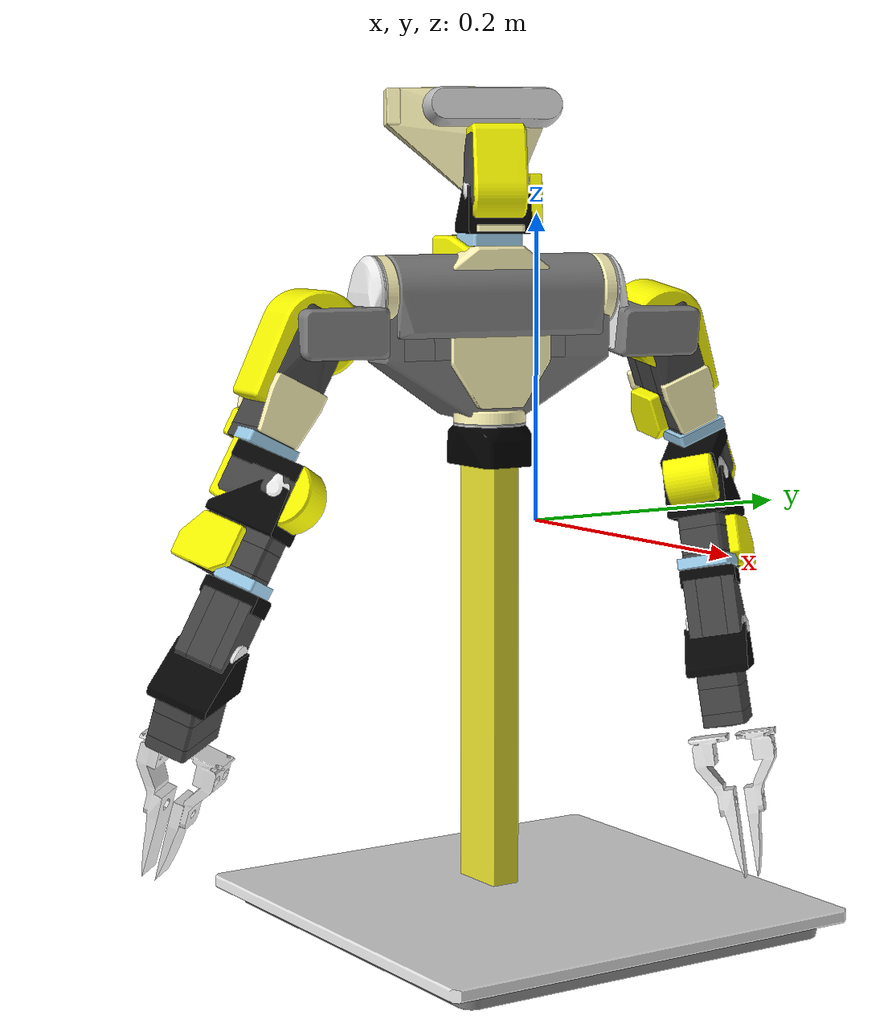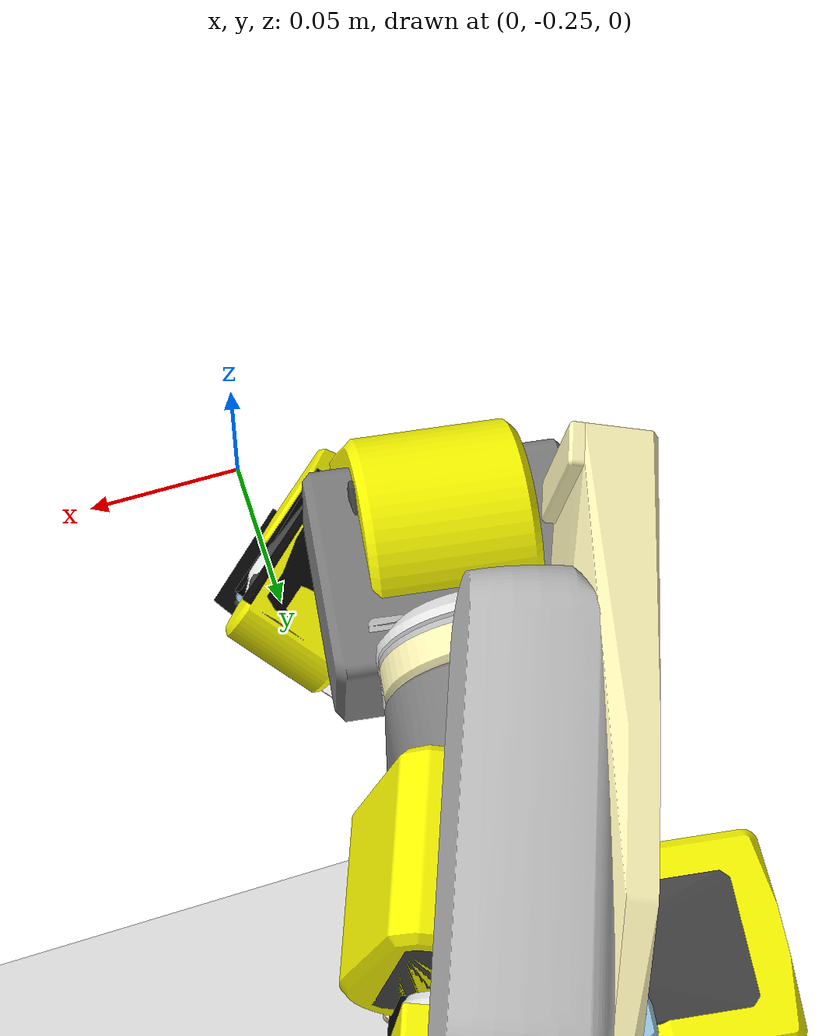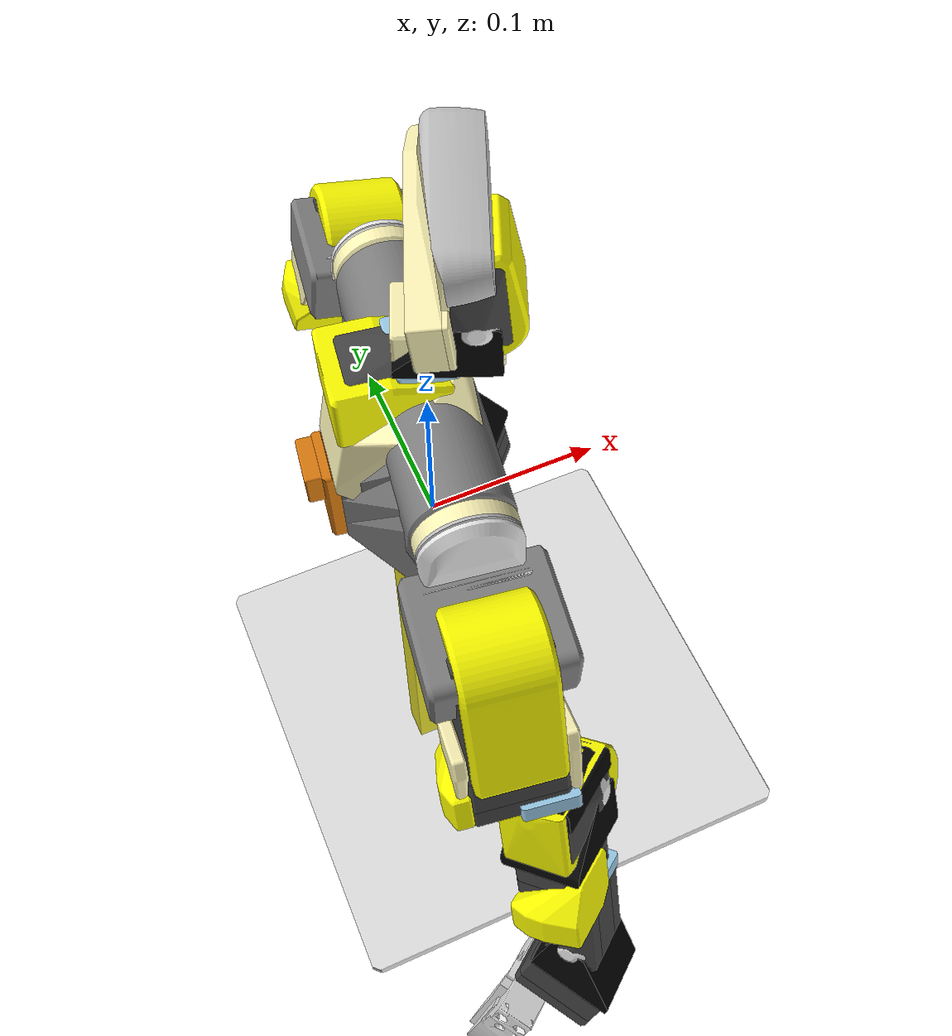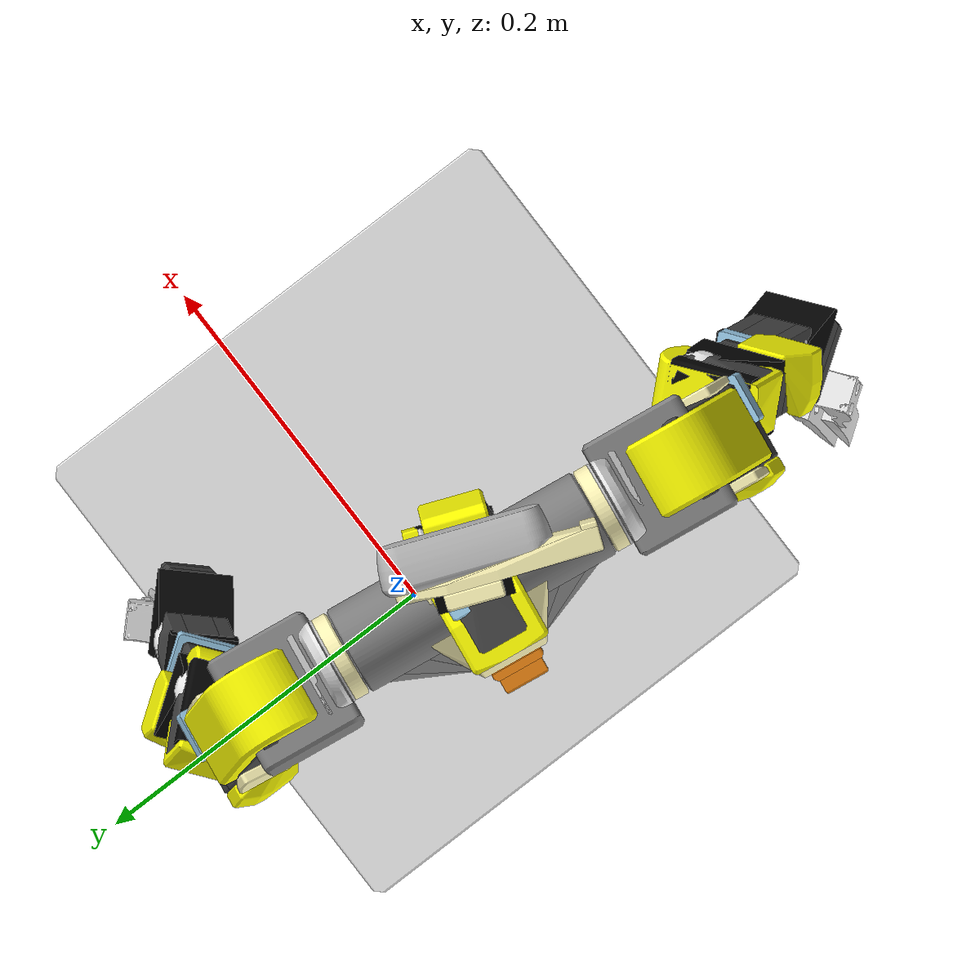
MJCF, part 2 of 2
2418 2444 2416 2440 2436 2416 2436 2412 2416 2498 2522 2494 2524 2500 2496 2496 2520 2524 2442 2414 2438 2438 2472 2442 2418 2414 2442 2442 2444 2418 2478 2452 2476 2478 2480 2452 2476 2502 2478 2510 2480 2508 2508 2536 2510 2508 2534 2536 2514 2484 2512 2512 2484 2510 2512 2540 2514 2512 2538 2540 2510 2536 2512 2536 2538 2512 2342 2311 2338 2338 2340 2342 2342 2340 2368 2285 2011 2311 2404 2430 2406 2400 2372 2398 2398 2424 2400 2368 2394 2369 2369 2342 2368 2369 2372 2344 2344 2342 2369 1118 1067 1114 1114 1161 1118 1254 1260 1231 1231 1253 1254 1437 1260 1254 1254 1253 1437 1165 1172 1168 1165 1164 1172 1168 1159 1165 1165 1159 1164 1252 1253 1225 1225 1182 1252 1225 1253 1231 1231 1161 1225 1408 1451 1140 1076 1088 1089 1089 1092 1076 1080 1090 1105 1105 1090 1130 1101 1105 1107 1107 1128 1101 1134 1128 1130 1137 1141 1143 1143 1128 1137 1143 1141 1153 1111 1128 1107 1130 1127 1119 1127 1128 1119 1119 1128 1121 1124 1123 1076 1124 1128 1123 1076 1101 1124 1124 1101 1128 1192 1216 1232 1232 1191 1192 1241 1242 1258 1169 1198 1178 1169 1175 1198 1133 1077 1093 1133 1093 1146 1179 1175 1133 1146 1191 1133 1133 1191 1179 983 1021 1018 983 987 1021 921 890 925 890 897 925 1247 1185 1248 1248 1283 1247 1280 1243 1247 1247 1283 1280 1132 1126 1094 1139 1171 1132 1074 1061 1047 968 941 975 975 941 983 1094 1070 1104 1139 1132 1104 1104 1132 1094 1104 1070 1075 1123 1152 1147 1147 1115 1123 1152 1185 1147 1052 1021 1055 1055 1078 1052 1052 1048 1021 1052 1078 1048 867 893 885 885 893 923 923 914 885 1015 1005 965 1015 1028 1047 1015 1047 1033 1033 1005 1015 846 875 870 844 816 846 846 870 844 844 870 838 1447 1444 1669 1669 1469 1447 1482 1469 1767 1767 1501 1482 1459 1474 1419 1505 1499 1503 1503 1507 1505 1507 1511 1505 1502 1504 1506 1510 1506 1504 2168 2198 2197 2171 2198 2168 2138 2171 2168 2028 2030 2058 1673 1838 1676 1676 1620 1673 1766 1673 1668 1927 1899 1901 1926 1899 1927 1927 1960 1926 1853 1837 1845 1853 1849 1837 1899 1926 1898 1798 1801 1800 1800 1797 1798 1792 1790 1788 1788 1790 1789 1788 1789 1783 1788 1785 1794 1819 1814 1816 1816 1822 1819 1834 1836 1829 1837 1836 1834 1801 1798 1802 1802 1797 1794 1802 1798 1797 1830 1848 1802 1808 1801 1810 1810 1818 1808 1801 1802 1810 1810 1802 1848 1978 1942 1944 2046 2074 1737 1737 2018 2046 1745 1741 2102 1745 1749 1652 1652 1741 1745 2204 2202 2176 2236 2205 2203 2203 2173 2200 2272 2274 2242 2242 2240 2272 2242 2274 2276 2211 2240 2242 2238 2205 2236 2209 2240 2211 2181 2151 2179 2181 2209 2211 2155 2185 2157 2111 2143 2113 2127 2155 2157 2149 2151 2121 2166 2169 2135 2166 2133 2161 2135 2133 2166 2161 2163 2166 2163 2195 2166 2195 2169 2166 2135 2169 2137 2173 2143 2170 2170 2169 2199 2170 2137 2169 2200 2173 2170 2170 2199 2200 2014 2016 2042 2014 2038 2012 2014 2012 1978 1978 2016 2014 2042 2068 2040 2040 2014 2042 2038 2014 2040 2032 2060 2030 2004 2002 1966 2004 2030 2002 2004 2032 2030 1794 1813 1821 1821 1802 1794 1830 1802 1821 2047 2077 2049 2049 2019 2047 1963 1961 1999 2013 2015 1979 1981 1947 1979 1979 1947 1945 1945 1943 1979 1999 2027 2029 2057 2031 2029 2003 2031 2005 2003 2005 1967 1994 2027 1999 1999 1961 1994 1961 1990 1994 1957 1990 1961 1961 1925 1957 1719 2019 1986 1986 1709 1719 1738 2019 1719 1639 1738 1719 1719 1635 1639 1719 1709 1635 77 83 1082 1082 69 77 41 22 20 41 55 22 50 24 38 38 76 50 76 90 50 50 47 24 919 668 900 900 943 919 964 832 951 832 934 951 1334 964 951 951 1327 1334 951 934 1327 1334 1345 997 997 991 1334 123 171 137 137 90 123 123 90 76 123 76 88 221 180 213 180 171 213 318 328 319 319 281 318 318 299 328 281 299 318 402 401 340 401 328 340 231 236 264 231 232 194 194 236 231 270 269 232 281 269 270 302 299 264 264 307 302 342 351 411 342 307 351 342 302 307 91 114 84 55 41 84 84 114 115 115 110 84 110 55 84 22 55 45 45 31 9 9 22 45 82 31 45 45 94 82 45 55 94 1754 1749 2160 1661 1749 1754 1754 1663 1661 2194 2223 2192 2197 2223 2194 2221 2223 2253 1948 1865 2253 1865 2221 2253 2253 2010 1948 2253 2284 2010 2227 2223 2197 2197 2198 2227 2237 2235 2204 2239 2210 2241 2241 2210 2243 436 1366 1346 1346 439 436 1366 439 1346 1379 1368 1377 1377 1393 1379 780 1368 1379 1401 1418 1409 1668 1673 1443 1411 1414 1403 1403 1401 1411 1411 1401 1409 1409 1418 1411 1473 1418 1492 1492 1483 1473 1458 1418 1473 1483 1475 1473 465 461 524 421 461 465 456 452 524 524 461 456 421 452 456 456 461 421 444 442 717 717 445 444 421 442 444 444 445 421 717 452 448 448 452 421 421 509 514 514 509 524 514 423 421 524 488 481 421 480 481 481 488 421 493 488 524 421 488 493 1679 1625 1623 1679 1686 1625 1623 1620 1679 1679 1620 1676 1679 1676 1885 1885 1686 1679 1956 1926 1960 130 168 160 160 155 130 168 138 160 138 155 160 111 130 144 130 155 144 144 118 111 144 155 118 202 226 219 202 189 185 202 219 189 203 202 185 66 70 71 28 70 66 71 30 66 30 28 66 457 422 455 457 478 486 457 455 478 420 392 391 392 374 391 263 260 289 312 289 309 356 374 353 353 337 356 333 337 353 176 173 196 227 220 206 227 246 220 220 246 242 242 241 220 260 241 242 345 331 367 239 219 248 248 254 239 206 219 239 239 227 206 239 254 246 246 227 239 271 254 248 271 248 166 166 295 271 271 295 279 279 254 271 166 662 430 430 662 469 430 455 420 469 455 430 2623 2608 2618 2665 2663 2661 2658 2652 2661 2661 2663 2658 2652 2645 2641 2642 2631 2636 2642 2645 2631 2636 2641 2642 2642 2641 2645 2658 2638 2655 2638 2645 2655 2655 2652 2658 2655 2645 2652 2475 2190 2449 2190 2447 2449 2557 2265 2251 2557 2583 2265 2503 2529 2225 2419 2164 2393 2419 2447 2190 2190 2164 2419 1757 2164 1761 1761 1660 1757 1757 1660 1655 1720 1716 1753 1703 1707 1701 1656 1694 1691 1694 1695 1691 1701 1700 1699 1699 1695 1694 1804 1796 1858 1858 1813 1804 1858 1868 1813 378 361 343 343 290 310 364 378 343 310 334 343 343 334 364 477 395 495 477 467 395 495 508 477 508 467 477 381 467 459 459 366 381 440 366 459 487 440 459 459 508 487 459 467 508 364 424 396 396 424 454 396 378 364 396 454 378 384 424 364 364 334 384 384 334 355 355 376 384 460 424 384 520 454 479 454 424 479 517 528 491 460 449 491 491 528 460 1382 950 1329 1329 1396 1382 938 950 1382 1419 1378 1392 1392 1402 1419 1423 1415 1617 1423 1617 1674 1674 1444 1423 1444 1439 1423 1419 1402 1410 1412 1410 1402 1419 1410 1412 790 762 768 768 767 790 767 799 790 790 799 816 804 797 805 527 546 536 527 523 540 540 546 527 662 566 549 553 549 566 564 546 553 553 546 540 569 564 576 576 590 569 629 662 693 693 643 629 629 651 638 629 643 651 603 622 585 624 622 603 585 551 571 571 603 585 592 603 571 571 542 563 551 542 571 563 578 571 578 592 571 529 551 544 544 507 529 519 492 483 483 507 519 665 664 640 665 706 664 665 622 642 640 622 665 705 706 665 642 667 665 665 667 705 572 567 548 572 591 567 572 535 555 548 535 572 555 595 572 614 591 572 572 595 614 611 628 624 624 603 611 611 603 592 611 578 597 611 592 578 644 628 669 701 667 669 669 667 644 781 725 752 752 771 781 885 914 868 744 706 778 706 741 778 822 784 778 784 744 778 778 850 822 810 850 778 772 741 736 736 764 772 810 778 772 772 778 741 757 725 781 857 817 811 811 888 857 857 896 865 865 817 857 782 727 825 727 773 825 825 878 782 865 878 825 825 817 865 825 773 817 792 829 787 792 833 829 787 750 792 750 833 792 970 937 926 926 937 896 896 857 926 926 857 888 1000 970 926 926 957 1000 918 957 926 926 888 918 848 811 801 848 888 811 801 882 848 882 888 848 589 560 613 589 613 646 646 621 589 538 516 561 489 516 538 538 511 489 412 446 432 412 385 446 432 377 412 377 385 412 394 368 393 393 429 394 346 368 394 394 370 346 406 370 394 394 429 474 517 491 485 485 491 449 485 543 517 485 512 543 485 449 406 474 512 485 298 326 348 159 193 170 209 204 190 229 204 209 190 170 209 209 170 193 250 274 297 294 274 251 229 209 251 251 250 229 274 250 251 54 25 48 54 34 25 48 65 54 65 80 54 240 284 275 249 284 240 275 264 240 264 236 240 85 56 93 56 60 93 190 204 183 147 106 133 147 116 106 133 159 147 159 170 147 147 170 190 283 257 237 1297 1320 1296 1297 1298 1320 1296 1260 1297 1260 1298 1297 1309 1312 1320 1309 1260 1312 1320 1301 1302 1302 1304 1320 1301 1260 1302 1260 1304 1302 1294 1320 1523 1523 1293 1294 1296 1320 1294 1294 1293 1260 1294 1260 1296 1316 1260 1320 1320 1314 1316 1312 1260 1313 1260 1314 1313 1320 1312 1313 1313 1314 1320 1222 1217 1201 1222 1201 1251 1251 1228 1222 1251 1229 1223 1194 1205 1168 1195 1183 1189 1272 1273 1274 1277 1282 1272 1277 1275 1282 1272 1274 1277 1477 1470 1290 1290 1485 1477 1462 1456 1290 1290 1465 1462 1462 1465 1456 1467 1455 1457 1467 1471 1400 1400 1455 1467 1400 1427 1429 1445 1440 1290 1400 1383 1385 1385 1388 1400 1383 1384 1385 1384 1388 1385 1342 1291 1341 1353 1348 1290 1290 1354 1353 1290 1360 1356 1356 1354 1290 1365 1426 1376 1365 1363 1426 1563 1610 1595 1609 1564 1595 1564 1563 1595 1613 1610 1681 1613 1681 1683 1613 1595 1610 1683 1605 1606 1606 1607 1683 1606 1605 1564 1564 1607 1606 1604 1605 1683 1683 1600 1604 1564 1605 1604 1604 1600 1564 1580 1576 1437 1437 1585 1580 1598 1576 1580 1580 1585 1598 1437 1593 1591 1598 1585 1591 1591 1689 1598 1591 1593 1689 1562 1568 1598 1562 1598 1603 1603 1548 1562 1437 1568 1562 1562 1548 1437 1603 1523 1530 1530 1548 1603 1523 1437 1530 1437 1548 1530 1528 1525 1524 1524 1525 1521 1579 1528 1524 1290 1579 1524 1524 1521 1290 1579 1543 1540 1540 1535 1579 1533 1528 1579 1579 1535 1533 1543 1545 1546 1546 1545 1549 2279 2331 2306 1640 1633 1739 1633 1736 1739 1739 1736 2044 2044 2080 1739 2337 2080 2310 2140 1747 2114 2367 2140 2114 2114 2080 2367 2636 2626 2634 2634 2626 2629 2617 2595 2610 2607 2595 2617 2610 2609 2617 1017 1030 998 1017 1049 1030 998 959 1017 1017 959 977 977 1037 1017 1017 1037 1066 1066 1049 1017 886 861 850 886 920 861 2602 2644 2606 2638 2644 2602 2602 2598 2638 2598 2602 2572 2572 2542 2540 2572 2606 2576 2572 2602 2606 2566 2564 2592 2592 2598 2566 2540 2538 2566 2566 2536 2564 2566 2538 2536 2592 2564 2590 2564 2588 2590 2590 2626 2592 2590 2588 2626 2558 2556 2252 2266 2584 2558 2558 2252 2266 2582 2578 2554 2554 2580 2582 2550 2580 2554 2554 2528 2524 2524 2550 2554 2582 2614 2616 2657 2651 2616 2616 2614 2657 2550 2520 2546 2576 2550 2546 2516 2542 2546 2546 2520 2516 2546 2572 2576 2542 2572 2546 2556 2558 2560 2560 2558 2584 2187 2214 2217 2217 2189 2187 2185 2214 2187 2157 2185 2187 2187 2159 2157 2187 2189 2159 2017 1947 1981 2043 1947 2017 2017 2015 2043 1981 1979 2017 2017 1979 2015 1920 1876 1896 1896 1872 1894 1896 1876 1872 1975 1943 1941 1894 1872 1892 1856 1884 1862 1818 1810 1856 1856 1810 1848 1830 1821 1874 1813 1868 1874 1874 1821 1813 1880 1906 1882 1884 1856 1882 1882 1848 1880 1882 1856 1848 1910 1937 1939 1939 1941 1910 2097 2099 2067 2067 2065 2097 2097 2065 2095 2097 2127 2099 2013 1975 2009 1975 2007 2009 2035 2007 2005 1973 2007 1975 2005 2007 1973 1939 1937 1973 1973 1941 1939 1975 1941 1973 2474 2472 2500 2500 2498 2474 2494 2470 2474 2474 2498 2494 2474 2470 2440 2440 2444 2474 2474 2442 2472 2444 2442 2474 2526 2500 2528 2526 2498 2500 2522 2498 2526 2528 2554 2526 2548 2522 2526 2420 2448 2422 2422 2448 2452 2456 2480 2482 2482 2484 2456 2468 2472 2438 2500 2472 2468 2468 2496 2500 2488 2460 2486 2486 2460 2484 2486 2484 2514 2514 2516 2486 2486 2516 2488 2432 2408 2406 2406 2430 2432 2480 2478 2506 2506 2508 2480 2506 2478 2502 2502 2504 2506 2506 2504 2530 2534 2508 2506 2354 2356 2326 2380 2352 2350 2346 2374 2348 2346 2344 2374 2344 2346 2317 2317 2346 2348 1866 1705 1949 1705 2011 1949 2402 2376 2400 2402 2404 2376 2400 2428 2402 2428 2430 2402 2430 2404 2402 2376 2404 2378 2380 2350 2378 2378 2406 2380 2378 2404 2406 2348 2376 2378 2378 2350 2348 2396 2398 2372 2372 2369 2396 2396 2369 2394 2396 2394 2420 2420 2422 2396 2424 2398 2396 2396 2422 2424 1153 1172 1160 1172 1164 1160 1154 1159 1168 1154 1168 1155 1155 1142 1154 1154 1143 1153 1153 1160 1154 1142 1128 1154 1128 1143 1154 1164 1159 1154 1154 1160 1164 1451 1182 1150 1150 1140 1451 1140 1150 1156 1156 1150 1182 1156 1225 1161 1182 1225 1156 1080 1100 1097 1097 1095 1080 1103 1100 1080 1080 1105 1103 1103 1101 1100 1105 1101 1103 1130 1141 1138 1138 1134 1130 1137 1128 1135 1128 1134 1135 1134 1138 1135 1135 1141 1137 1135 1138 1141 1110 1105 1130 1107 1105 1110 1110 1111 1107 1116 1119 1121 1121 1128 1116 1128 1111 1116 1111 1110 1116 1235 1171 1240 1258 1235 1240 1240 1241 1258 1149 1099 1167 1099 1169 1167 1167 1178 1149 1167 1169 1178 1077 1133 1120 1099 1077 1120 1120 1169 1099 1175 1169 1120 1120 1133 1175 887 890 917 917 890 921 983 941 953 921 925 953 953 917 921 941 917 953 987 983 953 866 890 887 838 870 866 866 897 890 866 870 897 960 987 956 956 925 960 987 953 956 956 953 925 960 925 931 913 927 931 931 925 897 952 960 931 931 927 952 1126 1132 1158 1146 1126 1158 1216 1192 1158 1158 1191 1146 1158 1192 1191 1166 1171 1235 1166 1132 1171 1166 1158 1132 1166 1235 1216 1216 1158 1166 1084 1047 1058 1084 1074 1047 1126 1074 1084 1058 1094 1084 1094 1126 1084 1093 1061 1109 1061 1074 1109 1146 1093 1109 1109 1126 1146 1109 1074 1126 1075 1115 1112 1112 1104 1075 1115 1147 1112 1139 1104 1112 1185 1247 1180 1180 1147 1185 1180 1247 1243 1243 1242 1180 968 975 1013 1013 1010 968 1018 1048 1013 1013 1048 1043 1013 983 1018 1013 975 983 1064 1028 1036 1036 1070 1064 1043 1070 1036 1036 1013 1043 1010 1013 1036 1028 1015 976 976 1015 965 807 818 849 1488 1476 1480 1480 1491 1488 1501 1491 1480 1480 1482 1501 1419 1439 1434 1434 1459 1419 1464 1439 1444 1444 1447 1464 1464 1447 1469 1469 1482 1464 1482 1480 1464 1514 1515 1765 1765 1512 1514 1512 1506 1514 1506 1510 1514 2056 2028 2058 2054 2028 2056 2026 2028 2054 1929 1960 1927 1929 1962 1960 1927 1901 1929 1932 1964 1929 1929 1964 1962 1616 1673 1619 1619 1673 1620 1334 1616 1619 1619 1620 1334 1765 1770 1771 1771 1766 1765 1673 1766 1786 1838 1673 1786 1763 1512 1765 1765 1766 1763 1763 1766 1512 1904 1879 1905 1932 1929 1904 1904 1929 1901 1849 1853 1871 1885 1676 1840 1676 1838 1840 1890 1898 1926 1890 1921 1885 1885 1840 1890 1791 1797 1792 1792 1788 1791 1794 1797 1791 1791 1788 1794 1783 1780 1779 1779 1780 1776 1819 1822 1823 1822 1824 1823 1822 1816 1826 1814 1818 1826 1826 1816 1814 1826 1856 1862 1818 1856 1826 1829 1824 1827 1827 1824 1822 1842 1837 1835 1837 1834 1835 1834 1844 1850 1850 1835 1834 1850 1872 1854 1850 1844 1872 1854 1842 1850 1842 1835 1850 1872 1844 1869 1869 1892 1872 1946 1980 1978 1978 1944 1946 1946 2016 1980 1946 1919 2042 2042 2016 1946 1909 1936 1907 1907 1883 1909 1917 1944 1942 1942 1915 1917 1919 1946 1917 1917 1946 1944 1905 1907 1934 1907 1936 1934 1934 1904 1905 1932 1904 1934 1934 1936 1966 1966 1964 1934 1934 1964 1932 2020 2023 2048 2048 2023 2050 2048 2018 2020 2048 2046 2018 2078 2048 2050 2050 2052 2078 2078 2052 2082 2054 2056 2084 2084 2052 2054 2082 2052 2084 2104 1745 2102 2104 2134 2132 2104 2132 1749 1749 1745 2104 2239 2237 2206 2206 2237 2204 2204 2176 2206 2174 2176 2202 2174 2202 2201 2174 2147 2176 2152 2124 2154 2152 2154 2182 2182 2154 2184 2182 2210 2180 2182 2184 2210 2188 2158 2216 2215 2216 2247 2247 2245 2215 2215 2245 2243 2062 2064 2092 2092 2090 2062 2062 2090 2060 2096 2064 2066 2066 2068 2098 2098 2096 2066 2066 2064 2038 2066 2040 2068 2038 2040 2066 2094 2124 2092 2096 2124 2094 2092 2064 2094 2094 2064 2096 2142 2171 2138 2092 2124 2122 2122 2090 2092 2200 2199 2232 2199 2230 2232 2232 2203 2200 2193 2222 2224 2224 2195 2193 2228 2199 2196 2228 2230 2199 2196 2195 2228 2195 2224 2228 2173 2203 2175 2175 2143 2173 2175 2145 2143 2276 2278 2244 2244 2242 2276 2244 2214 2213 2244 2213 2211 2211 2242 2244 2207 2238 2240 2240 2209 2207 2205 2238 2207 2207 2181 2179 2209 2181 2207 2151 2181 2183 2185 2155 2183 2211 2185 2183 2183 2181 2211 2105 1746 2133 2105 2133 2135 2131 2099 2129 2099 2127 2129 2157 2131 2129 2129 2127 2157 2121 2091 2119 2149 2121 2119 2123 2091 2121 2123 2121 2151 2139 2170 2143 2137 2170 2139 2143 2111 2139 2111 2137 2139 2006 2008 2036 2038 2064 2036 2012 2038 2036 2036 2008 2012 2064 2062 2036 2012 2008 1974 2055 2029 2027 2057 2029 2055 2079 2049 2077 2079 2083 2053 2111 2083 2079 2022 1994 1990 1965 1963 1999 1977 1975 2013 2013 1979 1977 1977 1943 1975 1977 1979 1943 2001 2029 2031 2031 2003 2001 1999 2029 2001 2001 1965 1999 2001 2003 1967 1967 1965 2001 1955 1988 1990 1990 1957 1955 1953 1986 1955 1986 1988 1955 1955 1922 1953 1955 1957 1925 67 77 69 83 77 67 67 47 83 35 41 20 20 24 35 24 47 35 47 50 64 64 112 103 103 100 64 83 47 64 64 50 90 64 100 83 922 934 668 668 919 922 943 934 922 922 919 943 980 979 1334 832 979 980 973 832 964 973 979 832 973 964 1334 1334 979 973 1001 997 1345 681 832 840 840 1008 855 840 855 441 441 681 840 267 221 259 221 213 259 259 311 267 223 225 232 188 225 223 339 340 328 339 404 402 402 340 339 328 299 339 299 302 339 302 342 339 262 299 281 281 270 262 264 299 262 262 231 264 232 231 262 262 270 232 91 84 59 59 84 41 59 78 91 41 35 59 2162 1754 2160 1671 1663 1759 1663 1754 1759 1865 1671 1759 2192 1865 1759 1759 2162 2192 1754 2162 1759 2314 2288 2316 2310 2284 2286 2229 2227 2198 2229 2201 2231 2229 2198 2201 2231 2261 2229 2255 2253 2223 2288 2286 2255 2284 2253 2255 2255 2286 2284 775 1368 780 775 749 1368 775 780 668 668 749 775 745 668 717 745 749 668 717 1368 745 1368 749 745 812 1379 943 943 828 812 812 828 668 1381 1395 943 943 1379 1381 1381 1393 1395 1381 1379 1393 1377 1418 1391 1418 1401 1391 1391 1393 1377 1403 1393 1391 1391 1401 1403 1422 1438 1443 1616 1414 1422 1422 1673 1616 1422 1443 1673 473 465 524 473 481 480 524 481 473 473 480 421 447 445 717 717 448 447 421 445 447 447 448 421 524 423 521 524 499 494 494 493 524 494 499 421 421 493 494 1960 1962 1998 1998 1993 1960 1962 1964 1998 2028 2026 1998 1998 2026 1993 1954 1985 1952 1952 1921 1954 1926 1956 1954 1989 1954 1956 1960 1993 1989 1989 1956 1960 1989 2023 2020 127 226 215 215 203 127 226 202 215 202 203 215 201 187 127 127 203 201 185 187 201 201 203 185 486 490 462 462 457 486 426 422 462 422 457 462 296 331 303 296 272 263 263 289 296 260 242 261 196 173 174 150 151 174 174 173 150 174 157 179 151 157 174 195 199 220 179 199 195 195 174 179 196 174 195 196 195 217 373 374 392 373 353 374 354 380 358 375 380 354 354 373 375 353 373 354 333 353 354 354 332 333 312 309 335 335 354 358 332 354 335 308 288 293 293 313 308 308 337 333 308 313 337 398 380 375 398 392 426 398 373 392 375 373 398 463 483 492 492 510 463 497 489 466 466 489 458 331 296 322 322 289 312 322 296 289 150 173 152 173 176 152 152 117 150 152 120 117 159 120 152 152 176 159 247 272 282 282 296 303 272 296 282 352 326 304 304 298 285 326 298 304 367 385 362 362 345 367 362 385 377 303 331 316 331 345 316 316 282 303 291 282 316 166 430 399 399 391 374 420 391 399 399 430 420 166 341 323 323 313 293 337 313 323 323 341 337 349 341 166 356 337 349 337 341 349 2609 2608 2620 2620 2617 2609 2618 2628 2627 2627 2623 2618 2624 2623 2627 2628 2629 2627 2627 2629 2624 2632 2628 2625 2636 2634 2632 2632 2629 2628 2632 2634 2629 2251 2529 2555 2555 2557 2251 2501 2225 2475 2501 2503 2225 2140 2164 1756 2164 1757 1756 1751 2140 1756 1655 1751 1756 1756 1757 1655 1753 1734 1732 1734 1730 1732 1732 1730 1753 1728 1726 1753 1753 1730 1728 1753 1726 1724 1724 1720 1753 1715 1717 1701 1701 1713 1715 1702 1703 1701 1701 1699 1702 1702 1699 1694 1839 1841 1852 1796 1839 1852 1852 1858 1796 290 343 325 325 343 361 361 305 325 344 361 381 344 305 361 344 366 329 381 366 344 256 305 292 329 284 292 284 256 292 292 344 329 305 344 292 460 384 414 414 384 376 414 449 460 376 449 414 460 528 503 503 424 460 503 479 424 1380 1369 938 938 1382 1380 1378 1369 1380 1404 1396 1406 1402 1392 1404 1404 1412 1402 1406 1415 1404 1415 1412 1404 1415 1423 1421 1421 1412 1415 1419 1412 1421 1421 1439 1419 1421 1423 1439 700 731 724 724 716 700 687 675 700 700 716 687 687 716 703 703 678 687 658 687 678 658 693 694 675 687 658 694 675 658 670 651 659 659 684 670 651 643 659 659 678 703 703 684 659 659 658 678 689 674 670 695 674 720 674 689 720 835 804 821 804 805 821 800 805 797 800 821 805 800 831 836 800 796 831 797 769 800 836 835 800 835 821 800 763 796 800 800 769 763 506 500 523 523 527 506 486 478 506 478 500 506 506 490 486 506 527 536 525 523 498 540 523 525 498 662 525 662 601 594 594 582 662 575 566 662 662 582 575 575 588 566 575 582 588 601 615 600 600 594 601 588 582 600 582 594 600 625 612 600 600 615 625 639 625 627 625 615 627 627 638 639 566 588 570 570 553 566 564 553 570 570 576 564 596 600 612 588 600 596 596 570 588 576 570 596 596 612 623 623 604 596 596 604 590 590 576 596 662 629 619 619 627 615 619 629 638 638 627 619 536 542 522 522 542 551 551 529 522 623 636 630 636 650 630 673 636 653 673 650 636 673 674 695 653 674 673 895 868 914 884 851 895 851 868 895 841 892 876 876 850 841 841 850 810 791 757 781 764 757 791 725 757 728 728 764 701 728 757 764 562 534 560 560 589 562 539 504 562 562 504 534 558 561 581 558 538 561 581 606 558 558 606 579 579 556 558 556 533 558 533 511 558 511 538 558 438 394 474 474 485 438 406 394 438 438 485 406 321 348 346 321 298 348 346 320 321 321 320 294 218 209 193 266 304 285 291 304 266 266 282 291 200 176 196 196 217 200 276 250 297 297 324 276 276 324 300 276 300 283 228 204 229 229 250 228 207 183 228 228 183 204 250 276 228 228 237 207 294 251 277 277 251 255 277 321 294 298 321 277 277 255 285 285 298 277 161 198 194 194 188 161 178 139 161 161 188 178 249 240 205 236 198 205 205 240 236 99 93 60 53 60 39 53 79 60 39 21 53 53 21 34 34 54 53 79 53 98 190 183 163 163 147 190 183 142 163 116 147 163 163 142 116 1320 1304 1308 1308 1309 1320 1308 1304 1260 1260 1309 1308 1315 1314 1260 1260 1316 1315 1315 1316 1314 1233 1229 1251 1220 1222 1228 1217 1222 1220 1220 1228 1251 1251 1223 1220 1168 1172 1173 1172 1183 1173 1205 1194 1200 1193 1172 1201 1193 1189 1172 1187 1183 1172 1172 1189 1187 1187 1189 1183 1275 1277 1276 1276 1277 1274 1478 1486 1471 1428 1426 1290 1435 1440 1426 1426 1428 1435 1435 1428 1432 1290 1440 1435 1435 1432 1290 1427 1441 1436 1436 1429 1427 1290 1326 1321 1303 1307 1306 1307 1318 1306 1306 1318 1291 1330 1326 1290 1290 1348 1344 1344 1340 1290 1344 1348 1342 1338 1336 1290 1290 1340 1338 1342 1341 1338 1338 1340 1342 1363 1365 1364 1376 1374 1364 1364 1365 1376 1364 1374 1400 1611 1683 1609 1609 1595 1611 1587 1585 1437 1437 1591 1587 1587 1591 1585 1535 1540 1538 1538 1540 1543 1531 1533 1535 1528 1533 1531 1558 1560 1400 2275 2241 2243 2329 2327 2302 2375 2399 2373 2373 2399 2371 1640 1739 1743 1743 1647 1640 1743 1739 2080 1743 1747 1647 2080 2114 1743 1743 2114 1747 2367 2080 2339 2080 2337 2339 2624 2607 2621 2607 2617 2621 2621 2623 2624 2621 2617 2623 884 895 915 915 895 932 965 949 915 915 932 965 876 892 929 929 949 982 982 966 929 929 915 949 892 915 929 910 850 876 910 886 850 876 929 910 2598 2572 2568 2568 2566 2598 2568 2572 2540 2540 2566 2568 2552 2578 2548 2552 2554 2578 2548 2526 2552 2552 2526 2554 2612 2578 2582 2582 2616 2612 2612 2616 2651 2564 2534 2562 2534 2560 2562 2562 2588 2564 2562 2560 2588 2586 2560 2584 2588 2560 2586 2584 2596 2586 2596 2607 2586 2586 2607 2619 2619 2588 2586 1925 1900 1897 1868 1858 1897 1897 1900 1868 1830 1874 1878 1878 1848 1830 1880 1848 1878 1937 1910 1908 1908 1882 1906 1884 1882 1908 1908 1910 1884 2037 2065 2039 2037 2039 2013 2013 2009 2037 2037 2009 2007 2007 2035 2037 2005 2031 2033 2033 2035 2005 2031 2061 2033 2061 2035 2033 1967 2005 1969 2005 1973 1969 1969 1937 1967 1969 1973 1937 2426 2456 2428 2424 2456 2426 2426 2428 2400 2400 2424 2426 2428 2456 2458 2458 2430 2428 2460 2430 2458 2484 2460 2458 2458 2456 2484 2452 2480 2454 2480 2456 2454 2454 2456 2424 2454 2422 2452 2424 2422 2454 2488 2520 2492 2520 2496 2492 2408 2432 2434 2434 2438 2410 2410 2408 2434 2532 2506 2530 2534 2506 2532 2532 2560 2534 2530 2556 2532 2556 2560 2532 2328 2356 2358 2328 2326 2356 2324 2350 2352 2322 2350 2324 2324 2352 2354 2354 2326 2324 2291 2317 2319 2319 2317 2348 2348 2350 2319 2319 2350 2322 2344 2317 2315 2315 2342 2344 2315 2317 2291 2289 2315 2291 2254 2222 1866 1866 1949 2254 2254 2224 2222 2011 2285 2254 2254 1949 2011 1408 1140 1087 1087 1057 1408 1062 1057 1087 1091 1095 1092 1080 1095 1091 1091 1089 1088 1092 1089 1091 1091 1088 1080 1095 1097 1096 1100 1101 1096 1096 1097 1100 1092 1095 1096 1096 1101 1076 1076 1092 1096 1130 1119 1117 1117 1110 1130 1119 1116 1117 1117 1116 1110 905 923 893 913 931 901 901 931 897 901 873 913 901 875 873 901 870 875 897 870 901 1139 1112 1145 1145 1112 1147 781 771 806 854 867 885 854 823 867 914 923 958 958 923 968 968 1010 958 837 823 807 807 849 837 867 823 837 837 849 867 859 849 818 859 866 887 887 849 859 1439 1464 1461 1461 1434 1439 1459 1434 1461 1461 1476 1474 1474 1459 1461 1461 1480 1476 1461 1464 1480 2138 2168 2136 2168 2134 2136 1993 2026 2024 2023 1989 2024 2024 1989 1993 2050 2023 2024 2024 2052 2050 2024 2026 2054 2054 2052 2024 1770 1775 1777 1777 1771 1770 1777 1775 1776 1875 1871 1853 1845 1919 1875 1875 1853 1845 1861 1883 1855 1863 1883 1861 1855 1883 1881 1881 1883 1907 1881 1907 1905 1905 1879 1881 1891 1917 1915 1781 1788 1783 1783 1779 1781 1785 1788 1781 1781 1779 1785 1774 1779 1776 1776 1775 1774 1773 1778 1774 1774 1770 1773 1774 1775 1770 1778 1785 1774 1785 1779 1774 1822 1826 1833 1833 1827 1822 1844 1827 1833 1833 1826 1862 1833 1869 1844 1828 1834 1829 1829 1827 1828 1828 1844 1834 1828 1827 1844 1911 1915 1942 1911 1891 1915 1911 1909 1883 1936 1909 1938 2048 2078 2076 2074 2046 2076 2046 2048 2076 2086 2084 2056 2086 2058 2088 2086 2056 2058 2088 2118 2086 2082 2084 2110 2110 2078 2082 2110 2108 2078 2110 2142 2138 2138 2136 2110 2110 2136 2108 2134 2104 2106 2106 2136 2134 2108 2136 2106 2106 2104 2102 2102 2074 2106 2074 2076 2106 2078 2108 2106 2106 2076 2078 2208 2210 2239 2239 2206 2208 2180 2210 2208 2208 2206 2180 2180 2206 2178 2178 2206 2176 2176 2147 2178 2147 2148 2178 2201 2171 2172 2172 2174 2201 2171 2142 2172 2172 2142 2174 2184 2154 2156 2130 2158 2156 2210 2184 2212 2184 2215 2212 2243 2210 2212 2212 2215 2243 2118 2147 2144 2147 2174 2144 2174 2142 2144 2152 2182 2150 2150 2182 2180 2180 2178 2150 2150 2178 2148 2150 2124 2152 2150 2122 2124 2120 2118 2090 2090 2122 2120 2120 2147 2118 2120 2148 2147 2122 2150 2120 2120 2150 2148 2236 2203 2234 2203 2232 2234 2232 2264 2234 2177 2203 2205 2177 2175 2203 2177 2207 2179 2205 2207 2177 2278 2248 2246 2246 2244 2278 2214 2244 2246 2246 2248 2217 2217 2214 2246 2151 2183 2153 2153 2183 2155 2075 1742 1746 2075 2077 2047 2047 1738 2075 2075 1738 1742 2059 2091 2061 2059 2031 2057 2059 2061 2031 2061 2091 2063 2063 2035 2061 2065 2037 2063 2063 2037 2035 2117 2119 2087 2145 2119 2117 2113 2143 2117 2143 2145 2117 2087 2119 2089 2089 2119 2091 2091 2059 2089 2089 2057 2087 2089 2059 2057 2125 2097 2095 2127 2097 2125 2155 2127 2125 2125 2153 2155 2125 2123 2151 2151 2153 2125 2091 2123 2093 2093 2063 2091 2093 2125 2095 2123 2125 2093 2095 2065 2093 2065 2063 2093 2006 2036 2034 2034 2004 2006 2032 2004 2034 2034 2036 2062 2060 2032 2034 2034 2062 2060 1976 1942 1978 1976 1974 1942 1978 2012 1976 2012 1974 1976 2006 2004 1972 1972 2008 2006 1972 1974 2008 1936 1938 1972 2087 2057 2085 2057 2055 2085 2085 2055 2053 2053 2083 2085 2085 2117 2087 2113 2117 2085 2085 2111 2113 2085 2083 2111 2049 2079 2051 2051 2079 2053 2051 2022 2049 2111 2079 2109 2109 2137 2111 2025 2055 2027 2053 2055 2025 2027 1994 2025 1994 2022 2025 2025 2051 2053 2022 2051 2025 1986 2019 2021 2021 1988 1986 2019 2049 2021 2049 2022 2021 1990 1988 2021 2021 2022 1990 1963 1965 1930 1961 1963 1930 1922 1955 1924 1924 1955 1925 58 67 69 58 59 35 47 67 58 58 35 47 58 69 78 78 59 58 105 122 112 112 64 105 146 122 105 105 64 90 149 146 105 137 149 105 105 90 137 991 997 969 997 1001 969 1001 840 969 832 980 969 969 840 832 1008 840 1004 1004 840 1001 1004 1345 1008 1004 1001 1345 171 123 128 128 123 88 88 129 128 128 129 139 311 259 268 319 311 268 268 281 319 268 269 281 232 269 268 224 259 213 213 211 224 188 223 224 224 211 188 224 223 232 408 339 342 408 342 411 404 339 408 408 411 443 443 404 408 2167 2168 2197 2197 2194 2167 2167 2162 2160 2167 2194 2192 2192 2162 2167 2167 2134 2168 2160 2132 2167 2132 2134 2167 2310 2286 2312 2288 2314 2312 2312 2286 2288 2323 2321 2294 2321 2318 2294 2231 2202 2233 2202 2235 2233 2227 2229 2259 2259 2229 2261 2323 2298 2325 2298 2327 2325 2325 2353 2323 2329 2302 2333 2353 2325 2355 2355 2325 2327 2413 2387 2391 780 1379 802 1379 812 802 668 780 802 802 812 668 1433 1418 1458 1433 1438 1418 1460 1433 1458 1438 1433 1460 1475 1479 1460 1458 1473 1460 1460 1473 1475 1668 1443 1446 1420 1411 1418 1418 1438 1420 1438 1422 1420 1414 1411 1420 1420 1422 1414 1502 1506 1490 1490 1506 1512 421 465 472 472 473 421 465 473 472 423 514 515 515 521 423 515 514 524 524 521 515 2000 1998 1964 1966 2002 2000 2000 1964 1966 2028 1998 2000 2002 2030 2000 2030 2028 2000 1923 1954 1921 1926 1954 1923 1921 1890 1923 1923 1890 1926 1985 1954 1987 1954 1989 1987 2020 1985 1987 1987 1989 2020 287 289 260 287 309 289 265 242 246 265 261 242 265 279 293 293 288 265 265 254 279 246 254 265 220 241 216 216 195 220 241 217 216 216 217 195 263 247 243 247 217 243 243 217 241 243 260 263 243 241 260 358 380 363 380 386 363 416 463 425 425 463 450 425 386 416 451 463 416 483 463 451 482 463 510 450 463 482 482 510 497 497 466 482 482 466 450 390 418 367 458 418 390 336 377 352 336 362 377 352 304 336 345 362 336 336 316 345 336 304 291 291 316 336 374 372 379 379 399 374 379 372 166 166 399 379 293 295 301 301 323 293 301 295 166 166 323 301 360 372 356 356 349 360 166 372 360 360 349 166 2608 2623 2622 2622 2620 2608 2623 2617 2622 2617 2620 2622 2625 2641 2635 2635 2641 2636 2523 2495 2499 2499 2495 2467 2487 2459 2461 2479 2453 2455 2429 2403 2405 2407 2433 2405 2409 2387 2413 2409 2433 2407 2397 2371 2399 2427 2403 2429 2429 2459 2427 577 583 559 559 528 577 559 503 528 1396 1404 1394 1394 1404 1392 1394 1382 1396 1394 1380 1382 1394 1392 1378 1378 1380 1394 751 724 731 648 659 643 658 659 648 648 643 693 693 658 648 711 684 703 670 684 711 711 689 670 711 720 689 776 818 807 753 761 776 808 844 838 545 553 540 549 553 545 662 549 545 605 615 601 605 619 615 605 601 662 662 619 605 536 522 513 513 522 490 513 506 536 490 506 513 416 386 409 409 386 380 409 451 416 433 451 409 380 398 409 409 398 426 426 433 409 507 483 468 483 451 468 468 451 433 426 462 468 468 433 426 618 604 623 623 630 618 597 590 618 590 604 618 618 611 597 628 611 618 721 673 695 721 752 725 695 720 721 771 752 721 698 671 725 725 728 698 701 669 698 698 728 701 647 630 650 650 671 647 628 618 647 647 618 630 647 669 628 647 698 669 671 698 647 803 772 764 810 772 803 803 841 810 815 791 781 815 868 851 781 806 815 593 568 539 539 562 593 626 599 593 599 568 593 593 656 626 593 621 656 593 589 621 593 562 589 255 218 244 244 218 235 235 266 244 285 255 244 244 266 285 235 218 208 208 200 235 238 251 209 209 218 238 255 251 238 238 218 255 253 266 235 282 266 253 253 235 247 247 282 253 247 235 222 235 200 222 222 217 247 222 200 217 283 237 252 237 228 252 252 276 283 252 228 276 278 257 290 278 305 256 290 325 278 278 325 305 245 237 257 245 210 237 257 278 245 191 183 207 207 237 191 237 210 191 164 205 198 198 161 164 93 99 125 125 161 139 85 93 125 125 129 85 139 129 125 96 54 80 80 106 96 106 116 96 60 79 108 108 99 60 1238 1233 1251 1251 1257 1238 1238 1257 1239 1239 1250 1234 1221 1220 1223 1223 1224 1221 1217 1220 1221 1221 1224 1250 1168 1173 1174 1174 1173 1183 1174 1188 1168 1183 1188 1174 1190 1183 1195 1190 1188 1183 1168 1188 1190 1197 1200 1194 1197 1194 1168 1168 1190 1197 1197 1190 1195 1210 1208 1201 1201 1212 1210 1466 1465 1470 1456 1465 1466 1290 1432 1430 1430 1428 1290 1432 1428 1430 1400 1429 1431 1431 1436 1400 1429 1436 1431 1440 1445 1448 1448 1445 1290 1319 1318 1307 1319 1321 1318 1319 1307 1290 1290 1321 1319 1303 1306 1300 1292 1295 1300 1300 1295 1303 1300 1291 1292 1300 1306 1291 1290 1336 1332 1332 1330 1290 1326 1330 1331 1342 1340 1343 1343 1344 1342 1340 1344 1343 1354 1356 1357 1612 1613 1683 1683 1611 1612 1595 1613 1612 1612 1611 1595 1522 1400 1518 1400 1509 1518 1517 1519 1521 1508 1519 1517 1400 1550 1553 1553 1558 1400 2269 2237 2239 2247 2279 2277 2277 2245 2247 2243 2245 2277 2277 2275 2243 2300 2327 2298 2300 2302 2327 2403 2375 2377 2379 2405 2377 2377 2405 2403 2401 2375 2403 2399 2375 2401 2403 2427 2401 2401 2427 2399 2370 2393 2367 2343 2314 2316 2316 2345 2343 2373 2371 2343 2343 2345 2373 2371 2370 2343 920 886 940 886 910 940 977 959 940 959 920 940 940 966 977 940 929 966 940 910 929 2604 2600 2570 2570 2574 2604 2574 2578 2604 2578 2612 2604 2640 2600 2604 2604 2647 2640 2604 2651 2647 2604 2612 2651 1889 1841 1886 1889 1852 1841 1858 1852 1889 1889 1897 1858 1886 1922 1889 1922 1924 1889 1925 1897 1889 1889 1924 1925 1903 1878 1874 1903 1906 1880 1880 1878 1903 1918 1896 1894 1920 1896 1918 1894 1892 1918 1892 1916 1918 1945 1947 1918 1918 1947 1920 1918 1943 1945 1918 1916 1943 1912 1910 1941 1884 1910 1912 1912 1888 1884 1912 1916 1892 1892 1888 1912 1912 1941 1943 1943 1916 1912 2462 2430 2460 2462 2432 2430 2462 2460 2488 2330 2334 2303 2303 2328 2330 2358 2334 2330 2330 2328 2358 2326 2328 2299 2299 2324 2326 2297 2324 2299 2311 2342 2313 2342 2315 2313 2315 2289 2313 2295 2319 2322 2322 2324 2295 2295 2324 2297 2260 2289 2291 2257 2289 2260 2260 2232 2230 2230 2228 2260 2260 2228 2257 2224 2254 2256 2257 2228 2256 2256 2228 2224 2256 2289 2257 2256 2254 2285 1140 1156 1108 1108 1087 1140 1161 1114 1108 1108 1156 1161 1062 1087 1108 1067 1062 1108 1108 1114 1067 887 917 880 917 905 880 880 849 887 867 849 880 893 867 880 880 905 893 935 917 941 935 905 917 935 941 968 968 923 935 923 905 935 1176 1180 1242 1147 1180 1176 1176 1145 1147 1242 1241 1176 1176 1171 1139 1139 1145 1176 1176 1240 1171 1241 1240 1176 834 806 823 823 854 834 868 815 834 834 815 806 885 868 834 834 854 885 914 958 942 942 958 976 942 895 914 932 895 942 965 932 942 942 976 965 995 958 1010 995 1036 1028 1010 1036 995 1028 976 995 976 958 995 2667 2673 2650 2523 2499 2527 2493 2489 2521 2415 2391 2389 2469 2489 2493 1776 1780 1784 1784 1777 1776 1784 1780 1783 1771 1777 1795 1766 1771 1795 1795 1786 1766 1838 1786 1795 1855 1881 1847 1847 1881 1879 1870 1891 1863 1871 1891 1870 1849 1871 1870 1887 1883 1863 1863 1891 1887 1887 1911 1883 1891 1911 1887 1893 1891 1871 1917 1891 1893 1864 1833 1862 1869 1833 1864 1862 1884 1864 1884 1888 1864 1892 1869 1864 1864 1888 1892 1942 1974 1940 1940 1911 1942 1974 1972 1940 1940 1972 1938 1909 1911 1940 1940 1938 1909 2112 2110 2084 2142 2110 2112 2158 2188 2186 2186 2156 2158 2184 2156 2186 2186 2215 2184 2186 2188 2216 2216 2215 2186 2126 2154 2124 2126 2156 2154 2126 2096 2098 2126 2124 2096 2145 2175 2146 2175 2177 2146 2149 2119 2146 2146 2119 2145 2179 2149 2146 2146 2177 2179 1968 2004 1966 1968 1972 2004 1966 1936 1968 1936 1972 1968 2077 2075 2107 2107 2079 2077 2107 2109 2079 2107 2105 2135 2135 2137 2107 2137 2109 2107 1928 1925 1961 1961 1930 1928 1928 1900 1925 1928 1930 1900 991 969 989 989 969 980 1334 991 989 989 980 1334 171 128 177 177 139 178 177 128 139 178 188 177 188 211 177 177 213 171 177 211 213 258 268 259 259 224 258 232 268 258 258 224 232 2347 2345 2316 2316 2318 2347 2347 2377 2375 2347 2375 2373 2373 2345 2347 2261 2294 2292 2292 2259 2261 2292 2294 2318 2296 2298 2323 2323 2294 2296 2288 2255 2258 2258 2259 2288 2227 2259 2258 2223 2227 2258 2258 2255 2223 2385 2415 2389 2411 2415 2385 2385 2359 2331 2385 2279 2365 2385 2331 2279 2385 2365 2445 2389 2391 2363 2363 2391 2361 2363 2385 2389 2359 2385 2363 2331 2359 2335 2359 2363 2335 2361 2333 2335 2335 2363 2361 2387 2355 2357 2357 2391 2387 2361 2391 2357 2329 2333 2357 2357 2333 2361 2357 2327 2329 2357 2355 2327 1443 1438 1463 1438 1460 1463 1463 1446 1443 1463 1460 1479 1463 1479 1481 1487 1479 1475 1487 1490 1479 1487 1475 1483 1502 1490 1487 1487 1492 1502 1487 1483 1492 1481 1479 1500 1479 1490 1500 1500 1766 1481 1512 1766 1500 1500 1490 1512 260 261 286 286 287 260 286 265 288 261 265 286 369 382 357 357 347 369 367 331 357 331 322 357 322 347 357 357 390 367 382 390 357 338 335 358 358 363 338 312 335 338 338 322 312 338 347 322 369 347 338 338 363 369 386 425 389 369 363 389 389 363 386 427 466 458 458 390 427 2633 2632 2625 2625 2635 2633 2636 2632 2633 2633 2635 2636 2451 2449 2447 2475 2449 2451 2453 2479 2451 2463 2487 2461 2467 2495 2463 2483 2459 2485 2459 2487 2485 2491 2463 2495 2487 2463 2491 2662 2639 2659 2664 2667 2662 2662 2660 2664 2659 2660 2662 2481 2455 2483 2481 2479 2455 2429 2405 2431 2431 2405 2433 2431 2459 2429 2461 2459 2431 2431 2463 2461 2433 2463 2431 2381 2409 2407 2381 2405 2379 2407 2405 2381 2381 2379 2353 2353 2355 2381 2399 2427 2425 2455 2453 2425 2425 2427 2455 2455 2427 2457 2457 2427 2459 2483 2455 2457 2457 2459 2483 1727 1729 1701 1701 1725 1727 1701 1717 1721 1721 1725 1701 1694 1712 1710 1714 1694 1716 1714 1712 1694 479 503 547 503 559 547 520 479 547 547 554 520 583 554 547 547 559 583 726 711 703 753 711 726 733 711 753 720 711 733 753 776 733 788 776 807 807 823 788 788 806 771 823 806 788 816 844 813 844 808 813 798 808 838 540 525 537 537 545 540 537 525 662 662 545 537 490 522 496 496 462 490 496 468 462 507 468 496 496 529 507 496 522 529 673 721 696 650 673 696 696 671 650 725 671 696 696 721 725 841 803 862 862 851 884 892 841 862 884 915 862 862 915 892 184 218 193 184 208 218 184 193 159 159 176 184 176 200 184 200 208 184 119 98 145 79 98 119 119 108 79 249 205 212 205 186 212 212 256 249 143 186 175 175 186 205 205 164 175 197 191 210 210 245 197 197 212 186 145 142 162 162 191 145 162 142 183 183 191 162 131 125 99 131 164 161 161 125 131 131 108 143 99 108 131 143 175 131 131 175 164 54 96 68 68 96 98 68 53 54 68 98 53 116 142 113 113 96 116 113 142 145 145 98 113 98 96 113 1230 1234 1250 1250 1224 1230 1208 1209 1207 1207 1209 1205 1200 1197 1196 1196 1199 1200 1196 1197 1195 1201 1199 1196 1196 1193 1201 1195 1189 1196 1189 1193 1196 1400 1436 1442 1290 1456 1452 1452 1448 1290 1457 1455 1453 1453 1455 1400 1291 1318 1322 1318 1321 1322 1322 1321 1326 1336 1338 1335 1359 1356 1360 1359 1357 1356 1360 1363 1359 1363 1364 1359 1359 1364 1400 1400 1357 1359 1342 1348 1349 1348 1353 1349 1400 1291 1349 1349 1291 1342 1558 1553 1555 1555 1553 1550 2304 2302 2275 2304 2333 2302 2302 2300 2271 2298 2269 2271 2271 2300 2298 2239 2241 2271 2271 2269 2239 2371 2397 2395 2395 2370 2371 2393 2370 2395 2395 2419 2393 2341 2337 2310 2310 2312 2341 2341 2339 2337 2341 2312 2314 2314 2343 2341 2341 2343 2370 2367 2339 2341 2341 2370 2367 1900 1930 1902 1930 1903 1902 1902 1903 1874 1868 1900 1902 1902 1874 1868 1967 1937 1935 1906 1903 1935 1935 1965 1967 1937 1908 1935 1935 1908 1906 2464 2434 2432 2432 2462 2464 2464 2468 2438 2438 2434 2464 2496 2468 2464 2464 2492 2496 2488 2492 2464 2464 2462 2488 2301 2328 2303 2301 2299 2328 2303 2272 2301 2272 2299 2301 2297 2299 2268 2268 2295 2297 2264 2295 2268 2268 2238 2236 2236 2234 2268 2268 2234 2264 2291 2319 2293 2319 2295 2293 2287 2256 2285 2289 2256 2287 2287 2313 2289 2287 2285 2311 2311 2313 2287 2656 2673 2677 2656 2650 2673 2547 2521 2543 2543 2385 2445 2489 2385 2543 2525 2521 2547 2525 2527 2499 2515 2485 2487 2551 2525 2547 2413 2391 2417 2391 2415 2417 2489 2469 2465 1783 1789 1793 1793 1784 1783 1789 1790 1793 1793 1790 1792 1805 1795 1777 1895 1875 1919 1919 1917 1895 1917 1893 1895 1871 1875 1895 1895 1893 1871 2118 2144 2116 2116 2086 2118 2116 2144 2142 2142 2112 2116 2084 2086 2116 2116 2112 2084 2130 2156 2128 2156 2126 2128 2128 2098 2130 2128 2126 2098 2105 2107 2103 2103 2107 2075 1746 2105 2103 2103 2075 1746 2377 2347 2349 2351 2379 2349 2379 2377 2349 2349 2323 2351 2349 2321 2323 2349 2318 2321 2349 2347 2318 2288 2259 2290 2259 2292 2290 2316 2288 2290 2290 2318 2316 2290 2292 2318 2267 2269 2298 2298 2296 2267 2267 2296 2294 2267 2233 2235 2235 2237 2267 2237 2269 2267 1668 1446 1468 1446 1463 1468 1468 1766 1668 1481 1766 1468 1468 1463 1481 306 335 309 332 335 306 309 287 306 287 286 306 333 332 306 306 308 333 288 308 306 306 286 288 413 425 450 413 389 425 413 382 369 369 389 413 450 466 413 466 427 413 413 390 382 413 427 390 2475 2451 2477 2477 2451 2479 2477 2501 2475 2646 2662 2667 2639 2662 2646 2667 2650 2646 2479 2481 2509 2509 2507 2479 2483 2511 2509 2509 2481 2483 2511 2535 2509 2509 2535 2507 2387 2409 2383 2409 2381 2383 2383 2355 2387 2383 2381 2355 2423 2395 2397 2423 2425 2453 2423 2397 2399 2399 2425 2423 1706 1702 1694 1694 1710 1706 703 716 739 739 726 703 716 724 739 724 751 739 739 761 753 753 726 739 742 788 771 771 721 742 742 721 720 827 798 838 818 798 827 827 859 818 838 866 827 866 859 827 818 776 786 786 798 818 786 776 761 762 783 758 731 762 758 758 751 731 761 739 774 774 739 751 751 758 774 774 758 783 774 786 761 798 786 774 808 798 774 774 783 808 785 813 808 808 783 785 785 790 816 816 813 785 762 790 785 785 783 762 826 862 803 764 791 826 826 803 764 851 862 826 826 815 851 791 815 826 143 108 156 108 119 156 156 186 143 156 197 186 156 119 145 145 191 169 191 197 169 169 156 145 197 156 169 256 212 230 212 197 230 230 197 245 230 278 256 230 245 278 1201 1217 1214 1214 1212 1201 1217 1221 1218 1218 1214 1217 1215 1214 1218 1218 1221 1250 1250 1215 1218 1213 1210 1212 1212 1214 1213 1213 1214 1215 1213 1215 1250 1208 1207 1206 1201 1208 1206 1449 1453 1450 1450 1453 1400 1400 1442 1450 1441 1449 1450 1450 1436 1441 1450 1442 1436 1325 1331 1291 1291 1322 1325 1326 1331 1325 1325 1322 1326 1291 1331 1333 1333 1335 1291 1336 1335 1333 1333 1332 1336 1330 1332 1333 1333 1331 1330 1339 1338 1341 1339 1335 1338 1339 1341 1291 1291 1335 1339 1352 1349 1353 1352 1353 1354 1400 1349 1352 2275 2277 2308 2308 2304 2275 2279 2306 2308 2308 2277 2279 2308 2306 2331 2331 2335 2308 2308 2335 2333 2333 2304 2308 2275 2302 2273 2302 2271 2273 2241 2275 2273 2273 2271 2241 1933 1903 1930 1933 1935 1903 1933 1930 1965 1965 1935 1933 2270 2299 2272 2270 2268 2299 2238 2268 2270 2272 2240 2270 2240 2238 2270 2262 2260 2291 2291 2293 2262 2262 2264 2232 2232 2260 2262 2262 2295 2264 2262 2293 2295 2677 2672 2653 2653 2656 2677 2517 2521 2489 2489 2543 2517 2517 2543 2521 2507 2535 2533 2485 2515 2513 2513 2511 2483 2483 2485 2513 2519 2495 2523 2519 2491 2495 2487 2491 2519 2519 2515 2487 2435 2415 2411 2435 2439 2415 2489 2465 2435 2435 2465 2469 2469 2439 2435 2435 2385 2489 2411 2385 2435 2443 2417 2415 2415 2439 2443 2443 2439 2469 2469 2473 2443 2497 2525 2499 2497 2469 2493 2497 2473 2469 2493 2521 2497 2521 2525 2497 2471 2499 2467 2471 2443 2473 2471 2497 2499 2473 2497 2471 1792 1799 1803 1803 1793 1792 1803 1799 1800 1803 1847 1831 1784 1793 1812 1777 1784 1812 1812 1805 1777 1795 1805 1857 1805 1812 1857 1898 1890 1857 2233 2267 2263 2263 2261 2231 2231 2233 2263 2263 2294 2261 2263 2267 2294 2479 2507 2505 2505 2477 2479 2501 2477 2505 2503 2501 2505 2529 2503 2505 2507 2533 2505 2419 2395 2421 2395 2423 2421 2447 2419 2421 2421 2451 2447 2453 2451 2421 2421 2423 2453 720 733 759 759 742 720 759 733 776 776 788 759 788 742 759 1210 1213 1211 1205 1209 1211 1250 1205 1211 1211 1213 1250 1200 1199 1203 1203 1206 1207 1203 1199 1201 1201 1206 1203 1354 1357 1355 1355 1352 1354 1355 1357 1400 1400 1352 1355 2672 2666 2648 2648 2653 2672 2648 2666 2665 2539 2515 2541 2539 2513 2515 2511 2513 2539 2561 2533 2535 2656 2653 2613 2653 2648 2613 2531 2555 2529 2529 2505 2531 2531 2505 2533 2437 2409 2413 2433 2409 2437 2437 2471 2467 2467 2463 2437 2437 2463 2433 1800 1806 1809 1809 1803 1800 1809 1806 1807 1855 1847 1809 1847 1803 1809 1820 1812 1793 1820 1803 1831 1793 1803 1820 1851 1840 1838 1838 1795 1851 1795 1857 1851 1851 1890 1840 1851 1857 1890 1200 1203 1204 1204 1203 1207 1205 1200 1204 1204 1207 1205 2665 2661 2643 2643 2648 2665 2537 2565 2535 2537 2539 2565 2537 2535 2511 2511 2539 2537 2557 2555 2559 2583 2557 2559 2555 2531 2559 2533 2561 2559 2559 2531 2533 2535 2565 2563 2563 2561 2535 2545 2519 2523 2523 2549 2545 2541 2515 2545 2515 2519 2545 2650 2656 2615 2656 2613 2615 2591 2563 2565 2441 2437 2413 2413 2417 2441 2417 2443 2441 2443 2471 2441 2471 2437 2441 1807 1811 1817 1817 1809 1807 1855 1809 1817 1879 1904 1877 1877 1847 1879 1831 1847 1877 2637 2661 2652 2637 2643 2661 2650 2615 2611 2561 2563 2587 2587 2625 2618 1811 1815 1825 1825 1817 1811 1825 1815 1819 1825 1861 1855 1855 1817 1825 1867 1857 1812 1867 1901 1899 1899 1898 1867 1898 1857 1867 2630 2641 2625 2625 2591 2630 2652 2641 2630 2630 2637 2652 2603 2646 2650 2650 2611 2603 2639 2646 2603 2527 2525 2553 2525 2551 2553 2523 2527 2553 2553 2549 2523 2547 2543 2569 2659 2639 2569 2569 2543 2445 2581 2611 2615 2581 2615 2613 2571 2539 2541 2541 2545 2571 2545 2575 2571 2583 2559 2585 2585 2559 2561 2561 2587 2585 2585 2593 2583 2608 2593 2585 2618 2608 2585 2585 2587 2618 2563 2591 2589 2589 2587 2563 2589 2591 2625 2625 2587 2589 1819 1823 1832 1832 1825 1819 1832 1823 1824 1832 1870 1863 1863 1861 1832 1861 1825 1832 1812 1820 1873 1873 1867 1812 1873 1820 1831 1831 1877 1873 1901 1867 1873 1873 1904 1901 1873 1877 1904 2639 2603 2599 2599 2569 2639 2603 2569 2599 2613 2575 2579 2579 2581 2613 2579 2545 2549 2579 2575 2545 2549 2553 2579 2553 2581 2579 2577 2603 2611 2611 2581 2577 2577 2551 2547 2577 2553 2551 2577 2581 2553 2565 2539 2567 2539 2571 2567 2605 2575 2613 2605 2571 2575 2605 2613 2648 2648 2643 2605 1829 1849 1843 1843 1824 1829 1843 1832 1824 1849 1870 1843 1870 1832 1843 2573 2569 2603 2603 2577 2573 2547 2569 2573 2573 2577 2547 2597 2567 2571 2597 2591 2565 2565 2567 2597 2597 2630 2591 2637 2630 2597 2571 2605 2601 2601 2597 2571 2601 2605 2643 2643 2637 2601 2637 2597 2601 1997 1753 1996 1372 1378 1377 1373 1378 1372 2445 2216 2217 2446 2445 2217 2072 2073 2217 2217 2216 2072 1959 1845 1846 1958 1845 1959 1959 2073 2072 1959 2072 1958 1734 1753 1735 1426 1427 1400 1671 1590 1663 1377 1378 1498 1498 1378 1499 1495 1496 1485 1496 1486 1485 1509 1496 1495 1495 1508 1509 1529 1526 1525 1528 1529 1525 1522 1521 1525 1525 1526 1522 1505 1498 1499 1504 1498 1505 1504 1505 1510 1510 1505 1511 1730 1734 1735 1735 1731 1730 1691 1696 1692 1691 1695 1696 1692 1656 1691 1696 1695 1699 1699 1700 1696 1427 1426 1441 1426 1440 1441 1546 1547 1544 1546 1544 1543 1549 1550 1546 1550 1547 1546 1514 1510 1511 1514 1511 1515 1728 1730 1731 1728 1731 1729 1276 1274 1273 1273 1275 1276 1470 1477 1478 1471 1470 1478 1478 1485 1486 1478 1477 1485 1536 1535 1538 1538 1539 1536 1543 1544 1538 1544 1539 1538 1531 1535 1536 1536 1532 1531 1531 1529 1528 1531 1532 1529 1558 1557 1559 1558 1559 1560 1233 1238 1234 1234 1238 1239 1466 1470 1471 1471 1467 1466 1466 1457 1456 1466 1467 1457 1449 1441 1440 1440 1448 1449 1517 1521 1522 1522 1518 1517 1517 1509 1508 1517 1518 1509 1727 1728 1729 1726 1728 1727 1727 1724 1726 1727 1725 1724 1721 1717 1716 1716 1720 1721 1724 1725 1721 1720 1724 1721 1710 1712 1713 1710 1713 1711 1717 1715 1714 1716 1717 1714 1714 1715 1713 1713 1712 1714 1233 1234 1230 1229 1233 1230 1230 1223 1229 1230 1224 1223 1453 1449 1448 1448 1452 1453 1456 1457 1453 1453 1452 1456 1557 1558 1555 1554 1557 1555 1555 1550 1549 1549 1554 1555 1707 1703 1706 1703 1702 1706 1711 1707 1706 1706 1710 1711 1208 1210 1211 1211 1209 1208 2569 2660 2659 2570 2660 2569 2569 2445 2446 2446 2570 2569" />
    <mesh name="col_Intel_RealSense_Depth_Camera_D435_1______1_1" vertex="0.0258152 4.7936e-10 0.172284 0.0258152 5.02317e-10 0.172284 0.0258156 -0.0325 0.172247 0.025817 0.0325001 0.172312 0.0258206 -0.0330723 0.172299 0.0258214 0.0328402 0.172169 0.0258238 0.0328278 0.172522 0.0258333 -0.0325 0.172723 0.0258366 4.75813e-10 0.172757 0.0258393 -0.0330455 0.172732 0.0258403 0.0335709 0.172222 0.0258408 0.0325001 0.172769 0.025842 0.0335321 0.172574 0.0258424 0.0325001 0.171831 0.025846 4.83542e-10 0.171788 0.0258463 -0.0330994 0.171844 0.0258467 0.0328523 0.171817 0.0258478 -0.0325 0.171788 0.0258505 -0.0325 0.17175 0.0258511 0.0328159 0.172849 0.0258513 -0.0338983 0.172384 0.0258662 0.0336086 0.171872 0.0258686 -0.033834 0.172814 0.0258686 0.0334952 0.172898 0.0258784 -0.0339635 0.171934 0.0258792 0.0342982 0.172331 0.0258795 0.0342331 0.172678 0.0258959 -0.0325 0.17316 0.0258973 -0.0325 0.173166 0.0259002 0.0328642 0.17146 0.0259021 4.72946e-10 0.173191 0.0259035 -0.0330168 0.173181 0.0259042 0.0328035 0.173185 0.0259048 0.0341712 0.172999 0.0259065 0.0343614 0.171984 0.0259075 -0.0347127 0.17254 0.0259091 0.0325 0.173213 0.0259184 -0.0325 0.171364 0.0259195 -0.0331259 0.171383 0.0259204 0.0336457 0.171517 0.0259211 0.0334562 0.173232 0.0259223 -0.0346112 0.172963 0.0259249 0.0325001 0.171321 0.02593 5.03863e-10 0.171288 0.02593 4.88214e-10 0.171288 0.0259313 -0.0337649 0.173259 0.0259358 0.0349207 0.172834 0.0259373 -0.0348154 0.172097 0.0259376 0.0350116 0.172492 0.0259384 -0.0325 0.17125 0.025953 -0.0340272 0.171476 0.0259559 0.0341059 0.173329 0.0259591 0.0348343 0.173149 0.025962 0.0344235 0.171633 0.025967 0.0350998 0.172151 0.0259822 -0.0345023 0.1734 0.025983 0.032876 0.171097 0.0259883 0.0327897 0.173545 0.0259889 -0.0355085 0.172765 0.026 -0.0353708 0.173177 0.0260039 0.0336822 0.171156 0.0260045 0.0334134 0.17359 0.026008 0.0347432 0.173473 0.0260103 0.0355907 0.17304 0.0260144 -0.0349157 0.171646 0.0260149 0.0357066 0.172706 0.0260208 -0.0325 0.173664 0.0260224 -0.0356478 0.172332 0.0260245 0.0351864 0.171805 0.026025 -0.0358 0.172755 0.0260256 -0.0329839 0.173679 0.0260276 -0.0325 0.173691 0.026031 0.0354804 0.173348 0.0260377 0.0340341 0.173683 0.0260396 4.99013e-10 0.173731 0.0260409 -0.0325 0.173731 0.0260433 -0.0331521 0.170908 0.0260456 -0.0358 0.172385 0.0260468 -0.0358 0.173245 0.0260468 0.0344847 0.171275 0.026047 0.0358192 0.172372 0.0260512 0.0325 0.173762 0.0260516 -0.0336856 0.173752 0.0260522 -0.0358 0.172265 0.0260559 -0.0352231 0.173604 0.0260697 0.0325001 0.170794 0.026072 5.04475e-10 0.170777 0.026072 4.93474e-10 0.170777 0.0260724 -0.0325 0.170776 0.0260771 0.0353641 0.173664 0.0260781 -0.0340901 0.171005 0.0260856 -0.0358 0.173555 0.0260875 0.0346429 0.173821 0.0260901 0.032887 0.170748 0.0260994 -0.0343774 0.173884 0.0261025 0.0362389 0.173294 0.0261072 0.0359296 0.172034 0.0261105 0.0363792 0.17297 0.0261113 0.0352718 0.171454 0.0261115 0.0337164 0.170808 0.0261195 -0.0358 0.171835 0.0261198 0.0361056 0.173593 0.0261246 0.0327725 0.173987 0.0261299 -0.0358 0.171769 0.0261398 0.0333595 0.17403 0.026142 -0.0350148 0.171182 0.026146 0.0365153 0.172645 0.0261535 0.0352361 0.174003 0.0261557 0.0345419 0.170931 0.0261625 0.0359649 0.1739 0.0261685 -0.0350535 0.174075 0.026171 0.0339437 0.174117 0.0261718 -0.0358 0.171584 0.0261966 0.0360387 0.171689 0.0262068 -0.0358 0.174129 0.0262084 -0.0358 0.174136 0.0262094 0.0366489 0.172316 0.0262115 0.0368618 0.173594 0.0262179 0.0345167 0.174247 0.026222 0.0353516 0.171114 0.0262236 0.0370254 0.173281 0.0262249 0.0367063 0.173883 0.0262261 -0.0358 0.171402 0.0262316 -0.0331789 0.1704 0.0262351 0.0358101 0.174228 0.0262358 0.0328984 0.170373 0.0262568 -0.0325 0.174365 0.0262568 4.73697e-10 0.174365 0.0262573 -0.0325 0.170306 0.0262573 4.98804e-10 0.170306 0.0262577 0.0325002 0.174364 0.0262579 0.0337517 0.170435 0.0262584 -0.0357082 0.174323 0.026263 0.0371841 0.172968 0.0262633 -0.0329361 0.174382 0.0262635 0.0365421 0.174178 0.026266 -0.0331163 0.174389 0.0262678 -0.0341545 0.170501 0.0262801 0.035075 0.174418 0.0262826 0.0325002 0.170256 0.0262839 -0.0358 0.174365 0.0263003 -0.0338337 0.174484 0.0263021 0.0367808 0.17198 0.0263033 0.0346011 0.170561 0.0263047 0.0338772 0.174493 0.0263098 0.0361405 0.171357 0.0263213 -0.0358 0.171082 0.0263303 0.03734 0.172649 0.0263316 0.0363616 0.174494 0.0263343 -0.0351163 0.170685 0.0263365 0.0374557 0.173939 0.0263455 0.037279 0.174215 0.0263533 0.0376415 0.173639 0.0263568 0.0356153 0.17463 0.0263598 -0.0345369 0.174649 0.0263655 0.0345786 0.174661 0.0263715 0.0354342 0.17075 0.0263794 0.0370926 0.174498 0.026393 -0.0348063 0.17474 0.0263972 0.0378219 0.173338 0.0264098 0.0349312 0.174783 0.0264143 0.0329094 0.17 0.0264183 0.0369038 0.171656 0.0264268 0.0374938 0.172324 0.026437 0.0337857 0.170064 0.0264423 0.0368875 0.174799 0.0264437 -0.035218 0.174881 0.0264477 0.0361344 0.174881 0.0264514 0.0352621 0.174898 0.0264619 0.0362459 0.171 0.026469 0.0379989 0.173031 0.0264717 -0.0332035 0.169911 0.0264736 -0.0353993 0.174962 0.0264766 0.0380173 0.174325 0.0264806 0.0378206 0.174587 0.0264836 0.0346579 0.170193 0.0264986 0.0382242 0.174039 0.0265077 -0.0325 0.169815 0.0265077 5.04854e-10 0.169815 0.0265092 0.037613 0.174855 0.0265092 -0.0342134 0.170015 0.0265213 -0.0358 0.170592 0.0265395 -0.0358 0.175142 0.0265466 0.0376373 0.17201 0.0265477 0.0384249 0.173752 0.0265518 0.0366293 0.175168 0.0265537 0.0355135 0.170387 0.0265604 0.0359111 0.175199 0.0265642 0.0325002 0.169721 0.0265663 0.0373847 0.175141 0.0265699 0.0381736 0.172718 0.0265735 0.0370314 0.171308 0.026578 -0.035209 0.170206 0.0266244 0.0386219 0.17346 0.0266266 0.0329198 0.16963 0.0266293 0.038328 0.174997 0.0266308 0.0385435 0.174749 0.0266465 0.036347 0.170643 0.0266498 0.0338179 0.169696 0.0266521 0.0381007 0.175249 0.0266586 0.03877 0.17448 0.0266653 0.0364012 0.175488 0.0266686 0.0370973 0.175489 0.0266913 0.0365229 0.17556 0.0266938 0.0383367 0.172416 0.0266976 0.0347118 0.169828 0.0267029 0.0378506 0.175517 0.0267055 0.0377861 0.171672 0.0267133 0.0389899 0.174208 0.0267303 0.0388165 0.17316 0.0267611 0.0371536 0.17096 0.0267683 -0.0325 0.16941 0.0267694 0.0355886 0.170027 0.0267707 -0.0332263 0.169429 0.0267749 -0.0358 0.17011 0.0267764 0.0368414 0.175794 0.0267832 0.0387784 0.17542 0.0267903 0.0390105 0.175188 0.0267955 0.0392057 0.173931 0.0267971 0.0375358 0.175843 0.0268 0.0385335 0.175656 0.0268095 -0.0342681 0.169537 0.0268241 0.0392546 0.174935 0.026837 5.11754e-10 0.169304 0.026837 -0.0325 0.169304 0.0268405 0.0325002 0.169306 0.0268438 0.0370938 0.175979 0.0268441 0.0382641 0.175906 0.026857 0.0385056 0.172089 0.0268588 0.038998 0.17287 0.0268645 0.0364429 0.17029 0.0268705 0.0329294 0.169271 0.026877 0.0325002 0.169251 0.0268805 -0.0352952 0.169734 0.0268807 -0.0358 0.169938 0.0268846 0.0394914 0.174679 0.0268942 0.0338477 0.169338 0.0268967 0.0379286 0.171334 0.0269068 0.0394188 0.173646 0.0269301 0.037925 0.176209 0.0269431 0.0347617 0.169474 0.0269555 0.0392113 0.175894 0.0269656 0.0389495 0.176111 0.026969 0.0394594 0.17568 0.0269725 0.0397239 0.174418 0.026982 0.0372696 0.170614 0.0270023 0.0386616 0.176341 0.0270095 0.0397202 0.175445 0.0270153 0.0376141 0.176452 0.0270165 0.0356582 0.169677 0.0270267 0.039186 0.172557 0.0270404 0.0396176 0.17337 0.0270522 0.0386675 0.171762 0.0270764 0.0399734 0.175207 0.027079 0.0382991 0.176619 0.0270894 0.0399534 0.174149 0.0271137 0.0365316 0.169945 0.027121 0.0380638 0.170997 0.0271292 -0.0325 0.168937 0.0271334 -0.0332472 0.168957 0.0271382 0.0396027 0.176397 0.0271412 0.0393256 0.176594 0.0271447 0.0329382 0.168926 0.0271585 0.0398652 0.176201 0.0271689 0.0338748 0.168994 0.0271701 0.0390209 0.176802 0.0271708 0.0402219 0.174963 0.0271732 -0.0343181 0.169068 0.0271876 -0.0325 0.168864 0.0271876 5.18273e-10 0.168864 0.0271914 0.0325002 0.168867 0.0272055 0.0380827 0.176975 0.027206 0.0401413 0.175986 0.0272105 -0.0358 0.169473 0.0272136 0.0398236 0.173071 0.0272188 0.034807 0.169133 0.0272265 0.0393663 0.172242 0.0272283 0.0401675 0.173887 0.0272338 0.0373768 0.170277 0.0272369 0.0386373 0.177053 0.0272462 -0.0353739 0.16927 0.0272469 0.0325002 0.168799 0.0272799 0.0404092 0.175767 0.0272803 0.0388211 0.171436 0.0272937 0.0357214 0.16934 0.027294 0.0404672 0.174712 0.0273257 0.03966 0.177102 0.0273302 0.0399506 0.176925 0.0273463 0.0393403 0.177287 0.0273575 0.0402259 0.176749 0.0273759 0.0381889 0.170669 0.027381 0.0406722 0.175542 0.0273928 0.0366122 0.169614 0.0274027 0.0389379 0.17751 0.0274069 0.0403894 0.173603 0.0274118 0.0384919 0.177542 0.0274126 0.0405156 0.176554 0.0274184 0.0400209 0.17277 0.0274387 0.0406961 0.174466 0.0274506 0.0329462 0.168594 0.027459 0.0395373 0.171928 0.0274691 0.0385818 0.1777 0.0274752 0.0338992 0.168663 0.0274936 0.0407966 0.176355 0.0275108 0.0409318 0.175308 0.0275153 0.0374742 0.169952 0.0275178 0.0399509 0.17763 0.027526 0.0348478 0.168804 0.0275299 0.0396183 0.177792 0.0275301 0.0402533 0.177475 0.0275389 0.0389632 0.171118 0.0275517 -0.0332652 0.168511 0.0275649 0.0405399 0.177319 0.0275755 0.0391995 0.177985 0.0275918 -0.0358 0.169033 0.0275925 -0.0343613 0.168625 0.0276018 0.0410724 0.176149 0.0276022 0.0357782 0.169015 0.0276031 5.06233e-10 0.168435 0.0276031 -0.0325 0.168435 0.0276169 0.040602 0.173317 0.0276234 0.0409332 0.174199 0.0276277 0.0408412 0.177146 0.0276298 0.0388335 0.178142 0.0276556 0.0402082 0.17247 0.0276602 0.0383025 0.170351 0.0276618 0.041174 0.17508 0.0276672 -0.0354417 0.168832 0.0276906 0.0325001 0.168352 0.027703 0.0366847 0.169294 0.0277034 -0.0358 0.168926 0.0277163 0.0411337 0.176967 0.0277165 0.0401971 0.178177 0.0277197 0.0398535 0.178314 0.0277216 0.0396954 0.171621 0.0277369 0.0405095 0.178043 0.0277387 0.0413447 0.175935 0.0277542 0.0394209 0.178476 0.0277792 0.0408055 0.177908 0.0277962 0.0329535 0.168267 0.0277968 0.0325001 0.168263 0.0278012 0.0390386 0.178613 0.0278213 0.0339214 0.168338 0.0278265 0.0390922 0.170809 0.0278277 0.0375618 0.169638 0.0278319 0.0414207 0.176782 0.0278392 0.0411605 0.173929 0.0278501 0.0411168 0.177757 0.0278529 0.041425 0.17483 0.0278585 0.0391071 0.178771 0.0278591 0.0408037 0.17303 0.0278728 0.0348849 0.168481 0.0278962 0.0415988 0.175725 0.0279146 0.040045 0.17885 0.0279204 0.0403975 0.178737 0.0279226 0.0403814 0.172174 0.0279376 0.0396011 0.17898 0.0279465 0.0414189 0.1776 0.0279491 0.040718 0.178627 0.0279502 0.0358299 0.168695 0.0279746 0.0392066 0.17909 0.0279752 0.0384046 0.170044 0.0279761 0.041704 0.176588 0.0279993 0.0410217 0.178513 0.0280128 0.039839 0.171322 0.0280399 -0.0358 0.168604 0.0280527 0.0367506 0.168978 0.0280697 0.0417154 0.177436 0.028075 0.0416655 0.174577 0.0280783 0.0413412 0.178385 0.0280869 0.0413761 0.173657 0.0280941 0.0418621 0.175494 0.0280962 0.0393107 0.179424 0.0281133 0.040192 0.179396 0.0281246 0.0397395 0.179494 0.0281284 0.0405513 0.179309 0.0281306 0.0409903 0.172747 0.0281403 0.0419684 0.176396 0.0281443 0.0392082 0.17051 0.028151 0.0393401 0.179575 0.0281654 0.0408781 0.179221 0.0281793 0.0376416 0.169328 0.0281828 0.0416511 0.17825 0.0281918 -0.0332853 0.167954 0.0282178 0.0405386 0.171887 0.0282214 0.0420081 0.177263 0.0282236 0.0411878 0.17913 0.0282336 -0.0344091 0.168071 0.0283102 -0.0355169 0.168283 0.0283111 0.0415134 0.179025 0.0283138 0.0419553 0.178107 0.028314 0.0398355 0.180015 0.0283146 0.040294 0.179949 0.0283226 0.0421143 0.175258 0.0283285 0.0418936 0.174321 0.0283291 0.0384976 0.169741 0.0283339 0.0399681 0.171032 0.0283383 -0.0358 0.168357 0.0283391 0.0406582 0.179888 0.0283397 0.0394414 0.180094 0.0283434 -0.0325 0.167804 0.0283435 5.06212e-10 0.167805 0.0283435 0.0325 0.167805 0.0283453 0.0422424 0.176185 0.0283519 0.0329619 0.167828 0.0283566 -0.0332888 0.167841 0.0283636 0.0415755 0.173388 0.0283638 -0.0337221 0.16786 0.0283673 0.0338112 0.16787 0.0283847 0.0409893 0.179824 0.028388 -0.0343 0.167927 0.0283889 0.034312 0.167929 0.0283928 0.0422812 0.17709 0.0284237 0.0418294 0.178912 0.02843 0.0411597 0.172471 0.0284306 0.0349292 0.168044 0.028451 0.0413031 0.179755 0.0284698 0.0355095 0.168152 0.0284733 0.0422557 0.177955 0.0285008 0.0393138 0.170214 0.0285049 0.0398892 0.180539 0.0285121 -0.0343 0.16783 0.0285174 0.040351 0.180506 0.0285247 -0.0345366 0.167864 0.0285425 0.0406801 0.171607 0.028547 0.041633 0.179673 0.0285514 0.0407178 0.180471 0.0285628 0.0421395 0.178791 0.0285806 0.0425049 0.175968 0.0285823 0.0423536 0.17502 0.0285865 0.0394976 0.180772 0.0285911 0.0366843 0.168485 0.028605 0.0425642 0.176899 0.0286056 0.0410514 0.180431 0.0286085 -0.0304902 0.167656 0.0286085 0.0304902 0.167656 0.0286086 -0.0325001 0.167656 0.0286086 0.0325001 0.167656 0.0286106 0.0421046 0.174068 0.0286111 -0.0329268 0.167663 0.028612 0.0368317 0.168543 0.0286194 -0.0358 0.168124 0.028621 -0.03345 0.16769 0.0286248 0.0335878 0.1677 0.0286269 -0.0335261 0.167694 0.0286399 -0.0335977 0.167696 0.0286519 0.0425359 0.177802 0.0286584 -0.0336625 0.167696 0.02866 -0.0336678 0.167695 0.0286676 0.0417565 0.173125 0.0286679 0.0419532 0.179583 0.02868 0.0413674 0.180384 0.0286868 -0.0337355 0.167693 0.0286881 0.0348989 0.167874 0.0286934 0.0400856 0.170744 0.0287012 0.0399002 0.181079 0.0287202 -0.0338003 0.167688 0.0287259 0.0403627 0.181079 0.0287302 0.0424457 0.178661 0.0287542 0.0378356 0.168933 0.0287584 0.041312 0.172201 0.0287598 -0.0338615 0.16768 0.0287696 0.0407301 0.181071 0.0287846 0.0416998 0.180326 0.0287984 0.0361831 0.168177 0.0288051 -0.033918 0.167671 0.0288151 0.0422675 0.179485 0.0288314 0.0382873 0.169145 0.0288327 0.0410641 0.181055 0.0288341 0.039479 0.181452 0.0288468 0.0427539 0.175747 0.0288473 0.0428354 0.176701 0.0288554 -0.0339695 0.167659 0.0288566 -0.0339704 0.167659 0.0288701 0.042575 0.174781 0.0288716 0.0428262 0.177632 0.0288839 0.0394601 0.181589 0.0288963 0.0386094 0.169323 0.0289002 0.0398658 0.181626 0.0289053 0.0408088 0.171328 0.0289104 -0.0340154 0.167645 0.0289128 -0.034017 0.167645 0.0289138 0.0420223 0.180259 0.0289155 0.0413806 0.181032 0.0289161 0.0427314 0.178529 0.0289195 0.0422962 0.173818 0.0289374 0.0403262 0.18166 0.0289546 0.0374259 0.168606 0.0289696 -0.0340552 0.16763 0.0289904 0.0425777 0.179376 0.028991 0.0406918 0.181679 0.0290002 0.0419194 0.172866 0.029029 0.0417135 0.180997 0.0290316 -0.0340883 0.167612 0.029037 -0.0340905 0.16761 0.0290433 0.039339 0.169727 0.0290631 0.0410243 0.181688 0.0290692 0.0423389 0.180183 0.02908 0.0393856 0.182127 0.0290963 -0.0341145 0.167593 0.0291008 0.0397842 0.182176 0.0291201 0.0430927 0.176498 0.0291211 0.0431045 0.177454 0.0291246 0.0414506 0.171931 0.0291404 0.0429842 0.175525 0.0291435 0.0430274 0.178379 0.0291505 0.0402395 0.182246 0.0291544 0.0413394 0.181688 0.0291548 0.0386135 0.169157 0.029163 -0.0341337 0.167572 0.0291667 0.0420365 0.180954 0.0291838 0.0428671 0.179265 0.0291842 0.0427759 0.174546 0.029214 0.0406011 0.182292 0.0292307 -0.0341455 0.167549 0.0292416 -0.0341463 0.167546 0.0292526 0.0426513 0.180097 0.0292565 0.0424685 0.173572 0.0292663 0.0402321 0.17034 0.0292768 0.0416707 0.181678 0.0292908 0.0403301 0.170407 0.0292951 -0.0341499 0.167527 0.0292951 0.0409299 0.182325 0.0292978 0.0396565 0.182718 0.0293054 -0.03415 0.167524 0.0293213 0.0392184 0.18279 0.0293305 0.0423535 0.180901 0.0293598 0.0401038 0.182821 0.0293702 0.0420675 0.172607 0.0293951 0.0412414 0.182349 0.0293969 0.0397324 0.169822 0.0294003 0.043311 0.178221 0.0294007 0.0433684 0.17727 0.029419 0.0431671 0.179136 0.0294199 0.0433306 0.176293 0.0294232 0.0419922 0.181659 0.0294331 0.0404591 0.182894 0.029441 0.0390961 0.183119 0.0294535 0.0429429 0.180006 0.0294599 0.0431933 0.175304 0.0294901 0.0394841 0.183246 0.0295222 0.0426664 0.180838 0.0295232 0.0407821 0.182952 0.0295259 0.0429566 0.174313 0.0295264 0.0415691 0.182364 0.0295556 0.038979 0.183433 0.0295641 0.0399206 0.183382 0.029575 0.0412587 0.171188 0.0295955 0.0423077 0.181629 0.0296172 0.0388942 0.183603 0.0296306 0.0426253 0.173323 0.0296315 0.0410882 0.182998 0.029647 0.0402673 0.183481 0.0296765 0.0392684 0.183757 0.0296781 0.0407703 0.170594 0.0296816 0.041887 0.182368 0.0296832 0.0434545 0.178999 0.0296868 0.0435801 0.178056 0.0296965 0.0432451 0.179899 0.0296989 0.0416102 0.171529 0.0297068 0.0436125 0.177082 0.0297308 0.0429585 0.180768 0.029745 0.0435466 0.176088 0.0297457 0.0405826 0.183563 0.0297622 0.0396915 0.183925 0.0297717 0.0414101 0.183038 0.0297804 0.0386696 0.184051 0.0297956 0.0426192 0.181589 0.0298064 0.0433814 0.175084 0.0298543 0.0400275 0.18405 0.0298559 0.0390113 0.18425 0.0298622 0.0408813 0.183632 0.0298625 0.0421991 0.182362 0.0299041 0.0431211 0.174076 0.0299355 0.0417225 0.183066 0.029949 0.0383718 0.184513 0.0299528 0.0394183 0.184449 0.0299579 0.0422494 0.17224 0.0299614 0.0403331 0.184155 0.0299682 0.0435346 0.179782 0.0299768 0.0437271 0.178853 0.0299818 0.043261 0.180683 0.029993 0.0382941 0.184634 0.0299953 0.0417153 0.171466 0.0299993 0.0438289 0.177886 0.0300111 0.0411955 0.183695 0.0300121 0.0429099 0.181541 0.0300179 0.0423976 0.172405 0.0300273 0.0387147 0.184721 0.0300376 0.0438341 0.176892 0.0300538 0.0397416 0.184598 0.0300711 0.0425071 0.182345 0.0300859 0.0406225 0.184246 0.0300965 0.0437408 0.175882 0.0301017 0.0380538 0.184933 0.0301248 0.0420291 0.183083 0.0301349 0.0391032 0.184949 0.030169 0.0400355 0.184725 0.0301832 0.0415003 0.183746 0.0301891 0.0435525 0.17486 0.0301898 0.0383809 0.185166 0.0301906 0.0378576 0.185176 0.0302245 0.0428133 0.172973 0.0302432 0.040927 0.184332 0.0302445 0.0394118 0.185121 0.030246 0.0377065 0.185328 0.0302612 0.043551 0.180587 0.0302688 0.0438092 0.179656 0.0302712 0.0432111 0.181478 0.0302955 0.0427946 0.182319 0.0302958 0.0439792 0.178701 0.0303012 0.040314 0.184837 0.0303075 0.0387485 0.185422 0.0303359 0.0440549 0.177713 0.0303417 0.0423317 0.183089 0.0303423 0.0380121 0.185585 0.0303449 0.0425569 0.172426 0.0303637 0.0430933 0.173355 0.0303674 0.0396923 0.185269 0.0303722 0.0373628 0.185675 0.0303808 0.0417995 0.183786 0.0303942 0.0440334 0.1767 0.0304234 0.0412224 0.184406 0.0304251 0.0390405 0.185617 0.0304665 0.0406069 0.184945 0.0304696 0.0383567 0.185867 0.0304837 0.0439176 0.17567 0.0304838 0.037612 0.185973 0.0305069 0.0399581 0.185402 0.0305354 0.0368157 0.186122 0.0305553 0.039306 0.185785 0.0305584 0.0434997 0.181404 0.0305628 0.0430924 0.182279 0.0305691 0.043826 0.180481 0.0305739 0.0426141 0.183084 0.0305944 0.0440632 0.179521 0.0305948 0.0386303 0.186082 0.0306059 0.0420949 0.183814 0.0306142 0.0371813 0.186331 0.0306199 0.0379316 0.186279 0.030629 0.0415124 0.184467 0.0306383 0.0442082 0.178544 0.0306546 0.0408912 0.18504 0.0306779 0.0362237 0.186513 0.0306799 0.0402377 0.185531 0.0306811 0.0302599 0.166901 0.0306978 0.0442581 0.177535 0.0307018 0.0395575 0.185936 0.0307141 0.0360347 0.186612 0.030723 0.0432857 0.173465 0.0307319 0.0388792 0.18627 0.0307325 0.0367238 0.186655 0.0307371 0.0436944 0.174381 0.0307521 0.0381855 0.186514 0.0307585 0.037474 0.186659 0.0307623 -0.0358 0.186744 0.0307861 0.0442148 0.176501 0.0307921 0.0437688 0.174532 0.0307997 0.0355871 0.186846 0.030838 0.0362425 0.186944 0.0308456 0.0423705 0.18383 0.0308493 0.0429068 0.183066 0.0308536 -0.0352393 0.186997 0.0308578 0.0433778 0.182226 0.0308619 0.0417987 0.184517 0.0308678 0.0411701 0.185123 0.0308737 0.0437734 0.181318 0.0308755 0.040509 0.185646 0.0308774 -0.0349111 0.167124 0.0308821 0.0398221 0.186086 0.0308841 0.0369879 0.187004 0.0308849 0.039115 0.186439 0.0308938 0.0439062 0.174812 0.0308956 0.0384163 0.186719 0.0308971 0.0377065 0.186912 0.0308983 0.0349163 0.187116 0.0309014 0.0440804 0.180365 0.030908 -0.0348073 0.187145 0.0309303 0.0357404 0.187197 0.0309391 -0.0345602 0.18723 0.0309428 0.0442938 0.17938 0.0309551 -0.0358 0.167338 0.0309707 -0.0341966 0.187317 0.030972 0.0342253 0.187317 0.0309963 0.0364765 0.187311 0.0310001 -0.033859 0.187397 0.0310055 0.0444141 0.17838 0.0310089 0.0352206 0.187412 0.0310145 -0.033572 0.187436 0.0310287 0.0371977 0.187272 0.0310359 -0.0331436 0.187494 0.0310388 -0.0329386 0.187502 0.0310451 -0.0325001 0.18752 0.0310451 -7.80188e-11 0.18752 0.0310459 0.0324999 0.18752 0.0310465 0.0379179 0.187133 0.0310547 0.038635 0.186904 0.0310653 -0.0358 0.187502 0.0310721 0.039363 0.186607 0.0310727 -0.0357085 0.187551 0.0310735 0.0346865 0.187588 0.0310848 0.0400788 0.186221 0.0310942 0.0441293 0.175362 0.0310943 0.035943 0.18758 0.0310945 0.0444429 0.177349 0.031096 0.0407753 0.185749 0.0311084 0.0414455 0.185194 0.031109 0.0420658 0.184553 0.0311238 0.0341413 0.187726 0.0311253 0.0438935 0.174571 0.0311288 0.0426561 0.183833 0.031146 0.0366624 0.187594 0.031152 0.0431872 0.183034 0.0311548 -0.0358 0.187726 0.0311597 0.0335882 0.187823 0.0311635 -0.0350543 0.187799 0.0311778 0.0353908 0.187808 0.0311785 -0.03415 0.166894 0.0311805 0.0436485 0.18216 0.0311811 0.0330305 0.187881 0.0311834 0.0373884 0.187508 0.0312111 0.0381181 0.187334 0.0312129 0.0440266 0.181221 0.0312334 -0.0343787 0.18799 0.0312464 0.0348233 0.187996 0.0312482 0.038865 0.18709 0.0312486 0.036104 0.187875 0.031256 0.0443113 0.180241 0.0312814 0.0396036 0.18676 0.031282 -0.0336874 0.188122 0.0312839 0.0443405 0.175884 0.0312999 0.034244 0.188142 0.0313036 -0.0325005 0.188184 0.0313055 0.0368314 0.187842 0.0313081 -0.0358 0.188014 0.0313086 -0.0329861 0.188194 0.0313123 0.0403308 0.186343 0.0313137 0.0325 0.188214 0.0313154 0.0445011 0.179232 0.0313361 0.035526 0.188114 0.031338 0.0336564 0.188245 0.0313438 0.0410381 0.18584 0.0313531 0.0375691 0.187723 0.0313607 0.0330639 0.188307 0.0313625 0.0417025 0.185249 0.0313783 -0.0341604 0.166832 0.0313804 -0.0352238 0.188232 0.0313998 0.0423426 0.184577 0.031402 0.0444343 0.176208 0.0314062 -0.0341619 0.166823 0.031407 0.0446014 0.178208 0.0314079 0.034932 0.18831 0.0314106 0.0383288 0.187535 0.0314123 0.0362503 0.188135 0.0314346 -0.0358 0.188251 0.0314391 0.0429297 0.183822 0.031455 -0.0345036 0.188436 0.0314637 0.0390882 0.18726 0.0314638 0.0343257 0.188463 0.0314797 0.0369915 0.18807 0.031482 0.0434532 0.182989 0.0315033 0.0356489 0.188384 0.0315037 0.0337106 0.188572 0.0315067 -0.0337665 0.188577 0.0315154 0.0398398 0.1869 0.0315156 -0.0325007 0.188623 0.0315266 0.0438989 0.182083 0.0315268 0.0325 0.188649 0.0315275 0.0330904 0.188636 0.0315351 -0.0330188 0.188654 0.0315474 0.0443734 0.17573 0.0315578 0.0377592 0.187939 0.0315669 0.0405795 0.186452 0.0315736 0.0442565 0.181114 0.031578 0.0350308 0.188588 0.0315822 -0.0341892 0.166771 0.0315904 0.036389 0.188373 0.0316036 -0.0358 0.188513 0.0316048 0.0412834 0.185914 0.0316115 -0.0353716 0.188595 0.0316293 -0.0341966 0.166757 0.0316317 0.0385332 0.187721 0.031634 0.044519 0.180108 0.0316362 0.0343999 0.188747 0.0316607 0.0419688 0.185293 0.0316777 0.0337598 0.18886 0.0316847 0.0357654 0.188631 0.031689 0.0446623 0.176996 0.0316892 0.03716 0.188299 0.0316901 -0.0346124 0.188809 0.0317025 0.0331145 0.188927 0.0317038 0.0393072 0.187417 0.0317157 0.0446754 0.17707 0.0317174 0.0426078 0.184587 0.0317217 0.0446898 0.179073 0.0317294 -0.0301454 0.16652 0.0317446 -0.0338355 0.188958 0.0317521 -0.0325009 0.189014 0.0317622 0.0351245 0.188843 0.0317654 0.0325 0.189038 0.0317746 -0.0330474 0.189039 0.0317763 0.0431893 0.183797 0.0317764 -0.0342347 0.166717 0.0317765 0.040073 0.187027 0.0317825 -4.9498e-08 0.189058 0.0317827 -0.0325009 0.189054 0.0317841 0.0379437 0.188139 0.0318041 0.0365349 0.188613 0.0318226 0.0344702 0.189008 0.0318338 -0.0358 0.188813 0.0318343 0.0408117 0.186544 0.0318349 0.0436991 0.182929 0.0318479 -0.0342532 0.166697 0.0318657 0.0338065 0.189125 0.0318679 -0.0355093 0.188918 0.0318774 0.0387338 0.187893 0.0318913 0.0331374 0.189194 0.0318936 0.0441262 0.181993 0.0319019 0.0358879 0.188881 0.0319021 -0.0358 0.188902 0.0319068 0.0325 0.189223 0.031908 -0.032501 0.18922 0.0319099 0.0415376 0.185977 0.0319201 0.0373234 0.188511 0.0319503 -0.0347138 0.189142 0.0319573 0.0444632 0.180996 0.0319708 0.0395235 0.18756 0.0319823 0.035223 0.189101 0.0319829 -0.0343 0.166662 0.0319844 0.0447201 0.176931 0.0319852 0.0422239 0.185322 0.0320074 -0.0338998 0.189298 0.0320094 -0.0358 0.166984 0.0320348 0.0448317 0.177946 0.0320349 0.0381247 0.188324 0.0320361 -0.032501 0.18939 0.0320388 -0.033074 0.189383 0.032039 0.0366765 0.188837 0.0320449 0.0345442 0.189272 0.0320454 0.044708 0.179962 0.032047 -0.0361759 0.167087 0.0320498 0.0402906 0.187135 0.0320511 0.0325 0.189412 0.0320615 0.0428593 0.18458 0.0320896 0.0338557 0.189394 0.0321093 0.0448682 0.178151 0.0321162 0.0331614 0.189466 0.0321236 0.0325 0.189489 0.0321357 0.0434294 0.183755 0.0321403 0.0360068 0.189114 0.0321461 0.0410522 0.186626 0.03215 0.0389319 0.188051 0.0321559 -0.0358 0.189173 0.0321719 -0.0356486 0.189228 0.0321754 0.0374839 0.188709 0.0322025 -0.0374081 0.167515 0.0322077 0.0325 0.189578 0.032208 0.0439225 0.182856 0.0322153 -0.0344029 0.166607 0.0322235 0.0353186 0.189342 0.0322378 -0.0358 0.18926 0.0322412 0.0417811 0.186024 0.0322498 0.0397253 0.187683 0.0322581 -0.0348164 0.189463 0.0322812 0.0449165 0.178623 0.0322829 0.0443307 0.18189 0.0322883 0.034616 0.189519 0.0322982 0.0368154 0.189046 0.0323124 0.0383035 0.188497 0.0323179 -0.0339648 0.189626 0.0323345 0.0339033 0.189644 0.032336 0.0424659 0.185333 0.0323507 -0.0331009 0.189715 0.0323548 0.0325 0.189735 0.0323583 -0.0325011 0.189732 0.0323621 0.0331848 0.189719 0.0323679 0.040516 0.187234 0.0323719 -0.0325012 0.189747 0.0323737 0.0446513 0.180864 0.0324017 -0.0385854 0.168062 0.0324029 0.0361235 0.189332 0.0324269 -0.0345238 0.166563 0.0324273 0.043092 0.184556 0.0324316 0.0449297 0.178159 0.032434 0.0391167 0.188189 0.0324574 0.0376423 0.188894 0.0324837 0.0412827 0.18669 0.0324888 0.0354124 0.189567 0.0325148 0.0436474 0.183699 0.0325406 -0.0325012 0.189893 0.0325558 0.0346865 0.18975 0.0325637 -0.0358 0.189544 0.0325736 0.0399344 0.187798 0.0325841 0.0369526 0.189241 0.0325983 0.0420121 0.186053 0.0326012 0.0384702 0.188647 0.0326028 0.0441234 0.182769 0.0326036 0.0339502 0.18988 0.0326069 -0.0349167 0.189759 0.032616 -0.0358 0.18959 0.0326278 -0.0346662 0.166528 0.032632 0.0332077 0.189957 0.0326423 -0.0396946 0.168723 0.0326497 0.0300097 0.166185 0.0326693 -0.0340284 0.189929 0.0326921 0.0362387 0.189537 0.0326985 0.0449486 0.17977 0.0327036 -0.0331273 0.190022 0.0327044 0.0445167 0.181772 0.032708 0.0426898 0.185327 0.0327115 0.0407321 0.187315 0.0327119 -5.19001e-08 0.190043 0.0327211 -0.0325012 0.190049 0.032746 0.0325 0.190072 0.0327503 0.0377901 0.189055 0.0327632 0.0393082 0.188318 0.0327673 -0.0358 0.189705 0.0327808 0.0355051 0.189779 0.0328123 0.0433033 0.184515 0.0328153 -0.0348279 0.166504 0.0328469 0.0415013 0.186735 0.0328499 0.0347561 0.189968 0.032877 -0.0348921 0.166499 0.0328807 0.0370806 0.189412 0.0328838 0.0449998 0.179402 0.0328992 0.0339964 0.190102 0.032915 0.0438434 0.183626 0.0329171 0.0325 0.190192 0.0329217 -0.0407233 0.169491 0.0329227 0.0401348 0.187894 0.032926 -0.0358 0.18981 0.0329285 0.0332304 0.190181 0.0329351 0.0386431 0.18879 0.0329762 0.0422258 0.186063 0.0329881 -0.0350076 0.16649 0.0329917 0.0363462 0.189716 0.0330027 -0.0350157 0.190032 0.0330293 0.0443061 0.182665 0.0330669 0.0335743 0.166248 0.0330676 -0.0340911 0.190209 0.0330803 0.040937 0.187376 0.033083 0.0355915 0.189966 0.0330886 0.0379433 0.18921 0.0330922 -0.0342241 0.166318 0.0330986 0.042893 0.185301 0.0331033 -0.0331533 0.190305 0.0331127 -0.0325013 0.190322 0.0331151 -4.58367e-08 0.19033 0.0331172 0.0448603 0.18092 0.0331174 0.0394917 0.188428 0.0331293 0.0348691 0.16642 0.0331455 -0.0352043 0.166488 0.0331499 0.0325 0.190354 0.0331541 0.0348211 0.19016 0.0331726 -0.0325013 0.190364 0.0332043 -0.0358 0.189993 0.0332048 0.0340395 0.190298 0.0332177 0.0434933 0.184457 0.0332227 0.0372132 0.189577 0.0332303 0.0417035 0.18676 0.033235 0.0332516 0.19038 0.0332366 -0.0416599 0.170356 0.0332383 0.0361374 0.166719 0.033244 0.0325 0.190406 0.0332687 -0.0353881 0.166497 0.033294 0.0388087 0.188912 0.0332968 0.0403249 0.18797 0.033336 0.0449297 0.180644 0.033337 0.0364576 0.18989 0.0333406 -0.0361532 0.166694 0.0333465 0.0440218 0.183536 0.0333702 -0.0325013 0.190473 0.0333721 0.0424198 0.186052 0.0333916 -0.0356093 0.166519 0.0333925 0.0373648 0.167143 0.0334309 0.0356811 0.190147 0.0334515 0.03809 0.189344 0.033469 0.0411265 0.187415 0.0334697 -0.0351171 0.190289 0.0334918 -0.0358334 0.166553 0.0334933 -0.0358369 0.166554 0.0334952 -0.0373778 0.167119 0.0334964 0.0396658 0.188517 0.033504 0.0348884 0.190346 0.033509 0.0430758 0.185257 0.0335371 0.0446478 0.182074 0.0335372 -0.0341555 0.190473 0.0335562 0.0340843 0.190488 0.0335639 -3.67485e-08 0.190587 0.0335737 -0.0360682 0.166601 0.0335743 -0.0331799 0.190574 0.0335746 -0.0360708 0.166601 0.0335837 -0.042494 0.171309 0.0335841 -0.0325013 0.19059 0.0335873 0.0332735 0.190572 0.0335893 0.0373404 0.189721 0.0335903 0.0385377 0.167686 0.0336028 -0.0361715 0.166625 0.0336313 0.0418871 0.186763 0.0336473 0.0325 0.19063 0.0336539 0.0436661 0.18438 0.0336552 -0.0364157 0.166693 0.0336727 -0.0325012 0.190639 0.033673 -0.0358 0.190241 0.0336745 -0.03655 0.166735 0.0336773 0.0389658 0.189013 0.0336903 0.0405007 0.188022 0.0336932 -0.0385479 0.167663 0.0336987 -0.0367477 0.166801 0.0337048 0.044527 0.182535 0.0337067 0.0365644 0.190042 0.0337832 0.0447201 0.181873 0.0337873 0.0425943 0.186021 0.0338031 0.035767 0.190306 0.0338294 0.0396428 0.168343 0.0338388 0.0382293 0.189455 0.0338746 -0.0379469 0.167284 0.0338747 0.0412986 0.187431 0.0338782 0.0349529 0.190511 0.0338944 0.0398269 0.188581 0.0339091 -0.0358 0.190337 0.0339318 0.0341272 0.190657 0.0339323 -0.0396502 0.16832 0.0339498 0.0432421 0.185192 0.0339589 -0.0432162 0.17234 0.0339637 0.0332946 0.190743 0.0339642 -0.0352098 0.190499 0.0339742 0.0325 0.190769 0.03398 0.037461 0.189842 0.0340341 -0.0342143 0.19069 0.034051 0.0420522 0.186744 0.0340608 -2.49145e-08 0.190809 0.0340725 -0.0332043 0.190794 0.0340794 0.0391111 0.189089 0.034082 -0.0325012 0.190812 0.0340928 -0.039085 0.167884 0.0341003 0.0366657 0.190171 0.0341005 0.0406603 0.18805 0.0341022 0.0441534 0.183627 0.0341071 0.0406677 0.169106 0.0341404 0.0325 0.19084 0.034169 -0.0325012 0.190848 0.0341768 -0.0358 0.190447 0.0341991 0.0358485 0.190441 0.0342099 -0.0406725 0.169083 0.0342202 0.0443734 0.183074 0.0342324 0.042753 0.185968 0.0342445 0.038358 0.189541 0.0342761 0.0350142 0.190651 0.0342987 0.0414534 0.187424 0.0343085 0.0399731 0.188621 0.0343231 0.0438733 0.184233 0.034331 0.0341679 0.190801 0.034351 -0.0401492 0.168593 0.0343581 -0.0438185 0.173437 0.0343637 0.0333146 0.190889 0.0343662 0.0325 0.190911 0.0343685 -0.0358 0.190511 0.0343889 0.0375725 0.189936 0.0344204 0.0416011 0.169967 0.0344873 0.043665 0.184685 0.0344973 0.039243 0.189138 0.0344994 -0.0352959 0.190667 0.0345003 0.0422024 0.186703 0.0345118 0.0367594 0.190273 0.0345229 -0.0416034 0.169943 0.0345285 0.0408039 0.188054 0.0345715 -0.0342689 0.190863 0.034597 -1.0428e-08 0.190987 0.0346112 -0.033227 0.190971 0.0346129 0.0359238 0.190549 0.0346211 -0.0325011 0.190987 0.0346423 0.0438935 0.184233 0.0346463 -0.0411275 0.169405 0.0346656 0.038475 0.1896 0.0346916 0.0350708 0.190764 0.0347299 0.0325 0.191024 0.0347402 0.0401046 0.188635 0.0347477 0.0342055 0.190917 0.0347519 0.0415943 0.187393 0.0347618 -0.032501 0.19103 0.0347656 0.0424323 0.170915 0.0347769 -0.044294 0.174588 0.0347811 0.0333331 0.191007 0.0348129 0.0376738 0.190003 0.0348595 0.043058 0.185707 0.0348678 -0.0424323 0.17089 0.03492 -0.0358 0.190655 0.0349224 -0.00724958 0.191068 0.0349224 0.00724959 0.191068 0.0349259 -0.032501 0.191062 0.0349273 -0.00737342 0.19107 0.0349293 0.0073966 0.19107 0.0349322 0.0393617 0.189161 0.0349383 0.0368445 0.190346 0.0349492 -0.00753771 0.191074 0.0349535 0.00756031 0.191075 0.0349664 -0.00760911 0.191078 0.0349753 -0.0420091 0.170309 0.0349853 0.0409345 0.188033 0.034988 -0.00769888 0.191082 0.034994 0.00771855 0.191084 0.035004 0.0427817 0.186104 0.035021 -0.00779245 0.191089 0.0350414 0.0359923 0.190628 0.0350436 -0.00785644 0.191094 0.0350446 0.0432857 0.185339 0.0350497 0.00787114 0.191095 0.0350777 -0.0353745 0.190787 0.0351036 0.0385802 0.189631 0.0351139 -0.00800666 0.191107 0.0351201 0.0080183 0.191108 0.0351216 0.0351223 0.190847 0.035139 0.043152 0.171941 0.0351518 -0.0343187 0.190989 0.0351789 0.0342398 0.191003 0.0351838 0.0076363 0.19112 0.0351924 -0.00813974 0.191121 0.0351926 -0.0332477 0.191099 0.035198 -0.00814918 0.191122 0.0352003 0.0402242 0.188623 0.0352047 0.00815939 0.191123 0.0352105 -0.0446376 0.175779 0.035213 0.0333499 0.191095 0.035224 0.0325 0.191123 0.0352407 -0.0431501 0.171915 0.0352534 0.0377649 0.190041 0.0352953 -0.00828424 0.191138 0.0353006 0.0325 0.191139 0.0353343 -0.0427839 0.171295 0.035336 -0.0325008 0.191143 0.0353368 0.0420446 0.187019 0.035381 0.0369211 0.19039 0.0353954 0.0394697 0.189158 0.035404 -0.00840987 0.191153 0.0354075 0.00841362 0.191154 0.0354227 0.0425569 0.186377 0.0354415 0.0084466 0.191158 0.0354416 -0.00844653 0.191158 0.0354859 0.0360539 0.190677 0.0354946 -0.0358 0.190747 0.0355224 -0.00852533 0.191168 0.0355225 0.0325 0.191161 0.0355245 0.00852719 0.191168 0.0355364 0.0437523 0.173033 0.0355676 0.0351686 0.1909 0.0355694 0.0386759 0.189634 0.0356258 0.0342706 0.191058 0.0356375 -0.0437486 0.173005 0.0356448 0.041211 0.187865 0.035649 -0.0358 0.190757 0.0356541 -0.0448452 0.176998 0.0356605 0.0333651 0.191152 0.0356656 -0.00864238 0.191183 0.0356684 0.00864442 0.191183 0.0356722 0.0325 0.191177 0.0356819 -0.0354424 0.190852 0.0357194 -0.0434434 0.172353 0.0357216 0.0378479 0.190051 0.0357516 0.00870046 0.19119 0.0357516 -0.00870045 0.19119 0.0357577 -0.0343618 0.191059 0.0357723 0.0417153 0.187338 0.0357995 -0.0332656 0.191172 0.0358196 -0.00874643 0.191195 0.0358215 0.0087476 0.191196 0.0358512 0.0369908 0.190406 0.0358986 0.0403729 0.188562 0.0359112 0.0325 0.191201 0.0359274 0.040278 0.188641 0.0359532 0.0442262 0.174178 0.0359577 0.0361099 0.190697 0.0359578 -0.0325005 0.191204 0.0359828 0.00883654 0.191205 0.0360299 0.0086534 0.191207 0.0360324 0.0398775 0.18893 0.0360407 0.0352108 0.190924 0.0360537 -0.0442212 0.174149 0.0360895 0.0407703 0.188209 0.0360951 0.0396007 0.189102 0.0360999 0.0342986 0.191085 0.0361027 -0.0449147 0.17823 0.0361136 -0.0358 0.190787 0.0361175 3.98772e-10 0.19121 0.0361261 -0.0439801 0.17347 0.0361351 0.033379 0.19118 0.0361497 0.0325 0.191202 0.03615 -0.00891036 0.191211 0.0361523 0.00891125 0.191211 0.0361993 -0.00872791 0.191212 0.0362051 0.00873009 0.191212 0.036263 0.0388598 0.189563 0.0362745 0.0387962 0.189595 0.0363225 -0.008969 0.191213 0.0363248 0.00896968 0.191213 0.0363594 0.00350001 0.191215 0.0363625 0.00344602 0.191215 0.0363625 0.00355399 0.191215 0.0363707 0.0397324 0.188982 0.0363788 0.00336624 0.191216 0.0363788 0.00363376 0.191216 0.0363791 -0.00878641 0.191214 0.0363848 0.0445686 0.175364 0.0363873 0.00334033 0.191216 0.0363873 0.00365969 0.191216 0.0363873 0.00878861 0.191214 0.0363972 0.00331493 0.191216 0.0363972 0.00368507 0.191216 0.0364086 0.0032901 0.191216 0.0364086 0.00370991 0.191216 0.0364214 0.0032658 0.191216 0.0364214 0.0037342 0.191216 0.0364356 0.00324213 0.191216 0.0364356 0.00375788 0.191216 0.0364511 0.00321941 0.191216 0.0364511 0.00378059 0.191216 0.0364593 0.0377751 0.190103 0.0364679 0.00319739 0.191215 0.0364679 0.00380264 0.191215 0.0364846 -0.0445626 0.175332 0.0364859 0.00317631 0.191215 0.0364859 0.00382369 0.191215 0.0364993 -0.00901206 0.191213 0.0365253 0.003137 0.191215 0.0365253 0.003863 0.191215 0.0365276 -0.0355175 0.190859 0.03655 -0.044388 0.174635 0.0365513 -0.0448452 0.179463 0.0365619 -0.00882605 0.191212 0.036569 0.00310195 0.191214 0.036569 0.00389805 0.191214 0.0366054 -0.0344095 0.191071 0.0366128 0.0386135 0.189647 0.0366163 0.00307157 0.191213 0.0366163 0.00392843 0.191213 0.0366203 0.0366212 0.190545 0.0366481 -0.0332855 0.191187 0.036657 -0.0325002 0.191205 0.0366666 0.00304621 0.191212 0.0366666 0.00395379 0.191212 0.0366741 0.0361416 0.190693 0.0367502 0.0352615 0.190902 0.0367764 0.0349582 0.190974 0.0368086 0.034332 0.191063 0.036813 0.0374259 0.190197 0.0368157 -0.0343 0.191082 0.0368264 0.0447756 0.176577 0.0368389 0.0337447 0.191146 0.0368449 0.033396 0.191162 0.0368559 -0.0330831 0.191192 0.0368603 0.0325 0.191204 0.0368604 -0.0325 0.191205 0.0368664 -0.0358 0.190783 0.0368873 -0.0355684 0.19084 0.0368888 -0.0355454 0.190844 0.0369254 -0.044769 0.176544 0.0369385 -0.00884801 0.191202 0.0369587 0.00884763 0.191202 0.0369692 0.0361831 0.190627 0.0369734 -0.00884631 0.191199 0.0369735 -0.0343 0.191077 0.0369863 -0.0446624 0.175834 0.0369915 -0.00884543 0.191198 0.0369949 -0.0446376 0.180682 0.0369968 0.00884512 0.191197 0.0369989 0.00301169 0.191196 0.0369989 0.00398831 0.191196 0.0370169 1.67929e-12 0.191193 0.0370169 0.00301601 0.191193 0.0370174 0.00398387 0.191193 0.0370179 -0.00885452 0.191192 0.0370413 -0.00884187 0.191188 0.0370468 0.00884142 0.191186 0.0370504 0.00302617 0.191186 0.0370504 0.00397383 0.191186 0.0370596 7.26011e-13 0.191183 0.0370596 0.00302949 0.191183 0.0370598 0.00397044 0.191183 0.0370607 -0.00885015 0.191182 0.0370759 -0.0292201 0.164574 0.0370795 0.0348989 0.19093 0.0370929 -0.00883694 0.191172 0.0370945 0.00884926 0.191172 0.0371428 0.0335878 0.191103 0.0371464 -0.0334628 0.191113 0.0371466 -0.03345 0.191114 0.0371484 -0.033517 0.191108 0.0371489 -0.0335314 0.191106 0.0371565 -0.0329268 0.191141 0.0371582 -0.0336031 0.191096 0.037159 -0.0325001 0.191148 0.037159 0.0325001 0.191148 0.0371593 0.00911989 0.191149 0.0371744 -0.0336731 0.191084 0.0371973 -0.0337409 0.191068 0.0372017 -0.00911198 0.191133 0.0372267 -0.0338055 0.19105 0.0372573 -0.033858 0.191033 0.0372621 -0.0338661 0.19103 0.037273 0.0448449 0.177804 0.0372885 0.00910488 0.191101 0.0373031 -0.0339221 0.191008 0.0373449 -0.0339679 0.190987 0.0373494 -0.0090893 0.191078 0.0373497 -0.0339732 0.190985 0.0373713 -0.0448381 0.177769 0.0373853 0.00907632 0.191065 0.0373868 -0.00907671 0.191064 0.0373964 -0.0340145 0.190962 0.0374009 -0.0340184 0.19096 0.0374285 -0.044294 0.181873 0.0374301 -0.0448005 0.177053 0.0374561 -0.0340575 0.190935 0.0375151 -0.0340901 0.190908 0.0375757 -0.0341153 0.190882 0.0376414 -0.0341345 0.190855 0.0377072 -0.0341459 0.190828 0.0377196 0.0447756 0.179031 0.0377234 0.00859055 0.190938 0.0377268 -0.00858815 0.190937 0.0377778 -0.03415 0.190801 0.0377894 -0.0085404 0.190913 0.0378113 0.008523 0.190905 0.0378171 -0.044769 0.178994 0.0378473 -0.0438185 0.183023 0.0378522 0.00848986 0.19089 0.0378561 -0.00848644 0.190888 0.0378733 -0.0341572 0.165083 0.0378763 -0.0448005 0.178279 0.037909 0.0347771 0.165181 0.0379097 -0.00843563 0.190868 0.0379127 0.00843416 0.190867 0.0379167 -0.00843018 0.190866 0.0379297 0.00841591 0.190861 0.0379558 -0.0353907 0.165309 0.0379702 0.00837511 0.190845 0.0379744 -0.00837054 0.190844 0.0380137 0.0359961 0.165468 0.0380192 -0.00831813 0.190827 0.0380248 0.00831287 0.190825 0.038029 -0.00830769 0.190823 0.0380372 0.0082963 0.19082 0.0380761 0.00824761 0.190805 0.0380783 -0.00823995 0.190805 0.0380804 -0.0082418 0.190804 0.0380825 -0.0365917 0.165657 0.0380925 -0.0290146 0.164204 0.0380925 0.0290146 0.164204 0.0381166 -0.00818915 0.19079 0.0381324 0.00816545 0.190784 0.0381613 0.0445686 0.180245 0.038162 0.0371759 0.165876 0.0381687 0.00810881 0.19077 0.0381729 -0.00810169 0.190769 0.0382011 -0.00805008 0.190758 0.0382096 0.00803566 0.190755 0.0382137 -0.00802786 0.190753 0.0382144 0.00802476 0.190753 0.0382465 -0.0432162 0.18412 0.0382469 0.00796027 0.190741 0.0382508 -0.0079518 0.190739 0.0382519 -0.0377469 0.166123 0.038258 -0.0445626 0.180205 0.0382715 -0.00790242 0.190731 0.0382824 0.00787575 0.190727 0.0382839 -0.00787373 0.190726 0.0382916 -0.0289398 0.164131 0.0382916 0.0289398 0.164131 0.0382975 -0.0289543 0.16413 0.0382975 0.0289543 0.16413 0.0383201 -0.0446624 0.179498 0.0383521 0.0383032 0.166398 0.0383671 -0.027445 0.164104 0.0383671 0.027445 0.164104 0.0384439 0.00820009 0.190665 0.0384621 -0.0388431 0.1667 0.0384742 -0.00814163 0.190653 0.0384821 -0.0288427 0.164062 0.0384821 0.0288427 0.164062 0.0384894 -0.0288565 0.16406 0.0384894 0.0288565 0.16406 0.0384972 -0.0288701 0.16406 0.0384972 0.0288701 0.16406 0.0385275 0.00802474 0.190632 0.0385519 -0.00796324 0.190623 0.0385727 0.00789898 0.190615 0.0385819 0.0393653 0.167029 0.0385929 0.0442262 0.181431 0.0385936 0.00784106 0.190607 0.0386119 -0.00777717 0.190599 0.0386217 -0.042494 0.185151 0.0386617 -0.0287245 0.163997 0.0386617 0.0287245 0.163997 0.0386703 -0.0287374 0.163994 0.0386703 0.0287374 0.163994 0.0386795 -0.0287502 0.163994 0.0386795 0.0287502 0.163994 0.0386889 -0.0442212 0.181389 0.0387109 -0.0398683 0.167384 0.0387564 -0.044388 0.180697 0.0388272 0.0325001 0.190514 0.0388284 -0.0285866 0.163936 0.0388284 0.0285866 0.163936 0.0388383 -0.0285985 0.163933 0.0388383 0.0285985 0.163933 0.0388487 -0.0286102 0.163932 0.0388487 0.0286102 0.163932 0.0388488 0.0403505 0.167763 0.0389688 -0.0416599 0.186105 0.0389803 -0.0284305 0.163881 0.0389803 0.0284305 0.163881 0.0389914 -0.0284412 0.163878 0.0389914 0.0284412 0.163878 0.0389953 -0.0408107 0.168165 0.0390029 -0.0284518 0.163876 0.0390029 0.0284518 0.163876 0.0390097 0.0437523 0.182576 0.0391051 -0.0437486 0.182532 0.0391157 -0.0282581 0.163832 0.0391157 0.0282581 0.163832 0.0391277 -0.0282675 0.163828 0.0391277 0.0282675 0.163828 0.0391402 -0.0282768 0.163826 0.0391402 0.0282768 0.163826 0.0391499 0.0412475 0.16859 0.0391802 -0.0439801 0.181862 0.0392162 -0.03 0.19036 0.0392162 0.03 0.19036 0.0392175 -0.0300523 0.19036 0.0392175 0.0300524 0.19036 0.0392215 -0.0301046 0.190358 0.0392281 0.0301564 0.190355 0.0392282 -0.0301566 0.190355 0.0392329 -0.0280712 0.163789 0.0392329 0.0280712 0.163789 0.0392375 -0.0302079 0.190352 0.0392375 0.0302079 0.190352 0.0392391 -0.0349111 0.190097 0.0392459 -0.0280792 0.163785 0.0392459 0.0280792 0.163785 0.0392493 -0.0302586 0.190347 0.0392493 0.0297414 0.190347 0.0392494 0.0302587 0.190347 0.0392593 -0.0280871 0.163783 0.0392593 0.0280871 0.163783 0.0392638 -0.0303087 0.190341 0.0392729 -0.0280948 0.163782 0.0392729 0.0280948 0.163782 0.0392808 -0.0303576 0.190334 0.0392808 0.0296424 0.190334 0.0392808 0.0303578 0.190334 0.0392837 -0.0407233 0.18697 0.0393003 -0.0304056 0.190326 0.0393003 0.0304056 0.190326 0.0393122 -0.0416599 0.169036 0.0393221 0.0304523 0.190318 0.0393222 -0.0304524 0.190318 0.0393222 0.0295476 0.190318 0.0393308 -0.0278721 0.163753 0.0393308 0.0278721 0.163753 0.0393445 -0.0278786 0.163749 0.0393445 0.0278786 0.163749 0.0393463 -0.0304976 0.190308 0.0393586 -0.027885 0.163747 0.0393586 0.027885 0.163747 0.0393727 -0.0305414 0.190297 0.0393727 -0.0294586 0.190297 0.0393727 0.0305414 0.190297 0.0393729 -0.0278913 0.163746 0.0393729 0.0278913 0.163746 0.0394014 -0.0305835 0.190286 0.0394014 0.0305835 0.190286 0.0394071 0.043152 0.183668 0.0394081 -0.0276629 0.163725 0.0394081 0.0276629 0.163725 0.0394223 -0.0276679 0.163721 0.0394223 0.0276679 0.163721 0.039432 -0.0306238 0.190273 0.039432 0.0293762 0.190273 0.039437 -0.0276728 0.163718 0.039437 0.0276728 0.163718 0.0394519 -0.0276776 0.163717 0.0394519 0.0276776 0.163717 0.0394639 -0.0274462 0.163705 0.0394639 0.0274462 0.163705 0.0394648 -0.0306623 0.19026 0.0394648 0.0306623 0.19026 0.0394786 -0.0274496 0.1637 0.0394786 0.0274496 0.1637 0.0394817 0.0420465 0.169502 0.0394937 -0.0274528 0.163697 0.0394937 0.0274528 0.163697 0.0394977 -0.0272244 0.163692 0.0394977 0.0272244 0.163692 0.0394993 0.0306986 0.190246 0.0394994 -0.0306987 0.190246 0.0394994 0.0293013 0.190246 0.0395018 -0.0431501 0.183622 0.039509 -0.027 0.163688 0.039509 0.027 0.163688 0.039509 -0.0274561 0.163696 0.039509 0.0274561 0.163696 0.0395126 -0.0272261 0.163688 0.0395126 0.0272261 0.163688 0.039524 -0.027 0.163684 0.039524 0.027 0.163684 0.0395279 -0.0272277 0.163685 0.0395279 0.0272277 0.163685 0.0395357 -0.0307329 0.190231 0.0395357 0.0307329 0.190231 0.0395394 -0.027 0.163681 0.0395394 0.027 0.163681 0.0395435 -0.0272293 0.163684 0.0395435 0.0272293 0.163684 0.039555 -0.027 0.163679 0.039555 0.027 0.163679 0.0395631 -0.0396946 0.187738 0.0395736 -0.0292351 0.190216 0.0395736 0.0307649 0.190216 0.0395736 -0.0307649 0.190216 0.039587 -0.0434434 0.182979 0.0396132 -0.0307946 0.1902 0.0396132 0.0307946 0.1902 0.0396174 -0.03415 0.19008 0.039654 -0.0308218 0.190183 0.0396542 -0.0291781 0.190183 0.0396542 0.0308219 0.190183 0.0396581 -0.0424063 0.169986 0.0396963 -0.0308466 0.190166 0.0396963 0.0308466 0.190166 0.0397108 -0.0341521 0.190041 0.0397396 -0.0291313 0.190148 0.0397396 0.0308687 0.190148 0.0397397 -0.0308688 0.190148 0.0397805 0.0424323 0.184693 0.039784 -0.0308883 0.19013 0.039784 0.0308883 0.19013 0.0398037 -0.0385854 0.188399 0.0398291 -0.0290949 0.190112 0.0398291 0.0309051 0.190112 0.0398291 -0.0309051 0.190112 0.0398406 0.0427383 0.170488 0.0398748 -0.0424323 0.184647 0.0398751 -0.0309193 0.190093 0.0398751 0.0309193 0.190093 0.0399214 -0.0309306 0.190074 0.0399216 -0.0290693 0.190074 0.0399216 0.0309307 0.190074 0.0399363 -0.034175 0.189945 0.0399684 -0.0309392 0.190055 0.0399684 0.0309392 0.190055 0.0399721 -0.0427839 0.184037 0.0400029 -0.0374081 0.188946 0.0400155 0.030945 0.190035 0.0400156 -0.030945 0.190035 0.0400156 0.029055 0.190035 0.040029 -0.0430415 0.171005 0.0400629 -0.029052 0.190015 0.0400629 0.030948 0.190015 0.0400982 -0.03095 0.190001 0.0400982 0.03095 0.190001 0.0401257 0.0416011 0.185642 0.040158 -0.0342231 0.189846 0.0401584 -0.0361759 0.189373 0.040196 -0.0358 0.189477 0.0402197 -0.0416034 0.185594 0.0402225 0.0433152 0.171537 0.0403311 -0.0420091 0.185024 0.0403825 -0.0343 0.18974 0.0404208 -0.0435585 0.172082 0.040439 0.0406677 0.186503 0.0405327 -0.0406725 0.186454 0.0405688 -0.034388 0.189647 0.0406232 0.0437707 0.172638 0.0406601 -0.0411275 0.185927 0.0407167 0.0396428 0.187266 0.0407623 -0.0345068 0.189544 0.0408103 -0.0396502 0.187217 0.0408291 -0.0439514 0.173204 0.0409047 -0.0325001 0.189661 0.0409418 -0.0346475 0.189441 0.0409554 -0.0401492 0.186739 0.0409558 0.0385377 0.187923 0.041038 0.0440999 0.173778 0.0410494 -0.0385479 0.187874 0.0411049 -0.0348085 0.189338 0.0411536 0.0373648 0.188466 0.0411722 -0.0348921 0.189291 0.0412136 -0.039085 0.187448 0.0412474 -0.0373778 0.188418 0.0412494 -0.0442158 0.174358 0.0412502 -0.0349888 0.189236 0.0413078 0.0361374 0.18889 0.041376 -0.0351876 0.189134 0.0413914 -0.0352193 0.18912 0.0414019 -0.0361532 0.188843 0.0414168 0.0348691 0.189189 0.0414318 -0.0379469 0.188048 0.0414539 -0.0342241 0.189291 0.0414625 0.0442988 0.174944 0.0414739 -0.0353881 0.189041 0.0414792 0.0335743 0.189361 0.0414866 0.0325001 0.189385 0.0414928 -0.0329215 0.189398 0.041519 -0.0355048 0.188989 0.0415253 -0.0355212 0.188982 0.0415502 -0.035607 0.188946 0.0415891 -0.0357409 0.188891 0.0416077 -0.0367477 0.188531 0.0416087 -0.0358334 0.188854 0.0416319 -0.03655 0.188597 0.0416406 -0.0360657 0.188766 0.0416407 -0.0360682 0.188765 0.0416486 -0.0363046 0.18868 0.0416768 -0.0443487 0.175533 0.0418918 0.0443654 0.176123 0.0420906 -0.0346479 0.164362 0.0420906 0.0346479 0.164362 0.0421067 -0.0443487 0.176714 0.04214 -0.0352228 0.164498 0.0421893 -0.0357977 0.164633 0.0421893 0.0357977 0.164633 0.042321 0.0442988 0.177303 0.0423292 -0.0369105 0.165018 0.0423292 0.0369105 0.165018 0.0424188 -0.0374422 0.165264 0.0425085 -0.0379738 0.16551 0.0425085 0.0379738 0.16551 0.0425342 -0.0442158 0.177888 0.0425368 0.0325001 0.188938 0.0427252 -0.0389757 0.166106 0.0427252 0.0389757 0.166106 0.0427455 0.0440999 0.178469 0.0429544 -0.0439514 0.179043 0.042977 -0.039905 0.166798 0.042977 0.039905 0.166798 0.043119 -0.0403281 0.167188 0.0431603 0.0437707 0.179609 0.043261 -0.0407512 0.167578 0.043261 0.0407512 0.167578 0.0433627 -0.0435585 0.180165 0.0434175 -0.041128 0.168008 0.0435548 -0.0109634 0.188464 0.0435548 0.0109634 0.188464 0.043561 0.0433152 0.180709 0.0435741 -0.0415047 0.168438 0.0435741 0.0415047 0.168438 0.0437546 -0.0430415 0.181241 0.0439126 -0.0421573 0.169368 0.0439126 0.0421573 0.169368 0.0439429 0.0427383 0.181759 0.0441255 -0.0424063 0.18226 0.0442728 -0.0427015 0.170358 0.0442728 0.0427015 0.170358 0.0443018 0.0420465 0.182745 0.0444713 -0.0416599 0.183211 0.0445655 -0.0325001 0.187974 0.0446336 0.0412475 0.183657 0.0446507 -0.0431312 0.171396 0.0446507 0.0431312 0.171396 0.0447882 -0.0408107 0.184081 0.0448464 -0.0432864 0.171934 0.0449347 0.0403505 0.184484 0.0450421 -0.0434416 0.172471 0.0450421 0.0434416 0.172471 0.0450727 -0.0398683 0.184863 0.0452017 0.0393653 0.185217 0.0453214 -0.0388431 0.185546 0.0454104 -0.0334125 0.163726 0.0454104 0.0334125 0.163726 0.0454315 0.0383032 0.185849 0.0454424 -0.0436293 0.173571 0.0454424 0.0436293 0.173571 0.0454635 -0.0345123 0.163872 0.0454635 0.0345123 0.163872 0.0455316 -0.0377469 0.186124 0.045556 -0.0355895 0.164126 0.045556 0.0355895 0.164126 0.0456216 0.0371759 0.186371 0.045687 -0.0366321 0.164486 0.045687 0.0366321 0.164486 0.045701 -0.0365917 0.186589 0.0457698 0.0359961 0.186778 0.0458277 -0.0353907 0.186937 0.0458473 -0.0436921 0.174684 0.0458473 0.0436921 0.174684 0.045855 -0.0376283 0.164948 0.045855 0.0376283 0.164948 0.0458745 0.0347771 0.187066 0.0459102 -0.0341572 0.187164 0.0459346 0.0335326 0.187231 0.0459368 -0.03095 0.18728 0.0459368 0.03095 0.18728 0.0459474 0.0325001 0.187268 0.0459476 -0.0329051 0.187267 0.0460166 -0.0309456 0.187238 0.0460166 0.0309456 0.187238 0.0460581 -0.038567 0.165506 0.0460581 0.038567 0.165506 0.0461055 -0.0309319 0.187192 0.0461055 0.0309319 0.187192 0.0461564 0.0325001 0.187165 0.0461919 -0.0309077 0.187147 0.0461919 0.0309077 0.187147 0.0462522 -0.0436293 0.175796 0.0462522 0.0436293 0.175796 0.046275 -0.0308736 0.187103 0.046275 0.0308736 0.187103 0.046294 -0.0394376 0.166154 0.046294 0.0394376 0.166154 0.0463539 -0.0308302 0.187062 0.0463539 0.0308302 0.187062 0.0464277 -0.030778 0.187023 0.0464277 0.030778 0.187023 0.046496 -0.0307179 0.186987 0.046496 0.0307179 0.186987 0.046558 -0.0306505 0.186954 0.046558 0.0306505 0.186954 0.0465601 -0.0402303 0.166885 0.0465601 0.0402303 0.166885 0.0466132 -0.0305768 0.186924 0.0466132 0.0305768 0.186924 0.0466526 -0.0434416 0.176896 0.0466526 0.0434416 0.176896 0.0466613 -0.0304975 0.186899 0.0466613 0.0304975 0.186899 0.0467019 -0.0304135 0.186877 0.0467019 0.0304135 0.186877 0.0467347 -0.0303256 0.186859 0.0467347 0.0303256 0.186859 0.0467595 -0.0302347 0.186846 0.0467595 0.0302347 0.186846 0.0467761 -0.0301417 0.186837 0.0467761 0.0301417 0.186837 0.0467844 -0.0300474 0.186833 0.0467844 0.0300474 0.186833 0.0468483 -0.0432864 0.177434 0.0468533 -0.0409364 0.167691 0.0468533 0.0409364 0.167691 0.0470439 -0.0431312 0.177971 0.0470439 0.0431312 0.177971 0.0471705 -0.0415477 0.168562 0.0471705 0.0415477 0.168562 0.0474218 -0.0427015 0.17901 0.0474218 0.0427015 0.17901 0.047508 -0.0420575 0.169489 0.047508 0.0420575 0.169489 0.0477821 -0.0421573 0.179999 0.0477821 0.0421573 0.179999 0.0478621 -0.0424601 0.170462 0.0478621 0.0424601 0.170462 0.0481206 -0.0415047 0.180929 0.0481206 0.0415047 0.180929 0.0481304 -0.0325001 0.186094 0.0482287 -0.042751 0.171469 0.0482287 0.042751 0.171469 0.0482771 -0.041128 0.181359 0.0484336 -0.0407512 0.181789 0.0484336 0.0407512 0.181789 0.0486038 -0.0429268 0.1725 0.0486038 0.0429268 0.1725 0.0487176 -0.039905 0.18257 0.0487176 0.039905 0.18257 0.0487917 -0.0325 0.163358 0.0487917 0.0325 0.163358 0.048799 -0.0325 0.163357 0.0488042 -0.0333385 0.163392 0.0488042 0.0333385 0.163392 0.0488079 0.0325 0.163357 0.048808 0.0325 0.163357 0.0488146 -0.0325 0.163358 0.0488192 -0.033338 0.163392 0.0488192 0.033338 0.163392 0.048823 0.0325 0.163359 0.0488235 0.0325 0.163359 0.048824 -0.0325 0.163359 0.04883 -0.0325 0.16336 0.0488355 -0.0333374 0.163393 0.0488355 0.0333374 0.163393 0.0488388 0.0325 0.163362 0.048839 -0.0325 0.163362 0.048839 0.0325 0.163362 0.0488435 -0.0394404 0.182916 0.0488451 -0.0325 0.163363 0.0488515 -0.0333367 0.163396 0.0488515 0.0333367 0.163396 0.048853 -0.0343492 0.163526 0.048853 0.0343492 0.163526 0.0488537 0.0325 0.163366 0.0488546 -0.0325 0.163367 0.0488554 -0.0325 0.163367 0.0488554 0.0325 0.163367 0.0488597 -0.0325 0.163368 0.0488671 -0.0333358 0.163401 0.0488671 0.0333358 0.163401 0.048868 -0.0343482 0.163526 0.048868 0.0343482 0.163526 0.048868 0.0325 0.163372 0.0488696 0.0325 0.163373 0.0488702 -0.0325 0.163373 0.0488738 -0.0325 0.163375 0.0488816 0.0325 0.16338 0.0488821 0.0333348 0.163407 0.0488821 -0.0333348 0.163407 0.0488842 0.0343469 0.163527 0.0488842 -0.0343469 0.163527 0.0488843 -0.0325 0.163381 0.0488871 -0.0325 0.163383 0.0488944 0.0325 0.163388 0.0488963 -0.0333338 0.163415 0.0488963 0.0333338 0.163415 0.0488995 -0.0325 0.163392 0.0489002 -0.0343453 0.16353 0.0489002 0.0343453 0.16353 0.0489062 0.0325 0.163398 0.0489092 -0.0325 0.163401 0.0489094 0.0325 0.163402 0.0489095 -0.0333326 0.163425 0.0489095 0.0333326 0.163425 0.0489109 -0.0325 0.163403 0.0489157 -0.0343434 0.163534 0.0489157 0.0343434 0.163534 0.0489169 0.0325 0.16341 0.0489201 -0.0325 0.163414 0.0489211 -0.0325 0.163415 0.0489216 -0.0333313 0.163435 0.0489216 0.0333313 0.163435 0.0489264 0.0325 0.163422 0.0489296 0.0325 0.163427 0.04893 -0.0325 0.163427 0.0489306 0.0343412 0.16354 0.0489306 -0.0343412 0.16354 0.0489325 -0.03333 0.163447 0.0489325 0.03333 0.163447 0.0489346 0.0325 0.163435 0.0489375 0.0325 0.163441 0.0489376 -0.0325 0.163441 0.0489376 -0.0325 0.163441 0.048938 -0.035339 0.16376 0.048938 0.035339 0.16376 0.048938 -0.0353391 0.16376 0.048938 0.0353391 0.16376 0.0489413 0.0325 0.163449 0.048942 -0.0333287 0.163461 0.048942 0.0333287 0.163461 0.048944 -0.0325 0.163456 0.048944 0.0325 0.163456 0.0489448 -0.0343389 0.163548 0.0489448 0.0343389 0.163548 0.0489499 -0.0333273 0.163475 0.0489499 0.0333273 0.163475 0.048953 -0.0353376 0.163759 0.048953 0.0353376 0.163759 0.0489563 -0.0333258 0.16349 0.0489563 0.0333258 0.16349 0.0489579 -0.0343363 0.163558 0.0489579 0.0343363 0.163558 0.0489691 -0.0353356 0.16376 0.0489691 0.0353356 0.16376 0.0489694 -0.0389757 0.183261 0.0489694 0.0389757 0.183261 0.04897 -0.0343335 0.163568 0.04897 0.0343335 0.163568 0.0489807 -0.0343306 0.16358 0.0489807 0.0343306 0.16358 0.0489831 -0.0429856 0.173542 0.0489831 0.0429856 0.173542 0.048985 -0.0353332 0.163763 0.048985 0.0353332 0.163763 0.0489901 0.0343276 0.163593 0.0489901 -0.0343276 0.163593 0.048998 -0.0343245 0.163607 0.048998 0.0343245 0.163607 0.0490005 -0.0353303 0.163767 0.0490005 0.0353303 0.163767 0.0490043 -0.0343214 0.163622 0.0490043 0.0343214 0.163622 0.0490153 -0.035327 0.163773 0.0490153 0.035327 0.163773 0.0490293 -0.0353233 0.163781 0.0490293 0.0353233 0.163781 0.0490424 -0.0353194 0.16379 0.0490424 0.0353194 0.16379 0.0490543 -0.0353151 0.1638 0.0490543 0.0353151 0.1638 0.0490584 -0.0362972 0.16409 0.0490584 0.0362972 0.16409 0.0490649 -0.0353107 0.163811 0.0490649 0.0353107 0.163811 0.0490733 0.0362952 0.16409 0.0490733 -0.0362952 0.16409 0.0490742 -0.035306 0.163824 0.0490742 0.035306 0.163824 0.0490819 -0.0353013 0.163838 0.0490819 0.0353013 0.163838 0.0490881 -0.0352965 0.163852 0.0490881 0.0352965 0.163852 0.0490894 0.0362926 0.16409 0.0490894 -0.0362926 0.16409 0.0491052 -0.0362893 0.164093 0.0491052 0.0362893 0.164093 0.0491205 -0.0362854 0.164097 0.0491205 0.0362854 0.164097 0.0491352 0.036281 0.164102 0.0491352 -0.036281 0.164102 0.049149 -0.0362761 0.16411 0.049149 0.0362761 0.16411 0.0491619 -0.0362708 0.164118 0.0491619 0.0362708 0.164118 0.0491737 -0.0362651 0.164128 0.0491737 0.0362651 0.164128 0.0491841 -0.0362592 0.164139 0.0491841 0.0362592 0.164139 0.0491862 -0.0379738 0.183857 0.0491862 0.0379738 0.183857 0.0491932 -0.036253 0.164151 0.0491932 0.036253 0.164151 0.0492007 -0.0362466 0.164164 0.0492007 0.0362466 0.164164 0.0492067 -0.0362402 0.164178 0.0492067 0.0362402 0.164178 0.0492128 -0.0372127 0.164515 0.0492128 0.0372127 0.164515 0.0492276 -0.0372103 0.164514 0.0492276 0.0372103 0.164514 0.0492435 0.037207 0.164514 0.0492435 -0.037207 0.164514 0.0492592 -0.0372029 0.164516 0.0492592 0.0372029 0.164516 0.0492744 -0.0371981 0.16452 0.0492744 0.0371981 0.16452 0.0492758 -0.0374422 0.184103 0.0492889 -0.0371926 0.164525 0.0492889 0.0371926 0.164525 0.0493026 -0.0371865 0.164531 0.0493026 0.0371865 0.164531 0.0493152 -0.0371799 0.164539 0.0493152 0.0371799 0.164539 0.0493267 -0.0371729 0.164548 0.0493267 0.0371729 0.164548 0.0493369 -0.0371655 0.164559 0.0493369 0.0371655 0.164559 0.0493457 -0.0371578 0.16457 0.0493457 0.0371578 0.16457 0.049353 -0.0371499 0.164582 0.049353 0.0371499 0.164582 0.0493587 -0.037142 0.164595 0.0493587 0.037142 0.164595 0.0493625 -0.0429268 0.174585 0.0493625 0.0429268 0.174585 0.0493655 -0.0369105 0.18435 0.0493655 0.0369105 0.18435 0.0493994 -0.0380753 0.165027 0.0493994 0.0380753 0.165027 0.0494141 -0.0380724 0.165026 0.0494141 0.0380724 0.165026 0.0494299 -0.0380685 0.165026 0.0494299 0.0380685 0.165026 0.0494344 -0.0333763 0.164803 0.0494344 0.0333763 0.164803 0.0494454 -0.0380637 0.165028 0.0494454 0.0380637 0.165028 0.0494604 -0.038058 0.165031 0.0494604 0.038058 0.165031 0.0494747 -0.0380515 0.165035 0.0494747 0.0380515 0.165035 0.0494881 -0.0380444 0.165041 0.0494881 0.0380444 0.165041 0.0495005 -0.0380366 0.165048 0.0495005 0.0380366 0.165048 0.0495053 -0.0357977 0.184734 0.0495053 0.0357977 0.184734 0.0495118 -0.0380282 0.165057 0.0495118 0.0380282 0.165057 0.0495217 -0.0380195 0.165066 0.0495217 0.0380195 0.165066 0.0495302 -0.0380104 0.165077 0.0495302 0.0380104 0.165077 0.0495372 -0.0380011 0.165088 0.0495372 0.0380011 0.165088 0.0495426 -0.0379916 0.165101 0.0495426 0.0379916 0.165101 0.0495547 -0.0352228 0.18487 0.0496041 -0.0346479 0.185005 0.0496041 0.0346479 0.185005 0.0496162 -0.0388753 0.165623 0.0496162 0.0388753 0.165623 0.0496308 -0.0388721 0.165621 0.0496308 0.0388721 0.165621 0.0496465 -0.0388676 0.165621 0.0496465 0.0388676 0.165621 0.0496607 0.033474 0.185161 0.0496607 -0.0334739 0.185161 0.0496618 -0.0388621 0.165622 0.0496618 0.0388621 0.165622 0.0496696 -0.0328817 0.185185 0.0496752 -0.0325001 0.185201 0.0496752 0.0325001 0.185201 0.0496765 -0.0388556 0.165625 0.0496765 0.0388556 0.165625 0.0496906 -0.0388482 0.165628 0.0496906 0.0388482 0.165628 0.0497037 -0.03884 0.165634 0.0497037 0.03884 0.165634 0.0497158 -0.0388311 0.16564 0.0497158 0.0388311 0.16564 0.0497267 -0.0388216 0.165647 0.0497267 0.0388216 0.165647 0.0497363 -0.0388115 0.165656 0.0497363 0.0388115 0.165656 0.0497376 -0.042751 0.175615 0.0497376 0.042751 0.175615 0.0497445 -0.0388011 0.165666 0.0497445 0.0388011 0.165666 0.0497511 -0.0387905 0.165676 0.0497511 0.0387905 0.165676 0.0497561 -0.0387797 0.165687 0.0497561 0.0387797 0.165687 0.0498607 -0.0396038 0.166295 0.0498607 0.0396038 0.166295 0.0498752 -0.0396002 0.166293 0.0498752 0.0396002 0.166293 0.0498907 0.0395953 0.166292 0.0498907 -0.0395953 0.166292 0.0499058 -0.0395891 0.166293 0.0499058 0.0395891 0.166293 0.0499203 -0.0395819 0.166294 0.0499203 0.0395819 0.166294 0.0499341 -0.0395736 0.166297 0.0499341 0.0395736 0.166297 0.0499469 -0.0395645 0.166302 0.0499469 0.0395645 0.166302 0.0499586 -0.0395545 0.166307 0.0499586 0.0395545 0.166307 0.0499692 -0.0395439 0.166314 0.0499692 0.0395439 0.166314 0.0499784 -0.0395328 0.166321 0.0499784 0.0395328 0.166321 0.0499861 -0.0395212 0.16633 0.0499861 0.0395212 0.16633 0.0499923 -0.0395093 0.166339 0.0499923 0.0395093 0.166339 0.0499969 -0.0394973 0.166349 0.0499969 0.0394973 0.166349 0.0501042 -0.0424601 0.176622 0.0501042 0.0424601 0.176622 0.0501302 -0.0402526 0.167035 0.0501302 0.0402526 0.167035 0.0501445 -0.0402487 0.167033 0.0501445 0.0402487 0.167033 0.0501599 -0.0402433 0.167032 0.0501599 0.0402433 0.167032 0.0501747 -0.0402366 0.167031 0.0501747 0.0402366 0.167031 0.050189 -0.0402287 0.167032 0.050189 0.0402287 0.167032 0.0502024 -0.0402197 0.167035 0.0502024 0.0402197 0.167035 0.0502149 -0.0402097 0.167038 0.0502149 0.0402097 0.167038 0.0502263 -0.0401988 0.167042 0.0502263 0.0401988 0.167042 0.0502364 -0.0401873 0.167048 0.0502364 0.0401873 0.167048 0.0502452 -0.0401751 0.167054 0.0502452 0.0401751 0.167054 0.0502525 -0.0401624 0.167061 0.0502525 0.0401624 0.167061 0.0502583 -0.0401495 0.167069 0.0502583 0.0401495 0.167069 0.0502624 -0.0401364 0.167078 0.0502624 0.0401364 0.167078 0.0503956 -0.0386773 0.167444 0.0503956 0.0386773 0.167444 0.0504216 -0.0408144 0.167836 0.0504216 0.0408144 0.167836 0.0504358 -0.0408103 0.167833 0.0504358 0.0408103 0.167833 0.050451 -0.0408044 0.167831 0.050451 0.0408044 0.167831 0.0504583 -0.0420575 0.177595 0.0504583 0.0420575 0.177595 0.0504656 -0.0407972 0.167831 0.0504656 0.0407972 0.167831 0.0504795 -0.0407887 0.167831 0.0504795 0.0407887 0.167831 0.0504926 -0.0407791 0.167832 0.0504926 0.0407791 0.167832 0.0505047 -0.0407684 0.167834 0.0505047 0.0407684 0.167834 0.0505157 -0.0407568 0.167838 0.0505157 0.0407568 0.167838 0.0505254 -0.0407443 0.167842 0.0505254 0.0407443 0.167842 0.0505337 -0.0407313 0.167847 0.0505337 0.0407313 0.167847 0.0505406 -0.0407177 0.167853 0.0505406 0.0407177 0.167853 0.0505458 -0.0407038 0.16786 0.0505458 0.0407038 0.16786 0.0505495 -0.0406898 0.167867 0.0505495 0.0406898 0.167867 0.0507318 -0.0412829 0.168688 0.0507318 0.0412829 0.168688 0.0507318 -0.0412829 0.168688 0.0507318 0.0412829 0.168688 0.0507458 -0.0412786 0.168685 0.0507458 0.0412786 0.168685 0.0507607 -0.0412724 0.168683 0.0507607 0.0412724 0.168683 0.0507751 -0.0412648 0.168681 0.0507751 0.0412648 0.168681 0.0507887 -0.0412558 0.16868 0.0507887 0.0412558 0.16868 0.0507958 -0.0415477 0.178522 0.0507958 0.0415477 0.178522 0.0508015 -0.0412456 0.168681 0.0508015 0.0412456 0.168681 0.0508132 -0.0412343 0.168682 0.0508132 0.0412343 0.168682 0.0508237 -0.041222 0.168684 0.0508237 0.041222 0.168684 0.0508329 -0.0412089 0.168687 0.0508329 0.0412089 0.168687 0.0508408 -0.0411951 0.16869 0.0508408 0.0411951 0.16869 0.0508471 -0.0411808 0.168695 0.0508471 0.0411808 0.168695 0.0508519 -0.0411661 0.1687 0.0508519 0.0411661 0.1687 0.050855 -0.0411513 0.168706 0.050855 0.0411513 0.168706 0.0510571 -0.0416529 0.169582 0.0510571 0.0416529 0.169582 0.051071 -0.0416483 0.169578 0.051071 0.0416483 0.169578 0.0510857 -0.0416419 0.169575 0.0510857 0.0416419 0.169575 0.0510998 -0.041634 0.169573 0.0510998 0.041634 0.169573 0.0511129 -0.0409364 0.179394 0.0511129 0.0409364 0.179394 0.0511131 -0.0416247 0.169571 0.0511131 0.0416247 0.169571 0.0511254 -0.041614 0.169571 0.0511254 0.041614 0.169571 0.0511367 0.0416023 0.169571 0.0511367 -0.0416023 0.169571 0.0511468 -0.0415895 0.169571 0.0511468 0.0415895 0.169571 0.0511556 -0.0415758 0.169573 0.0511556 0.0415758 0.169573 0.0511629 -0.0415614 0.169575 0.0511629 0.0415614 0.169575 0.0511687 -0.0415465 0.169579 0.0511687 0.0415465 0.169579 0.0511729 -0.0415312 0.169582 0.0511729 0.0415312 0.169582 0.0511755 -0.0415157 0.169587 0.0511755 0.0415157 0.169587 0.0513941 -0.0419202 0.170508 0.0513941 0.0419202 0.170508 0.0513941 -0.0419202 0.170508 0.0513941 0.0419202 0.170508 0.0514062 -0.0402303 0.1802 0.0514062 0.0402303 0.1802 0.0514078 0.0419155 0.170504 0.0514078 -0.0419155 0.170504 0.0514222 -0.0419089 0.1705 0.0514222 0.0419089 0.1705 0.051436 0.0419007 0.170497 0.051436 -0.0419007 0.170497 0.0514489 -0.0418911 0.170494 0.0514489 0.0418911 0.170494 0.0514609 -0.0418802 0.170492 0.0514609 0.0418802 0.170492 0.0514718 -0.0418681 0.170491 0.0514718 0.0418681 0.170491 0.0514814 -0.0418549 0.170491 0.0514814 0.0418549 0.170491 0.0514896 -0.0418408 0.170491 0.0514896 0.0418408 0.170491 0.0514964 -0.041826 0.170492 0.0514964 0.041826 0.170492 0.0515017 -0.0418106 0.170493 0.0515017 0.0418106 0.170493 0.0515053 -0.0417949 0.170496 0.0515053 0.0417949 0.170496 0.0515073 -0.041779 0.170499 0.0515073 0.041779 0.170499 0.0516723 -0.0394376 0.180931 0.0516723 0.0394376 0.180931 0.0517388 -0.0420817 0.171455 0.0517388 0.0420817 0.171455 0.0517523 -0.042077 0.17145 0.0517523 0.042077 0.17145 0.0517665 0.0420702 0.171446 0.0517665 -0.0420702 0.171446 0.05178 -0.0420619 0.171442 0.05178 0.0420619 0.171442 0.0517926 0.0420522 0.171438 0.0517926 -0.0420522 0.171438 0.0518042 -0.0420411 0.171435 0.0518042 0.0420411 0.171435 0.0518146 -0.0420287 0.171433 0.0518146 0.0420287 0.171433 0.0518237 -0.0420153 0.171431 0.0518237 0.0420153 0.171431 0.0518314 -0.042001 0.17143 0.0518314 0.042001 0.17143 0.0518377 -0.0419859 0.171429 0.0518377 0.0419859 0.171429 0.0518424 -0.0419703 0.17143 0.0518424 0.0419703 0.17143 0.0518454 0.0419543 0.17143 0.0518454 -0.0419543 0.17143 0.0518469 -0.0419381 0.171432 0.0518469 0.0419381 0.171432 0.0519082 -0.038567 0.181579 0.0519082 0.038567 0.181579 0.0519605 0.0325001 0.18379 0.0520874 -0.0421358 0.172412 0.0520874 0.0421358 0.172412 0.0521007 -0.042131 0.172408 0.0521007 0.042131 0.172408 0.0521112 -0.0376283 0.182137 0.0521112 0.0376283 0.182137 0.0521147 -0.0421242 0.172402 0.0521147 0.0421242 0.172402 0.0521279 -0.0421159 0.172398 0.0521279 0.0421159 0.172398 0.0521401 -0.0421061 0.172393 0.0521401 0.0421061 0.172393 0.0521513 -0.0420949 0.172389 0.0521513 0.0420949 0.172389 0.0521612 -0.0420825 0.172386 0.0521612 0.0420825 0.172386 0.0521699 -0.042069 0.172382 0.0521699 0.042069 0.172382 0.0521771 -0.0420546 0.17238 0.0521771 0.0420546 0.17238 0.0521828 -0.0420395 0.172378 0.0521828 0.0420395 0.172378 0.0521869 -0.0420238 0.172376 0.0521869 0.0420238 0.172376 0.0521894 -0.0420077 0.172375 0.0521894 0.0420077 0.172375 0.0521902 -0.0419914 0.172375 0.0521902 0.0419914 0.172375 0.0522792 -0.0366321 0.182598 0.0522792 0.0366321 0.182598 0.0524102 -0.0355895 0.182958 0.0524102 0.0355895 0.182958 0.052436 -0.0420817 0.17337 0.052436 0.0420817 0.17337 0.0524492 -0.042077 0.173365 0.0524492 0.042077 0.173365 0.0524629 0.0420702 0.173359 0.0524629 -0.0420702 0.173359 0.0524758 -0.0420619 0.173353 0.0524758 0.0420619 0.173353 0.0524876 -0.0420522 0.173348 0.0524876 0.0420522 0.173348 0.0524984 -0.0420411 0.173343 0.0524984 0.0420411 0.173343 0.0525028 -0.0345123 0.183212 0.0525028 0.0345123 0.183212 0.0525079 -0.0420287 0.173338 0.0525079 0.0420287 0.173338 0.0525161 -0.0420153 0.173334 0.0525161 0.0420153 0.173334 0.0525228 -0.042001 0.173329 0.0525228 0.042001 0.173329 0.0525279 -0.0419859 0.173326 0.0525279 0.0419859 0.173326 0.0525315 -0.0419703 0.173323 0.0525315 0.0419703 0.173323 0.0525334 -0.0419543 0.17332 0.0525334 0.0419543 0.17332 0.0525336 -0.0419381 0.173318 0.0525336 0.0419381 0.173318 0.0525558 -0.0334125 0.183358 0.0525558 0.0334125 0.183358 0.0525611 -0.0325001 0.183382 0.0527807 -0.0419202 0.174317 0.0527807 0.0419202 0.174317 0.0527937 -0.0419155 0.174311 0.0527937 0.0419155 0.174311 0.0528072 -0.0419089 0.174305 0.0528072 0.0419089 0.174305 0.0528197 -0.0419007 0.174299 0.0528197 0.0419007 0.174299 0.0528313 -0.0418911 0.174292 0.0528313 0.0418911 0.174292 0.0528416 -0.0418802 0.174286 0.0528416 0.0418802 0.174286 0.0528507 -0.0418681 0.17428 0.0528507 0.0418681 0.17428 0.0528584 -0.0418549 0.174274 0.0528584 0.0418549 0.174274 0.0528646 -0.0418408 0.174269 0.0528646 0.0418408 0.174269 0.0528692 -0.041826 0.174263 0.0528692 0.041826 0.174263 0.0528722 -0.0418106 0.174259 0.0528722 0.0418106 0.174259 0.0528732 -0.041779 0.174251 0.0528732 0.041779 0.174251 0.0528735 -0.0417949 0.174255 0.0528735 0.0417949 0.174255 0.0531176 -0.0416529 0.175243 0.0531176 0.0416529 0.175243 0.0531305 -0.0416483 0.175237 0.0531305 0.0416483 0.175237 0.0531437 -0.0416419 0.17523 0.0531437 0.0416419 0.17523 0.053156 -0.041634 0.175222 0.053156 0.041634 0.175222 0.0531672 -0.0416247 0.175215 0.0531672 0.0416247 0.175215 0.0531747 -0.0325001 0.182996 0.0531771 -0.041614 0.175208 0.0531771 0.041614 0.175208 0.0531858 -0.0416023 0.1752 0.0531858 0.0416023 0.1752 0.053193 -0.0415895 0.175193 0.053193 0.0415895 0.175193 0.0531986 -0.0415758 0.175186 0.0531986 0.0415758 0.175186 0.0532027 -0.0415614 0.17518 0.0532027 0.0415614 0.17518 0.053205 -0.0415157 0.175163 0.053205 0.0415157 0.175163 0.0532052 -0.0415465 0.175174 0.0532052 0.0415465 0.175174 0.0532059 -0.0415312 0.175168 0.0532059 0.0415312 0.175168 0.0534429 -0.0412829 0.176137 0.0534429 0.0412829 0.176137 0.0534429 -0.0412829 0.176137 0.0534429 0.0412829 0.176137 0.0534556 -0.0412786 0.17613 0.0534556 0.0412786 0.17613 0.0534686 -0.0412724 0.176122 0.0534686 0.0412724 0.176122 0.0534806 -0.0412648 0.176114 0.0534806 0.0412648 0.176114 0.0534915 -0.0412558 0.176106 0.0534915 0.0412558 0.176106 0.0535011 -0.0412456 0.176098 0.0535011 0.0412456 0.176098 0.0535093 -0.0412343 0.176089 0.0535093 0.0412343 0.176089 0.0535161 -0.041222 0.176081 0.0535161 0.041222 0.176081 0.0535213 -0.0412089 0.176073 0.0535213 0.0412089 0.176073 0.0535248 -0.0411951 0.176065 0.0535248 0.0411951 0.176065 0.0535255 -0.0411513 0.176044 0.0535255 0.0411513 0.176044 0.0535267 -0.0411808 0.176057 0.0535267 0.0411808 0.176057 0.053527 -0.0411661 0.17605 0.053527 0.0411661 0.17605 0.0537459 -0.0392084 0.176649 0.0537459 0.0392084 0.176649 0.0537531 -0.0408144 0.176989 0.0537531 0.0408144 0.176989 0.0537656 0.0408103 0.176982 0.0537656 -0.0408103 0.176982 0.0537784 -0.0408044 0.176974 0.0537784 0.0408044 0.176974 0.0537902 -0.0407972 0.176965 0.0537902 0.0407972 0.176965 0.0538007 -0.0407887 0.176956 0.0538007 0.0407887 0.176956 0.0538099 -0.0407791 0.176946 0.0538099 0.0407791 0.176946 0.0538178 -0.0407684 0.176937 0.0538178 0.0407684 0.176937 0.0538241 -0.0407568 0.176927 0.0538241 0.0407568 0.176927 0.0538288 -0.0407443 0.176918 0.0538288 0.0407443 0.176918 0.053831 -0.0406898 0.176883 0.053831 0.0406898 0.176883 0.0538319 -0.0407313 0.176908 0.0538319 0.0407313 0.176908 0.053833 -0.0407038 0.176891 0.053833 0.0407038 0.176891 0.0538333 -0.0407177 0.1769 0.0538333 0.0407177 0.1769 0.0540445 -0.0402526 0.17779 0.0540445 0.0402526 0.17779 0.054057 -0.0402487 0.177782 0.054057 0.0402487 0.177782 0.0540695 -0.0402433 0.177773 0.0540695 0.0402433 0.177773 0.054081 -0.0402366 0.177764 0.054081 0.0402366 0.177764 0.0540913 -0.0402287 0.177754 0.0540913 0.0402287 0.177754 0.0541002 -0.0402197 0.177744 0.0541002 0.0402197 0.177744 0.0541076 -0.0402097 0.177733 0.0541076 0.0402097 0.177733 0.0541135 -0.0401988 0.177722 0.0541135 0.0401988 0.177722 0.0541178 -0.0401873 0.177712 0.0541178 0.0401873 0.177712 0.0541181 -0.0401364 0.177672 0.0541181 0.0401364 0.177672 0.0541204 -0.0401751 0.177701 0.0541204 0.0401751 0.177701 0.0541206 -0.0401495 0.177681 0.0541206 0.0401495 0.177681 0.0541213 -0.0401624 0.177691 0.0541213 0.0401624 0.177691 0.054314 -0.0396038 0.17853 0.054314 0.0396038 0.17853 0.0543263 -0.0396002 0.178522 0.0543263 0.0396002 0.178522 0.0543387 -0.0395953 0.178513 0.0543387 0.0395953 0.178513 0.0543499 -0.0395891 0.178503 0.0543499 0.0395891 0.178503 0.0543599 -0.0395819 0.178492 0.0543599 0.0395819 0.178492 0.0543685 -0.0395736 0.178481 0.0543685 0.0395736 0.178481 0.0543756 -0.0395645 0.178469 0.0543756 0.0395645 0.178469 0.0543811 -0.0395545 0.178458 0.0543811 0.0395545 0.178458 0.0543835 -0.0394973 0.178401 0.0543835 0.0394973 0.178401 0.054385 -0.0395439 0.178446 0.054385 0.0395439 0.178446 0.0543865 -0.0395093 0.178412 0.0543865 0.0395093 0.178412 0.0543872 -0.0395328 0.178434 0.0543872 0.0395328 0.178434 0.0543877 -0.0395212 0.178423 0.0543877 0.0395212 0.178423 0.0543971 -0.0374049 0.178438 0.0543971 0.0374049 0.178438 0.0545585 -0.0388753 0.179202 0.0545585 0.0388753 0.179202 0.0545585 -0.0388753 0.179202 0.0545585 0.0388753 0.179202 0.0545707 -0.0388721 0.179194 0.0545707 0.0388721 0.179194 0.0545829 -0.0388676 0.179184 0.0545829 0.0388676 0.179184 0.054594 -0.0388621 0.179173 0.054594 0.0388621 0.179173 0.0546037 -0.0388556 0.179162 0.0546037 0.0388556 0.179162 0.054612 -0.0388482 0.17915 0.054612 0.0388482 0.17915 0.0546188 -0.03884 0.179137 0.0546188 0.03884 0.179137 0.0546239 -0.0388311 0.179125 0.0546239 0.0388311 0.179125 0.0546244 -0.0387797 0.179063 0.0546244 0.0387797 0.179063 0.0546275 -0.0388216 0.179112 0.0546275 0.0388216 0.179112 0.0546277 -0.0387905 0.179075 0.0546277 0.0387905 0.179075 0.0546293 -0.0388115 0.179099 0.0546293 0.0388115 0.179099 0.0546294 -0.0388011 0.179087 0.0546294 0.0388011 0.179087 0.0547753 -0.0380753 0.179798 0.0547753 0.0380753 0.179798 0.0547874 -0.0380724 0.179789 0.0547874 0.0380724 0.179789 0.0547994 -0.0380685 0.179779 0.0547994 0.0380685 0.179779 0.0548103 -0.0380637 0.179768 0.0548103 0.0380637 0.179768 0.0548198 -0.038058 0.179756 0.0548198 0.038058 0.179756 0.0548278 -0.0380515 0.179743 0.0548278 0.0380515 0.179743 0.0548344 -0.0380444 0.17973 0.0548344 0.0380444 0.17973 0.0548379 -0.0379916 0.179649 0.0548379 0.0379916 0.179649 0.0548392 -0.0380366 0.179716 0.0548392 0.0380366 0.179716 0.0548416 -0.0380011 0.179662 0.0548416 0.0380011 0.179662 0.0548424 -0.0380282 0.179703 0.0548424 0.0380282 0.179703 0.0548436 -0.0380104 0.179675 0.0548436 0.0380104 0.179675 0.0548439 -0.0380195 0.179689 0.0548439 0.0380195 0.179689 0.0549619 -0.0372127 0.18031 0.0549619 0.0372127 0.18031 0.0549619 -0.0372126 0.18031 0.0549619 0.0372126 0.18031 0.0549739 -0.0372103 0.180302 0.0549739 0.0372103 0.180302 0.0549858 -0.037207 0.180291 0.0549858 0.037207 0.180291 0.0549965 -0.0372029 0.180279 0.0549965 0.0372029 0.180279 0.0550058 -0.0371981 0.180267 0.0550058 0.0371981 0.180267 0.0550137 -0.0371926 0.180254 0.0550137 0.0371926 0.180254 0.0550199 -0.0371865 0.18024 0.0550199 0.0371865 0.18024 0.0550217 -0.037142 0.180154 0.0550217 0.037142 0.180154 0.0550246 -0.0371799 0.180226 0.0550246 0.0371799 0.180226 0.0550258 -0.0371499 0.180168 0.0550258 0.0371499 0.180168 0.0550275 -0.0371729 0.180211 0.0550275 0.0371729 0.180211 0.0550281 -0.0371578 0.180182 0.0550281 0.0371578 0.180182 0.0550287 -0.0371655 0.180197 0.0550287 0.0371655 0.180197 0.0551163 -0.0362972 0.180734 0.0551163 0.0362972 0.180734 0.0551282 -0.0362952 0.180725 0.0551282 0.0362952 0.180725 0.05514 -0.0362926 0.180714 0.05514 0.0362926 0.180714 0.0551506 -0.0362893 0.180702 0.0551506 0.0362893 0.180702 0.0551597 -0.0362854 0.18069 0.0551597 0.0362854 0.18069 0.0551674 -0.036281 0.180676 0.0551674 0.036281 0.180676 0.0551735 -0.0362761 0.180661 0.0551735 0.0362761 0.180661 0.0551738 -0.0362402 0.180572 0.0551738 0.0362402 0.180572 0.0551779 -0.0362708 0.180647 0.0551779 0.0362708 0.180647 0.0551781 -0.0362466 0.180587 0.0551781 0.0362466 0.180587 0.0551805 -0.0362651 0.180632 0.0551805 0.0362651 0.180632 0.0551807 -0.036253 0.180601 0.0551807 0.036253 0.180601 0.0551815 -0.0362592 0.180616 0.0551815 0.0362592 0.180616 0.0552367 -0.0353391 0.181065 0.0552367 0.0353391 0.181065 0.0552367 -0.035339 0.181065 0.0552367 0.035339 0.181065 0.0552485 -0.0353376 0.181056 0.0552485 0.0353376 0.181056 0.0552603 -0.0353356 0.181045 0.0552603 0.0353356 0.181045 0.0552707 -0.0353332 0.181033 0.0552707 0.0353332 0.181033 0.0552797 -0.0353303 0.181019 0.0552797 0.0353303 0.181019 0.0552873 -0.035327 0.181005 0.0552873 0.035327 0.181005 0.0552924 -0.0352965 0.180898 0.0552924 0.0352965 0.180898 0.0552932 -0.0353233 0.18099 0.0552932 0.0353233 0.18099 0.0552969 -0.0353013 0.180913 0.0552969 0.0353013 0.180913 0.0552974 -0.0353194 0.180975 0.0552974 0.0353194 0.180975 0.0552996 -0.035306 0.180928 0.0552996 0.035306 0.180928 0.0552999 -0.0353151 0.18096 0.0552999 0.0353151 0.18096 0.0553007 -0.0353107 0.180944 0.0553007 0.0353107 0.180944 0.0553217 -0.0343492 0.181299 0.0553217 0.0343492 0.181299 0.0553335 -0.0343482 0.18129 0.0553335 0.0343482 0.18129 0.0553452 -0.0343469 0.181278 0.0553452 0.0343469 0.181278 0.0553556 -0.0343453 0.181266 0.0553556 0.0343453 0.181266 0.0553645 -0.0343434 0.181252 0.0553645 0.0343434 0.181252 0.0553705 -0.0333385 0.181433 0.0553705 -0.0333384 0.181433 0.0553705 0.0333384 0.181433 0.0553705 0.0333385 0.181433 0.0553719 -0.0343412 0.181238 0.0553719 0.0343412 0.181238 0.0553761 -0.0343214 0.181128 0.0553761 0.0343214 0.181128 0.0553777 -0.0343389 0.181223 0.0553777 0.0343389 0.181223 0.0553808 -0.0343245 0.181143 0.0553808 0.0343245 0.181143 0.0553819 -0.0343363 0.181207 0.0553819 0.0343363 0.181207 0.0553822 0.033338 0.181423 0.0553823 -0.033338 0.181423 0.055383 -0.0325 0.181467 0.055383 0.0325 0.181467 0.0553837 -0.0343276 0.181159 0.0553837 0.0343276 0.181159 0.0553842 -0.0343335 0.181191 0.0553842 0.0343335 0.181191 0.0553848 -0.0343306 0.181175 0.0553848 0.0343306 0.181175 0.0553888 0.0325 0.181463 0.0553939 -0.0333374 0.181412 0.0553939 0.0333374 0.181412 0.0553947 -0.0325 0.181458 0.0553955 0.0325 0.181457 0.0553956 -0.0325 0.181457 0.0553957 -0.0325 0.181457 0.0554005 0.0325 0.181452 0.0554042 -0.0333367 0.181399 0.0554042 0.0333367 0.181399 0.0554067 -0.0325 0.181446 0.0554071 -0.0325 0.181445 0.055411 0.0325 0.181441 0.0554131 -0.0333358 0.181386 0.0554131 0.0333358 0.181386 0.0554165 -0.0325 0.181434 0.0554167 -0.0325 0.181434 0.0554171 0.0325 0.181433 0.0554172 -0.0325 0.181433 0.0554203 0.0325 0.181429 0.0554205 -0.0333348 0.181371 0.0554205 0.0333348 0.181371 0.0554242 -0.0333258 0.18126 0.0554242 0.0333258 0.18126 0.0554251 -0.0325 0.181421 0.0554254 0.0325 0.18142 0.0554262 -0.0333338 0.181356 0.0554262 0.0333338 0.181356 0.0554282 0.0325 0.181415 0.0554289 -0.0333273 0.181276 0.0554289 0.0333273 0.181276 0.0554303 -0.0333326 0.18134 0.0554303 0.0333326 0.18134 0.0554319 -0.0333287 0.181292 0.0554319 0.0333287 0.181292 0.0554322 -0.0325 0.181407 0.0554326 -0.0333313 0.181324 0.0554326 0.0333313 0.181324 0.0554331 0.0325 0.181405 0.0554331 -0.03333 0.181308 0.0554331 0.03333 0.181308 0.0554347 0.0325 0.181401 0.0554365 -0.0325 0.181294 0.0554365 0.0325 0.181294 0.0554378 -0.0325 0.181393 0.0554388 -0.0325 0.181301 0.0554398 0.0325 0.181386 0.0554412 0.0325 0.18131 0.055442 -0.0325 0.181378 0.0554426 -0.0325 0.181374 0.0554426 -0.0325 0.181316 0.0554427 0.0325 0.181374 0.0554433 0.0325 0.181371 0.0554441 0.0325 0.181325 0.0554442 0.0325 0.181325 0.0554445 -0.0325 0.181362 0.0554449 -0.0325 0.181331 0.0554452 0.0325 0.181356 0.0554454 0.0325 0.181342 0.0554454 0.0325 0.18134 0.0554455 -0.0325 0.181347" face="1 6 3 1400 1602 1601 1602 1400 1560 2141 1758 2165 1513 1767 1764 1674 1767 1669 1787 1767 1674 2072 2042 1958 1958 2042 1845 441 902 928 182 1181 655 947 912 946 0 2 1 1 3 0 11 6 8 2669 2668 2665 1601 1602 1629 1602 1560 1629 1624 1351 1627 1627 1687 1624 1386 1039 1407 1039 1424 1407 1144 770 1170 1489 1424 1059 1059 1081 1489 1059 1424 1039 1014 1039 1386 1627 1351 1371 1371 1014 1386 996 1014 1371 12 10 6 5 3 6 6 10 5 5 0 3 2 0 5 97 95 117 1262 1251 1290 1603 1629 1579 1579 1629 1560 1579 1523 1603 1579 1285 1523 1032 986 1029 1032 1069 1041 936 986 939 1997 1735 1753 1651 1655 1542 1601 1629 1690 1387 1045 1416 1045 1072 1416 1416 1637 1387 1106 1416 1072 1632 1637 1723 2366 2386 2446 2191 2219 2476 2191 2420 2165 1662 1758 1657 1748 2141 2115 2115 2141 2368 1752 2141 1748 1758 2141 1752 1752 1657 1758 2368 2141 2394 2165 2420 2394 2394 2141 2165 988 993 1002 988 1002 999 1069 1118 1080 1232 1582 1575 1586 1582 1232 434 435 1373 1503 1493 1488 1767 1513 1501 1515 1513 1764 1515 1764 1765 1767 1787 1796 1765 1764 1768 1768 1769 1765 2193 1866 2222 1583 1664 1573 1573 1144 1170 1566 1144 1573 1659 1573 1664 1919 1845 2042 1778 1796 1804 1773 1769 1778 1073 928 1044 961 928 1073 1527 1125 1129 1098 992 961 314 961 273 314 928 961 1226 1122 1082 655 1181 697 1181 713 697 1227 713 1181 754 1263 777 754 777 779 754 1227 1263 1640 1397 1633 1305 1614 1618 1311 1614 1305 1305 1181 1311 1044 928 1053 1053 928 902 1413 1073 1044 912 947 913 954 988 952 952 947 954 954 947 946 7 27 8 8 6 7 7 6 1 1 2 7 4 2 15 15 20 4 4 7 2 15 18 38 88 49 86 8 27 19 19 11 8 6 11 19 1997 1701 1729 520 419 454 419 378 454 649 1081 616 1081 1059 616 1680 1624 1687 1680 1886 1677 1687 1886 1680 974 1371 1351 996 1371 974 1583 1573 1202 1202 1573 1170 1599 1664 1583 1583 1202 1599 1599 1202 1246 1599 1299 1615 1246 1299 1599 1011 1045 1387 635 580 607 1489 1081 1113 1113 1081 649 649 1144 1113 10 12 25 1523 1320 1437 1249 1285 1288 1288 1251 1249 1290 1251 1288 1288 1579 1290 1285 1579 1288 1251 1262 1259 1249 1251 1237 916 899 1358 1358 899 1324 1324 1520 1358 978 986 936 1252 1537 1552 1516 1451 1581 1516 1537 1252 1252 1451 1516 1588 1667 1584 1584 1537 1588 1537 1516 1588 2251 2265 1970 1950 1970 1681 1681 1970 1683 1559 1579 1560 869 824 863 863 904 869 853 860 863 846 842 847 746 754 779 779 789 746 746 789 756 872 907 877 869 904 872 904 907 872 872 835 836 877 907 889 889 907 912 946 912 945 912 907 945 945 954 946 945 907 904 904 939 945 1696 1701 1692 1603 1598 1656 1598 1689 1656 1651 1542 1551 1751 1655 1651 2220 2283 2320 2320 2610 2220 2220 2610 2282 1997 1996 2220 2220 1996 2283 1701 1690 1693 1693 1690 1629 1692 1701 1693 1693 1629 1692 1662 1657 1561 1102 1063 1131 1030 1012 998 1030 1063 1012 1038 970 1000 1038 1072 1045 970 1038 1009 1045 1011 1009 1009 1038 1045 1012 1063 1046 1063 1102 1046 1000 1023 1060 1060 1106 1072 984 944 1012 1012 1046 984 984 1046 1023 918 944 984 984 957 918 984 1023 1000 1000 957 984 1748 1744 1650 1472 1106 1534 1416 1106 1472 1534 1650 1472 1472 1650 1416 2649 2668 2669 2522 2490 2494 1723 1637 1740 1637 1744 1740 1387 1637 1350 1637 1632 1350 1350 1011 1387 1622 1685 1615 1622 1350 1632 2165 1758 1762 1762 2191 2165 1762 1758 1662 2450 2191 2476 2476 2452 2450 2081 1740 1744 2081 2340 2338 2081 1744 1748 1748 2115 2081 2081 2115 2368 2368 2340 2081 1034 1032 1041 1034 1002 1032 952 988 963 988 999 963 1031 999 1002 1002 1034 1031 1031 1041 1040 1031 1034 1041 1067 1118 1069 1067 1032 1029 1069 1032 1067 1130 1118 1163 1041 1069 1071 1069 1080 1071 1257 1262 1264 1257 1259 1262 1056 1055 1040 1076 1055 1056 1027 1031 1040 999 1031 1027 1493 1419 1474 1674 1669 1444 437 1367 903 1493 1503 1499 1378 1373 435 1378 903 1367 435 903 1378 1378 1419 1493 1493 1499 1378 1621 1680 1677 1624 1680 1621 1621 1677 1674 1674 1617 1621 1513 1515 1507 1846 1845 1842 1842 1854 1846 1808 1811 1807 1765 1769 1770 1770 1769 1773 2216 2130 2042 2042 2072 2216 2216 2365 2247 2445 2365 2216 1645 1648 1527 1527 1454 1645 1645 1454 1641 2276 2303 2305 1760 1866 2193 1772 1778 1769 1769 1768 1772 1767 1796 1772 1796 1778 1772 1764 1767 1772 1772 1768 1764 1541 1649 1489 1489 1113 1541 1541 1144 1566 1541 1113 1144 1566 1573 1653 1573 1659 1653 1653 1541 1566 1649 1541 1653 1386 1407 1635 1635 1407 1424 1424 1639 1635 1489 1649 1646 1646 1424 1489 1646 1639 1424 1953 1687 1698 1024 146 992 1054 103 1024 992 1129 1024 1024 1129 1125 1556 1125 1527 1556 1652 1569 1527 1648 1556 1648 1652 1556 961 1073 1065 1065 1098 961 1454 1098 1065 1065 1413 1454 1073 1413 1065 1086 1129 992 992 1098 1086 1086 1098 1454 1086 1454 1527 1527 1129 1086 441 668 681 280 267 315 280 314 273 273 233 280 233 267 280 221 267 233 400 434 436 400 435 434 319 400 383 1184 1082 1054 1181 115 1151 1151 1311 1181 1181 182 140 140 115 1181 182 132 140 140 132 115 1122 1151 91 115 132 110 166 110 132 699 697 713 655 697 699 891 860 1324 1324 899 891 852 860 853 853 819 852 1310 852 819 819 809 1310 1324 860 1310 860 852 1310 777 1263 1310 1310 809 777 814 819 853 853 863 814 814 863 824 814 789 779 824 789 814 814 809 819 779 777 814 777 809 814 713 1227 734 1227 754 734 734 746 713 754 746 734 1324 1310 1425 1425 1310 1397 1425 1397 1640 1399 1633 1397 1399 1310 1263 1397 1310 1399 1704 1865 1948 1722 1633 1628 1628 1704 1722 1618 1704 1628 1261 1151 1122 2221 1865 2192 436 434 795 434 1373 1372 1372 1377 434 1327 1616 1334 717 668 524 1361 1626 1375 1375 1007 1361 912 913 911 911 889 912 877 889 911 7 4 9 27 7 9 15 2 17 17 18 15 2 14 17 17 14 18 76 49 88 76 38 49 49 38 37 37 38 18 37 43 49 18 43 37 43 42 44 49 43 44 57 74 81 82 141 71 71 74 57 30 19 27 30 57 36 30 71 57 148 185 165 126 166 127 2677 2674 2672 2672 2674 2669 2609 2610 2320 2265 2583 2281 1992 2265 2281 2320 2283 2281 2283 1996 2281 1667 1665 1859 1997 1729 1731 1674 1677 1839 1839 1787 1674 1839 1796 1787 518 419 520 518 495 419 508 974 487 996 974 508 583 616 1059 583 1059 1039 587 616 583 583 577 587 1329 1621 1617 1664 1599 1672 1672 1760 1664 1615 1685 1672 1672 1599 1615 1672 1685 1866 1866 1760 1672 816 842 846 694 719 714 714 719 737 747 793 755 843 882 801 801 755 843 843 755 793 871 882 843 843 793 871 641 686 646 635 680 641 649 616 617 617 652 649 770 1144 709 709 1144 649 649 652 709 770 709 672 608 609 632 586 609 608 718 766 666 718 811 766 446 458 484 484 505 446 446 505 475 446 475 432 531 580 557 557 580 584 556 580 531 579 607 556 556 607 580 561 608 581 586 608 561 526 541 497 586 561 567 567 561 541 567 526 548 541 526 567 606 607 579 606 631 666 581 608 606 606 608 631 63 65 48 63 95 97 97 65 63 26 12 33 26 25 12 48 25 26 18 14 29 29 43 18 29 42 43 359 431 417 417 431 464 464 431 487 487 974 464 464 974 962 1347 1367 437 437 443 1347 1347 443 1367 417 464 453 411 453 443 150 117 151 95 63 101 101 117 95 1287 1289 1523 1270 1262 1290 1290 1271 1270 1290 1292 1281 1201 1237 1251 1283 1400 1601 1400 1283 1291 1264 1272 1291 955 978 936 1390 955 1358 1390 1551 1542 1358 1551 1390 1029 986 1026 986 978 1026 1026 1067 1029 1597 1537 1584 1597 1552 1537 1667 1588 1577 1581 1665 1577 1577 1665 1667 1577 1516 1581 1577 1588 1516 1983 2265 1992 1992 1689 1983 1983 1689 1683 842 835 874 874 847 842 874 872 877 835 872 874 877 911 873 873 874 877 873 911 913 693 719 694 692 719 693 831 789 824 831 824 869 869 872 831 831 872 836 732 765 737 732 719 692 737 719 732 737 765 767 971 993 988 988 954 971 990 1002 993 993 971 990 954 945 990 990 971 954 986 1032 990 1032 1002 990 990 939 986 990 945 939 1995 1996 1753 1995 1753 1992 1992 2281 1995 1995 2281 1996 1692 1629 1643 1643 1656 1692 1694 1656 1689 1992 1753 1694 1694 1689 1992 1753 1716 1694 1567 1542 1655 1655 1565 1567 1567 1390 1542 1567 1565 1408 1408 1390 1567 1660 1565 1655 1761 1665 1660 1497 1647 1651 1651 1551 1497 1520 1647 1497 1497 1358 1520 1497 1551 1358 1722 1704 2010 2010 1704 1948 2584 2266 2282 1601 1690 1596 1596 1283 1601 1280 1283 1596 1596 1258 1280 1971 2250 1951 1131 1063 1079 1079 1149 1131 1079 1099 1149 1063 1030 1079 1534 1106 1136 1106 1102 1136 1136 1102 1131 1136 1561 1534 985 1009 1011 871 933 909 909 882 871 909 944 918 918 882 909 1012 944 972 998 1012 972 944 909 972 972 909 933 894 933 871 1051 1038 1000 1000 1060 1051 1072 1038 1051 1051 1060 1072 1637 1416 1644 1416 1650 1644 1644 1744 1637 1644 1650 1744 1654 1752 1748 1748 1650 1654 1657 1752 1654 1654 1650 1534 1534 1561 1654 1654 1561 1657 2252 1971 2266 2250 1971 2252 2226 1914 1951 1951 2250 2226 2476 2219 2226 2226 2502 2476 2640 2570 2600 2544 2386 2490 2548 2570 2544 2544 2522 2548 2446 2386 2544 2544 2570 2446 2530 2226 2250 2250 2252 2530 1011 1350 967 967 1299 924 1685 1622 1705 1866 1685 1705 1705 1632 1723 1705 1622 1632 1350 1622 1317 1299 967 1317 1317 967 1350 1615 1299 1317 1317 1622 1615 2386 2366 2280 2217 2366 2446 2043 1959 1846 2073 1959 2043 2043 2217 2073 2131 2217 2043 2364 2386 2360 2362 2364 2336 2336 2364 2360 1666 1762 1662 1662 1575 1666 1575 1582 1666 1582 1670 1666 1951 1914 1678 1914 1670 1678 1678 1971 1951 1682 1971 1678 1586 1682 1678 1678 1582 1586 1678 1670 1582 2410 2388 2384 2392 2362 2358 2358 2388 2392 2392 2364 2362 2490 2386 2436 2440 2470 2436 2448 2450 2452 2420 2191 2448 2191 2450 2448 2334 2305 2303 2358 2362 2334 2362 2336 2334 1740 2081 2045 1723 1740 2045 1130 1163 1172 1172 1153 1130 1172 1163 1236 1172 1236 1249 1249 1237 1172 1237 1201 1172 1231 1236 1161 1236 1163 1161 1161 1163 1118 1068 1071 1080 1068 1080 1076 1041 1071 1068 1076 1056 1068 1040 1041 1068 1068 1056 1040 1076 1080 1088 1251 1259 1256 1256 1257 1251 1259 1257 1256 1239 1257 1250 1250 1283 1248 1250 1291 1283 1250 1257 1264 1264 1291 1250 1570 1178 1575 1561 1178 1570 1570 1575 1662 1662 1561 1570 1162 1178 1561 1162 1136 1131 1561 1136 1162 1131 1149 1162 1149 1178 1162 1280 1258 1242 1242 1243 1280 960 963 999 999 994 960 952 963 960 999 1027 1025 1025 994 999 1025 1027 1040 1040 1055 1025 1055 1021 1025 1083 1055 1076 1076 1123 1083 1155 1168 1152 1152 1142 1155 1058 1064 1094 639 638 654 654 638 670 597 569 590 846 873 875 1488 1493 1484 1493 1474 1484 1488 1484 1476 1476 1484 1474 645 435 437 437 903 645 645 903 435 1369 1378 1367 1367 443 1369 1369 443 938 1511 1507 1515 2231 2201 2202 2640 2664 2660 2660 2570 2640 2667 2664 2670 1837 1842 1845 1807 1806 1801 1801 1808 1807 1801 1806 1800 1811 1808 1814 1737 1645 1641 1641 1718 1737 2042 2130 2100 2130 2098 2100 2098 2068 2100 1569 1652 1658 1658 1578 1569 1661 1578 1658 1658 1749 1661 1652 1749 1658 2274 2303 2276 2274 2272 2303 2309 2278 2276 2276 2305 2309 2309 2280 2278 2305 2334 2309 2309 2334 2336 2163 1760 2193 2211 2213 2185 1664 1760 1755 1755 2163 2161 1760 2163 1755 1746 1653 1659 1386 1635 1631 1631 1371 1386 1627 1371 1631 1631 1635 1698 1631 1687 1627 1698 1687 1631 1742 1646 1649 1649 1653 1742 1653 1746 1742 1922 1886 1687 1687 1953 1922 1639 1646 1738 1646 1742 1738 1986 1953 1698 992 146 181 181 214 992 181 146 149 961 992 234 992 214 234 273 961 234 234 214 233 234 233 273 1054 1082 83 112 1024 103 879 902 441 441 855 879 902 879 1035 1035 879 1007 1007 1375 1035 1345 1623 1361 1016 879 855 1007 879 1016 1361 1007 1016 832 681 668 441 928 397 928 365 397 397 388 441 397 365 388 928 314 330 330 365 928 388 365 327 315 387 327 327 387 388 365 330 327 327 330 314 327 280 315 314 280 327 180 149 137 437 435 402 402 443 437 319 383 311 315 267 311 1226 1082 1177 1082 1184 1177 1177 1578 1226 1569 1578 1177 1177 1184 1569 1148 1184 1054 1148 1556 1569 1569 1184 1148 1122 91 78 78 1082 1122 114 1151 115 114 91 1151 94 141 82 172 132 182 172 166 132 126 141 154 141 94 154 154 94 110 715 699 713 713 746 715 723 679 715 715 756 723 715 746 756 655 699 662 699 715 662 166 172 662 662 182 655 662 172 182 692 693 662 898 891 899 904 863 898 898 863 860 860 891 898 936 939 898 898 939 904 916 936 898 898 899 916 1417 1520 1324 1324 1425 1417 1417 1425 1640 1640 1647 1417 1417 1647 1520 1865 1704 1684 1684 1671 1865 1684 1704 1618 1614 1671 1684 1684 1618 1614 1305 1618 1328 1328 1181 1305 1328 1227 1181 1263 1227 1370 1614 1311 1255 1311 1151 1255 1151 1261 1255 1226 1578 1219 1219 1122 1226 1219 1261 1122 1590 1671 1614 1614 1255 1590 1590 1255 1261 1590 1219 1578 1261 1219 1590 2160 1749 2132 2247 2365 2279 434 1377 1279 1279 795 434 1377 1366 1279 436 795 1279 1279 1366 436 1616 1327 1405 1395 1327 943 1395 1405 1327 1403 1405 1395 405 383 400 717 524 452 423 524 668 423 668 441 441 388 423 388 387 423 383 405 407 407 387 315 407 442 421 315 311 407 407 311 383 1630 1375 1626 1625 1626 1361 1361 1623 1625 1638 1718 1641 1641 1454 1638 1454 1413 1638 1708 1630 1697 1634 1630 1708 27 9 31 13 5 16 2 5 13 13 14 2 16 29 13 13 29 14 88 86 87 87 129 88 87 86 85 85 129 87 102 81 74 126 127 102 74 71 102 102 127 130 92 51 73 111 118 73 73 118 92 136 71 141 167 185 148 40 73 51 40 51 33 32 30 36 19 30 32 36 57 32 57 40 32 28 30 27 455 469 478 189 165 185 157 189 179 165 189 157 157 135 148 148 165 157 206 189 219 293 279 295 2669 2665 2666 2666 2672 2669 2594 2609 2320 2320 2281 2594 2618 2625 2628 2249 1970 1950 2251 1970 2249 1859 2225 1913 1667 1859 1913 1733 1735 1997 1997 1731 1733 1733 1731 1735 1677 1886 1841 1841 1839 1677 495 518 530 530 508 495 530 518 520 530 1014 996 996 508 530 1039 1014 530 419 495 395 487 431 440 431 359 366 366 440 431 554 583 1039 1039 530 554 554 530 520 950 464 962 950 453 464 938 443 950 443 453 950 1337 974 1351 962 974 1337 1621 1329 1337 1337 950 962 1329 950 1337 1351 1624 1337 1624 1621 1337 1406 1329 1617 737 740 731 675 683 700 694 683 675 700 683 708 708 731 700 694 714 708 708 683 694 708 714 737 737 731 708 670 638 651 578 569 597 578 563 569 598 574 585 585 574 565 565 551 585 544 551 565 555 544 565 565 574 555 660 707 747 660 664 707 642 624 667 624 644 667 747 707 744 744 784 747 871 793 830 830 784 822 830 793 747 747 784 830 705 667 736 736 667 701 794 686 738 686 641 738 738 641 680 613 641 646 584 641 613 584 580 610 610 641 584 610 580 635 635 641 610 635 607 633 633 676 635 607 606 633 633 606 666 727 680 635 635 676 727 782 738 727 727 738 680 666 766 722 722 633 666 676 633 722 722 727 676 948 985 1011 1011 967 948 782 878 839 794 738 839 839 738 782 646 686 750 750 686 794 794 845 750 864 845 794 770 787 829 1170 770 829 829 1202 1170 626 672 599 517 543 550 704 656 646 787 656 704 646 750 704 704 750 787 626 656 730 666 631 663 663 718 666 663 608 632 631 608 663 632 661 663 801 811 760 811 718 760 760 755 801 718 663 760 458 446 418 531 557 502 502 505 531 475 505 502 432 475 502 584 613 560 531 505 533 533 556 531 432 403 377 428 403 432 393 403 428 428 470 393 541 561 516 516 489 497 497 541 516 510 526 497 510 492 519 393 368 348 348 368 346 376 370 406 350 370 376 324 376 355 350 376 324 346 370 320 320 370 350 297 294 320 320 324 297 350 324 320 334 324 355 300 324 334 310 283 334 283 300 334 120 159 133 97 117 120 97 120 106 106 120 133 106 65 97 106 80 65 33 52 46 46 26 33 46 63 48 48 26 46 42 29 56 56 44 42 85 86 56 56 86 49 49 44 56 290 283 310 329 366 317 317 366 359 417 453 415 453 411 415 351 415 411 351 359 417 417 415 351 121 101 135 135 157 121 121 157 151 121 151 117 117 101 121 107 89 92 92 118 107 118 138 107 135 101 109 101 89 109 62 51 92 92 89 62 62 52 33 33 51 62 72 89 101 72 101 63 52 62 72 72 62 89 72 46 52 63 46 72 1284 1285 1249 1523 1285 1284 1289 1287 1260 1249 1236 1260 1260 1284 1249 1260 1437 1320 1264 1262 1265 1267 1270 1271 1262 1270 1267 1267 1265 1262 1268 1265 1267 1264 1268 1269 1269 1272 1264 1271 1272 1269 1269 1267 1271 1268 1267 1269 1273 1272 1271 1282 1281 1292 1292 1291 1282 1282 1291 1272 1400 1389 1426 1295 1292 1290 1290 1303 1295 1400 1374 1383 1383 1374 1376 1290 1426 1360 916 1358 930 1358 955 930 930 936 916 930 955 936 1003 1026 978 978 955 1003 955 1390 1003 1252 1552 1563 1563 1564 1252 1667 1913 1675 1584 1667 1675 1675 1597 1584 1950 1681 1675 1608 1563 1552 1982 1970 2265 2265 1983 1982 1683 1970 1982 1982 1983 1683 1437 1564 1593 1564 1594 1593 1683 1689 1593 1593 1594 1683 1508 1495 1290 1526 1400 1522 1526 1529 1400 1545 1543 1579 1579 1549 1545 1579 1559 1554 1554 1549 1579 847 874 856 874 873 856 846 847 856 856 873 846 692 679 682 682 685 692 682 679 723 723 685 682 756 789 796 796 763 756 789 831 796 765 732 735 799 804 835 743 767 768 743 740 737 737 767 743 1701 1696 1700 1603 1656 1642 1656 1643 1642 1642 1629 1603 1642 1643 1629 1565 1660 1574 1574 1451 1408 1408 1565 1574 2310 2010 2284 2044 2010 2310 2596 2584 2282 1592 1682 1586 1592 1596 1682 1586 1258 1592 1258 1596 1592 2266 1971 1984 998 972 959 959 972 933 1106 1060 1085 1085 1060 1023 1085 1102 1106 1085 1046 1102 1023 1046 1085 2638 2592 2631 2674 2657 2654 2669 2674 2654 2654 2649 2669 2675 2657 2674 2676 2657 2675 2675 2674 2677 2677 2676 2675 2647 2664 2640 2670 2664 2647 2670 2647 2651 2651 2671 2670 2676 2671 2651 2651 2657 2676 2576 2606 2614 2614 2654 2657 2606 2649 2614 2649 2654 2614 2574 2570 2548 2514 2540 2516 2490 2522 2518 2518 2544 2490 2522 2544 2518 2502 2226 2504 2226 2530 2504 2360 2386 2332 2386 2280 2332 2332 2336 2360 2332 2309 2336 2071 2043 2069 2159 2131 2157 2159 2217 2131 2278 2280 2248 2248 2280 2366 2366 2217 2248 1920 2043 1846 2131 2043 2101 2101 2043 2071 2071 2069 2101 2039 2015 2013 1860 1670 1914 1860 1666 1670 1762 1666 1860 1860 2226 2219 1914 2226 1860 2219 2191 1860 2191 1762 1860 2414 2388 2410 2410 2438 2414 2414 2392 2388 2418 2392 2414 2410 2384 2382 2380 2406 2382 2382 2354 2380 2356 2388 2358 2356 2384 2388 2354 2382 2356 2356 2382 2384 2386 2364 2390 2364 2392 2390 2524 2528 2500 2490 2436 2466 2466 2436 2470 2494 2490 2466 2466 2470 2494 2412 2436 2386 2510 2482 2480 2484 2482 2510 2380 2354 2352 2311 2081 2338 2311 2045 2081 1723 2045 2011 2011 1705 1723 2045 2311 2011 2376 2374 2400 2348 2374 2376 2400 2374 2372 2374 2344 2372 1067 1026 1062 1062 1026 1042 1057 1390 1408 1042 1390 1057 1057 1062 1042 1252 1564 1253 1253 1564 1437 1182 1451 1252 1090 1118 1130 1090 1080 1118 1130 1153 1141 1128 1152 1123 1142 1152 1128 1128 1127 1130 1575 1178 1198 1198 1232 1575 1232 1198 1191 1191 1198 1179 1244 1258 1586 1586 1232 1244 1232 1216 1244 1258 1244 1235 1235 1244 1216 1050 1019 1061 1061 1019 1033 1033 1047 1061 1179 1198 1175 1099 1066 1077 1050 1061 1077 1077 1061 1093 927 947 952 927 913 947 987 960 994 994 1025 987 987 1025 1021 1185 1152 1168 1185 1250 1248 1070 1094 1064 1018 1021 1048 1075 1070 1048 1048 1070 1043 1055 1083 1078 1075 1048 1078 1078 1115 1075 1078 1083 1123 1123 1115 1078 1028 1064 1058 1058 1047 1028 639 653 636 636 625 639 674 654 670 639 654 674 674 653 639 612 636 623 625 636 612 1005 982 965 1033 1019 1005 1019 982 1005 1491 1503 1488 1491 1507 1503 1491 1501 1513 1513 1507 1491 1469 1669 1767 2673 2667 2670 2670 2671 2673 2673 2676 2677 2673 2671 2676 1620 1345 1334 1623 1345 1620 1836 1849 1829 1837 1849 1836 1800 1799 1797 1797 1799 1792 1815 1814 1819 1811 1814 1815 1818 1814 1808 1648 1645 1741 1645 1737 1741 1737 2074 1741 1741 1652 1648 1741 2074 2102 2018 1737 1718 2130 2216 2158 2070 2068 2042 2042 2100 2070 2070 2100 2068 2058 2030 2060 2088 2058 2090 2058 2060 2090 2088 2090 2118 2195 2163 2193 2214 2185 2213 2151 2149 2179 2169 2195 2196 2196 2199 2169 1978 1980 2016 1794 1785 1813 1813 1778 1804 1813 1785 1778 1750 1746 1659 1750 1659 1664 1664 1755 1750 2133 1746 1750 2161 2133 1750 1750 1755 2161 2019 1738 2047 1698 1635 1709 1709 1986 1698 192 181 149 214 181 192 149 180 192 233 214 192 192 221 233 192 180 221 100 103 1054 1054 83 100 1082 78 69 24 20 15 15 38 24 146 1024 122 1024 112 122 1022 1053 902 902 1035 1022 1022 1035 1375 934 832 668 943 1327 934 855 1008 981 981 1016 855 1361 1016 981 981 1345 1361 1008 1345 981 171 180 137 435 400 401 401 402 435 328 400 319 328 401 400 443 402 404 225 188 194 194 232 225 1125 1556 1157 1556 1148 1157 1157 1024 1125 1054 1024 1157 1157 1148 1054 22 4 20 22 9 4 110 94 55 158 166 126 126 154 158 110 166 158 158 154 110 476 662 498 469 662 476 498 478 476 478 469 476 677 679 692 692 662 677 677 715 679 677 662 715 1362 1370 1628 1633 1399 1362 1362 1628 1633 1362 1399 1263 1263 1370 1362 1227 1328 1323 1323 1370 1227 1628 1370 1323 1618 1628 1323 1323 1328 1618 1663 1578 1661 1663 1590 1578 2223 2221 2192 2198 2171 2201 2235 2202 2204 2351 2323 2353 439 400 436 439 405 400 442 407 439 439 407 405 717 442 1368 442 439 1368 1368 439 1366 1368 1366 1377 900 668 881 668 858 881 881 943 900 881 858 943 943 858 828 828 858 668 1403 1395 1393 1377 1492 1418 1414 1405 1403 1616 1405 1414 1498 1492 1377 1502 1492 1498 1498 1504 1502 421 499 509 509 499 524 410 407 421 387 407 410 421 423 410 410 423 387 1375 1630 1398 1398 1634 1413 1398 1630 1634 1044 1053 1398 1398 1413 1044 1053 1022 1398 1398 1022 1375 1626 1625 1686 1885 1921 1686 1697 1630 1686 1686 1630 1626 1686 1952 1697 1686 1921 1952 1718 1638 1636 1636 1708 1718 1634 1708 1636 1413 1634 1636 1636 1638 1413 1697 1952 1985 1985 1708 1697 2020 2018 1985 1718 1708 1985 1985 2018 1718 126 102 75 75 102 71 71 136 75 104 130 111 104 102 130 81 102 104 111 73 104 57 81 61 61 40 57 73 40 61 81 104 61 61 104 73 134 141 126 134 136 141 126 75 134 134 75 136 155 138 118 248 219 226 226 127 166 166 248 226 130 127 187 187 168 130 185 167 187 153 167 148 153 107 138 153 138 168 168 187 153 153 187 167 23 40 33 33 12 23 19 32 23 23 32 40 23 12 6 6 19 23 82 71 70 70 31 82 27 31 70 70 28 27 422 392 420 420 455 422 426 392 422 206 220 199 179 189 199 199 189 206 272 247 263 372 374 356 2609 2594 2608 2593 2281 2583 2593 2594 2281 2593 2608 2594 2663 2665 2668 2668 2649 2663 2645 2638 2631 2619 2624 2629 1761 2190 1782 1782 2190 1859 1782 1665 1761 1782 1859 1665 2218 2225 1859 1859 2190 2218 2475 2225 2218 2218 2190 2475 2251 2249 2529 2529 2249 2225 1931 1913 2225 1931 2249 1950 2225 2249 1931 1950 1675 1931 1931 1675 1913 2393 2140 2367 1747 2140 1751 1747 1751 1651 1651 1647 1747 2140 2393 2164 2164 2190 1761 1701 1711 1713 1707 1711 1701 361 378 419 419 395 361 361 395 381 381 395 467 449 376 406 587 577 528 528 550 587 517 550 528 1329 1406 1396 1415 1406 1617 762 731 740 762 743 768 740 743 762 804 799 797 797 767 765 797 799 767 500 478 498 498 523 500 507 544 519 569 563 552 563 536 552 536 546 552 552 564 569 552 546 564 542 536 563 622 640 620 620 598 622 622 598 585 622 624 642 707 664 706 706 744 707 710 755 661 747 755 710 710 660 747 591 609 586 586 567 591 595 598 620 574 598 595 555 574 595 660 614 637 664 660 637 637 595 620 614 595 637 620 640 637 640 664 637 634 661 632 632 609 634 634 614 660 609 591 634 634 591 614 634 710 661 660 710 634 628 644 624 741 706 705 705 736 741 822 850 861 861 830 822 861 894 871 871 830 861 764 736 701 817 722 766 766 811 817 727 722 773 722 817 773 906 967 924 906 948 967 924 864 906 878 948 906 906 839 878 794 839 906 906 864 794 833 750 845 845 829 833 845 864 883 883 829 845 883 864 924 1246 1202 883 1202 829 883 924 1299 883 883 1299 1246 652 599 657 657 599 672 657 709 652 657 672 709 568 543 539 568 599 543 587 550 602 602 550 617 602 616 587 602 617 616 573 550 543 617 550 573 543 599 573 652 617 573 573 599 652 748 656 787 748 730 656 748 787 770 770 730 748 702 672 626 626 730 702 770 672 702 702 730 770 888 882 918 985 948 908 908 878 865 908 948 878 1009 985 937 970 1009 937 985 908 937 865 896 937 937 908 865 712 663 661 712 760 663 661 755 712 755 760 712 532 557 584 584 560 532 532 502 557 532 560 501 501 560 534 534 470 501 646 656 621 484 458 511 458 489 511 511 505 484 511 533 505 367 418 385 385 418 446 393 470 429 470 474 429 539 543 512 512 474 539 539 474 504 504 474 470 470 534 504 471 428 432 432 502 471 501 470 471 470 428 471 471 532 501 502 532 471 535 510 519 535 544 555 519 544 535 548 526 535 526 510 535 393 348 371 371 348 352 371 403 393 352 377 371 371 377 403 352 348 326 274 294 297 21 29 16 21 39 29 21 5 10 16 5 21 10 25 21 25 34 21 198 236 194 29 39 60 60 56 29 329 317 284 256 284 249 283 290 257 275 284 307 307 284 317 307 264 275 307 317 359 359 351 307 148 135 124 135 109 124 124 153 148 107 153 124 89 107 124 124 109 89 1298 1301 1320 1298 1260 1301 1289 1260 1293 1523 1289 1293 1245 1236 1231 1231 1260 1245 1245 1260 1236 1286 1260 1287 1284 1260 1286 1286 1287 1523 1523 1284 1286 1266 1268 1264 1264 1265 1266 1266 1265 1268 1168 1205 1186 1186 1205 1250 1186 1185 1168 1250 1185 1186 1278 1271 1290 1290 1281 1278 1281 1282 1275 1275 1278 1281 1275 1273 1271 1271 1278 1275 1400 1471 1486 1486 1494 1400 1496 1494 1486 1290 1495 1485 1290 1470 1465 1376 1426 1384 1384 1426 1389 1384 1383 1376 1307 1303 1290 1388 1389 1400 1388 1384 1389 1363 1360 1426 1042 1026 1020 1026 1003 1020 1020 1390 1042 1020 1003 1390 1552 1597 1589 1589 1608 1552 1681 1608 1589 1589 1675 1681 1597 1675 1589 1563 1608 1610 1610 1608 1681 1609 1683 1607 1607 1564 1609 1683 1594 1600 1600 1594 1564 1572 1576 1598 1598 1568 1572 1437 1576 1572 1572 1568 1437 1290 1521 1519 1519 1508 1290 1509 1494 1496 1400 1494 1509 1539 1544 1400 1400 1536 1539 1400 1529 1532 1532 1536 1400 1557 1554 1559 1400 1544 1547 1547 1550 1400 765 735 769 769 797 765 723 756 729 756 763 729 729 685 723 763 769 729 729 769 735 729 735 732 732 690 729 692 685 688 685 729 688 688 729 690 691 732 692 691 690 732 692 688 691 691 688 690 842 816 820 816 799 820 820 835 842 820 799 835 1581 1451 1571 1451 1574 1571 1571 1574 1660 1571 1665 1581 1571 1660 1665 2351 2353 2379 1722 2010 1736 2010 2044 1736 1736 1633 1722 2080 2044 2310 2631 2592 2626 2636 2631 2626 2619 2629 2626 2607 2624 2619 2282 2610 2595 2595 2596 2282 2595 2607 2596 1688 1971 1682 1688 1984 1971 1690 1984 1688 1688 1596 1690 1682 1596 1688 2282 2266 1991 2266 1984 1991 1997 2220 1991 1991 2220 2282 1991 1984 1690 1991 1701 1997 1991 1690 1701 965 982 949 966 1019 1006 966 982 1019 966 1006 977 977 1006 1037 1037 1019 1050 1006 1019 1037 1050 1077 1037 1037 1077 1066 1049 1079 1030 1099 1079 1049 1049 1066 1099 933 894 920 920 959 933 894 861 920 2644 2649 2606 2644 2663 2649 2644 2638 2658 2658 2663 2644 2592 2638 2598 2619 2626 2588 2556 2530 2252 2576 2614 2580 2580 2614 2582 2580 2550 2576 2578 2574 2548 2542 2516 2540 2520 2550 2524 2488 2516 2520 2564 2536 2534 2280 2309 2307 2307 2332 2280 2309 2332 2307 2067 2039 2065 2217 2159 2189 2043 1920 1947 1846 1854 1876 1876 1920 1846 1854 1872 1876 2099 2101 2069 2099 2069 2067 2131 2101 2099 2041 2069 2043 2043 2015 2041 2015 2039 2041 2067 2069 2041 2041 2039 2067 2410 2382 2408 2408 2382 2406 2416 2392 2418 2416 2390 2392 2386 2390 2416 2416 2412 2386 2416 2444 2440 2418 2444 2416 2440 2436 2416 2436 2412 2416 2498 2522 2494 2524 2500 2496 2496 2520 2524 2442 2414 2438 2438 2472 2442 2418 2414 2442 2442 2444 2418 2478 2452 2476 2478 2480 2452 2476 2502 2478 2510 2480 2508 2508 2536 2510 2508 2534 2536 2514 2484 2512 2512 2484 2510 2512 2540 2514 2512 2538 2540 2510 2536 2512 2536 2538 2512 2342 2311 2338 2338 2340 2342 2342 2340 2368 2285 2011 2311 2404 2430 2406 2400 2372 2398 2398 2424 2400 2368 2394 2369 2369 2342 2368 2369 2372 2344 2344 2342 2369 1118 1067 1114 1114 1161 1118 1254 1260 1231 1231 1253 1254 1437 1260 1254 1254 1253 1437 1165 1172 1168 1165 1164 1172 1168 1159 1165 1165 1159 1164 1252 1253 1225 1225 1182 1252 1225 1253 1231 1231 1161 1225 1408 1451 1140 1076 1088 1089 1089 1092 1076 1080 1090 1105 1105 1090 1130 1101 1105 1107 1107 1128 1101 1134 1128 1130 1137 1141 1143 1143 1128 1137 1143 1141 1153 1111 1128 1107 1130 1127 1119 1127 1128 1119 1119 1128 1121 1124 1123 1076 1124 1128 1123 1076 1101 1124 1124 1101 1128 1192 1216 1232 1232 1191 1192 1241 1242 1258 1169 1198 1178 1169 1175 1198 1133 1077 1093 1133 1093 1146 1179 1175 1133 1146 1191 1133 1133 1191 1179 983 1021 1018 983 987 1021 921 890 925 890 897 925 1247 1185 1248 1248 1283 1247 1280 1243 1247 1247 1283 1280 1132 1126 1094 1139 1171 1132 1074 1061 1047 968 941 975 975 941 983 1094 1070 1104 1139 1132 1104 1104 1132 1094 1104 1070 1075 1123 1152 1147 1147 1115 1123 1152 1185 1147 1052 1021 1055 1055 1078 1052 1052 1048 1021 1052 1078 1048 867 893 885 885 893 923 923 914 885 1015 1005 965 1015 1028 1047 1015 1047 1033 1033 1005 1015 846 875 870 844 816 846 846 870 844 844 870 838 1447 1444 1669 1669 1469 1447 1482 1469 1767 1767 1501 1482 1459 1474 1419 1505 1499 1503 1503 1507 1505 1507 1511 1505 1502 1504 1506 1510 1506 1504 2168 2198 2197 2171 2198 2168 2138 2171 2168 2028 2030 2058 1673 1838 1676 1676 1620 1673 1766 1673 1668 1927 1899 1901 1926 1899 1927 1927 1960 1926 1853 1837 1845 1853 1849 1837 1899 1926 1898 1798 1801 1800 1800 1797 1798 1792 1790 1788 1788 1790 1789 1788 1789 1783 1788 1785 1794 1819 1814 1816 1816 1822 1819 1834 1836 1829 1837 1836 1834 1801 1798 1802 1802 1797 1794 1802 1798 1797 1830 1848 1802 1808 1801 1810 1810 1818 1808 1801 1802 1810 1810 1802 1848 1978 1942 1944 2046 2074 1737 1737 2018 2046 1745 1741 2102 1745 1749 1652 1652 1741 1745 2204 2202 2176 2236 2205 2203 2203 2173 2200 2272 2274 2242 2242 2240 2272 2242 2274 2276 2211 2240 2242 2238 2205 2236 2209 2240 2211 2181 2151 2179 2181 2209 2211 2155 2185 2157 2111 2143 2113 2127 2155 2157 2149 2151 2121 2166 2169 2135 2166 2133 2161 2135 2133 2166 2161 2163 2166 2163 2195 2166 2195 2169 2166 2135 2169 2137 2173 2143 2170 2170 2169 2199 2170 2137 2169 2200 2173 2170 2170 2199 2200 2014 2016 2042 2014 2038 2012 2014 2012 1978 1978 2016 2014 2042 2068 2040 2040 2014 2042 2038 2014 2040 2032 2060 2030 2004 2002 1966 2004 2030 2002 2004 2032 2030 1794 1813 1821 1821 1802 1794 1830 1802 1821 2047 2077 2049 2049 2019 2047 1963 1961 1999 2013 2015 1979 1981 1947 1979 1979 1947 1945 1945 1943 1979 1999 2027 2029 2057 2031 2029 2003 2031 2005 2003 2005 1967 1994 2027 1999 1999 1961 1994 1961 1990 1994 1957 1990 1961 1961 1925 1957 1719 2019 1986 1986 1709 1719 1738 2019 1719 1639 1738 1719 1719 1635 1639 1719 1709 1635 77 83 1082 1082 69 77 41 22 20 41 55 22 50 24 38 38 76 50 76 90 50 50 47 24 919 668 900 900 943 919 964 832 951 832 934 951 1334 964 951 951 1327 1334 951 934 1327 1334 1345 997 997 991 1334 123 171 137 137 90 123 123 90 76 123 76 88 221 180 213 180 171 213 318 328 319 319 281 318 318 299 328 281 299 318 402 401 340 401 328 340 231 236 264 231 232 194 194 236 231 270 269 232 281 269 270 302 299 264 264 307 302 342 351 411 342 307 351 342 302 307 91 114 84 55 41 84 84 114 115 115 110 84 110 55 84 22 55 45 45 31 9 9 22 45 82 31 45 45 94 82 45 55 94 1754 1749 2160 1661 1749 1754 1754 1663 1661 2194 2223 2192 2197 2223 2194 2221 2223 2253 1948 1865 2253 1865 2221 2253 2253 2010 1948 2253 2284 2010 2227 2223 2197 2197 2198 2227 2237 2235 2204 2239 2210 2241 2241 2210 2243 436 1366 1346 1346 439 436 1366 439 1346 1379 1368 1377 1377 1393 1379 780 1368 1379 1401 1418 1409 1668 1673 1443 1411 1414 1403 1403 1401 1411 1411 1401 1409 1409 1418 1411 1473 1418 1492 1492 1483 1473 1458 1418 1473 1483 1475 1473 465 461 524 421 461 465 456 452 524 524 461 456 421 452 456 456 461 421 444 442 717 717 445 444 421 442 444 444 445 421 717 452 448 448 452 421 421 509 514 514 509 524 514 423 421 524 488 481 421 480 481 481 488 421 493 488 524 421 488 493 1679 1625 1623 1679 1686 1625 1623 1620 1679 1679 1620 1676 1679 1676 1885 1885 1686 1679 1956 1926 1960 130 168 160 160 155 130 168 138 160 138 155 160 111 130 144 130 155 144 144 118 111 144 155 118 202 226 219 202 189 185 202 219 189 203 202 185 66 70 71 28 70 66 71 30 66 30 28 66 457 422 455 457 478 486 457 455 478 420 392 391 392 374 391 263 260 289 312 289 309 356 374 353 353 337 356 333 337 353 176 173 196 227 220 206 227 246 220 220 246 242 242 241 220 260 241 242 345 331 367 239 219 248 248 254 239 206 219 239 239 227 206 239 254 246 246 227 239 271 254 248 271 248 166 166 295 271 271 295 279 279 254 271 166 662 430 430 662 469 430 455 420 469 455 430 2623 2608 2618 2665 2663 2661 2658 2652 2661 2661 2663 2658 2652 2645 2641 2642 2631 2636 2642 2645 2631 2636 2641 2642 2642 2641 2645 2658 2638 2655 2638 2645 2655 2655 2652 2658 2655 2645 2652 2475 2190 2449 2190 2447 2449 2557 2265 2251 2557 2583 2265 2503 2529 2225 2419 2164 2393 2419 2447 2190 2190 2164 2419 1757 2164 1761 1761 1660 1757 1757 1660 1655 1720 1716 1753 1703 1707 1701 1656 1694 1691 1694 1695 1691 1701 1700 1699 1699 1695 1694 1804 1796 1858 1858 1813 1804 1858 1868 1813 378 361 343 343 290 310 364 378 343 310 334 343 343 334 364 477 395 495 477 467 395 495 508 477 508 467 477 381 467 459 459 366 381 440 366 459 487 440 459 459 508 487 459 467 508 364 424 396 396 424 454 396 378 364 396 454 378 384 424 364 364 334 384 384 334 355 355 376 384 460 424 384 520 454 479 454 424 479 517 528 491 460 449 491 491 528 460 1382 950 1329 1329 1396 1382 938 950 1382 1419 1378 1392 1392 1402 1419 1423 1415 1617 1423 1617 1674 1674 1444 1423 1444 1439 1423 1419 1402 1410 1412 1410 1402 1419 1410 1412 790 762 768 768 767 790 767 799 790 790 799 816 804 797 805 527 546 536 527 523 540 540 546 527 662 566 549 553 549 566 564 546 553 553 546 540 569 564 576 576 590 569 629 662 693 693 643 629 629 651 638 629 643 651 603 622 585 624 622 603 585 551 571 571 603 585 592 603 571 571 542 563 551 542 571 563 578 571 578 592 571 529 551 544 544 507 529 519 492 483 483 507 519 665 664 640 665 706 664 665 622 642 640 622 665 705 706 665 642 667 665 665 667 705 572 567 548 572 591 567 572 535 555 548 535 572 555 595 572 614 591 572 572 595 614 611 628 624 624 603 611 611 603 592 611 578 597 611 592 578 644 628 669 701 667 669 669 667 644 781 725 752 752 771 781 885 914 868 744 706 778 706 741 778 822 784 778 784 744 778 778 850 822 810 850 778 772 741 736 736 764 772 810 778 772 772 778 741 757 725 781 857 817 811 811 888 857 857 896 865 865 817 857 782 727 825 727 773 825 825 878 782 865 878 825 825 817 865 825 773 817 792 829 787 792 833 829 787 750 792 750 833 792 970 937 926 926 937 896 896 857 926 926 857 888 1000 970 926 926 957 1000 918 957 926 926 888 918 848 811 801 848 888 811 801 882 848 882 888 848 589 560 613 589 613 646 646 621 589 538 516 561 489 516 538 538 511 489 412 446 432 412 385 446 432 377 412 377 385 412 394 368 393 393 429 394 346 368 394 394 370 346 406 370 394 394 429 474 517 491 485 485 491 449 485 543 517 485 512 543 485 449 406 474 512 485 298 326 348 159 193 170 209 204 190 229 204 209 190 170 209 209 170 193 250 274 297 294 274 251 229 209 251 251 250 229 274 250 251 54 25 48 54 34 25 48 65 54 65 80 54 240 284 275 249 284 240 275 264 240 264 236 240 85 56 93 56 60 93 190 204 183 147 106 133 147 116 106 133 159 147 159 170 147 147 170 190 283 257 237 1297 1320 1296 1297 1298 1320 1296 1260 1297 1260 1298 1297 1309 1312 1320 1309 1260 1312 1320 1301 1302 1302 1304 1320 1301 1260 1302 1260 1304 1302 1294 1320 1523 1523 1293 1294 1296 1320 1294 1294 1293 1260 1294 1260 1296 1316 1260 1320 1320 1314 1316 1312 1260 1313 1260 1314 1313 1320 1312 1313 1313 1314 1320 1222 1217 1201 1222 1201 1251 1251 1228 1222 1251 1229 1223 1194 1205 1168 1195 1183 1189 1272 1273 1274 1277 1282 1272 1277 1275 1282 1272 1274 1277 1477 1470 1290 1290 1485 1477 1462 1456 1290 1290 1465 1462 1462 1465 1456 1467 1455 1457 1467 1471 1400 1400 1455 1467 1400 1427 1429 1445 1440 1290 1400 1383 1385 1385 1388 1400 1383 1384 1385 1384 1388 1385 1342 1291 1341 1353 1348 1290 1290 1354 1353 1290 1360 1356 1356 1354 1290 1365 1426 1376 1365 1363 1426 1563 1610 1595 1609 1564 1595 1564 1563 1595 1613 1610 1681 1613 1681 1683 1613 1595 1610 1683 1605 1606 1606 1607 1683 1606 1605 1564 1564 1607 1606 1604 1605 1683 1683 1600 1604 1564 1605 1604 1604 1600 1564 1580 1576 1437 1437 1585 1580 1598 1576 1580 1580 1585 1598 1437 1593 1591 1598 1585 1591 1591 1689 1598 1591 1593 1689 1562 1568 1598 1562 1598 1603 1603 1548 1562 1437 1568 1562 1562 1548 1437 1603 1523 1530 1530 1548 1603 1523 1437 1530 1437 1548 1530 1528 1525 1524 1524 1525 1521 1579 1528 1524 1290 1579 1524 1524 1521 1290 1579 1543 1540 1540 1535 1579 1533 1528 1579 1579 1535 1533 1543 1545 1546 1546 1545 1549 2279 2331 2306 1640 1633 1739 1633 1736 1739 1739 1736 2044 2044 2080 1739 2337 2080 2310 2140 1747 2114 2367 2140 2114 2114 2080 2367 2636 2626 2634 2634 2626 2629 2617 2595 2610 2607 2595 2617 2610 2609 2617 1017 1030 998 1017 1049 1030 998 959 1017 1017 959 977 977 1037 1017 1017 1037 1066 1066 1049 1017 886 861 850 886 920 861 2602 2644 2606 2638 2644 2602 2602 2598 2638 2598 2602 2572 2572 2542 2540 2572 2606 2576 2572 2602 2606 2566 2564 2592 2592 2598 2566 2540 2538 2566 2566 2536 2564 2566 2538 2536 2592 2564 2590 2564 2588 2590 2590 2626 2592 2590 2588 2626 2558 2556 2252 2266 2584 2558 2558 2252 2266 2582 2578 2554 2554 2580 2582 2550 2580 2554 2554 2528 2524 2524 2550 2554 2582 2614 2616 2657 2651 2616 2616 2614 2657 2550 2520 2546 2576 2550 2546 2516 2542 2546 2546 2520 2516 2546 2572 2576 2542 2572 2546 2556 2558 2560 2560 2558 2584 2187 2214 2217 2217 2189 2187 2185 2214 2187 2157 2185 2187 2187 2159 2157 2187 2189 2159 2017 1947 1981 2043 1947 2017 2017 2015 2043 1981 1979 2017 2017 1979 2015 1920 1876 1896 1896 1872 1894 1896 1876 1872 1975 1943 1941 1894 1872 1892 1856 1884 1862 1818 1810 1856 1856 1810 1848 1830 1821 1874 1813 1868 1874 1874 1821 1813 1880 1906 1882 1884 1856 1882 1882 1848 1880 1882 1856 1848 1910 1937 1939 1939 1941 1910 2097 2099 2067 2067 2065 2097 2097 2065 2095 2097 2127 2099 2013 1975 2009 1975 2007 2009 2035 2007 2005 1973 2007 1975 2005 2007 1973 1939 1937 1973 1973 1941 1939 1975 1941 1973 2474 2472 2500 2500 2498 2474 2494 2470 2474 2474 2498 2494 2474 2470 2440 2440 2444 2474 2474 2442 2472 2444 2442 2474 2526 2500 2528 2526 2498 2500 2522 2498 2526 2528 2554 2526 2548 2522 2526 2420 2448 2422 2422 2448 2452 2456 2480 2482 2482 2484 2456 2468 2472 2438 2500 2472 2468 2468 2496 2500 2488 2460 2486 2486 2460 2484 2486 2484 2514 2514 2516 2486 2486 2516 2488 2432 2408 2406 2406 2430 2432 2480 2478 2506 2506 2508 2480 2506 2478 2502 2502 2504 2506 2506 2504 2530 2534 2508 2506 2354 2356 2326 2380 2352 2350 2346 2374 2348 2346 2344 2374 2344 2346 2317 2317 2346 2348 1866 1705 1949 1705 2011 1949 2402 2376 2400 2402 2404 2376 2400 2428 2402 2428 2430 2402 2430 2404 2402 2376 2404 2378 2380 2350 2378 2378 2406 2380 2378 2404 2406 2348 2376 2378 2378 2350 2348 2396 2398 2372 2372 2369 2396 2396 2369 2394 2396 2394 2420 2420 2422 2396 2424 2398 2396 2396 2422 2424 1153 1172 1160 1172 1164 1160 1154 1159 1168 1154 1168 1155 1155 1142 1154 1154 1143 1153 1153 1160 1154 1142 1128 1154 1128 1143 1154 1164 1159 1154 1154 1160 1164 1451 1182 1150 1150 1140 1451 1140 1150 1156 1156 1150 1182 1156 1225 1161 1182 1225 1156 1080 1100 1097 1097 1095 1080 1103 1100 1080 1080 1105 1103 1103 1101 1100 1105 1101 1103 1130 1141 1138 1138 1134 1130 1137 1128 1135 1128 1134 1135 1134 1138 1135 1135 1141 1137 1135 1138 1141 1110 1105 1130 1107 1105 1110 1110 1111 1107 1116 1119 1121 1121 1128 1116 1128 1111 1116 1111 1110 1116 1235 1171 1240 1258 1235 1240 1240 1241 1258 1149 1099 1167 1099 1169 1167 1167 1178 1149 1167 1169 1178 1077 1133 1120 1099 1077 1120 1120 1169 1099 1175 1169 1120 1120 1133 1175 887 890 917 917 890 921 983 941 953 921 925 953 953 917 921 941 917 953 987 983 953 866 890 887 838 870 866 866 897 890 866 870 897 960 987 956 956 925 960 987 953 956 956 953 925 960 925 931 913 927 931 931 925 897 952 960 931 931 927 952 1126 1132 1158 1146 1126 1158 1216 1192 1158 1158 1191 1146 1158 1192 1191 1166 1171 1235 1166 1132 1171 1166 1158 1132 1166 1235 1216 1216 1158 1166 1084 1047 1058 1084 1074 1047 1126 1074 1084 1058 1094 1084 1094 1126 1084 1093 1061 1109 1061 1074 1109 1146 1093 1109 1109 1126 1146 1109 1074 1126 1075 1115 1112 1112 1104 1075 1115 1147 1112 1139 1104 1112 1185 1247 1180 1180 1147 1185 1180 1247 1243 1243 1242 1180 968 975 1013 1013 1010 968 1018 1048 1013 1013 1048 1043 1013 983 1018 1013 975 983 1064 1028 1036 1036 1070 1064 1043 1070 1036 1036 1013 1043 1010 1013 1036 1028 1015 976 976 1015 965 807 818 849 1488 1476 1480 1480 1491 1488 1501 1491 1480 1480 1482 1501 1419 1439 1434 1434 1459 1419 1464 1439 1444 1444 1447 1464 1464 1447 1469 1469 1482 1464 1482 1480 1464 1514 1515 1765 1765 1512 1514 1512 1506 1514 1506 1510 1514 2056 2028 2058 2054 2028 2056 2026 2028 2054 1929 1960 1927 1929 1962 1960 1927 1901 1929 1932 1964 1929 1929 1964 1962 1616 1673 1619 1619 1673 1620 1334 1616 1619 1619 1620 1334 1765 1770 1771 1771 1766 1765 1673 1766 1786 1838 1673 1786 1763 1512 1765 1765 1766 1763 1763 1766 1512 1904 1879 1905 1932 1929 1904 1904 1929 1901 1849 1853 1871 1885 1676 1840 1676 1838 1840 1890 1898 1926 1890 1921 1885 1885 1840 1890 1791 1797 1792 1792 1788 1791 1794 1797 1791 1791 1788 1794 1783 1780 1779 1779 1780 1776 1819 1822 1823 1822 1824 1823 1822 1816 1826 1814 1818 1826 1826 1816 1814 1826 1856 1862 1818 1856 1826 1829 1824 1827 1827 1824 1822 1842 1837 1835 1837 1834 1835 1834 1844 1850 1850 1835 1834 1850 1872 1854 1850 1844 1872 1854 1842 1850 1842 1835 1850 1872 1844 1869 1869 1892 1872 1946 1980 1978 1978 1944 1946 1946 2016 1980 1946 1919 2042 2042 2016 1946 1909 1936 1907 1907 1883 1909 1917 1944 1942 1942 1915 1917 1919 1946 1917 1917 1946 1944 1905 1907 1934 1907 1936 1934 1934 1904 1905 1932 1904 1934 1934 1936 1966 1966 1964 1934 1934 1964 1932 2020 2023 2048 2048 2023 2050 2048 2018 2020 2048 2046 2018 2078 2048 2050 2050 2052 2078 2078 2052 2082 2054 2056 2084 2084 2052 2054 2082 2052 2084 2104 1745 2102 2104 2134 2132 2104 2132 1749 1749 1745 2104 2239 2237 2206 2206 2237 2204 2204 2176 2206 2174 2176 2202 2174 2202 2201 2174 2147 2176 2152 2124 2154 2152 2154 2182 2182 2154 2184 2182 2210 2180 2182 2184 2210 2188 2158 2216 2215 2216 2247 2247 2245 2215 2215 2245 2243 2062 2064 2092 2092 2090 2062 2062 2090 2060 2096 2064 2066 2066 2068 2098 2098 2096 2066 2066 2064 2038 2066 2040 2068 2038 2040 2066 2094 2124 2092 2096 2124 2094 2092 2064 2094 2094 2064 2096 2142 2171 2138 2092 2124 2122 2122 2090 2092 2200 2199 2232 2199 2230 2232 2232 2203 2200 2193 2222 2224 2224 2195 2193 2228 2199 2196 2228 2230 2199 2196 2195 2228 2195 2224 2228 2173 2203 2175 2175 2143 2173 2175 2145 2143 2276 2278 2244 2244 2242 2276 2244 2214 2213 2244 2213 2211 2211 2242 2244 2207 2238 2240 2240 2209 2207 2205 2238 2207 2207 2181 2179 2209 2181 2207 2151 2181 2183 2185 2155 2183 2211 2185 2183 2183 2181 2211 2105 1746 2133 2105 2133 2135 2131 2099 2129 2099 2127 2129 2157 2131 2129 2129 2127 2157 2121 2091 2119 2149 2121 2119 2123 2091 2121 2123 2121 2151 2139 2170 2143 2137 2170 2139 2143 2111 2139 2111 2137 2139 2006 2008 2036 2038 2064 2036 2012 2038 2036 2036 2008 2012 2064 2062 2036 2012 2008 1974 2055 2029 2027 2057 2029 2055 2079 2049 2077 2079 2083 2053 2111 2083 2079 2022 1994 1990 1965 1963 1999 1977 1975 2013 2013 1979 1977 1977 1943 1975 1977 1979 1943 2001 2029 2031 2031 2003 2001 1999 2029 2001 2001 1965 1999 2001 2003 1967 1967 1965 2001 1955 1988 1990 1990 1957 1955 1953 1986 1955 1986 1988 1955 1955 1922 1953 1955 1957 1925 67 77 69 83 77 67 67 47 83 35 41 20 20 24 35 24 47 35 47 50 64 64 112 103 103 100 64 83 47 64 64 50 90 64 100 83 922 934 668 668 919 922 943 934 922 922 919 943 980 979 1334 832 979 980 973 832 964 973 979 832 973 964 1334 1334 979 973 1001 997 1345 681 832 840 840 1008 855 840 855 441 441 681 840 267 221 259 221 213 259 259 311 267 223 225 232 188 225 223 339 340 328 339 404 402 402 340 339 328 299 339 299 302 339 302 342 339 262 299 281 281 270 262 264 299 262 262 231 264 232 231 262 262 270 232 91 84 59 59 84 41 59 78 91 41 35 59 2162 1754 2160 1671 1663 1759 1663 1754 1759 1865 1671 1759 2192 1865 1759 1759 2162 2192 1754 2162 1759 2314 2288 2316 2310 2284 2286 2229 2227 2198 2229 2201 2231 2229 2198 2201 2231 2261 2229 2255 2253 2223 2288 2286 2255 2284 2253 2255 2255 2286 2284 775 1368 780 775 749 1368 775 780 668 668 749 775 745 668 717 745 749 668 717 1368 745 1368 749 745 812 1379 943 943 828 812 812 828 668 1381 1395 943 943 1379 1381 1381 1393 1395 1381 1379 1393 1377 1418 1391 1418 1401 1391 1391 1393 1377 1403 1393 1391 1391 1401 1403 1422 1438 1443 1616 1414 1422 1422 1673 1616 1422 1443 1673 473 465 524 473 481 480 524 481 473 473 480 421 447 445 717 717 448 447 421 445 447 447 448 421 524 423 521 524 499 494 494 493 524 494 499 421 421 493 494 1960 1962 1998 1998 1993 1960 1962 1964 1998 2028 2026 1998 1998 2026 1993 1954 1985 1952 1952 1921 1954 1926 1956 1954 1989 1954 1956 1960 1993 1989 1989 1956 1960 1989 2023 2020 127 226 215 215 203 127 226 202 215 202 203 215 201 187 127 127 203 201 185 187 201 201 203 185 486 490 462 462 457 486 426 422 462 422 457 462 296 331 303 296 272 263 263 289 296 260 242 261 196 173 174 150 151 174 174 173 150 174 157 179 151 157 174 195 199 220 179 199 195 195 174 179 196 174 195 196 195 217 373 374 392 373 353 374 354 380 358 375 380 354 354 373 375 353 373 354 333 353 354 354 332 333 312 309 335 335 354 358 332 354 335 308 288 293 293 313 308 308 337 333 308 313 337 398 380 375 398 392 426 398 373 392 375 373 398 463 483 492 492 510 463 497 489 466 466 489 458 331 296 322 322 289 312 322 296 289 150 173 152 173 176 152 152 117 150 152 120 117 159 120 152 152 176 159 247 272 282 282 296 303 272 296 282 352 326 304 304 298 285 326 298 304 367 385 362 362 345 367 362 385 377 303 331 316 331 345 316 316 282 303 291 282 316 166 430 399 399 391 374 420 391 399 399 430 420 166 341 323 323 313 293 337 313 323 323 341 337 349 341 166 356 337 349 337 341 349 2609 2608 2620 2620 2617 2609 2618 2628 2627 2627 2623 2618 2624 2623 2627 2628 2629 2627 2627 2629 2624 2632 2628 2625 2636 2634 2632 2632 2629 2628 2632 2634 2629 2251 2529 2555 2555 2557 2251 2501 2225 2475 2501 2503 2225 2140 2164 1756 2164 1757 1756 1751 2140 1756 1655 1751 1756 1756 1757 1655 1753 1734 1732 1734 1730 1732 1732 1730 1753 1728 1726 1753 1753 1730 1728 1753 1726 1724 1724 1720 1753 1715 1717 1701 1701 1713 1715 1702 1703 1701 1701 1699 1702 1702 1699 1694 1839 1841 1852 1796 1839 1852 1852 1858 1796 290 343 325 325 343 361 361 305 325 344 361 381 344 305 361 344 366 329 381 366 344 256 305 292 329 284 292 284 256 292 292 344 329 305 344 292 460 384 414 414 384 376 414 449 460 376 449 414 460 528 503 503 424 460 503 479 424 1380 1369 938 938 1382 1380 1378 1369 1380 1404 1396 1406 1402 1392 1404 1404 1412 1402 1406 1415 1404 1415 1412 1404 1415 1423 1421 1421 1412 1415 1419 1412 1421 1421 1439 1419 1421 1423 1439 700 731 724 724 716 700 687 675 700 700 716 687 687 716 703 703 678 687 658 687 678 658 693 694 675 687 658 694 675 658 670 651 659 659 684 670 651 643 659 659 678 703 703 684 659 659 658 678 689 674 670 695 674 720 674 689 720 835 804 821 804 805 821 800 805 797 800 821 805 800 831 836 800 796 831 797 769 800 836 835 800 835 821 800 763 796 800 800 769 763 506 500 523 523 527 506 486 478 506 478 500 506 506 490 486 506 527 536 525 523 498 540 523 525 498 662 525 662 601 594 594 582 662 575 566 662 662 582 575 575 588 566 575 582 588 601 615 600 600 594 601 588 582 600 582 594 600 625 612 600 600 615 625 639 625 627 625 615 627 627 638 639 566 588 570 570 553 566 564 553 570 570 576 564 596 600 612 588 600 596 596 570 588 576 570 596 596 612 623 623 604 596 596 604 590 590 576 596 662 629 619 619 627 615 619 629 638 638 627 619 536 542 522 522 542 551 551 529 522 623 636 630 636 650 630 673 636 653 673 650 636 673 674 695 653 674 673 895 868 914 884 851 895 851 868 895 841 892 876 876 850 841 841 850 810 791 757 781 764 757 791 725 757 728 728 764 701 728 757 764 562 534 560 560 589 562 539 504 562 562 504 534 558 561 581 558 538 561 581 606 558 558 606 579 579 556 558 556 533 558 533 511 558 511 538 558 438 394 474 474 485 438 406 394 438 438 485 406 321 348 346 321 298 348 346 320 321 321 320 294 218 209 193 266 304 285 291 304 266 266 282 291 200 176 196 196 217 200 276 250 297 297 324 276 276 324 300 276 300 283 228 204 229 229 250 228 207 183 228 228 183 204 250 276 228 228 237 207 294 251 277 277 251 255 277 321 294 298 321 277 277 255 285 285 298 277 161 198 194 194 188 161 178 139 161 161 188 178 249 240 205 236 198 205 205 240 236 99 93 60 53 60 39 53 79 60 39 21 53 53 21 34 34 54 53 79 53 98 190 183 163 163 147 190 183 142 163 116 147 163 163 142 116 1320 1304 1308 1308 1309 1320 1308 1304 1260 1260 1309 1308 1315 1314 1260 1260 1316 1315 1315 1316 1314 1233 1229 1251 1220 1222 1228 1217 1222 1220 1220 1228 1251 1251 1223 1220 1168 1172 1173 1172 1183 1173 1205 1194 1200 1193 1172 1201 1193 1189 1172 1187 1183 1172 1172 1189 1187 1187 1189 1183 1275 1277 1276 1276 1277 1274 1478 1486 1471 1428 1426 1290 1435 1440 1426 1426 1428 1435 1435 1428 1432 1290 1440 1435 1435 1432 1290 1427 1441 1436 1436 1429 1427 1290 1326 1321 1303 1307 1306 1307 1318 1306 1306 1318 1291 1330 1326 1290 1290 1348 1344 1344 1340 1290 1344 1348 1342 1338 1336 1290 1290 1340 1338 1342 1341 1338 1338 1340 1342 1363 1365 1364 1376 1374 1364 1364 1365 1376 1364 1374 1400 1611 1683 1609 1609 1595 1611 1587 1585 1437 1437 1591 1587 1587 1591 1585 1535 1540 1538 1538 1540 1543 1531 1533 1535 1528 1533 1531 1558 1560 1400 2275 2241 2243 2329 2327 2302 2375 2399 2373 2373 2399 2371 1640 1739 1743 1743 1647 1640 1743 1739 2080 1743 1747 1647 2080 2114 1743 1743 2114 1747 2367 2080 2339 2080 2337 2339 2624 2607 2621 2607 2617 2621 2621 2623 2624 2621 2617 2623 884 895 915 915 895 932 965 949 915 915 932 965 876 892 929 929 949 982 982 966 929 929 915 949 892 915 929 910 850 876 910 886 850 876 929 910 2598 2572 2568 2568 2566 2598 2568 2572 2540 2540 2566 2568 2552 2578 2548 2552 2554 2578 2548 2526 2552 2552 2526 2554 2612 2578 2582 2582 2616 2612 2612 2616 2651 2564 2534 2562 2534 2560 2562 2562 2588 2564 2562 2560 2588 2586 2560 2584 2588 2560 2586 2584 2596 2586 2596 2607 2586 2586 2607 2619 2619 2588 2586 1925 1900 1897 1868 1858 1897 1897 1900 1868 1830 1874 1878 1878 1848 1830 1880 1848 1878 1937 1910 1908 1908 1882 1906 1884 1882 1908 1908 1910 1884 2037 2065 2039 2037 2039 2013 2013 2009 2037 2037 2009 2007 2007 2035 2037 2005 2031 2033 2033 2035 2005 2031 2061 2033 2061 2035 2033 1967 2005 1969 2005 1973 1969 1969 1937 1967 1969 1973 1937 2426 2456 2428 2424 2456 2426 2426 2428 2400 2400 2424 2426 2428 2456 2458 2458 2430 2428 2460 2430 2458 2484 2460 2458 2458 2456 2484 2452 2480 2454 2480 2456 2454 2454 2456 2424 2454 2422 2452 2424 2422 2454 2488 2520 2492 2520 2496 2492 2408 2432 2434 2434 2438 2410 2410 2408 2434 2532 2506 2530 2534 2506 2532 2532 2560 2534 2530 2556 2532 2556 2560 2532 2328 2356 2358 2328 2326 2356 2324 2350 2352 2322 2350 2324 2324 2352 2354 2354 2326 2324 2291 2317 2319 2319 2317 2348 2348 2350 2319 2319 2350 2322 2344 2317 2315 2315 2342 2344 2315 2317 2291 2289 2315 2291 2254 2222 1866 1866 1949 2254 2254 2224 2222 2011 2285 2254 2254 1949 2011 1408 1140 1087 1087 1057 1408 1062 1057 1087 1091 1095 1092 1080 1095 1091 1091 1089 1088 1092 1089 1091 1091 1088 1080 1095 1097 1096 1100 1101 1096 1096 1097 1100 1092 1095 1096 1096 1101 1076 1076 1092 1096 1130 1119 1117 1117 1110 1130 1119 1116 1117 1117 1116 1110 905 923 893 913 931 901 901 931 897 901 873 913 901 875 873 901 870 875 897 870 901 1139 1112 1145 1145 1112 1147 781 771 806 854 867 885 854 823 867 914 923 958 958 923 968 968 1010 958 837 823 807 807 849 837 867 823 837 837 849 867 859 849 818 859 866 887 887 849 859 1439 1464 1461 1461 1434 1439 1459 1434 1461 1461 1476 1474 1474 1459 1461 1461 1480 1476 1461 1464 1480 2138 2168 2136 2168 2134 2136 1993 2026 2024 2023 1989 2024 2024 1989 1993 2050 2023 2024 2024 2052 2050 2024 2026 2054 2054 2052 2024 1770 1775 1777 1777 1771 1770 1777 1775 1776 1875 1871 1853 1845 1919 1875 1875 1853 1845 1861 1883 1855 1863 1883 1861 1855 1883 1881 1881 1883 1907 1881 1907 1905 1905 1879 1881 1891 1917 1915 1781 1788 1783 1783 1779 1781 1785 1788 1781 1781 1779 1785 1774 1779 1776 1776 1775 1774 1773 1778 1774 1774 1770 1773 1774 1775 1770 1778 1785 1774 1785 1779 1774 1822 1826 1833 1833 1827 1822 1844 1827 1833 1833 1826 1862 1833 1869 1844 1828 1834 1829 1829 1827 1828 1828 1844 1834 1828 1827 1844 1911 1915 1942 1911 1891 1915 1911 1909 1883 1936 1909 1938 2048 2078 2076 2074 2046 2076 2046 2048 2076 2086 2084 2056 2086 2058 2088 2086 2056 2058 2088 2118 2086 2082 2084 2110 2110 2078 2082 2110 2108 2078 2110 2142 2138 2138 2136 2110 2110 2136 2108 2134 2104 2106 2106 2136 2134 2108 2136 2106 2106 2104 2102 2102 2074 2106 2074 2076 2106 2078 2108 2106 2106 2076 2078 2208 2210 2239 2239 2206 2208 2180 2210 2208 2208 2206 2180 2180 2206 2178 2178 2206 2176 2176 2147 2178 2147 2148 2178 2201 2171 2172 2172 2174 2201 2171 2142 2172 2172 2142 2174 2184 2154 2156 2130 2158 2156 2210 2184 2212 2184 2215 2212 2243 2210 2212 2212 2215 2243 2118 2147 2144 2147 2174 2144 2174 2142 2144 2152 2182 2150 2150 2182 2180 2180 2178 2150 2150 2178 2148 2150 2124 2152 2150 2122 2124 2120 2118 2090 2090 2122 2120 2120 2147 2118 2120 2148 2147 2122 2150 2120 2120 2150 2148 2236 2203 2234 2203 2232 2234 2232 2264 2234 2177 2203 2205 2177 2175 2203 2177 2207 2179 2205 2207 2177 2278 2248 2246 2246 2244 2278 2214 2244 2246 2246 2248 2217 2217 2214 2246 2151 2183 2153 2153 2183 2155 2075 1742 1746 2075 2077 2047 2047 1738 2075 2075 1738 1742 2059 2091 2061 2059 2031 2057 2059 2061 2031 2061 2091 2063 2063 2035 2061 2065 2037 2063 2063 2037 2035 2117 2119 2087 2145 2119 2117 2113 2143 2117 2143 2145 2117 2087 2119 2089 2089 2119 2091 2091 2059 2089 2089 2057 2087 2089 2059 2057 2125 2097 2095 2127 2097 2125 2155 2127 2125 2125 2153 2155 2125 2123 2151 2151 2153 2125 2091 2123 2093 2093 2063 2091 2093 2125 2095 2123 2125 2093 2095 2065 2093 2065 2063 2093 2006 2036 2034 2034 2004 2006 2032 2004 2034 2034 2036 2062 2060 2032 2034 2034 2062 2060 1976 1942 1978 1976 1974 1942 1978 2012 1976 2012 1974 1976 2006 2004 1972 1972 2008 2006 1972 1974 2008 1936 1938 1972 2087 2057 2085 2057 2055 2085 2085 2055 2053 2053 2083 2085 2085 2117 2087 2113 2117 2085 2085 2111 2113 2085 2083 2111 2049 2079 2051 2051 2079 2053 2051 2022 2049 2111 2079 2109 2109 2137 2111 2025 2055 2027 2053 2055 2025 2027 1994 2025 1994 2022 2025 2025 2051 2053 2022 2051 2025 1986 2019 2021 2021 1988 1986 2019 2049 2021 2049 2022 2021 1990 1988 2021 2021 2022 1990 1963 1965 1930 1961 1963 1930 1922 1955 1924 1924 1955 1925 58 67 69 58 59 35 47 67 58 58 35 47 58 69 78 78 59 58 105 122 112 112 64 105 146 122 105 105 64 90 149 146 105 137 149 105 105 90 137 991 997 969 997 1001 969 1001 840 969 832 980 969 969 840 832 1008 840 1004 1004 840 1001 1004 1345 1008 1004 1001 1345 171 123 128 128 123 88 88 129 128 128 129 139 311 259 268 319 311 268 268 281 319 268 269 281 232 269 268 224 259 213 213 211 224 188 223 224 224 211 188 224 223 232 408 339 342 408 342 411 404 339 408 408 411 443 443 404 408 2167 2168 2197 2197 2194 2167 2167 2162 2160 2167 2194 2192 2192 2162 2167 2167 2134 2168 2160 2132 2167 2132 2134 2167 2310 2286 2312 2288 2314 2312 2312 2286 2288 2323 2321 2294 2321 2318 2294 2231 2202 2233 2202 2235 2233 2227 2229 2259 2259 2229 2261 2323 2298 2325 2298 2327 2325 2325 2353 2323 2329 2302 2333 2353 2325 2355 2355 2325 2327 2413 2387 2391 780 1379 802 1379 812 802 668 780 802 802 812 668 1433 1418 1458 1433 1438 1418 1460 1433 1458 1438 1433 1460 1475 1479 1460 1458 1473 1460 1460 1473 1475 1668 1443 1446 1420 1411 1418 1418 1438 1420 1438 1422 1420 1414 1411 1420 1420 1422 1414 1502 1506 1490 1490 1506 1512 421 465 472 472 473 421 465 473 472 423 514 515 515 521 423 515 514 524 524 521 515 2000 1998 1964 1966 2002 2000 2000 1964 1966 2028 1998 2000 2002 2030 2000 2030 2028 2000 1923 1954 1921 1926 1954 1923 1921 1890 1923 1923 1890 1926 1985 1954 1987 1954 1989 1987 2020 1985 1987 1987 1989 2020 287 289 260 287 309 289 265 242 246 265 261 242 265 279 293 293 288 265 265 254 279 246 254 265 220 241 216 216 195 220 241 217 216 216 217 195 263 247 243 247 217 243 243 217 241 243 260 263 243 241 260 358 380 363 380 386 363 416 463 425 425 463 450 425 386 416 451 463 416 483 463 451 482 463 510 450 463 482 482 510 497 497 466 482 482 466 450 390 418 367 458 418 390 336 377 352 336 362 377 352 304 336 345 362 336 336 316 345 336 304 291 291 316 336 374 372 379 379 399 374 379 372 166 166 399 379 293 295 301 301 323 293 301 295 166 166 323 301 360 372 356 356 349 360 166 372 360 360 349 166 2608 2623 2622 2622 2620 2608 2623 2617 2622 2617 2620 2622 2625 2641 2635 2635 2641 2636 2523 2495 2499 2499 2495 2467 2487 2459 2461 2479 2453 2455 2429 2403 2405 2407 2433 2405 2409 2387 2413 2409 2433 2407 2397 2371 2399 2427 2403 2429 2429 2459 2427 577 583 559 559 528 577 559 503 528 1396 1404 1394 1394 1404 1392 1394 1382 1396 1394 1380 1382 1394 1392 1378 1378 1380 1394 751 724 731 648 659 643 658 659 648 648 643 693 693 658 648 711 684 703 670 684 711 711 689 670 711 720 689 776 818 807 753 761 776 808 844 838 545 553 540 549 553 545 662 549 545 605 615 601 605 619 615 605 601 662 662 619 605 536 522 513 513 522 490 513 506 536 490 506 513 416 386 409 409 386 380 409 451 416 433 451 409 380 398 409 409 398 426 426 433 409 507 483 468 483 451 468 468 451 433 426 462 468 468 433 426 618 604 623 623 630 618 597 590 618 590 604 618 618 611 597 628 611 618 721 673 695 721 752 725 695 720 721 771 752 721 698 671 725 725 728 698 701 669 698 698 728 701 647 630 650 650 671 647 628 618 647 647 618 630 647 669 628 647 698 669 671 698 647 803 772 764 810 772 803 803 841 810 815 791 781 815 868 851 781 806 815 593 568 539 539 562 593 626 599 593 599 568 593 593 656 626 593 621 656 593 589 621 593 562 589 255 218 244 244 218 235 235 266 244 285 255 244 244 266 285 235 218 208 208 200 235 238 251 209 209 218 238 255 251 238 238 218 255 253 266 235 282 266 253 253 235 247 247 282 253 247 235 222 235 200 222 222 217 247 222 200 217 283 237 252 237 228 252 252 276 283 252 228 276 278 257 290 278 305 256 290 325 278 278 325 305 245 237 257 245 210 237 257 278 245 191 183 207 207 237 191 237 210 191 164 205 198 198 161 164 93 99 125 125 161 139 85 93 125 125 129 85 139 129 125 96 54 80 80 106 96 106 116 96 60 79 108 108 99 60 1238 1233 1251 1251 1257 1238 1238 1257 1239 1239 1250 1234 1221 1220 1223 1223 1224 1221 1217 1220 1221 1221 1224 1250 1168 1173 1174 1174 1173 1183 1174 1188 1168 1183 1188 1174 1190 1183 1195 1190 1188 1183 1168 1188 1190 1197 1200 1194 1197 1194 1168 1168 1190 1197 1197 1190 1195 1210 1208 1201 1201 1212 1210 1466 1465 1470 1456 1465 1466 1290 1432 1430 1430 1428 1290 1432 1428 1430 1400 1429 1431 1431 1436 1400 1429 1436 1431 1440 1445 1448 1448 1445 1290 1319 1318 1307 1319 1321 1318 1319 1307 1290 1290 1321 1319 1303 1306 1300 1292 1295 1300 1300 1295 1303 1300 1291 1292 1300 1306 1291 1290 1336 1332 1332 1330 1290 1326 1330 1331 1342 1340 1343 1343 1344 1342 1340 1344 1343 1354 1356 1357 1612 1613 1683 1683 1611 1612 1595 1613 1612 1612 1611 1595 1522 1400 1518 1400 1509 1518 1517 1519 1521 1508 1519 1517 1400 1550 1553 1553 1558 1400 2269 2237 2239 2247 2279 2277 2277 2245 2247 2243 2245 2277 2277 2275 2243 2300 2327 2298 2300 2302 2327 2403 2375 2377 2379 2405 2377 2377 2405 2403 2401 2375 2403 2399 2375 2401 2403 2427 2401 2401 2427 2399 2370 2393 2367 2343 2314 2316 2316 2345 2343 2373 2371 2343 2343 2345 2373 2371 2370 2343 920 886 940 886 910 940 977 959 940 959 920 940 940 966 977 940 929 966 940 910 929 2604 2600 2570 2570 2574 2604 2574 2578 2604 2578 2612 2604 2640 2600 2604 2604 2647 2640 2604 2651 2647 2604 2612 2651 1889 1841 1886 1889 1852 1841 1858 1852 1889 1889 1897 1858 1886 1922 1889 1922 1924 1889 1925 1897 1889 1889 1924 1925 1903 1878 1874 1903 1906 1880 1880 1878 1903 1918 1896 1894 1920 1896 1918 1894 1892 1918 1892 1916 1918 1945 1947 1918 1918 1947 1920 1918 1943 1945 1918 1916 1943 1912 1910 1941 1884 1910 1912 1912 1888 1884 1912 1916 1892 1892 1888 1912 1912 1941 1943 1943 1916 1912 2462 2430 2460 2462 2432 2430 2462 2460 2488 2330 2334 2303 2303 2328 2330 2358 2334 2330 2330 2328 2358 2326 2328 2299 2299 2324 2326 2297 2324 2299 2311 2342 2313 2342 2315 2313 2315 2289 2313 2295 2319 2322 2322 2324 2295 2295 2324 2297 2260 2289 2291 2257 2289 2260 2260 2232 2230 2230 2228 2260 2260 2228 2257 2224 2254 2256 2257 2228 2256 2256 2228 2224 2256 2289 2257 2256 2254 2285 1140 1156 1108 1108 1087 1140 1161 1114 1108 1108 1156 1161 1062 1087 1108 1067 1062 1108 1108 1114 1067 887 917 880 917 905 880 880 849 887 867 849 880 893 867 880 880 905 893 935 917 941 935 905 917 935 941 968 968 923 935 923 905 935 1176 1180 1242 1147 1180 1176 1176 1145 1147 1242 1241 1176 1176 1171 1139 1139 1145 1176 1176 1240 1171 1241 1240 1176 834 806 823 823 854 834 868 815 834 834 815 806 885 868 834 834 854 885 914 958 942 942 958 976 942 895 914 932 895 942 965 932 942 942 976 965 995 958 1010 995 1036 1028 1010 1036 995 1028 976 995 976 958 995 2667 2673 2650 2523 2499 2527 2493 2489 2521 2415 2391 2389 2469 2489 2493 1776 1780 1784 1784 1777 1776 1784 1780 1783 1771 1777 1795 1766 1771 1795 1795 1786 1766 1838 1786 1795 1855 1881 1847 1847 1881 1879 1870 1891 1863 1871 1891 1870 1849 1871 1870 1887 1883 1863 1863 1891 1887 1887 1911 1883 1891 1911 1887 1893 1891 1871 1917 1891 1893 1864 1833 1862 1869 1833 1864 1862 1884 1864 1884 1888 1864 1892 1869 1864 1864 1888 1892 1942 1974 1940 1940 1911 1942 1974 1972 1940 1940 1972 1938 1909 1911 1940 1940 1938 1909 2112 2110 2084 2142 2110 2112 2158 2188 2186 2186 2156 2158 2184 2156 2186 2186 2215 2184 2186 2188 2216 2216 2215 2186 2126 2154 2124 2126 2156 2154 2126 2096 2098 2126 2124 2096 2145 2175 2146 2175 2177 2146 2149 2119 2146 2146 2119 2145 2179 2149 2146 2146 2177 2179 1968 2004 1966 1968 1972 2004 1966 1936 1968 1936 1972 1968 2077 2075 2107 2107 2079 2077 2107 2109 2079 2107 2105 2135 2135 2137 2107 2137 2109 2107 1928 1925 1961 1961 1930 1928 1928 1900 1925 1928 1930 1900 991 969 989 989 969 980 1334 991 989 989 980 1334 171 128 177 177 139 178 177 128 139 178 188 177 188 211 177 177 213 171 177 211 213 258 268 259 259 224 258 232 268 258 258 224 232 2347 2345 2316 2316 2318 2347 2347 2377 2375 2347 2375 2373 2373 2345 2347 2261 2294 2292 2292 2259 2261 2292 2294 2318 2296 2298 2323 2323 2294 2296 2288 2255 2258 2258 2259 2288 2227 2259 2258 2223 2227 2258 2258 2255 2223 2385 2415 2389 2411 2415 2385 2385 2359 2331 2385 2279 2365 2385 2331 2279 2385 2365 2445 2389 2391 2363 2363 2391 2361 2363 2385 2389 2359 2385 2363 2331 2359 2335 2359 2363 2335 2361 2333 2335 2335 2363 2361 2387 2355 2357 2357 2391 2387 2361 2391 2357 2329 2333 2357 2357 2333 2361 2357 2327 2329 2357 2355 2327 1443 1438 1463 1438 1460 1463 1463 1446 1443 1463 1460 1479 1463 1479 1481 1487 1479 1475 1487 1490 1479 1487 1475 1483 1502 1490 1487 1487 1492 1502 1487 1483 1492 1481 1479 1500 1479 1490 1500 1500 1766 1481 1512 1766 1500 1500 1490 1512 260 261 286 286 287 260 286 265 288 261 265 286 369 382 357 357 347 369 367 331 357 331 322 357 322 347 357 357 390 367 382 390 357 338 335 358 358 363 338 312 335 338 338 322 312 338 347 322 369 347 338 338 363 369 386 425 389 369 363 389 389 363 386 427 466 458 458 390 427 2633 2632 2625 2625 2635 2633 2636 2632 2633 2633 2635 2636 2451 2449 2447 2475 2449 2451 2453 2479 2451 2463 2487 2461 2467 2495 2463 2483 2459 2485 2459 2487 2485 2491 2463 2495 2487 2463 2491 2662 2639 2659 2664 2667 2662 2662 2660 2664 2659 2660 2662 2481 2455 2483 2481 2479 2455 2429 2405 2431 2431 2405 2433 2431 2459 2429 2461 2459 2431 2431 2463 2461 2433 2463 2431 2381 2409 2407 2381 2405 2379 2407 2405 2381 2381 2379 2353 2353 2355 2381 2399 2427 2425 2455 2453 2425 2425 2427 2455 2455 2427 2457 2457 2427 2459 2483 2455 2457 2457 2459 2483 1727 1729 1701 1701 1725 1727 1701 1717 1721 1721 1725 1701 1694 1712 1710 1714 1694 1716 1714 1712 1694 479 503 547 503 559 547 520 479 547 547 554 520 583 554 547 547 559 583 726 711 703 753 711 726 733 711 753 720 711 733 753 776 733 788 776 807 807 823 788 788 806 771 823 806 788 816 844 813 844 808 813 798 808 838 540 525 537 537 545 540 537 525 662 662 545 537 490 522 496 496 462 490 496 468 462 507 468 496 496 529 507 496 522 529 673 721 696 650 673 696 696 671 650 725 671 696 696 721 725 841 803 862 862 851 884 892 841 862 884 915 862 862 915 892 184 218 193 184 208 218 184 193 159 159 176 184 176 200 184 200 208 184 119 98 145 79 98 119 119 108 79 249 205 212 205 186 212 212 256 249 143 186 175 175 186 205 205 164 175 197 191 210 210 245 197 197 212 186 145 142 162 162 191 145 162 142 183 183 191 162 131 125 99 131 164 161 161 125 131 131 108 143 99 108 131 143 175 131 131 175 164 54 96 68 68 96 98 68 53 54 68 98 53 116 142 113 113 96 116 113 142 145 145 98 113 98 96 113 1230 1234 1250 1250 1224 1230 1208 1209 1207 1207 1209 1205 1200 1197 1196 1196 1199 1200 1196 1197 1195 1201 1199 1196 1196 1193 1201 1195 1189 1196 1189 1193 1196 1400 1436 1442 1290 1456 1452 1452 1448 1290 1457 1455 1453 1453 1455 1400 1291 1318 1322 1318 1321 1322 1322 1321 1326 1336 1338 1335 1359 1356 1360 1359 1357 1356 1360 1363 1359 1363 1364 1359 1359 1364 1400 1400 1357 1359 1342 1348 1349 1348 1353 1349 1400 1291 1349 1349 1291 1342 1558 1553 1555 1555 1553 1550 2304 2302 2275 2304 2333 2302 2302 2300 2271 2298 2269 2271 2271 2300 2298 2239 2241 2271 2271 2269 2239 2371 2397 2395 2395 2370 2371 2393 2370 2395 2395 2419 2393 2341 2337 2310 2310 2312 2341 2341 2339 2337 2341 2312 2314 2314 2343 2341 2341 2343 2370 2367 2339 2341 2341 2370 2367 1900 1930 1902 1930 1903 1902 1902 1903 1874 1868 1900 1902 1902 1874 1868 1967 1937 1935 1906 1903 1935 1935 1965 1967 1937 1908 1935 1935 1908 1906 2464 2434 2432 2432 2462 2464 2464 2468 2438 2438 2434 2464 2496 2468 2464 2464 2492 2496 2488 2492 2464 2464 2462 2488 2301 2328 2303 2301 2299 2328 2303 2272 2301 2272 2299 2301 2297 2299 2268 2268 2295 2297 2264 2295 2268 2268 2238 2236 2236 2234 2268 2268 2234 2264 2291 2319 2293 2319 2295 2293 2287 2256 2285 2289 2256 2287 2287 2313 2289 2287 2285 2311 2311 2313 2287 2656 2673 2677 2656 2650 2673 2547 2521 2543 2543 2385 2445 2489 2385 2543 2525 2521 2547 2525 2527 2499 2515 2485 2487 2551 2525 2547 2413 2391 2417 2391 2415 2417 2489 2469 2465 1783 1789 1793 1793 1784 1783 1789 1790 1793 1793 1790 1792 1805 1795 1777 1895 1875 1919 1919 1917 1895 1917 1893 1895 1871 1875 1895 1895 1893 1871 2118 2144 2116 2116 2086 2118 2116 2144 2142 2142 2112 2116 2084 2086 2116 2116 2112 2084 2130 2156 2128 2156 2126 2128 2128 2098 2130 2128 2126 2098 2105 2107 2103 2103 2107 2075 1746 2105 2103 2103 2075 1746 2377 2347 2349 2351 2379 2349 2379 2377 2349 2349 2323 2351 2349 2321 2323 2349 2318 2321 2349 2347 2318 2288 2259 2290 2259 2292 2290 2316 2288 2290 2290 2318 2316 2290 2292 2318 2267 2269 2298 2298 2296 2267 2267 2296 2294 2267 2233 2235 2235 2237 2267 2237 2269 2267 1668 1446 1468 1446 1463 1468 1468 1766 1668 1481 1766 1468 1468 1463 1481 306 335 309 332 335 306 309 287 306 287 286 306 333 332 306 306 308 333 288 308 306 306 286 288 413 425 450 413 389 425 413 382 369 369 389 413 450 466 413 466 427 413 413 390 382 413 427 390 2475 2451 2477 2477 2451 2479 2477 2501 2475 2646 2662 2667 2639 2662 2646 2667 2650 2646 2479 2481 2509 2509 2507 2479 2483 2511 2509 2509 2481 2483 2511 2535 2509 2509 2535 2507 2387 2409 2383 2409 2381 2383 2383 2355 2387 2383 2381 2355 2423 2395 2397 2423 2425 2453 2423 2397 2399 2399 2425 2423 1706 1702 1694 1694 1710 1706 703 716 739 739 726 703 716 724 739 724 751 739 739 761 753 753 726 739 742 788 771 771 721 742 742 721 720 827 798 838 818 798 827 827 859 818 838 866 827 866 859 827 818 776 786 786 798 818 786 776 761 762 783 758 731 762 758 758 751 731 761 739 774 774 739 751 751 758 774 774 758 783 774 786 761 798 786 774 808 798 774 774 783 808 785 813 808 808 783 785 785 790 816 816 813 785 762 790 785 785 783 762 826 862 803 764 791 826 826 803 764 851 862 826 826 815 851 791 815 826 143 108 156 108 119 156 156 186 143 156 197 186 156 119 145 145 191 169 191 197 169 169 156 145 197 156 169 256 212 230 212 197 230 230 197 245 230 278 256 230 245 278 1201 1217 1214 1214 1212 1201 1217 1221 1218 1218 1214 1217 1215 1214 1218 1218 1221 1250 1250 1215 1218 1213 1210 1212 1212 1214 1213 1213 1214 1215 1213 1215 1250 1208 1207 1206 1201 1208 1206 1449 1453 1450 1450 1453 1400 1400 1442 1450 1441 1449 1450 1450 1436 1441 1450 1442 1436 1325 1331 1291 1291 1322 1325 1326 1331 1325 1325 1322 1326 1291 1331 1333 1333 1335 1291 1336 1335 1333 1333 1332 1336 1330 1332 1333 1333 1331 1330 1339 1338 1341 1339 1335 1338 1339 1341 1291 1291 1335 1339 1352 1349 1353 1352 1353 1354 1400 1349 1352 2275 2277 2308 2308 2304 2275 2279 2306 2308 2308 2277 2279 2308 2306 2331 2331 2335 2308 2308 2335 2333 2333 2304 2308 2275 2302 2273 2302 2271 2273 2241 2275 2273 2273 2271 2241 1933 1903 1930 1933 1935 1903 1933 1930 1965 1965 1935 1933 2270 2299 2272 2270 2268 2299 2238 2268 2270 2272 2240 2270 2240 2238 2270 2262 2260 2291 2291 2293 2262 2262 2264 2232 2232 2260 2262 2262 2295 2264 2262 2293 2295 2677 2672 2653 2653 2656 2677 2517 2521 2489 2489 2543 2517 2517 2543 2521 2507 2535 2533 2485 2515 2513 2513 2511 2483 2483 2485 2513 2519 2495 2523 2519 2491 2495 2487 2491 2519 2519 2515 2487 2435 2415 2411 2435 2439 2415 2489 2465 2435 2435 2465 2469 2469 2439 2435 2435 2385 2489 2411 2385 2435 2443 2417 2415 2415 2439 2443 2443 2439 2469 2469 2473 2443 2497 2525 2499 2497 2469 2493 2497 2473 2469 2493 2521 2497 2521 2525 2497 2471 2499 2467 2471 2443 2473 2471 2497 2499 2473 2497 2471 1792 1799 1803 1803 1793 1792 1803 1799 1800 1803 1847 1831 1784 1793 1812 1777 1784 1812 1812 1805 1777 1795 1805 1857 1805 1812 1857 1898 1890 1857 2233 2267 2263 2263 2261 2231 2231 2233 2263 2263 2294 2261 2263 2267 2294 2479 2507 2505 2505 2477 2479 2501 2477 2505 2503 2501 2505 2529 2503 2505 2507 2533 2505 2419 2395 2421 2395 2423 2421 2447 2419 2421 2421 2451 2447 2453 2451 2421 2421 2423 2453 720 733 759 759 742 720 759 733 776 776 788 759 788 742 759 1210 1213 1211 1205 1209 1211 1250 1205 1211 1211 1213 1250 1200 1199 1203 1203 1206 1207 1203 1199 1201 1201 1206 1203 1354 1357 1355 1355 1352 1354 1355 1357 1400 1400 1352 1355 2672 2666 2648 2648 2653 2672 2648 2666 2665 2539 2515 2541 2539 2513 2515 2511 2513 2539 2561 2533 2535 2656 2653 2613 2653 2648 2613 2531 2555 2529 2529 2505 2531 2531 2505 2533 2437 2409 2413 2433 2409 2437 2437 2471 2467 2467 2463 2437 2437 2463 2433 1800 1806 1809 1809 1803 1800 1809 1806 1807 1855 1847 1809 1847 1803 1809 1820 1812 1793 1820 1803 1831 1793 1803 1820 1851 1840 1838 1838 1795 1851 1795 1857 1851 1851 1890 1840 1851 1857 1890 1200 1203 1204 1204 1203 1207 1205 1200 1204 1204 1207 1205 2665 2661 2643 2643 2648 2665 2537 2565 2535 2537 2539 2565 2537 2535 2511 2511 2539 2537 2557 2555 2559 2583 2557 2559 2555 2531 2559 2533 2561 2559 2559 2531 2533 2535 2565 2563 2563 2561 2535 2545 2519 2523 2523 2549 2545 2541 2515 2545 2515 2519 2545 2650 2656 2615 2656 2613 2615 2591 2563 2565 2441 2437 2413 2413 2417 2441 2417 2443 2441 2443 2471 2441 2471 2437 2441 1807 1811 1817 1817 1809 1807 1855 1809 1817 1879 1904 1877 1877 1847 1879 1831 1847 1877 2637 2661 2652 2637 2643 2661 2650 2615 2611 2561 2563 2587 2587 2625 2618 1811 1815 1825 1825 1817 1811 1825 1815 1819 1825 1861 1855 1855 1817 1825 1867 1857 1812 1867 1901 1899 1899 1898 1867 1898 1857 1867 2630 2641 2625 2625 2591 2630 2652 2641 2630 2630 2637 2652 2603 2646 2650 2650 2611 2603 2639 2646 2603 2527 2525 2553 2525 2551 2553 2523 2527 2553 2553 2549 2523 2547 2543 2569 2659 2639 2569 2569 2543 2445 2581 2611 2615 2581 2615 2613 2571 2539 2541 2541 2545 2571 2545 2575 2571 2583 2559 2585 2585 2559 2561 2561 2587 2585 2585 2593 2583 2608 2593 2585 2618 2608 2585 2585 2587 2618 2563 2591 2589 2589 2587 2563 2589 2591 2625 2625 2587 2589 1819 1823 1832 1832 1825 1819 1832 1823 1824 1832 1870 1863 1863 1861 1832 1861 1825 1832 1812 1820 1873 1873 1867 1812 1873 1820 1831 1831 1877 1873 1901 1867 1873 1873 1904 1901 1873 1877 1904 2639 2603 2599 2599 2569 2639 2603 2569 2599 2613 2575 2579 2579 2581 2613 2579 2545 2549 2579 2575 2545 2549 2553 2579 2553 2581 2579 2577 2603 2611 2611 2581 2577 2577 2551 2547 2577 2553 2551 2577 2581 2553 2565 2539 2567 2539 2571 2567 2605 2575 2613 2605 2571 2575 2605 2613 2648 2648 2643 2605 1829 1849 1843 1843 1824 1829 1843 1832 1824 1849 1870 1843 1870 1832 1843 2573 2569 2603 2603 2577 2573 2547 2569 2573 2573 2577 2547 2597 2567 2571 2597 2591 2565 2565 2567 2597 2597 2630 2591 2637 2630 2597 2571 2605 2601 2601 2597 2571 2601 2605 2643 2643 2637 2601 2637 2597 2601 1997 1753 1996 1372 1378 1377 1373 1378 1372 2445 2216 2217 2446 2445 2217 2072 2073 2217 2217 2216 2072 1959 1845 1846 1958 1845 1959 1959 2073 2072 1959 2072 1958 1734 1753 1735 1426 1427 1400 1671 1590 1663 1377 1378 1498 1498 1378 1499 1495 1496 1485 1496 1486 1485 1509 1496 1495 1495 1508 1509 1529 1526 1525 1528 1529 1525 1522 1521 1525 1525 1526 1522 1505 1498 1499 1504 1498 1505 1504 1505 1510 1510 1505 1511 1730 1734 1735 1735 1731 1730 1691 1696 1692 1691 1695 1696 1692 1656 1691 1696 1695 1699 1699 1700 1696 1427 1426 1441 1426 1440 1441 1546 1547 1544 1546 1544 1543 1549 1550 1546 1550 1547 1546 1514 1510 1511 1514 1511 1515 1728 1730 1731 1728 1731 1729 1276 1274 1273 1273 1275 1276 1470 1477 1478 1471 1470 1478 1478 1485 1486 1478 1477 1485 1536 1535 1538 1538 1539 1536 1543 1544 1538 1544 1539 1538 1531 1535 1536 1536 1532 1531 1531 1529 1528 1531 1532 1529 1558 1557 1559 1558 1559 1560 1233 1238 1234 1234 1238 1239 1466 1470 1471 1471 1467 1466 1466 1457 1456 1466 1467 1457 1449 1441 1440 1440 1448 1449 1517 1521 1522 1522 1518 1517 1517 1509 1508 1517 1518 1509 1727 1728 1729 1726 1728 1727 1727 1724 1726 1727 1725 1724 1721 1717 1716 1716 1720 1721 1724 1725 1721 1720 1724 1721 1710 1712 1713 1710 1713 1711 1717 1715 1714 1716 1717 1714 1714 1715 1713 1713 1712 1714 1233 1234 1230 1229 1233 1230 1230 1223 1229 1230 1224 1223 1453 1449 1448 1448 1452 1453 1456 1457 1453 1453 1452 1456 1557 1558 1555 1554 1557 1555 1555 1550 1549 1549 1554 1555 1707 1703 1706 1703 1702 1706 1711 1707 1706 1706 1710 1711 1208 1210 1211 1211 1209 1208 2569 2660 2659 2570 2660 2569 2569 2445 2446 2446 2570 2569" />
    <mesh name="vis_rakuda29_joint_upper_arm_r1_1______1" vertex="0.022 0.119878 -0.00283616 0.022 0.11988 -0.0027315 0.022 0.119887 -0.00294043 0.022 0.119893 -0.00262761 0.022 0.119907 -0.00304318 0.022 0.119916 -0.00252562 0.022 0.119938 -0.00314328 0.022 0.11995 -0.00242665 0.022 0.119995 -0.00233179 0.022 0.120049 -0.00224206 0.022 0.120112 -0.00215847 0.022 0.120183 -0.00208192 0.022 0.120262 -0.00201325 0.022 0.120348 -0.00195321 0.022 0.120439 -0.00190246 0.022 0.120536 -0.00186156 0.022 0.122845 -0.0111307 0.022 0.150606 0.00908308 0.022 0.150706 0.00911368 0.022 0.150809 0.00913366 0.022 0.150913 0.00914278 0.022 0.151018 0.00914095 0.022 0.151121 0.0091282 0.022 0.151223 0.00910465 0.022 0.151322 0.00907057 0.022 0.151417 0.00902634 0.022 0.151507 0.00897243 0.022 0.151591 0.00890943 0.022 0.151667 0.00883805 0.022 0.151736 0.00875905 0.022 0.151796 0.00867331 0.022 0.151847 0.00858176 0.022 0.151888 0.00848541 0.022 0.154795 0.000498021 0.023 0.118879 -0.00287106 0.023 0.118883 -0.00266174 0.023 0.118897 -0.0030796 0.023 0.118908 -0.00245396 0.023 0.118937 -0.0032851 0.023 0.118955 -0.00224998 0.023 0.118998 -0.0034853 0.023 0.119023 -0.00205204 0.023 0.119112 -0.00186231 0.023 0.11922 -0.00168287 0.023 0.119346 -0.00151568 0.023 0.119488 -0.00136258 0.023 0.119646 -0.00122524 0.023 0.119818 -0.00110516 0.023 0.120001 -0.00100367 0.023 0.120194 -0.000921871 0.023 0.121905 -0.0114727 0.023 0.150264 0.0100228 0.023 0.150464 0.010084 0.023 0.150669 0.0101239 0.023 0.150878 0.0101422 0.023 0.151087 0.0101385 0.023 0.151295 0.010113 0.023 0.151499 0.0100659 0.023 0.151697 0.00999776 0.023 0.151887 0.00990928 0.023 0.152066 0.00980146 0.023 0.152233 0.00967548 0.023 0.152386 0.0095327 0.023 0.152524 0.00937471 0.023 0.152644 0.00920323 0.023 0.152745 0.00902013 0.023 0.152827 0.00882743 0.023 0.155734 0.000840041 0.02325 0.135268 -0.0342331 0.02325 0.135328 -0.0343188 0.02325 0.135396 -0.0343978 0.02325 0.135473 -0.0344692 0.02325 0.135556 -0.0345322 0.02325 0.135646 -0.0345861 0.02325 0.135741 -0.0346303 0.02325 0.13584 -0.0346644 0.02325 0.135942 -0.034688 0.02325 0.136046 -0.0347007 0.02325 0.136151 -0.0347025 0.02325 0.136255 -0.0346934 0.02325 0.136358 -0.0346734 0.02325 0.136458 -0.0346428 0.02325 0.15948 -0.0262634 0.02325 0.159577 -0.0262225 0.02325 0.159668 -0.0261717 0.02325 0.159754 -0.0261117 0.02325 0.159833 -0.026043 0.02325 0.159904 -0.0259664 0.02325 0.159967 -0.0258829 0.02325 0.160021 -0.0257931 0.02325 0.160065 -0.0256983 0.02325 0.160099 -0.0255993 0.02325 0.160123 -0.0254973 0.02325 0.160128 -0.0251845 0.02325 0.160136 -0.0253934 0.02325 0.160138 -0.0252888 0.02425 0.122135 -0.0121038 0.02425 0.122211 -0.0122847 0.02425 0.122305 -0.0124573 0.02425 0.134318 -0.0345799 0.02425 0.13442 -0.034763 0.02425 0.13454 -0.0349345 0.02425 0.134677 -0.0350925 0.02425 0.13483 -0.0352352 0.02425 0.134997 -0.0353612 0.02425 0.135177 -0.035469 0.02425 0.135366 -0.0355575 0.02425 0.135564 -0.0356257 0.02425 0.135768 -0.0356728 0.02425 0.135976 -0.0356983 0.02425 0.136185 -0.0357019 0.02425 0.136394 -0.0356837 0.02425 0.1366 -0.0356437 0.02425 0.1368 -0.0355825 0.02425 0.155964 0.000208969 0.02425 0.156022 2.14631e-05 0.02425 0.156061 -0.000170825 0.02425 0.159822 -0.027203 0.02425 0.160015 -0.0271212 0.02425 0.160198 -0.0270198 0.02425 0.160369 -0.0268997 0.02425 0.160527 -0.0267623 0.02425 0.16067 -0.0266092 0.02425 0.160796 -0.026442 0.02425 0.160904 -0.0262626 0.02425 0.160993 -0.0260729 0.02425 0.161061 -0.0258749 0.02425 0.161079 -0.0248398 0.02425 0.161108 -0.025671 0.02425 0.161119 -0.0250453 0.02425 0.161133 -0.0254632 0.02425 0.161137 -0.0252539 0.02725 0.118879 -0.00287106 0.02725 0.118883 -0.00266174 0.02725 0.118897 -0.0030796 0.02725 0.118908 -0.00245396 0.02725 0.118937 -0.0032851 0.02725 0.118955 -0.00224998 0.02725 0.118998 -0.0034853 0.02725 0.119023 -0.00205204 0.02725 0.119112 -0.00186231 0.02725 0.11922 -0.00168287 0.02725 0.119346 -0.00151568 0.02725 0.119488 -0.00136258 0.02725 0.119646 -0.00122524 0.02725 0.119818 -0.00110516 0.02725 0.120001 -0.00100367 0.02725 0.120194 -0.000921871 0.02725 0.122135 -0.0121038 0.02725 0.122211 -0.0122847 0.02725 0.122305 -0.0124573 0.02725 0.134318 -0.0345799 0.02725 0.13442 -0.034763 0.02725 0.13454 -0.0349345 0.02725 0.134677 -0.0350925 0.02725 0.13483 -0.0352352 0.02725 0.134997 -0.0353612 0.02725 0.135177 -0.035469 0.02725 0.135366 -0.0355575 0.02725 0.135564 -0.0356257 0.02725 0.135768 -0.0356728 0.02725 0.135976 -0.0356983 0.02725 0.136185 -0.0357019 0.02725 0.136394 -0.0356837 0.02725 0.1366 -0.0356437 0.02725 0.1368 -0.0355825 0.02725 0.150264 0.0100228 0.02725 0.150464 0.010084 0.02725 0.150669 0.0101239 0.02725 0.150878 0.0101422 0.02725 0.151087 0.0101385 0.02725 0.151295 0.010113 0.02725 0.151499 0.0100659 0.02725 0.151697 0.00999776 0.02725 0.151887 0.00990928 0.02725 0.152066 0.00980146 0.02725 0.152233 0.00967548 0.02725 0.152386 0.0095327 0.02725 0.152524 0.00937471 0.02725 0.152644 0.00920323 0.02725 0.152745 0.00902013 0.02725 0.152827 0.00882743 0.02725 0.155964 0.000208969 0.02725 0.156022 2.14631e-05 0.02725 0.156061 -0.000170825 0.02725 0.159822 -0.027203 0.02725 0.160015 -0.0271212 0.02725 0.160198 -0.0270198 0.02725 0.160369 -0.0268997 0.02725 0.160527 -0.0267623 0.02725 0.16067 -0.0266092 0.02725 0.160796 -0.026442 0.02725 0.160904 -0.0262626 0.02725 0.160993 -0.0260729 0.02725 0.161061 -0.0258749 0.02725 0.161079 -0.0248398 0.02725 0.161108 -0.025671 0.02725 0.161119 -0.0250453 0.02725 0.161133 -0.0254632 0.02725 0.161137 -0.0252539 0.02825 0.119878 -0.00283616 0.02825 0.11988 -0.0027315 0.02825 0.119887 -0.00294043 0.02825 0.119893 -0.00262761 0.02825 0.119907 -0.00304318 0.02825 0.119916 -0.00252562 0.02825 0.119938 -0.00314328 0.02825 0.11995 -0.00242665 0.02825 0.119995 -0.00233179 0.02825 0.120049 -0.00224206 0.02825 0.120112 -0.00215847 0.02825 0.120183 -0.00208192 0.02825 0.120262 -0.00201325 0.02825 0.120348 -0.00195321 0.02825 0.120439 -0.00190246 0.02825 0.120536 -0.00186156 0.02825 0.123075 -0.0117617 0.02825 0.123113 -0.0118522 0.02825 0.12316 -0.0119385 0.02825 0.135217 -0.0341415 0.02825 0.135268 -0.0342331 0.02825 0.135328 -0.0343188 0.02825 0.135396 -0.0343978 0.02825 0.135473 -0.0344692 0.02825 0.135556 -0.0345322 0.02825 0.135646 -0.0345861 0.02825 0.135741 -0.0346303 0.02825 0.13584 -0.0346644 0.02825 0.135942 -0.034688 0.02825 0.136046 -0.0347007 0.02825 0.136151 -0.0347025 0.02825 0.136255 -0.0346934 0.02825 0.136358 -0.0346734 0.02825 0.136458 -0.0346428 0.02825 0.139982 -0.0333603 0.02825 0.150606 0.00908308 0.02825 0.150706 0.00911368 0.02825 0.150809 0.00913366 0.02825 0.150913 0.00914278 0.02825 0.151018 0.00914095 0.02825 0.151121 0.0091282 0.02825 0.151223 0.00910465 0.02825 0.151322 0.00907057 0.02825 0.151417 0.00902634 0.02825 0.151507 0.00897243 0.02825 0.151591 0.00890943 0.02825 0.151667 0.00883805 0.02825 0.151736 0.00875905 0.02825 0.151796 0.00867331 0.02825 0.151847 0.00858176 0.02825 0.151888 0.00848541 0.02825 0.155024 -0.000133051 0.02825 0.155053 -0.000226804 0.02825 0.155073 -0.000322948 0.02825 0.15948 -0.0262634 0.02825 0.159577 -0.0262225 0.02825 0.159668 -0.0261717 0.02825 0.159754 -0.0261117 0.02825 0.159833 -0.026043 0.02825 0.159904 -0.0259664 0.02825 0.159967 -0.0258829 0.02825 0.160021 -0.0257931 0.02825 0.160065 -0.0256983 0.02825 0.160099 -0.0255993 0.02825 0.160108 -0.0250817 0.02825 0.160123 -0.0254973 0.02825 0.160128 -0.0251845 0.02825 0.160136 -0.0253934 0.02825 0.160138 -0.0252888" face="215 235 147 147 235 166 82 16 33 68 100 16 54 20 53 264 266 197 114 67 66 16 82 81 32 67 33 66 67 32 136 138 206 40 6 16 182 250 251 249 250 180 252 184 183 183 251 252 182 251 183 253 184 252 255 254 185 185 254 234 165 234 233 185 234 165 33 86 85 85 84 33 86 121 85 83 82 33 33 84 83 117 82 83 108 107 76 76 16 77 51 52 17 49 51 17 17 15 49 47 14 13 13 46 47 55 20 54 66 32 65 151 219 218 149 218 217 145 213 214 214 146 145 242 243 173 4 6 38 6 40 38 203 205 135 135 133 203 203 133 201 132 202 200 204 136 206 204 202 136 134 202 132 136 202 134 208 209 140 140 209 141 207 139 205 208 140 207 207 140 139 211 143 142 141 209 142 144 213 145 144 143 211 44 11 10 8 7 42 36 34 2 2 38 36 4 38 2 35 37 3 3 1 35 181 250 182 181 180 250 195 253 264 184 253 195 195 264 197 116 127 67 131 93 129 129 93 33 33 67 129 67 127 129 256 187 188 256 255 186 186 187 256 186 255 185 256 188 257 257 188 189 192 262 261 33 91 90 90 89 33 124 89 90 87 121 86 87 86 33 92 91 33 33 94 92 95 93 131 131 94 95 33 93 95 95 94 33 73 72 16 16 74 73 73 104 72 76 107 75 107 74 75 75 16 76 75 74 16 16 72 71 71 70 16 72 104 71 100 68 69 69 68 16 16 70 69 106 74 107 102 69 70 70 71 102 80 81 113 113 112 80 16 81 80 109 77 110 19 53 20 14 47 48 57 58 23 23 56 57 59 25 58 31 65 32 151 218 150 218 149 150 148 216 206 206 138 148 174 173 243 243 244 174 174 244 175 135 205 137 205 139 137 42 7 41 211 142 210 210 142 209 212 144 211 213 144 212 12 46 13 12 11 46 46 11 45 11 44 45 0 2 34 39 41 5 5 41 7 37 39 5 5 3 37 249 180 179 184 116 115 115 183 184 115 114 182 182 183 115 67 114 115 115 116 67 162 229 161 189 259 258 258 257 189 190 259 189 190 191 259 260 191 192 192 261 260 259 191 260 197 266 199 199 267 198 193 262 192 193 194 262 262 194 263 198 267 196 126 90 91 117 83 118 118 83 84 84 119 118 120 85 121 84 85 120 120 119 84 105 73 74 74 106 105 104 73 105 100 69 101 69 102 101 78 77 16 110 77 78 18 52 53 53 19 18 18 17 52 58 25 24 24 23 58 20 55 21 21 55 56 28 27 62 28 62 63 28 63 29 26 59 60 25 59 26 62 27 61 27 26 61 61 26 60 157 225 156 103 71 104 103 102 71 155 156 223 154 155 223 223 222 154 50 40 16 50 98 97 99 98 50 100 99 50 16 100 50 239 240 171 241 172 171 171 240 241 173 172 241 242 173 241 238 168 237 166 235 167 169 168 238 42 43 9 9 8 42 9 43 44 9 44 10 249 179 248 31 30 64 65 31 64 245 177 176 176 244 245 175 244 176 246 177 245 178 177 246 246 247 178 157 158 226 226 225 157 226 158 159 159 227 226 159 160 228 228 227 159 163 231 230 230 162 163 229 162 230 121 87 122 87 123 122 88 123 87 33 89 88 88 87 33 124 123 88 88 89 124 268 199 266 267 199 268 265 196 267 124 90 125 90 126 125 130 94 131 16 80 79 79 78 16 56 23 22 22 21 56 221 152 153 221 153 154 154 222 221 224 156 225 224 223 156 96 50 97 40 50 96 236 167 235 168 167 236 236 237 168 238 239 170 170 169 238 170 239 171 232 231 163 163 164 232 232 164 165 232 165 233 128 92 94 94 130 128 110 78 111 78 79 111 111 80 112 111 79 80 152 221 220 151 152 220 220 219 151 147 51 49 166 51 147 81 82 117 117 113 81 35 34 133 133 34 132 35 133 37 37 133 135 165 113 117 117 185 165 215 147 214 147 146 214 38 40 138 138 136 38 200 133 132 201 133 200 132 34 134 134 34 36 134 38 136 36 38 134 144 47 46 145 47 144 182 114 181 181 114 66 181 65 180 66 65 181 116 195 127 184 195 116 127 195 129 129 195 197 76 77 109 109 108 76 15 14 48 49 15 48 48 147 49 48 146 147 48 47 145 145 146 48 217 216 148 148 149 217 56 171 172 57 56 172 172 58 57 172 173 58 60 59 174 175 60 174 58 173 174 174 59 58 137 37 135 137 39 37 139 140 41 41 140 42 39 137 41 41 137 139 45 144 46 143 144 45 45 142 143 45 44 142 42 140 43 43 140 141 142 44 43 141 142 43 0 34 35 35 1 0 63 62 177 177 178 63 158 106 107 107 159 158 108 109 160 160 109 161 160 159 107 107 108 160 161 109 162 162 109 110 192 191 123 123 124 192 199 129 197 131 129 199 118 185 117 118 186 185 187 186 118 118 119 187 189 188 120 120 121 189 187 119 120 120 188 187 106 158 105 105 158 157 154 153 101 101 102 154 151 99 152 152 99 100 152 101 153 100 101 152 156 105 157 104 105 156 104 156 103 103 156 155 154 102 103 103 155 154 98 99 151 151 150 98 98 150 149 149 97 98 167 51 166 167 52 51 53 52 167 167 168 53 53 168 169 54 53 169 178 247 248 248 179 178 63 178 64 178 179 64 180 65 64 64 179 180 64 30 29 29 63 64 176 60 175 176 61 60 176 177 62 62 61 176 228 160 161 161 229 228 113 165 164 164 112 113 189 121 122 122 190 189 122 123 191 191 190 122 265 263 194 194 196 265 192 124 125 125 193 192 194 193 125 125 126 194 131 199 130 130 199 198 33 16 22 22 32 33 16 6 22 13 14 22 7 8 22 22 0 1 22 6 4 22 19 20 22 14 15 20 21 22 25 26 22 4 2 22 15 17 22 22 24 25 10 11 22 29 30 22 22 12 13 1 3 22 22 5 7 17 18 22 22 28 29 22 31 32 11 12 22 2 0 22 3 5 22 22 18 19 23 24 22 22 9 10 27 28 22 22 26 27 22 30 31 8 9 22 149 148 96 96 97 149 138 40 96 96 148 138 170 171 56 56 55 170 54 169 170 170 55 54 128 196 194 194 126 128 128 130 198 198 196 128 91 92 128 128 126 91 111 162 110 163 162 111 112 164 111 111 164 163 252 251 220 220 253 252 229 230 220 217 218 220 220 212 211 220 224 225 220 250 249 220 235 215 220 204 206 233 234 220 201 200 220 220 243 242 206 216 220 266 264 220 220 209 208 220 255 256 220 261 262 208 207 220 211 210 220 215 214 220 220 216 217 242 241 220 220 203 201 220 239 238 220 251 250 264 253 220 254 255 220 220 234 254 220 246 245 256 257 220 220 218 219 220 214 213 262 263 220 245 244 220 205 203 220 220 200 202 202 204 220 220 207 205 220 236 235 220 258 259 259 260 220 220 265 267 220 244 243 220 232 233 220 210 209 213 212 220 249 248 220 225 226 220 220 228 229 257 258 220 220 260 261 220 268 266 222 223 220 240 239 220 220 241 240 238 237 220 220 248 247 247 246 220 220 226 227 227 228 220 220 230 231 267 268 220 263 265 220 220 221 222 223 224 220 237 236 220 231 232 220" />
    <mesh name="col_rakuda29_joint_upper_arm_r1_1______1" vertex="0.022 0.119878 -0.00283616 0.022 0.11988 -0.0027315 0.022 0.119887 -0.00294043 0.022 0.119893 -0.00262761 0.022 0.119907 -0.00304318 0.022 0.119916 -0.00252562 0.022 0.119938 -0.00314328 0.022 0.11995 -0.00242665 0.022 0.119995 -0.00233179 0.022 0.120049 -0.00224206 0.022 0.120112 -0.00215847 0.022 0.120183 -0.00208192 0.022 0.120262 -0.00201325 0.022 0.120348 -0.00195321 0.022 0.120439 -0.00190246 0.022 0.120536 -0.00186156 0.022 0.122845 -0.0111307 0.022 0.150606 0.00908308 0.022 0.150706 0.00911368 0.022 0.150809 0.00913366 0.022 0.150913 0.00914278 0.022 0.151018 0.00914095 0.022 0.151121 0.0091282 0.022 0.151223 0.00910465 0.022 0.151322 0.00907057 0.022 0.151417 0.00902634 0.022 0.151507 0.00897243 0.022 0.151591 0.00890943 0.022 0.151667 0.00883805 0.022 0.151736 0.00875905 0.022 0.151796 0.00867331 0.022 0.151847 0.00858176 0.022 0.151888 0.00848541 0.022 0.154795 0.000498021 0.023 0.118879 -0.00287106 0.023 0.118883 -0.00266174 0.023 0.118897 -0.0030796 0.023 0.118908 -0.00245396 0.023 0.118937 -0.0032851 0.023 0.118955 -0.00224998 0.023 0.118998 -0.0034853 0.023 0.119023 -0.00205204 0.023 0.119112 -0.00186231 0.023 0.11922 -0.00168287 0.023 0.119346 -0.00151568 0.023 0.119488 -0.00136258 0.023 0.119646 -0.00122524 0.023 0.119818 -0.00110516 0.023 0.120001 -0.00100367 0.023 0.120194 -0.000921871 0.023 0.121905 -0.0114727 0.023 0.150264 0.0100228 0.023 0.150464 0.010084 0.023 0.150669 0.0101239 0.023 0.150878 0.0101422 0.023 0.151087 0.0101385 0.023 0.151295 0.010113 0.023 0.151499 0.0100659 0.023 0.151697 0.00999776 0.023 0.151887 0.00990928 0.023 0.152066 0.00980146 0.023 0.152233 0.00967548 0.023 0.152386 0.0095327 0.023 0.152524 0.00937471 0.023 0.152644 0.00920323 0.023 0.152745 0.00902013 0.023 0.152827 0.00882743 0.023 0.155734 0.000840041 0.02325 0.135268 -0.0342331 0.02325 0.135328 -0.0343188 0.02325 0.135396 -0.0343978 0.02325 0.135473 -0.0344692 0.02325 0.135556 -0.0345322 0.02325 0.135646 -0.0345861 0.02325 0.135741 -0.0346303 0.02325 0.13584 -0.0346644 0.02325 0.135942 -0.034688 0.02325 0.136046 -0.0347007 0.02325 0.136151 -0.0347025 0.02325 0.136255 -0.0346934 0.02325 0.136358 -0.0346734 0.02325 0.136458 -0.0346428 0.02325 0.15948 -0.0262634 0.02325 0.159577 -0.0262225 0.02325 0.159668 -0.0261717 0.02325 0.159754 -0.0261117 0.02325 0.159833 -0.026043 0.02325 0.159904 -0.0259664 0.02325 0.159967 -0.0258829 0.02325 0.160021 -0.0257931 0.02325 0.160065 -0.0256983 0.02325 0.160099 -0.0255993 0.02325 0.160123 -0.0254973 0.02325 0.160128 -0.0251845 0.02325 0.160136 -0.0253934 0.02325 0.160138 -0.0252888 0.02425 0.122135 -0.0121038 0.02425 0.122211 -0.0122847 0.02425 0.122305 -0.0124573 0.02425 0.134318 -0.0345799 0.02425 0.13442 -0.034763 0.02425 0.13454 -0.0349345 0.02425 0.134677 -0.0350925 0.02425 0.13483 -0.0352352 0.02425 0.134997 -0.0353612 0.02425 0.135177 -0.035469 0.02425 0.135366 -0.0355575 0.02425 0.135564 -0.0356257 0.02425 0.135768 -0.0356728 0.02425 0.135976 -0.0356983 0.02425 0.136185 -0.0357019 0.02425 0.136394 -0.0356837 0.02425 0.1366 -0.0356437 0.02425 0.1368 -0.0355825 0.02425 0.155964 0.000208969 0.02425 0.156022 2.14631e-05 0.02425 0.156061 -0.000170825 0.02425 0.159822 -0.027203 0.02425 0.160015 -0.0271212 0.02425 0.160198 -0.0270198 0.02425 0.160369 -0.0268997 0.02425 0.160527 -0.0267623 0.02425 0.16067 -0.0266092 0.02425 0.160796 -0.026442 0.02425 0.160904 -0.0262626 0.02425 0.160993 -0.0260729 0.02425 0.161061 -0.0258749 0.02425 0.161079 -0.0248398 0.02425 0.161108 -0.025671 0.02425 0.161119 -0.0250453 0.02425 0.161133 -0.0254632 0.02425 0.161137 -0.0252539 0.02725 0.118879 -0.00287106 0.02725 0.118883 -0.00266174 0.02725 0.118897 -0.0030796 0.02725 0.118908 -0.00245396 0.02725 0.118937 -0.0032851 0.02725 0.118955 -0.00224998 0.02725 0.118998 -0.0034853 0.02725 0.119023 -0.00205204 0.02725 0.119112 -0.00186231 0.02725 0.11922 -0.00168287 0.02725 0.119346 -0.00151568 0.02725 0.119488 -0.00136258 0.02725 0.119646 -0.00122524 0.02725 0.119818 -0.00110516 0.02725 0.120001 -0.00100367 0.02725 0.120194 -0.000921871 0.02725 0.122135 -0.0121038 0.02725 0.122211 -0.0122847 0.02725 0.122305 -0.0124573 0.02725 0.134318 -0.0345799 0.02725 0.13442 -0.034763 0.02725 0.13454 -0.0349345 0.02725 0.134677 -0.0350925 0.02725 0.13483 -0.0352352 0.02725 0.134997 -0.0353612 0.02725 0.135177 -0.035469 0.02725 0.135366 -0.0355575 0.02725 0.135564 -0.0356257 0.02725 0.135768 -0.0356728 0.02725 0.135976 -0.0356983 0.02725 0.136185 -0.0357019 0.02725 0.136394 -0.0356837 0.02725 0.1366 -0.0356437 0.02725 0.1368 -0.0355825 0.02725 0.150264 0.0100228 0.02725 0.150464 0.010084 0.02725 0.150669 0.0101239 0.02725 0.150878 0.0101422 0.02725 0.151087 0.0101385 0.02725 0.151295 0.010113 0.02725 0.151499 0.0100659 0.02725 0.151697 0.00999776 0.02725 0.151887 0.00990928 0.02725 0.152066 0.00980146 0.02725 0.152233 0.00967548 0.02725 0.152386 0.0095327 0.02725 0.152524 0.00937471 0.02725 0.152644 0.00920323 0.02725 0.152745 0.00902013 0.02725 0.152827 0.00882743 0.02725 0.155964 0.000208969 0.02725 0.156022 2.14631e-05 0.02725 0.156061 -0.000170825 0.02725 0.159822 -0.027203 0.02725 0.160015 -0.0271212 0.02725 0.160198 -0.0270198 0.02725 0.160369 -0.0268997 0.02725 0.160527 -0.0267623 0.02725 0.16067 -0.0266092 0.02725 0.160796 -0.026442 0.02725 0.160904 -0.0262626 0.02725 0.160993 -0.0260729 0.02725 0.161061 -0.0258749 0.02725 0.161079 -0.0248398 0.02725 0.161108 -0.025671 0.02725 0.161119 -0.0250453 0.02725 0.161133 -0.0254632 0.02725 0.161137 -0.0252539 0.02825 0.119878 -0.00283616 0.02825 0.11988 -0.0027315 0.02825 0.119887 -0.00294043 0.02825 0.119893 -0.00262761 0.02825 0.119907 -0.00304318 0.02825 0.119916 -0.00252562 0.02825 0.119938 -0.00314328 0.02825 0.11995 -0.00242665 0.02825 0.119995 -0.00233179 0.02825 0.120049 -0.00224206 0.02825 0.120112 -0.00215847 0.02825 0.120183 -0.00208192 0.02825 0.120262 -0.00201325 0.02825 0.120348 -0.00195321 0.02825 0.120439 -0.00190246 0.02825 0.120536 -0.00186156 0.02825 0.123075 -0.0117617 0.02825 0.123113 -0.0118522 0.02825 0.12316 -0.0119385 0.02825 0.135217 -0.0341415 0.02825 0.135268 -0.0342331 0.02825 0.135328 -0.0343188 0.02825 0.135396 -0.0343978 0.02825 0.135473 -0.0344692 0.02825 0.135556 -0.0345322 0.02825 0.135646 -0.0345861 0.02825 0.135741 -0.0346303 0.02825 0.13584 -0.0346644 0.02825 0.135942 -0.034688 0.02825 0.136046 -0.0347007 0.02825 0.136151 -0.0347025 0.02825 0.136255 -0.0346934 0.02825 0.136358 -0.0346734 0.02825 0.136458 -0.0346428 0.02825 0.139982 -0.0333603 0.02825 0.150606 0.00908308 0.02825 0.150706 0.00911368 0.02825 0.150809 0.00913366 0.02825 0.150913 0.00914278 0.02825 0.151018 0.00914095 0.02825 0.151121 0.0091282 0.02825 0.151223 0.00910465 0.02825 0.151322 0.00907057 0.02825 0.151417 0.00902634 0.02825 0.151507 0.00897243 0.02825 0.151591 0.00890943 0.02825 0.151667 0.00883805 0.02825 0.151736 0.00875905 0.02825 0.151796 0.00867331 0.02825 0.151847 0.00858176 0.02825 0.151888 0.00848541 0.02825 0.155024 -0.000133051 0.02825 0.155053 -0.000226804 0.02825 0.155073 -0.000322948 0.02825 0.15948 -0.0262634 0.02825 0.159577 -0.0262225 0.02825 0.159668 -0.0261717 0.02825 0.159754 -0.0261117 0.02825 0.159833 -0.026043 0.02825 0.159904 -0.0259664 0.02825 0.159967 -0.0258829 0.02825 0.160021 -0.0257931 0.02825 0.160065 -0.0256983 0.02825 0.160099 -0.0255993 0.02825 0.160108 -0.0250817 0.02825 0.160123 -0.0254973 0.02825 0.160128 -0.0251845 0.02825 0.160136 -0.0253934 0.02825 0.160138 -0.0252888" face="215 235 147 147 235 166 82 16 33 68 100 16 54 20 53 264 266 197 114 67 66 16 82 81 32 67 33 66 67 32 136 138 206 40 6 16 182 250 251 249 250 180 252 184 183 183 251 252 182 251 183 253 184 252 255 254 185 185 254 234 165 234 233 185 234 165 33 86 85 85 84 33 86 121 85 83 82 33 33 84 83 117 82 83 108 107 76 76 16 77 51 52 17 49 51 17 17 15 49 47 14 13 13 46 47 55 20 54 66 32 65 151 219 218 149 218 217 145 213 214 214 146 145 242 243 173 4 6 38 6 40 38 203 205 135 135 133 203 203 133 201 132 202 200 204 136 206 204 202 136 134 202 132 136 202 134 208 209 140 140 209 141 207 139 205 208 140 207 207 140 139 211 143 142 141 209 142 144 213 145 144 143 211 44 11 10 8 7 42 36 34 2 2 38 36 4 38 2 35 37 3 3 1 35 181 250 182 181 180 250 195 253 264 184 253 195 195 264 197 116 127 67 131 93 129 129 93 33 33 67 129 67 127 129 256 187 188 256 255 186 186 187 256 186 255 185 256 188 257 257 188 189 192 262 261 33 91 90 90 89 33 124 89 90 87 121 86 87 86 33 92 91 33 33 94 92 95 93 131 131 94 95 33 93 95 95 94 33 73 72 16 16 74 73 73 104 72 76 107 75 107 74 75 75 16 76 75 74 16 16 72 71 71 70 16 72 104 71 100 68 69 69 68 16 16 70 69 106 74 107 102 69 70 70 71 102 80 81 113 113 112 80 16 81 80 109 77 110 19 53 20 14 47 48 57 58 23 23 56 57 59 25 58 31 65 32 151 218 150 218 149 150 148 216 206 206 138 148 174 173 243 243 244 174 174 244 175 135 205 137 205 139 137 42 7 41 211 142 210 210 142 209 212 144 211 213 144 212 12 46 13 12 11 46 46 11 45 11 44 45 0 2 34 39 41 5 5 41 7 37 39 5 5 3 37 249 180 179 184 116 115 115 183 184 115 114 182 182 183 115 67 114 115 115 116 67 162 229 161 189 259 258 258 257 189 190 259 189 190 191 259 260 191 192 192 261 260 259 191 260 197 266 199 199 267 198 193 262 192 193 194 262 262 194 263 198 267 196 126 90 91 117 83 118 118 83 84 84 119 118 120 85 121 84 85 120 120 119 84 105 73 74 74 106 105 104 73 105 100 69 101 69 102 101 78 77 16 110 77 78 18 52 53 53 19 18 18 17 52 58 25 24 24 23 58 20 55 21 21 55 56 28 27 62 28 62 63 28 63 29 26 59 60 25 59 26 62 27 61 27 26 61 61 26 60 157 225 156 103 71 104 103 102 71 155 156 223 154 155 223 223 222 154 50 40 16 50 98 97 99 98 50 100 99 50 16 100 50 239 240 171 241 172 171 171 240 241 173 172 241 242 173 241 238 168 237 166 235 167 169 168 238 42 43 9 9 8 42 9 43 44 9 44 10 249 179 248 31 30 64 65 31 64 245 177 176 176 244 245 175 244 176 246 177 245 178 177 246 246 247 178 157 158 226 226 225 157 226 158 159 159 227 226 159 160 228 228 227 159 163 231 230 230 162 163 229 162 230 121 87 122 87 123 122 88 123 87 33 89 88 88 87 33 124 123 88 88 89 124 268 199 266 267 199 268 265 196 267 124 90 125 90 126 125 130 94 131 16 80 79 79 78 16 56 23 22 22 21 56 221 152 153 221 153 154 154 222 221 224 156 225 224 223 156 96 50 97 40 50 96 236 167 235 168 167 236 236 237 168 238 239 170 170 169 238 170 239 171 232 231 163 163 164 232 232 164 165 232 165 233 128 92 94 94 130 128 110 78 111 78 79 111 111 80 112 111 79 80 152 221 220 151 152 220 220 219 151 147 51 49 166 51 147 81 82 117 117 113 81 35 34 133 133 34 132 35 133 37 37 133 135 165 113 117 117 185 165 215 147 214 147 146 214 38 40 138 138 136 38 200 133 132 201 133 200 132 34 134 134 34 36 134 38 136 36 38 134 144 47 46 145 47 144 182 114 181 181 114 66 181 65 180 66 65 181 116 195 127 184 195 116 127 195 129 129 195 197 76 77 109 109 108 76 15 14 48 49 15 48 48 147 49 48 146 147 48 47 145 145 146 48 217 216 148 148 149 217 56 171 172 57 56 172 172 58 57 172 173 58 60 59 174 175 60 174 58 173 174 174 59 58 137 37 135 137 39 37 139 140 41 41 140 42 39 137 41 41 137 139 45 144 46 143 144 45 45 142 143 45 44 142 42 140 43 43 140 141 142 44 43 141 142 43 0 34 35 35 1 0 63 62 177 177 178 63 158 106 107 107 159 158 108 109 160 160 109 161 160 159 107 107 108 160 161 109 162 162 109 110 192 191 123 123 124 192 199 129 197 131 129 199 118 185 117 118 186 185 187 186 118 118 119 187 189 188 120 120 121 189 187 119 120 120 188 187 106 158 105 105 158 157 154 153 101 101 102 154 151 99 152 152 99 100 152 101 153 100 101 152 156 105 157 104 105 156 104 156 103 103 156 155 154 102 103 103 155 154 98 99 151 151 150 98 98 150 149 149 97 98 167 51 166 167 52 51 53 52 167 167 168 53 53 168 169 54 53 169 178 247 248 248 179 178 63 178 64 178 179 64 180 65 64 64 179 180 64 30 29 29 63 64 176 60 175 176 61 60 176 177 62 62 61 176 228 160 161 161 229 228 113 165 164 164 112 113 189 121 122 122 190 189 122 123 191 191 190 122 265 263 194 194 196 265 192 124 125 125 193 192 194 193 125 125 126 194 131 199 130 130 199 198 33 16 22 22 32 33 16 6 22 13 14 22 7 8 22 22 0 1 22 6 4 22 19 20 22 14 15 20 21 22 25 26 22 4 2 22 15 17 22 22 24 25 10 11 22 29 30 22 22 12 13 1 3 22 22 5 7 17 18 22 22 28 29 22 31 32 11 12 22 2 0 22 3 5 22 22 18 19 23 24 22 22 9 10 27 28 22 22 26 27 22 30 31 8 9 22 149 148 96 96 97 149 138 40 96 96 148 138 170 171 56 56 55 170 54 169 170 170 55 54 128 196 194 194 126 128 128 130 198 198 196 128 91 92 128 128 126 91 111 162 110 163 162 111 112 164 111 111 164 163 252 251 220 220 253 252 229 230 220 217 218 220 220 212 211 220 224 225 220 250 249 220 235 215 220 204 206 233 234 220 201 200 220 220 243 242 206 216 220 266 264 220 220 209 208 220 255 256 220 261 262 208 207 220 211 210 220 215 214 220 220 216 217 242 241 220 220 203 201 220 239 238 220 251 250 264 253 220 254 255 220 220 234 254 220 246 245 256 257 220 220 218 219 220 214 213 262 263 220 245 244 220 205 203 220 220 200 202 202 204 220 220 207 205 220 236 235 220 258 259 259 260 220 220 265 267 220 244 243 220 232 233 220 210 209 213 212 220 249 248 220 225 226 220 220 228 229 257 258 220 220 260 261 220 268 266 222 223 220 240 239 220 220 241 240 238 237 220 220 248 247 247 246 220 220 226 227 227 228 220 220 230 231 267 268 220 263 265 220 220 221 222 223 224 220 237 236 220 231 232 220" />
    <mesh name="vis_rakuda29_joint_upper_arm_r1_1______1_1" vertex="0.022 -0.154795 0.000498021 0.022 -0.151888 0.00848541 0.022 -0.151847 0.00858176 0.022 -0.151796 0.00867331 0.022 -0.151736 0.00875905 0.022 -0.151667 0.00883805 0.022 -0.151591 0.00890943 0.022 -0.151507 0.00897243 0.022 -0.151417 0.00902634 0.022 -0.151322 0.00907057 0.022 -0.151223 0.00910465 0.022 -0.151121 0.0091282 0.022 -0.151018 0.00914095 0.022 -0.150913 0.00914278 0.022 -0.150809 0.00913366 0.022 -0.150706 0.00911368 0.022 -0.150606 0.00908308 0.022 -0.122845 -0.0111307 0.022 -0.120536 -0.00186156 0.022 -0.120439 -0.00190246 0.022 -0.120348 -0.00195321 0.022 -0.120262 -0.00201325 0.022 -0.120183 -0.00208192 0.022 -0.120112 -0.00215847 0.022 -0.120049 -0.00224206 0.022 -0.119995 -0.00233179 0.022 -0.11995 -0.00242665 0.022 -0.119938 -0.00314328 0.022 -0.119916 -0.00252562 0.022 -0.119907 -0.00304318 0.022 -0.119893 -0.00262761 0.022 -0.119887 -0.00294043 0.022 -0.11988 -0.0027315 0.022 -0.119878 -0.00283616 0.023 -0.155734 0.000840041 0.023 -0.152827 0.00882743 0.023 -0.152745 0.00902013 0.023 -0.152644 0.00920323 0.023 -0.152524 0.00937471 0.023 -0.152386 0.0095327 0.023 -0.152233 0.00967548 0.023 -0.152066 0.00980146 0.023 -0.151887 0.00990928 0.023 -0.151697 0.00999776 0.023 -0.151499 0.0100659 0.023 -0.151295 0.010113 0.023 -0.151087 0.0101385 0.023 -0.150878 0.0101422 0.023 -0.150669 0.0101239 0.023 -0.150464 0.010084 0.023 -0.150264 0.0100228 0.023 -0.121905 -0.0114727 0.023 -0.120194 -0.000921871 0.023 -0.120001 -0.00100367 0.023 -0.119818 -0.00110516 0.023 -0.119646 -0.00122524 0.023 -0.119488 -0.00136258 0.023 -0.119346 -0.00151568 0.023 -0.11922 -0.00168287 0.023 -0.119112 -0.00186231 0.023 -0.119023 -0.00205204 0.023 -0.118998 -0.0034853 0.023 -0.118955 -0.00224998 0.023 -0.118937 -0.0032851 0.023 -0.118908 -0.00245396 0.023 -0.118897 -0.0030796 0.023 -0.118883 -0.00266174 0.023 -0.118879 -0.00287106 0.02325 -0.160138 -0.0252888 0.02325 -0.160136 -0.0253934 0.02325 -0.160128 -0.0251845 0.02325 -0.160123 -0.0254973 0.02325 -0.160099 -0.0255993 0.02325 -0.160065 -0.0256983 0.02325 -0.160021 -0.0257931 0.02325 -0.159967 -0.0258829 0.02325 -0.159904 -0.0259664 0.02325 -0.159833 -0.026043 0.02325 -0.159754 -0.0261117 0.02325 -0.159668 -0.0261717 0.02325 -0.159577 -0.0262225 0.02325 -0.15948 -0.0262634 0.02325 -0.136458 -0.0346428 0.02325 -0.136358 -0.0346734 0.02325 -0.136255 -0.0346934 0.02325 -0.136151 -0.0347025 0.02325 -0.136046 -0.0347007 0.02325 -0.135942 -0.034688 0.02325 -0.13584 -0.0346644 0.02325 -0.135741 -0.0346303 0.02325 -0.135646 -0.0345861 0.02325 -0.135556 -0.0345322 0.02325 -0.135473 -0.0344692 0.02325 -0.135396 -0.0343978 0.02325 -0.135328 -0.0343188 0.02325 -0.135268 -0.0342331 0.02425 -0.161137 -0.0252539 0.02425 -0.161133 -0.0254632 0.02425 -0.161119 -0.0250453 0.02425 -0.161108 -0.025671 0.02425 -0.161079 -0.0248398 0.02425 -0.161061 -0.0258749 0.02425 -0.160993 -0.0260729 0.02425 -0.160904 -0.0262626 0.02425 -0.160796 -0.026442 0.02425 -0.16067 -0.0266092 0.02425 -0.160527 -0.0267623 0.02425 -0.160369 -0.0268997 0.02425 -0.160198 -0.0270198 0.02425 -0.160015 -0.0271212 0.02425 -0.159822 -0.027203 0.02425 -0.156061 -0.000170825 0.02425 -0.156022 2.14631e-05 0.02425 -0.155964 0.000208969 0.02425 -0.1368 -0.0355825 0.02425 -0.1366 -0.0356437 0.02425 -0.136394 -0.0356837 0.02425 -0.136185 -0.0357019 0.02425 -0.135976 -0.0356983 0.02425 -0.135768 -0.0356728 0.02425 -0.135564 -0.0356257 0.02425 -0.135366 -0.0355575 0.02425 -0.135177 -0.035469 0.02425 -0.134997 -0.0353612 0.02425 -0.13483 -0.0352352 0.02425 -0.134677 -0.0350925 0.02425 -0.13454 -0.0349345 0.02425 -0.13442 -0.034763 0.02425 -0.134318 -0.0345799 0.02425 -0.122305 -0.0124573 0.02425 -0.122211 -0.0122847 0.02425 -0.122135 -0.0121038 0.02725 -0.161137 -0.0252539 0.02725 -0.161133 -0.0254632 0.02725 -0.161119 -0.0250453 0.02725 -0.161108 -0.025671 0.02725 -0.161079 -0.0248398 0.02725 -0.161061 -0.0258749 0.02725 -0.160993 -0.0260729 0.02725 -0.160904 -0.0262626 0.02725 -0.160796 -0.026442 0.02725 -0.16067 -0.0266092 0.02725 -0.160527 -0.0267623 0.02725 -0.160369 -0.0268997 0.02725 -0.160198 -0.0270198 0.02725 -0.160015 -0.0271212 0.02725 -0.159822 -0.027203 0.02725 -0.156061 -0.000170825 0.02725 -0.156022 2.14631e-05 0.02725 -0.155964 0.000208969 0.02725 -0.152827 0.00882743 0.02725 -0.152745 0.00902013 0.02725 -0.152644 0.00920323 0.02725 -0.152524 0.00937471 0.02725 -0.152386 0.0095327 0.02725 -0.152233 0.00967548 0.02725 -0.152066 0.00980146 0.02725 -0.151887 0.00990928 0.02725 -0.151697 0.00999776 0.02725 -0.151499 0.0100659 0.02725 -0.151295 0.010113 0.02725 -0.151087 0.0101385 0.02725 -0.150878 0.0101422 0.02725 -0.150669 0.0101239 0.02725 -0.150464 0.010084 0.02725 -0.150264 0.0100228 0.02725 -0.1368 -0.0355825 0.02725 -0.1366 -0.0356437 0.02725 -0.136394 -0.0356837 0.02725 -0.136185 -0.0357019 0.02725 -0.135976 -0.0356983 0.02725 -0.135768 -0.0356728 0.02725 -0.135564 -0.0356257 0.02725 -0.135366 -0.0355575 0.02725 -0.135177 -0.035469 0.02725 -0.134997 -0.0353612 0.02725 -0.13483 -0.0352352 0.02725 -0.134677 -0.0350925 0.02725 -0.13454 -0.0349345 0.02725 -0.13442 -0.034763 0.02725 -0.134318 -0.0345799 0.02725 -0.122305 -0.0124573 0.02725 -0.122211 -0.0122847 0.02725 -0.122135 -0.0121038 0.02725 -0.120194 -0.000921871 0.02725 -0.120001 -0.00100367 0.02725 -0.119818 -0.00110516 0.02725 -0.119646 -0.00122524 0.02725 -0.119488 -0.00136258 0.02725 -0.119346 -0.00151568 0.02725 -0.11922 -0.00168287 0.02725 -0.119112 -0.00186231 0.02725 -0.119023 -0.00205204 0.02725 -0.118998 -0.0034853 0.02725 -0.118955 -0.00224998 0.02725 -0.118937 -0.0032851 0.02725 -0.118908 -0.00245396 0.02725 -0.118897 -0.0030796 0.02725 -0.118883 -0.00266174 0.02725 -0.118879 -0.00287106 0.02825 -0.160138 -0.0252888 0.02825 -0.160136 -0.0253934 0.02825 -0.160128 -0.0251845 0.02825 -0.160123 -0.0254973 0.02825 -0.160108 -0.0250817 0.02825 -0.160099 -0.0255993 0.02825 -0.160065 -0.0256983 0.02825 -0.160021 -0.0257931 0.02825 -0.159967 -0.0258829 0.02825 -0.159904 -0.0259664 0.02825 -0.159833 -0.026043 0.02825 -0.159754 -0.0261117 0.02825 -0.159668 -0.0261717 0.02825 -0.159577 -0.0262225 0.02825 -0.15948 -0.0262634 0.02825 -0.155956 -0.0275459 0.02825 -0.155073 -0.000322948 0.02825 -0.155053 -0.000226804 0.02825 -0.155024 -0.000133051 0.02825 -0.151888 0.00848541 0.02825 -0.151847 0.00858176 0.02825 -0.151796 0.00867331 0.02825 -0.151736 0.00875905 0.02825 -0.151667 0.00883805 0.02825 -0.151591 0.00890943 0.02825 -0.151507 0.00897243 0.02825 -0.151417 0.00902634 0.02825 -0.151322 0.00907057 0.02825 -0.151223 0.00910465 0.02825 -0.151121 0.0091282 0.02825 -0.151018 0.00914095 0.02825 -0.150913 0.00914278 0.02825 -0.150809 0.00913366 0.02825 -0.150706 0.00911368 0.02825 -0.150606 0.00908308 0.02825 -0.143558 0.00651793 0.02825 -0.136458 -0.0346428 0.02825 -0.136358 -0.0346734 0.02825 -0.136255 -0.0346934 0.02825 -0.136151 -0.0347025 0.02825 -0.136046 -0.0347007 0.02825 -0.135942 -0.034688 0.02825 -0.13584 -0.0346644 0.02825 -0.135741 -0.0346303 0.02825 -0.135646 -0.0345861 0.02825 -0.135556 -0.0345322 0.02825 -0.135473 -0.0344692 0.02825 -0.135396 -0.0343978 0.02825 -0.135328 -0.0343188 0.02825 -0.135268 -0.0342331 0.02825 -0.135217 -0.0341415 0.02825 -0.12316 -0.0119385 0.02825 -0.123113 -0.0118522 0.02825 -0.123075 -0.0117617 0.02825 -0.120536 -0.00186156 0.02825 -0.120439 -0.00190246 0.02825 -0.120348 -0.00195321 0.02825 -0.120262 -0.00201325 0.02825 -0.120183 -0.00208192 0.02825 -0.120112 -0.00215847 0.02825 -0.120049 -0.00224206 0.02825 -0.119995 -0.00233179 0.02825 -0.11995 -0.00242665 0.02825 -0.119938 -0.00314328 0.02825 -0.119916 -0.00252562 0.02825 -0.119907 -0.00304318 0.02825 -0.119893 -0.00262761 0.02825 -0.119887 -0.00294043 0.02825 -0.11988 -0.0027315 0.02825 -0.119878 -0.00283616" face="61 51 17 81 0 17 117 86 118 16 50 52 82 81 17 253 183 263 263 183 193 195 265 263 263 193 195 18 16 52 0 70 98 98 34 0 0 34 1 235 254 184 234 164 233 163 232 233 233 164 163 165 164 234 234 235 165 165 235 184 27 61 17 27 63 61 104 103 75 76 77 106 76 104 75 75 0 76 0 77 76 73 72 0 101 72 73 215 146 166 166 236 215 83 116 115 114 82 83 83 115 114 83 82 17 138 139 206 204 134 202 100 111 34 34 98 100 226 158 157 87 86 17 119 87 120 250 180 251 131 130 51 51 61 131 127 95 17 17 51 127 51 128 127 129 128 51 51 130 129 15 48 49 49 16 15 50 16 49 43 8 42 35 1 34 34 113 35 186 185 255 256 186 255 187 186 256 20 55 21 21 55 22 65 31 67 65 63 31 24 59 25 31 63 29 63 27 29 105 76 106 104 76 105 79 109 108 108 107 79 74 0 75 74 73 0 75 103 74 103 73 74 101 73 102 102 73 103 68 70 0 0 69 68 0 72 71 71 69 0 213 146 214 146 215 214 117 116 85 85 86 117 17 86 85 208 139 140 134 204 136 34 111 112 112 113 34 149 219 150 121 89 122 121 120 89 89 120 88 88 120 87 17 89 88 88 87 17 17 95 94 95 127 94 94 127 126 17 92 91 175 176 246 246 176 177 252 251 182 182 251 181 181 251 180 8 43 9 46 47 13 13 12 46 13 47 48 46 12 45 2 1 36 1 35 36 257 258 187 187 256 257 187 258 188 258 189 188 260 190 189 260 261 191 191 190 260 264 266 196 196 194 264 194 192 264 62 64 28 19 53 54 54 20 19 55 20 54 26 25 59 0 81 80 80 79 0 109 79 80 80 81 110 110 109 80 78 77 0 0 79 78 78 79 107 106 77 78 78 107 106 145 146 213 69 71 99 99 97 69 116 83 84 84 85 116 84 83 17 17 85 84 207 206 139 139 208 207 140 141 209 209 208 140 209 141 142 96 98 70 70 68 96 96 68 69 69 97 96 216 136 204 230 161 160 160 229 230 219 149 218 218 149 148 148 217 218 173 243 172 173 174 243 93 92 17 17 94 93 122 89 90 90 89 17 17 91 90 123 92 124 123 91 92 122 90 123 123 90 91 244 174 175 243 174 244 177 178 248 178 179 248 42 8 7 14 48 15 14 13 48 44 45 10 10 43 44 10 9 43 56 22 55 56 57 22 23 57 24 22 57 23 58 59 24 24 57 58 259 189 258 259 260 189 196 266 198 262 264 192 191 261 262 262 192 191 60 26 59 28 26 60 60 62 28 28 64 30 67 31 33 172 243 242 242 241 172 172 241 171 166 167 237 237 236 166 169 240 239 168 239 238 169 239 168 238 237 168 168 237 167 142 143 211 133 201 132 202 134 132 138 206 137 147 216 217 147 217 148 136 216 147 225 226 157 151 219 220 150 219 151 223 224 154 154 153 223 223 153 222 162 161 231 161 230 231 163 162 231 231 232 163 228 159 158 160 159 228 228 229 160 124 92 125 92 93 125 125 94 126 125 93 94 175 246 245 245 244 175 247 246 177 177 248 247 249 248 179 249 179 180 249 180 250 11 45 12 11 10 45 4 38 5 2 36 37 39 6 5 5 38 39 32 30 66 66 30 64 268 198 266 195 197 267 267 265 195 267 197 199 199 269 267 170 240 169 210 209 142 142 211 210 212 143 144 212 211 143 144 145 212 212 145 213 202 132 200 200 132 201 205 137 206 135 201 133 224 225 155 155 154 224 158 226 227 227 228 158 2 37 3 220 221 152 152 151 220 40 7 6 6 39 40 201 135 203 156 225 157 156 155 225 42 7 41 7 40 41 110 81 82 82 114 110 110 114 146 114 166 146 165 184 52 52 50 165 185 254 255 184 254 185 63 193 61 195 193 63 104 139 103 140 139 104 119 118 87 87 118 86 182 130 131 131 183 182 61 193 131 193 183 131 49 165 50 164 165 49 163 164 49 49 48 163 163 48 47 47 162 163 157 158 43 42 157 43 52 184 53 184 185 53 53 19 18 53 18 52 142 141 105 105 106 142 140 104 105 105 141 140 103 139 102 102 139 138 167 166 114 114 115 167 98 134 136 136 100 98 162 47 161 161 47 46 113 112 149 149 112 148 150 35 149 149 35 113 182 183 252 252 183 253 179 127 128 128 180 179 126 127 179 179 178 126 181 130 182 181 129 130 181 180 128 128 129 181 45 161 46 160 161 45 196 64 62 62 194 196 54 186 187 187 55 54 54 53 185 185 186 54 142 106 143 106 107 143 143 107 108 108 144 143 110 146 145 145 109 110 145 144 108 108 109 145 99 71 72 99 72 101 160 45 159 159 45 44 159 43 158 44 43 159 120 121 173 172 120 173 122 174 173 173 121 122 123 176 175 124 176 123 123 174 122 175 174 123 56 55 187 187 188 56 56 188 189 189 57 56 58 190 191 191 59 58 58 57 189 189 190 58 195 63 197 63 65 197 197 65 67 67 199 197 60 59 191 191 192 60 194 62 60 60 192 194 171 120 172 119 120 171 117 169 168 168 116 117 168 167 115 115 116 168 132 134 98 98 96 132 97 133 132 132 96 97 137 102 138 101 102 137 148 112 147 147 112 111 100 136 147 111 100 147 151 35 150 151 36 35 125 176 124 177 176 125 126 178 125 125 178 177 39 38 153 153 154 39 66 199 67 66 198 199 66 64 196 196 198 66 66 33 32 67 33 66 199 198 268 268 269 199 170 241 240 170 171 241 170 169 117 117 118 170 170 118 119 119 171 170 135 133 97 97 99 135 135 99 101 101 137 135 17 0 3 0 1 3 15 16 3 21 22 3 3 20 21 3 11 12 16 18 3 8 9 3 3 27 17 3 1 2 18 19 3 3 7 8 24 25 3 31 29 3 3 26 28 19 20 3 3 33 31 28 30 3 3 29 27 5 6 3 3 14 15 12 13 3 3 23 24 25 26 3 6 7 3 13 14 3 9 10 3 22 23 3 3 30 32 32 33 3 10 11 3 3 4 5 38 4 3 3 37 38 153 38 152 38 37 152 36 151 152 152 37 36 152 221 222 152 222 153 40 39 154 154 155 40 203 218 217 203 212 213 203 259 258 253 263 203 255 254 203 203 233 232 203 235 234 203 263 265 226 225 203 203 256 255 213 214 203 203 268 266 209 210 203 203 205 206 254 235 203 234 233 203 258 257 203 203 215 236 203 239 240 203 204 202 206 207 203 250 251 203 203 252 253 261 260 203 203 214 215 203 262 261 203 242 243 217 216 203 232 231 203 220 219 203 243 244 203 251 252 203 203 257 256 246 247 203 266 264 203 240 241 203 236 237 203 203 207 208 208 209 203 202 200 203 203 216 204 203 224 223 203 230 229 219 218 203 203 221 220 203 245 246 260 259 203 203 249 250 264 262 203 241 242 203 203 237 238 238 239 203 265 267 203 203 225 224 223 222 203 203 231 230 229 228 203 244 245 203 203 247 248 248 249 203 269 268 203 203 267 269 203 210 211 211 212 203 203 200 201 203 227 226 222 221 203 228 227 203 203 135 137 137 205 203 41 157 42 41 156 157 41 40 155 155 156 41" />
    <mesh name="col_rakuda29_joint_upper_arm_r1_1______1_1" vertex="0.022 -0.154795 0.000498021 0.022 -0.151888 0.00848541 0.022 -0.151847 0.00858176 0.022 -0.151796 0.00867331 0.022 -0.151736 0.00875905 0.022 -0.151667 0.00883805 0.022 -0.151591 0.00890943 0.022 -0.151507 0.00897243 0.022 -0.151417 0.00902634 0.022 -0.151322 0.00907057 0.022 -0.151223 0.00910465 0.022 -0.151121 0.0091282 0.022 -0.151018 0.00914095 0.022 -0.150913 0.00914278 0.022 -0.150809 0.00913366 0.022 -0.150706 0.00911368 0.022 -0.150606 0.00908308 0.022 -0.122845 -0.0111307 0.022 -0.120536 -0.00186156 0.022 -0.120439 -0.00190246 0.022 -0.120348 -0.00195321 0.022 -0.120262 -0.00201325 0.022 -0.120183 -0.00208192 0.022 -0.120112 -0.00215847 0.022 -0.120049 -0.00224206 0.022 -0.119995 -0.00233179 0.022 -0.11995 -0.00242665 0.022 -0.119938 -0.00314328 0.022 -0.119916 -0.00252562 0.022 -0.119907 -0.00304318 0.022 -0.119893 -0.00262761 0.022 -0.119887 -0.00294043 0.022 -0.11988 -0.0027315 0.022 -0.119878 -0.00283616 0.023 -0.155734 0.000840041 0.023 -0.152827 0.00882743 0.023 -0.152745 0.00902013 0.023 -0.152644 0.00920323 0.023 -0.152524 0.00937471 0.023 -0.152386 0.0095327 0.023 -0.152233 0.00967548 0.023 -0.152066 0.00980146 0.023 -0.151887 0.00990928 0.023 -0.151697 0.00999776 0.023 -0.151499 0.0100659 0.023 -0.151295 0.010113 0.023 -0.151087 0.0101385 0.023 -0.150878 0.0101422 0.023 -0.150669 0.0101239 0.023 -0.150464 0.010084 0.023 -0.150264 0.0100228 0.023 -0.121905 -0.0114727 0.023 -0.120194 -0.000921871 0.023 -0.120001 -0.00100367 0.023 -0.119818 -0.00110516 0.023 -0.119646 -0.00122524 0.023 -0.119488 -0.00136258 0.023 -0.119346 -0.00151568 0.023 -0.11922 -0.00168287 0.023 -0.119112 -0.00186231 0.023 -0.119023 -0.00205204 0.023 -0.118998 -0.0034853 0.023 -0.118955 -0.00224998 0.023 -0.118937 -0.0032851 0.023 -0.118908 -0.00245396 0.023 -0.118897 -0.0030796 0.023 -0.118883 -0.00266174 0.023 -0.118879 -0.00287106 0.02325 -0.160138 -0.0252888 0.02325 -0.160136 -0.0253934 0.02325 -0.160128 -0.0251845 0.02325 -0.160123 -0.0254973 0.02325 -0.160099 -0.0255993 0.02325 -0.160065 -0.0256983 0.02325 -0.160021 -0.0257931 0.02325 -0.159967 -0.0258829 0.02325 -0.159904 -0.0259664 0.02325 -0.159833 -0.026043 0.02325 -0.159754 -0.0261117 0.02325 -0.159668 -0.0261717 0.02325 -0.159577 -0.0262225 0.02325 -0.15948 -0.0262634 0.02325 -0.136458 -0.0346428 0.02325 -0.136358 -0.0346734 0.02325 -0.136255 -0.0346934 0.02325 -0.136151 -0.0347025 0.02325 -0.136046 -0.0347007 0.02325 -0.135942 -0.034688 0.02325 -0.13584 -0.0346644 0.02325 -0.135741 -0.0346303 0.02325 -0.135646 -0.0345861 0.02325 -0.135556 -0.0345322 0.02325 -0.135473 -0.0344692 0.02325 -0.135396 -0.0343978 0.02325 -0.135328 -0.0343188 0.02325 -0.135268 -0.0342331 0.02425 -0.161137 -0.0252539 0.02425 -0.161133 -0.0254632 0.02425 -0.161119 -0.0250453 0.02425 -0.161108 -0.025671 0.02425 -0.161079 -0.0248398 0.02425 -0.161061 -0.0258749 0.02425 -0.160993 -0.0260729 0.02425 -0.160904 -0.0262626 0.02425 -0.160796 -0.026442 0.02425 -0.16067 -0.0266092 0.02425 -0.160527 -0.0267623 0.02425 -0.160369 -0.0268997 0.02425 -0.160198 -0.0270198 0.02425 -0.160015 -0.0271212 0.02425 -0.159822 -0.027203 0.02425 -0.156061 -0.000170825 0.02425 -0.156022 2.14631e-05 0.02425 -0.155964 0.000208969 0.02425 -0.1368 -0.0355825 0.02425 -0.1366 -0.0356437 0.02425 -0.136394 -0.0356837 0.02425 -0.136185 -0.0357019 0.02425 -0.135976 -0.0356983 0.02425 -0.135768 -0.0356728 0.02425 -0.135564 -0.0356257 0.02425 -0.135366 -0.0355575 0.02425 -0.135177 -0.035469 0.02425 -0.134997 -0.0353612 0.02425 -0.13483 -0.0352352 0.02425 -0.134677 -0.0350925 0.02425 -0.13454 -0.0349345 0.02425 -0.13442 -0.034763 0.02425 -0.134318 -0.0345799 0.02425 -0.122305 -0.0124573 0.02425 -0.122211 -0.0122847 0.02425 -0.122135 -0.0121038 0.02725 -0.161137 -0.0252539 0.02725 -0.161133 -0.0254632 0.02725 -0.161119 -0.0250453 0.02725 -0.161108 -0.025671 0.02725 -0.161079 -0.0248398 0.02725 -0.161061 -0.0258749 0.02725 -0.160993 -0.0260729 0.02725 -0.160904 -0.0262626 0.02725 -0.160796 -0.026442 0.02725 -0.16067 -0.0266092 0.02725 -0.160527 -0.0267623 0.02725 -0.160369 -0.0268997 0.02725 -0.160198 -0.0270198 0.02725 -0.160015 -0.0271212 0.02725 -0.159822 -0.027203 0.02725 -0.156061 -0.000170825 0.02725 -0.156022 2.14631e-05 0.02725 -0.155964 0.000208969 0.02725 -0.152827 0.00882743 0.02725 -0.152745 0.00902013 0.02725 -0.152644 0.00920323 0.02725 -0.152524 0.00937471 0.02725 -0.152386 0.0095327 0.02725 -0.152233 0.00967548 0.02725 -0.152066 0.00980146 0.02725 -0.151887 0.00990928 0.02725 -0.151697 0.00999776 0.02725 -0.151499 0.0100659 0.02725 -0.151295 0.010113 0.02725 -0.151087 0.0101385 0.02725 -0.150878 0.0101422 0.02725 -0.150669 0.0101239 0.02725 -0.150464 0.010084 0.02725 -0.150264 0.0100228 0.02725 -0.1368 -0.0355825 0.02725 -0.1366 -0.0356437 0.02725 -0.136394 -0.0356837 0.02725 -0.136185 -0.0357019 0.02725 -0.135976 -0.0356983 0.02725 -0.135768 -0.0356728 0.02725 -0.135564 -0.0356257 0.02725 -0.135366 -0.0355575 0.02725 -0.135177 -0.035469 0.02725 -0.134997 -0.0353612 0.02725 -0.13483 -0.0352352 0.02725 -0.134677 -0.0350925 0.02725 -0.13454 -0.0349345 0.02725 -0.13442 -0.034763 0.02725 -0.134318 -0.0345799 0.02725 -0.122305 -0.0124573 0.02725 -0.122211 -0.0122847 0.02725 -0.122135 -0.0121038 0.02725 -0.120194 -0.000921871 0.02725 -0.120001 -0.00100367 0.02725 -0.119818 -0.00110516 0.02725 -0.119646 -0.00122524 0.02725 -0.119488 -0.00136258 0.02725 -0.119346 -0.00151568 0.02725 -0.11922 -0.00168287 0.02725 -0.119112 -0.00186231 0.02725 -0.119023 -0.00205204 0.02725 -0.118998 -0.0034853 0.02725 -0.118955 -0.00224998 0.02725 -0.118937 -0.0032851 0.02725 -0.118908 -0.00245396 0.02725 -0.118897 -0.0030796 0.02725 -0.118883 -0.00266174 0.02725 -0.118879 -0.00287106 0.02825 -0.160138 -0.0252888 0.02825 -0.160136 -0.0253934 0.02825 -0.160128 -0.0251845 0.02825 -0.160123 -0.0254973 0.02825 -0.160108 -0.0250817 0.02825 -0.160099 -0.0255993 0.02825 -0.160065 -0.0256983 0.02825 -0.160021 -0.0257931 0.02825 -0.159967 -0.0258829 0.02825 -0.159904 -0.0259664 0.02825 -0.159833 -0.026043 0.02825 -0.159754 -0.0261117 0.02825 -0.159668 -0.0261717 0.02825 -0.159577 -0.0262225 0.02825 -0.15948 -0.0262634 0.02825 -0.155956 -0.0275459 0.02825 -0.155073 -0.000322948 0.02825 -0.155053 -0.000226804 0.02825 -0.155024 -0.000133051 0.02825 -0.151888 0.00848541 0.02825 -0.151847 0.00858176 0.02825 -0.151796 0.00867331 0.02825 -0.151736 0.00875905 0.02825 -0.151667 0.00883805 0.02825 -0.151591 0.00890943 0.02825 -0.151507 0.00897243 0.02825 -0.151417 0.00902634 0.02825 -0.151322 0.00907057 0.02825 -0.151223 0.00910465 0.02825 -0.151121 0.0091282 0.02825 -0.151018 0.00914095 0.02825 -0.150913 0.00914278 0.02825 -0.150809 0.00913366 0.02825 -0.150706 0.00911368 0.02825 -0.150606 0.00908308 0.02825 -0.143558 0.00651793 0.02825 -0.136458 -0.0346428 0.02825 -0.136358 -0.0346734 0.02825 -0.136255 -0.0346934 0.02825 -0.136151 -0.0347025 0.02825 -0.136046 -0.0347007 0.02825 -0.135942 -0.034688 0.02825 -0.13584 -0.0346644 0.02825 -0.135741 -0.0346303 0.02825 -0.135646 -0.0345861 0.02825 -0.135556 -0.0345322 0.02825 -0.135473 -0.0344692 0.02825 -0.135396 -0.0343978 0.02825 -0.135328 -0.0343188 0.02825 -0.135268 -0.0342331 0.02825 -0.135217 -0.0341415 0.02825 -0.12316 -0.0119385 0.02825 -0.123113 -0.0118522 0.02825 -0.123075 -0.0117617 0.02825 -0.120536 -0.00186156 0.02825 -0.120439 -0.00190246 0.02825 -0.120348 -0.00195321 0.02825 -0.120262 -0.00201325 0.02825 -0.120183 -0.00208192 0.02825 -0.120112 -0.00215847 0.02825 -0.120049 -0.00224206 0.02825 -0.119995 -0.00233179 0.02825 -0.11995 -0.00242665 0.02825 -0.119938 -0.00314328 0.02825 -0.119916 -0.00252562 0.02825 -0.119907 -0.00304318 0.02825 -0.119893 -0.00262761 0.02825 -0.119887 -0.00294043 0.02825 -0.11988 -0.0027315 0.02825 -0.119878 -0.00283616" face="61 51 17 81 0 17 117 86 118 16 50 52 82 81 17 253 183 263 263 183 193 195 265 263 263 193 195 18 16 52 0 70 98 98 34 0 0 34 1 235 254 184 234 164 233 163 232 233 233 164 163 165 164 234 234 235 165 165 235 184 27 61 17 27 63 61 104 103 75 76 77 106 76 104 75 75 0 76 0 77 76 73 72 0 101 72 73 215 146 166 166 236 215 83 116 115 114 82 83 83 115 114 83 82 17 138 139 206 204 134 202 100 111 34 34 98 100 226 158 157 87 86 17 119 87 120 250 180 251 131 130 51 51 61 131 127 95 17 17 51 127 51 128 127 129 128 51 51 130 129 15 48 49 49 16 15 50 16 49 43 8 42 35 1 34 34 113 35 186 185 255 256 186 255 187 186 256 20 55 21 21 55 22 65 31 67 65 63 31 24 59 25 31 63 29 63 27 29 105 76 106 104 76 105 79 109 108 108 107 79 74 0 75 74 73 0 75 103 74 103 73 74 101 73 102 102 73 103 68 70 0 0 69 68 0 72 71 71 69 0 213 146 214 146 215 214 117 116 85 85 86 117 17 86 85 208 139 140 134 204 136 34 111 112 112 113 34 149 219 150 121 89 122 121 120 89 89 120 88 88 120 87 17 89 88 88 87 17 17 95 94 95 127 94 94 127 126 17 92 91 175 176 246 246 176 177 252 251 182 182 251 181 181 251 180 8 43 9 46 47 13 13 12 46 13 47 48 46 12 45 2 1 36 1 35 36 257 258 187 187 256 257 187 258 188 258 189 188 260 190 189 260 261 191 191 190 260 264 266 196 196 194 264 194 192 264 62 64 28 19 53 54 54 20 19 55 20 54 26 25 59 0 81 80 80 79 0 109 79 80 80 81 110 110 109 80 78 77 0 0 79 78 78 79 107 106 77 78 78 107 106 145 146 213 69 71 99 99 97 69 116 83 84 84 85 116 84 83 17 17 85 84 207 206 139 139 208 207 140 141 209 209 208 140 209 141 142 96 98 70 70 68 96 96 68 69 69 97 96 216 136 204 230 161 160 160 229 230 219 149 218 218 149 148 148 217 218 173 243 172 173 174 243 93 92 17 17 94 93 122 89 90 90 89 17 17 91 90 123 92 124 123 91 92 122 90 123 123 90 91 244 174 175 243 174 244 177 178 248 178 179 248 42 8 7 14 48 15 14 13 48 44 45 10 10 43 44 10 9 43 56 22 55 56 57 22 23 57 24 22 57 23 58 59 24 24 57 58 259 189 258 259 260 189 196 266 198 262 264 192 191 261 262 262 192 191 60 26 59 28 26 60 60 62 28 28 64 30 67 31 33 172 243 242 242 241 172 172 241 171 166 167 237 237 236 166 169 240 239 168 239 238 169 239 168 238 237 168 168 237 167 142 143 211 133 201 132 202 134 132 138 206 137 147 216 217 147 217 148 136 216 147 225 226 157 151 219 220 150 219 151 223 224 154 154 153 223 223 153 222 162 161 231 161 230 231 163 162 231 231 232 163 228 159 158 160 159 228 228 229 160 124 92 125 92 93 125 125 94 126 125 93 94 175 246 245 245 244 175 247 246 177 177 248 247 249 248 179 249 179 180 249 180 250 11 45 12 11 10 45 4 38 5 2 36 37 39 6 5 5 38 39 32 30 66 66 30 64 268 198 266 195 197 267 267 265 195 267 197 199 199 269 267 170 240 169 210 209 142 142 211 210 212 143 144 212 211 143 144 145 212 212 145 213 202 132 200 200 132 201 205 137 206 135 201 133 224 225 155 155 154 224 158 226 227 227 228 158 2 37 3 220 221 152 152 151 220 40 7 6 6 39 40 201 135 203 156 225 157 156 155 225 42 7 41 7 40 41 110 81 82 82 114 110 110 114 146 114 166 146 165 184 52 52 50 165 185 254 255 184 254 185 63 193 61 195 193 63 104 139 103 140 139 104 119 118 87 87 118 86 182 130 131 131 183 182 61 193 131 193 183 131 49 165 50 164 165 49 163 164 49 49 48 163 163 48 47 47 162 163 157 158 43 42 157 43 52 184 53 184 185 53 53 19 18 53 18 52 142 141 105 105 106 142 140 104 105 105 141 140 103 139 102 102 139 138 167 166 114 114 115 167 98 134 136 136 100 98 162 47 161 161 47 46 113 112 149 149 112 148 150 35 149 149 35 113 182 183 252 252 183 253 179 127 128 128 180 179 126 127 179 179 178 126 181 130 182 181 129 130 181 180 128 128 129 181 45 161 46 160 161 45 196 64 62 62 194 196 54 186 187 187 55 54 54 53 185 185 186 54 142 106 143 106 107 143 143 107 108 108 144 143 110 146 145 145 109 110 145 144 108 108 109 145 99 71 72 99 72 101 160 45 159 159 45 44 159 43 158 44 43 159 120 121 173 172 120 173 122 174 173 173 121 122 123 176 175 124 176 123 123 174 122 175 174 123 56 55 187 187 188 56 56 188 189 189 57 56 58 190 191 191 59 58 58 57 189 189 190 58 195 63 197 63 65 197 197 65 67 67 199 197 60 59 191 191 192 60 194 62 60 60 192 194 171 120 172 119 120 171 117 169 168 168 116 117 168 167 115 115 116 168 132 134 98 98 96 132 97 133 132 132 96 97 137 102 138 101 102 137 148 112 147 147 112 111 100 136 147 111 100 147 151 35 150 151 36 35 125 176 124 177 176 125 126 178 125 125 178 177 39 38 153 153 154 39 66 199 67 66 198 199 66 64 196 196 198 66 66 33 32 67 33 66 199 198 268 268 269 199 170 241 240 170 171 241 170 169 117 117 118 170 170 118 119 119 171 170 135 133 97 97 99 135 135 99 101 101 137 135 17 0 3 0 1 3 15 16 3 21 22 3 3 20 21 3 11 12 16 18 3 8 9 3 3 27 17 3 1 2 18 19 3 3 7 8 24 25 3 31 29 3 3 26 28 19 20 3 3 33 31 28 30 3 3 29 27 5 6 3 3 14 15 12 13 3 3 23 24 25 26 3 6 7 3 13 14 3 9 10 3 22 23 3 3 30 32 32 33 3 10 11 3 3 4 5 38 4 3 3 37 38 153 38 152 38 37 152 36 151 152 152 37 36 152 221 222 152 222 153 40 39 154 154 155 40 203 218 217 203 212 213 203 259 258 253 263 203 255 254 203 203 233 232 203 235 234 203 263 265 226 225 203 203 256 255 213 214 203 203 268 266 209 210 203 203 205 206 254 235 203 234 233 203 258 257 203 203 215 236 203 239 240 203 204 202 206 207 203 250 251 203 203 252 253 261 260 203 203 214 215 203 262 261 203 242 243 217 216 203 232 231 203 220 219 203 243 244 203 251 252 203 203 257 256 246 247 203 266 264 203 240 241 203 236 237 203 203 207 208 208 209 203 202 200 203 203 216 204 203 224 223 203 230 229 219 218 203 203 221 220 203 245 246 260 259 203 203 249 250 264 262 203 241 242 203 203 237 238 238 239 203 265 267 203 203 225 224 223 222 203 203 231 230 229 228 203 244 245 203 203 247 248 248 249 203 269 268 203 203 267 269 203 210 211 211 212 203 203 200 201 203 227 226 222 221 203 228 227 203 203 135 137 137 205 203 41 157 42 41 156 157 41 40 155 155 156 41" />
    <mesh name="vis_rakuda2_r3_waist_base_1______1" vertex="-0.026 -0.016 -0.0521 -0.026 -0.016 -0.0401 -0.026 -0.01215 -0.0351 -0.026 0.01215 -0.0351 -0.026 0.016 -0.0521 -0.026 0.016 -0.0401 -0.0259978 -0.0123115 -0.0350978 -0.0259855 0.0125664 -0.0350855 -0.0259701 -0.0127483 -0.0350701 -0.0259629 0.0127767 -0.0350629 -0.0259374 0.0130145 -0.0350374 -0.0259084 -0.0131942 -0.0350084 -0.0258668 0.0133971 -0.0349668 -0.0258645 -0.0133965 -0.0349645 -0.025855 0.0134613 -0.034955 -0.0258091 -0.0136515 -0.0349091 -0.0257365 0.0139086 -0.0348365 -0.0257027 -0.014003 -0.0348027 -0.0256666 -0.0141222 -0.0347666 -0.0255791 0.0143577 -0.0346791 -0.0254766 0.0145884 -0.0345766 -0.0254742 -0.0146062 -0.0345742 -0.0253785 0.0148093 -0.0344785 -0.0252515 -0.015052 -0.0343515 -0.0251925 0.015148 -0.0342925 -0.0251296 0.0152625 -0.0342296 -0.0249761 -0.0155024 -0.0340761 -0.024826 0.015715 -0.033926 -0.0246404 -0.0159536 -0.0337404 -0.0244611 0.0161623 -0.0335611 -0.0244533 -0.0161598 -0.0335533 -0.0242365 -0.0163988 -0.0333365 -0.0240279 0.016597 -0.0331279 -0.0240142 0.0166081 -0.0331142 -0.024009 -0.0166025 -0.033109 -0.0237571 -0.0168281 -0.0328571 -0.0235265 0.0170038 -0.0326265 -0.0235206 0.0170085 -0.0326206 -0.0234689 -0.00120771 -0.0261 -0.0234689 0.00120771 -0.0261 -0.023221 -0.00361038 -0.0261 -0.023221 0.00361038 -0.0261 -0.023197 -0.0172273 -0.032297 -0.022998 0.0173429 -0.032098 -0.0229954 -0.0173377 -0.0320954 -0.0229359 0.0173826 -0.032036 -0.0227277 -0.00597491 -0.0261 -0.0227277 0.00597491 -0.0261 -0.0225554 -0.0175786 -0.0316554 -0.0224404 -0.0176313 -0.0521 -0.0224404 0.0176313 -0.0521 -0.0224379 -0.017625 -0.0315379 -0.0222748 0.017702 -0.0313748 -0.0219944 -0.00827631 -0.0261 -0.0219944 0.00827631 -0.0261 -0.0218541 -0.0178563 -0.0521 -0.0218541 0.0178563 -0.0521 -0.0218537 -0.0178553 -0.0309537 -0.0218503 0.0178449 -0.0309503 -0.021838 -0.0178616 -0.030938 -0.0215446 0.0179478 -0.0306446 -0.0212475 -0.0180189 -0.0521 -0.0212475 0.0180189 -0.0521 -0.0210286 -0.0104903 -0.0261 -0.0210286 0.0104903 -0.0261 -0.021 -0.0180661 -0.0301 -0.021 0.0180661 -0.0301 -0.0206272 -0.0181171 -0.0521 -0.0206272 0.0181171 -0.0521 -0.02 -0.01815 -0.0521 -0.02 0.01815 -0.0521 -0.0198408 -0.0125934 -0.0261 -0.0198408 0.0125934 -0.0261 -0.0184433 -0.0145635 -0.0261 -0.0184433 0.0145635 -0.0261 -0.017 -0.016225 -0.0261 -0.017 0.016225 -0.0261 -0.0165037 -0.0167295 -0.0261 -0.0165037 0.0167295 -0.0261 -0.0149274 -0.01815 -0.0261 -0.0149274 0.01815 -0.0261 -0.0129255 -0.019626 -0.0261 -0.0129255 0.019626 -0.0261 -0.0107788 -0.0208822 -0.0261 -0.0107788 0.0208822 -0.0261 -0.00851136 -0.0219045 -0.0261 -0.00851136 0.0219045 -0.0261 -0.00618873 -0.0226705 -0.0309295 -0.00618873 0.0226705 -0.0309295 -0.00614858 -0.0226814 -0.0261 -0.00614858 0.0226814 -0.0261 -0.00614823 -0.0226799 -0.0309201 -0.00614823 0.0226799 -0.0309201 -0.0044841 -0.0230682 -0.0305318 -0.0044841 0.0230682 -0.0305318 -0.00371691 -0.0232042 -0.0261 -0.00371691 0.0232042 -0.0261 -0.0027789 -0.0233351 -0.0302649 -0.0027789 0.0233351 -0.0302649 -0.00124362 -0.0234671 -0.0261 -0.00124362 0.0234671 -0.0261 -0.00124314 -0.0234612 -0.0301388 -0.00124314 0.0234612 -0.0301388 -0.00106531 -0.0234758 -0.0301242 -0.00106531 0.0234758 -0.0301242 0.000666138 -0.0234906 -0.0301094 0.000666138 0.0234906 -0.0301094 0.00124362 -0.0234671 -0.0261 0.00124362 0.0234671 -0.0261 0.00242609 -0.0233744 -0.0302256 0.00242609 0.0233744 -0.0302256 0.00371691 -0.0232042 -0.0261 0.00371691 0.0232042 -0.0261 0.00422574 -0.0231169 -0.0304831 0.00422574 0.0231169 -0.0304831 0.00606936 -0.0227027 -0.0308973 0.00606936 0.0227027 -0.0308973 0.00614858 -0.0226814 -0.0261 0.00614858 0.0226814 -0.0261 0.00851136 -0.0219045 -0.0261 0.00851136 0.0219045 -0.0261 0.0107788 -0.0208822 -0.0261 0.0107788 0.0208822 -0.0261 0.0129255 -0.019626 -0.0261 0.0129255 0.019626 -0.0261 0.0149274 -0.01815 -0.0261 0.0149274 0.01815 -0.0261 0.0165037 -0.0167295 -0.0261 0.0165037 0.0167295 -0.0261 0.017 -0.016225 -0.0261 0.017 0.016225 -0.0261 0.0184433 -0.0145635 -0.0261 0.0184433 0.0145635 -0.0261 0.0198408 -0.0125934 -0.0261 0.0198408 0.0125934 -0.0261 0.02 -0.01815 -0.0521 0.02 0.01815 -0.0521 0.0206272 -0.0181171 -0.0521 0.0206272 0.0181171 -0.0521 0.021 -0.0180661 -0.0301 0.021 0.0180661 -0.0301 0.0210286 -0.0104903 -0.0261 0.0210286 0.0104903 -0.0261 0.0212475 -0.0180189 -0.0521 0.0212475 0.0180189 -0.0521 0.0215446 0.0179478 -0.0306446 0.021838 -0.0178616 -0.030938 0.0218503 0.0178449 -0.0309503 0.0218537 -0.0178553 -0.0309537 0.0218541 -0.0178563 -0.0521 0.0218541 0.0178563 -0.0521 0.0219944 -0.00827631 -0.0261 0.0219944 0.00827631 -0.0261 0.0222748 0.017702 -0.0313748 0.0224379 -0.017625 -0.0315379 0.0224404 -0.0176313 -0.0521 0.0224404 0.0176313 -0.0521 0.0225554 -0.0175786 -0.0316554 0.0227277 -0.00597491 -0.0261 0.0227277 0.00597491 -0.0261 0.0229359 0.0173826 -0.032036 0.0229954 -0.0173377 -0.0320954 0.022998 0.0173429 -0.032098 0.023 -0.0173462 -0.0521 0.023 0.0173462 -0.0521 0.023197 -0.0172273 -0.032297 0.023221 -0.00361038 -0.0261 0.023221 0.00361038 -0.0261 0.0234689 -0.00120771 -0.0261 0.0234689 0.00120771 -0.0261 0.0235206 0.0170085 -0.0326206 0.0235265 0.0170038 -0.0326265 0.0235267 -0.0170041 -0.0521 0.0235267 0.0170041 -0.0521 0.0237571 -0.0168281 -0.0328571 0.024009 -0.0166025 -0.033109 0.0240142 0.0166081 -0.0331142 0.0240148 -0.0166089 -0.0521 0.0240148 0.0166089 -0.0521 0.0240279 0.016597 -0.0331279 0.0242365 -0.0163988 -0.0333365 0.0244533 -0.0161598 -0.0335533 0.0244589 -0.0161648 -0.0521 0.0244589 0.0161648 -0.0521 0.0244611 0.0161623 -0.0335611 0.0246404 -0.0159536 -0.0337404 0.024826 0.015715 -0.033926 0.0248491 -0.015673 -0.0339491 0.0248541 -0.0156767 -0.0521 0.0248541 0.0156767 -0.0521 0.0249761 -0.0155024 -0.0340761 0.0251296 0.0152625 -0.0342296 0.0251925 0.015148 -0.0342925 0.0251928 -0.015148 -0.0342928 0.0251962 -0.01515 -0.0521 0.0251962 0.01515 -0.0521 0.0252515 -0.015052 -0.0343515 0.0253785 0.0148093 -0.0344785 0.0254742 -0.0146062 -0.0345742 0.0254766 0.0145884 -0.0345766 0.0254813 -0.0145904 -0.0521 0.0254813 0.0145904 -0.0521 0.0255791 0.0143577 -0.0346791 0.0256666 -0.0141222 -0.0347666 0.0257027 -0.014003 -0.0348027 0.0257063 -0.0140041 -0.0521 0.0257063 0.0140041 -0.0521 0.0257365 0.0139086 -0.0348365 0.0258091 -0.0136515 -0.0349091 0.025855 0.0134613 -0.034955 0.0258645 -0.0133965 -0.0349645 0.0258668 0.0133971 -0.0349668 0.0258689 -0.0133975 -0.0521 0.0258689 0.0133975 -0.0521 0.0259084 -0.0131942 -0.0350084 0.0259374 0.0130145 -0.0350374 0.0259629 0.0127767 -0.0350629 0.0259671 -0.0127772 -0.0521 0.0259671 0.0127772 -0.0521 0.0259701 -0.0127483 -0.0350701 0.0259855 0.0125664 -0.0350855 0.0259978 -0.0123115 -0.0350978 0.026 -0.01215 -0.0521 0.026 -0.01215 -0.0351 0.026 0.01215 -0.0521 0.026 0.01215 -0.0351" face="105 69 135 115 117 113 146 117 149 149 117 115 103 69 105 168 221 223 109 107 105 115 113 143 143 149 115 110 138 106 114 138 110 106 108 110 110 108 112 110 112 114 136 70 106 106 138 136 50 4 5 209 167 211 167 215 211 169 215 167 188 194 190 177 174 172 172 174 165 172 165 163 146 141 139 99 103 105 105 107 99 95 97 99 111 113 117 111 109 113 107 109 111 105 135 137 137 109 105 113 109 137 137 143 113 106 70 104 88 62 56 5 3 7 7 3 39 86 66 84 66 74 76 72 74 66 45 54 52 56 50 52 52 50 5 5 45 52 41 10 39 65 73 71 48 1 0 0 49 48 93 97 95 69 103 67 97 93 67 67 93 61 55 61 87 114 112 118 145 140 142 145 118 120 120 140 145 122 140 120 176 170 171 171 170 152 190 158 185 158 181 185 182 188 185 185 181 182 180 177 182 182 181 180 180 181 158 196 158 190 196 198 158 194 200 196 196 200 198 208 205 212 151 141 146 146 148 151 151 165 174 174 180 151 151 180 158 155 163 157 157 148 155 146 149 155 155 148 146 157 163 161 161 163 165 161 151 157 165 151 161 129 139 131 123 139 125 121 139 123 133 139 141 131 139 133 119 139 121 119 117 146 146 139 119 103 99 101 101 99 97 101 67 103 97 67 101 159 186 184 152 159 184 191 186 159 189 186 191 207 206 202 202 167 207 207 167 209 209 211 213 213 207 209 206 207 213 213 211 215 68 62 94 68 104 70 90 96 94 100 108 106 106 104 100 25 27 5 29 54 32 29 32 5 5 27 29 5 16 19 16 41 19 9 10 5 5 7 9 39 10 9 9 7 39 1 6 2 66 80 82 82 84 66 78 80 66 66 76 78 64 72 66 64 52 54 43 54 45 43 37 54 43 45 5 5 37 43 5 32 33 14 41 16 14 16 5 65 71 63 38 2 6 83 81 65 65 85 83 89 93 95 75 73 65 65 77 75 65 81 79 79 77 65 42 35 1 53 35 42 31 35 53 46 31 53 46 40 21 87 61 91 61 93 91 91 89 87 93 89 91 114 118 116 130 132 140 142 140 134 140 132 134 142 152 153 152 160 153 126 140 124 140 122 124 152 170 162 162 160 152 178 170 176 178 173 170 187 188 190 190 185 187 187 185 188 174 177 175 175 180 174 177 180 175 190 194 193 193 196 190 194 196 193 203 200 205 198 200 203 166 214 168 158 198 166 198 203 166 154 148 157 157 151 154 154 151 148 125 139 127 139 129 127 189 191 195 218 213 215 98 68 94 94 96 98 96 100 98 92 90 94 88 90 92 94 62 92 62 88 92 86 90 60 60 66 86 60 64 66 60 88 56 60 90 88 5 22 24 24 25 5 27 25 47 25 24 47 54 29 47 47 29 27 22 41 47 47 24 22 20 41 22 20 19 41 20 22 5 5 19 20 40 38 11 21 40 18 1 21 18 36 33 32 32 54 36 54 37 36 36 37 5 5 33 36 5 10 12 12 14 5 10 41 12 41 14 12 65 63 59 59 63 53 49 55 59 59 89 85 59 85 65 59 55 87 87 89 59 1 48 44 44 42 1 44 48 53 53 42 44 1 35 34 34 31 1 35 31 34 30 28 1 1 31 30 30 46 28 31 46 30 28 46 26 1 28 26 128 140 126 128 130 140 147 145 142 142 153 147 150 147 153 145 147 150 118 145 150 150 116 118 160 162 164 170 173 164 164 162 170 179 178 176 152 184 179 176 171 179 179 171 152 183 186 189 183 184 186 183 179 184 178 179 183 205 208 204 204 203 205 208 166 204 204 166 203 210 208 212 212 214 210 210 166 208 214 166 210 219 221 168 168 214 219 202 206 201 220 169 225 224 220 225 218 220 224 104 68 102 68 98 102 102 100 104 102 98 100 52 64 58 64 60 58 56 52 58 58 60 56 1 15 13 13 11 1 13 15 40 40 11 13 8 38 6 8 11 38 8 6 1 1 11 8 40 15 17 17 18 40 17 15 1 1 18 17 53 48 51 23 21 1 1 26 23 23 46 21 23 26 46 116 150 144 144 138 114 114 116 144 156 153 160 160 164 156 156 150 153 202 201 197 197 201 195 197 159 167 216 218 215 216 220 218 215 169 216 169 220 216 222 223 221 57 51 48 57 48 49 49 59 57 57 59 53 53 51 57 192 191 159 159 197 192 192 195 191 192 197 195 199 167 202 202 197 199 199 197 167 217 214 212 217 219 214 221 219 217 217 222 221 169 223 225 168 223 169 2 4 0 5 4 2 0 1 2 2 3 5 3 2 38 39 3 38 117 119 128 53 63 128 168 169 128 128 118 112 141 151 128 128 166 168 74 72 128 128 111 117 128 152 142 126 124 128 167 159 128 128 71 73 112 108 128 128 46 53 128 123 125 142 134 128 128 133 141 95 99 128 86 84 128 128 76 74 128 41 39 81 83 128 128 169 167 128 89 95 128 159 152 128 99 107 107 111 128 128 90 86 108 100 128 128 82 80 80 78 128 125 127 128 128 64 54 128 79 81 39 38 128 73 75 128 120 118 128 54 47 128 128 122 120 128 151 158 128 129 131 121 123 128 131 133 128 128 119 121 96 90 128 128 100 96 84 82 128 128 78 76 72 64 128 128 63 71 128 38 40 128 83 85 85 89 128 128 75 77 77 79 128 40 46 128 132 130 128 128 134 132 128 124 122 158 166 128 128 127 129 128 47 41 225 223 222 222 224 225 0 4 217 217 177 172 217 137 135 4 50 217 217 135 69 70 136 217 194 188 217 212 205 217 172 163 217 217 155 149 217 49 0 189 195 217 217 201 206 149 143 217 217 136 138 217 55 49 217 50 56 69 67 217 217 188 182 182 177 217 217 200 194 143 137 217 217 164 173 56 62 217 217 67 61 61 55 217 217 68 70 205 200 217 163 155 217 206 213 217 62 68 217 173 178 217 217 183 189 213 218 217 150 156 217 138 144 217 178 183 217 195 201 217 218 224 217 217 144 150 217 156 164 224 222 217" />
    <mesh name="col_rakuda2_r3_waist_base_1______1" vertex="-0.026 -0.016 -0.0521 -0.026 -0.016 -0.0401 -0.026 -0.01215 -0.0351 -0.026 0.01215 -0.0351 -0.026 0.016 -0.0521 -0.026 0.016 -0.0401 -0.0259978 -0.0123115 -0.0350978 -0.0259855 0.0125664 -0.0350855 -0.0259701 -0.0127483 -0.0350701 -0.0259629 0.0127767 -0.0350629 -0.0259374 0.0130145 -0.0350374 -0.0259084 -0.0131942 -0.0350084 -0.0258668 0.0133971 -0.0349668 -0.0258645 -0.0133965 -0.0349645 -0.025855 0.0134613 -0.034955 -0.0258091 -0.0136515 -0.0349091 -0.0257365 0.0139086 -0.0348365 -0.0257027 -0.014003 -0.0348027 -0.0256666 -0.0141222 -0.0347666 -0.0255791 0.0143577 -0.0346791 -0.0254766 0.0145884 -0.0345766 -0.0254742 -0.0146062 -0.0345742 -0.0253785 0.0148093 -0.0344785 -0.0252515 -0.015052 -0.0343515 -0.0251925 0.015148 -0.0342925 -0.0251296 0.0152625 -0.0342296 -0.0249761 -0.0155024 -0.0340761 -0.024826 0.015715 -0.033926 -0.0246404 -0.0159536 -0.0337404 -0.0244611 0.0161623 -0.0335611 -0.0244533 -0.0161598 -0.0335533 -0.0242365 -0.0163988 -0.0333365 -0.0240279 0.016597 -0.0331279 -0.0240142 0.0166081 -0.0331142 -0.024009 -0.0166025 -0.033109 -0.0237571 -0.0168281 -0.0328571 -0.0235265 0.0170038 -0.0326265 -0.0235206 0.0170085 -0.0326206 -0.0234689 -0.00120771 -0.0261 -0.0234689 0.00120771 -0.0261 -0.023221 -0.00361038 -0.0261 -0.023221 0.00361038 -0.0261 -0.023197 -0.0172273 -0.032297 -0.022998 0.0173429 -0.032098 -0.0229954 -0.0173377 -0.0320954 -0.0229359 0.0173826 -0.032036 -0.0227277 -0.00597491 -0.0261 -0.0227277 0.00597491 -0.0261 -0.0225554 -0.0175786 -0.0316554 -0.0224404 -0.0176313 -0.0521 -0.0224404 0.0176313 -0.0521 -0.0224379 -0.017625 -0.0315379 -0.0222748 0.017702 -0.0313748 -0.0219944 -0.00827631 -0.0261 -0.0219944 0.00827631 -0.0261 -0.0218541 -0.0178563 -0.0521 -0.0218541 0.0178563 -0.0521 -0.0218537 -0.0178553 -0.0309537 -0.0218503 0.0178449 -0.0309503 -0.021838 -0.0178616 -0.030938 -0.0215446 0.0179478 -0.0306446 -0.0212475 -0.0180189 -0.0521 -0.0212475 0.0180189 -0.0521 -0.0210286 -0.0104903 -0.0261 -0.0210286 0.0104903 -0.0261 -0.021 -0.0180661 -0.0301 -0.021 0.0180661 -0.0301 -0.0206272 -0.0181171 -0.0521 -0.0206272 0.0181171 -0.0521 -0.02 -0.01815 -0.0521 -0.02 0.01815 -0.0521 -0.0198408 -0.0125934 -0.0261 -0.0198408 0.0125934 -0.0261 -0.0184433 -0.0145635 -0.0261 -0.0184433 0.0145635 -0.0261 -0.017 -0.016225 -0.0261 -0.017 0.016225 -0.0261 -0.0165037 -0.0167295 -0.0261 -0.0165037 0.0167295 -0.0261 -0.0149274 -0.01815 -0.0261 -0.0149274 0.01815 -0.0261 -0.0129255 -0.019626 -0.0261 -0.0129255 0.019626 -0.0261 -0.0107788 -0.0208822 -0.0261 -0.0107788 0.0208822 -0.0261 -0.00851136 -0.0219045 -0.0261 -0.00851136 0.0219045 -0.0261 -0.00618873 -0.0226705 -0.0309295 -0.00618873 0.0226705 -0.0309295 -0.00614858 -0.0226814 -0.0261 -0.00614858 0.0226814 -0.0261 -0.00614823 -0.0226799 -0.0309201 -0.00614823 0.0226799 -0.0309201 -0.0044841 -0.0230682 -0.0305318 -0.0044841 0.0230682 -0.0305318 -0.00371691 -0.0232042 -0.0261 -0.00371691 0.0232042 -0.0261 -0.0027789 -0.0233351 -0.0302649 -0.0027789 0.0233351 -0.0302649 -0.00124362 -0.0234671 -0.0261 -0.00124362 0.0234671 -0.0261 -0.00124314 -0.0234612 -0.0301388 -0.00124314 0.0234612 -0.0301388 -0.00106531 -0.0234758 -0.0301242 -0.00106531 0.0234758 -0.0301242 0.000666138 -0.0234906 -0.0301094 0.000666138 0.0234906 -0.0301094 0.00124362 -0.0234671 -0.0261 0.00124362 0.0234671 -0.0261 0.00242609 -0.0233744 -0.0302256 0.00242609 0.0233744 -0.0302256 0.00371691 -0.0232042 -0.0261 0.00371691 0.0232042 -0.0261 0.00422574 -0.0231169 -0.0304831 0.00422574 0.0231169 -0.0304831 0.00606936 -0.0227027 -0.0308973 0.00606936 0.0227027 -0.0308973 0.00614858 -0.0226814 -0.0261 0.00614858 0.0226814 -0.0261 0.00851136 -0.0219045 -0.0261 0.00851136 0.0219045 -0.0261 0.0107788 -0.0208822 -0.0261 0.0107788 0.0208822 -0.0261 0.0129255 -0.019626 -0.0261 0.0129255 0.019626 -0.0261 0.0149274 -0.01815 -0.0261 0.0149274 0.01815 -0.0261 0.0165037 -0.0167295 -0.0261 0.0165037 0.0167295 -0.0261 0.017 -0.016225 -0.0261 0.017 0.016225 -0.0261 0.0184433 -0.0145635 -0.0261 0.0184433 0.0145635 -0.0261 0.0198408 -0.0125934 -0.0261 0.0198408 0.0125934 -0.0261 0.02 -0.01815 -0.0521 0.02 0.01815 -0.0521 0.0206272 -0.0181171 -0.0521 0.0206272 0.0181171 -0.0521 0.021 -0.0180661 -0.0301 0.021 0.0180661 -0.0301 0.0210286 -0.0104903 -0.0261 0.0210286 0.0104903 -0.0261 0.0212475 -0.0180189 -0.0521 0.0212475 0.0180189 -0.0521 0.0215446 0.0179478 -0.0306446 0.021838 -0.0178616 -0.030938 0.0218503 0.0178449 -0.0309503 0.0218537 -0.0178553 -0.0309537 0.0218541 -0.0178563 -0.0521 0.0218541 0.0178563 -0.0521 0.0219944 -0.00827631 -0.0261 0.0219944 0.00827631 -0.0261 0.0222748 0.017702 -0.0313748 0.0224379 -0.017625 -0.0315379 0.0224404 -0.0176313 -0.0521 0.0224404 0.0176313 -0.0521 0.0225554 -0.0175786 -0.0316554 0.0227277 -0.00597491 -0.0261 0.0227277 0.00597491 -0.0261 0.0229359 0.0173826 -0.032036 0.0229954 -0.0173377 -0.0320954 0.022998 0.0173429 -0.032098 0.023 -0.0173462 -0.0521 0.023 0.0173462 -0.0521 0.023197 -0.0172273 -0.032297 0.023221 -0.00361038 -0.0261 0.023221 0.00361038 -0.0261 0.0234689 -0.00120771 -0.0261 0.0234689 0.00120771 -0.0261 0.0235206 0.0170085 -0.0326206 0.0235265 0.0170038 -0.0326265 0.0235267 -0.0170041 -0.0521 0.0235267 0.0170041 -0.0521 0.0237571 -0.0168281 -0.0328571 0.024009 -0.0166025 -0.033109 0.0240142 0.0166081 -0.0331142 0.0240148 -0.0166089 -0.0521 0.0240148 0.0166089 -0.0521 0.0240279 0.016597 -0.0331279 0.0242365 -0.0163988 -0.0333365 0.0244533 -0.0161598 -0.0335533 0.0244589 -0.0161648 -0.0521 0.0244589 0.0161648 -0.0521 0.0244611 0.0161623 -0.0335611 0.0246404 -0.0159536 -0.0337404 0.024826 0.015715 -0.033926 0.0248491 -0.015673 -0.0339491 0.0248541 -0.0156767 -0.0521 0.0248541 0.0156767 -0.0521 0.0249761 -0.0155024 -0.0340761 0.0251296 0.0152625 -0.0342296 0.0251925 0.015148 -0.0342925 0.0251928 -0.015148 -0.0342928 0.0251962 -0.01515 -0.0521 0.0251962 0.01515 -0.0521 0.0252515 -0.015052 -0.0343515 0.0253785 0.0148093 -0.0344785 0.0254742 -0.0146062 -0.0345742 0.0254766 0.0145884 -0.0345766 0.0254813 -0.0145904 -0.0521 0.0254813 0.0145904 -0.0521 0.0255791 0.0143577 -0.0346791 0.0256666 -0.0141222 -0.0347666 0.0257027 -0.014003 -0.0348027 0.0257063 -0.0140041 -0.0521 0.0257063 0.0140041 -0.0521 0.0257365 0.0139086 -0.0348365 0.0258091 -0.0136515 -0.0349091 0.025855 0.0134613 -0.034955 0.0258645 -0.0133965 -0.0349645 0.0258668 0.0133971 -0.0349668 0.0258689 -0.0133975 -0.0521 0.0258689 0.0133975 -0.0521 0.0259084 -0.0131942 -0.0350084 0.0259374 0.0130145 -0.0350374 0.0259629 0.0127767 -0.0350629 0.0259671 -0.0127772 -0.0521 0.0259671 0.0127772 -0.0521 0.0259701 -0.0127483 -0.0350701 0.0259855 0.0125664 -0.0350855 0.0259978 -0.0123115 -0.0350978 0.026 -0.01215 -0.0521 0.026 -0.01215 -0.0351 0.026 0.01215 -0.0521 0.026 0.01215 -0.0351" face="105 69 135 115 117 113 146 117 149 149 117 115 103 69 105 168 221 223 109 107 105 115 113 143 143 149 115 110 138 106 114 138 110 106 108 110 110 108 112 110 112 114 136 70 106 106 138 136 50 4 5 209 167 211 167 215 211 169 215 167 188 194 190 177 174 172 172 174 165 172 165 163 146 141 139 99 103 105 105 107 99 95 97 99 111 113 117 111 109 113 107 109 111 105 135 137 137 109 105 113 109 137 137 143 113 106 70 104 88 62 56 5 3 7 7 3 39 86 66 84 66 74 76 72 74 66 45 54 52 56 50 52 52 50 5 5 45 52 41 10 39 65 73 71 48 1 0 0 49 48 93 97 95 69 103 67 97 93 67 67 93 61 55 61 87 114 112 118 145 140 142 145 118 120 120 140 145 122 140 120 176 170 171 171 170 152 190 158 185 158 181 185 182 188 185 185 181 182 180 177 182 182 181 180 180 181 158 196 158 190 196 198 158 194 200 196 196 200 198 208 205 212 151 141 146 146 148 151 151 165 174 174 180 151 151 180 158 155 163 157 157 148 155 146 149 155 155 148 146 157 163 161 161 163 165 161 151 157 165 151 161 129 139 131 123 139 125 121 139 123 133 139 141 131 139 133 119 139 121 119 117 146 146 139 119 103 99 101 101 99 97 101 67 103 97 67 101 159 186 184 152 159 184 191 186 159 189 186 191 207 206 202 202 167 207 207 167 209 209 211 213 213 207 209 206 207 213 213 211 215 68 62 94 68 104 70 90 96 94 100 108 106 106 104 100 25 27 5 29 54 32 29 32 5 5 27 29 5 16 19 16 41 19 9 10 5 5 7 9 39 10 9 9 7 39 1 6 2 66 80 82 82 84 66 78 80 66 66 76 78 64 72 66 64 52 54 43 54 45 43 37 54 43 45 5 5 37 43 5 32 33 14 41 16 14 16 5 65 71 63 38 2 6 83 81 65 65 85 83 89 93 95 75 73 65 65 77 75 65 81 79 79 77 65 42 35 1 53 35 42 31 35 53 46 31 53 46 40 21 87 61 91 61 93 91 91 89 87 93 89 91 114 118 116 130 132 140 142 140 134 140 132 134 142 152 153 152 160 153 126 140 124 140 122 124 152 170 162 162 160 152 178 170 176 178 173 170 187 188 190 190 185 187 187 185 188 174 177 175 175 180 174 177 180 175 190 194 193 193 196 190 194 196 193 203 200 205 198 200 203 166 214 168 158 198 166 198 203 166 154 148 157 157 151 154 154 151 148 125 139 127 139 129 127 189 191 195 218 213 215 98 68 94 94 96 98 96 100 98 92 90 94 88 90 92 94 62 92 62 88 92 86 90 60 60 66 86 60 64 66 60 88 56 60 90 88 5 22 24 24 25 5 27 25 47 25 24 47 54 29 47 47 29 27 22 41 47 47 24 22 20 41 22 20 19 41 20 22 5 5 19 20 40 38 11 21 40 18 1 21 18 36 33 32 32 54 36 54 37 36 36 37 5 5 33 36 5 10 12 12 14 5 10 41 12 41 14 12 65 63 59 59 63 53 49 55 59 59 89 85 59 85 65 59 55 87 87 89 59 1 48 44 44 42 1 44 48 53 53 42 44 1 35 34 34 31 1 35 31 34 30 28 1 1 31 30 30 46 28 31 46 30 28 46 26 1 28 26 128 140 126 128 130 140 147 145 142 142 153 147 150 147 153 145 147 150 118 145 150 150 116 118 160 162 164 170 173 164 164 162 170 179 178 176 152 184 179 176 171 179 179 171 152 183 186 189 183 184 186 183 179 184 178 179 183 205 208 204 204 203 205 208 166 204 204 166 203 210 208 212 212 214 210 210 166 208 214 166 210 219 221 168 168 214 219 202 206 201 220 169 225 224 220 225 218 220 224 104 68 102 68 98 102 102 100 104 102 98 100 52 64 58 64 60 58 56 52 58 58 60 56 1 15 13 13 11 1 13 15 40 40 11 13 8 38 6 8 11 38 8 6 1 1 11 8 40 15 17 17 18 40 17 15 1 1 18 17 53 48 51 23 21 1 1 26 23 23 46 21 23 26 46 116 150 144 144 138 114 114 116 144 156 153 160 160 164 156 156 150 153 202 201 197 197 201 195 197 159 167 216 218 215 216 220 218 215 169 216 169 220 216 222 223 221 57 51 48 57 48 49 49 59 57 57 59 53 53 51 57 192 191 159 159 197 192 192 195 191 192 197 195 199 167 202 202 197 199 199 197 167 217 214 212 217 219 214 221 219 217 217 222 221 169 223 225 168 223 169 2 4 0 5 4 2 0 1 2 2 3 5 3 2 38 39 3 38 117 119 128 53 63 128 168 169 128 128 118 112 141 151 128 128 166 168 74 72 128 128 111 117 128 152 142 126 124 128 167 159 128 128 71 73 112 108 128 128 46 53 128 123 125 142 134 128 128 133 141 95 99 128 86 84 128 128 76 74 128 41 39 81 83 128 128 169 167 128 89 95 128 159 152 128 99 107 107 111 128 128 90 86 108 100 128 128 82 80 80 78 128 125 127 128 128 64 54 128 79 81 39 38 128 73 75 128 120 118 128 54 47 128 128 122 120 128 151 158 128 129 131 121 123 128 131 133 128 128 119 121 96 90 128 128 100 96 84 82 128 128 78 76 72 64 128 128 63 71 128 38 40 128 83 85 85 89 128 128 75 77 77 79 128 40 46 128 132 130 128 128 134 132 128 124 122 158 166 128 128 127 129 128 47 41 225 223 222 222 224 225 0 4 217 217 177 172 217 137 135 4 50 217 217 135 69 70 136 217 194 188 217 212 205 217 172 163 217 217 155 149 217 49 0 189 195 217 217 201 206 149 143 217 217 136 138 217 55 49 217 50 56 69 67 217 217 188 182 182 177 217 217 200 194 143 137 217 217 164 173 56 62 217 217 67 61 61 55 217 217 68 70 205 200 217 163 155 217 206 213 217 62 68 217 173 178 217 217 183 189 213 218 217 150 156 217 138 144 217 178 183 217 195 201 217 218 224 217 217 144 150 217 156 164 224 222 217" />
    <mesh name="vis_rakuda34_r2__spacer_AXK1160_waist_ring_r1_1______1" vertex="-0.01485 0.08115 0.0605 -0.01485 0.0829 0.0605 -0.0147629 0.08115 0.0588944 -0.0147629 0.08115 0.0621056 -0.0147629 0.0829 0.0588944 -0.0147629 0.0829 0.0621056 -0.0145028 0.08115 0.0573077 -0.0145028 0.08115 0.0636923 -0.0145028 0.0829 0.0573077 -0.0145028 0.0829 0.0636923 -0.0140726 0.08115 0.0557584 -0.0140726 0.08115 0.0652416 -0.0140726 0.0829 0.0557584 -0.0140726 0.0829 0.0652416 -0.0134775 0.08115 0.0542646 -0.0134775 0.08115 0.0667353 -0.0134775 0.0829 0.0542646 -0.0134775 0.0829 0.0667353 -0.0127243 0.08115 0.052844 -0.0127243 0.08115 0.068156 -0.0127243 0.0829 0.052844 -0.0127243 0.0829 0.068156 -0.011822 0.08115 0.0515132 -0.011822 0.08115 0.0694868 -0.011822 0.0829 0.0515132 -0.011822 0.0829 0.0694868 -0.010781 0.08115 0.0502877 -0.010781 0.08115 0.0707123 -0.010781 0.0829 0.0502877 -0.010781 0.0829 0.0707123 -0.00961369 0.08115 0.0491819 -0.00961369 0.08115 0.0718181 -0.00961369 0.0829 0.0491819 -0.00961369 0.0829 0.0718181 -0.00833363 0.08115 0.0482088 -0.00833363 0.08115 0.0727912 -0.00833363 0.0829 0.0482088 -0.00833363 0.0829 0.0727912 -0.00695587 0.08115 0.0473798 -0.00695587 0.08115 0.0736202 -0.00695587 0.0829 0.0473798 -0.00695587 0.0829 0.0736202 -0.00549655 0.08115 0.0467047 -0.00549655 0.08115 0.0742953 -0.00549655 0.0829 0.0467047 -0.00549655 0.0829 0.0742953 -0.0039728 0.08115 0.0461913 -0.0039728 0.08115 0.0748087 -0.0039728 0.0829 0.0461913 -0.0039728 0.0829 0.0748087 -0.00240246 0.08115 0.0458456 -0.00240246 0.08115 0.0751544 -0.00240246 0.0829 0.0458456 -0.00240246 0.0829 0.0751544 -0.000803963 0.08115 0.0456718 -0.000803963 0.08115 0.0753282 -0.000803963 0.0829 0.0456718 -0.000803963 0.0829 0.0753282 0.000803963 0.08115 0.0456718 0.000803963 0.08115 0.0753282 0.000803963 0.0829 0.0456718 0.000803963 0.0829 0.0753282 0.00240246 0.08115 0.0458456 0.00240246 0.08115 0.0751544 0.00240246 0.0829 0.0458456 0.00240246 0.0829 0.0751544 0.0039728 0.08115 0.0461913 0.0039728 0.08115 0.0748087 0.0039728 0.0829 0.0461913 0.0039728 0.0829 0.0748087 0.00549655 0.08115 0.0467047 0.00549655 0.08115 0.0742953 0.00549655 0.0829 0.0467047 0.00549655 0.0829 0.0742953 0.00695587 0.08115 0.0473798 0.00695587 0.08115 0.0736202 0.00695587 0.0829 0.0473798 0.00695587 0.0829 0.0736202 0.00833363 0.08115 0.0482088 0.00833363 0.08115 0.0727912 0.00833363 0.0829 0.0482088 0.00833363 0.0829 0.0727912 0.00961369 0.08115 0.0491819 0.00961369 0.08115 0.0718181 0.00961369 0.0829 0.0491819 0.00961369 0.0829 0.0718181 0.010781 0.08115 0.0502877 0.010781 0.08115 0.0707123 0.010781 0.0829 0.0502877 0.010781 0.0829 0.0707123 0.011822 0.08115 0.0515132 0.011822 0.08115 0.0694868 0.011822 0.0829 0.0515132 0.011822 0.0829 0.0694868 0.0127243 0.08115 0.052844 0.0127243 0.08115 0.068156 0.0127243 0.0829 0.052844 0.0127243 0.0829 0.068156 0.0134775 0.08115 0.0542646 0.0134775 0.08115 0.0667353 0.0134775 0.0829 0.0542646 0.0134775 0.0829 0.0667353 0.0140726 0.08115 0.0557584 0.0140726 0.08115 0.0652416 0.0140726 0.0829 0.0557584 0.0140726 0.0829 0.0652416 0.0145028 0.08115 0.0573077 0.0145028 0.08115 0.0636923 0.0145028 0.0829 0.0573077 0.0145028 0.0829 0.0636923 0.0147629 0.08115 0.0588944 0.0147629 0.08115 0.0621056 0.0147629 0.0829 0.0588944 0.0147629 0.0829 0.0621056 0.01485 0.08115 0.0605 0.01485 0.0829 0.0605" face="0 3 5 5 1 0 55 61 57 59 61 55 4 2 0 0 1 4 14 10 16 16 10 12 103 107 105 105 107 109 105 99 103 101 99 105 95 99 97 97 99 101 7 11 9 9 11 13 9 3 7 9 5 3 21 19 23 21 23 25 23 27 29 25 23 29 29 27 31 31 33 29 37 33 35 35 33 31 41 39 43 41 43 45 41 35 39 37 35 41 43 47 49 45 43 49 79 81 77 79 77 75 85 83 87 85 87 89 85 79 83 81 79 85 67 71 73 69 67 73 73 71 75 75 77 73 8 10 6 12 10 8 6 2 8 2 4 8 42 38 40 44 42 40 40 38 34 34 36 40 50 52 56 50 56 54 48 46 42 48 42 44 48 50 46 52 50 48 56 60 58 54 56 58 58 60 64 64 62 58 115 113 111 114 115 111 111 113 109 109 107 111 87 91 93 89 87 93 93 91 95 95 97 93 17 11 15 13 11 17 15 19 17 19 21 17 51 55 53 53 55 57 53 47 51 53 49 47 65 63 67 65 67 69 65 61 59 59 63 65 22 18 20 24 22 20 14 16 20 20 18 14 30 36 34 30 32 36 26 22 28 28 22 24 28 30 26 32 30 28 88 86 82 88 82 84 90 86 88 88 92 90 112 115 114 114 110 112 112 110 106 106 108 112 104 102 98 98 100 104 106 102 104 104 108 106 82 78 80 84 82 80 68 62 64 68 66 62 70 66 68 68 72 70 98 94 96 96 100 98 90 92 96 96 94 90 74 47 43 0 2 74 87 83 74 114 111 74 74 22 26 74 91 87 74 3 0 54 58 74 74 35 31 74 50 54 98 102 74 82 86 74 74 19 15 26 30 74 74 63 59 75 71 74 14 18 74 103 99 74 7 3 74 31 27 74 15 11 74 59 55 74 95 91 74 74 2 6 42 46 74 74 10 14 74 38 42 74 79 75 74 107 103 74 27 23 23 19 74 43 39 74 74 11 7 51 47 74 74 55 51 74 71 67 6 10 74 34 38 74 74 78 82 74 99 95 62 66 74 74 110 114 39 35 74 67 63 74 83 79 74 74 18 22 46 50 74 74 58 62 74 111 107 74 86 90 106 110 74 74 102 106 74 30 34 74 94 98 74 66 70 90 94 74 76 48 44 76 53 57 25 29 76 76 41 45 76 105 109 12 8 76 89 93 76 45 49 76 76 65 69 64 60 76 1 5 76 76 9 13 76 21 25 76 85 89 76 4 1 24 20 76 76 113 115 76 28 24 76 104 100 76 33 37 57 61 76 77 81 76 69 73 76 76 16 12 44 40 76 56 52 76 76 60 56 109 113 76 101 105 76 76 97 101 5 9 76 76 88 84 76 29 33 37 41 76 13 17 76 81 85 76 76 73 77 76 8 4 76 40 36 36 32 76 52 48 76 84 80 76 76 93 97 76 68 64 115 112 76 76 17 21 49 53 76 61 65 76 76 20 16 32 28 76 92 88 76 76 112 108 108 104 76 100 96 76 72 68 76 76 96 92 70 72 76 76 74 70 76 80 78 78 74 76" />
    <mesh name="col_rakuda34_r2__spacer_AXK1160_waist_ring_r1_1______1" vertex="-0.01485 0.08115 0.0605 -0.01485 0.0829 0.0605 -0.0147629 0.08115 0.0588944 -0.0147629 0.08115 0.0621056 -0.0147629 0.0829 0.0588944 -0.0147629 0.0829 0.0621056 -0.0145028 0.08115 0.0573077 -0.0145028 0.08115 0.0636923 -0.0145028 0.0829 0.0573077 -0.0145028 0.0829 0.0636923 -0.0140726 0.08115 0.0557584 -0.0140726 0.08115 0.0652416 -0.0140726 0.0829 0.0557584 -0.0140726 0.0829 0.0652416 -0.0134775 0.08115 0.0542646 -0.0134775 0.08115 0.0667353 -0.0134775 0.0829 0.0542646 -0.0134775 0.0829 0.0667353 -0.0127243 0.08115 0.052844 -0.0127243 0.08115 0.068156 -0.0127243 0.0829 0.052844 -0.0127243 0.0829 0.068156 -0.011822 0.08115 0.0515132 -0.011822 0.08115 0.0694868 -0.011822 0.0829 0.0515132 -0.011822 0.0829 0.0694868 -0.010781 0.08115 0.0502877 -0.010781 0.08115 0.0707123 -0.010781 0.0829 0.0502877 -0.010781 0.0829 0.0707123 -0.00961369 0.08115 0.0491819 -0.00961369 0.08115 0.0718181 -0.00961369 0.0829 0.0491819 -0.00961369 0.0829 0.0718181 -0.00833363 0.08115 0.0482088 -0.00833363 0.08115 0.0727912 -0.00833363 0.0829 0.0482088 -0.00833363 0.0829 0.0727912 -0.00695587 0.08115 0.0473798 -0.00695587 0.08115 0.0736202 -0.00695587 0.0829 0.0473798 -0.00695587 0.0829 0.0736202 -0.00549655 0.08115 0.0467047 -0.00549655 0.08115 0.0742953 -0.00549655 0.0829 0.0467047 -0.00549655 0.0829 0.0742953 -0.0039728 0.08115 0.0461913 -0.0039728 0.08115 0.0748087 -0.0039728 0.0829 0.0461913 -0.0039728 0.0829 0.0748087 -0.00240246 0.08115 0.0458456 -0.00240246 0.08115 0.0751544 -0.00240246 0.0829 0.0458456 -0.00240246 0.0829 0.0751544 -0.000803963 0.08115 0.0456718 -0.000803963 0.08115 0.0753282 -0.000803963 0.0829 0.0456718 -0.000803963 0.0829 0.0753282 0.000803963 0.08115 0.0456718 0.000803963 0.08115 0.0753282 0.000803963 0.0829 0.0456718 0.000803963 0.0829 0.0753282 0.00240246 0.08115 0.0458456 0.00240246 0.08115 0.0751544 0.00240246 0.0829 0.0458456 0.00240246 0.0829 0.0751544 0.0039728 0.08115 0.0461913 0.0039728 0.08115 0.0748087 0.0039728 0.0829 0.0461913 0.0039728 0.0829 0.0748087 0.00549655 0.08115 0.0467047 0.00549655 0.08115 0.0742953 0.00549655 0.0829 0.0467047 0.00549655 0.0829 0.0742953 0.00695587 0.08115 0.0473798 0.00695587 0.08115 0.0736202 0.00695587 0.0829 0.0473798 0.00695587 0.0829 0.0736202 0.00833363 0.08115 0.0482088 0.00833363 0.08115 0.0727912 0.00833363 0.0829 0.0482088 0.00833363 0.0829 0.0727912 0.00961369 0.08115 0.0491819 0.00961369 0.08115 0.0718181 0.00961369 0.0829 0.0491819 0.00961369 0.0829 0.0718181 0.010781 0.08115 0.0502877 0.010781 0.08115 0.0707123 0.010781 0.0829 0.0502877 0.010781 0.0829 0.0707123 0.011822 0.08115 0.0515132 0.011822 0.08115 0.0694868 0.011822 0.0829 0.0515132 0.011822 0.0829 0.0694868 0.0127243 0.08115 0.052844 0.0127243 0.08115 0.068156 0.0127243 0.0829 0.052844 0.0127243 0.0829 0.068156 0.0134775 0.08115 0.0542646 0.0134775 0.08115 0.0667353 0.0134775 0.0829 0.0542646 0.0134775 0.0829 0.0667353 0.0140726 0.08115 0.0557584 0.0140726 0.08115 0.0652416 0.0140726 0.0829 0.0557584 0.0140726 0.0829 0.0652416 0.0145028 0.08115 0.0573077 0.0145028 0.08115 0.0636923 0.0145028 0.0829 0.0573077 0.0145028 0.0829 0.0636923 0.0147629 0.08115 0.0588944 0.0147629 0.08115 0.0621056 0.0147629 0.0829 0.0588944 0.0147629 0.0829 0.0621056 0.01485 0.08115 0.0605 0.01485 0.0829 0.0605" face="0 3 5 5 1 0 55 61 57 59 61 55 4 2 0 0 1 4 14 10 16 16 10 12 103 107 105 105 107 109 105 99 103 101 99 105 95 99 97 97 99 101 7 11 9 9 11 13 9 3 7 9 5 3 21 19 23 21 23 25 23 27 29 25 23 29 29 27 31 31 33 29 37 33 35 35 33 31 41 39 43 41 43 45 41 35 39 37 35 41 43 47 49 45 43 49 79 81 77 79 77 75 85 83 87 85 87 89 85 79 83 81 79 85 67 71 73 69 67 73 73 71 75 75 77 73 8 10 6 12 10 8 6 2 8 2 4 8 42 38 40 44 42 40 40 38 34 34 36 40 50 52 56 50 56 54 48 46 42 48 42 44 48 50 46 52 50 48 56 60 58 54 56 58 58 60 64 64 62 58 115 113 111 114 115 111 111 113 109 109 107 111 87 91 93 89 87 93 93 91 95 95 97 93 17 11 15 13 11 17 15 19 17 19 21 17 51 55 53 53 55 57 53 47 51 53 49 47 65 63 67 65 67 69 65 61 59 59 63 65 22 18 20 24 22 20 14 16 20 20 18 14 30 36 34 30 32 36 26 22 28 28 22 24 28 30 26 32 30 28 88 86 82 88 82 84 90 86 88 88 92 90 112 115 114 114 110 112 112 110 106 106 108 112 104 102 98 98 100 104 106 102 104 104 108 106 82 78 80 84 82 80 68 62 64 68 66 62 70 66 68 68 72 70 98 94 96 96 100 98 90 92 96 96 94 90 74 47 43 0 2 74 87 83 74 114 111 74 74 22 26 74 91 87 74 3 0 54 58 74 74 35 31 74 50 54 98 102 74 82 86 74 74 19 15 26 30 74 74 63 59 75 71 74 14 18 74 103 99 74 7 3 74 31 27 74 15 11 74 59 55 74 95 91 74 74 2 6 42 46 74 74 10 14 74 38 42 74 79 75 74 107 103 74 27 23 23 19 74 43 39 74 74 11 7 51 47 74 74 55 51 74 71 67 6 10 74 34 38 74 74 78 82 74 99 95 62 66 74 74 110 114 39 35 74 67 63 74 83 79 74 74 18 22 46 50 74 74 58 62 74 111 107 74 86 90 106 110 74 74 102 106 74 30 34 74 94 98 74 66 70 90 94 74 76 48 44 76 53 57 25 29 76 76 41 45 76 105 109 12 8 76 89 93 76 45 49 76 76 65 69 64 60 76 1 5 76 76 9 13 76 21 25 76 85 89 76 4 1 24 20 76 76 113 115 76 28 24 76 104 100 76 33 37 57 61 76 77 81 76 69 73 76 76 16 12 44 40 76 56 52 76 76 60 56 109 113 76 101 105 76 76 97 101 5 9 76 76 88 84 76 29 33 37 41 76 13 17 76 81 85 76 76 73 77 76 8 4 76 40 36 36 32 76 52 48 76 84 80 76 76 93 97 76 68 64 115 112 76 76 17 21 49 53 76 61 65 76 76 20 16 32 28 76 92 88 76 76 112 108 108 104 76 100 96 76 72 68 76 76 96 92 70 72 76 76 74 70 76 80 78 78 74 76" />
    <mesh name="vis_rakuda34_r2__spacer_AXK1160_waist_ring_r1_1______1_1" vertex="-0.01485 -0.0829 0.0605 -0.01485 -0.08115 0.0605 -0.0147629 -0.0829 0.0588944 -0.0147629 -0.0829 0.0621056 -0.0147629 -0.08115 0.0588944 -0.0147629 -0.08115 0.0621056 -0.0145028 -0.0829 0.0573077 -0.0145028 -0.0829 0.0636923 -0.0145028 -0.08115 0.0573077 -0.0145028 -0.08115 0.0636923 -0.0140726 -0.0829 0.0557584 -0.0140726 -0.0829 0.0652416 -0.0140726 -0.08115 0.0557584 -0.0140726 -0.08115 0.0652416 -0.0134775 -0.0829 0.0542646 -0.0134775 -0.0829 0.0667353 -0.0134775 -0.08115 0.0542646 -0.0134775 -0.08115 0.0667353 -0.0127243 -0.0829 0.052844 -0.0127243 -0.0829 0.068156 -0.0127243 -0.08115 0.052844 -0.0127243 -0.08115 0.068156 -0.011822 -0.0829 0.0515132 -0.011822 -0.0829 0.0694868 -0.011822 -0.08115 0.0515132 -0.011822 -0.08115 0.0694868 -0.010781 -0.0829 0.0502877 -0.010781 -0.0829 0.0707123 -0.010781 -0.08115 0.0502877 -0.010781 -0.08115 0.0707123 -0.00961369 -0.0829 0.0491819 -0.00961369 -0.0829 0.0718181 -0.00961369 -0.08115 0.0491819 -0.00961369 -0.08115 0.0718181 -0.00833363 -0.0829 0.0482088 -0.00833363 -0.0829 0.0727912 -0.00833363 -0.08115 0.0482088 -0.00833363 -0.08115 0.0727912 -0.00695587 -0.0829 0.0473798 -0.00695587 -0.0829 0.0736202 -0.00695587 -0.08115 0.0473798 -0.00695587 -0.08115 0.0736202 -0.00549655 -0.0829 0.0467047 -0.00549655 -0.0829 0.0742953 -0.00549655 -0.08115 0.0467047 -0.00549655 -0.08115 0.0742953 -0.0039728 -0.0829 0.0461913 -0.0039728 -0.0829 0.0748087 -0.0039728 -0.08115 0.0461913 -0.0039728 -0.08115 0.0748087 -0.00240246 -0.0829 0.0458456 -0.00240246 -0.0829 0.0751544 -0.00240246 -0.08115 0.0458456 -0.00240246 -0.08115 0.0751544 -0.000803963 -0.0829 0.0456718 -0.000803963 -0.0829 0.0753282 -0.000803963 -0.08115 0.0456718 -0.000803963 -0.08115 0.0753282 0.000803963 -0.0829 0.0456718 0.000803963 -0.0829 0.0753282 0.000803963 -0.08115 0.0456718 0.000803963 -0.08115 0.0753282 0.00240246 -0.0829 0.0458456 0.00240246 -0.0829 0.0751544 0.00240246 -0.08115 0.0458456 0.00240246 -0.08115 0.0751544 0.0039728 -0.0829 0.0461913 0.0039728 -0.0829 0.0748087 0.0039728 -0.08115 0.0461913 0.0039728 -0.08115 0.0748087 0.00549655 -0.0829 0.0467047 0.00549655 -0.0829 0.0742953 0.00549655 -0.08115 0.0467047 0.00549655 -0.08115 0.0742953 0.00695587 -0.0829 0.0473798 0.00695587 -0.0829 0.0736202 0.00695587 -0.08115 0.0473798 0.00695587 -0.08115 0.0736202 0.00833363 -0.0829 0.0482088 0.00833363 -0.0829 0.0727912 0.00833363 -0.08115 0.0482088 0.00833363 -0.08115 0.0727912 0.00961369 -0.0829 0.0491819 0.00961369 -0.0829 0.0718181 0.00961369 -0.08115 0.0491819 0.00961369 -0.08115 0.0718181 0.010781 -0.0829 0.0502877 0.010781 -0.0829 0.0707123 0.010781 -0.08115 0.0502877 0.010781 -0.08115 0.0707123 0.011822 -0.0829 0.0515132 0.011822 -0.0829 0.0694868 0.011822 -0.08115 0.0515132 0.011822 -0.08115 0.0694868 0.0127243 -0.0829 0.052844 0.0127243 -0.0829 0.068156 0.0127243 -0.08115 0.052844 0.0127243 -0.08115 0.068156 0.0134775 -0.0829 0.0542646 0.0134775 -0.0829 0.0667353 0.0134775 -0.08115 0.0542646 0.0134775 -0.08115 0.0667353 0.0140726 -0.0829 0.0557584 0.0140726 -0.0829 0.0652416 0.0140726 -0.08115 0.0557584 0.0140726 -0.08115 0.0652416 0.0145028 -0.0829 0.0573077 0.0145028 -0.0829 0.0636923 0.0145028 -0.08115 0.0573077 0.0145028 -0.08115 0.0636923 0.0147629 -0.0829 0.0588944 0.0147629 -0.0829 0.0621056 0.0147629 -0.08115 0.0588944 0.0147629 -0.08115 0.0621056 0.01485 -0.0829 0.0605 0.01485 -0.08115 0.0605" face="13 9 7 7 11 13 31 33 29 29 27 31 75 77 73 73 71 75 3 5 1 1 0 3 9 5 3 3 7 9 29 25 23 23 27 29 23 25 21 21 19 23 13 11 15 15 17 13 21 17 15 15 19 21 57 53 51 51 55 57 51 53 49 49 47 51 43 45 41 41 39 43 49 45 43 43 47 49 41 37 35 35 39 41 35 37 33 33 31 35 85 81 79 83 85 79 79 81 77 77 75 79 1 4 2 2 0 1 14 12 16 10 12 14 87 89 85 87 85 83 8 12 6 6 12 10 6 4 8 6 2 4 70 68 72 66 68 70 72 76 70 70 76 74 78 76 80 74 76 78 56 58 54 60 58 56 109 105 103 107 109 103 113 111 114 113 114 115 107 111 113 113 109 107 91 97 93 95 97 91 93 89 91 89 87 91 88 92 90 86 88 90 44 48 46 42 44 46 38 40 44 38 44 42 36 40 38 38 34 36 32 36 30 36 34 30 57 55 59 59 61 57 65 61 59 59 63 65 67 71 73 73 69 67 67 69 65 65 63 67 18 20 24 18 24 22 18 14 16 16 20 18 82 84 88 82 88 86 80 84 82 82 78 80 62 68 66 62 64 68 60 64 62 62 58 60 101 97 99 99 97 95 99 105 101 99 103 105 96 81 85 88 84 96 96 37 41 16 12 96 1 5 96 96 92 88 85 89 96 60 56 96 96 53 57 29 33 96 96 36 32 32 28 96 96 9 13 101 105 96 13 17 96 96 25 29 41 45 96 73 77 96 44 40 96 96 4 1 96 97 101 96 64 60 96 5 9 96 89 93 49 53 96 21 25 96 96 17 21 96 45 49 33 37 96 77 81 96 57 61 96 8 4 96 96 20 16 96 76 72 96 113 115 96 48 44 96 69 73 96 12 8 96 84 80 72 68 96 96 105 109 93 97 96 96 104 100 115 112 96 52 48 96 96 40 36 96 28 24 96 61 65 65 69 96 24 20 96 80 76 96 68 64 96 96 56 52 109 113 96 96 112 108 108 104 96 115 114 110 110 112 115 108 112 110 110 106 108 100 104 102 102 98 100 102 104 108 108 106 102 52 56 50 50 56 54 50 48 52 50 46 48 24 28 26 22 24 26 26 28 32 32 30 26 94 3 0 94 31 27 71 67 94 39 35 94 114 111 94 94 50 54 95 91 94 94 15 11 83 79 94 94 99 95 94 87 83 11 7 94 27 23 94 55 51 94 94 43 39 94 75 71 0 2 94 66 70 94 94 82 86 86 90 94 7 3 94 94 23 19 19 15 94 94 51 47 47 43 94 94 35 31 94 79 75 94 59 55 42 46 94 10 14 94 94 6 10 94 18 22 94 111 107 107 103 94 94 38 42 2 6 94 94 70 74 74 78 94 54 58 94 94 62 66 94 91 87 22 26 94 94 110 114 98 102 94 34 38 94 94 30 34 63 59 94 94 67 63 14 18 94 78 82 94 58 62 94 103 99 94 106 110 94 94 102 106 46 50 94 94 26 30 94 96 100 100 98 94 94 90 92 92 96 94" />
    <mesh name="col_rakuda34_r2__spacer_AXK1160_waist_ring_r1_1______1_1" vertex="-0.01485 -0.0829 0.0605 -0.01485 -0.08115 0.0605 -0.0147629 -0.0829 0.0588944 -0.0147629 -0.0829 0.0621056 -0.0147629 -0.08115 0.0588944 -0.0147629 -0.08115 0.0621056 -0.0145028 -0.0829 0.0573077 -0.0145028 -0.0829 0.0636923 -0.0145028 -0.08115 0.0573077 -0.0145028 -0.08115 0.0636923 -0.0140726 -0.0829 0.0557584 -0.0140726 -0.0829 0.0652416 -0.0140726 -0.08115 0.0557584 -0.0140726 -0.08115 0.0652416 -0.0134775 -0.0829 0.0542646 -0.0134775 -0.0829 0.0667353 -0.0134775 -0.08115 0.0542646 -0.0134775 -0.08115 0.0667353 -0.0127243 -0.0829 0.052844 -0.0127243 -0.0829 0.068156 -0.0127243 -0.08115 0.052844 -0.0127243 -0.08115 0.068156 -0.011822 -0.0829 0.0515132 -0.011822 -0.0829 0.0694868 -0.011822 -0.08115 0.0515132 -0.011822 -0.08115 0.0694868 -0.010781 -0.0829 0.0502877 -0.010781 -0.0829 0.0707123 -0.010781 -0.08115 0.0502877 -0.010781 -0.08115 0.0707123 -0.00961369 -0.0829 0.0491819 -0.00961369 -0.0829 0.0718181 -0.00961369 -0.08115 0.0491819 -0.00961369 -0.08115 0.0718181 -0.00833363 -0.0829 0.0482088 -0.00833363 -0.0829 0.0727912 -0.00833363 -0.08115 0.0482088 -0.00833363 -0.08115 0.0727912 -0.00695587 -0.0829 0.0473798 -0.00695587 -0.0829 0.0736202 -0.00695587 -0.08115 0.0473798 -0.00695587 -0.08115 0.0736202 -0.00549655 -0.0829 0.0467047 -0.00549655 -0.0829 0.0742953 -0.00549655 -0.08115 0.0467047 -0.00549655 -0.08115 0.0742953 -0.0039728 -0.0829 0.0461913 -0.0039728 -0.0829 0.0748087 -0.0039728 -0.08115 0.0461913 -0.0039728 -0.08115 0.0748087 -0.00240246 -0.0829 0.0458456 -0.00240246 -0.0829 0.0751544 -0.00240246 -0.08115 0.0458456 -0.00240246 -0.08115 0.0751544 -0.000803963 -0.0829 0.0456718 -0.000803963 -0.0829 0.0753282 -0.000803963 -0.08115 0.0456718 -0.000803963 -0.08115 0.0753282 0.000803963 -0.0829 0.0456718 0.000803963 -0.0829 0.0753282 0.000803963 -0.08115 0.0456718 0.000803963 -0.08115 0.0753282 0.00240246 -0.0829 0.0458456 0.00240246 -0.0829 0.0751544 0.00240246 -0.08115 0.0458456 0.00240246 -0.08115 0.0751544 0.0039728 -0.0829 0.0461913 0.0039728 -0.0829 0.0748087 0.0039728 -0.08115 0.0461913 0.0039728 -0.08115 0.0748087 0.00549655 -0.0829 0.0467047 0.00549655 -0.0829 0.0742953 0.00549655 -0.08115 0.0467047 0.00549655 -0.08115 0.0742953 0.00695587 -0.0829 0.0473798 0.00695587 -0.0829 0.0736202 0.00695587 -0.08115 0.0473798 0.00695587 -0.08115 0.0736202 0.00833363 -0.0829 0.0482088 0.00833363 -0.0829 0.0727912 0.00833363 -0.08115 0.0482088 0.00833363 -0.08115 0.0727912 0.00961369 -0.0829 0.0491819 0.00961369 -0.0829 0.0718181 0.00961369 -0.08115 0.0491819 0.00961369 -0.08115 0.0718181 0.010781 -0.0829 0.0502877 0.010781 -0.0829 0.0707123 0.010781 -0.08115 0.0502877 0.010781 -0.08115 0.0707123 0.011822 -0.0829 0.0515132 0.011822 -0.0829 0.0694868 0.011822 -0.08115 0.0515132 0.011822 -0.08115 0.0694868 0.0127243 -0.0829 0.052844 0.0127243 -0.0829 0.068156 0.0127243 -0.08115 0.052844 0.0127243 -0.08115 0.068156 0.0134775 -0.0829 0.0542646 0.0134775 -0.0829 0.0667353 0.0134775 -0.08115 0.0542646 0.0134775 -0.08115 0.0667353 0.0140726 -0.0829 0.0557584 0.0140726 -0.0829 0.0652416 0.0140726 -0.08115 0.0557584 0.0140726 -0.08115 0.0652416 0.0145028 -0.0829 0.0573077 0.0145028 -0.0829 0.0636923 0.0145028 -0.08115 0.0573077 0.0145028 -0.08115 0.0636923 0.0147629 -0.0829 0.0588944 0.0147629 -0.0829 0.0621056 0.0147629 -0.08115 0.0588944 0.0147629 -0.08115 0.0621056 0.01485 -0.0829 0.0605 0.01485 -0.08115 0.0605" face="13 9 7 7 11 13 31 33 29 29 27 31 75 77 73 73 71 75 3 5 1 1 0 3 9 5 3 3 7 9 29 25 23 23 27 29 23 25 21 21 19 23 13 11 15 15 17 13 21 17 15 15 19 21 57 53 51 51 55 57 51 53 49 49 47 51 43 45 41 41 39 43 49 45 43 43 47 49 41 37 35 35 39 41 35 37 33 33 31 35 85 81 79 83 85 79 79 81 77 77 75 79 1 4 2 2 0 1 14 12 16 10 12 14 87 89 85 87 85 83 8 12 6 6 12 10 6 4 8 6 2 4 70 68 72 66 68 70 72 76 70 70 76 74 78 76 80 74 76 78 56 58 54 60 58 56 109 105 103 107 109 103 113 111 114 113 114 115 107 111 113 113 109 107 91 97 93 95 97 91 93 89 91 89 87 91 88 92 90 86 88 90 44 48 46 42 44 46 38 40 44 38 44 42 36 40 38 38 34 36 32 36 30 36 34 30 57 55 59 59 61 57 65 61 59 59 63 65 67 71 73 73 69 67 67 69 65 65 63 67 18 20 24 18 24 22 18 14 16 16 20 18 82 84 88 82 88 86 80 84 82 82 78 80 62 68 66 62 64 68 60 64 62 62 58 60 101 97 99 99 97 95 99 105 101 99 103 105 96 81 85 88 84 96 96 37 41 16 12 96 1 5 96 96 92 88 85 89 96 60 56 96 96 53 57 29 33 96 96 36 32 32 28 96 96 9 13 101 105 96 13 17 96 96 25 29 41 45 96 73 77 96 44 40 96 96 4 1 96 97 101 96 64 60 96 5 9 96 89 93 49 53 96 21 25 96 96 17 21 96 45 49 33 37 96 77 81 96 57 61 96 8 4 96 96 20 16 96 76 72 96 113 115 96 48 44 96 69 73 96 12 8 96 84 80 72 68 96 96 105 109 93 97 96 96 104 100 115 112 96 52 48 96 96 40 36 96 28 24 96 61 65 65 69 96 24 20 96 80 76 96 68 64 96 96 56 52 109 113 96 96 112 108 108 104 96 115 114 110 110 112 115 108 112 110 110 106 108 100 104 102 102 98 100 102 104 108 108 106 102 52 56 50 50 56 54 50 48 52 50 46 48 24 28 26 22 24 26 26 28 32 32 30 26 94 3 0 94 31 27 71 67 94 39 35 94 114 111 94 94 50 54 95 91 94 94 15 11 83 79 94 94 99 95 94 87 83 11 7 94 27 23 94 55 51 94 94 43 39 94 75 71 0 2 94 66 70 94 94 82 86 86 90 94 7 3 94 94 23 19 19 15 94 94 51 47 47 43 94 94 35 31 94 79 75 94 59 55 42 46 94 10 14 94 94 6 10 94 18 22 94 111 107 107 103 94 94 38 42 2 6 94 94 70 74 74 78 94 54 58 94 94 62 66 94 91 87 22 26 94 94 110 114 98 102 94 34 38 94 94 30 34 63 59 94 94 67 63 14 18 94 78 82 94 58 62 94 103 99 94 106 110 94 94 102 106 46 50 94 94 26 30 94 96 100 100 98 94 94 90 92 92 96 94" />
    <mesh name="vis_rakuda_r3__arm_cover_elbow_r1_1______1" vertex="-0.00575 0.14843 -0.0439432 -0.00575 0.148442 -0.0444304 -0.00575 0.148471 -0.0434577 -0.00575 0.148506 -0.0449133 -0.00575 0.148565 -0.0429795 -0.00575 0.148622 -0.0453865 -0.00575 0.148709 -0.0425141 -0.00575 0.148789 -0.0458444 -0.00575 0.148903 -0.0420671 -0.00575 0.149004 -0.0462816 -0.00575 0.149144 -0.0416437 -0.00575 0.149265 -0.0466929 -0.00575 0.149429 -0.0412488 -0.00575 0.14957 -0.0470736 -0.00575 0.149756 -0.0408871 -0.00575 0.149913 -0.0474192 -0.00575 0.150119 -0.0405628 -0.00575 0.150292 -0.0477256 -0.00575 0.150516 -0.0402797 -0.00575 0.150702 -0.0479892 -0.00575 0.150941 -0.0400412 -0.00575 0.151138 -0.048207 -0.00575 0.151389 -0.03985 -0.00575 0.151594 -0.0483764 -0.00575 0.151855 -0.0397084 -0.00575 0.152067 -0.0484954 -0.00575 0.152334 -0.039618 -0.00575 0.15255 -0.0485627 -0.00575 0.15282 -0.0395799 -0.00575 0.153037 -0.0485773 -0.00575 0.153307 -0.0395946 -0.00575 0.153522 -0.0485393 -0.00575 0.15379 -0.0396618 -0.00575 0.154001 -0.0484489 -0.00575 0.154262 -0.0397809 -0.00575 0.154467 -0.0483073 -0.00575 0.154719 -0.0399503 -0.00575 0.154915 -0.0481161 -0.00575 0.155155 -0.0401681 -0.00575 0.15534 -0.0478775 -0.00575 0.155564 -0.0404317 -0.00575 0.155737 -0.0475945 -0.00575 0.155943 -0.0407381 -0.00575 0.156101 -0.0472702 -0.00575 0.156287 -0.0410837 -0.00575 0.156427 -0.0469085 -0.00575 0.156591 -0.0414644 -0.00575 0.156713 -0.0465136 -0.00575 0.156852 -0.0418757 -0.00575 0.156954 -0.0460902 -0.00575 0.157067 -0.0423129 -0.00575 0.157148 -0.0456432 -0.00575 0.157234 -0.0427707 -0.00575 0.157292 -0.0451778 -0.00575 0.15735 -0.0432439 -0.00575 0.157385 -0.0446996 -0.00575 0.157414 -0.0437269 -0.00575 0.157426 -0.044214 -0.00572347 0.150929 -0.0400174 -0.00572347 0.151849 -0.0396826 -0.00564227 0.150458 -0.0401888 -0.00564227 0.15232 -0.0395112 -0.00375 0.148849 -0.0781893 -0.00375 0.166467 -0.0359583 -0.00375 0.177979 -0.0675867 -0.00375 0.137337 -0.0465609 -0.00374137 0.154358 -0.0763815 -0.00374137 0.172597 -0.0697433 -0.00373918 0.14892 -0.0783845 -0.00373918 0.154382 -0.0763965 -0.00373918 0.175055 -0.068872 -0.00373918 0.17805 -0.0677819 -0.00370685 0.14899 -0.0785776 -0.00370685 0.154616 -0.07653 -0.00370685 0.178121 -0.067975 -0.00366508 0.154815 -0.0766314 -0.00366508 0.172407 -0.0702284 -0.00365335 0.149059 -0.0787665 -0.00365335 0.151713 -0.0778006 -0.00365335 0.178189 -0.0681639 -0.00357927 0.149125 -0.0789491 -0.00357927 0.155112 -0.0767703 -0.00357927 0.178256 -0.0683465 -0.00353439 0.15154 -0.0781648 -0.0034854 0.149189 -0.0791236 -0.0034854 0.151478 -0.0782905 -0.0034854 0.17603 -0.069354 -0.0034854 0.178319 -0.0685209 -0.00337276 0.149249 -0.0792879 -0.00337276 0.178379 -0.0686853 -0.00336404 0.151352 -0.078535 -0.00336404 0.176284 -0.0694607 -0.00324256 0.149304 -0.0794403 -0.00324256 0.17192 -0.0712088 -0.00324256 0.176492 -0.0695448 -0.00324256 0.178435 -0.0688377 -0.00314978 0.151178 -0.0788579 -0.00314978 0.176624 -0.0695963 -0.00309622 0.149355 -0.0795792 -0.00309622 0.156028 -0.0771504 -0.00309622 0.171812 -0.0714054 -0.00309622 0.178485 -0.0689766 -0.003 0.136376 -0.0461126 -0.003 0.166916 -0.034997 -0.00293532 0.1494 -0.0797031 -0.00293532 0.151037 -0.079107 -0.00293532 0.156219 -0.077221 -0.00293532 0.176892 -0.0696966 -0.00293532 0.17853 -0.0691005 -0.00290079 0.171692 -0.0716136 -0.00290079 0.176927 -0.0697083 -0.0027616 0.149439 -0.0798106 -0.0027616 0.178569 -0.069208 -0.00261762 0.156512 -0.0773179 -0.00261762 0.171549 -0.0718449 -0.00257694 0.149472 -0.0799006 -0.00257694 0.150858 -0.0793961 -0.00257694 0.178602 -0.0692979 -0.00248193 0.15661 -0.0773452 -0.00248193 0.171491 -0.0719288 -0.00248178 0.150818 -0.0794534 -0.00248178 0.177283 -0.0698208 -0.00238334 0.149498 -0.079972 -0.00238334 0.156673 -0.0773605 -0.00238334 0.171453 -0.0719809 -0.00238334 0.178628 -0.0693694 -0.00230138 0.15075 -0.0795432 -0.00230138 0.171423 -0.0720188 -0.00230138 0.177393 -0.0698459 -0.00225 0.135927 -0.0470739 -0.00225 0.136824 -0.0451513 -0.00225 0.147439 -0.0787024 -0.00225 0.167877 -0.0354452 -0.00225 0.179389 -0.0670737 -0.00225 0.165954 -0.0345487 -0.0022473 0.147457 -0.0787512 -0.0022473 0.179407 -0.0671225 -0.00223921 0.147475 -0.0787994 -0.00223921 0.179424 -0.0671708 -0.00222584 0.147492 -0.0788467 -0.00222584 0.179441 -0.067218 -0.00220732 0.147508 -0.0788923 -0.00220732 0.179458 -0.0672636 -0.00218385 0.147524 -0.0789359 -0.00218385 0.179474 -0.0673072 -0.00218288 0.149517 -0.0800242 -0.00218288 0.177454 -0.0698558 -0.00218288 0.178647 -0.0694216 -0.00215569 0.147539 -0.078977 -0.00215569 0.179489 -0.0673483 -0.00212314 0.147553 -0.0790151 -0.00212314 0.179503 -0.0673864 -0.00208656 0.147566 -0.0790498 -0.00208656 0.179515 -0.0674212 -0.00204633 0.147577 -0.0790808 -0.00204633 0.179527 -0.0674521 -0.0020029 0.147587 -0.0791077 -0.0020029 0.179536 -0.067479 -0.00195674 0.147595 -0.0791302 -0.00195674 0.179544 -0.0675015 -0.00190833 0.147601 -0.079148 -0.00190833 0.179551 -0.0675194 -0.00185822 0.147606 -0.0791611 -0.00185822 0.179556 -0.0675324 -0.00160197 0.177675 -0.0699126 -0.00123686 0.171221 -0.0723478 0.00075 0.135927 -0.0470739 0.00242507 0.154974 -0.0791248 0.0196566 0.151173 -0.0845739 0.0196566 0.180303 -0.0739713 0.0197996 0.151182 -0.0845986 0.0197996 0.180312 -0.073996 0.0199441 0.151187 -0.0846135 0.0199441 0.180317 -0.0740108 0.0199812 0.149262 -0.0837108 0.0199812 0.181212 -0.0720821 0.020017 0.149264 -0.083717 0.020017 0.181214 -0.0720883 0.0200531 0.149266 -0.0837207 0.0200531 0.181215 -0.072092 0.0200894 0.149266 -0.0837219 0.0200894 0.151189 -0.0846184 0.0200894 0.180319 -0.0740158 0.0200894 0.181216 -0.0720932 0.0295276 0.170209 -0.0776958 0.029862 0.15841 -0.0819901 0.030308 0.162264 -0.0805873 0.0341918 0.162264 -0.0805873 0.0346379 0.15841 -0.0819901 0.0349723 0.170209 -0.0776958 0.03625 0.151189 -0.0846184 0.03625 0.180319 -0.0740158 0.0363042 0.149266 -0.0837219 0.0363042 0.181216 -0.0720932 0.0376876 0.14925 -0.0836767 0.0385561 0.149215 -0.0835807 0.0385592 0.181173 -0.0719764 0.0387203 0.151143 -0.0844934 0.0387203 0.180274 -0.0738908 0.0398308 0.149163 -0.0834398 0.0408358 0.149088 -0.083231 0.0408416 0.181046 -0.0716271 0.041162 0.151007 -0.0841198 0.041162 0.180138 -0.0735172 0.0419379 0.149004 -0.0830021 0.043071 0.180836 -0.0710495 0.0435469 0.150782 -0.0835019 0.0435469 0.179913 -0.0728993 0.0439877 0.148773 -0.0823682 0.0452111 0.148587 -0.0818571 0.0452214 0.180545 -0.0702503 0.04575 0.146787 -0.0769091 0.0458473 0.150471 -0.0826469 0.0458473 0.179602 -0.0720443 0.0459596 0.148474 -0.0815443 0.0472681 0.180177 -0.0692386 0.04775 0.1357 -0.0464482 0.04775 0.136313 -0.0448051 0.04775 0.166123 -0.0339552 0.04775 0.167386 -0.0346707 0.04775 0.167649 -0.0348195 0.0478337 0.148108 -0.0805389 0.0480368 0.150077 -0.0815647 0.0480368 0.179208 -0.070962 0.0484463 0.136653 -0.0446815 0.0484463 0.165783 -0.0340789 0.0491872 0.179735 -0.0680263 0.0495126 0.136125 -0.0476171 0.0495427 0.168083 -0.0360106 0.049591 0.147679 -0.079362 0.0500898 0.149605 -0.0802677 0.0500898 0.178736 -0.0696651 0.0504701 0.137139 -0.0460184 0.0504701 0.16627 -0.0354158 0.0509469 0.147273 -0.0782454 0.0509567 0.179226 -0.0666272 0.0511421 0.136609 -0.0489465 0.051214 0.147193 -0.0780255 0.0512808 0.168604 -0.0374441 0.0519828 0.14906 -0.0787711 0.0519828 0.178191 -0.0681684 0.0523294 0.137698 -0.0475519 0.0523294 0.166828 -0.0369492 0.0525561 0.178655 -0.0650577 0.0526216 0.137146 -0.0504227 0.0526862 0.146653 -0.0765428 0.0528333 0.137241 -0.0506817 0.0528449 0.169187 -0.0390446 0.0536937 0.148449 -0.077092 0.0536937 0.17758 -0.0664894 0.0539362 0.137732 -0.0520309 0.053965 0.146078 -0.0749632 0.0539668 0.178028 -0.0633358 0.0539928 0.146066 -0.0749289 0.0540027 0.138321 -0.0492641 0.0540027 0.167451 -0.0386615 0.0542171 0.169824 -0.0407938 0.0550726 0.138359 -0.0537548 0.0551206 0.145437 -0.0732001 0.0551725 0.177353 -0.0614815 0.0552029 0.147779 -0.07525 0.0552029 0.176909 -0.0646474 0.0553608 0.138561 -0.0543095 0.0553814 0.170507 -0.0426713 0.0554706 0.139002 -0.0511353 0.0554706 0.168132 -0.0405327 0.0560194 0.139022 -0.055577 0.0560584 0.144772 -0.0713737 0.0561485 0.144687 -0.0711412 0.0561594 0.176638 -0.0595162 0.0563005 0.139283 -0.0562925 0.0563244 0.171229 -0.0446555 0.0564927 0.147057 -0.0732663 0.0564927 0.176187 -0.0626637 0.0567162 0.139733 -0.0531438 0.0567162 0.168863 -0.0425412 0.056767 0.139715 -0.0574793 0.0567966 0.144078 -0.0694682 0.0568995 0.14394 -0.0690875 0.0569159 0.175891 -0.0574627 0.0570092 0.140035 -0.0583584 0.0570351 0.171982 -0.0467234 0.0573079 0.140429 -0.0594424 0.0573278 0.143363 -0.0675027 0.0574333 0.17512 -0.0553447 0.0575054 0.172756 -0.0488511 0.0575484 0.146292 -0.0711639 0.0575484 0.175422 -0.0605613 0.0576366 0.141159 -0.0614466 0.0576467 0.142633 -0.0654972 0.0576815 0.142384 -0.0648144 0.0577057 0.174334 -0.0531868 0.0577249 0.140506 -0.0552665 0.0577249 0.169636 -0.0446638 0.0577298 0.173543 -0.0510139 0.0577499 0.141896 -0.0634716 0.0583577 0.145492 -0.0689672 0.0583577 0.174623 -0.0583646 0.0584853 0.141311 -0.0574786 0.0584853 0.170441 -0.046876 0.0589112 0.144667 -0.0667014 0.0589112 0.173798 -0.0560988 0.0589883 0.142139 -0.0597547 0.0589883 0.17127 -0.0491521 0.0592026 0.143827 -0.064393 0.0592026 0.172958 -0.0537903 0.0592284 0.142981 -0.0620684 0.0592284 0.172112 -0.0514658" face="216 129 166 216 232 224 132 63 103 218 132 103 103 134 218 129 65 131 130 60 102 102 65 129 299 293 298 217 218 22 217 60 130 130 102 217 216 224 217 217 102 129 217 129 216 218 217 225 225 217 224 265 264 274 254 264 265 142 133 132 194 192 190 190 180 181 190 192 180 162 145 168 285 299 303 307 294 303 294 285 303 205 235 215 58 217 22 60 217 58 22 20 58 265 274 275 275 274 293 298 293 292 293 274 292 255 254 265 144 132 155 144 142 132 60 58 18 18 58 20 18 102 60 65 102 18 18 16 65 266 292 274 272 258 260 298 282 302 302 306 307 307 303 302 288 302 282 306 302 288 300 283 296 286 297 296 194 190 197 248 261 260 230 239 229 63 64 52 64 54 52 205 215 210 240 231 235 240 248 239 223 210 215 226 215 235 235 231 226 231 223 226 226 223 215 256 255 265 247 255 256 265 275 256 256 275 263 293 299 271 271 275 293 263 275 271 285 263 271 242 255 238 238 255 247 247 256 238 238 263 285 238 256 263 238 285 294 294 235 238 228 238 220 220 238 132 242 238 233 233 238 228 233 220 225 228 220 233 233 241 242 232 241 233 233 224 232 233 225 224 254 241 244 244 246 254 151 144 155 133 142 136 142 138 136 142 82 79 283 288 262 262 266 274 298 292 276 286 272 273 261 252 273 267 268 258 286 268 267 258 272 267 267 272 286 211 176 192 211 268 283 277 268 286 286 296 277 290 288 283 301 304 300 129 131 139 180 192 178 192 176 178 178 172 181 181 180 178 162 168 174 174 176 162 168 176 174 170 176 168 208 204 206 212 222 214 212 208 206 221 222 230 230 229 221 214 222 221 221 229 214 239 248 237 260 258 253 253 251 260 40 38 63 36 34 63 63 38 36 218 134 61 134 103 61 63 34 32 51 64 49 55 57 64 56 54 64 64 57 56 163 169 147 175 169 163 177 175 179 193 198 191 193 235 205 193 238 235 193 175 155 155 132 193 132 238 193 203 205 207 158 139 148 162 176 158 158 111 115 176 211 158 129 139 158 243 252 261 235 252 243 259 252 235 259 235 294 294 269 259 269 273 259 259 273 252 261 248 249 248 240 249 249 243 261 249 240 235 235 243 249 210 223 213 207 205 213 205 210 213 213 206 207 213 212 206 281 299 285 285 271 281 281 271 299 218 225 219 225 220 219 219 132 218 219 220 132 236 241 232 236 244 241 246 244 236 140 138 142 142 79 140 140 79 138 65 0 1 1 3 65 2 0 65 65 4 2 65 8 6 6 4 65 65 16 14 14 12 65 10 8 65 65 12 10 280 276 262 280 288 282 280 262 288 280 282 298 298 276 280 266 262 270 262 276 270 292 266 270 270 276 292 287 297 286 286 273 287 287 273 269 279 287 269 297 287 279 279 269 294 294 284 279 279 301 297 284 301 279 283 262 250 250 211 283 250 158 211 129 158 250 264 254 250 254 246 250 250 166 129 216 166 250 250 246 216 278 296 283 278 277 296 283 268 278 268 277 278 289 283 300 289 290 283 300 304 289 304 290 289 306 288 295 288 290 295 295 304 306 295 290 304 304 301 305 307 306 305 306 304 305 305 294 307 305 301 284 84 148 143 148 139 143 181 182 184 189 191 190 190 188 189 189 188 187 204 208 200 194 199 200 200 192 194 200 208 192 209 214 192 192 208 209 209 212 214 208 212 209 194 197 195 195 199 194 197 199 195 202 199 197 202 200 199 207 206 202 202 203 207 197 198 202 198 203 202 206 204 202 204 200 202 234 229 239 239 237 234 214 229 234 192 214 234 234 211 192 245 237 248 260 251 245 245 248 260 251 253 245 245 234 237 245 253 258 258 268 245 268 211 245 211 234 245 63 44 42 42 40 63 30 28 63 63 32 30 65 3 5 53 64 51 53 55 64 46 44 63 63 48 46 63 52 50 50 48 63 89 85 86 153 151 155 155 101 153 153 101 151 150 92 98 88 150 148 88 92 150 88 148 84 84 85 88 85 89 88 115 111 113 122 158 115 122 145 162 155 175 161 175 163 161 161 163 147 171 169 175 175 177 171 191 182 183 183 193 191 183 182 173 173 179 183 179 175 183 175 193 183 205 203 201 147 169 164 169 165 164 164 165 145 148 150 152 152 158 148 150 98 152 227 232 216 227 236 232 216 246 227 246 236 227 72 137 68 72 77 139 139 137 72 139 77 80 84 143 80 257 262 274 257 274 264 257 250 262 264 250 257 291 284 294 294 305 291 291 305 284 135 139 131 135 137 139 131 68 135 68 137 135 186 185 181 181 184 186 59 24 22 61 24 59 22 218 59 218 61 59 26 24 61 26 61 103 26 103 63 63 28 26 45 47 71 71 43 45 71 47 49 71 49 64 41 43 71 71 39 41 37 39 71 71 70 67 71 64 133 133 136 71 71 136 138 23 68 21 23 25 68 27 29 68 68 25 27 68 29 31 31 33 68 37 71 35 35 71 67 68 33 35 62 19 21 21 68 62 62 13 15 62 7 9 62 131 65 62 68 131 62 5 7 65 5 62 68 67 69 67 70 69 69 72 68 95 101 97 151 101 95 95 89 151 86 82 87 87 89 86 144 89 87 87 82 142 142 144 87 144 151 149 149 89 144 151 89 149 104 98 105 105 111 104 111 105 106 96 98 92 92 88 90 90 88 89 125 127 124 125 161 147 117 161 125 120 122 115 126 127 145 145 122 126 124 127 126 162 158 160 160 122 162 158 122 160 196 203 198 196 201 203 198 193 196 196 193 205 205 201 196 145 127 146 147 164 146 146 164 145 145 165 167 167 165 169 167 169 168 167 168 145 158 152 156 104 111 156 111 158 156 77 72 75 141 143 139 139 80 141 141 80 143 83 85 84 84 80 83 81 79 82 81 80 77 81 83 80 81 82 86 85 83 81 86 85 81 138 79 74 74 71 138 70 71 74 66 67 68 68 35 66 66 35 67 17 62 15 19 62 17 11 62 9 13 62 11 94 95 97 99 105 98 99 106 105 98 96 99 99 96 92 89 95 91 91 90 89 95 94 91 108 101 155 155 112 108 108 107 101 117 112 157 155 161 157 157 112 155 114 112 117 114 113 111 111 112 114 110 112 111 110 106 107 107 108 110 110 108 112 128 125 147 127 125 128 147 146 128 128 146 127 118 120 115 123 120 124 122 120 123 124 126 123 123 126 122 121 125 124 124 120 121 117 125 121 104 156 154 154 156 152 154 98 104 154 152 98 77 75 78 79 81 78 78 81 77 76 75 72 76 74 79 79 78 76 76 78 75 93 94 97 93 99 92 92 90 93 90 91 93 93 91 94 97 101 100 100 93 97 99 93 100 101 107 100 107 106 100 106 99 100 159 161 117 117 157 159 159 157 161 111 106 109 109 110 111 106 110 109 116 118 115 117 118 116 116 114 117 115 113 116 113 114 116 120 118 119 119 121 120 119 118 117 117 121 119 73 76 72 74 76 73 70 74 73 73 69 70 72 69 73 132 133 64 64 63 132 254 255 241 241 255 242 302 303 299 302 299 298 198 197 190 190 191 198 182 172 173 181 172 182 230 231 240 240 239 230 223 231 230 230 222 223 273 272 260 260 261 273 301 296 297 300 296 301 170 178 176 172 178 170 213 223 222 222 212 213 181 185 188 188 190 181 189 184 182 189 182 191 171 177 179 171 179 173 173 172 171 172 170 171 171 170 168 168 169 171 186 188 185 187 188 186 184 189 186 186 189 187 11 6 8 11 20 22 45 43 11 11 47 45 11 32 34 11 18 20 11 53 51 11 42 44 9 7 11 54 56 11 16 18 11 11 1 0 8 10 11 34 36 11 51 49 11 11 5 3 11 52 54 11 31 29 0 2 11 11 14 16 38 40 11 11 36 38 22 24 11 28 30 11 11 39 37 11 26 28 21 19 11 11 17 15 57 55 11 11 56 57 44 46 11 3 1 11 11 2 4 4 6 11 12 14 11 11 10 12 40 42 11 11 50 52 11 30 32 49 47 11 41 39 11 11 43 41 11 23 21 29 27 11 37 35 11 15 13 11 7 5 11 55 53 11 11 46 48 48 50 11 24 26 11 25 23 11 11 27 25 33 31 11 11 35 33 19 17 11" />
    <mesh name="col_rakuda_r3__arm_cover_elbow_r1_1______1" vertex="-0.00575 0.14843 -0.0439432 -0.00575 0.148442 -0.0444304 -0.00575 0.148471 -0.0434577 -0.00575 0.148506 -0.0449133 -0.00575 0.148565 -0.0429795 -0.00575 0.148622 -0.0453865 -0.00575 0.148709 -0.0425141 -0.00575 0.148789 -0.0458444 -0.00575 0.148903 -0.0420671 -0.00575 0.149004 -0.0462816 -0.00575 0.149144 -0.0416437 -0.00575 0.149265 -0.0466929 -0.00575 0.149429 -0.0412488 -0.00575 0.14957 -0.0470736 -0.00575 0.149756 -0.0408871 -0.00575 0.149913 -0.0474192 -0.00575 0.150119 -0.0405628 -0.00575 0.150292 -0.0477256 -0.00575 0.150516 -0.0402797 -0.00575 0.150702 -0.0479892 -0.00575 0.150941 -0.0400412 -0.00575 0.151138 -0.048207 -0.00575 0.151389 -0.03985 -0.00575 0.151594 -0.0483764 -0.00575 0.151855 -0.0397084 -0.00575 0.152067 -0.0484954 -0.00575 0.152334 -0.039618 -0.00575 0.15255 -0.0485627 -0.00575 0.15282 -0.0395799 -0.00575 0.153037 -0.0485773 -0.00575 0.153307 -0.0395946 -0.00575 0.153522 -0.0485393 -0.00575 0.15379 -0.0396618 -0.00575 0.154001 -0.0484489 -0.00575 0.154262 -0.0397809 -0.00575 0.154467 -0.0483073 -0.00575 0.154719 -0.0399503 -0.00575 0.154915 -0.0481161 -0.00575 0.155155 -0.0401681 -0.00575 0.15534 -0.0478775 -0.00575 0.155564 -0.0404317 -0.00575 0.155737 -0.0475945 -0.00575 0.155943 -0.0407381 -0.00575 0.156101 -0.0472702 -0.00575 0.156287 -0.0410837 -0.00575 0.156427 -0.0469085 -0.00575 0.156591 -0.0414644 -0.00575 0.156713 -0.0465136 -0.00575 0.156852 -0.0418757 -0.00575 0.156954 -0.0460902 -0.00575 0.157067 -0.0423129 -0.00575 0.157148 -0.0456432 -0.00575 0.157234 -0.0427707 -0.00575 0.157292 -0.0451778 -0.00575 0.15735 -0.0432439 -0.00575 0.157385 -0.0446996 -0.00575 0.157414 -0.0437269 -0.00575 0.157426 -0.044214 -0.00572347 0.150929 -0.0400174 -0.00572347 0.151849 -0.0396826 -0.00564227 0.150458 -0.0401888 -0.00564227 0.15232 -0.0395112 -0.00375 0.148849 -0.0781893 -0.00375 0.166467 -0.0359583 -0.00375 0.177979 -0.0675867 -0.00375 0.137337 -0.0465609 -0.00374137 0.154358 -0.0763815 -0.00374137 0.172597 -0.0697433 -0.00373918 0.14892 -0.0783845 -0.00373918 0.154382 -0.0763965 -0.00373918 0.175055 -0.068872 -0.00373918 0.17805 -0.0677819 -0.00370685 0.14899 -0.0785776 -0.00370685 0.154616 -0.07653 -0.00370685 0.178121 -0.067975 -0.00366508 0.154815 -0.0766314 -0.00366508 0.172407 -0.0702284 -0.00365335 0.149059 -0.0787665 -0.00365335 0.151713 -0.0778006 -0.00365335 0.178189 -0.0681639 -0.00357927 0.149125 -0.0789491 -0.00357927 0.155112 -0.0767703 -0.00357927 0.178256 -0.0683465 -0.00353439 0.15154 -0.0781648 -0.0034854 0.149189 -0.0791236 -0.0034854 0.151478 -0.0782905 -0.0034854 0.17603 -0.069354 -0.0034854 0.178319 -0.0685209 -0.00337276 0.149249 -0.0792879 -0.00337276 0.178379 -0.0686853 -0.00336404 0.151352 -0.078535 -0.00336404 0.176284 -0.0694607 -0.00324256 0.149304 -0.0794403 -0.00324256 0.17192 -0.0712088 -0.00324256 0.176492 -0.0695448 -0.00324256 0.178435 -0.0688377 -0.00314978 0.151178 -0.0788579 -0.00314978 0.176624 -0.0695963 -0.00309622 0.149355 -0.0795792 -0.00309622 0.156028 -0.0771504 -0.00309622 0.171812 -0.0714054 -0.00309622 0.178485 -0.0689766 -0.003 0.136376 -0.0461126 -0.003 0.166916 -0.034997 -0.00293532 0.1494 -0.0797031 -0.00293532 0.151037 -0.079107 -0.00293532 0.156219 -0.077221 -0.00293532 0.176892 -0.0696966 -0.00293532 0.17853 -0.0691005 -0.00290079 0.171692 -0.0716136 -0.00290079 0.176927 -0.0697083 -0.0027616 0.149439 -0.0798106 -0.0027616 0.178569 -0.069208 -0.00261762 0.156512 -0.0773179 -0.00261762 0.171549 -0.0718449 -0.00257694 0.149472 -0.0799006 -0.00257694 0.150858 -0.0793961 -0.00257694 0.178602 -0.0692979 -0.00248193 0.15661 -0.0773452 -0.00248193 0.171491 -0.0719288 -0.00248178 0.150818 -0.0794534 -0.00248178 0.177283 -0.0698208 -0.00238334 0.149498 -0.079972 -0.00238334 0.156673 -0.0773605 -0.00238334 0.171453 -0.0719809 -0.00238334 0.178628 -0.0693694 -0.00230138 0.15075 -0.0795432 -0.00230138 0.171423 -0.0720188 -0.00230138 0.177393 -0.0698459 -0.00225 0.135927 -0.0470739 -0.00225 0.136824 -0.0451513 -0.00225 0.147439 -0.0787024 -0.00225 0.167877 -0.0354452 -0.00225 0.179389 -0.0670737 -0.00225 0.165954 -0.0345487 -0.0022473 0.147457 -0.0787512 -0.0022473 0.179407 -0.0671225 -0.00223921 0.147475 -0.0787994 -0.00223921 0.179424 -0.0671708 -0.00222584 0.147492 -0.0788467 -0.00222584 0.179441 -0.067218 -0.00220732 0.147508 -0.0788923 -0.00220732 0.179458 -0.0672636 -0.00218385 0.147524 -0.0789359 -0.00218385 0.179474 -0.0673072 -0.00218288 0.149517 -0.0800242 -0.00218288 0.177454 -0.0698558 -0.00218288 0.178647 -0.0694216 -0.00215569 0.147539 -0.078977 -0.00215569 0.179489 -0.0673483 -0.00212314 0.147553 -0.0790151 -0.00212314 0.179503 -0.0673864 -0.00208656 0.147566 -0.0790498 -0.00208656 0.179515 -0.0674212 -0.00204633 0.147577 -0.0790808 -0.00204633 0.179527 -0.0674521 -0.0020029 0.147587 -0.0791077 -0.0020029 0.179536 -0.067479 -0.00195674 0.147595 -0.0791302 -0.00195674 0.179544 -0.0675015 -0.00190833 0.147601 -0.079148 -0.00190833 0.179551 -0.0675194 -0.00185822 0.147606 -0.0791611 -0.00185822 0.179556 -0.0675324 -0.00160197 0.177675 -0.0699126 -0.00123686 0.171221 -0.0723478 0.00075 0.135927 -0.0470739 0.00242507 0.154974 -0.0791248 0.0196566 0.151173 -0.0845739 0.0196566 0.180303 -0.0739713 0.0197996 0.151182 -0.0845986 0.0197996 0.180312 -0.073996 0.0199441 0.151187 -0.0846135 0.0199441 0.180317 -0.0740108 0.0199812 0.149262 -0.0837108 0.0199812 0.181212 -0.0720821 0.020017 0.149264 -0.083717 0.020017 0.181214 -0.0720883 0.0200531 0.149266 -0.0837207 0.0200531 0.181215 -0.072092 0.0200894 0.149266 -0.0837219 0.0200894 0.151189 -0.0846184 0.0200894 0.180319 -0.0740158 0.0200894 0.181216 -0.0720932 0.0295276 0.170209 -0.0776958 0.029862 0.15841 -0.0819901 0.030308 0.162264 -0.0805873 0.0341918 0.162264 -0.0805873 0.0346379 0.15841 -0.0819901 0.0349723 0.170209 -0.0776958 0.03625 0.151189 -0.0846184 0.03625 0.180319 -0.0740158 0.0363042 0.149266 -0.0837219 0.0363042 0.181216 -0.0720932 0.0376876 0.14925 -0.0836767 0.0385561 0.149215 -0.0835807 0.0385592 0.181173 -0.0719764 0.0387203 0.151143 -0.0844934 0.0387203 0.180274 -0.0738908 0.0398308 0.149163 -0.0834398 0.0408358 0.149088 -0.083231 0.0408416 0.181046 -0.0716271 0.041162 0.151007 -0.0841198 0.041162 0.180138 -0.0735172 0.0419379 0.149004 -0.0830021 0.043071 0.180836 -0.0710495 0.0435469 0.150782 -0.0835019 0.0435469 0.179913 -0.0728993 0.0439877 0.148773 -0.0823682 0.0452111 0.148587 -0.0818571 0.0452214 0.180545 -0.0702503 0.04575 0.146787 -0.0769091 0.0458473 0.150471 -0.0826469 0.0458473 0.179602 -0.0720443 0.0459596 0.148474 -0.0815443 0.0472681 0.180177 -0.0692386 0.04775 0.1357 -0.0464482 0.04775 0.136313 -0.0448051 0.04775 0.166123 -0.0339552 0.04775 0.167386 -0.0346707 0.04775 0.167649 -0.0348195 0.0478337 0.148108 -0.0805389 0.0480368 0.150077 -0.0815647 0.0480368 0.179208 -0.070962 0.0484463 0.136653 -0.0446815 0.0484463 0.165783 -0.0340789 0.0491872 0.179735 -0.0680263 0.0495126 0.136125 -0.0476171 0.0495427 0.168083 -0.0360106 0.049591 0.147679 -0.079362 0.0500898 0.149605 -0.0802677 0.0500898 0.178736 -0.0696651 0.0504701 0.137139 -0.0460184 0.0504701 0.16627 -0.0354158 0.0509469 0.147273 -0.0782454 0.0509567 0.179226 -0.0666272 0.0511421 0.136609 -0.0489465 0.051214 0.147193 -0.0780255 0.0512808 0.168604 -0.0374441 0.0519828 0.14906 -0.0787711 0.0519828 0.178191 -0.0681684 0.0523294 0.137698 -0.0475519 0.0523294 0.166828 -0.0369492 0.0525561 0.178655 -0.0650577 0.0526216 0.137146 -0.0504227 0.0526862 0.146653 -0.0765428 0.0528333 0.137241 -0.0506817 0.0528449 0.169187 -0.0390446 0.0536937 0.148449 -0.077092 0.0536937 0.17758 -0.0664894 0.0539362 0.137732 -0.0520309 0.053965 0.146078 -0.0749632 0.0539668 0.178028 -0.0633358 0.0539928 0.146066 -0.0749289 0.0540027 0.138321 -0.0492641 0.0540027 0.167451 -0.0386615 0.0542171 0.169824 -0.0407938 0.0550726 0.138359 -0.0537548 0.0551206 0.145437 -0.0732001 0.0551725 0.177353 -0.0614815 0.0552029 0.147779 -0.07525 0.0552029 0.176909 -0.0646474 0.0553608 0.138561 -0.0543095 0.0553814 0.170507 -0.0426713 0.0554706 0.139002 -0.0511353 0.0554706 0.168132 -0.0405327 0.0560194 0.139022 -0.055577 0.0560584 0.144772 -0.0713737 0.0561485 0.144687 -0.0711412 0.0561594 0.176638 -0.0595162 0.0563005 0.139283 -0.0562925 0.0563244 0.171229 -0.0446555 0.0564927 0.147057 -0.0732663 0.0564927 0.176187 -0.0626637 0.0567162 0.139733 -0.0531438 0.0567162 0.168863 -0.0425412 0.056767 0.139715 -0.0574793 0.0567966 0.144078 -0.0694682 0.0568995 0.14394 -0.0690875 0.0569159 0.175891 -0.0574627 0.0570092 0.140035 -0.0583584 0.0570351 0.171982 -0.0467234 0.0573079 0.140429 -0.0594424 0.0573278 0.143363 -0.0675027 0.0574333 0.17512 -0.0553447 0.0575054 0.172756 -0.0488511 0.0575484 0.146292 -0.0711639 0.0575484 0.175422 -0.0605613 0.0576366 0.141159 -0.0614466 0.0576467 0.142633 -0.0654972 0.0576815 0.142384 -0.0648144 0.0577057 0.174334 -0.0531868 0.0577249 0.140506 -0.0552665 0.0577249 0.169636 -0.0446638 0.0577298 0.173543 -0.0510139 0.0577499 0.141896 -0.0634716 0.0583577 0.145492 -0.0689672 0.0583577 0.174623 -0.0583646 0.0584853 0.141311 -0.0574786 0.0584853 0.170441 -0.046876 0.0589112 0.144667 -0.0667014 0.0589112 0.173798 -0.0560988 0.0589883 0.142139 -0.0597547 0.0589883 0.17127 -0.0491521 0.0592026 0.143827 -0.064393 0.0592026 0.172958 -0.0537903 0.0592284 0.142981 -0.0620684 0.0592284 0.172112 -0.0514658" face="216 129 166 216 232 224 132 63 103 218 132 103 103 134 218 129 65 131 130 60 102 102 65 129 299 293 298 217 218 22 217 60 130 130 102 217 216 224 217 217 102 129 217 129 216 218 217 225 225 217 224 265 264 274 254 264 265 142 133 132 194 192 190 190 180 181 190 192 180 162 145 168 285 299 303 307 294 303 294 285 303 205 235 215 58 217 22 60 217 58 22 20 58 265 274 275 275 274 293 298 293 292 293 274 292 255 254 265 144 132 155 144 142 132 60 58 18 18 58 20 18 102 60 65 102 18 18 16 65 266 292 274 272 258 260 298 282 302 302 306 307 307 303 302 288 302 282 306 302 288 300 283 296 286 297 296 194 190 197 248 261 260 230 239 229 63 64 52 64 54 52 205 215 210 240 231 235 240 248 239 223 210 215 226 215 235 235 231 226 231 223 226 226 223 215 256 255 265 247 255 256 265 275 256 256 275 263 293 299 271 271 275 293 263 275 271 285 263 271 242 255 238 238 255 247 247 256 238 238 263 285 238 256 263 238 285 294 294 235 238 228 238 220 220 238 132 242 238 233 233 238 228 233 220 225 228 220 233 233 241 242 232 241 233 233 224 232 233 225 224 254 241 244 244 246 254 151 144 155 133 142 136 142 138 136 142 82 79 283 288 262 262 266 274 298 292 276 286 272 273 261 252 273 267 268 258 286 268 267 258 272 267 267 272 286 211 176 192 211 268 283 277 268 286 286 296 277 290 288 283 301 304 300 129 131 139 180 192 178 192 176 178 178 172 181 181 180 178 162 168 174 174 176 162 168 176 174 170 176 168 208 204 206 212 222 214 212 208 206 221 222 230 230 229 221 214 222 221 221 229 214 239 248 237 260 258 253 253 251 260 40 38 63 36 34 63 63 38 36 218 134 61 134 103 61 63 34 32 51 64 49 55 57 64 56 54 64 64 57 56 163 169 147 175 169 163 177 175 179 193 198 191 193 235 205 193 238 235 193 175 155 155 132 193 132 238 193 203 205 207 158 139 148 162 176 158 158 111 115 176 211 158 129 139 158 243 252 261 235 252 243 259 252 235 259 235 294 294 269 259 269 273 259 259 273 252 261 248 249 248 240 249 249 243 261 249 240 235 235 243 249 210 223 213 207 205 213 205 210 213 213 206 207 213 212 206 281 299 285 285 271 281 281 271 299 218 225 219 225 220 219 219 132 218 219 220 132 236 241 232 236 244 241 246 244 236 140 138 142 142 79 140 140 79 138 65 0 1 1 3 65 2 0 65 65 4 2 65 8 6 6 4 65 65 16 14 14 12 65 10 8 65 65 12 10 280 276 262 280 288 282 280 262 288 280 282 298 298 276 280 266 262 270 262 276 270 292 266 270 270 276 292 287 297 286 286 273 287 287 273 269 279 287 269 297 287 279 279 269 294 294 284 279 279 301 297 284 301 279 283 262 250 250 211 283 250 158 211 129 158 250 264 254 250 254 246 250 250 166 129 216 166 250 250 246 216 278 296 283 278 277 296 283 268 278 268 277 278 289 283 300 289 290 283 300 304 289 304 290 289 306 288 295 288 290 295 295 304 306 295 290 304 304 301 305 307 306 305 306 304 305 305 294 307 305 301 284 84 148 143 148 139 143 181 182 184 189 191 190 190 188 189 189 188 187 204 208 200 194 199 200 200 192 194 200 208 192 209 214 192 192 208 209 209 212 214 208 212 209 194 197 195 195 199 194 197 199 195 202 199 197 202 200 199 207 206 202 202 203 207 197 198 202 198 203 202 206 204 202 204 200 202 234 229 239 239 237 234 214 229 234 192 214 234 234 211 192 245 237 248 260 251 245 245 248 260 251 253 245 245 234 237 245 253 258 258 268 245 268 211 245 211 234 245 63 44 42 42 40 63 30 28 63 63 32 30 65 3 5 53 64 51 53 55 64 46 44 63 63 48 46 63 52 50 50 48 63 89 85 86 153 151 155 155 101 153 153 101 151 150 92 98 88 150 148 88 92 150 88 148 84 84 85 88 85 89 88 115 111 113 122 158 115 122 145 162 155 175 161 175 163 161 161 163 147 171 169 175 175 177 171 191 182 183 183 193 191 183 182 173 173 179 183 179 175 183 175 193 183 205 203 201 147 169 164 169 165 164 164 165 145 148 150 152 152 158 148 150 98 152 227 232 216 227 236 232 216 246 227 246 236 227 72 137 68 72 77 139 139 137 72 139 77 80 84 143 80 257 262 274 257 274 264 257 250 262 264 250 257 291 284 294 294 305 291 291 305 284 135 139 131 135 137 139 131 68 135 68 137 135 186 185 181 181 184 186 59 24 22 61 24 59 22 218 59 218 61 59 26 24 61 26 61 103 26 103 63 63 28 26 45 47 71 71 43 45 71 47 49 71 49 64 41 43 71 71 39 41 37 39 71 71 70 67 71 64 133 133 136 71 71 136 138 23 68 21 23 25 68 27 29 68 68 25 27 68 29 31 31 33 68 37 71 35 35 71 67 68 33 35 62 19 21 21 68 62 62 13 15 62 7 9 62 131 65 62 68 131 62 5 7 65 5 62 68 67 69 67 70 69 69 72 68 95 101 97 151 101 95 95 89 151 86 82 87 87 89 86 144 89 87 87 82 142 142 144 87 144 151 149 149 89 144 151 89 149 104 98 105 105 111 104 111 105 106 96 98 92 92 88 90 90 88 89 125 127 124 125 161 147 117 161 125 120 122 115 126 127 145 145 122 126 124 127 126 162 158 160 160 122 162 158 122 160 196 203 198 196 201 203 198 193 196 196 193 205 205 201 196 145 127 146 147 164 146 146 164 145 145 165 167 167 165 169 167 169 168 167 168 145 158 152 156 104 111 156 111 158 156 77 72 75 141 143 139 139 80 141 141 80 143 83 85 84 84 80 83 81 79 82 81 80 77 81 83 80 81 82 86 85 83 81 86 85 81 138 79 74 74 71 138 70 71 74 66 67 68 68 35 66 66 35 67 17 62 15 19 62 17 11 62 9 13 62 11 94 95 97 99 105 98 99 106 105 98 96 99 99 96 92 89 95 91 91 90 89 95 94 91 108 101 155 155 112 108 108 107 101 117 112 157 155 161 157 157 112 155 114 112 117 114 113 111 111 112 114 110 112 111 110 106 107 107 108 110 110 108 112 128 125 147 127 125 128 147 146 128 128 146 127 118 120 115 123 120 124 122 120 123 124 126 123 123 126 122 121 125 124 124 120 121 117 125 121 104 156 154 154 156 152 154 98 104 154 152 98 77 75 78 79 81 78 78 81 77 76 75 72 76 74 79 79 78 76 76 78 75 93 94 97 93 99 92 92 90 93 90 91 93 93 91 94 97 101 100 100 93 97 99 93 100 101 107 100 107 106 100 106 99 100 159 161 117 117 157 159 159 157 161 111 106 109 109 110 111 106 110 109 116 118 115 117 118 116 116 114 117 115 113 116 113 114 116 120 118 119 119 121 120 119 118 117 117 121 119 73 76 72 74 76 73 70 74 73 73 69 70 72 69 73 132 133 64 64 63 132 254 255 241 241 255 242 302 303 299 302 299 298 198 197 190 190 191 198 182 172 173 181 172 182 230 231 240 240 239 230 223 231 230 230 222 223 273 272 260 260 261 273 301 296 297 300 296 301 170 178 176 172 178 170 213 223 222 222 212 213 181 185 188 188 190 181 189 184 182 189 182 191 171 177 179 171 179 173 173 172 171 172 170 171 171 170 168 168 169 171 186 188 185 187 188 186 184 189 186 186 189 187 11 6 8 11 20 22 45 43 11 11 47 45 11 32 34 11 18 20 11 53 51 11 42 44 9 7 11 54 56 11 16 18 11 11 1 0 8 10 11 34 36 11 51 49 11 11 5 3 11 52 54 11 31 29 0 2 11 11 14 16 38 40 11 11 36 38 22 24 11 28 30 11 11 39 37 11 26 28 21 19 11 11 17 15 57 55 11 11 56 57 44 46 11 3 1 11 11 2 4 4 6 11 12 14 11 11 10 12 40 42 11 11 50 52 11 30 32 49 47 11 41 39 11 11 43 41 11 23 21 29 27 11 37 35 11 15 13 11 7 5 11 55 53 11 11 46 48 48 50 11 24 26 11 25 23 11 11 27 25 33 31 11 11 35 33 19 17 11" />
    <mesh name="vis_rakuda_r3__arm_cover_upperarm_side_1______1" vertex="-0.021 0.0986046 0.0360194 -0.021 0.0986972 0.0387023 -0.021 0.0988002 0.0333421 -0.021 0.0990769 0.0413598 -0.021 0.0992818 0.0307012 -0.021 0.0997393 0.0439612 -0.021 0.100044 0.0281272 -0.021 0.100677 0.0464766 -0.021 0.101077 0.0256497 -0.021 0.101879 0.0488769 -0.021 0.102371 0.0232973 -0.021 0.103331 0.0511346 -0.021 0.103909 0.0210971 -0.021 0.105017 0.0532235 -0.021 0.105674 0.0190745 -0.021 0.106917 0.0551196 -0.021 0.107645 0.0172529 -0.021 0.10901 0.0568011 -0.021 0.109801 0.0156531 -0.021 0.10989 0.0156005 -0.021 0.111271 0.0582484 -0.021 0.113674 0.059445 -0.021 0.116191 0.060377 -0.021 0.118794 0.0610337 -0.021 0.121453 0.0614076 -0.021 0.124136 0.0614943 -0.021 0.126812 0.0612927 -0.021 0.129452 0.0608054 -0.021 0.132025 0.0600377 -0.021 0.1345 0.0589987 -0.021 0.136849 0.0577003 -0.021 0.139046 0.0561575 -0.021 0.141065 0.0543879 -0.021 0.142882 0.0524122 -0.021 0.144477 0.050253 -0.021 0.145831 0.0479352 -0.021 0.146929 0.0454855 -0.021 0.147758 0.0429323 -0.021 0.154776 -0.00749023 -0.021 0.161354 -0.00509609 -0.021 0.16145 -0.00505519 -0.021 0.161541 -0.00500444 -0.021 0.161627 -0.00494441 -0.021 0.161706 -0.00487574 -0.021 0.161778 -0.00479918 -0.021 0.161841 -0.00471559 -0.021 0.161894 -0.00462587 -0.021 0.161939 -0.004531 -0.021 0.161973 -0.00443203 -0.021 0.161982 -0.00391447 -0.021 0.161996 -0.00433004 -0.021 0.162002 -0.00401722 -0.021 0.162009 -0.00422615 -0.021 0.162011 -0.0041215 -0.019 0.096605 0.035981 -0.019 0.096705 0.0388785 -0.019 0.0968163 0.0330895 -0.019 0.097115 0.0417485 -0.019 0.0973364 0.0302373 -0.019 0.0978305 0.0445581 -0.019 0.0981593 0.0274574 -0.019 0.0988431 0.0472747 -0.019 0.0992755 0.0247817 -0.019 0.100141 0.0498671 -0.019 0.100672 0.0222411 -0.019 0.10171 0.0523054 -0.019 0.102333 0.0198649 -0.019 0.10353 0.0545614 -0.019 0.10424 0.0176805 -0.019 0.105583 0.0566092 -0.019 0.106369 0.0157131 -0.019 0.107843 0.0584251 -0.019 0.108697 0.0139854 -0.019 0.108965 0.0138274 -0.019 0.110285 0.0599883 -0.019 0.11288 0.0612806 -0.019 0.115599 0.0622872 -0.019 0.11841 0.0629964 -0.019 0.121281 0.0634002 -0.019 0.124178 0.0634938 -0.019 0.127069 0.0632762 -0.019 0.12992 0.0627498 -0.019 0.132699 0.0619208 -0.019 0.135372 0.0607986 -0.019 0.137909 0.0593963 -0.019 0.140282 0.0577301 -0.019 0.142462 0.055819 -0.019 0.144425 0.0536852 -0.019 0.146147 0.0513532 -0.019 0.14761 0.04885 -0.019 0.148796 0.0462043 -0.019 0.149691 0.0434468 -0.019 0.15546 -0.00936961 -0.019 0.162038 -0.00697547 -0.019 0.162327 -0.00685278 -0.019 0.162601 -0.00670054 -0.019 0.162858 -0.00652043 -0.019 0.163095 -0.00631442 -0.019 0.16331 -0.00608476 -0.019 0.163499 -0.00583397 -0.019 0.16366 -0.00556481 -0.019 0.163793 -0.00528022 -0.019 0.163895 -0.00498331 -0.019 0.163922 -0.00343063 -0.019 0.163966 -0.00467734 -0.019 0.163982 -0.00373888 -0.019 0.164004 -0.00436566 -0.019 0.16401 -0.0040517 -0.011 0.100915 0.0218582 -0.0109824 0.100736 0.0221384 -0.0109824 0.101097 0.0215794 -0.0109299 0.100564 0.0224168 -0.0109299 0.101281 0.0213053 -0.010843 0.100399 0.0226899 -0.010843 0.101465 0.0210391 -0.0107227 0.100244 0.0229544 -0.0107227 0.101646 0.0207837 -0.0105706 0.100099 0.0232072 -0.0105706 0.101821 0.020542 -0.0103883 0.099966 0.0234449 -0.0103883 0.101988 0.0203166 -0.010178 0.099846 0.0236647 -0.010178 0.102144 0.02011 -0.0100634 0.0997911 0.0237667 -0.00994216 0.0997395 0.0238637 -0.00994216 0.102287 0.0199244 -0.00981528 0.0996915 0.0239547 -0.00968356 0.0996473 0.0240393 -0.00968356 0.102414 0.0197616 -0.00954708 0.102472 0.0196896 -0.00954655 0.0996067 0.0241177 -0.00940523 0.0995699 0.0241893 -0.00940523 0.102524 0.0196234 -0.00925998 0.0995369 0.024254 -0.00925981 0.102572 0.019564 -0.00911041 0.0995075 0.0243118 -0.00911041 0.102615 0.0195112 -0.00895777 0.102652 0.0194651 -0.00880259 0.0994606 0.0244051 -0.00880259 0.102684 0.019426 -0.00864524 0.10271 0.0193939 -0.00848535 0.0994292 0.0244679 -0.00848535 0.102731 0.0193687 -0.00832474 0.102746 0.0193508 -0.00816242 0.0994134 0.0244996 -0.00816242 0.102755 0.01934 -0.008 0.0994115 0.0245036 -0.00799966 0.102758 0.0193364 -0.00735526 0.10271 0.0193938 -0.00674048 0.0995368 0.0242542 -0.00674037 0.102572 0.0195639 -0.00645326 0.102472 0.0196894 -0.00618416 0.0996917 0.0239543 -0.00593695 0.099791 0.023767 0.00593695 0.099791 0.023767 0.00618416 0.0996917 0.0239543 0.00645326 0.102472 0.0196894 0.00674037 0.102572 0.0195639 0.00674048 0.0995368 0.0242542 0.00735526 0.10271 0.0193938 0.00799966 0.102758 0.0193364 0.008 0.0994115 0.0245036 0.00816242 0.0994134 0.0244996 0.00816242 0.102755 0.01934 0.00832474 0.102746 0.0193508 0.00848535 0.0994292 0.0244679 0.00848535 0.102731 0.0193687 0.00864524 0.10271 0.0193939 0.00880259 0.0994606 0.0244051 0.00880259 0.102684 0.019426 0.00895777 0.102652 0.0194651 0.00911041 0.0995075 0.0243118 0.00911041 0.102615 0.0195112 0.00925981 0.102572 0.019564 0.00925998 0.0995369 0.024254 0.00940523 0.0995699 0.0241893 0.00940523 0.102524 0.0196234 0.00954655 0.0996067 0.0241177 0.00954708 0.102472 0.0196896 0.00968356 0.0996473 0.0240393 0.00968356 0.102414 0.0197616 0.00981528 0.0996915 0.0239547 0.00994216 0.0997395 0.0238637 0.00994216 0.102287 0.0199244 0.0100634 0.0997911 0.0237667 0.010178 0.099846 0.0236647 0.010178 0.102144 0.02011 0.0103883 0.099966 0.0234449 0.0103883 0.101988 0.0203166 0.0105706 0.100099 0.0232072 0.0105706 0.101821 0.020542 0.0107227 0.100244 0.0229544 0.0107227 0.101646 0.0207837 0.010843 0.100399 0.0226899 0.010843 0.101465 0.0210391 0.0109299 0.100564 0.0224168 0.0109299 0.101281 0.0213053 0.0109824 0.100736 0.0221384 0.0109824 0.101097 0.0215794 0.011 0.100915 0.0218582 0.019 0.096605 0.035981 0.019 0.096705 0.0388785 0.019 0.0968163 0.0330895 0.019 0.097115 0.0417485 0.019 0.0973364 0.0302373 0.019 0.0978305 0.0445581 0.019 0.0981593 0.0274574 0.019 0.0988431 0.0472747 0.019 0.0992755 0.0247817 0.019 0.100141 0.0498671 0.019 0.100672 0.0222411 0.019 0.10171 0.0523054 0.019 0.102333 0.0198649 0.019 0.10353 0.0545614 0.019 0.10424 0.0176805 0.019 0.105583 0.0566092 0.019 0.106369 0.0157131 0.019 0.107843 0.0584251 0.019 0.108697 0.0139854 0.019 0.108965 0.0138274 0.019 0.110285 0.0599883 0.019 0.11288 0.0612806 0.019 0.115599 0.0622872 0.019 0.11841 0.0629964 0.019 0.121281 0.0634002 0.019 0.124178 0.0634938 0.019 0.127069 0.0632762 0.019 0.12992 0.0627498 0.019 0.132699 0.0619208 0.019 0.135372 0.0607986 0.019 0.137909 0.0593963 0.019 0.140282 0.0577301 0.019 0.142462 0.055819 0.019 0.144425 0.0536852 0.019 0.146147 0.0513532 0.019 0.14761 0.04885 0.019 0.148796 0.0462043 0.019 0.149691 0.0434468 0.019 0.15546 -0.00936961 0.019 0.162038 -0.00697547 0.019 0.162327 -0.00685278 0.019 0.162601 -0.00670054 0.019 0.162858 -0.00652043 0.019 0.163095 -0.00631442 0.019 0.16331 -0.00608476 0.019 0.163499 -0.00583397 0.019 0.16366 -0.00556481 0.019 0.163793 -0.00528022 0.019 0.163895 -0.00498331 0.019 0.163922 -0.00343063 0.019 0.163966 -0.00467734 0.019 0.163982 -0.00373888 0.019 0.164004 -0.00436566 0.019 0.16401 -0.0040517 0.021 0.0986046 0.0360194 0.021 0.0986972 0.0387023 0.021 0.0988002 0.0333421 0.021 0.0990769 0.0413598 0.021 0.0992818 0.0307012 0.021 0.0997393 0.0439612 0.021 0.100044 0.0281272 0.021 0.100677 0.0464766 0.021 0.101077 0.0256497 0.021 0.101879 0.0488769 0.021 0.102371 0.0232973 0.021 0.103331 0.0511346 0.021 0.103909 0.0210971 0.021 0.105017 0.0532235 0.021 0.105674 0.0190745 0.021 0.106917 0.0551196 0.021 0.107645 0.0172529 0.021 0.10901 0.0568011 0.021 0.109801 0.0156531 0.021 0.10989 0.0156005 0.021 0.111271 0.0582484 0.021 0.113674 0.059445 0.021 0.116191 0.060377 0.021 0.118794 0.0610337 0.021 0.121453 0.0614076 0.021 0.124136 0.0614943 0.021 0.126812 0.0612927 0.021 0.129452 0.0608054 0.021 0.132025 0.0600377 0.021 0.1345 0.0589987 0.021 0.136849 0.0577003 0.021 0.139046 0.0561575 0.021 0.141065 0.0543879 0.021 0.142882 0.0524122 0.021 0.144477 0.050253 0.021 0.145831 0.0479352 0.021 0.146929 0.0454855 0.021 0.147758 0.0429323 0.021 0.154776 -0.00749023 0.021 0.161354 -0.00509609 0.021 0.16145 -0.00505519 0.021 0.161541 -0.00500444 0.021 0.161627 -0.00494441 0.021 0.161706 -0.00487574 0.021 0.161778 -0.00479918 0.021 0.161841 -0.00471559 0.021 0.161894 -0.00462587 0.021 0.161939 -0.004531 0.021 0.161973 -0.00443203 0.021 0.161982 -0.00391447 0.021 0.161996 -0.00433004 0.021 0.162002 -0.00401722 0.021 0.162009 -0.00422615 0.021 0.162011 -0.0041215" face="73 38 92 38 73 19 0 2 54 266 212 214 16 18 72 72 18 19 72 19 73 90 36 35 203 201 257 212 266 210 229 284 230 282 229 228 54 2 56 60 8 62 82 27 81 81 27 80 80 27 26 26 25 79 79 80 26 28 27 82 55 0 54 91 37 36 91 36 90 105 51 49 49 103 105 49 91 103 37 91 49 292 219 238 205 203 259 203 257 259 254 201 200 190 212 192 190 188 212 212 188 186 219 292 273 273 218 219 272 218 273 214 216 270 216 218 270 270 218 272 141 62 138 16 72 70 70 68 16 214 163 160 277 223 222 221 275 222 279 280 225 225 278 279 224 278 225 277 278 224 224 223 277 225 280 226 227 226 281 281 226 280 228 227 281 281 282 228 284 229 283 229 282 283 86 31 85 29 28 83 83 28 82 32 86 33 32 31 86 30 83 84 29 83 30 84 85 30 30 85 31 33 86 87 87 88 33 33 88 34 90 35 89 35 34 89 89 34 88 4 60 58 58 56 4 4 56 2 61 5 59 59 5 57 57 5 3 55 57 3 67 13 65 63 65 9 220 217 271 220 275 221 288 234 287 289 236 235 235 288 289 234 288 235 232 286 287 232 285 286 290 236 289 290 237 236 291 237 290 303 237 291 53 51 105 105 107 53 100 99 46 255 257 201 201 254 255 200 202 256 256 254 200 212 186 183 268 266 214 214 270 268 144 146 62 62 141 144 144 141 146 180 178 212 212 178 176 16 68 14 68 12 14 62 8 64 108 109 64 111 113 64 64 119 62 117 119 64 192 212 194 212 210 194 210 196 194 277 222 276 276 222 275 8 60 6 60 4 6 0 55 1 55 3 1 75 76 21 21 76 22 15 13 67 15 71 17 11 65 13 11 9 65 7 5 61 61 63 7 63 9 7 274 220 271 275 220 274 20 17 74 17 71 74 74 21 20 75 21 74 287 234 233 233 232 287 285 232 231 284 285 231 230 284 231 249 303 251 237 303 249 106 53 107 47 102 101 101 100 47 47 100 46 48 50 104 104 102 48 102 47 48 41 96 95 95 94 41 41 94 40 44 99 98 205 259 207 271 217 269 217 215 269 269 215 213 213 267 269 211 267 213 263 211 209 258 202 204 258 256 202 204 206 258 197 199 210 121 123 62 62 119 121 117 64 115 115 64 113 193 195 210 210 191 193 212 172 170 170 169 212 212 169 167 129 132 151 173 172 212 212 176 173 10 64 8 12 64 10 66 12 68 66 64 12 66 125 122 66 122 120 114 64 66 66 132 129 66 143 142 68 143 66 108 64 110 77 78 23 23 76 77 22 76 23 69 15 67 71 15 69 53 106 52 104 50 52 52 106 104 43 44 97 97 44 98 96 41 42 42 97 96 43 97 42 46 99 45 99 44 45 209 207 261 261 263 209 261 207 259 267 211 265 211 263 265 262 206 208 208 210 262 198 196 210 210 199 198 187 210 208 208 161 162 136 66 137 137 66 139 212 167 166 159 167 169 159 166 167 156 176 178 178 180 156 114 66 116 128 66 129 129 151 128 134 66 136 132 66 134 136 150 134 134 150 132 112 64 114 112 110 64 68 147 145 145 143 68 145 147 143 24 23 78 24 78 79 79 25 24 299 245 300 246 300 245 250 302 248 307 253 251 241 242 295 242 296 295 295 240 241 243 297 296 243 296 242 260 258 206 206 262 260 264 210 266 264 262 210 189 191 210 210 187 189 164 160 163 212 166 164 214 212 164 164 163 214 140 66 142 139 66 140 172 173 157 157 173 176 118 66 120 118 116 66 247 248 301 301 248 302 301 246 247 300 246 301 251 303 305 305 307 251 253 307 252 304 302 250 240 295 294 244 245 298 298 245 299 298 243 244 297 243 298 168 171 208 135 133 149 138 62 135 62 133 135 62 130 131 131 133 62 127 130 62 62 126 127 62 123 124 124 126 62 152 127 126 126 124 152 182 184 208 185 187 208 208 184 185 139 140 148 148 140 142 250 252 306 306 304 250 306 252 307 165 162 161 208 162 165 165 168 208 208 171 174 174 175 208 177 179 208 208 175 177 208 179 181 181 182 208 153 124 123 123 121 153 158 174 171 182 181 155 155 181 179 184 182 154 154 185 184 92 238 219 219 73 92 73 219 218 218 72 73 56 202 200 56 200 54 56 58 204 204 202 56 208 206 60 62 208 60 204 58 60 60 206 204 81 227 228 81 228 82 54 200 55 200 201 55 57 55 201 57 201 203 38 39 93 92 38 93 93 238 92 93 239 238 238 239 292 292 239 293 72 218 70 70 218 216 70 216 214 214 68 70 226 80 79 226 79 225 227 81 226 226 81 80 82 228 83 228 229 83 83 229 230 230 84 83 59 57 203 59 203 205 90 89 235 235 236 90 88 234 235 235 89 88 90 236 237 237 91 90 122 188 120 122 186 188 210 195 64 64 195 111 225 79 78 78 224 225 78 77 223 223 224 78 221 222 76 76 75 221 223 77 76 76 222 223 221 75 74 74 220 221 217 220 74 74 71 217 233 234 88 88 87 233 233 87 86 86 232 233 231 84 230 231 85 84 231 232 86 86 85 231 105 103 249 249 251 105 91 237 249 103 91 249 241 240 94 95 241 94 239 93 94 94 240 239 94 39 40 94 93 39 242 241 95 95 96 242 105 251 253 253 107 105 207 59 205 61 59 207 207 63 61 207 209 63 67 65 211 211 213 67 63 209 211 211 65 63 186 122 125 125 183 186 108 199 197 197 109 108 210 64 197 197 64 109 161 208 62 62 146 161 191 115 193 193 115 113 111 195 193 193 113 111 183 125 66 212 183 66 147 68 214 214 160 147 67 213 69 213 215 69 217 71 69 69 215 217 245 244 98 98 99 245 198 199 108 108 110 198 137 170 172 172 136 137 137 139 169 169 170 137 156 151 132 156 132 176 192 194 116 116 194 114 212 66 128 128 180 212 151 156 128 128 156 180 114 194 112 112 194 196 196 198 112 112 198 110 24 28 29 50 48 24 24 49 51 8 6 24 38 19 24 24 18 16 24 4 2 19 18 24 2 0 24 13 15 24 29 30 24 24 39 38 33 34 24 25 26 24 24 35 36 36 37 24 40 39 24 51 53 24 24 32 33 24 26 27 27 28 24 20 21 24 24 10 8 37 49 24 5 7 24 43 42 24 31 32 24 24 30 31 24 34 35 16 14 24 24 3 5 0 1 24 24 17 20 24 11 13 46 45 24 24 41 40 24 14 12 24 6 4 24 1 3 24 21 22 24 15 17 9 11 24 24 7 9 24 47 46 24 48 47 24 52 50 24 44 43 12 10 24 22 23 24 53 52 24 24 42 41 24 45 44 246 100 101 101 247 246 246 245 99 99 100 246 248 247 101 101 102 248 248 102 104 104 250 248 98 244 243 243 97 98 243 242 96 96 97 243 117 115 189 189 115 191 189 119 117 189 187 119 164 166 142 142 143 164 164 147 160 143 147 164 157 136 172 157 150 136 176 132 157 132 150 157 188 190 118 120 188 118 118 190 192 192 116 118 252 250 104 104 106 252 107 253 252 252 106 107 293 239 294 239 240 294 135 168 138 171 168 135 119 187 185 185 121 119 169 139 148 148 159 169 142 166 148 166 159 148 306 285 284 287 286 306 277 276 306 306 301 302 284 283 306 306 288 287 306 273 292 257 255 306 306 274 271 272 273 306 306 278 277 266 268 306 280 279 306 306 281 280 306 290 289 306 292 293 306 259 257 299 300 306 306 270 272 306 279 278 286 285 306 282 281 306 306 283 282 289 288 306 291 290 306 306 303 291 271 269 306 306 255 254 254 256 306 306 268 270 306 276 275 275 274 306 267 265 306 306 269 267 306 261 259 256 258 306 258 260 306 302 304 306 263 261 306 306 265 263 293 294 306 306 264 266 306 305 303 306 295 296 296 297 306 306 260 262 262 264 306 300 301 306 307 305 306 306 298 299 306 294 295 297 298 306 165 141 138 138 168 165 146 141 165 165 161 146 174 131 175 133 131 174 130 127 177 177 127 179 175 131 177 177 131 130 171 135 158 158 135 149 133 174 158 149 133 158 124 182 155 155 152 124 179 127 155 127 152 155 154 182 124 124 153 154 121 185 154 154 153 121" />
    <mesh name="col_rakuda_r3__arm_cover_upperarm_side_1______1" vertex="-0.021 0.0986046 0.0360194 -0.021 0.0986972 0.0387023 -0.021 0.0988002 0.0333421 -0.021 0.0990769 0.0413598 -0.021 0.0992818 0.0307012 -0.021 0.0997393 0.0439612 -0.021 0.100044 0.0281272 -0.021 0.100677 0.0464766 -0.021 0.101077 0.0256497 -0.021 0.101879 0.0488769 -0.021 0.102371 0.0232973 -0.021 0.103331 0.0511346 -0.021 0.103909 0.0210971 -0.021 0.105017 0.0532235 -0.021 0.105674 0.0190745 -0.021 0.106917 0.0551196 -0.021 0.107645 0.0172529 -0.021 0.10901 0.0568011 -0.021 0.109801 0.0156531 -0.021 0.10989 0.0156005 -0.021 0.111271 0.0582484 -0.021 0.113674 0.059445 -0.021 0.116191 0.060377 -0.021 0.118794 0.0610337 -0.021 0.121453 0.0614076 -0.021 0.124136 0.0614943 -0.021 0.126812 0.0612927 -0.021 0.129452 0.0608054 -0.021 0.132025 0.0600377 -0.021 0.1345 0.0589987 -0.021 0.136849 0.0577003 -0.021 0.139046 0.0561575 -0.021 0.141065 0.0543879 -0.021 0.142882 0.0524122 -0.021 0.144477 0.050253 -0.021 0.145831 0.0479352 -0.021 0.146929 0.0454855 -0.021 0.147758 0.0429323 -0.021 0.154776 -0.00749023 -0.021 0.161354 -0.00509609 -0.021 0.16145 -0.00505519 -0.021 0.161541 -0.00500444 -0.021 0.161627 -0.00494441 -0.021 0.161706 -0.00487574 -0.021 0.161778 -0.00479918 -0.021 0.161841 -0.00471559 -0.021 0.161894 -0.00462587 -0.021 0.161939 -0.004531 -0.021 0.161973 -0.00443203 -0.021 0.161982 -0.00391447 -0.021 0.161996 -0.00433004 -0.021 0.162002 -0.00401722 -0.021 0.162009 -0.00422615 -0.021 0.162011 -0.0041215 -0.019 0.096605 0.035981 -0.019 0.096705 0.0388785 -0.019 0.0968163 0.0330895 -0.019 0.097115 0.0417485 -0.019 0.0973364 0.0302373 -0.019 0.0978305 0.0445581 -0.019 0.0981593 0.0274574 -0.019 0.0988431 0.0472747 -0.019 0.0992755 0.0247817 -0.019 0.100141 0.0498671 -0.019 0.100672 0.0222411 -0.019 0.10171 0.0523054 -0.019 0.102333 0.0198649 -0.019 0.10353 0.0545614 -0.019 0.10424 0.0176805 -0.019 0.105583 0.0566092 -0.019 0.106369 0.0157131 -0.019 0.107843 0.0584251 -0.019 0.108697 0.0139854 -0.019 0.108965 0.0138274 -0.019 0.110285 0.0599883 -0.019 0.11288 0.0612806 -0.019 0.115599 0.0622872 -0.019 0.11841 0.0629964 -0.019 0.121281 0.0634002 -0.019 0.124178 0.0634938 -0.019 0.127069 0.0632762 -0.019 0.12992 0.0627498 -0.019 0.132699 0.0619208 -0.019 0.135372 0.0607986 -0.019 0.137909 0.0593963 -0.019 0.140282 0.0577301 -0.019 0.142462 0.055819 -0.019 0.144425 0.0536852 -0.019 0.146147 0.0513532 -0.019 0.14761 0.04885 -0.019 0.148796 0.0462043 -0.019 0.149691 0.0434468 -0.019 0.15546 -0.00936961 -0.019 0.162038 -0.00697547 -0.019 0.162327 -0.00685278 -0.019 0.162601 -0.00670054 -0.019 0.162858 -0.00652043 -0.019 0.163095 -0.00631442 -0.019 0.16331 -0.00608476 -0.019 0.163499 -0.00583397 -0.019 0.16366 -0.00556481 -0.019 0.163793 -0.00528022 -0.019 0.163895 -0.00498331 -0.019 0.163922 -0.00343063 -0.019 0.163966 -0.00467734 -0.019 0.163982 -0.00373888 -0.019 0.164004 -0.00436566 -0.019 0.16401 -0.0040517 -0.011 0.100915 0.0218582 -0.0109824 0.100736 0.0221384 -0.0109824 0.101097 0.0215794 -0.0109299 0.100564 0.0224168 -0.0109299 0.101281 0.0213053 -0.010843 0.100399 0.0226899 -0.010843 0.101465 0.0210391 -0.0107227 0.100244 0.0229544 -0.0107227 0.101646 0.0207837 -0.0105706 0.100099 0.0232072 -0.0105706 0.101821 0.020542 -0.0103883 0.099966 0.0234449 -0.0103883 0.101988 0.0203166 -0.010178 0.099846 0.0236647 -0.010178 0.102144 0.02011 -0.0100634 0.0997911 0.0237667 -0.00994216 0.0997395 0.0238637 -0.00994216 0.102287 0.0199244 -0.00981528 0.0996915 0.0239547 -0.00968356 0.0996473 0.0240393 -0.00968356 0.102414 0.0197616 -0.00954708 0.102472 0.0196896 -0.00954655 0.0996067 0.0241177 -0.00940523 0.0995699 0.0241893 -0.00940523 0.102524 0.0196234 -0.00925998 0.0995369 0.024254 -0.00925981 0.102572 0.019564 -0.00911041 0.0995075 0.0243118 -0.00911041 0.102615 0.0195112 -0.00895777 0.102652 0.0194651 -0.00880259 0.0994606 0.0244051 -0.00880259 0.102684 0.019426 -0.00864524 0.10271 0.0193939 -0.00848535 0.0994292 0.0244679 -0.00848535 0.102731 0.0193687 -0.00832474 0.102746 0.0193508 -0.00816242 0.0994134 0.0244996 -0.00816242 0.102755 0.01934 -0.008 0.0994115 0.0245036 -0.00799966 0.102758 0.0193364 -0.00735526 0.10271 0.0193938 -0.00674048 0.0995368 0.0242542 -0.00674037 0.102572 0.0195639 -0.00645326 0.102472 0.0196894 -0.00618416 0.0996917 0.0239543 -0.00593695 0.099791 0.023767 0.00593695 0.099791 0.023767 0.00618416 0.0996917 0.0239543 0.00645326 0.102472 0.0196894 0.00674037 0.102572 0.0195639 0.00674048 0.0995368 0.0242542 0.00735526 0.10271 0.0193938 0.00799966 0.102758 0.0193364 0.008 0.0994115 0.0245036 0.00816242 0.0994134 0.0244996 0.00816242 0.102755 0.01934 0.00832474 0.102746 0.0193508 0.00848535 0.0994292 0.0244679 0.00848535 0.102731 0.0193687 0.00864524 0.10271 0.0193939 0.00880259 0.0994606 0.0244051 0.00880259 0.102684 0.019426 0.00895777 0.102652 0.0194651 0.00911041 0.0995075 0.0243118 0.00911041 0.102615 0.0195112 0.00925981 0.102572 0.019564 0.00925998 0.0995369 0.024254 0.00940523 0.0995699 0.0241893 0.00940523 0.102524 0.0196234 0.00954655 0.0996067 0.0241177 0.00954708 0.102472 0.0196896 0.00968356 0.0996473 0.0240393 0.00968356 0.102414 0.0197616 0.00981528 0.0996915 0.0239547 0.00994216 0.0997395 0.0238637 0.00994216 0.102287 0.0199244 0.0100634 0.0997911 0.0237667 0.010178 0.099846 0.0236647 0.010178 0.102144 0.02011 0.0103883 0.099966 0.0234449 0.0103883 0.101988 0.0203166 0.0105706 0.100099 0.0232072 0.0105706 0.101821 0.020542 0.0107227 0.100244 0.0229544 0.0107227 0.101646 0.0207837 0.010843 0.100399 0.0226899 0.010843 0.101465 0.0210391 0.0109299 0.100564 0.0224168 0.0109299 0.101281 0.0213053 0.0109824 0.100736 0.0221384 0.0109824 0.101097 0.0215794 0.011 0.100915 0.0218582 0.019 0.096605 0.035981 0.019 0.096705 0.0388785 0.019 0.0968163 0.0330895 0.019 0.097115 0.0417485 0.019 0.0973364 0.0302373 0.019 0.0978305 0.0445581 0.019 0.0981593 0.0274574 0.019 0.0988431 0.0472747 0.019 0.0992755 0.0247817 0.019 0.100141 0.0498671 0.019 0.100672 0.0222411 0.019 0.10171 0.0523054 0.019 0.102333 0.0198649 0.019 0.10353 0.0545614 0.019 0.10424 0.0176805 0.019 0.105583 0.0566092 0.019 0.106369 0.0157131 0.019 0.107843 0.0584251 0.019 0.108697 0.0139854 0.019 0.108965 0.0138274 0.019 0.110285 0.0599883 0.019 0.11288 0.0612806 0.019 0.115599 0.0622872 0.019 0.11841 0.0629964 0.019 0.121281 0.0634002 0.019 0.124178 0.0634938 0.019 0.127069 0.0632762 0.019 0.12992 0.0627498 0.019 0.132699 0.0619208 0.019 0.135372 0.0607986 0.019 0.137909 0.0593963 0.019 0.140282 0.0577301 0.019 0.142462 0.055819 0.019 0.144425 0.0536852 0.019 0.146147 0.0513532 0.019 0.14761 0.04885 0.019 0.148796 0.0462043 0.019 0.149691 0.0434468 0.019 0.15546 -0.00936961 0.019 0.162038 -0.00697547 0.019 0.162327 -0.00685278 0.019 0.162601 -0.00670054 0.019 0.162858 -0.00652043 0.019 0.163095 -0.00631442 0.019 0.16331 -0.00608476 0.019 0.163499 -0.00583397 0.019 0.16366 -0.00556481 0.019 0.163793 -0.00528022 0.019 0.163895 -0.00498331 0.019 0.163922 -0.00343063 0.019 0.163966 -0.00467734 0.019 0.163982 -0.00373888 0.019 0.164004 -0.00436566 0.019 0.16401 -0.0040517 0.021 0.0986046 0.0360194 0.021 0.0986972 0.0387023 0.021 0.0988002 0.0333421 0.021 0.0990769 0.0413598 0.021 0.0992818 0.0307012 0.021 0.0997393 0.0439612 0.021 0.100044 0.0281272 0.021 0.100677 0.0464766 0.021 0.101077 0.0256497 0.021 0.101879 0.0488769 0.021 0.102371 0.0232973 0.021 0.103331 0.0511346 0.021 0.103909 0.0210971 0.021 0.105017 0.0532235 0.021 0.105674 0.0190745 0.021 0.106917 0.0551196 0.021 0.107645 0.0172529 0.021 0.10901 0.0568011 0.021 0.109801 0.0156531 0.021 0.10989 0.0156005 0.021 0.111271 0.0582484 0.021 0.113674 0.059445 0.021 0.116191 0.060377 0.021 0.118794 0.0610337 0.021 0.121453 0.0614076 0.021 0.124136 0.0614943 0.021 0.126812 0.0612927 0.021 0.129452 0.0608054 0.021 0.132025 0.0600377 0.021 0.1345 0.0589987 0.021 0.136849 0.0577003 0.021 0.139046 0.0561575 0.021 0.141065 0.0543879 0.021 0.142882 0.0524122 0.021 0.144477 0.050253 0.021 0.145831 0.0479352 0.021 0.146929 0.0454855 0.021 0.147758 0.0429323 0.021 0.154776 -0.00749023 0.021 0.161354 -0.00509609 0.021 0.16145 -0.00505519 0.021 0.161541 -0.00500444 0.021 0.161627 -0.00494441 0.021 0.161706 -0.00487574 0.021 0.161778 -0.00479918 0.021 0.161841 -0.00471559 0.021 0.161894 -0.00462587 0.021 0.161939 -0.004531 0.021 0.161973 -0.00443203 0.021 0.161982 -0.00391447 0.021 0.161996 -0.00433004 0.021 0.162002 -0.00401722 0.021 0.162009 -0.00422615 0.021 0.162011 -0.0041215" face="73 38 92 38 73 19 0 2 54 266 212 214 16 18 72 72 18 19 72 19 73 90 36 35 203 201 257 212 266 210 229 284 230 282 229 228 54 2 56 60 8 62 82 27 81 81 27 80 80 27 26 26 25 79 79 80 26 28 27 82 55 0 54 91 37 36 91 36 90 105 51 49 49 103 105 49 91 103 37 91 49 292 219 238 205 203 259 203 257 259 254 201 200 190 212 192 190 188 212 212 188 186 219 292 273 273 218 219 272 218 273 214 216 270 216 218 270 270 218 272 141 62 138 16 72 70 70 68 16 214 163 160 277 223 222 221 275 222 279 280 225 225 278 279 224 278 225 277 278 224 224 223 277 225 280 226 227 226 281 281 226 280 228 227 281 281 282 228 284 229 283 229 282 283 86 31 85 29 28 83 83 28 82 32 86 33 32 31 86 30 83 84 29 83 30 84 85 30 30 85 31 33 86 87 87 88 33 33 88 34 90 35 89 35 34 89 89 34 88 4 60 58 58 56 4 4 56 2 61 5 59 59 5 57 57 5 3 55 57 3 67 13 65 63 65 9 220 217 271 220 275 221 288 234 287 289 236 235 235 288 289 234 288 235 232 286 287 232 285 286 290 236 289 290 237 236 291 237 290 303 237 291 53 51 105 105 107 53 100 99 46 255 257 201 201 254 255 200 202 256 256 254 200 212 186 183 268 266 214 214 270 268 144 146 62 62 141 144 144 141 146 180 178 212 212 178 176 16 68 14 68 12 14 62 8 64 108 109 64 111 113 64 64 119 62 117 119 64 192 212 194 212 210 194 210 196 194 277 222 276 276 222 275 8 60 6 60 4 6 0 55 1 55 3 1 75 76 21 21 76 22 15 13 67 15 71 17 11 65 13 11 9 65 7 5 61 61 63 7 63 9 7 274 220 271 275 220 274 20 17 74 17 71 74 74 21 20 75 21 74 287 234 233 233 232 287 285 232 231 284 285 231 230 284 231 249 303 251 237 303 249 106 53 107 47 102 101 101 100 47 47 100 46 48 50 104 104 102 48 102 47 48 41 96 95 95 94 41 41 94 40 44 99 98 205 259 207 271 217 269 217 215 269 269 215 213 213 267 269 211 267 213 263 211 209 258 202 204 258 256 202 204 206 258 197 199 210 121 123 62 62 119 121 117 64 115 115 64 113 193 195 210 210 191 193 212 172 170 170 169 212 212 169 167 129 132 151 173 172 212 212 176 173 10 64 8 12 64 10 66 12 68 66 64 12 66 125 122 66 122 120 114 64 66 66 132 129 66 143 142 68 143 66 108 64 110 77 78 23 23 76 77 22 76 23 69 15 67 71 15 69 53 106 52 104 50 52 52 106 104 43 44 97 97 44 98 96 41 42 42 97 96 43 97 42 46 99 45 99 44 45 209 207 261 261 263 209 261 207 259 267 211 265 211 263 265 262 206 208 208 210 262 198 196 210 210 199 198 187 210 208 208 161 162 136 66 137 137 66 139 212 167 166 159 167 169 159 166 167 156 176 178 178 180 156 114 66 116 128 66 129 129 151 128 134 66 136 132 66 134 136 150 134 134 150 132 112 64 114 112 110 64 68 147 145 145 143 68 145 147 143 24 23 78 24 78 79 79 25 24 299 245 300 246 300 245 250 302 248 307 253 251 241 242 295 242 296 295 295 240 241 243 297 296 243 296 242 260 258 206 206 262 260 264 210 266 264 262 210 189 191 210 210 187 189 164 160 163 212 166 164 214 212 164 164 163 214 140 66 142 139 66 140 172 173 157 157 173 176 118 66 120 118 116 66 247 248 301 301 248 302 301 246 247 300 246 301 251 303 305 305 307 251 253 307 252 304 302 250 240 295 294 244 245 298 298 245 299 298 243 244 297 243 298 168 171 208 135 133 149 138 62 135 62 133 135 62 130 131 131 133 62 127 130 62 62 126 127 62 123 124 124 126 62 152 127 126 126 124 152 182 184 208 185 187 208 208 184 185 139 140 148 148 140 142 250 252 306 306 304 250 306 252 307 165 162 161 208 162 165 165 168 208 208 171 174 174 175 208 177 179 208 208 175 177 208 179 181 181 182 208 153 124 123 123 121 153 158 174 171 182 181 155 155 181 179 184 182 154 154 185 184 92 238 219 219 73 92 73 219 218 218 72 73 56 202 200 56 200 54 56 58 204 204 202 56 208 206 60 62 208 60 204 58 60 60 206 204 81 227 228 81 228 82 54 200 55 200 201 55 57 55 201 57 201 203 38 39 93 92 38 93 93 238 92 93 239 238 238 239 292 292 239 293 72 218 70 70 218 216 70 216 214 214 68 70 226 80 79 226 79 225 227 81 226 226 81 80 82 228 83 228 229 83 83 229 230 230 84 83 59 57 203 59 203 205 90 89 235 235 236 90 88 234 235 235 89 88 90 236 237 237 91 90 122 188 120 122 186 188 210 195 64 64 195 111 225 79 78 78 224 225 78 77 223 223 224 78 221 222 76 76 75 221 223 77 76 76 222 223 221 75 74 74 220 221 217 220 74 74 71 217 233 234 88 88 87 233 233 87 86 86 232 233 231 84 230 231 85 84 231 232 86 86 85 231 105 103 249 249 251 105 91 237 249 103 91 249 241 240 94 95 241 94 239 93 94 94 240 239 94 39 40 94 93 39 242 241 95 95 96 242 105 251 253 253 107 105 207 59 205 61 59 207 207 63 61 207 209 63 67 65 211 211 213 67 63 209 211 211 65 63 186 122 125 125 183 186 108 199 197 197 109 108 210 64 197 197 64 109 161 208 62 62 146 161 191 115 193 193 115 113 111 195 193 193 113 111 183 125 66 212 183 66 147 68 214 214 160 147 67 213 69 213 215 69 217 71 69 69 215 217 245 244 98 98 99 245 198 199 108 108 110 198 137 170 172 172 136 137 137 139 169 169 170 137 156 151 132 156 132 176 192 194 116 116 194 114 212 66 128 128 180 212 151 156 128 128 156 180 114 194 112 112 194 196 196 198 112 112 198 110 24 28 29 50 48 24 24 49 51 8 6 24 38 19 24 24 18 16 24 4 2 19 18 24 2 0 24 13 15 24 29 30 24 24 39 38 33 34 24 25 26 24 24 35 36 36 37 24 40 39 24 51 53 24 24 32 33 24 26 27 27 28 24 20 21 24 24 10 8 37 49 24 5 7 24 43 42 24 31 32 24 24 30 31 24 34 35 16 14 24 24 3 5 0 1 24 24 17 20 24 11 13 46 45 24 24 41 40 24 14 12 24 6 4 24 1 3 24 21 22 24 15 17 9 11 24 24 7 9 24 47 46 24 48 47 24 52 50 24 44 43 12 10 24 22 23 24 53 52 24 24 42 41 24 45 44 246 100 101 101 247 246 246 245 99 99 100 246 248 247 101 101 102 248 248 102 104 104 250 248 98 244 243 243 97 98 243 242 96 96 97 243 117 115 189 189 115 191 189 119 117 189 187 119 164 166 142 142 143 164 164 147 160 143 147 164 157 136 172 157 150 136 176 132 157 132 150 157 188 190 118 120 188 118 118 190 192 192 116 118 252 250 104 104 106 252 107 253 252 252 106 107 293 239 294 239 240 294 135 168 138 171 168 135 119 187 185 185 121 119 169 139 148 148 159 169 142 166 148 166 159 148 306 285 284 287 286 306 277 276 306 306 301 302 284 283 306 306 288 287 306 273 292 257 255 306 306 274 271 272 273 306 306 278 277 266 268 306 280 279 306 306 281 280 306 290 289 306 292 293 306 259 257 299 300 306 306 270 272 306 279 278 286 285 306 282 281 306 306 283 282 289 288 306 291 290 306 306 303 291 271 269 306 306 255 254 254 256 306 306 268 270 306 276 275 275 274 306 267 265 306 306 269 267 306 261 259 256 258 306 258 260 306 302 304 306 263 261 306 306 265 263 293 294 306 306 264 266 306 305 303 306 295 296 296 297 306 306 260 262 262 264 306 300 301 306 307 305 306 306 298 299 306 294 295 297 298 306 165 141 138 138 168 165 146 141 165 165 161 146 174 131 175 133 131 174 130 127 177 177 127 179 175 131 177 177 131 130 171 135 158 158 135 149 133 174 158 149 133 158 124 182 155 155 152 124 179 127 155 127 152 155 154 182 124 124 153 154 121 185 154 154 153 121" />
    <mesh name="vis_rakuda_r3__arm_cover_upperarm_side_1______1_1" vertex="-0.021 -0.162011 -0.0041215 -0.021 -0.162009 -0.00422615 -0.021 -0.162002 -0.00401722 -0.021 -0.161996 -0.00433004 -0.021 -0.161982 -0.00391447 -0.021 -0.161973 -0.00443203 -0.021 -0.161939 -0.004531 -0.021 -0.161894 -0.00462587 -0.021 -0.161841 -0.00471559 -0.021 -0.161778 -0.00479918 -0.021 -0.161706 -0.00487574 -0.021 -0.161627 -0.00494441 -0.021 -0.161541 -0.00500444 -0.021 -0.16145 -0.00505519 -0.021 -0.161354 -0.00509609 -0.021 -0.154776 -0.00749023 -0.021 -0.147758 0.0429323 -0.021 -0.146929 0.0454855 -0.021 -0.145831 0.0479352 -0.021 -0.144477 0.050253 -0.021 -0.142882 0.0524122 -0.021 -0.141065 0.0543879 -0.021 -0.139046 0.0561575 -0.021 -0.136849 0.0577003 -0.021 -0.1345 0.0589987 -0.021 -0.132025 0.0600377 -0.021 -0.129452 0.0608054 -0.021 -0.126812 0.0612927 -0.021 -0.124136 0.0614943 -0.021 -0.121453 0.0614076 -0.021 -0.118794 0.0610337 -0.021 -0.116191 0.060377 -0.021 -0.113674 0.059445 -0.021 -0.111271 0.0582484 -0.021 -0.10989 0.0156005 -0.021 -0.109801 0.0156531 -0.021 -0.10901 0.0568011 -0.021 -0.107645 0.0172529 -0.021 -0.106917 0.0551196 -0.021 -0.105674 0.0190745 -0.021 -0.105017 0.0532235 -0.021 -0.103909 0.0210971 -0.021 -0.103331 0.0511346 -0.021 -0.102371 0.0232973 -0.021 -0.101879 0.0488769 -0.021 -0.101077 0.0256497 -0.021 -0.100677 0.0464766 -0.021 -0.100044 0.0281272 -0.021 -0.0997393 0.0439612 -0.021 -0.0992818 0.0307012 -0.021 -0.0990769 0.0413598 -0.021 -0.0988002 0.0333421 -0.021 -0.0986972 0.0387023 -0.021 -0.0986046 0.0360194 -0.019 -0.16401 -0.0040517 -0.019 -0.164004 -0.00436566 -0.019 -0.163982 -0.00373888 -0.019 -0.163966 -0.00467734 -0.019 -0.163922 -0.00343063 -0.019 -0.163895 -0.00498331 -0.019 -0.163793 -0.00528022 -0.019 -0.16366 -0.00556481 -0.019 -0.163499 -0.00583397 -0.019 -0.16331 -0.00608476 -0.019 -0.163095 -0.00631442 -0.019 -0.162858 -0.00652043 -0.019 -0.162601 -0.00670054 -0.019 -0.162327 -0.00685278 -0.019 -0.162038 -0.00697547 -0.019 -0.15546 -0.00936961 -0.019 -0.149691 0.0434468 -0.019 -0.148796 0.0462043 -0.019 -0.14761 0.04885 -0.019 -0.146147 0.0513532 -0.019 -0.144425 0.0536852 -0.019 -0.142462 0.055819 -0.019 -0.140282 0.0577301 -0.019 -0.137909 0.0593963 -0.019 -0.135372 0.0607986 -0.019 -0.132699 0.0619208 -0.019 -0.12992 0.0627498 -0.019 -0.127069 0.0632762 -0.019 -0.124178 0.0634938 -0.019 -0.121281 0.0634002 -0.019 -0.11841 0.0629964 -0.019 -0.115599 0.0622872 -0.019 -0.11288 0.0612806 -0.019 -0.110285 0.0599883 -0.019 -0.108965 0.0138274 -0.019 -0.108697 0.0139854 -0.019 -0.107843 0.0584251 -0.019 -0.106369 0.0157131 -0.019 -0.105583 0.0566092 -0.019 -0.10424 0.0176805 -0.019 -0.10353 0.0545614 -0.019 -0.102333 0.0198649 -0.019 -0.10171 0.0523054 -0.019 -0.100672 0.0222411 -0.019 -0.100141 0.0498671 -0.019 -0.0992755 0.0247817 -0.019 -0.0988431 0.0472747 -0.019 -0.0981593 0.0274574 -0.019 -0.0978305 0.0445581 -0.019 -0.0973364 0.0302373 -0.019 -0.097115 0.0417485 -0.019 -0.0968163 0.0330895 -0.019 -0.096705 0.0388785 -0.019 -0.096605 0.035981 -0.011 -0.100915 0.0218582 -0.0109824 -0.101097 0.0215794 -0.0109824 -0.100736 0.0221384 -0.0109299 -0.101281 0.0213053 -0.0109299 -0.100564 0.0224168 -0.010843 -0.101465 0.0210391 -0.010843 -0.100399 0.0226899 -0.0107227 -0.101646 0.0207837 -0.0107227 -0.100244 0.0229544 -0.0105706 -0.101821 0.020542 -0.0105706 -0.100099 0.0232072 -0.0103883 -0.101988 0.0203166 -0.0103883 -0.099966 0.0234449 -0.010178 -0.102144 0.02011 -0.010178 -0.099846 0.0236647 -0.0100634 -0.0997911 0.0237667 -0.00994216 -0.102287 0.0199244 -0.00994216 -0.0997395 0.0238637 -0.00981528 -0.0996915 0.0239547 -0.00968356 -0.102414 0.0197616 -0.00968356 -0.0996473 0.0240393 -0.00954708 -0.102472 0.0196896 -0.00954655 -0.0996067 0.0241177 -0.00940523 -0.102524 0.0196234 -0.00940523 -0.0995699 0.0241893 -0.00925998 -0.0995369 0.024254 -0.00925981 -0.102572 0.019564 -0.00911041 -0.102615 0.0195112 -0.00911041 -0.0995075 0.0243118 -0.00895777 -0.102652 0.0194651 -0.00880259 -0.102684 0.019426 -0.00880259 -0.0994606 0.0244051 -0.00864524 -0.10271 0.0193939 -0.00848535 -0.102731 0.0193687 -0.00848535 -0.0994292 0.0244679 -0.00832474 -0.102746 0.0193508 -0.00816242 -0.102755 0.01934 -0.00816242 -0.0994134 0.0244996 -0.008 -0.0994115 0.0245036 -0.00799966 -0.102758 0.0193364 -0.00735526 -0.10271 0.0193938 -0.00674048 -0.0995368 0.0242542 -0.00674037 -0.102572 0.0195639 -0.00645326 -0.102472 0.0196894 -0.00618416 -0.0996917 0.0239543 -0.00593695 -0.099791 0.023767 0.00593695 -0.099791 0.023767 0.00618416 -0.0996917 0.0239543 0.00645326 -0.102472 0.0196894 0.00674037 -0.102572 0.0195639 0.00674048 -0.0995368 0.0242542 0.00735526 -0.10271 0.0193938 0.00799966 -0.102758 0.0193364 0.008 -0.0994115 0.0245036 0.00816242 -0.102755 0.01934 0.00816242 -0.0994134 0.0244996 0.00832474 -0.102746 0.0193508 0.00848535 -0.102731 0.0193687 0.00848535 -0.0994292 0.0244679 0.00864524 -0.10271 0.0193939 0.00880259 -0.102684 0.019426 0.00880259 -0.0994606 0.0244051 0.00895777 -0.102652 0.0194651 0.00911041 -0.102615 0.0195112 0.00911041 -0.0995075 0.0243118 0.00925981 -0.102572 0.019564 0.00925998 -0.0995369 0.024254 0.00940523 -0.102524 0.0196234 0.00940523 -0.0995699 0.0241893 0.00954655 -0.0996067 0.0241177 0.00954708 -0.102472 0.0196896 0.00968356 -0.102414 0.0197616 0.00968356 -0.0996473 0.0240393 0.00981528 -0.0996915 0.0239547 0.00994216 -0.102287 0.0199244 0.00994216 -0.0997395 0.0238637 0.0100634 -0.0997911 0.0237667 0.010178 -0.102144 0.02011 0.010178 -0.099846 0.0236647 0.0103883 -0.101988 0.0203166 0.0103883 -0.099966 0.0234449 0.0105706 -0.101821 0.020542 0.0105706 -0.100099 0.0232072 0.0107227 -0.101646 0.0207837 0.0107227 -0.100244 0.0229544 0.010843 -0.101465 0.0210391 0.010843 -0.100399 0.0226899 0.0109299 -0.101281 0.0213053 0.0109299 -0.100564 0.0224168 0.0109824 -0.101097 0.0215794 0.0109824 -0.100736 0.0221384 0.011 -0.100915 0.0218582 0.019 -0.16401 -0.0040517 0.019 -0.164004 -0.00436566 0.019 -0.163982 -0.00373888 0.019 -0.163966 -0.00467734 0.019 -0.163922 -0.00343063 0.019 -0.163895 -0.00498331 0.019 -0.163793 -0.00528022 0.019 -0.16366 -0.00556481 0.019 -0.163499 -0.00583397 0.019 -0.16331 -0.00608476 0.019 -0.163095 -0.00631442 0.019 -0.162858 -0.00652043 0.019 -0.162601 -0.00670054 0.019 -0.162327 -0.00685278 0.019 -0.162038 -0.00697547 0.019 -0.15546 -0.00936961 0.019 -0.149691 0.0434468 0.019 -0.148796 0.0462043 0.019 -0.14761 0.04885 0.019 -0.146147 0.0513532 0.019 -0.144425 0.0536852 0.019 -0.142462 0.055819 0.019 -0.140282 0.0577301 0.019 -0.137909 0.0593963 0.019 -0.135372 0.0607986 0.019 -0.132699 0.0619208 0.019 -0.12992 0.0627498 0.019 -0.127069 0.0632762 0.019 -0.124178 0.0634938 0.019 -0.121281 0.0634002 0.019 -0.11841 0.0629964 0.019 -0.115599 0.0622872 0.019 -0.11288 0.0612806 0.019 -0.110285 0.0599883 0.019 -0.108965 0.0138274 0.019 -0.108697 0.0139854 0.019 -0.107843 0.0584251 0.019 -0.106369 0.0157131 0.019 -0.105583 0.0566092 0.019 -0.10424 0.0176805 0.019 -0.10353 0.0545614 0.019 -0.102333 0.0198649 0.019 -0.10171 0.0523054 0.019 -0.100672 0.0222411 0.019 -0.100141 0.0498671 0.019 -0.0992755 0.0247817 0.019 -0.0988431 0.0472747 0.019 -0.0981593 0.0274574 0.019 -0.0978305 0.0445581 0.019 -0.0973364 0.0302373 0.019 -0.097115 0.0417485 0.019 -0.0968163 0.0330895 0.019 -0.096705 0.0388785 0.019 -0.096605 0.035981 0.021 -0.162011 -0.0041215 0.021 -0.162009 -0.00422615 0.021 -0.162002 -0.00401722 0.021 -0.161996 -0.00433004 0.021 -0.161982 -0.00391447 0.021 -0.161973 -0.00443203 0.021 -0.161939 -0.004531 0.021 -0.161894 -0.00462587 0.021 -0.161841 -0.00471559 0.021 -0.161778 -0.00479918 0.021 -0.161706 -0.00487574 0.021 -0.161627 -0.00494441 0.021 -0.161541 -0.00500444 0.021 -0.16145 -0.00505519 0.021 -0.161354 -0.00509609 0.021 -0.154776 -0.00749023 0.021 -0.147758 0.0429323 0.021 -0.146929 0.0454855 0.021 -0.145831 0.0479352 0.021 -0.144477 0.050253 0.021 -0.142882 0.0524122 0.021 -0.141065 0.0543879 0.021 -0.139046 0.0561575 0.021 -0.136849 0.0577003 0.021 -0.1345 0.0589987 0.021 -0.132025 0.0600377 0.021 -0.129452 0.0608054 0.021 -0.126812 0.0612927 0.021 -0.124136 0.0614943 0.021 -0.121453 0.0614076 0.021 -0.118794 0.0610337 0.021 -0.116191 0.060377 0.021 -0.113674 0.059445 0.021 -0.111271 0.0582484 0.021 -0.10989 0.0156005 0.021 -0.109801 0.0156531 0.021 -0.10901 0.0568011 0.021 -0.107645 0.0172529 0.021 -0.106917 0.0551196 0.021 -0.105674 0.0190745 0.021 -0.105017 0.0532235 0.021 -0.103909 0.0210971 0.021 -0.103331 0.0511346 0.021 -0.102371 0.0232973 0.021 -0.101879 0.0488769 0.021 -0.101077 0.0256497 0.021 -0.100677 0.0464766 0.021 -0.100044 0.0281272 0.021 -0.0997393 0.0439612 0.021 -0.0992818 0.0307012 0.021 -0.0990769 0.0413598 0.021 -0.0988002 0.0333421 0.021 -0.0986972 0.0387023 0.021 -0.0986046 0.0360194" face="215 234 269 69 15 88 102 104 48 48 104 50 249 303 247 251 303 249 299 247 301 247 303 301 305 303 251 305 251 253 253 307 305 245 247 299 299 243 245 88 15 34 34 89 88 271 217 216 50 104 106 291 235 237 291 289 235 234 235 288 235 289 288 288 269 234 280 226 225 87 32 86 32 85 86 46 98 100 100 48 46 102 48 100 33 32 87 91 89 37 93 91 37 272 217 271 271 216 270 239 291 237 297 243 299 252 307 253 304 252 250 244 300 246 27 81 82 227 226 280 275 276 221 276 222 221 221 274 275 220 274 221 31 85 32 31 30 85 83 30 29 83 29 82 96 42 40 44 98 46 96 98 44 44 42 96 36 33 87 89 34 35 35 37 89 41 95 93 280 225 279 279 225 224 224 278 279 258 270 216 241 193 243 115 95 113 95 121 124 117 95 115 95 137 138 138 140 95 93 95 143 143 144 93 307 252 306 252 304 306 228 282 283 238 292 240 188 245 243 80 81 26 81 27 26 82 29 28 28 27 82 281 227 280 228 227 281 281 282 228 277 278 224 224 223 277 277 222 276 277 223 222 76 22 75 85 30 84 30 83 84 96 40 94 94 40 38 38 92 94 90 36 87 38 36 90 90 92 38 93 37 39 39 41 93 95 41 97 97 110 108 97 113 95 99 120 97 45 101 99 99 97 45 202 254 256 256 258 202 93 144 147 144 143 147 140 138 148 243 297 295 295 241 243 239 241 295 185 241 182 95 127 129 129 131 95 127 151 129 129 151 131 243 193 195 195 197 243 109 97 108 250 248 302 302 304 250 302 248 246 246 300 302 300 244 298 240 292 294 242 294 296 240 294 242 296 298 242 242 298 244 233 286 287 292 238 236 229 283 284 228 283 229 285 231 284 286 231 285 232 286 233 232 231 286 163 161 245 133 132 99 25 78 79 79 26 25 80 26 79 23 22 76 273 274 219 219 274 220 112 97 114 43 97 41 43 45 97 103 101 49 49 105 103 212 213 266 266 213 267 12 67 66 203 205 259 212 266 211 4 58 70 70 16 4 202 258 204 204 258 216 164 241 239 291 239 293 239 295 293 193 241 191 241 189 191 243 197 199 113 97 111 97 109 111 292 236 290 290 236 233 233 287 290 284 231 230 230 229 284 122 120 99 99 123 122 122 123 153 194 192 243 190 188 243 243 192 190 114 97 116 24 78 25 24 23 78 77 23 76 78 23 77 19 72 73 73 20 19 17 16 70 217 272 218 218 272 273 273 219 218 21 75 22 21 20 75 101 45 47 47 49 101 107 105 51 105 49 51 67 12 13 209 263 208 203 259 257 260 205 206 260 259 205 264 263 210 210 263 209 265 211 266 264 210 265 265 210 211 0 55 54 1 55 0 140 148 141 95 140 141 141 143 95 239 160 162 160 164 162 162 164 239 119 121 95 95 117 119 187 241 185 187 189 241 95 131 134 241 173 175 175 178 241 173 157 175 241 178 179 243 199 198 128 126 99 125 123 99 99 126 125 153 123 125 142 139 99 136 133 99 99 139 136 136 149 133 245 172 169 196 194 243 118 97 120 118 116 97 75 20 74 20 73 74 18 72 19 71 17 70 71 18 17 72 18 71 107 51 53 53 106 107 59 5 6 59 6 60 10 11 64 9 64 63 10 64 9 8 9 62 62 9 63 207 208 261 261 260 207 207 260 206 261 208 262 262 208 263 203 257 255 56 2 0 0 54 56 4 2 56 58 4 56 200 254 202 150 134 131 135 137 95 95 134 135 134 150 135 156 179 178 178 175 156 245 188 186 99 132 130 130 128 99 166 163 245 245 169 166 161 163 166 50 106 52 106 53 52 57 1 3 55 1 57 3 5 57 5 59 57 65 64 11 65 11 12 65 12 66 60 6 61 203 255 201 201 255 254 254 200 201 171 173 241 241 170 171 171 157 173 168 170 241 241 167 168 241 164 165 165 167 241 245 177 176 245 183 181 184 183 245 245 186 184 154 183 184 184 186 154 99 146 145 145 146 142 145 142 99 7 61 6 62 61 7 8 62 7 159 168 167 167 165 159 158 172 174 174 172 245 245 176 174 180 177 245 245 181 180 152 125 126 126 128 152 155 181 183 155 180 181 88 234 69 69 234 215 89 234 88 89 235 234 237 235 89 89 91 237 251 249 105 105 249 103 105 107 253 253 251 105 103 249 101 101 249 247 245 101 247 99 101 245 14 15 68 15 69 68 237 91 239 239 91 93 253 107 252 107 106 252 252 106 104 104 250 252 244 100 98 246 100 244 82 81 227 227 228 82 80 226 227 227 81 80 214 69 215 214 68 69 269 268 214 215 269 214 248 100 246 102 100 248 248 250 104 248 104 102 75 221 222 222 76 75 92 238 94 94 238 240 147 239 93 147 160 239 95 124 182 182 241 95 121 185 182 182 124 121 242 94 240 96 94 242 242 244 98 242 98 96 236 90 87 87 233 236 236 238 92 92 90 236 82 228 229 229 83 82 232 233 87 87 86 232 232 86 85 85 231 232 79 226 80 79 225 226 224 225 79 79 78 224 66 67 213 213 212 66 68 214 213 213 67 68 213 268 267 213 214 268 70 58 204 216 70 204 160 147 164 164 147 143 191 113 193 115 113 191 191 189 117 191 117 115 199 109 108 197 109 199 193 113 111 111 195 193 111 109 197 197 195 111 230 231 85 85 84 230 83 229 230 230 84 83 192 194 116 116 194 114 77 76 222 222 223 77 224 78 77 77 223 224 218 73 72 219 73 218 14 68 13 68 67 13 187 185 121 121 119 187 117 189 187 187 119 117 95 241 179 179 127 95 198 97 243 110 97 198 108 110 198 198 199 108 125 154 153 125 183 154 158 149 136 136 172 158 172 136 169 169 136 139 243 97 196 97 112 196 114 194 196 196 112 114 120 188 118 188 190 118 192 116 118 118 190 192 221 75 74 220 221 74 74 73 219 74 219 220 71 70 216 71 216 217 71 218 72 217 218 71 206 205 59 60 206 59 64 210 209 209 63 64 62 63 209 209 208 62 275 274 255 255 266 267 255 285 284 255 272 271 269 288 255 299 301 255 255 305 307 271 270 255 255 297 299 255 301 303 303 305 255 255 294 292 255 276 275 289 291 255 255 288 289 307 306 255 284 283 255 255 268 269 255 274 273 273 272 255 255 281 280 280 279 255 255 256 254 264 265 255 300 298 255 267 268 255 255 277 276 255 279 278 270 258 255 255 306 304 255 302 300 255 283 282 291 293 255 282 281 255 278 277 255 292 290 255 258 256 255 255 295 297 304 302 255 255 298 296 296 294 255 255 287 286 286 285 255 255 260 261 261 262 255 255 263 264 255 293 295 255 290 287 255 257 259 259 260 255 255 265 266 255 262 263 56 204 58 202 204 56 202 56 200 200 56 54 150 175 157 131 175 150 127 179 156 156 151 127 156 175 131 131 151 156 120 122 186 186 188 120 153 154 186 186 122 153 99 245 146 245 161 146 166 169 139 139 142 166 166 146 161 142 146 166 57 59 205 57 205 203 66 212 65 212 211 65 210 64 65 211 210 65 61 206 60 61 207 206 61 62 208 208 207 61 201 57 203 55 57 201 201 200 54 201 54 55 171 170 137 137 135 171 171 150 157 171 135 150 168 138 137 137 170 168 165 164 143 143 141 165 176 130 132 177 130 176 7 18 19 7 35 34 32 33 7 7 34 15 7 15 14 7 11 10 46 48 7 7 48 50 7 28 29 38 40 7 7 39 37 29 30 7 7 31 32 7 44 46 7 36 38 25 26 7 30 31 7 7 40 42 42 44 7 33 36 7 37 35 7 7 4 16 7 43 41 7 26 27 27 28 7 50 52 7 41 39 7 19 20 7 7 47 45 14 13 7 7 24 25 22 23 7 7 1 0 45 43 7 7 21 22 0 2 7 6 5 7 23 24 7 16 17 7 20 21 7 49 47 7 7 51 49 7 5 3 12 11 7 7 13 12 10 9 7 7 2 4 3 1 7 17 18 7 7 53 51 7 9 8 7 52 53 138 168 159 159 148 138 159 165 141 159 141 148 174 176 132 132 133 174 174 149 158 133 149 174 180 130 177 128 130 180 183 125 155 125 152 155 128 180 155 155 152 128" />
    <mesh name="col_rakuda_r3__arm_cover_upperarm_side_1______1_1" vertex="-0.021 -0.162011 -0.0041215 -0.021 -0.162009 -0.00422615 -0.021 -0.162002 -0.00401722 -0.021 -0.161996 -0.00433004 -0.021 -0.161982 -0.00391447 -0.021 -0.161973 -0.00443203 -0.021 -0.161939 -0.004531 -0.021 -0.161894 -0.00462587 -0.021 -0.161841 -0.00471559 -0.021 -0.161778 -0.00479918 -0.021 -0.161706 -0.00487574 -0.021 -0.161627 -0.00494441 -0.021 -0.161541 -0.00500444 -0.021 -0.16145 -0.00505519 -0.021 -0.161354 -0.00509609 -0.021 -0.154776 -0.00749023 -0.021 -0.147758 0.0429323 -0.021 -0.146929 0.0454855 -0.021 -0.145831 0.0479352 -0.021 -0.144477 0.050253 -0.021 -0.142882 0.0524122 -0.021 -0.141065 0.0543879 -0.021 -0.139046 0.0561575 -0.021 -0.136849 0.0577003 -0.021 -0.1345 0.0589987 -0.021 -0.132025 0.0600377 -0.021 -0.129452 0.0608054 -0.021 -0.126812 0.0612927 -0.021 -0.124136 0.0614943 -0.021 -0.121453 0.0614076 -0.021 -0.118794 0.0610337 -0.021 -0.116191 0.060377 -0.021 -0.113674 0.059445 -0.021 -0.111271 0.0582484 -0.021 -0.10989 0.0156005 -0.021 -0.109801 0.0156531 -0.021 -0.10901 0.0568011 -0.021 -0.107645 0.0172529 -0.021 -0.106917 0.0551196 -0.021 -0.105674 0.0190745 -0.021 -0.105017 0.0532235 -0.021 -0.103909 0.0210971 -0.021 -0.103331 0.0511346 -0.021 -0.102371 0.0232973 -0.021 -0.101879 0.0488769 -0.021 -0.101077 0.0256497 -0.021 -0.100677 0.0464766 -0.021 -0.100044 0.0281272 -0.021 -0.0997393 0.0439612 -0.021 -0.0992818 0.0307012 -0.021 -0.0990769 0.0413598 -0.021 -0.0988002 0.0333421 -0.021 -0.0986972 0.0387023 -0.021 -0.0986046 0.0360194 -0.019 -0.16401 -0.0040517 -0.019 -0.164004 -0.00436566 -0.019 -0.163982 -0.00373888 -0.019 -0.163966 -0.00467734 -0.019 -0.163922 -0.00343063 -0.019 -0.163895 -0.00498331 -0.019 -0.163793 -0.00528022 -0.019 -0.16366 -0.00556481 -0.019 -0.163499 -0.00583397 -0.019 -0.16331 -0.00608476 -0.019 -0.163095 -0.00631442 -0.019 -0.162858 -0.00652043 -0.019 -0.162601 -0.00670054 -0.019 -0.162327 -0.00685278 -0.019 -0.162038 -0.00697547 -0.019 -0.15546 -0.00936961 -0.019 -0.149691 0.0434468 -0.019 -0.148796 0.0462043 -0.019 -0.14761 0.04885 -0.019 -0.146147 0.0513532 -0.019 -0.144425 0.0536852 -0.019 -0.142462 0.055819 -0.019 -0.140282 0.0577301 -0.019 -0.137909 0.0593963 -0.019 -0.135372 0.0607986 -0.019 -0.132699 0.0619208 -0.019 -0.12992 0.0627498 -0.019 -0.127069 0.0632762 -0.019 -0.124178 0.0634938 -0.019 -0.121281 0.0634002 -0.019 -0.11841 0.0629964 -0.019 -0.115599 0.0622872 -0.019 -0.11288 0.0612806 -0.019 -0.110285 0.0599883 -0.019 -0.108965 0.0138274 -0.019 -0.108697 0.0139854 -0.019 -0.107843 0.0584251 -0.019 -0.106369 0.0157131 -0.019 -0.105583 0.0566092 -0.019 -0.10424 0.0176805 -0.019 -0.10353 0.0545614 -0.019 -0.102333 0.0198649 -0.019 -0.10171 0.0523054 -0.019 -0.100672 0.0222411 -0.019 -0.100141 0.0498671 -0.019 -0.0992755 0.0247817 -0.019 -0.0988431 0.0472747 -0.019 -0.0981593 0.0274574 -0.019 -0.0978305 0.0445581 -0.019 -0.0973364 0.0302373 -0.019 -0.097115 0.0417485 -0.019 -0.0968163 0.0330895 -0.019 -0.096705 0.0388785 -0.019 -0.096605 0.035981 -0.011 -0.100915 0.0218582 -0.0109824 -0.101097 0.0215794 -0.0109824 -0.100736 0.0221384 -0.0109299 -0.101281 0.0213053 -0.0109299 -0.100564 0.0224168 -0.010843 -0.101465 0.0210391 -0.010843 -0.100399 0.0226899 -0.0107227 -0.101646 0.0207837 -0.0107227 -0.100244 0.0229544 -0.0105706 -0.101821 0.020542 -0.0105706 -0.100099 0.0232072 -0.0103883 -0.101988 0.0203166 -0.0103883 -0.099966 0.0234449 -0.010178 -0.102144 0.02011 -0.010178 -0.099846 0.0236647 -0.0100634 -0.0997911 0.0237667 -0.00994216 -0.102287 0.0199244 -0.00994216 -0.0997395 0.0238637 -0.00981528 -0.0996915 0.0239547 -0.00968356 -0.102414 0.0197616 -0.00968356 -0.0996473 0.0240393 -0.00954708 -0.102472 0.0196896 -0.00954655 -0.0996067 0.0241177 -0.00940523 -0.102524 0.0196234 -0.00940523 -0.0995699 0.0241893 -0.00925998 -0.0995369 0.024254 -0.00925981 -0.102572 0.019564 -0.00911041 -0.102615 0.0195112 -0.00911041 -0.0995075 0.0243118 -0.00895777 -0.102652 0.0194651 -0.00880259 -0.102684 0.019426 -0.00880259 -0.0994606 0.0244051 -0.00864524 -0.10271 0.0193939 -0.00848535 -0.102731 0.0193687 -0.00848535 -0.0994292 0.0244679 -0.00832474 -0.102746 0.0193508 -0.00816242 -0.102755 0.01934 -0.00816242 -0.0994134 0.0244996 -0.008 -0.0994115 0.0245036 -0.00799966 -0.102758 0.0193364 -0.00735526 -0.10271 0.0193938 -0.00674048 -0.0995368 0.0242542 -0.00674037 -0.102572 0.0195639 -0.00645326 -0.102472 0.0196894 -0.00618416 -0.0996917 0.0239543 -0.00593695 -0.099791 0.023767 0.00593695 -0.099791 0.023767 0.00618416 -0.0996917 0.0239543 0.00645326 -0.102472 0.0196894 0.00674037 -0.102572 0.0195639 0.00674048 -0.0995368 0.0242542 0.00735526 -0.10271 0.0193938 0.00799966 -0.102758 0.0193364 0.008 -0.0994115 0.0245036 0.00816242 -0.102755 0.01934 0.00816242 -0.0994134 0.0244996 0.00832474 -0.102746 0.0193508 0.00848535 -0.102731 0.0193687 0.00848535 -0.0994292 0.0244679 0.00864524 -0.10271 0.0193939 0.00880259 -0.102684 0.019426 0.00880259 -0.0994606 0.0244051 0.00895777 -0.102652 0.0194651 0.00911041 -0.102615 0.0195112 0.00911041 -0.0995075 0.0243118 0.00925981 -0.102572 0.019564 0.00925998 -0.0995369 0.024254 0.00940523 -0.102524 0.0196234 0.00940523 -0.0995699 0.0241893 0.00954655 -0.0996067 0.0241177 0.00954708 -0.102472 0.0196896 0.00968356 -0.102414 0.0197616 0.00968356 -0.0996473 0.0240393 0.00981528 -0.0996915 0.0239547 0.00994216 -0.102287 0.0199244 0.00994216 -0.0997395 0.0238637 0.0100634 -0.0997911 0.0237667 0.010178 -0.102144 0.02011 0.010178 -0.099846 0.0236647 0.0103883 -0.101988 0.0203166 0.0103883 -0.099966 0.0234449 0.0105706 -0.101821 0.020542 0.0105706 -0.100099 0.0232072 0.0107227 -0.101646 0.0207837 0.0107227 -0.100244 0.0229544 0.010843 -0.101465 0.0210391 0.010843 -0.100399 0.0226899 0.0109299 -0.101281 0.0213053 0.0109299 -0.100564 0.0224168 0.0109824 -0.101097 0.0215794 0.0109824 -0.100736 0.0221384 0.011 -0.100915 0.0218582 0.019 -0.16401 -0.0040517 0.019 -0.164004 -0.00436566 0.019 -0.163982 -0.00373888 0.019 -0.163966 -0.00467734 0.019 -0.163922 -0.00343063 0.019 -0.163895 -0.00498331 0.019 -0.163793 -0.00528022 0.019 -0.16366 -0.00556481 0.019 -0.163499 -0.00583397 0.019 -0.16331 -0.00608476 0.019 -0.163095 -0.00631442 0.019 -0.162858 -0.00652043 0.019 -0.162601 -0.00670054 0.019 -0.162327 -0.00685278 0.019 -0.162038 -0.00697547 0.019 -0.15546 -0.00936961 0.019 -0.149691 0.0434468 0.019 -0.148796 0.0462043 0.019 -0.14761 0.04885 0.019 -0.146147 0.0513532 0.019 -0.144425 0.0536852 0.019 -0.142462 0.055819 0.019 -0.140282 0.0577301 0.019 -0.137909 0.0593963 0.019 -0.135372 0.0607986 0.019 -0.132699 0.0619208 0.019 -0.12992 0.0627498 0.019 -0.127069 0.0632762 0.019 -0.124178 0.0634938 0.019 -0.121281 0.0634002 0.019 -0.11841 0.0629964 0.019 -0.115599 0.0622872 0.019 -0.11288 0.0612806 0.019 -0.110285 0.0599883 0.019 -0.108965 0.0138274 0.019 -0.108697 0.0139854 0.019 -0.107843 0.0584251 0.019 -0.106369 0.0157131 0.019 -0.105583 0.0566092 0.019 -0.10424 0.0176805 0.019 -0.10353 0.0545614 0.019 -0.102333 0.0198649 0.019 -0.10171 0.0523054 0.019 -0.100672 0.0222411 0.019 -0.100141 0.0498671 0.019 -0.0992755 0.0247817 0.019 -0.0988431 0.0472747 0.019 -0.0981593 0.0274574 0.019 -0.0978305 0.0445581 0.019 -0.0973364 0.0302373 0.019 -0.097115 0.0417485 0.019 -0.0968163 0.0330895 0.019 -0.096705 0.0388785 0.019 -0.096605 0.035981 0.021 -0.162011 -0.0041215 0.021 -0.162009 -0.00422615 0.021 -0.162002 -0.00401722 0.021 -0.161996 -0.00433004 0.021 -0.161982 -0.00391447 0.021 -0.161973 -0.00443203 0.021 -0.161939 -0.004531 0.021 -0.161894 -0.00462587 0.021 -0.161841 -0.00471559 0.021 -0.161778 -0.00479918 0.021 -0.161706 -0.00487574 0.021 -0.161627 -0.00494441 0.021 -0.161541 -0.00500444 0.021 -0.16145 -0.00505519 0.021 -0.161354 -0.00509609 0.021 -0.154776 -0.00749023 0.021 -0.147758 0.0429323 0.021 -0.146929 0.0454855 0.021 -0.145831 0.0479352 0.021 -0.144477 0.050253 0.021 -0.142882 0.0524122 0.021 -0.141065 0.0543879 0.021 -0.139046 0.0561575 0.021 -0.136849 0.0577003 0.021 -0.1345 0.0589987 0.021 -0.132025 0.0600377 0.021 -0.129452 0.0608054 0.021 -0.126812 0.0612927 0.021 -0.124136 0.0614943 0.021 -0.121453 0.0614076 0.021 -0.118794 0.0610337 0.021 -0.116191 0.060377 0.021 -0.113674 0.059445 0.021 -0.111271 0.0582484 0.021 -0.10989 0.0156005 0.021 -0.109801 0.0156531 0.021 -0.10901 0.0568011 0.021 -0.107645 0.0172529 0.021 -0.106917 0.0551196 0.021 -0.105674 0.0190745 0.021 -0.105017 0.0532235 0.021 -0.103909 0.0210971 0.021 -0.103331 0.0511346 0.021 -0.102371 0.0232973 0.021 -0.101879 0.0488769 0.021 -0.101077 0.0256497 0.021 -0.100677 0.0464766 0.021 -0.100044 0.0281272 0.021 -0.0997393 0.0439612 0.021 -0.0992818 0.0307012 0.021 -0.0990769 0.0413598 0.021 -0.0988002 0.0333421 0.021 -0.0986972 0.0387023 0.021 -0.0986046 0.0360194" face="215 234 269 69 15 88 102 104 48 48 104 50 249 303 247 251 303 249 299 247 301 247 303 301 305 303 251 305 251 253 253 307 305 245 247 299 299 243 245 88 15 34 34 89 88 271 217 216 50 104 106 291 235 237 291 289 235 234 235 288 235 289 288 288 269 234 280 226 225 87 32 86 32 85 86 46 98 100 100 48 46 102 48 100 33 32 87 91 89 37 93 91 37 272 217 271 271 216 270 239 291 237 297 243 299 252 307 253 304 252 250 244 300 246 27 81 82 227 226 280 275 276 221 276 222 221 221 274 275 220 274 221 31 85 32 31 30 85 83 30 29 83 29 82 96 42 40 44 98 46 96 98 44 44 42 96 36 33 87 89 34 35 35 37 89 41 95 93 280 225 279 279 225 224 224 278 279 258 270 216 241 193 243 115 95 113 95 121 124 117 95 115 95 137 138 138 140 95 93 95 143 143 144 93 307 252 306 252 304 306 228 282 283 238 292 240 188 245 243 80 81 26 81 27 26 82 29 28 28 27 82 281 227 280 228 227 281 281 282 228 277 278 224 224 223 277 277 222 276 277 223 222 76 22 75 85 30 84 30 83 84 96 40 94 94 40 38 38 92 94 90 36 87 38 36 90 90 92 38 93 37 39 39 41 93 95 41 97 97 110 108 97 113 95 99 120 97 45 101 99 99 97 45 202 254 256 256 258 202 93 144 147 144 143 147 140 138 148 243 297 295 295 241 243 239 241 295 185 241 182 95 127 129 129 131 95 127 151 129 129 151 131 243 193 195 195 197 243 109 97 108 250 248 302 302 304 250 302 248 246 246 300 302 300 244 298 240 292 294 242 294 296 240 294 242 296 298 242 242 298 244 233 286 287 292 238 236 229 283 284 228 283 229 285 231 284 286 231 285 232 286 233 232 231 286 163 161 245 133 132 99 25 78 79 79 26 25 80 26 79 23 22 76 273 274 219 219 274 220 112 97 114 43 97 41 43 45 97 103 101 49 49 105 103 212 213 266 266 213 267 12 67 66 203 205 259 212 266 211 4 58 70 70 16 4 202 258 204 204 258 216 164 241 239 291 239 293 239 295 293 193 241 191 241 189 191 243 197 199 113 97 111 97 109 111 292 236 290 290 236 233 233 287 290 284 231 230 230 229 284 122 120 99 99 123 122 122 123 153 194 192 243 190 188 243 243 192 190 114 97 116 24 78 25 24 23 78 77 23 76 78 23 77 19 72 73 73 20 19 17 16 70 217 272 218 218 272 273 273 219 218 21 75 22 21 20 75 101 45 47 47 49 101 107 105 51 105 49 51 67 12 13 209 263 208 203 259 257 260 205 206 260 259 205 264 263 210 210 263 209 265 211 266 264 210 265 265 210 211 0 55 54 1 55 0 140 148 141 95 140 141 141 143 95 239 160 162 160 164 162 162 164 239 119 121 95 95 117 119 187 241 185 187 189 241 95 131 134 241 173 175 175 178 241 173 157 175 241 178 179 243 199 198 128 126 99 125 123 99 99 126 125 153 123 125 142 139 99 136 133 99 99 139 136 136 149 133 245 172 169 196 194 243 118 97 120 118 116 97 75 20 74 20 73 74 18 72 19 71 17 70 71 18 17 72 18 71 107 51 53 53 106 107 59 5 6 59 6 60 10 11 64 9 64 63 10 64 9 8 9 62 62 9 63 207 208 261 261 260 207 207 260 206 261 208 262 262 208 263 203 257 255 56 2 0 0 54 56 4 2 56 58 4 56 200 254 202 150 134 131 135 137 95 95 134 135 134 150 135 156 179 178 178 175 156 245 188 186 99 132 130 130 128 99 166 163 245 245 169 166 161 163 166 50 106 52 106 53 52 57 1 3 55 1 57 3 5 57 5 59 57 65 64 11 65 11 12 65 12 66 60 6 61 203 255 201 201 255 254 254 200 201 171 173 241 241 170 171 171 157 173 168 170 241 241 167 168 241 164 165 165 167 241 245 177 176 245 183 181 184 183 245 245 186 184 154 183 184 184 186 154 99 146 145 145 146 142 145 142 99 7 61 6 62 61 7 8 62 7 159 168 167 167 165 159 158 172 174 174 172 245 245 176 174 180 177 245 245 181 180 152 125 126 126 128 152 155 181 183 155 180 181 88 234 69 69 234 215 89 234 88 89 235 234 237 235 89 89 91 237 251 249 105 105 249 103 105 107 253 253 251 105 103 249 101 101 249 247 245 101 247 99 101 245 14 15 68 15 69 68 237 91 239 239 91 93 253 107 252 107 106 252 252 106 104 104 250 252 244 100 98 246 100 244 82 81 227 227 228 82 80 226 227 227 81 80 214 69 215 214 68 69 269 268 214 215 269 214 248 100 246 102 100 248 248 250 104 248 104 102 75 221 222 222 76 75 92 238 94 94 238 240 147 239 93 147 160 239 95 124 182 182 241 95 121 185 182 182 124 121 242 94 240 96 94 242 242 244 98 242 98 96 236 90 87 87 233 236 236 238 92 92 90 236 82 228 229 229 83 82 232 233 87 87 86 232 232 86 85 85 231 232 79 226 80 79 225 226 224 225 79 79 78 224 66 67 213 213 212 66 68 214 213 213 67 68 213 268 267 213 214 268 70 58 204 216 70 204 160 147 164 164 147 143 191 113 193 115 113 191 191 189 117 191 117 115 199 109 108 197 109 199 193 113 111 111 195 193 111 109 197 197 195 111 230 231 85 85 84 230 83 229 230 230 84 83 192 194 116 116 194 114 77 76 222 222 223 77 224 78 77 77 223 224 218 73 72 219 73 218 14 68 13 68 67 13 187 185 121 121 119 187 117 189 187 187 119 117 95 241 179 179 127 95 198 97 243 110 97 198 108 110 198 198 199 108 125 154 153 125 183 154 158 149 136 136 172 158 172 136 169 169 136 139 243 97 196 97 112 196 114 194 196 196 112 114 120 188 118 188 190 118 192 116 118 118 190 192 221 75 74 220 221 74 74 73 219 74 219 220 71 70 216 71 216 217 71 218 72 217 218 71 206 205 59 60 206 59 64 210 209 209 63 64 62 63 209 209 208 62 275 274 255 255 266 267 255 285 284 255 272 271 269 288 255 299 301 255 255 305 307 271 270 255 255 297 299 255 301 303 303 305 255 255 294 292 255 276 275 289 291 255 255 288 289 307 306 255 284 283 255 255 268 269 255 274 273 273 272 255 255 281 280 280 279 255 255 256 254 264 265 255 300 298 255 267 268 255 255 277 276 255 279 278 270 258 255 255 306 304 255 302 300 255 283 282 291 293 255 282 281 255 278 277 255 292 290 255 258 256 255 255 295 297 304 302 255 255 298 296 296 294 255 255 287 286 286 285 255 255 260 261 261 262 255 255 263 264 255 293 295 255 290 287 255 257 259 259 260 255 255 265 266 255 262 263 56 204 58 202 204 56 202 56 200 200 56 54 150 175 157 131 175 150 127 179 156 156 151 127 156 175 131 131 151 156 120 122 186 186 188 120 153 154 186 186 122 153 99 245 146 245 161 146 166 169 139 139 142 166 166 146 161 142 146 166 57 59 205 57 205 203 66 212 65 212 211 65 210 64 65 211 210 65 61 206 60 61 207 206 61 62 208 208 207 61 201 57 203 55 57 201 201 200 54 201 54 55 171 170 137 137 135 171 171 150 157 171 135 150 168 138 137 137 170 168 165 164 143 143 141 165 176 130 132 177 130 176 7 18 19 7 35 34 32 33 7 7 34 15 7 15 14 7 11 10 46 48 7 7 48 50 7 28 29 38 40 7 7 39 37 29 30 7 7 31 32 7 44 46 7 36 38 25 26 7 30 31 7 7 40 42 42 44 7 33 36 7 37 35 7 7 4 16 7 43 41 7 26 27 27 28 7 50 52 7 41 39 7 19 20 7 7 47 45 14 13 7 7 24 25 22 23 7 7 1 0 45 43 7 7 21 22 0 2 7 6 5 7 23 24 7 16 17 7 20 21 7 49 47 7 7 51 49 7 5 3 12 11 7 7 13 12 10 9 7 7 2 4 3 1 7 17 18 7 7 53 51 7 9 8 7 52 53 138 168 159 159 148 138 159 165 141 159 141 148 174 176 132 132 133 174 174 149 158 133 149 174 180 130 177 128 130 180 183 125 155 125 152 155 128 180 155 155 152 128" />
    <mesh name="vis_rakuda_r3__arm_joint_upper_arm_back_1______2" vertex="-0.02825 0.119878 -0.00283616 -0.02825 0.11988 -0.0027315 -0.02825 0.119887 -0.00294043 -0.02825 0.119893 -0.00262761 -0.02825 0.119907 -0.00304318 -0.02825 0.119916 -0.00252562 -0.02825 0.119938 -0.00314328 -0.02825 0.11995 -0.00242665 -0.02825 0.119995 -0.00233179 -0.02825 0.120049 -0.00224206 -0.02825 0.120112 -0.00215847 -0.02825 0.120183 -0.00208192 -0.02825 0.120262 -0.00201325 -0.02825 0.120348 -0.00195321 -0.02825 0.120439 -0.00190246 -0.02825 0.120536 -0.00186156 -0.02825 0.123075 -0.0117617 -0.02825 0.123113 -0.0118522 -0.02825 0.12316 -0.0119385 -0.02825 0.123215 -0.0120198 -0.02825 0.131223 -0.0230425 -0.02825 0.131292 -0.0231215 -0.02825 0.131369 -0.0231929 -0.02825 0.131452 -0.0232559 -0.02825 0.131542 -0.0233098 -0.02825 0.131637 -0.023354 -0.02825 0.131736 -0.0233881 -0.02825 0.131838 -0.0234117 -0.02825 0.131942 -0.0234244 -0.02825 0.132046 -0.0234262 -0.02825 0.132151 -0.0234171 -0.02825 0.132253 -0.0233971 -0.02825 0.132353 -0.0233665 -0.02825 0.150606 0.00908308 -0.02825 0.150706 0.00911368 -0.02825 0.150809 0.00913366 -0.02825 0.150913 0.00914278 -0.02825 0.151018 0.00914095 -0.02825 0.151121 0.0091282 -0.02825 0.151223 0.00910465 -0.02825 0.151322 0.00907057 -0.02825 0.151417 0.00902634 -0.02825 0.151507 0.00897243 -0.02825 0.151591 0.00890943 -0.02825 0.151667 0.00883805 -0.02825 0.151736 0.00875905 -0.02825 0.151796 0.00867331 -0.02825 0.151847 0.00858176 -0.02825 0.151888 0.00848541 -0.02825 0.155024 -0.000133051 -0.02825 0.155053 -0.000226804 -0.02825 0.155073 -0.000322948 -0.02825 0.155083 -0.000420557 -0.02825 0.155376 -0.014987 -0.02825 0.155472 -0.0149461 -0.02825 0.155564 -0.0148954 -0.02825 0.15565 -0.0148354 -0.02825 0.155729 -0.0147667 -0.02825 0.1558 -0.0146901 -0.02825 0.155863 -0.0146065 -0.02825 0.155917 -0.0145168 -0.02825 0.155961 -0.014422 -0.02825 0.155995 -0.014323 -0.02825 0.156019 -0.014221 -0.02825 0.156031 -0.0141171 -0.02825 0.156033 -0.0140124 -0.02725 0.118879 -0.00287106 -0.02725 0.118883 -0.00266174 -0.02725 0.118897 -0.0030796 -0.02725 0.118908 -0.00245396 -0.02725 0.118937 -0.0032851 -0.02725 0.118955 -0.00224998 -0.02725 0.118998 -0.0034853 -0.02725 0.119023 -0.00205204 -0.02725 0.119112 -0.00186231 -0.02725 0.11922 -0.00168287 -0.02725 0.119346 -0.00151568 -0.02725 0.119488 -0.00136258 -0.02725 0.119646 -0.00122524 -0.02725 0.119818 -0.00110516 -0.02725 0.120001 -0.00100367 -0.02725 0.120194 -0.000921871 -0.02725 0.122135 -0.0121038 -0.02725 0.122211 -0.0122847 -0.02725 0.122305 -0.0124573 -0.02725 0.122415 -0.0126199 -0.02725 0.130435 -0.0236582 -0.02725 0.130573 -0.0238162 -0.02725 0.130726 -0.0239589 -0.02725 0.130893 -0.0240849 -0.02725 0.131072 -0.0241927 -0.02725 0.131262 -0.0242812 -0.02725 0.13146 -0.0243494 -0.02725 0.131664 -0.0243965 -0.02725 0.131872 -0.024422 -0.02725 0.132081 -0.0244256 -0.02725 0.13229 -0.0244074 -0.02725 0.132495 -0.0243674 -0.02725 0.132695 -0.0243062 -0.02725 0.150264 0.0100228 -0.02725 0.150464 0.010084 -0.02725 0.150669 0.0101239 -0.02725 0.150878 0.0101422 -0.02725 0.151087 0.0101385 -0.02725 0.151295 0.010113 -0.02725 0.151499 0.0100659 -0.02725 0.151697 0.00999776 -0.02725 0.151887 0.00990928 -0.02725 0.152066 0.00980146 -0.02725 0.152233 0.00967548 -0.02725 0.152386 0.0095327 -0.02725 0.152524 0.00937471 -0.02725 0.152644 0.00920323 -0.02725 0.152745 0.00902013 -0.02725 0.152827 0.00882743 -0.02725 0.155718 -0.0159267 -0.02725 0.155911 -0.0158449 -0.02725 0.155964 0.000208969 -0.02725 0.156022 2.14631e-05 -0.02725 0.156061 -0.000170825 -0.02725 0.156082 -0.000366042 -0.02725 0.156094 -0.0157434 -0.02725 0.156265 -0.0156234 -0.02725 0.156423 -0.015486 -0.02725 0.156566 -0.0153329 -0.02725 0.156692 -0.0151657 -0.02725 0.1568 -0.0149863 -0.02725 0.156888 -0.0147966 -0.02725 0.156956 -0.0145986 -0.02725 0.157004 -0.0143946 -0.02725 0.157029 -0.0141869 -0.02725 0.157033 -0.0139775 -0.02425 0.122135 -0.0121038 -0.02425 0.122211 -0.0122847 -0.02425 0.122305 -0.0124573 -0.02425 0.122415 -0.0126199 -0.02425 0.130435 -0.0236582 -0.02425 0.130573 -0.0238162 -0.02425 0.130726 -0.0239589 -0.02425 0.130893 -0.0240849 -0.02425 0.131072 -0.0241927 -0.02425 0.131262 -0.0242812 -0.02425 0.13146 -0.0243494 -0.02425 0.131664 -0.0243965 -0.02425 0.131872 -0.024422 -0.02425 0.132081 -0.0244256 -0.02425 0.13229 -0.0244074 -0.02425 0.132495 -0.0243674 -0.02425 0.132695 -0.0243062 -0.02425 0.155718 -0.0159267 -0.02425 0.155911 -0.0158449 -0.02425 0.155964 0.000208969 -0.02425 0.156022 2.14631e-05 -0.02425 0.156061 -0.000170825 -0.02425 0.156082 -0.000366042 -0.02425 0.156094 -0.0157434 -0.02425 0.156265 -0.0156234 -0.02425 0.156423 -0.015486 -0.02425 0.156566 -0.0153329 -0.02425 0.156692 -0.0151657 -0.02425 0.1568 -0.0149863 -0.02425 0.156888 -0.0147966 -0.02425 0.156956 -0.0145986 -0.02425 0.157004 -0.0143946 -0.02425 0.157029 -0.0141869 -0.02425 0.157033 -0.0139775 -0.02325 0.131223 -0.0230425 -0.02325 0.131292 -0.0231215 -0.02325 0.131369 -0.0231929 -0.02325 0.131452 -0.0232559 -0.02325 0.131542 -0.0233098 -0.02325 0.131637 -0.023354 -0.02325 0.131736 -0.0233881 -0.02325 0.131838 -0.0234117 -0.02325 0.131942 -0.0234244 -0.02325 0.132046 -0.0234262 -0.02325 0.132151 -0.0234171 -0.02325 0.132253 -0.0233971 -0.02325 0.132353 -0.0233665 -0.02325 0.155376 -0.014987 -0.02325 0.155472 -0.0149461 -0.02325 0.155564 -0.0148954 -0.02325 0.15565 -0.0148354 -0.02325 0.155729 -0.0147667 -0.02325 0.1558 -0.0146901 -0.02325 0.155863 -0.0146065 -0.02325 0.155917 -0.0145168 -0.02325 0.155961 -0.014422 -0.02325 0.155995 -0.014323 -0.02325 0.156019 -0.014221 -0.02325 0.156031 -0.0141171 -0.02325 0.156033 -0.0140124 -0.023 0.118879 -0.00287106 -0.023 0.118883 -0.00266174 -0.023 0.118897 -0.0030796 -0.023 0.118908 -0.00245396 -0.023 0.118937 -0.0032851 -0.023 0.118955 -0.00224998 -0.023 0.118998 -0.0034853 -0.023 0.119023 -0.00205204 -0.023 0.119112 -0.00186231 -0.023 0.11922 -0.00168287 -0.023 0.119346 -0.00151568 -0.023 0.119488 -0.00136258 -0.023 0.119646 -0.00122524 -0.023 0.119818 -0.00110516 -0.023 0.120001 -0.00100367 -0.023 0.120194 -0.000921871 -0.023 0.121905 -0.0114727 -0.023 0.150264 0.0100228 -0.023 0.150464 0.010084 -0.023 0.150669 0.0101239 -0.023 0.150878 0.0101422 -0.023 0.151087 0.0101385 -0.023 0.151295 0.010113 -0.023 0.151499 0.0100659 -0.023 0.151697 0.00999776 -0.023 0.151887 0.00990928 -0.023 0.152066 0.00980146 -0.023 0.152233 0.00967548 -0.023 0.152386 0.0095327 -0.023 0.152524 0.00937471 -0.023 0.152644 0.00920323 -0.023 0.152745 0.00902013 -0.023 0.152827 0.00882743 -0.023 0.155734 0.000840041 -0.022 0.119878 -0.00283616 -0.022 0.11988 -0.0027315 -0.022 0.119887 -0.00294043 -0.022 0.119893 -0.00262761 -0.022 0.119907 -0.00304318 -0.022 0.119916 -0.00252562 -0.022 0.119938 -0.00314328 -0.022 0.11995 -0.00242665 -0.022 0.119995 -0.00233179 -0.022 0.120049 -0.00224206 -0.022 0.120112 -0.00215847 -0.022 0.120183 -0.00208192 -0.022 0.120262 -0.00201325 -0.022 0.120348 -0.00195321 -0.022 0.120439 -0.00190246 -0.022 0.120536 -0.00186156 -0.022 0.122845 -0.0111307 -0.022 0.150606 0.00908308 -0.022 0.150706 0.00911368 -0.022 0.150809 0.00913366 -0.022 0.150913 0.00914278 -0.022 0.151018 0.00914095 -0.022 0.151121 0.0091282 -0.022 0.151223 0.00910465 -0.022 0.151322 0.00907057 -0.022 0.151417 0.00902634 -0.022 0.151507 0.00897243 -0.022 0.151591 0.00890943 -0.022 0.151667 0.00883805 -0.022 0.151736 0.00875905 -0.022 0.151796 0.00867331 -0.022 0.151847 0.00858176 -0.022 0.151888 0.00848541 -0.022 0.154795 0.000498021" face="178 259 242 149 178 148 208 136 242 135 136 208 242 198 208 20 85 19 86 85 20 243 209 207 179 178 149 259 178 179 98 32 115 242 136 166 166 167 242 16 82 6 70 4 6 132 208 198 241 243 207 81 33 15 210 243 244 209 243 210 259 190 191 177 148 178 177 147 148 242 176 177 177 178 242 146 177 176 147 177 146 53 115 32 53 116 115 141 171 140 142 171 141 137 166 136 167 166 137 70 6 72 72 6 82 135 208 134 33 100 34 101 35 34 34 100 101 99 33 81 99 100 33 194 228 192 196 228 194 232 196 198 232 198 242 259 187 188 161 187 160 162 188 161 161 188 187 190 164 165 165 191 190 259 191 165 183 259 182 259 181 182 182 157 183 259 179 180 180 181 259 121 116 55 175 176 242 145 146 175 175 146 176 242 171 172 172 173 242 172 171 142 142 173 172 143 173 142 144 173 143 242 167 168 168 169 242 170 171 242 242 169 170 140 171 170 87 86 20 17 18 83 83 18 84 208 132 133 133 134 208 79 80 14 13 79 14 78 79 13 239 204 238 238 204 237 235 200 234 230 228 196 196 232 230 107 41 106 50 49 118 184 259 183 184 185 259 157 158 184 183 157 184 184 158 159 159 185 184 186 187 259 259 185 186 160 187 186 186 159 160 186 185 159 125 59 60 125 124 58 58 59 125 58 124 123 58 123 57 181 180 150 150 155 181 150 179 149 150 180 179 157 182 156 123 122 56 57 123 56 116 53 54 54 55 116 98 97 31 31 32 98 93 92 27 27 92 26 242 173 174 174 175 242 174 173 144 174 144 145 145 175 174 12 11 78 78 13 12 78 11 77 11 76 77 9 75 76 9 8 74 74 75 9 5 3 69 69 71 5 71 73 5 197 195 231 240 206 205 205 239 240 204 239 205 233 234 200 36 35 101 101 102 36 102 103 36 211 210 244 39 105 106 39 38 104 104 105 39 216 251 217 225 258 259 224 258 225 259 165 225 165 154 225 117 118 49 117 49 48 117 48 114 50 118 119 189 190 259 259 188 189 131 130 64 65 131 64 125 60 126 126 60 61 61 127 126 62 128 127 62 127 61 91 90 25 25 92 91 26 92 25 93 27 94 96 31 97 96 95 29 203 237 204 203 202 237 236 202 235 237 202 236 201 200 235 235 202 201 10 76 11 10 9 76 69 3 67 7 5 73 74 8 7 7 73 74 199 233 200 231 233 199 199 197 231 231 195 229 192 228 226 44 111 45 110 111 44 44 43 110 110 43 109 113 48 47 114 48 113 37 36 103 104 38 37 37 103 104 40 106 41 40 39 106 245 211 244 224 225 151 151 225 152 152 118 151 118 117 151 50 119 51 51 119 52 52 119 120 65 52 120 120 131 65 153 118 152 153 119 118 152 225 153 153 225 154 24 25 90 28 94 27 95 94 28 29 95 28 30 96 29 31 96 30 21 87 20 227 229 193 193 229 195 1 67 3 70 68 2 2 4 70 2 68 66 66 0 2 109 43 42 42 108 109 42 41 107 107 108 42 213 247 214 214 247 248 248 249 214 214 249 215 215 249 216 251 216 250 216 249 250 246 212 211 211 245 246 246 213 212 247 213 246 47 46 112 112 113 47 257 258 223 223 258 224 254 221 220 220 253 254 219 253 220 255 221 254 219 218 252 252 253 219 252 218 217 217 251 252 257 223 222 257 222 256 135 85 86 86 136 135 115 148 98 149 148 115 98 148 97 148 147 97 72 196 70 198 196 72 72 132 198 82 132 72 99 81 207 207 209 99 209 210 99 99 210 100 80 15 14 81 15 80 91 141 90 90 141 140 168 137 138 167 137 168 139 170 169 140 170 139 139 168 138 169 168 139 136 86 87 87 137 136 17 82 16 17 83 82 84 18 19 84 19 85 84 85 135 135 134 84 133 132 82 82 83 133 133 84 134 83 84 133 207 81 206 81 80 206 206 240 241 206 241 207 123 124 158 157 123 158 125 159 158 158 124 125 164 163 130 130 163 129 130 165 164 131 165 130 129 163 128 128 163 162 162 161 128 161 127 128 149 115 150 115 116 150 150 116 121 121 155 150 181 155 156 156 182 181 156 123 157 156 122 123 156 155 121 121 122 156 56 122 121 121 55 56 92 141 91 142 141 92 92 143 142 93 143 92 138 137 88 137 87 88 69 195 197 197 71 69 205 79 78 78 204 205 205 206 80 80 79 205 100 210 211 101 100 211 107 106 216 216 217 107 189 163 164 189 164 190 162 163 189 189 188 162 64 130 129 129 63 64 126 159 125 160 159 126 126 127 161 126 161 160 129 128 62 62 63 129 94 143 93 144 143 94 145 144 94 94 95 145 96 97 147 147 146 96 145 95 96 96 146 145 89 90 140 140 139 89 89 139 138 138 88 89 22 89 88 23 89 22 203 204 78 78 77 203 203 77 76 76 202 203 201 75 74 74 200 201 201 202 76 76 75 201 70 196 68 196 194 68 68 194 192 192 66 68 199 200 74 74 73 199 71 197 199 199 73 71 101 211 212 212 102 101 151 117 114 114 224 151 120 165 131 120 154 165 154 120 153 153 120 119 90 89 24 24 89 23 21 88 87 21 22 88 193 66 192 193 67 66 193 195 69 69 67 193 193 226 227 192 226 193 66 67 1 1 0 66 16 6 46 32 31 46 46 7 8 61 60 46 46 10 11 46 34 35 46 40 41 46 37 38 14 15 46 20 19 46 46 54 53 46 6 4 46 58 57 46 15 33 46 13 14 46 17 16 46 52 65 4 2 46 46 53 32 19 18 46 33 34 46 11 12 46 46 1 3 47 48 46 65 64 46 46 49 50 57 56 46 26 25 46 18 17 46 46 27 26 8 9 46 35 36 46 48 49 46 46 60 59 59 58 46 46 56 55 55 54 46 29 28 46 46 62 61 46 24 23 46 12 13 46 30 29 3 5 46 46 43 44 41 42 46 38 39 46 46 64 63 63 62 46 50 51 46 23 22 46 9 10 46 46 21 20 5 7 46 44 45 46 36 37 46 39 40 46 46 51 52 25 24 46 46 28 27 31 30 46 22 21 46 0 1 46 46 2 0 46 42 43 104 103 213 213 214 104 102 212 213 213 103 102 104 214 215 215 105 104 215 216 106 106 105 215 112 46 45 112 45 111 107 217 218 218 108 107 109 108 218 218 219 109 223 224 114 114 113 223 109 219 220 220 110 109 111 110 220 220 221 111 222 112 111 111 221 222 222 223 113 113 112 222 242 259 256 256 232 242 244 243 256 238 237 256 256 239 238 243 241 256 228 230 256 241 240 256 247 246 256 235 234 256 256 248 247 240 239 256 259 258 256 231 229 256 256 230 232 256 233 231 256 236 235 234 233 256 256 245 244 256 226 228 256 258 257 237 236 256 256 229 227 227 226 256 256 252 251 251 250 256 254 253 256 249 248 256 256 250 249 256 246 245 256 255 254 253 252 256 256 222 221 221 255 256" />
    <mesh name="col_rakuda_r3__arm_joint_upper_arm_back_1______2" vertex="-0.02825 0.119878 -0.00283616 -0.02825 0.11988 -0.0027315 -0.02825 0.119887 -0.00294043 -0.02825 0.119893 -0.00262761 -0.02825 0.119907 -0.00304318 -0.02825 0.119916 -0.00252562 -0.02825 0.119938 -0.00314328 -0.02825 0.11995 -0.00242665 -0.02825 0.119995 -0.00233179 -0.02825 0.120049 -0.00224206 -0.02825 0.120112 -0.00215847 -0.02825 0.120183 -0.00208192 -0.02825 0.120262 -0.00201325 -0.02825 0.120348 -0.00195321 -0.02825 0.120439 -0.00190246 -0.02825 0.120536 -0.00186156 -0.02825 0.123075 -0.0117617 -0.02825 0.123113 -0.0118522 -0.02825 0.12316 -0.0119385 -0.02825 0.123215 -0.0120198 -0.02825 0.131223 -0.0230425 -0.02825 0.131292 -0.0231215 -0.02825 0.131369 -0.0231929 -0.02825 0.131452 -0.0232559 -0.02825 0.131542 -0.0233098 -0.02825 0.131637 -0.023354 -0.02825 0.131736 -0.0233881 -0.02825 0.131838 -0.0234117 -0.02825 0.131942 -0.0234244 -0.02825 0.132046 -0.0234262 -0.02825 0.132151 -0.0234171 -0.02825 0.132253 -0.0233971 -0.02825 0.132353 -0.0233665 -0.02825 0.150606 0.00908308 -0.02825 0.150706 0.00911368 -0.02825 0.150809 0.00913366 -0.02825 0.150913 0.00914278 -0.02825 0.151018 0.00914095 -0.02825 0.151121 0.0091282 -0.02825 0.151223 0.00910465 -0.02825 0.151322 0.00907057 -0.02825 0.151417 0.00902634 -0.02825 0.151507 0.00897243 -0.02825 0.151591 0.00890943 -0.02825 0.151667 0.00883805 -0.02825 0.151736 0.00875905 -0.02825 0.151796 0.00867331 -0.02825 0.151847 0.00858176 -0.02825 0.151888 0.00848541 -0.02825 0.155024 -0.000133051 -0.02825 0.155053 -0.000226804 -0.02825 0.155073 -0.000322948 -0.02825 0.155083 -0.000420557 -0.02825 0.155376 -0.014987 -0.02825 0.155472 -0.0149461 -0.02825 0.155564 -0.0148954 -0.02825 0.15565 -0.0148354 -0.02825 0.155729 -0.0147667 -0.02825 0.1558 -0.0146901 -0.02825 0.155863 -0.0146065 -0.02825 0.155917 -0.0145168 -0.02825 0.155961 -0.014422 -0.02825 0.155995 -0.014323 -0.02825 0.156019 -0.014221 -0.02825 0.156031 -0.0141171 -0.02825 0.156033 -0.0140124 -0.02725 0.118879 -0.00287106 -0.02725 0.118883 -0.00266174 -0.02725 0.118897 -0.0030796 -0.02725 0.118908 -0.00245396 -0.02725 0.118937 -0.0032851 -0.02725 0.118955 -0.00224998 -0.02725 0.118998 -0.0034853 -0.02725 0.119023 -0.00205204 -0.02725 0.119112 -0.00186231 -0.02725 0.11922 -0.00168287 -0.02725 0.119346 -0.00151568 -0.02725 0.119488 -0.00136258 -0.02725 0.119646 -0.00122524 -0.02725 0.119818 -0.00110516 -0.02725 0.120001 -0.00100367 -0.02725 0.120194 -0.000921871 -0.02725 0.122135 -0.0121038 -0.02725 0.122211 -0.0122847 -0.02725 0.122305 -0.0124573 -0.02725 0.122415 -0.0126199 -0.02725 0.130435 -0.0236582 -0.02725 0.130573 -0.0238162 -0.02725 0.130726 -0.0239589 -0.02725 0.130893 -0.0240849 -0.02725 0.131072 -0.0241927 -0.02725 0.131262 -0.0242812 -0.02725 0.13146 -0.0243494 -0.02725 0.131664 -0.0243965 -0.02725 0.131872 -0.024422 -0.02725 0.132081 -0.0244256 -0.02725 0.13229 -0.0244074 -0.02725 0.132495 -0.0243674 -0.02725 0.132695 -0.0243062 -0.02725 0.150264 0.0100228 -0.02725 0.150464 0.010084 -0.02725 0.150669 0.0101239 -0.02725 0.150878 0.0101422 -0.02725 0.151087 0.0101385 -0.02725 0.151295 0.010113 -0.02725 0.151499 0.0100659 -0.02725 0.151697 0.00999776 -0.02725 0.151887 0.00990928 -0.02725 0.152066 0.00980146 -0.02725 0.152233 0.00967548 -0.02725 0.152386 0.0095327 -0.02725 0.152524 0.00937471 -0.02725 0.152644 0.00920323 -0.02725 0.152745 0.00902013 -0.02725 0.152827 0.00882743 -0.02725 0.155718 -0.0159267 -0.02725 0.155911 -0.0158449 -0.02725 0.155964 0.000208969 -0.02725 0.156022 2.14631e-05 -0.02725 0.156061 -0.000170825 -0.02725 0.156082 -0.000366042 -0.02725 0.156094 -0.0157434 -0.02725 0.156265 -0.0156234 -0.02725 0.156423 -0.015486 -0.02725 0.156566 -0.0153329 -0.02725 0.156692 -0.0151657 -0.02725 0.1568 -0.0149863 -0.02725 0.156888 -0.0147966 -0.02725 0.156956 -0.0145986 -0.02725 0.157004 -0.0143946 -0.02725 0.157029 -0.0141869 -0.02725 0.157033 -0.0139775 -0.02425 0.122135 -0.0121038 -0.02425 0.122211 -0.0122847 -0.02425 0.122305 -0.0124573 -0.02425 0.122415 -0.0126199 -0.02425 0.130435 -0.0236582 -0.02425 0.130573 -0.0238162 -0.02425 0.130726 -0.0239589 -0.02425 0.130893 -0.0240849 -0.02425 0.131072 -0.0241927 -0.02425 0.131262 -0.0242812 -0.02425 0.13146 -0.0243494 -0.02425 0.131664 -0.0243965 -0.02425 0.131872 -0.024422 -0.02425 0.132081 -0.0244256 -0.02425 0.13229 -0.0244074 -0.02425 0.132495 -0.0243674 -0.02425 0.132695 -0.0243062 -0.02425 0.155718 -0.0159267 -0.02425 0.155911 -0.0158449 -0.02425 0.155964 0.000208969 -0.02425 0.156022 2.14631e-05 -0.02425 0.156061 -0.000170825 -0.02425 0.156082 -0.000366042 -0.02425 0.156094 -0.0157434 -0.02425 0.156265 -0.0156234 -0.02425 0.156423 -0.015486 -0.02425 0.156566 -0.0153329 -0.02425 0.156692 -0.0151657 -0.02425 0.1568 -0.0149863 -0.02425 0.156888 -0.0147966 -0.02425 0.156956 -0.0145986 -0.02425 0.157004 -0.0143946 -0.02425 0.157029 -0.0141869 -0.02425 0.157033 -0.0139775 -0.02325 0.131223 -0.0230425 -0.02325 0.131292 -0.0231215 -0.02325 0.131369 -0.0231929 -0.02325 0.131452 -0.0232559 -0.02325 0.131542 -0.0233098 -0.02325 0.131637 -0.023354 -0.02325 0.131736 -0.0233881 -0.02325 0.131838 -0.0234117 -0.02325 0.131942 -0.0234244 -0.02325 0.132046 -0.0234262 -0.02325 0.132151 -0.0234171 -0.02325 0.132253 -0.0233971 -0.02325 0.132353 -0.0233665 -0.02325 0.155376 -0.014987 -0.02325 0.155472 -0.0149461 -0.02325 0.155564 -0.0148954 -0.02325 0.15565 -0.0148354 -0.02325 0.155729 -0.0147667 -0.02325 0.1558 -0.0146901 -0.02325 0.155863 -0.0146065 -0.02325 0.155917 -0.0145168 -0.02325 0.155961 -0.014422 -0.02325 0.155995 -0.014323 -0.02325 0.156019 -0.014221 -0.02325 0.156031 -0.0141171 -0.02325 0.156033 -0.0140124 -0.023 0.118879 -0.00287106 -0.023 0.118883 -0.00266174 -0.023 0.118897 -0.0030796 -0.023 0.118908 -0.00245396 -0.023 0.118937 -0.0032851 -0.023 0.118955 -0.00224998 -0.023 0.118998 -0.0034853 -0.023 0.119023 -0.00205204 -0.023 0.119112 -0.00186231 -0.023 0.11922 -0.00168287 -0.023 0.119346 -0.00151568 -0.023 0.119488 -0.00136258 -0.023 0.119646 -0.00122524 -0.023 0.119818 -0.00110516 -0.023 0.120001 -0.00100367 -0.023 0.120194 -0.000921871 -0.023 0.121905 -0.0114727 -0.023 0.150264 0.0100228 -0.023 0.150464 0.010084 -0.023 0.150669 0.0101239 -0.023 0.150878 0.0101422 -0.023 0.151087 0.0101385 -0.023 0.151295 0.010113 -0.023 0.151499 0.0100659 -0.023 0.151697 0.00999776 -0.023 0.151887 0.00990928 -0.023 0.152066 0.00980146 -0.023 0.152233 0.00967548 -0.023 0.152386 0.0095327 -0.023 0.152524 0.00937471 -0.023 0.152644 0.00920323 -0.023 0.152745 0.00902013 -0.023 0.152827 0.00882743 -0.023 0.155734 0.000840041 -0.022 0.119878 -0.00283616 -0.022 0.11988 -0.0027315 -0.022 0.119887 -0.00294043 -0.022 0.119893 -0.00262761 -0.022 0.119907 -0.00304318 -0.022 0.119916 -0.00252562 -0.022 0.119938 -0.00314328 -0.022 0.11995 -0.00242665 -0.022 0.119995 -0.00233179 -0.022 0.120049 -0.00224206 -0.022 0.120112 -0.00215847 -0.022 0.120183 -0.00208192 -0.022 0.120262 -0.00201325 -0.022 0.120348 -0.00195321 -0.022 0.120439 -0.00190246 -0.022 0.120536 -0.00186156 -0.022 0.122845 -0.0111307 -0.022 0.150606 0.00908308 -0.022 0.150706 0.00911368 -0.022 0.150809 0.00913366 -0.022 0.150913 0.00914278 -0.022 0.151018 0.00914095 -0.022 0.151121 0.0091282 -0.022 0.151223 0.00910465 -0.022 0.151322 0.00907057 -0.022 0.151417 0.00902634 -0.022 0.151507 0.00897243 -0.022 0.151591 0.00890943 -0.022 0.151667 0.00883805 -0.022 0.151736 0.00875905 -0.022 0.151796 0.00867331 -0.022 0.151847 0.00858176 -0.022 0.151888 0.00848541 -0.022 0.154795 0.000498021" face="178 259 242 149 178 148 208 136 242 135 136 208 242 198 208 20 85 19 86 85 20 243 209 207 179 178 149 259 178 179 98 32 115 242 136 166 166 167 242 16 82 6 70 4 6 132 208 198 241 243 207 81 33 15 210 243 244 209 243 210 259 190 191 177 148 178 177 147 148 242 176 177 177 178 242 146 177 176 147 177 146 53 115 32 53 116 115 141 171 140 142 171 141 137 166 136 167 166 137 70 6 72 72 6 82 135 208 134 33 100 34 101 35 34 34 100 101 99 33 81 99 100 33 194 228 192 196 228 194 232 196 198 232 198 242 259 187 188 161 187 160 162 188 161 161 188 187 190 164 165 165 191 190 259 191 165 183 259 182 259 181 182 182 157 183 259 179 180 180 181 259 121 116 55 175 176 242 145 146 175 175 146 176 242 171 172 172 173 242 172 171 142 142 173 172 143 173 142 144 173 143 242 167 168 168 169 242 170 171 242 242 169 170 140 171 170 87 86 20 17 18 83 83 18 84 208 132 133 133 134 208 79 80 14 13 79 14 78 79 13 239 204 238 238 204 237 235 200 234 230 228 196 196 232 230 107 41 106 50 49 118 184 259 183 184 185 259 157 158 184 183 157 184 184 158 159 159 185 184 186 187 259 259 185 186 160 187 186 186 159 160 186 185 159 125 59 60 125 124 58 58 59 125 58 124 123 58 123 57 181 180 150 150 155 181 150 179 149 150 180 179 157 182 156 123 122 56 57 123 56 116 53 54 54 55 116 98 97 31 31 32 98 93 92 27 27 92 26 242 173 174 174 175 242 174 173 144 174 144 145 145 175 174 12 11 78 78 13 12 78 11 77 11 76 77 9 75 76 9 8 74 74 75 9 5 3 69 69 71 5 71 73 5 197 195 231 240 206 205 205 239 240 204 239 205 233 234 200 36 35 101 101 102 36 102 103 36 211 210 244 39 105 106 39 38 104 104 105 39 216 251 217 225 258 259 224 258 225 259 165 225 165 154 225 117 118 49 117 49 48 117 48 114 50 118 119 189 190 259 259 188 189 131 130 64 65 131 64 125 60 126 126 60 61 61 127 126 62 128 127 62 127 61 91 90 25 25 92 91 26 92 25 93 27 94 96 31 97 96 95 29 203 237 204 203 202 237 236 202 235 237 202 236 201 200 235 235 202 201 10 76 11 10 9 76 69 3 67 7 5 73 74 8 7 7 73 74 199 233 200 231 233 199 199 197 231 231 195 229 192 228 226 44 111 45 110 111 44 44 43 110 110 43 109 113 48 47 114 48 113 37 36 103 104 38 37 37 103 104 40 106 41 40 39 106 245 211 244 224 225 151 151 225 152 152 118 151 118 117 151 50 119 51 51 119 52 52 119 120 65 52 120 120 131 65 153 118 152 153 119 118 152 225 153 153 225 154 24 25 90 28 94 27 95 94 28 29 95 28 30 96 29 31 96 30 21 87 20 227 229 193 193 229 195 1 67 3 70 68 2 2 4 70 2 68 66 66 0 2 109 43 42 42 108 109 42 41 107 107 108 42 213 247 214 214 247 248 248 249 214 214 249 215 215 249 216 251 216 250 216 249 250 246 212 211 211 245 246 246 213 212 247 213 246 47 46 112 112 113 47 257 258 223 223 258 224 254 221 220 220 253 254 219 253 220 255 221 254 219 218 252 252 253 219 252 218 217 217 251 252 257 223 222 257 222 256 135 85 86 86 136 135 115 148 98 149 148 115 98 148 97 148 147 97 72 196 70 198 196 72 72 132 198 82 132 72 99 81 207 207 209 99 209 210 99 99 210 100 80 15 14 81 15 80 91 141 90 90 141 140 168 137 138 167 137 168 139 170 169 140 170 139 139 168 138 169 168 139 136 86 87 87 137 136 17 82 16 17 83 82 84 18 19 84 19 85 84 85 135 135 134 84 133 132 82 82 83 133 133 84 134 83 84 133 207 81 206 81 80 206 206 240 241 206 241 207 123 124 158 157 123 158 125 159 158 158 124 125 164 163 130 130 163 129 130 165 164 131 165 130 129 163 128 128 163 162 162 161 128 161 127 128 149 115 150 115 116 150 150 116 121 121 155 150 181 155 156 156 182 181 156 123 157 156 122 123 156 155 121 121 122 156 56 122 121 121 55 56 92 141 91 142 141 92 92 143 142 93 143 92 138 137 88 137 87 88 69 195 197 197 71 69 205 79 78 78 204 205 205 206 80 80 79 205 100 210 211 101 100 211 107 106 216 216 217 107 189 163 164 189 164 190 162 163 189 189 188 162 64 130 129 129 63 64 126 159 125 160 159 126 126 127 161 126 161 160 129 128 62 62 63 129 94 143 93 144 143 94 145 144 94 94 95 145 96 97 147 147 146 96 145 95 96 96 146 145 89 90 140 140 139 89 89 139 138 138 88 89 22 89 88 23 89 22 203 204 78 78 77 203 203 77 76 76 202 203 201 75 74 74 200 201 201 202 76 76 75 201 70 196 68 196 194 68 68 194 192 192 66 68 199 200 74 74 73 199 71 197 199 199 73 71 101 211 212 212 102 101 151 117 114 114 224 151 120 165 131 120 154 165 154 120 153 153 120 119 90 89 24 24 89 23 21 88 87 21 22 88 193 66 192 193 67 66 193 195 69 69 67 193 193 226 227 192 226 193 66 67 1 1 0 66 16 6 46 32 31 46 46 7 8 61 60 46 46 10 11 46 34 35 46 40 41 46 37 38 14 15 46 20 19 46 46 54 53 46 6 4 46 58 57 46 15 33 46 13 14 46 17 16 46 52 65 4 2 46 46 53 32 19 18 46 33 34 46 11 12 46 46 1 3 47 48 46 65 64 46 46 49 50 57 56 46 26 25 46 18 17 46 46 27 26 8 9 46 35 36 46 48 49 46 46 60 59 59 58 46 46 56 55 55 54 46 29 28 46 46 62 61 46 24 23 46 12 13 46 30 29 3 5 46 46 43 44 41 42 46 38 39 46 46 64 63 63 62 46 50 51 46 23 22 46 9 10 46 46 21 20 5 7 46 44 45 46 36 37 46 39 40 46 46 51 52 25 24 46 46 28 27 31 30 46 22 21 46 0 1 46 46 2 0 46 42 43 104 103 213 213 214 104 102 212 213 213 103 102 104 214 215 215 105 104 215 216 106 106 105 215 112 46 45 112 45 111 107 217 218 218 108 107 109 108 218 218 219 109 223 224 114 114 113 223 109 219 220 220 110 109 111 110 220 220 221 111 222 112 111 111 221 222 222 223 113 113 112 222 242 259 256 256 232 242 244 243 256 238 237 256 256 239 238 243 241 256 228 230 256 241 240 256 247 246 256 235 234 256 256 248 247 240 239 256 259 258 256 231 229 256 256 230 232 256 233 231 256 236 235 234 233 256 256 245 244 256 226 228 256 258 257 237 236 256 256 229 227 227 226 256 256 252 251 251 250 256 254 253 256 249 248 256 256 250 249 256 246 245 256 255 254 253 252 256 256 222 221 221 255 256" />
    <mesh name="vis_rakuda_r3__arm_joint_upper_arm_back_1______2_1" vertex="-0.02825 -0.156033 -0.0140124 -0.02825 -0.156031 -0.0141171 -0.02825 -0.156019 -0.014221 -0.02825 -0.155995 -0.014323 -0.02825 -0.155961 -0.014422 -0.02825 -0.155917 -0.0145168 -0.02825 -0.155863 -0.0146065 -0.02825 -0.1558 -0.0146901 -0.02825 -0.155729 -0.0147667 -0.02825 -0.15565 -0.0148354 -0.02825 -0.155564 -0.0148954 -0.02825 -0.155472 -0.0149461 -0.02825 -0.155376 -0.014987 -0.02825 -0.155083 -0.000420557 -0.02825 -0.155073 -0.000322948 -0.02825 -0.155053 -0.000226804 -0.02825 -0.155024 -0.000133051 -0.02825 -0.151888 0.00848541 -0.02825 -0.151847 0.00858176 -0.02825 -0.151796 0.00867331 -0.02825 -0.151736 0.00875905 -0.02825 -0.151667 0.00883805 -0.02825 -0.151591 0.00890943 -0.02825 -0.151507 0.00897243 -0.02825 -0.151417 0.00902634 -0.02825 -0.151322 0.00907057 -0.02825 -0.151223 0.00910465 -0.02825 -0.151121 0.0091282 -0.02825 -0.151018 0.00914095 -0.02825 -0.150913 0.00914278 -0.02825 -0.150809 0.00913366 -0.02825 -0.150706 0.00911368 -0.02825 -0.150606 0.00908308 -0.02825 -0.132353 -0.0233665 -0.02825 -0.132253 -0.0233971 -0.02825 -0.132151 -0.0234171 -0.02825 -0.132046 -0.0234262 -0.02825 -0.131942 -0.0234244 -0.02825 -0.131838 -0.0234117 -0.02825 -0.131736 -0.0233881 -0.02825 -0.131637 -0.023354 -0.02825 -0.131542 -0.0233098 -0.02825 -0.131452 -0.0232559 -0.02825 -0.131369 -0.0231929 -0.02825 -0.131292 -0.0231215 -0.02825 -0.131223 -0.0230425 -0.02825 -0.123215 -0.0120198 -0.02825 -0.12316 -0.0119385 -0.02825 -0.123113 -0.0118522 -0.02825 -0.123075 -0.0117617 -0.02825 -0.120536 -0.00186156 -0.02825 -0.120439 -0.00190246 -0.02825 -0.120348 -0.00195321 -0.02825 -0.120262 -0.00201325 -0.02825 -0.120183 -0.00208192 -0.02825 -0.120112 -0.00215847 -0.02825 -0.120049 -0.00224206 -0.02825 -0.119995 -0.00233179 -0.02825 -0.11995 -0.00242665 -0.02825 -0.119938 -0.00314328 -0.02825 -0.119916 -0.00252562 -0.02825 -0.119907 -0.00304318 -0.02825 -0.119893 -0.00262761 -0.02825 -0.119887 -0.00294043 -0.02825 -0.11988 -0.0027315 -0.02825 -0.119878 -0.00283616 -0.02725 -0.157033 -0.0139775 -0.02725 -0.157029 -0.0141869 -0.02725 -0.157004 -0.0143946 -0.02725 -0.156956 -0.0145986 -0.02725 -0.156888 -0.0147966 -0.02725 -0.1568 -0.0149863 -0.02725 -0.156692 -0.0151657 -0.02725 -0.156566 -0.0153329 -0.02725 -0.156423 -0.015486 -0.02725 -0.156265 -0.0156234 -0.02725 -0.156094 -0.0157434 -0.02725 -0.156082 -0.000366042 -0.02725 -0.156061 -0.000170825 -0.02725 -0.156022 2.14631e-05 -0.02725 -0.155964 0.000208969 -0.02725 -0.155911 -0.0158449 -0.02725 -0.155718 -0.0159267 -0.02725 -0.152827 0.00882743 -0.02725 -0.152745 0.00902013 -0.02725 -0.152644 0.00920323 -0.02725 -0.152524 0.00937471 -0.02725 -0.152386 0.0095327 -0.02725 -0.152233 0.00967548 -0.02725 -0.152066 0.00980146 -0.02725 -0.151887 0.00990928 -0.02725 -0.151697 0.00999776 -0.02725 -0.151499 0.0100659 -0.02725 -0.151295 0.010113 -0.02725 -0.151087 0.0101385 -0.02725 -0.150878 0.0101422 -0.02725 -0.150669 0.0101239 -0.02725 -0.150464 0.010084 -0.02725 -0.150264 0.0100228 -0.02725 -0.132695 -0.0243062 -0.02725 -0.132495 -0.0243674 -0.02725 -0.13229 -0.0244074 -0.02725 -0.132081 -0.0244256 -0.02725 -0.131872 -0.024422 -0.02725 -0.131664 -0.0243965 -0.02725 -0.13146 -0.0243494 -0.02725 -0.131262 -0.0242812 -0.02725 -0.131072 -0.0241927 -0.02725 -0.130893 -0.0240849 -0.02725 -0.130726 -0.0239589 -0.02725 -0.130573 -0.0238162 -0.02725 -0.130435 -0.0236582 -0.02725 -0.122415 -0.0126199 -0.02725 -0.122305 -0.0124573 -0.02725 -0.122211 -0.0122847 -0.02725 -0.122135 -0.0121038 -0.02725 -0.120194 -0.000921871 -0.02725 -0.120001 -0.00100367 -0.02725 -0.119818 -0.00110516 -0.02725 -0.119646 -0.00122524 -0.02725 -0.119488 -0.00136258 -0.02725 -0.119346 -0.00151568 -0.02725 -0.11922 -0.00168287 -0.02725 -0.119112 -0.00186231 -0.02725 -0.119023 -0.00205204 -0.02725 -0.118998 -0.0034853 -0.02725 -0.118955 -0.00224998 -0.02725 -0.118937 -0.0032851 -0.02725 -0.118908 -0.00245396 -0.02725 -0.118897 -0.0030796 -0.02725 -0.118883 -0.00266174 -0.02725 -0.118879 -0.00287106 -0.02425 -0.157033 -0.0139775 -0.02425 -0.157029 -0.0141869 -0.02425 -0.157004 -0.0143946 -0.02425 -0.156956 -0.0145986 -0.02425 -0.156888 -0.0147966 -0.02425 -0.1568 -0.0149863 -0.02425 -0.156692 -0.0151657 -0.02425 -0.156566 -0.0153329 -0.02425 -0.156423 -0.015486 -0.02425 -0.156265 -0.0156234 -0.02425 -0.156094 -0.0157434 -0.02425 -0.156082 -0.000366042 -0.02425 -0.156061 -0.000170825 -0.02425 -0.156022 2.14631e-05 -0.02425 -0.155964 0.000208969 -0.02425 -0.155911 -0.0158449 -0.02425 -0.155718 -0.0159267 -0.02425 -0.132695 -0.0243062 -0.02425 -0.132495 -0.0243674 -0.02425 -0.13229 -0.0244074 -0.02425 -0.132081 -0.0244256 -0.02425 -0.131872 -0.024422 -0.02425 -0.131664 -0.0243965 -0.02425 -0.13146 -0.0243494 -0.02425 -0.131262 -0.0242812 -0.02425 -0.131072 -0.0241927 -0.02425 -0.130893 -0.0240849 -0.02425 -0.130726 -0.0239589 -0.02425 -0.130573 -0.0238162 -0.02425 -0.130435 -0.0236582 -0.02425 -0.122415 -0.0126199 -0.02425 -0.122305 -0.0124573 -0.02425 -0.122211 -0.0122847 -0.02425 -0.122135 -0.0121038 -0.02325 -0.156033 -0.0140124 -0.02325 -0.156031 -0.0141171 -0.02325 -0.156019 -0.014221 -0.02325 -0.155995 -0.014323 -0.02325 -0.155961 -0.014422 -0.02325 -0.155917 -0.0145168 -0.02325 -0.155863 -0.0146065 -0.02325 -0.1558 -0.0146901 -0.02325 -0.155729 -0.0147667 -0.02325 -0.15565 -0.0148354 -0.02325 -0.155564 -0.0148954 -0.02325 -0.155472 -0.0149461 -0.02325 -0.155376 -0.014987 -0.02325 -0.132353 -0.0233665 -0.02325 -0.132253 -0.0233971 -0.02325 -0.132151 -0.0234171 -0.02325 -0.132046 -0.0234262 -0.02325 -0.131942 -0.0234244 -0.02325 -0.131838 -0.0234117 -0.02325 -0.131736 -0.0233881 -0.02325 -0.131637 -0.023354 -0.02325 -0.131542 -0.0233098 -0.02325 -0.131452 -0.0232559 -0.02325 -0.131369 -0.0231929 -0.02325 -0.131292 -0.0231215 -0.02325 -0.131223 -0.0230425 -0.023 -0.155734 0.000840041 -0.023 -0.152827 0.00882743 -0.023 -0.152745 0.00902013 -0.023 -0.152644 0.00920323 -0.023 -0.152524 0.00937471 -0.023 -0.152386 0.0095327 -0.023 -0.152233 0.00967548 -0.023 -0.152066 0.00980146 -0.023 -0.151887 0.00990928 -0.023 -0.151697 0.00999776 -0.023 -0.151499 0.0100659 -0.023 -0.151295 0.010113 -0.023 -0.151087 0.0101385 -0.023 -0.150878 0.0101422 -0.023 -0.150669 0.0101239 -0.023 -0.150464 0.010084 -0.023 -0.150264 0.0100228 -0.023 -0.121905 -0.0114727 -0.023 -0.120194 -0.000921871 -0.023 -0.120001 -0.00100367 -0.023 -0.119818 -0.00110516 -0.023 -0.119646 -0.00122524 -0.023 -0.119488 -0.00136258 -0.023 -0.119346 -0.00151568 -0.023 -0.11922 -0.00168287 -0.023 -0.119112 -0.00186231 -0.023 -0.119023 -0.00205204 -0.023 -0.118998 -0.0034853 -0.023 -0.118955 -0.00224998 -0.023 -0.118937 -0.0032851 -0.023 -0.118908 -0.00245396 -0.023 -0.118897 -0.0030796 -0.023 -0.118883 -0.00266174 -0.023 -0.118879 -0.00287106 -0.022 -0.154795 0.000498021 -0.022 -0.151888 0.00848541 -0.022 -0.151847 0.00858176 -0.022 -0.151796 0.00867331 -0.022 -0.151736 0.00875905 -0.022 -0.151667 0.00883805 -0.022 -0.151591 0.00890943 -0.022 -0.151507 0.00897243 -0.022 -0.151417 0.00902634 -0.022 -0.151322 0.00907057 -0.022 -0.151223 0.00910465 -0.022 -0.151121 0.0091282 -0.022 -0.151018 0.00914095 -0.022 -0.150913 0.00914278 -0.022 -0.150809 0.00913366 -0.022 -0.150706 0.00911368 -0.022 -0.150606 0.00908308 -0.022 -0.122845 -0.0111307 -0.022 -0.120536 -0.00186156 -0.022 -0.120439 -0.00190246 -0.022 -0.120348 -0.00195321 -0.022 -0.120262 -0.00201325 -0.022 -0.120183 -0.00208192 -0.022 -0.120112 -0.00215847 -0.022 -0.120049 -0.00224206 -0.022 -0.119995 -0.00233179 -0.022 -0.11995 -0.00242665 -0.022 -0.119938 -0.00314328 -0.022 -0.119916 -0.00252562 -0.022 -0.119907 -0.00304318 -0.022 -0.119893 -0.00262761 -0.022 -0.119887 -0.00294043 -0.022 -0.11988 -0.0027315 -0.022 -0.119878 -0.00283616" face="50 32 116 116 32 98 243 161 209 205 239 206 132 226 192 12 33 82 82 33 99 179 243 226 226 178 179 148 149 179 179 178 148 226 176 177 177 178 226 166 226 132 132 167 166 166 167 226 191 161 243 243 190 191 161 191 160 160 191 190 243 209 219 227 192 226 193 192 227 56 123 57 119 52 118 77 13 0 77 0 66 80 17 16 146 192 193 10 11 81 81 11 12 81 12 82 71 5 72 243 179 180 180 179 149 105 38 39 104 38 105 165 219 209 162 209 161 243 219 253 255 253 221 221 253 219 208 207 242 210 208 242 242 244 210 212 245 246 246 213 212 204 239 205 193 227 194 51 117 118 118 52 51 131 63 65 127 125 59 57 123 58 115 49 59 59 125 115 53 119 54 52 119 53 56 55 121 121 55 54 126 128 60 60 128 62 62 130 64 128 130 62 215 248 249 251 252 217 217 252 218 223 225 257 257 221 223 255 221 257 14 13 78 13 77 78 17 84 18 83 17 80 83 84 17 132 192 143 103 38 104 34 99 33 34 100 99 10 81 76 66 0 1 1 67 66 69 3 70 147 177 176 148 178 147 178 177 147 133 167 132 138 171 137 182 243 181 243 180 181 175 176 226 175 140 141 226 171 172 172 173 226 172 171 138 138 173 172 226 167 168 168 169 226 170 171 226 226 169 170 170 137 171 183 243 182 183 184 243 185 186 243 243 184 185 182 181 151 151 181 180 189 190 243 243 188 189 243 186 187 187 188 243 45 46 112 111 45 112 107 106 40 40 105 39 40 106 105 209 162 163 240 206 239 245 212 211 202 201 236 236 203 202 200 234 201 228 194 227 61 127 59 63 127 61 129 63 131 129 127 63 114 113 47 123 56 122 56 121 122 60 58 124 124 126 60 124 58 123 247 213 246 247 248 213 213 248 214 248 215 214 254 222 220 220 218 254 254 218 252 259 257 225 80 16 79 19 18 85 85 18 84 22 21 87 87 21 86 144 143 192 38 103 37 36 37 102 102 37 103 75 74 9 72 5 6 6 7 72 72 7 73 73 7 74 4 70 3 5 71 4 71 70 4 142 147 176 139 173 138 139 140 173 226 173 174 174 175 226 173 140 174 140 175 174 137 170 136 136 169 135 136 170 169 155 185 184 186 185 155 150 180 149 150 151 180 107 40 41 110 45 111 241 207 206 206 240 241 241 242 207 201 234 235 235 236 201 239 204 238 238 204 203 231 232 197 231 197 196 231 196 230 233 200 199 234 200 233 197 232 198 232 233 198 198 233 199 90 91 24 24 23 90 90 23 89 25 91 26 24 91 25 92 93 26 26 91 92 26 93 27 93 28 27 29 96 30 98 32 97 95 96 29 48 114 47 164 165 209 209 163 164 54 119 120 120 121 54 217 216 250 250 251 217 250 216 215 250 215 249 222 254 256 256 224 222 258 224 256 15 79 16 14 78 15 78 79 15 86 21 20 228 229 195 194 228 195 22 87 88 88 23 22 89 23 88 145 146 80 80 79 145 192 146 145 145 144 192 78 144 145 145 79 78 36 102 101 100 34 101 74 7 8 8 9 74 184 183 153 157 187 186 45 110 44 203 236 237 237 238 203 31 97 32 96 97 31 31 30 96 29 28 94 94 95 29 94 28 93 36 101 35 35 101 34 154 155 184 184 153 154 152 183 182 152 153 183 182 151 152 186 155 156 156 157 186 116 208 210 98 208 116 148 82 99 99 149 148 213 119 212 212 119 118 50 116 51 116 117 51 127 221 219 127 219 125 125 219 115 219 165 115 130 65 64 131 65 130 222 126 220 128 126 222 80 146 83 83 146 193 83 194 84 193 194 83 143 77 66 143 66 132 147 82 148 147 81 82 140 74 75 75 141 140 132 66 133 66 67 133 72 138 137 137 71 72 159 160 189 189 160 190 112 46 47 47 113 112 112 162 161 161 111 112 163 112 113 162 112 163 244 245 211 210 244 211 211 116 210 211 117 116 211 212 118 118 117 211 131 225 129 129 225 223 221 127 129 223 221 129 217 218 124 123 217 124 220 126 124 124 218 220 216 217 123 123 122 216 121 215 216 216 122 121 131 130 224 224 225 131 128 222 224 224 130 128 225 224 259 259 224 258 196 197 87 87 86 196 77 143 144 144 78 77 10 76 9 9 76 75 142 141 75 75 76 142 81 147 142 142 76 81 176 175 142 142 175 141 139 138 72 72 73 139 74 140 139 139 73 74 68 2 3 68 3 69 1 2 68 67 1 68 169 168 134 135 169 134 167 133 134 134 168 167 134 68 69 69 135 134 134 133 67 67 68 134 136 135 69 69 70 136 71 137 136 136 70 71 149 99 150 99 100 150 110 111 161 161 160 110 110 160 159 159 109 110 108 41 42 107 41 108 42 43 108 108 43 109 199 200 90 89 199 90 90 200 201 201 91 90 203 93 92 202 203 92 92 91 201 92 201 202 97 208 98 97 207 208 206 207 97 97 96 206 206 96 95 205 206 95 49 115 48 115 114 48 164 115 165 164 114 115 164 163 113 113 114 164 120 119 213 213 214 120 120 215 121 120 214 215 19 85 20 20 85 86 196 86 195 86 85 195 84 194 195 195 85 84 195 229 230 230 196 195 88 199 89 88 198 199 88 87 197 197 198 88 101 150 100 151 150 101 44 110 109 109 43 44 226 243 237 237 227 226 246 245 237 252 251 237 243 253 237 255 257 237 237 240 239 237 245 244 239 238 237 234 233 237 237 247 246 237 253 255 244 242 237 237 235 234 249 248 237 230 229 237 237 254 252 237 259 258 242 241 237 237 231 230 237 228 227 248 247 237 237 250 249 257 259 237 237 241 240 236 235 237 258 256 237 232 231 237 237 233 232 237 229 228 251 250 237 237 256 254 94 93 203 203 204 94 205 95 94 94 204 205 35 56 57 35 13 14 35 11 10 47 46 35 64 65 35 35 34 33 35 62 64 35 32 50 35 61 59 35 48 47 35 1 0 35 8 7 35 25 26 0 13 35 59 49 35 33 12 35 35 18 19 39 38 35 35 37 36 57 58 35 50 51 35 54 55 35 26 27 35 35 53 54 45 44 35 35 16 17 12 11 35 14 15 35 3 2 35 35 46 45 42 41 35 35 51 52 35 55 56 35 40 39 22 23 35 35 65 63 35 58 60 52 53 35 60 62 35 17 18 35 35 31 32 10 9 35 35 6 5 5 4 35 35 23 24 35 28 29 63 61 35 35 21 22 38 37 35 19 20 35 7 6 35 35 2 1 35 4 3 35 41 40 35 43 42 24 25 35 35 27 28 29 30 35 49 48 35 35 15 16 35 20 21 9 8 35 35 44 43 30 31 35 105 155 154 104 105 154 154 103 104 154 153 103 151 101 152 152 101 102 103 153 152 152 102 103 159 189 158 158 189 188 188 187 158 187 157 158 158 109 159 158 108 109 107 108 158 158 157 107 156 155 105 105 106 156 107 157 156 156 106 107" />
    <mesh name="col_rakuda_r3__arm_joint_upper_arm_back_1______2_1" vertex="-0.02825 -0.156033 -0.0140124 -0.02825 -0.156031 -0.0141171 -0.02825 -0.156019 -0.014221 -0.02825 -0.155995 -0.014323 -0.02825 -0.155961 -0.014422 -0.02825 -0.155917 -0.0145168 -0.02825 -0.155863 -0.0146065 -0.02825 -0.1558 -0.0146901 -0.02825 -0.155729 -0.0147667 -0.02825 -0.15565 -0.0148354 -0.02825 -0.155564 -0.0148954 -0.02825 -0.155472 -0.0149461 -0.02825 -0.155376 -0.014987 -0.02825 -0.155083 -0.000420557 -0.02825 -0.155073 -0.000322948 -0.02825 -0.155053 -0.000226804 -0.02825 -0.155024 -0.000133051 -0.02825 -0.151888 0.00848541 -0.02825 -0.151847 0.00858176 -0.02825 -0.151796 0.00867331 -0.02825 -0.151736 0.00875905 -0.02825 -0.151667 0.00883805 -0.02825 -0.151591 0.00890943 -0.02825 -0.151507 0.00897243 -0.02825 -0.151417 0.00902634 -0.02825 -0.151322 0.00907057 -0.02825 -0.151223 0.00910465 -0.02825 -0.151121 0.0091282 -0.02825 -0.151018 0.00914095 -0.02825 -0.150913 0.00914278 -0.02825 -0.150809 0.00913366 -0.02825 -0.150706 0.00911368 -0.02825 -0.150606 0.00908308 -0.02825 -0.132353 -0.0233665 -0.02825 -0.132253 -0.0233971 -0.02825 -0.132151 -0.0234171 -0.02825 -0.132046 -0.0234262 -0.02825 -0.131942 -0.0234244 -0.02825 -0.131838 -0.0234117 -0.02825 -0.131736 -0.0233881 -0.02825 -0.131637 -0.023354 -0.02825 -0.131542 -0.0233098 -0.02825 -0.131452 -0.0232559 -0.02825 -0.131369 -0.0231929 -0.02825 -0.131292 -0.0231215 -0.02825 -0.131223 -0.0230425 -0.02825 -0.123215 -0.0120198 -0.02825 -0.12316 -0.0119385 -0.02825 -0.123113 -0.0118522 -0.02825 -0.123075 -0.0117617 -0.02825 -0.120536 -0.00186156 -0.02825 -0.120439 -0.00190246 -0.02825 -0.120348 -0.00195321 -0.02825 -0.120262 -0.00201325 -0.02825 -0.120183 -0.00208192 -0.02825 -0.120112 -0.00215847 -0.02825 -0.120049 -0.00224206 -0.02825 -0.119995 -0.00233179 -0.02825 -0.11995 -0.00242665 -0.02825 -0.119938 -0.00314328 -0.02825 -0.119916 -0.00252562 -0.02825 -0.119907 -0.00304318 -0.02825 -0.119893 -0.00262761 -0.02825 -0.119887 -0.00294043 -0.02825 -0.11988 -0.0027315 -0.02825 -0.119878 -0.00283616 -0.02725 -0.157033 -0.0139775 -0.02725 -0.157029 -0.0141869 -0.02725 -0.157004 -0.0143946 -0.02725 -0.156956 -0.0145986 -0.02725 -0.156888 -0.0147966 -0.02725 -0.1568 -0.0149863 -0.02725 -0.156692 -0.0151657 -0.02725 -0.156566 -0.0153329 -0.02725 -0.156423 -0.015486 -0.02725 -0.156265 -0.0156234 -0.02725 -0.156094 -0.0157434 -0.02725 -0.156082 -0.000366042 -0.02725 -0.156061 -0.000170825 -0.02725 -0.156022 2.14631e-05 -0.02725 -0.155964 0.000208969 -0.02725 -0.155911 -0.0158449 -0.02725 -0.155718 -0.0159267 -0.02725 -0.152827 0.00882743 -0.02725 -0.152745 0.00902013 -0.02725 -0.152644 0.00920323 -0.02725 -0.152524 0.00937471 -0.02725 -0.152386 0.0095327 -0.02725 -0.152233 0.00967548 -0.02725 -0.152066 0.00980146 -0.02725 -0.151887 0.00990928 -0.02725 -0.151697 0.00999776 -0.02725 -0.151499 0.0100659 -0.02725 -0.151295 0.010113 -0.02725 -0.151087 0.0101385 -0.02725 -0.150878 0.0101422 -0.02725 -0.150669 0.0101239 -0.02725 -0.150464 0.010084 -0.02725 -0.150264 0.0100228 -0.02725 -0.132695 -0.0243062 -0.02725 -0.132495 -0.0243674 -0.02725 -0.13229 -0.0244074 -0.02725 -0.132081 -0.0244256 -0.02725 -0.131872 -0.024422 -0.02725 -0.131664 -0.0243965 -0.02725 -0.13146 -0.0243494 -0.02725 -0.131262 -0.0242812 -0.02725 -0.131072 -0.0241927 -0.02725 -0.130893 -0.0240849 -0.02725 -0.130726 -0.0239589 -0.02725 -0.130573 -0.0238162 -0.02725 -0.130435 -0.0236582 -0.02725 -0.122415 -0.0126199 -0.02725 -0.122305 -0.0124573 -0.02725 -0.122211 -0.0122847 -0.02725 -0.122135 -0.0121038 -0.02725 -0.120194 -0.000921871 -0.02725 -0.120001 -0.00100367 -0.02725 -0.119818 -0.00110516 -0.02725 -0.119646 -0.00122524 -0.02725 -0.119488 -0.00136258 -0.02725 -0.119346 -0.00151568 -0.02725 -0.11922 -0.00168287 -0.02725 -0.119112 -0.00186231 -0.02725 -0.119023 -0.00205204 -0.02725 -0.118998 -0.0034853 -0.02725 -0.118955 -0.00224998 -0.02725 -0.118937 -0.0032851 -0.02725 -0.118908 -0.00245396 -0.02725 -0.118897 -0.0030796 -0.02725 -0.118883 -0.00266174 -0.02725 -0.118879 -0.00287106 -0.02425 -0.157033 -0.0139775 -0.02425 -0.157029 -0.0141869 -0.02425 -0.157004 -0.0143946 -0.02425 -0.156956 -0.0145986 -0.02425 -0.156888 -0.0147966 -0.02425 -0.1568 -0.0149863 -0.02425 -0.156692 -0.0151657 -0.02425 -0.156566 -0.0153329 -0.02425 -0.156423 -0.015486 -0.02425 -0.156265 -0.0156234 -0.02425 -0.156094 -0.0157434 -0.02425 -0.156082 -0.000366042 -0.02425 -0.156061 -0.000170825 -0.02425 -0.156022 2.14631e-05 -0.02425 -0.155964 0.000208969 -0.02425 -0.155911 -0.0158449 -0.02425 -0.155718 -0.0159267 -0.02425 -0.132695 -0.0243062 -0.02425 -0.132495 -0.0243674 -0.02425 -0.13229 -0.0244074 -0.02425 -0.132081 -0.0244256 -0.02425 -0.131872 -0.024422 -0.02425 -0.131664 -0.0243965 -0.02425 -0.13146 -0.0243494 -0.02425 -0.131262 -0.0242812 -0.02425 -0.131072 -0.0241927 -0.02425 -0.130893 -0.0240849 -0.02425 -0.130726 -0.0239589 -0.02425 -0.130573 -0.0238162 -0.02425 -0.130435 -0.0236582 -0.02425 -0.122415 -0.0126199 -0.02425 -0.122305 -0.0124573 -0.02425 -0.122211 -0.0122847 -0.02425 -0.122135 -0.0121038 -0.02325 -0.156033 -0.0140124 -0.02325 -0.156031 -0.0141171 -0.02325 -0.156019 -0.014221 -0.02325 -0.155995 -0.014323 -0.02325 -0.155961 -0.014422 -0.02325 -0.155917 -0.0145168 -0.02325 -0.155863 -0.0146065 -0.02325 -0.1558 -0.0146901 -0.02325 -0.155729 -0.0147667 -0.02325 -0.15565 -0.0148354 -0.02325 -0.155564 -0.0148954 -0.02325 -0.155472 -0.0149461 -0.02325 -0.155376 -0.014987 -0.02325 -0.132353 -0.0233665 -0.02325 -0.132253 -0.0233971 -0.02325 -0.132151 -0.0234171 -0.02325 -0.132046 -0.0234262 -0.02325 -0.131942 -0.0234244 -0.02325 -0.131838 -0.0234117 -0.02325 -0.131736 -0.0233881 -0.02325 -0.131637 -0.023354 -0.02325 -0.131542 -0.0233098 -0.02325 -0.131452 -0.0232559 -0.02325 -0.131369 -0.0231929 -0.02325 -0.131292 -0.0231215 -0.02325 -0.131223 -0.0230425 -0.023 -0.155734 0.000840041 -0.023 -0.152827 0.00882743 -0.023 -0.152745 0.00902013 -0.023 -0.152644 0.00920323 -0.023 -0.152524 0.00937471 -0.023 -0.152386 0.0095327 -0.023 -0.152233 0.00967548 -0.023 -0.152066 0.00980146 -0.023 -0.151887 0.00990928 -0.023 -0.151697 0.00999776 -0.023 -0.151499 0.0100659 -0.023 -0.151295 0.010113 -0.023 -0.151087 0.0101385 -0.023 -0.150878 0.0101422 -0.023 -0.150669 0.0101239 -0.023 -0.150464 0.010084 -0.023 -0.150264 0.0100228 -0.023 -0.121905 -0.0114727 -0.023 -0.120194 -0.000921871 -0.023 -0.120001 -0.00100367 -0.023 -0.119818 -0.00110516 -0.023 -0.119646 -0.00122524 -0.023 -0.119488 -0.00136258 -0.023 -0.119346 -0.00151568 -0.023 -0.11922 -0.00168287 -0.023 -0.119112 -0.00186231 -0.023 -0.119023 -0.00205204 -0.023 -0.118998 -0.0034853 -0.023 -0.118955 -0.00224998 -0.023 -0.118937 -0.0032851 -0.023 -0.118908 -0.00245396 -0.023 -0.118897 -0.0030796 -0.023 -0.118883 -0.00266174 -0.023 -0.118879 -0.00287106 -0.022 -0.154795 0.000498021 -0.022 -0.151888 0.00848541 -0.022 -0.151847 0.00858176 -0.022 -0.151796 0.00867331 -0.022 -0.151736 0.00875905 -0.022 -0.151667 0.00883805 -0.022 -0.151591 0.00890943 -0.022 -0.151507 0.00897243 -0.022 -0.151417 0.00902634 -0.022 -0.151322 0.00907057 -0.022 -0.151223 0.00910465 -0.022 -0.151121 0.0091282 -0.022 -0.151018 0.00914095 -0.022 -0.150913 0.00914278 -0.022 -0.150809 0.00913366 -0.022 -0.150706 0.00911368 -0.022 -0.150606 0.00908308 -0.022 -0.122845 -0.0111307 -0.022 -0.120536 -0.00186156 -0.022 -0.120439 -0.00190246 -0.022 -0.120348 -0.00195321 -0.022 -0.120262 -0.00201325 -0.022 -0.120183 -0.00208192 -0.022 -0.120112 -0.00215847 -0.022 -0.120049 -0.00224206 -0.022 -0.119995 -0.00233179 -0.022 -0.11995 -0.00242665 -0.022 -0.119938 -0.00314328 -0.022 -0.119916 -0.00252562 -0.022 -0.119907 -0.00304318 -0.022 -0.119893 -0.00262761 -0.022 -0.119887 -0.00294043 -0.022 -0.11988 -0.0027315 -0.022 -0.119878 -0.00283616" face="50 32 116 116 32 98 243 161 209 205 239 206 132 226 192 12 33 82 82 33 99 179 243 226 226 178 179 148 149 179 179 178 148 226 176 177 177 178 226 166 226 132 132 167 166 166 167 226 191 161 243 243 190 191 161 191 160 160 191 190 243 209 219 227 192 226 193 192 227 56 123 57 119 52 118 77 13 0 77 0 66 80 17 16 146 192 193 10 11 81 81 11 12 81 12 82 71 5 72 243 179 180 180 179 149 105 38 39 104 38 105 165 219 209 162 209 161 243 219 253 255 253 221 221 253 219 208 207 242 210 208 242 242 244 210 212 245 246 246 213 212 204 239 205 193 227 194 51 117 118 118 52 51 131 63 65 127 125 59 57 123 58 115 49 59 59 125 115 53 119 54 52 119 53 56 55 121 121 55 54 126 128 60 60 128 62 62 130 64 128 130 62 215 248 249 251 252 217 217 252 218 223 225 257 257 221 223 255 221 257 14 13 78 13 77 78 17 84 18 83 17 80 83 84 17 132 192 143 103 38 104 34 99 33 34 100 99 10 81 76 66 0 1 1 67 66 69 3 70 147 177 176 148 178 147 178 177 147 133 167 132 138 171 137 182 243 181 243 180 181 175 176 226 175 140 141 226 171 172 172 173 226 172 171 138 138 173 172 226 167 168 168 169 226 170 171 226 226 169 170 170 137 171 183 243 182 183 184 243 185 186 243 243 184 185 182 181 151 151 181 180 189 190 243 243 188 189 243 186 187 187 188 243 45 46 112 111 45 112 107 106 40 40 105 39 40 106 105 209 162 163 240 206 239 245 212 211 202 201 236 236 203 202 200 234 201 228 194 227 61 127 59 63 127 61 129 63 131 129 127 63 114 113 47 123 56 122 56 121 122 60 58 124 124 126 60 124 58 123 247 213 246 247 248 213 213 248 214 248 215 214 254 222 220 220 218 254 254 218 252 259 257 225 80 16 79 19 18 85 85 18 84 22 21 87 87 21 86 144 143 192 38 103 37 36 37 102 102 37 103 75 74 9 72 5 6 6 7 72 72 7 73 73 7 74 4 70 3 5 71 4 71 70 4 142 147 176 139 173 138 139 140 173 226 173 174 174 175 226 173 140 174 140 175 174 137 170 136 136 169 135 136 170 169 155 185 184 186 185 155 150 180 149 150 151 180 107 40 41 110 45 111 241 207 206 206 240 241 241 242 207 201 234 235 235 236 201 239 204 238 238 204 203 231 232 197 231 197 196 231 196 230 233 200 199 234 200 233 197 232 198 232 233 198 198 233 199 90 91 24 24 23 90 90 23 89 25 91 26 24 91 25 92 93 26 26 91 92 26 93 27 93 28 27 29 96 30 98 32 97 95 96 29 48 114 47 164 165 209 209 163 164 54 119 120 120 121 54 217 216 250 250 251 217 250 216 215 250 215 249 222 254 256 256 224 222 258 224 256 15 79 16 14 78 15 78 79 15 86 21 20 228 229 195 194 228 195 22 87 88 88 23 22 89 23 88 145 146 80 80 79 145 192 146 145 145 144 192 78 144 145 145 79 78 36 102 101 100 34 101 74 7 8 8 9 74 184 183 153 157 187 186 45 110 44 203 236 237 237 238 203 31 97 32 96 97 31 31 30 96 29 28 94 94 95 29 94 28 93 36 101 35 35 101 34 154 155 184 184 153 154 152 183 182 152 153 183 182 151 152 186 155 156 156 157 186 116 208 210 98 208 116 148 82 99 99 149 148 213 119 212 212 119 118 50 116 51 116 117 51 127 221 219 127 219 125 125 219 115 219 165 115 130 65 64 131 65 130 222 126 220 128 126 222 80 146 83 83 146 193 83 194 84 193 194 83 143 77 66 143 66 132 147 82 148 147 81 82 140 74 75 75 141 140 132 66 133 66 67 133 72 138 137 137 71 72 159 160 189 189 160 190 112 46 47 47 113 112 112 162 161 161 111 112 163 112 113 162 112 163 244 245 211 210 244 211 211 116 210 211 117 116 211 212 118 118 117 211 131 225 129 129 225 223 221 127 129 223 221 129 217 218 124 123 217 124 220 126 124 124 218 220 216 217 123 123 122 216 121 215 216 216 122 121 131 130 224 224 225 131 128 222 224 224 130 128 225 224 259 259 224 258 196 197 87 87 86 196 77 143 144 144 78 77 10 76 9 9 76 75 142 141 75 75 76 142 81 147 142 142 76 81 176 175 142 142 175 141 139 138 72 72 73 139 74 140 139 139 73 74 68 2 3 68 3 69 1 2 68 67 1 68 169 168 134 135 169 134 167 133 134 134 168 167 134 68 69 69 135 134 134 133 67 67 68 134 136 135 69 69 70 136 71 137 136 136 70 71 149 99 150 99 100 150 110 111 161 161 160 110 110 160 159 159 109 110 108 41 42 107 41 108 42 43 108 108 43 109 199 200 90 89 199 90 90 200 201 201 91 90 203 93 92 202 203 92 92 91 201 92 201 202 97 208 98 97 207 208 206 207 97 97 96 206 206 96 95 205 206 95 49 115 48 115 114 48 164 115 165 164 114 115 164 163 113 113 114 164 120 119 213 213 214 120 120 215 121 120 214 215 19 85 20 20 85 86 196 86 195 86 85 195 84 194 195 195 85 84 195 229 230 230 196 195 88 199 89 88 198 199 88 87 197 197 198 88 101 150 100 151 150 101 44 110 109 109 43 44 226 243 237 237 227 226 246 245 237 252 251 237 243 253 237 255 257 237 237 240 239 237 245 244 239 238 237 234 233 237 237 247 246 237 253 255 244 242 237 237 235 234 249 248 237 230 229 237 237 254 252 237 259 258 242 241 237 237 231 230 237 228 227 248 247 237 237 250 249 257 259 237 237 241 240 236 235 237 258 256 237 232 231 237 237 233 232 237 229 228 251 250 237 237 256 254 94 93 203 203 204 94 205 95 94 94 204 205 35 56 57 35 13 14 35 11 10 47 46 35 64 65 35 35 34 33 35 62 64 35 32 50 35 61 59 35 48 47 35 1 0 35 8 7 35 25 26 0 13 35 59 49 35 33 12 35 35 18 19 39 38 35 35 37 36 57 58 35 50 51 35 54 55 35 26 27 35 35 53 54 45 44 35 35 16 17 12 11 35 14 15 35 3 2 35 35 46 45 42 41 35 35 51 52 35 55 56 35 40 39 22 23 35 35 65 63 35 58 60 52 53 35 60 62 35 17 18 35 35 31 32 10 9 35 35 6 5 5 4 35 35 23 24 35 28 29 63 61 35 35 21 22 38 37 35 19 20 35 7 6 35 35 2 1 35 4 3 35 41 40 35 43 42 24 25 35 35 27 28 29 30 35 49 48 35 35 15 16 35 20 21 9 8 35 35 44 43 30 31 35 105 155 154 104 105 154 154 103 104 154 153 103 151 101 152 152 101 102 103 153 152 152 102 103 159 189 158 158 189 188 188 187 158 187 157 158 158 109 159 158 108 109 107 108 158 158 157 107 156 155 105 105 106 156 107 157 156 156 106 107" />
    <mesh name="vis_rakuda_r3__base_cable_guide_d435usb_r1_1______1" vertex="-0.06 -0.0115 0.012 -0.06 -0.0115 0.029 -0.06 0.0115 0.012 -0.06 0.0115 0.029 -0.059 -0.0125 0.012 -0.059 -0.0125 0.029 -0.059 -0.0124945 0.0118955 -0.059 -0.0124945 0.0291045 -0.059 -0.0124781 0.0117921 -0.059 -0.0124781 0.0292079 -0.059 -0.0124511 0.011691 -0.059 -0.0124511 0.029309 -0.059 -0.0124135 0.0115933 -0.059 -0.0124135 0.0294067 -0.059 -0.012366 0.0115 -0.059 -0.012366 0.0295 -0.059 -0.012309 0.0114122 -0.059 -0.012309 0.0295878 -0.059 -0.0122431 0.0113309 -0.059 -0.0122431 0.0296691 -0.059 -0.0121691 0.0112569 -0.059 -0.0121691 0.0297431 -0.059 -0.0120878 0.011191 -0.059 -0.0120878 0.029809 -0.059 -0.012 0.011134 -0.059 -0.012 0.029866 -0.059 -0.0119067 0.0110865 -0.059 -0.0119067 0.0299135 -0.059 -0.011809 0.0110489 -0.059 -0.011809 0.0299511 -0.059 -0.0117079 0.0110219 -0.059 -0.0117079 0.0299781 -0.059 -0.0116045 0.0110055 -0.059 -0.0116045 0.0299945 -0.059 -0.0115 0.011 -0.059 -0.0115 0.03 -0.059 0.0115 0.011 -0.059 0.0115 0.03 -0.059 0.0116045 0.0110055 -0.059 0.0116045 0.0299945 -0.059 0.0117079 0.0110219 -0.059 0.0117079 0.0299781 -0.059 0.011809 0.0110489 -0.059 0.011809 0.0299511 -0.059 0.0119067 0.0110865 -0.059 0.0119067 0.0299135 -0.059 0.012 0.011134 -0.059 0.012 0.029866 -0.059 0.0120878 0.011191 -0.059 0.0120878 0.029809 -0.059 0.0121691 0.0112569 -0.059 0.0121691 0.0297431 -0.059 0.0122431 0.0113309 -0.059 0.0122431 0.0296691 -0.059 0.012309 0.0114122 -0.059 0.012309 0.0295878 -0.059 0.012366 0.0115 -0.059 0.012366 0.0295 -0.059 0.0124135 0.0115933 -0.059 0.0124135 0.0294067 -0.059 0.0124511 0.011691 -0.059 0.0124511 0.029309 -0.059 0.0124781 0.0117921 -0.059 0.0124781 0.0292079 -0.059 0.0124945 0.0118955 -0.059 0.0124945 0.0291045 -0.059 0.0125 0.012 -0.059 0.0125 0.029 -0.052 -0.0125 0.012 -0.052 -0.0125 0.029 -0.052 -0.0124945 0.0118955 -0.052 -0.0124945 0.0291045 -0.052 -0.0124781 0.0117921 -0.052 -0.0124781 0.0292079 -0.052 -0.0124511 0.011691 -0.052 -0.0124511 0.029309 -0.052 -0.0124135 0.0115933 -0.052 -0.0124135 0.0294067 -0.052 -0.012366 0.0115 -0.052 -0.012366 0.0295 -0.052 -0.012309 0.0114122 -0.052 -0.012309 0.0295878 -0.052 -0.0122431 0.0113309 -0.052 -0.0122431 0.0296691 -0.052 -0.0121691 0.0112569 -0.052 -0.0121691 0.0297431 -0.052 -0.0120878 0.011191 -0.052 -0.0120878 0.029809 -0.052 -0.012 0.011134 -0.052 -0.012 0.029866 -0.052 -0.0119067 0.0110865 -0.052 -0.0119067 0.0299135 -0.052 -0.011809 0.0110489 -0.052 -0.011809 0.0299511 -0.052 -0.0117079 0.0110219 -0.052 -0.0117079 0.0299781 -0.052 -0.0116045 0.0110055 -0.052 -0.0116045 0.0299945 -0.052 -0.0115 0.011 -0.052 -0.0115 0.03 -0.052 0.0115 0.011 -0.052 0.0115 0.03 -0.052 0.0116045 0.0110055 -0.052 0.0116045 0.0299945 -0.052 0.0117079 0.0110219 -0.052 0.0117079 0.0299781 -0.052 0.011809 0.0110489 -0.052 0.011809 0.0299511 -0.052 0.0119067 0.0110865 -0.052 0.0119067 0.0299135 -0.052 0.012 0.011134 -0.052 0.012 0.029866 -0.052 0.0120878 0.011191 -0.052 0.0120878 0.029809 -0.052 0.0121691 0.0112569 -0.052 0.0121691 0.0297431 -0.052 0.0122431 0.0113309 -0.052 0.0122431 0.0296691 -0.052 0.012309 0.0114122 -0.052 0.012309 0.0295878 -0.052 0.012366 0.0115 -0.052 0.012366 0.0295 -0.052 0.0124135 0.0115933 -0.052 0.0124135 0.0294067 -0.052 0.0124511 0.011691 -0.052 0.0124511 0.029309 -0.052 0.0124781 0.0117921 -0.052 0.0124781 0.0292079 -0.052 0.0124945 0.0118955 -0.052 0.0124945 0.0291045 -0.052 0.0125 0.012 -0.052 0.0125 0.029" face="66 64 2 0 34 32 32 30 0 26 0 28 0 30 28 57 59 3 25 1 23 52 50 2 67 3 65 3 63 65 3 59 61 61 63 3 3 53 55 55 57 3 3 37 39 39 41 3 43 45 3 3 41 43 51 53 3 3 49 51 3 45 47 47 49 3 27 29 1 1 25 27 33 35 1 46 44 2 2 64 62 62 60 2 58 56 2 2 60 58 2 56 54 54 52 2 1 29 31 31 33 1 1 15 17 0 20 18 6 4 0 0 8 6 10 8 0 36 2 38 2 40 38 2 44 42 42 40 2 2 50 48 48 46 2 1 17 19 1 5 7 13 15 1 1 11 13 24 0 26 16 14 0 0 18 16 23 1 21 1 19 21 9 11 1 1 7 9 22 20 0 0 24 22 0 14 12 12 10 0 1 3 2 2 0 1 34 0 2 34 2 36 100 34 36 98 34 100 2 3 66 66 3 67 3 1 35 35 37 3 37 35 99 101 37 99 128 64 130 64 66 130 130 66 67 67 131 130 68 69 5 5 4 68 5 1 0 0 4 5 129 131 65 65 131 67 116 114 50 50 52 116 53 51 117 117 51 115 103 37 101 103 39 37 109 43 107 45 43 109 91 25 89 91 27 25 91 93 29 29 27 91 97 99 35 35 33 97 89 25 87 87 25 23 96 34 98 96 32 34 30 32 96 96 94 30 26 28 92 92 90 26 30 94 92 92 28 30 82 18 84 84 18 20 44 46 110 110 108 44 126 64 128 126 62 64 60 62 126 126 124 60 122 120 56 56 58 122 60 124 122 122 58 60 56 120 118 118 54 56 118 116 52 52 54 118 129 65 127 127 65 63 63 61 127 61 125 127 59 57 123 57 121 123 123 125 61 123 61 59 119 121 57 57 55 119 53 117 119 119 55 53 107 43 105 105 43 41 39 103 105 41 39 105 115 51 113 113 51 49 29 93 95 95 31 29 95 97 33 33 31 95 81 15 79 81 17 15 19 81 83 17 81 19 7 5 69 69 71 7 13 77 79 79 15 13 75 77 13 13 11 75 90 88 24 26 90 24 68 4 70 4 6 70 102 100 36 36 38 102 102 38 40 40 104 102 44 108 106 106 42 44 106 104 40 40 42 106 50 114 112 112 48 50 112 110 46 46 48 112 45 109 111 111 47 45 111 113 49 49 47 111 21 87 23 21 85 87 83 85 21 21 19 83 9 73 75 75 11 9 71 73 9 9 7 71 86 84 22 22 84 20 22 88 86 22 24 88 72 70 6 72 6 8 74 72 8 8 10 74 10 12 74 74 12 76 76 12 78 78 12 14 114 116 80 80 109 107 128 130 80 90 92 80 98 100 80 101 99 80 80 131 129 82 84 80 80 117 115 80 69 68 75 73 80 80 88 90 80 130 131 80 103 101 80 91 89 99 97 80 89 87 80 80 106 108 80 118 120 80 85 83 80 71 69 79 77 80 80 96 98 68 70 80 80 126 128 120 122 80 129 127 80 80 123 121 121 119 80 107 105 80 93 91 80 115 113 80 80 95 93 80 81 79 80 77 75 86 88 80 94 96 80 80 92 94 80 84 86 100 102 80 108 110 80 124 126 80 80 122 124 116 118 80 80 127 125 125 123 80 80 119 117 80 105 103 80 112 114 97 95 80 87 85 80 83 81 80 80 73 71 80 111 109 80 102 104 104 106 80 110 112 80 113 111 80 70 72 80 72 74 80 80 74 76 76 78 80 80 18 82 80 16 18 80 78 14 14 16 80" />
    <mesh name="col_rakuda_r3__base_cable_guide_d435usb_r1_1______1" vertex="-0.06 -0.0115 0.012 -0.06 -0.0115 0.029 -0.06 0.0115 0.012 -0.06 0.0115 0.029 -0.059 -0.0125 0.012 -0.059 -0.0125 0.029 -0.059 -0.0124945 0.0118955 -0.059 -0.0124945 0.0291045 -0.059 -0.0124781 0.0117921 -0.059 -0.0124781 0.0292079 -0.059 -0.0124511 0.011691 -0.059 -0.0124511 0.029309 -0.059 -0.0124135 0.0115933 -0.059 -0.0124135 0.0294067 -0.059 -0.012366 0.0115 -0.059 -0.012366 0.0295 -0.059 -0.012309 0.0114122 -0.059 -0.012309 0.0295878 -0.059 -0.0122431 0.0113309 -0.059 -0.0122431 0.0296691 -0.059 -0.0121691 0.0112569 -0.059 -0.0121691 0.0297431 -0.059 -0.0120878 0.011191 -0.059 -0.0120878 0.029809 -0.059 -0.012 0.011134 -0.059 -0.012 0.029866 -0.059 -0.0119067 0.0110865 -0.059 -0.0119067 0.0299135 -0.059 -0.011809 0.0110489 -0.059 -0.011809 0.0299511 -0.059 -0.0117079 0.0110219 -0.059 -0.0117079 0.0299781 -0.059 -0.0116045 0.0110055 -0.059 -0.0116045 0.0299945 -0.059 -0.0115 0.011 -0.059 -0.0115 0.03 -0.059 0.0115 0.011 -0.059 0.0115 0.03 -0.059 0.0116045 0.0110055 -0.059 0.0116045 0.0299945 -0.059 0.0117079 0.0110219 -0.059 0.0117079 0.0299781 -0.059 0.011809 0.0110489 -0.059 0.011809 0.0299511 -0.059 0.0119067 0.0110865 -0.059 0.0119067 0.0299135 -0.059 0.012 0.011134 -0.059 0.012 0.029866 -0.059 0.0120878 0.011191 -0.059 0.0120878 0.029809 -0.059 0.0121691 0.0112569 -0.059 0.0121691 0.0297431 -0.059 0.0122431 0.0113309 -0.059 0.0122431 0.0296691 -0.059 0.012309 0.0114122 -0.059 0.012309 0.0295878 -0.059 0.012366 0.0115 -0.059 0.012366 0.0295 -0.059 0.0124135 0.0115933 -0.059 0.0124135 0.0294067 -0.059 0.0124511 0.011691 -0.059 0.0124511 0.029309 -0.059 0.0124781 0.0117921 -0.059 0.0124781 0.0292079 -0.059 0.0124945 0.0118955 -0.059 0.0124945 0.0291045 -0.059 0.0125 0.012 -0.059 0.0125 0.029 -0.052 -0.0125 0.012 -0.052 -0.0125 0.029 -0.052 -0.0124945 0.0118955 -0.052 -0.0124945 0.0291045 -0.052 -0.0124781 0.0117921 -0.052 -0.0124781 0.0292079 -0.052 -0.0124511 0.011691 -0.052 -0.0124511 0.029309 -0.052 -0.0124135 0.0115933 -0.052 -0.0124135 0.0294067 -0.052 -0.012366 0.0115 -0.052 -0.012366 0.0295 -0.052 -0.012309 0.0114122 -0.052 -0.012309 0.0295878 -0.052 -0.0122431 0.0113309 -0.052 -0.0122431 0.0296691 -0.052 -0.0121691 0.0112569 -0.052 -0.0121691 0.0297431 -0.052 -0.0120878 0.011191 -0.052 -0.0120878 0.029809 -0.052 -0.012 0.011134 -0.052 -0.012 0.029866 -0.052 -0.0119067 0.0110865 -0.052 -0.0119067 0.0299135 -0.052 -0.011809 0.0110489 -0.052 -0.011809 0.0299511 -0.052 -0.0117079 0.0110219 -0.052 -0.0117079 0.0299781 -0.052 -0.0116045 0.0110055 -0.052 -0.0116045 0.0299945 -0.052 -0.0115 0.011 -0.052 -0.0115 0.03 -0.052 0.0115 0.011 -0.052 0.0115 0.03 -0.052 0.0116045 0.0110055 -0.052 0.0116045 0.0299945 -0.052 0.0117079 0.0110219 -0.052 0.0117079 0.0299781 -0.052 0.011809 0.0110489 -0.052 0.011809 0.0299511 -0.052 0.0119067 0.0110865 -0.052 0.0119067 0.0299135 -0.052 0.012 0.011134 -0.052 0.012 0.029866 -0.052 0.0120878 0.011191 -0.052 0.0120878 0.029809 -0.052 0.0121691 0.0112569 -0.052 0.0121691 0.0297431 -0.052 0.0122431 0.0113309 -0.052 0.0122431 0.0296691 -0.052 0.012309 0.0114122 -0.052 0.012309 0.0295878 -0.052 0.012366 0.0115 -0.052 0.012366 0.0295 -0.052 0.0124135 0.0115933 -0.052 0.0124135 0.0294067 -0.052 0.0124511 0.011691 -0.052 0.0124511 0.029309 -0.052 0.0124781 0.0117921 -0.052 0.0124781 0.0292079 -0.052 0.0124945 0.0118955 -0.052 0.0124945 0.0291045 -0.052 0.0125 0.012 -0.052 0.0125 0.029" face="66 64 2 0 34 32 32 30 0 26 0 28 0 30 28 57 59 3 25 1 23 52 50 2 67 3 65 3 63 65 3 59 61 61 63 3 3 53 55 55 57 3 3 37 39 39 41 3 43 45 3 3 41 43 51 53 3 3 49 51 3 45 47 47 49 3 27 29 1 1 25 27 33 35 1 46 44 2 2 64 62 62 60 2 58 56 2 2 60 58 2 56 54 54 52 2 1 29 31 31 33 1 1 15 17 0 20 18 6 4 0 0 8 6 10 8 0 36 2 38 2 40 38 2 44 42 42 40 2 2 50 48 48 46 2 1 17 19 1 5 7 13 15 1 1 11 13 24 0 26 16 14 0 0 18 16 23 1 21 1 19 21 9 11 1 1 7 9 22 20 0 0 24 22 0 14 12 12 10 0 1 3 2 2 0 1 34 0 2 34 2 36 100 34 36 98 34 100 2 3 66 66 3 67 3 1 35 35 37 3 37 35 99 101 37 99 128 64 130 64 66 130 130 66 67 67 131 130 68 69 5 5 4 68 5 1 0 0 4 5 129 131 65 65 131 67 116 114 50 50 52 116 53 51 117 117 51 115 103 37 101 103 39 37 109 43 107 45 43 109 91 25 89 91 27 25 91 93 29 29 27 91 97 99 35 35 33 97 89 25 87 87 25 23 96 34 98 96 32 34 30 32 96 96 94 30 26 28 92 92 90 26 30 94 92 92 28 30 82 18 84 84 18 20 44 46 110 110 108 44 126 64 128 126 62 64 60 62 126 126 124 60 122 120 56 56 58 122 60 124 122 122 58 60 56 120 118 118 54 56 118 116 52 52 54 118 129 65 127 127 65 63 63 61 127 61 125 127 59 57 123 57 121 123 123 125 61 123 61 59 119 121 57 57 55 119 53 117 119 119 55 53 107 43 105 105 43 41 39 103 105 41 39 105 115 51 113 113 51 49 29 93 95 95 31 29 95 97 33 33 31 95 81 15 79 81 17 15 19 81 83 17 81 19 7 5 69 69 71 7 13 77 79 79 15 13 75 77 13 13 11 75 90 88 24 26 90 24 68 4 70 4 6 70 102 100 36 36 38 102 102 38 40 40 104 102 44 108 106 106 42 44 106 104 40 40 42 106 50 114 112 112 48 50 112 110 46 46 48 112 45 109 111 111 47 45 111 113 49 49 47 111 21 87 23 21 85 87 83 85 21 21 19 83 9 73 75 75 11 9 71 73 9 9 7 71 86 84 22 22 84 20 22 88 86 22 24 88 72 70 6 72 6 8 74 72 8 8 10 74 10 12 74 74 12 76 76 12 78 78 12 14 114 116 80 80 109 107 128 130 80 90 92 80 98 100 80 101 99 80 80 131 129 82 84 80 80 117 115 80 69 68 75 73 80 80 88 90 80 130 131 80 103 101 80 91 89 99 97 80 89 87 80 80 106 108 80 118 120 80 85 83 80 71 69 79 77 80 80 96 98 68 70 80 80 126 128 120 122 80 129 127 80 80 123 121 121 119 80 107 105 80 93 91 80 115 113 80 80 95 93 80 81 79 80 77 75 86 88 80 94 96 80 80 92 94 80 84 86 100 102 80 108 110 80 124 126 80 80 122 124 116 118 80 80 127 125 125 123 80 80 119 117 80 105 103 80 112 114 97 95 80 87 85 80 83 81 80 80 73 71 80 111 109 80 102 104 104 106 80 110 112 80 113 111 80 70 72 80 72 74 80 80 74 76 76 78 80 80 18 82 80 16 18 80 78 14 14 16 80" />
    <mesh name="vis_rakuda_r3__chest_cover_r1_1______1" vertex="-0.024 -0.0672 0.0605 -0.024 -0.0671818 0.0595644 -0.024 -0.066974 0.0571987 -0.024 -0.06345 0.03575 -0.024 0.06345 0.03575 -0.024 0.066974 0.0571987 -0.024 0.0671818 0.0595644 -0.024 0.0672 0.0605 -0.0239875 -0.0712 0.0597268 -0.0239875 0.0712 0.0597268 -0.0239332 -0.0712 0.0622898 -0.0239332 0.0712 0.0622898 -0.0239299 -0.0446799 0.0623334 -0.0239299 0.0446799 0.0623334 -0.0237682 -0.0712 0.0571725 -0.0237682 0.0712 0.0571725 -0.0237232 -0.0444732 0.0641347 -0.0237232 0.0444732 0.0641347 -0.0236057 -0.0712 0.0648324 -0.0236057 0.0712 0.0648324 -0.0233656 -0.0441156 0.0659818 -0.0233656 0.0441156 0.0659818 -0.0230089 -0.0712 0.0673256 -0.0230089 0.0712 0.0673256 -0.0229881 -0.0722 0.059759 -0.0229881 0.0722 0.059759 -0.022936 -0.0722 0.0622152 -0.022936 0.0722 0.0622152 -0.0228365 -0.0435865 0.0678821 -0.0228365 0.0435865 0.0678821 -0.0227779 -0.0722 0.0573112 -0.0227779 0.0722 0.0573112 -0.0226222 -0.0722 0.0646519 -0.0226222 0.0722 0.0646519 -0.0221496 -0.0712 0.0697409 -0.0221496 0.0712 0.0697409 -0.0221393 -0.0428893 0.0697655 -0.0221393 0.0428893 0.0697655 -0.0220502 -0.0722 0.0670412 -0.0220502 0.0722 0.0670412 -0.0212703 -0.0420203 0.0716164 -0.0212703 0.0420203 0.0716164 -0.0212267 -0.0722 0.0693559 -0.0212267 0.0722 0.0693559 -0.0210376 -0.0712 0.0720508 -0.0210376 0.0712 0.0720508 -0.02025 -0.0722 0.034 -0.02025 -0.072189 0.0337909 -0.02025 -0.0721563 0.0335842 -0.02025 -0.0721021 0.033382 -0.02025 -0.0720271 0.0331865 -0.02025 -0.071932 0.033 -0.02025 -0.071818 0.0328244 -0.02025 -0.0716863 0.0326617 -0.02025 -0.0715383 0.0325137 -0.02025 -0.0713756 0.032382 -0.02025 -0.0712 0.032268 -0.02025 -0.0710135 0.0321729 -0.02025 -0.070818 0.0320979 -0.02025 -0.0706158 0.0320437 -0.02025 -0.0704091 0.032011 -0.02025 -0.0702 0.032 -0.02025 -0.041 0.0733817 -0.02025 0.041 0.0733817 -0.02025 0.0702 0.032 -0.02025 0.0704091 0.032011 -0.02025 0.0706158 0.0320437 -0.02025 0.070818 0.0320979 -0.02025 0.0710135 0.0321729 -0.02025 0.0712 0.032268 -0.02025 0.0713756 0.032382 -0.02025 0.0715383 0.0325137 -0.02025 0.0716863 0.0326617 -0.02025 0.071818 0.0328244 -0.02025 0.071932 0.033 -0.02025 0.0720271 0.0331865 -0.02025 0.0721021 0.033382 -0.02025 0.0721563 0.0335842 -0.02025 0.072189 0.0337909 -0.02025 0.0722 0.034 -0.020161 -0.0722 0.0715695 -0.020161 0.0722 0.0715695 -0.0196855 -0.0712 0.0742288 -0.0196855 0.0712 0.0742288 -0.0188653 -0.0722 0.0736568 -0.0188653 0.0722 0.0736568 -0.0181088 -0.0712 0.0762503 -0.0181088 0.0712 0.0762503 -0.0173543 -0.0722 0.075594 -0.0173543 0.0722 0.075594 -0.0167144 -0.041 0.077723 -0.0167144 0.041 0.077723 -0.0163255 -0.0712 0.078092 -0.0163255 0.0712 0.078092 -0.01625 0.0414118 0.0781618 -0.01625 -0.0414118 0.0781618 -0.0156453 -0.0722 0.077359 -0.0156453 0.0722 0.077359 -0.0153936 -0.0421629 0.0789129 -0.0146329 0.0427731 0.0795231 -0.0143559 -0.0712 0.079733 -0.0143559 0.0712 0.079733 -0.0138139 -0.0433759 0.0801259 -0.0137578 -0.0722 0.0789316 -0.0137578 0.0722 0.0789316 -0.0128676 0.0440089 0.0807589 -0.0122226 -0.0712 0.0811545 -0.0122226 0.0712 0.0811545 -0.0121566 -0.0444434 0.0811934 -0.0117133 -0.0722 0.0802939 -0.0117133 0.0722 0.0802939 -0.0110363 0.0450619 0.0818119 -0.0104338 -0.0453633 0.0821133 -0.00994972 -0.0712 0.0823404 -0.00994972 0.0712 0.0823404 -0.00953515 -0.0722 0.0814304 -0.00953515 0.0722 0.0814304 -0.0091586 0.0459338 0.0826838 -0.00867687 -0.0461266 0.0828766 -0.00756336 -0.0712 0.0832771 -0.00756336 0.0712 0.0832771 -0.00724963 0.0466289 0.0833789 -0.00724822 -0.0722 0.082328 -0.00724822 0.0722 0.082328 -0.00692813 -0.0467283 0.0834783 -0.00553408 0.0471032 0.0838532 -0.00518595 -0.047183 0.083933 -0.0050907 -0.0712 0.0839539 -0.0050907 0.0712 0.0839539 -0.00487859 -0.0722 0.0829766 -0.00487859 0.0722 0.0829766 -0.00366972 0.0474678 0.0842178 -0.00344547 -0.0475014 0.0842514 -0.00255995 -0.0712 0.0843631 -0.00255995 0.0712 0.0843631 -0.0025 -0.0722 0.0833637 -0.0025 -0.0717515 0.0838147 -0.0025 -0.0712 0.0843694 -0.0025 0.0712 0.0843694 -0.0025 0.0717515 0.0838147 -0.0025 0.0722 0.0833637 -0.00249566 -0.0705528 0.0843699 -0.00249566 0.0705528 0.0843699 -0.00246526 -0.0702847 0.084373 -0.00246526 0.0702847 0.084373 -0.00240614 -0.0700214 0.0843791 -0.00240614 0.0700214 0.0843791 -0.00231898 -0.069766 0.0843877 -0.00231898 0.069766 0.0843877 -0.0022048 -0.0695215 0.0843985 -0.0022048 0.0695215 0.0843985 -0.00206494 -0.0692907 0.084411 -0.00206494 0.0692907 0.084411 -0.00190101 -0.0690764 0.0844246 -0.00190101 0.0690764 0.0844246 -0.00184727 0.0476788 0.0844288 -0.00171494 -0.0688809 0.0844387 -0.00171494 0.0688809 0.0844387 -0.00169943 -0.0476898 0.0844398 -0.00150889 -0.0687067 0.0844525 -0.00150889 0.0687067 0.0844525 -0.00128526 -0.0685557 0.0844656 -0.00128526 0.0685557 0.0844656 -0.00104665 -0.0684296 0.0844772 -0.00104665 0.0684296 0.0844772 -0.000795847 -0.0683301 0.0844868 -0.000795847 0.0683301 0.0844868 -0.000535773 -0.0682581 0.084494 -0.000535773 0.0682581 0.084494 -0.000269456 -0.0682146 0.0844985 -0.000269456 0.0682146 0.0844985 -6.13209e-05 0.0477499 0.0844999 -5.32908e-17 -0.0682 0.0845 -1.24416e-17 0.0682 0.0845 6.13209e-05 -0.0477499 0.0844999 0.000269456 -0.0682146 0.0844985 0.000269456 0.0682146 0.0844985 0.000535773 -0.0682581 0.084494 0.000535773 0.0682581 0.084494 0.000795847 -0.0683301 0.0844868 0.000795847 0.0683301 0.0844868 0.00104665 -0.0684296 0.0844772 0.00104665 0.0684296 0.0844772 0.00128526 -0.0685557 0.0844656 0.00128526 0.0685557 0.0844656 0.00150889 -0.0687067 0.0844525 0.00150889 0.0687067 0.0844525 0.00169943 0.0476898 0.0844398 0.00171494 -0.0688809 0.0844387 0.00171494 0.0688809 0.0844387 0.00184727 -0.0476788 0.0844288 0.00190101 -0.0690764 0.0844246 0.00190101 0.0690764 0.0844246 0.00206494 -0.0692907 0.084411 0.00206494 0.0692907 0.084411 0.0022048 -0.0695215 0.0843985 0.0022048 0.0695215 0.0843985 0.00231898 -0.069766 0.0843877 0.00231898 0.069766 0.0843877 0.00240614 -0.0700214 0.0843791 0.00240614 0.0700214 0.0843791 0.00246526 -0.0702847 0.084373 0.00246526 0.0702847 0.084373 0.00249566 -0.0705528 0.0843699 0.00249566 0.0705528 0.0843699 0.0025 -0.0722 0.0833637 0.0025 -0.0717515 0.0838147 0.0025 -0.0712 0.0843694 0.0025 0.0712 0.0843694 0.0025 0.0717515 0.0838147 0.0025 0.0722 0.0833637 0.00255995 -0.0712 0.0843631 0.00255995 0.0712 0.0843631 0.00344547 0.0475014 0.0842514 0.00366972 -0.0474678 0.0842178 0.00487859 -0.0722 0.0829766 0.00487859 0.0722 0.0829766 0.0050907 -0.0712 0.0839539 0.0050907 0.0712 0.0839539 0.00518595 0.047183 0.083933 0.00553408 -0.0471032 0.0838532 0.00692813 0.0467283 0.0834783 0.00724822 -0.0722 0.082328 0.00724822 0.0722 0.082328 0.00724963 -0.0466289 0.0833789 0.00756336 -0.0712 0.0832771 0.00756336 0.0712 0.0832771 0.00867687 0.0461266 0.0828766 0.0091586 -0.0459338 0.0826838 0.00953515 -0.0722 0.0814304 0.00953515 0.0722 0.0814304 0.00994972 -0.0712 0.0823404 0.00994972 0.0712 0.0823404 0.0104338 0.0453633 0.0821133 0.0110363 -0.0450619 0.0818119 0.0117133 -0.0722 0.0802939 0.0117133 0.0722 0.0802939 0.0121566 0.0444434 0.0811934 0.0122226 -0.0712 0.0811545 0.0122226 0.0712 0.0811545 0.0128676 -0.0440089 0.0807589 0.0137578 -0.0722 0.0789316 0.0137578 0.0722 0.0789316 0.0138139 0.0433759 0.0801259 0.0143559 -0.0712 0.079733 0.0143559 0.0712 0.079733 0.0146329 -0.0427731 0.0795231 0.0153936 0.0421629 0.0789129 0.0156453 -0.0722 0.077359 0.0156453 0.0722 0.077359 0.01625 0.0414118 0.0781618 0.01625 -0.0414118 0.0781618 0.0163255 -0.0712 0.078092 0.0163255 0.0712 0.078092 0.0167144 -0.041 0.077723 0.0167144 0.041 0.077723 0.0173543 -0.0722 0.075594 0.0173543 0.0722 0.075594 0.0181088 -0.0712 0.0762503 0.0181088 0.0712 0.0762503 0.0188653 -0.0722 0.0736568 0.0188653 0.0722 0.0736568 0.0196855 -0.0712 0.0742288 0.0196855 0.0712 0.0742288 0.020161 -0.0722 0.0715695 0.020161 0.0722 0.0715695 0.02025 -0.0722 0.034 0.02025 -0.072189 0.0337909 0.02025 -0.0721563 0.0335842 0.02025 -0.0721021 0.033382 0.02025 -0.0720271 0.0331865 0.02025 -0.071932 0.033 0.02025 -0.071818 0.0328244 0.02025 -0.0716863 0.0326617 0.02025 -0.0715383 0.0325137 0.02025 -0.0713756 0.032382 0.02025 -0.0712 0.032268 0.02025 -0.0710135 0.0321729 0.02025 -0.070818 0.0320979 0.02025 -0.0706158 0.0320437 0.02025 -0.0704091 0.032011 0.02025 -0.0702 0.032 0.02025 -0.041 0.0733817 0.02025 0.041 0.0733817 0.02025 0.0702 0.032 0.02025 0.0704091 0.032011 0.02025 0.0706158 0.0320437 0.02025 0.070818 0.0320979 0.02025 0.0710135 0.0321729 0.02025 0.0712 0.032268 0.02025 0.0713756 0.032382 0.02025 0.0715383 0.0325137 0.02025 0.0716863 0.0326617 0.02025 0.071818 0.0328244 0.02025 0.071932 0.033 0.02025 0.0720271 0.0331865 0.02025 0.0721021 0.033382 0.02025 0.0721563 0.0335842 0.02025 0.072189 0.0337909 0.02025 0.0722 0.034 0.0210376 -0.0712 0.0720508 0.0210376 0.0712 0.0720508 0.0212267 -0.0722 0.0693559 0.0212267 0.0722 0.0693559 0.0212703 -0.0420203 0.0716164 0.0212703 0.0420203 0.0716164 0.0220502 -0.0722 0.0670412 0.0220502 0.0722 0.0670412 0.0221393 -0.0428893 0.0697655 0.0221393 0.0428893 0.0697655 0.0221496 -0.0712 0.0697409 0.0221496 0.0712 0.0697409 0.0226222 -0.0722 0.0646519 0.0226222 0.0722 0.0646519 0.0227779 -0.0722 0.0573112 0.0227779 0.0722 0.0573112 0.0228365 -0.0435865 0.0678821 0.0228365 0.0435865 0.0678821 0.022936 -0.0722 0.0622152 0.022936 0.0722 0.0622152 0.0229881 -0.0722 0.059759 0.0229881 0.0722 0.059759 0.0230089 -0.0712 0.0673256 0.0230089 0.0712 0.0673256 0.0233656 -0.0441156 0.0659818 0.0233656 0.0441156 0.0659818 0.0236057 -0.0712 0.0648324 0.0236057 0.0712 0.0648324 0.0237232 -0.0444732 0.0641347 0.0237232 0.0444732 0.0641347 0.0237682 -0.0712 0.0571725 0.0237682 0.0712 0.0571725 0.0239299 -0.0446799 0.0623334 0.0239299 0.0446799 0.0623334 0.0239332 -0.0712 0.0622898 0.0239332 0.0712 0.0622898 0.0239875 -0.0712 0.0597268 0.0239875 0.0712 0.0597268 0.024 -0.0672 0.0605 0.024 -0.0671818 0.0595644 0.024 -0.066974 0.0571987 0.024 -0.06345 0.03575 0.024 0.06345 0.03575 0.024 0.066974 0.0571987 0.024 0.0671818 0.0595644 0.024 0.0672 0.0605" face="342 284 285 286 342 285 342 337 343 3 8 2 14 8 3 341 330 269 336 330 341 336 338 334 226 218 221 92 90 86 49 14 3 65 64 4 287 342 286 342 289 290 95 94 92 92 98 95 95 98 94 122 127 119 100 98 92 100 99 98 124 126 125 125 121 124 124 121 119 119 127 124 124 127 126 302 306 310 310 300 302 302 300 264 268 269 330 340 336 341 312 326 306 330 336 314 253 245 247 239 240 243 243 245 239 261 301 265 263 261 259 263 301 261 311 301 305 218 226 223 299 315 298 296 297 331 331 337 342 342 296 331 297 298 331 331 315 337 331 298 315 344 343 337 337 345 344 83 45 63 31 79 78 1 2 8 8 0 1 20 18 22 22 18 38 44 80 84 88 86 84 42 80 44 10 0 8 16 12 10 10 18 16 8 14 30 30 24 8 14 49 48 4 67 66 66 65 4 4 75 74 4 72 71 71 70 4 4 70 69 171 172 173 131 127 132 132 134 131 106 100 103 119 118 113 113 118 117 117 114 113 108 106 111 248 256 258 310 306 322 306 326 322 322 316 310 322 326 324 323 325 327 281 341 280 341 279 280 341 277 278 278 279 341 276 277 341 341 275 276 341 273 274 274 275 341 341 269 270 270 271 341 267 314 266 267 268 330 330 314 267 338 336 339 336 340 339 318 336 334 334 326 318 326 312 318 259 253 255 245 253 249 249 253 259 247 245 246 250 253 247 301 263 283 311 305 309 304 300 310 260 262 258 258 256 260 264 300 260 300 262 260 282 262 300 238 240 239 239 237 238 238 235 241 216 210 218 218 223 216 99 100 101 76 75 4 82 62 44 44 84 82 82 84 86 81 43 45 45 43 35 41 45 35 35 37 41 33 27 19 28 22 34 44 40 34 34 40 36 34 42 44 38 42 34 34 22 38 8 24 26 26 10 8 18 10 26 50 49 3 3 51 50 272 273 341 341 271 272 46 30 47 47 30 14 14 48 47 73 72 4 4 74 73 291 292 342 342 290 291 68 67 4 4 69 68 172 171 169 134 132 133 133 132 127 133 135 136 127 135 133 127 122 129 129 135 127 115 113 106 115 122 119 119 113 115 92 86 96 96 86 88 96 100 92 96 103 100 111 106 112 106 113 112 112 114 111 112 113 114 317 323 311 3 61 60 60 59 3 58 57 3 3 59 58 3 57 56 56 55 3 54 53 3 3 55 54 320 314 336 336 318 320 259 261 257 257 249 259 239 245 242 245 249 242 247 246 252 258 254 252 252 248 258 337 319 335 335 319 327 335 345 337 327 329 335 335 329 333 337 315 321 321 319 337 307 323 327 311 323 307 308 304 310 225 220 217 225 217 222 234 238 237 231 238 234 234 237 239 226 232 230 230 223 226 230 232 239 226 225 227 227 232 226 134 140 128 125 126 128 131 134 128 126 127 128 128 127 131 87 91 93 99 101 93 92 94 93 94 98 93 98 99 93 328 326 334 85 83 87 87 89 85 45 83 85 85 81 45 39 35 43 39 33 19 29 35 23 23 19 21 23 39 19 35 39 23 38 18 32 18 26 32 3 53 52 52 51 3 342 292 293 293 294 342 295 296 342 342 294 295 288 289 342 342 287 288 155 153 156 155 156 157 173 138 170 170 138 168 170 171 173 170 169 171 173 172 174 174 176 173 166 138 164 168 138 166 137 133 136 137 207 172 172 169 137 137 169 167 167 165 137 165 163 137 137 163 161 161 159 137 159 156 137 137 156 153 106 103 109 109 115 106 251 250 247 247 252 251 251 252 253 253 250 251 244 252 246 240 238 244 244 238 241 244 243 240 241 248 244 248 252 244 245 243 244 244 246 245 327 319 313 313 307 327 311 307 303 303 301 311 303 265 301 221 220 224 224 220 225 224 226 221 224 225 226 211 207 206 211 206 205 205 217 211 218 217 219 219 217 220 221 218 219 219 220 221 215 217 205 215 222 217 231 225 229 225 222 229 235 238 229 229 238 231 233 232 231 231 234 233 239 232 233 233 234 239 239 242 236 236 230 239 228 225 231 228 227 225 231 232 228 232 227 228 134 138 139 139 140 134 120 128 123 120 121 125 125 128 120 120 114 117 119 121 120 120 118 119 117 118 120 123 128 130 130 128 140 97 89 87 87 93 97 97 93 101 101 104 97 114 120 116 116 120 123 102 100 106 106 105 102 102 101 100 102 105 101 78 77 15 15 31 78 15 77 76 15 76 4 332 328 334 164 138 162 158 156 159 158 157 156 208 138 173 173 176 208 208 176 178 175 174 172 172 207 175 176 174 175 213 211 214 214 211 217 218 213 214 214 217 218 114 116 107 101 105 107 107 104 101 111 114 107 107 108 111 106 108 107 107 105 106 9 25 31 31 15 9 27 25 9 9 6 7 5 6 9 4 5 9 9 15 4 138 157 160 160 162 138 160 158 159 157 158 160 154 157 138 138 152 154 155 157 154 154 153 155 209 208 212 210 209 212 218 210 212 212 213 218 212 211 213 180 208 178 198 208 196 207 179 177 177 175 207 208 189 192 190 191 192 192 189 190 185 183 207 104 107 110 110 107 116 19 27 11 27 9 11 11 9 7 13 17 11 11 17 19 146 148 138 150 152 138 138 148 150 184 208 182 208 180 182 208 198 200 197 195 207 193 191 207 207 195 193 188 191 190 190 189 188 207 191 188 188 185 207 186 208 184 186 189 208 138 142 144 144 146 138 181 179 207 207 183 181 208 200 202 199 197 207 196 208 194 208 192 194 187 186 185 187 188 189 185 188 187 189 186 187 151 137 153 208 202 204 207 203 201 201 199 207 143 141 137 149 147 137 137 151 149 137 147 145 145 143 137 341 284 342 281 284 341 3 4 64 64 61 3 64 284 281 281 61 64 86 91 87 86 90 91 13 12 17 17 12 16 18 17 16 19 17 18 18 20 21 21 19 18 284 64 65 65 285 284 325 326 327 324 326 325 262 259 258 262 263 259 40 45 41 44 45 40 37 36 40 41 37 40 62 45 44 63 45 62 298 79 299 78 79 298 1 4 3 1 5 4 1 0 7 3 2 1 7 6 1 1 6 5 48 49 269 269 268 48 285 65 66 286 285 66 66 287 286 67 287 66 69 290 289 70 290 69 205 206 135 135 206 136 324 325 323 323 322 324 339 341 342 342 343 339 339 345 338 339 340 341 343 344 339 339 344 345 255 254 258 258 259 255 301 300 304 304 305 301 263 262 282 282 283 263 301 283 282 282 300 301 82 86 87 87 83 82 63 62 82 82 83 63 34 35 29 29 28 34 34 36 37 37 35 34 269 49 50 50 270 269 50 51 271 271 270 50 47 48 268 268 267 47 266 46 47 47 267 266 291 71 72 291 72 292 291 290 70 70 71 291 310 316 317 311 310 317 322 323 317 316 322 317 60 61 281 281 280 60 60 280 279 279 59 60 58 278 277 277 57 58 58 59 279 279 278 58 56 57 277 277 276 56 56 276 275 275 55 56 54 274 273 273 53 54 54 55 275 275 274 54 254 255 252 252 255 253 338 345 335 334 338 335 308 310 311 311 309 308 305 304 308 308 309 305 91 90 93 93 90 92 78 298 77 77 298 297 77 297 296 296 76 77 327 326 328 328 329 327 23 28 29 23 22 28 21 20 23 20 22 23 52 53 273 273 272 52 271 51 52 52 272 271 292 72 293 72 73 293 293 73 74 74 294 293 295 76 296 75 76 295 295 294 74 295 74 75 288 69 289 288 68 69 288 287 67 67 68 288 167 169 170 168 167 170 166 163 165 164 163 166 166 167 168 166 165 167 136 206 137 206 207 137 137 138 134 134 133 137 229 312 306 229 46 266 264 260 229 229 302 264 229 318 312 229 42 38 266 314 229 229 30 46 314 320 229 88 84 229 205 135 229 122 115 229 241 235 229 306 302 229 229 248 241 229 84 80 80 42 229 24 30 229 229 109 103 229 129 122 256 248 229 229 96 88 229 260 256 229 26 24 135 129 229 38 32 229 103 96 229 229 320 318 229 215 205 229 32 26 115 109 229 222 215 229 210 140 139 139 209 210 334 335 332 332 335 333 329 328 332 333 329 332 162 163 164 161 163 162 209 139 208 208 139 138 161 162 160 160 159 161 207 211 212 212 208 207 179 180 177 177 180 178 178 176 177 176 175 177 261 265 110 299 79 110 210 216 110 79 31 110 110 25 27 110 140 210 110 315 299 110 321 315 123 130 110 27 33 110 110 257 261 110 313 319 110 216 223 223 230 110 43 81 110 110 85 89 31 25 110 249 257 110 110 242 249 319 321 110 110 39 43 265 303 110 110 236 242 89 97 110 81 85 110 33 39 110 307 313 110 110 303 307 230 236 110 110 130 140 110 97 104 110 116 123 11 12 13 11 10 12 7 0 11 0 10 11 196 195 197 197 198 196 183 185 186 184 183 186 181 180 179 181 182 180 181 183 184 184 182 181 198 197 199 199 200 198 194 195 196 194 193 195 194 192 191 191 193 194 138 137 141 141 142 138 151 154 152 153 154 151 207 208 204 204 203 207 203 204 201 201 204 202 200 199 201 201 202 200 142 141 143 143 144 142 148 147 149 149 150 148 149 151 152 152 150 149 145 147 148 148 146 145 144 143 145 146 144 145" />
    <mesh name="col_rakuda_r3__chest_cover_r1_1______1" vertex="-0.024 -0.0672 0.0605 -0.024 -0.0671818 0.0595644 -0.024 -0.066974 0.0571987 -0.024 -0.06345 0.03575 -0.024 0.06345 0.03575 -0.024 0.066974 0.0571987 -0.024 0.0671818 0.0595644 -0.024 0.0672 0.0605 -0.0239875 -0.0712 0.0597268 -0.0239875 0.0712 0.0597268 -0.0239332 -0.0712 0.0622898 -0.0239332 0.0712 0.0622898 -0.0239299 -0.0446799 0.0623334 -0.0239299 0.0446799 0.0623334 -0.0237682 -0.0712 0.0571725 -0.0237682 0.0712 0.0571725 -0.0237232 -0.0444732 0.0641347 -0.0237232 0.0444732 0.0641347 -0.0236057 -0.0712 0.0648324 -0.0236057 0.0712 0.0648324 -0.0233656 -0.0441156 0.0659818 -0.0233656 0.0441156 0.0659818 -0.0230089 -0.0712 0.0673256 -0.0230089 0.0712 0.0673256 -0.0229881 -0.0722 0.059759 -0.0229881 0.0722 0.059759 -0.022936 -0.0722 0.0622152 -0.022936 0.0722 0.0622152 -0.0228365 -0.0435865 0.0678821 -0.0228365 0.0435865 0.0678821 -0.0227779 -0.0722 0.0573112 -0.0227779 0.0722 0.0573112 -0.0226222 -0.0722 0.0646519 -0.0226222 0.0722 0.0646519 -0.0221496 -0.0712 0.0697409 -0.0221496 0.0712 0.0697409 -0.0221393 -0.0428893 0.0697655 -0.0221393 0.0428893 0.0697655 -0.0220502 -0.0722 0.0670412 -0.0220502 0.0722 0.0670412 -0.0212703 -0.0420203 0.0716164 -0.0212703 0.0420203 0.0716164 -0.0212267 -0.0722 0.0693559 -0.0212267 0.0722 0.0693559 -0.0210376 -0.0712 0.0720508 -0.0210376 0.0712 0.0720508 -0.02025 -0.0722 0.034 -0.02025 -0.072189 0.0337909 -0.02025 -0.0721563 0.0335842 -0.02025 -0.0721021 0.033382 -0.02025 -0.0720271 0.0331865 -0.02025 -0.071932 0.033 -0.02025 -0.071818 0.0328244 -0.02025 -0.0716863 0.0326617 -0.02025 -0.0715383 0.0325137 -0.02025 -0.0713756 0.032382 -0.02025 -0.0712 0.032268 -0.02025 -0.0710135 0.0321729 -0.02025 -0.070818 0.0320979 -0.02025 -0.0706158 0.0320437 -0.02025 -0.0704091 0.032011 -0.02025 -0.0702 0.032 -0.02025 -0.041 0.0733817 -0.02025 0.041 0.0733817 -0.02025 0.0702 0.032 -0.02025 0.0704091 0.032011 -0.02025 0.0706158 0.0320437 -0.02025 0.070818 0.0320979 -0.02025 0.0710135 0.0321729 -0.02025 0.0712 0.032268 -0.02025 0.0713756 0.032382 -0.02025 0.0715383 0.0325137 -0.02025 0.0716863 0.0326617 -0.02025 0.071818 0.0328244 -0.02025 0.071932 0.033 -0.02025 0.0720271 0.0331865 -0.02025 0.0721021 0.033382 -0.02025 0.0721563 0.0335842 -0.02025 0.072189 0.0337909 -0.02025 0.0722 0.034 -0.020161 -0.0722 0.0715695 -0.020161 0.0722 0.0715695 -0.0196855 -0.0712 0.0742288 -0.0196855 0.0712 0.0742288 -0.0188653 -0.0722 0.0736568 -0.0188653 0.0722 0.0736568 -0.0181088 -0.0712 0.0762503 -0.0181088 0.0712 0.0762503 -0.0173543 -0.0722 0.075594 -0.0173543 0.0722 0.075594 -0.0167144 -0.041 0.077723 -0.0167144 0.041 0.077723 -0.0163255 -0.0712 0.078092 -0.0163255 0.0712 0.078092 -0.01625 0.0414118 0.0781618 -0.01625 -0.0414118 0.0781618 -0.0156453 -0.0722 0.077359 -0.0156453 0.0722 0.077359 -0.0153936 -0.0421629 0.0789129 -0.0146329 0.0427731 0.0795231 -0.0143559 -0.0712 0.079733 -0.0143559 0.0712 0.079733 -0.0138139 -0.0433759 0.0801259 -0.0137578 -0.0722 0.0789316 -0.0137578 0.0722 0.0789316 -0.0128676 0.0440089 0.0807589 -0.0122226 -0.0712 0.0811545 -0.0122226 0.0712 0.0811545 -0.0121566 -0.0444434 0.0811934 -0.0117133 -0.0722 0.0802939 -0.0117133 0.0722 0.0802939 -0.0110363 0.0450619 0.0818119 -0.0104338 -0.0453633 0.0821133 -0.00994972 -0.0712 0.0823404 -0.00994972 0.0712 0.0823404 -0.00953515 -0.0722 0.0814304 -0.00953515 0.0722 0.0814304 -0.0091586 0.0459338 0.0826838 -0.00867687 -0.0461266 0.0828766 -0.00756336 -0.0712 0.0832771 -0.00756336 0.0712 0.0832771 -0.00724963 0.0466289 0.0833789 -0.00724822 -0.0722 0.082328 -0.00724822 0.0722 0.082328 -0.00692813 -0.0467283 0.0834783 -0.00553408 0.0471032 0.0838532 -0.00518595 -0.047183 0.083933 -0.0050907 -0.0712 0.0839539 -0.0050907 0.0712 0.0839539 -0.00487859 -0.0722 0.0829766 -0.00487859 0.0722 0.0829766 -0.00366972 0.0474678 0.0842178 -0.00344547 -0.0475014 0.0842514 -0.00255995 -0.0712 0.0843631 -0.00255995 0.0712 0.0843631 -0.0025 -0.0722 0.0833637 -0.0025 -0.0717515 0.0838147 -0.0025 -0.0712 0.0843694 -0.0025 0.0712 0.0843694 -0.0025 0.0717515 0.0838147 -0.0025 0.0722 0.0833637 -0.00249566 -0.0705528 0.0843699 -0.00249566 0.0705528 0.0843699 -0.00246526 -0.0702847 0.084373 -0.00246526 0.0702847 0.084373 -0.00240614 -0.0700214 0.0843791 -0.00240614 0.0700214 0.0843791 -0.00231898 -0.069766 0.0843877 -0.00231898 0.069766 0.0843877 -0.0022048 -0.0695215 0.0843985 -0.0022048 0.0695215 0.0843985 -0.00206494 -0.0692907 0.084411 -0.00206494 0.0692907 0.084411 -0.00190101 -0.0690764 0.0844246 -0.00190101 0.0690764 0.0844246 -0.00184727 0.0476788 0.0844288 -0.00171494 -0.0688809 0.0844387 -0.00171494 0.0688809 0.0844387 -0.00169943 -0.0476898 0.0844398 -0.00150889 -0.0687067 0.0844525 -0.00150889 0.0687067 0.0844525 -0.00128526 -0.0685557 0.0844656 -0.00128526 0.0685557 0.0844656 -0.00104665 -0.0684296 0.0844772 -0.00104665 0.0684296 0.0844772 -0.000795847 -0.0683301 0.0844868 -0.000795847 0.0683301 0.0844868 -0.000535773 -0.0682581 0.084494 -0.000535773 0.0682581 0.084494 -0.000269456 -0.0682146 0.0844985 -0.000269456 0.0682146 0.0844985 -6.13209e-05 0.0477499 0.0844999 -5.32908e-17 -0.0682 0.0845 -1.24416e-17 0.0682 0.0845 6.13209e-05 -0.0477499 0.0844999 0.000269456 -0.0682146 0.0844985 0.000269456 0.0682146 0.0844985 0.000535773 -0.0682581 0.084494 0.000535773 0.0682581 0.084494 0.000795847 -0.0683301 0.0844868 0.000795847 0.0683301 0.0844868 0.00104665 -0.0684296 0.0844772 0.00104665 0.0684296 0.0844772 0.00128526 -0.0685557 0.0844656 0.00128526 0.0685557 0.0844656 0.00150889 -0.0687067 0.0844525 0.00150889 0.0687067 0.0844525 0.00169943 0.0476898 0.0844398 0.00171494 -0.0688809 0.0844387 0.00171494 0.0688809 0.0844387 0.00184727 -0.0476788 0.0844288 0.00190101 -0.0690764 0.0844246 0.00190101 0.0690764 0.0844246 0.00206494 -0.0692907 0.084411 0.00206494 0.0692907 0.084411 0.0022048 -0.0695215 0.0843985 0.0022048 0.0695215 0.0843985 0.00231898 -0.069766 0.0843877 0.00231898 0.069766 0.0843877 0.00240614 -0.0700214 0.0843791 0.00240614 0.0700214 0.0843791 0.00246526 -0.0702847 0.084373 0.00246526 0.0702847 0.084373 0.00249566 -0.0705528 0.0843699 0.00249566 0.0705528 0.0843699 0.0025 -0.0722 0.0833637 0.0025 -0.0717515 0.0838147 0.0025 -0.0712 0.0843694 0.0025 0.0712 0.0843694 0.0025 0.0717515 0.0838147 0.0025 0.0722 0.0833637 0.00255995 -0.0712 0.0843631 0.00255995 0.0712 0.0843631 0.00344547 0.0475014 0.0842514 0.00366972 -0.0474678 0.0842178 0.00487859 -0.0722 0.0829766 0.00487859 0.0722 0.0829766 0.0050907 -0.0712 0.0839539 0.0050907 0.0712 0.0839539 0.00518595 0.047183 0.083933 0.00553408 -0.0471032 0.0838532 0.00692813 0.0467283 0.0834783 0.00724822 -0.0722 0.082328 0.00724822 0.0722 0.082328 0.00724963 -0.0466289 0.0833789 0.00756336 -0.0712 0.0832771 0.00756336 0.0712 0.0832771 0.00867687 0.0461266 0.0828766 0.0091586 -0.0459338 0.0826838 0.00953515 -0.0722 0.0814304 0.00953515 0.0722 0.0814304 0.00994972 -0.0712 0.0823404 0.00994972 0.0712 0.0823404 0.0104338 0.0453633 0.0821133 0.0110363 -0.0450619 0.0818119 0.0117133 -0.0722 0.0802939 0.0117133 0.0722 0.0802939 0.0121566 0.0444434 0.0811934 0.0122226 -0.0712 0.0811545 0.0122226 0.0712 0.0811545 0.0128676 -0.0440089 0.0807589 0.0137578 -0.0722 0.0789316 0.0137578 0.0722 0.0789316 0.0138139 0.0433759 0.0801259 0.0143559 -0.0712 0.079733 0.0143559 0.0712 0.079733 0.0146329 -0.0427731 0.0795231 0.0153936 0.0421629 0.0789129 0.0156453 -0.0722 0.077359 0.0156453 0.0722 0.077359 0.01625 0.0414118 0.0781618 0.01625 -0.0414118 0.0781618 0.0163255 -0.0712 0.078092 0.0163255 0.0712 0.078092 0.0167144 -0.041 0.077723 0.0167144 0.041 0.077723 0.0173543 -0.0722 0.075594 0.0173543 0.0722 0.075594 0.0181088 -0.0712 0.0762503 0.0181088 0.0712 0.0762503 0.0188653 -0.0722 0.0736568 0.0188653 0.0722 0.0736568 0.0196855 -0.0712 0.0742288 0.0196855 0.0712 0.0742288 0.020161 -0.0722 0.0715695 0.020161 0.0722 0.0715695 0.02025 -0.0722 0.034 0.02025 -0.072189 0.0337909 0.02025 -0.0721563 0.0335842 0.02025 -0.0721021 0.033382 0.02025 -0.0720271 0.0331865 0.02025 -0.071932 0.033 0.02025 -0.071818 0.0328244 0.02025 -0.0716863 0.0326617 0.02025 -0.0715383 0.0325137 0.02025 -0.0713756 0.032382 0.02025 -0.0712 0.032268 0.02025 -0.0710135 0.0321729 0.02025 -0.070818 0.0320979 0.02025 -0.0706158 0.0320437 0.02025 -0.0704091 0.032011 0.02025 -0.0702 0.032 0.02025 -0.041 0.0733817 0.02025 0.041 0.0733817 0.02025 0.0702 0.032 0.02025 0.0704091 0.032011 0.02025 0.0706158 0.0320437 0.02025 0.070818 0.0320979 0.02025 0.0710135 0.0321729 0.02025 0.0712 0.032268 0.02025 0.0713756 0.032382 0.02025 0.0715383 0.0325137 0.02025 0.0716863 0.0326617 0.02025 0.071818 0.0328244 0.02025 0.071932 0.033 0.02025 0.0720271 0.0331865 0.02025 0.0721021 0.033382 0.02025 0.0721563 0.0335842 0.02025 0.072189 0.0337909 0.02025 0.0722 0.034 0.0210376 -0.0712 0.0720508 0.0210376 0.0712 0.0720508 0.0212267 -0.0722 0.0693559 0.0212267 0.0722 0.0693559 0.0212703 -0.0420203 0.0716164 0.0212703 0.0420203 0.0716164 0.0220502 -0.0722 0.0670412 0.0220502 0.0722 0.0670412 0.0221393 -0.0428893 0.0697655 0.0221393 0.0428893 0.0697655 0.0221496 -0.0712 0.0697409 0.0221496 0.0712 0.0697409 0.0226222 -0.0722 0.0646519 0.0226222 0.0722 0.0646519 0.0227779 -0.0722 0.0573112 0.0227779 0.0722 0.0573112 0.0228365 -0.0435865 0.0678821 0.0228365 0.0435865 0.0678821 0.022936 -0.0722 0.0622152 0.022936 0.0722 0.0622152 0.0229881 -0.0722 0.059759 0.0229881 0.0722 0.059759 0.0230089 -0.0712 0.0673256 0.0230089 0.0712 0.0673256 0.0233656 -0.0441156 0.0659818 0.0233656 0.0441156 0.0659818 0.0236057 -0.0712 0.0648324 0.0236057 0.0712 0.0648324 0.0237232 -0.0444732 0.0641347 0.0237232 0.0444732 0.0641347 0.0237682 -0.0712 0.0571725 0.0237682 0.0712 0.0571725 0.0239299 -0.0446799 0.0623334 0.0239299 0.0446799 0.0623334 0.0239332 -0.0712 0.0622898 0.0239332 0.0712 0.0622898 0.0239875 -0.0712 0.0597268 0.0239875 0.0712 0.0597268 0.024 -0.0672 0.0605 0.024 -0.0671818 0.0595644 0.024 -0.066974 0.0571987 0.024 -0.06345 0.03575 0.024 0.06345 0.03575 0.024 0.066974 0.0571987 0.024 0.0671818 0.0595644 0.024 0.0672 0.0605" face="342 284 285 286 342 285 342 337 343 3 8 2 14 8 3 341 330 269 336 330 341 336 338 334 226 218 221 92 90 86 49 14 3 65 64 4 287 342 286 342 289 290 95 94 92 92 98 95 95 98 94 122 127 119 100 98 92 100 99 98 124 126 125 125 121 124 124 121 119 119 127 124 124 127 126 302 306 310 310 300 302 302 300 264 268 269 330 340 336 341 312 326 306 330 336 314 253 245 247 239 240 243 243 245 239 261 301 265 263 261 259 263 301 261 311 301 305 218 226 223 299 315 298 296 297 331 331 337 342 342 296 331 297 298 331 331 315 337 331 298 315 344 343 337 337 345 344 83 45 63 31 79 78 1 2 8 8 0 1 20 18 22 22 18 38 44 80 84 88 86 84 42 80 44 10 0 8 16 12 10 10 18 16 8 14 30 30 24 8 14 49 48 4 67 66 66 65 4 4 75 74 4 72 71 71 70 4 4 70 69 171 172 173 131 127 132 132 134 131 106 100 103 119 118 113 113 118 117 117 114 113 108 106 111 248 256 258 310 306 322 306 326 322 322 316 310 322 326 324 323 325 327 281 341 280 341 279 280 341 277 278 278 279 341 276 277 341 341 275 276 341 273 274 274 275 341 341 269 270 270 271 341 267 314 266 267 268 330 330 314 267 338 336 339 336 340 339 318 336 334 334 326 318 326 312 318 259 253 255 245 253 249 249 253 259 247 245 246 250 253 247 301 263 283 311 305 309 304 300 310 260 262 258 258 256 260 264 300 260 300 262 260 282 262 300 238 240 239 239 237 238 238 235 241 216 210 218 218 223 216 99 100 101 76 75 4 82 62 44 44 84 82 82 84 86 81 43 45 45 43 35 41 45 35 35 37 41 33 27 19 28 22 34 44 40 34 34 40 36 34 42 44 38 42 34 34 22 38 8 24 26 26 10 8 18 10 26 50 49 3 3 51 50 272 273 341 341 271 272 46 30 47 47 30 14 14 48 47 73 72 4 4 74 73 291 292 342 342 290 291 68 67 4 4 69 68 172 171 169 134 132 133 133 132 127 133 135 136 127 135 133 127 122 129 129 135 127 115 113 106 115 122 119 119 113 115 92 86 96 96 86 88 96 100 92 96 103 100 111 106 112 106 113 112 112 114 111 112 113 114 317 323 311 3 61 60 60 59 3 58 57 3 3 59 58 3 57 56 56 55 3 54 53 3 3 55 54 320 314 336 336 318 320 259 261 257 257 249 259 239 245 242 245 249 242 247 246 252 258 254 252 252 248 258 337 319 335 335 319 327 335 345 337 327 329 335 335 329 333 337 315 321 321 319 337 307 323 327 311 323 307 308 304 310 225 220 217 225 217 222 234 238 237 231 238 234 234 237 239 226 232 230 230 223 226 230 232 239 226 225 227 227 232 226 134 140 128 125 126 128 131 134 128 126 127 128 128 127 131 87 91 93 99 101 93 92 94 93 94 98 93 98 99 93 328 326 334 85 83 87 87 89 85 45 83 85 85 81 45 39 35 43 39 33 19 29 35 23 23 19 21 23 39 19 35 39 23 38 18 32 18 26 32 3 53 52 52 51 3 342 292 293 293 294 342 295 296 342 342 294 295 288 289 342 342 287 288 155 153 156 155 156 157 173 138 170 170 138 168 170 171 173 170 169 171 173 172 174 174 176 173 166 138 164 168 138 166 137 133 136 137 207 172 172 169 137 137 169 167 167 165 137 165 163 137 137 163 161 161 159 137 159 156 137 137 156 153 106 103 109 109 115 106 251 250 247 247 252 251 251 252 253 253 250 251 244 252 246 240 238 244 244 238 241 244 243 240 241 248 244 248 252 244 245 243 244 244 246 245 327 319 313 313 307 327 311 307 303 303 301 311 303 265 301 221 220 224 224 220 225 224 226 221 224 225 226 211 207 206 211 206 205 205 217 211 218 217 219 219 217 220 221 218 219 219 220 221 215 217 205 215 222 217 231 225 229 225 222 229 235 238 229 229 238 231 233 232 231 231 234 233 239 232 233 233 234 239 239 242 236 236 230 239 228 225 231 228 227 225 231 232 228 232 227 228 134 138 139 139 140 134 120 128 123 120 121 125 125 128 120 120 114 117 119 121 120 120 118 119 117 118 120 123 128 130 130 128 140 97 89 87 87 93 97 97 93 101 101 104 97 114 120 116 116 120 123 102 100 106 106 105 102 102 101 100 102 105 101 78 77 15 15 31 78 15 77 76 15 76 4 332 328 334 164 138 162 158 156 159 158 157 156 208 138 173 173 176 208 208 176 178 175 174 172 172 207 175 176 174 175 213 211 214 214 211 217 218 213 214 214 217 218 114 116 107 101 105 107 107 104 101 111 114 107 107 108 111 106 108 107 107 105 106 9 25 31 31 15 9 27 25 9 9 6 7 5 6 9 4 5 9 9 15 4 138 157 160 160 162 138 160 158 159 157 158 160 154 157 138 138 152 154 155 157 154 154 153 155 209 208 212 210 209 212 218 210 212 212 213 218 212 211 213 180 208 178 198 208 196 207 179 177 177 175 207 208 189 192 190 191 192 192 189 190 185 183 207 104 107 110 110 107 116 19 27 11 27 9 11 11 9 7 13 17 11 11 17 19 146 148 138 150 152 138 138 148 150 184 208 182 208 180 182 208 198 200 197 195 207 193 191 207 207 195 193 188 191 190 190 189 188 207 191 188 188 185 207 186 208 184 186 189 208 138 142 144 144 146 138 181 179 207 207 183 181 208 200 202 199 197 207 196 208 194 208 192 194 187 186 185 187 188 189 185 188 187 189 186 187 151 137 153 208 202 204 207 203 201 201 199 207 143 141 137 149 147 137 137 151 149 137 147 145 145 143 137 341 284 342 281 284 341 3 4 64 64 61 3 64 284 281 281 61 64 86 91 87 86 90 91 13 12 17 17 12 16 18 17 16 19 17 18 18 20 21 21 19 18 284 64 65 65 285 284 325 326 327 324 326 325 262 259 258 262 263 259 40 45 41 44 45 40 37 36 40 41 37 40 62 45 44 63 45 62 298 79 299 78 79 298 1 4 3 1 5 4 1 0 7 3 2 1 7 6 1 1 6 5 48 49 269 269 268 48 285 65 66 286 285 66 66 287 286 67 287 66 69 290 289 70 290 69 205 206 135 135 206 136 324 325 323 323 322 324 339 341 342 342 343 339 339 345 338 339 340 341 343 344 339 339 344 345 255 254 258 258 259 255 301 300 304 304 305 301 263 262 282 282 283 263 301 283 282 282 300 301 82 86 87 87 83 82 63 62 82 82 83 63 34 35 29 29 28 34 34 36 37 37 35 34 269 49 50 50 270 269 50 51 271 271 270 50 47 48 268 268 267 47 266 46 47 47 267 266 291 71 72 291 72 292 291 290 70 70 71 291 310 316 317 311 310 317 322 323 317 316 322 317 60 61 281 281 280 60 60 280 279 279 59 60 58 278 277 277 57 58 58 59 279 279 278 58 56 57 277 277 276 56 56 276 275 275 55 56 54 274 273 273 53 54 54 55 275 275 274 54 254 255 252 252 255 253 338 345 335 334 338 335 308 310 311 311 309 308 305 304 308 308 309 305 91 90 93 93 90 92 78 298 77 77 298 297 77 297 296 296 76 77 327 326 328 328 329 327 23 28 29 23 22 28 21 20 23 20 22 23 52 53 273 273 272 52 271 51 52 52 272 271 292 72 293 72 73 293 293 73 74 74 294 293 295 76 296 75 76 295 295 294 74 295 74 75 288 69 289 288 68 69 288 287 67 67 68 288 167 169 170 168 167 170 166 163 165 164 163 166 166 167 168 166 165 167 136 206 137 206 207 137 137 138 134 134 133 137 229 312 306 229 46 266 264 260 229 229 302 264 229 318 312 229 42 38 266 314 229 229 30 46 314 320 229 88 84 229 205 135 229 122 115 229 241 235 229 306 302 229 229 248 241 229 84 80 80 42 229 24 30 229 229 109 103 229 129 122 256 248 229 229 96 88 229 260 256 229 26 24 135 129 229 38 32 229 103 96 229 229 320 318 229 215 205 229 32 26 115 109 229 222 215 229 210 140 139 139 209 210 334 335 332 332 335 333 329 328 332 333 329 332 162 163 164 161 163 162 209 139 208 208 139 138 161 162 160 160 159 161 207 211 212 212 208 207 179 180 177 177 180 178 178 176 177 176 175 177 261 265 110 299 79 110 210 216 110 79 31 110 110 25 27 110 140 210 110 315 299 110 321 315 123 130 110 27 33 110 110 257 261 110 313 319 110 216 223 223 230 110 43 81 110 110 85 89 31 25 110 249 257 110 110 242 249 319 321 110 110 39 43 265 303 110 110 236 242 89 97 110 81 85 110 33 39 110 307 313 110 110 303 307 230 236 110 110 130 140 110 97 104 110 116 123 11 12 13 11 10 12 7 0 11 0 10 11 196 195 197 197 198 196 183 185 186 184 183 186 181 180 179 181 182 180 181 183 184 184 182 181 198 197 199 199 200 198 194 195 196 194 193 195 194 192 191 191 193 194 138 137 141 141 142 138 151 154 152 153 154 151 207 208 204 204 203 207 203 204 201 201 204 202 200 199 201 201 202 200 142 141 143 143 144 142 148 147 149 149 150 148 149 151 152 152 150 149 145 147 148 148 146 145 144 143 145 146 144 145" />
    <mesh name="vis_rakuda_r3__head_cable_guide_d435usb_1______1" vertex="0.0318594 -0.0668 0.167537 0.0318594 -0.0603 0.167537 0.0318612 -0.0669045 0.167542 0.0318612 -0.0601955 0.167542 0.0318668 -0.0670079 0.167557 0.0318668 -0.0600921 0.167557 0.0318761 -0.067109 0.167583 0.0318761 -0.059991 0.167583 0.0318889 -0.0672067 0.167618 0.0318889 -0.0598933 0.167618 0.0319052 -0.0673 0.167663 0.0319052 -0.0598 0.167663 0.0319247 -0.0673878 0.167716 0.0319247 -0.0597122 0.167716 0.0319472 -0.0674691 0.167778 0.0319472 -0.0596309 0.167778 0.0319725 -0.0675431 0.167848 0.0319725 -0.0595569 0.167848 0.0320004 -0.067609 0.167924 0.0320004 -0.059491 0.167924 0.0320304 -0.067666 0.168007 0.0320304 -0.059434 0.168007 0.0320623 -0.0677135 0.168094 0.0320623 -0.0593865 0.168094 0.0320957 -0.0677511 0.168186 0.0320957 -0.0593489 0.168186 0.0321303 -0.0677781 0.168281 0.0321303 -0.0593219 0.168281 0.0321656 -0.0677945 0.168378 0.0321656 -0.0593055 0.168378 0.0322014 -0.0678 0.168476 0.0322014 -0.0593 0.168476 0.0337388 -0.0668 0.166853 0.0337388 -0.0603 0.166853 0.0337406 -0.0669045 0.166858 0.0337406 -0.0601955 0.166858 0.0337462 -0.0670079 0.166873 0.0337462 -0.0600921 0.166873 0.0337555 -0.067109 0.166899 0.0337555 -0.059991 0.166899 0.0337683 -0.0672067 0.166934 0.0337683 -0.0598933 0.166934 0.0337846 -0.0673 0.166979 0.0337846 -0.0598 0.166979 0.0338041 -0.0673878 0.167032 0.0338041 -0.0597122 0.167032 0.0338266 -0.0674691 0.167094 0.0338266 -0.0596309 0.167094 0.0338519 -0.0675431 0.167164 0.0338519 -0.0595569 0.167164 0.0338797 -0.067609 0.16724 0.0338797 -0.059491 0.16724 0.0339098 -0.067666 0.167323 0.0339098 -0.059434 0.167323 0.0339417 -0.0677135 0.16741 0.0339417 -0.0593865 0.16741 0.0339751 -0.0677511 0.167502 0.0339751 -0.0593489 0.167502 0.0340097 -0.0677781 0.167597 0.0340097 -0.0593219 0.167597 0.034045 -0.0677945 0.167694 0.034045 -0.0593055 0.167694 0.0340808 -0.0678 0.167792 0.0340808 -0.0593 0.167792 0.0343796 -0.0668 0.167152 0.0343796 -0.0603 0.167152 0.0343806 -0.0668523 0.167154 0.0343806 -0.0602477 0.167154 0.0343834 -0.066904 0.167162 0.0343834 -0.060196 0.167162 0.034388 -0.0669545 0.167175 0.034388 -0.0601455 0.167175 0.0343944 -0.0670034 0.167192 0.0343944 -0.0600966 0.167192 0.0344025 -0.06705 0.167214 0.0344025 -0.06005 0.167214 0.0344123 -0.0670939 0.167241 0.0344123 -0.0600061 0.167241 0.0344235 -0.0671346 0.167272 0.0344235 -0.0599654 0.167272 0.0344362 -0.0671716 0.167307 0.0344362 -0.0599284 0.167307 0.0344501 -0.0672045 0.167345 0.0344501 -0.0598955 0.167345 0.0344651 -0.067233 0.167386 0.0344651 -0.059867 0.167386 0.0344811 -0.0672568 0.16743 0.0344811 -0.0598432 0.16743 0.0344978 -0.0672755 0.167476 0.0344978 -0.0598245 0.167476 0.0345151 -0.0672891 0.167524 0.0345151 -0.0598109 0.167524 0.0345328 -0.0672973 0.167572 0.0345328 -0.0598027 0.167572 0.0345506 -0.0673 0.167621 0.0345506 -0.0598 0.167621 0.0393838 -0.0678 0.18821 0.0393838 -0.0593 0.18821 0.0394196 -0.0677945 0.188308 0.0394196 -0.0593055 0.188308 0.0394549 -0.0677781 0.188405 0.0394549 -0.0593219 0.188405 0.0394895 -0.0677511 0.1885 0.0394895 -0.0593489 0.1885 0.0395229 -0.0677135 0.188592 0.0395229 -0.0593865 0.188592 0.0395548 -0.067666 0.18868 0.0395548 -0.059434 0.18868 0.0395849 -0.067609 0.188762 0.0395849 -0.059491 0.188762 0.0396127 -0.0675431 0.188839 0.0396127 -0.0595569 0.188839 0.039638 -0.0674691 0.188908 0.039638 -0.0596309 0.188908 0.0396605 -0.0673878 0.18897 0.0396605 -0.0597122 0.18897 0.03968 -0.0673 0.189024 0.03968 -0.0598 0.189024 0.0396963 -0.0672067 0.189068 0.0396963 -0.0598933 0.189068 0.0397091 -0.067109 0.189104 0.0397091 -0.059991 0.189104 0.0397184 -0.0670079 0.189129 0.0397184 -0.0600921 0.189129 0.039724 -0.0669045 0.189145 0.039724 -0.0601955 0.189145 0.0397258 -0.0668 0.18915 0.0397258 -0.0603 0.18915 0.0412632 -0.0678 0.187526 0.0412632 -0.0593 0.187526 0.041299 -0.0677945 0.187624 0.041299 -0.0593055 0.187624 0.0413343 -0.0677781 0.187721 0.0413343 -0.0593219 0.187721 0.0413689 -0.0677511 0.187816 0.0413689 -0.0593489 0.187816 0.0414023 -0.0677135 0.187908 0.0414023 -0.0593865 0.187908 0.0414035 -0.0654922 0.18645 0.0414035 -0.0616078 0.18645 0.0414342 -0.067666 0.187996 0.0414342 -0.059434 0.187996 0.0414642 -0.067609 0.188078 0.0414642 -0.059491 0.188078 0.0414921 -0.0675431 0.188155 0.0414921 -0.0595569 0.188155 0.0415174 -0.0674691 0.188224 0.0415174 -0.0596309 0.188224 0.0415399 -0.0673878 0.188286 0.0415399 -0.0597122 0.188286 0.0415594 -0.0673 0.18834 0.0415594 -0.0598 0.18834 0.0415757 -0.0672067 0.188384 0.0415757 -0.0598933 0.188384 0.0415885 -0.067109 0.18842 0.0415885 -0.059991 0.18842 0.0415978 -0.0670079 0.188445 0.0415978 -0.0600921 0.188445 0.0416033 -0.0669045 0.18846 0.0416033 -0.0601955 0.18846 0.0416052 -0.0668 0.188466 0.0416052 -0.0603 0.188466 0.041646 -0.0637124 0.187116 0.041646 -0.0633876 0.187116 0.041733 -0.0673 0.187355 0.041733 -0.0598 0.187355 0.0417509 -0.0672973 0.187404 0.0417509 -0.0598027 0.187404 0.0417686 -0.0672891 0.187453 0.0417686 -0.0598109 0.187453 0.0417859 -0.0672755 0.1875 0.0417859 -0.0598245 0.1875 0.0418026 -0.0672568 0.187546 0.0418026 -0.0598432 0.187546 0.0418186 -0.067233 0.18759 0.0418186 -0.059867 0.18759 0.0418336 -0.0672045 0.187631 0.0418336 -0.0598955 0.187631 0.0418475 -0.0671716 0.187669 0.0418475 -0.0599284 0.187669 0.0418601 -0.0671346 0.187704 0.0418601 -0.0599654 0.187704 0.0418714 -0.0670939 0.187735 0.0418714 -0.0600061 0.187735 0.0418811 -0.06705 0.187762 0.0418811 -0.06005 0.187762 0.0418893 -0.0670034 0.187784 0.0418893 -0.0600966 0.187784 0.0418957 -0.0669545 0.187802 0.0418957 -0.0601455 0.187802 0.0419003 -0.066904 0.187815 0.0419003 -0.060196 0.187815 0.0419031 -0.0668523 0.187822 0.0419031 -0.0602477 0.187822 0.0419041 -0.0668 0.187825 0.0419041 -0.0603 0.187825" face="98 100 102 195 159 161 102 100 134 128 98 96 96 98 30 136 134 170 100 98 132 132 134 100 170 134 132 132 168 170 158 194 160 102 134 104 134 136 104 170 168 166 30 98 24 25 31 27 25 107 99 97 31 99 99 31 25 129 97 99 105 107 137 130 98 128 130 132 98 168 132 130 130 166 168 103 107 105 103 99 107 101 99 103 164 130 128 166 130 164 138 162 192 192 166 138 192 194 158 74 80 76 76 44 74 178 180 146 35 3 5 7 5 3 25 19 7 7 19 13 7 107 25 34 32 66 66 32 64 66 80 74 74 70 66 138 166 66 66 166 80 72 70 74 70 72 40 40 72 74 25 27 59 187 173 183 133 99 101 193 159 195 193 191 159 193 163 139 193 173 187 189 193 187 191 193 189 165 63 129 165 95 63 92 88 166 92 164 94 166 164 92 80 166 84 166 88 84 166 192 172 170 166 172 172 136 170 140 136 172 172 174 140 190 192 158 188 192 190 78 76 80 44 76 78 174 172 176 176 180 178 176 172 180 142 176 178 140 174 142 174 176 142 112 108 110 184 150 148 148 112 146 11 7 13 9 7 11 106 24 98 106 98 102 102 104 106 106 136 140 106 104 136 68 66 70 36 68 70 36 4 34 34 66 36 66 68 36 74 44 42 42 40 74 30 24 26 26 28 30 24 20 22 21 19 25 25 23 21 53 21 55 55 21 23 55 23 25 29 27 31 29 59 27 63 95 61 59 29 61 158 124 156 156 190 158 156 154 188 188 190 156 118 154 120 152 118 150 152 154 118 185 151 187 187 183 185 181 183 173 129 99 131 99 133 131 131 165 129 105 137 135 135 103 105 137 173 135 101 103 135 135 133 101 143 145 179 179 145 147 147 181 179 171 135 173 169 133 171 133 135 171 95 165 93 93 61 95 62 164 128 94 164 62 80 84 82 186 172 192 186 192 188 186 150 184 186 152 150 188 154 186 154 152 186 34 4 2 18 20 24 12 14 18 18 14 16 178 146 144 144 142 178 144 112 110 146 112 144 108 142 144 110 108 144 108 112 114 118 106 114 114 106 108 112 148 114 70 40 38 38 36 70 13 19 15 19 17 15 65 33 67 67 33 35 67 71 75 75 81 67 41 43 75 71 39 41 53 55 85 75 43 45 57 59 89 89 55 57 25 59 57 57 55 25 151 119 153 119 155 153 187 151 153 153 189 187 153 155 189 121 155 119 157 125 159 159 191 157 191 189 157 189 155 157 124 118 122 118 120 122 122 156 124 179 181 177 177 181 173 177 143 179 141 137 107 141 173 137 113 147 145 89 59 91 91 93 89 59 61 91 61 93 91 88 92 90 54 22 20 24 22 54 180 172 182 172 186 182 182 186 184 184 148 182 6 2 4 8 10 6 6 18 24 6 10 12 12 18 6 24 106 6 150 118 116 118 114 116 139 67 167 167 193 139 173 193 167 167 67 81 81 85 167 167 85 89 89 93 167 167 93 165 167 171 173 169 171 167 165 131 167 167 133 169 167 131 133 37 39 71 37 67 35 35 5 37 75 71 73 73 41 75 71 41 73 87 55 89 89 85 87 87 85 55 53 85 51 81 49 51 77 81 75 75 45 77 47 49 81 17 49 47 47 15 17 47 45 13 13 15 47 125 157 123 119 125 123 123 121 119 175 177 173 173 141 175 143 177 175 175 141 143 107 119 115 111 113 145 86 84 88 88 54 86 86 54 84 56 54 88 24 54 56 50 82 84 80 82 50 71 67 69 69 37 71 67 37 69 83 85 81 81 51 83 83 51 85 79 77 45 45 47 79 81 77 79 79 47 81 117 119 151 117 115 119 147 113 149 113 115 149 151 185 149 149 185 183 109 115 113 113 111 109 107 115 109 145 143 109 109 111 145 60 90 92 60 92 94 94 62 60 84 54 52 52 50 84 52 54 20 80 50 48 90 60 58 58 26 24 24 56 58 58 60 28 28 26 58 46 78 80 80 48 46 44 78 46 46 12 44 46 14 12 46 48 16 16 14 46 127 126 160 160 161 127 160 194 195 195 161 160 160 124 158 160 126 124 63 31 97 63 97 129 163 162 138 163 138 139 33 65 64 64 32 33 33 1 3 33 3 35 0 1 33 33 32 0 195 194 193 194 192 193 162 163 193 193 192 162 118 119 106 106 119 107 106 142 108 140 142 106 31 63 61 61 29 31 125 126 127 124 126 125 125 119 118 125 118 124 127 161 125 125 161 159 62 96 30 128 96 62 0 32 2 2 32 34 3 1 2 2 1 0 40 42 10 8 40 10 44 12 10 10 42 44 64 65 67 67 66 64 139 138 67 138 66 67 11 43 41 9 11 41 41 7 9 41 39 7 45 43 11 45 11 13 122 120 154 154 156 122 182 148 146 182 146 180 6 40 8 6 38 40 4 36 6 36 38 6 3 2 6 6 7 3 6 106 107 107 7 6 116 114 148 116 148 150 7 39 37 5 7 37 19 21 51 51 21 53 51 17 19 51 49 17 123 157 155 155 121 123 115 117 149 149 117 151 181 147 149 183 181 149 143 141 109 109 141 107 60 62 30 30 28 60 18 50 52 20 18 52 48 50 18 48 18 16 58 56 88 88 90 58" />
    <mesh name="col_rakuda_r3__head_cable_guide_d435usb_1______1" vertex="0.0318594 -0.0668 0.167537 0.0318594 -0.0603 0.167537 0.0318612 -0.0669045 0.167542 0.0318612 -0.0601955 0.167542 0.0318668 -0.0670079 0.167557 0.0318668 -0.0600921 0.167557 0.0318761 -0.067109 0.167583 0.0318761 -0.059991 0.167583 0.0318889 -0.0672067 0.167618 0.0318889 -0.0598933 0.167618 0.0319052 -0.0673 0.167663 0.0319052 -0.0598 0.167663 0.0319247 -0.0673878 0.167716 0.0319247 -0.0597122 0.167716 0.0319472 -0.0674691 0.167778 0.0319472 -0.0596309 0.167778 0.0319725 -0.0675431 0.167848 0.0319725 -0.0595569 0.167848 0.0320004 -0.067609 0.167924 0.0320004 -0.059491 0.167924 0.0320304 -0.067666 0.168007 0.0320304 -0.059434 0.168007 0.0320623 -0.0677135 0.168094 0.0320623 -0.0593865 0.168094 0.0320957 -0.0677511 0.168186 0.0320957 -0.0593489 0.168186 0.0321303 -0.0677781 0.168281 0.0321303 -0.0593219 0.168281 0.0321656 -0.0677945 0.168378 0.0321656 -0.0593055 0.168378 0.0322014 -0.0678 0.168476 0.0322014 -0.0593 0.168476 0.0337388 -0.0668 0.166853 0.0337388 -0.0603 0.166853 0.0337406 -0.0669045 0.166858 0.0337406 -0.0601955 0.166858 0.0337462 -0.0670079 0.166873 0.0337462 -0.0600921 0.166873 0.0337555 -0.067109 0.166899 0.0337555 -0.059991 0.166899 0.0337683 -0.0672067 0.166934 0.0337683 -0.0598933 0.166934 0.0337846 -0.0673 0.166979 0.0337846 -0.0598 0.166979 0.0338041 -0.0673878 0.167032 0.0338041 -0.0597122 0.167032 0.0338266 -0.0674691 0.167094 0.0338266 -0.0596309 0.167094 0.0338519 -0.0675431 0.167164 0.0338519 -0.0595569 0.167164 0.0338797 -0.067609 0.16724 0.0338797 -0.059491 0.16724 0.0339098 -0.067666 0.167323 0.0339098 -0.059434 0.167323 0.0339417 -0.0677135 0.16741 0.0339417 -0.0593865 0.16741 0.0339751 -0.0677511 0.167502 0.0339751 -0.0593489 0.167502 0.0340097 -0.0677781 0.167597 0.0340097 -0.0593219 0.167597 0.034045 -0.0677945 0.167694 0.034045 -0.0593055 0.167694 0.0340808 -0.0678 0.167792 0.0340808 -0.0593 0.167792 0.0343796 -0.0668 0.167152 0.0343796 -0.0603 0.167152 0.0343806 -0.0668523 0.167154 0.0343806 -0.0602477 0.167154 0.0343834 -0.066904 0.167162 0.0343834 -0.060196 0.167162 0.034388 -0.0669545 0.167175 0.034388 -0.0601455 0.167175 0.0343944 -0.0670034 0.167192 0.0343944 -0.0600966 0.167192 0.0344025 -0.06705 0.167214 0.0344025 -0.06005 0.167214 0.0344123 -0.0670939 0.167241 0.0344123 -0.0600061 0.167241 0.0344235 -0.0671346 0.167272 0.0344235 -0.0599654 0.167272 0.0344362 -0.0671716 0.167307 0.0344362 -0.0599284 0.167307 0.0344501 -0.0672045 0.167345 0.0344501 -0.0598955 0.167345 0.0344651 -0.067233 0.167386 0.0344651 -0.059867 0.167386 0.0344811 -0.0672568 0.16743 0.0344811 -0.0598432 0.16743 0.0344978 -0.0672755 0.167476 0.0344978 -0.0598245 0.167476 0.0345151 -0.0672891 0.167524 0.0345151 -0.0598109 0.167524 0.0345328 -0.0672973 0.167572 0.0345328 -0.0598027 0.167572 0.0345506 -0.0673 0.167621 0.0345506 -0.0598 0.167621 0.0393838 -0.0678 0.18821 0.0393838 -0.0593 0.18821 0.0394196 -0.0677945 0.188308 0.0394196 -0.0593055 0.188308 0.0394549 -0.0677781 0.188405 0.0394549 -0.0593219 0.188405 0.0394895 -0.0677511 0.1885 0.0394895 -0.0593489 0.1885 0.0395229 -0.0677135 0.188592 0.0395229 -0.0593865 0.188592 0.0395548 -0.067666 0.18868 0.0395548 -0.059434 0.18868 0.0395849 -0.067609 0.188762 0.0395849 -0.059491 0.188762 0.0396127 -0.0675431 0.188839 0.0396127 -0.0595569 0.188839 0.039638 -0.0674691 0.188908 0.039638 -0.0596309 0.188908 0.0396605 -0.0673878 0.18897 0.0396605 -0.0597122 0.18897 0.03968 -0.0673 0.189024 0.03968 -0.0598 0.189024 0.0396963 -0.0672067 0.189068 0.0396963 -0.0598933 0.189068 0.0397091 -0.067109 0.189104 0.0397091 -0.059991 0.189104 0.0397184 -0.0670079 0.189129 0.0397184 -0.0600921 0.189129 0.039724 -0.0669045 0.189145 0.039724 -0.0601955 0.189145 0.0397258 -0.0668 0.18915 0.0397258 -0.0603 0.18915 0.0412632 -0.0678 0.187526 0.0412632 -0.0593 0.187526 0.041299 -0.0677945 0.187624 0.041299 -0.0593055 0.187624 0.0413343 -0.0677781 0.187721 0.0413343 -0.0593219 0.187721 0.0413689 -0.0677511 0.187816 0.0413689 -0.0593489 0.187816 0.0414023 -0.0677135 0.187908 0.0414023 -0.0593865 0.187908 0.0414035 -0.0654922 0.18645 0.0414035 -0.0616078 0.18645 0.0414342 -0.067666 0.187996 0.0414342 -0.059434 0.187996 0.0414642 -0.067609 0.188078 0.0414642 -0.059491 0.188078 0.0414921 -0.0675431 0.188155 0.0414921 -0.0595569 0.188155 0.0415174 -0.0674691 0.188224 0.0415174 -0.0596309 0.188224 0.0415399 -0.0673878 0.188286 0.0415399 -0.0597122 0.188286 0.0415594 -0.0673 0.18834 0.0415594 -0.0598 0.18834 0.0415757 -0.0672067 0.188384 0.0415757 -0.0598933 0.188384 0.0415885 -0.067109 0.18842 0.0415885 -0.059991 0.18842 0.0415978 -0.0670079 0.188445 0.0415978 -0.0600921 0.188445 0.0416033 -0.0669045 0.18846 0.0416033 -0.0601955 0.18846 0.0416052 -0.0668 0.188466 0.0416052 -0.0603 0.188466 0.041646 -0.0637124 0.187116 0.041646 -0.0633876 0.187116 0.041733 -0.0673 0.187355 0.041733 -0.0598 0.187355 0.0417509 -0.0672973 0.187404 0.0417509 -0.0598027 0.187404 0.0417686 -0.0672891 0.187453 0.0417686 -0.0598109 0.187453 0.0417859 -0.0672755 0.1875 0.0417859 -0.0598245 0.1875 0.0418026 -0.0672568 0.187546 0.0418026 -0.0598432 0.187546 0.0418186 -0.067233 0.18759 0.0418186 -0.059867 0.18759 0.0418336 -0.0672045 0.187631 0.0418336 -0.0598955 0.187631 0.0418475 -0.0671716 0.187669 0.0418475 -0.0599284 0.187669 0.0418601 -0.0671346 0.187704 0.0418601 -0.0599654 0.187704 0.0418714 -0.0670939 0.187735 0.0418714 -0.0600061 0.187735 0.0418811 -0.06705 0.187762 0.0418811 -0.06005 0.187762 0.0418893 -0.0670034 0.187784 0.0418893 -0.0600966 0.187784 0.0418957 -0.0669545 0.187802 0.0418957 -0.0601455 0.187802 0.0419003 -0.066904 0.187815 0.0419003 -0.060196 0.187815 0.0419031 -0.0668523 0.187822 0.0419031 -0.0602477 0.187822 0.0419041 -0.0668 0.187825 0.0419041 -0.0603 0.187825" face="98 100 102 195 159 161 102 100 134 128 98 96 96 98 30 136 134 170 100 98 132 132 134 100 170 134 132 132 168 170 158 194 160 102 134 104 134 136 104 170 168 166 30 98 24 25 31 27 25 107 99 97 31 99 99 31 25 129 97 99 105 107 137 130 98 128 130 132 98 168 132 130 130 166 168 103 107 105 103 99 107 101 99 103 164 130 128 166 130 164 138 162 192 192 166 138 192 194 158 74 80 76 76 44 74 178 180 146 35 3 5 7 5 3 25 19 7 7 19 13 7 107 25 34 32 66 66 32 64 66 80 74 74 70 66 138 166 66 66 166 80 72 70 74 70 72 40 40 72 74 25 27 59 187 173 183 133 99 101 193 159 195 193 191 159 193 163 139 193 173 187 189 193 187 191 193 189 165 63 129 165 95 63 92 88 166 92 164 94 166 164 92 80 166 84 166 88 84 166 192 172 170 166 172 172 136 170 140 136 172 172 174 140 190 192 158 188 192 190 78 76 80 44 76 78 174 172 176 176 180 178 176 172 180 142 176 178 140 174 142 174 176 142 112 108 110 184 150 148 148 112 146 11 7 13 9 7 11 106 24 98 106 98 102 102 104 106 106 136 140 106 104 136 68 66 70 36 68 70 36 4 34 34 66 36 66 68 36 74 44 42 42 40 74 30 24 26 26 28 30 24 20 22 21 19 25 25 23 21 53 21 55 55 21 23 55 23 25 29 27 31 29 59 27 63 95 61 59 29 61 158 124 156 156 190 158 156 154 188 188 190 156 118 154 120 152 118 150 152 154 118 185 151 187 187 183 185 181 183 173 129 99 131 99 133 131 131 165 129 105 137 135 135 103 105 137 173 135 101 103 135 135 133 101 143 145 179 179 145 147 147 181 179 171 135 173 169 133 171 133 135 171 95 165 93 93 61 95 62 164 128 94 164 62 80 84 82 186 172 192 186 192 188 186 150 184 186 152 150 188 154 186 154 152 186 34 4 2 18 20 24 12 14 18 18 14 16 178 146 144 144 142 178 144 112 110 146 112 144 108 142 144 110 108 144 108 112 114 118 106 114 114 106 108 112 148 114 70 40 38 38 36 70 13 19 15 19 17 15 65 33 67 67 33 35 67 71 75 75 81 67 41 43 75 71 39 41 53 55 85 75 43 45 57 59 89 89 55 57 25 59 57 57 55 25 151 119 153 119 155 153 187 151 153 153 189 187 153 155 189 121 155 119 157 125 159 159 191 157 191 189 157 189 155 157 124 118 122 118 120 122 122 156 124 179 181 177 177 181 173 177 143 179 141 137 107 141 173 137 113 147 145 89 59 91 91 93 89 59 61 91 61 93 91 88 92 90 54 22 20 24 22 54 180 172 182 172 186 182 182 186 184 184 148 182 6 2 4 8 10 6 6 18 24 6 10 12 12 18 6 24 106 6 150 118 116 118 114 116 139 67 167 167 193 139 173 193 167 167 67 81 81 85 167 167 85 89 89 93 167 167 93 165 167 171 173 169 171 167 165 131 167 167 133 169 167 131 133 37 39 71 37 67 35 35 5 37 75 71 73 73 41 75 71 41 73 87 55 89 89 85 87 87 85 55 53 85 51 81 49 51 77 81 75 75 45 77 47 49 81 17 49 47 47 15 17 47 45 13 13 15 47 125 157 123 119 125 123 123 121 119 175 177 173 173 141 175 143 177 175 175 141 143 107 119 115 111 113 145 86 84 88 88 54 86 86 54 84 56 54 88 24 54 56 50 82 84 80 82 50 71 67 69 69 37 71 67 37 69 83 85 81 81 51 83 83 51 85 79 77 45 45 47 79 81 77 79 79 47 81 117 119 151 117 115 119 147 113 149 113 115 149 151 185 149 149 185 183 109 115 113 113 111 109 107 115 109 145 143 109 109 111 145 60 90 92 60 92 94 94 62 60 84 54 52 52 50 84 52 54 20 80 50 48 90 60 58 58 26 24 24 56 58 58 60 28 28 26 58 46 78 80 80 48 46 44 78 46 46 12 44 46 14 12 46 48 16 16 14 46 127 126 160 160 161 127 160 194 195 195 161 160 160 124 158 160 126 124 63 31 97 63 97 129 163 162 138 163 138 139 33 65 64 64 32 33 33 1 3 33 3 35 0 1 33 33 32 0 195 194 193 194 192 193 162 163 193 193 192 162 118 119 106 106 119 107 106 142 108 140 142 106 31 63 61 61 29 31 125 126 127 124 126 125 125 119 118 125 118 124 127 161 125 125 161 159 62 96 30 128 96 62 0 32 2 2 32 34 3 1 2 2 1 0 40 42 10 8 40 10 44 12 10 10 42 44 64 65 67 67 66 64 139 138 67 138 66 67 11 43 41 9 11 41 41 7 9 41 39 7 45 43 11 45 11 13 122 120 154 154 156 122 182 148 146 182 146 180 6 40 8 6 38 40 4 36 6 36 38 6 3 2 6 6 7 3 6 106 107 107 7 6 116 114 148 116 148 150 7 39 37 5 7 37 19 21 51 51 21 53 51 17 19 51 49 17 123 157 155 155 121 123 115 117 149 149 117 151 181 147 149 183 181 149 143 141 109 109 141 107 60 62 30 30 28 60 18 50 52 20 18 52 48 50 18 48 18 16 58 56 88 88 90 58" />
    <mesh name="vis_rakuda_r3__head_cover_front_1______1" vertex="0.00533364 -0.0155 0.116879 0.00533364 0.0155 0.116879 0.00605669 -0.017 0.118865 0.00605669 0.017 0.118865 0.00647077 -0.0155 0.114936 0.00647077 0.0155 0.114936 0.00666695 -0.017 0.117566 0.00666695 0.017 0.117566 0.00667615 -0.017 0.120567 0.00667615 0.017 0.120567 0.00772286 -0.017 0.115762 0.00772286 0.017 0.115762 0.00780934 -0.0155 0.113126 0.00780934 0.0155 0.113126 0.00896581 -0.017 0.114081 0.00896581 0.017 0.114081 0.00933395 -0.0155 0.11147 0.00933395 0.0155 0.11147 0.0103815 -0.017 0.112543 0.0103815 0.017 0.112543 0.0110271 -0.0155 0.109986 0.0110271 0.0155 0.109986 0.0119537 -0.017 0.111166 0.0119537 0.017 0.111166 0.0128693 -0.0155 0.108692 0.0128693 0.0155 0.108692 0.0136644 -0.017 0.109964 0.0136644 0.017 0.109964 0.0148394 -0.0155 0.107603 0.0148394 0.0155 0.107603 0.0154938 -0.017 0.108953 0.0154938 0.017 0.108953 0.0169148 -0.0155 0.106731 0.0169148 0.0155 0.106731 0.0174209 -0.017 0.108143 0.0174209 0.017 0.108143 0.0190716 -0.0155 0.106086 0.0190716 0.0155 0.106086 0.0194237 -0.017 0.107545 0.0194237 0.017 0.107545 0.0212851 -0.0155 0.105676 0.0212851 0.0155 0.105676 0.021479 -0.017 0.107164 0.021479 0.017 0.107164 0.0235297 -0.0155 0.105505 0.0235297 0.0155 0.105505 0.0235633 -0.017 0.107005 0.0235633 0.017 0.107005 0.0256526 -0.017 0.10707 0.0256526 0.017 0.10707 0.0257798 -0.0155 0.105576 0.0257798 0.0155 0.105576 0.027723 -0.017 0.107359 0.027723 0.017 0.107359 0.0280093 -0.0155 0.105886 0.0280093 0.0155 0.105886 0.0297505 -0.017 0.107867 0.0297505 0.017 0.107867 0.0301929 -0.0155 0.106434 0.0301929 0.0155 0.106434 0.031712 -0.017 0.10859 0.031712 0.017 0.10859 0.0322515 -0.017 0.164521 0.0322515 0.017 0.164521 0.0323052 -0.0155 0.107212 0.0323052 0.0155 0.107212 0.0327645 -0.0155 0.16593 0.0327645 0.0155 0.16593 0.0335848 -0.017 0.109518 0.0335848 0.017 0.109518 0.0343221 -0.0155 0.108212 0.0343221 0.0155 0.108212 0.0353476 -0.017 0.110642 0.0353476 0.017 0.110642 0.0362204 -0.0155 0.109422 0.0362204 0.0155 0.109422 0.0369799 -0.017 0.111948 0.0369799 0.017 0.111948 0.0379783 -0.0155 0.110828 0.0379783 0.0155 0.110828 0.038463 -0.017 0.113421 0.038463 0.017 0.113421 0.0395756 -0.0155 0.112414 0.0395756 0.0155 0.112414 0.03978 -0.017 0.115044 0.03978 0.017 0.115044 0.0409156 -0.017 0.116799 0.0409156 0.017 0.116799 0.0409938 -0.0155 0.114163 0.0409938 0.0155 0.114163 0.0418569 -0.017 0.118665 0.0418569 0.017 0.118665 0.0422168 -0.0155 0.116053 0.0422168 0.0155 0.116053 0.0425929 -0.017 0.120622 0.0425929 0.017 0.120622 0.0431153 -0.017 0.122646 0.0431153 0.017 0.122646 0.0432305 -0.0155 0.118063 0.0432305 0.0155 0.118063 0.0440231 -0.0155 0.12017 0.0440231 0.0155 0.12017 0.0440545 -0.00616242 0.12027 0.0440545 0.00616242 0.12027 0.0440649 -0.00648535 0.120303 0.0440649 0.00648535 0.120303 0.0440854 -0.00680258 0.12037 0.0440854 0.00680258 0.12037 0.0441155 -0.00711041 0.120469 0.0441155 0.00711041 0.120469 0.0441543 -0.00740523 0.120601 0.0441543 0.00740523 0.120601 0.0442008 -0.00768356 0.120762 0.0442008 0.00768356 0.120762 0.0442538 -0.00794216 0.120952 0.0442538 0.00794216 0.120952 0.0443119 -0.00817799 0.121168 0.0443119 0.00817799 0.121168 0.0443423 -0.0082863 0.121286 0.0443423 0.0037137 0.121286 0.0443425 -0.00371319 0.121286 0.0443425 0.00828681 0.121286 0.0443736 -0.00838828 0.121409 0.0443736 0.00838828 0.121409 0.0444054 -0.00351692 0.121538 0.0444054 0.00848308 0.121538 0.0444055 -0.0084833 0.121538 0.0445857 -0.0155 0.122349 0.0445857 0.0155 0.122349 0.0488573 -0.017 0.158477 0.0488573 0.017 0.158477 0.0489026 -0.017 0.158458 0.0489026 0.017 0.158458 0.0489457 -0.017 0.158434 0.0489457 0.017 0.158434 0.0489864 -0.017 0.158407 0.0489864 0.017 0.158407 0.0490241 -0.017 0.158376 0.0490241 0.017 0.158376 0.0490586 -0.017 0.158341 0.0490586 0.017 0.158341 0.0490896 -0.017 0.158303 0.0490896 0.017 0.158303 0.0491166 -0.017 0.158262 0.0491166 0.017 0.158262 0.0491395 -0.017 0.158218 0.0491395 0.017 0.158218 0.0493704 -0.0155 0.159886 0.0493704 0.0155 0.159886 0.0495513 -0.0155 0.15981 0.0495513 0.0155 0.15981 0.0497239 -0.0155 0.159717 0.0497239 0.0155 0.159717 0.0498865 -0.0155 0.159607 0.0498865 0.0155 0.159607 0.0500375 -0.0155 0.159481 0.0500375 0.0155 0.159481 0.0501755 -0.0155 0.159342 0.0501755 0.0155 0.159342 0.0502992 -0.0155 0.159189 0.0502992 0.0155 0.159189 0.0504074 -0.0155 0.159026 0.0504074 0.0155 0.159026 0.0504989 -0.0155 0.158852 0.0504989 0.0155 0.158852 0.05083 -0.017 0.154593 0.05083 0.017 0.154593 0.0508485 -0.017 0.154548 0.0508485 0.017 0.154548 0.0508611 -0.017 0.154258 0.0508611 0.017 0.154258 0.0508625 -0.017 0.1545 0.0508625 0.017 0.1545 0.050871 -0.017 0.154306 0.050871 0.017 0.154306 0.0508718 -0.017 0.154452 0.0508718 0.017 0.154452 0.0508761 -0.017 0.154354 0.0508761 0.017 0.154354 0.0508763 -0.017 0.154403 0.0508763 0.017 0.154403 0.0521894 -0.0155 0.155227 0.0521894 0.0155 0.155227 0.0522635 -0.0155 0.155045 0.0522635 0.0155 0.155045 0.0523142 -0.0155 0.153885 0.0523142 0.0155 0.153885 0.0523195 -0.0155 0.154857 0.0523195 0.0155 0.154857 0.0523535 -0.0155 0.154077 0.0523535 0.0155 0.154077 0.0523567 -0.0155 0.154664 0.0523567 0.0155 0.154664 0.0523738 -0.0155 0.154273 0.0523738 0.0155 0.154273 0.0523749 -0.0155 0.154469 0.0523749 0.0155 0.154469" face="66 129 147 63 9 67 67 130 63 62 129 66 1 9 3 149 147 129 132 150 134 132 130 150 150 130 148 130 67 148 8 62 66 0 2 8 61 71 65 81 85 89 99 95 101 134 150 152 151 135 153 153 135 155 151 149 133 133 135 151 13 5 11 13 19 17 31 29 27 27 29 25 71 61 69 69 73 75 75 71 69 59 61 65 33 29 35 35 29 31 77 81 79 75 73 77 77 79 75 83 81 89 79 81 83 95 99 91 78 76 74 101 95 97 97 128 101 125 128 186 128 97 186 185 126 124 124 126 122 157 155 139 131 149 129 131 133 149 110 112 100 100 108 110 100 116 118 100 112 114 114 116 100 80 82 88 78 82 80 80 76 78 7 1 3 7 5 1 7 11 5 15 19 13 13 11 15 61 59 57 57 59 55 37 35 39 33 35 37 89 85 87 87 93 89 87 91 99 99 93 87 170 186 97 141 161 159 159 139 141 157 139 159 163 161 145 179 193 195 155 135 137 137 139 155 106 108 100 100 104 106 101 111 109 109 107 101 92 86 88 92 98 86 88 86 84 84 80 88 25 21 23 23 27 25 23 21 17 23 17 19 53 57 55 56 54 58 43 47 41 41 37 43 43 37 39 45 47 49 41 47 45 40 44 46 68 70 74 140 156 158 143 161 141 143 145 161 181 165 183 187 183 171 173 189 193 102 104 100 123 128 125 113 111 101 101 115 113 51 45 49 49 53 51 51 53 55 42 36 40 40 46 42 48 44 50 48 46 44 72 74 76 72 68 74 64 70 60 70 68 60 60 58 64 56 58 60 154 156 136 136 152 154 134 152 136 190 174 194 184 166 182 172 184 188 167 183 165 167 171 183 175 179 195 195 191 175 193 179 177 177 173 193 105 103 101 101 107 105 117 115 101 32 36 34 34 28 32 50 54 52 52 48 50 52 54 56 162 164 146 156 140 138 138 136 156 166 184 168 184 172 168 127 96 100 185 96 127 127 126 185 122 126 127 127 118 122 100 118 127 169 96 185 94 98 100 100 96 94 121 117 101 101 128 121 128 123 121 36 42 38 38 34 36 24 28 26 144 162 146 142 162 144 160 162 142 160 142 140 160 140 158 178 194 174 178 180 194 196 176 192 196 180 176 194 180 196 86 98 90 98 94 90 117 121 119 122 118 120 28 34 30 30 26 28 22 20 24 24 26 22 16 20 22 12 16 18 16 22 18 10 4 12 12 18 14 14 10 12 0 4 6 4 10 6 6 2 0 147 149 148 148 149 150 66 147 148 148 67 66 66 67 8 8 67 9 8 1 0 9 1 8 150 149 152 152 149 151 156 155 157 156 157 158 153 152 151 154 152 153 155 156 153 153 156 154 0 1 4 1 5 4 13 12 4 4 5 13 17 12 13 17 16 12 88 82 83 89 88 83 78 79 83 83 82 78 74 79 78 75 79 74 185 186 189 189 186 190 124 186 185 125 186 124 98 99 101 101 100 98 24 20 21 21 25 24 16 17 21 21 20 16 70 64 65 65 71 70 75 74 70 70 71 75 24 25 28 25 29 28 28 29 33 33 32 28 190 186 170 170 174 190 145 181 163 145 165 181 111 110 109 109 110 108 108 106 109 109 106 107 92 88 89 89 93 92 99 98 92 92 93 99 65 64 58 58 59 65 55 59 58 58 54 55 36 37 41 36 41 40 36 32 33 33 37 36 40 41 45 45 44 40 166 146 164 182 166 164 163 181 164 181 182 164 191 188 187 192 188 191 103 100 101 103 102 100 125 124 123 123 124 122 113 110 111 112 110 113 113 114 112 113 115 114 55 54 51 51 54 50 44 45 51 50 44 51 194 189 190 193 189 194 184 182 181 181 183 184 187 188 184 184 183 187 172 188 192 192 176 172 175 191 187 187 171 175 102 103 105 104 102 105 107 106 105 105 106 104 114 115 117 116 114 117 163 164 162 162 161 163 185 189 169 189 173 169 158 157 160 157 159 160 161 162 160 160 159 161 178 132 134 3 9 178 73 69 178 178 9 63 178 35 31 95 91 178 63 130 178 178 97 95 31 27 178 178 77 73 130 132 178 178 87 85 19 15 178 178 23 19 85 81 178 178 7 3 174 170 178 178 69 61 39 35 178 81 77 178 49 47 178 166 168 178 178 43 39 11 7 178 178 15 11 61 57 178 178 53 49 91 87 178 178 146 166 178 170 97 27 23 178 57 53 178 47 43 178 178 138 140 134 136 178 140 142 178 178 144 146 178 172 176 136 138 178 176 180 178 178 168 172 142 144 178 192 191 196 196 191 195 193 194 196 195 193 196 116 117 119 119 118 116 120 123 122 120 121 123 118 119 120 120 119 121 129 62 6 6 131 129 6 8 2 62 8 6 56 60 6 76 80 6 135 133 6 6 84 86 6 177 179 6 38 42 141 139 6 133 131 6 6 137 135 165 145 6 6 143 141 139 137 6 80 84 6 6 169 173 6 72 76 145 143 6 6 167 165 179 175 6 6 42 46 46 48 6 68 72 6 6 60 68 171 167 6 6 175 171 173 177 6 6 52 56 6 30 34 48 52 6 96 169 6 6 94 96 34 38 6 86 90 6 6 90 94 26 30 6 6 22 26 6 18 22 6 14 18 10 14 6" />
    <mesh name="col_rakuda_r3__head_cover_front_1______1" vertex="0.00533364 -0.0155 0.116879 0.00533364 0.0155 0.116879 0.00605669 -0.017 0.118865 0.00605669 0.017 0.118865 0.00647077 -0.0155 0.114936 0.00647077 0.0155 0.114936 0.00666695 -0.017 0.117566 0.00666695 0.017 0.117566 0.00667615 -0.017 0.120567 0.00667615 0.017 0.120567 0.00772286 -0.017 0.115762 0.00772286 0.017 0.115762 0.00780934 -0.0155 0.113126 0.00780934 0.0155 0.113126 0.00896581 -0.017 0.114081 0.00896581 0.017 0.114081 0.00933395 -0.0155 0.11147 0.00933395 0.0155 0.11147 0.0103815 -0.017 0.112543 0.0103815 0.017 0.112543 0.0110271 -0.0155 0.109986 0.0110271 0.0155 0.109986 0.0119537 -0.017 0.111166 0.0119537 0.017 0.111166 0.0128693 -0.0155 0.108692 0.0128693 0.0155 0.108692 0.0136644 -0.017 0.109964 0.0136644 0.017 0.109964 0.0148394 -0.0155 0.107603 0.0148394 0.0155 0.107603 0.0154938 -0.017 0.108953 0.0154938 0.017 0.108953 0.0169148 -0.0155 0.106731 0.0169148 0.0155 0.106731 0.0174209 -0.017 0.108143 0.0174209 0.017 0.108143 0.0190716 -0.0155 0.106086 0.0190716 0.0155 0.106086 0.0194237 -0.017 0.107545 0.0194237 0.017 0.107545 0.0212851 -0.0155 0.105676 0.0212851 0.0155 0.105676 0.021479 -0.017 0.107164 0.021479 0.017 0.107164 0.0235297 -0.0155 0.105505 0.0235297 0.0155 0.105505 0.0235633 -0.017 0.107005 0.0235633 0.017 0.107005 0.0256526 -0.017 0.10707 0.0256526 0.017 0.10707 0.0257798 -0.0155 0.105576 0.0257798 0.0155 0.105576 0.027723 -0.017 0.107359 0.027723 0.017 0.107359 0.0280093 -0.0155 0.105886 0.0280093 0.0155 0.105886 0.0297505 -0.017 0.107867 0.0297505 0.017 0.107867 0.0301929 -0.0155 0.106434 0.0301929 0.0155 0.106434 0.031712 -0.017 0.10859 0.031712 0.017 0.10859 0.0322515 -0.017 0.164521 0.0322515 0.017 0.164521 0.0323052 -0.0155 0.107212 0.0323052 0.0155 0.107212 0.0327645 -0.0155 0.16593 0.0327645 0.0155 0.16593 0.0335848 -0.017 0.109518 0.0335848 0.017 0.109518 0.0343221 -0.0155 0.108212 0.0343221 0.0155 0.108212 0.0353476 -0.017 0.110642 0.0353476 0.017 0.110642 0.0362204 -0.0155 0.109422 0.0362204 0.0155 0.109422 0.0369799 -0.017 0.111948 0.0369799 0.017 0.111948 0.0379783 -0.0155 0.110828 0.0379783 0.0155 0.110828 0.038463 -0.017 0.113421 0.038463 0.017 0.113421 0.0395756 -0.0155 0.112414 0.0395756 0.0155 0.112414 0.03978 -0.017 0.115044 0.03978 0.017 0.115044 0.0409156 -0.017 0.116799 0.0409156 0.017 0.116799 0.0409938 -0.0155 0.114163 0.0409938 0.0155 0.114163 0.0418569 -0.017 0.118665 0.0418569 0.017 0.118665 0.0422168 -0.0155 0.116053 0.0422168 0.0155 0.116053 0.0425929 -0.017 0.120622 0.0425929 0.017 0.120622 0.0431153 -0.017 0.122646 0.0431153 0.017 0.122646 0.0432305 -0.0155 0.118063 0.0432305 0.0155 0.118063 0.0440231 -0.0155 0.12017 0.0440231 0.0155 0.12017 0.0440545 -0.00616242 0.12027 0.0440545 0.00616242 0.12027 0.0440649 -0.00648535 0.120303 0.0440649 0.00648535 0.120303 0.0440854 -0.00680258 0.12037 0.0440854 0.00680258 0.12037 0.0441155 -0.00711041 0.120469 0.0441155 0.00711041 0.120469 0.0441543 -0.00740523 0.120601 0.0441543 0.00740523 0.120601 0.0442008 -0.00768356 0.120762 0.0442008 0.00768356 0.120762 0.0442538 -0.00794216 0.120952 0.0442538 0.00794216 0.120952 0.0443119 -0.00817799 0.121168 0.0443119 0.00817799 0.121168 0.0443423 -0.0082863 0.121286 0.0443423 0.0037137 0.121286 0.0443425 -0.00371319 0.121286 0.0443425 0.00828681 0.121286 0.0443736 -0.00838828 0.121409 0.0443736 0.00838828 0.121409 0.0444054 -0.00351692 0.121538 0.0444054 0.00848308 0.121538 0.0444055 -0.0084833 0.121538 0.0445857 -0.0155 0.122349 0.0445857 0.0155 0.122349 0.0488573 -0.017 0.158477 0.0488573 0.017 0.158477 0.0489026 -0.017 0.158458 0.0489026 0.017 0.158458 0.0489457 -0.017 0.158434 0.0489457 0.017 0.158434 0.0489864 -0.017 0.158407 0.0489864 0.017 0.158407 0.0490241 -0.017 0.158376 0.0490241 0.017 0.158376 0.0490586 -0.017 0.158341 0.0490586 0.017 0.158341 0.0490896 -0.017 0.158303 0.0490896 0.017 0.158303 0.0491166 -0.017 0.158262 0.0491166 0.017 0.158262 0.0491395 -0.017 0.158218 0.0491395 0.017 0.158218 0.0493704 -0.0155 0.159886 0.0493704 0.0155 0.159886 0.0495513 -0.0155 0.15981 0.0495513 0.0155 0.15981 0.0497239 -0.0155 0.159717 0.0497239 0.0155 0.159717 0.0498865 -0.0155 0.159607 0.0498865 0.0155 0.159607 0.0500375 -0.0155 0.159481 0.0500375 0.0155 0.159481 0.0501755 -0.0155 0.159342 0.0501755 0.0155 0.159342 0.0502992 -0.0155 0.159189 0.0502992 0.0155 0.159189 0.0504074 -0.0155 0.159026 0.0504074 0.0155 0.159026 0.0504989 -0.0155 0.158852 0.0504989 0.0155 0.158852 0.05083 -0.017 0.154593 0.05083 0.017 0.154593 0.0508485 -0.017 0.154548 0.0508485 0.017 0.154548 0.0508611 -0.017 0.154258 0.0508611 0.017 0.154258 0.0508625 -0.017 0.1545 0.0508625 0.017 0.1545 0.050871 -0.017 0.154306 0.050871 0.017 0.154306 0.0508718 -0.017 0.154452 0.0508718 0.017 0.154452 0.0508761 -0.017 0.154354 0.0508761 0.017 0.154354 0.0508763 -0.017 0.154403 0.0508763 0.017 0.154403 0.0521894 -0.0155 0.155227 0.0521894 0.0155 0.155227 0.0522635 -0.0155 0.155045 0.0522635 0.0155 0.155045 0.0523142 -0.0155 0.153885 0.0523142 0.0155 0.153885 0.0523195 -0.0155 0.154857 0.0523195 0.0155 0.154857 0.0523535 -0.0155 0.154077 0.0523535 0.0155 0.154077 0.0523567 -0.0155 0.154664 0.0523567 0.0155 0.154664 0.0523738 -0.0155 0.154273 0.0523738 0.0155 0.154273 0.0523749 -0.0155 0.154469 0.0523749 0.0155 0.154469" face="66 129 147 63 9 67 67 130 63 62 129 66 1 9 3 149 147 129 132 150 134 132 130 150 150 130 148 130 67 148 8 62 66 0 2 8 61 71 65 81 85 89 99 95 101 134 150 152 151 135 153 153 135 155 151 149 133 133 135 151 13 5 11 13 19 17 31 29 27 27 29 25 71 61 69 69 73 75 75 71 69 59 61 65 33 29 35 35 29 31 77 81 79 75 73 77 77 79 75 83 81 89 79 81 83 95 99 91 78 76 74 101 95 97 97 128 101 125 128 186 128 97 186 185 126 124 124 126 122 157 155 139 131 149 129 131 133 149 110 112 100 100 108 110 100 116 118 100 112 114 114 116 100 80 82 88 78 82 80 80 76 78 7 1 3 7 5 1 7 11 5 15 19 13 13 11 15 61 59 57 57 59 55 37 35 39 33 35 37 89 85 87 87 93 89 87 91 99 99 93 87 170 186 97 141 161 159 159 139 141 157 139 159 163 161 145 179 193 195 155 135 137 137 139 155 106 108 100 100 104 106 101 111 109 109 107 101 92 86 88 92 98 86 88 86 84 84 80 88 25 21 23 23 27 25 23 21 17 23 17 19 53 57 55 56 54 58 43 47 41 41 37 43 43 37 39 45 47 49 41 47 45 40 44 46 68 70 74 140 156 158 143 161 141 143 145 161 181 165 183 187 183 171 173 189 193 102 104 100 123 128 125 113 111 101 101 115 113 51 45 49 49 53 51 51 53 55 42 36 40 40 46 42 48 44 50 48 46 44 72 74 76 72 68 74 64 70 60 70 68 60 60 58 64 56 58 60 154 156 136 136 152 154 134 152 136 190 174 194 184 166 182 172 184 188 167 183 165 167 171 183 175 179 195 195 191 175 193 179 177 177 173 193 105 103 101 101 107 105 117 115 101 32 36 34 34 28 32 50 54 52 52 48 50 52 54 56 162 164 146 156 140 138 138 136 156 166 184 168 184 172 168 127 96 100 185 96 127 127 126 185 122 126 127 127 118 122 100 118 127 169 96 185 94 98 100 100 96 94 121 117 101 101 128 121 128 123 121 36 42 38 38 34 36 24 28 26 144 162 146 142 162 144 160 162 142 160 142 140 160 140 158 178 194 174 178 180 194 196 176 192 196 180 176 194 180 196 86 98 90 98 94 90 117 121 119 122 118 120 28 34 30 30 26 28 22 20 24 24 26 22 16 20 22 12 16 18 16 22 18 10 4 12 12 18 14 14 10 12 0 4 6 4 10 6 6 2 0 147 149 148 148 149 150 66 147 148 148 67 66 66 67 8 8 67 9 8 1 0 9 1 8 150 149 152 152 149 151 156 155 157 156 157 158 153 152 151 154 152 153 155 156 153 153 156 154 0 1 4 1 5 4 13 12 4 4 5 13 17 12 13 17 16 12 88 82 83 89 88 83 78 79 83 83 82 78 74 79 78 75 79 74 185 186 189 189 186 190 124 186 185 125 186 124 98 99 101 101 100 98 24 20 21 21 25 24 16 17 21 21 20 16 70 64 65 65 71 70 75 74 70 70 71 75 24 25 28 25 29 28 28 29 33 33 32 28 190 186 170 170 174 190 145 181 163 145 165 181 111 110 109 109 110 108 108 106 109 109 106 107 92 88 89 89 93 92 99 98 92 92 93 99 65 64 58 58 59 65 55 59 58 58 54 55 36 37 41 36 41 40 36 32 33 33 37 36 40 41 45 45 44 40 166 146 164 182 166 164 163 181 164 181 182 164 191 188 187 192 188 191 103 100 101 103 102 100 125 124 123 123 124 122 113 110 111 112 110 113 113 114 112 113 115 114 55 54 51 51 54 50 44 45 51 50 44 51 194 189 190 193 189 194 184 182 181 181 183 184 187 188 184 184 183 187 172 188 192 192 176 172 175 191 187 187 171 175 102 103 105 104 102 105 107 106 105 105 106 104 114 115 117 116 114 117 163 164 162 162 161 163 185 189 169 189 173 169 158 157 160 157 159 160 161 162 160 160 159 161 178 132 134 3 9 178 73 69 178 178 9 63 178 35 31 95 91 178 63 130 178 178 97 95 31 27 178 178 77 73 130 132 178 178 87 85 19 15 178 178 23 19 85 81 178 178 7 3 174 170 178 178 69 61 39 35 178 81 77 178 49 47 178 166 168 178 178 43 39 11 7 178 178 15 11 61 57 178 178 53 49 91 87 178 178 146 166 178 170 97 27 23 178 57 53 178 47 43 178 178 138 140 134 136 178 140 142 178 178 144 146 178 172 176 136 138 178 176 180 178 178 168 172 142 144 178 192 191 196 196 191 195 193 194 196 195 193 196 116 117 119 119 118 116 120 123 122 120 121 123 118 119 120 120 119 121 129 62 6 6 131 129 6 8 2 62 8 6 56 60 6 76 80 6 135 133 6 6 84 86 6 177 179 6 38 42 141 139 6 133 131 6 6 137 135 165 145 6 6 143 141 139 137 6 80 84 6 6 169 173 6 72 76 145 143 6 6 167 165 179 175 6 6 42 46 46 48 6 68 72 6 6 60 68 171 167 6 6 175 171 173 177 6 6 52 56 6 30 34 48 52 6 96 169 6 6 94 96 34 38 6 86 90 6 6 90 94 26 30 6 6 22 26 6 18 22 6 14 18 10 14 6" />
    <mesh name="vis_rakuda_r3__head_mount_d435_1______1" vertex="0.0055689 -0.0131 0.132144 0.0055689 0.0131 0.132144 0.00557171 -0.0132568 0.132152 0.00557171 0.0132568 0.132152 0.00558011 -0.0134119 0.132175 0.00558011 0.0134119 0.132175 0.00559401 -0.0135635 0.132213 0.00559401 0.0135635 0.132213 0.00561325 -0.0137101 0.132266 0.00561325 0.0137101 0.132266 0.00563763 -0.01385 0.132333 0.00563763 0.01385 0.132333 0.00566688 -0.0139817 0.132413 0.00566688 0.0139817 0.132413 0.00567195 -0.014 0.132427 0.00567195 0.014 0.132427 0.00570067 -0.0141037 0.132506 0.00570067 0.0141037 0.132506 0.00573864 -0.0142147 0.132611 0.00573864 0.0142147 0.132611 0.00578038 0.0143135 0.132725 0.00582541 0.014399 0.132849 0.00587326 0.0144703 0.13298 0.00592339 0.0145266 0.133118 0.00676424 -0.0131 0.129581 0.00676424 0.0131 0.129581 0.0067708 -0.0134658 0.129599 0.0067708 0.0134658 0.129599 0.0067904 -0.0138277 0.129653 0.0067904 0.0138277 0.129653 0.00682283 -0.0141816 0.129742 0.00682283 0.0141816 0.129742 0.00686773 -0.0145236 0.129865 0.00686773 0.0145236 0.129865 0.00692462 -0.01485 0.130021 0.00692462 0.01485 0.130021 0.00699286 -0.0151572 0.130209 0.00699286 0.0151572 0.130209 0.00707172 -0.015442 0.130426 0.00707172 0.015442 0.130426 0.00716032 0.015701 0.130669 0.00725769 0.0159316 0.130937 0.00736278 0.0161311 0.131225 0.00747442 0.0162974 0.131532 0.00958332 -0.0131 0.128555 0.00958332 0.0131 0.128555 0.00958988 -0.0134658 0.128573 0.00958988 0.0134658 0.128573 0.00960948 -0.0138277 0.128627 0.00960948 0.0138277 0.128627 0.00964191 -0.0141816 0.128716 0.00964191 0.0141816 0.128716 0.00968681 -0.0145236 0.128839 0.00968681 0.0145236 0.128839 0.0097437 -0.01485 0.128995 0.0097437 0.01485 0.128995 0.00981194 -0.0151572 0.129183 0.00981194 0.0151572 0.129183 0.00989079 -0.015442 0.129399 0.00989079 0.015442 0.129399 0.00997939 0.015701 0.129643 0.0100768 0.0159316 0.12991 0.0101819 0.0161311 0.130199 0.0102935 0.0162974 0.130506 0.0203613 -0.0668 0.172786 0.0210468 -0.0674691 0.171746 0.0210721 -0.0675431 0.171815 0.0210999 -0.067609 0.171892 0.02113 -0.067666 0.171974 0.0211618 -0.0677135 0.172062 0.0211953 -0.0677511 0.172154 0.0212299 -0.0677781 0.172249 0.0212652 -0.0677945 0.172346 0.021301 -0.0678 0.172444 0.021799 -0.0651352 0.176736 0.0231674 0.0369419 0.180496 0.0233325 0.0371598 0.180949 0.0235046 0.0373254 0.181422 0.0236817 0.0374369 0.181909 0.0238619 0.037493 0.182404 0.0240431 0.037493 0.182902 0.0242232 0.0374369 0.183397 0.0244004 0.0373254 0.183883 0.0245725 0.0371598 0.184356 0.0247376 0.0369419 0.18481 0.0248035 0.0388213 0.179143 0.0248939 0.0366741 0.185239 0.0249651 0.0390153 0.179587 0.0250397 0.0363594 0.18564 0.025044 0.0391101 0.179804 0.0251732 0.0360015 0.186007 0.0252931 0.0356042 0.186336 0.0252937 0.0393209 0.18049 0.0253979 0.0351721 0.186624 0.0254534 0.0394021 0.180929 0.0254865 0.0347099 0.186867 0.0255499 0.0394512 0.181194 0.0257053 0.0394803 0.181621 0.0258077 -0.0638493 0.18775 0.0258093 0.0394997 0.181907 0.0259585 0.0394801 0.182317 0.026069 0.0394656 0.18262 0.0262104 0.0394016 0.183009 0.0263259 0.0393493 0.183326 0.0264321 -0.0654 0.189465 0.026458 0.0392457 0.183689 0.026577 0.0391523 0.184016 0.0268193 0.0388769 0.184682 0.0270307 -0.0668 0.19111 0.0270418 -0.0640449 0.191141 0.02705 0.0385262 0.185315 0.027148 0.0383352 0.185585 0.0272663 0.0381045 0.18591 0.0273517 0.0378955 0.186144 0.0274657 0.0376168 0.186457 0.0275385 0.0373952 0.186658 0.0275437 -0.0668 0.192519 0.0276226 0.0388213 0.178117 0.0276458 0.0370687 0.186952 0.0277061 0.0368399 0.187118 0.0278045 0.0364667 0.187388 0.0278527 0.036236 0.187521 0.027863 0.0391101 0.178778 0.02794 0.0358179 0.187761 0.0279766 0.03559 0.187861 0.0280506 0.0351301 0.188065 0.0281128 0.0393209 0.179464 0.0283689 0.0394512 0.180168 0.0284834 -0.0678 0.192177 0.0285191 -0.0677945 0.192276 0.0285545 -0.0677781 0.192373 0.0285891 -0.0677511 0.192468 0.0286225 -0.0677135 0.19256 0.0286284 0.0394997 0.180881 0.0286373 0.0145236 0.195524 0.0286544 -0.067666 0.192647 0.0286822 0.0141816 0.195647 0.0286844 -0.067609 0.19273 0.0286988 0.014 0.195693 0.0287122 -0.0675431 0.192806 0.0287133 -0.0139919 0.195733 0.0287146 0.0138277 0.195736 0.0287339 -0.0136211 0.195789 0.0287342 0.0134658 0.19579 0.0287376 -0.0674691 0.192876 0.0287408 -0.0132459 0.195808 0.0287408 0.0131 0.195808 0.0287601 -0.0673878 0.192938 0.0287796 -0.0673 0.192991 0.0287958 -0.0672067 0.193036 0.0288087 -0.067109 0.193071 0.0288179 -0.0670079 0.193097 0.0288235 -0.0669045 0.193112 0.0288254 -0.0668 0.193117 0.0288881 0.0394656 0.181594 0.029145 0.0393493 0.1823 0.0293961 0.0391523 0.18299 0.0296384 0.0388769 0.183656 0.0298691 0.0385262 0.184289 0.0300853 0.0381045 0.184884 0.0301831 -0.0146 0.161762 0.0301831 0.0146 0.161762 0.0301869 -0.0148091 0.161772 0.0301869 0.0148091 0.161772 0.0301981 -0.0150158 0.161803 0.0301981 0.0150158 0.161803 0.0302166 -0.015218 0.161854 0.0302166 0.015218 0.161854 0.0302423 -0.0154135 0.161924 0.0302423 0.0154135 0.161924 0.0302748 -0.0156 0.162014 0.0302748 0.0156 0.162014 0.0302847 0.0376168 0.185431 0.0303138 -0.0157756 0.162121 0.0303138 0.0157756 0.162121 0.0303588 -0.0159383 0.162245 0.0303588 0.0159383 0.162245 0.0304095 -0.0160863 0.162384 0.0304095 0.0160863 0.162384 0.0304648 0.0370687 0.185926 0.0304651 -0.016218 0.162537 0.0304651 0.016218 0.162537 0.0305252 -0.0163321 0.162701 0.0305252 0.0163321 0.162701 0.0305889 -0.0164271 0.162877 0.0305889 0.0164271 0.162877 0.0306236 0.0364667 0.186362 0.0306558 -0.0165021 0.16306 0.0306558 0.0165021 0.16306 0.030725 -0.0165563 0.16325 0.030725 0.0165563 0.16325 0.030759 0.0358179 0.186735 0.0307957 -0.016589 0.163445 0.0307957 0.016589 0.163445 0.0308672 -0.0166 0.163641 0.0308672 0.0166 0.163641 0.0308697 0.0351301 0.187038 0.0311408 -0.0166 0.164393 0.0311408 0.0166 0.164393 0.0312123 -0.016589 0.164589 0.0312123 0.016589 0.164589 0.031283 -0.0165563 0.164784 0.031283 0.0165563 0.164784 0.0313522 -0.0165021 0.164974 0.0313522 0.0165021 0.164974 0.031419 -0.0164271 0.165157 0.031419 0.0164271 0.165157 0.0314828 -0.0163321 0.165333 0.0314828 0.0163321 0.165333 0.0315429 -0.016218 0.165498 0.0315429 0.016218 0.165498 0.0315985 -0.0160863 0.16565 0.0315985 0.0160863 0.16565 0.0316491 -0.0159383 0.16579 0.0316491 0.0159383 0.16579 0.0316942 -0.0157756 0.165913 0.0316942 0.0157756 0.165913 0.0317332 -0.0156 0.166021 0.0317332 0.0156 0.166021 0.0317657 -0.0154135 0.16611 0.0317657 0.0154135 0.16611 0.0317913 -0.015218 0.16618 0.0317913 0.015218 0.16618 0.0318099 -0.0150158 0.166231 0.0318099 0.0150158 0.166231 0.0318211 -0.0148091 0.166262 0.0318211 0.0148091 0.166262 0.0318248 -0.0146 0.166272 0.0318248 0.0146 0.166272 0.0318612 -0.0669045 0.167542 0.0318668 -0.0670079 0.167557 0.0318761 -0.067109 0.167583 0.0318889 -0.0672067 0.167618 0.0319052 -0.0673 0.167663 0.0319247 -0.0673878 0.167716 0.0319472 -0.0674691 0.167778 0.0319725 -0.0675431 0.167848 0.0320004 -0.067609 0.167924 0.0320304 -0.067666 0.168007 0.0320623 -0.0677135 0.168094 0.0320957 -0.0677511 0.168186 0.0321303 -0.0677781 0.168281 0.0321656 -0.0677945 0.168378 0.0322014 -0.0678 0.168476 0.0333806 0.0141816 0.193937 0.0334131 0.0138277 0.194026 0.0334327 0.0134658 0.19408 0.0334392 -0.0132459 0.194098 0.0334392 0.0131 0.194098 0.0372462 -0.0678 0.182337 0.0393838 -0.0678 0.18821 0.0394196 -0.0677945 0.188308 0.0394549 -0.0677781 0.188405 0.0394895 -0.0677511 0.1885 0.0395229 -0.0677135 0.188592 0.0395548 -0.067666 0.18868 0.0395849 -0.067609 0.188762 0.0396127 -0.0675431 0.188839 0.039638 -0.0674691 0.188908 0.0396605 -0.0673878 0.18897 0.03968 -0.0673 0.189024 0.0396963 -0.0672067 0.189068 0.0397091 -0.067109 0.189104 0.0397091 -0.059991 0.189104 0.0397184 -0.0670079 0.189129 0.0397184 -0.0600921 0.189129 0.039724 -0.0669045 0.189145 0.039724 -0.0601955 0.189145 0.0397258 -0.0668 0.18915 0.0397258 -0.0603 0.18915" face="222 263 265 16 65 64 6 18 64 38 16 36 65 16 38 128 64 73 113 172 159 64 18 14 14 16 64 108 64 128 128 116 108 64 98 74 74 6 64 98 6 74 212 172 214 212 159 172 208 185 195 133 198 195 176 185 208 122 185 117 91 90 93 130 131 116 135 137 116 137 135 256 256 135 255 224 218 222 208 218 224 222 265 224 265 267 224 250 251 128 214 172 179 222 218 220 218 191 220 245 267 265 245 265 263 10 14 18 18 6 10 10 6 8 104 98 64 64 108 104 81 6 98 22 43 42 43 22 85 85 22 76 112 88 113 113 159 112 24 44 26 8 6 30 30 28 50 31 29 5 9 11 33 33 31 9 39 37 17 25 27 45 50 28 48 33 11 35 33 35 53 53 35 55 53 171 169 55 171 53 57 37 39 57 35 37 55 35 57 57 176 174 174 171 57 57 171 55 216 218 208 216 212 214 214 179 216 200 195 198 208 195 200 126 127 190 185 176 178 129 116 128 129 130 116 128 251 129 251 130 129 116 131 132 132 135 116 258 259 147 257 211 258 252 130 251 131 130 252 252 253 131 255 135 254 135 132 254 131 253 254 254 132 131 264 262 221 186 216 179 186 191 218 218 216 186 125 95 134 208 204 206 206 157 208 208 157 158 158 112 159 111 112 158 107 158 157 244 263 222 244 245 263 269 267 248 14 10 12 36 16 12 16 14 12 12 34 36 10 34 12 146 142 145 145 268 247 153 268 145 109 104 108 109 108 116 98 104 109 140 81 98 98 109 140 116 142 140 140 109 116 138 95 93 81 140 138 138 140 142 245 244 138 87 122 117 117 85 87 87 85 76 0 24 2 24 26 2 2 26 28 2 6 0 8 30 32 32 10 8 32 34 10 25 1 3 3 27 25 5 29 3 29 27 3 7 31 5 7 9 31 5 3 7 7 3 1 19 11 7 11 9 7 6 81 7 13 17 37 37 35 13 13 35 11 47 45 27 46 26 44 49 29 51 29 31 51 210 216 208 212 216 210 159 212 210 208 158 210 210 158 159 202 204 208 208 200 202 188 195 185 188 190 195 185 122 188 188 122 126 126 190 188 193 190 127 195 190 193 193 127 133 133 195 193 183 185 181 185 178 181 178 61 181 261 262 150 258 147 144 144 147 116 225 268 266 227 268 225 219 217 221 219 262 261 221 262 219 261 260 219 260 217 219 215 259 258 260 259 215 215 217 260 243 73 242 56 38 36 56 58 38 36 34 56 64 65 66 66 67 64 237 67 66 68 69 64 64 67 68 68 67 237 72 73 64 64 71 72 72 242 73 71 242 72 64 69 70 70 71 64 69 240 70 240 71 70 196 220 191 125 244 196 222 220 196 196 244 222 120 186 179 191 186 120 91 93 120 88 112 86 86 112 111 86 90 88 86 93 90 86 138 93 81 138 86 83 107 106 267 245 246 246 248 267 134 95 136 95 138 136 136 138 244 136 125 134 136 244 125 143 142 146 143 138 142 146 248 143 248 246 143 143 246 245 21 22 42 42 20 21 21 20 19 19 23 21 21 23 22 133 127 96 6 2 4 4 2 28 4 30 6 28 30 4 19 17 15 17 13 15 15 11 19 15 13 11 163 161 45 45 47 163 231 166 232 232 50 231 227 225 223 221 217 223 223 264 221 266 264 223 223 225 266 237 66 236 236 66 65 42 61 41 41 20 42 60 61 178 60 178 176 42 43 63 63 85 117 43 85 63 117 185 63 204 202 155 155 202 200 148 260 261 116 147 148 151 264 266 116 150 151 139 257 258 258 144 139 137 256 139 256 257 139 116 137 139 139 144 116 203 254 253 203 205 254 203 252 201 253 252 203 269 228 226 226 267 269 226 228 224 226 224 267 258 211 213 213 215 258 211 215 213 118 90 91 93 95 123 110 86 111 111 158 110 158 107 110 82 83 106 81 86 82 86 83 82 107 83 84 84 83 86 84 110 107 86 110 84 76 22 75 22 23 75 245 138 141 141 143 245 138 143 141 79 7 81 230 166 231 231 50 230 50 48 230 48 46 230 46 229 230 44 160 162 162 46 44 162 229 46 162 230 229 164 162 160 166 230 164 230 162 164 165 47 49 165 163 47 49 51 165 169 171 165 161 163 165 165 171 174 234 56 233 50 232 52 34 32 52 207 223 217 207 203 201 205 203 207 217 215 207 207 256 255 255 254 207 254 205 207 239 240 69 177 184 180 237 236 180 180 236 177 235 236 65 65 38 235 38 58 235 58 56 235 235 56 234 59 57 39 39 60 59 176 57 59 59 60 176 40 60 39 40 41 61 61 60 40 39 17 40 40 17 19 19 20 40 20 41 40 62 61 42 42 63 62 183 181 62 62 181 61 62 185 183 62 63 185 204 155 156 156 206 204 157 206 156 156 155 106 106 107 156 156 107 157 154 155 200 154 198 133 154 200 198 154 101 155 261 150 149 149 148 261 149 150 116 116 148 149 152 151 266 116 151 152 152 142 116 153 145 152 152 145 142 119 120 179 179 118 119 91 120 119 119 118 91 114 179 172 114 118 179 114 172 113 113 88 114 88 90 114 121 120 93 93 123 121 191 120 121 121 123 191 95 125 124 124 123 95 191 123 124 124 196 191 125 196 124 126 122 92 92 94 96 92 127 126 92 96 127 81 82 103 96 94 78 78 79 96 94 92 78 81 101 80 80 79 81 133 96 99 79 80 99 234 233 173 173 235 234 169 165 167 167 165 51 167 51 53 167 53 169 232 233 54 54 52 232 54 233 56 54 56 34 34 52 54 184 207 194 194 249 243 243 242 194 250 249 194 194 197 250 256 207 209 209 257 256 211 257 209 209 215 211 209 207 215 241 189 242 241 71 240 241 242 71 240 239 187 187 239 184 187 241 240 189 241 187 184 194 187 187 194 189 237 180 238 238 68 237 69 68 238 238 239 69 90 118 115 115 114 90 118 114 115 89 87 76 122 87 89 89 92 122 102 101 81 81 103 102 155 101 102 102 103 155 106 155 105 155 103 105 105 82 106 105 103 82 77 78 92 77 89 76 92 89 77 76 75 77 77 75 23 79 78 77 77 23 19 7 79 77 19 7 77 96 79 97 97 99 96 79 99 97 100 80 101 100 99 80 133 99 100 100 154 133 101 154 100 164 173 170 170 233 232 170 173 233 175 184 177 235 173 175 175 207 184 177 236 175 236 235 175 199 207 201 199 194 207 197 194 199 199 252 251 201 252 199 251 250 199 250 197 199 242 189 192 192 194 242 189 194 192 182 180 184 182 238 180 184 239 182 239 238 182 166 164 168 164 170 168 168 232 166 168 170 232 1 24 0 25 24 1 45 24 25 45 44 24 249 73 243 128 73 249 249 250 128 247 268 248 248 268 269 247 248 145 145 248 146 7 1 0 0 6 7 47 27 29 47 29 49 46 48 28 28 26 46 33 53 51 51 31 33 269 268 228 228 268 227 44 45 160 45 161 160 223 228 227 224 228 223 148 147 259 148 259 260 151 150 262 262 264 151 165 160 161 165 164 160 52 32 30 52 30 50 224 223 207 208 224 207 152 268 153 266 268 152 164 165 173 173 165 174 208 207 175 175 176 208 175 173 174 174 176 175" />
    <mesh name="col_rakuda_r3__head_mount_d435_1______1" vertex="0.0055689 -0.0131 0.132144 0.0055689 0.0131 0.132144 0.00557171 -0.0132568 0.132152 0.00557171 0.0132568 0.132152 0.00558011 -0.0134119 0.132175 0.00558011 0.0134119 0.132175 0.00559401 -0.0135635 0.132213 0.00559401 0.0135635 0.132213 0.00561325 -0.0137101 0.132266 0.00561325 0.0137101 0.132266 0.00563763 -0.01385 0.132333 0.00563763 0.01385 0.132333 0.00566688 -0.0139817 0.132413 0.00566688 0.0139817 0.132413 0.00567195 -0.014 0.132427 0.00567195 0.014 0.132427 0.00570067 -0.0141037 0.132506 0.00570067 0.0141037 0.132506 0.00573864 -0.0142147 0.132611 0.00573864 0.0142147 0.132611 0.00578038 0.0143135 0.132725 0.00582541 0.014399 0.132849 0.00587326 0.0144703 0.13298 0.00592339 0.0145266 0.133118 0.00676424 -0.0131 0.129581 0.00676424 0.0131 0.129581 0.0067708 -0.0134658 0.129599 0.0067708 0.0134658 0.129599 0.0067904 -0.0138277 0.129653 0.0067904 0.0138277 0.129653 0.00682283 -0.0141816 0.129742 0.00682283 0.0141816 0.129742 0.00686773 -0.0145236 0.129865 0.00686773 0.0145236 0.129865 0.00692462 -0.01485 0.130021 0.00692462 0.01485 0.130021 0.00699286 -0.0151572 0.130209 0.00699286 0.0151572 0.130209 0.00707172 -0.015442 0.130426 0.00707172 0.015442 0.130426 0.00716032 0.015701 0.130669 0.00725769 0.0159316 0.130937 0.00736278 0.0161311 0.131225 0.00747442 0.0162974 0.131532 0.00958332 -0.0131 0.128555 0.00958332 0.0131 0.128555 0.00958988 -0.0134658 0.128573 0.00958988 0.0134658 0.128573 0.00960948 -0.0138277 0.128627 0.00960948 0.0138277 0.128627 0.00964191 -0.0141816 0.128716 0.00964191 0.0141816 0.128716 0.00968681 -0.0145236 0.128839 0.00968681 0.0145236 0.128839 0.0097437 -0.01485 0.128995 0.0097437 0.01485 0.128995 0.00981194 -0.0151572 0.129183 0.00981194 0.0151572 0.129183 0.00989079 -0.015442 0.129399 0.00989079 0.015442 0.129399 0.00997939 0.015701 0.129643 0.0100768 0.0159316 0.12991 0.0101819 0.0161311 0.130199 0.0102935 0.0162974 0.130506 0.0203613 -0.0668 0.172786 0.0210468 -0.0674691 0.171746 0.0210721 -0.0675431 0.171815 0.0210999 -0.067609 0.171892 0.02113 -0.067666 0.171974 0.0211618 -0.0677135 0.172062 0.0211953 -0.0677511 0.172154 0.0212299 -0.0677781 0.172249 0.0212652 -0.0677945 0.172346 0.021301 -0.0678 0.172444 0.021799 -0.0651352 0.176736 0.0231674 0.0369419 0.180496 0.0233325 0.0371598 0.180949 0.0235046 0.0373254 0.181422 0.0236817 0.0374369 0.181909 0.0238619 0.037493 0.182404 0.0240431 0.037493 0.182902 0.0242232 0.0374369 0.183397 0.0244004 0.0373254 0.183883 0.0245725 0.0371598 0.184356 0.0247376 0.0369419 0.18481 0.0248035 0.0388213 0.179143 0.0248939 0.0366741 0.185239 0.0249651 0.0390153 0.179587 0.0250397 0.0363594 0.18564 0.025044 0.0391101 0.179804 0.0251732 0.0360015 0.186007 0.0252931 0.0356042 0.186336 0.0252937 0.0393209 0.18049 0.0253979 0.0351721 0.186624 0.0254534 0.0394021 0.180929 0.0254865 0.0347099 0.186867 0.0255499 0.0394512 0.181194 0.0257053 0.0394803 0.181621 0.0258077 -0.0638493 0.18775 0.0258093 0.0394997 0.181907 0.0259585 0.0394801 0.182317 0.026069 0.0394656 0.18262 0.0262104 0.0394016 0.183009 0.0263259 0.0393493 0.183326 0.0264321 -0.0654 0.189465 0.026458 0.0392457 0.183689 0.026577 0.0391523 0.184016 0.0268193 0.0388769 0.184682 0.0270307 -0.0668 0.19111 0.0270418 -0.0640449 0.191141 0.02705 0.0385262 0.185315 0.027148 0.0383352 0.185585 0.0272663 0.0381045 0.18591 0.0273517 0.0378955 0.186144 0.0274657 0.0376168 0.186457 0.0275385 0.0373952 0.186658 0.0275437 -0.0668 0.192519 0.0276226 0.0388213 0.178117 0.0276458 0.0370687 0.186952 0.0277061 0.0368399 0.187118 0.0278045 0.0364667 0.187388 0.0278527 0.036236 0.187521 0.027863 0.0391101 0.178778 0.02794 0.0358179 0.187761 0.0279766 0.03559 0.187861 0.0280506 0.0351301 0.188065 0.0281128 0.0393209 0.179464 0.0283689 0.0394512 0.180168 0.0284834 -0.0678 0.192177 0.0285191 -0.0677945 0.192276 0.0285545 -0.0677781 0.192373 0.0285891 -0.0677511 0.192468 0.0286225 -0.0677135 0.19256 0.0286284 0.0394997 0.180881 0.0286373 0.0145236 0.195524 0.0286544 -0.067666 0.192647 0.0286822 0.0141816 0.195647 0.0286844 -0.067609 0.19273 0.0286988 0.014 0.195693 0.0287122 -0.0675431 0.192806 0.0287133 -0.0139919 0.195733 0.0287146 0.0138277 0.195736 0.0287339 -0.0136211 0.195789 0.0287342 0.0134658 0.19579 0.0287376 -0.0674691 0.192876 0.0287408 -0.0132459 0.195808 0.0287408 0.0131 0.195808 0.0287601 -0.0673878 0.192938 0.0287796 -0.0673 0.192991 0.0287958 -0.0672067 0.193036 0.0288087 -0.067109 0.193071 0.0288179 -0.0670079 0.193097 0.0288235 -0.0669045 0.193112 0.0288254 -0.0668 0.193117 0.0288881 0.0394656 0.181594 0.029145 0.0393493 0.1823 0.0293961 0.0391523 0.18299 0.0296384 0.0388769 0.183656 0.0298691 0.0385262 0.184289 0.0300853 0.0381045 0.184884 0.0301831 -0.0146 0.161762 0.0301831 0.0146 0.161762 0.0301869 -0.0148091 0.161772 0.0301869 0.0148091 0.161772 0.0301981 -0.0150158 0.161803 0.0301981 0.0150158 0.161803 0.0302166 -0.015218 0.161854 0.0302166 0.015218 0.161854 0.0302423 -0.0154135 0.161924 0.0302423 0.0154135 0.161924 0.0302748 -0.0156 0.162014 0.0302748 0.0156 0.162014 0.0302847 0.0376168 0.185431 0.0303138 -0.0157756 0.162121 0.0303138 0.0157756 0.162121 0.0303588 -0.0159383 0.162245 0.0303588 0.0159383 0.162245 0.0304095 -0.0160863 0.162384 0.0304095 0.0160863 0.162384 0.0304648 0.0370687 0.185926 0.0304651 -0.016218 0.162537 0.0304651 0.016218 0.162537 0.0305252 -0.0163321 0.162701 0.0305252 0.0163321 0.162701 0.0305889 -0.0164271 0.162877 0.0305889 0.0164271 0.162877 0.0306236 0.0364667 0.186362 0.0306558 -0.0165021 0.16306 0.0306558 0.0165021 0.16306 0.030725 -0.0165563 0.16325 0.030725 0.0165563 0.16325 0.030759 0.0358179 0.186735 0.0307957 -0.016589 0.163445 0.0307957 0.016589 0.163445 0.0308672 -0.0166 0.163641 0.0308672 0.0166 0.163641 0.0308697 0.0351301 0.187038 0.0311408 -0.0166 0.164393 0.0311408 0.0166 0.164393 0.0312123 -0.016589 0.164589 0.0312123 0.016589 0.164589 0.031283 -0.0165563 0.164784 0.031283 0.0165563 0.164784 0.0313522 -0.0165021 0.164974 0.0313522 0.0165021 0.164974 0.031419 -0.0164271 0.165157 0.031419 0.0164271 0.165157 0.0314828 -0.0163321 0.165333 0.0314828 0.0163321 0.165333 0.0315429 -0.016218 0.165498 0.0315429 0.016218 0.165498 0.0315985 -0.0160863 0.16565 0.0315985 0.0160863 0.16565 0.0316491 -0.0159383 0.16579 0.0316491 0.0159383 0.16579 0.0316942 -0.0157756 0.165913 0.0316942 0.0157756 0.165913 0.0317332 -0.0156 0.166021 0.0317332 0.0156 0.166021 0.0317657 -0.0154135 0.16611 0.0317657 0.0154135 0.16611 0.0317913 -0.015218 0.16618 0.0317913 0.015218 0.16618 0.0318099 -0.0150158 0.166231 0.0318099 0.0150158 0.166231 0.0318211 -0.0148091 0.166262 0.0318211 0.0148091 0.166262 0.0318248 -0.0146 0.166272 0.0318248 0.0146 0.166272 0.0318612 -0.0669045 0.167542 0.0318668 -0.0670079 0.167557 0.0318761 -0.067109 0.167583 0.0318889 -0.0672067 0.167618 0.0319052 -0.0673 0.167663 0.0319247 -0.0673878 0.167716 0.0319472 -0.0674691 0.167778 0.0319725 -0.0675431 0.167848 0.0320004 -0.067609 0.167924 0.0320304 -0.067666 0.168007 0.0320623 -0.0677135 0.168094 0.0320957 -0.0677511 0.168186 0.0321303 -0.0677781 0.168281 0.0321656 -0.0677945 0.168378 0.0322014 -0.0678 0.168476 0.0333806 0.0141816 0.193937 0.0334131 0.0138277 0.194026 0.0334327 0.0134658 0.19408 0.0334392 -0.0132459 0.194098 0.0334392 0.0131 0.194098 0.0372462 -0.0678 0.182337 0.0393838 -0.0678 0.18821 0.0394196 -0.0677945 0.188308 0.0394549 -0.0677781 0.188405 0.0394895 -0.0677511 0.1885 0.0395229 -0.0677135 0.188592 0.0395548 -0.067666 0.18868 0.0395849 -0.067609 0.188762 0.0396127 -0.0675431 0.188839 0.039638 -0.0674691 0.188908 0.0396605 -0.0673878 0.18897 0.03968 -0.0673 0.189024 0.0396963 -0.0672067 0.189068 0.0397091 -0.067109 0.189104 0.0397091 -0.059991 0.189104 0.0397184 -0.0670079 0.189129 0.0397184 -0.0600921 0.189129 0.039724 -0.0669045 0.189145 0.039724 -0.0601955 0.189145 0.0397258 -0.0668 0.18915 0.0397258 -0.0603 0.18915" face="222 263 265 16 65 64 6 18 64 38 16 36 65 16 38 128 64 73 113 172 159 64 18 14 14 16 64 108 64 128 128 116 108 64 98 74 74 6 64 98 6 74 212 172 214 212 159 172 208 185 195 133 198 195 176 185 208 122 185 117 91 90 93 130 131 116 135 137 116 137 135 256 256 135 255 224 218 222 208 218 224 222 265 224 265 267 224 250 251 128 214 172 179 222 218 220 218 191 220 245 267 265 245 265 263 10 14 18 18 6 10 10 6 8 104 98 64 64 108 104 81 6 98 22 43 42 43 22 85 85 22 76 112 88 113 113 159 112 24 44 26 8 6 30 30 28 50 31 29 5 9 11 33 33 31 9 39 37 17 25 27 45 50 28 48 33 11 35 33 35 53 53 35 55 53 171 169 55 171 53 57 37 39 57 35 37 55 35 57 57 176 174 174 171 57 57 171 55 216 218 208 216 212 214 214 179 216 200 195 198 208 195 200 126 127 190 185 176 178 129 116 128 129 130 116 128 251 129 251 130 129 116 131 132 132 135 116 258 259 147 257 211 258 252 130 251 131 130 252 252 253 131 255 135 254 135 132 254 131 253 254 254 132 131 264 262 221 186 216 179 186 191 218 218 216 186 125 95 134 208 204 206 206 157 208 208 157 158 158 112 159 111 112 158 107 158 157 244 263 222 244 245 263 269 267 248 14 10 12 36 16 12 16 14 12 12 34 36 10 34 12 146 142 145 145 268 247 153 268 145 109 104 108 109 108 116 98 104 109 140 81 98 98 109 140 116 142 140 140 109 116 138 95 93 81 140 138 138 140 142 245 244 138 87 122 117 117 85 87 87 85 76 0 24 2 24 26 2 2 26 28 2 6 0 8 30 32 32 10 8 32 34 10 25 1 3 3 27 25 5 29 3 29 27 3 7 31 5 7 9 31 5 3 7 7 3 1 19 11 7 11 9 7 6 81 7 13 17 37 37 35 13 13 35 11 47 45 27 46 26 44 49 29 51 29 31 51 210 216 208 212 216 210 159 212 210 208 158 210 210 158 159 202 204 208 208 200 202 188 195 185 188 190 195 185 122 188 188 122 126 126 190 188 193 190 127 195 190 193 193 127 133 133 195 193 183 185 181 185 178 181 178 61 181 261 262 150 258 147 144 144 147 116 225 268 266 227 268 225 219 217 221 219 262 261 221 262 219 261 260 219 260 217 219 215 259 258 260 259 215 215 217 260 243 73 242 56 38 36 56 58 38 36 34 56 64 65 66 66 67 64 237 67 66 68 69 64 64 67 68 68 67 237 72 73 64 64 71 72 72 242 73 71 242 72 64 69 70 70 71 64 69 240 70 240 71 70 196 220 191 125 244 196 222 220 196 196 244 222 120 186 179 191 186 120 91 93 120 88 112 86 86 112 111 86 90 88 86 93 90 86 138 93 81 138 86 83 107 106 267 245 246 246 248 267 134 95 136 95 138 136 136 138 244 136 125 134 136 244 125 143 142 146 143 138 142 146 248 143 248 246 143 143 246 245 21 22 42 42 20 21 21 20 19 19 23 21 21 23 22 133 127 96 6 2 4 4 2 28 4 30 6 28 30 4 19 17 15 17 13 15 15 11 19 15 13 11 163 161 45 45 47 163 231 166 232 232 50 231 227 225 223 221 217 223 223 264 221 266 264 223 223 225 266 237 66 236 236 66 65 42 61 41 41 20 42 60 61 178 60 178 176 42 43 63 63 85 117 43 85 63 117 185 63 204 202 155 155 202 200 148 260 261 116 147 148 151 264 266 116 150 151 139 257 258 258 144 139 137 256 139 256 257 139 116 137 139 139 144 116 203 254 253 203 205 254 203 252 201 253 252 203 269 228 226 226 267 269 226 228 224 226 224 267 258 211 213 213 215 258 211 215 213 118 90 91 93 95 123 110 86 111 111 158 110 158 107 110 82 83 106 81 86 82 86 83 82 107 83 84 84 83 86 84 110 107 86 110 84 76 22 75 22 23 75 245 138 141 141 143 245 138 143 141 79 7 81 230 166 231 231 50 230 50 48 230 48 46 230 46 229 230 44 160 162 162 46 44 162 229 46 162 230 229 164 162 160 166 230 164 230 162 164 165 47 49 165 163 47 49 51 165 169 171 165 161 163 165 165 171 174 234 56 233 50 232 52 34 32 52 207 223 217 207 203 201 205 203 207 217 215 207 207 256 255 255 254 207 254 205 207 239 240 69 177 184 180 237 236 180 180 236 177 235 236 65 65 38 235 38 58 235 58 56 235 235 56 234 59 57 39 39 60 59 176 57 59 59 60 176 40 60 39 40 41 61 61 60 40 39 17 40 40 17 19 19 20 40 20 41 40 62 61 42 42 63 62 183 181 62 62 181 61 62 185 183 62 63 185 204 155 156 156 206 204 157 206 156 156 155 106 106 107 156 156 107 157 154 155 200 154 198 133 154 200 198 154 101 155 261 150 149 149 148 261 149 150 116 116 148 149 152 151 266 116 151 152 152 142 116 153 145 152 152 145 142 119 120 179 179 118 119 91 120 119 119 118 91 114 179 172 114 118 179 114 172 113 113 88 114 88 90 114 121 120 93 93 123 121 191 120 121 121 123 191 95 125 124 124 123 95 191 123 124 124 196 191 125 196 124 126 122 92 92 94 96 92 127 126 92 96 127 81 82 103 96 94 78 78 79 96 94 92 78 81 101 80 80 79 81 133 96 99 79 80 99 234 233 173 173 235 234 169 165 167 167 165 51 167 51 53 167 53 169 232 233 54 54 52 232 54 233 56 54 56 34 34 52 54 184 207 194 194 249 243 243 242 194 250 249 194 194 197 250 256 207 209 209 257 256 211 257 209 209 215 211 209 207 215 241 189 242 241 71 240 241 242 71 240 239 187 187 239 184 187 241 240 189 241 187 184 194 187 187 194 189 237 180 238 238 68 237 69 68 238 238 239 69 90 118 115 115 114 90 118 114 115 89 87 76 122 87 89 89 92 122 102 101 81 81 103 102 155 101 102 102 103 155 106 155 105 155 103 105 105 82 106 105 103 82 77 78 92 77 89 76 92 89 77 76 75 77 77 75 23 79 78 77 77 23 19 7 79 77 19 7 77 96 79 97 97 99 96 79 99 97 100 80 101 100 99 80 133 99 100 100 154 133 101 154 100 164 173 170 170 233 232 170 173 233 175 184 177 235 173 175 175 207 184 177 236 175 236 235 175 199 207 201 199 194 207 197 194 199 199 252 251 201 252 199 251 250 199 250 197 199 242 189 192 192 194 242 189 194 192 182 180 184 182 238 180 184 239 182 239 238 182 166 164 168 164 170 168 168 232 166 168 170 232 1 24 0 25 24 1 45 24 25 45 44 24 249 73 243 128 73 249 249 250 128 247 268 248 248 268 269 247 248 145 145 248 146 7 1 0 0 6 7 47 27 29 47 29 49 46 48 28 28 26 46 33 53 51 51 31 33 269 268 228 228 268 227 44 45 160 45 161 160 223 228 227 224 228 223 148 147 259 148 259 260 151 150 262 262 264 151 165 160 161 165 164 160 52 32 30 52 30 50 224 223 207 208 224 207 152 268 153 266 268 152 164 165 173 173 165 174 208 207 175 175 176 208 175 173 174 174 176 175" />
    <mesh name="vis_rakuda_r3__neck_cable_guide2head_base_1______1" vertex="-0.01125 -0.0135 0.1 -0.01125 -0.0135 0.11866 -0.01125 0.0135 0.1 -0.01125 0.0135 0.11866 -0.011239 -0.0137091 0.1 -0.011239 -0.0137091 0.11866 -0.011239 0.0137091 0.1 -0.011239 0.0137091 0.11866 -0.0112063 -0.0139158 0.1 -0.0112063 -0.0139158 0.11866 -0.0112063 0.0139158 0.1 -0.0112063 0.0139158 0.11866 -0.0111521 -0.014118 0.1 -0.0111521 -0.014118 0.11866 -0.0111521 0.014118 0.1 -0.0111521 0.014118 0.11866 -0.0110771 -0.0143135 0.1 -0.0110771 -0.0143135 0.11866 -0.0110771 0.0143135 0.1 -0.0110771 0.0143135 0.11866 -0.0109821 -0.0145 0.1 -0.0109821 -0.0145 0.11866 -0.0109821 0.0145 0.1 -0.0109821 0.0145 0.11866 -0.010868 -0.0146756 0.1 -0.010868 -0.0146756 0.11866 -0.010868 0.0146756 0.1 -0.010868 0.0146756 0.11866 -0.0107363 -0.0148383 0.1 -0.0107363 -0.0148383 0.11866 -0.0107363 0.0148383 0.1 -0.0107363 0.0148383 0.11866 -0.0105883 -0.0149863 0.1 -0.0105883 -0.0149863 0.11866 -0.0105883 0.0149863 0.1 -0.0105883 0.0149863 0.11866 -0.0104256 -0.015118 0.1 -0.0104256 -0.015118 0.11866 -0.0104256 0.015118 0.1 -0.0104256 0.015118 0.11866 -0.01025 -0.0152321 0.1 -0.01025 -0.0152321 0.11866 -0.01025 -0.0135 0.11966 -0.01025 0.0135 0.11966 -0.01025 0.0152321 0.1 -0.01025 0.0152321 0.11866 -0.0102445 -0.0136045 0.11966 -0.0102445 0.0136045 0.11966 -0.0102281 -0.0137079 0.11966 -0.0102281 0.0137079 0.11966 -0.0102011 -0.013809 0.11966 -0.0102011 0.013809 0.11966 -0.0101635 -0.0139067 0.11966 -0.0101635 0.0139067 0.11966 -0.010116 -0.014 0.11966 -0.010116 0.014 0.11966 -0.0100635 -0.0153271 0.1 -0.0100635 -0.0153271 0.11866 -0.0100635 0.0153271 0.1 -0.0100635 0.0153271 0.11866 -0.010059 -0.0140878 0.11966 -0.010059 0.0140878 0.11966 -0.00999315 -0.0141691 0.11966 -0.00999315 0.0141691 0.11966 -0.00991913 -0.0142431 0.11966 -0.00991913 0.0142431 0.11966 -0.00986803 -0.0154021 0.1 -0.00986803 -0.0154021 0.11866 -0.00986803 0.0154021 0.1 -0.00986803 0.0154021 0.11866 -0.00983778 -0.014309 0.11966 -0.00983778 0.014309 0.11966 -0.00975 -0.014366 0.11966 -0.00975 0.014366 0.11966 -0.00966582 -0.0154563 0.1 -0.00966582 -0.0154563 0.11866 -0.00966582 0.0154563 0.1 -0.00966582 0.0154563 0.11866 -0.00965674 -0.0144135 0.11966 -0.00965674 0.0144135 0.11966 -0.00955902 -0.0144511 0.11966 -0.00955902 0.0144511 0.11966 -0.00945906 -0.015489 0.1 -0.00945906 -0.015489 0.11866 -0.00945906 0.015489 0.1 -0.00945906 0.015489 0.11866 -0.00945791 -0.0144781 0.11966 -0.00945791 0.0144781 0.11966 -0.00935453 -0.0144945 0.11966 -0.00935453 0.0144945 0.11966 -0.00925 -0.0155 0.1 -0.00925 -0.0155 0.11866 -0.00925 -0.0145 0.11966 -0.00925 0.0145 0.11966 -0.00925 0.0155 0.1 -0.00925 0.0155 0.11866 -0.00401795 -0.0155 0.11866 -0.00401795 0.0155 0.11866 -0.00375 -0.0145 0.11966 -0.00375 0.0145 0.11966 0.0345 -0.0155 0.1 0.0345 -0.0155 0.104 0.0345 0.0155 0.1 0.0345 0.0155 0.104 0.0347091 -0.015489 0.1 0.0347091 -0.015489 0.104 0.0347091 0.015489 0.1 0.0347091 0.015489 0.104 0.0349158 -0.0154563 0.1 0.0349158 -0.0154563 0.104 0.0349158 0.0154563 0.1 0.0349158 0.0154563 0.104 0.035118 -0.0154021 0.1 0.035118 -0.0154021 0.104 0.035118 0.0154021 0.1 0.035118 0.0154021 0.104 0.0353135 -0.0153271 0.1 0.0353135 -0.0153271 0.104 0.0353135 0.0153271 0.1 0.0353135 0.0153271 0.104 0.0355 -0.0152321 0.1 0.0355 -0.0152321 0.104 0.0355 0.0152321 0.1 0.0355 0.0152321 0.104 0.0356756 -0.015118 0.1 0.0356756 -0.015118 0.104 0.0356756 0.015118 0.1 0.0356756 0.015118 0.104 0.0358383 -0.0149863 0.1 0.0358383 -0.0149863 0.104 0.0358383 0.0149863 0.1 0.0358383 0.0149863 0.104 0.0359863 -0.0148383 0.1 0.0359863 -0.0148383 0.104 0.0359863 0.0148383 0.1 0.0359863 0.0148383 0.104 0.036118 -0.0146756 0.1 0.036118 -0.0146756 0.104 0.036118 0.0146756 0.1 0.036118 0.0146756 0.104 0.0362321 -0.0145 0.1 0.0362321 -0.0145 0.104 0.0362321 0.0145 0.1 0.0362321 0.0145 0.104 0.0363271 -0.0143135 0.1 0.0363271 -0.0143135 0.104 0.0363271 0.0143135 0.1 0.0363271 0.0143135 0.104 0.0364021 -0.014118 0.1 0.0364021 -0.014118 0.104 0.0364021 0.014118 0.1 0.0364021 0.014118 0.104 0.0364563 -0.0139158 0.1 0.0364563 -0.0139158 0.104 0.0364563 0.0139158 0.1 0.0364563 0.0139158 0.104 0.036489 -0.0137091 0.1 0.036489 -0.0137091 0.104 0.036489 0.0137091 0.1 0.036489 0.0137091 0.104 0.0365 -0.0135 0.1 0.0365 -0.0135 0.104 0.0365 0.0135 0.1 0.0365 0.0135 0.104" face="99 163 159 83 92 88 91 92 83 161 98 157 107 103 97 107 97 111 96 113 98 157 98 153 98 137 141 17 52 13 33 62 29 62 25 29 54 52 17 113 96 109 98 125 129 149 153 98 31 27 63 63 35 31 89 93 85 85 93 95 139 135 99 151 147 99 99 123 119 99 135 131 46 5 9 9 48 46 42 1 46 1 5 46 50 13 52 60 25 62 60 54 25 21 54 17 25 54 21 72 70 41 105 96 101 105 109 96 133 137 98 98 129 133 121 125 98 39 35 71 45 39 71 99 147 143 143 139 99 155 99 159 155 151 99 111 97 115 97 99 115 99 119 115 127 123 99 99 131 127 64 62 33 33 70 64 37 70 33 37 41 70 75 83 86 86 83 88 78 41 57 72 41 78 78 67 80 57 67 78 98 113 117 117 121 98 98 141 145 145 149 98 19 55 23 23 55 27 61 63 27 27 55 61 35 63 65 65 71 35 79 59 45 79 69 59 53 55 19 19 15 53 53 15 51 45 71 73 73 79 45 87 85 77 89 85 87 3 47 7 7 47 11 11 47 49 43 47 3 69 79 81 0 3 2 1 3 0 156 160 161 157 156 161 161 99 98 163 99 161 162 161 160 163 161 162 95 102 94 97 103 95 95 103 102 30 26 27 31 30 27 110 106 107 111 110 107 107 106 102 102 103 107 96 90 100 91 90 96 100 101 96 98 92 96 96 92 91 153 156 157 153 152 156 1 0 5 0 4 5 5 4 8 8 9 5 82 75 74 82 83 75 82 90 91 91 83 82 163 162 158 159 163 158 58 44 59 59 44 45 39 44 38 45 44 39 28 32 29 29 32 33 28 29 24 24 29 25 109 108 112 112 113 109 140 137 136 140 141 137 148 152 149 152 153 149 12 9 8 12 13 9 12 16 17 17 13 12 35 34 30 35 30 31 38 34 35 35 39 38 97 95 93 93 99 97 76 68 69 77 76 69 58 59 69 69 68 58 85 84 76 85 76 77 85 95 94 94 84 85 122 118 119 119 123 122 134 130 131 131 135 134 9 13 50 50 48 9 40 56 41 41 56 57 105 101 100 100 104 105 105 104 108 108 109 105 125 124 128 128 129 125 155 158 154 159 158 155 150 155 154 151 155 150 134 135 138 135 139 138 139 143 138 138 143 142 115 110 111 115 114 110 118 114 115 115 119 118 122 123 127 127 126 122 130 126 127 127 131 130 17 16 20 20 21 17 20 24 25 25 21 20 33 32 37 32 36 37 37 36 40 40 41 37 67 86 80 75 86 67 74 75 67 67 66 74 57 56 67 56 66 67 136 137 132 137 133 132 129 128 132 132 133 129 117 113 112 112 116 117 141 140 145 140 144 145 148 149 145 145 144 148 23 22 18 18 19 23 23 27 26 26 22 23 142 143 146 146 143 147 151 150 146 147 151 146 156 152 120 94 102 120 18 22 120 8 4 120 120 0 2 120 162 160 120 32 28 120 104 100 112 108 120 120 44 58 40 36 120 120 160 156 120 14 18 30 34 120 120 26 30 120 106 110 100 90 120 28 24 120 136 132 120 154 158 120 120 84 94 2 6 120 120 4 0 102 106 120 110 114 120 120 82 74 120 130 134 120 152 148 120 34 38 120 12 8 120 6 10 10 14 120 58 68 120 122 126 120 90 82 120 120 140 136 120 158 162 38 44 120 76 84 120 120 22 26 120 118 122 148 144 120 134 138 120 120 56 40 108 104 120 74 66 120 120 20 16 120 36 32 16 12 120 120 68 76 120 114 118 120 150 154 120 126 130 120 66 56 120 128 124 120 144 140 120 116 112 120 138 142 24 20 120 120 132 128 142 146 120 120 146 150 120 124 125 125 121 120 120 117 116 121 117 120 18 14 15 15 19 18 15 14 10 10 11 15 2 3 7 7 6 2 10 6 7 7 11 10 49 15 11 51 15 49 43 3 1 43 1 42 81 43 42 81 92 98 98 99 81 88 92 81 81 50 52 81 65 63 62 64 81 99 93 81 42 46 81 52 54 81 81 60 62 81 93 89 63 61 81 81 46 48 48 50 81 54 60 81 81 70 72 81 86 88 72 78 81 55 53 81 81 64 70 80 86 81 81 78 80 81 61 55 81 73 71 71 65 81 51 49 81 81 53 51 89 87 81 79 73 81 47 43 81 81 49 47 77 69 81 81 87 77" />
    <mesh name="col_rakuda_r3__neck_cable_guide2head_base_1______1" vertex="-0.01125 -0.0135 0.1 -0.01125 -0.0135 0.11866 -0.01125 0.0135 0.1 -0.01125 0.0135 0.11866 -0.011239 -0.0137091 0.1 -0.011239 -0.0137091 0.11866 -0.011239 0.0137091 0.1 -0.011239 0.0137091 0.11866 -0.0112063 -0.0139158 0.1 -0.0112063 -0.0139158 0.11866 -0.0112063 0.0139158 0.1 -0.0112063 0.0139158 0.11866 -0.0111521 -0.014118 0.1 -0.0111521 -0.014118 0.11866 -0.0111521 0.014118 0.1 -0.0111521 0.014118 0.11866 -0.0110771 -0.0143135 0.1 -0.0110771 -0.0143135 0.11866 -0.0110771 0.0143135 0.1 -0.0110771 0.0143135 0.11866 -0.0109821 -0.0145 0.1 -0.0109821 -0.0145 0.11866 -0.0109821 0.0145 0.1 -0.0109821 0.0145 0.11866 -0.010868 -0.0146756 0.1 -0.010868 -0.0146756 0.11866 -0.010868 0.0146756 0.1 -0.010868 0.0146756 0.11866 -0.0107363 -0.0148383 0.1 -0.0107363 -0.0148383 0.11866 -0.0107363 0.0148383 0.1 -0.0107363 0.0148383 0.11866 -0.0105883 -0.0149863 0.1 -0.0105883 -0.0149863 0.11866 -0.0105883 0.0149863 0.1 -0.0105883 0.0149863 0.11866 -0.0104256 -0.015118 0.1 -0.0104256 -0.015118 0.11866 -0.0104256 0.015118 0.1 -0.0104256 0.015118 0.11866 -0.01025 -0.0152321 0.1 -0.01025 -0.0152321 0.11866 -0.01025 -0.0135 0.11966 -0.01025 0.0135 0.11966 -0.01025 0.0152321 0.1 -0.01025 0.0152321 0.11866 -0.0102445 -0.0136045 0.11966 -0.0102445 0.0136045 0.11966 -0.0102281 -0.0137079 0.11966 -0.0102281 0.0137079 0.11966 -0.0102011 -0.013809 0.11966 -0.0102011 0.013809 0.11966 -0.0101635 -0.0139067 0.11966 -0.0101635 0.0139067 0.11966 -0.010116 -0.014 0.11966 -0.010116 0.014 0.11966 -0.0100635 -0.0153271 0.1 -0.0100635 -0.0153271 0.11866 -0.0100635 0.0153271 0.1 -0.0100635 0.0153271 0.11866 -0.010059 -0.0140878 0.11966 -0.010059 0.0140878 0.11966 -0.00999315 -0.0141691 0.11966 -0.00999315 0.0141691 0.11966 -0.00991913 -0.0142431 0.11966 -0.00991913 0.0142431 0.11966 -0.00986803 -0.0154021 0.1 -0.00986803 -0.0154021 0.11866 -0.00986803 0.0154021 0.1 -0.00986803 0.0154021 0.11866 -0.00983778 -0.014309 0.11966 -0.00983778 0.014309 0.11966 -0.00975 -0.014366 0.11966 -0.00975 0.014366 0.11966 -0.00966582 -0.0154563 0.1 -0.00966582 -0.0154563 0.11866 -0.00966582 0.0154563 0.1 -0.00966582 0.0154563 0.11866 -0.00965674 -0.0144135 0.11966 -0.00965674 0.0144135 0.11966 -0.00955902 -0.0144511 0.11966 -0.00955902 0.0144511 0.11966 -0.00945906 -0.015489 0.1 -0.00945906 -0.015489 0.11866 -0.00945906 0.015489 0.1 -0.00945906 0.015489 0.11866 -0.00945791 -0.0144781 0.11966 -0.00945791 0.0144781 0.11966 -0.00935453 -0.0144945 0.11966 -0.00935453 0.0144945 0.11966 -0.00925 -0.0155 0.1 -0.00925 -0.0155 0.11866 -0.00925 -0.0145 0.11966 -0.00925 0.0145 0.11966 -0.00925 0.0155 0.1 -0.00925 0.0155 0.11866 -0.00401795 -0.0155 0.11866 -0.00401795 0.0155 0.11866 -0.00375 -0.0145 0.11966 -0.00375 0.0145 0.11966 0.0345 -0.0155 0.1 0.0345 -0.0155 0.104 0.0345 0.0155 0.1 0.0345 0.0155 0.104 0.0347091 -0.015489 0.1 0.0347091 -0.015489 0.104 0.0347091 0.015489 0.1 0.0347091 0.015489 0.104 0.0349158 -0.0154563 0.1 0.0349158 -0.0154563 0.104 0.0349158 0.0154563 0.1 0.0349158 0.0154563 0.104 0.035118 -0.0154021 0.1 0.035118 -0.0154021 0.104 0.035118 0.0154021 0.1 0.035118 0.0154021 0.104 0.0353135 -0.0153271 0.1 0.0353135 -0.0153271 0.104 0.0353135 0.0153271 0.1 0.0353135 0.0153271 0.104 0.0355 -0.0152321 0.1 0.0355 -0.0152321 0.104 0.0355 0.0152321 0.1 0.0355 0.0152321 0.104 0.0356756 -0.015118 0.1 0.0356756 -0.015118 0.104 0.0356756 0.015118 0.1 0.0356756 0.015118 0.104 0.0358383 -0.0149863 0.1 0.0358383 -0.0149863 0.104 0.0358383 0.0149863 0.1 0.0358383 0.0149863 0.104 0.0359863 -0.0148383 0.1 0.0359863 -0.0148383 0.104 0.0359863 0.0148383 0.1 0.0359863 0.0148383 0.104 0.036118 -0.0146756 0.1 0.036118 -0.0146756 0.104 0.036118 0.0146756 0.1 0.036118 0.0146756 0.104 0.0362321 -0.0145 0.1 0.0362321 -0.0145 0.104 0.0362321 0.0145 0.1 0.0362321 0.0145 0.104 0.0363271 -0.0143135 0.1 0.0363271 -0.0143135 0.104 0.0363271 0.0143135 0.1 0.0363271 0.0143135 0.104 0.0364021 -0.014118 0.1 0.0364021 -0.014118 0.104 0.0364021 0.014118 0.1 0.0364021 0.014118 0.104 0.0364563 -0.0139158 0.1 0.0364563 -0.0139158 0.104 0.0364563 0.0139158 0.1 0.0364563 0.0139158 0.104 0.036489 -0.0137091 0.1 0.036489 -0.0137091 0.104 0.036489 0.0137091 0.1 0.036489 0.0137091 0.104 0.0365 -0.0135 0.1 0.0365 -0.0135 0.104 0.0365 0.0135 0.1 0.0365 0.0135 0.104" face="99 163 159 83 92 88 91 92 83 161 98 157 107 103 97 107 97 111 96 113 98 157 98 153 98 137 141 17 52 13 33 62 29 62 25 29 54 52 17 113 96 109 98 125 129 149 153 98 31 27 63 63 35 31 89 93 85 85 93 95 139 135 99 151 147 99 99 123 119 99 135 131 46 5 9 9 48 46 42 1 46 1 5 46 50 13 52 60 25 62 60 54 25 21 54 17 25 54 21 72 70 41 105 96 101 105 109 96 133 137 98 98 129 133 121 125 98 39 35 71 45 39 71 99 147 143 143 139 99 155 99 159 155 151 99 111 97 115 97 99 115 99 119 115 127 123 99 99 131 127 64 62 33 33 70 64 37 70 33 37 41 70 75 83 86 86 83 88 78 41 57 72 41 78 78 67 80 57 67 78 98 113 117 117 121 98 98 141 145 145 149 98 19 55 23 23 55 27 61 63 27 27 55 61 35 63 65 65 71 35 79 59 45 79 69 59 53 55 19 19 15 53 53 15 51 45 71 73 73 79 45 87 85 77 89 85 87 3 47 7 7 47 11 11 47 49 43 47 3 69 79 81 0 3 2 1 3 0 156 160 161 157 156 161 161 99 98 163 99 161 162 161 160 163 161 162 95 102 94 97 103 95 95 103 102 30 26 27 31 30 27 110 106 107 111 110 107 107 106 102 102 103 107 96 90 100 91 90 96 100 101 96 98 92 96 96 92 91 153 156 157 153 152 156 1 0 5 0 4 5 5 4 8 8 9 5 82 75 74 82 83 75 82 90 91 91 83 82 163 162 158 159 163 158 58 44 59 59 44 45 39 44 38 45 44 39 28 32 29 29 32 33 28 29 24 24 29 25 109 108 112 112 113 109 140 137 136 140 141 137 148 152 149 152 153 149 12 9 8 12 13 9 12 16 17 17 13 12 35 34 30 35 30 31 38 34 35 35 39 38 97 95 93 93 99 97 76 68 69 77 76 69 58 59 69 69 68 58 85 84 76 85 76 77 85 95 94 94 84 85 122 118 119 119 123 122 134 130 131 131 135 134 9 13 50 50 48 9 40 56 41 41 56 57 105 101 100 100 104 105 105 104 108 108 109 105 125 124 128 128 129 125 155 158 154 159 158 155 150 155 154 151 155 150 134 135 138 135 139 138 139 143 138 138 143 142 115 110 111 115 114 110 118 114 115 115 119 118 122 123 127 127 126 122 130 126 127 127 131 130 17 16 20 20 21 17 20 24 25 25 21 20 33 32 37 32 36 37 37 36 40 40 41 37 67 86 80 75 86 67 74 75 67 67 66 74 57 56 67 56 66 67 136 137 132 137 133 132 129 128 132 132 133 129 117 113 112 112 116 117 141 140 145 140 144 145 148 149 145 145 144 148 23 22 18 18 19 23 23 27 26 26 22 23 142 143 146 146 143 147 151 150 146 147 151 146 156 152 120 94 102 120 18 22 120 8 4 120 120 0 2 120 162 160 120 32 28 120 104 100 112 108 120 120 44 58 40 36 120 120 160 156 120 14 18 30 34 120 120 26 30 120 106 110 100 90 120 28 24 120 136 132 120 154 158 120 120 84 94 2 6 120 120 4 0 102 106 120 110 114 120 120 82 74 120 130 134 120 152 148 120 34 38 120 12 8 120 6 10 10 14 120 58 68 120 122 126 120 90 82 120 120 140 136 120 158 162 38 44 120 76 84 120 120 22 26 120 118 122 148 144 120 134 138 120 120 56 40 108 104 120 74 66 120 120 20 16 120 36 32 16 12 120 120 68 76 120 114 118 120 150 154 120 126 130 120 66 56 120 128 124 120 144 140 120 116 112 120 138 142 24 20 120 120 132 128 142 146 120 120 146 150 120 124 125 125 121 120 120 117 116 121 117 120 18 14 15 15 19 18 15 14 10 10 11 15 2 3 7 7 6 2 10 6 7 7 11 10 49 15 11 51 15 49 43 3 1 43 1 42 81 43 42 81 92 98 98 99 81 88 92 81 81 50 52 81 65 63 62 64 81 99 93 81 42 46 81 52 54 81 81 60 62 81 93 89 63 61 81 81 46 48 48 50 81 54 60 81 81 70 72 81 86 88 72 78 81 55 53 81 81 64 70 80 86 81 81 78 80 81 61 55 81 73 71 71 65 81 51 49 81 81 53 51 89 87 81 79 73 81 47 43 81 81 49 47 77 69 81 81 87 77" />
    <mesh name="vis_rakuda_r3__neck_cover_r4_1______1" vertex="-0.04275 -0.019 0.0655 -0.04275 -0.019 0.0945 -0.04275 -0.00875 0.0635 -0.04275 -0.005 0.0965 -0.04275 0.005 0.0965 -0.04275 0.00875 0.0635 -0.04275 0.019 0.0655 -0.04275 0.019 0.0945 -0.0427336 -0.0193136 0.0655 -0.0427336 -0.0193136 0.0945 -0.0427336 0.0193136 0.0655 -0.0427336 0.0193136 0.0945 -0.0426844 -0.0196237 0.0655 -0.0426844 -0.0196237 0.0945 -0.0426844 0.0196237 0.0655 -0.0426844 0.0196237 0.0945 -0.0426032 -0.0199271 0.0655 -0.0426032 -0.0199271 0.0945 -0.0426032 0.0199271 0.0655 -0.0426032 0.0199271 0.0945 -0.0424906 -0.0202202 0.0655 -0.0424906 -0.0202202 0.0945 -0.0424906 0.0202202 0.0655 -0.0424906 0.0202202 0.0945 -0.0423481 -0.0205 0.0655 -0.0423481 -0.0205 0.0945 -0.0423481 0.0205 0.0655 -0.0423481 0.0205 0.0945 -0.0421771 -0.0207634 0.0655 -0.0421771 -0.0207634 0.0945 -0.0421771 0.0207634 0.0655 -0.0421771 0.0207634 0.0945 -0.0419794 -0.0210074 0.0655 -0.0419794 -0.0210074 0.0945 -0.0419794 0.0210074 0.0655 -0.0419794 0.0210074 0.0945 -0.0417574 -0.0212294 0.0655 -0.0417574 -0.0212294 0.0945 -0.0417574 0.0212294 0.0655 -0.0417574 0.0212294 0.0945 -0.0415134 -0.0214271 0.0655 -0.0415134 -0.0214271 0.0945 -0.0415134 0.0214271 0.0655 -0.0415134 0.0214271 0.0945 -0.04125 -0.0215981 0.0655 -0.04125 -0.0215981 0.0945 -0.04125 0.0215981 0.0655 -0.04125 0.0215981 0.0945 -0.0409702 -0.0217406 0.0655 -0.0409702 -0.0217406 0.0945 -0.0409702 0.0217406 0.0655 -0.0409702 0.0217406 0.0945 -0.0407445 -0.0191045 0.0965 -0.0407445 0.0191045 0.0965 -0.0407281 -0.0192079 0.0635 -0.0407281 -0.0192079 0.0965 -0.0407281 0.0192079 0.0635 -0.0407281 0.0192079 0.0965 -0.0407011 -0.019309 0.0635 -0.0407011 -0.019309 0.0965 -0.0407011 0.019309 0.0635 -0.0407011 0.019309 0.0965 -0.0406771 -0.0218532 0.0655 -0.0406771 -0.0218532 0.0945 -0.0406771 0.0218532 0.0655 -0.0406771 0.0218532 0.0945 -0.0406635 -0.0194067 0.0635 -0.0406635 -0.0194067 0.0965 -0.0406635 0.0194067 0.0635 -0.0406635 0.0194067 0.0965 -0.040616 -0.0195 0.0635 -0.040616 -0.0195 0.0965 -0.040616 0.0195 0.0635 -0.040616 0.0195 0.0965 -0.040559 -0.0195878 0.0635 -0.040559 -0.0195878 0.0965 -0.040559 0.0195878 0.0635 -0.040559 0.0195878 0.0965 -0.0404931 -0.0196691 0.0635 -0.0404931 -0.0196691 0.0965 -0.0404931 0.0196691 0.0635 -0.0404931 0.0196691 0.0965 -0.0404191 -0.0197431 0.0635 -0.0404191 -0.0197431 0.0965 -0.0404191 0.0197431 0.0635 -0.0404191 0.0197431 0.0965 -0.0403737 -0.0219344 0.0655 -0.0403737 -0.0219344 0.0945 -0.0403737 0.0219344 0.0655 -0.0403737 0.0219344 0.0945 -0.0403378 -0.019809 0.0635 -0.0403378 -0.019809 0.0965 -0.0403378 0.019809 0.0635 -0.0403378 0.019809 0.0965 -0.04025 -0.019866 0.0635 -0.04025 -0.019866 0.0965 -0.04025 0.019866 0.0635 -0.04025 0.019866 0.0965 -0.0401567 -0.0199135 0.0635 -0.0401567 -0.0199135 0.0965 -0.0401567 0.0199135 0.0635 -0.0401567 0.0199135 0.0965 -0.0400636 -0.0219836 0.0655 -0.0400636 -0.0219836 0.0945 -0.0400636 0.0219836 0.0655 -0.0400636 0.0219836 0.0945 -0.040059 -0.0199511 0.0635 -0.040059 -0.0199511 0.0965 -0.040059 0.0199511 0.0635 -0.040059 0.0199511 0.0965 -0.0399579 -0.0199781 0.0635 -0.0399579 -0.0199781 0.0965 -0.0399579 0.0199781 0.0635 -0.0399579 0.0199781 0.0965 -0.0398545 -0.0199945 0.0635 -0.0398545 -0.0199945 0.0965 -0.0398545 0.0199945 0.0635 -0.0398545 0.0199945 0.0965 -0.03975 -0.022 0.0655 -0.03975 -0.022 0.0945 -0.03975 -0.02 0.0635 -0.03975 -0.02 0.0965 -0.03975 0.02 0.0635 -0.03975 0.02 0.0965 -0.03975 0.022 0.0655 -0.03975 0.022 0.0945 -0.0165 -0.022 0.0945 -0.0165 -0.02 0.0965 -0.0165 0.02 0.0965 -0.0165 0.022 0.0945 -0.0162909 -0.02 0.096489 -0.0162909 0.02 0.096489 -0.0160842 -0.02 0.0964563 -0.0160842 0.02 0.0964563 -0.015882 -0.02 0.0964021 -0.015882 0.02 0.0964021 0.00875 -0.022 0.0655 0.00875 -0.022 0.0875 0.00875 -0.02 0.0635 0.00875 0.02 0.0635 0.00875 0.022 0.0655 0.00875 0.022 0.0875 0.00895906 -0.02 0.063511 0.00895906 0.02 0.063511 0.00916582 -0.02 0.0635437 0.00916582 0.02 0.0635437 0.00936803 -0.02 0.0635979 0.00936803 -0.02 0.0894021 0.00936803 0.02 0.0635979 0.00936803 0.02 0.0894021 0.00956347 -0.02 0.0636729 0.00956347 -0.02 0.0893271 0.00956347 0.02 0.0636729 0.00956347 0.02 0.0893271 0.00975 -0.02 0.0637679 0.00975 -0.02 0.089232 0.00975 0.02 0.0637679 0.00975 0.02 0.089232 0.00992557 -0.02 0.063882 0.00992557 -0.02 0.089118 0.00992557 0.02 0.063882 0.00992557 0.02 0.089118 0.0100883 -0.02 0.0640137 0.0100883 -0.02 0.0889863 0.0100883 0.02 0.0640137 0.0100883 0.02 0.0889863 0.0102363 -0.02 0.0641617 0.0102363 -0.02 0.0888383 0.0102363 0.02 0.0641617 0.0102363 0.02 0.0888383 0.010368 -0.02 0.0643244 0.010368 -0.02 0.0886756 0.010368 0.02 0.0643244 0.010368 0.02 0.0886756 0.0104821 -0.02 0.0645 0.0104821 -0.02 0.0885 0.0104821 0.02 0.0645 0.0104821 0.02 0.0885 0.0105771 -0.02 0.0646865 0.0105771 -0.02 0.0883135 0.0105771 0.02 0.0646865 0.0105771 0.02 0.0883135 0.0106521 -0.02 0.064882 0.0106521 -0.02 0.088118 0.0106521 0.02 0.064882 0.0106521 0.02 0.088118 0.0107063 -0.02 0.0650842 0.0107063 -0.02 0.0879158 0.0107063 0.02 0.0650842 0.0107063 0.02 0.0879158 0.010739 -0.02 0.0652909 0.010739 -0.02 0.0877091 0.010739 0.02 0.0652909 0.010739 0.02 0.0877091 0.01075 -0.02 0.0655 0.01075 -0.02 0.0875 0.01075 0.02 0.0655 0.01075 0.02 0.0875" face="8 0 2 2 54 12 8 2 12 130 126 132 134 126 137 137 147 134 132 126 134 139 140 143 137 195 191 191 187 137 179 137 183 137 187 183 36 90 40 40 90 44 106 86 62 117 125 105 123 125 117 6 10 5 65 101 109 135 141 129 129 133 135 126 130 127 9 3 1 145 140 148 145 143 140 136 138 142 142 144 136 152 140 156 148 140 152 136 182 186 136 170 174 166 170 136 24 20 70 20 66 70 44 90 94 114 120 118 118 102 114 102 86 114 112 88 116 88 104 116 124 122 116 116 104 124 93 47 43 43 39 93 97 47 93 97 101 47 89 65 109 89 117 105 47 101 51 101 65 51 153 141 149 141 135 149 175 137 179 175 171 137 167 163 137 137 171 167 151 147 137 137 155 151 137 163 159 159 155 137 57 15 11 11 7 4 3 9 52 190 194 136 136 186 190 178 182 136 136 174 178 154 158 136 136 150 154 136 144 146 146 150 136 136 158 162 162 166 136 58 12 54 58 16 12 58 66 20 20 16 58 24 70 28 82 90 36 98 48 44 44 94 98 98 106 62 62 48 98 86 106 110 110 114 86 14 56 5 5 10 14 113 89 109 117 89 113 181 185 141 141 185 189 157 141 153 192 140 196 192 188 140 140 188 184 168 164 140 156 140 160 140 164 160 129 128 131 131 133 129 169 173 141 141 165 169 73 27 23 73 31 27 53 57 11 11 4 53 25 29 71 32 28 78 100 46 50 50 64 100 141 173 177 177 181 141 193 197 141 141 189 193 161 165 141 141 157 161 180 176 140 140 184 180 140 176 172 172 168 140 15 57 61 61 19 15 23 19 61 35 31 81 21 25 71 21 59 17 17 59 13 74 28 70 74 78 28 42 46 92 92 38 42 84 38 92 108 100 64 108 64 88 108 88 112 30 80 76 34 80 30 22 26 72 26 30 72 72 30 76 69 73 23 23 61 69 93 39 85 31 73 77 77 81 31 67 21 71 59 21 67 55 13 59 9 13 55 55 52 9 46 100 96 96 92 46 60 18 22 14 18 60 56 14 60 22 72 68 68 60 22 29 33 79 91 37 41 91 83 37 41 45 91 45 95 91 119 121 115 115 103 119 87 103 115 71 29 75 29 79 75 107 63 87 87 115 111 111 107 87 49 63 99 63 107 99 45 49 99 99 95 45 195 137 136 136 194 195 126 119 118 118 136 126 136 137 126 138 136 118 118 120 138 197 195 194 194 196 197 140 197 196 141 197 140 124 125 140 129 141 140 140 125 129 139 122 140 140 122 124 104 125 124 105 125 104 6 7 11 11 10 6 135 133 132 132 134 135 9 1 0 9 0 8 142 145 144 143 145 142 142 138 139 139 143 142 105 104 89 89 104 88 64 51 65 50 51 64 64 89 88 65 89 64 149 134 147 149 135 134 119 126 121 126 127 121 129 125 128 128 125 123 151 149 147 153 149 151 4 5 2 4 2 0 0 1 4 7 6 4 4 6 5 1 3 4 154 150 152 154 152 156 146 145 148 144 145 146 148 152 146 152 150 146 46 51 50 47 51 46 46 43 47 42 43 46 14 10 11 11 15 14 35 39 38 38 34 35 38 43 42 39 43 38 26 22 23 23 27 26 179 183 181 183 185 181 189 185 183 189 183 187 153 151 157 157 151 155 186 188 192 192 190 186 192 196 194 194 190 192 184 188 186 184 186 182 166 162 168 168 162 164 164 162 160 160 162 158 160 154 156 158 154 160 132 133 131 131 130 132 131 128 127 131 127 130 169 171 173 169 167 171 169 165 163 163 167 169 29 28 33 33 28 32 25 28 29 24 28 25 78 82 36 36 32 78 173 171 177 171 175 177 179 181 177 177 175 179 195 197 193 193 191 195 187 191 193 193 189 187 163 165 161 161 159 163 161 157 155 155 159 161 180 184 182 182 178 180 180 174 176 180 178 174 176 174 172 172 174 170 166 168 172 170 166 172 23 22 18 18 19 23 18 14 15 15 19 18 21 17 16 21 16 20 24 25 21 21 20 24 13 9 8 8 12 13 16 17 13 12 16 13 34 38 80 80 38 84 35 34 30 30 31 35 30 26 27 27 31 30 85 39 35 35 81 85 37 33 32 37 32 36 36 40 37 40 41 37 45 41 40 45 40 44 49 45 44 44 48 49 2 5 68 120 114 68 68 94 90 68 138 120 68 54 2 68 122 139 139 138 68 82 78 68 112 116 68 68 58 54 5 56 68 68 70 66 90 82 68 106 98 68 68 116 122 84 92 68 66 58 68 68 110 106 68 98 94 114 110 68 68 80 84 68 74 70 68 108 112 78 74 68 68 96 100 100 108 68 76 80 68 68 72 76 92 96 68 56 60 68 118 119 103 103 102 118 103 86 102 103 87 86 63 49 48 63 48 62 86 87 63 62 86 63 33 37 79 37 83 79 99 113 109 123 117 99 52 55 99 99 128 123 57 53 99 109 101 99 99 97 93 99 61 57 101 97 99 99 121 127 127 128 99 99 4 3 3 52 99 117 113 99 99 77 73 99 53 4 99 67 71 73 69 99 93 85 99 99 69 61 99 85 81 81 77 99 59 67 99 99 55 59 99 91 95 99 79 83 99 115 121 83 91 99 71 75 99 99 75 79 99 111 115 107 111 99" />
    <mesh name="col_rakuda_r3__neck_cover_r4_1______1" vertex="-0.04275 -0.019 0.0655 -0.04275 -0.019 0.0945 -0.04275 -0.00875 0.0635 -0.04275 -0.005 0.0965 -0.04275 0.005 0.0965 -0.04275 0.00875 0.0635 -0.04275 0.019 0.0655 -0.04275 0.019 0.0945 -0.0427336 -0.0193136 0.0655 -0.0427336 -0.0193136 0.0945 -0.0427336 0.0193136 0.0655 -0.0427336 0.0193136 0.0945 -0.0426844 -0.0196237 0.0655 -0.0426844 -0.0196237 0.0945 -0.0426844 0.0196237 0.0655 -0.0426844 0.0196237 0.0945 -0.0426032 -0.0199271 0.0655 -0.0426032 -0.0199271 0.0945 -0.0426032 0.0199271 0.0655 -0.0426032 0.0199271 0.0945 -0.0424906 -0.0202202 0.0655 -0.0424906 -0.0202202 0.0945 -0.0424906 0.0202202 0.0655 -0.0424906 0.0202202 0.0945 -0.0423481 -0.0205 0.0655 -0.0423481 -0.0205 0.0945 -0.0423481 0.0205 0.0655 -0.0423481 0.0205 0.0945 -0.0421771 -0.0207634 0.0655 -0.0421771 -0.0207634 0.0945 -0.0421771 0.0207634 0.0655 -0.0421771 0.0207634 0.0945 -0.0419794 -0.0210074 0.0655 -0.0419794 -0.0210074 0.0945 -0.0419794 0.0210074 0.0655 -0.0419794 0.0210074 0.0945 -0.0417574 -0.0212294 0.0655 -0.0417574 -0.0212294 0.0945 -0.0417574 0.0212294 0.0655 -0.0417574 0.0212294 0.0945 -0.0415134 -0.0214271 0.0655 -0.0415134 -0.0214271 0.0945 -0.0415134 0.0214271 0.0655 -0.0415134 0.0214271 0.0945 -0.04125 -0.0215981 0.0655 -0.04125 -0.0215981 0.0945 -0.04125 0.0215981 0.0655 -0.04125 0.0215981 0.0945 -0.0409702 -0.0217406 0.0655 -0.0409702 -0.0217406 0.0945 -0.0409702 0.0217406 0.0655 -0.0409702 0.0217406 0.0945 -0.0407445 -0.0191045 0.0965 -0.0407445 0.0191045 0.0965 -0.0407281 -0.0192079 0.0635 -0.0407281 -0.0192079 0.0965 -0.0407281 0.0192079 0.0635 -0.0407281 0.0192079 0.0965 -0.0407011 -0.019309 0.0635 -0.0407011 -0.019309 0.0965 -0.0407011 0.019309 0.0635 -0.0407011 0.019309 0.0965 -0.0406771 -0.0218532 0.0655 -0.0406771 -0.0218532 0.0945 -0.0406771 0.0218532 0.0655 -0.0406771 0.0218532 0.0945 -0.0406635 -0.0194067 0.0635 -0.0406635 -0.0194067 0.0965 -0.0406635 0.0194067 0.0635 -0.0406635 0.0194067 0.0965 -0.040616 -0.0195 0.0635 -0.040616 -0.0195 0.0965 -0.040616 0.0195 0.0635 -0.040616 0.0195 0.0965 -0.040559 -0.0195878 0.0635 -0.040559 -0.0195878 0.0965 -0.040559 0.0195878 0.0635 -0.040559 0.0195878 0.0965 -0.0404931 -0.0196691 0.0635 -0.0404931 -0.0196691 0.0965 -0.0404931 0.0196691 0.0635 -0.0404931 0.0196691 0.0965 -0.0404191 -0.0197431 0.0635 -0.0404191 -0.0197431 0.0965 -0.0404191 0.0197431 0.0635 -0.0404191 0.0197431 0.0965 -0.0403737 -0.0219344 0.0655 -0.0403737 -0.0219344 0.0945 -0.0403737 0.0219344 0.0655 -0.0403737 0.0219344 0.0945 -0.0403378 -0.019809 0.0635 -0.0403378 -0.019809 0.0965 -0.0403378 0.019809 0.0635 -0.0403378 0.019809 0.0965 -0.04025 -0.019866 0.0635 -0.04025 -0.019866 0.0965 -0.04025 0.019866 0.0635 -0.04025 0.019866 0.0965 -0.0401567 -0.0199135 0.0635 -0.0401567 -0.0199135 0.0965 -0.0401567 0.0199135 0.0635 -0.0401567 0.0199135 0.0965 -0.0400636 -0.0219836 0.0655 -0.0400636 -0.0219836 0.0945 -0.0400636 0.0219836 0.0655 -0.0400636 0.0219836 0.0945 -0.040059 -0.0199511 0.0635 -0.040059 -0.0199511 0.0965 -0.040059 0.0199511 0.0635 -0.040059 0.0199511 0.0965 -0.0399579 -0.0199781 0.0635 -0.0399579 -0.0199781 0.0965 -0.0399579 0.0199781 0.0635 -0.0399579 0.0199781 0.0965 -0.0398545 -0.0199945 0.0635 -0.0398545 -0.0199945 0.0965 -0.0398545 0.0199945 0.0635 -0.0398545 0.0199945 0.0965 -0.03975 -0.022 0.0655 -0.03975 -0.022 0.0945 -0.03975 -0.02 0.0635 -0.03975 -0.02 0.0965 -0.03975 0.02 0.0635 -0.03975 0.02 0.0965 -0.03975 0.022 0.0655 -0.03975 0.022 0.0945 -0.0165 -0.022 0.0945 -0.0165 -0.02 0.0965 -0.0165 0.02 0.0965 -0.0165 0.022 0.0945 -0.0162909 -0.02 0.096489 -0.0162909 0.02 0.096489 -0.0160842 -0.02 0.0964563 -0.0160842 0.02 0.0964563 -0.015882 -0.02 0.0964021 -0.015882 0.02 0.0964021 0.00875 -0.022 0.0655 0.00875 -0.022 0.0875 0.00875 -0.02 0.0635 0.00875 0.02 0.0635 0.00875 0.022 0.0655 0.00875 0.022 0.0875 0.00895906 -0.02 0.063511 0.00895906 0.02 0.063511 0.00916582 -0.02 0.0635437 0.00916582 0.02 0.0635437 0.00936803 -0.02 0.0635979 0.00936803 -0.02 0.0894021 0.00936803 0.02 0.0635979 0.00936803 0.02 0.0894021 0.00956347 -0.02 0.0636729 0.00956347 -0.02 0.0893271 0.00956347 0.02 0.0636729 0.00956347 0.02 0.0893271 0.00975 -0.02 0.0637679 0.00975 -0.02 0.089232 0.00975 0.02 0.0637679 0.00975 0.02 0.089232 0.00992557 -0.02 0.063882 0.00992557 -0.02 0.089118 0.00992557 0.02 0.063882 0.00992557 0.02 0.089118 0.0100883 -0.02 0.0640137 0.0100883 -0.02 0.0889863 0.0100883 0.02 0.0640137 0.0100883 0.02 0.0889863 0.0102363 -0.02 0.0641617 0.0102363 -0.02 0.0888383 0.0102363 0.02 0.0641617 0.0102363 0.02 0.0888383 0.010368 -0.02 0.0643244 0.010368 -0.02 0.0886756 0.010368 0.02 0.0643244 0.010368 0.02 0.0886756 0.0104821 -0.02 0.0645 0.0104821 -0.02 0.0885 0.0104821 0.02 0.0645 0.0104821 0.02 0.0885 0.0105771 -0.02 0.0646865 0.0105771 -0.02 0.0883135 0.0105771 0.02 0.0646865 0.0105771 0.02 0.0883135 0.0106521 -0.02 0.064882 0.0106521 -0.02 0.088118 0.0106521 0.02 0.064882 0.0106521 0.02 0.088118 0.0107063 -0.02 0.0650842 0.0107063 -0.02 0.0879158 0.0107063 0.02 0.0650842 0.0107063 0.02 0.0879158 0.010739 -0.02 0.0652909 0.010739 -0.02 0.0877091 0.010739 0.02 0.0652909 0.010739 0.02 0.0877091 0.01075 -0.02 0.0655 0.01075 -0.02 0.0875 0.01075 0.02 0.0655 0.01075 0.02 0.0875" face="8 0 2 2 54 12 8 2 12 130 126 132 134 126 137 137 147 134 132 126 134 139 140 143 137 195 191 191 187 137 179 137 183 137 187 183 36 90 40 40 90 44 106 86 62 117 125 105 123 125 117 6 10 5 65 101 109 135 141 129 129 133 135 126 130 127 9 3 1 145 140 148 145 143 140 136 138 142 142 144 136 152 140 156 148 140 152 136 182 186 136 170 174 166 170 136 24 20 70 20 66 70 44 90 94 114 120 118 118 102 114 102 86 114 112 88 116 88 104 116 124 122 116 116 104 124 93 47 43 43 39 93 97 47 93 97 101 47 89 65 109 89 117 105 47 101 51 101 65 51 153 141 149 141 135 149 175 137 179 175 171 137 167 163 137 137 171 167 151 147 137 137 155 151 137 163 159 159 155 137 57 15 11 11 7 4 3 9 52 190 194 136 136 186 190 178 182 136 136 174 178 154 158 136 136 150 154 136 144 146 146 150 136 136 158 162 162 166 136 58 12 54 58 16 12 58 66 20 20 16 58 24 70 28 82 90 36 98 48 44 44 94 98 98 106 62 62 48 98 86 106 110 110 114 86 14 56 5 5 10 14 113 89 109 117 89 113 181 185 141 141 185 189 157 141 153 192 140 196 192 188 140 140 188 184 168 164 140 156 140 160 140 164 160 129 128 131 131 133 129 169 173 141 141 165 169 73 27 23 73 31 27 53 57 11 11 4 53 25 29 71 32 28 78 100 46 50 50 64 100 141 173 177 177 181 141 193 197 141 141 189 193 161 165 141 141 157 161 180 176 140 140 184 180 140 176 172 172 168 140 15 57 61 61 19 15 23 19 61 35 31 81 21 25 71 21 59 17 17 59 13 74 28 70 74 78 28 42 46 92 92 38 42 84 38 92 108 100 64 108 64 88 108 88 112 30 80 76 34 80 30 22 26 72 26 30 72 72 30 76 69 73 23 23 61 69 93 39 85 31 73 77 77 81 31 67 21 71 59 21 67 55 13 59 9 13 55 55 52 9 46 100 96 96 92 46 60 18 22 14 18 60 56 14 60 22 72 68 68 60 22 29 33 79 91 37 41 91 83 37 41 45 91 45 95 91 119 121 115 115 103 119 87 103 115 71 29 75 29 79 75 107 63 87 87 115 111 111 107 87 49 63 99 63 107 99 45 49 99 99 95 45 195 137 136 136 194 195 126 119 118 118 136 126 136 137 126 138 136 118 118 120 138 197 195 194 194 196 197 140 197 196 141 197 140 124 125 140 129 141 140 140 125 129 139 122 140 140 122 124 104 125 124 105 125 104 6 7 11 11 10 6 135 133 132 132 134 135 9 1 0 9 0 8 142 145 144 143 145 142 142 138 139 139 143 142 105 104 89 89 104 88 64 51 65 50 51 64 64 89 88 65 89 64 149 134 147 149 135 134 119 126 121 126 127 121 129 125 128 128 125 123 151 149 147 153 149 151 4 5 2 4 2 0 0 1 4 7 6 4 4 6 5 1 3 4 154 150 152 154 152 156 146 145 148 144 145 146 148 152 146 152 150 146 46 51 50 47 51 46 46 43 47 42 43 46 14 10 11 11 15 14 35 39 38 38 34 35 38 43 42 39 43 38 26 22 23 23 27 26 179 183 181 183 185 181 189 185 183 189 183 187 153 151 157 157 151 155 186 188 192 192 190 186 192 196 194 194 190 192 184 188 186 184 186 182 166 162 168 168 162 164 164 162 160 160 162 158 160 154 156 158 154 160 132 133 131 131 130 132 131 128 127 131 127 130 169 171 173 169 167 171 169 165 163 163 167 169 29 28 33 33 28 32 25 28 29 24 28 25 78 82 36 36 32 78 173 171 177 171 175 177 179 181 177 177 175 179 195 197 193 193 191 195 187 191 193 193 189 187 163 165 161 161 159 163 161 157 155 155 159 161 180 184 182 182 178 180 180 174 176 180 178 174 176 174 172 172 174 170 166 168 172 170 166 172 23 22 18 18 19 23 18 14 15 15 19 18 21 17 16 21 16 20 24 25 21 21 20 24 13 9 8 8 12 13 16 17 13 12 16 13 34 38 80 80 38 84 35 34 30 30 31 35 30 26 27 27 31 30 85 39 35 35 81 85 37 33 32 37 32 36 36 40 37 40 41 37 45 41 40 45 40 44 49 45 44 44 48 49 2 5 68 120 114 68 68 94 90 68 138 120 68 54 2 68 122 139 139 138 68 82 78 68 112 116 68 68 58 54 5 56 68 68 70 66 90 82 68 106 98 68 68 116 122 84 92 68 66 58 68 68 110 106 68 98 94 114 110 68 68 80 84 68 74 70 68 108 112 78 74 68 68 96 100 100 108 68 76 80 68 68 72 76 92 96 68 56 60 68 118 119 103 103 102 118 103 86 102 103 87 86 63 49 48 63 48 62 86 87 63 62 86 63 33 37 79 37 83 79 99 113 109 123 117 99 52 55 99 99 128 123 57 53 99 109 101 99 99 97 93 99 61 57 101 97 99 99 121 127 127 128 99 99 4 3 3 52 99 117 113 99 99 77 73 99 53 4 99 67 71 73 69 99 93 85 99 99 69 61 99 85 81 81 77 99 59 67 99 99 55 59 99 91 95 99 79 83 99 115 121 83 91 99 71 75 99 99 75 79 99 111 115 107 111 99" />
    <mesh name="vis_rakuda_r3__plate_waist_x540_r8_1______1" vertex="-0.047 -0.01725 0.023 -0.047 -0.01725 0.029 -0.047 0.01725 0.023 -0.047 0.01725 0.029 -0.046989 -0.0174591 0.023 -0.046989 -0.0174591 0.029 -0.046989 0.0174591 0.023 -0.046989 0.0174591 0.029 -0.0469563 -0.0176658 0.023 -0.0469563 -0.0176658 0.029 -0.0469563 0.0176658 0.023 -0.0469563 0.0176658 0.029 -0.0469021 -0.017868 0.023 -0.0469021 -0.017868 0.029 -0.0469021 0.017868 0.023 -0.0469021 0.017868 0.029 -0.0468271 -0.0180635 0.023 -0.0468271 -0.0180635 0.029 -0.0468271 0.0180635 0.023 -0.0468271 0.0180635 0.029 -0.046732 -0.01825 0.023 -0.046732 -0.01825 0.029 -0.046732 0.01825 0.023 -0.046732 0.01825 0.029 -0.046618 -0.0184256 0.023 -0.046618 -0.0184256 0.029 -0.046618 0.0184256 0.023 -0.046618 0.0184256 0.029 -0.0464863 -0.0185883 0.023 -0.0464863 -0.0185883 0.029 -0.0464863 0.0185883 0.023 -0.0464863 0.0185883 0.029 -0.0463383 -0.0187363 0.023 -0.0463383 -0.0187363 0.029 -0.0463383 0.0187363 0.023 -0.0463383 0.0187363 0.029 -0.0461756 -0.018868 0.023 -0.0461756 -0.018868 0.029 -0.0461756 0.018868 0.023 -0.0461756 0.018868 0.029 -0.046 -0.0189821 0.023 -0.046 -0.0189821 0.029 -0.046 -0.01725 0.022 -0.046 0.01725 0.022 -0.046 0.0189821 0.023 -0.046 0.0189821 0.029 -0.0459945 -0.0173545 0.022 -0.0459945 0.0173545 0.022 -0.0459781 -0.0174579 0.022 -0.0459781 0.0174579 0.022 -0.0459511 -0.017559 0.022 -0.0459511 0.017559 0.022 -0.0459135 -0.0176567 0.022 -0.0459135 0.0176567 0.022 -0.045866 -0.01775 0.022 -0.045866 0.01775 0.022 -0.045809 -0.0178378 0.022 -0.045809 0.0178378 0.022 -0.0457431 -0.0179191 0.022 -0.0457431 0.0179191 0.022 -0.0456691 -0.0179931 0.022 -0.0456691 0.0179931 0.022 -0.04075 -0.018 0.0615 -0.04075 0.018 0.0615 -0.040739 -0.0182091 0.0615 -0.040739 0.0182091 0.0615 -0.0407063 -0.0184158 0.0615 -0.0407063 0.0184158 0.0615 -0.0406521 -0.018618 0.0615 -0.0406521 0.018618 0.0615 -0.0405771 -0.0188135 0.0615 -0.0405771 0.0188135 0.0615 -0.0404821 -0.019 0.0615 -0.0404821 0.019 0.0615 -0.040368 -0.0191756 0.0615 -0.040368 0.0191756 0.0615 -0.0402363 -0.0193383 0.0615 -0.0402363 0.0193383 0.0615 -0.0400883 -0.0194863 0.0615 -0.0400883 0.0194863 0.0615 -0.0399256 -0.019618 0.0615 -0.0399256 0.019618 0.0615 -0.03975 -0.018 0.0625 -0.03975 0.018 0.0625 -0.0397445 -0.0181045 0.0625 -0.0397445 0.0181045 0.0625 -0.0397281 -0.0182079 0.0625 -0.0397281 0.0182079 0.0625 -0.0397011 -0.018309 0.0625 -0.0397011 0.018309 0.0625 -0.0396635 -0.0184067 0.0625 -0.0396635 0.0184067 0.0625 -0.0189906 -0.034 0.0749702 -0.0189906 0.034 0.0749702 -0.0188481 -0.034 0.07525 -0.0188481 0.034 0.07525 -0.0186771 -0.034 0.0755134 -0.0186771 0.034 0.0755134 -0.0184794 -0.034 0.0142426 -0.0184794 -0.034 0.0757574 -0.0184794 0.034 0.0142426 -0.0184794 0.034 0.0757574 -0.0182574 -0.034 0.0140206 -0.0182574 -0.034 0.0759794 -0.0182574 0.034 0.0140206 -0.0182574 0.034 0.0759794 -0.01825 -0.035 0.01625 -0.01825 -0.035 0.07375 -0.01825 0.035 0.01625 -0.01825 0.035 0.07375 -0.018239 -0.035 0.0160409 -0.018239 -0.035 0.0739591 -0.018239 0.035 0.0160409 -0.018239 0.035 0.0739591 -0.0182063 -0.035 0.0158342 -0.0182063 -0.035 0.0741658 -0.0182063 0.035 0.0158342 -0.0182063 0.035 0.0741658 -0.0181521 -0.035 0.015632 -0.0181521 -0.035 0.074368 -0.0181521 0.035 0.015632 -0.0181521 0.035 0.074368 -0.0180771 -0.035 0.0154365 -0.0180771 -0.035 0.0745635 -0.0180771 0.035 0.0154365 -0.0180771 0.035 0.0745635 -0.0180134 -0.034 0.0138229 -0.0180134 -0.034 0.0761771 -0.0180134 0.034 0.0138229 -0.0180134 0.034 0.0761771 -0.0179821 -0.035 0.01525 -0.0179821 -0.035 0.07475 -0.0179821 0.035 0.01525 -0.0179821 0.035 0.07475 -0.017868 -0.035 0.0150744 -0.017868 -0.035 0.0749256 -0.017868 0.035 0.0150744 -0.017868 0.035 0.0749256 -0.01775 -0.034 0.0136519 -0.01775 -0.034 0.0763481 -0.01775 0.034 0.0136519 -0.01775 0.034 0.0763481 -0.0177363 -0.035 0.0149117 -0.0177363 -0.035 0.0750883 -0.0177363 0.035 0.0149117 -0.0177363 0.035 0.0750883 -0.0175883 -0.035 0.0147637 -0.0175883 -0.035 0.0752363 -0.0175883 0.035 0.0147637 -0.0175883 0.035 0.0752363 -0.0174702 -0.034 0.0135094 -0.0174702 -0.034 0.0764906 -0.0174702 0.034 0.0135094 -0.0174702 0.034 0.0764906 -0.0174256 -0.035 0.014632 -0.0174256 -0.035 0.075368 -0.0174256 0.035 0.014632 -0.0174256 0.035 0.075368 -0.01725 -0.035 0.0145179 -0.01725 -0.035 0.075482 -0.01725 0.035 0.0145179 -0.01725 0.035 0.075482 -0.0171771 -0.034 0.0133968 -0.0171771 -0.034 0.0766032 -0.0171771 0.034 0.0133968 -0.0171771 0.034 0.0766032 -0.0170635 -0.035 0.0144229 -0.0170635 -0.035 0.0755771 -0.0170635 0.035 0.0144229 -0.0170635 0.035 0.0755771 -0.0168737 -0.034 0.0133156 -0.0168737 -0.034 0.0766844 -0.0168737 0.034 0.0133156 -0.0168737 0.034 0.0766844 -0.016868 -0.035 0.0143479 -0.016868 -0.035 0.0756521 -0.016868 0.035 0.0143479 -0.016868 0.035 0.0756521 -0.0166658 -0.035 0.0142937 -0.0166658 -0.035 0.0757063 -0.0166658 0.035 0.0142937 -0.0166658 0.035 0.0757063 -0.0165636 -0.034 0.0767336 -0.0165636 0.034 0.0767336 -0.0164591 -0.035 0.014261 -0.0164591 -0.035 0.075739 -0.0164591 0.035 0.014261 -0.0164591 0.035 0.075739 -0.01625 -0.035 0.01425 -0.01625 -0.035 0.07575 -0.01625 -0.034 0.07675 -0.01625 0.034 0.07675 -0.01625 0.035 0.01425 -0.01625 0.035 0.07575 0.01125 -0.0175 0.0895 0.01125 0.0175 0.0895 0.01375 -0.0161771 -0.0127634 0.01375 -0.0159794 -0.0130074 0.01375 -0.0157574 -0.0132294 0.01375 -0.0155134 -0.0134271 0.01375 -0.01525 -0.0135981 0.01375 -0.0149702 -0.0137406 0.01375 -0.0146771 -0.0138532 0.01375 -0.0143737 -0.0139344 0.01375 -0.0140636 -0.0139836 0.01375 -0.01375 -0.014 0.01375 0.01375 -0.014 0.01375 0.0140636 -0.0139836 0.01375 0.0143737 -0.0139344 0.01375 0.0146771 -0.0138532 0.01375 0.0149702 -0.0137406 0.01375 0.01525 -0.0135981 0.01375 0.0155134 -0.0134271 0.01375 0.0157574 -0.0132294 0.01375 0.0159794 -0.0130074 0.01375 0.0161771 -0.0127634 0.0144216 -0.0175 0.0895 0.0144216 0.0175 0.0895 0.014717 -0.017487 0.0895 0.0147712 -0.0174847 0.0895 0.01481 0.0174811 0.0895 0.0150084 -0.0174519 0.0895 0.0151528 -0.017432 0.0895 0.0151842 0.0174259 0.0895 0.0152937 -0.0173981 0.0895 0.0152939 0.0173986 0.0895 0.0155065 -0.017347 0.0895 0.0155319 0.0173394 0.0895 0.0155709 0.0173256 0.0895 0.0158248 -0.0172365 0.0895 0.0158354 -0.0172316 0.0895 0.0158355 0.0172316 0.0895 0.0158454 0.0172281 0.0895 0.0160828 0.0171167 0.0895 0.0161047 -0.0171073 0.0895 0.0161207 0.0170989 0.0895 0.01625 -0.035 0.01425 0.01625 -0.035 0.07575 0.01625 -0.034 0.07675 0.01625 0.034 0.07675 0.01625 0.035 0.01425 0.01625 0.035 0.07575 0.0163125 0.0169849 0.0895 0.0163129 -0.0169852 0.0895 0.0163443 -0.0169668 0.0895 0.0163576 0.0169581 0.0895 0.0164591 -0.035 0.014261 0.0164591 -0.035 0.075739 0.0164591 0.035 0.014261 0.0164591 0.035 0.075739 0.0165226 -0.0168376 0.0895 0.0165427 -0.016823 0.0895 0.0165579 0.0168107 0.0895 0.0165636 -0.034 0.0767336 0.0165636 0.034 0.0767336 0.0166658 -0.035 0.0142937 0.0166658 -0.035 0.0757063 0.0166658 0.035 0.0142937 0.0166658 0.035 0.0757063 0.0167089 0.0166751 0.0895 0.0167097 -0.0166757 0.0895 0.0167098 -0.0166756 0.0895 0.0167251 0.0166606 0.0895 0.0168489 -0.0165267 0.0895 0.0168627 0.0165101 0.0895 0.016868 -0.035 0.0143479 0.016868 -0.035 0.0756521 0.016868 0.035 0.0143479 0.016868 0.035 0.0756521 0.0168704 0.0164998 0.0895 0.0168737 -0.034 0.0766844 0.0168737 0.034 0.0766844 0.0169632 -0.0163775 0.0895 0.0169857 0.0163441 0.0895 0.0170555 -0.0162288 0.0895 0.0170635 -0.035 0.0144229 0.0170635 -0.035 0.0755771 0.0170635 0.035 0.0144229 0.0170635 0.035 0.0755771 0.0170804 0.0161822 0.0895 0.0171093 0.0161175 0.0895 0.01711 -0.0161177 0.0895 0.017128 -0.0160809 0.0895 0.0171508 0.0160251 0.0895 0.0171771 -0.034 0.0766032 0.0171771 0.034 0.0766032 0.0171827 -0.0159336 0.0895 0.0171865 0.0159155 0.0895 0.0171874 -0.0159157 0.0895 0.0172005 0.0158726 0.0895 0.0172208 -0.0157865 0.0895 0.0172322 0.0157239 0.0895 0.0172326 -0.0157089 0.0895 0.0172432 -0.0156389 0.0895 0.0172478 0.0155783 0.0895 0.01725 -0.035 0.0145179 0.01725 -0.035 0.075482 0.01725 -0.0155 0.0895 0.01725 0.0155 0.0895 0.01725 0.035 0.0145179 0.01725 0.035 0.075482 0.0174256 -0.035 0.014632 0.0174256 -0.035 0.075368 0.0174256 0.035 0.014632 0.0174256 0.035 0.075368 0.0174702 -0.034 0.0764906 0.0174702 0.034 0.0764906 0.0175883 -0.035 0.0147637 0.0175883 -0.035 0.0752363 0.0175883 0.035 0.0147637 0.0175883 0.035 0.0752363 0.0177363 -0.035 0.0149117 0.0177363 -0.035 0.0750883 0.0177363 0.035 0.0149117 0.0177363 0.035 0.0750883 0.01775 -0.034 0.0763481 0.01775 0.034 0.0763481 0.017868 -0.035 0.0150744 0.017868 -0.035 0.0749256 0.017868 0.035 0.0150744 0.017868 0.035 0.0749256 0.0179821 -0.035 0.01525 0.0179821 -0.035 0.07475 0.0179821 0.035 0.01525 0.0179821 0.035 0.07475 0.0180134 -0.034 0.0761771 0.0180134 0.034 0.0761771 0.0180771 -0.035 0.0154365 0.0180771 -0.035 0.0745635 0.0180771 0.035 0.0154365 0.0180771 0.035 0.0745635 0.0181521 -0.035 0.015632 0.0181521 -0.035 0.074368 0.0181521 0.035 0.015632 0.0181521 0.035 0.074368 0.0182063 -0.035 0.0158342 0.0182063 -0.035 0.0741658 0.0182063 0.035 0.0158342 0.0182063 0.035 0.0741658 0.018239 -0.035 0.0160409 0.018239 -0.035 0.0739591 0.018239 0.035 0.0160409 0.018239 0.035 0.0739591 0.01825 -0.035 0.01625 0.01825 -0.035 0.07375 0.01825 0.035 0.01625 0.01825 0.035 0.07375 0.0182574 -0.034 0.0759794 0.0182574 0.034 0.0759794 0.0184794 -0.034 0.0142426 0.0184794 -0.034 0.0757574 0.0184794 0.034 0.0142426 0.0184794 0.034 0.0757574 0.0186771 -0.034 0.0144866 0.0186771 -0.034 0.0755134 0.0186771 0.034 0.0144866 0.0186771 0.034 0.0755134 0.0186922 -0.00956767 0.0880578 0.0188481 -0.034 0.01475 0.0188481 -0.034 0.07525 0.0188481 0.034 0.01475 0.0188481 0.034 0.07525 0.0189906 -0.034 0.0150298 0.0189906 -0.034 0.0749702 0.0189906 0.034 0.0150298 0.0189906 0.034 0.0749702 0.0190349 -0.00597675 0.0877151 0.0190349 0.0100232 0.0877151 0.0190408 -0.0163904 0.0874134 0.0190408 0.0163904 0.0874134 0.0190771 -0.0163135 0.0874284 0.0190771 0.0163135 0.0874284 0.0191032 -0.034 0.0153229 0.0191032 -0.034 0.0746771 0.0191032 0.034 0.0153229 0.0191032 0.034 0.0746771 0.0191264 -0.0161922 0.0874488 0.0191264 0.0161922 0.0874488 0.0191521 -0.016118 0.0874595 0.0191521 0.016118 0.0874595 0.0191844 -0.034 0.0156263 0.0191844 -0.034 0.0743737 0.0191844 0.034 0.0156263 0.0191844 0.034 0.0743737 0.0191892 -0.0101757 0.0875608 0.0191892 0.0058243 0.0875608 0.0191901 -0.015986 0.0874752 0.0191901 0.015986 0.0874752 0.0192063 -0.0159158 0.0874819 0.0192063 0.0159158 0.0874819 0.0192311 -0.015774 0.0874922 0.0192311 0.015774 0.0874922 0.0192336 -0.034 0.0159364 0.0192336 -0.034 0.0740636 0.0192336 0.034 0.0159364 0.0192336 0.034 0.0740636 0.019239 -0.0157091 0.0874955 0.019239 0.0157091 0.0874955 0.0192491 -0.0155589 0.0874996 0.0192491 0.0155589 0.0874996 0.01925 -0.034 0.01625 0.01925 -0.034 0.07375 0.01925 -0.0163481 -0.0125 0.01925 -0.0161771 -0.0127634 0.01925 -0.0159794 -0.0130074 0.01925 -0.0157574 -0.0132294 0.01925 -0.0155134 -0.0134271 0.01925 -0.0155 0.0875 0.01925 -0.01525 -0.0135981 0.01925 -0.0149702 -0.0137406 0.01925 -0.0146771 -0.0138532 0.01925 -0.0143737 -0.0139344 0.01925 -0.0140636 -0.0139836 0.01925 -0.01375 -0.014 0.01925 0.01375 -0.014 0.01925 0.0140636 -0.0139836 0.01925 0.0143737 -0.0139344 0.01925 0.0146771 -0.0138532 0.01925 0.0149702 -0.0137406 0.01925 0.01525 -0.0135981 0.01925 0.0155 0.0875 0.01925 0.0155134 -0.0134271 0.01925 0.0157574 -0.0132294 0.01925 0.0159794 -0.0130074 0.01925 0.0161771 -0.0127634 0.01925 0.0163481 -0.0125 0.01925 0.034 0.01625 0.01925 0.034 0.07375" face="216 238 218 204 46 205 42 205 46 397 399 395 138 200 150 41 107 111 111 37 41 40 36 122 138 150 158 142 36 98 92 78 123 183 195 191 183 173 195 181 173 183 191 193 183 381 396 390 11 65 67 77 75 97 77 93 79 73 19 71 44 108 112 112 116 44 213 164 214 212 164 213 180 214 172 214 164 172 152 164 212 211 140 152 152 212 211 140 160 152 186 214 180 420 399 298 384 366 407 357 297 407 407 366 357 427 399 420 427 395 399 388 286 386 388 381 390 201 200 138 138 58 201 178 170 197 197 170 162 162 198 197 199 150 200 162 150 199 199 198 162 134 36 142 174 170 178 162 170 174 174 150 162 210 140 211 92 123 94 138 158 126 32 60 126 126 58 138 126 60 58 119 123 78 181 183 187 187 183 193 165 153 195 195 173 165 105 73 71 88 66 68 175 179 171 407 297 398 398 401 407 390 396 290 290 388 390 373 363 332 332 381 373 381 388 373 373 386 363 373 388 386 336 381 332 340 344 401 381 336 340 125 121 79 79 93 125 63 83 85 85 65 63 67 65 85 65 11 7 69 89 71 67 89 69 19 73 23 79 121 117 109 45 113 45 39 113 39 117 113 180 172 176 176 172 164 164 152 176 148 156 128 128 156 160 128 160 140 345 426 394 215 186 192 214 186 215 294 399 397 294 298 399 420 298 367 352 369 371 304 300 326 326 300 316 352 320 314 342 427 346 395 427 342 363 386 378 363 378 359 359 378 376 400 343 392 349 353 317 317 353 358 196 188 184 178 197 184 184 197 196 52 203 202 106 40 110 40 114 110 40 122 118 118 114 40 130 122 36 36 134 130 166 158 150 150 174 166 209 208 53 53 18 22 76 78 92 92 94 76 99 74 96 74 76 96 96 76 94 142 98 146 46 8 4 0 42 4 4 42 46 28 24 58 78 80 115 115 119 78 115 80 37 115 37 111 217 220 239 245 316 306 316 300 306 239 220 254 241 239 254 258 271 268 258 254 271 177 173 181 177 165 173 153 165 177 177 169 153 141 153 161 153 169 161 73 105 101 75 73 101 97 75 101 137 97 101 157 149 129 149 105 129 129 161 157 141 161 129 129 83 141 129 85 83 105 89 129 91 105 71 71 89 91 91 89 105 194 151 163 163 171 194 163 151 175 175 171 163 182 189 190 182 171 179 190 194 182 194 171 182 175 151 167 151 159 167 127 103 147 88 103 127 90 103 88 401 398 393 393 398 396 396 381 393 393 340 401 381 340 393 293 398 297 396 398 293 286 388 288 388 290 288 95 125 93 95 97 137 95 77 97 93 77 95 87 89 67 67 85 87 87 129 89 85 129 87 6 43 2 132 136 38 38 124 132 44 124 38 71 19 15 15 69 71 79 117 81 81 117 39 168 152 160 168 176 152 44 116 120 120 124 44 104 100 148 148 128 104 104 38 100 360 329 364 364 329 374 248 424 240 420 367 385 252 316 245 395 342 383 389 391 383 397 395 383 383 391 397 387 365 379 379 283 387 387 283 389 330 365 334 348 369 352 226 270 229 270 222 253 238 237 253 251 315 260 260 315 325 325 302 308 256 266 270 270 253 256 270 266 284 284 266 305 229 270 284 305 234 284 354 359 376 354 370 350 376 370 354 350 318 354 318 359 354 332 363 328 363 359 328 400 392 402 402 392 380 380 372 402 402 372 362 362 358 402 402 358 353 353 349 402 402 307 403 301 295 403 403 307 301 246 236 403 403 295 275 275 265 403 204 203 48 48 46 204 48 8 46 202 201 56 56 201 58 58 24 56 16 52 20 206 43 47 47 207 206 43 6 47 57 210 209 66 64 9 103 90 70 70 88 68 70 90 88 99 96 135 135 96 94 154 126 158 154 146 126 102 146 98 126 146 102 32 126 102 102 36 32 102 98 36 268 306 278 278 306 300 223 254 220 271 254 223 241 254 249 254 258 249 137 101 145 189 182 185 185 182 179 155 127 147 159 127 155 139 159 151 139 127 159 82 127 139 84 127 82 84 82 62 62 64 84 84 64 66 292 290 396 396 293 292 133 95 137 125 95 133 18 53 14 100 38 144 144 38 136 148 100 144 34 104 128 38 104 34 345 394 341 394 337 341 374 337 382 382 337 394 374 329 333 333 337 374 323 329 360 360 319 323 355 319 360 379 365 361 361 377 379 365 330 361 379 377 279 279 377 371 289 391 389 334 365 375 375 383 334 389 383 375 375 387 389 365 387 375 334 383 338 338 383 342 304 326 310 326 348 310 224 222 270 270 226 224 218 238 219 238 253 219 305 315 244 296 302 325 325 315 296 296 315 305 325 263 261 261 260 325 350 370 368 368 272 350 370 272 368 347 272 263 350 272 347 347 263 325 325 308 347 274 370 376 274 272 370 312 318 350 247 253 237 247 256 253 229 284 230 230 284 234 322 359 318 322 328 359 307 402 311 311 349 317 311 402 349 327 358 362 362 372 327 372 331 327 335 372 380 335 331 372 380 392 335 403 265 255 255 246 403 203 52 50 50 48 203 8 48 50 54 52 202 202 56 54 54 20 52 54 56 24 24 20 54 208 207 49 207 47 49 209 53 55 55 57 209 55 53 22 140 210 59 210 57 59 59 128 140 26 55 22 57 55 26 30 59 26 26 59 57 5 9 64 8 50 12 12 52 16 12 50 52 99 135 143 131 94 123 131 135 94 271 232 285 268 271 285 285 306 268 285 235 306 271 227 228 225 227 271 271 223 225 88 127 86 127 84 86 66 88 86 86 84 66 313 319 351 319 355 351 257 424 248 257 267 424 277 299 424 424 267 277 424 299 303 303 309 424 377 361 356 352 371 356 371 377 356 356 320 352 356 361 320 320 361 324 324 361 330 280 283 379 379 279 280 273 371 369 273 279 371 369 348 273 291 294 397 397 391 291 391 289 291 389 283 287 287 289 389 221 253 222 221 219 253 243 234 305 305 244 243 250 315 251 250 244 315 305 266 276 276 296 305 386 286 282 282 378 386 376 378 282 317 358 321 358 327 321 339 392 343 339 335 392 17 21 72 72 70 17 72 74 99 99 103 72 103 70 72 51 53 208 208 49 51 51 14 53 10 47 6 10 49 47 14 51 10 10 51 49 61 34 128 128 59 61 13 70 68 17 70 13 245 306 242 306 235 242 233 285 232 235 285 233 231 232 271 271 228 231 313 351 425 425 309 313 424 309 425 425 351 355 425 355 360 360 364 425 425 364 374 374 382 425 425 382 394 425 394 426 262 326 316 281 274 376 376 282 281 316 252 259 259 262 316 264 348 326 326 262 264 269 273 348 348 264 269 413 205 414 414 205 206 237 238 190 190 189 237 3 2 1 2 0 1 190 238 194 238 216 194 44 45 108 108 45 109 206 205 42 42 43 206 42 0 2 2 43 42 344 400 401 344 343 400 37 36 41 41 36 40 106 107 41 41 40 106 241 193 239 239 193 191 3 1 62 62 63 3 63 62 82 82 83 63 151 194 195 195 153 151 75 77 27 27 77 31 345 346 427 427 426 345 196 403 188 403 236 188 210 418 417 417 209 210 33 80 78 37 80 33 33 36 37 32 36 33 3 63 7 63 65 7 22 18 23 23 18 19 75 27 23 23 73 75 211 212 419 419 212 421 418 210 419 419 210 211 367 298 297 297 357 367 367 357 366 416 209 417 416 208 209 58 60 28 28 60 32 217 239 191 191 195 217 6 2 3 3 7 6 38 45 44 38 39 45 67 69 15 15 11 67 214 215 423 423 215 424 424 215 240 240 215 192 407 420 385 385 384 407 385 367 366 366 384 385 412 205 413 204 205 412 412 203 204 412 411 203 410 201 202 409 201 410 203 411 410 202 203 410 408 201 409 200 201 408 408 199 200 408 406 199 404 403 196 196 197 404 415 414 206 206 207 415 208 416 415 415 207 208 29 33 78 78 76 29 32 33 29 29 28 32 145 105 149 145 101 105 139 151 153 139 153 141 83 82 139 141 83 139 19 18 14 14 15 19 31 77 35 35 77 79 79 81 35 35 81 39 31 35 34 34 30 31 39 38 34 34 35 39 421 212 422 212 213 422 214 423 422 422 213 214 352 314 310 310 348 352 350 347 312 312 347 308 21 17 16 16 20 21 199 406 405 198 199 405 405 404 197 405 197 198 22 23 26 26 23 27 26 27 31 31 30 26 5 1 0 0 4 5 8 9 5 5 4 8 5 62 1 5 64 62 147 103 143 143 103 99 137 145 324 180 176 324 324 346 345 324 108 109 324 186 180 324 133 137 181 187 324 241 249 324 116 112 324 324 342 346 324 314 320 324 258 268 324 156 148 329 323 324 324 120 116 324 193 241 324 149 157 324 112 108 109 113 324 324 168 160 324 319 313 192 186 324 324 303 299 248 240 324 324 187 193 324 177 181 121 125 324 324 117 121 324 113 117 160 156 324 157 161 324 132 124 324 324 136 132 148 144 324 324 300 304 334 338 324 313 309 324 268 278 324 169 177 324 324 161 169 176 168 324 124 120 324 345 341 324 324 333 329 304 310 324 324 240 192 324 330 334 324 278 300 324 249 258 324 145 149 125 133 324 324 144 136 324 341 337 337 333 324 324 323 319 324 257 248 299 277 324 324 338 342 324 310 314 267 257 324 324 277 267 309 303 324 142 146 339 339 308 302 339 134 142 111 107 339 295 301 339 339 237 189 332 328 339 339 107 106 189 185 339 339 174 178 344 340 339 343 344 339 178 184 339 158 166 339 339 275 295 339 154 158 318 312 339 339 322 318 339 188 236 106 110 339 339 118 122 122 130 339 123 119 339 339 179 175 339 115 111 339 336 332 339 340 336 175 167 339 339 155 147 339 311 317 236 246 339 339 184 188 339 110 114 114 118 339 339 130 134 339 166 174 339 255 265 119 115 339 339 167 159 302 296 339 266 256 339 339 247 237 339 276 266 339 301 307 317 321 339 265 275 339 147 143 339 146 154 339 339 185 179 159 155 339 339 131 123 339 312 308 256 247 339 328 322 339 307 311 339 339 327 331 331 335 339 246 255 339 339 143 135 135 131 339 296 276 339 339 321 327 28 29 25 24 28 25 25 21 20 25 20 24 25 29 76 25 76 74 21 25 72 72 25 74 10 6 7 10 7 11 11 15 10 15 14 10 30 34 61 61 59 30 16 17 13 13 12 16 13 9 8 8 12 13 68 66 13 66 9 13 426 427 425 413 414 425 401 400 425 407 401 425 425 420 407 425 427 420 425 419 421 403 404 425 414 415 425 425 408 409 400 402 425 417 418 425 425 405 406 418 419 425 425 412 413 409 410 425 425 416 417 425 423 424 425 402 403 411 412 425 425 410 411 406 408 425 421 422 425 425 415 416 425 422 423 404 405 425 269 216 218 269 261 263 269 217 195 269 194 216 195 194 269 286 288 269 269 226 229 222 224 269 297 298 269 218 219 269 269 293 297 298 294 269 283 280 269 251 260 269 220 217 269 229 230 269 269 223 220 269 288 290 269 252 245 290 292 269 232 231 269 269 250 251 234 243 269 263 272 269 269 282 286 269 228 227 269 292 293 227 225 269 294 291 269 269 224 226 269 287 283 269 221 222 260 261 269 272 274 269 269 230 234 245 242 269 269 233 232 269 225 223 269 280 279 279 273 269 269 291 289 289 287 269 219 221 269 269 243 244 244 250 269 274 281 269 269 242 235 235 233 269 269 231 228 269 259 252 269 281 282 262 259 269 269 264 262" />
    <mesh name="col_rakuda_r3__plate_waist_x540_r8_1______1" vertex="-0.047 -0.01725 0.023 -0.047 -0.01725 0.029 -0.047 0.01725 0.023 -0.047 0.01725 0.029 -0.046989 -0.0174591 0.023 -0.046989 -0.0174591 0.029 -0.046989 0.0174591 0.023 -0.046989 0.0174591 0.029 -0.0469563 -0.0176658 0.023 -0.0469563 -0.0176658 0.029 -0.0469563 0.0176658 0.023 -0.0469563 0.0176658 0.029 -0.0469021 -0.017868 0.023 -0.0469021 -0.017868 0.029 -0.0469021 0.017868 0.023 -0.0469021 0.017868 0.029 -0.0468271 -0.0180635 0.023 -0.0468271 -0.0180635 0.029 -0.0468271 0.0180635 0.023 -0.0468271 0.0180635 0.029 -0.046732 -0.01825 0.023 -0.046732 -0.01825 0.029 -0.046732 0.01825 0.023 -0.046732 0.01825 0.029 -0.046618 -0.0184256 0.023 -0.046618 -0.0184256 0.029 -0.046618 0.0184256 0.023 -0.046618 0.0184256 0.029 -0.0464863 -0.0185883 0.023 -0.0464863 -0.0185883 0.029 -0.0464863 0.0185883 0.023 -0.0464863 0.0185883 0.029 -0.0463383 -0.0187363 0.023 -0.0463383 -0.0187363 0.029 -0.0463383 0.0187363 0.023 -0.0463383 0.0187363 0.029 -0.0461756 -0.018868 0.023 -0.0461756 -0.018868 0.029 -0.0461756 0.018868 0.023 -0.0461756 0.018868 0.029 -0.046 -0.0189821 0.023 -0.046 -0.0189821 0.029 -0.046 -0.01725 0.022 -0.046 0.01725 0.022 -0.046 0.0189821 0.023 -0.046 0.0189821 0.029 -0.0459945 -0.0173545 0.022 -0.0459945 0.0173545 0.022 -0.0459781 -0.0174579 0.022 -0.0459781 0.0174579 0.022 -0.0459511 -0.017559 0.022 -0.0459511 0.017559 0.022 -0.0459135 -0.0176567 0.022 -0.0459135 0.0176567 0.022 -0.045866 -0.01775 0.022 -0.045866 0.01775 0.022 -0.045809 -0.0178378 0.022 -0.045809 0.0178378 0.022 -0.0457431 -0.0179191 0.022 -0.0457431 0.0179191 0.022 -0.0456691 -0.0179931 0.022 -0.0456691 0.0179931 0.022 -0.04075 -0.018 0.0615 -0.04075 0.018 0.0615 -0.040739 -0.0182091 0.0615 -0.040739 0.0182091 0.0615 -0.0407063 -0.0184158 0.0615 -0.0407063 0.0184158 0.0615 -0.0406521 -0.018618 0.0615 -0.0406521 0.018618 0.0615 -0.0405771 -0.0188135 0.0615 -0.0405771 0.0188135 0.0615 -0.0404821 -0.019 0.0615 -0.0404821 0.019 0.0615 -0.040368 -0.0191756 0.0615 -0.040368 0.0191756 0.0615 -0.0402363 -0.0193383 0.0615 -0.0402363 0.0193383 0.0615 -0.0400883 -0.0194863 0.0615 -0.0400883 0.0194863 0.0615 -0.0399256 -0.019618 0.0615 -0.0399256 0.019618 0.0615 -0.03975 -0.018 0.0625 -0.03975 0.018 0.0625 -0.0397445 -0.0181045 0.0625 -0.0397445 0.0181045 0.0625 -0.0397281 -0.0182079 0.0625 -0.0397281 0.0182079 0.0625 -0.0397011 -0.018309 0.0625 -0.0397011 0.018309 0.0625 -0.0396635 -0.0184067 0.0625 -0.0396635 0.0184067 0.0625 -0.0189906 -0.034 0.0749702 -0.0189906 0.034 0.0749702 -0.0188481 -0.034 0.07525 -0.0188481 0.034 0.07525 -0.0186771 -0.034 0.0755134 -0.0186771 0.034 0.0755134 -0.0184794 -0.034 0.0142426 -0.0184794 -0.034 0.0757574 -0.0184794 0.034 0.0142426 -0.0184794 0.034 0.0757574 -0.0182574 -0.034 0.0140206 -0.0182574 -0.034 0.0759794 -0.0182574 0.034 0.0140206 -0.0182574 0.034 0.0759794 -0.01825 -0.035 0.01625 -0.01825 -0.035 0.07375 -0.01825 0.035 0.01625 -0.01825 0.035 0.07375 -0.018239 -0.035 0.0160409 -0.018239 -0.035 0.0739591 -0.018239 0.035 0.0160409 -0.018239 0.035 0.0739591 -0.0182063 -0.035 0.0158342 -0.0182063 -0.035 0.0741658 -0.0182063 0.035 0.0158342 -0.0182063 0.035 0.0741658 -0.0181521 -0.035 0.015632 -0.0181521 -0.035 0.074368 -0.0181521 0.035 0.015632 -0.0181521 0.035 0.074368 -0.0180771 -0.035 0.0154365 -0.0180771 -0.035 0.0745635 -0.0180771 0.035 0.0154365 -0.0180771 0.035 0.0745635 -0.0180134 -0.034 0.0138229 -0.0180134 -0.034 0.0761771 -0.0180134 0.034 0.0138229 -0.0180134 0.034 0.0761771 -0.0179821 -0.035 0.01525 -0.0179821 -0.035 0.07475 -0.0179821 0.035 0.01525 -0.0179821 0.035 0.07475 -0.017868 -0.035 0.0150744 -0.017868 -0.035 0.0749256 -0.017868 0.035 0.0150744 -0.017868 0.035 0.0749256 -0.01775 -0.034 0.0136519 -0.01775 -0.034 0.0763481 -0.01775 0.034 0.0136519 -0.01775 0.034 0.0763481 -0.0177363 -0.035 0.0149117 -0.0177363 -0.035 0.0750883 -0.0177363 0.035 0.0149117 -0.0177363 0.035 0.0750883 -0.0175883 -0.035 0.0147637 -0.0175883 -0.035 0.0752363 -0.0175883 0.035 0.0147637 -0.0175883 0.035 0.0752363 -0.0174702 -0.034 0.0135094 -0.0174702 -0.034 0.0764906 -0.0174702 0.034 0.0135094 -0.0174702 0.034 0.0764906 -0.0174256 -0.035 0.014632 -0.0174256 -0.035 0.075368 -0.0174256 0.035 0.014632 -0.0174256 0.035 0.075368 -0.01725 -0.035 0.0145179 -0.01725 -0.035 0.075482 -0.01725 0.035 0.0145179 -0.01725 0.035 0.075482 -0.0171771 -0.034 0.0133968 -0.0171771 -0.034 0.0766032 -0.0171771 0.034 0.0133968 -0.0171771 0.034 0.0766032 -0.0170635 -0.035 0.0144229 -0.0170635 -0.035 0.0755771 -0.0170635 0.035 0.0144229 -0.0170635 0.035 0.0755771 -0.0168737 -0.034 0.0133156 -0.0168737 -0.034 0.0766844 -0.0168737 0.034 0.0133156 -0.0168737 0.034 0.0766844 -0.016868 -0.035 0.0143479 -0.016868 -0.035 0.0756521 -0.016868 0.035 0.0143479 -0.016868 0.035 0.0756521 -0.0166658 -0.035 0.0142937 -0.0166658 -0.035 0.0757063 -0.0166658 0.035 0.0142937 -0.0166658 0.035 0.0757063 -0.0165636 -0.034 0.0767336 -0.0165636 0.034 0.0767336 -0.0164591 -0.035 0.014261 -0.0164591 -0.035 0.075739 -0.0164591 0.035 0.014261 -0.0164591 0.035 0.075739 -0.01625 -0.035 0.01425 -0.01625 -0.035 0.07575 -0.01625 -0.034 0.07675 -0.01625 0.034 0.07675 -0.01625 0.035 0.01425 -0.01625 0.035 0.07575 0.01125 -0.0175 0.0895 0.01125 0.0175 0.0895 0.01375 -0.0161771 -0.0127634 0.01375 -0.0159794 -0.0130074 0.01375 -0.0157574 -0.0132294 0.01375 -0.0155134 -0.0134271 0.01375 -0.01525 -0.0135981 0.01375 -0.0149702 -0.0137406 0.01375 -0.0146771 -0.0138532 0.01375 -0.0143737 -0.0139344 0.01375 -0.0140636 -0.0139836 0.01375 -0.01375 -0.014 0.01375 0.01375 -0.014 0.01375 0.0140636 -0.0139836 0.01375 0.0143737 -0.0139344 0.01375 0.0146771 -0.0138532 0.01375 0.0149702 -0.0137406 0.01375 0.01525 -0.0135981 0.01375 0.0155134 -0.0134271 0.01375 0.0157574 -0.0132294 0.01375 0.0159794 -0.0130074 0.01375 0.0161771 -0.0127634 0.0144216 -0.0175 0.0895 0.0144216 0.0175 0.0895 0.014717 -0.017487 0.0895 0.0147712 -0.0174847 0.0895 0.01481 0.0174811 0.0895 0.0150084 -0.0174519 0.0895 0.0151528 -0.017432 0.0895 0.0151842 0.0174259 0.0895 0.0152937 -0.0173981 0.0895 0.0152939 0.0173986 0.0895 0.0155065 -0.017347 0.0895 0.0155319 0.0173394 0.0895 0.0155709 0.0173256 0.0895 0.0158248 -0.0172365 0.0895 0.0158354 -0.0172316 0.0895 0.0158355 0.0172316 0.0895 0.0158454 0.0172281 0.0895 0.0160828 0.0171167 0.0895 0.0161047 -0.0171073 0.0895 0.0161207 0.0170989 0.0895 0.01625 -0.035 0.01425 0.01625 -0.035 0.07575 0.01625 -0.034 0.07675 0.01625 0.034 0.07675 0.01625 0.035 0.01425 0.01625 0.035 0.07575 0.0163125 0.0169849 0.0895 0.0163129 -0.0169852 0.0895 0.0163443 -0.0169668 0.0895 0.0163576 0.0169581 0.0895 0.0164591 -0.035 0.014261 0.0164591 -0.035 0.075739 0.0164591 0.035 0.014261 0.0164591 0.035 0.075739 0.0165226 -0.0168376 0.0895 0.0165427 -0.016823 0.0895 0.0165579 0.0168107 0.0895 0.0165636 -0.034 0.0767336 0.0165636 0.034 0.0767336 0.0166658 -0.035 0.0142937 0.0166658 -0.035 0.0757063 0.0166658 0.035 0.0142937 0.0166658 0.035 0.0757063 0.0167089 0.0166751 0.0895 0.0167097 -0.0166757 0.0895 0.0167098 -0.0166756 0.0895 0.0167251 0.0166606 0.0895 0.0168489 -0.0165267 0.0895 0.0168627 0.0165101 0.0895 0.016868 -0.035 0.0143479 0.016868 -0.035 0.0756521 0.016868 0.035 0.0143479 0.016868 0.035 0.0756521 0.0168704 0.0164998 0.0895 0.0168737 -0.034 0.0766844 0.0168737 0.034 0.0766844 0.0169632 -0.0163775 0.0895 0.0169857 0.0163441 0.0895 0.0170555 -0.0162288 0.0895 0.0170635 -0.035 0.0144229 0.0170635 -0.035 0.0755771 0.0170635 0.035 0.0144229 0.0170635 0.035 0.0755771 0.0170804 0.0161822 0.0895 0.0171093 0.0161175 0.0895 0.01711 -0.0161177 0.0895 0.017128 -0.0160809 0.0895 0.0171508 0.0160251 0.0895 0.0171771 -0.034 0.0766032 0.0171771 0.034 0.0766032 0.0171827 -0.0159336 0.0895 0.0171865 0.0159155 0.0895 0.0171874 -0.0159157 0.0895 0.0172005 0.0158726 0.0895 0.0172208 -0.0157865 0.0895 0.0172322 0.0157239 0.0895 0.0172326 -0.0157089 0.0895 0.0172432 -0.0156389 0.0895 0.0172478 0.0155783 0.0895 0.01725 -0.035 0.0145179 0.01725 -0.035 0.075482 0.01725 -0.0155 0.0895 0.01725 0.0155 0.0895 0.01725 0.035 0.0145179 0.01725 0.035 0.075482 0.0174256 -0.035 0.014632 0.0174256 -0.035 0.075368 0.0174256 0.035 0.014632 0.0174256 0.035 0.075368 0.0174702 -0.034 0.0764906 0.0174702 0.034 0.0764906 0.0175883 -0.035 0.0147637 0.0175883 -0.035 0.0752363 0.0175883 0.035 0.0147637 0.0175883 0.035 0.0752363 0.0177363 -0.035 0.0149117 0.0177363 -0.035 0.0750883 0.0177363 0.035 0.0149117 0.0177363 0.035 0.0750883 0.01775 -0.034 0.0763481 0.01775 0.034 0.0763481 0.017868 -0.035 0.0150744 0.017868 -0.035 0.0749256 0.017868 0.035 0.0150744 0.017868 0.035 0.0749256 0.0179821 -0.035 0.01525 0.0179821 -0.035 0.07475 0.0179821 0.035 0.01525 0.0179821 0.035 0.07475 0.0180134 -0.034 0.0761771 0.0180134 0.034 0.0761771 0.0180771 -0.035 0.0154365 0.0180771 -0.035 0.0745635 0.0180771 0.035 0.0154365 0.0180771 0.035 0.0745635 0.0181521 -0.035 0.015632 0.0181521 -0.035 0.074368 0.0181521 0.035 0.015632 0.0181521 0.035 0.074368 0.0182063 -0.035 0.0158342 0.0182063 -0.035 0.0741658 0.0182063 0.035 0.0158342 0.0182063 0.035 0.0741658 0.018239 -0.035 0.0160409 0.018239 -0.035 0.0739591 0.018239 0.035 0.0160409 0.018239 0.035 0.0739591 0.01825 -0.035 0.01625 0.01825 -0.035 0.07375 0.01825 0.035 0.01625 0.01825 0.035 0.07375 0.0182574 -0.034 0.0759794 0.0182574 0.034 0.0759794 0.0184794 -0.034 0.0142426 0.0184794 -0.034 0.0757574 0.0184794 0.034 0.0142426 0.0184794 0.034 0.0757574 0.0186771 -0.034 0.0144866 0.0186771 -0.034 0.0755134 0.0186771 0.034 0.0144866 0.0186771 0.034 0.0755134 0.0186922 -0.00956767 0.0880578 0.0188481 -0.034 0.01475 0.0188481 -0.034 0.07525 0.0188481 0.034 0.01475 0.0188481 0.034 0.07525 0.0189906 -0.034 0.0150298 0.0189906 -0.034 0.0749702 0.0189906 0.034 0.0150298 0.0189906 0.034 0.0749702 0.0190349 -0.00597675 0.0877151 0.0190349 0.0100232 0.0877151 0.0190408 -0.0163904 0.0874134 0.0190408 0.0163904 0.0874134 0.0190771 -0.0163135 0.0874284 0.0190771 0.0163135 0.0874284 0.0191032 -0.034 0.0153229 0.0191032 -0.034 0.0746771 0.0191032 0.034 0.0153229 0.0191032 0.034 0.0746771 0.0191264 -0.0161922 0.0874488 0.0191264 0.0161922 0.0874488 0.0191521 -0.016118 0.0874595 0.0191521 0.016118 0.0874595 0.0191844 -0.034 0.0156263 0.0191844 -0.034 0.0743737 0.0191844 0.034 0.0156263 0.0191844 0.034 0.0743737 0.0191892 -0.0101757 0.0875608 0.0191892 0.0058243 0.0875608 0.0191901 -0.015986 0.0874752 0.0191901 0.015986 0.0874752 0.0192063 -0.0159158 0.0874819 0.0192063 0.0159158 0.0874819 0.0192311 -0.015774 0.0874922 0.0192311 0.015774 0.0874922 0.0192336 -0.034 0.0159364 0.0192336 -0.034 0.0740636 0.0192336 0.034 0.0159364 0.0192336 0.034 0.0740636 0.019239 -0.0157091 0.0874955 0.019239 0.0157091 0.0874955 0.0192491 -0.0155589 0.0874996 0.0192491 0.0155589 0.0874996 0.01925 -0.034 0.01625 0.01925 -0.034 0.07375 0.01925 -0.0163481 -0.0125 0.01925 -0.0161771 -0.0127634 0.01925 -0.0159794 -0.0130074 0.01925 -0.0157574 -0.0132294 0.01925 -0.0155134 -0.0134271 0.01925 -0.0155 0.0875 0.01925 -0.01525 -0.0135981 0.01925 -0.0149702 -0.0137406 0.01925 -0.0146771 -0.0138532 0.01925 -0.0143737 -0.0139344 0.01925 -0.0140636 -0.0139836 0.01925 -0.01375 -0.014 0.01925 0.01375 -0.014 0.01925 0.0140636 -0.0139836 0.01925 0.0143737 -0.0139344 0.01925 0.0146771 -0.0138532 0.01925 0.0149702 -0.0137406 0.01925 0.01525 -0.0135981 0.01925 0.0155 0.0875 0.01925 0.0155134 -0.0134271 0.01925 0.0157574 -0.0132294 0.01925 0.0159794 -0.0130074 0.01925 0.0161771 -0.0127634 0.01925 0.0163481 -0.0125 0.01925 0.034 0.01625 0.01925 0.034 0.07375" face="216 238 218 204 46 205 42 205 46 397 399 395 138 200 150 41 107 111 111 37 41 40 36 122 138 150 158 142 36 98 92 78 123 183 195 191 183 173 195 181 173 183 191 193 183 381 396 390 11 65 67 77 75 97 77 93 79 73 19 71 44 108 112 112 116 44 213 164 214 212 164 213 180 214 172 214 164 172 152 164 212 211 140 152 152 212 211 140 160 152 186 214 180 420 399 298 384 366 407 357 297 407 407 366 357 427 399 420 427 395 399 388 286 386 388 381 390 201 200 138 138 58 201 178 170 197 197 170 162 162 198 197 199 150 200 162 150 199 199 198 162 134 36 142 174 170 178 162 170 174 174 150 162 210 140 211 92 123 94 138 158 126 32 60 126 126 58 138 126 60 58 119 123 78 181 183 187 187 183 193 165 153 195 195 173 165 105 73 71 88 66 68 175 179 171 407 297 398 398 401 407 390 396 290 290 388 390 373 363 332 332 381 373 381 388 373 373 386 363 373 388 386 336 381 332 340 344 401 381 336 340 125 121 79 79 93 125 63 83 85 85 65 63 67 65 85 65 11 7 69 89 71 67 89 69 19 73 23 79 121 117 109 45 113 45 39 113 39 117 113 180 172 176 176 172 164 164 152 176 148 156 128 128 156 160 128 160 140 345 426 394 215 186 192 214 186 215 294 399 397 294 298 399 420 298 367 352 369 371 304 300 326 326 300 316 352 320 314 342 427 346 395 427 342 363 386 378 363 378 359 359 378 376 400 343 392 349 353 317 317 353 358 196 188 184 178 197 184 184 197 196 52 203 202 106 40 110 40 114 110 40 122 118 118 114 40 130 122 36 36 134 130 166 158 150 150 174 166 209 208 53 53 18 22 76 78 92 92 94 76 99 74 96 74 76 96 96 76 94 142 98 146 46 8 4 0 42 4 4 42 46 28 24 58 78 80 115 115 119 78 115 80 37 115 37 111 217 220 239 245 316 306 316 300 306 239 220 254 241 239 254 258 271 268 258 254 271 177 173 181 177 165 173 153 165 177 177 169 153 141 153 161 153 169 161 73 105 101 75 73 101 97 75 101 137 97 101 157 149 129 149 105 129 129 161 157 141 161 129 129 83 141 129 85 83 105 89 129 91 105 71 71 89 91 91 89 105 194 151 163 163 171 194 163 151 175 175 171 163 182 189 190 182 171 179 190 194 182 194 171 182 175 151 167 151 159 167 127 103 147 88 103 127 90 103 88 401 398 393 393 398 396 396 381 393 393 340 401 381 340 393 293 398 297 396 398 293 286 388 288 388 290 288 95 125 93 95 97 137 95 77 97 93 77 95 87 89 67 67 85 87 87 129 89 85 129 87 6 43 2 132 136 38 38 124 132 44 124 38 71 19 15 15 69 71 79 117 81 81 117 39 168 152 160 168 176 152 44 116 120 120 124 44 104 100 148 148 128 104 104 38 100 360 329 364 364 329 374 248 424 240 420 367 385 252 316 245 395 342 383 389 391 383 397 395 383 383 391 397 387 365 379 379 283 387 387 283 389 330 365 334 348 369 352 226 270 229 270 222 253 238 237 253 251 315 260 260 315 325 325 302 308 256 266 270 270 253 256 270 266 284 284 266 305 229 270 284 305 234 284 354 359 376 354 370 350 376 370 354 350 318 354 318 359 354 332 363 328 363 359 328 400 392 402 402 392 380 380 372 402 402 372 362 362 358 402 402 358 353 353 349 402 402 307 403 301 295 403 403 307 301 246 236 403 403 295 275 275 265 403 204 203 48 48 46 204 48 8 46 202 201 56 56 201 58 58 24 56 16 52 20 206 43 47 47 207 206 43 6 47 57 210 209 66 64 9 103 90 70 70 88 68 70 90 88 99 96 135 135 96 94 154 126 158 154 146 126 102 146 98 126 146 102 32 126 102 102 36 32 102 98 36 268 306 278 278 306 300 223 254 220 271 254 223 241 254 249 254 258 249 137 101 145 189 182 185 185 182 179 155 127 147 159 127 155 139 159 151 139 127 159 82 127 139 84 127 82 84 82 62 62 64 84 84 64 66 292 290 396 396 293 292 133 95 137 125 95 133 18 53 14 100 38 144 144 38 136 148 100 144 34 104 128 38 104 34 345 394 341 394 337 341 374 337 382 382 337 394 374 329 333 333 337 374 323 329 360 360 319 323 355 319 360 379 365 361 361 377 379 365 330 361 379 377 279 279 377 371 289 391 389 334 365 375 375 383 334 389 383 375 375 387 389 365 387 375 334 383 338 338 383 342 304 326 310 326 348 310 224 222 270 270 226 224 218 238 219 238 253 219 305 315 244 296 302 325 325 315 296 296 315 305 325 263 261 261 260 325 350 370 368 368 272 350 370 272 368 347 272 263 350 272 347 347 263 325 325 308 347 274 370 376 274 272 370 312 318 350 247 253 237 247 256 253 229 284 230 230 284 234 322 359 318 322 328 359 307 402 311 311 349 317 311 402 349 327 358 362 362 372 327 372 331 327 335 372 380 335 331 372 380 392 335 403 265 255 255 246 403 203 52 50 50 48 203 8 48 50 54 52 202 202 56 54 54 20 52 54 56 24 24 20 54 208 207 49 207 47 49 209 53 55 55 57 209 55 53 22 140 210 59 210 57 59 59 128 140 26 55 22 57 55 26 30 59 26 26 59 57 5 9 64 8 50 12 12 52 16 12 50 52 99 135 143 131 94 123 131 135 94 271 232 285 268 271 285 285 306 268 285 235 306 271 227 228 225 227 271 271 223 225 88 127 86 127 84 86 66 88 86 86 84 66 313 319 351 319 355 351 257 424 248 257 267 424 277 299 424 424 267 277 424 299 303 303 309 424 377 361 356 352 371 356 371 377 356 356 320 352 356 361 320 320 361 324 324 361 330 280 283 379 379 279 280 273 371 369 273 279 371 369 348 273 291 294 397 397 391 291 391 289 291 389 283 287 287 289 389 221 253 222 221 219 253 243 234 305 305 244 243 250 315 251 250 244 315 305 266 276 276 296 305 386 286 282 282 378 386 376 378 282 317 358 321 358 327 321 339 392 343 339 335 392 17 21 72 72 70 17 72 74 99 99 103 72 103 70 72 51 53 208 208 49 51 51 14 53 10 47 6 10 49 47 14 51 10 10 51 49 61 34 128 128 59 61 13 70 68 17 70 13 245 306 242 306 235 242 233 285 232 235 285 233 231 232 271 271 228 231 313 351 425 425 309 313 424 309 425 425 351 355 425 355 360 360 364 425 425 364 374 374 382 425 425 382 394 425 394 426 262 326 316 281 274 376 376 282 281 316 252 259 259 262 316 264 348 326 326 262 264 269 273 348 348 264 269 413 205 414 414 205 206 237 238 190 190 189 237 3 2 1 2 0 1 190 238 194 238 216 194 44 45 108 108 45 109 206 205 42 42 43 206 42 0 2 2 43 42 344 400 401 344 343 400 37 36 41 41 36 40 106 107 41 41 40 106 241 193 239 239 193 191 3 1 62 62 63 3 63 62 82 82 83 63 151 194 195 195 153 151 75 77 27 27 77 31 345 346 427 427 426 345 196 403 188 403 236 188 210 418 417 417 209 210 33 80 78 37 80 33 33 36 37 32 36 33 3 63 7 63 65 7 22 18 23 23 18 19 75 27 23 23 73 75 211 212 419 419 212 421 418 210 419 419 210 211 367 298 297 297 357 367 367 357 366 416 209 417 416 208 209 58 60 28 28 60 32 217 239 191 191 195 217 6 2 3 3 7 6 38 45 44 38 39 45 67 69 15 15 11 67 214 215 423 423 215 424 424 215 240 240 215 192 407 420 385 385 384 407 385 367 366 366 384 385 412 205 413 204 205 412 412 203 204 412 411 203 410 201 202 409 201 410 203 411 410 202 203 410 408 201 409 200 201 408 408 199 200 408 406 199 404 403 196 196 197 404 415 414 206 206 207 415 208 416 415 415 207 208 29 33 78 78 76 29 32 33 29 29 28 32 145 105 149 145 101 105 139 151 153 139 153 141 83 82 139 141 83 139 19 18 14 14 15 19 31 77 35 35 77 79 79 81 35 35 81 39 31 35 34 34 30 31 39 38 34 34 35 39 421 212 422 212 213 422 214 423 422 422 213 214 352 314 310 310 348 352 350 347 312 312 347 308 21 17 16 16 20 21 199 406 405 198 199 405 405 404 197 405 197 198 22 23 26 26 23 27 26 27 31 31 30 26 5 1 0 0 4 5 8 9 5 5 4 8 5 62 1 5 64 62 147 103 143 143 103 99 137 145 324 180 176 324 324 346 345 324 108 109 324 186 180 324 133 137 181 187 324 241 249 324 116 112 324 324 342 346 324 314 320 324 258 268 324 156 148 329 323 324 324 120 116 324 193 241 324 149 157 324 112 108 109 113 324 324 168 160 324 319 313 192 186 324 324 303 299 248 240 324 324 187 193 324 177 181 121 125 324 324 117 121 324 113 117 160 156 324 157 161 324 132 124 324 324 136 132 148 144 324 324 300 304 334 338 324 313 309 324 268 278 324 169 177 324 324 161 169 176 168 324 124 120 324 345 341 324 324 333 329 304 310 324 324 240 192 324 330 334 324 278 300 324 249 258 324 145 149 125 133 324 324 144 136 324 341 337 337 333 324 324 323 319 324 257 248 299 277 324 324 338 342 324 310 314 267 257 324 324 277 267 309 303 324 142 146 339 339 308 302 339 134 142 111 107 339 295 301 339 339 237 189 332 328 339 339 107 106 189 185 339 339 174 178 344 340 339 343 344 339 178 184 339 158 166 339 339 275 295 339 154 158 318 312 339 339 322 318 339 188 236 106 110 339 339 118 122 122 130 339 123 119 339 339 179 175 339 115 111 339 336 332 339 340 336 175 167 339 339 155 147 339 311 317 236 246 339 339 184 188 339 110 114 114 118 339 339 130 134 339 166 174 339 255 265 119 115 339 339 167 159 302 296 339 266 256 339 339 247 237 339 276 266 339 301 307 317 321 339 265 275 339 147 143 339 146 154 339 339 185 179 159 155 339 339 131 123 339 312 308 256 247 339 328 322 339 307 311 339 339 327 331 331 335 339 246 255 339 339 143 135 135 131 339 296 276 339 339 321 327 28 29 25 24 28 25 25 21 20 25 20 24 25 29 76 25 76 74 21 25 72 72 25 74 10 6 7 10 7 11 11 15 10 15 14 10 30 34 61 61 59 30 16 17 13 13 12 16 13 9 8 8 12 13 68 66 13 66 9 13 426 427 425 413 414 425 401 400 425 407 401 425 425 420 407 425 427 420 425 419 421 403 404 425 414 415 425 425 408 409 400 402 425 417 418 425 425 405 406 418 419 425 425 412 413 409 410 425 425 416 417 425 423 424 425 402 403 411 412 425 425 410 411 406 408 425 421 422 425 425 415 416 425 422 423 404 405 425 269 216 218 269 261 263 269 217 195 269 194 216 195 194 269 286 288 269 269 226 229 222 224 269 297 298 269 218 219 269 269 293 297 298 294 269 283 280 269 251 260 269 220 217 269 229 230 269 269 223 220 269 288 290 269 252 245 290 292 269 232 231 269 269 250 251 234 243 269 263 272 269 269 282 286 269 228 227 269 292 293 227 225 269 294 291 269 269 224 226 269 287 283 269 221 222 260 261 269 272 274 269 269 230 234 245 242 269 269 233 232 269 225 223 269 280 279 279 273 269 269 291 289 289 287 269 219 221 269 269 243 244 244 250 269 274 281 269 269 242 235 235 233 269 269 231 228 269 259 252 269 281 282 262 259 269 269 264 262" />
    <mesh name="vis_rakuda_r3__shoulder_base_hinge_1______1" vertex="-0.0234678 0.0831 0.0617307 -0.0234678 0.0851 0.0617307 -0.0234631 0.0831 0.0591832 -0.0234631 0.0851 0.0591832 -0.0231966 0.0831 0.0642638 -0.0231966 0.0851 0.0642638 -0.0226529 0.0831 0.0667526 -0.0226529 0.0851 0.0667526 -0.022 0.0841 0.0245 -0.022 0.0916 0.0245 -0.022 0.0916 0.0485 -0.0219991 0.0916 0.0485589 -0.021989 0.0841 0.0242909 -0.021989 0.0916 0.0242909 -0.0219811 0.0916 0.048774 -0.0219563 0.0841 0.0240842 -0.0219563 0.0916 0.0240842 -0.0219401 0.0916 0.048986 -0.0219021 0.0841 0.023882 -0.0219021 0.0916 0.023882 -0.0218764 0.0916 0.0491922 -0.021843 0.0831 0.0691679 -0.021843 0.0851 0.0691679 -0.0218271 0.0841 0.0236865 -0.0218271 0.0916 0.0236865 -0.0217321 0.0841 0.0235 -0.0217321 0.0916 0.0235 -0.021618 0.0841 0.0233244 -0.021618 0.0916 0.0233244 -0.0214863 0.0841 0.0231617 -0.0214863 0.0916 0.0231617 -0.0213383 0.0841 0.0230137 -0.0213383 0.0916 0.0230137 -0.0211756 0.0841 0.022882 -0.0211756 0.0916 0.022882 -0.021 0.0841 0.0227679 -0.021 0.0916 0.0227679 -0.0209945 0.0831 0.0243955 -0.0209781 0.0831 0.0242921 -0.0209511 0.0831 0.024191 -0.0209135 0.0831 0.0240933 -0.020866 0.0831 0.024 -0.020825 0.0831 0.0239368 -0.0208135 0.0841 0.0226729 -0.0208135 0.0916 0.0226729 -0.020809 0.0831 0.0239122 -0.0207764 0.0831 0.0714813 -0.0207764 0.0851 0.0714813 -0.0207431 0.0831 0.0238309 -0.0206691 0.0831 0.0237569 -0.020618 0.0841 0.0225979 -0.020618 0.0916 0.0225979 -0.0205878 0.0831 0.023691 -0.0205 0.0831 0.023634 -0.0204158 0.0841 0.0225437 -0.0204158 0.0916 0.0225437 -0.0204067 0.0831 0.0235865 -0.020309 0.0831 0.0235489 -0.0202091 0.0841 0.022511 -0.0202091 0.0916 0.022511 -0.0202079 0.0831 0.0235219 -0.0201045 0.0831 0.0235055 -0.02 0.0831 0.0235 -0.02 0.0841 0.0225 -0.02 0.0916 0.0225 -0.0194657 0.0831 0.0736658 -0.0194657 0.0851 0.0736658 -0.0181251 0.0891 0.0676925 -0.0179262 0.0831 0.0756955 -0.0179262 0.0851 0.0756955 -0.01724 0.0891 0.0696122 -0.017 0.0916 0.0605 -0.016176 0.0831 0.0775466 -0.016176 0.0851 0.0775466 -0.0161524 0.0891 0.0714248 -0.0148749 0.0891 0.073109 -0.0142358 0.0831 0.0791974 -0.0142358 0.0851 0.0791974 -0.0134227 0.0891 0.074645 -0.0121282 0.0831 0.0806285 -0.0121282 0.0851 0.0806285 -0.0118127 0.0891 0.0760149 -0.0100639 0.0891 0.0772024 -0.00987818 0.0831 0.081823 -0.00987818 0.0851 0.081823 -0.00819679 0.0891 0.0781936 -0.00751203 0.0831 0.082767 -0.00751203 0.0851 0.082767 -0.00623339 0.0891 0.0789769 -0.00566409 0.0831 0.0832807 -0.00505761 0.0831 0.0834493 -0.00505761 0.0851 0.0834493 -0.00419674 0.0891 0.079543 -0.00254375 0.0831 0.0838619 -0.00254375 0.0851 0.0838619 -0.00211077 0.0891 0.0798854 2.98747e-16 0.0831 0.084 3.1701e-16 0.0851 0.084 3.17677e-16 0.0891 0.08 0.00211077 0.0891 0.0798854 0.00254375 0.0831 0.0838619 0.00254375 0.0851 0.0838619 0.00419674 0.0891 0.079543 0.00505761 0.0831 0.0834493 0.00505761 0.0851 0.0834493 0.00566409 0.0831 0.0832807 0.00623339 0.0891 0.0789769 0.00751203 0.0831 0.082767 0.00751203 0.0851 0.082767 0.00819679 0.0891 0.0781936 0.00987818 0.0831 0.081823 0.00987818 0.0851 0.081823 0.0100639 0.0891 0.0772024 0.0118127 0.0891 0.0760149 0.0121282 0.0831 0.0806285 0.0121282 0.0851 0.0806285 0.0134227 0.0891 0.074645 0.0142358 0.0831 0.0791974 0.0142358 0.0851 0.0791974 0.0148749 0.0891 0.073109 0.0161524 0.0891 0.0714248 0.016176 0.0831 0.0775466 0.016176 0.0851 0.0775466 0.017 0.0916 0.0605 0.01724 0.0891 0.0696122 0.0179262 0.0831 0.0756955 0.0179262 0.0851 0.0756955 0.0181251 0.0891 0.0676925 0.0194657 0.0831 0.0736658 0.0194657 0.0851 0.0736658 0.02 0.0831 0.0235 0.02 0.0841 0.0225 0.02 0.0916 0.0225 0.0201045 0.0831 0.0235055 0.0202079 0.0831 0.0235219 0.0202091 0.0841 0.022511 0.0202091 0.0916 0.022511 0.020309 0.0831 0.0235489 0.0204067 0.0831 0.0235865 0.0204158 0.0841 0.0225437 0.0204158 0.0916 0.0225437 0.0205 0.0831 0.023634 0.0205878 0.0831 0.023691 0.020618 0.0841 0.0225979 0.020618 0.0916 0.0225979 0.0206691 0.0831 0.0237569 0.0207431 0.0831 0.0238309 0.0207764 0.0831 0.0714813 0.0207764 0.0851 0.0714813 0.020809 0.0831 0.0239122 0.0208135 0.0841 0.0226729 0.0208135 0.0916 0.0226729 0.020866 0.0831 0.024 0.0209135 0.0831 0.0240933 0.0209511 0.0831 0.024191 0.0209781 0.0831 0.0242921 0.0209945 0.0831 0.0243955 0.021 0.0841 0.0227679 0.021 0.0916 0.0227679 0.0211756 0.0841 0.022882 0.0211756 0.0916 0.022882 0.0213383 0.0841 0.0230137 0.0213383 0.0916 0.0230137 0.0214863 0.0841 0.0231617 0.0214863 0.0916 0.0231617 0.021618 0.0841 0.0233244 0.021618 0.0916 0.0233244 0.0217321 0.0841 0.0235 0.0217321 0.0916 0.0235 0.0218271 0.0841 0.0236865 0.0218271 0.0916 0.0236865 0.021843 0.0831 0.0691679 0.021843 0.0851 0.0691679 0.0218764 0.0916 0.0491922 0.0219021 0.0841 0.023882 0.0219021 0.0916 0.023882 0.0219401 0.0916 0.048986 0.0219563 0.0841 0.0240842 0.0219563 0.0916 0.0240842 0.0219811 0.0916 0.048774 0.021989 0.0841 0.0242909 0.021989 0.0916 0.0242909 0.0219991 0.0916 0.0485589 0.022 0.0841 0.0245 0.022 0.0916 0.0245 0.022 0.0916 0.0485 0.0226529 0.0831 0.0667526 0.0226529 0.0851 0.0667526 0.0231966 0.0831 0.0642638 0.0231966 0.0851 0.0642638 0.0234631 0.0831 0.0591832 0.0234631 0.0851 0.0591832 0.0234678 0.0831 0.0617307 0.0234678 0.0851 0.0617307" face="12 37 2 12 2 8 87 88 84 71 81 82 81 77 82 82 77 80 80 84 82 95 97 98 98 71 95 190 156 180 180 183 190 3 1 9 20 67 71 85 88 71 71 82 85 85 84 88 85 82 84 108 106 104 112 115 118 71 88 92 92 95 71 87 86 89 91 89 90 87 89 91 95 92 91 91 88 87 91 92 88 134 139 143 180 156 177 10 1 11 10 9 1 22 20 7 67 20 22 1 5 14 11 1 14 71 67 70 67 22 70 78 75 73 73 77 78 78 77 81 78 81 71 71 75 78 39 18 23 53 52 33 53 33 35 35 43 53 111 115 112 112 109 111 111 106 108 111 109 106 105 107 108 105 104 103 108 104 105 185 193 184 176 187 189 133 130 131 131 135 133 133 135 139 139 134 133 143 138 137 137 134 143 155 177 156 17 5 7 17 14 5 7 20 17 74 75 71 71 70 74 39 23 40 25 41 40 40 23 25 15 38 37 15 37 12 39 38 15 15 18 39 42 41 25 42 27 45 25 27 42 56 43 50 56 53 43 120 126 129 129 148 120 99 101 104 98 97 99 97 101 99 97 95 94 95 91 94 191 184 193 176 189 179 179 189 193 153 169 154 169 174 154 177 155 154 154 174 177 153 152 167 167 169 153 73 75 69 75 74 69 50 54 60 122 126 119 126 120 119 102 104 106 102 99 104 182 193 185 182 179 193 150 138 143 150 141 138 150 157 141 142 141 159 141 157 159 47 70 22 47 74 70 57 56 50 50 60 57 54 58 61 61 60 54 61 58 63 116 118 122 122 119 116 123 119 120 123 116 119 123 109 112 106 109 123 123 102 106 99 102 123 98 99 123 66 69 74 74 47 66 62 61 63 112 118 113 118 116 113 113 123 112 116 123 113 127 172 173 173 123 127 173 172 187 173 187 176 124 123 120 127 123 124 124 120 148 148 172 124 124 172 127 132 131 63 132 63 64 1 2 0 3 2 1 9 2 3 9 8 2 12 8 9 9 13 12 73 72 76 76 77 73 80 77 76 76 79 80 83 86 87 87 84 83 80 79 83 83 84 80 4 1 0 4 5 1 7 5 4 4 6 7 6 21 22 7 6 22 26 27 25 28 27 26 31 33 49 33 52 49 121 125 126 122 121 126 125 128 126 126 128 129 148 128 147 129 128 148 117 121 122 122 118 117 117 118 115 115 114 117 184 180 181 184 183 180 140 144 143 143 139 140 12 13 15 13 16 15 15 16 19 19 18 15 24 18 19 24 23 18 24 26 25 25 23 24 33 34 36 35 33 36 29 27 28 28 30 29 108 107 110 110 111 108 110 114 115 115 111 110 100 97 96 100 101 97 103 104 100 104 101 100 94 93 96 96 97 94 90 93 94 94 91 90 192 190 191 191 193 192 183 184 191 191 190 183 192 193 188 193 189 188 187 186 188 188 189 187 131 132 136 136 135 131 136 140 139 139 135 136 167 166 168 165 166 167 167 152 149 149 165 167 69 68 72 69 72 73 32 33 31 32 34 33 32 29 30 31 29 32 35 36 44 44 43 35 27 29 48 45 27 48 31 49 48 48 29 31 181 180 178 180 177 178 177 174 178 174 175 178 170 167 168 169 167 170 170 175 174 170 174 169 146 145 163 163 145 161 163 149 146 163 165 149 143 144 150 144 151 150 150 151 158 158 157 150 159 160 162 162 161 159 158 160 159 159 157 158 159 145 142 161 145 159 47 21 46 47 22 21 172 171 186 172 186 187 172 148 147 147 171 172 123 71 98 164 163 161 164 161 162 164 166 165 165 163 164 66 65 68 68 69 66 46 65 66 66 47 46 43 44 51 50 43 51 51 54 50 51 55 54 64 63 59 63 58 59 54 55 59 59 58 54 131 130 62 63 131 62 121 117 62 0 2 62 62 125 121 62 110 107 37 38 62 86 83 62 62 2 37 62 89 86 62 145 146 153 154 62 62 100 96 62 190 192 96 93 62 46 21 62 62 38 39 72 68 62 62 76 72 62 42 45 107 105 62 147 128 62 156 190 62 62 152 153 138 141 62 146 149 62 62 4 0 39 40 62 62 65 46 79 76 62 62 83 79 45 48 62 62 171 147 90 89 62 62 155 156 130 133 62 62 137 138 62 21 6 6 4 62 68 65 62 62 49 52 52 53 62 62 128 125 62 105 103 62 117 114 62 93 90 62 133 134 134 137 62 149 152 62 192 188 62 62 141 142 142 145 62 62 40 41 41 42 62 53 56 62 186 171 62 114 110 62 103 100 62 62 188 186 62 154 155 62 48 49 56 57 62 62 57 60 60 61 62 173 132 64 11 14 173 71 123 173 176 179 173 173 20 71 173 17 20 173 184 181 175 170 173 173 36 34 173 30 28 13 9 173 173 10 11 173 16 13 173 44 36 173 182 185 173 136 132 9 10 173 173 151 144 19 16 173 28 26 173 173 24 19 173 178 175 173 164 162 185 184 173 144 140 173 179 182 173 14 17 173 26 24 173 162 160 173 34 32 173 173 51 44 181 178 173 140 136 173 168 166 173 158 151 173 173 160 158 173 32 30 173 170 168 64 59 173 166 164 173 55 51 173 173 59 55" />
    <mesh name="col_rakuda_r3__shoulder_base_hinge_1______1" vertex="-0.0234678 0.0831 0.0617307 -0.0234678 0.0851 0.0617307 -0.0234631 0.0831 0.0591832 -0.0234631 0.0851 0.0591832 -0.0231966 0.0831 0.0642638 -0.0231966 0.0851 0.0642638 -0.0226529 0.0831 0.0667526 -0.0226529 0.0851 0.0667526 -0.022 0.0841 0.0245 -0.022 0.0916 0.0245 -0.022 0.0916 0.0485 -0.0219991 0.0916 0.0485589 -0.021989 0.0841 0.0242909 -0.021989 0.0916 0.0242909 -0.0219811 0.0916 0.048774 -0.0219563 0.0841 0.0240842 -0.0219563 0.0916 0.0240842 -0.0219401 0.0916 0.048986 -0.0219021 0.0841 0.023882 -0.0219021 0.0916 0.023882 -0.0218764 0.0916 0.0491922 -0.021843 0.0831 0.0691679 -0.021843 0.0851 0.0691679 -0.0218271 0.0841 0.0236865 -0.0218271 0.0916 0.0236865 -0.0217321 0.0841 0.0235 -0.0217321 0.0916 0.0235 -0.021618 0.0841 0.0233244 -0.021618 0.0916 0.0233244 -0.0214863 0.0841 0.0231617 -0.0214863 0.0916 0.0231617 -0.0213383 0.0841 0.0230137 -0.0213383 0.0916 0.0230137 -0.0211756 0.0841 0.022882 -0.0211756 0.0916 0.022882 -0.021 0.0841 0.0227679 -0.021 0.0916 0.0227679 -0.0209945 0.0831 0.0243955 -0.0209781 0.0831 0.0242921 -0.0209511 0.0831 0.024191 -0.0209135 0.0831 0.0240933 -0.020866 0.0831 0.024 -0.020825 0.0831 0.0239368 -0.0208135 0.0841 0.0226729 -0.0208135 0.0916 0.0226729 -0.020809 0.0831 0.0239122 -0.0207764 0.0831 0.0714813 -0.0207764 0.0851 0.0714813 -0.0207431 0.0831 0.0238309 -0.0206691 0.0831 0.0237569 -0.020618 0.0841 0.0225979 -0.020618 0.0916 0.0225979 -0.0205878 0.0831 0.023691 -0.0205 0.0831 0.023634 -0.0204158 0.0841 0.0225437 -0.0204158 0.0916 0.0225437 -0.0204067 0.0831 0.0235865 -0.020309 0.0831 0.0235489 -0.0202091 0.0841 0.022511 -0.0202091 0.0916 0.022511 -0.0202079 0.0831 0.0235219 -0.0201045 0.0831 0.0235055 -0.02 0.0831 0.0235 -0.02 0.0841 0.0225 -0.02 0.0916 0.0225 -0.0194657 0.0831 0.0736658 -0.0194657 0.0851 0.0736658 -0.0181251 0.0891 0.0676925 -0.0179262 0.0831 0.0756955 -0.0179262 0.0851 0.0756955 -0.01724 0.0891 0.0696122 -0.017 0.0916 0.0605 -0.016176 0.0831 0.0775466 -0.016176 0.0851 0.0775466 -0.0161524 0.0891 0.0714248 -0.0148749 0.0891 0.073109 -0.0142358 0.0831 0.0791974 -0.0142358 0.0851 0.0791974 -0.0134227 0.0891 0.074645 -0.0121282 0.0831 0.0806285 -0.0121282 0.0851 0.0806285 -0.0118127 0.0891 0.0760149 -0.0100639 0.0891 0.0772024 -0.00987818 0.0831 0.081823 -0.00987818 0.0851 0.081823 -0.00819679 0.0891 0.0781936 -0.00751203 0.0831 0.082767 -0.00751203 0.0851 0.082767 -0.00623339 0.0891 0.0789769 -0.00566409 0.0831 0.0832807 -0.00505761 0.0831 0.0834493 -0.00505761 0.0851 0.0834493 -0.00419674 0.0891 0.079543 -0.00254375 0.0831 0.0838619 -0.00254375 0.0851 0.0838619 -0.00211077 0.0891 0.0798854 2.98747e-16 0.0831 0.084 3.1701e-16 0.0851 0.084 3.17677e-16 0.0891 0.08 0.00211077 0.0891 0.0798854 0.00254375 0.0831 0.0838619 0.00254375 0.0851 0.0838619 0.00419674 0.0891 0.079543 0.00505761 0.0831 0.0834493 0.00505761 0.0851 0.0834493 0.00566409 0.0831 0.0832807 0.00623339 0.0891 0.0789769 0.00751203 0.0831 0.082767 0.00751203 0.0851 0.082767 0.00819679 0.0891 0.0781936 0.00987818 0.0831 0.081823 0.00987818 0.0851 0.081823 0.0100639 0.0891 0.0772024 0.0118127 0.0891 0.0760149 0.0121282 0.0831 0.0806285 0.0121282 0.0851 0.0806285 0.0134227 0.0891 0.074645 0.0142358 0.0831 0.0791974 0.0142358 0.0851 0.0791974 0.0148749 0.0891 0.073109 0.0161524 0.0891 0.0714248 0.016176 0.0831 0.0775466 0.016176 0.0851 0.0775466 0.017 0.0916 0.0605 0.01724 0.0891 0.0696122 0.0179262 0.0831 0.0756955 0.0179262 0.0851 0.0756955 0.0181251 0.0891 0.0676925 0.0194657 0.0831 0.0736658 0.0194657 0.0851 0.0736658 0.02 0.0831 0.0235 0.02 0.0841 0.0225 0.02 0.0916 0.0225 0.0201045 0.0831 0.0235055 0.0202079 0.0831 0.0235219 0.0202091 0.0841 0.022511 0.0202091 0.0916 0.022511 0.020309 0.0831 0.0235489 0.0204067 0.0831 0.0235865 0.0204158 0.0841 0.0225437 0.0204158 0.0916 0.0225437 0.0205 0.0831 0.023634 0.0205878 0.0831 0.023691 0.020618 0.0841 0.0225979 0.020618 0.0916 0.0225979 0.0206691 0.0831 0.0237569 0.0207431 0.0831 0.0238309 0.0207764 0.0831 0.0714813 0.0207764 0.0851 0.0714813 0.020809 0.0831 0.0239122 0.0208135 0.0841 0.0226729 0.0208135 0.0916 0.0226729 0.020866 0.0831 0.024 0.0209135 0.0831 0.0240933 0.0209511 0.0831 0.024191 0.0209781 0.0831 0.0242921 0.0209945 0.0831 0.0243955 0.021 0.0841 0.0227679 0.021 0.0916 0.0227679 0.0211756 0.0841 0.022882 0.0211756 0.0916 0.022882 0.0213383 0.0841 0.0230137 0.0213383 0.0916 0.0230137 0.0214863 0.0841 0.0231617 0.0214863 0.0916 0.0231617 0.021618 0.0841 0.0233244 0.021618 0.0916 0.0233244 0.0217321 0.0841 0.0235 0.0217321 0.0916 0.0235 0.0218271 0.0841 0.0236865 0.0218271 0.0916 0.0236865 0.021843 0.0831 0.0691679 0.021843 0.0851 0.0691679 0.0218764 0.0916 0.0491922 0.0219021 0.0841 0.023882 0.0219021 0.0916 0.023882 0.0219401 0.0916 0.048986 0.0219563 0.0841 0.0240842 0.0219563 0.0916 0.0240842 0.0219811 0.0916 0.048774 0.021989 0.0841 0.0242909 0.021989 0.0916 0.0242909 0.0219991 0.0916 0.0485589 0.022 0.0841 0.0245 0.022 0.0916 0.0245 0.022 0.0916 0.0485 0.0226529 0.0831 0.0667526 0.0226529 0.0851 0.0667526 0.0231966 0.0831 0.0642638 0.0231966 0.0851 0.0642638 0.0234631 0.0831 0.0591832 0.0234631 0.0851 0.0591832 0.0234678 0.0831 0.0617307 0.0234678 0.0851 0.0617307" face="12 37 2 12 2 8 87 88 84 71 81 82 81 77 82 82 77 80 80 84 82 95 97 98 98 71 95 190 156 180 180 183 190 3 1 9 20 67 71 85 88 71 71 82 85 85 84 88 85 82 84 108 106 104 112 115 118 71 88 92 92 95 71 87 86 89 91 89 90 87 89 91 95 92 91 91 88 87 91 92 88 134 139 143 180 156 177 10 1 11 10 9 1 22 20 7 67 20 22 1 5 14 11 1 14 71 67 70 67 22 70 78 75 73 73 77 78 78 77 81 78 81 71 71 75 78 39 18 23 53 52 33 53 33 35 35 43 53 111 115 112 112 109 111 111 106 108 111 109 106 105 107 108 105 104 103 108 104 105 185 193 184 176 187 189 133 130 131 131 135 133 133 135 139 139 134 133 143 138 137 137 134 143 155 177 156 17 5 7 17 14 5 7 20 17 74 75 71 71 70 74 39 23 40 25 41 40 40 23 25 15 38 37 15 37 12 39 38 15 15 18 39 42 41 25 42 27 45 25 27 42 56 43 50 56 53 43 120 126 129 129 148 120 99 101 104 98 97 99 97 101 99 97 95 94 95 91 94 191 184 193 176 189 179 179 189 193 153 169 154 169 174 154 177 155 154 154 174 177 153 152 167 167 169 153 73 75 69 75 74 69 50 54 60 122 126 119 126 120 119 102 104 106 102 99 104 182 193 185 182 179 193 150 138 143 150 141 138 150 157 141 142 141 159 141 157 159 47 70 22 47 74 70 57 56 50 50 60 57 54 58 61 61 60 54 61 58 63 116 118 122 122 119 116 123 119 120 123 116 119 123 109 112 106 109 123 123 102 106 99 102 123 98 99 123 66 69 74 74 47 66 62 61 63 112 118 113 118 116 113 113 123 112 116 123 113 127 172 173 173 123 127 173 172 187 173 187 176 124 123 120 127 123 124 124 120 148 148 172 124 124 172 127 132 131 63 132 63 64 1 2 0 3 2 1 9 2 3 9 8 2 12 8 9 9 13 12 73 72 76 76 77 73 80 77 76 76 79 80 83 86 87 87 84 83 80 79 83 83 84 80 4 1 0 4 5 1 7 5 4 4 6 7 6 21 22 7 6 22 26 27 25 28 27 26 31 33 49 33 52 49 121 125 126 122 121 126 125 128 126 126 128 129 148 128 147 129 128 148 117 121 122 122 118 117 117 118 115 115 114 117 184 180 181 184 183 180 140 144 143 143 139 140 12 13 15 13 16 15 15 16 19 19 18 15 24 18 19 24 23 18 24 26 25 25 23 24 33 34 36 35 33 36 29 27 28 28 30 29 108 107 110 110 111 108 110 114 115 115 111 110 100 97 96 100 101 97 103 104 100 104 101 100 94 93 96 96 97 94 90 93 94 94 91 90 192 190 191 191 193 192 183 184 191 191 190 183 192 193 188 193 189 188 187 186 188 188 189 187 131 132 136 136 135 131 136 140 139 139 135 136 167 166 168 165 166 167 167 152 149 149 165 167 69 68 72 69 72 73 32 33 31 32 34 33 32 29 30 31 29 32 35 36 44 44 43 35 27 29 48 45 27 48 31 49 48 48 29 31 181 180 178 180 177 178 177 174 178 174 175 178 170 167 168 169 167 170 170 175 174 170 174 169 146 145 163 163 145 161 163 149 146 163 165 149 143 144 150 144 151 150 150 151 158 158 157 150 159 160 162 162 161 159 158 160 159 159 157 158 159 145 142 161 145 159 47 21 46 47 22 21 172 171 186 172 186 187 172 148 147 147 171 172 123 71 98 164 163 161 164 161 162 164 166 165 165 163 164 66 65 68 68 69 66 46 65 66 66 47 46 43 44 51 50 43 51 51 54 50 51 55 54 64 63 59 63 58 59 54 55 59 59 58 54 131 130 62 63 131 62 121 117 62 0 2 62 62 125 121 62 110 107 37 38 62 86 83 62 62 2 37 62 89 86 62 145 146 153 154 62 62 100 96 62 190 192 96 93 62 46 21 62 62 38 39 72 68 62 62 76 72 62 42 45 107 105 62 147 128 62 156 190 62 62 152 153 138 141 62 146 149 62 62 4 0 39 40 62 62 65 46 79 76 62 62 83 79 45 48 62 62 171 147 90 89 62 62 155 156 130 133 62 62 137 138 62 21 6 6 4 62 68 65 62 62 49 52 52 53 62 62 128 125 62 105 103 62 117 114 62 93 90 62 133 134 134 137 62 149 152 62 192 188 62 62 141 142 142 145 62 62 40 41 41 42 62 53 56 62 186 171 62 114 110 62 103 100 62 62 188 186 62 154 155 62 48 49 56 57 62 62 57 60 60 61 62 173 132 64 11 14 173 71 123 173 176 179 173 173 20 71 173 17 20 173 184 181 175 170 173 173 36 34 173 30 28 13 9 173 173 10 11 173 16 13 173 44 36 173 182 185 173 136 132 9 10 173 173 151 144 19 16 173 28 26 173 173 24 19 173 178 175 173 164 162 185 184 173 144 140 173 179 182 173 14 17 173 26 24 173 162 160 173 34 32 173 173 51 44 181 178 173 140 136 173 168 166 173 158 151 173 173 160 158 173 32 30 173 170 168 64 59 173 166 164 173 55 51 173 173 59 55" />
    <mesh name="vis_rakuda_r3__shoulder_base_hinge_1______1_1" vertex="-0.0234678 -0.0851 0.0617307 -0.0234678 -0.0831 0.0617307 -0.0234631 -0.0851 0.0591832 -0.0234631 -0.0831 0.0591832 -0.0231966 -0.0851 0.0642638 -0.0231966 -0.0831 0.0642638 -0.0226529 -0.0851 0.0667526 -0.0226529 -0.0831 0.0667526 -0.022 -0.0916 0.0245 -0.022 -0.0916 0.0485 -0.022 -0.0841 0.0245 -0.0219991 -0.0916 0.0485589 -0.021989 -0.0916 0.0242909 -0.021989 -0.0841 0.0242909 -0.0219811 -0.0916 0.048774 -0.0219563 -0.0916 0.0240842 -0.0219563 -0.0841 0.0240842 -0.0219401 -0.0916 0.048986 -0.0219021 -0.0916 0.023882 -0.0219021 -0.0841 0.023882 -0.0218764 -0.0916 0.0491922 -0.021843 -0.0851 0.0691679 -0.021843 -0.0831 0.0691679 -0.0218271 -0.0916 0.0236865 -0.0218271 -0.0841 0.0236865 -0.0217321 -0.0916 0.0235 -0.0217321 -0.0841 0.0235 -0.021618 -0.0916 0.0233244 -0.021618 -0.0841 0.0233244 -0.0214863 -0.0916 0.0231617 -0.0214863 -0.0841 0.0231617 -0.0213383 -0.0916 0.0230137 -0.0213383 -0.0841 0.0230137 -0.0211756 -0.0916 0.022882 -0.0211756 -0.0841 0.022882 -0.021 -0.0916 0.0227679 -0.021 -0.0841 0.0227679 -0.0209945 -0.0831 0.0243955 -0.0209781 -0.0831 0.0242921 -0.0209511 -0.0831 0.024191 -0.0209135 -0.0831 0.0240933 -0.020866 -0.0831 0.024 -0.0208135 -0.0916 0.0226729 -0.0208135 -0.0841 0.0226729 -0.020809 -0.0831 0.0239122 -0.0207764 -0.0851 0.0714813 -0.0207764 -0.0831 0.0714813 -0.0207431 -0.0831 0.0238309 -0.0206691 -0.0831 0.0237569 -0.020618 -0.0916 0.0225979 -0.020618 -0.0841 0.0225979 -0.0205878 -0.0831 0.023691 -0.0205 -0.0831 0.023634 -0.0204158 -0.0916 0.0225437 -0.0204158 -0.0841 0.0225437 -0.0204067 -0.0831 0.0235865 -0.020309 -0.0831 0.0235489 -0.0202091 -0.0916 0.022511 -0.0202091 -0.0841 0.022511 -0.0202079 -0.0831 0.0235219 -0.0201045 -0.0831 0.0235055 -0.02 -0.0916 0.0225 -0.02 -0.0841 0.0225 -0.02 -0.0831 0.0235 -0.0194657 -0.0851 0.0736658 -0.0194657 -0.0831 0.0736658 -0.0181251 -0.0891 0.0676925 -0.0179262 -0.0851 0.0756955 -0.0179262 -0.0831 0.0756955 -0.01724 -0.0891 0.0696122 -0.017 -0.0916 0.0605 -0.016176 -0.0851 0.0775466 -0.016176 -0.0831 0.0775466 -0.0161524 -0.0891 0.0714248 -0.0148749 -0.0891 0.073109 -0.0142358 -0.0851 0.0791974 -0.0142358 -0.0831 0.0791974 -0.0134227 -0.0891 0.074645 -0.0121282 -0.0851 0.0806285 -0.0121282 -0.0831 0.0806285 -0.0118127 -0.0891 0.0760149 -0.0100639 -0.0891 0.0772024 -0.00987818 -0.0851 0.081823 -0.00987818 -0.0831 0.081823 -0.00819679 -0.0891 0.0781936 -0.00751203 -0.0851 0.082767 -0.00751203 -0.0831 0.082767 -0.00623339 -0.0891 0.0789769 -0.00566409 -0.0831 0.0832807 -0.00505761 -0.0851 0.0834493 -0.00505761 -0.0831 0.0834493 -0.00419674 -0.0891 0.079543 -0.00254375 -0.0851 0.0838619 -0.00254375 -0.0831 0.0838619 -0.00211077 -0.0891 0.0798854 2.70162e-15 -0.0891 0.08 2.70228e-15 -0.0851 0.084 2.72055e-15 -0.0831 0.084 0.00211077 -0.0891 0.0798854 0.00254375 -0.0851 0.0838619 0.00254375 -0.0831 0.0838619 0.00419674 -0.0891 0.079543 0.00505761 -0.0851 0.0834493 0.00505761 -0.0831 0.0834493 0.00566409 -0.0831 0.0832807 0.00623339 -0.0891 0.0789769 0.00751203 -0.0851 0.082767 0.00751203 -0.0831 0.082767 0.00819679 -0.0891 0.0781936 0.00987818 -0.0851 0.081823 0.00987818 -0.0831 0.081823 0.0100639 -0.0891 0.0772024 0.0118127 -0.0891 0.0760149 0.0121282 -0.0851 0.0806285 0.0121282 -0.0831 0.0806285 0.0134227 -0.0891 0.074645 0.0142358 -0.0851 0.0791974 0.0142358 -0.0831 0.0791974 0.0148749 -0.0891 0.073109 0.0161524 -0.0891 0.0714248 0.016176 -0.0851 0.0775466 0.016176 -0.0831 0.0775466 0.017 -0.0916 0.0605 0.01724 -0.0891 0.0696122 0.0179262 -0.0851 0.0756955 0.0179262 -0.0831 0.0756955 0.0181251 -0.0891 0.0676925 0.0194657 -0.0851 0.0736658 0.0194657 -0.0831 0.0736658 0.02 -0.0916 0.0225 0.02 -0.0841 0.0225 0.02 -0.0831 0.0235 0.0201045 -0.0831 0.0235055 0.0202079 -0.0831 0.0235219 0.0202091 -0.0916 0.022511 0.0202091 -0.0841 0.022511 0.020309 -0.0831 0.0235489 0.0204067 -0.0831 0.0235865 0.0204158 -0.0916 0.0225437 0.0204158 -0.0841 0.0225437 0.0205 -0.0831 0.023634 0.0205878 -0.0831 0.023691 0.020618 -0.0916 0.0225979 0.020618 -0.0841 0.0225979 0.0206691 -0.0831 0.0237569 0.0207431 -0.0831 0.0238309 0.0207764 -0.0851 0.0714813 0.0207764 -0.0831 0.0714813 0.020809 -0.0831 0.0239122 0.0208135 -0.0916 0.0226729 0.0208135 -0.0841 0.0226729 0.020825 -0.0831 0.0239368 0.020866 -0.0831 0.024 0.0209135 -0.0831 0.0240933 0.0209511 -0.0831 0.024191 0.0209781 -0.0831 0.0242921 0.0209945 -0.0831 0.0243955 0.021 -0.0916 0.0227679 0.021 -0.0841 0.0227679 0.0211756 -0.0916 0.022882 0.0211756 -0.0841 0.022882 0.0213383 -0.0916 0.0230137 0.0213383 -0.0841 0.0230137 0.0214863 -0.0916 0.0231617 0.0214863 -0.0841 0.0231617 0.021618 -0.0916 0.0233244 0.021618 -0.0841 0.0233244 0.0217321 -0.0916 0.0235 0.0217321 -0.0841 0.0235 0.0218271 -0.0916 0.0236865 0.0218271 -0.0841 0.0236865 0.021843 -0.0851 0.0691679 0.021843 -0.0831 0.0691679 0.0218764 -0.0916 0.0491922 0.0219021 -0.0916 0.023882 0.0219021 -0.0841 0.023882 0.0219401 -0.0916 0.048986 0.0219563 -0.0916 0.0240842 0.0219563 -0.0841 0.0240842 0.0219811 -0.0916 0.048774 0.021989 -0.0916 0.0242909 0.021989 -0.0841 0.0242909 0.0219991 -0.0916 0.0485589 0.022 -0.0916 0.0245 0.022 -0.0916 0.0485 0.022 -0.0841 0.0245 0.0226529 -0.0851 0.0667526 0.0226529 -0.0831 0.0667526 0.0231966 -0.0851 0.0642638 0.0231966 -0.0831 0.0642638 0.0234631 -0.0851 0.0591832 0.0234631 -0.0831 0.0591832 0.0234678 -0.0851 0.0617307 0.0234678 -0.0831 0.0617307" face="70 122 95 181 156 191 181 191 185 70 80 77 3 37 13 13 10 3 85 87 89 71 77 75 75 77 80 82 87 85 81 80 70 81 75 80 78 75 81 81 82 78 192 183 190 173 126 122 106 107 104 102 105 106 102 104 103 106 104 102 122 112 111 59 54 50 13 37 16 88 86 85 88 89 90 85 89 88 70 87 84 84 81 70 87 82 84 82 81 84 8 9 0 0 2 8 14 0 11 0 9 11 70 66 20 184 192 182 183 192 184 171 173 186 126 173 171 122 126 123 123 171 146 126 171 123 120 118 124 115 118 120 115 112 122 122 118 115 154 175 170 178 155 156 178 156 181 154 155 178 178 175 154 140 141 160 140 160 158 158 150 140 64 73 67 21 20 66 106 105 109 116 111 112 112 115 116 116 115 120 60 63 62 62 58 60 60 58 54 54 59 60 50 55 56 56 59 50 38 16 37 94 92 89 95 96 94 96 92 94 94 70 95 4 0 14 69 66 70 70 73 69 69 21 66 192 188 179 182 192 179 119 118 122 122 123 119 119 124 118 119 123 146 154 170 153 168 152 153 153 170 168 151 152 168 151 166 148 168 166 151 137 150 143 137 140 150 74 67 73 70 77 74 74 73 70 71 67 74 74 77 71 21 69 45 45 73 64 45 69 73 102 99 98 98 99 96 98 96 95 95 122 98 108 109 105 111 109 108 108 105 122 122 111 108 113 109 111 111 116 113 40 24 39 24 19 39 16 38 39 39 19 16 40 41 26 26 24 40 91 89 87 91 94 89 91 87 70 70 94 91 20 21 6 176 188 186 176 179 188 186 173 176 127 119 146 124 119 127 143 139 133 105 102 101 102 98 101 122 105 101 101 98 122 43 55 50 43 52 55 43 36 52 51 52 34 52 36 34 20 6 17 17 6 4 17 4 14 136 137 143 143 133 136 139 135 132 132 133 139 132 135 130 131 132 130 61 62 130 61 130 129 183 185 191 183 191 190 181 185 183 183 180 181 192 191 193 190 191 192 1 3 2 2 0 1 76 72 71 71 75 76 76 75 78 78 79 76 85 86 83 83 82 85 83 79 78 78 82 83 8 13 12 8 10 13 8 2 3 8 3 10 124 125 121 121 120 124 181 180 178 180 177 178 178 177 174 174 175 178 167 166 168 165 166 167 162 160 144 160 141 144 72 68 67 71 72 67 68 65 67 67 65 64 99 100 97 97 96 99 103 100 99 99 102 103 109 110 107 109 107 106 121 117 116 116 120 121 53 49 50 50 54 53 93 96 97 93 92 96 90 89 93 89 92 93 1 0 4 4 5 1 189 192 193 189 188 192 189 187 186 186 188 189 172 147 146 146 171 172 186 187 172 172 171 186 169 175 174 169 170 175 169 167 168 168 170 169 160 159 157 158 160 157 164 166 165 165 163 164 45 65 46 64 65 45 46 22 45 45 22 21 114 110 113 110 109 113 113 117 114 113 116 117 62 61 57 57 58 62 57 53 54 54 58 57 26 27 25 28 27 26 26 41 44 44 28 26 6 22 7 21 22 6 7 5 6 5 4 6 146 147 127 147 128 127 125 124 127 127 128 125 161 160 162 161 159 160 161 164 163 162 164 161 158 157 149 149 150 158 166 164 145 148 166 145 162 144 145 145 164 162 12 13 15 13 16 15 16 19 15 19 18 15 23 26 25 24 26 23 23 18 19 23 19 24 47 48 30 30 48 32 30 44 47 30 28 44 50 49 43 49 42 43 43 42 35 35 36 43 34 33 31 31 32 34 35 33 34 34 36 35 34 48 51 32 48 34 29 30 32 29 32 31 29 27 28 28 30 29 150 149 142 143 150 142 142 139 143 142 138 139 134 163 165 70 20 134 122 70 134 134 157 159 14 11 134 134 61 129 134 177 180 180 183 134 134 173 122 182 179 134 134 8 12 134 42 49 174 177 134 134 184 182 134 149 157 134 57 61 9 8 134 134 11 9 134 23 25 183 184 134 165 167 134 134 169 174 49 53 134 134 142 149 31 33 134 167 169 134 134 176 173 159 161 134 12 15 134 53 57 134 25 27 134 35 42 134 134 33 35 179 176 134 134 161 163 134 17 14 134 15 18 18 23 134 20 17 134 134 29 31 27 29 134 138 142 134 129 130 134 130 135 134 139 138 134 134 135 139 62 63 131 130 62 131 193 191 131 131 48 47 156 155 131 131 104 107 107 110 131 86 88 131 131 191 156 131 83 86 131 128 147 121 125 131 131 68 72 131 3 1 46 65 131 131 117 121 131 155 154 131 93 97 131 151 148 40 39 131 47 44 131 97 100 131 37 3 131 131 41 40 55 52 131 72 76 131 148 145 131 131 189 193 154 153 131 1 5 131 131 110 114 131 100 103 103 104 131 114 117 131 147 172 131 131 38 37 63 60 131 131 56 55 131 88 90 131 76 79 79 83 131 131 5 7 131 144 141 141 140 131 131 65 68 131 60 59 59 56 131 44 41 131 131 22 46 131 52 51 51 48 131 90 93 131 187 189 131 131 172 187 125 128 131 131 153 152 152 151 131 140 137 131 7 22 131 131 39 38 131 145 144 137 136 131 131 136 133 133 132 131" />
    <mesh name="col_rakuda_r3__shoulder_base_hinge_1______1_1" vertex="-0.0234678 -0.0851 0.0617307 -0.0234678 -0.0831 0.0617307 -0.0234631 -0.0851 0.0591832 -0.0234631 -0.0831 0.0591832 -0.0231966 -0.0851 0.0642638 -0.0231966 -0.0831 0.0642638 -0.0226529 -0.0851 0.0667526 -0.0226529 -0.0831 0.0667526 -0.022 -0.0916 0.0245 -0.022 -0.0916 0.0485 -0.022 -0.0841 0.0245 -0.0219991 -0.0916 0.0485589 -0.021989 -0.0916 0.0242909 -0.021989 -0.0841 0.0242909 -0.0219811 -0.0916 0.048774 -0.0219563 -0.0916 0.0240842 -0.0219563 -0.0841 0.0240842 -0.0219401 -0.0916 0.048986 -0.0219021 -0.0916 0.023882 -0.0219021 -0.0841 0.023882 -0.0218764 -0.0916 0.0491922 -0.021843 -0.0851 0.0691679 -0.021843 -0.0831 0.0691679 -0.0218271 -0.0916 0.0236865 -0.0218271 -0.0841 0.0236865 -0.0217321 -0.0916 0.0235 -0.0217321 -0.0841 0.0235 -0.021618 -0.0916 0.0233244 -0.021618 -0.0841 0.0233244 -0.0214863 -0.0916 0.0231617 -0.0214863 -0.0841 0.0231617 -0.0213383 -0.0916 0.0230137 -0.0213383 -0.0841 0.0230137 -0.0211756 -0.0916 0.022882 -0.0211756 -0.0841 0.022882 -0.021 -0.0916 0.0227679 -0.021 -0.0841 0.0227679 -0.0209945 -0.0831 0.0243955 -0.0209781 -0.0831 0.0242921 -0.0209511 -0.0831 0.024191 -0.0209135 -0.0831 0.0240933 -0.020866 -0.0831 0.024 -0.0208135 -0.0916 0.0226729 -0.0208135 -0.0841 0.0226729 -0.020809 -0.0831 0.0239122 -0.0207764 -0.0851 0.0714813 -0.0207764 -0.0831 0.0714813 -0.0207431 -0.0831 0.0238309 -0.0206691 -0.0831 0.0237569 -0.020618 -0.0916 0.0225979 -0.020618 -0.0841 0.0225979 -0.0205878 -0.0831 0.023691 -0.0205 -0.0831 0.023634 -0.0204158 -0.0916 0.0225437 -0.0204158 -0.0841 0.0225437 -0.0204067 -0.0831 0.0235865 -0.020309 -0.0831 0.0235489 -0.0202091 -0.0916 0.022511 -0.0202091 -0.0841 0.022511 -0.0202079 -0.0831 0.0235219 -0.0201045 -0.0831 0.0235055 -0.02 -0.0916 0.0225 -0.02 -0.0841 0.0225 -0.02 -0.0831 0.0235 -0.0194657 -0.0851 0.0736658 -0.0194657 -0.0831 0.0736658 -0.0181251 -0.0891 0.0676925 -0.0179262 -0.0851 0.0756955 -0.0179262 -0.0831 0.0756955 -0.01724 -0.0891 0.0696122 -0.017 -0.0916 0.0605 -0.016176 -0.0851 0.0775466 -0.016176 -0.0831 0.0775466 -0.0161524 -0.0891 0.0714248 -0.0148749 -0.0891 0.073109 -0.0142358 -0.0851 0.0791974 -0.0142358 -0.0831 0.0791974 -0.0134227 -0.0891 0.074645 -0.0121282 -0.0851 0.0806285 -0.0121282 -0.0831 0.0806285 -0.0118127 -0.0891 0.0760149 -0.0100639 -0.0891 0.0772024 -0.00987818 -0.0851 0.081823 -0.00987818 -0.0831 0.081823 -0.00819679 -0.0891 0.0781936 -0.00751203 -0.0851 0.082767 -0.00751203 -0.0831 0.082767 -0.00623339 -0.0891 0.0789769 -0.00566409 -0.0831 0.0832807 -0.00505761 -0.0851 0.0834493 -0.00505761 -0.0831 0.0834493 -0.00419674 -0.0891 0.079543 -0.00254375 -0.0851 0.0838619 -0.00254375 -0.0831 0.0838619 -0.00211077 -0.0891 0.0798854 2.70162e-15 -0.0891 0.08 2.70228e-15 -0.0851 0.084 2.72055e-15 -0.0831 0.084 0.00211077 -0.0891 0.0798854 0.00254375 -0.0851 0.0838619 0.00254375 -0.0831 0.0838619 0.00419674 -0.0891 0.079543 0.00505761 -0.0851 0.0834493 0.00505761 -0.0831 0.0834493 0.00566409 -0.0831 0.0832807 0.00623339 -0.0891 0.0789769 0.00751203 -0.0851 0.082767 0.00751203 -0.0831 0.082767 0.00819679 -0.0891 0.0781936 0.00987818 -0.0851 0.081823 0.00987818 -0.0831 0.081823 0.0100639 -0.0891 0.0772024 0.0118127 -0.0891 0.0760149 0.0121282 -0.0851 0.0806285 0.0121282 -0.0831 0.0806285 0.0134227 -0.0891 0.074645 0.0142358 -0.0851 0.0791974 0.0142358 -0.0831 0.0791974 0.0148749 -0.0891 0.073109 0.0161524 -0.0891 0.0714248 0.016176 -0.0851 0.0775466 0.016176 -0.0831 0.0775466 0.017 -0.0916 0.0605 0.01724 -0.0891 0.0696122 0.0179262 -0.0851 0.0756955 0.0179262 -0.0831 0.0756955 0.0181251 -0.0891 0.0676925 0.0194657 -0.0851 0.0736658 0.0194657 -0.0831 0.0736658 0.02 -0.0916 0.0225 0.02 -0.0841 0.0225 0.02 -0.0831 0.0235 0.0201045 -0.0831 0.0235055 0.0202079 -0.0831 0.0235219 0.0202091 -0.0916 0.022511 0.0202091 -0.0841 0.022511 0.020309 -0.0831 0.0235489 0.0204067 -0.0831 0.0235865 0.0204158 -0.0916 0.0225437 0.0204158 -0.0841 0.0225437 0.0205 -0.0831 0.023634 0.0205878 -0.0831 0.023691 0.020618 -0.0916 0.0225979 0.020618 -0.0841 0.0225979 0.0206691 -0.0831 0.0237569 0.0207431 -0.0831 0.0238309 0.0207764 -0.0851 0.0714813 0.0207764 -0.0831 0.0714813 0.020809 -0.0831 0.0239122 0.0208135 -0.0916 0.0226729 0.0208135 -0.0841 0.0226729 0.020825 -0.0831 0.0239368 0.020866 -0.0831 0.024 0.0209135 -0.0831 0.0240933 0.0209511 -0.0831 0.024191 0.0209781 -0.0831 0.0242921 0.0209945 -0.0831 0.0243955 0.021 -0.0916 0.0227679 0.021 -0.0841 0.0227679 0.0211756 -0.0916 0.022882 0.0211756 -0.0841 0.022882 0.0213383 -0.0916 0.0230137 0.0213383 -0.0841 0.0230137 0.0214863 -0.0916 0.0231617 0.0214863 -0.0841 0.0231617 0.021618 -0.0916 0.0233244 0.021618 -0.0841 0.0233244 0.0217321 -0.0916 0.0235 0.0217321 -0.0841 0.0235 0.0218271 -0.0916 0.0236865 0.0218271 -0.0841 0.0236865 0.021843 -0.0851 0.0691679 0.021843 -0.0831 0.0691679 0.0218764 -0.0916 0.0491922 0.0219021 -0.0916 0.023882 0.0219021 -0.0841 0.023882 0.0219401 -0.0916 0.048986 0.0219563 -0.0916 0.0240842 0.0219563 -0.0841 0.0240842 0.0219811 -0.0916 0.048774 0.021989 -0.0916 0.0242909 0.021989 -0.0841 0.0242909 0.0219991 -0.0916 0.0485589 0.022 -0.0916 0.0245 0.022 -0.0916 0.0485 0.022 -0.0841 0.0245 0.0226529 -0.0851 0.0667526 0.0226529 -0.0831 0.0667526 0.0231966 -0.0851 0.0642638 0.0231966 -0.0831 0.0642638 0.0234631 -0.0851 0.0591832 0.0234631 -0.0831 0.0591832 0.0234678 -0.0851 0.0617307 0.0234678 -0.0831 0.0617307" face="70 122 95 181 156 191 181 191 185 70 80 77 3 37 13 13 10 3 85 87 89 71 77 75 75 77 80 82 87 85 81 80 70 81 75 80 78 75 81 81 82 78 192 183 190 173 126 122 106 107 104 102 105 106 102 104 103 106 104 102 122 112 111 59 54 50 13 37 16 88 86 85 88 89 90 85 89 88 70 87 84 84 81 70 87 82 84 82 81 84 8 9 0 0 2 8 14 0 11 0 9 11 70 66 20 184 192 182 183 192 184 171 173 186 126 173 171 122 126 123 123 171 146 126 171 123 120 118 124 115 118 120 115 112 122 122 118 115 154 175 170 178 155 156 178 156 181 154 155 178 178 175 154 140 141 160 140 160 158 158 150 140 64 73 67 21 20 66 106 105 109 116 111 112 112 115 116 116 115 120 60 63 62 62 58 60 60 58 54 54 59 60 50 55 56 56 59 50 38 16 37 94 92 89 95 96 94 96 92 94 94 70 95 4 0 14 69 66 70 70 73 69 69 21 66 192 188 179 182 192 179 119 118 122 122 123 119 119 124 118 119 123 146 154 170 153 168 152 153 153 170 168 151 152 168 151 166 148 168 166 151 137 150 143 137 140 150 74 67 73 70 77 74 74 73 70 71 67 74 74 77 71 21 69 45 45 73 64 45 69 73 102 99 98 98 99 96 98 96 95 95 122 98 108 109 105 111 109 108 108 105 122 122 111 108 113 109 111 111 116 113 40 24 39 24 19 39 16 38 39 39 19 16 40 41 26 26 24 40 91 89 87 91 94 89 91 87 70 70 94 91 20 21 6 176 188 186 176 179 188 186 173 176 127 119 146 124 119 127 143 139 133 105 102 101 102 98 101 122 105 101 101 98 122 43 55 50 43 52 55 43 36 52 51 52 34 52 36 34 20 6 17 17 6 4 17 4 14 136 137 143 143 133 136 139 135 132 132 133 139 132 135 130 131 132 130 61 62 130 61 130 129 183 185 191 183 191 190 181 185 183 183 180 181 192 191 193 190 191 192 1 3 2 2 0 1 76 72 71 71 75 76 76 75 78 78 79 76 85 86 83 83 82 85 83 79 78 78 82 83 8 13 12 8 10 13 8 2 3 8 3 10 124 125 121 121 120 124 181 180 178 180 177 178 178 177 174 174 175 178 167 166 168 165 166 167 162 160 144 160 141 144 72 68 67 71 72 67 68 65 67 67 65 64 99 100 97 97 96 99 103 100 99 99 102 103 109 110 107 109 107 106 121 117 116 116 120 121 53 49 50 50 54 53 93 96 97 93 92 96 90 89 93 89 92 93 1 0 4 4 5 1 189 192 193 189 188 192 189 187 186 186 188 189 172 147 146 146 171 172 186 187 172 172 171 186 169 175 174 169 170 175 169 167 168 168 170 169 160 159 157 158 160 157 164 166 165 165 163 164 45 65 46 64 65 45 46 22 45 45 22 21 114 110 113 110 109 113 113 117 114 113 116 117 62 61 57 57 58 62 57 53 54 54 58 57 26 27 25 28 27 26 26 41 44 44 28 26 6 22 7 21 22 6 7 5 6 5 4 6 146 147 127 147 128 127 125 124 127 127 128 125 161 160 162 161 159 160 161 164 163 162 164 161 158 157 149 149 150 158 166 164 145 148 166 145 162 144 145 145 164 162 12 13 15 13 16 15 16 19 15 19 18 15 23 26 25 24 26 23 23 18 19 23 19 24 47 48 30 30 48 32 30 44 47 30 28 44 50 49 43 49 42 43 43 42 35 35 36 43 34 33 31 31 32 34 35 33 34 34 36 35 34 48 51 32 48 34 29 30 32 29 32 31 29 27 28 28 30 29 150 149 142 143 150 142 142 139 143 142 138 139 134 163 165 70 20 134 122 70 134 134 157 159 14 11 134 134 61 129 134 177 180 180 183 134 134 173 122 182 179 134 134 8 12 134 42 49 174 177 134 134 184 182 134 149 157 134 57 61 9 8 134 134 11 9 134 23 25 183 184 134 165 167 134 134 169 174 49 53 134 134 142 149 31 33 134 167 169 134 134 176 173 159 161 134 12 15 134 53 57 134 25 27 134 35 42 134 134 33 35 179 176 134 134 161 163 134 17 14 134 15 18 18 23 134 20 17 134 134 29 31 27 29 134 138 142 134 129 130 134 130 135 134 139 138 134 134 135 139 62 63 131 130 62 131 193 191 131 131 48 47 156 155 131 131 104 107 107 110 131 86 88 131 131 191 156 131 83 86 131 128 147 121 125 131 131 68 72 131 3 1 46 65 131 131 117 121 131 155 154 131 93 97 131 151 148 40 39 131 47 44 131 97 100 131 37 3 131 131 41 40 55 52 131 72 76 131 148 145 131 131 189 193 154 153 131 1 5 131 131 110 114 131 100 103 103 104 131 114 117 131 147 172 131 131 38 37 63 60 131 131 56 55 131 88 90 131 76 79 79 83 131 131 5 7 131 144 141 141 140 131 131 65 68 131 60 59 59 56 131 44 41 131 131 22 46 131 52 51 51 48 131 90 93 131 187 189 131 131 172 187 125 128 131 131 153 152 152 151 131 140 137 131 7 22 131 131 39 38 131 145 144 137 136 131 131 136 133 133 132 131" />
    <mesh name="vis_rakuda_r3__shoulder_hinge_cover_1______1" vertex="-0.0327 0.0851 0.0267426 -0.0327 0.0851 0.0462574 -0.0327 0.0851134 0.046663 -0.0327 0.0851303 0.0261369 -0.0327 0.085151 0.0260005 -0.0327 0.0851713 0.0471721 -0.0327 0.0852057 0.0256392 -0.0327 0.0852669 0.0476242 -0.0327 0.0853163 0.0252021 -0.0327 0.0853941 0.0480283 -0.0327 0.0854555 0.0248156 -0.0327 0.0855179 0.0483185 -0.0327 0.0855491 0.0483918 -0.0327 0.0856191 0.0244714 -0.0327 0.0857299 0.0487208 -0.0327 0.0858258 0.0241318 -0.0327 0.0859363 0.0490203 -0.0327 0.086055 0.0238332 -0.0327 0.0861697 0.0492942 -0.0327 0.0863058 0.0235697 -0.0327 0.0864332 0.049545 -0.0327 0.0865797 0.0233363 -0.0327 0.0867318 0.0497742 -0.0327 0.0868792 0.0231299 -0.0327 0.0870714 0.0499809 -0.0327 0.0872082 0.0229491 -0.0327 0.0872815 0.0229179 -0.0327 0.0872823 0.0500811 -0.0327 0.0874157 0.0501445 -0.0327 0.0875717 0.0227941 -0.0327 0.0878021 0.0502837 -0.0327 0.0879758 0.0226669 -0.0327 0.0882392 0.0503943 -0.0327 0.0884279 0.0225713 -0.0327 0.0886005 0.050449 -0.0327 0.0886007 0.0225516 -0.0327 0.0887369 0.0504697 -0.0327 0.088937 0.0225134 -0.0327 0.0893426 0.0225 -0.0327 0.0893426 0.0505 -0.0327 0.13435 0.0225 -0.0327 0.13435 0.0505 -0.0327 0.134768 0.0225219 -0.0327 0.134768 0.0504781 -0.0327 0.135182 0.0225874 -0.0327 0.135182 0.0504126 -0.0327 0.135586 0.0226958 -0.0327 0.135586 0.0503042 -0.0327 0.135977 0.0228458 -0.0327 0.135977 0.0501542 -0.0327 0.13635 0.0230359 -0.0327 0.13635 0.0499641 -0.0327 0.136701 0.0232639 -0.0327 0.136701 0.0497361 -0.0327 0.137027 0.0235274 -0.0327 0.137027 0.0494726 -0.0327 0.137323 0.0238235 -0.0327 0.137323 0.0491765 -0.0327 0.137586 0.0241489 -0.0327 0.137586 0.0488511 -0.0327 0.137814 0.0245 -0.0327 0.137814 0.0485 -0.0327 0.138004 0.0248731 -0.0327 0.138004 0.0481269 -0.0327 0.138154 0.0252639 -0.0327 0.138154 0.0477361 -0.0327 0.138263 0.0256684 -0.0327 0.138263 0.0473316 -0.0327 0.138328 0.0260819 -0.0327 0.138328 0.0469181 -0.0327 0.13835 0.0265 -0.0327 0.13835 0.0465 -0.0307 0.0831 0.0247426 -0.0307 0.0831 0.0482574 -0.0307 0.0873426 0.0205 -0.0307 0.0873426 0.0525 -0.0307 0.13435 0.0205 -0.0307 0.13435 0.0525 -0.0307 0.134977 0.0205329 -0.0307 0.134977 0.0524671 -0.0307 0.135597 0.0206311 -0.0307 0.135597 0.0523689 -0.0307 0.136204 0.0207937 -0.0307 0.136204 0.0522063 -0.0307 0.13679 0.0210187 -0.0307 0.13679 0.0519813 -0.0307 0.13735 0.0213038 -0.0307 0.13735 0.0516962 -0.0307 0.137877 0.0216459 -0.0307 0.137877 0.0513541 -0.0307 0.138365 0.0220411 -0.0307 0.138365 0.0509589 -0.0307 0.138809 0.0224852 -0.0307 0.138809 0.0505148 -0.0307 0.139204 0.0229733 -0.0307 0.139204 0.0500267 -0.0307 0.139546 0.0235 -0.0307 0.139546 0.0495 -0.0307 0.139831 0.0240596 -0.0307 0.139831 0.0489404 -0.0307 0.140056 0.0246459 -0.0307 0.140056 0.0483541 -0.0307 0.140219 0.0252525 -0.0307 0.140219 0.0477475 -0.0307 0.140317 0.0258728 -0.0307 0.140317 0.0471272 -0.0307 0.14035 0.0265 -0.0307 0.14035 0.0465 -0.0306765 0.0831 0.0241846 -0.0306765 0.0867846 0.0525 -0.0306702 0.0831 0.0488872 -0.0306702 0.0867128 0.0205 -0.0306462 0.0831 0.0239483 -0.0306462 0.0865483 0.0525 -0.0305886 0.0831 0.0235 -0.0305886 0.0831 0.0495 -0.0305886 0.0861 0.0205 -0.0305886 0.0861 0.0525 -0.0305633 0.0831041 0.0496571 -0.0305633 0.0859429 0.0205041 -0.0305632 0.0831041 0.0233427 -0.0305632 0.0859427 0.0524959 -0.0305418 0.0831176 0.0231865 -0.0305413 0.0831164 0.0498136 -0.0305413 0.0857864 0.0205164 -0.0305358 0.0831213 0.0231434 -0.0305358 0.0831213 0.0498566 -0.0305358 0.0857434 0.0205213 -0.0305358 0.0857434 0.0524787 -0.0305064 0.0831656 0.0228763 -0.0305064 0.0831656 0.0501237 -0.0305064 0.0854763 0.0205656 -0.0305064 0.0854763 0.0524344 -0.0304813 0.0832468 0.0225729 -0.0304813 0.0832468 0.050427 -0.0304813 0.085173 0.0206468 -0.0304813 0.085173 0.0523532 -0.0304743 0.0832919 0.0224556 -0.0304743 0.0832919 0.0505444 -0.0304743 0.0850556 0.0206919 -0.0304743 0.0850556 0.0523081 -0.0304638 0.0833594 0.0222798 -0.0304638 0.0833594 0.0507202 -0.0304638 0.0848798 0.0207594 -0.0304638 0.0848798 0.0522406 -0.0304524 0.0835019 0.022 -0.0304524 0.0835019 0.051 -0.0304524 0.0846 0.0209019 -0.0304524 0.0846 0.0520981 -0.030449 0.0844718 0.0209852 -0.030449 0.0844718 0.0520148 -0.0304455 0.0836729 0.0217366 -0.0304455 0.0836729 0.0512634 -0.0304455 0.0843366 0.0210729 -0.0304455 0.0843366 0.0519271 -0.0304423 0.0838706 0.0214926 -0.0304423 0.0838706 0.0515074 -0.0304423 0.0840926 0.0212706 -0.0304423 0.0840926 0.0517294 -0.022 0.0831164 0.0231864 -0.022 0.0857864 0.0524836 0.022 0.0831164 0.0498136 0.022 0.0857864 0.0205164 0.0304423 0.0838706 0.0214926 0.0304423 0.0838706 0.0515074 0.0304423 0.0840926 0.0212706 0.0304423 0.0840926 0.0517294 0.0304455 0.0836729 0.0217366 0.0304455 0.0836729 0.0512634 0.0304455 0.0843366 0.0210729 0.0304455 0.0843366 0.0519271 0.030449 0.0844718 0.0209852 0.030449 0.0844718 0.0520148 0.0304524 0.0835019 0.022 0.0304524 0.0835019 0.051 0.0304524 0.0846 0.0209019 0.0304524 0.0846 0.0520981 0.0304638 0.0833594 0.0222798 0.0304638 0.0833594 0.0507202 0.0304638 0.0848798 0.0207594 0.0304638 0.0848798 0.0522406 0.0304743 0.0832919 0.0224556 0.0304743 0.0832919 0.0505444 0.0304743 0.0850556 0.0206919 0.0304743 0.0850556 0.0523081 0.0304813 0.0832468 0.0225729 0.0304813 0.0832468 0.050427 0.0304813 0.085173 0.0206468 0.0304813 0.085173 0.0523532 0.0305064 0.0831656 0.0228763 0.0305064 0.0831656 0.0501237 0.0305064 0.0854763 0.0205656 0.0305064 0.0854763 0.0524344 0.0305358 0.0831213 0.0231434 0.0305358 0.0831213 0.0498566 0.0305358 0.0857434 0.0205213 0.0305358 0.0857434 0.0524787 0.0305413 0.0831164 0.0231864 0.0305413 0.0857864 0.0524836 0.0305418 0.0831176 0.0498135 0.0305418 0.0857865 0.0205176 0.0305632 0.0831041 0.0496573 0.0305632 0.0859427 0.0205041 0.0305633 0.0831041 0.0233429 0.0305633 0.0859429 0.0524959 0.0305886 0.0831 0.0235 0.0305886 0.0831 0.0495 0.0305886 0.0861 0.0205 0.0305886 0.0861 0.0525 0.0306462 0.0831 0.0490517 0.0306462 0.0865483 0.0205 0.0306702 0.0831 0.0241128 0.0306702 0.0867128 0.0525 0.0306765 0.0831 0.0488154 0.0306765 0.0867846 0.0205 0.0307 0.0831 0.0247426 0.0307 0.0831 0.0482574 0.0307 0.0873426 0.0205 0.0307 0.0873426 0.0525 0.0307 0.13435 0.0205 0.0307 0.13435 0.0525 0.0307 0.134977 0.0205329 0.0307 0.134977 0.0524671 0.0307 0.135597 0.0206311 0.0307 0.135597 0.0523689 0.0307 0.136204 0.0207937 0.0307 0.136204 0.0522063 0.0307 0.13679 0.0210187 0.0307 0.13679 0.0519813 0.0307 0.13735 0.0213038 0.0307 0.13735 0.0516962 0.0307 0.137877 0.0216459 0.0307 0.137877 0.0513541 0.0307 0.138365 0.0220411 0.0307 0.138365 0.0509589 0.0307 0.138809 0.0224852 0.0307 0.138809 0.0505148 0.0307 0.139204 0.0229733 0.0307 0.139204 0.0500267 0.0307 0.139546 0.0235 0.0307 0.139546 0.0495 0.0307 0.139831 0.0240596 0.0307 0.139831 0.0489404 0.0307 0.140056 0.0246459 0.0307 0.140056 0.0483541 0.0307 0.140219 0.0252525 0.0307 0.140219 0.0477475 0.0307 0.140317 0.0258728 0.0307 0.140317 0.0471272 0.0307 0.14035 0.0265 0.0307 0.14035 0.0465 0.0327 0.0851 0.0267426 0.0327 0.0851 0.0462574 0.0327 0.0851134 0.026337 0.0327 0.0851303 0.0468631 0.0327 0.085151 0.0469995 0.0327 0.0851713 0.0258279 0.0327 0.0852057 0.0473608 0.0327 0.0852669 0.0253758 0.0327 0.085289 0.0476901 0.0327 0.0853163 0.0477979 0.0327 0.0853941 0.0249717 0.0327 0.0854555 0.0481844 0.0327 0.0855179 0.0246815 0.0327 0.0855491 0.0246082 0.0327 0.0856191 0.0485286 0.0327 0.0857299 0.0242792 0.0327 0.0858258 0.0488682 0.0327 0.0859363 0.0239797 0.0327 0.086055 0.0491668 0.0327 0.0861697 0.0237058 0.0327 0.0863058 0.0494303 0.0327 0.0864332 0.023455 0.0327 0.0865797 0.0496637 0.0327 0.086721 0.0232341 0.0327 0.0867318 0.0232258 0.0327 0.0868792 0.0498701 0.0327 0.0870714 0.0230191 0.0327 0.0872082 0.0500509 0.0327 0.0872815 0.0500821 0.0327 0.0874157 0.0228555 0.0327 0.0875717 0.0502059 0.0327 0.0878021 0.0227163 0.0327 0.0879758 0.0503331 0.0327 0.0882392 0.0226057 0.0327 0.0884279 0.0504287 0.0327 0.0886005 0.022551 0.0327 0.0886007 0.0504484 0.0327 0.0887369 0.0225303 0.0327 0.088937 0.0504866 0.0327 0.0893426 0.0225 0.0327 0.0893426 0.0505 0.0327 0.13435 0.0225 0.0327 0.13435 0.0505 0.0327 0.134768 0.0225219 0.0327 0.134768 0.0504781 0.0327 0.135182 0.0225874 0.0327 0.135182 0.0504126 0.0327 0.135586 0.0226958 0.0327 0.135586 0.0503042 0.0327 0.135977 0.0228458 0.0327 0.135977 0.0501542 0.0327 0.13635 0.0230359 0.0327 0.13635 0.0499641 0.0327 0.136701 0.0232639 0.0327 0.136701 0.0497361 0.0327 0.137027 0.0235274 0.0327 0.137027 0.0494726 0.0327 0.137323 0.0238235 0.0327 0.137323 0.0491765 0.0327 0.137586 0.0241489 0.0327 0.137586 0.0488511 0.0327 0.137814 0.0245 0.0327 0.137814 0.0485 0.0327 0.138004 0.0248731 0.0327 0.138004 0.0481269 0.0327 0.138154 0.0252639 0.0327 0.138154 0.0477361 0.0327 0.138263 0.0256684 0.0327 0.138263 0.0473316 0.0327 0.138328 0.0260819 0.0327 0.138328 0.0469181 0.0327 0.13835 0.0265 0.0327 0.13835 0.0465" face="121 198 204 204 208 117 204 117 121 219 221 292 289 218 212 291 218 289 109 39 36 75 39 109 121 117 32 225 298 296 214 217 290 294 221 296 294 292 221 108 72 0 283 204 198 208 204 283 231 302 229 247 249 320 303 230 228 228 301 303 232 230 303 299 228 226 299 301 228 41 77 79 113 36 117 113 109 36 117 36 34 34 32 117 151 15 17 145 15 151 1 73 2 33 111 116 216 252 213 160 198 121 78 40 42 76 40 78 296 221 223 223 225 296 298 225 227 229 302 227 3 108 0 208 283 285 285 212 208 322 320 249 239 310 237 237 310 235 96 94 58 58 94 92 232 303 305 226 224 297 297 299 226 220 293 222 222 297 224 121 32 30 16 146 152 16 152 156 15 145 13 5 2 110 110 2 73 31 33 116 38 74 37 74 111 37 170 166 273 273 166 271 267 174 265 269 271 164 164 271 166 254 213 252 126 130 7 44 82 80 80 78 44 44 78 42 300 227 302 298 227 300 169 272 165 195 282 191 151 17 155 155 17 19 19 157 155 153 157 21 21 157 19 289 212 287 212 285 287 306 233 235 314 243 316 314 241 243 98 62 100 320 318 245 247 320 245 100 62 64 68 106 104 104 102 68 68 102 66 96 58 60 307 236 234 309 236 307 295 222 293 297 222 295 12 138 142 134 138 12 5 110 115 115 7 5 118 7 115 115 206 118 111 33 35 35 37 111 194 260 190 260 262 190 190 262 186 265 174 178 178 262 265 276 278 180 192 188 281 281 283 192 281 188 279 279 188 278 180 278 184 278 188 184 168 267 269 269 164 168 174 267 168 201 206 257 118 206 201 257 259 201 201 259 260 213 254 209 209 254 206 257 206 255 206 254 255 118 201 123 123 7 118 123 126 7 82 44 46 84 82 46 48 84 46 116 207 119 207 202 119 119 31 116 284 202 207 284 282 202 270 268 163 163 165 270 270 165 272 266 264 177 163 268 167 23 143 147 147 21 23 25 143 23 120 114 6 6 8 120 203 114 120 6 114 4 4 114 3 108 3 112 3 114 112 10 13 141 141 13 145 129 8 10 10 133 129 125 8 129 302 231 304 231 233 304 233 306 304 235 310 308 308 306 235 52 90 88 312 310 239 250 248 321 321 323 250 321 248 246 106 68 70 148 144 24 121 30 128 30 132 128 128 160 121 28 132 30 142 146 14 14 12 142 146 16 14 7 130 9 9 130 134 29 31 131 31 127 131 131 135 29 186 262 182 262 178 182 176 276 180 273 276 176 196 283 198 196 192 283 194 161 199 161 201 199 199 260 194 199 201 260 256 211 205 205 258 256 203 258 205 253 251 215 215 211 253 253 211 256 207 210 288 288 210 214 288 214 290 179 277 175 187 191 280 280 191 282 277 179 280 175 277 275 275 171 175 169 171 275 268 266 173 173 167 268 173 266 177 153 21 149 21 147 149 135 143 139 139 25 135 143 25 139 29 135 26 135 25 26 122 8 125 122 120 8 137 133 10 10 141 137 92 90 54 90 52 54 88 86 50 50 52 88 50 86 84 50 84 48 317 246 244 69 105 107 69 103 105 22 148 24 22 20 154 18 16 156 154 20 158 20 18 158 158 18 156 24 144 27 144 28 27 132 28 136 134 12 11 11 9 134 195 162 200 200 162 202 200 282 195 202 282 200 124 119 202 202 162 124 124 127 31 31 119 124 172 170 273 273 176 172 258 189 261 185 261 189 193 189 258 286 284 207 207 288 286 183 179 187 187 280 183 183 280 179 274 272 169 169 275 274 120 122 159 159 122 125 56 58 92 92 54 56 319 321 246 246 317 319 244 242 315 315 317 244 71 69 107 65 101 103 150 22 154 148 22 150 140 28 144 140 136 28 177 264 181 264 185 181 263 185 264 261 185 263 203 120 197 197 258 203 197 193 258 313 242 240 313 315 242 103 69 67 67 65 103 63 99 101 101 65 63 311 240 238 311 313 240 238 236 311 311 236 309 61 97 99 99 63 61 93 95 59 59 95 97 97 61 59 55 91 93 93 59 57 57 55 93 87 89 51 51 85 87 53 51 89 47 83 85 85 51 49 49 47 85 81 83 45 83 47 45 45 79 81 41 79 43 79 45 43 292 217 219 290 217 292 220 218 291 291 293 220 39 75 77 39 77 41 73 1 0 0 72 73 76 74 40 40 74 38 106 249 247 247 104 106 77 75 113 220 77 113 117 208 113 208 212 113 113 218 220 113 212 218 75 109 113 78 219 76 78 221 219 223 82 225 80 82 223 221 78 223 223 78 80 227 82 84 225 82 227 86 231 229 88 231 86 86 227 84 229 227 86 76 219 210 210 207 116 219 217 210 210 74 76 116 111 210 217 214 210 210 111 74 250 249 107 249 106 107 237 94 96 237 96 239 237 235 92 92 94 237 222 77 220 222 79 77 224 81 222 81 79 222 230 87 85 228 230 85 216 215 251 251 252 216 165 157 153 165 153 169 157 165 155 155 165 163 250 107 105 105 248 250 92 235 90 235 233 90 90 231 88 90 233 231 243 241 98 100 243 98 239 96 98 98 241 239 245 243 100 100 102 245 245 104 247 245 102 104 245 318 316 316 243 245 323 249 250 323 322 249 64 102 100 66 102 64 60 98 96 62 98 60 89 230 232 89 87 230 307 234 232 232 305 307 83 81 224 83 224 226 228 85 83 226 228 83 190 126 194 130 126 190 134 130 190 190 186 134 174 146 178 178 146 142 168 146 174 152 146 168 168 164 156 156 152 168 123 161 194 194 126 123 123 201 161 167 155 163 151 155 167 248 105 103 246 248 103 239 241 312 241 314 312 234 236 91 91 236 93 232 234 91 91 89 232 187 135 131 131 191 187 195 191 131 131 127 195 134 186 182 182 138 134 182 178 142 142 138 182 144 148 176 180 144 176 160 128 196 198 160 196 132 192 196 196 128 132 205 73 72 213 209 205 205 115 110 72 108 205 216 213 205 205 215 216 205 110 73 108 112 205 206 115 205 205 209 206 205 211 215 205 112 114 205 114 203 179 143 135 179 135 187 175 147 179 179 147 143 177 141 173 173 141 145 151 167 173 173 145 151 169 153 149 149 171 169 149 147 175 175 171 149 244 246 101 246 103 101 158 164 166 156 164 158 170 154 158 166 170 158 136 192 132 188 192 136 195 127 124 124 162 195 185 129 133 185 189 129 129 189 193 125 129 193 244 101 99 99 242 244 71 107 106 106 70 71 150 154 170 170 172 150 150 176 148 150 172 176 188 136 140 140 184 188 140 144 180 180 184 140 181 185 133 133 137 181 181 141 177 181 137 141 125 193 197 197 159 125 120 159 197 242 99 97 240 242 97 93 236 95 95 236 238 240 97 95 238 240 95 311 294 296 284 286 311 265 262 311 311 291 289 257 255 311 310 312 311 290 292 311 289 287 311 296 298 311 311 300 302 311 259 257 316 318 311 311 314 316 293 291 311 309 307 311 311 267 265 292 294 311 311 283 281 311 280 282 264 266 311 311 303 301 301 299 311 311 295 293 273 271 311 281 279 311 256 258 311 311 285 283 311 318 320 320 322 311 311 305 303 299 297 311 260 259 311 311 276 273 311 271 269 269 267 311 311 254 252 252 251 311 298 300 311 311 253 256 311 270 272 311 287 285 302 304 311 311 308 310 322 323 311 311 307 305 297 295 311 311 262 260 278 276 311 311 279 278 311 255 254 321 319 311 282 284 311 311 288 290 268 270 311 311 266 268 311 304 306 306 308 311 311 312 314 323 321 311 251 253 311 311 263 264 277 280 311 311 275 277 272 274 311 258 261 311 311 286 288 311 274 275 311 319 317 317 315 311 261 263 311 315 313 311 89 91 53 91 55 53 43 31 29 43 44 42 43 34 36 42 40 43 43 39 41 43 30 32 0 1 43 38 37 43 19 17 43 36 39 43 43 3 0 62 60 43 43 21 19 7 9 43 43 40 38 1 2 43 43 64 62 32 34 43 6 4 43 43 17 15 5 7 43 43 2 5 43 13 10 48 46 43 24 27 43 10 8 43 43 11 12 43 71 70 43 50 48 15 13 43 33 31 43 43 14 16 43 35 33 23 21 43 43 8 6 66 64 43 43 68 66 43 60 58 16 18 43 37 35 43 43 46 44 43 25 23 43 4 3 29 26 43 43 70 68 43 22 24 43 28 30 12 14 43 43 26 25 43 54 52 52 50 43 58 56 43 20 22 43 43 18 20 43 27 28 9 11 43 43 56 54 69 71 43 43 67 69 65 67 43 43 63 65 43 61 63 43 59 61 43 57 59 55 57 43 43 53 55 51 53 43 43 49 51 47 49 43 43 45 47" />
    <mesh name="col_rakuda_r3__shoulder_hinge_cover_1______1" vertex="-0.0327 0.0851 0.0267426 -0.0327 0.0851 0.0462574 -0.0327 0.0851134 0.046663 -0.0327 0.0851303 0.0261369 -0.0327 0.085151 0.0260005 -0.0327 0.0851713 0.0471721 -0.0327 0.0852057 0.0256392 -0.0327 0.0852669 0.0476242 -0.0327 0.0853163 0.0252021 -0.0327 0.0853941 0.0480283 -0.0327 0.0854555 0.0248156 -0.0327 0.0855179 0.0483185 -0.0327 0.0855491 0.0483918 -0.0327 0.0856191 0.0244714 -0.0327 0.0857299 0.0487208 -0.0327 0.0858258 0.0241318 -0.0327 0.0859363 0.0490203 -0.0327 0.086055 0.0238332 -0.0327 0.0861697 0.0492942 -0.0327 0.0863058 0.0235697 -0.0327 0.0864332 0.049545 -0.0327 0.0865797 0.0233363 -0.0327 0.0867318 0.0497742 -0.0327 0.0868792 0.0231299 -0.0327 0.0870714 0.0499809 -0.0327 0.0872082 0.0229491 -0.0327 0.0872815 0.0229179 -0.0327 0.0872823 0.0500811 -0.0327 0.0874157 0.0501445 -0.0327 0.0875717 0.0227941 -0.0327 0.0878021 0.0502837 -0.0327 0.0879758 0.0226669 -0.0327 0.0882392 0.0503943 -0.0327 0.0884279 0.0225713 -0.0327 0.0886005 0.050449 -0.0327 0.0886007 0.0225516 -0.0327 0.0887369 0.0504697 -0.0327 0.088937 0.0225134 -0.0327 0.0893426 0.0225 -0.0327 0.0893426 0.0505 -0.0327 0.13435 0.0225 -0.0327 0.13435 0.0505 -0.0327 0.134768 0.0225219 -0.0327 0.134768 0.0504781 -0.0327 0.135182 0.0225874 -0.0327 0.135182 0.0504126 -0.0327 0.135586 0.0226958 -0.0327 0.135586 0.0503042 -0.0327 0.135977 0.0228458 -0.0327 0.135977 0.0501542 -0.0327 0.13635 0.0230359 -0.0327 0.13635 0.0499641 -0.0327 0.136701 0.0232639 -0.0327 0.136701 0.0497361 -0.0327 0.137027 0.0235274 -0.0327 0.137027 0.0494726 -0.0327 0.137323 0.0238235 -0.0327 0.137323 0.0491765 -0.0327 0.137586 0.0241489 -0.0327 0.137586 0.0488511 -0.0327 0.137814 0.0245 -0.0327 0.137814 0.0485 -0.0327 0.138004 0.0248731 -0.0327 0.138004 0.0481269 -0.0327 0.138154 0.0252639 -0.0327 0.138154 0.0477361 -0.0327 0.138263 0.0256684 -0.0327 0.138263 0.0473316 -0.0327 0.138328 0.0260819 -0.0327 0.138328 0.0469181 -0.0327 0.13835 0.0265 -0.0327 0.13835 0.0465 -0.0307 0.0831 0.0247426 -0.0307 0.0831 0.0482574 -0.0307 0.0873426 0.0205 -0.0307 0.0873426 0.0525 -0.0307 0.13435 0.0205 -0.0307 0.13435 0.0525 -0.0307 0.134977 0.0205329 -0.0307 0.134977 0.0524671 -0.0307 0.135597 0.0206311 -0.0307 0.135597 0.0523689 -0.0307 0.136204 0.0207937 -0.0307 0.136204 0.0522063 -0.0307 0.13679 0.0210187 -0.0307 0.13679 0.0519813 -0.0307 0.13735 0.0213038 -0.0307 0.13735 0.0516962 -0.0307 0.137877 0.0216459 -0.0307 0.137877 0.0513541 -0.0307 0.138365 0.0220411 -0.0307 0.138365 0.0509589 -0.0307 0.138809 0.0224852 -0.0307 0.138809 0.0505148 -0.0307 0.139204 0.0229733 -0.0307 0.139204 0.0500267 -0.0307 0.139546 0.0235 -0.0307 0.139546 0.0495 -0.0307 0.139831 0.0240596 -0.0307 0.139831 0.0489404 -0.0307 0.140056 0.0246459 -0.0307 0.140056 0.0483541 -0.0307 0.140219 0.0252525 -0.0307 0.140219 0.0477475 -0.0307 0.140317 0.0258728 -0.0307 0.140317 0.0471272 -0.0307 0.14035 0.0265 -0.0307 0.14035 0.0465 -0.0306765 0.0831 0.0241846 -0.0306765 0.0867846 0.0525 -0.0306702 0.0831 0.0488872 -0.0306702 0.0867128 0.0205 -0.0306462 0.0831 0.0239483 -0.0306462 0.0865483 0.0525 -0.0305886 0.0831 0.0235 -0.0305886 0.0831 0.0495 -0.0305886 0.0861 0.0205 -0.0305886 0.0861 0.0525 -0.0305633 0.0831041 0.0496571 -0.0305633 0.0859429 0.0205041 -0.0305632 0.0831041 0.0233427 -0.0305632 0.0859427 0.0524959 -0.0305418 0.0831176 0.0231865 -0.0305413 0.0831164 0.0498136 -0.0305413 0.0857864 0.0205164 -0.0305358 0.0831213 0.0231434 -0.0305358 0.0831213 0.0498566 -0.0305358 0.0857434 0.0205213 -0.0305358 0.0857434 0.0524787 -0.0305064 0.0831656 0.0228763 -0.0305064 0.0831656 0.0501237 -0.0305064 0.0854763 0.0205656 -0.0305064 0.0854763 0.0524344 -0.0304813 0.0832468 0.0225729 -0.0304813 0.0832468 0.050427 -0.0304813 0.085173 0.0206468 -0.0304813 0.085173 0.0523532 -0.0304743 0.0832919 0.0224556 -0.0304743 0.0832919 0.0505444 -0.0304743 0.0850556 0.0206919 -0.0304743 0.0850556 0.0523081 -0.0304638 0.0833594 0.0222798 -0.0304638 0.0833594 0.0507202 -0.0304638 0.0848798 0.0207594 -0.0304638 0.0848798 0.0522406 -0.0304524 0.0835019 0.022 -0.0304524 0.0835019 0.051 -0.0304524 0.0846 0.0209019 -0.0304524 0.0846 0.0520981 -0.030449 0.0844718 0.0209852 -0.030449 0.0844718 0.0520148 -0.0304455 0.0836729 0.0217366 -0.0304455 0.0836729 0.0512634 -0.0304455 0.0843366 0.0210729 -0.0304455 0.0843366 0.0519271 -0.0304423 0.0838706 0.0214926 -0.0304423 0.0838706 0.0515074 -0.0304423 0.0840926 0.0212706 -0.0304423 0.0840926 0.0517294 -0.022 0.0831164 0.0231864 -0.022 0.0857864 0.0524836 0.022 0.0831164 0.0498136 0.022 0.0857864 0.0205164 0.0304423 0.0838706 0.0214926 0.0304423 0.0838706 0.0515074 0.0304423 0.0840926 0.0212706 0.0304423 0.0840926 0.0517294 0.0304455 0.0836729 0.0217366 0.0304455 0.0836729 0.0512634 0.0304455 0.0843366 0.0210729 0.0304455 0.0843366 0.0519271 0.030449 0.0844718 0.0209852 0.030449 0.0844718 0.0520148 0.0304524 0.0835019 0.022 0.0304524 0.0835019 0.051 0.0304524 0.0846 0.0209019 0.0304524 0.0846 0.0520981 0.0304638 0.0833594 0.0222798 0.0304638 0.0833594 0.0507202 0.0304638 0.0848798 0.0207594 0.0304638 0.0848798 0.0522406 0.0304743 0.0832919 0.0224556 0.0304743 0.0832919 0.0505444 0.0304743 0.0850556 0.0206919 0.0304743 0.0850556 0.0523081 0.0304813 0.0832468 0.0225729 0.0304813 0.0832468 0.050427 0.0304813 0.085173 0.0206468 0.0304813 0.085173 0.0523532 0.0305064 0.0831656 0.0228763 0.0305064 0.0831656 0.0501237 0.0305064 0.0854763 0.0205656 0.0305064 0.0854763 0.0524344 0.0305358 0.0831213 0.0231434 0.0305358 0.0831213 0.0498566 0.0305358 0.0857434 0.0205213 0.0305358 0.0857434 0.0524787 0.0305413 0.0831164 0.0231864 0.0305413 0.0857864 0.0524836 0.0305418 0.0831176 0.0498135 0.0305418 0.0857865 0.0205176 0.0305632 0.0831041 0.0496573 0.0305632 0.0859427 0.0205041 0.0305633 0.0831041 0.0233429 0.0305633 0.0859429 0.0524959 0.0305886 0.0831 0.0235 0.0305886 0.0831 0.0495 0.0305886 0.0861 0.0205 0.0305886 0.0861 0.0525 0.0306462 0.0831 0.0490517 0.0306462 0.0865483 0.0205 0.0306702 0.0831 0.0241128 0.0306702 0.0867128 0.0525 0.0306765 0.0831 0.0488154 0.0306765 0.0867846 0.0205 0.0307 0.0831 0.0247426 0.0307 0.0831 0.0482574 0.0307 0.0873426 0.0205 0.0307 0.0873426 0.0525 0.0307 0.13435 0.0205 0.0307 0.13435 0.0525 0.0307 0.134977 0.0205329 0.0307 0.134977 0.0524671 0.0307 0.135597 0.0206311 0.0307 0.135597 0.0523689 0.0307 0.136204 0.0207937 0.0307 0.136204 0.0522063 0.0307 0.13679 0.0210187 0.0307 0.13679 0.0519813 0.0307 0.13735 0.0213038 0.0307 0.13735 0.0516962 0.0307 0.137877 0.0216459 0.0307 0.137877 0.0513541 0.0307 0.138365 0.0220411 0.0307 0.138365 0.0509589 0.0307 0.138809 0.0224852 0.0307 0.138809 0.0505148 0.0307 0.139204 0.0229733 0.0307 0.139204 0.0500267 0.0307 0.139546 0.0235 0.0307 0.139546 0.0495 0.0307 0.139831 0.0240596 0.0307 0.139831 0.0489404 0.0307 0.140056 0.0246459 0.0307 0.140056 0.0483541 0.0307 0.140219 0.0252525 0.0307 0.140219 0.0477475 0.0307 0.140317 0.0258728 0.0307 0.140317 0.0471272 0.0307 0.14035 0.0265 0.0307 0.14035 0.0465 0.0327 0.0851 0.0267426 0.0327 0.0851 0.0462574 0.0327 0.0851134 0.026337 0.0327 0.0851303 0.0468631 0.0327 0.085151 0.0469995 0.0327 0.0851713 0.0258279 0.0327 0.0852057 0.0473608 0.0327 0.0852669 0.0253758 0.0327 0.085289 0.0476901 0.0327 0.0853163 0.0477979 0.0327 0.0853941 0.0249717 0.0327 0.0854555 0.0481844 0.0327 0.0855179 0.0246815 0.0327 0.0855491 0.0246082 0.0327 0.0856191 0.0485286 0.0327 0.0857299 0.0242792 0.0327 0.0858258 0.0488682 0.0327 0.0859363 0.0239797 0.0327 0.086055 0.0491668 0.0327 0.0861697 0.0237058 0.0327 0.0863058 0.0494303 0.0327 0.0864332 0.023455 0.0327 0.0865797 0.0496637 0.0327 0.086721 0.0232341 0.0327 0.0867318 0.0232258 0.0327 0.0868792 0.0498701 0.0327 0.0870714 0.0230191 0.0327 0.0872082 0.0500509 0.0327 0.0872815 0.0500821 0.0327 0.0874157 0.0228555 0.0327 0.0875717 0.0502059 0.0327 0.0878021 0.0227163 0.0327 0.0879758 0.0503331 0.0327 0.0882392 0.0226057 0.0327 0.0884279 0.0504287 0.0327 0.0886005 0.022551 0.0327 0.0886007 0.0504484 0.0327 0.0887369 0.0225303 0.0327 0.088937 0.0504866 0.0327 0.0893426 0.0225 0.0327 0.0893426 0.0505 0.0327 0.13435 0.0225 0.0327 0.13435 0.0505 0.0327 0.134768 0.0225219 0.0327 0.134768 0.0504781 0.0327 0.135182 0.0225874 0.0327 0.135182 0.0504126 0.0327 0.135586 0.0226958 0.0327 0.135586 0.0503042 0.0327 0.135977 0.0228458 0.0327 0.135977 0.0501542 0.0327 0.13635 0.0230359 0.0327 0.13635 0.0499641 0.0327 0.136701 0.0232639 0.0327 0.136701 0.0497361 0.0327 0.137027 0.0235274 0.0327 0.137027 0.0494726 0.0327 0.137323 0.0238235 0.0327 0.137323 0.0491765 0.0327 0.137586 0.0241489 0.0327 0.137586 0.0488511 0.0327 0.137814 0.0245 0.0327 0.137814 0.0485 0.0327 0.138004 0.0248731 0.0327 0.138004 0.0481269 0.0327 0.138154 0.0252639 0.0327 0.138154 0.0477361 0.0327 0.138263 0.0256684 0.0327 0.138263 0.0473316 0.0327 0.138328 0.0260819 0.0327 0.138328 0.0469181 0.0327 0.13835 0.0265 0.0327 0.13835 0.0465" face="121 198 204 204 208 117 204 117 121 219 221 292 289 218 212 291 218 289 109 39 36 75 39 109 121 117 32 225 298 296 214 217 290 294 221 296 294 292 221 108 72 0 283 204 198 208 204 283 231 302 229 247 249 320 303 230 228 228 301 303 232 230 303 299 228 226 299 301 228 41 77 79 113 36 117 113 109 36 117 36 34 34 32 117 151 15 17 145 15 151 1 73 2 33 111 116 216 252 213 160 198 121 78 40 42 76 40 78 296 221 223 223 225 296 298 225 227 229 302 227 3 108 0 208 283 285 285 212 208 322 320 249 239 310 237 237 310 235 96 94 58 58 94 92 232 303 305 226 224 297 297 299 226 220 293 222 222 297 224 121 32 30 16 146 152 16 152 156 15 145 13 5 2 110 110 2 73 31 33 116 38 74 37 74 111 37 170 166 273 273 166 271 267 174 265 269 271 164 164 271 166 254 213 252 126 130 7 44 82 80 80 78 44 44 78 42 300 227 302 298 227 300 169 272 165 195 282 191 151 17 155 155 17 19 19 157 155 153 157 21 21 157 19 289 212 287 212 285 287 306 233 235 314 243 316 314 241 243 98 62 100 320 318 245 247 320 245 100 62 64 68 106 104 104 102 68 68 102 66 96 58 60 307 236 234 309 236 307 295 222 293 297 222 295 12 138 142 134 138 12 5 110 115 115 7 5 118 7 115 115 206 118 111 33 35 35 37 111 194 260 190 260 262 190 190 262 186 265 174 178 178 262 265 276 278 180 192 188 281 281 283 192 281 188 279 279 188 278 180 278 184 278 188 184 168 267 269 269 164 168 174 267 168 201 206 257 118 206 201 257 259 201 201 259 260 213 254 209 209 254 206 257 206 255 206 254 255 118 201 123 123 7 118 123 126 7 82 44 46 84 82 46 48 84 46 116 207 119 207 202 119 119 31 116 284 202 207 284 282 202 270 268 163 163 165 270 270 165 272 266 264 177 163 268 167 23 143 147 147 21 23 25 143 23 120 114 6 6 8 120 203 114 120 6 114 4 4 114 3 108 3 112 3 114 112 10 13 141 141 13 145 129 8 10 10 133 129 125 8 129 302 231 304 231 233 304 233 306 304 235 310 308 308 306 235 52 90 88 312 310 239 250 248 321 321 323 250 321 248 246 106 68 70 148 144 24 121 30 128 30 132 128 128 160 121 28 132 30 142 146 14 14 12 142 146 16 14 7 130 9 9 130 134 29 31 131 31 127 131 131 135 29 186 262 182 262 178 182 176 276 180 273 276 176 196 283 198 196 192 283 194 161 199 161 201 199 199 260 194 199 201 260 256 211 205 205 258 256 203 258 205 253 251 215 215 211 253 253 211 256 207 210 288 288 210 214 288 214 290 179 277 175 187 191 280 280 191 282 277 179 280 175 277 275 275 171 175 169 171 275 268 266 173 173 167 268 173 266 177 153 21 149 21 147 149 135 143 139 139 25 135 143 25 139 29 135 26 135 25 26 122 8 125 122 120 8 137 133 10 10 141 137 92 90 54 90 52 54 88 86 50 50 52 88 50 86 84 50 84 48 317 246 244 69 105 107 69 103 105 22 148 24 22 20 154 18 16 156 154 20 158 20 18 158 158 18 156 24 144 27 144 28 27 132 28 136 134 12 11 11 9 134 195 162 200 200 162 202 200 282 195 202 282 200 124 119 202 202 162 124 124 127 31 31 119 124 172 170 273 273 176 172 258 189 261 185 261 189 193 189 258 286 284 207 207 288 286 183 179 187 187 280 183 183 280 179 274 272 169 169 275 274 120 122 159 159 122 125 56 58 92 92 54 56 319 321 246 246 317 319 244 242 315 315 317 244 71 69 107 65 101 103 150 22 154 148 22 150 140 28 144 140 136 28 177 264 181 264 185 181 263 185 264 261 185 263 203 120 197 197 258 203 197 193 258 313 242 240 313 315 242 103 69 67 67 65 103 63 99 101 101 65 63 311 240 238 311 313 240 238 236 311 311 236 309 61 97 99 99 63 61 93 95 59 59 95 97 97 61 59 55 91 93 93 59 57 57 55 93 87 89 51 51 85 87 53 51 89 47 83 85 85 51 49 49 47 85 81 83 45 83 47 45 45 79 81 41 79 43 79 45 43 292 217 219 290 217 292 220 218 291 291 293 220 39 75 77 39 77 41 73 1 0 0 72 73 76 74 40 40 74 38 106 249 247 247 104 106 77 75 113 220 77 113 117 208 113 208 212 113 113 218 220 113 212 218 75 109 113 78 219 76 78 221 219 223 82 225 80 82 223 221 78 223 223 78 80 227 82 84 225 82 227 86 231 229 88 231 86 86 227 84 229 227 86 76 219 210 210 207 116 219 217 210 210 74 76 116 111 210 217 214 210 210 111 74 250 249 107 249 106 107 237 94 96 237 96 239 237 235 92 92 94 237 222 77 220 222 79 77 224 81 222 81 79 222 230 87 85 228 230 85 216 215 251 251 252 216 165 157 153 165 153 169 157 165 155 155 165 163 250 107 105 105 248 250 92 235 90 235 233 90 90 231 88 90 233 231 243 241 98 100 243 98 239 96 98 98 241 239 245 243 100 100 102 245 245 104 247 245 102 104 245 318 316 316 243 245 323 249 250 323 322 249 64 102 100 66 102 64 60 98 96 62 98 60 89 230 232 89 87 230 307 234 232 232 305 307 83 81 224 83 224 226 228 85 83 226 228 83 190 126 194 130 126 190 134 130 190 190 186 134 174 146 178 178 146 142 168 146 174 152 146 168 168 164 156 156 152 168 123 161 194 194 126 123 123 201 161 167 155 163 151 155 167 248 105 103 246 248 103 239 241 312 241 314 312 234 236 91 91 236 93 232 234 91 91 89 232 187 135 131 131 191 187 195 191 131 131 127 195 134 186 182 182 138 134 182 178 142 142 138 182 144 148 176 180 144 176 160 128 196 198 160 196 132 192 196 196 128 132 205 73 72 213 209 205 205 115 110 72 108 205 216 213 205 205 215 216 205 110 73 108 112 205 206 115 205 205 209 206 205 211 215 205 112 114 205 114 203 179 143 135 179 135 187 175 147 179 179 147 143 177 141 173 173 141 145 151 167 173 173 145 151 169 153 149 149 171 169 149 147 175 175 171 149 244 246 101 246 103 101 158 164 166 156 164 158 170 154 158 166 170 158 136 192 132 188 192 136 195 127 124 124 162 195 185 129 133 185 189 129 129 189 193 125 129 193 244 101 99 99 242 244 71 107 106 106 70 71 150 154 170 170 172 150 150 176 148 150 172 176 188 136 140 140 184 188 140 144 180 180 184 140 181 185 133 133 137 181 181 141 177 181 137 141 125 193 197 197 159 125 120 159 197 242 99 97 240 242 97 93 236 95 95 236 238 240 97 95 238 240 95 311 294 296 284 286 311 265 262 311 311 291 289 257 255 311 310 312 311 290 292 311 289 287 311 296 298 311 311 300 302 311 259 257 316 318 311 311 314 316 293 291 311 309 307 311 311 267 265 292 294 311 311 283 281 311 280 282 264 266 311 311 303 301 301 299 311 311 295 293 273 271 311 281 279 311 256 258 311 311 285 283 311 318 320 320 322 311 311 305 303 299 297 311 260 259 311 311 276 273 311 271 269 269 267 311 311 254 252 252 251 311 298 300 311 311 253 256 311 270 272 311 287 285 302 304 311 311 308 310 322 323 311 311 307 305 297 295 311 311 262 260 278 276 311 311 279 278 311 255 254 321 319 311 282 284 311 311 288 290 268 270 311 311 266 268 311 304 306 306 308 311 311 312 314 323 321 311 251 253 311 311 263 264 277 280 311 311 275 277 272 274 311 258 261 311 311 286 288 311 274 275 311 319 317 317 315 311 261 263 311 315 313 311 89 91 53 91 55 53 43 31 29 43 44 42 43 34 36 42 40 43 43 39 41 43 30 32 0 1 43 38 37 43 19 17 43 36 39 43 43 3 0 62 60 43 43 21 19 7 9 43 43 40 38 1 2 43 43 64 62 32 34 43 6 4 43 43 17 15 5 7 43 43 2 5 43 13 10 48 46 43 24 27 43 10 8 43 43 11 12 43 71 70 43 50 48 15 13 43 33 31 43 43 14 16 43 35 33 23 21 43 43 8 6 66 64 43 43 68 66 43 60 58 16 18 43 37 35 43 43 46 44 43 25 23 43 4 3 29 26 43 43 70 68 43 22 24 43 28 30 12 14 43 43 26 25 43 54 52 52 50 43 58 56 43 20 22 43 43 18 20 43 27 28 9 11 43 43 56 54 69 71 43 43 67 69 65 67 43 43 63 65 43 61 63 43 59 61 43 57 59 55 57 43 43 53 55 51 53 43 43 49 51 47 49 43 43 45 47" />
    <mesh name="vis_rakuda_r3__shoulder_hinge_cover_1______1_2" vertex="-0.0327 -0.13835 0.0265 -0.0327 -0.13835 0.0465 -0.0327 -0.138328 0.0260819 -0.0327 -0.138328 0.0469181 -0.0327 -0.138263 0.0256684 -0.0327 -0.138263 0.0473316 -0.0327 -0.138154 0.0252639 -0.0327 -0.138154 0.0477361 -0.0327 -0.138004 0.0248731 -0.0327 -0.138004 0.0481269 -0.0327 -0.137814 0.0245 -0.0327 -0.137814 0.0485 -0.0327 -0.137586 0.0241489 -0.0327 -0.137586 0.0488511 -0.0327 -0.137323 0.0238235 -0.0327 -0.137323 0.0491765 -0.0327 -0.137027 0.0235274 -0.0327 -0.137027 0.0494726 -0.0327 -0.136701 0.0232639 -0.0327 -0.136701 0.0497361 -0.0327 -0.13635 0.0230359 -0.0327 -0.13635 0.0499641 -0.0327 -0.135977 0.0228458 -0.0327 -0.135977 0.0501542 -0.0327 -0.135586 0.0226958 -0.0327 -0.135586 0.0503042 -0.0327 -0.135182 0.0225874 -0.0327 -0.135182 0.0504126 -0.0327 -0.134768 0.0225219 -0.0327 -0.134768 0.0504781 -0.0327 -0.13435 0.0225 -0.0327 -0.13435 0.0505 -0.0327 -0.0893426 0.0225 -0.0327 -0.0893426 0.0505 -0.0327 -0.088937 0.0504866 -0.0327 -0.0887369 0.0225303 -0.0327 -0.0886007 0.0504484 -0.0327 -0.0886005 0.022551 -0.0327 -0.0884279 0.0504287 -0.0327 -0.0882392 0.0226057 -0.0327 -0.0879758 0.0503331 -0.0327 -0.0878021 0.0227163 -0.0327 -0.0875717 0.0502059 -0.0327 -0.0874157 0.0228555 -0.0327 -0.0872815 0.0500821 -0.0327 -0.0872082 0.0500509 -0.0327 -0.0870714 0.0230191 -0.0327 -0.0868792 0.0498701 -0.0327 -0.0867318 0.0232258 -0.0327 -0.086721 0.0232341 -0.0327 -0.0865797 0.0496637 -0.0327 -0.0864332 0.023455 -0.0327 -0.0863058 0.0494303 -0.0327 -0.0861697 0.0237058 -0.0327 -0.086055 0.0491668 -0.0327 -0.0859363 0.0239797 -0.0327 -0.0858258 0.0488682 -0.0327 -0.0857299 0.0242792 -0.0327 -0.0856191 0.0485286 -0.0327 -0.0855491 0.0246082 -0.0327 -0.0855179 0.0246815 -0.0327 -0.0854555 0.0481844 -0.0327 -0.0853941 0.0249717 -0.0327 -0.0853163 0.0477979 -0.0327 -0.085289 0.0476901 -0.0327 -0.0852669 0.0253758 -0.0327 -0.0852057 0.0473608 -0.0327 -0.0851713 0.0258279 -0.0327 -0.085151 0.0469995 -0.0327 -0.0851303 0.0468631 -0.0327 -0.0851134 0.026337 -0.0327 -0.0851 0.0267426 -0.0327 -0.0851 0.0462574 -0.0307 -0.14035 0.0265 -0.0307 -0.14035 0.0465 -0.0307 -0.140317 0.0258728 -0.0307 -0.140317 0.0471272 -0.0307 -0.140219 0.0252525 -0.0307 -0.140219 0.0477475 -0.0307 -0.140056 0.0246459 -0.0307 -0.140056 0.0483541 -0.0307 -0.139831 0.0240596 -0.0307 -0.139831 0.0489404 -0.0307 -0.139546 0.0235 -0.0307 -0.139546 0.0495 -0.0307 -0.139204 0.0229733 -0.0307 -0.139204 0.0500267 -0.0307 -0.138809 0.0224852 -0.0307 -0.138809 0.0505148 -0.0307 -0.138365 0.0220411 -0.0307 -0.138365 0.0509589 -0.0307 -0.137877 0.0216459 -0.0307 -0.137877 0.0513541 -0.0307 -0.13735 0.0213038 -0.0307 -0.13735 0.0516962 -0.0307 -0.13679 0.0210187 -0.0307 -0.13679 0.0519813 -0.0307 -0.136204 0.0207937 -0.0307 -0.136204 0.0522063 -0.0307 -0.135597 0.0206311 -0.0307 -0.135597 0.0523689 -0.0307 -0.134977 0.0205329 -0.0307 -0.134977 0.0524671 -0.0307 -0.13435 0.0205 -0.0307 -0.13435 0.0525 -0.0307 -0.0873426 0.0205 -0.0307 -0.0873426 0.0525 -0.0307 -0.0831 0.0247426 -0.0307 -0.0831 0.0482574 -0.0306765 -0.0867846 0.0205 -0.0306765 -0.0831 0.0488154 -0.0306702 -0.0867128 0.0525 -0.0306702 -0.0831 0.0241128 -0.0306462 -0.0865483 0.0205 -0.0306462 -0.0831 0.0490517 -0.0305886 -0.0861 0.0205 -0.0305886 -0.0861 0.0525 -0.0305886 -0.0831 0.0235 -0.0305886 -0.0831 0.0495 -0.0305633 -0.0859429 0.0524959 -0.0305633 -0.0831041 0.0233429 -0.0305632 -0.0859427 0.0205041 -0.0305632 -0.0831041 0.0496573 -0.0305418 -0.0857865 0.0205176 -0.0305418 -0.0831176 0.0498135 -0.0305413 -0.0857864 0.0524836 -0.0305413 -0.0831164 0.0231864 -0.0305358 -0.0857434 0.0205213 -0.0305358 -0.0857434 0.0524787 -0.0305358 -0.0831213 0.0231434 -0.0305358 -0.0831213 0.0498566 -0.0305064 -0.0854763 0.0205656 -0.0305064 -0.0854763 0.0524344 -0.0305064 -0.0831656 0.0228763 -0.0305064 -0.0831656 0.0501237 -0.0304813 -0.085173 0.0206468 -0.0304813 -0.085173 0.0523532 -0.0304813 -0.0832468 0.0225729 -0.0304813 -0.0832468 0.050427 -0.0304743 -0.0850556 0.0206919 -0.0304743 -0.0850556 0.0523081 -0.0304743 -0.0832919 0.0224556 -0.0304743 -0.0832919 0.0505444 -0.0304638 -0.0848798 0.0207594 -0.0304638 -0.0848798 0.0522406 -0.0304638 -0.0833594 0.0222798 -0.0304638 -0.0833594 0.0507202 -0.0304524 -0.0846 0.0209019 -0.0304524 -0.0846 0.0520981 -0.0304524 -0.0835019 0.022 -0.0304524 -0.0835019 0.051 -0.030449 -0.0844718 0.0209852 -0.030449 -0.0844718 0.0520148 -0.0304455 -0.0843366 0.0210729 -0.0304455 -0.0843366 0.0519271 -0.0304455 -0.0836729 0.0217366 -0.0304455 -0.0836729 0.0512634 -0.0304423 -0.0840926 0.0212706 -0.0304423 -0.0840926 0.0517294 -0.0304423 -0.0838706 0.0214926 -0.0304423 -0.0838706 0.0515074 -0.022 -0.0857864 0.0205164 -0.022 -0.0831164 0.0498136 0.022 -0.0857864 0.0524836 0.022 -0.0831164 0.0231864 0.0304423 -0.0840926 0.0212706 0.0304423 -0.0840926 0.0517294 0.0304423 -0.0838706 0.0214926 0.0304423 -0.0838706 0.0515074 0.0304455 -0.0843366 0.0210729 0.0304455 -0.0843366 0.0519271 0.0304455 -0.0836729 0.0217366 0.0304455 -0.0836729 0.0512634 0.030449 -0.0844718 0.0209852 0.030449 -0.0844718 0.0520148 0.0304524 -0.0846 0.0209019 0.0304524 -0.0846 0.0520981 0.0304524 -0.0835019 0.022 0.0304524 -0.0835019 0.051 0.0304638 -0.0848798 0.0207594 0.0304638 -0.0848798 0.0522406 0.0304638 -0.0833594 0.0222798 0.0304638 -0.0833594 0.0507202 0.0304743 -0.0850556 0.0206919 0.0304743 -0.0850556 0.0523081 0.0304743 -0.0832919 0.0224556 0.0304743 -0.0832919 0.0505444 0.0304813 -0.085173 0.0206468 0.0304813 -0.085173 0.0523532 0.0304813 -0.0832468 0.0225729 0.0304813 -0.0832468 0.050427 0.0305064 -0.0854763 0.0205656 0.0305064 -0.0854763 0.0524344 0.0305064 -0.0831656 0.0228763 0.0305064 -0.0831656 0.0501237 0.0305358 -0.0857434 0.0205213 0.0305358 -0.0857434 0.0524787 0.0305358 -0.0831213 0.0231434 0.0305358 -0.0831213 0.0498566 0.0305413 -0.0857864 0.0205164 0.0305413 -0.0831164 0.0498136 0.0305418 -0.0831176 0.0231865 0.0305632 -0.0859427 0.0524959 0.0305632 -0.0831041 0.0233427 0.0305633 -0.0859429 0.0205041 0.0305633 -0.0831041 0.0496571 0.0305886 -0.0861 0.0205 0.0305886 -0.0861 0.0525 0.0305886 -0.0831 0.0235 0.0305886 -0.0831 0.0495 0.0306462 -0.0865483 0.0525 0.0306462 -0.0831 0.0239483 0.0306702 -0.0867128 0.0205 0.0306702 -0.0831 0.0488872 0.0306765 -0.0867846 0.0525 0.0306765 -0.0831 0.0241846 0.0307 -0.14035 0.0265 0.0307 -0.14035 0.0465 0.0307 -0.140317 0.0258728 0.0307 -0.140317 0.0471272 0.0307 -0.140219 0.0252525 0.0307 -0.140219 0.0477475 0.0307 -0.140056 0.0246459 0.0307 -0.140056 0.0483541 0.0307 -0.139831 0.0240596 0.0307 -0.139831 0.0489404 0.0307 -0.139546 0.0235 0.0307 -0.139546 0.0495 0.0307 -0.139204 0.0229733 0.0307 -0.139204 0.0500267 0.0307 -0.138809 0.0224852 0.0307 -0.138809 0.0505148 0.0307 -0.138365 0.0220411 0.0307 -0.138365 0.0509589 0.0307 -0.137877 0.0216459 0.0307 -0.137877 0.0513541 0.0307 -0.13735 0.0213038 0.0307 -0.13735 0.0516962 0.0307 -0.13679 0.0210187 0.0307 -0.13679 0.0519813 0.0307 -0.136204 0.0207937 0.0307 -0.136204 0.0522063 0.0307 -0.135597 0.0206311 0.0307 -0.135597 0.0523689 0.0307 -0.134977 0.0205329 0.0307 -0.134977 0.0524671 0.0307 -0.13435 0.0205 0.0307 -0.13435 0.0525 0.0307 -0.0873426 0.0205 0.0307 -0.0873426 0.0525 0.0307 -0.0831 0.0247426 0.0307 -0.0831 0.0482574 0.0327 -0.13835 0.0265 0.0327 -0.13835 0.0465 0.0327 -0.138328 0.0260819 0.0327 -0.138328 0.0469181 0.0327 -0.138263 0.0256684 0.0327 -0.138263 0.0473316 0.0327 -0.138154 0.0252639 0.0327 -0.138154 0.0477361 0.0327 -0.138004 0.0248731 0.0327 -0.138004 0.0481269 0.0327 -0.137814 0.0245 0.0327 -0.137814 0.0485 0.0327 -0.137586 0.0241489 0.0327 -0.137586 0.0488511 0.0327 -0.137323 0.0238235 0.0327 -0.137323 0.0491765 0.0327 -0.137027 0.0235274 0.0327 -0.137027 0.0494726 0.0327 -0.136701 0.0232639 0.0327 -0.136701 0.0497361 0.0327 -0.13635 0.0230359 0.0327 -0.13635 0.0499641 0.0327 -0.135977 0.0228458 0.0327 -0.135977 0.0501542 0.0327 -0.135586 0.0226958 0.0327 -0.135586 0.0503042 0.0327 -0.135182 0.0225874 0.0327 -0.135182 0.0504126 0.0327 -0.134768 0.0225219 0.0327 -0.134768 0.0504781 0.0327 -0.13435 0.0225 0.0327 -0.13435 0.0505 0.0327 -0.0893426 0.0225 0.0327 -0.0893426 0.0505 0.0327 -0.088937 0.0225134 0.0327 -0.0887369 0.0504697 0.0327 -0.0886007 0.0225516 0.0327 -0.0886005 0.050449 0.0327 -0.0884279 0.0225713 0.0327 -0.0882392 0.0503943 0.0327 -0.0879758 0.0226669 0.0327 -0.0878021 0.0502837 0.0327 -0.0875717 0.0227941 0.0327 -0.0874157 0.0501445 0.0327 -0.0872823 0.0500811 0.0327 -0.0872815 0.0229179 0.0327 -0.0872082 0.0229491 0.0327 -0.0870714 0.0499809 0.0327 -0.0868792 0.0231299 0.0327 -0.0867318 0.0497742 0.0327 -0.0865797 0.0233363 0.0327 -0.0864332 0.049545 0.0327 -0.0863058 0.0235697 0.0327 -0.0861697 0.0492942 0.0327 -0.086055 0.0238332 0.0327 -0.0859363 0.0490203 0.0327 -0.0858258 0.0241318 0.0327 -0.0857299 0.0487208 0.0327 -0.0856191 0.0244714 0.0327 -0.0855491 0.0483918 0.0327 -0.0855179 0.0483185 0.0327 -0.0854555 0.0248156 0.0327 -0.0853941 0.0480283 0.0327 -0.0853163 0.0252021 0.0327 -0.0852669 0.0476242 0.0327 -0.0852057 0.0256392 0.0327 -0.0851713 0.0471721 0.0327 -0.085151 0.0260005 0.0327 -0.0851303 0.0261369 0.0327 -0.0851134 0.046663 0.0327 -0.0851 0.0267426 0.0327 -0.0851 0.0462574" face="235 273 237 32 109 105 25 96 98 98 27 25 237 273 239 116 207 119 214 285 287 28 30 101 101 26 28 73 2 75 97 24 26 276 274 238 238 274 272 101 30 103 21 94 96 92 94 21 241 279 243 241 239 277 277 279 241 100 27 98 287 207 210 210 214 287 285 214 249 258 222 260 260 222 224 219 255 221 217 255 219 270 268 232 2 73 0 315 193 197 272 270 234 234 270 232 22 24 95 24 97 95 99 26 101 99 97 26 286 248 212 284 248 286 165 302 169 35 109 32 145 149 57 65 67 117 65 133 62 117 67 112 96 25 23 23 21 96 92 21 19 275 239 273 275 277 239 170 303 166 230 268 266 232 268 230 266 264 230 230 264 228 226 264 262 228 264 226 216 218 254 254 252 216 254 218 220 255 217 253 75 2 77 118 66 122 309 311 182 209 318 213 236 238 272 272 234 236 276 238 240 246 282 244 304 165 167 302 165 304 115 37 39 35 37 115 46 48 147 157 53 159 108 72 110 134 63 61 149 155 55 55 57 149 55 155 159 159 53 55 145 57 59 133 65 129 70 112 67 107 112 70 71 107 70 88 90 17 245 283 247 245 281 283 279 281 245 245 243 279 31 29 102 104 31 102 102 29 27 27 100 102 303 170 301 192 196 293 293 295 192 178 309 182 182 311 186 311 190 186 225 263 227 259 223 221 256 254 220 233 231 269 231 267 269 231 229 265 265 267 231 265 229 227 227 263 265 87 85 12 12 85 83 117 208 120 208 203 120 120 65 117 62 133 137 200 198 316 316 198 194 316 318 209 209 118 205 118 122 205 205 122 200 205 316 209 200 316 205 130 63 134 64 122 66 63 122 64 172 168 307 307 178 172 309 178 307 322 320 215 250 322 215 315 203 317 317 203 208 251 213 321 321 323 251 321 213 318 242 244 278 278 240 242 276 240 278 212 206 290 167 171 306 306 304 167 121 115 39 39 41 121 121 41 123 121 123 161 121 161 199 109 35 113 35 115 113 131 41 43 43 135 131 43 46 143 143 46 147 53 157 51 153 51 157 69 110 72 134 61 138 86 88 13 13 84 86 176 301 174 174 301 170 176 180 299 299 301 176 192 295 188 58 150 146 146 61 58 257 221 255 257 259 221 263 225 261 261 225 223 223 259 261 273 235 271 10 12 83 145 59 141 59 137 141 62 137 60 60 137 59 314 316 194 194 190 314 124 122 63 63 130 124 305 307 168 305 168 166 166 303 305 211 320 208 211 215 320 208 320 319 319 317 208 280 244 282 280 278 244 286 212 288 212 290 288 292 290 206 171 177 308 308 306 171 191 187 294 294 292 191 183 187 179 179 298 183 183 298 187 294 187 297 187 298 297 169 302 173 302 175 173 300 175 302 179 175 300 300 298 179 204 121 199 199 292 204 204 292 206 206 115 204 115 121 204 123 41 127 41 131 127 161 123 127 139 143 135 139 135 43 43 143 139 147 48 151 48 153 151 49 153 48 51 153 49 114 69 118 110 69 114 68 66 118 118 69 68 142 61 146 142 138 61 197 164 201 201 164 203 315 197 201 201 203 315 126 120 203 203 164 126 126 129 65 65 120 126 88 17 15 15 13 88 7 78 80 180 295 296 296 299 180 184 295 180 184 188 295 202 291 293 202 293 196 207 291 202 196 163 202 119 207 202 163 125 202 202 125 119 289 207 287 289 291 207 150 58 56 93 91 20 91 18 20 20 95 93 22 95 20 89 18 91 87 12 14 8 81 79 312 190 311 312 314 190 162 124 130 200 122 162 122 124 162 310 177 181 310 308 177 195 292 199 195 191 292 158 50 154 52 50 158 158 160 52 45 140 144 45 136 140 76 78 3 3 74 76 1 74 3 80 82 9 9 7 80 150 56 156 16 89 87 87 14 16 18 89 16 6 8 79 181 185 313 313 310 181 313 185 189 313 189 193 313 193 315 132 136 42 78 7 5 5 3 78 11 82 84 11 9 82 84 13 11 160 156 54 54 156 56 54 52 160 4 77 2 152 154 50 50 148 152 47 148 50 144 148 47 47 45 144 136 45 44 44 42 136 40 128 132 132 42 40 40 125 128 119 125 40 40 116 119 38 111 116 116 40 38 33 106 34 106 111 34 111 38 36 36 34 111 92 235 94 94 235 237 239 241 98 98 96 239 239 94 237 96 94 239 90 235 92 233 235 90 103 30 32 32 105 103 98 241 100 241 243 100 106 33 31 106 31 104 249 283 285 247 283 249 218 73 75 216 73 218 217 73 216 74 73 217 217 219 76 76 74 217 233 90 231 231 90 88 0 73 74 0 74 1 246 248 284 284 282 246 155 167 159 155 171 167 111 210 207 104 247 111 207 116 111 111 106 104 247 249 111 214 210 111 111 249 214 262 260 226 226 260 224 76 219 78 219 221 78 223 78 221 80 78 223 253 217 216 216 252 253 229 88 86 229 231 88 86 84 229 229 84 227 87 230 85 85 230 228 85 226 83 228 226 85 224 222 81 222 79 81 81 226 224 83 226 81 77 218 75 220 218 77 77 79 222 77 222 220 250 251 323 323 322 250 234 91 236 236 91 93 93 95 236 236 95 238 238 95 240 240 95 97 99 242 240 97 99 240 244 103 246 101 103 244 244 99 101 244 242 99 177 149 145 177 145 181 171 155 177 177 155 149 159 167 157 167 165 157 72 108 107 72 107 71 193 133 129 129 197 193 17 90 92 92 19 17 102 247 104 102 245 247 102 100 243 243 245 102 192 132 128 128 196 192 146 150 178 182 146 178 220 222 256 256 222 258 137 133 193 193 189 137 134 194 130 194 198 130 113 248 246 113 105 109 113 115 206 113 103 105 246 103 113 113 212 248 113 206 212 147 175 143 143 175 179 179 187 143 143 187 135 153 157 165 153 165 169 138 190 194 138 194 134 196 128 125 125 163 196 80 223 82 223 225 82 227 84 82 82 225 227 271 235 233 233 269 271 181 145 141 141 185 181 141 137 189 189 185 141 135 187 191 191 131 135 151 175 147 151 173 175 151 153 169 169 173 151 114 208 117 114 118 209 209 213 114 114 211 208 117 112 114 114 251 250 107 108 114 114 112 107 114 213 251 108 110 114 250 215 114 215 211 114 190 138 142 142 186 190 142 146 182 182 186 142 160 158 166 166 168 160 197 129 126 126 164 197 136 132 192 192 188 136 184 136 188 140 136 184 184 180 144 144 140 184 89 230 87 232 230 89 89 234 232 89 91 234 83 81 8 8 10 83 162 130 198 162 198 200 161 127 195 199 161 195 131 191 195 195 127 131 154 170 166 166 158 154 156 178 150 172 178 156 156 160 168 156 168 172 266 268 313 285 283 313 313 281 279 258 260 313 287 285 313 313 275 273 313 274 276 313 265 263 313 321 318 315 317 313 303 301 313 313 264 266 272 274 313 255 253 313 313 270 272 318 316 313 313 284 286 276 278 313 279 277 313 313 260 262 313 296 295 313 300 302 268 270 313 313 256 258 313 289 287 282 284 313 313 292 294 283 281 313 277 275 313 313 280 282 262 264 313 252 254 313 313 253 252 263 261 313 311 309 313 313 320 322 322 323 313 302 304 313 294 297 313 295 293 313 313 257 255 254 256 313 313 269 267 267 265 313 273 271 313 309 307 313 313 305 303 323 321 313 313 319 320 286 288 313 304 306 313 313 312 311 301 299 313 293 291 313 259 257 313 313 261 259 313 271 269 316 314 313 307 305 313 317 319 313 278 280 313 313 288 290 290 292 313 306 308 313 313 297 298 298 300 313 299 296 313 291 289 313 314 312 313 308 310 313 144 180 148 148 180 176 79 77 4 4 6 79 170 154 152 152 174 170 152 148 176 176 174 152 32 30 36 36 0 1 36 29 31 30 28 36 36 23 25 31 33 36 36 24 22 36 46 43 36 14 12 36 17 19 36 35 32 36 72 71 27 29 36 36 25 27 36 28 26 26 24 36 39 37 36 36 64 66 36 49 48 36 65 62 2 0 36 71 70 36 43 41 36 36 58 61 36 55 53 67 65 36 21 23 36 36 19 21 36 37 35 36 41 39 48 46 36 53 51 36 36 61 63 57 55 36 36 59 57 36 70 67 66 68 36 36 11 13 63 64 36 62 60 36 36 69 72 36 15 17 52 54 36 36 54 56 22 20 36 12 10 36 36 60 59 51 49 36 36 68 69 10 8 36 13 15 36 1 3 36 36 56 58 36 20 18 36 5 7 18 16 36 50 52 36 36 4 2 36 44 45 7 9 36 36 16 14 8 6 36 36 47 50 3 5 36 9 11 36 6 4 36 45 47 36 42 44 36 36 40 42 36 38 40 33 34 36" />
    <mesh name="col_rakuda_r3__shoulder_hinge_cover_1______1_2" vertex="-0.0327 -0.13835 0.0265 -0.0327 -0.13835 0.0465 -0.0327 -0.138328 0.0260819 -0.0327 -0.138328 0.0469181 -0.0327 -0.138263 0.0256684 -0.0327 -0.138263 0.0473316 -0.0327 -0.138154 0.0252639 -0.0327 -0.138154 0.0477361 -0.0327 -0.138004 0.0248731 -0.0327 -0.138004 0.0481269 -0.0327 -0.137814 0.0245 -0.0327 -0.137814 0.0485 -0.0327 -0.137586 0.0241489 -0.0327 -0.137586 0.0488511 -0.0327 -0.137323 0.0238235 -0.0327 -0.137323 0.0491765 -0.0327 -0.137027 0.0235274 -0.0327 -0.137027 0.0494726 -0.0327 -0.136701 0.0232639 -0.0327 -0.136701 0.0497361 -0.0327 -0.13635 0.0230359 -0.0327 -0.13635 0.0499641 -0.0327 -0.135977 0.0228458 -0.0327 -0.135977 0.0501542 -0.0327 -0.135586 0.0226958 -0.0327 -0.135586 0.0503042 -0.0327 -0.135182 0.0225874 -0.0327 -0.135182 0.0504126 -0.0327 -0.134768 0.0225219 -0.0327 -0.134768 0.0504781 -0.0327 -0.13435 0.0225 -0.0327 -0.13435 0.0505 -0.0327 -0.0893426 0.0225 -0.0327 -0.0893426 0.0505 -0.0327 -0.088937 0.0504866 -0.0327 -0.0887369 0.0225303 -0.0327 -0.0886007 0.0504484 -0.0327 -0.0886005 0.022551 -0.0327 -0.0884279 0.0504287 -0.0327 -0.0882392 0.0226057 -0.0327 -0.0879758 0.0503331 -0.0327 -0.0878021 0.0227163 -0.0327 -0.0875717 0.0502059 -0.0327 -0.0874157 0.0228555 -0.0327 -0.0872815 0.0500821 -0.0327 -0.0872082 0.0500509 -0.0327 -0.0870714 0.0230191 -0.0327 -0.0868792 0.0498701 -0.0327 -0.0867318 0.0232258 -0.0327 -0.086721 0.0232341 -0.0327 -0.0865797 0.0496637 -0.0327 -0.0864332 0.023455 -0.0327 -0.0863058 0.0494303 -0.0327 -0.0861697 0.0237058 -0.0327 -0.086055 0.0491668 -0.0327 -0.0859363 0.0239797 -0.0327 -0.0858258 0.0488682 -0.0327 -0.0857299 0.0242792 -0.0327 -0.0856191 0.0485286 -0.0327 -0.0855491 0.0246082 -0.0327 -0.0855179 0.0246815 -0.0327 -0.0854555 0.0481844 -0.0327 -0.0853941 0.0249717 -0.0327 -0.0853163 0.0477979 -0.0327 -0.085289 0.0476901 -0.0327 -0.0852669 0.0253758 -0.0327 -0.0852057 0.0473608 -0.0327 -0.0851713 0.0258279 -0.0327 -0.085151 0.0469995 -0.0327 -0.0851303 0.0468631 -0.0327 -0.0851134 0.026337 -0.0327 -0.0851 0.0267426 -0.0327 -0.0851 0.0462574 -0.0307 -0.14035 0.0265 -0.0307 -0.14035 0.0465 -0.0307 -0.140317 0.0258728 -0.0307 -0.140317 0.0471272 -0.0307 -0.140219 0.0252525 -0.0307 -0.140219 0.0477475 -0.0307 -0.140056 0.0246459 -0.0307 -0.140056 0.0483541 -0.0307 -0.139831 0.0240596 -0.0307 -0.139831 0.0489404 -0.0307 -0.139546 0.0235 -0.0307 -0.139546 0.0495 -0.0307 -0.139204 0.0229733 -0.0307 -0.139204 0.0500267 -0.0307 -0.138809 0.0224852 -0.0307 -0.138809 0.0505148 -0.0307 -0.138365 0.0220411 -0.0307 -0.138365 0.0509589 -0.0307 -0.137877 0.0216459 -0.0307 -0.137877 0.0513541 -0.0307 -0.13735 0.0213038 -0.0307 -0.13735 0.0516962 -0.0307 -0.13679 0.0210187 -0.0307 -0.13679 0.0519813 -0.0307 -0.136204 0.0207937 -0.0307 -0.136204 0.0522063 -0.0307 -0.135597 0.0206311 -0.0307 -0.135597 0.0523689 -0.0307 -0.134977 0.0205329 -0.0307 -0.134977 0.0524671 -0.0307 -0.13435 0.0205 -0.0307 -0.13435 0.0525 -0.0307 -0.0873426 0.0205 -0.0307 -0.0873426 0.0525 -0.0307 -0.0831 0.0247426 -0.0307 -0.0831 0.0482574 -0.0306765 -0.0867846 0.0205 -0.0306765 -0.0831 0.0488154 -0.0306702 -0.0867128 0.0525 -0.0306702 -0.0831 0.0241128 -0.0306462 -0.0865483 0.0205 -0.0306462 -0.0831 0.0490517 -0.0305886 -0.0861 0.0205 -0.0305886 -0.0861 0.0525 -0.0305886 -0.0831 0.0235 -0.0305886 -0.0831 0.0495 -0.0305633 -0.0859429 0.0524959 -0.0305633 -0.0831041 0.0233429 -0.0305632 -0.0859427 0.0205041 -0.0305632 -0.0831041 0.0496573 -0.0305418 -0.0857865 0.0205176 -0.0305418 -0.0831176 0.0498135 -0.0305413 -0.0857864 0.0524836 -0.0305413 -0.0831164 0.0231864 -0.0305358 -0.0857434 0.0205213 -0.0305358 -0.0857434 0.0524787 -0.0305358 -0.0831213 0.0231434 -0.0305358 -0.0831213 0.0498566 -0.0305064 -0.0854763 0.0205656 -0.0305064 -0.0854763 0.0524344 -0.0305064 -0.0831656 0.0228763 -0.0305064 -0.0831656 0.0501237 -0.0304813 -0.085173 0.0206468 -0.0304813 -0.085173 0.0523532 -0.0304813 -0.0832468 0.0225729 -0.0304813 -0.0832468 0.050427 -0.0304743 -0.0850556 0.0206919 -0.0304743 -0.0850556 0.0523081 -0.0304743 -0.0832919 0.0224556 -0.0304743 -0.0832919 0.0505444 -0.0304638 -0.0848798 0.0207594 -0.0304638 -0.0848798 0.0522406 -0.0304638 -0.0833594 0.0222798 -0.0304638 -0.0833594 0.0507202 -0.0304524 -0.0846 0.0209019 -0.0304524 -0.0846 0.0520981 -0.0304524 -0.0835019 0.022 -0.0304524 -0.0835019 0.051 -0.030449 -0.0844718 0.0209852 -0.030449 -0.0844718 0.0520148 -0.0304455 -0.0843366 0.0210729 -0.0304455 -0.0843366 0.0519271 -0.0304455 -0.0836729 0.0217366 -0.0304455 -0.0836729 0.0512634 -0.0304423 -0.0840926 0.0212706 -0.0304423 -0.0840926 0.0517294 -0.0304423 -0.0838706 0.0214926 -0.0304423 -0.0838706 0.0515074 -0.022 -0.0857864 0.0205164 -0.022 -0.0831164 0.0498136 0.022 -0.0857864 0.0524836 0.022 -0.0831164 0.0231864 0.0304423 -0.0840926 0.0212706 0.0304423 -0.0840926 0.0517294 0.0304423 -0.0838706 0.0214926 0.0304423 -0.0838706 0.0515074 0.0304455 -0.0843366 0.0210729 0.0304455 -0.0843366 0.0519271 0.0304455 -0.0836729 0.0217366 0.0304455 -0.0836729 0.0512634 0.030449 -0.0844718 0.0209852 0.030449 -0.0844718 0.0520148 0.0304524 -0.0846 0.0209019 0.0304524 -0.0846 0.0520981 0.0304524 -0.0835019 0.022 0.0304524 -0.0835019 0.051 0.0304638 -0.0848798 0.0207594 0.0304638 -0.0848798 0.0522406 0.0304638 -0.0833594 0.0222798 0.0304638 -0.0833594 0.0507202 0.0304743 -0.0850556 0.0206919 0.0304743 -0.0850556 0.0523081 0.0304743 -0.0832919 0.0224556 0.0304743 -0.0832919 0.0505444 0.0304813 -0.085173 0.0206468 0.0304813 -0.085173 0.0523532 0.0304813 -0.0832468 0.0225729 0.0304813 -0.0832468 0.050427 0.0305064 -0.0854763 0.0205656 0.0305064 -0.0854763 0.0524344 0.0305064 -0.0831656 0.0228763 0.0305064 -0.0831656 0.0501237 0.0305358 -0.0857434 0.0205213 0.0305358 -0.0857434 0.0524787 0.0305358 -0.0831213 0.0231434 0.0305358 -0.0831213 0.0498566 0.0305413 -0.0857864 0.0205164 0.0305413 -0.0831164 0.0498136 0.0305418 -0.0831176 0.0231865 0.0305632 -0.0859427 0.0524959 0.0305632 -0.0831041 0.0233427 0.0305633 -0.0859429 0.0205041 0.0305633 -0.0831041 0.0496571 0.0305886 -0.0861 0.0205 0.0305886 -0.0861 0.0525 0.0305886 -0.0831 0.0235 0.0305886 -0.0831 0.0495 0.0306462 -0.0865483 0.0525 0.0306462 -0.0831 0.0239483 0.0306702 -0.0867128 0.0205 0.0306702 -0.0831 0.0488872 0.0306765 -0.0867846 0.0525 0.0306765 -0.0831 0.0241846 0.0307 -0.14035 0.0265 0.0307 -0.14035 0.0465 0.0307 -0.140317 0.0258728 0.0307 -0.140317 0.0471272 0.0307 -0.140219 0.0252525 0.0307 -0.140219 0.0477475 0.0307 -0.140056 0.0246459 0.0307 -0.140056 0.0483541 0.0307 -0.139831 0.0240596 0.0307 -0.139831 0.0489404 0.0307 -0.139546 0.0235 0.0307 -0.139546 0.0495 0.0307 -0.139204 0.0229733 0.0307 -0.139204 0.0500267 0.0307 -0.138809 0.0224852 0.0307 -0.138809 0.0505148 0.0307 -0.138365 0.0220411 0.0307 -0.138365 0.0509589 0.0307 -0.137877 0.0216459 0.0307 -0.137877 0.0513541 0.0307 -0.13735 0.0213038 0.0307 -0.13735 0.0516962 0.0307 -0.13679 0.0210187 0.0307 -0.13679 0.0519813 0.0307 -0.136204 0.0207937 0.0307 -0.136204 0.0522063 0.0307 -0.135597 0.0206311 0.0307 -0.135597 0.0523689 0.0307 -0.134977 0.0205329 0.0307 -0.134977 0.0524671 0.0307 -0.13435 0.0205 0.0307 -0.13435 0.0525 0.0307 -0.0873426 0.0205 0.0307 -0.0873426 0.0525 0.0307 -0.0831 0.0247426 0.0307 -0.0831 0.0482574 0.0327 -0.13835 0.0265 0.0327 -0.13835 0.0465 0.0327 -0.138328 0.0260819 0.0327 -0.138328 0.0469181 0.0327 -0.138263 0.0256684 0.0327 -0.138263 0.0473316 0.0327 -0.138154 0.0252639 0.0327 -0.138154 0.0477361 0.0327 -0.138004 0.0248731 0.0327 -0.138004 0.0481269 0.0327 -0.137814 0.0245 0.0327 -0.137814 0.0485 0.0327 -0.137586 0.0241489 0.0327 -0.137586 0.0488511 0.0327 -0.137323 0.0238235 0.0327 -0.137323 0.0491765 0.0327 -0.137027 0.0235274 0.0327 -0.137027 0.0494726 0.0327 -0.136701 0.0232639 0.0327 -0.136701 0.0497361 0.0327 -0.13635 0.0230359 0.0327 -0.13635 0.0499641 0.0327 -0.135977 0.0228458 0.0327 -0.135977 0.0501542 0.0327 -0.135586 0.0226958 0.0327 -0.135586 0.0503042 0.0327 -0.135182 0.0225874 0.0327 -0.135182 0.0504126 0.0327 -0.134768 0.0225219 0.0327 -0.134768 0.0504781 0.0327 -0.13435 0.0225 0.0327 -0.13435 0.0505 0.0327 -0.0893426 0.0225 0.0327 -0.0893426 0.0505 0.0327 -0.088937 0.0225134 0.0327 -0.0887369 0.0504697 0.0327 -0.0886007 0.0225516 0.0327 -0.0886005 0.050449 0.0327 -0.0884279 0.0225713 0.0327 -0.0882392 0.0503943 0.0327 -0.0879758 0.0226669 0.0327 -0.0878021 0.0502837 0.0327 -0.0875717 0.0227941 0.0327 -0.0874157 0.0501445 0.0327 -0.0872823 0.0500811 0.0327 -0.0872815 0.0229179 0.0327 -0.0872082 0.0229491 0.0327 -0.0870714 0.0499809 0.0327 -0.0868792 0.0231299 0.0327 -0.0867318 0.0497742 0.0327 -0.0865797 0.0233363 0.0327 -0.0864332 0.049545 0.0327 -0.0863058 0.0235697 0.0327 -0.0861697 0.0492942 0.0327 -0.086055 0.0238332 0.0327 -0.0859363 0.0490203 0.0327 -0.0858258 0.0241318 0.0327 -0.0857299 0.0487208 0.0327 -0.0856191 0.0244714 0.0327 -0.0855491 0.0483918 0.0327 -0.0855179 0.0483185 0.0327 -0.0854555 0.0248156 0.0327 -0.0853941 0.0480283 0.0327 -0.0853163 0.0252021 0.0327 -0.0852669 0.0476242 0.0327 -0.0852057 0.0256392 0.0327 -0.0851713 0.0471721 0.0327 -0.085151 0.0260005 0.0327 -0.0851303 0.0261369 0.0327 -0.0851134 0.046663 0.0327 -0.0851 0.0267426 0.0327 -0.0851 0.0462574" face="235 273 237 32 109 105 25 96 98 98 27 25 237 273 239 116 207 119 214 285 287 28 30 101 101 26 28 73 2 75 97 24 26 276 274 238 238 274 272 101 30 103 21 94 96 92 94 21 241 279 243 241 239 277 277 279 241 100 27 98 287 207 210 210 214 287 285 214 249 258 222 260 260 222 224 219 255 221 217 255 219 270 268 232 2 73 0 315 193 197 272 270 234 234 270 232 22 24 95 24 97 95 99 26 101 99 97 26 286 248 212 284 248 286 165 302 169 35 109 32 145 149 57 65 67 117 65 133 62 117 67 112 96 25 23 23 21 96 92 21 19 275 239 273 275 277 239 170 303 166 230 268 266 232 268 230 266 264 230 230 264 228 226 264 262 228 264 226 216 218 254 254 252 216 254 218 220 255 217 253 75 2 77 118 66 122 309 311 182 209 318 213 236 238 272 272 234 236 276 238 240 246 282 244 304 165 167 302 165 304 115 37 39 35 37 115 46 48 147 157 53 159 108 72 110 134 63 61 149 155 55 55 57 149 55 155 159 159 53 55 145 57 59 133 65 129 70 112 67 107 112 70 71 107 70 88 90 17 245 283 247 245 281 283 279 281 245 245 243 279 31 29 102 104 31 102 102 29 27 27 100 102 303 170 301 192 196 293 293 295 192 178 309 182 182 311 186 311 190 186 225 263 227 259 223 221 256 254 220 233 231 269 231 267 269 231 229 265 265 267 231 265 229 227 227 263 265 87 85 12 12 85 83 117 208 120 208 203 120 120 65 117 62 133 137 200 198 316 316 198 194 316 318 209 209 118 205 118 122 205 205 122 200 205 316 209 200 316 205 130 63 134 64 122 66 63 122 64 172 168 307 307 178 172 309 178 307 322 320 215 250 322 215 315 203 317 317 203 208 251 213 321 321 323 251 321 213 318 242 244 278 278 240 242 276 240 278 212 206 290 167 171 306 306 304 167 121 115 39 39 41 121 121 41 123 121 123 161 121 161 199 109 35 113 35 115 113 131 41 43 43 135 131 43 46 143 143 46 147 53 157 51 153 51 157 69 110 72 134 61 138 86 88 13 13 84 86 176 301 174 174 301 170 176 180 299 299 301 176 192 295 188 58 150 146 146 61 58 257 221 255 257 259 221 263 225 261 261 225 223 223 259 261 273 235 271 10 12 83 145 59 141 59 137 141 62 137 60 60 137 59 314 316 194 194 190 314 124 122 63 63 130 124 305 307 168 305 168 166 166 303 305 211 320 208 211 215 320 208 320 319 319 317 208 280 244 282 280 278 244 286 212 288 212 290 288 292 290 206 171 177 308 308 306 171 191 187 294 294 292 191 183 187 179 179 298 183 183 298 187 294 187 297 187 298 297 169 302 173 302 175 173 300 175 302 179 175 300 300 298 179 204 121 199 199 292 204 204 292 206 206 115 204 115 121 204 123 41 127 41 131 127 161 123 127 139 143 135 139 135 43 43 143 139 147 48 151 48 153 151 49 153 48 51 153 49 114 69 118 110 69 114 68 66 118 118 69 68 142 61 146 142 138 61 197 164 201 201 164 203 315 197 201 201 203 315 126 120 203 203 164 126 126 129 65 65 120 126 88 17 15 15 13 88 7 78 80 180 295 296 296 299 180 184 295 180 184 188 295 202 291 293 202 293 196 207 291 202 196 163 202 119 207 202 163 125 202 202 125 119 289 207 287 289 291 207 150 58 56 93 91 20 91 18 20 20 95 93 22 95 20 89 18 91 87 12 14 8 81 79 312 190 311 312 314 190 162 124 130 200 122 162 122 124 162 310 177 181 310 308 177 195 292 199 195 191 292 158 50 154 52 50 158 158 160 52 45 140 144 45 136 140 76 78 3 3 74 76 1 74 3 80 82 9 9 7 80 150 56 156 16 89 87 87 14 16 18 89 16 6 8 79 181 185 313 313 310 181 313 185 189 313 189 193 313 193 315 132 136 42 78 7 5 5 3 78 11 82 84 11 9 82 84 13 11 160 156 54 54 156 56 54 52 160 4 77 2 152 154 50 50 148 152 47 148 50 144 148 47 47 45 144 136 45 44 44 42 136 40 128 132 132 42 40 40 125 128 119 125 40 40 116 119 38 111 116 116 40 38 33 106 34 106 111 34 111 38 36 36 34 111 92 235 94 94 235 237 239 241 98 98 96 239 239 94 237 96 94 239 90 235 92 233 235 90 103 30 32 32 105 103 98 241 100 241 243 100 106 33 31 106 31 104 249 283 285 247 283 249 218 73 75 216 73 218 217 73 216 74 73 217 217 219 76 76 74 217 233 90 231 231 90 88 0 73 74 0 74 1 246 248 284 284 282 246 155 167 159 155 171 167 111 210 207 104 247 111 207 116 111 111 106 104 247 249 111 214 210 111 111 249 214 262 260 226 226 260 224 76 219 78 219 221 78 223 78 221 80 78 223 253 217 216 216 252 253 229 88 86 229 231 88 86 84 229 229 84 227 87 230 85 85 230 228 85 226 83 228 226 85 224 222 81 222 79 81 81 226 224 83 226 81 77 218 75 220 218 77 77 79 222 77 222 220 250 251 323 323 322 250 234 91 236 236 91 93 93 95 236 236 95 238 238 95 240 240 95 97 99 242 240 97 99 240 244 103 246 101 103 244 244 99 101 244 242 99 177 149 145 177 145 181 171 155 177 177 155 149 159 167 157 167 165 157 72 108 107 72 107 71 193 133 129 129 197 193 17 90 92 92 19 17 102 247 104 102 245 247 102 100 243 243 245 102 192 132 128 128 196 192 146 150 178 182 146 178 220 222 256 256 222 258 137 133 193 193 189 137 134 194 130 194 198 130 113 248 246 113 105 109 113 115 206 113 103 105 246 103 113 113 212 248 113 206 212 147 175 143 143 175 179 179 187 143 143 187 135 153 157 165 153 165 169 138 190 194 138 194 134 196 128 125 125 163 196 80 223 82 223 225 82 227 84 82 82 225 227 271 235 233 233 269 271 181 145 141 141 185 181 141 137 189 189 185 141 135 187 191 191 131 135 151 175 147 151 173 175 151 153 169 169 173 151 114 208 117 114 118 209 209 213 114 114 211 208 117 112 114 114 251 250 107 108 114 114 112 107 114 213 251 108 110 114 250 215 114 215 211 114 190 138 142 142 186 190 142 146 182 182 186 142 160 158 166 166 168 160 197 129 126 126 164 197 136 132 192 192 188 136 184 136 188 140 136 184 184 180 144 144 140 184 89 230 87 232 230 89 89 234 232 89 91 234 83 81 8 8 10 83 162 130 198 162 198 200 161 127 195 199 161 195 131 191 195 195 127 131 154 170 166 166 158 154 156 178 150 172 178 156 156 160 168 156 168 172 266 268 313 285 283 313 313 281 279 258 260 313 287 285 313 313 275 273 313 274 276 313 265 263 313 321 318 315 317 313 303 301 313 313 264 266 272 274 313 255 253 313 313 270 272 318 316 313 313 284 286 276 278 313 279 277 313 313 260 262 313 296 295 313 300 302 268 270 313 313 256 258 313 289 287 282 284 313 313 292 294 283 281 313 277 275 313 313 280 282 262 264 313 252 254 313 313 253 252 263 261 313 311 309 313 313 320 322 322 323 313 302 304 313 294 297 313 295 293 313 313 257 255 254 256 313 313 269 267 267 265 313 273 271 313 309 307 313 313 305 303 323 321 313 313 319 320 286 288 313 304 306 313 313 312 311 301 299 313 293 291 313 259 257 313 313 261 259 313 271 269 316 314 313 307 305 313 317 319 313 278 280 313 313 288 290 290 292 313 306 308 313 313 297 298 298 300 313 299 296 313 291 289 313 314 312 313 308 310 313 144 180 148 148 180 176 79 77 4 4 6 79 170 154 152 152 174 170 152 148 176 176 174 152 32 30 36 36 0 1 36 29 31 30 28 36 36 23 25 31 33 36 36 24 22 36 46 43 36 14 12 36 17 19 36 35 32 36 72 71 27 29 36 36 25 27 36 28 26 26 24 36 39 37 36 36 64 66 36 49 48 36 65 62 2 0 36 71 70 36 43 41 36 36 58 61 36 55 53 67 65 36 21 23 36 36 19 21 36 37 35 36 41 39 48 46 36 53 51 36 36 61 63 57 55 36 36 59 57 36 70 67 66 68 36 36 11 13 63 64 36 62 60 36 36 69 72 36 15 17 52 54 36 36 54 56 22 20 36 12 10 36 36 60 59 51 49 36 36 68 69 10 8 36 13 15 36 1 3 36 36 56 58 36 20 18 36 5 7 18 16 36 50 52 36 36 4 2 36 44 45 7 9 36 36 16 14 8 6 36 36 47 50 3 5 36 9 11 36 6 4 36 45 47 36 42 44 36 36 40 42 36 38 40 33 34 36" />
    <mesh name="vis_rakuda_r3__spacer_AXK1160_waist_r2_1______1" vertex="-0.0235 2.22045e-18 -0.0242 -0.0235 2.22045e-18 -0.022 -0.0233622 -0.0025408 -0.0242 -0.0233622 -0.0025408 -0.022 -0.0233622 0.0025408 -0.0242 -0.0233622 0.0025408 -0.022 -0.0229506 -0.00505181 -0.0242 -0.0229506 -0.00505181 -0.022 -0.0229506 0.00505181 -0.0242 -0.0229506 0.00505181 -0.022 -0.0222698 -0.00750359 -0.0242 -0.0222698 -0.00750359 -0.022 -0.0222698 0.00750359 -0.0242 -0.0222698 0.00750359 -0.022 -0.021328 -0.00986739 -0.0242 -0.021328 -0.00986739 -0.022 -0.021328 0.00986739 -0.0242 -0.021328 0.00986739 -0.022 -0.0201361 -0.0121155 -0.0242 -0.0201361 -0.0121155 -0.022 -0.0201361 0.0121155 -0.0242 -0.0201361 0.0121155 -0.022 -0.0187082 -0.0142216 -0.0242 -0.0187082 -0.0142216 -0.022 -0.0187082 0.0142216 -0.0242 -0.0187082 0.0142216 -0.022 -0.0170609 -0.0161609 -0.0242 -0.0170609 -0.0161609 -0.022 -0.0170609 0.0161609 -0.0242 -0.0170609 0.0161609 -0.022 -0.0152136 -0.0179108 -0.0242 -0.0152136 -0.0179108 -0.022 -0.0152136 0.0179108 -0.0242 -0.0152136 0.0179108 -0.022 -0.0134049 -0.0185529 -0.016589 -0.0134049 0.0185529 -0.016589 -0.013402 -0.0183924 -0.0164573 -0.013402 0.0183924 -0.0164573 -0.0133907 -0.0187128 -0.0167105 -0.0133907 0.0187128 -0.0167105 -0.013382 -0.0182332 -0.0163169 -0.013382 0.0182332 -0.0163169 -0.0133595 -0.0188703 -0.0168206 -0.0133595 0.0188703 -0.0168206 -0.0133539 -0.0181086 -0.0162 -0.0133539 0.0181086 -0.0162 -0.0133116 -0.0190235 -0.0169184 -0.0133116 0.0190235 -0.0169184 -0.0132819 -0.0190971 -0.0169618 -0.0132819 0.0190971 -0.0169618 -0.0132476 -0.0191707 -0.0170027 -0.0132476 0.0191707 -0.0170027 -0.01321 0.0192411 -0.0170394 -0.01321 -0.0192412 -0.0170394 -0.0131879 -0.0194507 -0.0242 -0.0131879 -0.0194507 -0.022 -0.0131879 0.0194507 -0.0242 -0.0131879 0.0194507 -0.022 -0.0131682 -0.0193103 -0.0170728 -0.0131682 0.0193103 -0.0170728 -0.0131306 -0.0193661 -0.0170978 -0.0131306 0.0193661 -0.0170978 -0.0130744 -0.0194406 -0.0171281 -0.0130744 0.0194406 -0.0171281 -0.0130226 -0.0195014 -0.0171498 -0.0130225 0.0195016 -0.0171499 -0.0129672 -0.01956 -0.0171679 -0.0129672 0.01956 -0.0171679 -0.0129091 0.0196152 -0.0171819 -0.0129091 -0.0196152 -0.0171819 -0.0128478 -0.0196674 -0.017192 -0.0128478 0.0196674 -0.017192 -0.0127844 0.0197158 -0.017198 -0.0127843 -0.0197159 -0.017198 -0.0127176 -0.0197614 -0.022 -0.0127176 -0.0197614 -0.0172 -0.0127176 0.0197614 -0.022 -0.0127176 0.0197614 -0.0172 -0.0126267 -0.018623 -0.0162 -0.0126267 0.018623 -0.0162 -0.0110076 -0.0207625 -0.0242 -0.0110076 -0.0207625 -0.0172 -0.0110076 0.0207625 -0.0242 -0.0110076 0.0207625 -0.0172 -0.0105392 -0.019879 -0.0162 -0.0105392 0.019879 -0.0162 -0.00869825 -0.021831 -0.0242 -0.00869825 -0.021831 -0.0172 -0.00869825 0.021831 -0.0242 -0.00869825 0.021831 -0.0172 -0.00832811 -0.020902 -0.0162 -0.00832811 0.020902 -0.0162 -0.00628692 -0.0226434 -0.0242 -0.00628692 -0.0226434 -0.0172 -0.00628692 0.0226434 -0.0242 -0.00628692 0.0226434 -0.0172 -0.00601939 -0.0216799 -0.0162 -0.00601939 0.0216799 -0.0162 -0.00380188 -0.0231904 -0.0242 -0.00380188 -0.0231904 -0.0172 -0.00380188 0.0231904 -0.0242 -0.00380188 0.0231904 -0.0172 -0.0036401 -0.0222036 -0.0162 -0.0036401 0.0222036 -0.0162 -0.00127226 -0.0234655 -0.0242 -0.00127226 -0.0234655 -0.0172 -0.00127226 0.0234655 -0.0242 -0.00127226 0.0234655 -0.0172 -0.00121813 -0.022467 -0.0162 -0.00121813 0.022467 -0.0162 0.00121813 -0.022467 -0.0162 0.00121813 0.022467 -0.0162 0.00127226 -0.0234655 -0.0242 0.00127226 -0.0234655 -0.0172 0.00127226 0.0234655 -0.0242 0.00127226 0.0234655 -0.0172 0.0036401 -0.0222036 -0.0162 0.0036401 0.0222036 -0.0162 0.00380188 -0.0231904 -0.0242 0.00380188 -0.0231904 -0.0172 0.00380188 0.0231904 -0.0242 0.00380188 0.0231904 -0.0172 0.00601939 -0.0216799 -0.0162 0.00601939 0.0216799 -0.0162 0.00628692 -0.0226434 -0.0242 0.00628692 -0.0226434 -0.0172 0.00628692 0.0226434 -0.0242 0.00628692 0.0226434 -0.0172 0.00832811 -0.020902 -0.0162 0.00832811 0.020902 -0.0162 0.00869825 -0.021831 -0.0242 0.00869825 -0.021831 -0.0172 0.00869825 0.021831 -0.0242 0.00869825 0.021831 -0.0172 0.0105392 -0.019879 -0.0162 0.0105392 0.019879 -0.0162 0.0110076 -0.0207625 -0.0242 0.0110076 -0.0207625 -0.0172 0.0110076 0.0207625 -0.0242 0.0110076 0.0207625 -0.0172 0.0126267 -0.018623 -0.0162 0.0126267 0.018623 -0.0162 0.0131879 -0.0194507 -0.0242 0.0131879 -0.0194507 -0.0172 0.0131879 0.0194507 -0.0242 0.0131879 0.0194507 -0.0172 0.0145662 -0.0171486 -0.0162 0.0145662 0.0171486 -0.0162 0.0152136 -0.0179108 -0.0242 0.0152136 -0.0179108 -0.0172 0.0152136 0.0179108 -0.0242 0.0152136 0.0179108 -0.0172 0.0163349 -0.0154732 -0.0162 0.0163349 0.0154732 -0.0162 0.0170609 -0.0161609 -0.0242 0.0170609 -0.0161609 -0.0172 0.0170609 0.0161609 -0.0242 0.0170609 0.0161609 -0.0172 0.0179121 -0.0136164 -0.0162 0.0179121 0.0136164 -0.0162 0.0187082 -0.0142216 -0.0242 0.0187082 -0.0142216 -0.0172 0.0187082 0.0142216 -0.0242 0.0187082 0.0142216 -0.0172 0.0192793 -0.0116 -0.0162 0.0192793 0.0116 -0.0162 0.0201361 -0.0121155 -0.0242 0.0201361 -0.0121155 -0.0172 0.0201361 0.0121155 -0.0242 0.0201361 0.0121155 -0.0172 0.0204204 -0.0094475 -0.0162 0.0204204 0.0094475 -0.0162 0.0213222 -0.00718428 -0.0162 0.0213222 0.00718428 -0.0162 0.021328 -0.00986739 -0.0242 0.021328 -0.00986739 -0.0172 0.021328 0.00986739 -0.0242 0.021328 0.00986739 -0.0172 0.021974 -0.00483683 -0.0162 0.021974 0.00483683 -0.0162 0.0222698 -0.00750359 -0.0242 0.0222698 -0.00750359 -0.0172 0.0222698 0.00750359 -0.0242 0.0222698 0.00750359 -0.0172 0.0223681 -0.00243268 -0.0162 0.0223681 0.00243268 -0.0162 0.0225 7.73136e-18 -0.0162 0.0229506 -0.00505181 -0.0242 0.0229506 -0.00505181 -0.0172 0.0229506 0.00505181 -0.0242 0.0229506 0.00505181 -0.0172 0.0233622 -0.0025408 -0.0242 0.0233622 -0.0025408 -0.0172 0.0233622 0.0025408 -0.0242 0.0233622 0.0025408 -0.0172 0.0235 5.09837e-18 -0.0242 0.0235 7.97629e-18 -0.0172" face="44 45 1 1 45 5 1 3 44 85 77 79 83 77 85 5 45 9 45 13 9 115 111 121 109 107 101 44 3 7 17 13 45 95 97 101 89 83 85 97 95 89 110 113 119 158 152 161 161 152 155 123 127 121 133 127 123 123 129 133 141 147 151 145 141 151 139 141 145 190 179 194 101 97 103 103 109 101 11 15 44 44 7 11 54 80 74 66 27 31 45 79 35 21 17 35 76 82 56 91 89 85 97 89 91 116 119 122 116 110 119 149 152 146 155 152 149 137 134 131 122 131 128 131 134 128 143 149 140 140 149 146 140 137 143 134 137 140 122 119 125 125 131 122 99 105 108 108 102 99 170 164 167 167 175 170 167 164 158 158 161 167 178 188 192 192 184 178 186 192 196 186 184 192 196 194 186 117 121 111 117 123 121 135 141 139 135 139 133 133 129 135 173 183 177 190 183 173 173 179 190 15 19 34 19 38 34 23 27 60 27 62 60 64 27 66 64 62 27 78 64 66 62 64 78 78 60 62 44 34 78 78 34 38 96 93 99 99 102 96 72 57 33 77 57 72 72 79 77 79 43 39 39 35 79 39 43 21 21 35 39 45 35 37 37 35 17 181 188 172 188 178 172 172 175 181 170 175 172 185 194 179 185 186 194 177 169 171 171 173 177 42 38 19 19 46 42 42 78 38 46 78 42 48 19 23 48 46 19 48 78 46 36 34 44 15 34 36 58 53 23 23 60 58 58 78 53 60 78 58 84 78 75 75 81 84 90 84 87 84 81 87 87 96 90 93 96 87 33 29 67 41 17 45 45 37 41 41 37 17 169 163 159 23 53 50 50 48 23 53 78 50 78 48 50 44 15 40 40 36 44 15 36 40 33 67 68 68 67 79 165 171 169 169 159 165 153 163 157 153 159 163 153 157 151 151 147 153 73 75 78 78 70 73 55 75 73 73 31 55 73 70 31 66 31 69 31 70 69 69 78 66 69 70 78 79 72 71 71 68 79 71 72 33 33 68 71 49 25 21 79 52 51 51 49 79 51 52 25 25 49 51 21 43 47 47 49 21 47 43 79 79 49 47 79 63 61 29 25 61 61 63 29 65 67 29 29 63 65 79 67 65 65 63 79 25 52 59 59 61 25 59 52 79 79 61 59 0 1 4 4 1 5 8 4 9 9 4 5 9 12 8 13 12 9 180 175 174 181 175 180 151 157 150 150 157 156 120 114 121 121 114 115 139 138 132 132 133 139 115 114 106 106 107 115 106 100 101 101 107 106 115 107 109 109 111 115 15 14 18 18 19 15 2 1 0 3 1 2 7 2 6 3 2 7 16 12 17 17 12 13 17 20 16 21 20 17 100 94 95 101 100 95 88 82 89 89 82 83 89 94 88 89 95 94 112 118 119 119 113 112 104 112 105 105 112 113 98 104 105 99 98 105 154 160 161 161 155 154 195 196 191 196 192 191 188 180 187 181 180 188 187 191 188 188 191 192 132 126 127 127 133 132 127 126 120 120 121 127 145 150 144 151 150 145 144 138 145 138 139 145 194 193 189 194 189 190 195 193 194 194 196 195 189 182 183 190 189 183 183 182 176 176 177 183 176 168 169 169 177 176 26 27 22 22 27 23 19 18 22 23 19 22 11 14 15 11 10 14 6 10 11 11 7 6 26 30 31 31 27 26 31 30 54 31 54 55 93 92 98 93 98 99 56 32 57 57 32 33 29 32 28 33 32 29 56 57 76 76 57 77 83 82 76 77 83 76 149 148 154 154 155 149 142 148 149 149 143 142 130 136 137 137 131 130 137 136 142 142 143 137 119 118 125 118 124 125 125 124 130 130 131 125 108 105 113 113 110 108 167 166 174 174 175 167 167 160 166 167 161 160 156 157 163 163 162 156 168 162 163 163 169 168 24 150 156 26 22 24 176 182 24 88 94 24 24 160 154 24 180 174 24 82 88 14 10 24 24 12 16 156 162 24 86 80 24 24 92 86 130 124 24 24 193 195 100 106 24 0 4 24 24 112 104 174 166 24 118 112 24 154 148 24 24 106 114 132 138 24 24 126 132 195 191 24 24 2 0 24 30 26 28 32 24 24 4 8 8 12 24 24 136 130 24 104 98 98 92 24 166 160 24 24 148 142 187 180 24 144 150 24 24 114 120 24 138 144 120 126 24 24 182 189 189 193 24 24 168 176 24 94 100 24 18 14 6 2 24 24 10 6 54 30 24 24 80 54 16 20 24 56 82 24 142 136 24 24 124 118 24 191 187 24 162 168 24 22 18 24 32 56 80 81 75 75 74 80 55 54 75 54 74 75 86 92 87 92 93 87 87 80 86 87 81 80 25 20 21 25 24 20 25 29 28 28 24 25 153 164 170 111 109 153 85 79 153 153 185 179 153 45 44 153 135 129 146 152 153 153 103 97 153 91 85 170 172 153 153 79 45 153 116 122 102 108 153 147 141 153 44 78 153 153 140 146 122 128 153 153 152 158 158 164 153 153 96 102 129 123 153 153 117 111 109 103 153 153 84 90 97 91 153 110 116 153 153 128 134 134 140 153 153 108 110 153 178 184 184 186 153 123 117 153 141 135 153 179 173 153 153 78 84 90 96 153 153 172 178 186 185 153 173 171 153 171 165 153 153 165 159" />
    <mesh name="col_rakuda_r3__spacer_AXK1160_waist_r2_1______1" vertex="-0.0235 2.22045e-18 -0.0242 -0.0235 2.22045e-18 -0.022 -0.0233622 -0.0025408 -0.0242 -0.0233622 -0.0025408 -0.022 -0.0233622 0.0025408 -0.0242 -0.0233622 0.0025408 -0.022 -0.0229506 -0.00505181 -0.0242 -0.0229506 -0.00505181 -0.022 -0.0229506 0.00505181 -0.0242 -0.0229506 0.00505181 -0.022 -0.0222698 -0.00750359 -0.0242 -0.0222698 -0.00750359 -0.022 -0.0222698 0.00750359 -0.0242 -0.0222698 0.00750359 -0.022 -0.021328 -0.00986739 -0.0242 -0.021328 -0.00986739 -0.022 -0.021328 0.00986739 -0.0242 -0.021328 0.00986739 -0.022 -0.0201361 -0.0121155 -0.0242 -0.0201361 -0.0121155 -0.022 -0.0201361 0.0121155 -0.0242 -0.0201361 0.0121155 -0.022 -0.0187082 -0.0142216 -0.0242 -0.0187082 -0.0142216 -0.022 -0.0187082 0.0142216 -0.0242 -0.0187082 0.0142216 -0.022 -0.0170609 -0.0161609 -0.0242 -0.0170609 -0.0161609 -0.022 -0.0170609 0.0161609 -0.0242 -0.0170609 0.0161609 -0.022 -0.0152136 -0.0179108 -0.0242 -0.0152136 -0.0179108 -0.022 -0.0152136 0.0179108 -0.0242 -0.0152136 0.0179108 -0.022 -0.0134049 -0.0185529 -0.016589 -0.0134049 0.0185529 -0.016589 -0.013402 -0.0183924 -0.0164573 -0.013402 0.0183924 -0.0164573 -0.0133907 -0.0187128 -0.0167105 -0.0133907 0.0187128 -0.0167105 -0.013382 -0.0182332 -0.0163169 -0.013382 0.0182332 -0.0163169 -0.0133595 -0.0188703 -0.0168206 -0.0133595 0.0188703 -0.0168206 -0.0133539 -0.0181086 -0.0162 -0.0133539 0.0181086 -0.0162 -0.0133116 -0.0190235 -0.0169184 -0.0133116 0.0190235 -0.0169184 -0.0132819 -0.0190971 -0.0169618 -0.0132819 0.0190971 -0.0169618 -0.0132476 -0.0191707 -0.0170027 -0.0132476 0.0191707 -0.0170027 -0.01321 0.0192411 -0.0170394 -0.01321 -0.0192412 -0.0170394 -0.0131879 -0.0194507 -0.0242 -0.0131879 -0.0194507 -0.022 -0.0131879 0.0194507 -0.0242 -0.0131879 0.0194507 -0.022 -0.0131682 -0.0193103 -0.0170728 -0.0131682 0.0193103 -0.0170728 -0.0131306 -0.0193661 -0.0170978 -0.0131306 0.0193661 -0.0170978 -0.0130744 -0.0194406 -0.0171281 -0.0130744 0.0194406 -0.0171281 -0.0130226 -0.0195014 -0.0171498 -0.0130225 0.0195016 -0.0171499 -0.0129672 -0.01956 -0.0171679 -0.0129672 0.01956 -0.0171679 -0.0129091 0.0196152 -0.0171819 -0.0129091 -0.0196152 -0.0171819 -0.0128478 -0.0196674 -0.017192 -0.0128478 0.0196674 -0.017192 -0.0127844 0.0197158 -0.017198 -0.0127843 -0.0197159 -0.017198 -0.0127176 -0.0197614 -0.022 -0.0127176 -0.0197614 -0.0172 -0.0127176 0.0197614 -0.022 -0.0127176 0.0197614 -0.0172 -0.0126267 -0.018623 -0.0162 -0.0126267 0.018623 -0.0162 -0.0110076 -0.0207625 -0.0242 -0.0110076 -0.0207625 -0.0172 -0.0110076 0.0207625 -0.0242 -0.0110076 0.0207625 -0.0172 -0.0105392 -0.019879 -0.0162 -0.0105392 0.019879 -0.0162 -0.00869825 -0.021831 -0.0242 -0.00869825 -0.021831 -0.0172 -0.00869825 0.021831 -0.0242 -0.00869825 0.021831 -0.0172 -0.00832811 -0.020902 -0.0162 -0.00832811 0.020902 -0.0162 -0.00628692 -0.0226434 -0.0242 -0.00628692 -0.0226434 -0.0172 -0.00628692 0.0226434 -0.0242 -0.00628692 0.0226434 -0.0172 -0.00601939 -0.0216799 -0.0162 -0.00601939 0.0216799 -0.0162 -0.00380188 -0.0231904 -0.0242 -0.00380188 -0.0231904 -0.0172 -0.00380188 0.0231904 -0.0242 -0.00380188 0.0231904 -0.0172 -0.0036401 -0.0222036 -0.0162 -0.0036401 0.0222036 -0.0162 -0.00127226 -0.0234655 -0.0242 -0.00127226 -0.0234655 -0.0172 -0.00127226 0.0234655 -0.0242 -0.00127226 0.0234655 -0.0172 -0.00121813 -0.022467 -0.0162 -0.00121813 0.022467 -0.0162 0.00121813 -0.022467 -0.0162 0.00121813 0.022467 -0.0162 0.00127226 -0.0234655 -0.0242 0.00127226 -0.0234655 -0.0172 0.00127226 0.0234655 -0.0242 0.00127226 0.0234655 -0.0172 0.0036401 -0.0222036 -0.0162 0.0036401 0.0222036 -0.0162 0.00380188 -0.0231904 -0.0242 0.00380188 -0.0231904 -0.0172 0.00380188 0.0231904 -0.0242 0.00380188 0.0231904 -0.0172 0.00601939 -0.0216799 -0.0162 0.00601939 0.0216799 -0.0162 0.00628692 -0.0226434 -0.0242 0.00628692 -0.0226434 -0.0172 0.00628692 0.0226434 -0.0242 0.00628692 0.0226434 -0.0172 0.00832811 -0.020902 -0.0162 0.00832811 0.020902 -0.0162 0.00869825 -0.021831 -0.0242 0.00869825 -0.021831 -0.0172 0.00869825 0.021831 -0.0242 0.00869825 0.021831 -0.0172 0.0105392 -0.019879 -0.0162 0.0105392 0.019879 -0.0162 0.0110076 -0.0207625 -0.0242 0.0110076 -0.0207625 -0.0172 0.0110076 0.0207625 -0.0242 0.0110076 0.0207625 -0.0172 0.0126267 -0.018623 -0.0162 0.0126267 0.018623 -0.0162 0.0131879 -0.0194507 -0.0242 0.0131879 -0.0194507 -0.0172 0.0131879 0.0194507 -0.0242 0.0131879 0.0194507 -0.0172 0.0145662 -0.0171486 -0.0162 0.0145662 0.0171486 -0.0162 0.0152136 -0.0179108 -0.0242 0.0152136 -0.0179108 -0.0172 0.0152136 0.0179108 -0.0242 0.0152136 0.0179108 -0.0172 0.0163349 -0.0154732 -0.0162 0.0163349 0.0154732 -0.0162 0.0170609 -0.0161609 -0.0242 0.0170609 -0.0161609 -0.0172 0.0170609 0.0161609 -0.0242 0.0170609 0.0161609 -0.0172 0.0179121 -0.0136164 -0.0162 0.0179121 0.0136164 -0.0162 0.0187082 -0.0142216 -0.0242 0.0187082 -0.0142216 -0.0172 0.0187082 0.0142216 -0.0242 0.0187082 0.0142216 -0.0172 0.0192793 -0.0116 -0.0162 0.0192793 0.0116 -0.0162 0.0201361 -0.0121155 -0.0242 0.0201361 -0.0121155 -0.0172 0.0201361 0.0121155 -0.0242 0.0201361 0.0121155 -0.0172 0.0204204 -0.0094475 -0.0162 0.0204204 0.0094475 -0.0162 0.0213222 -0.00718428 -0.0162 0.0213222 0.00718428 -0.0162 0.021328 -0.00986739 -0.0242 0.021328 -0.00986739 -0.0172 0.021328 0.00986739 -0.0242 0.021328 0.00986739 -0.0172 0.021974 -0.00483683 -0.0162 0.021974 0.00483683 -0.0162 0.0222698 -0.00750359 -0.0242 0.0222698 -0.00750359 -0.0172 0.0222698 0.00750359 -0.0242 0.0222698 0.00750359 -0.0172 0.0223681 -0.00243268 -0.0162 0.0223681 0.00243268 -0.0162 0.0225 7.73136e-18 -0.0162 0.0229506 -0.00505181 -0.0242 0.0229506 -0.00505181 -0.0172 0.0229506 0.00505181 -0.0242 0.0229506 0.00505181 -0.0172 0.0233622 -0.0025408 -0.0242 0.0233622 -0.0025408 -0.0172 0.0233622 0.0025408 -0.0242 0.0233622 0.0025408 -0.0172 0.0235 5.09837e-18 -0.0242 0.0235 7.97629e-18 -0.0172" face="44 45 1 1 45 5 1 3 44 85 77 79 83 77 85 5 45 9 45 13 9 115 111 121 109 107 101 44 3 7 17 13 45 95 97 101 89 83 85 97 95 89 110 113 119 158 152 161 161 152 155 123 127 121 133 127 123 123 129 133 141 147 151 145 141 151 139 141 145 190 179 194 101 97 103 103 109 101 11 15 44 44 7 11 54 80 74 66 27 31 45 79 35 21 17 35 76 82 56 91 89 85 97 89 91 116 119 122 116 110 119 149 152 146 155 152 149 137 134 131 122 131 128 131 134 128 143 149 140 140 149 146 140 137 143 134 137 140 122 119 125 125 131 122 99 105 108 108 102 99 170 164 167 167 175 170 167 164 158 158 161 167 178 188 192 192 184 178 186 192 196 186 184 192 196 194 186 117 121 111 117 123 121 135 141 139 135 139 133 133 129 135 173 183 177 190 183 173 173 179 190 15 19 34 19 38 34 23 27 60 27 62 60 64 27 66 64 62 27 78 64 66 62 64 78 78 60 62 44 34 78 78 34 38 96 93 99 99 102 96 72 57 33 77 57 72 72 79 77 79 43 39 39 35 79 39 43 21 21 35 39 45 35 37 37 35 17 181 188 172 188 178 172 172 175 181 170 175 172 185 194 179 185 186 194 177 169 171 171 173 177 42 38 19 19 46 42 42 78 38 46 78 42 48 19 23 48 46 19 48 78 46 36 34 44 15 34 36 58 53 23 23 60 58 58 78 53 60 78 58 84 78 75 75 81 84 90 84 87 84 81 87 87 96 90 93 96 87 33 29 67 41 17 45 45 37 41 41 37 17 169 163 159 23 53 50 50 48 23 53 78 50 78 48 50 44 15 40 40 36 44 15 36 40 33 67 68 68 67 79 165 171 169 169 159 165 153 163 157 153 159 163 153 157 151 151 147 153 73 75 78 78 70 73 55 75 73 73 31 55 73 70 31 66 31 69 31 70 69 69 78 66 69 70 78 79 72 71 71 68 79 71 72 33 33 68 71 49 25 21 79 52 51 51 49 79 51 52 25 25 49 51 21 43 47 47 49 21 47 43 79 79 49 47 79 63 61 29 25 61 61 63 29 65 67 29 29 63 65 79 67 65 65 63 79 25 52 59 59 61 25 59 52 79 79 61 59 0 1 4 4 1 5 8 4 9 9 4 5 9 12 8 13 12 9 180 175 174 181 175 180 151 157 150 150 157 156 120 114 121 121 114 115 139 138 132 132 133 139 115 114 106 106 107 115 106 100 101 101 107 106 115 107 109 109 111 115 15 14 18 18 19 15 2 1 0 3 1 2 7 2 6 3 2 7 16 12 17 17 12 13 17 20 16 21 20 17 100 94 95 101 100 95 88 82 89 89 82 83 89 94 88 89 95 94 112 118 119 119 113 112 104 112 105 105 112 113 98 104 105 99 98 105 154 160 161 161 155 154 195 196 191 196 192 191 188 180 187 181 180 188 187 191 188 188 191 192 132 126 127 127 133 132 127 126 120 120 121 127 145 150 144 151 150 145 144 138 145 138 139 145 194 193 189 194 189 190 195 193 194 194 196 195 189 182 183 190 189 183 183 182 176 176 177 183 176 168 169 169 177 176 26 27 22 22 27 23 19 18 22 23 19 22 11 14 15 11 10 14 6 10 11 11 7 6 26 30 31 31 27 26 31 30 54 31 54 55 93 92 98 93 98 99 56 32 57 57 32 33 29 32 28 33 32 29 56 57 76 76 57 77 83 82 76 77 83 76 149 148 154 154 155 149 142 148 149 149 143 142 130 136 137 137 131 130 137 136 142 142 143 137 119 118 125 118 124 125 125 124 130 130 131 125 108 105 113 113 110 108 167 166 174 174 175 167 167 160 166 167 161 160 156 157 163 163 162 156 168 162 163 163 169 168 24 150 156 26 22 24 176 182 24 88 94 24 24 160 154 24 180 174 24 82 88 14 10 24 24 12 16 156 162 24 86 80 24 24 92 86 130 124 24 24 193 195 100 106 24 0 4 24 24 112 104 174 166 24 118 112 24 154 148 24 24 106 114 132 138 24 24 126 132 195 191 24 24 2 0 24 30 26 28 32 24 24 4 8 8 12 24 24 136 130 24 104 98 98 92 24 166 160 24 24 148 142 187 180 24 144 150 24 24 114 120 24 138 144 120 126 24 24 182 189 189 193 24 24 168 176 24 94 100 24 18 14 6 2 24 24 10 6 54 30 24 24 80 54 16 20 24 56 82 24 142 136 24 24 124 118 24 191 187 24 162 168 24 22 18 24 32 56 80 81 75 75 74 80 55 54 75 54 74 75 86 92 87 92 93 87 87 80 86 87 81 80 25 20 21 25 24 20 25 29 28 28 24 25 153 164 170 111 109 153 85 79 153 153 185 179 153 45 44 153 135 129 146 152 153 153 103 97 153 91 85 170 172 153 153 79 45 153 116 122 102 108 153 147 141 153 44 78 153 153 140 146 122 128 153 153 152 158 158 164 153 153 96 102 129 123 153 153 117 111 109 103 153 153 84 90 97 91 153 110 116 153 153 128 134 134 140 153 153 108 110 153 178 184 184 186 153 123 117 153 141 135 153 179 173 153 153 78 84 90 96 153 153 172 178 186 185 153 173 171 153 171 165 153 153 165 159" />
    <mesh name="vis_rakuda_r3__upper_arm_cover_inside_L_1______1" vertex="-0.03425 0.141773 -0.0236628 -0.03425 0.146561 -0.0368185 -0.03425 0.148351 -0.0212686 -0.03425 0.153139 -0.0344243 -0.0342472 0.146596 -0.036918 -0.0342472 0.148316 -0.0211691 -0.0342472 0.141735 -0.023564 -0.0342472 0.153177 -0.0345231 -0.0342389 0.141695 -0.0234674 -0.0342389 0.146627 -0.0370184 -0.0342389 0.148285 -0.0210687 -0.0342389 0.153217 -0.0346197 -0.0342251 0.141651 -0.023372 -0.0342251 0.153261 -0.0347151 -0.034225 0.146655 -0.0371199 -0.034225 0.148257 -0.0209672 -0.0342058 0.141605 -0.0232788 -0.0342058 0.146679 -0.0372206 -0.0342058 0.148233 -0.0208665 -0.0342058 0.153307 -0.0348083 -0.0341817 0.141557 -0.0231898 -0.0341817 0.148212 -0.0207675 -0.0341808 0.1467 -0.0373227 -0.0341808 0.153356 -0.0349 -0.0341509 0.141504 -0.0230991 -0.0341509 0.146718 -0.0374231 -0.0341509 0.148194 -0.0206641 -0.0341509 0.153408 -0.034988 -0.0341156 0.146731 -0.0375237 -0.0341156 0.148181 -0.0205635 -0.0341154 0.14145 -0.0230127 -0.0341154 0.153462 -0.0350744 -0.034075 0.141393 -0.0229303 -0.034075 0.146741 -0.0376235 -0.034075 0.148171 -0.0204636 -0.034075 0.153518 -0.0351568 -0.0340294 0.141334 -0.0228506 -0.0340293 0.153577 -0.0352366 -0.0340291 0.148164 -0.0203642 -0.0340291 0.146747 -0.0377231 -0.033979 0.148162 -0.0202675 -0.0339789 0.141274 -0.0227745 -0.0339789 0.14675 -0.0378198 -0.0339789 0.148162 -0.0202673 -0.0339788 0.153638 -0.0353125 -0.0339758 0.153642 -0.0353169 -0.0339757 0.146749 -0.0378254 -0.0339234 0.14121 -0.0227019 -0.0339232 0.148164 -0.0201707 -0.0339217 0.153703 -0.0353873 -0.0339216 0.146748 -0.0379192 -0.0338636 0.141146 -0.0226336 -0.0338636 0.146742 -0.0380101 -0.0338636 0.14817 -0.020077 -0.0338636 0.153766 -0.0354535 -0.0337989 0.146732 -0.0381027 -0.0337989 0.14818 -0.0199845 -0.0337987 0.153834 -0.0355183 -0.0337304 0.146718 -0.0381923 -0.0337304 0.148193 -0.0198948 -0.0337304 0.153902 -0.0355778 -0.0336465 0.148216 -0.0197981 -0.0335808 0.146678 -0.0383648 -0.0335808 0.148234 -0.0197223 -0.0335808 0.154043 -0.035684 -0.0334164 0.146621 -0.0385258 -0.0334164 0.148291 -0.0195614 -0.0334164 0.154191 -0.0357704 -0.0332391 0.146546 -0.0386738 -0.0332391 0.154343 -0.035836 -0.0331876 0.146521 -0.0387104 -0.0331876 0.154386 -0.0358479 -0.0330508 0.146455 -0.0388075 -0.0330508 0.154499 -0.0358796 -0.0328537 0.146346 -0.0389259 -0.0328537 0.154658 -0.0359004 -0.0326498 0.14622 -0.0390279 -0.0326495 0.15482 -0.0358965 -0.0326273 0.154838 -0.0358961 -0.0324416 0.146078 -0.0391128 -0.0324416 0.154984 -0.0358715 -0.03225 0.145935 -0.0391748 -0.03225 0.155133 -0.0358268 -0.0320332 0.14578 -0.0392312 -0.03125 0.125563 -0.0295626 -0.03125 0.130351 -0.0427183 -0.03125 0.157513 -0.0179339 -0.03125 0.162301 -0.0310896 -0.031239 0.125492 -0.0293662 -0.031239 0.130423 -0.0429148 -0.031239 0.157441 -0.0177375 -0.031239 0.162372 -0.0312861 -0.0312063 0.125421 -0.0291719 -0.0312063 0.130494 -0.0431091 -0.0312063 0.15737 -0.0175432 -0.0312063 0.162443 -0.0314804 -0.0311521 0.125352 -0.0289819 -0.0311521 0.130563 -0.0432991 -0.0311521 0.157301 -0.0173532 -0.0311521 0.162512 -0.0316704 -0.0310771 0.125285 -0.0287982 -0.0310771 0.13063 -0.0434827 -0.0310771 0.157234 -0.0171695 -0.0310771 0.162579 -0.0318541 -0.0309821 0.125221 -0.0286229 -0.0309821 0.130693 -0.043658 -0.0309821 0.157171 -0.0169943 -0.0309821 0.162643 -0.0320293 -0.030868 0.130753 -0.043823 -0.030868 0.157111 -0.0168293 -0.030868 0.162703 -0.0321943 -0.0307363 0.130809 -0.0439759 -0.0307363 0.157055 -0.0166764 -0.0307363 0.162759 -0.0323472 -0.0305883 0.13086 -0.044115 -0.0305883 0.157004 -0.0165373 -0.0305883 0.162809 -0.0324863 -0.0304256 0.130905 -0.0442388 -0.0304256 0.156959 -0.0164135 -0.0304256 0.162854 -0.0326101 -0.03025 0.124623 -0.0299047 -0.03025 0.129412 -0.0430603 -0.03025 0.130944 -0.0443459 -0.03025 0.15692 -0.0163064 -0.03025 0.158452 -0.0175919 -0.03025 0.162893 -0.0327172 -0.03025 0.163241 -0.0307476 -0.0302445 0.124588 -0.0298064 -0.0302445 0.129447 -0.0431586 -0.0302445 0.158417 -0.0174937 -0.0302445 0.163276 -0.0308458 -0.0302281 0.124552 -0.0297093 -0.0302281 0.129483 -0.0432557 -0.0302281 0.158381 -0.0173966 -0.0302281 0.163312 -0.030943 -0.0302011 0.124518 -0.0296143 -0.0302011 0.129517 -0.0433507 -0.0302011 0.158347 -0.0173015 -0.0302011 0.163346 -0.031038 -0.0301635 0.124484 -0.0295224 -0.0301635 0.129551 -0.0434426 -0.0301635 0.158313 -0.0172097 -0.0301635 0.16338 -0.0311298 -0.030116 0.124452 -0.0294348 -0.030116 0.129583 -0.0435302 -0.030116 0.158281 -0.0171221 -0.030116 0.163412 -0.0312175 -0.0300635 0.130976 -0.0444352 -0.0300635 0.156888 -0.016217 -0.0300635 0.162926 -0.0328065 -0.030059 0.129613 -0.0436127 -0.030059 0.158251 -0.0170396 -0.030059 0.163442 -0.0313 -0.0299931 0.129641 -0.0436891 -0.0299931 0.158224 -0.0169631 -0.0299931 0.16347 -0.0313764 -0.0299191 0.129666 -0.0437587 -0.0299191 0.158198 -0.0168936 -0.0299191 0.163495 -0.031446 -0.029868 0.131002 -0.0445057 -0.029868 0.156862 -0.0161465 -0.029868 0.162952 -0.032877 -0.0298378 0.124347 -0.0291444 -0.0298378 0.129688 -0.0438206 -0.0298378 0.158176 -0.0168317 -0.0298378 0.163517 -0.0315078 -0.02975 0.129708 -0.0438741 -0.02975 0.158156 -0.0167781 -0.02975 0.163537 -0.0315614 -0.0296658 0.131021 -0.0445566 -0.0296658 0.156844 -0.0160956 -0.0296658 0.16297 -0.032928 -0.0296567 0.129724 -0.0439188 -0.0296567 0.15814 -0.0167335 -0.0296567 0.163553 -0.0316061 -0.029559 0.129737 -0.043954 -0.029559 0.158127 -0.0166982 -0.029559 0.163566 -0.0316413 -0.0294591 0.131032 -0.0445874 -0.0294591 0.156832 -0.0160649 -0.0294591 0.162981 -0.0329587 -0.0294579 0.129746 -0.0439795 -0.0294579 0.158118 -0.0166728 -0.0294579 0.163575 -0.0316668 -0.0293545 0.129752 -0.0439949 -0.0293545 0.158112 -0.0166574 -0.0293545 0.163581 -0.0316822 -0.02925 0.129754 -0.044 -0.02925 0.131035 -0.0445977 -0.02925 0.156642 -0.0352777 -0.02925 0.156829 -0.0160546 -0.02925 0.15811 -0.0166522 -0.02925 0.162985 -0.032969 -0.02925 0.163583 -0.0316873 -0.0289154 0.147888 -0.038464 -0.02325 0.156829 -0.0160546 -0.02325 0.15811 -0.0166522 -0.02325 0.162985 -0.032969 -0.02325 0.163583 -0.0316873 -0.0230771 0.138258 -0.0419688 -0.0224821 0.120091 -0.0145275 -0.0224256 0.137502 -0.0422439 -0.022368 0.120031 -0.0143626 -0.022368 0.126139 -0.0121394 -0.0222363 0.119975 -0.0142097 -0.0222363 0.126083 -0.0119866 -0.0220883 0.119925 -0.0140706 -0.0220883 0.126033 -0.0118475 -0.0219256 0.119879 -0.0139468 -0.0219256 0.125987 -0.0117237 -0.02175 0.11984 -0.0138396 -0.02175 0.125948 -0.0116165 -0.0216635 0.119354 -0.0154271 -0.021616 0.119322 -0.0153394 -0.0215635 0.119808 -0.0137503 -0.0215635 0.125916 -0.0115272 -0.021559 0.119292 -0.0152569 -0.0214931 0.119264 -0.0151805 -0.0214191 0.119239 -0.0151109 -0.021368 0.119782 -0.0136798 -0.021368 0.12589 -0.0114567 -0.0213378 0.119216 -0.015049 -0.02125 0.119197 -0.0149955 -0.0211658 0.119764 -0.0136289 -0.0211658 0.125872 -0.0114058 -0.0211567 0.119181 -0.0149508 -0.021059 0.119168 -0.0149156 -0.0209591 0.119753 -0.0135982 -0.0209591 0.125861 -0.011375 -0.0209579 0.119159 -0.0148901 -0.0208545 0.119153 -0.0148747 -0.02075 0.119151 -0.0148696 -0.02075 0.119749 -0.0135879 -0.02075 0.125857 -0.0113647 -0.004 0.129754 -0.044 -0.004 0.131035 -0.0445977 -0.004 0.137143 -0.0423746 -0.00389547 0.129752 -0.0439949 -0.00379209 0.129746 -0.0439795 -0.00379094 0.131032 -0.0445874 -0.00379094 0.13714 -0.0423643 -0.00369098 0.129737 -0.043954 -0.00359326 0.129724 -0.0439188 -0.00358418 0.131021 -0.0445566 -0.00358418 0.137129 -0.0423335 -0.0035 0.129708 -0.0438741 -0.00341221 0.129688 -0.0438206 -0.00338197 0.131002 -0.0445057 -0.00338197 0.13711 -0.0422826 -0.00333087 0.129666 -0.0437587 -0.00319098 0.129613 -0.0436127 -0.00318653 0.130976 -0.0444352 -0.00318653 0.137084 -0.0422121 -0.003 0.130944 -0.0443459 -0.003 0.137052 -0.0421228 -0.00282443 0.130905 -0.0442388 -0.00282443 0.137013 -0.0420156 -0.00266174 0.13086 -0.044115 -0.00266174 0.136968 -0.0418919 0.0035 0.119151 -0.0148696 0.0035 0.119749 -0.0135879 0.0035 0.125857 -0.0113647 0.00360453 0.119153 -0.0148747 0.00370791 0.119159 -0.0148901 0.00370906 0.119753 -0.0135982 0.00370906 0.125861 -0.011375 0.00380902 0.119168 -0.0149156 0.00390674 0.119181 -0.0149508 0.00391582 0.119764 -0.0136289 0.00391582 0.125872 -0.0114058 0.004 0.119197 -0.0149955 0.004 0.127485 -0.0377661 0.00408779 0.119216 -0.015049 0.00411803 0.119782 -0.0136798 0.00411803 0.12589 -0.0114567 0.00416913 0.119239 -0.0151109 0.00416913 0.127443 -0.0376507 0.00424314 0.119264 -0.0151805 0.00424314 0.127417 -0.0375811 0.00430902 0.119292 -0.0152569 0.00430902 0.12739 -0.0375047 0.00431347 0.119808 -0.0137503 0.00431347 0.125916 -0.0115272 0.00436603 0.119322 -0.0153394 0.00436603 0.12736 -0.0374222 0.00441355 0.119354 -0.0154271 0.00441355 0.127328 -0.0373346 0.00445106 0.119387 -0.0155189 0.00445106 0.127294 -0.0372427 0.00447815 0.119422 -0.0156139 0.00447815 0.12726 -0.0371477 0.00449452 0.119457 -0.015711 0.00449452 0.127224 -0.0370506 0.0045 0.119493 -0.0158093 0.0045 0.11984 -0.0138396 0.0045 0.125948 -0.0116165 0.0045 0.127189 -0.0369523 0.00467557 0.119879 -0.0139468 0.00467557 0.125987 -0.0117237 0.00483826 0.119925 -0.0140706 0.00483826 0.126033 -0.0118475 0.00483826 0.128637 -0.038007 0.00483826 0.134745 -0.0357838 0.00498629 0.119975 -0.0142097 0.00498629 0.126083 -0.0119866 0.00498629 0.128586 -0.0378679 0.00498629 0.134694 -0.0356447 0.00511803 0.120031 -0.0143626 0.00511803 0.126139 -0.0121394 0.00511803 0.12853 -0.037715 0.00511803 0.134638 -0.0354919 0.00523205 0.120091 -0.0145275 0.00523205 0.126199 -0.0123044 0.00523205 0.12847 -0.03755 0.00523205 0.134578 -0.0353269 0.00532709 0.120155 -0.0147028 0.00532709 0.126263 -0.0124797 0.00532709 0.128407 -0.0373747 0.00532709 0.134515 -0.0351516 0.00540211 0.120221 -0.0148865 0.00540211 0.126329 -0.0126633 0.00540211 0.12834 -0.0371911 0.00540211 0.134448 -0.034968 0.0054563 0.120291 -0.0150765 0.0054563 0.126399 -0.0128534 0.0054563 0.128271 -0.0370011 0.0054563 0.134379 -0.0347779 0.00548904 0.120361 -0.0152708 0.00548904 0.126469 -0.0130477 0.00548904 0.1282 -0.0368068 0.00548904 0.134308 -0.0345836 0.0055 0.120433 -0.0154672 0.0055 0.126541 -0.0132441 0.0055 0.128128 -0.0366103 0.0055 0.134236 -0.0343872" face="120 88 84 192 180 193 198 196 334 282 196 195 197 240 236 334 196 332 332 196 328 1 3 4 4 85 1 258 256 197 197 302 258 197 256 254 254 252 197 244 240 197 189 192 197 197 236 189 169 79 178 147 166 122 166 147 172 293 296 331 328 196 324 196 320 324 196 308 312 265 195 261 265 269 195 261 260 265 274 282 195 195 269 274 274 273 282 269 273 274 304 308 196 196 300 304 298 300 196 268 273 269 269 265 268 110 113 64 64 62 60 60 110 64 65 62 64 81 79 80 188 178 81 81 178 79 253 251 252 252 254 253 197 252 248 248 244 197 183 198 193 196 198 183 6 84 88 87 86 126 236 235 201 201 235 188 85 4 89 239 243 237 237 243 238 237 235 239 237 234 235 159 147 74 285 296 291 296 293 291 291 293 331 166 172 175 175 159 169 175 172 147 147 159 175 137 141 185 196 183 185 185 126 137 183 126 185 316 320 196 196 312 316 307 312 308 308 304 307 196 282 295 295 298 196 80 79 78 74 73 75 174 125 168 110 60 57 67 65 64 64 113 67 113 116 67 82 81 80 80 180 82 180 192 82 192 189 82 257 301 249 278 301 305 309 278 305 197 198 306 198 310 306 306 302 197 331 296 333 290 296 288 288 325 290 252 251 247 247 248 252 193 180 186 186 183 193 180 183 186 161 78 77 77 75 161 27 23 95 7 3 87 7 4 3 95 23 19 37 35 103 39 37 42 84 6 0 98 137 94 124 126 86 165 126 183 165 183 174 174 168 165 165 168 125 199 189 236 236 201 199 199 201 188 93 25 97 39 42 101 62 65 114 65 117 114 39 101 33 33 101 97 31 35 33 33 37 39 33 35 37 285 291 287 287 291 289 169 178 184 184 188 187 184 178 188 132 93 97 212 296 285 127 88 120 264 265 260 264 268 265 273 268 266 196 185 191 303 307 304 303 300 299 303 304 300 311 316 312 312 307 311 311 283 285 282 273 281 281 295 282 77 78 76 74 75 76 76 75 77 76 159 74 76 78 79 169 159 76 76 79 169 119 125 73 119 165 125 55 54 57 72 73 74 72 70 73 74 147 72 72 147 122 122 70 72 69 67 116 116 119 69 122 117 68 68 70 122 68 117 65 68 69 70 65 67 68 67 69 68 188 81 83 81 82 83 83 199 188 83 82 189 257 249 255 251 253 245 276 249 301 301 278 276 276 278 249 198 318 314 314 310 198 330 198 334 330 326 198 296 290 292 292 290 325 171 183 180 78 161 171 171 180 80 80 78 171 149 125 174 174 161 149 149 161 75 73 125 149 149 75 73 174 183 177 177 161 174 183 171 177 177 171 161 95 19 91 91 7 87 11 7 91 110 57 107 57 54 107 49 103 107 107 54 49 45 103 49 46 42 45 24 92 96 104 41 100 133 94 137 14 93 89 105 42 46 105 101 42 62 114 111 97 25 28 28 33 97 31 33 28 28 27 31 25 27 28 181 175 169 169 184 181 181 184 175 84 85 121 120 84 121 153 111 156 156 111 114 136 132 97 231 232 230 229 226 230 139 100 96 139 143 104 104 100 139 216 212 226 150 156 175 153 156 150 144 105 150 150 105 108 150 111 153 108 111 150 128 175 296 296 212 128 128 150 175 128 212 120 132 150 128 120 121 128 89 93 128 93 132 128 217 216 225 225 216 226 202 216 217 263 266 268 279 266 285 285 283 279 283 311 279 279 311 307 141 151 154 167 154 157 167 185 141 141 154 167 320 316 319 319 324 320 285 287 319 298 295 297 299 300 297 300 298 297 275 299 297 297 272 275 270 272 297 267 272 270 273 266 267 267 281 273 266 279 267 73 70 71 70 69 71 71 119 73 71 69 119 189 199 194 194 83 189 199 83 194 241 247 251 243 247 241 238 243 241 241 237 238 249 250 241 296 175 241 241 250 296 253 255 246 246 245 253 246 255 249 249 241 246 246 241 245 249 278 271 271 250 249 321 326 325 321 325 288 313 284 309 278 284 286 286 271 278 250 271 286 286 321 288 317 321 286 286 313 317 284 313 286 288 296 286 296 250 286 278 309 280 280 284 278 309 284 280 329 292 325 325 326 329 326 330 329 329 333 296 296 292 329 11 91 13 13 91 19 19 14 13 37 103 44 103 45 44 44 42 37 44 45 42 200 202 51 6 10 5 2 0 5 5 0 6 86 2 5 86 5 90 90 5 10 90 10 15 18 21 94 18 90 15 94 90 18 15 16 18 18 16 21 96 100 32 99 138 103 31 27 99 99 27 95 99 35 31 99 103 35 134 99 95 138 99 134 134 130 126 165 158 134 126 165 134 142 107 103 103 138 142 138 134 142 93 14 17 17 14 19 9 89 4 9 14 89 4 7 9 9 7 11 11 13 9 9 13 14 52 55 108 108 105 52 54 55 52 108 55 58 58 111 108 62 111 58 58 57 60 58 55 57 58 60 62 166 175 163 175 156 163 122 166 163 163 117 122 120 212 162 162 139 120 212 139 162 131 127 120 120 139 131 96 92 131 131 92 88 88 127 131 212 216 213 213 202 200 216 202 213 213 200 104 104 143 213 143 139 213 213 139 212 132 136 140 140 150 132 144 150 140 97 101 140 140 136 97 217 225 221 221 225 222 221 218 217 222 225 210 266 263 262 260 259 262 262 264 260 268 264 262 262 263 268 145 151 141 185 167 176 176 167 173 190 191 185 164 167 157 316 311 315 315 319 316 315 311 285 285 319 315 328 324 327 327 291 331 331 332 327 327 332 328 295 281 294 294 297 295 270 297 294 294 267 270 281 267 294 272 267 277 277 267 279 275 272 277 277 299 275 277 303 299 307 303 277 277 279 307 251 245 242 242 241 251 245 241 242 326 321 322 322 318 198 198 326 322 15 10 12 12 16 15 88 92 12 92 16 12 24 21 20 21 16 20 92 24 20 20 16 92 200 51 47 104 200 47 47 41 104 94 133 129 129 90 94 129 133 137 129 124 86 86 90 129 137 126 129 126 124 129 30 24 96 96 32 30 36 100 41 36 32 100 107 142 146 146 142 134 25 93 22 93 17 22 23 27 22 22 27 25 22 19 23 22 17 19 50 105 46 50 52 105 50 45 49 46 45 50 49 54 50 54 52 50 135 139 96 96 131 135 135 131 139 208 221 222 222 210 208 218 221 208 226 229 223 223 229 230 214 225 226 214 210 225 182 170 185 185 176 182 182 176 170 185 170 179 179 190 185 324 319 323 323 327 324 323 287 289 323 319 287 289 291 323 291 327 323 8 10 6 8 12 10 8 6 88 88 12 8 38 36 41 157 154 115 152 134 158 152 146 134 152 158 155 110 107 152 107 146 152 217 218 206 218 208 206 206 208 207 230 232 227 227 223 230 226 223 219 219 214 226 219 223 224 219 215 214 228 170 224 228 179 170 233 190 228 190 179 228 224 223 228 223 227 228 232 233 228 228 227 232 24 30 29 48 47 51 41 47 48 224 170 220 220 219 224 215 219 220 207 115 66 173 167 148 215 148 123 123 148 167 106 145 141 205 203 202 204 202 217 217 206 204 204 205 202 204 206 207 207 205 204 98 29 34 32 36 34 36 38 34 34 30 32 34 29 30 98 94 26 26 29 98 94 21 26 26 21 24 24 29 26 215 220 160 160 148 215 160 220 170 170 176 160 160 176 173 173 148 160 215 123 211 211 208 210 210 214 211 214 215 211 112 66 115 112 154 151 112 115 154 56 205 59 203 205 56 48 106 102 98 34 102 102 34 38 102 106 141 102 137 98 102 141 137 207 66 63 63 205 207 66 112 63 207 208 209 208 211 209 109 56 59 106 56 109 109 63 112 109 112 151 53 106 48 53 56 106 53 48 51 203 56 53 53 51 202 202 203 53 40 102 38 40 38 41 59 205 61 205 63 61 61 109 59 63 109 61 167 164 118 118 123 167 48 102 43 102 40 43 41 48 43 43 40 41 197 192 198 198 192 193 235 236 240 235 240 239 188 235 234 187 188 234 257 258 301 301 258 302 239 240 243 240 244 243 306 301 302 305 301 306 306 309 305 310 309 306 333 332 331 334 332 333 247 243 244 244 248 247 2 86 87 87 3 2 0 85 84 1 85 0 0 2 3 0 3 1 187 234 184 234 237 184 226 212 266 266 212 285 255 258 257 256 258 255 255 254 256 255 253 254 126 130 91 87 126 91 158 116 113 158 113 155 158 119 116 165 119 158 260 232 231 231 259 260 128 121 85 85 89 128 241 184 237 175 184 241 313 309 310 310 314 313 313 314 318 318 317 313 334 333 329 329 330 334 134 91 130 95 91 134 163 156 114 163 114 117 101 105 140 140 105 144 259 231 262 262 231 230 226 266 262 230 226 262 233 232 260 233 260 261 196 191 190 195 196 190 190 233 261 261 195 190 322 317 318 322 321 317 155 113 152 113 110 152 145 106 109 151 145 109 207 209 118 118 115 207 118 211 123 118 209 211 118 164 157 157 115 118" />
    <mesh name="col_rakuda_r3__upper_arm_cover_inside_L_1______1" vertex="-0.03425 0.141773 -0.0236628 -0.03425 0.146561 -0.0368185 -0.03425 0.148351 -0.0212686 -0.03425 0.153139 -0.0344243 -0.0342472 0.146596 -0.036918 -0.0342472 0.148316 -0.0211691 -0.0342472 0.141735 -0.023564 -0.0342472 0.153177 -0.0345231 -0.0342389 0.141695 -0.0234674 -0.0342389 0.146627 -0.0370184 -0.0342389 0.148285 -0.0210687 -0.0342389 0.153217 -0.0346197 -0.0342251 0.141651 -0.023372 -0.0342251 0.153261 -0.0347151 -0.034225 0.146655 -0.0371199 -0.034225 0.148257 -0.0209672 -0.0342058 0.141605 -0.0232788 -0.0342058 0.146679 -0.0372206 -0.0342058 0.148233 -0.0208665 -0.0342058 0.153307 -0.0348083 -0.0341817 0.141557 -0.0231898 -0.0341817 0.148212 -0.0207675 -0.0341808 0.1467 -0.0373227 -0.0341808 0.153356 -0.0349 -0.0341509 0.141504 -0.0230991 -0.0341509 0.146718 -0.0374231 -0.0341509 0.148194 -0.0206641 -0.0341509 0.153408 -0.034988 -0.0341156 0.146731 -0.0375237 -0.0341156 0.148181 -0.0205635 -0.0341154 0.14145 -0.0230127 -0.0341154 0.153462 -0.0350744 -0.034075 0.141393 -0.0229303 -0.034075 0.146741 -0.0376235 -0.034075 0.148171 -0.0204636 -0.034075 0.153518 -0.0351568 -0.0340294 0.141334 -0.0228506 -0.0340293 0.153577 -0.0352366 -0.0340291 0.148164 -0.0203642 -0.0340291 0.146747 -0.0377231 -0.033979 0.148162 -0.0202675 -0.0339789 0.141274 -0.0227745 -0.0339789 0.14675 -0.0378198 -0.0339789 0.148162 -0.0202673 -0.0339788 0.153638 -0.0353125 -0.0339758 0.153642 -0.0353169 -0.0339757 0.146749 -0.0378254 -0.0339234 0.14121 -0.0227019 -0.0339232 0.148164 -0.0201707 -0.0339217 0.153703 -0.0353873 -0.0339216 0.146748 -0.0379192 -0.0338636 0.141146 -0.0226336 -0.0338636 0.146742 -0.0380101 -0.0338636 0.14817 -0.020077 -0.0338636 0.153766 -0.0354535 -0.0337989 0.146732 -0.0381027 -0.0337989 0.14818 -0.0199845 -0.0337987 0.153834 -0.0355183 -0.0337304 0.146718 -0.0381923 -0.0337304 0.148193 -0.0198948 -0.0337304 0.153902 -0.0355778 -0.0336465 0.148216 -0.0197981 -0.0335808 0.146678 -0.0383648 -0.0335808 0.148234 -0.0197223 -0.0335808 0.154043 -0.035684 -0.0334164 0.146621 -0.0385258 -0.0334164 0.148291 -0.0195614 -0.0334164 0.154191 -0.0357704 -0.0332391 0.146546 -0.0386738 -0.0332391 0.154343 -0.035836 -0.0331876 0.146521 -0.0387104 -0.0331876 0.154386 -0.0358479 -0.0330508 0.146455 -0.0388075 -0.0330508 0.154499 -0.0358796 -0.0328537 0.146346 -0.0389259 -0.0328537 0.154658 -0.0359004 -0.0326498 0.14622 -0.0390279 -0.0326495 0.15482 -0.0358965 -0.0326273 0.154838 -0.0358961 -0.0324416 0.146078 -0.0391128 -0.0324416 0.154984 -0.0358715 -0.03225 0.145935 -0.0391748 -0.03225 0.155133 -0.0358268 -0.0320332 0.14578 -0.0392312 -0.03125 0.125563 -0.0295626 -0.03125 0.130351 -0.0427183 -0.03125 0.157513 -0.0179339 -0.03125 0.162301 -0.0310896 -0.031239 0.125492 -0.0293662 -0.031239 0.130423 -0.0429148 -0.031239 0.157441 -0.0177375 -0.031239 0.162372 -0.0312861 -0.0312063 0.125421 -0.0291719 -0.0312063 0.130494 -0.0431091 -0.0312063 0.15737 -0.0175432 -0.0312063 0.162443 -0.0314804 -0.0311521 0.125352 -0.0289819 -0.0311521 0.130563 -0.0432991 -0.0311521 0.157301 -0.0173532 -0.0311521 0.162512 -0.0316704 -0.0310771 0.125285 -0.0287982 -0.0310771 0.13063 -0.0434827 -0.0310771 0.157234 -0.0171695 -0.0310771 0.162579 -0.0318541 -0.0309821 0.125221 -0.0286229 -0.0309821 0.130693 -0.043658 -0.0309821 0.157171 -0.0169943 -0.0309821 0.162643 -0.0320293 -0.030868 0.130753 -0.043823 -0.030868 0.157111 -0.0168293 -0.030868 0.162703 -0.0321943 -0.0307363 0.130809 -0.0439759 -0.0307363 0.157055 -0.0166764 -0.0307363 0.162759 -0.0323472 -0.0305883 0.13086 -0.044115 -0.0305883 0.157004 -0.0165373 -0.0305883 0.162809 -0.0324863 -0.0304256 0.130905 -0.0442388 -0.0304256 0.156959 -0.0164135 -0.0304256 0.162854 -0.0326101 -0.03025 0.124623 -0.0299047 -0.03025 0.129412 -0.0430603 -0.03025 0.130944 -0.0443459 -0.03025 0.15692 -0.0163064 -0.03025 0.158452 -0.0175919 -0.03025 0.162893 -0.0327172 -0.03025 0.163241 -0.0307476 -0.0302445 0.124588 -0.0298064 -0.0302445 0.129447 -0.0431586 -0.0302445 0.158417 -0.0174937 -0.0302445 0.163276 -0.0308458 -0.0302281 0.124552 -0.0297093 -0.0302281 0.129483 -0.0432557 -0.0302281 0.158381 -0.0173966 -0.0302281 0.163312 -0.030943 -0.0302011 0.124518 -0.0296143 -0.0302011 0.129517 -0.0433507 -0.0302011 0.158347 -0.0173015 -0.0302011 0.163346 -0.031038 -0.0301635 0.124484 -0.0295224 -0.0301635 0.129551 -0.0434426 -0.0301635 0.158313 -0.0172097 -0.0301635 0.16338 -0.0311298 -0.030116 0.124452 -0.0294348 -0.030116 0.129583 -0.0435302 -0.030116 0.158281 -0.0171221 -0.030116 0.163412 -0.0312175 -0.0300635 0.130976 -0.0444352 -0.0300635 0.156888 -0.016217 -0.0300635 0.162926 -0.0328065 -0.030059 0.129613 -0.0436127 -0.030059 0.158251 -0.0170396 -0.030059 0.163442 -0.0313 -0.0299931 0.129641 -0.0436891 -0.0299931 0.158224 -0.0169631 -0.0299931 0.16347 -0.0313764 -0.0299191 0.129666 -0.0437587 -0.0299191 0.158198 -0.0168936 -0.0299191 0.163495 -0.031446 -0.029868 0.131002 -0.0445057 -0.029868 0.156862 -0.0161465 -0.029868 0.162952 -0.032877 -0.0298378 0.124347 -0.0291444 -0.0298378 0.129688 -0.0438206 -0.0298378 0.158176 -0.0168317 -0.0298378 0.163517 -0.0315078 -0.02975 0.129708 -0.0438741 -0.02975 0.158156 -0.0167781 -0.02975 0.163537 -0.0315614 -0.0296658 0.131021 -0.0445566 -0.0296658 0.156844 -0.0160956 -0.0296658 0.16297 -0.032928 -0.0296567 0.129724 -0.0439188 -0.0296567 0.15814 -0.0167335 -0.0296567 0.163553 -0.0316061 -0.029559 0.129737 -0.043954 -0.029559 0.158127 -0.0166982 -0.029559 0.163566 -0.0316413 -0.0294591 0.131032 -0.0445874 -0.0294591 0.156832 -0.0160649 -0.0294591 0.162981 -0.0329587 -0.0294579 0.129746 -0.0439795 -0.0294579 0.158118 -0.0166728 -0.0294579 0.163575 -0.0316668 -0.0293545 0.129752 -0.0439949 -0.0293545 0.158112 -0.0166574 -0.0293545 0.163581 -0.0316822 -0.02925 0.129754 -0.044 -0.02925 0.131035 -0.0445977 -0.02925 0.156642 -0.0352777 -0.02925 0.156829 -0.0160546 -0.02925 0.15811 -0.0166522 -0.02925 0.162985 -0.032969 -0.02925 0.163583 -0.0316873 -0.0289154 0.147888 -0.038464 -0.02325 0.156829 -0.0160546 -0.02325 0.15811 -0.0166522 -0.02325 0.162985 -0.032969 -0.02325 0.163583 -0.0316873 -0.0230771 0.138258 -0.0419688 -0.0224821 0.120091 -0.0145275 -0.0224256 0.137502 -0.0422439 -0.022368 0.120031 -0.0143626 -0.022368 0.126139 -0.0121394 -0.0222363 0.119975 -0.0142097 -0.0222363 0.126083 -0.0119866 -0.0220883 0.119925 -0.0140706 -0.0220883 0.126033 -0.0118475 -0.0219256 0.119879 -0.0139468 -0.0219256 0.125987 -0.0117237 -0.02175 0.11984 -0.0138396 -0.02175 0.125948 -0.0116165 -0.0216635 0.119354 -0.0154271 -0.021616 0.119322 -0.0153394 -0.0215635 0.119808 -0.0137503 -0.0215635 0.125916 -0.0115272 -0.021559 0.119292 -0.0152569 -0.0214931 0.119264 -0.0151805 -0.0214191 0.119239 -0.0151109 -0.021368 0.119782 -0.0136798 -0.021368 0.12589 -0.0114567 -0.0213378 0.119216 -0.015049 -0.02125 0.119197 -0.0149955 -0.0211658 0.119764 -0.0136289 -0.0211658 0.125872 -0.0114058 -0.0211567 0.119181 -0.0149508 -0.021059 0.119168 -0.0149156 -0.0209591 0.119753 -0.0135982 -0.0209591 0.125861 -0.011375 -0.0209579 0.119159 -0.0148901 -0.0208545 0.119153 -0.0148747 -0.02075 0.119151 -0.0148696 -0.02075 0.119749 -0.0135879 -0.02075 0.125857 -0.0113647 -0.004 0.129754 -0.044 -0.004 0.131035 -0.0445977 -0.004 0.137143 -0.0423746 -0.00389547 0.129752 -0.0439949 -0.00379209 0.129746 -0.0439795 -0.00379094 0.131032 -0.0445874 -0.00379094 0.13714 -0.0423643 -0.00369098 0.129737 -0.043954 -0.00359326 0.129724 -0.0439188 -0.00358418 0.131021 -0.0445566 -0.00358418 0.137129 -0.0423335 -0.0035 0.129708 -0.0438741 -0.00341221 0.129688 -0.0438206 -0.00338197 0.131002 -0.0445057 -0.00338197 0.13711 -0.0422826 -0.00333087 0.129666 -0.0437587 -0.00319098 0.129613 -0.0436127 -0.00318653 0.130976 -0.0444352 -0.00318653 0.137084 -0.0422121 -0.003 0.130944 -0.0443459 -0.003 0.137052 -0.0421228 -0.00282443 0.130905 -0.0442388 -0.00282443 0.137013 -0.0420156 -0.00266174 0.13086 -0.044115 -0.00266174 0.136968 -0.0418919 0.0035 0.119151 -0.0148696 0.0035 0.119749 -0.0135879 0.0035 0.125857 -0.0113647 0.00360453 0.119153 -0.0148747 0.00370791 0.119159 -0.0148901 0.00370906 0.119753 -0.0135982 0.00370906 0.125861 -0.011375 0.00380902 0.119168 -0.0149156 0.00390674 0.119181 -0.0149508 0.00391582 0.119764 -0.0136289 0.00391582 0.125872 -0.0114058 0.004 0.119197 -0.0149955 0.004 0.127485 -0.0377661 0.00408779 0.119216 -0.015049 0.00411803 0.119782 -0.0136798 0.00411803 0.12589 -0.0114567 0.00416913 0.119239 -0.0151109 0.00416913 0.127443 -0.0376507 0.00424314 0.119264 -0.0151805 0.00424314 0.127417 -0.0375811 0.00430902 0.119292 -0.0152569 0.00430902 0.12739 -0.0375047 0.00431347 0.119808 -0.0137503 0.00431347 0.125916 -0.0115272 0.00436603 0.119322 -0.0153394 0.00436603 0.12736 -0.0374222 0.00441355 0.119354 -0.0154271 0.00441355 0.127328 -0.0373346 0.00445106 0.119387 -0.0155189 0.00445106 0.127294 -0.0372427 0.00447815 0.119422 -0.0156139 0.00447815 0.12726 -0.0371477 0.00449452 0.119457 -0.015711 0.00449452 0.127224 -0.0370506 0.0045 0.119493 -0.0158093 0.0045 0.11984 -0.0138396 0.0045 0.125948 -0.0116165 0.0045 0.127189 -0.0369523 0.00467557 0.119879 -0.0139468 0.00467557 0.125987 -0.0117237 0.00483826 0.119925 -0.0140706 0.00483826 0.126033 -0.0118475 0.00483826 0.128637 -0.038007 0.00483826 0.134745 -0.0357838 0.00498629 0.119975 -0.0142097 0.00498629 0.126083 -0.0119866 0.00498629 0.128586 -0.0378679 0.00498629 0.134694 -0.0356447 0.00511803 0.120031 -0.0143626 0.00511803 0.126139 -0.0121394 0.00511803 0.12853 -0.037715 0.00511803 0.134638 -0.0354919 0.00523205 0.120091 -0.0145275 0.00523205 0.126199 -0.0123044 0.00523205 0.12847 -0.03755 0.00523205 0.134578 -0.0353269 0.00532709 0.120155 -0.0147028 0.00532709 0.126263 -0.0124797 0.00532709 0.128407 -0.0373747 0.00532709 0.134515 -0.0351516 0.00540211 0.120221 -0.0148865 0.00540211 0.126329 -0.0126633 0.00540211 0.12834 -0.0371911 0.00540211 0.134448 -0.034968 0.0054563 0.120291 -0.0150765 0.0054563 0.126399 -0.0128534 0.0054563 0.128271 -0.0370011 0.0054563 0.134379 -0.0347779 0.00548904 0.120361 -0.0152708 0.00548904 0.126469 -0.0130477 0.00548904 0.1282 -0.0368068 0.00548904 0.134308 -0.0345836 0.0055 0.120433 -0.0154672 0.0055 0.126541 -0.0132441 0.0055 0.128128 -0.0366103 0.0055 0.134236 -0.0343872" face="120 88 84 192 180 193 198 196 334 282 196 195 197 240 236 334 196 332 332 196 328 1 3 4 4 85 1 258 256 197 197 302 258 197 256 254 254 252 197 244 240 197 189 192 197 197 236 189 169 79 178 147 166 122 166 147 172 293 296 331 328 196 324 196 320 324 196 308 312 265 195 261 265 269 195 261 260 265 274 282 195 195 269 274 274 273 282 269 273 274 304 308 196 196 300 304 298 300 196 268 273 269 269 265 268 110 113 64 64 62 60 60 110 64 65 62 64 81 79 80 188 178 81 81 178 79 253 251 252 252 254 253 197 252 248 248 244 197 183 198 193 196 198 183 6 84 88 87 86 126 236 235 201 201 235 188 85 4 89 239 243 237 237 243 238 237 235 239 237 234 235 159 147 74 285 296 291 296 293 291 291 293 331 166 172 175 175 159 169 175 172 147 147 159 175 137 141 185 196 183 185 185 126 137 183 126 185 316 320 196 196 312 316 307 312 308 308 304 307 196 282 295 295 298 196 80 79 78 74 73 75 174 125 168 110 60 57 67 65 64 64 113 67 113 116 67 82 81 80 80 180 82 180 192 82 192 189 82 257 301 249 278 301 305 309 278 305 197 198 306 198 310 306 306 302 197 331 296 333 290 296 288 288 325 290 252 251 247 247 248 252 193 180 186 186 183 193 180 183 186 161 78 77 77 75 161 27 23 95 7 3 87 7 4 3 95 23 19 37 35 103 39 37 42 84 6 0 98 137 94 124 126 86 165 126 183 165 183 174 174 168 165 165 168 125 199 189 236 236 201 199 199 201 188 93 25 97 39 42 101 62 65 114 65 117 114 39 101 33 33 101 97 31 35 33 33 37 39 33 35 37 285 291 287 287 291 289 169 178 184 184 188 187 184 178 188 132 93 97 212 296 285 127 88 120 264 265 260 264 268 265 273 268 266 196 185 191 303 307 304 303 300 299 303 304 300 311 316 312 312 307 311 311 283 285 282 273 281 281 295 282 77 78 76 74 75 76 76 75 77 76 159 74 76 78 79 169 159 76 76 79 169 119 125 73 119 165 125 55 54 57 72 73 74 72 70 73 74 147 72 72 147 122 122 70 72 69 67 116 116 119 69 122 117 68 68 70 122 68 117 65 68 69 70 65 67 68 67 69 68 188 81 83 81 82 83 83 199 188 83 82 189 257 249 255 251 253 245 276 249 301 301 278 276 276 278 249 198 318 314 314 310 198 330 198 334 330 326 198 296 290 292 292 290 325 171 183 180 78 161 171 171 180 80 80 78 171 149 125 174 174 161 149 149 161 75 73 125 149 149 75 73 174 183 177 177 161 174 183 171 177 177 171 161 95 19 91 91 7 87 11 7 91 110 57 107 57 54 107 49 103 107 107 54 49 45 103 49 46 42 45 24 92 96 104 41 100 133 94 137 14 93 89 105 42 46 105 101 42 62 114 111 97 25 28 28 33 97 31 33 28 28 27 31 25 27 28 181 175 169 169 184 181 181 184 175 84 85 121 120 84 121 153 111 156 156 111 114 136 132 97 231 232 230 229 226 230 139 100 96 139 143 104 104 100 139 216 212 226 150 156 175 153 156 150 144 105 150 150 105 108 150 111 153 108 111 150 128 175 296 296 212 128 128 150 175 128 212 120 132 150 128 120 121 128 89 93 128 93 132 128 217 216 225 225 216 226 202 216 217 263 266 268 279 266 285 285 283 279 283 311 279 279 311 307 141 151 154 167 154 157 167 185 141 141 154 167 320 316 319 319 324 320 285 287 319 298 295 297 299 300 297 300 298 297 275 299 297 297 272 275 270 272 297 267 272 270 273 266 267 267 281 273 266 279 267 73 70 71 70 69 71 71 119 73 71 69 119 189 199 194 194 83 189 199 83 194 241 247 251 243 247 241 238 243 241 241 237 238 249 250 241 296 175 241 241 250 296 253 255 246 246 245 253 246 255 249 249 241 246 246 241 245 249 278 271 271 250 249 321 326 325 321 325 288 313 284 309 278 284 286 286 271 278 250 271 286 286 321 288 317 321 286 286 313 317 284 313 286 288 296 286 296 250 286 278 309 280 280 284 278 309 284 280 329 292 325 325 326 329 326 330 329 329 333 296 296 292 329 11 91 13 13 91 19 19 14 13 37 103 44 103 45 44 44 42 37 44 45 42 200 202 51 6 10 5 2 0 5 5 0 6 86 2 5 86 5 90 90 5 10 90 10 15 18 21 94 18 90 15 94 90 18 15 16 18 18 16 21 96 100 32 99 138 103 31 27 99 99 27 95 99 35 31 99 103 35 134 99 95 138 99 134 134 130 126 165 158 134 126 165 134 142 107 103 103 138 142 138 134 142 93 14 17 17 14 19 9 89 4 9 14 89 4 7 9 9 7 11 11 13 9 9 13 14 52 55 108 108 105 52 54 55 52 108 55 58 58 111 108 62 111 58 58 57 60 58 55 57 58 60 62 166 175 163 175 156 163 122 166 163 163 117 122 120 212 162 162 139 120 212 139 162 131 127 120 120 139 131 96 92 131 131 92 88 88 127 131 212 216 213 213 202 200 216 202 213 213 200 104 104 143 213 143 139 213 213 139 212 132 136 140 140 150 132 144 150 140 97 101 140 140 136 97 217 225 221 221 225 222 221 218 217 222 225 210 266 263 262 260 259 262 262 264 260 268 264 262 262 263 268 145 151 141 185 167 176 176 167 173 190 191 185 164 167 157 316 311 315 315 319 316 315 311 285 285 319 315 328 324 327 327 291 331 331 332 327 327 332 328 295 281 294 294 297 295 270 297 294 294 267 270 281 267 294 272 267 277 277 267 279 275 272 277 277 299 275 277 303 299 307 303 277 277 279 307 251 245 242 242 241 251 245 241 242 326 321 322 322 318 198 198 326 322 15 10 12 12 16 15 88 92 12 92 16 12 24 21 20 21 16 20 92 24 20 20 16 92 200 51 47 104 200 47 47 41 104 94 133 129 129 90 94 129 133 137 129 124 86 86 90 129 137 126 129 126 124 129 30 24 96 96 32 30 36 100 41 36 32 100 107 142 146 146 142 134 25 93 22 93 17 22 23 27 22 22 27 25 22 19 23 22 17 19 50 105 46 50 52 105 50 45 49 46 45 50 49 54 50 54 52 50 135 139 96 96 131 135 135 131 139 208 221 222 222 210 208 218 221 208 226 229 223 223 229 230 214 225 226 214 210 225 182 170 185 185 176 182 182 176 170 185 170 179 179 190 185 324 319 323 323 327 324 323 287 289 323 319 287 289 291 323 291 327 323 8 10 6 8 12 10 8 6 88 88 12 8 38 36 41 157 154 115 152 134 158 152 146 134 152 158 155 110 107 152 107 146 152 217 218 206 218 208 206 206 208 207 230 232 227 227 223 230 226 223 219 219 214 226 219 223 224 219 215 214 228 170 224 228 179 170 233 190 228 190 179 228 224 223 228 223 227 228 232 233 228 228 227 232 24 30 29 48 47 51 41 47 48 224 170 220 220 219 224 215 219 220 207 115 66 173 167 148 215 148 123 123 148 167 106 145 141 205 203 202 204 202 217 217 206 204 204 205 202 204 206 207 207 205 204 98 29 34 32 36 34 36 38 34 34 30 32 34 29 30 98 94 26 26 29 98 94 21 26 26 21 24 24 29 26 215 220 160 160 148 215 160 220 170 170 176 160 160 176 173 173 148 160 215 123 211 211 208 210 210 214 211 214 215 211 112 66 115 112 154 151 112 115 154 56 205 59 203 205 56 48 106 102 98 34 102 102 34 38 102 106 141 102 137 98 102 141 137 207 66 63 63 205 207 66 112 63 207 208 209 208 211 209 109 56 59 106 56 109 109 63 112 109 112 151 53 106 48 53 56 106 53 48 51 203 56 53 53 51 202 202 203 53 40 102 38 40 38 41 59 205 61 205 63 61 61 109 59 63 109 61 167 164 118 118 123 167 48 102 43 102 40 43 41 48 43 43 40 41 197 192 198 198 192 193 235 236 240 235 240 239 188 235 234 187 188 234 257 258 301 301 258 302 239 240 243 240 244 243 306 301 302 305 301 306 306 309 305 310 309 306 333 332 331 334 332 333 247 243 244 244 248 247 2 86 87 87 3 2 0 85 84 1 85 0 0 2 3 0 3 1 187 234 184 234 237 184 226 212 266 266 212 285 255 258 257 256 258 255 255 254 256 255 253 254 126 130 91 87 126 91 158 116 113 158 113 155 158 119 116 165 119 158 260 232 231 231 259 260 128 121 85 85 89 128 241 184 237 175 184 241 313 309 310 310 314 313 313 314 318 318 317 313 334 333 329 329 330 334 134 91 130 95 91 134 163 156 114 163 114 117 101 105 140 140 105 144 259 231 262 262 231 230 226 266 262 230 226 262 233 232 260 233 260 261 196 191 190 195 196 190 190 233 261 261 195 190 322 317 318 322 321 317 155 113 152 113 110 152 145 106 109 151 145 109 207 209 118 118 115 207 118 211 123 118 209 211 118 164 157 157 115 118" />
    <mesh name="vis_rakuda_r3__upper_arm_cover_inside_L_r1_1______1" vertex="0.0547654 -0.14354 -0.107356 0.0547654 -0.141317 -0.101248 0.0547763 -0.143736 -0.107284 0.0547763 -0.143344 -0.107427 0.0547763 -0.141513 -0.101176 0.0547763 -0.14112 -0.101319 0.0548091 -0.143931 -0.107213 0.0548091 -0.143149 -0.107498 0.0548091 -0.141708 -0.101105 0.0548091 -0.140926 -0.10139 0.0548633 -0.144121 -0.107144 0.0548633 -0.141898 -0.101036 0.0549383 -0.144304 -0.107077 0.0549383 -0.142081 -0.100969 0.0550333 -0.14448 -0.107014 0.0550333 -0.142257 -0.100906 0.0557654 -0.143882 -0.108295 0.0557709 -0.14398 -0.10826 0.0557709 -0.143784 -0.108331 0.0557872 -0.144077 -0.108224 0.0557872 -0.143687 -0.108366 0.0558143 -0.144172 -0.10819 0.0558518 -0.144264 -0.108156 0.0558993 -0.144352 -0.108124 0.0566882 -0.133992 -0.110831 0.0566882 -0.131769 -0.104723 0.0567424 -0.133802 -0.1109 0.0567424 -0.131579 -0.104792 0.0568174 -0.133618 -0.110967 0.0568174 -0.131395 -0.104859 0.0569125 -0.133443 -0.111031 0.0569125 -0.13122 -0.104923 0.0570265 -0.133278 -0.111091 0.0570265 -0.131055 -0.104983 0.0571582 -0.133125 -0.111146 0.0571582 -0.130902 -0.105038 0.0573063 -0.132986 -0.111197 0.0573063 -0.130763 -0.105089 0.057469 -0.132862 -0.111242 0.057469 -0.130639 -0.105134 0.0576445 -0.134725 -0.111628 0.0576445 -0.132755 -0.111281 0.0576445 -0.130532 -0.105173 0.05765 -0.134626 -0.111664 0.0576664 -0.134529 -0.1117 0.0576935 -0.134434 -0.111734 0.057731 -0.134342 -0.111768 0.0577785 -0.134255 -0.111799 0.0578355 -0.134172 -0.111829 0.0579014 -0.134096 -0.111857 0.0579754 -0.134026 -0.111883 0.0580568 -0.133964 -0.111905 0.0581445 -0.133911 -0.111925 0.0640651 -0.156897 -0.0953928 0.0646583 -0.148517 -0.0693623 0.0660243 -0.148519 -0.0682974 0.0660685 -0.153864 -0.0769142 0.0665278 -0.154681 -0.0768321 0.0671496 -0.158288 -0.0835916 0.0676583 -0.165028 -0.0995347 0.0676583 -0.155366 -0.0729883 0.0676583 -0.153399 -0.0675851 0.0676885 -0.165076 -0.0995174 0.0676885 -0.153447 -0.0675678 0.0678117 -0.165242 -0.0994567 0.0678117 -0.153614 -0.0675072 0.0679532 -0.165395 -0.099401 0.0679532 -0.153767 -0.0674514 0.0681115 -0.165533 -0.0993508 0.0681115 -0.153905 -0.0674012 0.0682847 -0.165654 -0.0993067 0.0682847 -0.154026 -0.0673571 0.0684707 -0.165757 -0.0992692 0.0684707 -0.154129 -0.0673197 0.0685243 -0.1649 -0.100645 0.0685243 -0.152588 -0.0668164 0.0685394 -0.164924 -0.100637 0.0685394 -0.152611 -0.0668078 0.068601 -0.165007 -0.100606 0.068601 -0.152695 -0.0667775 0.0686675 -0.165841 -0.0992389 0.0686675 -0.154212 -0.0672893 0.0686718 -0.165084 -0.100579 0.0686718 -0.152771 -0.0667496 0.0687509 -0.165153 -0.100553 0.0687509 -0.15284 -0.0667245 0.0688375 -0.165213 -0.100531 0.0688375 -0.152901 -0.0667024 0.0688727 -0.165904 -0.099216 0.0688727 -0.154275 -0.0672664 0.0689306 -0.165265 -0.100513 0.0689306 -0.152952 -0.0666837 0.069029 -0.165307 -0.100497 0.069029 -0.152994 -0.0666685 0.069084 -0.165946 -0.0992007 0.069084 -0.154317 -0.0672512 0.0691316 -0.165338 -0.100486 0.0691316 -0.153025 -0.0666571 0.0691583 -0.161912 -0.0833761 0.0691583 -0.158833 -0.0749188 0.0691885 -0.161959 -0.0833588 0.0691885 -0.158881 -0.0749015 0.0692055 -0.158904 -0.0748932 0.0692349 -0.162022 -0.0833359 0.0692372 -0.165359 -0.100478 0.0692372 -0.153046 -0.0666495 0.0692905 -0.159019 -0.0748513 0.0692988 -0.165966 -0.0991934 0.0692988 -0.154337 -0.0672438 0.0693117 -0.162126 -0.0832981 0.0693117 -0.159048 -0.0748409 0.0693124 -0.162127 -0.0832978 0.0693446 -0.165369 -0.100475 0.0693446 -0.153056 -0.0666458 0.0693789 -0.15912 -0.0748144 0.0694525 -0.165368 -0.100475 0.0694525 -0.153056 -0.0666461 0.0694532 -0.162279 -0.0832424 0.0694532 -0.159201 -0.0747851 0.0694777 -0.159222 -0.0747774 0.0695073 -0.162326 -0.0832252 0.0695146 -0.165964 -0.099194 0.0695146 -0.154335 -0.0672444 0.0695597 -0.165357 -0.100479 0.0695597 -0.153044 -0.0666504 0.0696115 -0.162417 -0.0831922 0.0696115 -0.159339 -0.0747349 0.069665 -0.165334 -0.100488 0.069665 -0.153021 -0.0666586 0.0697291 -0.165941 -0.0992025 0.0697291 -0.154312 -0.067253 0.0697297 -0.159421 -0.0747049 0.069767 -0.165301 -0.1005 0.069767 -0.152988 -0.0666706 0.0697847 -0.162538 -0.0831481 0.0697847 -0.15946 -0.0746909 0.0698647 -0.165258 -0.100515 0.0698647 -0.152945 -0.0666863 0.0698748 -0.15951 -0.0746727 0.0698904 -0.165244 -0.10052 0.0698904 -0.152931 -0.0666912 0.0699395 -0.165896 -0.0992189 0.0699395 -0.154267 -0.0672694 0.0699707 -0.162641 -0.0831106 0.0699707 -0.159563 -0.0746534 0.0701436 -0.165829 -0.099243 0.0701436 -0.154201 -0.0672935 0.0701675 -0.162724 -0.0830803 0.0701675 -0.159646 -0.074623 0.0702081 -0.162737 -0.0830758 0.0703389 -0.165743 -0.0992745 0.0703389 -0.154114 -0.0673249 0.0703727 -0.162787 -0.0830574 0.0703727 -0.159709 -0.0746001 0.0703904 -0.165716 -0.0992843 0.0703904 -0.154087 -0.0673347 0.0704017 -0.159715 -0.074598 0.070584 -0.162829 -0.0830421 0.070584 -0.159751 -0.0745849 0.0707988 -0.162849 -0.0830348 0.0707988 -0.159771 -0.0745775 0.0710146 -0.162848 -0.0830354 0.0710146 -0.15977 -0.0745781 0.0712291 -0.162824 -0.0830439 0.0712291 -0.159746 -0.0745867 0.0712955 -0.16281 -0.0830491 0.0713445 -0.159721 -0.0745957 0.0714395 -0.162779 -0.0830603 0.0714395 -0.159701 -0.0746031 0.0715597 -0.16274 -0.0830745 0.0716436 -0.162713 -0.0830844 0.0716436 -0.159635 -0.0746272 0.0718389 -0.162626 -0.0831159 0.0718389 -0.159548 -0.0746586 0.0718904 -0.1626 -0.0831257 0.0718904 -0.159521 -0.0746685 0.0771301 -0.122183 -0.115129 0.0771301 -0.11996 -0.109021 0.0773166 -0.122094 -0.115161 0.0773166 -0.119871 -0.109053 0.0775121 -0.122024 -0.115187 0.0775121 -0.1198 -0.109079 0.0776301 -0.123339 -0.115772 0.0777143 -0.121973 -0.115206 0.0777143 -0.119749 -0.109098 0.0777234 -0.123295 -0.115789 0.0778211 -0.123259 -0.115801 0.0779211 -0.121942 -0.115217 0.0779211 -0.119719 -0.109109 0.0779222 -0.123234 -0.115811 0.0780256 -0.123218 -0.115816 0.0781301 -0.123213 -0.115818 0.0781301 -0.121932 -0.115221 0.0781301 -0.119708 -0.109113 0.0782346 -0.123218 -0.115816 0.078338 -0.123234 -0.115811 0.0783392 -0.121942 -0.115217 0.0783392 -0.119719 -0.109109 0.0784391 -0.123259 -0.115801 0.0785368 -0.123295 -0.115789 0.0785459 -0.121973 -0.115206 0.0785459 -0.119749 -0.109098 0.0786301 -0.123339 -0.115772 0.0787179 -0.123393 -0.115753 0.0787481 -0.122024 -0.115187 0.0787481 -0.1198 -0.109079 0.0787549 -0.141612 -0.0708113 0.0787992 -0.123455 -0.11573 0.0788733 -0.123524 -0.115705 0.0789391 -0.123601 -0.115677 0.0789436 -0.122094 -0.115161 0.0789436 -0.119871 -0.109053 0.0789961 -0.123683 -0.115647 0.0791209 -0.14067 -0.0722182 0.0791301 -0.122183 -0.115129 0.0791301 -0.11996 -0.109021 0.0793057 -0.12229 -0.11509 0.0793057 -0.120067 -0.108982 0.0794684 -0.122414 -0.115045 0.0794684 -0.120191 -0.108937 0.0796164 -0.122553 -0.114994 0.0796164 -0.12033 -0.108886 0.0797481 -0.122706 -0.114939 0.0797481 -0.120483 -0.108831 0.0798622 -0.122871 -0.114878 0.0798622 -0.120648 -0.10877 0.0808889 -0.159277 -0.102692 0.0808889 -0.146964 -0.0688631 0.0809142 -0.159263 -0.102697 0.0809142 -0.14695 -0.0688682 0.0810028 -0.159205 -0.102718 0.0810028 -0.146892 -0.0688893 0.0810843 -0.159139 -0.102742 0.0810843 -0.146826 -0.0689135 0.0811577 -0.159064 -0.10277 0.0811577 -0.146751 -0.0689406 0.0812222 -0.158983 -0.102799 0.0812222 -0.14667 -0.0689702 0.0812549 -0.145681 -0.0693303 0.0812693 -0.145705 -0.0693215 0.0812769 -0.146583 -0.069002 0.0813153 -0.145797 -0.0692881 0.0813213 -0.14649 -0.0690357 0.0813505 -0.145893 -0.0692532 0.0813548 -0.146394 -0.0690707 0.0813745 -0.145991 -0.0692172 0.0813771 -0.146295 -0.0691069 0.081387 -0.146092 -0.0691805 0.0813878 -0.146194 -0.0691436 0.0813889 -0.159749 -0.101456 0.0813889 -0.14812 -0.0695066 0.0814395 -0.159721 -0.101466 0.0814395 -0.148092 -0.0695169 0.0816168 -0.159605 -0.101509 0.0816168 -0.147976 -0.069559 0.0817798 -0.159472 -0.101557 0.0817798 -0.147843 -0.0696074 0.0819266 -0.159323 -0.101611 0.0819266 -0.147694 -0.0696616 0.0820555 -0.15916 -0.10167 0.0820555 -0.147532 -0.0697208 0.0821209 -0.145553 -0.070441 0.0821496 -0.145601 -0.0704234 0.0821649 -0.147357 -0.0697844 0.0822416 -0.145785 -0.0703566 0.0822537 -0.147172 -0.0698517 0.082312 -0.145977 -0.0702868 0.0823207 -0.146979 -0.0699219 0.08236 -0.146174 -0.0702148 0.0823653 -0.146781 -0.0699942 0.082385 -0.146376 -0.0701415 0.0823868 -0.146579 -0.0700676 0.0828889 -0.156632 -0.0852975 0.0828889 -0.153554 -0.0768403 0.0829395 -0.156604 -0.0853078 0.0829395 -0.153526 -0.0768506 0.0829886 -0.153494 -0.0768623 0.0831168 -0.156488 -0.08535 0.0831168 -0.15341 -0.0768927 0.0832798 -0.156355 -0.0853984 0.0832798 -0.153277 -0.0769411 0.0834266 -0.156207 -0.0854525 0.0834266 -0.153128 -0.0769953 0.0835169 -0.156093 -0.085494 0.0835555 -0.156044 -0.0855117 0.0835555 -0.152966 -0.0770545 0.0836454 -0.1559 -0.0855641 0.0836649 -0.155869 -0.0855754 0.0836649 -0.152791 -0.0771182 0.0836764 -0.152767 -0.0771268 0.0837537 -0.152606 -0.0771855 0.0837637 -0.152577 -0.0771959 0.0838207 -0.152413 -0.0772556 0.0839441 -0.143984 -0.108258 0.0910641 -0.14444 -0.108092 0.0911211 -0.144357 -0.108122 0.0911211 -0.143418 -0.108464 0.0911687 -0.14427 -0.108154 0.0911687 -0.143505 -0.108432 0.0912062 -0.144178 -0.108188 0.0912062 -0.143597 -0.108399 0.0912333 -0.144083 -0.108222 0.0912333 -0.143692 -0.108364 0.0912496 -0.143986 -0.108258 0.0912496 -0.143789 -0.108329 0.0912551 -0.143888 -0.108293 0.0919872 -0.144485 -0.107012 0.0919872 -0.142606 -0.107696 0.0919872 -0.140383 -0.101588 0.0920822 -0.14431 -0.107075 0.0920822 -0.142781 -0.107632 0.0920822 -0.142087 -0.100967 0.0920822 -0.140558 -0.101524 0.0921572 -0.144126 -0.107142 0.0921572 -0.142965 -0.107565 0.0921572 -0.141903 -0.101034 0.0921572 -0.140742 -0.101457 0.0922114 -0.143936 -0.107211 0.0922114 -0.143155 -0.107496 0.0922114 -0.141713 -0.101103 0.0922114 -0.140932 -0.101388 0.0922442 -0.143742 -0.107282 0.0922442 -0.143349 -0.107425 0.0922442 -0.141519 -0.101174 0.0922442 -0.141126 -0.101317 0.0922551 -0.143546 -0.107354 0.0922551 -0.141322 -0.101246" face="307 212 224 42 177 176 55 206 42 42 206 177 63 77 75 75 77 55 63 75 61 55 42 54 54 75 55 54 61 75 178 185 176 41 42 176 177 206 179 206 213 179 176 177 179 179 178 176 74 76 62 62 59 74 275 252 250 224 212 209 207 209 296 296 209 212 212 307 296 307 310 296 310 298 296 203 296 202 207 296 203 180 189 186 188 213 193 188 184 213 213 184 181 181 179 213 225 213 308 213 261 308 224 225 308 308 307 224 97 105 93 140 105 124 83 67 69 73 93 91 93 87 91 91 71 73 91 87 71 54 25 9 33 54 35 54 37 35 39 54 42 39 37 54 22 74 23 20 3 7 74 22 21 19 21 6 6 21 10 13 15 54 314 310 312 314 298 310 303 305 325 303 301 305 302 314 318 305 296 302 302 296 298 226 230 228 230 251 228 264 312 262 312 308 262 262 308 261 238 213 206 238 261 213 321 303 325 301 303 321 315 313 319 315 319 292 323 269 319 323 321 325 316 312 264 316 314 312 318 314 316 254 252 275 254 256 231 282 285 260 292 319 267 319 269 267 269 246 267 311 315 290 139 226 154 155 175 273 273 250 155 275 250 273 273 274 275 273 272 274 105 97 95 113 105 95 208 209 207 236 40 293 293 40 202 183 189 180 191 189 190 202 198 199 199 198 204 204 198 195 191 194 195 195 198 202 195 189 191 37 39 36 36 35 37 193 213 197 213 201 197 213 215 211 204 195 200 223 213 225 223 221 213 223 225 224 217 215 213 116 105 113 116 124 105 122 124 116 62 64 100 85 83 69 87 83 85 69 71 85 71 87 85 79 65 67 67 83 79 79 77 63 63 65 79 93 105 79 79 87 93 79 83 87 79 105 140 79 243 206 79 206 55 55 77 79 61 54 60 14 59 53 31 54 33 31 29 54 27 25 54 54 29 27 0 2 1 1 2 4 4 54 1 23 14 12 12 22 23 112 115 107 62 76 78 78 64 62 76 74 78 66 84 68 68 120 66 66 111 64 82 78 74 84 66 82 64 78 82 82 66 64 202 40 182 40 51 182 185 186 182 182 186 189 176 185 182 3 20 18 16 18 20 0 3 16 3 18 16 17 20 40 17 16 20 17 40 236 236 127 17 74 21 17 17 127 74 17 21 19 19 6 17 17 6 2 17 2 0 0 16 17 236 230 136 136 127 236 136 226 139 136 230 226 132 127 136 139 154 136 11 6 10 10 12 11 11 12 13 11 13 54 236 293 299 305 301 299 299 296 305 202 296 299 299 293 202 318 322 304 304 302 318 305 302 304 298 314 300 300 302 298 314 302 300 115 127 123 232 230 236 232 255 230 253 251 230 230 255 253 236 295 259 259 295 306 306 284 259 206 243 239 239 238 206 264 262 239 239 262 261 261 238 239 268 270 324 269 323 271 237 235 260 231 256 233 233 235 231 256 235 233 231 235 229 252 254 229 229 254 231 248 246 269 269 271 248 248 271 270 270 247 248 319 313 317 301 321 317 258 282 260 260 235 258 258 235 256 256 254 280 254 278 280 265 267 242 242 237 240 235 237 242 242 229 235 243 229 242 242 248 243 292 267 291 291 315 292 291 290 315 291 267 265 265 290 291 263 290 265 260 285 263 240 237 263 263 237 260 263 242 240 265 242 263 174 154 272 272 273 174 174 273 175 272 154 249 249 251 274 274 272 249 249 154 226 226 228 249 249 228 251 145 127 132 145 141 127 132 136 145 130 124 122 130 142 124 168 171 146 146 142 168 81 93 73 113 95 108 108 116 113 122 116 108 115 123 129 127 141 129 129 123 127 141 145 167 167 171 168 122 108 162 187 192 191 191 190 187 189 183 187 187 190 189 33 35 32 32 31 33 30 31 32 51 36 38 38 36 39 47 46 30 50 51 40 49 36 50 50 36 51 44 46 40 205 201 213 213 211 205 196 195 194 196 200 195 196 194 191 191 192 196 213 221 219 219 217 213 215 217 214 214 211 215 98 59 62 62 100 98 57 15 14 14 53 57 57 60 54 5 3 0 0 1 5 54 9 5 5 1 54 96 112 104 90 127 115 115 112 90 74 127 90 90 82 74 90 112 96 84 82 90 86 84 90 52 41 176 176 182 52 52 182 51 52 38 41 51 38 52 6 11 8 8 54 4 8 11 54 294 295 236 236 299 294 234 232 236 255 232 234 281 279 255 277 253 255 255 279 277 279 280 277 277 280 278 241 243 264 264 239 241 241 239 243 264 243 266 243 268 266 266 316 264 320 268 324 318 316 320 316 266 320 320 266 268 326 271 323 326 323 325 324 270 326 270 271 326 325 322 326 322 324 326 243 79 227 227 229 243 227 79 140 140 155 227 155 250 227 227 250 252 252 229 227 243 248 245 245 248 247 245 268 243 270 268 245 245 247 270 275 278 276 276 254 275 276 278 254 244 267 246 244 242 267 246 248 244 248 242 244 288 263 285 286 284 306 306 287 286 285 284 286 287 288 286 286 288 285 309 287 306 311 288 309 309 288 287 309 299 313 309 315 311 313 315 309 154 174 172 170 145 172 150 136 154 150 145 136 154 172 150 150 172 145 151 155 140 137 151 140 146 151 137 124 142 128 142 146 128 73 71 138 69 67 119 119 126 69 120 126 119 89 95 97 89 97 93 93 81 89 107 115 121 115 129 121 121 161 107 169 145 170 169 167 145 170 171 169 171 167 169 165 129 141 141 167 165 166 167 168 164 130 122 122 162 164 142 130 164 168 142 164 164 166 168 164 162 161 164 165 167 167 166 164 96 104 94 107 157 94 94 112 107 94 104 112 125 120 68 68 134 125 125 126 120 125 134 126 72 90 80 72 80 147 107 161 159 159 157 107 34 36 49 49 32 34 35 36 34 34 32 35 40 46 48 48 50 40 46 47 48 49 50 48 48 32 49 40 20 43 43 44 40 20 44 43 30 46 28 46 26 28 24 26 44 27 26 24 25 27 24 7 9 24 24 9 25 46 44 45 45 26 46 44 26 45 211 214 210 210 199 204 202 199 210 210 214 202 207 203 218 58 57 53 58 53 59 59 98 58 60 57 58 54 15 56 56 57 54 15 57 56 92 90 96 80 90 92 295 294 297 297 294 299 299 309 297 306 295 297 297 309 306 255 234 257 257 281 255 236 259 257 257 234 236 290 263 289 263 288 289 311 290 289 289 288 311 173 174 175 173 172 174 173 175 155 155 151 173 173 146 171 173 151 146 146 137 133 133 128 146 133 137 140 140 124 133 124 128 133 135 138 71 135 71 69 69 126 135 134 138 135 148 81 73 148 89 81 67 65 114 120 119 117 117 66 120 111 66 117 129 165 163 161 121 163 163 121 129 163 164 161 165 164 163 96 94 88 70 134 68 70 72 134 70 84 86 68 84 70 86 90 70 90 72 70 143 72 147 134 72 143 143 138 134 147 148 143 160 162 108 158 157 160 157 159 160 216 214 217 216 218 203 216 203 202 202 214 216 222 223 224 224 209 222 220 218 219 220 219 221 221 223 220 223 222 220 220 208 207 207 218 220 209 208 220 220 222 209 281 257 283 285 282 283 283 284 285 282 281 283 283 259 284 283 257 259 126 134 131 131 135 126 134 135 131 73 138 144 144 148 73 138 143 144 144 143 148 89 148 153 95 89 153 118 119 67 67 114 118 118 117 119 118 114 111 111 117 118 102 65 63 80 88 149 147 80 149 149 148 147 152 94 157 152 88 94 152 149 88 157 153 152 152 153 148 148 149 152 156 158 95 95 153 156 156 157 158 156 153 157 110 114 65 111 114 110 63 61 99 61 60 99 60 58 99 99 58 98 65 102 106 106 110 65 111 110 109 64 111 109 110 106 109 101 102 63 63 99 101 100 102 101 103 106 102 103 109 106 103 102 100 103 100 64 64 109 103 74 59 14 74 14 23 185 178 186 186 178 180 180 178 181 178 179 181 308 310 307 312 310 308 180 181 183 183 181 184 12 21 22 10 21 12 15 13 12 14 15 12 189 195 182 182 195 202 304 322 325 325 305 304 321 323 317 317 323 319 313 299 317 317 299 301 282 258 280 280 258 256 187 188 193 193 192 187 187 183 184 184 188 187 38 39 42 42 41 38 205 200 201 204 200 205 196 192 193 193 197 196 201 200 196 196 197 201 5 9 7 7 3 5 2 6 8 4 2 8 282 280 281 281 280 279 251 253 277 274 251 277 275 274 277 277 278 275 320 324 322 320 322 318 48 47 30 30 32 48 29 31 28 28 31 30 28 27 29 28 26 27 24 44 20 24 20 7 204 205 210 210 205 211 170 172 173 173 171 170 80 92 88 88 92 96 160 159 161 161 162 160 160 108 95 95 158 160 219 218 216 217 219 216 101 99 98 101 98 100" />
    <mesh name="col_rakuda_r3__upper_arm_cover_inside_L_r1_1______1" vertex="0.0547654 -0.14354 -0.107356 0.0547654 -0.141317 -0.101248 0.0547763 -0.143736 -0.107284 0.0547763 -0.143344 -0.107427 0.0547763 -0.141513 -0.101176 0.0547763 -0.14112 -0.101319 0.0548091 -0.143931 -0.107213 0.0548091 -0.143149 -0.107498 0.0548091 -0.141708 -0.101105 0.0548091 -0.140926 -0.10139 0.0548633 -0.144121 -0.107144 0.0548633 -0.141898 -0.101036 0.0549383 -0.144304 -0.107077 0.0549383 -0.142081 -0.100969 0.0550333 -0.14448 -0.107014 0.0550333 -0.142257 -0.100906 0.0557654 -0.143882 -0.108295 0.0557709 -0.14398 -0.10826 0.0557709 -0.143784 -0.108331 0.0557872 -0.144077 -0.108224 0.0557872 -0.143687 -0.108366 0.0558143 -0.144172 -0.10819 0.0558518 -0.144264 -0.108156 0.0558993 -0.144352 -0.108124 0.0566882 -0.133992 -0.110831 0.0566882 -0.131769 -0.104723 0.0567424 -0.133802 -0.1109 0.0567424 -0.131579 -0.104792 0.0568174 -0.133618 -0.110967 0.0568174 -0.131395 -0.104859 0.0569125 -0.133443 -0.111031 0.0569125 -0.13122 -0.104923 0.0570265 -0.133278 -0.111091 0.0570265 -0.131055 -0.104983 0.0571582 -0.133125 -0.111146 0.0571582 -0.130902 -0.105038 0.0573063 -0.132986 -0.111197 0.0573063 -0.130763 -0.105089 0.057469 -0.132862 -0.111242 0.057469 -0.130639 -0.105134 0.0576445 -0.134725 -0.111628 0.0576445 -0.132755 -0.111281 0.0576445 -0.130532 -0.105173 0.05765 -0.134626 -0.111664 0.0576664 -0.134529 -0.1117 0.0576935 -0.134434 -0.111734 0.057731 -0.134342 -0.111768 0.0577785 -0.134255 -0.111799 0.0578355 -0.134172 -0.111829 0.0579014 -0.134096 -0.111857 0.0579754 -0.134026 -0.111883 0.0580568 -0.133964 -0.111905 0.0581445 -0.133911 -0.111925 0.0640651 -0.156897 -0.0953928 0.0646583 -0.148517 -0.0693623 0.0660243 -0.148519 -0.0682974 0.0660685 -0.153864 -0.0769142 0.0665278 -0.154681 -0.0768321 0.0671496 -0.158288 -0.0835916 0.0676583 -0.165028 -0.0995347 0.0676583 -0.155366 -0.0729883 0.0676583 -0.153399 -0.0675851 0.0676885 -0.165076 -0.0995174 0.0676885 -0.153447 -0.0675678 0.0678117 -0.165242 -0.0994567 0.0678117 -0.153614 -0.0675072 0.0679532 -0.165395 -0.099401 0.0679532 -0.153767 -0.0674514 0.0681115 -0.165533 -0.0993508 0.0681115 -0.153905 -0.0674012 0.0682847 -0.165654 -0.0993067 0.0682847 -0.154026 -0.0673571 0.0684707 -0.165757 -0.0992692 0.0684707 -0.154129 -0.0673197 0.0685243 -0.1649 -0.100645 0.0685243 -0.152588 -0.0668164 0.0685394 -0.164924 -0.100637 0.0685394 -0.152611 -0.0668078 0.068601 -0.165007 -0.100606 0.068601 -0.152695 -0.0667775 0.0686675 -0.165841 -0.0992389 0.0686675 -0.154212 -0.0672893 0.0686718 -0.165084 -0.100579 0.0686718 -0.152771 -0.0667496 0.0687509 -0.165153 -0.100553 0.0687509 -0.15284 -0.0667245 0.0688375 -0.165213 -0.100531 0.0688375 -0.152901 -0.0667024 0.0688727 -0.165904 -0.099216 0.0688727 -0.154275 -0.0672664 0.0689306 -0.165265 -0.100513 0.0689306 -0.152952 -0.0666837 0.069029 -0.165307 -0.100497 0.069029 -0.152994 -0.0666685 0.069084 -0.165946 -0.0992007 0.069084 -0.154317 -0.0672512 0.0691316 -0.165338 -0.100486 0.0691316 -0.153025 -0.0666571 0.0691583 -0.161912 -0.0833761 0.0691583 -0.158833 -0.0749188 0.0691885 -0.161959 -0.0833588 0.0691885 -0.158881 -0.0749015 0.0692055 -0.158904 -0.0748932 0.0692349 -0.162022 -0.0833359 0.0692372 -0.165359 -0.100478 0.0692372 -0.153046 -0.0666495 0.0692905 -0.159019 -0.0748513 0.0692988 -0.165966 -0.0991934 0.0692988 -0.154337 -0.0672438 0.0693117 -0.162126 -0.0832981 0.0693117 -0.159048 -0.0748409 0.0693124 -0.162127 -0.0832978 0.0693446 -0.165369 -0.100475 0.0693446 -0.153056 -0.0666458 0.0693789 -0.15912 -0.0748144 0.0694525 -0.165368 -0.100475 0.0694525 -0.153056 -0.0666461 0.0694532 -0.162279 -0.0832424 0.0694532 -0.159201 -0.0747851 0.0694777 -0.159222 -0.0747774 0.0695073 -0.162326 -0.0832252 0.0695146 -0.165964 -0.099194 0.0695146 -0.154335 -0.0672444 0.0695597 -0.165357 -0.100479 0.0695597 -0.153044 -0.0666504 0.0696115 -0.162417 -0.0831922 0.0696115 -0.159339 -0.0747349 0.069665 -0.165334 -0.100488 0.069665 -0.153021 -0.0666586 0.0697291 -0.165941 -0.0992025 0.0697291 -0.154312 -0.067253 0.0697297 -0.159421 -0.0747049 0.069767 -0.165301 -0.1005 0.069767 -0.152988 -0.0666706 0.0697847 -0.162538 -0.0831481 0.0697847 -0.15946 -0.0746909 0.0698647 -0.165258 -0.100515 0.0698647 -0.152945 -0.0666863 0.0698748 -0.15951 -0.0746727 0.0698904 -0.165244 -0.10052 0.0698904 -0.152931 -0.0666912 0.0699395 -0.165896 -0.0992189 0.0699395 -0.154267 -0.0672694 0.0699707 -0.162641 -0.0831106 0.0699707 -0.159563 -0.0746534 0.0701436 -0.165829 -0.099243 0.0701436 -0.154201 -0.0672935 0.0701675 -0.162724 -0.0830803 0.0701675 -0.159646 -0.074623 0.0702081 -0.162737 -0.0830758 0.0703389 -0.165743 -0.0992745 0.0703389 -0.154114 -0.0673249 0.0703727 -0.162787 -0.0830574 0.0703727 -0.159709 -0.0746001 0.0703904 -0.165716 -0.0992843 0.0703904 -0.154087 -0.0673347 0.0704017 -0.159715 -0.074598 0.070584 -0.162829 -0.0830421 0.070584 -0.159751 -0.0745849 0.0707988 -0.162849 -0.0830348 0.0707988 -0.159771 -0.0745775 0.0710146 -0.162848 -0.0830354 0.0710146 -0.15977 -0.0745781 0.0712291 -0.162824 -0.0830439 0.0712291 -0.159746 -0.0745867 0.0712955 -0.16281 -0.0830491 0.0713445 -0.159721 -0.0745957 0.0714395 -0.162779 -0.0830603 0.0714395 -0.159701 -0.0746031 0.0715597 -0.16274 -0.0830745 0.0716436 -0.162713 -0.0830844 0.0716436 -0.159635 -0.0746272 0.0718389 -0.162626 -0.0831159 0.0718389 -0.159548 -0.0746586 0.0718904 -0.1626 -0.0831257 0.0718904 -0.159521 -0.0746685 0.0771301 -0.122183 -0.115129 0.0771301 -0.11996 -0.109021 0.0773166 -0.122094 -0.115161 0.0773166 -0.119871 -0.109053 0.0775121 -0.122024 -0.115187 0.0775121 -0.1198 -0.109079 0.0776301 -0.123339 -0.115772 0.0777143 -0.121973 -0.115206 0.0777143 -0.119749 -0.109098 0.0777234 -0.123295 -0.115789 0.0778211 -0.123259 -0.115801 0.0779211 -0.121942 -0.115217 0.0779211 -0.119719 -0.109109 0.0779222 -0.123234 -0.115811 0.0780256 -0.123218 -0.115816 0.0781301 -0.123213 -0.115818 0.0781301 -0.121932 -0.115221 0.0781301 -0.119708 -0.109113 0.0782346 -0.123218 -0.115816 0.078338 -0.123234 -0.115811 0.0783392 -0.121942 -0.115217 0.0783392 -0.119719 -0.109109 0.0784391 -0.123259 -0.115801 0.0785368 -0.123295 -0.115789 0.0785459 -0.121973 -0.115206 0.0785459 -0.119749 -0.109098 0.0786301 -0.123339 -0.115772 0.0787179 -0.123393 -0.115753 0.0787481 -0.122024 -0.115187 0.0787481 -0.1198 -0.109079 0.0787549 -0.141612 -0.0708113 0.0787992 -0.123455 -0.11573 0.0788733 -0.123524 -0.115705 0.0789391 -0.123601 -0.115677 0.0789436 -0.122094 -0.115161 0.0789436 -0.119871 -0.109053 0.0789961 -0.123683 -0.115647 0.0791209 -0.14067 -0.0722182 0.0791301 -0.122183 -0.115129 0.0791301 -0.11996 -0.109021 0.0793057 -0.12229 -0.11509 0.0793057 -0.120067 -0.108982 0.0794684 -0.122414 -0.115045 0.0794684 -0.120191 -0.108937 0.0796164 -0.122553 -0.114994 0.0796164 -0.12033 -0.108886 0.0797481 -0.122706 -0.114939 0.0797481 -0.120483 -0.108831 0.0798622 -0.122871 -0.114878 0.0798622 -0.120648 -0.10877 0.0808889 -0.159277 -0.102692 0.0808889 -0.146964 -0.0688631 0.0809142 -0.159263 -0.102697 0.0809142 -0.14695 -0.0688682 0.0810028 -0.159205 -0.102718 0.0810028 -0.146892 -0.0688893 0.0810843 -0.159139 -0.102742 0.0810843 -0.146826 -0.0689135 0.0811577 -0.159064 -0.10277 0.0811577 -0.146751 -0.0689406 0.0812222 -0.158983 -0.102799 0.0812222 -0.14667 -0.0689702 0.0812549 -0.145681 -0.0693303 0.0812693 -0.145705 -0.0693215 0.0812769 -0.146583 -0.069002 0.0813153 -0.145797 -0.0692881 0.0813213 -0.14649 -0.0690357 0.0813505 -0.145893 -0.0692532 0.0813548 -0.146394 -0.0690707 0.0813745 -0.145991 -0.0692172 0.0813771 -0.146295 -0.0691069 0.081387 -0.146092 -0.0691805 0.0813878 -0.146194 -0.0691436 0.0813889 -0.159749 -0.101456 0.0813889 -0.14812 -0.0695066 0.0814395 -0.159721 -0.101466 0.0814395 -0.148092 -0.0695169 0.0816168 -0.159605 -0.101509 0.0816168 -0.147976 -0.069559 0.0817798 -0.159472 -0.101557 0.0817798 -0.147843 -0.0696074 0.0819266 -0.159323 -0.101611 0.0819266 -0.147694 -0.0696616 0.0820555 -0.15916 -0.10167 0.0820555 -0.147532 -0.0697208 0.0821209 -0.145553 -0.070441 0.0821496 -0.145601 -0.0704234 0.0821649 -0.147357 -0.0697844 0.0822416 -0.145785 -0.0703566 0.0822537 -0.147172 -0.0698517 0.082312 -0.145977 -0.0702868 0.0823207 -0.146979 -0.0699219 0.08236 -0.146174 -0.0702148 0.0823653 -0.146781 -0.0699942 0.082385 -0.146376 -0.0701415 0.0823868 -0.146579 -0.0700676 0.0828889 -0.156632 -0.0852975 0.0828889 -0.153554 -0.0768403 0.0829395 -0.156604 -0.0853078 0.0829395 -0.153526 -0.0768506 0.0829886 -0.153494 -0.0768623 0.0831168 -0.156488 -0.08535 0.0831168 -0.15341 -0.0768927 0.0832798 -0.156355 -0.0853984 0.0832798 -0.153277 -0.0769411 0.0834266 -0.156207 -0.0854525 0.0834266 -0.153128 -0.0769953 0.0835169 -0.156093 -0.085494 0.0835555 -0.156044 -0.0855117 0.0835555 -0.152966 -0.0770545 0.0836454 -0.1559 -0.0855641 0.0836649 -0.155869 -0.0855754 0.0836649 -0.152791 -0.0771182 0.0836764 -0.152767 -0.0771268 0.0837537 -0.152606 -0.0771855 0.0837637 -0.152577 -0.0771959 0.0838207 -0.152413 -0.0772556 0.0839441 -0.143984 -0.108258 0.0910641 -0.14444 -0.108092 0.0911211 -0.144357 -0.108122 0.0911211 -0.143418 -0.108464 0.0911687 -0.14427 -0.108154 0.0911687 -0.143505 -0.108432 0.0912062 -0.144178 -0.108188 0.0912062 -0.143597 -0.108399 0.0912333 -0.144083 -0.108222 0.0912333 -0.143692 -0.108364 0.0912496 -0.143986 -0.108258 0.0912496 -0.143789 -0.108329 0.0912551 -0.143888 -0.108293 0.0919872 -0.144485 -0.107012 0.0919872 -0.142606 -0.107696 0.0919872 -0.140383 -0.101588 0.0920822 -0.14431 -0.107075 0.0920822 -0.142781 -0.107632 0.0920822 -0.142087 -0.100967 0.0920822 -0.140558 -0.101524 0.0921572 -0.144126 -0.107142 0.0921572 -0.142965 -0.107565 0.0921572 -0.141903 -0.101034 0.0921572 -0.140742 -0.101457 0.0922114 -0.143936 -0.107211 0.0922114 -0.143155 -0.107496 0.0922114 -0.141713 -0.101103 0.0922114 -0.140932 -0.101388 0.0922442 -0.143742 -0.107282 0.0922442 -0.143349 -0.107425 0.0922442 -0.141519 -0.101174 0.0922442 -0.141126 -0.101317 0.0922551 -0.143546 -0.107354 0.0922551 -0.141322 -0.101246" face="307 212 224 42 177 176 55 206 42 42 206 177 63 77 75 75 77 55 63 75 61 55 42 54 54 75 55 54 61 75 178 185 176 41 42 176 177 206 179 206 213 179 176 177 179 179 178 176 74 76 62 62 59 74 275 252 250 224 212 209 207 209 296 296 209 212 212 307 296 307 310 296 310 298 296 203 296 202 207 296 203 180 189 186 188 213 193 188 184 213 213 184 181 181 179 213 225 213 308 213 261 308 224 225 308 308 307 224 97 105 93 140 105 124 83 67 69 73 93 91 93 87 91 91 71 73 91 87 71 54 25 9 33 54 35 54 37 35 39 54 42 39 37 54 22 74 23 20 3 7 74 22 21 19 21 6 6 21 10 13 15 54 314 310 312 314 298 310 303 305 325 303 301 305 302 314 318 305 296 302 302 296 298 226 230 228 230 251 228 264 312 262 312 308 262 262 308 261 238 213 206 238 261 213 321 303 325 301 303 321 315 313 319 315 319 292 323 269 319 323 321 325 316 312 264 316 314 312 318 314 316 254 252 275 254 256 231 282 285 260 292 319 267 319 269 267 269 246 267 311 315 290 139 226 154 155 175 273 273 250 155 275 250 273 273 274 275 273 272 274 105 97 95 113 105 95 208 209 207 236 40 293 293 40 202 183 189 180 191 189 190 202 198 199 199 198 204 204 198 195 191 194 195 195 198 202 195 189 191 37 39 36 36 35 37 193 213 197 213 201 197 213 215 211 204 195 200 223 213 225 223 221 213 223 225 224 217 215 213 116 105 113 116 124 105 122 124 116 62 64 100 85 83 69 87 83 85 69 71 85 71 87 85 79 65 67 67 83 79 79 77 63 63 65 79 93 105 79 79 87 93 79 83 87 79 105 140 79 243 206 79 206 55 55 77 79 61 54 60 14 59 53 31 54 33 31 29 54 27 25 54 54 29 27 0 2 1 1 2 4 4 54 1 23 14 12 12 22 23 112 115 107 62 76 78 78 64 62 76 74 78 66 84 68 68 120 66 66 111 64 82 78 74 84 66 82 64 78 82 82 66 64 202 40 182 40 51 182 185 186 182 182 186 189 176 185 182 3 20 18 16 18 20 0 3 16 3 18 16 17 20 40 17 16 20 17 40 236 236 127 17 74 21 17 17 127 74 17 21 19 19 6 17 17 6 2 17 2 0 0 16 17 236 230 136 136 127 236 136 226 139 136 230 226 132 127 136 139 154 136 11 6 10 10 12 11 11 12 13 11 13 54 236 293 299 305 301 299 299 296 305 202 296 299 299 293 202 318 322 304 304 302 318 305 302 304 298 314 300 300 302 298 314 302 300 115 127 123 232 230 236 232 255 230 253 251 230 230 255 253 236 295 259 259 295 306 306 284 259 206 243 239 239 238 206 264 262 239 239 262 261 261 238 239 268 270 324 269 323 271 237 235 260 231 256 233 233 235 231 256 235 233 231 235 229 252 254 229 229 254 231 248 246 269 269 271 248 248 271 270 270 247 248 319 313 317 301 321 317 258 282 260 260 235 258 258 235 256 256 254 280 254 278 280 265 267 242 242 237 240 235 237 242 242 229 235 243 229 242 242 248 243 292 267 291 291 315 292 291 290 315 291 267 265 265 290 291 263 290 265 260 285 263 240 237 263 263 237 260 263 242 240 265 242 263 174 154 272 272 273 174 174 273 175 272 154 249 249 251 274 274 272 249 249 154 226 226 228 249 249 228 251 145 127 132 145 141 127 132 136 145 130 124 122 130 142 124 168 171 146 146 142 168 81 93 73 113 95 108 108 116 113 122 116 108 115 123 129 127 141 129 129 123 127 141 145 167 167 171 168 122 108 162 187 192 191 191 190 187 189 183 187 187 190 189 33 35 32 32 31 33 30 31 32 51 36 38 38 36 39 47 46 30 50 51 40 49 36 50 50 36 51 44 46 40 205 201 213 213 211 205 196 195 194 196 200 195 196 194 191 191 192 196 213 221 219 219 217 213 215 217 214 214 211 215 98 59 62 62 100 98 57 15 14 14 53 57 57 60 54 5 3 0 0 1 5 54 9 5 5 1 54 96 112 104 90 127 115 115 112 90 74 127 90 90 82 74 90 112 96 84 82 90 86 84 90 52 41 176 176 182 52 52 182 51 52 38 41 51 38 52 6 11 8 8 54 4 8 11 54 294 295 236 236 299 294 234 232 236 255 232 234 281 279 255 277 253 255 255 279 277 279 280 277 277 280 278 241 243 264 264 239 241 241 239 243 264 243 266 243 268 266 266 316 264 320 268 324 318 316 320 316 266 320 320 266 268 326 271 323 326 323 325 324 270 326 270 271 326 325 322 326 322 324 326 243 79 227 227 229 243 227 79 140 140 155 227 155 250 227 227 250 252 252 229 227 243 248 245 245 248 247 245 268 243 270 268 245 245 247 270 275 278 276 276 254 275 276 278 254 244 267 246 244 242 267 246 248 244 248 242 244 288 263 285 286 284 306 306 287 286 285 284 286 287 288 286 286 288 285 309 287 306 311 288 309 309 288 287 309 299 313 309 315 311 313 315 309 154 174 172 170 145 172 150 136 154 150 145 136 154 172 150 150 172 145 151 155 140 137 151 140 146 151 137 124 142 128 142 146 128 73 71 138 69 67 119 119 126 69 120 126 119 89 95 97 89 97 93 93 81 89 107 115 121 115 129 121 121 161 107 169 145 170 169 167 145 170 171 169 171 167 169 165 129 141 141 167 165 166 167 168 164 130 122 122 162 164 142 130 164 168 142 164 164 166 168 164 162 161 164 165 167 167 166 164 96 104 94 107 157 94 94 112 107 94 104 112 125 120 68 68 134 125 125 126 120 125 134 126 72 90 80 72 80 147 107 161 159 159 157 107 34 36 49 49 32 34 35 36 34 34 32 35 40 46 48 48 50 40 46 47 48 49 50 48 48 32 49 40 20 43 43 44 40 20 44 43 30 46 28 46 26 28 24 26 44 27 26 24 25 27 24 7 9 24 24 9 25 46 44 45 45 26 46 44 26 45 211 214 210 210 199 204 202 199 210 210 214 202 207 203 218 58 57 53 58 53 59 59 98 58 60 57 58 54 15 56 56 57 54 15 57 56 92 90 96 80 90 92 295 294 297 297 294 299 299 309 297 306 295 297 297 309 306 255 234 257 257 281 255 236 259 257 257 234 236 290 263 289 263 288 289 311 290 289 289 288 311 173 174 175 173 172 174 173 175 155 155 151 173 173 146 171 173 151 146 146 137 133 133 128 146 133 137 140 140 124 133 124 128 133 135 138 71 135 71 69 69 126 135 134 138 135 148 81 73 148 89 81 67 65 114 120 119 117 117 66 120 111 66 117 129 165 163 161 121 163 163 121 129 163 164 161 165 164 163 96 94 88 70 134 68 70 72 134 70 84 86 68 84 70 86 90 70 90 72 70 143 72 147 134 72 143 143 138 134 147 148 143 160 162 108 158 157 160 157 159 160 216 214 217 216 218 203 216 203 202 202 214 216 222 223 224 224 209 222 220 218 219 220 219 221 221 223 220 223 222 220 220 208 207 207 218 220 209 208 220 220 222 209 281 257 283 285 282 283 283 284 285 282 281 283 283 259 284 283 257 259 126 134 131 131 135 126 134 135 131 73 138 144 144 148 73 138 143 144 144 143 148 89 148 153 95 89 153 118 119 67 67 114 118 118 117 119 118 114 111 111 117 118 102 65 63 80 88 149 147 80 149 149 148 147 152 94 157 152 88 94 152 149 88 157 153 152 152 153 148 148 149 152 156 158 95 95 153 156 156 157 158 156 153 157 110 114 65 111 114 110 63 61 99 61 60 99 60 58 99 99 58 98 65 102 106 106 110 65 111 110 109 64 111 109 110 106 109 101 102 63 63 99 101 100 102 101 103 106 102 103 109 106 103 102 100 103 100 64 64 109 103 74 59 14 74 14 23 185 178 186 186 178 180 180 178 181 178 179 181 308 310 307 312 310 308 180 181 183 183 181 184 12 21 22 10 21 12 15 13 12 14 15 12 189 195 182 182 195 202 304 322 325 325 305 304 321 323 317 317 323 319 313 299 317 317 299 301 282 258 280 280 258 256 187 188 193 193 192 187 187 183 184 184 188 187 38 39 42 42 41 38 205 200 201 204 200 205 196 192 193 193 197 196 201 200 196 196 197 201 5 9 7 7 3 5 2 6 8 4 2 8 282 280 281 281 280 279 251 253 277 274 251 277 275 274 277 277 278 275 320 324 322 320 322 318 48 47 30 30 32 48 29 31 28 28 31 30 28 27 29 28 26 27 24 44 20 24 20 7 204 205 210 210 205 211 170 172 173 173 171 170 80 92 88 88 92 96 160 159 161 161 162 160 160 108 95 95 158 160 219 218 216 217 219 216 101 99 98 101 98 100" />
    <mesh name="vis_rakuda_r3__upper_arm_cover_inside_R_1______1" vertex="-0.03425 -0.153139 -0.0344243 -0.03425 -0.148351 -0.0212686 -0.03425 -0.146561 -0.0368185 -0.03425 -0.141773 -0.0236628 -0.0342473 -0.148316 -0.0211697 -0.0342472 -0.141735 -0.0235646 -0.0342472 -0.146596 -0.036918 -0.0342472 -0.153177 -0.0345231 -0.034239 -0.148285 -0.0210699 -0.034239 -0.141695 -0.0234686 -0.0342389 -0.153217 -0.0346197 -0.0342389 -0.146627 -0.0370184 -0.0342254 -0.141652 -0.0233737 -0.0342253 -0.148257 -0.020969 -0.0342251 -0.153261 -0.0347151 -0.034225 -0.146655 -0.0371199 -0.0342063 -0.148233 -0.0208689 -0.0342063 -0.141606 -0.023281 -0.0342058 -0.153307 -0.0348083 -0.0342058 -0.146679 -0.0372206 -0.0341817 -0.153355 -0.0348973 -0.0341817 -0.1467 -0.0373196 -0.0341808 -0.148212 -0.0207644 -0.0341808 -0.141555 -0.0231871 -0.0341521 -0.148195 -0.0206677 -0.0341521 -0.141506 -0.0231022 -0.0341509 -0.153408 -0.034988 -0.0341509 -0.146718 -0.0374231 -0.0341172 -0.148181 -0.0205676 -0.0341169 -0.141452 -0.0230163 -0.0341156 -0.146731 -0.0375237 -0.0341154 -0.153462 -0.0350744 -0.0340771 -0.148171 -0.0204684 -0.0340771 -0.141396 -0.0229342 -0.034075 -0.153518 -0.0351568 -0.034075 -0.146741 -0.0376235 -0.0340319 -0.141338 -0.0228547 -0.0340316 -0.148165 -0.0203693 -0.0340294 -0.153577 -0.0352365 -0.0340291 -0.146747 -0.037723 -0.033982 -0.148162 -0.020273 -0.033979 -0.14675 -0.0378196 -0.0339789 -0.153638 -0.0353126 -0.0339789 -0.14675 -0.0378198 -0.0339758 -0.148162 -0.0202617 -0.0339758 -0.14127 -0.0227702 -0.0339234 -0.153702 -0.0353853 -0.0339232 -0.146748 -0.0379164 -0.033868 -0.148169 -0.0200837 -0.033868 -0.14115 -0.0226384 -0.0338636 -0.153766 -0.0354535 -0.0338636 -0.146742 -0.0380101 -0.0338041 -0.148179 -0.0199915 -0.0337989 -0.146732 -0.0381027 -0.0337987 -0.153834 -0.0355183 -0.0337363 -0.148192 -0.0199022 -0.0337304 -0.153902 -0.0355778 -0.0337304 -0.146718 -0.0381923 -0.0336465 -0.146696 -0.038289 -0.0336397 -0.148218 -0.0197901 -0.0335883 -0.148232 -0.0197303 -0.0335808 -0.154043 -0.035684 -0.0335808 -0.146678 -0.0383648 -0.0334256 -0.148288 -0.0195697 -0.0334164 -0.154191 -0.0357704 -0.0334164 -0.146621 -0.0385258 -0.0332391 -0.154343 -0.035836 -0.0332391 -0.146546 -0.0386738 -0.0332 -0.146527 -0.0387016 -0.0330508 -0.154499 -0.0358796 -0.0330508 -0.146455 -0.0388075 -0.0328537 -0.154658 -0.0359004 -0.0328537 -0.146346 -0.0389259 -0.0326498 -0.14622 -0.0390279 -0.0326456 -0.154823 -0.0358975 -0.0326455 -0.146217 -0.0390297 -0.0324416 -0.154984 -0.0358715 -0.0324416 -0.146078 -0.0391128 -0.03225 -0.155133 -0.0358268 -0.03225 -0.145935 -0.0391748 -0.0320303 -0.145771 -0.0392343 -0.0314712 -0.155713 -0.0356159 -0.0314712 -0.145355 -0.0393857 -0.03125 -0.162301 -0.0310896 -0.03125 -0.157513 -0.0179339 -0.03125 -0.130351 -0.0427183 -0.03125 -0.125563 -0.0295626 -0.031239 -0.162372 -0.0312861 -0.031239 -0.157441 -0.0177375 -0.031239 -0.130423 -0.0429148 -0.031239 -0.125492 -0.0293662 -0.0312063 -0.162443 -0.0314804 -0.0312063 -0.15737 -0.0175432 -0.0312063 -0.130494 -0.0431091 -0.0312063 -0.125421 -0.0291719 -0.0311521 -0.162512 -0.0316704 -0.0311521 -0.157301 -0.0173532 -0.0311521 -0.130563 -0.0432991 -0.0311521 -0.125352 -0.0289819 -0.0310771 -0.162579 -0.0318541 -0.0310771 -0.157234 -0.0171695 -0.0310771 -0.13063 -0.0434827 -0.0310771 -0.125285 -0.0287982 -0.0309821 -0.162643 -0.0320293 -0.0309821 -0.157171 -0.0169943 -0.0309821 -0.130693 -0.043658 -0.0309821 -0.125221 -0.0286229 -0.030868 -0.162703 -0.0321943 -0.030868 -0.157111 -0.0168293 -0.030868 -0.130753 -0.043823 -0.0307363 -0.162759 -0.0323472 -0.0307363 -0.157055 -0.0166764 -0.0307363 -0.130809 -0.0439759 -0.0305883 -0.162809 -0.0324863 -0.0305883 -0.157004 -0.0165373 -0.0305883 -0.13086 -0.044115 -0.0304256 -0.162854 -0.0326101 -0.0304256 -0.156959 -0.0164135 -0.0304256 -0.130905 -0.0442388 -0.03025 -0.163241 -0.0307476 -0.03025 -0.162893 -0.0327172 -0.03025 -0.158452 -0.0175919 -0.03025 -0.15692 -0.0163064 -0.03025 -0.130944 -0.0443459 -0.03025 -0.129412 -0.0430603 -0.03025 -0.124623 -0.0299047 -0.0302445 -0.163276 -0.0308458 -0.0302445 -0.158417 -0.0174937 -0.0302445 -0.129447 -0.0431586 -0.0302445 -0.124588 -0.0298064 -0.0302281 -0.163312 -0.030943 -0.0302281 -0.158381 -0.0173966 -0.0302281 -0.129483 -0.0432557 -0.0302281 -0.124552 -0.0297093 -0.0302011 -0.163346 -0.031038 -0.0302011 -0.158347 -0.0173015 -0.0302011 -0.129517 -0.0433507 -0.0302011 -0.124518 -0.0296143 -0.0301635 -0.16338 -0.0311298 -0.0301635 -0.158313 -0.0172097 -0.0301635 -0.129551 -0.0434426 -0.0301635 -0.124484 -0.0295224 -0.030116 -0.163412 -0.0312175 -0.030116 -0.158281 -0.0171221 -0.030116 -0.129583 -0.0435302 -0.030116 -0.124452 -0.0294348 -0.0300635 -0.162926 -0.0328065 -0.0300635 -0.156888 -0.016217 -0.0300635 -0.130976 -0.0444352 -0.030059 -0.163442 -0.0313 -0.030059 -0.158251 -0.0170396 -0.030059 -0.129613 -0.0436127 -0.0299931 -0.16347 -0.0313764 -0.0299931 -0.158224 -0.0169631 -0.0299931 -0.129641 -0.0436891 -0.0299191 -0.163495 -0.031446 -0.0299191 -0.158198 -0.0168936 -0.0299191 -0.129666 -0.0437587 -0.029868 -0.162952 -0.032877 -0.029868 -0.156862 -0.0161465 -0.029868 -0.131002 -0.0445057 -0.0298378 -0.163517 -0.0315078 -0.0298378 -0.158176 -0.0168317 -0.0298378 -0.129688 -0.0438206 -0.0298378 -0.124347 -0.0291444 -0.02975 -0.163537 -0.0315614 -0.02975 -0.158156 -0.0167781 -0.02975 -0.129708 -0.0438741 -0.0296658 -0.16297 -0.032928 -0.0296658 -0.156844 -0.0160956 -0.0296658 -0.131021 -0.0445566 -0.0296567 -0.163553 -0.0316061 -0.0296567 -0.15814 -0.0167335 -0.0296567 -0.129724 -0.0439188 -0.029559 -0.163566 -0.0316413 -0.029559 -0.158127 -0.0166982 -0.029559 -0.129737 -0.043954 -0.0294591 -0.162981 -0.0329587 -0.0294591 -0.156832 -0.0160649 -0.0294591 -0.131032 -0.0445874 -0.0294579 -0.163575 -0.0316668 -0.0294579 -0.158118 -0.0166728 -0.0294579 -0.129746 -0.0439795 -0.0293545 -0.163581 -0.0316822 -0.0293545 -0.158112 -0.0166574 -0.0293545 -0.129752 -0.0439949 -0.02925 -0.163583 -0.0316873 -0.02925 -0.162985 -0.032969 -0.02925 -0.15811 -0.0166522 -0.02925 -0.156829 -0.0160546 -0.02925 -0.156642 -0.0352777 -0.02925 -0.131035 -0.0445977 -0.02925 -0.129754 -0.044 -0.0289154 -0.147888 -0.038464 -0.02325 -0.163583 -0.0316873 -0.02325 -0.162985 -0.032969 -0.02325 -0.15811 -0.0166522 -0.02325 -0.156829 -0.0160546 -0.0230771 -0.138258 -0.0419688 -0.0224821 -0.120091 -0.0145275 -0.0224256 -0.137502 -0.0422439 -0.022368 -0.126139 -0.0121394 -0.022368 -0.120031 -0.0143626 -0.0222363 -0.126083 -0.0119866 -0.0222363 -0.119975 -0.0142097 -0.0220883 -0.126033 -0.0118475 -0.0220883 -0.119925 -0.0140706 -0.0219256 -0.125987 -0.0117237 -0.0219256 -0.119879 -0.0139468 -0.02175 -0.125948 -0.0116165 -0.02175 -0.11984 -0.0138396 -0.0216635 -0.119354 -0.0154271 -0.021616 -0.119322 -0.0153394 -0.0215635 -0.125916 -0.0115272 -0.0215635 -0.119808 -0.0137503 -0.021559 -0.119292 -0.0152569 -0.0214931 -0.119264 -0.0151805 -0.0214191 -0.119239 -0.0151109 -0.021368 -0.12589 -0.0114567 -0.021368 -0.119782 -0.0136798 -0.0213378 -0.119216 -0.015049 -0.02125 -0.119197 -0.0149955 -0.0211658 -0.125872 -0.0114058 -0.0211658 -0.119764 -0.0136289 -0.0211567 -0.119181 -0.0149508 -0.021059 -0.119168 -0.0149156 -0.0209591 -0.125861 -0.011375 -0.0209591 -0.119753 -0.0135982 -0.0209579 -0.119159 -0.0148901 -0.0208545 -0.119153 -0.0148747 -0.02075 -0.125857 -0.0113647 -0.02075 -0.119749 -0.0135879 -0.02075 -0.119151 -0.0148696 -0.004 -0.137143 -0.0423746 -0.004 -0.131035 -0.0445977 -0.004 -0.129754 -0.044 -0.00389547 -0.129752 -0.0439949 -0.00379209 -0.129746 -0.0439795 -0.00379094 -0.13714 -0.0423643 -0.00379094 -0.131032 -0.0445874 -0.00369098 -0.129737 -0.043954 -0.00359326 -0.129724 -0.0439188 -0.00358418 -0.137129 -0.0423335 -0.00358418 -0.131021 -0.0445566 -0.0035 -0.129708 -0.0438741 -0.00341221 -0.129688 -0.0438206 -0.00338197 -0.13711 -0.0422826 -0.00338197 -0.131002 -0.0445057 -0.00333087 -0.129666 -0.0437587 -0.00319098 -0.129613 -0.0436127 -0.00318653 -0.137084 -0.0422121 -0.00318653 -0.130976 -0.0444352 -0.003 -0.137052 -0.0421228 -0.003 -0.130944 -0.0443459 -0.00282443 -0.137013 -0.0420156 -0.00282443 -0.130905 -0.0442388 -0.00266174 -0.136968 -0.0418919 -0.00266174 -0.13086 -0.044115 0.0035 -0.125857 -0.0113647 0.0035 -0.119749 -0.0135879 0.0035 -0.119151 -0.0148696 0.00360453 -0.119153 -0.0148747 0.00370791 -0.119159 -0.0148901 0.00370906 -0.125861 -0.011375 0.00370906 -0.119753 -0.0135982 0.00380902 -0.119168 -0.0149156 0.00390674 -0.119181 -0.0149508 0.00391582 -0.125872 -0.0114058 0.00391582 -0.119764 -0.0136289 0.004 -0.127485 -0.0377661 0.004 -0.119197 -0.0149955 0.00408779 -0.119216 -0.015049 0.00411803 -0.12589 -0.0114567 0.00411803 -0.119782 -0.0136798 0.00416913 -0.127443 -0.0376507 0.00416913 -0.119239 -0.0151109 0.00424314 -0.127417 -0.0375811 0.00424314 -0.119264 -0.0151805 0.00430902 -0.12739 -0.0375047 0.00430902 -0.119292 -0.0152569 0.00431347 -0.125916 -0.0115272 0.00431347 -0.119808 -0.0137503 0.00436603 -0.12736 -0.0374222 0.00436603 -0.119322 -0.0153394 0.00441355 -0.127328 -0.0373346 0.00441355 -0.119354 -0.0154271 0.00445106 -0.127294 -0.0372427 0.00445106 -0.119387 -0.0155189 0.00447815 -0.12726 -0.0371477 0.00447815 -0.119422 -0.0156139 0.00449452 -0.127224 -0.0370506 0.00449452 -0.119457 -0.015711 0.0045 -0.127189 -0.0369523 0.0045 -0.125948 -0.0116165 0.0045 -0.11984 -0.0138396 0.0045 -0.119493 -0.0158093 0.00467557 -0.125987 -0.0117237 0.00467557 -0.119879 -0.0139468 0.00483826 -0.134745 -0.0357838 0.00483826 -0.128637 -0.038007 0.00483826 -0.126033 -0.0118475 0.00483826 -0.119925 -0.0140706 0.00498629 -0.134694 -0.0356447 0.00498629 -0.128586 -0.0378679 0.00498629 -0.126083 -0.0119866 0.00498629 -0.119975 -0.0142097 0.00511803 -0.134638 -0.0354919 0.00511803 -0.12853 -0.037715 0.00511803 -0.126139 -0.0121394 0.00511803 -0.120031 -0.0143626 0.00523205 -0.134578 -0.0353269 0.00523205 -0.12847 -0.03755 0.00523205 -0.126199 -0.0123044 0.00523205 -0.120091 -0.0145275 0.00532709 -0.134515 -0.0351516 0.00532709 -0.128407 -0.0373747 0.00532709 -0.126263 -0.0124797 0.00532709 -0.120155 -0.0147028 0.00540211 -0.134448 -0.034968 0.00540211 -0.12834 -0.0371911 0.00540211 -0.126329 -0.0126633 0.00540211 -0.120221 -0.0148865 0.0054563 -0.134379 -0.0347779 0.0054563 -0.128271 -0.0370011 0.0054563 -0.126399 -0.0128534 0.0054563 -0.120291 -0.0150765 0.00548904 -0.134308 -0.0345836 0.00548904 -0.1282 -0.0368068 0.00548904 -0.126469 -0.0130477 0.00548904 -0.120361 -0.0152708 0.0055 -0.134236 -0.0343872 0.0055 -0.128128 -0.0366103 0.0055 -0.126541 -0.0132441 0.0055 -0.120433 -0.0154672" face="128 211 292 128 292 176 199 45 49 49 202 199 285 292 211 285 265 279 332 328 196 329 328 332 195 238 242 233 238 195 200 234 233 191 234 200 106 45 199 106 102 45 45 102 36 70 148 72 240 176 292 163 176 167 8 13 12 8 88 13 4 88 8 3 4 5 5 86 3 4 8 5 1 4 3 2 6 0 309 313 279 125 211 128 215 225 211 279 313 283 283 285 279 313 285 283 285 321 287 327 292 331 196 194 330 330 332 196 330 194 326 329 332 333 331 292 333 292 295 333 313 309 312 178 189 226 229 231 232 326 194 322 322 327 326 323 327 322 298 195 256 233 195 190 187 81 190 190 195 187 78 82 81 78 81 187 44 49 45 180 194 196 180 186 194 63 114 205 206 204 205 94 12 17 17 23 94 12 13 17 212 106 199 212 215 211 199 202 212 202 215 212 106 212 145 33 36 102 33 98 29 102 98 33 163 167 123 123 167 148 123 148 70 128 176 151 109 151 112 112 151 154 93 89 128 243 239 236 236 234 235 236 239 234 173 176 148 148 167 173 173 167 176 77 170 179 191 79 179 179 79 77 148 176 160 176 170 160 160 72 148 72 160 73 73 160 170 86 5 90 90 12 94 90 125 86 89 6 85 6 2 85 301 300 305 141 212 211 141 145 212 141 98 102 137 98 141 102 106 141 106 145 141 29 98 25 94 23 25 25 98 94 279 265 266 266 265 273 261 260 259 259 264 261 261 262 265 225 215 224 317 285 313 317 321 285 325 287 321 289 287 325 291 287 289 291 295 292 329 333 291 291 333 295 291 325 329 289 325 291 292 285 291 285 287 291 288 286 292 323 286 288 267 272 273 197 272 267 304 300 196 304 305 300 309 305 304 230 226 189 231 226 230 228 229 225 194 314 318 318 322 194 310 314 194 194 306 310 194 195 302 302 306 194 302 195 298 193 190 81 81 82 193 80 78 79 82 78 80 80 79 191 191 82 80 186 180 183 184 189 178 184 180 196 84 127 88 84 88 4 4 1 84 119 84 83 180 184 119 163 123 118 118 65 115 154 151 157 157 176 163 157 151 176 115 112 157 157 112 154 62 112 115 58 112 62 115 65 62 105 151 109 144 151 105 128 151 132 132 93 128 97 93 132 132 136 97 140 101 97 97 136 140 140 151 144 140 132 151 136 132 140 237 240 243 243 236 237 237 236 240 185 179 170 185 192 191 191 179 185 75 170 77 75 73 170 12 90 9 9 90 5 9 8 12 9 5 8 125 90 129 124 85 86 86 125 124 124 125 128 211 125 164 164 141 211 125 141 164 137 141 133 133 141 125 125 129 133 94 98 133 133 98 137 133 90 94 133 129 90 279 266 277 277 266 271 271 275 277 277 309 279 277 305 309 301 305 277 277 275 301 268 267 273 273 265 268 265 262 268 268 261 264 262 261 268 216 224 215 206 217 216 216 204 206 202 204 216 216 215 202 290 327 323 323 288 290 292 327 290 290 288 292 250 251 253 273 272 280 280 272 197 280 197 196 196 293 280 263 259 258 263 264 259 258 197 263 197 267 263 263 268 264 267 268 263 196 328 324 324 320 196 324 328 329 329 325 324 324 325 321 321 320 324 316 312 196 196 320 316 313 312 316 316 317 313 321 317 316 316 320 321 196 312 308 308 304 196 308 312 309 309 304 308 206 205 208 208 205 207 208 217 206 190 193 198 198 200 233 233 190 198 198 193 82 191 200 198 198 82 191 70 72 69 88 127 92 29 25 28 131 92 127 63 205 60 122 147 213 169 184 178 178 226 169 188 184 196 189 184 188 127 84 121 121 119 127 84 119 121 127 119 135 135 119 184 135 131 127 96 92 135 92 131 135 180 119 161 161 171 180 65 118 67 64 65 67 67 118 123 51 105 109 97 101 35 101 39 35 35 39 38 176 185 182 182 170 176 182 185 170 281 266 273 281 294 266 273 280 281 293 294 281 281 280 293 301 275 297 297 275 271 297 300 301 297 294 293 271 266 270 266 294 270 270 297 271 294 297 270 221 224 220 224 216 220 220 216 217 217 208 220 220 208 221 323 322 319 322 318 319 319 286 323 249 240 292 299 274 276 241 251 240 253 251 244 251 241 244 244 241 240 252 250 253 195 250 252 246 195 242 246 250 195 213 218 219 7 83 0 0 6 7 64 113 110 38 99 34 34 35 38 31 35 34 77 79 76 79 78 76 146 69 71 71 69 72 72 73 71 69 116 66 64 67 66 66 116 113 66 113 64 24 92 96 96 28 24 24 22 92 24 28 25 24 25 23 23 22 24 111 114 63 63 60 111 202 49 201 209 122 213 209 208 207 222 169 226 218 169 222 222 219 218 147 122 166 166 172 147 122 117 166 166 117 162 147 172 159 159 169 218 213 147 159 159 218 213 175 166 184 172 166 175 169 159 175 175 159 172 83 7 87 87 7 10 26 91 20 95 34 99 31 34 95 95 26 31 91 26 95 138 142 130 91 95 130 155 161 130 130 161 119 120 161 116 146 171 120 120 69 146 120 116 69 68 123 70 68 67 123 70 69 68 69 66 68 68 66 67 105 51 47 27 93 97 27 26 20 300 297 296 296 297 293 196 300 296 296 293 196 245 244 240 253 244 245 284 276 269 269 249 284 292 286 284 284 249 292 284 315 311 284 319 315 286 319 284 299 276 303 303 276 307 254 256 195 195 252 254 243 240 247 240 251 247 251 250 247 250 246 247 227 226 231 231 229 227 61 110 107 64 110 61 61 65 64 61 62 65 58 62 61 42 99 38 38 39 42 109 112 57 57 112 58 146 71 158 158 171 146 177 183 180 180 168 177 187 186 177 186 183 177 177 168 76 177 78 187 177 76 78 40 44 45 45 36 40 36 37 40 32 28 96 32 33 29 29 28 32 36 33 32 32 37 36 92 22 16 13 88 16 88 92 16 16 17 13 23 17 16 16 22 23 203 60 205 203 59 60 55 59 203 203 205 204 203 52 55 203 201 52 203 204 202 202 201 203 44 104 48 48 104 52 49 44 48 48 201 49 52 201 48 55 52 108 52 104 108 108 59 55 60 59 108 108 111 60 213 219 214 214 209 213 225 224 214 214 219 225 114 111 153 184 169 181 181 175 184 169 175 181 20 91 18 91 87 18 103 138 99 103 142 138 103 54 107 126 130 119 138 130 134 134 130 95 99 138 134 134 95 99 155 130 149 149 130 142 149 152 155 149 103 107 142 103 149 171 161 165 165 120 171 161 120 165 50 47 51 54 103 50 97 35 30 30 27 97 30 35 31 31 26 30 26 27 30 89 93 15 269 276 248 248 249 269 248 276 274 240 249 248 248 245 240 299 257 248 248 274 299 253 245 255 255 248 257 245 248 255 276 284 282 311 307 282 282 284 311 219 222 223 223 222 226 226 227 223 223 228 225 225 219 223 229 228 223 223 227 229 107 54 56 56 61 107 54 57 56 58 61 56 56 57 58 41 42 39 101 105 41 41 39 101 53 57 54 53 50 51 54 50 53 53 51 109 109 57 53 168 158 74 76 168 74 74 158 71 74 71 73 73 75 74 74 75 77 77 76 74 180 171 174 171 158 174 174 168 180 174 158 168 96 135 100 100 40 37 100 104 44 44 40 100 100 32 96 37 32 100 208 209 210 209 214 210 221 208 210 210 224 221 210 214 224 156 166 162 156 153 166 114 153 156 166 153 139 139 135 184 184 166 139 139 100 135 104 100 139 14 87 10 14 18 87 14 15 18 47 50 46 46 41 47 42 41 46 46 50 103 99 42 46 46 103 99 93 27 21 21 27 20 11 6 89 89 15 11 11 7 6 10 7 11 11 14 10 15 14 11 307 276 278 278 282 307 276 282 278 105 47 43 43 41 105 47 41 43 150 139 153 111 108 150 150 153 111 19 15 93 93 21 19 18 15 19 20 18 19 19 21 20 104 139 143 139 150 143 235 234 192 192 234 191 285 225 265 211 225 285 231 260 232 259 260 231 239 243 242 242 238 239 233 234 239 239 238 233 2 1 3 0 1 2 326 327 330 330 327 331 333 330 331 332 330 333 256 299 298 256 257 299 186 195 194 187 195 186 85 2 3 3 86 85 232 260 261 261 229 232 265 225 261 225 229 261 230 189 197 230 197 258 259 231 230 258 259 230 84 1 0 0 83 84 157 118 115 163 118 157 140 105 101 144 105 140 235 192 185 185 236 235 176 240 185 240 236 185 89 85 124 128 89 124 315 310 311 314 310 315 311 310 307 307 310 306 197 189 188 196 197 188 113 116 161 155 113 161 314 315 319 319 318 314 117 205 114 207 205 117 207 117 209 209 117 122 298 299 303 303 302 298 303 307 306 306 302 303 242 243 247 247 246 242 152 113 155 152 110 113 83 87 126 126 119 83 126 87 91 91 130 126 110 152 149 107 110 149 257 256 255 256 254 255 255 252 253 255 254 252 156 117 114 162 117 156 143 150 108 143 108 104" />
    <mesh name="col_rakuda_r3__upper_arm_cover_inside_R_1______1" vertex="-0.03425 -0.153139 -0.0344243 -0.03425 -0.148351 -0.0212686 -0.03425 -0.146561 -0.0368185 -0.03425 -0.141773 -0.0236628 -0.0342473 -0.148316 -0.0211697 -0.0342472 -0.141735 -0.0235646 -0.0342472 -0.146596 -0.036918 -0.0342472 -0.153177 -0.0345231 -0.034239 -0.148285 -0.0210699 -0.034239 -0.141695 -0.0234686 -0.0342389 -0.153217 -0.0346197 -0.0342389 -0.146627 -0.0370184 -0.0342254 -0.141652 -0.0233737 -0.0342253 -0.148257 -0.020969 -0.0342251 -0.153261 -0.0347151 -0.034225 -0.146655 -0.0371199 -0.0342063 -0.148233 -0.0208689 -0.0342063 -0.141606 -0.023281 -0.0342058 -0.153307 -0.0348083 -0.0342058 -0.146679 -0.0372206 -0.0341817 -0.153355 -0.0348973 -0.0341817 -0.1467 -0.0373196 -0.0341808 -0.148212 -0.0207644 -0.0341808 -0.141555 -0.0231871 -0.0341521 -0.148195 -0.0206677 -0.0341521 -0.141506 -0.0231022 -0.0341509 -0.153408 -0.034988 -0.0341509 -0.146718 -0.0374231 -0.0341172 -0.148181 -0.0205676 -0.0341169 -0.141452 -0.0230163 -0.0341156 -0.146731 -0.0375237 -0.0341154 -0.153462 -0.0350744 -0.0340771 -0.148171 -0.0204684 -0.0340771 -0.141396 -0.0229342 -0.034075 -0.153518 -0.0351568 -0.034075 -0.146741 -0.0376235 -0.0340319 -0.141338 -0.0228547 -0.0340316 -0.148165 -0.0203693 -0.0340294 -0.153577 -0.0352365 -0.0340291 -0.146747 -0.037723 -0.033982 -0.148162 -0.020273 -0.033979 -0.14675 -0.0378196 -0.0339789 -0.153638 -0.0353126 -0.0339789 -0.14675 -0.0378198 -0.0339758 -0.148162 -0.0202617 -0.0339758 -0.14127 -0.0227702 -0.0339234 -0.153702 -0.0353853 -0.0339232 -0.146748 -0.0379164 -0.033868 -0.148169 -0.0200837 -0.033868 -0.14115 -0.0226384 -0.0338636 -0.153766 -0.0354535 -0.0338636 -0.146742 -0.0380101 -0.0338041 -0.148179 -0.0199915 -0.0337989 -0.146732 -0.0381027 -0.0337987 -0.153834 -0.0355183 -0.0337363 -0.148192 -0.0199022 -0.0337304 -0.153902 -0.0355778 -0.0337304 -0.146718 -0.0381923 -0.0336465 -0.146696 -0.038289 -0.0336397 -0.148218 -0.0197901 -0.0335883 -0.148232 -0.0197303 -0.0335808 -0.154043 -0.035684 -0.0335808 -0.146678 -0.0383648 -0.0334256 -0.148288 -0.0195697 -0.0334164 -0.154191 -0.0357704 -0.0334164 -0.146621 -0.0385258 -0.0332391 -0.154343 -0.035836 -0.0332391 -0.146546 -0.0386738 -0.0332 -0.146527 -0.0387016 -0.0330508 -0.154499 -0.0358796 -0.0330508 -0.146455 -0.0388075 -0.0328537 -0.154658 -0.0359004 -0.0328537 -0.146346 -0.0389259 -0.0326498 -0.14622 -0.0390279 -0.0326456 -0.154823 -0.0358975 -0.0326455 -0.146217 -0.0390297 -0.0324416 -0.154984 -0.0358715 -0.0324416 -0.146078 -0.0391128 -0.03225 -0.155133 -0.0358268 -0.03225 -0.145935 -0.0391748 -0.0320303 -0.145771 -0.0392343 -0.0314712 -0.155713 -0.0356159 -0.0314712 -0.145355 -0.0393857 -0.03125 -0.162301 -0.0310896 -0.03125 -0.157513 -0.0179339 -0.03125 -0.130351 -0.0427183 -0.03125 -0.125563 -0.0295626 -0.031239 -0.162372 -0.0312861 -0.031239 -0.157441 -0.0177375 -0.031239 -0.130423 -0.0429148 -0.031239 -0.125492 -0.0293662 -0.0312063 -0.162443 -0.0314804 -0.0312063 -0.15737 -0.0175432 -0.0312063 -0.130494 -0.0431091 -0.0312063 -0.125421 -0.0291719 -0.0311521 -0.162512 -0.0316704 -0.0311521 -0.157301 -0.0173532 -0.0311521 -0.130563 -0.0432991 -0.0311521 -0.125352 -0.0289819 -0.0310771 -0.162579 -0.0318541 -0.0310771 -0.157234 -0.0171695 -0.0310771 -0.13063 -0.0434827 -0.0310771 -0.125285 -0.0287982 -0.0309821 -0.162643 -0.0320293 -0.0309821 -0.157171 -0.0169943 -0.0309821 -0.130693 -0.043658 -0.0309821 -0.125221 -0.0286229 -0.030868 -0.162703 -0.0321943 -0.030868 -0.157111 -0.0168293 -0.030868 -0.130753 -0.043823 -0.0307363 -0.162759 -0.0323472 -0.0307363 -0.157055 -0.0166764 -0.0307363 -0.130809 -0.0439759 -0.0305883 -0.162809 -0.0324863 -0.0305883 -0.157004 -0.0165373 -0.0305883 -0.13086 -0.044115 -0.0304256 -0.162854 -0.0326101 -0.0304256 -0.156959 -0.0164135 -0.0304256 -0.130905 -0.0442388 -0.03025 -0.163241 -0.0307476 -0.03025 -0.162893 -0.0327172 -0.03025 -0.158452 -0.0175919 -0.03025 -0.15692 -0.0163064 -0.03025 -0.130944 -0.0443459 -0.03025 -0.129412 -0.0430603 -0.03025 -0.124623 -0.0299047 -0.0302445 -0.163276 -0.0308458 -0.0302445 -0.158417 -0.0174937 -0.0302445 -0.129447 -0.0431586 -0.0302445 -0.124588 -0.0298064 -0.0302281 -0.163312 -0.030943 -0.0302281 -0.158381 -0.0173966 -0.0302281 -0.129483 -0.0432557 -0.0302281 -0.124552 -0.0297093 -0.0302011 -0.163346 -0.031038 -0.0302011 -0.158347 -0.0173015 -0.0302011 -0.129517 -0.0433507 -0.0302011 -0.124518 -0.0296143 -0.0301635 -0.16338 -0.0311298 -0.0301635 -0.158313 -0.0172097 -0.0301635 -0.129551 -0.0434426 -0.0301635 -0.124484 -0.0295224 -0.030116 -0.163412 -0.0312175 -0.030116 -0.158281 -0.0171221 -0.030116 -0.129583 -0.0435302 -0.030116 -0.124452 -0.0294348 -0.0300635 -0.162926 -0.0328065 -0.0300635 -0.156888 -0.016217 -0.0300635 -0.130976 -0.0444352 -0.030059 -0.163442 -0.0313 -0.030059 -0.158251 -0.0170396 -0.030059 -0.129613 -0.0436127 -0.0299931 -0.16347 -0.0313764 -0.0299931 -0.158224 -0.0169631 -0.0299931 -0.129641 -0.0436891 -0.0299191 -0.163495 -0.031446 -0.0299191 -0.158198 -0.0168936 -0.0299191 -0.129666 -0.0437587 -0.029868 -0.162952 -0.032877 -0.029868 -0.156862 -0.0161465 -0.029868 -0.131002 -0.0445057 -0.0298378 -0.163517 -0.0315078 -0.0298378 -0.158176 -0.0168317 -0.0298378 -0.129688 -0.0438206 -0.0298378 -0.124347 -0.0291444 -0.02975 -0.163537 -0.0315614 -0.02975 -0.158156 -0.0167781 -0.02975 -0.129708 -0.0438741 -0.0296658 -0.16297 -0.032928 -0.0296658 -0.156844 -0.0160956 -0.0296658 -0.131021 -0.0445566 -0.0296567 -0.163553 -0.0316061 -0.0296567 -0.15814 -0.0167335 -0.0296567 -0.129724 -0.0439188 -0.029559 -0.163566 -0.0316413 -0.029559 -0.158127 -0.0166982 -0.029559 -0.129737 -0.043954 -0.0294591 -0.162981 -0.0329587 -0.0294591 -0.156832 -0.0160649 -0.0294591 -0.131032 -0.0445874 -0.0294579 -0.163575 -0.0316668 -0.0294579 -0.158118 -0.0166728 -0.0294579 -0.129746 -0.0439795 -0.0293545 -0.163581 -0.0316822 -0.0293545 -0.158112 -0.0166574 -0.0293545 -0.129752 -0.0439949 -0.02925 -0.163583 -0.0316873 -0.02925 -0.162985 -0.032969 -0.02925 -0.15811 -0.0166522 -0.02925 -0.156829 -0.0160546 -0.02925 -0.156642 -0.0352777 -0.02925 -0.131035 -0.0445977 -0.02925 -0.129754 -0.044 -0.0289154 -0.147888 -0.038464 -0.02325 -0.163583 -0.0316873 -0.02325 -0.162985 -0.032969 -0.02325 -0.15811 -0.0166522 -0.02325 -0.156829 -0.0160546 -0.0230771 -0.138258 -0.0419688 -0.0224821 -0.120091 -0.0145275 -0.0224256 -0.137502 -0.0422439 -0.022368 -0.126139 -0.0121394 -0.022368 -0.120031 -0.0143626 -0.0222363 -0.126083 -0.0119866 -0.0222363 -0.119975 -0.0142097 -0.0220883 -0.126033 -0.0118475 -0.0220883 -0.119925 -0.0140706 -0.0219256 -0.125987 -0.0117237 -0.0219256 -0.119879 -0.0139468 -0.02175 -0.125948 -0.0116165 -0.02175 -0.11984 -0.0138396 -0.0216635 -0.119354 -0.0154271 -0.021616 -0.119322 -0.0153394 -0.0215635 -0.125916 -0.0115272 -0.0215635 -0.119808 -0.0137503 -0.021559 -0.119292 -0.0152569 -0.0214931 -0.119264 -0.0151805 -0.0214191 -0.119239 -0.0151109 -0.021368 -0.12589 -0.0114567 -0.021368 -0.119782 -0.0136798 -0.0213378 -0.119216 -0.015049 -0.02125 -0.119197 -0.0149955 -0.0211658 -0.125872 -0.0114058 -0.0211658 -0.119764 -0.0136289 -0.0211567 -0.119181 -0.0149508 -0.021059 -0.119168 -0.0149156 -0.0209591 -0.125861 -0.011375 -0.0209591 -0.119753 -0.0135982 -0.0209579 -0.119159 -0.0148901 -0.0208545 -0.119153 -0.0148747 -0.02075 -0.125857 -0.0113647 -0.02075 -0.119749 -0.0135879 -0.02075 -0.119151 -0.0148696 -0.004 -0.137143 -0.0423746 -0.004 -0.131035 -0.0445977 -0.004 -0.129754 -0.044 -0.00389547 -0.129752 -0.0439949 -0.00379209 -0.129746 -0.0439795 -0.00379094 -0.13714 -0.0423643 -0.00379094 -0.131032 -0.0445874 -0.00369098 -0.129737 -0.043954 -0.00359326 -0.129724 -0.0439188 -0.00358418 -0.137129 -0.0423335 -0.00358418 -0.131021 -0.0445566 -0.0035 -0.129708 -0.0438741 -0.00341221 -0.129688 -0.0438206 -0.00338197 -0.13711 -0.0422826 -0.00338197 -0.131002 -0.0445057 -0.00333087 -0.129666 -0.0437587 -0.00319098 -0.129613 -0.0436127 -0.00318653 -0.137084 -0.0422121 -0.00318653 -0.130976 -0.0444352 -0.003 -0.137052 -0.0421228 -0.003 -0.130944 -0.0443459 -0.00282443 -0.137013 -0.0420156 -0.00282443 -0.130905 -0.0442388 -0.00266174 -0.136968 -0.0418919 -0.00266174 -0.13086 -0.044115 0.0035 -0.125857 -0.0113647 0.0035 -0.119749 -0.0135879 0.0035 -0.119151 -0.0148696 0.00360453 -0.119153 -0.0148747 0.00370791 -0.119159 -0.0148901 0.00370906 -0.125861 -0.011375 0.00370906 -0.119753 -0.0135982 0.00380902 -0.119168 -0.0149156 0.00390674 -0.119181 -0.0149508 0.00391582 -0.125872 -0.0114058 0.00391582 -0.119764 -0.0136289 0.004 -0.127485 -0.0377661 0.004 -0.119197 -0.0149955 0.00408779 -0.119216 -0.015049 0.00411803 -0.12589 -0.0114567 0.00411803 -0.119782 -0.0136798 0.00416913 -0.127443 -0.0376507 0.00416913 -0.119239 -0.0151109 0.00424314 -0.127417 -0.0375811 0.00424314 -0.119264 -0.0151805 0.00430902 -0.12739 -0.0375047 0.00430902 -0.119292 -0.0152569 0.00431347 -0.125916 -0.0115272 0.00431347 -0.119808 -0.0137503 0.00436603 -0.12736 -0.0374222 0.00436603 -0.119322 -0.0153394 0.00441355 -0.127328 -0.0373346 0.00441355 -0.119354 -0.0154271 0.00445106 -0.127294 -0.0372427 0.00445106 -0.119387 -0.0155189 0.00447815 -0.12726 -0.0371477 0.00447815 -0.119422 -0.0156139 0.00449452 -0.127224 -0.0370506 0.00449452 -0.119457 -0.015711 0.0045 -0.127189 -0.0369523 0.0045 -0.125948 -0.0116165 0.0045 -0.11984 -0.0138396 0.0045 -0.119493 -0.0158093 0.00467557 -0.125987 -0.0117237 0.00467557 -0.119879 -0.0139468 0.00483826 -0.134745 -0.0357838 0.00483826 -0.128637 -0.038007 0.00483826 -0.126033 -0.0118475 0.00483826 -0.119925 -0.0140706 0.00498629 -0.134694 -0.0356447 0.00498629 -0.128586 -0.0378679 0.00498629 -0.126083 -0.0119866 0.00498629 -0.119975 -0.0142097 0.00511803 -0.134638 -0.0354919 0.00511803 -0.12853 -0.037715 0.00511803 -0.126139 -0.0121394 0.00511803 -0.120031 -0.0143626 0.00523205 -0.134578 -0.0353269 0.00523205 -0.12847 -0.03755 0.00523205 -0.126199 -0.0123044 0.00523205 -0.120091 -0.0145275 0.00532709 -0.134515 -0.0351516 0.00532709 -0.128407 -0.0373747 0.00532709 -0.126263 -0.0124797 0.00532709 -0.120155 -0.0147028 0.00540211 -0.134448 -0.034968 0.00540211 -0.12834 -0.0371911 0.00540211 -0.126329 -0.0126633 0.00540211 -0.120221 -0.0148865 0.0054563 -0.134379 -0.0347779 0.0054563 -0.128271 -0.0370011 0.0054563 -0.126399 -0.0128534 0.0054563 -0.120291 -0.0150765 0.00548904 -0.134308 -0.0345836 0.00548904 -0.1282 -0.0368068 0.00548904 -0.126469 -0.0130477 0.00548904 -0.120361 -0.0152708 0.0055 -0.134236 -0.0343872 0.0055 -0.128128 -0.0366103 0.0055 -0.126541 -0.0132441 0.0055 -0.120433 -0.0154672" face="128 211 292 128 292 176 199 45 49 49 202 199 285 292 211 285 265 279 332 328 196 329 328 332 195 238 242 233 238 195 200 234 233 191 234 200 106 45 199 106 102 45 45 102 36 70 148 72 240 176 292 163 176 167 8 13 12 8 88 13 4 88 8 3 4 5 5 86 3 4 8 5 1 4 3 2 6 0 309 313 279 125 211 128 215 225 211 279 313 283 283 285 279 313 285 283 285 321 287 327 292 331 196 194 330 330 332 196 330 194 326 329 332 333 331 292 333 292 295 333 313 309 312 178 189 226 229 231 232 326 194 322 322 327 326 323 327 322 298 195 256 233 195 190 187 81 190 190 195 187 78 82 81 78 81 187 44 49 45 180 194 196 180 186 194 63 114 205 206 204 205 94 12 17 17 23 94 12 13 17 212 106 199 212 215 211 199 202 212 202 215 212 106 212 145 33 36 102 33 98 29 102 98 33 163 167 123 123 167 148 123 148 70 128 176 151 109 151 112 112 151 154 93 89 128 243 239 236 236 234 235 236 239 234 173 176 148 148 167 173 173 167 176 77 170 179 191 79 179 179 79 77 148 176 160 176 170 160 160 72 148 72 160 73 73 160 170 86 5 90 90 12 94 90 125 86 89 6 85 6 2 85 301 300 305 141 212 211 141 145 212 141 98 102 137 98 141 102 106 141 106 145 141 29 98 25 94 23 25 25 98 94 279 265 266 266 265 273 261 260 259 259 264 261 261 262 265 225 215 224 317 285 313 317 321 285 325 287 321 289 287 325 291 287 289 291 295 292 329 333 291 291 333 295 291 325 329 289 325 291 292 285 291 285 287 291 288 286 292 323 286 288 267 272 273 197 272 267 304 300 196 304 305 300 309 305 304 230 226 189 231 226 230 228 229 225 194 314 318 318 322 194 310 314 194 194 306 310 194 195 302 302 306 194 302 195 298 193 190 81 81 82 193 80 78 79 82 78 80 80 79 191 191 82 80 186 180 183 184 189 178 184 180 196 84 127 88 84 88 4 4 1 84 119 84 83 180 184 119 163 123 118 118 65 115 154 151 157 157 176 163 157 151 176 115 112 157 157 112 154 62 112 115 58 112 62 115 65 62 105 151 109 144 151 105 128 151 132 132 93 128 97 93 132 132 136 97 140 101 97 97 136 140 140 151 144 140 132 151 136 132 140 237 240 243 243 236 237 237 236 240 185 179 170 185 192 191 191 179 185 75 170 77 75 73 170 12 90 9 9 90 5 9 8 12 9 5 8 125 90 129 124 85 86 86 125 124 124 125 128 211 125 164 164 141 211 125 141 164 137 141 133 133 141 125 125 129 133 94 98 133 133 98 137 133 90 94 133 129 90 279 266 277 277 266 271 271 275 277 277 309 279 277 305 309 301 305 277 277 275 301 268 267 273 273 265 268 265 262 268 268 261 264 262 261 268 216 224 215 206 217 216 216 204 206 202 204 216 216 215 202 290 327 323 323 288 290 292 327 290 290 288 292 250 251 253 273 272 280 280 272 197 280 197 196 196 293 280 263 259 258 263 264 259 258 197 263 197 267 263 263 268 264 267 268 263 196 328 324 324 320 196 324 328 329 329 325 324 324 325 321 321 320 324 316 312 196 196 320 316 313 312 316 316 317 313 321 317 316 316 320 321 196 312 308 308 304 196 308 312 309 309 304 308 206 205 208 208 205 207 208 217 206 190 193 198 198 200 233 233 190 198 198 193 82 191 200 198 198 82 191 70 72 69 88 127 92 29 25 28 131 92 127 63 205 60 122 147 213 169 184 178 178 226 169 188 184 196 189 184 188 127 84 121 121 119 127 84 119 121 127 119 135 135 119 184 135 131 127 96 92 135 92 131 135 180 119 161 161 171 180 65 118 67 64 65 67 67 118 123 51 105 109 97 101 35 101 39 35 35 39 38 176 185 182 182 170 176 182 185 170 281 266 273 281 294 266 273 280 281 293 294 281 281 280 293 301 275 297 297 275 271 297 300 301 297 294 293 271 266 270 266 294 270 270 297 271 294 297 270 221 224 220 224 216 220 220 216 217 217 208 220 220 208 221 323 322 319 322 318 319 319 286 323 249 240 292 299 274 276 241 251 240 253 251 244 251 241 244 244 241 240 252 250 253 195 250 252 246 195 242 246 250 195 213 218 219 7 83 0 0 6 7 64 113 110 38 99 34 34 35 38 31 35 34 77 79 76 79 78 76 146 69 71 71 69 72 72 73 71 69 116 66 64 67 66 66 116 113 66 113 64 24 92 96 96 28 24 24 22 92 24 28 25 24 25 23 23 22 24 111 114 63 63 60 111 202 49 201 209 122 213 209 208 207 222 169 226 218 169 222 222 219 218 147 122 166 166 172 147 122 117 166 166 117 162 147 172 159 159 169 218 213 147 159 159 218 213 175 166 184 172 166 175 169 159 175 175 159 172 83 7 87 87 7 10 26 91 20 95 34 99 31 34 95 95 26 31 91 26 95 138 142 130 91 95 130 155 161 130 130 161 119 120 161 116 146 171 120 120 69 146 120 116 69 68 123 70 68 67 123 70 69 68 69 66 68 68 66 67 105 51 47 27 93 97 27 26 20 300 297 296 296 297 293 196 300 296 296 293 196 245 244 240 253 244 245 284 276 269 269 249 284 292 286 284 284 249 292 284 315 311 284 319 315 286 319 284 299 276 303 303 276 307 254 256 195 195 252 254 243 240 247 240 251 247 251 250 247 250 246 247 227 226 231 231 229 227 61 110 107 64 110 61 61 65 64 61 62 65 58 62 61 42 99 38 38 39 42 109 112 57 57 112 58 146 71 158 158 171 146 177 183 180 180 168 177 187 186 177 186 183 177 177 168 76 177 78 187 177 76 78 40 44 45 45 36 40 36 37 40 32 28 96 32 33 29 29 28 32 36 33 32 32 37 36 92 22 16 13 88 16 88 92 16 16 17 13 23 17 16 16 22 23 203 60 205 203 59 60 55 59 203 203 205 204 203 52 55 203 201 52 203 204 202 202 201 203 44 104 48 48 104 52 49 44 48 48 201 49 52 201 48 55 52 108 52 104 108 108 59 55 60 59 108 108 111 60 213 219 214 214 209 213 225 224 214 214 219 225 114 111 153 184 169 181 181 175 184 169 175 181 20 91 18 91 87 18 103 138 99 103 142 138 103 54 107 126 130 119 138 130 134 134 130 95 99 138 134 134 95 99 155 130 149 149 130 142 149 152 155 149 103 107 142 103 149 171 161 165 165 120 171 161 120 165 50 47 51 54 103 50 97 35 30 30 27 97 30 35 31 31 26 30 26 27 30 89 93 15 269 276 248 248 249 269 248 276 274 240 249 248 248 245 240 299 257 248 248 274 299 253 245 255 255 248 257 245 248 255 276 284 282 311 307 282 282 284 311 219 222 223 223 222 226 226 227 223 223 228 225 225 219 223 229 228 223 223 227 229 107 54 56 56 61 107 54 57 56 58 61 56 56 57 58 41 42 39 101 105 41 41 39 101 53 57 54 53 50 51 54 50 53 53 51 109 109 57 53 168 158 74 76 168 74 74 158 71 74 71 73 73 75 74 74 75 77 77 76 74 180 171 174 171 158 174 174 168 180 174 158 168 96 135 100 100 40 37 100 104 44 44 40 100 100 32 96 37 32 100 208 209 210 209 214 210 221 208 210 210 224 221 210 214 224 156 166 162 156 153 166 114 153 156 166 153 139 139 135 184 184 166 139 139 100 135 104 100 139 14 87 10 14 18 87 14 15 18 47 50 46 46 41 47 42 41 46 46 50 103 99 42 46 46 103 99 93 27 21 21 27 20 11 6 89 89 15 11 11 7 6 10 7 11 11 14 10 15 14 11 307 276 278 278 282 307 276 282 278 105 47 43 43 41 105 47 41 43 150 139 153 111 108 150 150 153 111 19 15 93 93 21 19 18 15 19 20 18 19 19 21 20 104 139 143 139 150 143 235 234 192 192 234 191 285 225 265 211 225 285 231 260 232 259 260 231 239 243 242 242 238 239 233 234 239 239 238 233 2 1 3 0 1 2 326 327 330 330 327 331 333 330 331 332 330 333 256 299 298 256 257 299 186 195 194 187 195 186 85 2 3 3 86 85 232 260 261 261 229 232 265 225 261 225 229 261 230 189 197 230 197 258 259 231 230 258 259 230 84 1 0 0 83 84 157 118 115 163 118 157 140 105 101 144 105 140 235 192 185 185 236 235 176 240 185 240 236 185 89 85 124 128 89 124 315 310 311 314 310 315 311 310 307 307 310 306 197 189 188 196 197 188 113 116 161 155 113 161 314 315 319 319 318 314 117 205 114 207 205 117 207 117 209 209 117 122 298 299 303 303 302 298 303 307 306 306 302 303 242 243 247 247 246 242 152 113 155 152 110 113 83 87 126 126 119 83 126 87 91 91 130 126 110 152 149 107 110 149 257 256 255 256 254 255 255 252 253 255 254 252 156 117 114 162 117 156 143 150 108 143 108 104" />
    <mesh name="vis_rakuda_r3__upper_arm_cover_inside_R_1______1_1" vertex="0.0327653 0.18666 -0.0950916 0.0327653 0.186732 -0.0952883 0.0327653 0.192768 -0.0928684 0.0327653 0.19284 -0.0930651 0.0327872 0.186589 -0.0948959 0.0327872 0.186803 -0.0954839 0.0327872 0.192697 -0.0926728 0.0327872 0.192911 -0.0932608 0.0328307 0.186519 -0.0947035 0.0328307 0.192627 -0.0924804 0.0328307 0.192981 -0.0934532 0.0328954 0.186451 -0.0945164 0.0328954 0.192559 -0.0922933 0.0329806 0.186385 -0.0943367 0.0329806 0.192493 -0.0921136 0.0330852 0.186323 -0.0941663 0.0330852 0.192431 -0.0919432 0.0332083 0.186265 -0.0940072 0.0332083 0.192373 -0.0917841 0.0333483 0.186212 -0.093861 0.0333483 0.19232 -0.0916379 0.0337639 0.193726 -0.0925756 0.0337639 0.193761 -0.0926739 0.0337749 0.19369 -0.0924778 0.0337749 0.193797 -0.0927718 0.0337966 0.193655 -0.0923816 0.0337966 0.193832 -0.092868 0.033829 0.193621 -0.092288 0.0338716 0.193588 -0.0921982 0.0339239 0.193557 -0.092113 0.0339854 0.193528 -0.0920334 0.0340555 0.193502 -0.0919603 0.0352402 0.176 -0.118912 0.0352402 0.176162 -0.119076 0.0352484 0.176238 -0.119159 0.0352621 0.175828 -0.118754 0.0352621 0.176312 -0.119243 0.0352621 0.18333 -0.116689 0.0353024 0.176441 -0.119401 0.0353024 0.183333 -0.116893 0.0353056 0.176449 -0.119411 0.0353059 0.183334 -0.116905 0.0353351 0.176511 -0.119494 0.0353352 0.183339 -0.11701 0.0353703 0.176572 -0.119578 0.0353703 0.183347 -0.117113 0.0354101 0.183357 -0.117211 0.0354103 0.176628 -0.119661 0.0354554 0.17668 -0.119742 0.0354554 0.183369 -0.117308 0.0355035 0.176727 -0.11982 0.0355035 0.183383 -0.117397 0.0355601 0.176773 -0.119902 0.0355601 0.1834 -0.117489 0.0356191 0.176813 -0.119978 0.0356193 0.183419 -0.117574 0.0356831 0.176849 -0.120054 0.0356831 0.18344 -0.117655 0.0357509 0.183462 -0.117732 0.0357511 0.176881 -0.120127 0.0358232 0.176909 -0.120198 0.0358232 0.183487 -0.117804 0.0373615 0.166502 -0.120112 0.0373615 0.166573 -0.120309 0.0373834 0.166431 -0.119916 0.0373834 0.166645 -0.120504 0.0374269 0.166361 -0.119724 0.0374269 0.166715 -0.120697 0.0374269 0.198664 -0.109068 0.0374916 0.166292 -0.119537 0.0374916 0.166783 -0.120884 0.0374916 0.198732 -0.109255 0.0375767 0.166227 -0.119357 0.0375767 0.166848 -0.121064 0.0375767 0.198798 -0.109435 0.0376814 0.166165 -0.119187 0.0376814 0.16691 -0.121234 0.0376814 0.19886 -0.109605 0.0378045 0.166107 -0.119028 0.0378045 0.166968 -0.121393 0.0378045 0.198918 -0.109764 0.0379445 0.166054 -0.118881 0.0379445 0.167021 -0.121539 0.0379445 0.198971 -0.109911 0.0383601 0.16558 -0.120503 0.0383601 0.165616 -0.120602 0.0383601 0.199445 -0.108289 0.0383711 0.165544 -0.120405 0.0383711 0.165651 -0.120699 0.0383928 0.165509 -0.120309 0.0383928 0.165686 -0.120796 0.0383928 0.199515 -0.108483 0.0384252 0.165475 -0.120216 0.0384252 0.16572 -0.120889 0.0384252 0.199549 -0.108576 0.0384677 0.165443 -0.120126 0.0384677 0.165753 -0.120979 0.0384677 0.199582 -0.108666 0.0385201 0.165412 -0.120041 0.0385201 0.165784 -0.121064 0.0385201 0.199613 -0.108751 0.0385816 0.165383 -0.119961 0.0385816 0.165813 -0.121144 0.0385816 0.199642 -0.108831 0.0386516 0.165356 -0.119888 0.0386516 0.16584 -0.121217 0.0386516 0.199669 -0.108904 0.0410223 0.194124 -0.0936703 0.0421872 0.164603 -0.114895 0.0428943 0.163905 -0.115901 0.0457227 0.180295 -0.1295 0.0457227 0.186872 -0.127106 0.0457992 0.186899 -0.127174 0.0457994 0.180318 -0.129569 0.0458793 0.180337 -0.129635 0.0458793 0.186927 -0.127236 0.045963 0.180351 -0.129698 0.0459634 0.186957 -0.127294 0.0460498 0.18036 -0.129758 0.0460498 0.186988 -0.127346 0.0461376 0.180365 -0.129814 0.0461376 0.18702 -0.127391 0.0462323 0.180365 -0.129868 0.0462323 0.187055 -0.127433 0.0463275 0.187091 -0.127468 0.046328 0.18036 -0.129918 0.0464249 0.18035 -0.129964 0.0464249 0.187128 -0.127497 0.0465244 0.180336 -0.130007 0.0465249 0.187166 -0.127521 0.0466251 0.187205 -0.127538 0.0466251 0.180317 -0.130045 0.0466254 0.180317 -0.130045 0.0467282 0.180293 -0.13008 0.0467285 0.187246 -0.127549 0.0468315 0.180264 -0.13011 0.0468315 0.187288 -0.127554 0.0469364 0.187331 -0.127552 0.0469367 0.18023 -0.130137 0.047041 0.180191 -0.130159 0.047041 0.187375 -0.127544 0.0471591 0.187426 -0.127525 0.0472516 0.1801 -0.130191 0.0472516 0.187466 -0.12751 0.047461 0.17999 -0.130207 0.047461 0.18756 -0.127451 0.0476667 0.179861 -0.130206 0.0476667 0.187658 -0.127368 0.0477082 0.179831 -0.130202 0.0477082 0.187679 -0.127345 0.047844 0.170407 -0.130842 0.047844 0.202357 -0.119213 0.0478666 0.179714 -0.130188 0.0478666 0.187759 -0.12726 0.0479996 0.170455 -0.130973 0.0479996 0.202405 -0.119345 0.0480583 0.179551 -0.130155 0.0480583 0.187863 -0.12713 0.048169 0.170497 -0.131089 0.048169 0.202447 -0.11946 0.0482398 0.17937 -0.130107 0.0482399 0.18797 -0.126977 0.0482434 0.187973 -0.126974 0.0482434 0.179367 -0.130106 0.0483503 0.170533 -0.131187 0.0483503 0.202482 -0.119559 0.0484092 0.179175 -0.130045 0.0484092 0.18808 -0.126804 0.0485415 0.170562 -0.131267 0.0485415 0.202512 -0.119639 0.0485511 0.169226 -0.130519 0.0485511 0.178984 -0.129977 0.0485511 0.188183 -0.126629 0.0485511 0.203054 -0.118207 0.0486289 0.169249 -0.130585 0.0486289 0.203078 -0.118272 0.0487065 0.188293 -0.126424 0.0487136 0.169271 -0.130643 0.0487136 0.203099 -0.11833 0.0487406 0.170584 -0.131328 0.0487406 0.202534 -0.119699 0.0488043 0.169288 -0.130692 0.0488043 0.203117 -0.118379 0.0488999 0.169303 -0.130732 0.0488999 0.203132 -0.118419 0.0489454 0.170599 -0.131369 0.0489454 0.202549 -0.11974 0.0489994 0.169314 -0.130763 0.0489994 0.203143 -0.11845 0.0491018 0.169321 -0.130783 0.0491018 0.20315 -0.11847 0.0491536 0.170606 -0.13139 0.0491536 0.202556 -0.119761 0.0492059 0.169325 -0.130793 0.0492059 0.203154 -0.118481 0.0493106 0.169325 -0.130793 0.0493106 0.203154 -0.118481 0.0493629 0.170606 -0.13139 0.0493629 0.202556 -0.119761 0.0493783 0.188727 -0.125551 0.0494147 0.169321 -0.130783 0.0494147 0.20315 -0.11847 0.0495171 0.169314 -0.130763 0.0495171 0.203143 -0.11845 0.0495711 0.170599 -0.131369 0.0495711 0.202549 -0.11974 0.0496166 0.169303 -0.130732 0.0496166 0.203132 -0.118419 0.0497122 0.169288 -0.130692 0.0497122 0.203117 -0.118379 0.0497759 0.170584 -0.131328 0.0497759 0.202534 -0.119699 0.0498029 0.169271 -0.130643 0.0498029 0.203099 -0.11833 0.0498876 0.169249 -0.130585 0.0498876 0.203078 -0.118272 0.0499654 0.169226 -0.130519 0.0499654 0.203054 -0.118207 0.049975 0.170562 -0.131267 0.049975 0.202512 -0.119639 0.0501662 0.170533 -0.131187 0.0501662 0.202482 -0.119559 0.0503475 0.170497 -0.131089 0.0503475 0.202447 -0.11946 0.0503719 0.176895 -0.1288 0.0504957 0.180347 -0.0777478 0.0504957 0.186455 -0.0755246 0.0505169 0.170455 -0.130973 0.0505169 0.202405 -0.119345 0.0506513 0.180299 -0.0776161 0.0506513 0.186407 -0.075393 0.0506725 0.170407 -0.130842 0.0506725 0.202357 -0.119213 0.0508206 0.180257 -0.0775005 0.0508206 0.186365 -0.0752774 0.0509091 0.180131 -0.127051 0.0509091 0.185423 -0.125124 0.0510019 0.180222 -0.0774021 0.0510019 0.18633 -0.075179 0.0511932 0.180192 -0.0773221 0.0511932 0.1863 -0.075099 0.0512028 0.187637 -0.0758471 0.0512806 0.187613 -0.0757813 0.0513653 0.187592 -0.0757234 0.0513923 0.18017 -0.0772613 0.0513923 0.186278 -0.0750382 0.0514559 0.187574 -0.0756743 0.0515515 0.187559 -0.0756343 0.051597 0.180155 -0.0772204 0.051597 0.186263 -0.0749973 0.0516511 0.187548 -0.0756039 0.0517535 0.187541 -0.0755834 0.0518052 0.180148 -0.0771999 0.0518052 0.186256 -0.0749767 0.0518576 0.187537 -0.0755731 0.0519622 0.187537 -0.0755731 0.0520146 0.180148 -0.0771999 0.0520146 0.186256 -0.0749767 0.0520663 0.187541 -0.0755834 0.0521687 0.187548 -0.0756039 0.0522228 0.180155 -0.0772204 0.0522228 0.186263 -0.0749973 0.0522683 0.187559 -0.0756343 0.0523639 0.187574 -0.0756743 0.0524275 0.18017 -0.0772613 0.0524275 0.186278 -0.0750382 0.0524545 0.187592 -0.0757234 0.0525392 0.187613 -0.0757813 0.052617 0.187637 -0.0758471 0.0526266 0.180192 -0.0773221 0.0526266 0.1863 -0.075099 0.0528179 0.180222 -0.0774021 0.0528179 0.18633 -0.075179 0.0529992 0.180257 -0.0775005 0.0529992 0.186365 -0.0752774 0.0531685 0.180299 -0.0776161 0.0531685 0.186407 -0.075393 0.0533241 0.180347 -0.0777478 0.0533241 0.186455 -0.0755246 0.054208 0.167774 -0.126533 0.054875 0.197937 -0.104145 0.0549151 0.168956 -0.126855 0.0554981 0.194239 -0.117032 0.0678198 0.196948 -0.101429 0.0678898 0.196921 -0.101356 0.0679514 0.196892 -0.101276 0.0680037 0.196861 -0.101191 0.0680463 0.196829 -0.101101 0.0680786 0.196795 -0.101008 0.0681004 0.19676 -0.100911 0.0681113 0.196724 -0.100814 0.0685269 0.190142 -0.104659 0.0685269 0.193078 -0.0907975 0.0685269 0.193562 -0.0921264 0.0685269 0.19625 -0.102435 0.068597 0.193105 -0.0908706 0.0686585 0.193134 -0.0909502 0.068667 0.190089 -0.104512 0.068667 0.196197 -0.102289 0.0687108 0.193165 -0.0910353 0.0687534 0.193198 -0.0911252 0.0687857 0.193232 -0.0912187 0.06879 0.190031 -0.104353 0.06879 0.196139 -0.10213 0.0688075 0.193267 -0.091315 0.0688184 0.193302 -0.0914128 0.0688184 0.193338 -0.0915111 0.0688947 0.189969 -0.104183 0.0688947 0.196077 -0.10196 0.0689799 0.189903 -0.104003 0.0689799 0.196011 -0.10178 0.0690446 0.189835 -0.103816 0.0690446 0.195943 -0.101593 0.0690881 0.189765 -0.103624 0.0690881 0.195873 -0.1014 0.06911 0.189694 -0.103428 0.06911 0.195802 -0.101205 0.069234 0.185789 -0.0926982 0.069234 0.191897 -0.090475 0.0693741 0.185842 -0.0928444 0.0693741 0.19195 -0.0906212 0.0694971 0.1859 -0.0930035 0.0694971 0.192008 -0.0907804 0.0696018 0.185962 -0.0931739 0.0696018 0.19207 -0.0909507 0.069687 0.186027 -0.0933536 0.069687 0.192135 -0.0911305 0.0697517 0.186095 -0.0935407 0.0697517 0.192203 -0.0913176 0.0697952 0.186166 -0.0937331 0.0697952 0.192274 -0.09151 0.0698171 0.186237 -0.0939287 0.0698171 0.186308 -0.0941255 0.0698171 0.192345 -0.0917056 0.0698171 0.192416 -0.0919023" face="317 277 109 279 317 109 279 281 331 232 217 283 78 101 81 82 150 105 109 252 248 256 252 109 109 260 256 109 269 264 264 260 109 109 277 275 275 273 109 271 269 109 109 273 271 232 283 294 331 281 332 281 315 332 281 311 313 313 315 281 284 285 303 293 290 283 279 323 321 109 239 108 104 101 109 104 81 101 109 108 104 104 108 81 19 20 17 19 108 225 81 108 19 58 61 59 60 110 150 150 82 60 82 59 60 60 59 61 105 150 170 244 239 109 109 248 244 0 4 2 272 271 273 91 26 94 26 97 94 215 283 217 215 217 232 283 215 203 103 173 106 68 26 91 91 94 68 2 4 6 4 9 6 6 9 23 8 9 4 17 20 18 18 20 30 315 313 316 316 332 315 303 308 302 302 308 307 281 297 302 302 307 281 309 311 281 281 307 309 309 308 310 307 308 309 232 294 282 298 284 303 298 294 283 283 284 298 291 297 281 291 282 294 168 187 183 286 284 283 283 290 286 285 284 286 310 308 286 303 285 286 286 308 303 290 293 306 306 305 333 317 279 319 279 321 319 319 318 317 331 333 329 329 279 331 329 327 279 324 323 325 325 323 279 279 327 325 225 108 229 229 108 233 229 226 225 237 108 239 233 108 237 36 5 37 151 155 112 106 173 151 83 61 58 83 151 61 106 151 83 109 101 92 75 78 17 17 15 75 75 101 78 202 279 109 62 35 63 0 35 62 241 226 242 273 275 276 270 264 269 31 241 242 30 20 31 20 226 31 226 241 31 30 31 29 29 31 28 23 9 25 296 306 293 324 299 296 26 24 27 293 107 27 27 243 293 242 243 27 23 25 27 27 31 242 28 31 27 14 28 27 27 12 14 9 12 27 27 25 9 86 107 293 86 27 107 86 97 26 26 27 86 283 203 280 280 293 283 280 203 97 97 86 280 280 86 293 97 203 188 213 203 215 77 97 100 100 103 77 97 103 100 175 103 97 173 103 175 97 188 175 175 159 155 155 151 175 175 151 173 26 68 10 71 94 97 71 68 94 13 15 14 16 15 17 17 18 16 14 15 16 16 28 14 16 29 28 16 18 30 30 29 16 228 215 232 232 282 236 236 199 232 282 291 236 171 227 166 334 306 333 332 316 334 334 316 290 290 306 334 318 319 320 320 296 295 333 305 330 330 329 333 324 325 326 112 155 115 123 159 165 133 134 135 135 134 136 139 142 185 144 142 145 68 71 39 39 10 68 37 10 39 111 151 112 61 151 111 112 110 111 80 83 58 77 103 80 80 103 106 106 83 80 58 59 56 55 56 54 77 80 55 187 202 90 109 92 90 90 202 109 98 92 101 101 75 98 174 170 150 174 158 177 187 90 174 183 187 174 105 170 174 197 204 200 204 202 200 64 8 4 274 272 273 273 276 274 278 275 277 278 276 275 260 264 265 264 270 265 254 250 251 328 330 301 301 326 328 250 243 247 247 243 246 23 27 21 21 27 24 21 24 22 2 6 21 21 6 23 207 203 209 203 213 209 165 159 182 22 24 3 2 21 3 3 21 22 74 97 77 74 71 97 290 316 314 314 316 313 207 209 219 219 203 207 166 167 172 172 171 166 172 228 232 172 167 228 227 171 231 281 279 231 279 216 231 281 231 235 235 291 281 235 236 291 322 319 321 322 320 319 324 296 322 296 320 322 129 130 131 122 158 120 120 123 122 183 174 181 181 174 177 187 168 179 179 185 187 179 168 133 133 135 179 139 185 138 138 179 135 185 179 138 136 134 180 180 186 136 134 130 180 188 186 180 190 188 194 190 186 188 139 138 140 205 145 198 144 145 146 197 144 146 146 204 197 201 196 203 203 205 201 205 198 201 201 198 196 204 152 210 210 202 204 157 161 156 43 71 45 71 74 45 45 74 46 36 37 38 37 39 38 43 42 40 40 38 39 53 55 54 50 51 53 53 51 77 77 55 53 57 80 58 57 55 80 58 56 57 56 55 57 36 38 67 92 98 95 79 59 82 79 56 59 54 56 79 73 76 96 52 76 50 50 53 52 52 53 54 54 79 52 52 79 76 44 47 73 44 42 43 43 45 44 46 47 44 44 45 46 48 76 73 73 47 48 50 76 48 48 51 50 154 174 150 158 174 154 279 202 214 214 216 279 227 231 214 214 231 216 191 185 142 191 144 197 191 142 144 187 185 189 189 193 187 197 200 195 195 200 202 63 35 32 1 33 32 32 0 1 32 35 0 11 8 66 8 64 66 266 274 276 272 274 266 293 243 266 292 278 318 292 320 295 318 320 292 295 296 292 292 296 293 293 266 292 257 256 260 306 296 304 296 301 304 305 306 304 304 330 305 304 301 330 300 296 299 300 301 296 326 301 300 300 299 324 324 326 300 188 182 178 178 175 188 159 175 178 178 182 159 7 3 24 7 10 37 7 37 5 1 3 7 7 5 1 287 286 290 290 288 287 310 286 287 287 312 310 287 288 312 290 314 289 289 288 290 289 314 312 312 288 289 211 205 203 203 219 211 167 161 162 223 162 161 223 213 215 215 228 223 223 209 213 228 167 223 167 162 223 171 172 176 176 235 171 232 199 176 176 172 232 199 236 176 236 235 176 224 231 171 171 235 224 224 235 231 150 110 113 113 154 150 114 154 113 113 110 112 112 115 113 115 114 113 124 123 165 165 127 124 124 122 123 159 123 121 121 119 159 121 123 120 120 119 121 155 159 117 159 119 117 117 115 155 129 131 128 128 127 129 126 127 128 168 126 128 132 130 134 132 131 130 132 134 133 133 168 132 168 128 132 132 128 131 158 122 164 164 126 168 164 168 183 183 181 164 177 158 164 164 181 177 169 127 165 129 127 169 165 182 169 188 180 169 169 130 129 169 180 130 136 186 137 186 140 137 137 140 138 137 135 136 137 138 135 192 140 186 148 152 204 204 146 148 163 167 166 163 161 167 218 156 220 202 210 218 218 210 152 152 156 218 43 40 41 41 40 39 41 71 43 41 39 71 65 67 90 63 32 65 65 32 33 90 67 70 70 40 42 38 40 70 70 67 38 42 44 70 70 44 73 36 67 34 34 5 36 34 65 33 67 65 34 1 5 34 34 33 1 87 90 92 87 64 62 62 84 87 88 65 90 76 79 102 105 174 102 102 82 105 102 79 82 102 174 90 49 47 46 49 48 47 51 48 49 46 74 49 77 51 49 49 74 77 227 214 222 220 163 222 166 227 222 222 163 166 72 13 11 72 75 15 15 13 72 92 95 72 72 98 75 72 95 98 262 270 272 262 265 270 278 292 268 260 265 261 261 257 260 255 257 261 253 248 252 147 145 205 205 211 147 147 146 145 147 148 146 221 161 157 221 223 161 157 219 221 221 219 209 209 223 221 116 114 115 115 117 116 116 154 114 126 164 125 125 164 122 122 124 125 125 127 126 125 124 127 184 182 188 188 169 184 184 169 182 143 192 198 143 198 145 143 145 142 220 156 160 160 163 220 160 156 161 161 163 160 90 70 93 93 102 90 96 102 93 73 96 93 93 70 73 90 87 85 85 87 84 85 88 90 85 62 63 85 84 62 63 65 85 65 88 85 92 66 89 89 87 92 89 66 64 64 87 89 99 96 76 76 102 99 99 102 96 206 218 220 220 208 206 202 218 206 206 214 202 206 208 214 214 208 212 212 222 214 212 208 220 220 222 212 11 66 69 69 72 11 69 66 92 92 72 69 272 266 263 263 262 272 266 262 263 265 262 259 259 262 266 267 292 266 267 268 292 267 266 276 276 278 267 278 268 267 245 244 248 250 247 245 153 211 219 153 219 157 157 156 153 153 156 152 152 148 153 118 117 119 118 116 117 118 119 120 120 158 118 158 154 118 154 116 118 140 192 141 192 143 141 141 143 142 141 142 139 139 140 141 258 259 255 255 261 258 258 261 265 265 259 258 248 253 249 249 245 248 249 253 254 249 254 251 251 250 249 250 245 249 239 244 240 244 245 240 240 245 247 149 147 211 211 153 149 148 147 149 149 153 148 233 237 238 246 243 238 238 247 246 238 240 247 233 238 234 234 243 242 234 238 243 230 229 233 233 234 230 226 229 230 242 226 230 230 234 242 78 81 19 17 78 19 20 19 226 226 19 225 9 8 12 12 8 11 298 302 297 303 302 298 291 298 297 294 298 291 271 272 270 269 271 270 13 12 11 14 12 13 312 309 310 311 309 312 331 332 334 334 333 331 327 329 330 330 328 327 327 328 326 326 325 327 196 188 203 194 188 196 111 60 61 110 60 111 0 62 64 4 0 64 317 318 278 277 317 278 1 0 3 3 0 2 311 312 314 314 313 311 322 321 323 322 323 324 189 191 193 185 191 189 193 191 195 195 191 197 195 202 187 187 193 195 26 10 7 7 24 26 186 190 192 192 190 194 194 196 192 196 198 192 256 257 253 252 256 253 255 254 253 253 257 255 259 254 255 250 254 259 259 243 250 259 266 243 239 240 238 238 237 239" />
    <mesh name="col_rakuda_r3__upper_arm_cover_inside_R_1______1_1" vertex="0.0327653 0.18666 -0.0950916 0.0327653 0.186732 -0.0952883 0.0327653 0.192768 -0.0928684 0.0327653 0.19284 -0.0930651 0.0327872 0.186589 -0.0948959 0.0327872 0.186803 -0.0954839 0.0327872 0.192697 -0.0926728 0.0327872 0.192911 -0.0932608 0.0328307 0.186519 -0.0947035 0.0328307 0.192627 -0.0924804 0.0328307 0.192981 -0.0934532 0.0328954 0.186451 -0.0945164 0.0328954 0.192559 -0.0922933 0.0329806 0.186385 -0.0943367 0.0329806 0.192493 -0.0921136 0.0330852 0.186323 -0.0941663 0.0330852 0.192431 -0.0919432 0.0332083 0.186265 -0.0940072 0.0332083 0.192373 -0.0917841 0.0333483 0.186212 -0.093861 0.0333483 0.19232 -0.0916379 0.0337639 0.193726 -0.0925756 0.0337639 0.193761 -0.0926739 0.0337749 0.19369 -0.0924778 0.0337749 0.193797 -0.0927718 0.0337966 0.193655 -0.0923816 0.0337966 0.193832 -0.092868 0.033829 0.193621 -0.092288 0.0338716 0.193588 -0.0921982 0.0339239 0.193557 -0.092113 0.0339854 0.193528 -0.0920334 0.0340555 0.193502 -0.0919603 0.0352402 0.176 -0.118912 0.0352402 0.176162 -0.119076 0.0352484 0.176238 -0.119159 0.0352621 0.175828 -0.118754 0.0352621 0.176312 -0.119243 0.0352621 0.18333 -0.116689 0.0353024 0.176441 -0.119401 0.0353024 0.183333 -0.116893 0.0353056 0.176449 -0.119411 0.0353059 0.183334 -0.116905 0.0353351 0.176511 -0.119494 0.0353352 0.183339 -0.11701 0.0353703 0.176572 -0.119578 0.0353703 0.183347 -0.117113 0.0354101 0.183357 -0.117211 0.0354103 0.176628 -0.119661 0.0354554 0.17668 -0.119742 0.0354554 0.183369 -0.117308 0.0355035 0.176727 -0.11982 0.0355035 0.183383 -0.117397 0.0355601 0.176773 -0.119902 0.0355601 0.1834 -0.117489 0.0356191 0.176813 -0.119978 0.0356193 0.183419 -0.117574 0.0356831 0.176849 -0.120054 0.0356831 0.18344 -0.117655 0.0357509 0.183462 -0.117732 0.0357511 0.176881 -0.120127 0.0358232 0.176909 -0.120198 0.0358232 0.183487 -0.117804 0.0373615 0.166502 -0.120112 0.0373615 0.166573 -0.120309 0.0373834 0.166431 -0.119916 0.0373834 0.166645 -0.120504 0.0374269 0.166361 -0.119724 0.0374269 0.166715 -0.120697 0.0374269 0.198664 -0.109068 0.0374916 0.166292 -0.119537 0.0374916 0.166783 -0.120884 0.0374916 0.198732 -0.109255 0.0375767 0.166227 -0.119357 0.0375767 0.166848 -0.121064 0.0375767 0.198798 -0.109435 0.0376814 0.166165 -0.119187 0.0376814 0.16691 -0.121234 0.0376814 0.19886 -0.109605 0.0378045 0.166107 -0.119028 0.0378045 0.166968 -0.121393 0.0378045 0.198918 -0.109764 0.0379445 0.166054 -0.118881 0.0379445 0.167021 -0.121539 0.0379445 0.198971 -0.109911 0.0383601 0.16558 -0.120503 0.0383601 0.165616 -0.120602 0.0383601 0.199445 -0.108289 0.0383711 0.165544 -0.120405 0.0383711 0.165651 -0.120699 0.0383928 0.165509 -0.120309 0.0383928 0.165686 -0.120796 0.0383928 0.199515 -0.108483 0.0384252 0.165475 -0.120216 0.0384252 0.16572 -0.120889 0.0384252 0.199549 -0.108576 0.0384677 0.165443 -0.120126 0.0384677 0.165753 -0.120979 0.0384677 0.199582 -0.108666 0.0385201 0.165412 -0.120041 0.0385201 0.165784 -0.121064 0.0385201 0.199613 -0.108751 0.0385816 0.165383 -0.119961 0.0385816 0.165813 -0.121144 0.0385816 0.199642 -0.108831 0.0386516 0.165356 -0.119888 0.0386516 0.16584 -0.121217 0.0386516 0.199669 -0.108904 0.0410223 0.194124 -0.0936703 0.0421872 0.164603 -0.114895 0.0428943 0.163905 -0.115901 0.0457227 0.180295 -0.1295 0.0457227 0.186872 -0.127106 0.0457992 0.186899 -0.127174 0.0457994 0.180318 -0.129569 0.0458793 0.180337 -0.129635 0.0458793 0.186927 -0.127236 0.045963 0.180351 -0.129698 0.0459634 0.186957 -0.127294 0.0460498 0.18036 -0.129758 0.0460498 0.186988 -0.127346 0.0461376 0.180365 -0.129814 0.0461376 0.18702 -0.127391 0.0462323 0.180365 -0.129868 0.0462323 0.187055 -0.127433 0.0463275 0.187091 -0.127468 0.046328 0.18036 -0.129918 0.0464249 0.18035 -0.129964 0.0464249 0.187128 -0.127497 0.0465244 0.180336 -0.130007 0.0465249 0.187166 -0.127521 0.0466251 0.187205 -0.127538 0.0466251 0.180317 -0.130045 0.0466254 0.180317 -0.130045 0.0467282 0.180293 -0.13008 0.0467285 0.187246 -0.127549 0.0468315 0.180264 -0.13011 0.0468315 0.187288 -0.127554 0.0469364 0.187331 -0.127552 0.0469367 0.18023 -0.130137 0.047041 0.180191 -0.130159 0.047041 0.187375 -0.127544 0.0471591 0.187426 -0.127525 0.0472516 0.1801 -0.130191 0.0472516 0.187466 -0.12751 0.047461 0.17999 -0.130207 0.047461 0.18756 -0.127451 0.0476667 0.179861 -0.130206 0.0476667 0.187658 -0.127368 0.0477082 0.179831 -0.130202 0.0477082 0.187679 -0.127345 0.047844 0.170407 -0.130842 0.047844 0.202357 -0.119213 0.0478666 0.179714 -0.130188 0.0478666 0.187759 -0.12726 0.0479996 0.170455 -0.130973 0.0479996 0.202405 -0.119345 0.0480583 0.179551 -0.130155 0.0480583 0.187863 -0.12713 0.048169 0.170497 -0.131089 0.048169 0.202447 -0.11946 0.0482398 0.17937 -0.130107 0.0482399 0.18797 -0.126977 0.0482434 0.187973 -0.126974 0.0482434 0.179367 -0.130106 0.0483503 0.170533 -0.131187 0.0483503 0.202482 -0.119559 0.0484092 0.179175 -0.130045 0.0484092 0.18808 -0.126804 0.0485415 0.170562 -0.131267 0.0485415 0.202512 -0.119639 0.0485511 0.169226 -0.130519 0.0485511 0.178984 -0.129977 0.0485511 0.188183 -0.126629 0.0485511 0.203054 -0.118207 0.0486289 0.169249 -0.130585 0.0486289 0.203078 -0.118272 0.0487065 0.188293 -0.126424 0.0487136 0.169271 -0.130643 0.0487136 0.203099 -0.11833 0.0487406 0.170584 -0.131328 0.0487406 0.202534 -0.119699 0.0488043 0.169288 -0.130692 0.0488043 0.203117 -0.118379 0.0488999 0.169303 -0.130732 0.0488999 0.203132 -0.118419 0.0489454 0.170599 -0.131369 0.0489454 0.202549 -0.11974 0.0489994 0.169314 -0.130763 0.0489994 0.203143 -0.11845 0.0491018 0.169321 -0.130783 0.0491018 0.20315 -0.11847 0.0491536 0.170606 -0.13139 0.0491536 0.202556 -0.119761 0.0492059 0.169325 -0.130793 0.0492059 0.203154 -0.118481 0.0493106 0.169325 -0.130793 0.0493106 0.203154 -0.118481 0.0493629 0.170606 -0.13139 0.0493629 0.202556 -0.119761 0.0493783 0.188727 -0.125551 0.0494147 0.169321 -0.130783 0.0494147 0.20315 -0.11847 0.0495171 0.169314 -0.130763 0.0495171 0.203143 -0.11845 0.0495711 0.170599 -0.131369 0.0495711 0.202549 -0.11974 0.0496166 0.169303 -0.130732 0.0496166 0.203132 -0.118419 0.0497122 0.169288 -0.130692 0.0497122 0.203117 -0.118379 0.0497759 0.170584 -0.131328 0.0497759 0.202534 -0.119699 0.0498029 0.169271 -0.130643 0.0498029 0.203099 -0.11833 0.0498876 0.169249 -0.130585 0.0498876 0.203078 -0.118272 0.0499654 0.169226 -0.130519 0.0499654 0.203054 -0.118207 0.049975 0.170562 -0.131267 0.049975 0.202512 -0.119639 0.0501662 0.170533 -0.131187 0.0501662 0.202482 -0.119559 0.0503475 0.170497 -0.131089 0.0503475 0.202447 -0.11946 0.0503719 0.176895 -0.1288 0.0504957 0.180347 -0.0777478 0.0504957 0.186455 -0.0755246 0.0505169 0.170455 -0.130973 0.0505169 0.202405 -0.119345 0.0506513 0.180299 -0.0776161 0.0506513 0.186407 -0.075393 0.0506725 0.170407 -0.130842 0.0506725 0.202357 -0.119213 0.0508206 0.180257 -0.0775005 0.0508206 0.186365 -0.0752774 0.0509091 0.180131 -0.127051 0.0509091 0.185423 -0.125124 0.0510019 0.180222 -0.0774021 0.0510019 0.18633 -0.075179 0.0511932 0.180192 -0.0773221 0.0511932 0.1863 -0.075099 0.0512028 0.187637 -0.0758471 0.0512806 0.187613 -0.0757813 0.0513653 0.187592 -0.0757234 0.0513923 0.18017 -0.0772613 0.0513923 0.186278 -0.0750382 0.0514559 0.187574 -0.0756743 0.0515515 0.187559 -0.0756343 0.051597 0.180155 -0.0772204 0.051597 0.186263 -0.0749973 0.0516511 0.187548 -0.0756039 0.0517535 0.187541 -0.0755834 0.0518052 0.180148 -0.0771999 0.0518052 0.186256 -0.0749767 0.0518576 0.187537 -0.0755731 0.0519622 0.187537 -0.0755731 0.0520146 0.180148 -0.0771999 0.0520146 0.186256 -0.0749767 0.0520663 0.187541 -0.0755834 0.0521687 0.187548 -0.0756039 0.0522228 0.180155 -0.0772204 0.0522228 0.186263 -0.0749973 0.0522683 0.187559 -0.0756343 0.0523639 0.187574 -0.0756743 0.0524275 0.18017 -0.0772613 0.0524275 0.186278 -0.0750382 0.0524545 0.187592 -0.0757234 0.0525392 0.187613 -0.0757813 0.052617 0.187637 -0.0758471 0.0526266 0.180192 -0.0773221 0.0526266 0.1863 -0.075099 0.0528179 0.180222 -0.0774021 0.0528179 0.18633 -0.075179 0.0529992 0.180257 -0.0775005 0.0529992 0.186365 -0.0752774 0.0531685 0.180299 -0.0776161 0.0531685 0.186407 -0.075393 0.0533241 0.180347 -0.0777478 0.0533241 0.186455 -0.0755246 0.054208 0.167774 -0.126533 0.054875 0.197937 -0.104145 0.0549151 0.168956 -0.126855 0.0554981 0.194239 -0.117032 0.0678198 0.196948 -0.101429 0.0678898 0.196921 -0.101356 0.0679514 0.196892 -0.101276 0.0680037 0.196861 -0.101191 0.0680463 0.196829 -0.101101 0.0680786 0.196795 -0.101008 0.0681004 0.19676 -0.100911 0.0681113 0.196724 -0.100814 0.0685269 0.190142 -0.104659 0.0685269 0.193078 -0.0907975 0.0685269 0.193562 -0.0921264 0.0685269 0.19625 -0.102435 0.068597 0.193105 -0.0908706 0.0686585 0.193134 -0.0909502 0.068667 0.190089 -0.104512 0.068667 0.196197 -0.102289 0.0687108 0.193165 -0.0910353 0.0687534 0.193198 -0.0911252 0.0687857 0.193232 -0.0912187 0.06879 0.190031 -0.104353 0.06879 0.196139 -0.10213 0.0688075 0.193267 -0.091315 0.0688184 0.193302 -0.0914128 0.0688184 0.193338 -0.0915111 0.0688947 0.189969 -0.104183 0.0688947 0.196077 -0.10196 0.0689799 0.189903 -0.104003 0.0689799 0.196011 -0.10178 0.0690446 0.189835 -0.103816 0.0690446 0.195943 -0.101593 0.0690881 0.189765 -0.103624 0.0690881 0.195873 -0.1014 0.06911 0.189694 -0.103428 0.06911 0.195802 -0.101205 0.069234 0.185789 -0.0926982 0.069234 0.191897 -0.090475 0.0693741 0.185842 -0.0928444 0.0693741 0.19195 -0.0906212 0.0694971 0.1859 -0.0930035 0.0694971 0.192008 -0.0907804 0.0696018 0.185962 -0.0931739 0.0696018 0.19207 -0.0909507 0.069687 0.186027 -0.0933536 0.069687 0.192135 -0.0911305 0.0697517 0.186095 -0.0935407 0.0697517 0.192203 -0.0913176 0.0697952 0.186166 -0.0937331 0.0697952 0.192274 -0.09151 0.0698171 0.186237 -0.0939287 0.0698171 0.186308 -0.0941255 0.0698171 0.192345 -0.0917056 0.0698171 0.192416 -0.0919023" face="317 277 109 279 317 109 279 281 331 232 217 283 78 101 81 82 150 105 109 252 248 256 252 109 109 260 256 109 269 264 264 260 109 109 277 275 275 273 109 271 269 109 109 273 271 232 283 294 331 281 332 281 315 332 281 311 313 313 315 281 284 285 303 293 290 283 279 323 321 109 239 108 104 101 109 104 81 101 109 108 104 104 108 81 19 20 17 19 108 225 81 108 19 58 61 59 60 110 150 150 82 60 82 59 60 60 59 61 105 150 170 244 239 109 109 248 244 0 4 2 272 271 273 91 26 94 26 97 94 215 283 217 215 217 232 283 215 203 103 173 106 68 26 91 91 94 68 2 4 6 4 9 6 6 9 23 8 9 4 17 20 18 18 20 30 315 313 316 316 332 315 303 308 302 302 308 307 281 297 302 302 307 281 309 311 281 281 307 309 309 308 310 307 308 309 232 294 282 298 284 303 298 294 283 283 284 298 291 297 281 291 282 294 168 187 183 286 284 283 283 290 286 285 284 286 310 308 286 303 285 286 286 308 303 290 293 306 306 305 333 317 279 319 279 321 319 319 318 317 331 333 329 329 279 331 329 327 279 324 323 325 325 323 279 279 327 325 225 108 229 229 108 233 229 226 225 237 108 239 233 108 237 36 5 37 151 155 112 106 173 151 83 61 58 83 151 61 106 151 83 109 101 92 75 78 17 17 15 75 75 101 78 202 279 109 62 35 63 0 35 62 241 226 242 273 275 276 270 264 269 31 241 242 30 20 31 20 226 31 226 241 31 30 31 29 29 31 28 23 9 25 296 306 293 324 299 296 26 24 27 293 107 27 27 243 293 242 243 27 23 25 27 27 31 242 28 31 27 14 28 27 27 12 14 9 12 27 27 25 9 86 107 293 86 27 107 86 97 26 26 27 86 283 203 280 280 293 283 280 203 97 97 86 280 280 86 293 97 203 188 213 203 215 77 97 100 100 103 77 97 103 100 175 103 97 173 103 175 97 188 175 175 159 155 155 151 175 175 151 173 26 68 10 71 94 97 71 68 94 13 15 14 16 15 17 17 18 16 14 15 16 16 28 14 16 29 28 16 18 30 30 29 16 228 215 232 232 282 236 236 199 232 282 291 236 171 227 166 334 306 333 332 316 334 334 316 290 290 306 334 318 319 320 320 296 295 333 305 330 330 329 333 324 325 326 112 155 115 123 159 165 133 134 135 135 134 136 139 142 185 144 142 145 68 71 39 39 10 68 37 10 39 111 151 112 61 151 111 112 110 111 80 83 58 77 103 80 80 103 106 106 83 80 58 59 56 55 56 54 77 80 55 187 202 90 109 92 90 90 202 109 98 92 101 101 75 98 174 170 150 174 158 177 187 90 174 183 187 174 105 170 174 197 204 200 204 202 200 64 8 4 274 272 273 273 276 274 278 275 277 278 276 275 260 264 265 264 270 265 254 250 251 328 330 301 301 326 328 250 243 247 247 243 246 23 27 21 21 27 24 21 24 22 2 6 21 21 6 23 207 203 209 203 213 209 165 159 182 22 24 3 2 21 3 3 21 22 74 97 77 74 71 97 290 316 314 314 316 313 207 209 219 219 203 207 166 167 172 172 171 166 172 228 232 172 167 228 227 171 231 281 279 231 279 216 231 281 231 235 235 291 281 235 236 291 322 319 321 322 320 319 324 296 322 296 320 322 129 130 131 122 158 120 120 123 122 183 174 181 181 174 177 187 168 179 179 185 187 179 168 133 133 135 179 139 185 138 138 179 135 185 179 138 136 134 180 180 186 136 134 130 180 188 186 180 190 188 194 190 186 188 139 138 140 205 145 198 144 145 146 197 144 146 146 204 197 201 196 203 203 205 201 205 198 201 201 198 196 204 152 210 210 202 204 157 161 156 43 71 45 71 74 45 45 74 46 36 37 38 37 39 38 43 42 40 40 38 39 53 55 54 50 51 53 53 51 77 77 55 53 57 80 58 57 55 80 58 56 57 56 55 57 36 38 67 92 98 95 79 59 82 79 56 59 54 56 79 73 76 96 52 76 50 50 53 52 52 53 54 54 79 52 52 79 76 44 47 73 44 42 43 43 45 44 46 47 44 44 45 46 48 76 73 73 47 48 50 76 48 48 51 50 154 174 150 158 174 154 279 202 214 214 216 279 227 231 214 214 231 216 191 185 142 191 144 197 191 142 144 187 185 189 189 193 187 197 200 195 195 200 202 63 35 32 1 33 32 32 0 1 32 35 0 11 8 66 8 64 66 266 274 276 272 274 266 293 243 266 292 278 318 292 320 295 318 320 292 295 296 292 292 296 293 293 266 292 257 256 260 306 296 304 296 301 304 305 306 304 304 330 305 304 301 330 300 296 299 300 301 296 326 301 300 300 299 324 324 326 300 188 182 178 178 175 188 159 175 178 178 182 159 7 3 24 7 10 37 7 37 5 1 3 7 7 5 1 287 286 290 290 288 287 310 286 287 287 312 310 287 288 312 290 314 289 289 288 290 289 314 312 312 288 289 211 205 203 203 219 211 167 161 162 223 162 161 223 213 215 215 228 223 223 209 213 228 167 223 167 162 223 171 172 176 176 235 171 232 199 176 176 172 232 199 236 176 236 235 176 224 231 171 171 235 224 224 235 231 150 110 113 113 154 150 114 154 113 113 110 112 112 115 113 115 114 113 124 123 165 165 127 124 124 122 123 159 123 121 121 119 159 121 123 120 120 119 121 155 159 117 159 119 117 117 115 155 129 131 128 128 127 129 126 127 128 168 126 128 132 130 134 132 131 130 132 134 133 133 168 132 168 128 132 132 128 131 158 122 164 164 126 168 164 168 183 183 181 164 177 158 164 164 181 177 169 127 165 129 127 169 165 182 169 188 180 169 169 130 129 169 180 130 136 186 137 186 140 137 137 140 138 137 135 136 137 138 135 192 140 186 148 152 204 204 146 148 163 167 166 163 161 167 218 156 220 202 210 218 218 210 152 152 156 218 43 40 41 41 40 39 41 71 43 41 39 71 65 67 90 63 32 65 65 32 33 90 67 70 70 40 42 38 40 70 70 67 38 42 44 70 70 44 73 36 67 34 34 5 36 34 65 33 67 65 34 1 5 34 34 33 1 87 90 92 87 64 62 62 84 87 88 65 90 76 79 102 105 174 102 102 82 105 102 79 82 102 174 90 49 47 46 49 48 47 51 48 49 46 74 49 77 51 49 49 74 77 227 214 222 220 163 222 166 227 222 222 163 166 72 13 11 72 75 15 15 13 72 92 95 72 72 98 75 72 95 98 262 270 272 262 265 270 278 292 268 260 265 261 261 257 260 255 257 261 253 248 252 147 145 205 205 211 147 147 146 145 147 148 146 221 161 157 221 223 161 157 219 221 221 219 209 209 223 221 116 114 115 115 117 116 116 154 114 126 164 125 125 164 122 122 124 125 125 127 126 125 124 127 184 182 188 188 169 184 184 169 182 143 192 198 143 198 145 143 145 142 220 156 160 160 163 220 160 156 161 161 163 160 90 70 93 93 102 90 96 102 93 73 96 93 93 70 73 90 87 85 85 87 84 85 88 90 85 62 63 85 84 62 63 65 85 65 88 85 92 66 89 89 87 92 89 66 64 64 87 89 99 96 76 76 102 99 99 102 96 206 218 220 220 208 206 202 218 206 206 214 202 206 208 214 214 208 212 212 222 214 212 208 220 220 222 212 11 66 69 69 72 11 69 66 92 92 72 69 272 266 263 263 262 272 266 262 263 265 262 259 259 262 266 267 292 266 267 268 292 267 266 276 276 278 267 278 268 267 245 244 248 250 247 245 153 211 219 153 219 157 157 156 153 153 156 152 152 148 153 118 117 119 118 116 117 118 119 120 120 158 118 158 154 118 154 116 118 140 192 141 192 143 141 141 143 142 141 142 139 139 140 141 258 259 255 255 261 258 258 261 265 265 259 258 248 253 249 249 245 248 249 253 254 249 254 251 251 250 249 250 245 249 239 244 240 244 245 240 240 245 247 149 147 211 211 153 149 148 147 149 149 153 148 233 237 238 246 243 238 238 247 246 238 240 247 233 238 234 234 243 242 234 238 243 230 229 233 233 234 230 226 229 230 242 226 230 230 234 242 78 81 19 17 78 19 20 19 226 226 19 225 9 8 12 12 8 11 298 302 297 303 302 298 291 298 297 294 298 291 271 272 270 269 271 270 13 12 11 14 12 13 312 309 310 311 309 312 331 332 334 334 333 331 327 329 330 330 328 327 327 328 326 326 325 327 196 188 203 194 188 196 111 60 61 110 60 111 0 62 64 4 0 64 317 318 278 277 317 278 1 0 3 3 0 2 311 312 314 314 313 311 322 321 323 322 323 324 189 191 193 185 191 189 193 191 195 195 191 197 195 202 187 187 193 195 26 10 7 7 24 26 186 190 192 192 190 194 194 196 192 196 198 192 256 257 253 252 256 253 255 254 253 253 257 255 259 254 255 250 254 259 259 243 250 259 266 243 239 240 238 238 237 239" />
    <mesh name="vis_rakuda_r3__waist_cover_hip_1______1" vertex="-0.052 -0.01275 -0.0196 -0.052 -0.01275 0.03 -0.052 -0.006 -0.0216 -0.052 0.006 -0.0216 -0.052 0.01275 -0.0196 -0.052 0.01275 0.03 -0.0519087 -0.0128413 -0.00895737 -0.0519087 -0.0128413 0.00704262 -0.0519087 0.0128413 -0.00704262 -0.0519087 0.0128413 0.00895737 -0.0518491 -0.0129009 0.00876478 -0.0518491 0.0129009 -0.00876478 -0.0517912 -0.0129588 0.0299856 -0.0517911 0.0129589 0.029987 -0.0517528 0.0129972 0.0299847 -0.0517253 -0.0130247 0.0299811 -0.0515851 -0.0131649 0.0299518 -0.051483 0.013267 0.029932 -0.0514608 -0.0132892 0.0299259 -0.0513833 0.0133667 0.0298981 -0.0513832 -0.0133668 0.0298986 -0.0512329 0.0135171 0.029847 -0.0512149 -0.0135351 0.0298394 -0.0511876 0.0135624 0.0298248 -0.0510077 0.0137423 0.0297365 -0.0510002 -0.0137498 0.0297316 -0.0509932 -0.0137568 0.0297281 -0.0508253 -0.0139247 0.0296167 -0.050825 0.013925 0.0296172 -0.0508099 0.0139401 0.0296073 -0.0507985 -0.0139515 0.0295989 -0.0506629 -0.0140871 0.0294849 -0.0506404 0.0141096 0.0294668 -0.050631 -0.014119 0.0294581 -0.0505858 -0.0141642 -0.0210142 -0.0505858 0.0141642 -0.0210142 -0.0505148 -0.0142352 0.0293372 -0.0505144 0.0142356 0.0293376 -0.0505141 0.0140879 -0.0210859 -0.0505001 -0.0142499 -0.020923 -0.0505001 0.014073 -0.0210999 -0.0505001 0.0142499 0.029323 -0.0504894 -0.0142606 0.0293107 -0.0504518 -0.0140161 -0.0211482 -0.0504518 0.0142982 -0.0208661 -0.0503836 -0.0139243 -0.0212164 -0.0503836 0.0143664 -0.0207743 -0.0503826 -0.0143674 0.0291751 -0.050382 -0.014368 -0.0207757 -0.050382 0.0139257 -0.021218 -0.050382 0.014368 0.0291757 -0.050382 -0.014368 -0.0207756 -0.050382 0.0139256 -0.021218 -0.050382 0.014368 0.0291756 -0.0503712 -0.0143788 0.0291606 -0.0503403 -0.0138659 -0.0212597 -0.0503403 0.0144097 -0.0207159 -0.0502836 -0.0144664 -0.0206267 -0.0502836 0.0137767 -0.0213164 -0.0502836 0.0144664 0.0290267 -0.0502738 -0.0144762 0.0290101 -0.0502691 -0.0137493 -0.0213309 -0.0502691 0.0144809 -0.0205993 -0.0502689 -0.0144811 -0.0205995 -0.0502689 0.0137495 -0.0213311 -0.0502689 0.0144811 0.0289995 -0.0502488 -0.013716 -0.0213512 -0.0502488 0.0145012 -0.020566 -0.0502028 -0.0145472 -0.0204775 -0.0502028 0.0136275 -0.0213972 -0.0502028 0.0145472 0.0288775 -0.0501869 -0.0145631 0.0288441 -0.0501747 -0.0135676 -0.0214253 -0.0501747 0.0145753 -0.0204176 -0.0501731 -0.0135634 -0.0214269 -0.0501731 0.0145769 -0.0204134 -0.0501375 -0.0146125 -0.0203288 -0.0501375 0.0134788 -0.0214625 -0.0501375 0.0146125 0.0287288 -0.0501199 -0.0146301 0.0286822 -0.050116 -0.0134213 -0.021484 -0.050116 0.014634 -0.0202713 -0.0500994 0.0146506 -0.0202176 -0.050099 0.0133677 -0.021501 -0.0500862 -0.0146638 -0.0201809 -0.0500862 0.0133309 -0.0215138 -0.0500862 0.0146638 0.0285809 -0.0500702 -0.0146798 0.0285251 -0.0500667 -0.0132623 -0.0215333 -0.0500667 0.0146833 -0.0201123 -0.0500476 -0.0147024 -0.0200336 -0.0500476 0.0131836 -0.0215524 -0.0500476 0.0147024 0.0284336 -0.0500451 0.0147049 -0.0200155 -0.0500443 -0.0147057 -0.0200157 -0.0500443 0.0131657 -0.0215557 -0.0500443 0.0147057 0.0284157 -0.050035 -0.014715 0.0283726 -0.0500322 -0.0131075 -0.0215678 -0.0500322 0.0147178 -0.0199575 -0.0500206 -0.0147294 -0.0198865 -0.0500206 0.0130365 -0.0215794 -0.0500206 0.0147294 0.0282865 -0.0500126 -0.0147374 0.0282239 -0.050011 -0.012959 -0.021589 -0.050011 0.014739 -0.019809 -0.0500107 -0.0129568 -0.0215893 -0.0500107 0.0147393 -0.0198068 -0.0500048 -0.0147452 -0.0197389 -0.0500048 0.0128889 -0.0215952 -0.0500048 0.0147452 0.0281389 -0.0500015 -0.0147485 0.0280783 -0.0500009 -0.0128093 -0.0215991 -0.0500009 0.0147491 -0.0196593 -0.05 -0.01475 -0.0196 -0.05 -0.01475 0.028 -0.05 -0.01275 -0.0216 -0.05 0.01275 -0.0216 -0.05 0.01475 -0.0196 -0.05 0.01475 0.028 -0.0475 -0.01475 0.028 -0.0475 -0.014739 0.0282091 -0.0475 -0.0147063 0.0284158 -0.0475 -0.0146521 0.028618 -0.0475 -0.0145771 0.0288135 -0.0475 -0.0144821 0.029 -0.0475 -0.014368 0.0291756 -0.0475 -0.0142363 0.0293383 -0.0475 -0.0140883 0.0294863 -0.0475 -0.0139256 0.029618 -0.0475 -0.01375 0.0297321 -0.0475 -0.0135635 0.0298271 -0.0475 -0.013368 0.0299021 -0.0475 -0.0131658 0.0299563 -0.0475 -0.0129591 0.029989 -0.0475 -0.01275 0.03 -0.0475 0.01275 0.03 -0.0475 0.0129591 0.029989 -0.0475 0.0131658 0.0299563 -0.0475 0.013368 0.0299021 -0.0475 0.0135635 0.0298271 -0.0475 0.01375 0.0297321 -0.0475 0.0139256 0.029618 -0.0475 0.0140883 0.0294863 -0.0475 0.0142363 0.0293383 -0.0475 0.014368 0.0291756 -0.0475 0.0144821 0.029 -0.0475 0.0145771 0.0288135 -0.0475 0.0146521 0.028618 -0.0475 0.0147063 0.0284158 -0.0475 0.014739 0.0282091 -0.0475 0.01475 0.028 -0.04475 -0.01475 -0.0196 -0.04475 -0.01475 0.0216 -0.04475 -0.014739 -0.0198091 -0.04475 -0.0147063 -0.0200158 -0.04475 -0.0146521 -0.020218 -0.04475 -0.0145771 -0.0204135 -0.04475 -0.0144821 -0.0206 -0.04475 -0.014368 -0.0207756 -0.04475 -0.0142363 -0.0209383 -0.04475 -0.0140883 -0.0210863 -0.04475 -0.0139256 -0.021218 -0.04475 -0.01375 -0.0213321 -0.04475 -0.0135635 -0.0214271 -0.04475 -0.013368 -0.0215021 -0.04475 -0.0131658 -0.0215563 -0.04475 -0.0129591 -0.021589 -0.04475 -0.01275 -0.0216 -0.04475 0.01275 -0.0216 -0.04475 0.0129591 -0.021589 -0.04475 0.0131658 -0.0215563 -0.04475 0.013368 -0.0215021 -0.04475 0.0135635 -0.0214271 -0.04475 0.01375 -0.0213321 -0.04475 0.0139256 -0.021218 -0.04475 0.0140883 -0.0210863 -0.04475 0.0142363 -0.0209383 -0.04475 0.014368 -0.0207756 -0.04475 0.0144821 -0.0206 -0.04475 0.0145771 -0.0204135 -0.04475 0.0146521 -0.020218 -0.04475 0.0147063 -0.0200158 -0.04475 0.014739 -0.0198091 -0.04475 0.01475 -0.0196 -0.04475 0.01475 0.0216" face="135 134 153 1 134 135 108 152 114 168 112 116 112 2 116 0 2 34 34 6 0 180 179 67 120 153 121 153 134 133 127 33 36 103 114 115 103 68 114 108 114 94 114 68 94 39 34 160 34 161 160 3 109 117 117 109 169 49 58 3 181 180 81 70 147 78 185 151 150 150 149 185 102 149 150 153 123 122 122 121 153 111 115 120 120 121 111 111 103 115 121 103 111 153 127 126 126 125 153 124 123 153 153 125 124 132 131 153 153 133 132 128 127 153 153 129 128 128 33 127 128 31 33 153 131 130 130 129 153 131 132 22 33 31 42 42 36 33 127 36 42 42 126 127 137 136 185 185 138 137 5 136 137 139 185 140 139 138 185 140 21 139 108 94 100 39 160 159 3 58 69 3 85 91 171 91 85 3 38 40 40 49 3 38 176 40 58 49 52 67 179 56 175 52 49 49 40 175 175 40 176 175 174 58 58 52 175 73 180 67 73 81 180 99 183 182 181 89 182 184 183 113 113 118 184 23 21 140 140 24 23 23 24 21 13 9 5 140 185 141 185 142 141 141 24 140 141 142 24 185 144 143 143 142 185 144 32 143 29 142 143 143 32 29 29 24 28 28 142 29 24 142 28 185 149 148 148 147 185 149 86 148 78 147 148 148 86 78 185 147 146 147 70 146 29 32 41 41 24 29 41 13 24 92 86 149 110 151 119 110 150 151 102 150 110 1 7 10 10 31 1 15 133 134 129 130 26 26 130 131 71 42 103 71 124 125 98 88 2 2 88 80 80 164 72 43 34 2 2 55 43 43 161 34 2 72 66 72 164 66 163 66 164 94 84 90 76 94 68 76 84 94 39 159 48 154 152 108 108 100 154 3 69 77 58 174 64 64 69 58 174 69 64 101 109 3 169 109 170 109 101 170 170 101 171 67 56 62 178 56 179 46 56 178 75 73 67 81 73 75 67 62 75 181 81 82 82 89 181 81 89 82 93 89 81 93 113 99 99 182 93 93 182 89 118 113 93 119 118 93 93 70 119 8 11 4 99 113 107 107 113 183 21 24 19 24 13 19 145 144 185 185 146 145 50 41 145 145 41 144 59 145 146 37 32 144 144 41 37 37 41 32 96 149 102 96 92 149 86 92 96 102 110 96 96 110 119 78 86 96 119 70 96 96 70 78 1 31 12 31 15 12 12 134 1 12 15 134 31 22 18 18 15 31 18 132 133 30 128 129 31 128 30 25 22 31 31 26 25 131 22 25 25 26 131 87 71 103 87 122 123 125 126 54 126 42 54 106 2 112 88 98 166 74 72 2 2 80 74 74 80 72 45 43 55 61 55 2 2 66 61 61 163 55 66 163 61 55 163 162 162 45 55 161 43 162 43 45 162 155 90 84 94 90 155 155 100 94 155 154 100 173 69 174 173 77 69 3 91 95 95 101 3 91 171 95 171 101 95 4 11 35 3 4 35 35 38 3 35 177 176 35 176 38 105 183 99 99 107 105 105 107 183 17 19 13 138 139 17 17 139 21 21 19 17 70 59 65 65 146 70 65 59 146 53 59 50 50 145 53 145 59 53 20 22 132 132 18 20 20 18 22 133 15 16 16 18 133 15 18 16 27 26 31 31 30 27 129 26 27 27 30 129 79 87 123 71 87 79 123 124 79 124 71 79 97 87 103 122 87 97 97 103 121 121 122 97 42 71 60 60 71 125 125 54 60 104 98 2 2 106 104 167 112 168 167 106 112 167 104 106 167 166 98 98 104 167 165 80 88 88 166 165 164 80 165 68 57 63 51 57 48 51 48 159 159 57 51 84 76 156 156 155 84 172 171 85 77 173 172 44 35 75 44 75 62 44 62 56 44 56 46 177 35 44 44 178 177 46 178 44 138 17 14 14 17 13 14 137 138 5 137 14 14 13 5 47 54 42 42 60 47 47 60 54 157 76 68 157 156 76 83 172 85 77 172 83 83 85 3 3 77 83 68 63 158 158 157 68 158 63 57 158 57 159 0 1 2 1 5 2 2 4 3 5 4 2 153 185 136 136 135 153 136 5 1 1 135 136 114 152 153 114 153 120 120 115 114 117 169 168 117 2 3 168 116 117 117 116 2 185 184 118 118 151 185 119 151 118 7 1 0 0 6 7 8 4 5 5 9 8 68 103 57 57 34 39 6 34 57 31 10 57 57 7 6 57 42 31 103 42 57 57 10 7 39 48 57 35 8 9 35 93 81 81 75 35 35 41 50 9 13 35 13 41 35 50 59 35 70 93 35 11 8 35 35 59 70 158 178 179 168 169 158 158 185 153 158 183 184 158 184 185 153 152 158 152 154 158 179 180 158 158 173 174 158 180 181 158 160 161 169 170 158 174 175 158 181 182 158 158 159 160 164 165 158 176 177 158 158 175 176 158 182 183 158 163 164 161 162 158 158 170 171 177 178 158 158 167 168 158 162 163 154 155 158 171 172 158 166 167 158 158 165 166 155 156 158 158 172 173 156 157 158" />
    <mesh name="col_rakuda_r3__waist_cover_hip_1______1" vertex="-0.052 -0.01275 -0.0196 -0.052 -0.01275 0.03 -0.052 -0.006 -0.0216 -0.052 0.006 -0.0216 -0.052 0.01275 -0.0196 -0.052 0.01275 0.03 -0.0519087 -0.0128413 -0.00895737 -0.0519087 -0.0128413 0.00704262 -0.0519087 0.0128413 -0.00704262 -0.0519087 0.0128413 0.00895737 -0.0518491 -0.0129009 0.00876478 -0.0518491 0.0129009 -0.00876478 -0.0517912 -0.0129588 0.0299856 -0.0517911 0.0129589 0.029987 -0.0517528 0.0129972 0.0299847 -0.0517253 -0.0130247 0.0299811 -0.0515851 -0.0131649 0.0299518 -0.051483 0.013267 0.029932 -0.0514608 -0.0132892 0.0299259 -0.0513833 0.0133667 0.0298981 -0.0513832 -0.0133668 0.0298986 -0.0512329 0.0135171 0.029847 -0.0512149 -0.0135351 0.0298394 -0.0511876 0.0135624 0.0298248 -0.0510077 0.0137423 0.0297365 -0.0510002 -0.0137498 0.0297316 -0.0509932 -0.0137568 0.0297281 -0.0508253 -0.0139247 0.0296167 -0.050825 0.013925 0.0296172 -0.0508099 0.0139401 0.0296073 -0.0507985 -0.0139515 0.0295989 -0.0506629 -0.0140871 0.0294849 -0.0506404 0.0141096 0.0294668 -0.050631 -0.014119 0.0294581 -0.0505858 -0.0141642 -0.0210142 -0.0505858 0.0141642 -0.0210142 -0.0505148 -0.0142352 0.0293372 -0.0505144 0.0142356 0.0293376 -0.0505141 0.0140879 -0.0210859 -0.0505001 -0.0142499 -0.020923 -0.0505001 0.014073 -0.0210999 -0.0505001 0.0142499 0.029323 -0.0504894 -0.0142606 0.0293107 -0.0504518 -0.0140161 -0.0211482 -0.0504518 0.0142982 -0.0208661 -0.0503836 -0.0139243 -0.0212164 -0.0503836 0.0143664 -0.0207743 -0.0503826 -0.0143674 0.0291751 -0.050382 -0.014368 -0.0207757 -0.050382 0.0139257 -0.021218 -0.050382 0.014368 0.0291757 -0.050382 -0.014368 -0.0207756 -0.050382 0.0139256 -0.021218 -0.050382 0.014368 0.0291756 -0.0503712 -0.0143788 0.0291606 -0.0503403 -0.0138659 -0.0212597 -0.0503403 0.0144097 -0.0207159 -0.0502836 -0.0144664 -0.0206267 -0.0502836 0.0137767 -0.0213164 -0.0502836 0.0144664 0.0290267 -0.0502738 -0.0144762 0.0290101 -0.0502691 -0.0137493 -0.0213309 -0.0502691 0.0144809 -0.0205993 -0.0502689 -0.0144811 -0.0205995 -0.0502689 0.0137495 -0.0213311 -0.0502689 0.0144811 0.0289995 -0.0502488 -0.013716 -0.0213512 -0.0502488 0.0145012 -0.020566 -0.0502028 -0.0145472 -0.0204775 -0.0502028 0.0136275 -0.0213972 -0.0502028 0.0145472 0.0288775 -0.0501869 -0.0145631 0.0288441 -0.0501747 -0.0135676 -0.0214253 -0.0501747 0.0145753 -0.0204176 -0.0501731 -0.0135634 -0.0214269 -0.0501731 0.0145769 -0.0204134 -0.0501375 -0.0146125 -0.0203288 -0.0501375 0.0134788 -0.0214625 -0.0501375 0.0146125 0.0287288 -0.0501199 -0.0146301 0.0286822 -0.050116 -0.0134213 -0.021484 -0.050116 0.014634 -0.0202713 -0.0500994 0.0146506 -0.0202176 -0.050099 0.0133677 -0.021501 -0.0500862 -0.0146638 -0.0201809 -0.0500862 0.0133309 -0.0215138 -0.0500862 0.0146638 0.0285809 -0.0500702 -0.0146798 0.0285251 -0.0500667 -0.0132623 -0.0215333 -0.0500667 0.0146833 -0.0201123 -0.0500476 -0.0147024 -0.0200336 -0.0500476 0.0131836 -0.0215524 -0.0500476 0.0147024 0.0284336 -0.0500451 0.0147049 -0.0200155 -0.0500443 -0.0147057 -0.0200157 -0.0500443 0.0131657 -0.0215557 -0.0500443 0.0147057 0.0284157 -0.050035 -0.014715 0.0283726 -0.0500322 -0.0131075 -0.0215678 -0.0500322 0.0147178 -0.0199575 -0.0500206 -0.0147294 -0.0198865 -0.0500206 0.0130365 -0.0215794 -0.0500206 0.0147294 0.0282865 -0.0500126 -0.0147374 0.0282239 -0.050011 -0.012959 -0.021589 -0.050011 0.014739 -0.019809 -0.0500107 -0.0129568 -0.0215893 -0.0500107 0.0147393 -0.0198068 -0.0500048 -0.0147452 -0.0197389 -0.0500048 0.0128889 -0.0215952 -0.0500048 0.0147452 0.0281389 -0.0500015 -0.0147485 0.0280783 -0.0500009 -0.0128093 -0.0215991 -0.0500009 0.0147491 -0.0196593 -0.05 -0.01475 -0.0196 -0.05 -0.01475 0.028 -0.05 -0.01275 -0.0216 -0.05 0.01275 -0.0216 -0.05 0.01475 -0.0196 -0.05 0.01475 0.028 -0.0475 -0.01475 0.028 -0.0475 -0.014739 0.0282091 -0.0475 -0.0147063 0.0284158 -0.0475 -0.0146521 0.028618 -0.0475 -0.0145771 0.0288135 -0.0475 -0.0144821 0.029 -0.0475 -0.014368 0.0291756 -0.0475 -0.0142363 0.0293383 -0.0475 -0.0140883 0.0294863 -0.0475 -0.0139256 0.029618 -0.0475 -0.01375 0.0297321 -0.0475 -0.0135635 0.0298271 -0.0475 -0.013368 0.0299021 -0.0475 -0.0131658 0.0299563 -0.0475 -0.0129591 0.029989 -0.0475 -0.01275 0.03 -0.0475 0.01275 0.03 -0.0475 0.0129591 0.029989 -0.0475 0.0131658 0.0299563 -0.0475 0.013368 0.0299021 -0.0475 0.0135635 0.0298271 -0.0475 0.01375 0.0297321 -0.0475 0.0139256 0.029618 -0.0475 0.0140883 0.0294863 -0.0475 0.0142363 0.0293383 -0.0475 0.014368 0.0291756 -0.0475 0.0144821 0.029 -0.0475 0.0145771 0.0288135 -0.0475 0.0146521 0.028618 -0.0475 0.0147063 0.0284158 -0.0475 0.014739 0.0282091 -0.0475 0.01475 0.028 -0.04475 -0.01475 -0.0196 -0.04475 -0.01475 0.0216 -0.04475 -0.014739 -0.0198091 -0.04475 -0.0147063 -0.0200158 -0.04475 -0.0146521 -0.020218 -0.04475 -0.0145771 -0.0204135 -0.04475 -0.0144821 -0.0206 -0.04475 -0.014368 -0.0207756 -0.04475 -0.0142363 -0.0209383 -0.04475 -0.0140883 -0.0210863 -0.04475 -0.0139256 -0.021218 -0.04475 -0.01375 -0.0213321 -0.04475 -0.0135635 -0.0214271 -0.04475 -0.013368 -0.0215021 -0.04475 -0.0131658 -0.0215563 -0.04475 -0.0129591 -0.021589 -0.04475 -0.01275 -0.0216 -0.04475 0.01275 -0.0216 -0.04475 0.0129591 -0.021589 -0.04475 0.0131658 -0.0215563 -0.04475 0.013368 -0.0215021 -0.04475 0.0135635 -0.0214271 -0.04475 0.01375 -0.0213321 -0.04475 0.0139256 -0.021218 -0.04475 0.0140883 -0.0210863 -0.04475 0.0142363 -0.0209383 -0.04475 0.014368 -0.0207756 -0.04475 0.0144821 -0.0206 -0.04475 0.0145771 -0.0204135 -0.04475 0.0146521 -0.020218 -0.04475 0.0147063 -0.0200158 -0.04475 0.014739 -0.0198091 -0.04475 0.01475 -0.0196 -0.04475 0.01475 0.0216" face="135 134 153 1 134 135 108 152 114 168 112 116 112 2 116 0 2 34 34 6 0 180 179 67 120 153 121 153 134 133 127 33 36 103 114 115 103 68 114 108 114 94 114 68 94 39 34 160 34 161 160 3 109 117 117 109 169 49 58 3 181 180 81 70 147 78 185 151 150 150 149 185 102 149 150 153 123 122 122 121 153 111 115 120 120 121 111 111 103 115 121 103 111 153 127 126 126 125 153 124 123 153 153 125 124 132 131 153 153 133 132 128 127 153 153 129 128 128 33 127 128 31 33 153 131 130 130 129 153 131 132 22 33 31 42 42 36 33 127 36 42 42 126 127 137 136 185 185 138 137 5 136 137 139 185 140 139 138 185 140 21 139 108 94 100 39 160 159 3 58 69 3 85 91 171 91 85 3 38 40 40 49 3 38 176 40 58 49 52 67 179 56 175 52 49 49 40 175 175 40 176 175 174 58 58 52 175 73 180 67 73 81 180 99 183 182 181 89 182 184 183 113 113 118 184 23 21 140 140 24 23 23 24 21 13 9 5 140 185 141 185 142 141 141 24 140 141 142 24 185 144 143 143 142 185 144 32 143 29 142 143 143 32 29 29 24 28 28 142 29 24 142 28 185 149 148 148 147 185 149 86 148 78 147 148 148 86 78 185 147 146 147 70 146 29 32 41 41 24 29 41 13 24 92 86 149 110 151 119 110 150 151 102 150 110 1 7 10 10 31 1 15 133 134 129 130 26 26 130 131 71 42 103 71 124 125 98 88 2 2 88 80 80 164 72 43 34 2 2 55 43 43 161 34 2 72 66 72 164 66 163 66 164 94 84 90 76 94 68 76 84 94 39 159 48 154 152 108 108 100 154 3 69 77 58 174 64 64 69 58 174 69 64 101 109 3 169 109 170 109 101 170 170 101 171 67 56 62 178 56 179 46 56 178 75 73 67 81 73 75 67 62 75 181 81 82 82 89 181 81 89 82 93 89 81 93 113 99 99 182 93 93 182 89 118 113 93 119 118 93 93 70 119 8 11 4 99 113 107 107 113 183 21 24 19 24 13 19 145 144 185 185 146 145 50 41 145 145 41 144 59 145 146 37 32 144 144 41 37 37 41 32 96 149 102 96 92 149 86 92 96 102 110 96 96 110 119 78 86 96 119 70 96 96 70 78 1 31 12 31 15 12 12 134 1 12 15 134 31 22 18 18 15 31 18 132 133 30 128 129 31 128 30 25 22 31 31 26 25 131 22 25 25 26 131 87 71 103 87 122 123 125 126 54 126 42 54 106 2 112 88 98 166 74 72 2 2 80 74 74 80 72 45 43 55 61 55 2 2 66 61 61 163 55 66 163 61 55 163 162 162 45 55 161 43 162 43 45 162 155 90 84 94 90 155 155 100 94 155 154 100 173 69 174 173 77 69 3 91 95 95 101 3 91 171 95 171 101 95 4 11 35 3 4 35 35 38 3 35 177 176 35 176 38 105 183 99 99 107 105 105 107 183 17 19 13 138 139 17 17 139 21 21 19 17 70 59 65 65 146 70 65 59 146 53 59 50 50 145 53 145 59 53 20 22 132 132 18 20 20 18 22 133 15 16 16 18 133 15 18 16 27 26 31 31 30 27 129 26 27 27 30 129 79 87 123 71 87 79 123 124 79 124 71 79 97 87 103 122 87 97 97 103 121 121 122 97 42 71 60 60 71 125 125 54 60 104 98 2 2 106 104 167 112 168 167 106 112 167 104 106 167 166 98 98 104 167 165 80 88 88 166 165 164 80 165 68 57 63 51 57 48 51 48 159 159 57 51 84 76 156 156 155 84 172 171 85 77 173 172 44 35 75 44 75 62 44 62 56 44 56 46 177 35 44 44 178 177 46 178 44 138 17 14 14 17 13 14 137 138 5 137 14 14 13 5 47 54 42 42 60 47 47 60 54 157 76 68 157 156 76 83 172 85 77 172 83 83 85 3 3 77 83 68 63 158 158 157 68 158 63 57 158 57 159 0 1 2 1 5 2 2 4 3 5 4 2 153 185 136 136 135 153 136 5 1 1 135 136 114 152 153 114 153 120 120 115 114 117 169 168 117 2 3 168 116 117 117 116 2 185 184 118 118 151 185 119 151 118 7 1 0 0 6 7 8 4 5 5 9 8 68 103 57 57 34 39 6 34 57 31 10 57 57 7 6 57 42 31 103 42 57 57 10 7 39 48 57 35 8 9 35 93 81 81 75 35 35 41 50 9 13 35 13 41 35 50 59 35 70 93 35 11 8 35 35 59 70 158 178 179 168 169 158 158 185 153 158 183 184 158 184 185 153 152 158 152 154 158 179 180 158 158 173 174 158 180 181 158 160 161 169 170 158 174 175 158 181 182 158 158 159 160 164 165 158 176 177 158 158 175 176 158 182 183 158 163 164 161 162 158 158 170 171 177 178 158 158 167 168 158 162 163 154 155 158 171 172 158 166 167 158 158 165 166 155 156 158 158 172 173 156 157 158" />
    <mesh name="vis_rakuda_r3__x540_thrust_AXK1160_1______1" vertex="-0.0234655 0.0742 0.0592277 -0.0234655 0.0742 0.0617723 -0.0234655 0.0812 0.0592277 -0.0234655 0.0812 0.0617723 -0.0231904 0.0742 0.0566981 -0.0231904 0.0742 0.0643019 -0.0231904 0.0812 0.0566981 -0.0231904 0.0812 0.0643019 -0.0226434 0.0742 0.0542131 -0.0226434 0.0742 0.0667869 -0.0226434 0.0812 0.0542131 -0.0226434 0.0812 0.0667869 -0.022467 0.0732 0.0592819 -0.022467 0.0732 0.0617181 -0.0222036 0.0732 0.0568599 -0.0222036 0.0732 0.0641401 -0.021831 0.0742 0.0518018 -0.021831 0.0742 0.0691982 -0.021831 0.0812 0.0518018 -0.021831 0.0812 0.0691982 -0.0216799 0.0732 0.0544806 -0.0216799 0.0732 0.0665194 -0.020902 0.0732 0.0521719 -0.020902 0.0732 0.0688281 -0.0207625 0.0742 0.0494924 -0.0207625 0.0742 0.0715076 -0.0207625 0.0812 0.0494924 -0.0207625 0.0812 0.0715076 -0.019879 0.0732 0.0499608 -0.019879 0.0732 0.0710392 -0.0197614 0.0742 0.0477824 -0.0197614 0.079 0.0477824 -0.0197158 0.074198 0.0477156 -0.0196674 0.074192 0.0476522 -0.0196152 0.0741819 0.0475909 -0.01956 0.0741679 0.0475328 -0.0195016 0.0741499 0.0474775 -0.0194507 0.0742 0.0736879 -0.0194507 0.079 0.0473121 -0.0194507 0.0812 0.0473121 -0.0194507 0.0812 0.0736879 -0.0194406 0.0741281 0.0474256 -0.0193661 0.0740978 0.0473694 -0.0193103 0.0740728 0.0473318 -0.0192411 0.0740394 0.04729 -0.0191707 0.0740027 0.0472524 -0.0190971 0.0739618 0.0472181 -0.0190235 0.0739184 0.0471884 -0.0188703 0.0738206 0.0471405 -0.0187128 0.0737105 0.0471093 -0.018623 0.0732 0.0478733 -0.018623 0.0732 0.0731267 -0.0185529 0.073589 0.0470951 -0.0183924 0.0734573 0.047098 -0.0182332 0.0733169 0.047118 -0.0181086 0.0732 0.0471461 -0.0179108 0.0742 0.0757136 -0.0179108 0.079 0.0452864 -0.0179108 0.0812 0.0452864 -0.0179108 0.0812 0.0757136 -0.0171486 0.0732 0.0750662 -0.0161609 0.0742 0.0775609 -0.0161609 0.079 0.0434391 -0.0161609 0.0812 0.0434391 -0.0161609 0.0812 0.0775609 -0.0154732 0.0732 0.0768349 -0.0142216 0.0742 0.0792082 -0.0142216 0.079 0.0417918 -0.0142216 0.0812 0.0417918 -0.0142216 0.0812 0.0792082 -0.0136164 0.0732 0.0784121 -0.0121155 0.0742 0.0806361 -0.0121155 0.079 0.0403639 -0.0121155 0.0812 0.0403639 -0.0121155 0.0812 0.0806361 -0.0116 0.0732 0.0797793 -0.00986739 0.0742 0.081828 -0.00986739 0.079 0.039172 -0.00986739 0.0812 0.039172 -0.00986739 0.0812 0.081828 -0.0094475 0.0732 0.0809205 -0.00750359 0.0742 0.0827698 -0.00750359 0.079 0.0382302 -0.00750359 0.0812 0.0382302 -0.00750359 0.0812 0.0827698 -0.00718428 0.0732 0.0818222 -0.00505181 0.0742 0.0834506 -0.00505181 0.079 0.0375494 -0.00505181 0.0812 0.0375494 -0.00505181 0.0812 0.0834506 -0.00483683 0.0732 0.082474 -0.0025408 0.0742 0.0838622 -0.0025408 0.079 0.0371378 -0.0025408 0.0812 0.0371378 -0.0025408 0.0812 0.0838622 -0.00243268 0.0732 0.0828681 -2.82893e-17 0.0742 0.084 -2.6893e-17 0.0732 0.083 -1.49752e-17 0.0812 0.084 3.15797e-17 0.079 0.037 3.15797e-17 0.0812 0.037 0.00243268 0.0732 0.0828681 0.0025408 0.0742 0.0838622 0.0025408 0.079 0.0371378 0.0025408 0.0812 0.0371378 0.0025408 0.0812 0.0838622 0.00483683 0.0732 0.082474 0.00505181 0.0742 0.0834506 0.00505181 0.079 0.0375494 0.00505181 0.0812 0.0375494 0.00505181 0.0812 0.0834506 0.00718428 0.0732 0.0818222 0.00750359 0.0742 0.0827698 0.00750359 0.079 0.0382302 0.00750359 0.0812 0.0382302 0.00750359 0.0812 0.0827698 0.0094475 0.0732 0.0809205 0.00986739 0.0742 0.081828 0.00986739 0.079 0.039172 0.00986739 0.0812 0.039172 0.00986739 0.0812 0.081828 0.0116 0.0732 0.0797793 0.0121155 0.0742 0.0806361 0.0121155 0.079 0.0403639 0.0121155 0.0812 0.0403639 0.0121155 0.0812 0.0806361 0.0136164 0.0732 0.0784121 0.0142216 0.0742 0.0792082 0.0142216 0.079 0.0417918 0.0142216 0.0812 0.0417918 0.0142216 0.0812 0.0792082 0.0154732 0.0732 0.0768349 0.0161609 0.0742 0.0775609 0.0161609 0.079 0.0434391 0.0161609 0.0812 0.0434391 0.0161609 0.0812 0.0775609 0.0171486 0.0732 0.0750662 0.0179108 0.0742 0.0757136 0.0179108 0.079 0.0452864 0.0179108 0.0812 0.0452864 0.0179108 0.0812 0.0757136 0.0181086 0.0732 0.0471461 0.0182332 0.0733169 0.047118 0.0183924 0.0734573 0.047098 0.0185529 0.073589 0.0470951 0.018623 0.0732 0.0478733 0.018623 0.0732 0.0731267 0.0187128 0.0737105 0.0471093 0.0188703 0.0738206 0.0471405 0.0190235 0.0739184 0.0471884 0.0190971 0.0739618 0.0472181 0.0191707 0.0740027 0.0472524 0.0192412 0.0740394 0.04729 0.0193103 0.0740728 0.0473318 0.0193661 0.0740978 0.0473694 0.0194406 0.0741281 0.0474256 0.0194507 0.0742 0.0736879 0.0194507 0.079 0.0473121 0.0194507 0.0812 0.0473121 0.0194507 0.0812 0.0736879 0.0195014 0.0741498 0.0474774 0.01956 0.0741679 0.0475328 0.0196152 0.0741819 0.0475909 0.0196674 0.074192 0.0476522 0.0197159 0.074198 0.0477157 0.0197614 0.0742 0.0477824 0.0197614 0.079 0.0477824 0.019879 0.0732 0.0499608 0.019879 0.0732 0.0710392 0.0207625 0.0742 0.0494924 0.0207625 0.0742 0.0715076 0.0207625 0.0812 0.0494924 0.0207625 0.0812 0.0715076 0.020902 0.0732 0.0521719 0.020902 0.0732 0.0688281 0.0216799 0.0732 0.0544806 0.0216799 0.0732 0.0665194 0.021831 0.0742 0.0518018 0.021831 0.0742 0.0691982 0.021831 0.0812 0.0518018 0.021831 0.0812 0.0691982 0.0222036 0.0732 0.0568599 0.0222036 0.0732 0.0641401 0.022467 0.0732 0.0592819 0.022467 0.0732 0.0617181 0.0226434 0.0742 0.0542131 0.0226434 0.0742 0.0667869 0.0226434 0.0812 0.0542131 0.0226434 0.0812 0.0667869 0.0231904 0.0742 0.0566981 0.0231904 0.0742 0.0643019 0.0231904 0.0812 0.0566981 0.0231904 0.0812 0.0643019 0.0234655 0.0742 0.0592277 0.0234655 0.0742 0.0617723 0.0234655 0.0812 0.0592277 0.0234655 0.0812 0.0617723" face="12 0 4 4 14 12 22 24 28 16 24 22 82 55 77 92 55 87 87 55 82 141 55 99 99 55 92 99 103 141 170 168 178 190 184 194 176 190 186 186 178 176 156 168 170 5 15 21 21 9 5 51 37 29 9 21 17 5 1 13 13 15 5 96 97 101 106 107 101 121 122 116 95 97 96 95 86 90 80 71 75 96 101 102 102 101 107 116 122 117 111 107 106 91 95 96 86 95 91 76 71 80 90 86 85 55 50 52 72 77 52 141 113 118 108 113 141 141 103 108 184 190 182 190 176 182 174 178 168 174 176 178 168 156 146 37 51 60 65 61 60 29 17 23 23 17 21 107 111 112 112 111 116 116 117 112 81 85 86 80 85 81 81 76 80 57 32 38 31 26 39 20 8 16 16 22 20 4 8 20 20 14 4 50 48 49 49 52 50 49 48 72 72 52 49 55 52 53 53 52 77 158 171 166 144 118 123 189 193 183 189 175 185 185 175 177 136 156 137 136 146 156 137 132 136 136 132 131 29 37 25 25 17 29 121 126 127 122 121 127 127 126 131 131 132 127 37 60 56 56 60 61 66 70 75 66 75 71 65 70 66 66 61 65 50 32 33 33 34 50 33 32 57 57 34 33 57 62 35 35 34 57 35 62 36 36 50 35 50 34 35 42 62 67 46 67 72 30 38 32 28 24 30 30 50 28 30 32 50 54 77 55 55 53 54 54 53 77 138 157 164 164 157 165 165 169 167 143 144 141 118 144 143 123 148 147 147 144 123 181 175 189 189 183 181 67 44 43 43 42 67 43 44 50 50 42 43 36 62 41 62 42 41 41 50 36 41 42 50 50 44 45 45 46 50 45 44 67 67 46 45 72 48 47 47 46 72 47 48 50 50 46 47 165 167 145 145 164 165 145 147 148 141 144 145 144 147 145 173 169 177 173 167 169 177 175 173 141 118 142 142 143 141 118 143 142 123 128 150 128 133 154 128 152 151 151 150 128 152 145 151 145 150 151 149 148 123 123 150 149 149 145 148 149 150 145 153 152 128 128 154 153 153 145 152 153 154 145 161 133 138 155 154 133 145 154 155 162 161 138 145 161 162 133 161 160 160 155 133 160 161 145 145 155 160 164 145 163 145 162 163 138 164 163 163 162 138 6 0 2 4 0 6 99 93 100 92 93 99 104 99 100 103 99 104 180 172 178 178 172 170 178 188 180 186 188 178 190 196 192 194 196 190 192 188 190 190 188 186 156 172 159 170 172 156 159 140 156 156 140 137 11 7 5 5 9 11 19 11 17 17 11 9 2 0 3 0 1 3 5 7 3 3 1 5 13 1 0 0 12 13 132 140 135 137 140 132 102 105 98 98 96 102 102 110 105 107 110 102 98 94 91 91 96 98 94 89 91 91 89 86 26 16 18 26 24 16 4 6 8 6 10 8 8 10 18 18 16 8 78 83 82 82 77 78 72 73 78 78 77 72 82 83 88 88 87 82 88 93 92 92 87 88 195 196 194 194 193 195 189 191 195 195 193 189 115 110 112 112 110 107 115 112 120 120 112 117 122 125 120 120 117 122 81 89 84 86 89 81 79 81 84 76 81 79 79 74 71 71 76 79 39 58 38 38 58 57 62 58 63 57 58 62 68 62 63 67 62 68 68 73 72 72 67 68 157 139 158 138 139 157 166 157 158 165 157 166 165 166 169 169 166 171 169 171 179 179 177 169 113 114 119 119 118 113 123 118 119 119 124 123 183 193 194 194 184 183 185 191 189 185 187 191 179 187 185 185 177 179 109 114 113 113 108 109 103 104 109 109 108 103 40 27 25 37 40 25 19 17 25 25 27 19 127 130 125 127 125 122 127 132 135 135 130 127 56 59 40 56 40 37 64 59 56 56 61 64 74 69 66 71 74 66 66 69 64 64 61 66 39 38 30 30 31 39 24 26 30 26 31 30 134 139 133 133 139 138 84 89 129 129 68 63 114 109 129 129 6 2 180 188 129 129 130 135 98 105 129 129 94 98 100 93 129 129 11 19 2 3 129 19 27 129 196 195 129 129 172 180 18 10 129 129 104 100 129 79 84 135 140 129 129 59 64 129 110 115 63 58 129 83 78 129 179 171 129 192 196 129 159 172 129 129 26 18 129 10 6 129 88 83 129 195 191 129 119 114 129 188 192 129 140 159 7 11 129 129 187 179 129 3 7 64 69 129 115 120 129 105 110 129 129 89 94 129 58 39 39 26 129 129 78 73 93 88 129 129 171 158 129 139 134 191 187 129 129 27 40 125 130 129 40 59 129 129 69 74 129 120 125 74 79 129 73 68 129 158 139 129 124 119 129 129 109 104 134 133 129 129 133 128 123 124 129 129 128 123 173 21 15 97 95 173 29 23 173 173 22 28 173 101 97 173 85 80 173 136 131 173 174 168 173 183 184 15 13 173 173 55 141 28 50 173 173 12 14 131 126 173 116 111 173 173 70 65 173 50 55 184 182 173 65 60 173 173 51 29 173 13 12 106 101 173 173 121 116 173 95 90 80 75 173 173 111 106 90 85 173 14 20 173 173 182 176 176 174 173 168 146 173 173 60 51 173 23 21 173 126 121 75 70 173 173 20 22 175 181 173 146 136 173 141 145 173 173 181 183 173 145 167" />
    <mesh name="col_rakuda_r3__x540_thrust_AXK1160_1______1" vertex="-0.0234655 0.0742 0.0592277 -0.0234655 0.0742 0.0617723 -0.0234655 0.0812 0.0592277 -0.0234655 0.0812 0.0617723 -0.0231904 0.0742 0.0566981 -0.0231904 0.0742 0.0643019 -0.0231904 0.0812 0.0566981 -0.0231904 0.0812 0.0643019 -0.0226434 0.0742 0.0542131 -0.0226434 0.0742 0.0667869 -0.0226434 0.0812 0.0542131 -0.0226434 0.0812 0.0667869 -0.022467 0.0732 0.0592819 -0.022467 0.0732 0.0617181 -0.0222036 0.0732 0.0568599 -0.0222036 0.0732 0.0641401 -0.021831 0.0742 0.0518018 -0.021831 0.0742 0.0691982 -0.021831 0.0812 0.0518018 -0.021831 0.0812 0.0691982 -0.0216799 0.0732 0.0544806 -0.0216799 0.0732 0.0665194 -0.020902 0.0732 0.0521719 -0.020902 0.0732 0.0688281 -0.0207625 0.0742 0.0494924 -0.0207625 0.0742 0.0715076 -0.0207625 0.0812 0.0494924 -0.0207625 0.0812 0.0715076 -0.019879 0.0732 0.0499608 -0.019879 0.0732 0.0710392 -0.0197614 0.0742 0.0477824 -0.0197614 0.079 0.0477824 -0.0197158 0.074198 0.0477156 -0.0196674 0.074192 0.0476522 -0.0196152 0.0741819 0.0475909 -0.01956 0.0741679 0.0475328 -0.0195016 0.0741499 0.0474775 -0.0194507 0.0742 0.0736879 -0.0194507 0.079 0.0473121 -0.0194507 0.0812 0.0473121 -0.0194507 0.0812 0.0736879 -0.0194406 0.0741281 0.0474256 -0.0193661 0.0740978 0.0473694 -0.0193103 0.0740728 0.0473318 -0.0192411 0.0740394 0.04729 -0.0191707 0.0740027 0.0472524 -0.0190971 0.0739618 0.0472181 -0.0190235 0.0739184 0.0471884 -0.0188703 0.0738206 0.0471405 -0.0187128 0.0737105 0.0471093 -0.018623 0.0732 0.0478733 -0.018623 0.0732 0.0731267 -0.0185529 0.073589 0.0470951 -0.0183924 0.0734573 0.047098 -0.0182332 0.0733169 0.047118 -0.0181086 0.0732 0.0471461 -0.0179108 0.0742 0.0757136 -0.0179108 0.079 0.0452864 -0.0179108 0.0812 0.0452864 -0.0179108 0.0812 0.0757136 -0.0171486 0.0732 0.0750662 -0.0161609 0.0742 0.0775609 -0.0161609 0.079 0.0434391 -0.0161609 0.0812 0.0434391 -0.0161609 0.0812 0.0775609 -0.0154732 0.0732 0.0768349 -0.0142216 0.0742 0.0792082 -0.0142216 0.079 0.0417918 -0.0142216 0.0812 0.0417918 -0.0142216 0.0812 0.0792082 -0.0136164 0.0732 0.0784121 -0.0121155 0.0742 0.0806361 -0.0121155 0.079 0.0403639 -0.0121155 0.0812 0.0403639 -0.0121155 0.0812 0.0806361 -0.0116 0.0732 0.0797793 -0.00986739 0.0742 0.081828 -0.00986739 0.079 0.039172 -0.00986739 0.0812 0.039172 -0.00986739 0.0812 0.081828 -0.0094475 0.0732 0.0809205 -0.00750359 0.0742 0.0827698 -0.00750359 0.079 0.0382302 -0.00750359 0.0812 0.0382302 -0.00750359 0.0812 0.0827698 -0.00718428 0.0732 0.0818222 -0.00505181 0.0742 0.0834506 -0.00505181 0.079 0.0375494 -0.00505181 0.0812 0.0375494 -0.00505181 0.0812 0.0834506 -0.00483683 0.0732 0.082474 -0.0025408 0.0742 0.0838622 -0.0025408 0.079 0.0371378 -0.0025408 0.0812 0.0371378 -0.0025408 0.0812 0.0838622 -0.00243268 0.0732 0.0828681 -2.82893e-17 0.0742 0.084 -2.6893e-17 0.0732 0.083 -1.49752e-17 0.0812 0.084 3.15797e-17 0.079 0.037 3.15797e-17 0.0812 0.037 0.00243268 0.0732 0.0828681 0.0025408 0.0742 0.0838622 0.0025408 0.079 0.0371378 0.0025408 0.0812 0.0371378 0.0025408 0.0812 0.0838622 0.00483683 0.0732 0.082474 0.00505181 0.0742 0.0834506 0.00505181 0.079 0.0375494 0.00505181 0.0812 0.0375494 0.00505181 0.0812 0.0834506 0.00718428 0.0732 0.0818222 0.00750359 0.0742 0.0827698 0.00750359 0.079 0.0382302 0.00750359 0.0812 0.0382302 0.00750359 0.0812 0.0827698 0.0094475 0.0732 0.0809205 0.00986739 0.0742 0.081828 0.00986739 0.079 0.039172 0.00986739 0.0812 0.039172 0.00986739 0.0812 0.081828 0.0116 0.0732 0.0797793 0.0121155 0.0742 0.0806361 0.0121155 0.079 0.0403639 0.0121155 0.0812 0.0403639 0.0121155 0.0812 0.0806361 0.0136164 0.0732 0.0784121 0.0142216 0.0742 0.0792082 0.0142216 0.079 0.0417918 0.0142216 0.0812 0.0417918 0.0142216 0.0812 0.0792082 0.0154732 0.0732 0.0768349 0.0161609 0.0742 0.0775609 0.0161609 0.079 0.0434391 0.0161609 0.0812 0.0434391 0.0161609 0.0812 0.0775609 0.0171486 0.0732 0.0750662 0.0179108 0.0742 0.0757136 0.0179108 0.079 0.0452864 0.0179108 0.0812 0.0452864 0.0179108 0.0812 0.0757136 0.0181086 0.0732 0.0471461 0.0182332 0.0733169 0.047118 0.0183924 0.0734573 0.047098 0.0185529 0.073589 0.0470951 0.018623 0.0732 0.0478733 0.018623 0.0732 0.0731267 0.0187128 0.0737105 0.0471093 0.0188703 0.0738206 0.0471405 0.0190235 0.0739184 0.0471884 0.0190971 0.0739618 0.0472181 0.0191707 0.0740027 0.0472524 0.0192412 0.0740394 0.04729 0.0193103 0.0740728 0.0473318 0.0193661 0.0740978 0.0473694 0.0194406 0.0741281 0.0474256 0.0194507 0.0742 0.0736879 0.0194507 0.079 0.0473121 0.0194507 0.0812 0.0473121 0.0194507 0.0812 0.0736879 0.0195014 0.0741498 0.0474774 0.01956 0.0741679 0.0475328 0.0196152 0.0741819 0.0475909 0.0196674 0.074192 0.0476522 0.0197159 0.074198 0.0477157 0.0197614 0.0742 0.0477824 0.0197614 0.079 0.0477824 0.019879 0.0732 0.0499608 0.019879 0.0732 0.0710392 0.0207625 0.0742 0.0494924 0.0207625 0.0742 0.0715076 0.0207625 0.0812 0.0494924 0.0207625 0.0812 0.0715076 0.020902 0.0732 0.0521719 0.020902 0.0732 0.0688281 0.0216799 0.0732 0.0544806 0.0216799 0.0732 0.0665194 0.021831 0.0742 0.0518018 0.021831 0.0742 0.0691982 0.021831 0.0812 0.0518018 0.021831 0.0812 0.0691982 0.0222036 0.0732 0.0568599 0.0222036 0.0732 0.0641401 0.022467 0.0732 0.0592819 0.022467 0.0732 0.0617181 0.0226434 0.0742 0.0542131 0.0226434 0.0742 0.0667869 0.0226434 0.0812 0.0542131 0.0226434 0.0812 0.0667869 0.0231904 0.0742 0.0566981 0.0231904 0.0742 0.0643019 0.0231904 0.0812 0.0566981 0.0231904 0.0812 0.0643019 0.0234655 0.0742 0.0592277 0.0234655 0.0742 0.0617723 0.0234655 0.0812 0.0592277 0.0234655 0.0812 0.0617723" face="12 0 4 4 14 12 22 24 28 16 24 22 82 55 77 92 55 87 87 55 82 141 55 99 99 55 92 99 103 141 170 168 178 190 184 194 176 190 186 186 178 176 156 168 170 5 15 21 21 9 5 51 37 29 9 21 17 5 1 13 13 15 5 96 97 101 106 107 101 121 122 116 95 97 96 95 86 90 80 71 75 96 101 102 102 101 107 116 122 117 111 107 106 91 95 96 86 95 91 76 71 80 90 86 85 55 50 52 72 77 52 141 113 118 108 113 141 141 103 108 184 190 182 190 176 182 174 178 168 174 176 178 168 156 146 37 51 60 65 61 60 29 17 23 23 17 21 107 111 112 112 111 116 116 117 112 81 85 86 80 85 81 81 76 80 57 32 38 31 26 39 20 8 16 16 22 20 4 8 20 20 14 4 50 48 49 49 52 50 49 48 72 72 52 49 55 52 53 53 52 77 158 171 166 144 118 123 189 193 183 189 175 185 185 175 177 136 156 137 136 146 156 137 132 136 136 132 131 29 37 25 25 17 29 121 126 127 122 121 127 127 126 131 131 132 127 37 60 56 56 60 61 66 70 75 66 75 71 65 70 66 66 61 65 50 32 33 33 34 50 33 32 57 57 34 33 57 62 35 35 34 57 35 62 36 36 50 35 50 34 35 42 62 67 46 67 72 30 38 32 28 24 30 30 50 28 30 32 50 54 77 55 55 53 54 54 53 77 138 157 164 164 157 165 165 169 167 143 144 141 118 144 143 123 148 147 147 144 123 181 175 189 189 183 181 67 44 43 43 42 67 43 44 50 50 42 43 36 62 41 62 42 41 41 50 36 41 42 50 50 44 45 45 46 50 45 44 67 67 46 45 72 48 47 47 46 72 47 48 50 50 46 47 165 167 145 145 164 165 145 147 148 141 144 145 144 147 145 173 169 177 173 167 169 177 175 173 141 118 142 142 143 141 118 143 142 123 128 150 128 133 154 128 152 151 151 150 128 152 145 151 145 150 151 149 148 123 123 150 149 149 145 148 149 150 145 153 152 128 128 154 153 153 145 152 153 154 145 161 133 138 155 154 133 145 154 155 162 161 138 145 161 162 133 161 160 160 155 133 160 161 145 145 155 160 164 145 163 145 162 163 138 164 163 163 162 138 6 0 2 4 0 6 99 93 100 92 93 99 104 99 100 103 99 104 180 172 178 178 172 170 178 188 180 186 188 178 190 196 192 194 196 190 192 188 190 190 188 186 156 172 159 170 172 156 159 140 156 156 140 137 11 7 5 5 9 11 19 11 17 17 11 9 2 0 3 0 1 3 5 7 3 3 1 5 13 1 0 0 12 13 132 140 135 137 140 132 102 105 98 98 96 102 102 110 105 107 110 102 98 94 91 91 96 98 94 89 91 91 89 86 26 16 18 26 24 16 4 6 8 6 10 8 8 10 18 18 16 8 78 83 82 82 77 78 72 73 78 78 77 72 82 83 88 88 87 82 88 93 92 92 87 88 195 196 194 194 193 195 189 191 195 195 193 189 115 110 112 112 110 107 115 112 120 120 112 117 122 125 120 120 117 122 81 89 84 86 89 81 79 81 84 76 81 79 79 74 71 71 76 79 39 58 38 38 58 57 62 58 63 57 58 62 68 62 63 67 62 68 68 73 72 72 67 68 157 139 158 138 139 157 166 157 158 165 157 166 165 166 169 169 166 171 169 171 179 179 177 169 113 114 119 119 118 113 123 118 119 119 124 123 183 193 194 194 184 183 185 191 189 185 187 191 179 187 185 185 177 179 109 114 113 113 108 109 103 104 109 109 108 103 40 27 25 37 40 25 19 17 25 25 27 19 127 130 125 127 125 122 127 132 135 135 130 127 56 59 40 56 40 37 64 59 56 56 61 64 74 69 66 71 74 66 66 69 64 64 61 66 39 38 30 30 31 39 24 26 30 26 31 30 134 139 133 133 139 138 84 89 129 129 68 63 114 109 129 129 6 2 180 188 129 129 130 135 98 105 129 129 94 98 100 93 129 129 11 19 2 3 129 19 27 129 196 195 129 129 172 180 18 10 129 129 104 100 129 79 84 135 140 129 129 59 64 129 110 115 63 58 129 83 78 129 179 171 129 192 196 129 159 172 129 129 26 18 129 10 6 129 88 83 129 195 191 129 119 114 129 188 192 129 140 159 7 11 129 129 187 179 129 3 7 64 69 129 115 120 129 105 110 129 129 89 94 129 58 39 39 26 129 129 78 73 93 88 129 129 171 158 129 139 134 191 187 129 129 27 40 125 130 129 40 59 129 129 69 74 129 120 125 74 79 129 73 68 129 158 139 129 124 119 129 129 109 104 134 133 129 129 133 128 123 124 129 129 128 123 173 21 15 97 95 173 29 23 173 173 22 28 173 101 97 173 85 80 173 136 131 173 174 168 173 183 184 15 13 173 173 55 141 28 50 173 173 12 14 131 126 173 116 111 173 173 70 65 173 50 55 184 182 173 65 60 173 173 51 29 173 13 12 106 101 173 173 121 116 173 95 90 80 75 173 173 111 106 90 85 173 14 20 173 173 182 176 176 174 173 168 146 173 173 60 51 173 23 21 173 126 121 75 70 173 173 20 22 175 181 173 146 136 173 141 145 173 173 181 183 173 145 167" />
    <mesh name="vis_rakuda_r3__x540_thrust_AXK1160_1______1_1" vertex="-0.0234655 -0.0812 0.0592277 -0.0234655 -0.0812 0.0617723 -0.0234655 -0.0742 0.0592277 -0.0234655 -0.0742 0.0617723 -0.0231904 -0.0812 0.0566981 -0.0231904 -0.0812 0.0643019 -0.0231904 -0.0742 0.0566981 -0.0231904 -0.0742 0.0643019 -0.0226434 -0.0812 0.0542131 -0.0226434 -0.0812 0.0667869 -0.0226434 -0.0742 0.0542131 -0.0226434 -0.0742 0.0667869 -0.022467 -0.0732 0.0592819 -0.022467 -0.0732 0.0617181 -0.0222036 -0.0732 0.0568599 -0.0222036 -0.0732 0.0641401 -0.021831 -0.0812 0.0518018 -0.021831 -0.0812 0.0691982 -0.021831 -0.0742 0.0518018 -0.021831 -0.0742 0.0691982 -0.0216799 -0.0732 0.0544806 -0.0216799 -0.0732 0.0665194 -0.020902 -0.0732 0.0521719 -0.020902 -0.0732 0.0688281 -0.0207625 -0.0812 0.0494924 -0.0207625 -0.0812 0.0715076 -0.0207625 -0.0742 0.0494924 -0.0207625 -0.0742 0.0715076 -0.019879 -0.0732 0.0499608 -0.019879 -0.0732 0.0710392 -0.0197614 -0.079 0.0477824 -0.0197614 -0.0742 0.0477824 -0.0197159 -0.074198 0.0477157 -0.0196674 -0.074192 0.0476522 -0.0196152 -0.0741819 0.0475909 -0.01956 -0.0741679 0.0475328 -0.0195014 -0.0741498 0.0474774 -0.0194507 -0.0812 0.0473121 -0.0194507 -0.0812 0.0736879 -0.0194507 -0.079 0.0473121 -0.0194507 -0.0742 0.0736879 -0.0194406 -0.0741281 0.0474256 -0.0193661 -0.0740978 0.0473694 -0.0193103 -0.0740728 0.0473318 -0.0192412 -0.0740394 0.04729 -0.0191707 -0.0740027 0.0472524 -0.0190971 -0.0739618 0.0472181 -0.0190235 -0.0739184 0.0471884 -0.0188703 -0.0738206 0.0471405 -0.0187128 -0.0737105 0.0471093 -0.018623 -0.0732 0.0478733 -0.018623 -0.0732 0.0731267 -0.0185529 -0.073589 0.0470951 -0.0183924 -0.0734573 0.047098 -0.0182332 -0.0733169 0.047118 -0.0181086 -0.0732 0.0471461 -0.0179108 -0.0812 0.0452864 -0.0179108 -0.0812 0.0757136 -0.0179108 -0.079 0.0452864 -0.0179108 -0.0742 0.0757136 -0.0171486 -0.0732 0.0750662 -0.0161609 -0.0812 0.0434391 -0.0161609 -0.0812 0.0775609 -0.0161609 -0.079 0.0434391 -0.0161609 -0.0742 0.0775609 -0.0154732 -0.0732 0.0768349 -0.0142216 -0.0812 0.0417918 -0.0142216 -0.0812 0.0792082 -0.0142216 -0.079 0.0417918 -0.0142216 -0.0742 0.0792082 -0.0136164 -0.0732 0.0784121 -0.0121155 -0.0812 0.0403639 -0.0121155 -0.0812 0.0806361 -0.0121155 -0.079 0.0403639 -0.0121155 -0.0742 0.0806361 -0.0116 -0.0732 0.0797793 -0.00986739 -0.0812 0.039172 -0.00986739 -0.0812 0.081828 -0.00986739 -0.079 0.039172 -0.00986739 -0.0742 0.081828 -0.0094475 -0.0732 0.0809205 -0.00750359 -0.0812 0.0382302 -0.00750359 -0.0812 0.0827698 -0.00750359 -0.079 0.0382302 -0.00750359 -0.0742 0.0827698 -0.00718428 -0.0732 0.0818222 -0.00505181 -0.0812 0.0375494 -0.00505181 -0.0812 0.0834506 -0.00505181 -0.079 0.0375494 -0.00505181 -0.0742 0.0834506 -0.00483683 -0.0732 0.082474 -0.0025408 -0.0812 0.0371378 -0.0025408 -0.0812 0.0838622 -0.0025408 -0.079 0.0371378 -0.0025408 -0.0742 0.0838622 -0.00243268 -0.0732 0.0828681 -2.70565e-17 -0.0812 0.037 -2.70565e-17 -0.079 0.037 2.99345e-17 -0.0812 0.084 3.14161e-17 -0.0732 0.083 3.28124e-17 -0.0742 0.084 0.00243268 -0.0732 0.0828681 0.0025408 -0.0812 0.0371378 0.0025408 -0.0812 0.0838622 0.0025408 -0.079 0.0371378 0.0025408 -0.0742 0.0838622 0.00483683 -0.0732 0.082474 0.00505181 -0.0812 0.0375494 0.00505181 -0.0812 0.0834506 0.00505181 -0.079 0.0375494 0.00505181 -0.0742 0.0834506 0.00718428 -0.0732 0.0818222 0.00750359 -0.0812 0.0382302 0.00750359 -0.0812 0.0827698 0.00750359 -0.079 0.0382302 0.00750359 -0.0742 0.0827698 0.0094475 -0.0732 0.0809205 0.00986739 -0.0812 0.039172 0.00986739 -0.0812 0.081828 0.00986739 -0.079 0.039172 0.00986739 -0.0742 0.081828 0.0116 -0.0732 0.0797793 0.0121155 -0.0812 0.0403639 0.0121155 -0.0812 0.0806361 0.0121155 -0.079 0.0403639 0.0121155 -0.0742 0.0806361 0.0136164 -0.0732 0.0784121 0.0142216 -0.0812 0.0417918 0.0142216 -0.0812 0.0792082 0.0142216 -0.079 0.0417918 0.0142216 -0.0742 0.0792082 0.0154732 -0.0732 0.0768349 0.0161609 -0.0812 0.0434391 0.0161609 -0.0812 0.0775609 0.0161609 -0.079 0.0434391 0.0161609 -0.0742 0.0775609 0.0171486 -0.0732 0.0750662 0.0179108 -0.0812 0.0452864 0.0179108 -0.0812 0.0757136 0.0179108 -0.079 0.0452864 0.0179108 -0.0742 0.0757136 0.0181086 -0.0732 0.0471461 0.0182332 -0.0733169 0.047118 0.0183924 -0.0734573 0.047098 0.0185529 -0.073589 0.0470951 0.018623 -0.0732 0.0478733 0.018623 -0.0732 0.0731267 0.0187128 -0.0737105 0.0471093 0.0188703 -0.0738206 0.0471405 0.0190235 -0.0739184 0.0471884 0.0190971 -0.0739618 0.0472181 0.0191707 -0.0740027 0.0472524 0.0192411 -0.0740394 0.04729 0.0193103 -0.0740728 0.0473318 0.0193661 -0.0740978 0.0473694 0.0194406 -0.0741281 0.0474256 0.0194507 -0.0812 0.0473121 0.0194507 -0.0812 0.0736879 0.0194507 -0.079 0.0473121 0.0194507 -0.0742 0.0736879 0.0195016 -0.0741499 0.0474775 0.01956 -0.0741679 0.0475328 0.0196152 -0.0741819 0.0475909 0.0196674 -0.074192 0.0476522 0.0197158 -0.074198 0.0477156 0.0197614 -0.079 0.0477824 0.0197614 -0.0742 0.0477824 0.019879 -0.0732 0.0499608 0.019879 -0.0732 0.0710392 0.0207625 -0.0812 0.0494924 0.0207625 -0.0812 0.0715076 0.0207625 -0.0742 0.0494924 0.0207625 -0.0742 0.0715076 0.020902 -0.0732 0.0521719 0.020902 -0.0732 0.0688281 0.0216799 -0.0732 0.0544806 0.0216799 -0.0732 0.0665194 0.021831 -0.0812 0.0518018 0.021831 -0.0812 0.0691982 0.021831 -0.0742 0.0518018 0.021831 -0.0742 0.0691982 0.0222036 -0.0732 0.0568599 0.0222036 -0.0732 0.0641401 0.022467 -0.0732 0.0592819 0.022467 -0.0732 0.0617181 0.0226434 -0.0812 0.0542131 0.0226434 -0.0812 0.0667869 0.0226434 -0.0742 0.0542131 0.0226434 -0.0742 0.0667869 0.0231904 -0.0812 0.0566981 0.0231904 -0.0812 0.0643019 0.0231904 -0.0742 0.0566981 0.0231904 -0.0742 0.0643019 0.0234655 -0.0812 0.0592277 0.0234655 -0.0812 0.0617723 0.0234655 -0.0742 0.0592277 0.0234655 -0.0742 0.0617723" face="173 175 179 167 173 171 171 173 179 179 175 187 175 191 187 195 191 183 167 171 166 114 141 119 104 141 109 109 141 114 55 141 97 97 141 104 97 93 55 27 29 19 7 13 3 21 7 11 11 19 21 40 29 27 181 191 175 181 183 191 167 166 145 139 134 161 141 145 144 124 119 144 176 180 188 55 83 78 88 83 55 55 93 88 13 7 15 7 21 15 23 19 29 23 21 19 29 40 51 64 69 65 80 75 74 75 69 74 65 69 70 70 69 75 192 196 184 192 176 188 141 144 143 143 144 119 147 145 148 147 144 145 147 148 124 124 144 147 172 168 159 172 180 168 168 180 174 180 176 174 95 94 100 95 100 99 85 80 84 90 85 89 89 85 84 89 95 90 94 95 89 37 24 30 52 78 73 6 2 12 6 20 10 10 20 18 60 40 59 60 51 40 59 64 60 60 64 65 84 80 79 80 74 79 182 192 184 176 192 182 164 145 166 164 163 145 139 163 164 162 139 161 162 163 139 161 145 162 145 163 162 150 129 124 169 156 165 142 119 141 141 143 142 142 143 119 100 105 101 99 100 101 106 101 110 110 101 105 115 116 111 111 110 115 106 110 111 135 140 136 136 140 159 58 39 32 32 39 31 31 26 28 53 52 55 78 52 53 73 48 49 49 52 73 14 20 6 6 12 14 158 164 166 139 164 158 145 152 151 151 150 145 151 152 129 129 150 151 124 148 149 149 150 124 148 145 149 145 150 149 161 134 160 134 155 160 160 145 161 160 155 145 145 155 154 134 129 154 154 155 134 120 116 115 120 125 116 116 125 121 121 125 130 130 126 121 135 136 131 130 135 131 131 126 130 159 168 146 146 136 159 31 28 50 50 32 31 50 49 48 55 52 50 52 49 50 22 26 18 22 28 26 18 20 22 55 78 54 54 53 55 78 53 54 129 152 153 153 154 129 153 152 145 145 154 153 73 68 46 68 63 42 68 44 45 45 46 68 44 50 45 50 46 45 47 48 73 73 46 47 47 50 48 47 46 50 43 44 68 68 42 43 43 50 44 43 42 50 35 63 58 41 42 63 50 42 41 34 35 58 50 35 34 63 35 36 36 41 63 36 35 50 50 41 36 32 50 33 50 34 33 58 32 33 33 34 58 189 195 193 189 191 195 97 102 96 104 102 97 91 97 96 93 97 91 17 25 19 19 25 27 19 9 17 11 9 19 7 1 5 3 1 7 5 9 7 7 9 11 40 25 38 27 25 40 38 57 40 40 57 59 196 194 193 193 195 196 196 183 184 195 183 196 185 177 179 179 187 185 191 189 185 185 187 191 179 177 169 169 171 179 139 137 132 132 134 139 117 112 114 114 119 117 124 122 117 117 119 124 133 135 128 128 135 130 178 186 180 180 186 188 103 100 98 103 105 100 98 100 92 100 94 92 114 112 107 107 109 114 107 102 104 104 109 107 0 1 3 3 2 0 6 4 0 0 2 6 64 57 62 59 57 64 62 67 64 67 69 64 74 67 72 74 69 67 192 186 190 188 186 192 190 194 192 194 196 192 127 134 132 127 129 134 127 122 124 124 129 127 140 138 157 140 157 159 133 138 140 140 135 133 157 170 172 159 157 172 172 170 178 178 180 172 39 56 37 58 56 39 30 39 37 31 39 30 31 30 26 26 30 24 26 24 16 16 18 26 83 81 76 76 78 83 73 78 76 76 71 73 12 2 3 3 13 12 10 4 6 10 8 4 16 8 10 10 18 16 86 81 83 83 88 86 93 91 86 86 88 93 79 77 82 82 84 79 72 77 79 79 74 72 171 169 165 165 166 171 125 128 130 125 123 128 110 108 113 110 113 115 105 103 110 103 108 110 87 84 82 87 89 84 87 92 94 94 89 87 61 56 63 63 56 58 66 87 82 66 103 98 82 77 66 113 108 66 66 186 178 132 137 66 193 194 66 17 9 66 96 102 66 137 156 66 66 25 17 1 0 66 66 67 62 66 189 193 112 117 66 66 91 96 133 128 66 177 185 66 178 170 66 72 67 66 66 77 72 98 92 66 16 24 66 5 1 66 38 25 66 66 194 190 62 57 66 66 169 177 66 138 133 66 107 112 66 0 4 66 76 81 66 9 5 66 57 38 66 185 189 66 8 16 66 117 122 157 138 66 66 170 157 66 127 132 190 186 66 81 86 66 66 118 113 102 107 66 66 24 37 66 56 61 4 8 66 66 156 169 122 127 66 128 123 66 66 108 103 37 56 66 71 76 66 66 86 91 123 118 66 92 87 66 61 63 66 66 63 68 73 71 66 66 68 73 166 165 158 158 165 156 137 139 158 158 156 137 113 118 120 115 113 120 120 118 123 123 125 120 126 131 22 22 173 167 22 181 175 167 145 22 22 23 29 168 174 22 175 173 22 22 141 55 22 60 65 22 12 13 184 183 22 65 70 22 22 75 80 13 15 22 183 181 22 22 145 141 22 182 184 22 111 116 22 95 99 80 85 22 22 15 21 21 23 22 29 51 22 22 70 75 99 101 22 20 14 22 22 174 176 90 95 22 22 85 90 22 146 168 51 60 22 176 182 22 22 101 106 106 111 22 116 121 22 55 50 22 22 14 12 22 121 126 22 131 136 136 146 22 22 50 28" />
    <mesh name="col_rakuda_r3__x540_thrust_AXK1160_1______1_1" vertex="-0.0234655 -0.0812 0.0592277 -0.0234655 -0.0812 0.0617723 -0.0234655 -0.0742 0.0592277 -0.0234655 -0.0742 0.0617723 -0.0231904 -0.0812 0.0566981 -0.0231904 -0.0812 0.0643019 -0.0231904 -0.0742 0.0566981 -0.0231904 -0.0742 0.0643019 -0.0226434 -0.0812 0.0542131 -0.0226434 -0.0812 0.0667869 -0.0226434 -0.0742 0.0542131 -0.0226434 -0.0742 0.0667869 -0.022467 -0.0732 0.0592819 -0.022467 -0.0732 0.0617181 -0.0222036 -0.0732 0.0568599 -0.0222036 -0.0732 0.0641401 -0.021831 -0.0812 0.0518018 -0.021831 -0.0812 0.0691982 -0.021831 -0.0742 0.0518018 -0.021831 -0.0742 0.0691982 -0.0216799 -0.0732 0.0544806 -0.0216799 -0.0732 0.0665194 -0.020902 -0.0732 0.0521719 -0.020902 -0.0732 0.0688281 -0.0207625 -0.0812 0.0494924 -0.0207625 -0.0812 0.0715076 -0.0207625 -0.0742 0.0494924 -0.0207625 -0.0742 0.0715076 -0.019879 -0.0732 0.0499608 -0.019879 -0.0732 0.0710392 -0.0197614 -0.079 0.0477824 -0.0197614 -0.0742 0.0477824 -0.0197159 -0.074198 0.0477157 -0.0196674 -0.074192 0.0476522 -0.0196152 -0.0741819 0.0475909 -0.01956 -0.0741679 0.0475328 -0.0195014 -0.0741498 0.0474774 -0.0194507 -0.0812 0.0473121 -0.0194507 -0.0812 0.0736879 -0.0194507 -0.079 0.0473121 -0.0194507 -0.0742 0.0736879 -0.0194406 -0.0741281 0.0474256 -0.0193661 -0.0740978 0.0473694 -0.0193103 -0.0740728 0.0473318 -0.0192412 -0.0740394 0.04729 -0.0191707 -0.0740027 0.0472524 -0.0190971 -0.0739618 0.0472181 -0.0190235 -0.0739184 0.0471884 -0.0188703 -0.0738206 0.0471405 -0.0187128 -0.0737105 0.0471093 -0.018623 -0.0732 0.0478733 -0.018623 -0.0732 0.0731267 -0.0185529 -0.073589 0.0470951 -0.0183924 -0.0734573 0.047098 -0.0182332 -0.0733169 0.047118 -0.0181086 -0.0732 0.0471461 -0.0179108 -0.0812 0.0452864 -0.0179108 -0.0812 0.0757136 -0.0179108 -0.079 0.0452864 -0.0179108 -0.0742 0.0757136 -0.0171486 -0.0732 0.0750662 -0.0161609 -0.0812 0.0434391 -0.0161609 -0.0812 0.0775609 -0.0161609 -0.079 0.0434391 -0.0161609 -0.0742 0.0775609 -0.0154732 -0.0732 0.0768349 -0.0142216 -0.0812 0.0417918 -0.0142216 -0.0812 0.0792082 -0.0142216 -0.079 0.0417918 -0.0142216 -0.0742 0.0792082 -0.0136164 -0.0732 0.0784121 -0.0121155 -0.0812 0.0403639 -0.0121155 -0.0812 0.0806361 -0.0121155 -0.079 0.0403639 -0.0121155 -0.0742 0.0806361 -0.0116 -0.0732 0.0797793 -0.00986739 -0.0812 0.039172 -0.00986739 -0.0812 0.081828 -0.00986739 -0.079 0.039172 -0.00986739 -0.0742 0.081828 -0.0094475 -0.0732 0.0809205 -0.00750359 -0.0812 0.0382302 -0.00750359 -0.0812 0.0827698 -0.00750359 -0.079 0.0382302 -0.00750359 -0.0742 0.0827698 -0.00718428 -0.0732 0.0818222 -0.00505181 -0.0812 0.0375494 -0.00505181 -0.0812 0.0834506 -0.00505181 -0.079 0.0375494 -0.00505181 -0.0742 0.0834506 -0.00483683 -0.0732 0.082474 -0.0025408 -0.0812 0.0371378 -0.0025408 -0.0812 0.0838622 -0.0025408 -0.079 0.0371378 -0.0025408 -0.0742 0.0838622 -0.00243268 -0.0732 0.0828681 -2.70565e-17 -0.0812 0.037 -2.70565e-17 -0.079 0.037 2.99345e-17 -0.0812 0.084 3.14161e-17 -0.0732 0.083 3.28124e-17 -0.0742 0.084 0.00243268 -0.0732 0.0828681 0.0025408 -0.0812 0.0371378 0.0025408 -0.0812 0.0838622 0.0025408 -0.079 0.0371378 0.0025408 -0.0742 0.0838622 0.00483683 -0.0732 0.082474 0.00505181 -0.0812 0.0375494 0.00505181 -0.0812 0.0834506 0.00505181 -0.079 0.0375494 0.00505181 -0.0742 0.0834506 0.00718428 -0.0732 0.0818222 0.00750359 -0.0812 0.0382302 0.00750359 -0.0812 0.0827698 0.00750359 -0.079 0.0382302 0.00750359 -0.0742 0.0827698 0.0094475 -0.0732 0.0809205 0.00986739 -0.0812 0.039172 0.00986739 -0.0812 0.081828 0.00986739 -0.079 0.039172 0.00986739 -0.0742 0.081828 0.0116 -0.0732 0.0797793 0.0121155 -0.0812 0.0403639 0.0121155 -0.0812 0.0806361 0.0121155 -0.079 0.0403639 0.0121155 -0.0742 0.0806361 0.0136164 -0.0732 0.0784121 0.0142216 -0.0812 0.0417918 0.0142216 -0.0812 0.0792082 0.0142216 -0.079 0.0417918 0.0142216 -0.0742 0.0792082 0.0154732 -0.0732 0.0768349 0.0161609 -0.0812 0.0434391 0.0161609 -0.0812 0.0775609 0.0161609 -0.079 0.0434391 0.0161609 -0.0742 0.0775609 0.0171486 -0.0732 0.0750662 0.0179108 -0.0812 0.0452864 0.0179108 -0.0812 0.0757136 0.0179108 -0.079 0.0452864 0.0179108 -0.0742 0.0757136 0.0181086 -0.0732 0.0471461 0.0182332 -0.0733169 0.047118 0.0183924 -0.0734573 0.047098 0.0185529 -0.073589 0.0470951 0.018623 -0.0732 0.0478733 0.018623 -0.0732 0.0731267 0.0187128 -0.0737105 0.0471093 0.0188703 -0.0738206 0.0471405 0.0190235 -0.0739184 0.0471884 0.0190971 -0.0739618 0.0472181 0.0191707 -0.0740027 0.0472524 0.0192411 -0.0740394 0.04729 0.0193103 -0.0740728 0.0473318 0.0193661 -0.0740978 0.0473694 0.0194406 -0.0741281 0.0474256 0.0194507 -0.0812 0.0473121 0.0194507 -0.0812 0.0736879 0.0194507 -0.079 0.0473121 0.0194507 -0.0742 0.0736879 0.0195016 -0.0741499 0.0474775 0.01956 -0.0741679 0.0475328 0.0196152 -0.0741819 0.0475909 0.0196674 -0.074192 0.0476522 0.0197158 -0.074198 0.0477156 0.0197614 -0.079 0.0477824 0.0197614 -0.0742 0.0477824 0.019879 -0.0732 0.0499608 0.019879 -0.0732 0.0710392 0.0207625 -0.0812 0.0494924 0.0207625 -0.0812 0.0715076 0.0207625 -0.0742 0.0494924 0.0207625 -0.0742 0.0715076 0.020902 -0.0732 0.0521719 0.020902 -0.0732 0.0688281 0.0216799 -0.0732 0.0544806 0.0216799 -0.0732 0.0665194 0.021831 -0.0812 0.0518018 0.021831 -0.0812 0.0691982 0.021831 -0.0742 0.0518018 0.021831 -0.0742 0.0691982 0.0222036 -0.0732 0.0568599 0.0222036 -0.0732 0.0641401 0.022467 -0.0732 0.0592819 0.022467 -0.0732 0.0617181 0.0226434 -0.0812 0.0542131 0.0226434 -0.0812 0.0667869 0.0226434 -0.0742 0.0542131 0.0226434 -0.0742 0.0667869 0.0231904 -0.0812 0.0566981 0.0231904 -0.0812 0.0643019 0.0231904 -0.0742 0.0566981 0.0231904 -0.0742 0.0643019 0.0234655 -0.0812 0.0592277 0.0234655 -0.0812 0.0617723 0.0234655 -0.0742 0.0592277 0.0234655 -0.0742 0.0617723" face="173 175 179 167 173 171 171 173 179 179 175 187 175 191 187 195 191 183 167 171 166 114 141 119 104 141 109 109 141 114 55 141 97 97 141 104 97 93 55 27 29 19 7 13 3 21 7 11 11 19 21 40 29 27 181 191 175 181 183 191 167 166 145 139 134 161 141 145 144 124 119 144 176 180 188 55 83 78 88 83 55 55 93 88 13 7 15 7 21 15 23 19 29 23 21 19 29 40 51 64 69 65 80 75 74 75 69 74 65 69 70 70 69 75 192 196 184 192 176 188 141 144 143 143 144 119 147 145 148 147 144 145 147 148 124 124 144 147 172 168 159 172 180 168 168 180 174 180 176 174 95 94 100 95 100 99 85 80 84 90 85 89 89 85 84 89 95 90 94 95 89 37 24 30 52 78 73 6 2 12 6 20 10 10 20 18 60 40 59 60 51 40 59 64 60 60 64 65 84 80 79 80 74 79 182 192 184 176 192 182 164 145 166 164 163 145 139 163 164 162 139 161 162 163 139 161 145 162 145 163 162 150 129 124 169 156 165 142 119 141 141 143 142 142 143 119 100 105 101 99 100 101 106 101 110 110 101 105 115 116 111 111 110 115 106 110 111 135 140 136 136 140 159 58 39 32 32 39 31 31 26 28 53 52 55 78 52 53 73 48 49 49 52 73 14 20 6 6 12 14 158 164 166 139 164 158 145 152 151 151 150 145 151 152 129 129 150 151 124 148 149 149 150 124 148 145 149 145 150 149 161 134 160 134 155 160 160 145 161 160 155 145 145 155 154 134 129 154 154 155 134 120 116 115 120 125 116 116 125 121 121 125 130 130 126 121 135 136 131 130 135 131 131 126 130 159 168 146 146 136 159 31 28 50 50 32 31 50 49 48 55 52 50 52 49 50 22 26 18 22 28 26 18 20 22 55 78 54 54 53 55 78 53 54 129 152 153 153 154 129 153 152 145 145 154 153 73 68 46 68 63 42 68 44 45 45 46 68 44 50 45 50 46 45 47 48 73 73 46 47 47 50 48 47 46 50 43 44 68 68 42 43 43 50 44 43 42 50 35 63 58 41 42 63 50 42 41 34 35 58 50 35 34 63 35 36 36 41 63 36 35 50 50 41 36 32 50 33 50 34 33 58 32 33 33 34 58 189 195 193 189 191 195 97 102 96 104 102 97 91 97 96 93 97 91 17 25 19 19 25 27 19 9 17 11 9 19 7 1 5 3 1 7 5 9 7 7 9 11 40 25 38 27 25 40 38 57 40 40 57 59 196 194 193 193 195 196 196 183 184 195 183 196 185 177 179 179 187 185 191 189 185 185 187 191 179 177 169 169 171 179 139 137 132 132 134 139 117 112 114 114 119 117 124 122 117 117 119 124 133 135 128 128 135 130 178 186 180 180 186 188 103 100 98 103 105 100 98 100 92 100 94 92 114 112 107 107 109 114 107 102 104 104 109 107 0 1 3 3 2 0 6 4 0 0 2 6 64 57 62 59 57 64 62 67 64 67 69 64 74 67 72 74 69 67 192 186 190 188 186 192 190 194 192 194 196 192 127 134 132 127 129 134 127 122 124 124 129 127 140 138 157 140 157 159 133 138 140 140 135 133 157 170 172 159 157 172 172 170 178 178 180 172 39 56 37 58 56 39 30 39 37 31 39 30 31 30 26 26 30 24 26 24 16 16 18 26 83 81 76 76 78 83 73 78 76 76 71 73 12 2 3 3 13 12 10 4 6 10 8 4 16 8 10 10 18 16 86 81 83 83 88 86 93 91 86 86 88 93 79 77 82 82 84 79 72 77 79 79 74 72 171 169 165 165 166 171 125 128 130 125 123 128 110 108 113 110 113 115 105 103 110 103 108 110 87 84 82 87 89 84 87 92 94 94 89 87 61 56 63 63 56 58 66 87 82 66 103 98 82 77 66 113 108 66 66 186 178 132 137 66 193 194 66 17 9 66 96 102 66 137 156 66 66 25 17 1 0 66 66 67 62 66 189 193 112 117 66 66 91 96 133 128 66 177 185 66 178 170 66 72 67 66 66 77 72 98 92 66 16 24 66 5 1 66 38 25 66 66 194 190 62 57 66 66 169 177 66 138 133 66 107 112 66 0 4 66 76 81 66 9 5 66 57 38 66 185 189 66 8 16 66 117 122 157 138 66 66 170 157 66 127 132 190 186 66 81 86 66 66 118 113 102 107 66 66 24 37 66 56 61 4 8 66 66 156 169 122 127 66 128 123 66 66 108 103 37 56 66 71 76 66 66 86 91 123 118 66 92 87 66 61 63 66 66 63 68 73 71 66 66 68 73 166 165 158 158 165 156 137 139 158 158 156 137 113 118 120 115 113 120 120 118 123 123 125 120 126 131 22 22 173 167 22 181 175 167 145 22 22 23 29 168 174 22 175 173 22 22 141 55 22 60 65 22 12 13 184 183 22 65 70 22 22 75 80 13 15 22 183 181 22 22 145 141 22 182 184 22 111 116 22 95 99 80 85 22 22 15 21 21 23 22 29 51 22 22 70 75 99 101 22 20 14 22 22 174 176 90 95 22 22 85 90 22 146 168 51 60 22 176 182 22 22 101 106 106 111 22 116 121 22 55 50 22 22 14 12 22 121 126 22 131 136 136 146 22 22 50 28" />
    <mesh name="vis_x430_thrust_washer_1__Part_1" vertex="-0.0135 -0.0155 0.0905 -0.0135 -0.0155 0.0975 -0.0135 0.0155 0.0905 -0.0135 0.0155 0.0975 -0.013489 -0.0157091 0.0905 -0.013489 -0.0157091 0.0975 -0.013489 0.0157091 0.0905 -0.013489 0.0157091 0.0975 -0.0134563 -0.0159158 0.0905 -0.0134563 -0.0159158 0.0975 -0.0134563 0.0159158 0.0905 -0.0134563 0.0159158 0.0975 -0.0134021 -0.016118 0.0905 -0.0134021 -0.016118 0.0975 -0.0134021 0.016118 0.0905 -0.0134021 0.016118 0.0975 -0.0133271 -0.0163135 0.0905 -0.0133271 -0.0163135 0.0975 -0.0133271 0.0163135 0.0905 -0.0133271 0.0163135 0.0975 -0.0132321 -0.0165 0.0905 -0.0132321 -0.0165 0.0975 -0.0132321 0.0165 0.0905 -0.0132321 0.0165 0.0975 -0.013118 -0.0166756 0.0905 -0.013118 -0.0166756 0.0975 -0.013118 0.0166756 0.0905 -0.013118 0.0166756 0.0975 -0.0129863 -0.0168383 0.0905 -0.0129863 -0.0168383 0.0975 -0.0129863 0.0168383 0.0905 -0.0129863 0.0168383 0.0975 -0.0128383 -0.0169863 0.0905 -0.0128383 -0.0169863 0.0975 -0.0128383 0.0169863 0.0905 -0.0128383 0.0169863 0.0975 -0.0126756 -0.017118 0.0905 -0.0126756 -0.017118 0.0975 -0.0126756 0.017118 0.0905 -0.0126756 0.017118 0.0975 -0.0125 -0.0172321 0.0905 -0.0125 -0.0172321 0.0975 -0.0125 -0.0155 0.0985 -0.0125 0.0155 0.0985 -0.0125 0.0172321 0.0905 -0.0125 0.0172321 0.0975 -0.0124945 -0.0156045 0.0985 -0.0124945 0.0156045 0.0985 -0.0124781 -0.0157079 0.0985 -0.0124781 0.0157079 0.0985 -0.0124511 -0.015809 0.0985 -0.0124511 0.015809 0.0985 -0.0124135 -0.0159067 0.0985 -0.0124135 0.0159067 0.0985 -0.012366 -0.016 0.0985 -0.012366 0.016 0.0985 -0.0123135 -0.0173271 0.0905 -0.0123135 -0.0173271 0.0975 -0.0123135 0.0173271 0.0905 -0.0123135 0.0173271 0.0975 -0.012309 -0.0160878 0.0985 -0.012309 0.0160878 0.0985 -0.0122431 -0.0161691 0.0985 -0.0122431 0.0161691 0.0985 -0.0121691 -0.0162431 0.0985 -0.0121691 0.0162431 0.0985 -0.012118 -0.0174021 0.0905 -0.012118 -0.0174021 0.0975 -0.012118 0.0174021 0.0905 -0.012118 0.0174021 0.0975 -0.0120878 -0.016309 0.0985 -0.0120878 0.016309 0.0985 -0.012 -0.016366 0.0985 -0.012 0.016366 0.0985 -0.0119158 -0.0174563 0.0905 -0.0119158 -0.0174563 0.0975 -0.0119158 0.0174563 0.0905 -0.0119158 0.0174563 0.0975 -0.0119067 -0.0164135 0.0985 -0.0119067 0.0164135 0.0985 -0.011809 -0.0164511 0.0985 -0.011809 0.0164511 0.0985 -0.0117091 -0.017489 0.0905 -0.0117091 -0.017489 0.0975 -0.0117091 0.017489 0.0905 -0.0117091 0.017489 0.0975 -0.0117079 -0.0164781 0.0985 -0.0117079 0.0164781 0.0985 -0.0116045 -0.0164945 0.0985 -0.0116045 0.0164945 0.0985 -0.0115 -0.0175 0.0905 -0.0115 -0.0175 0.0975 -0.0115 -0.0165 0.0985 -0.0115 0.0165 0.0985 -0.0115 0.0175 0.0905 -0.0115 0.0175 0.0975 0.0125 -0.0175 0.0905 0.0125 -0.0175 0.0975 0.0125 -0.0165 0.0985 0.0125 0.0165 0.0985 0.0125 0.0175 0.0905 0.0125 0.0175 0.0975 0.0126045 -0.0164945 0.0985 0.0126045 0.0164945 0.0985 0.0127079 -0.0164781 0.0985 0.0127079 0.0164781 0.0985 0.0127091 -0.017489 0.0905 0.0127091 -0.017489 0.0975 0.0127091 0.017489 0.0905 0.0127091 0.017489 0.0975 0.012809 -0.0164511 0.0985 0.012809 0.0164511 0.0985 0.0129067 -0.0164135 0.0985 0.0129067 0.0164135 0.0985 0.0129158 -0.0174563 0.0905 0.0129158 -0.0174563 0.0975 0.0129158 0.0174563 0.0905 0.0129158 0.0174563 0.0975 0.013 -0.016366 0.0985 0.013 0.016366 0.0985 0.0130878 -0.016309 0.0985 0.0130878 0.016309 0.0985 0.013118 -0.0174021 0.0905 0.013118 -0.0174021 0.0975 0.013118 0.0174021 0.0905 0.013118 0.0174021 0.0975 0.0131691 -0.0162431 0.0985 0.0131691 0.0162431 0.0985 0.0132431 -0.0161691 0.0985 0.0132431 0.0161691 0.0985 0.013309 -0.0160878 0.0985 0.013309 0.0160878 0.0985 0.0133135 -0.0173271 0.0905 0.0133135 -0.0173271 0.0975 0.0133135 0.0173271 0.0905 0.0133135 0.0173271 0.0975 0.013366 -0.016 0.0985 0.013366 0.016 0.0985 0.0134135 -0.0159067 0.0985 0.0134135 0.0159067 0.0985 0.0134511 -0.015809 0.0985 0.0134511 0.015809 0.0985 0.0134781 -0.0157079 0.0985 0.0134781 0.0157079 0.0985 0.0134945 -0.0156045 0.0985 0.0134945 0.0156045 0.0985 0.0135 -0.0172321 0.0905 0.0135 -0.0172321 0.0975 0.0135 -0.0155 0.0985 0.0135 0.0155 0.0985 0.0135 0.0172321 0.0905 0.0135 0.0172321 0.0975 0.0136756 -0.017118 0.0905 0.0136756 -0.017118 0.0975 0.0136756 0.017118 0.0905 0.0136756 0.017118 0.0975 0.0138383 -0.0169863 0.0905 0.0138383 -0.0169863 0.0975 0.0138383 0.0169863 0.0905 0.0138383 0.0169863 0.0975 0.0139863 -0.0168383 0.0905 0.0139863 -0.0168383 0.0975 0.0139863 0.0168383 0.0905 0.0139863 0.0168383 0.0975 0.014118 -0.0166756 0.0905 0.014118 -0.0166756 0.0975 0.014118 0.0166756 0.0905 0.014118 0.0166756 0.0975 0.0142321 -0.0165 0.0905 0.0142321 -0.0165 0.0975 0.0142321 0.0165 0.0905 0.0142321 0.0165 0.0975 0.0143271 -0.0163135 0.0905 0.0143271 -0.0163135 0.0975 0.0143271 0.0163135 0.0905 0.0143271 0.0163135 0.0975 0.0144021 -0.016118 0.0905 0.0144021 -0.016118 0.0975 0.0144021 0.016118 0.0905 0.0144021 0.016118 0.0975 0.0144563 -0.0159158 0.0905 0.0144563 -0.0159158 0.0975 0.0144563 0.0159158 0.0905 0.0144563 0.0159158 0.0975 0.014489 -0.0157091 0.0905 0.014489 -0.0157091 0.0975 0.014489 0.0157091 0.0905 0.014489 0.0157091 0.0975 0.0145 -0.0155 0.0905 0.0145 -0.0155 0.0975 0.0145 0.0155 0.0905 0.0145 0.0155 0.0975" face="101 99 109 46 1 5 89 93 95 95 85 89 109 99 103 9 46 5 1 46 42 67 75 80 97 107 98 187 183 145 111 117 105 125 117 111 65 71 35 67 80 57 13 17 52 88 75 83 88 91 92 83 91 88 139 141 179 145 183 143 143 183 179 179 141 143 121 155 119 119 155 151 135 111 113 125 111 135 39 35 71 173 177 138 136 173 138 169 173 136 130 165 136 136 165 169 177 181 142 48 9 13 46 9 48 54 17 21 54 52 17 21 25 54 25 60 54 86 80 75 75 88 86 25 29 62 62 60 25 62 29 33 98 107 102 175 139 179 137 139 175 175 171 137 167 131 137 137 171 167 11 49 15 45 71 73 45 39 71 51 53 15 15 49 51 47 3 43 7 3 47 47 11 7 49 11 47 181 185 144 144 142 181 138 177 140 177 142 140 13 52 50 50 48 13 33 37 70 70 37 41 133 110 123 110 115 123 104 115 110 120 118 153 112 110 133 153 118 147 64 62 33 33 70 64 72 70 41 63 31 27 63 27 61 35 31 63 65 35 63 15 53 19 23 19 55 55 19 53 27 23 55 61 27 55 69 59 81 81 59 79 78 57 80 77 87 89 77 89 85 81 87 77 77 69 81 188 190 189 189 190 191 100 94 101 101 94 95 93 101 95 99 101 93 149 189 191 149 148 189 90 91 82 82 91 83 4 1 0 5 1 4 25 20 24 21 20 25 103 117 109 105 117 103 95 94 84 84 85 95 74 82 75 75 82 83 16 20 17 17 20 21 17 12 16 13 12 17 9 4 8 5 4 9 8 12 9 9 12 13 90 96 97 97 91 90 97 96 106 106 107 97 97 98 92 92 91 97 145 149 187 187 149 191 187 190 186 191 190 187 182 187 186 183 187 182 74 75 66 66 75 67 56 66 57 57 66 67 40 56 57 57 41 40 29 28 32 29 32 33 29 25 24 24 28 29 183 182 178 179 183 178 113 119 135 135 119 151 127 155 121 159 155 127 127 163 159 129 163 127 100 101 108 108 101 109 109 117 108 117 116 108 125 135 124 124 135 134 124 116 117 124 117 125 2 0 3 0 1 3 3 42 43 1 42 3 38 34 39 39 34 35 130 128 165 165 128 161 32 36 37 33 32 37 40 41 37 37 36 40 115 107 106 106 114 115 157 128 126 161 128 157 154 155 159 154 159 158 159 163 162 158 159 162 175 178 174 179 178 175 174 170 175 175 170 171 166 162 167 167 162 163 167 170 166 171 170 167 167 163 129 129 131 167 2 3 6 6 3 7 14 10 11 15 14 11 10 6 11 11 6 7 45 44 38 38 39 45 164 165 161 161 160 164 188 189 184 189 185 184 184 181 180 184 185 181 189 148 144 144 185 189 107 115 104 104 102 107 120 157 126 153 157 120 118 112 147 147 112 133 147 132 146 133 132 147 146 152 147 147 152 153 161 157 156 156 160 161 156 157 153 153 152 156 150 135 151 134 135 150 155 154 150 151 155 150 31 34 30 35 34 31 30 26 31 31 26 27 23 26 22 27 26 23 58 44 59 44 45 59 165 164 168 169 165 168 122 115 114 122 123 115 122 132 133 133 123 122 19 18 14 19 14 15 22 18 19 19 23 22 69 68 58 58 59 69 79 59 45 79 45 73 169 168 172 172 173 169 73 71 78 43 42 78 145 143 78 78 88 92 89 87 78 78 47 43 78 103 99 78 149 145 92 98 78 99 93 78 121 119 78 78 111 105 148 149 78 78 136 138 78 42 46 78 139 137 93 89 78 105 103 78 78 55 53 78 71 65 78 79 73 126 128 78 98 102 78 78 104 110 78 127 121 113 111 78 53 51 78 78 128 130 80 86 78 46 48 78 78 54 60 78 50 52 141 139 78 78 143 141 78 119 113 129 127 78 78 87 81 137 131 78 65 63 78 130 136 78 78 144 148 138 140 78 52 54 78 78 86 88 60 62 78 62 64 78 78 120 126 78 131 129 78 51 49 49 47 78 142 144 78 78 140 142 48 50 78 110 112 78 102 104 78 118 120 78 78 112 118 78 64 70 70 72 78 78 63 61 61 55 78 81 79 78 41 57 78 78 72 41 77 84 76 85 84 77 76 68 77 68 69 77 176 94 100 176 44 58 176 190 188 176 96 90 176 0 2 174 178 176 176 12 8 90 82 176 24 20 176 186 190 176 176 124 134 8 4 176 14 18 176 58 68 176 176 56 40 106 96 176 176 154 158 176 28 24 176 84 94 40 36 176 176 82 74 176 20 16 176 4 0 74 66 176 146 132 176 176 182 186 38 44 176 76 84 176 176 68 76 176 164 160 16 12 176 32 28 176 176 114 106 158 162 176 100 108 176 134 150 176 2 6 176 176 66 56 176 36 32 30 34 176 188 184 176 176 178 182 176 108 116 116 124 176 176 170 174 176 10 14 176 34 38 176 152 146 176 168 164 160 156 176 176 162 166 166 170 176 176 18 22 176 6 10 176 26 30 176 184 180 176 156 152 176 150 154 22 26 176 176 122 114 132 122 176 176 172 168 180 181 176 176 181 177 173 172 176 177 173 176" />
    <mesh name="col_x430_thrust_washer_1__Part_1" vertex="-0.0135 -0.0155 0.0905 -0.0135 -0.0155 0.0975 -0.0135 0.0155 0.0905 -0.0135 0.0155 0.0975 -0.013489 -0.0157091 0.0905 -0.013489 -0.0157091 0.0975 -0.013489 0.0157091 0.0905 -0.013489 0.0157091 0.0975 -0.0134563 -0.0159158 0.0905 -0.0134563 -0.0159158 0.0975 -0.0134563 0.0159158 0.0905 -0.0134563 0.0159158 0.0975 -0.0134021 -0.016118 0.0905 -0.0134021 -0.016118 0.0975 -0.0134021 0.016118 0.0905 -0.0134021 0.016118 0.0975 -0.0133271 -0.0163135 0.0905 -0.0133271 -0.0163135 0.0975 -0.0133271 0.0163135 0.0905 -0.0133271 0.0163135 0.0975 -0.0132321 -0.0165 0.0905 -0.0132321 -0.0165 0.0975 -0.0132321 0.0165 0.0905 -0.0132321 0.0165 0.0975 -0.013118 -0.0166756 0.0905 -0.013118 -0.0166756 0.0975 -0.013118 0.0166756 0.0905 -0.013118 0.0166756 0.0975 -0.0129863 -0.0168383 0.0905 -0.0129863 -0.0168383 0.0975 -0.0129863 0.0168383 0.0905 -0.0129863 0.0168383 0.0975 -0.0128383 -0.0169863 0.0905 -0.0128383 -0.0169863 0.0975 -0.0128383 0.0169863 0.0905 -0.0128383 0.0169863 0.0975 -0.0126756 -0.017118 0.0905 -0.0126756 -0.017118 0.0975 -0.0126756 0.017118 0.0905 -0.0126756 0.017118 0.0975 -0.0125 -0.0172321 0.0905 -0.0125 -0.0172321 0.0975 -0.0125 -0.0155 0.0985 -0.0125 0.0155 0.0985 -0.0125 0.0172321 0.0905 -0.0125 0.0172321 0.0975 -0.0124945 -0.0156045 0.0985 -0.0124945 0.0156045 0.0985 -0.0124781 -0.0157079 0.0985 -0.0124781 0.0157079 0.0985 -0.0124511 -0.015809 0.0985 -0.0124511 0.015809 0.0985 -0.0124135 -0.0159067 0.0985 -0.0124135 0.0159067 0.0985 -0.012366 -0.016 0.0985 -0.012366 0.016 0.0985 -0.0123135 -0.0173271 0.0905 -0.0123135 -0.0173271 0.0975 -0.0123135 0.0173271 0.0905 -0.0123135 0.0173271 0.0975 -0.012309 -0.0160878 0.0985 -0.012309 0.0160878 0.0985 -0.0122431 -0.0161691 0.0985 -0.0122431 0.0161691 0.0985 -0.0121691 -0.0162431 0.0985 -0.0121691 0.0162431 0.0985 -0.012118 -0.0174021 0.0905 -0.012118 -0.0174021 0.0975 -0.012118 0.0174021 0.0905 -0.012118 0.0174021 0.0975 -0.0120878 -0.016309 0.0985 -0.0120878 0.016309 0.0985 -0.012 -0.016366 0.0985 -0.012 0.016366 0.0985 -0.0119158 -0.0174563 0.0905 -0.0119158 -0.0174563 0.0975 -0.0119158 0.0174563 0.0905 -0.0119158 0.0174563 0.0975 -0.0119067 -0.0164135 0.0985 -0.0119067 0.0164135 0.0985 -0.011809 -0.0164511 0.0985 -0.011809 0.0164511 0.0985 -0.0117091 -0.017489 0.0905 -0.0117091 -0.017489 0.0975 -0.0117091 0.017489 0.0905 -0.0117091 0.017489 0.0975 -0.0117079 -0.0164781 0.0985 -0.0117079 0.0164781 0.0985 -0.0116045 -0.0164945 0.0985 -0.0116045 0.0164945 0.0985 -0.0115 -0.0175 0.0905 -0.0115 -0.0175 0.0975 -0.0115 -0.0165 0.0985 -0.0115 0.0165 0.0985 -0.0115 0.0175 0.0905 -0.0115 0.0175 0.0975 0.0125 -0.0175 0.0905 0.0125 -0.0175 0.0975 0.0125 -0.0165 0.0985 0.0125 0.0165 0.0985 0.0125 0.0175 0.0905 0.0125 0.0175 0.0975 0.0126045 -0.0164945 0.0985 0.0126045 0.0164945 0.0985 0.0127079 -0.0164781 0.0985 0.0127079 0.0164781 0.0985 0.0127091 -0.017489 0.0905 0.0127091 -0.017489 0.0975 0.0127091 0.017489 0.0905 0.0127091 0.017489 0.0975 0.012809 -0.0164511 0.0985 0.012809 0.0164511 0.0985 0.0129067 -0.0164135 0.0985 0.0129067 0.0164135 0.0985 0.0129158 -0.0174563 0.0905 0.0129158 -0.0174563 0.0975 0.0129158 0.0174563 0.0905 0.0129158 0.0174563 0.0975 0.013 -0.016366 0.0985 0.013 0.016366 0.0985 0.0130878 -0.016309 0.0985 0.0130878 0.016309 0.0985 0.013118 -0.0174021 0.0905 0.013118 -0.0174021 0.0975 0.013118 0.0174021 0.0905 0.013118 0.0174021 0.0975 0.0131691 -0.0162431 0.0985 0.0131691 0.0162431 0.0985 0.0132431 -0.0161691 0.0985 0.0132431 0.0161691 0.0985 0.013309 -0.0160878 0.0985 0.013309 0.0160878 0.0985 0.0133135 -0.0173271 0.0905 0.0133135 -0.0173271 0.0975 0.0133135 0.0173271 0.0905 0.0133135 0.0173271 0.0975 0.013366 -0.016 0.0985 0.013366 0.016 0.0985 0.0134135 -0.0159067 0.0985 0.0134135 0.0159067 0.0985 0.0134511 -0.015809 0.0985 0.0134511 0.015809 0.0985 0.0134781 -0.0157079 0.0985 0.0134781 0.0157079 0.0985 0.0134945 -0.0156045 0.0985 0.0134945 0.0156045 0.0985 0.0135 -0.0172321 0.0905 0.0135 -0.0172321 0.0975 0.0135 -0.0155 0.0985 0.0135 0.0155 0.0985 0.0135 0.0172321 0.0905 0.0135 0.0172321 0.0975 0.0136756 -0.017118 0.0905 0.0136756 -0.017118 0.0975 0.0136756 0.017118 0.0905 0.0136756 0.017118 0.0975 0.0138383 -0.0169863 0.0905 0.0138383 -0.0169863 0.0975 0.0138383 0.0169863 0.0905 0.0138383 0.0169863 0.0975 0.0139863 -0.0168383 0.0905 0.0139863 -0.0168383 0.0975 0.0139863 0.0168383 0.0905 0.0139863 0.0168383 0.0975 0.014118 -0.0166756 0.0905 0.014118 -0.0166756 0.0975 0.014118 0.0166756 0.0905 0.014118 0.0166756 0.0975 0.0142321 -0.0165 0.0905 0.0142321 -0.0165 0.0975 0.0142321 0.0165 0.0905 0.0142321 0.0165 0.0975 0.0143271 -0.0163135 0.0905 0.0143271 -0.0163135 0.0975 0.0143271 0.0163135 0.0905 0.0143271 0.0163135 0.0975 0.0144021 -0.016118 0.0905 0.0144021 -0.016118 0.0975 0.0144021 0.016118 0.0905 0.0144021 0.016118 0.0975 0.0144563 -0.0159158 0.0905 0.0144563 -0.0159158 0.0975 0.0144563 0.0159158 0.0905 0.0144563 0.0159158 0.0975 0.014489 -0.0157091 0.0905 0.014489 -0.0157091 0.0975 0.014489 0.0157091 0.0905 0.014489 0.0157091 0.0975 0.0145 -0.0155 0.0905 0.0145 -0.0155 0.0975 0.0145 0.0155 0.0905 0.0145 0.0155 0.0975" face="101 99 109 46 1 5 89 93 95 95 85 89 109 99 103 9 46 5 1 46 42 67 75 80 97 107 98 187 183 145 111 117 105 125 117 111 65 71 35 67 80 57 13 17 52 88 75 83 88 91 92 83 91 88 139 141 179 145 183 143 143 183 179 179 141 143 121 155 119 119 155 151 135 111 113 125 111 135 39 35 71 173 177 138 136 173 138 169 173 136 130 165 136 136 165 169 177 181 142 48 9 13 46 9 48 54 17 21 54 52 17 21 25 54 25 60 54 86 80 75 75 88 86 25 29 62 62 60 25 62 29 33 98 107 102 175 139 179 137 139 175 175 171 137 167 131 137 137 171 167 11 49 15 45 71 73 45 39 71 51 53 15 15 49 51 47 3 43 7 3 47 47 11 7 49 11 47 181 185 144 144 142 181 138 177 140 177 142 140 13 52 50 50 48 13 33 37 70 70 37 41 133 110 123 110 115 123 104 115 110 120 118 153 112 110 133 153 118 147 64 62 33 33 70 64 72 70 41 63 31 27 63 27 61 35 31 63 65 35 63 15 53 19 23 19 55 55 19 53 27 23 55 61 27 55 69 59 81 81 59 79 78 57 80 77 87 89 77 89 85 81 87 77 77 69 81 188 190 189 189 190 191 100 94 101 101 94 95 93 101 95 99 101 93 149 189 191 149 148 189 90 91 82 82 91 83 4 1 0 5 1 4 25 20 24 21 20 25 103 117 109 105 117 103 95 94 84 84 85 95 74 82 75 75 82 83 16 20 17 17 20 21 17 12 16 13 12 17 9 4 8 5 4 9 8 12 9 9 12 13 90 96 97 97 91 90 97 96 106 106 107 97 97 98 92 92 91 97 145 149 187 187 149 191 187 190 186 191 190 187 182 187 186 183 187 182 74 75 66 66 75 67 56 66 57 57 66 67 40 56 57 57 41 40 29 28 32 29 32 33 29 25 24 24 28 29 183 182 178 179 183 178 113 119 135 135 119 151 127 155 121 159 155 127 127 163 159 129 163 127 100 101 108 108 101 109 109 117 108 117 116 108 125 135 124 124 135 134 124 116 117 124 117 125 2 0 3 0 1 3 3 42 43 1 42 3 38 34 39 39 34 35 130 128 165 165 128 161 32 36 37 33 32 37 40 41 37 37 36 40 115 107 106 106 114 115 157 128 126 161 128 157 154 155 159 154 159 158 159 163 162 158 159 162 175 178 174 179 178 175 174 170 175 175 170 171 166 162 167 167 162 163 167 170 166 171 170 167 167 163 129 129 131 167 2 3 6 6 3 7 14 10 11 15 14 11 10 6 11 11 6 7 45 44 38 38 39 45 164 165 161 161 160 164 188 189 184 189 185 184 184 181 180 184 185 181 189 148 144 144 185 189 107 115 104 104 102 107 120 157 126 153 157 120 118 112 147 147 112 133 147 132 146 133 132 147 146 152 147 147 152 153 161 157 156 156 160 161 156 157 153 153 152 156 150 135 151 134 135 150 155 154 150 151 155 150 31 34 30 35 34 31 30 26 31 31 26 27 23 26 22 27 26 23 58 44 59 44 45 59 165 164 168 169 165 168 122 115 114 122 123 115 122 132 133 133 123 122 19 18 14 19 14 15 22 18 19 19 23 22 69 68 58 58 59 69 79 59 45 79 45 73 169 168 172 172 173 169 73 71 78 43 42 78 145 143 78 78 88 92 89 87 78 78 47 43 78 103 99 78 149 145 92 98 78 99 93 78 121 119 78 78 111 105 148 149 78 78 136 138 78 42 46 78 139 137 93 89 78 105 103 78 78 55 53 78 71 65 78 79 73 126 128 78 98 102 78 78 104 110 78 127 121 113 111 78 53 51 78 78 128 130 80 86 78 46 48 78 78 54 60 78 50 52 141 139 78 78 143 141 78 119 113 129 127 78 78 87 81 137 131 78 65 63 78 130 136 78 78 144 148 138 140 78 52 54 78 78 86 88 60 62 78 62 64 78 78 120 126 78 131 129 78 51 49 49 47 78 142 144 78 78 140 142 48 50 78 110 112 78 102 104 78 118 120 78 78 112 118 78 64 70 70 72 78 78 63 61 61 55 78 81 79 78 41 57 78 78 72 41 77 84 76 85 84 77 76 68 77 68 69 77 176 94 100 176 44 58 176 190 188 176 96 90 176 0 2 174 178 176 176 12 8 90 82 176 24 20 176 186 190 176 176 124 134 8 4 176 14 18 176 58 68 176 176 56 40 106 96 176 176 154 158 176 28 24 176 84 94 40 36 176 176 82 74 176 20 16 176 4 0 74 66 176 146 132 176 176 182 186 38 44 176 76 84 176 176 68 76 176 164 160 16 12 176 32 28 176 176 114 106 158 162 176 100 108 176 134 150 176 2 6 176 176 66 56 176 36 32 30 34 176 188 184 176 176 178 182 176 108 116 116 124 176 176 170 174 176 10 14 176 34 38 176 152 146 176 168 164 160 156 176 176 162 166 166 170 176 176 18 22 176 6 10 176 26 30 176 184 180 176 156 152 176 150 154 22 26 176 176 122 114 132 122 176 176 172 168 180 181 176 176 181 177 173 172 176 177 173 176" />
    <mesh name="vis_x430_thrust_washer_1__Part_1_1" vertex="-0.0015 0.133917 -0.037164 -0.0015 0.134856 -0.0368219 -0.0015 0.136311 -0.0437418 -0.0015 0.163047 -0.0265613 -0.0015 0.165441 -0.0331392 -0.00148904 0.13372 -0.0372355 -0.00148904 0.136114 -0.0438133 -0.00148904 0.163244 -0.0264898 -0.00148904 0.165638 -0.0330677 -0.0014563 0.133526 -0.0373062 -0.0014563 0.13592 -0.043884 -0.0014563 0.163438 -0.0264191 -0.0014563 0.165832 -0.032997 -0.00140211 0.133336 -0.0373753 -0.00140211 0.13573 -0.0439532 -0.00140211 0.163628 -0.0263499 -0.00140211 0.166022 -0.0329278 -0.00132709 0.133152 -0.0374422 -0.00132709 0.135546 -0.04402 -0.00132709 0.163812 -0.0262831 -0.00132709 0.166206 -0.0328609 -0.00123205 0.132977 -0.037506 -0.00123205 0.135371 -0.0440838 -0.00123205 0.163987 -0.0262193 -0.00123205 0.166381 -0.0327972 -0.00111803 0.132812 -0.037566 -0.00111803 0.135206 -0.0441439 -0.00111803 0.164152 -0.0261593 -0.00111803 0.166546 -0.0327371 -0.00098629 0.132659 -0.0376217 -0.00098629 0.135053 -0.0441995 -0.00098629 0.164305 -0.0261036 -0.00098629 0.166699 -0.0326815 -0.000838261 0.13252 -0.0376723 -0.000838261 0.134914 -0.0442501 -0.000838261 0.164444 -0.026053 -0.000838261 0.166838 -0.0326308 -0.000675571 0.132396 -0.0377173 -0.000675571 0.13479 -0.0442952 -0.000675571 0.164568 -0.0260079 -0.000675571 0.166962 -0.0325858 -0.0005 0.132289 -0.0377563 -0.0005 0.134683 -0.0443342 -0.0005 0.136653 -0.0446815 -0.0005 0.151218 -0.0393802 -0.0005 0.164675 -0.0259689 -0.0005 0.165783 -0.0340789 -0.0005 0.167069 -0.0325468 -0.000494522 0.136555 -0.0447172 -0.000494522 0.165882 -0.0340431 -0.000478148 0.136458 -0.0447526 -0.000478148 0.165979 -0.0340078 -0.000451057 0.136363 -0.0447872 -0.000451057 0.166074 -0.0339732 -0.000413545 0.136271 -0.0448206 -0.000413545 0.166166 -0.0339398 -0.000366025 0.136183 -0.0448525 -0.000366025 0.166253 -0.0339079 -0.000313473 0.1322 -0.0377889 -0.000313473 0.134594 -0.0443667 -0.000313473 0.164764 -0.0259364 -0.000313473 0.167158 -0.0325143 -0.000309017 0.136101 -0.0448825 -0.000309017 0.166336 -0.0338778 -0.000243145 0.136024 -0.0449103 -0.000243145 0.166412 -0.03385 -0.000169131 0.135955 -0.0449357 -0.000169131 0.166482 -0.0338247 -0.000118034 0.132129 -0.0378145 -0.000118034 0.134523 -0.0443924 -0.000118034 0.164835 -0.0259108 -0.000118034 0.167229 -0.0324886 -8.77853e-05 0.135893 -0.0449582 -8.77853e-05 0.166544 -0.0338022 9.92045e-16 0.135839 -0.0449777 1.20054e-15 0.166597 -0.0337827 8.41766e-05 0.132078 -0.037833 8.41766e-05 0.134473 -0.0444109 8.41766e-05 0.164886 -0.0258922 8.41766e-05 0.16728 -0.0324701 9.32634e-05 0.135794 -0.0449939 9.32634e-05 0.166642 -0.0337664 0.000190983 0.135759 -0.0450068 0.000190983 0.166677 -0.0337536 0.000290943 0.132048 -0.0378442 0.000290943 0.134442 -0.0444221 0.000290943 0.164916 -0.025881 0.000290943 0.16731 -0.0324589 0.000292088 0.135734 -0.045016 0.000292088 0.166703 -0.0337443 0.000395472 0.135718 -0.0450216 0.000395472 0.166718 -0.0337387 0.0005 0.132037 -0.037848 0.0005 0.134431 -0.0444258 0.0005 0.135713 -0.0450235 0.0005 0.164927 -0.0258773 0.0005 0.166723 -0.0337368 0.0005 0.167321 -0.0324551 0.0245 0.132037 -0.037848 0.0245 0.134431 -0.0444258 0.0245 0.135713 -0.0450235 0.0245 0.164927 -0.0258773 0.0245 0.166723 -0.0337368 0.0245 0.167321 -0.0324551 0.0246045 0.135718 -0.0450216 0.0246045 0.166718 -0.0337387 0.0247079 0.135734 -0.045016 0.0247079 0.166703 -0.0337443 0.0247091 0.132048 -0.0378442 0.0247091 0.134442 -0.0444221 0.0247091 0.164916 -0.025881 0.0247091 0.16731 -0.0324589 0.024809 0.135759 -0.0450068 0.024809 0.166677 -0.0337536 0.0249067 0.135794 -0.0449939 0.0249067 0.166642 -0.0337664 0.0249158 0.132078 -0.037833 0.0249158 0.134473 -0.0444109 0.0249158 0.164886 -0.0258922 0.0249158 0.16728 -0.0324701 0.025 0.135839 -0.0449777 0.025 0.166597 -0.0337827 0.0250878 0.135893 -0.0449582 0.0250878 0.166544 -0.0338022 0.025118 0.132129 -0.0378145 0.025118 0.134523 -0.0443924 0.025118 0.164835 -0.0259108 0.025118 0.167229 -0.0324886 0.0251691 0.135955 -0.0449357 0.0251691 0.166482 -0.0338247 0.0252431 0.136024 -0.0449103 0.0252431 0.166412 -0.03385 0.025309 0.136101 -0.0448825 0.025309 0.166336 -0.0338778 0.0253135 0.1322 -0.0377889 0.0253135 0.134594 -0.0443667 0.0253135 0.164764 -0.0259364 0.0253135 0.167158 -0.0325143 0.025366 0.136183 -0.0448525 0.025366 0.166253 -0.0339079 0.0254135 0.136271 -0.0448206 0.0254135 0.166166 -0.0339398 0.0254511 0.136363 -0.0447872 0.0254511 0.166074 -0.0339732 0.0254781 0.136458 -0.0447526 0.0254781 0.165979 -0.0340078 0.0254945 0.136555 -0.0447172 0.0254945 0.165882 -0.0340431 0.0255 0.132289 -0.0377563 0.0255 0.134683 -0.0443342 0.0255 0.136653 -0.0446815 0.0255 0.151218 -0.0393802 0.0255 0.164675 -0.0259689 0.0255 0.165783 -0.0340789 0.0255 0.167069 -0.0325468 0.0256756 0.132396 -0.0377173 0.0256756 0.13479 -0.0442952 0.0256756 0.164568 -0.0260079 0.0256756 0.166962 -0.0325858 0.0258383 0.13252 -0.0376723 0.0258383 0.134914 -0.0442501 0.0258383 0.164444 -0.026053 0.0258383 0.166838 -0.0326308 0.0259863 0.132659 -0.0376217 0.0259863 0.135053 -0.0441995 0.0259863 0.164305 -0.0261036 0.0259863 0.166699 -0.0326815 0.026118 0.132812 -0.037566 0.026118 0.135206 -0.0441439 0.026118 0.164152 -0.0261593 0.026118 0.166546 -0.0327371 0.0262321 0.132977 -0.037506 0.0262321 0.135371 -0.0440838 0.0262321 0.163987 -0.0262193 0.0262321 0.166381 -0.0327972 0.0263271 0.133152 -0.0374422 0.0263271 0.135546 -0.04402 0.0263271 0.163812 -0.0262831 0.0263271 0.166206 -0.0328609 0.0264021 0.133336 -0.0373753 0.0264021 0.13573 -0.0439532 0.0264021 0.163628 -0.0263499 0.0264021 0.166022 -0.0329278 0.0264563 0.133526 -0.0373062 0.0264563 0.13592 -0.043884 0.0264563 0.163438 -0.0264191 0.0264563 0.165832 -0.032997 0.026489 0.13372 -0.0372355 0.026489 0.136114 -0.0438133 0.026489 0.163244 -0.0264898 0.026489 0.165638 -0.0330677 0.0265 0.133917 -0.037164 0.0265 0.136311 -0.0437418 0.0265 0.163047 -0.0265613 0.0265 0.165441 -0.0331392" face="193 187 191 192 191 187 3 1 13 25 3 13 111 102 103 99 104 109 150 192 146 5 1 0 0 2 5 5 2 6 25 13 21 21 13 17 101 157 110 3 19 11 160 159 156 108 116 98 117 124 116 117 108 109 116 108 117 104 106 117 117 109 104 134 167 116 116 124 134 134 124 135 187 183 184 179 167 171 193 167 179 179 187 193 179 183 187 28 63 57 65 96 55 55 57 65 65 57 63 65 63 28 44 2 4 105 102 111 146 141 151 151 150 146 151 194 192 192 150 151 153 194 151 106 141 130 130 141 146 130 114 106 131 141 102 9 13 1 1 5 9 31 39 35 31 19 3 111 110 119 110 157 126 157 136 126 97 96 87 47 75 73 49 8 12 4 8 49 55 44 49 12 8 7 7 11 12 3 11 7 7 4 3 7 8 4 16 20 55 23 20 19 19 31 23 23 31 27 135 124 125 124 117 125 155 134 148 167 134 155 155 156 159 159 163 155 155 163 167 146 192 188 188 184 146 188 192 187 187 184 188 175 179 171 100 106 104 100 104 99 88 94 90 90 94 93 55 20 24 24 57 55 28 57 24 20 23 24 24 27 28 24 23 27 81 65 67 81 71 83 67 73 81 81 73 75 81 75 47 32 65 28 32 36 67 67 65 32 28 27 32 27 31 32 35 36 32 32 31 35 2 44 43 153 151 147 147 151 141 147 194 153 122 130 128 160 128 164 128 130 164 164 159 160 164 163 159 107 131 102 115 131 107 102 105 107 107 105 111 111 119 107 115 123 129 129 131 115 169 173 174 193 194 189 10 5 6 10 9 5 193 177 165 165 161 157 165 173 169 165 177 173 152 136 157 118 119 110 110 126 118 118 126 119 79 87 89 89 81 83 83 71 89 89 71 79 96 65 89 65 81 89 86 87 79 86 39 95 47 73 40 67 36 40 40 73 67 35 39 40 40 36 35 55 49 51 51 49 12 12 16 51 46 44 4 4 49 46 46 49 44 19 20 15 20 16 15 15 11 19 12 11 15 15 16 12 112 114 135 135 125 112 106 114 112 112 117 106 112 125 117 140 180 176 140 130 146 132 130 140 33 38 37 55 88 64 64 26 62 84 92 76 72 64 74 59 82 69 88 90 77 84 76 77 77 82 88 69 82 77 61 81 47 71 81 61 47 60 61 6 2 48 2 43 48 48 10 6 55 64 48 48 44 55 48 43 44 145 147 141 186 147 145 194 147 190 190 147 186 190 189 194 186 189 190 114 130 120 130 122 120 120 149 135 135 114 120 156 149 120 120 122 156 168 130 132 168 164 130 139 174 141 139 131 133 141 131 139 186 145 182 133 131 170 170 139 133 174 139 170 169 174 170 185 177 193 193 189 185 185 189 186 121 123 115 127 137 115 127 107 119 119 126 127 45 60 47 39 60 45 47 40 45 45 40 39 79 71 70 70 60 39 39 86 70 91 87 96 96 89 91 91 89 87 53 16 55 55 51 53 53 51 16 176 172 138 138 140 176 132 140 138 172 168 138 138 168 132 144 140 146 184 180 144 146 184 144 29 37 25 29 33 37 38 33 34 74 59 42 38 72 42 72 74 42 68 59 69 69 77 68 68 77 76 82 59 80 80 59 74 88 82 80 80 64 88 80 74 64 85 90 93 85 77 90 84 77 85 14 10 50 10 48 50 143 145 141 141 182 143 143 182 145 173 177 178 178 174 173 141 174 178 178 182 141 186 182 181 181 185 186 177 185 181 181 178 177 182 178 181 115 107 113 113 127 115 107 127 113 78 86 79 79 70 78 78 70 86 180 140 142 142 144 180 140 144 142 66 64 72 66 72 38 38 34 66 26 64 30 64 66 30 30 66 34 33 29 30 30 34 33 59 68 58 58 68 76 58 37 41 58 76 25 25 37 58 54 18 14 54 50 48 54 64 62 54 48 64 166 170 131 166 165 169 169 170 166 161 165 166 166 162 161 158 162 129 158 129 123 123 121 158 158 152 157 157 161 158 161 162 158 14 50 52 52 54 14 50 54 52 22 18 56 18 54 56 56 54 62 26 22 56 62 26 56 154 158 121 115 137 154 154 121 115 152 158 154 154 137 136 136 152 154 167 3 25 193 3 167 98 92 93 93 99 98 3 4 2 2 1 3 0 1 2 96 103 102 97 103 96 106 88 141 141 88 55 141 96 102 55 96 141 191 192 194 193 191 194 101 103 97 101 97 95 101 110 111 111 103 101 101 39 157 95 39 101 98 99 108 99 109 108 149 134 135 148 134 149 148 149 155 155 149 156 183 179 180 180 184 183 175 180 179 176 180 175 100 88 106 100 94 88 99 93 100 93 94 100 176 175 172 172 175 171 160 156 122 122 128 160 13 9 10 14 13 10 165 3 193 165 31 3 157 39 165 39 31 165 95 97 86 97 87 86 22 26 25 25 21 22 76 167 25 116 167 76 76 92 98 98 116 76 168 172 171 171 167 168 167 163 168 163 164 168 136 137 127 127 126 136 70 61 60 71 61 70 18 13 14 17 13 18 18 22 21 18 21 17 37 38 42 41 37 42 85 93 92 85 92 84 25 26 30 30 29 25 41 42 58 58 42 59 129 162 166 131 129 166" />
    <mesh name="col_x430_thrust_washer_1__Part_1_1" vertex="-0.0015 0.133917 -0.037164 -0.0015 0.134856 -0.0368219 -0.0015 0.136311 -0.0437418 -0.0015 0.163047 -0.0265613 -0.0015 0.165441 -0.0331392 -0.00148904 0.13372 -0.0372355 -0.00148904 0.136114 -0.0438133 -0.00148904 0.163244 -0.0264898 -0.00148904 0.165638 -0.0330677 -0.0014563 0.133526 -0.0373062 -0.0014563 0.13592 -0.043884 -0.0014563 0.163438 -0.0264191 -0.0014563 0.165832 -0.032997 -0.00140211 0.133336 -0.0373753 -0.00140211 0.13573 -0.0439532 -0.00140211 0.163628 -0.0263499 -0.00140211 0.166022 -0.0329278 -0.00132709 0.133152 -0.0374422 -0.00132709 0.135546 -0.04402 -0.00132709 0.163812 -0.0262831 -0.00132709 0.166206 -0.0328609 -0.00123205 0.132977 -0.037506 -0.00123205 0.135371 -0.0440838 -0.00123205 0.163987 -0.0262193 -0.00123205 0.166381 -0.0327972 -0.00111803 0.132812 -0.037566 -0.00111803 0.135206 -0.0441439 -0.00111803 0.164152 -0.0261593 -0.00111803 0.166546 -0.0327371 -0.00098629 0.132659 -0.0376217 -0.00098629 0.135053 -0.0441995 -0.00098629 0.164305 -0.0261036 -0.00098629 0.166699 -0.0326815 -0.000838261 0.13252 -0.0376723 -0.000838261 0.134914 -0.0442501 -0.000838261 0.164444 -0.026053 -0.000838261 0.166838 -0.0326308 -0.000675571 0.132396 -0.0377173 -0.000675571 0.13479 -0.0442952 -0.000675571 0.164568 -0.0260079 -0.000675571 0.166962 -0.0325858 -0.0005 0.132289 -0.0377563 -0.0005 0.134683 -0.0443342 -0.0005 0.136653 -0.0446815 -0.0005 0.151218 -0.0393802 -0.0005 0.164675 -0.0259689 -0.0005 0.165783 -0.0340789 -0.0005 0.167069 -0.0325468 -0.000494522 0.136555 -0.0447172 -0.000494522 0.165882 -0.0340431 -0.000478148 0.136458 -0.0447526 -0.000478148 0.165979 -0.0340078 -0.000451057 0.136363 -0.0447872 -0.000451057 0.166074 -0.0339732 -0.000413545 0.136271 -0.0448206 -0.000413545 0.166166 -0.0339398 -0.000366025 0.136183 -0.0448525 -0.000366025 0.166253 -0.0339079 -0.000313473 0.1322 -0.0377889 -0.000313473 0.134594 -0.0443667 -0.000313473 0.164764 -0.0259364 -0.000313473 0.167158 -0.0325143 -0.000309017 0.136101 -0.0448825 -0.000309017 0.166336 -0.0338778 -0.000243145 0.136024 -0.0449103 -0.000243145 0.166412 -0.03385 -0.000169131 0.135955 -0.0449357 -0.000169131 0.166482 -0.0338247 -0.000118034 0.132129 -0.0378145 -0.000118034 0.134523 -0.0443924 -0.000118034 0.164835 -0.0259108 -0.000118034 0.167229 -0.0324886 -8.77853e-05 0.135893 -0.0449582 -8.77853e-05 0.166544 -0.0338022 9.92045e-16 0.135839 -0.0449777 1.20054e-15 0.166597 -0.0337827 8.41766e-05 0.132078 -0.037833 8.41766e-05 0.134473 -0.0444109 8.41766e-05 0.164886 -0.0258922 8.41766e-05 0.16728 -0.0324701 9.32634e-05 0.135794 -0.0449939 9.32634e-05 0.166642 -0.0337664 0.000190983 0.135759 -0.0450068 0.000190983 0.166677 -0.0337536 0.000290943 0.132048 -0.0378442 0.000290943 0.134442 -0.0444221 0.000290943 0.164916 -0.025881 0.000290943 0.16731 -0.0324589 0.000292088 0.135734 -0.045016 0.000292088 0.166703 -0.0337443 0.000395472 0.135718 -0.0450216 0.000395472 0.166718 -0.0337387 0.0005 0.132037 -0.037848 0.0005 0.134431 -0.0444258 0.0005 0.135713 -0.0450235 0.0005 0.164927 -0.0258773 0.0005 0.166723 -0.0337368 0.0005 0.167321 -0.0324551 0.0245 0.132037 -0.037848 0.0245 0.134431 -0.0444258 0.0245 0.135713 -0.0450235 0.0245 0.164927 -0.0258773 0.0245 0.166723 -0.0337368 0.0245 0.167321 -0.0324551 0.0246045 0.135718 -0.0450216 0.0246045 0.166718 -0.0337387 0.0247079 0.135734 -0.045016 0.0247079 0.166703 -0.0337443 0.0247091 0.132048 -0.0378442 0.0247091 0.134442 -0.0444221 0.0247091 0.164916 -0.025881 0.0247091 0.16731 -0.0324589 0.024809 0.135759 -0.0450068 0.024809 0.166677 -0.0337536 0.0249067 0.135794 -0.0449939 0.0249067 0.166642 -0.0337664 0.0249158 0.132078 -0.037833 0.0249158 0.134473 -0.0444109 0.0249158 0.164886 -0.0258922 0.0249158 0.16728 -0.0324701 0.025 0.135839 -0.0449777 0.025 0.166597 -0.0337827 0.0250878 0.135893 -0.0449582 0.0250878 0.166544 -0.0338022 0.025118 0.132129 -0.0378145 0.025118 0.134523 -0.0443924 0.025118 0.164835 -0.0259108 0.025118 0.167229 -0.0324886 0.0251691 0.135955 -0.0449357 0.0251691 0.166482 -0.0338247 0.0252431 0.136024 -0.0449103 0.0252431 0.166412 -0.03385 0.025309 0.136101 -0.0448825 0.025309 0.166336 -0.0338778 0.0253135 0.1322 -0.0377889 0.0253135 0.134594 -0.0443667 0.0253135 0.164764 -0.0259364 0.0253135 0.167158 -0.0325143 0.025366 0.136183 -0.0448525 0.025366 0.166253 -0.0339079 0.0254135 0.136271 -0.0448206 0.0254135 0.166166 -0.0339398 0.0254511 0.136363 -0.0447872 0.0254511 0.166074 -0.0339732 0.0254781 0.136458 -0.0447526 0.0254781 0.165979 -0.0340078 0.0254945 0.136555 -0.0447172 0.0254945 0.165882 -0.0340431 0.0255 0.132289 -0.0377563 0.0255 0.134683 -0.0443342 0.0255 0.136653 -0.0446815 0.0255 0.151218 -0.0393802 0.0255 0.164675 -0.0259689 0.0255 0.165783 -0.0340789 0.0255 0.167069 -0.0325468 0.0256756 0.132396 -0.0377173 0.0256756 0.13479 -0.0442952 0.0256756 0.164568 -0.0260079 0.0256756 0.166962 -0.0325858 0.0258383 0.13252 -0.0376723 0.0258383 0.134914 -0.0442501 0.0258383 0.164444 -0.026053 0.0258383 0.166838 -0.0326308 0.0259863 0.132659 -0.0376217 0.0259863 0.135053 -0.0441995 0.0259863 0.164305 -0.0261036 0.0259863 0.166699 -0.0326815 0.026118 0.132812 -0.037566 0.026118 0.135206 -0.0441439 0.026118 0.164152 -0.0261593 0.026118 0.166546 -0.0327371 0.0262321 0.132977 -0.037506 0.0262321 0.135371 -0.0440838 0.0262321 0.163987 -0.0262193 0.0262321 0.166381 -0.0327972 0.0263271 0.133152 -0.0374422 0.0263271 0.135546 -0.04402 0.0263271 0.163812 -0.0262831 0.0263271 0.166206 -0.0328609 0.0264021 0.133336 -0.0373753 0.0264021 0.13573 -0.0439532 0.0264021 0.163628 -0.0263499 0.0264021 0.166022 -0.0329278 0.0264563 0.133526 -0.0373062 0.0264563 0.13592 -0.043884 0.0264563 0.163438 -0.0264191 0.0264563 0.165832 -0.032997 0.026489 0.13372 -0.0372355 0.026489 0.136114 -0.0438133 0.026489 0.163244 -0.0264898 0.026489 0.165638 -0.0330677 0.0265 0.133917 -0.037164 0.0265 0.136311 -0.0437418 0.0265 0.163047 -0.0265613 0.0265 0.165441 -0.0331392" face="193 187 191 192 191 187 3 1 13 25 3 13 111 102 103 99 104 109 150 192 146 5 1 0 0 2 5 5 2 6 25 13 21 21 13 17 101 157 110 3 19 11 160 159 156 108 116 98 117 124 116 117 108 109 116 108 117 104 106 117 117 109 104 134 167 116 116 124 134 134 124 135 187 183 184 179 167 171 193 167 179 179 187 193 179 183 187 28 63 57 65 96 55 55 57 65 65 57 63 65 63 28 44 2 4 105 102 111 146 141 151 151 150 146 151 194 192 192 150 151 153 194 151 106 141 130 130 141 146 130 114 106 131 141 102 9 13 1 1 5 9 31 39 35 31 19 3 111 110 119 110 157 126 157 136 126 97 96 87 47 75 73 49 8 12 4 8 49 55 44 49 12 8 7 7 11 12 3 11 7 7 4 3 7 8 4 16 20 55 23 20 19 19 31 23 23 31 27 135 124 125 124 117 125 155 134 148 167 134 155 155 156 159 159 163 155 155 163 167 146 192 188 188 184 146 188 192 187 187 184 188 175 179 171 100 106 104 100 104 99 88 94 90 90 94 93 55 20 24 24 57 55 28 57 24 20 23 24 24 27 28 24 23 27 81 65 67 81 71 83 67 73 81 81 73 75 81 75 47 32 65 28 32 36 67 67 65 32 28 27 32 27 31 32 35 36 32 32 31 35 2 44 43 153 151 147 147 151 141 147 194 153 122 130 128 160 128 164 128 130 164 164 159 160 164 163 159 107 131 102 115 131 107 102 105 107 107 105 111 111 119 107 115 123 129 129 131 115 169 173 174 193 194 189 10 5 6 10 9 5 193 177 165 165 161 157 165 173 169 165 177 173 152 136 157 118 119 110 110 126 118 118 126 119 79 87 89 89 81 83 83 71 89 89 71 79 96 65 89 65 81 89 86 87 79 86 39 95 47 73 40 67 36 40 40 73 67 35 39 40 40 36 35 55 49 51 51 49 12 12 16 51 46 44 4 4 49 46 46 49 44 19 20 15 20 16 15 15 11 19 12 11 15 15 16 12 112 114 135 135 125 112 106 114 112 112 117 106 112 125 117 140 180 176 140 130 146 132 130 140 33 38 37 55 88 64 64 26 62 84 92 76 72 64 74 59 82 69 88 90 77 84 76 77 77 82 88 69 82 77 61 81 47 71 81 61 47 60 61 6 2 48 2 43 48 48 10 6 55 64 48 48 44 55 48 43 44 145 147 141 186 147 145 194 147 190 190 147 186 190 189 194 186 189 190 114 130 120 130 122 120 120 149 135 135 114 120 156 149 120 120 122 156 168 130 132 168 164 130 139 174 141 139 131 133 141 131 139 186 145 182 133 131 170 170 139 133 174 139 170 169 174 170 185 177 193 193 189 185 185 189 186 121 123 115 127 137 115 127 107 119 119 126 127 45 60 47 39 60 45 47 40 45 45 40 39 79 71 70 70 60 39 39 86 70 91 87 96 96 89 91 91 89 87 53 16 55 55 51 53 53 51 16 176 172 138 138 140 176 132 140 138 172 168 138 138 168 132 144 140 146 184 180 144 146 184 144 29 37 25 29 33 37 38 33 34 74 59 42 38 72 42 72 74 42 68 59 69 69 77 68 68 77 76 82 59 80 80 59 74 88 82 80 80 64 88 80 74 64 85 90 93 85 77 90 84 77 85 14 10 50 10 48 50 143 145 141 141 182 143 143 182 145 173 177 178 178 174 173 141 174 178 178 182 141 186 182 181 181 185 186 177 185 181 181 178 177 182 178 181 115 107 113 113 127 115 107 127 113 78 86 79 79 70 78 78 70 86 180 140 142 142 144 180 140 144 142 66 64 72 66 72 38 38 34 66 26 64 30 64 66 30 30 66 34 33 29 30 30 34 33 59 68 58 58 68 76 58 37 41 58 76 25 25 37 58 54 18 14 54 50 48 54 64 62 54 48 64 166 170 131 166 165 169 169 170 166 161 165 166 166 162 161 158 162 129 158 129 123 123 121 158 158 152 157 157 161 158 161 162 158 14 50 52 52 54 14 50 54 52 22 18 56 18 54 56 56 54 62 26 22 56 62 26 56 154 158 121 115 137 154 154 121 115 152 158 154 154 137 136 136 152 154 167 3 25 193 3 167 98 92 93 93 99 98 3 4 2 2 1 3 0 1 2 96 103 102 97 103 96 106 88 141 141 88 55 141 96 102 55 96 141 191 192 194 193 191 194 101 103 97 101 97 95 101 110 111 111 103 101 101 39 157 95 39 101 98 99 108 99 109 108 149 134 135 148 134 149 148 149 155 155 149 156 183 179 180 180 184 183 175 180 179 176 180 175 100 88 106 100 94 88 99 93 100 93 94 100 176 175 172 172 175 171 160 156 122 122 128 160 13 9 10 14 13 10 165 3 193 165 31 3 157 39 165 39 31 165 95 97 86 97 87 86 22 26 25 25 21 22 76 167 25 116 167 76 76 92 98 98 116 76 168 172 171 171 167 168 167 163 168 163 164 168 136 137 127 127 126 136 70 61 60 71 61 70 18 13 14 17 13 18 18 22 21 18 21 17 37 38 42 41 37 42 85 93 92 85 92 84 25 26 30 30 29 25 41 42 58 58 42 59 129 162 166 131 129 166" />
    <mesh name="vis_x430_thrust_washer_1__Part_1_2" vertex="-0.0015 -0.165441 -0.0331392 -0.0015 -0.163047 -0.0265613 -0.0015 -0.136311 -0.0437418 -0.0015 -0.134856 -0.0368219 -0.0015 -0.133917 -0.037164 -0.00148904 -0.165638 -0.0330677 -0.00148904 -0.163244 -0.0264898 -0.00148904 -0.136114 -0.0438133 -0.00148904 -0.13372 -0.0372355 -0.0014563 -0.165832 -0.032997 -0.0014563 -0.163438 -0.0264191 -0.0014563 -0.13592 -0.043884 -0.0014563 -0.133526 -0.0373062 -0.00140211 -0.166022 -0.0329278 -0.00140211 -0.163628 -0.0263499 -0.00140211 -0.13573 -0.0439532 -0.00140211 -0.133336 -0.0373753 -0.00132709 -0.166206 -0.0328609 -0.00132709 -0.163812 -0.0262831 -0.00132709 -0.135546 -0.04402 -0.00132709 -0.133152 -0.0374422 -0.00123205 -0.166381 -0.0327972 -0.00123205 -0.163987 -0.0262193 -0.00123205 -0.135371 -0.0440838 -0.00123205 -0.132977 -0.037506 -0.00111803 -0.166546 -0.0327371 -0.00111803 -0.164152 -0.0261593 -0.00111803 -0.135206 -0.0441439 -0.00111803 -0.132812 -0.037566 -0.00098629 -0.166699 -0.0326815 -0.00098629 -0.164305 -0.0261036 -0.00098629 -0.135053 -0.0441995 -0.00098629 -0.132659 -0.0376217 -0.000838261 -0.166838 -0.0326308 -0.000838261 -0.164444 -0.026053 -0.000838261 -0.134914 -0.0442501 -0.000838261 -0.13252 -0.0376723 -0.000675571 -0.166962 -0.0325858 -0.000675571 -0.164568 -0.0260079 -0.000675571 -0.13479 -0.0442952 -0.000675571 -0.132396 -0.0377173 -0.0005 -0.167069 -0.0325468 -0.0005 -0.165783 -0.0340789 -0.0005 -0.164675 -0.0259689 -0.0005 -0.151218 -0.0393802 -0.0005 -0.136653 -0.0446815 -0.0005 -0.134683 -0.0443342 -0.0005 -0.132289 -0.0377563 -0.000494522 -0.165882 -0.0340431 -0.000494522 -0.136555 -0.0447172 -0.000478148 -0.165979 -0.0340078 -0.000478148 -0.136458 -0.0447526 -0.000451057 -0.166074 -0.0339732 -0.000451057 -0.136363 -0.0447872 -0.000413545 -0.166166 -0.0339398 -0.000413545 -0.136271 -0.0448206 -0.000366025 -0.166253 -0.0339079 -0.000366025 -0.136183 -0.0448525 -0.000313473 -0.167158 -0.0325143 -0.000313473 -0.164764 -0.0259364 -0.000313473 -0.134594 -0.0443667 -0.000313473 -0.1322 -0.0377889 -0.000309017 -0.166336 -0.0338778 -0.000309017 -0.136101 -0.0448825 -0.000243145 -0.166412 -0.03385 -0.000243145 -0.136024 -0.0449103 -0.000169131 -0.166482 -0.0338247 -0.000169131 -0.135955 -0.0449357 -0.000118034 -0.167229 -0.0324886 -0.000118034 -0.164835 -0.0259108 -0.000118034 -0.134523 -0.0443924 -0.000118034 -0.132129 -0.0378145 -8.77853e-05 -0.166544 -0.0338022 -8.77853e-05 -0.135893 -0.0449582 1.482e-15 -0.166597 -0.0337827 2.11409e-15 -0.135839 -0.0449777 8.41766e-05 -0.16728 -0.0324701 8.41766e-05 -0.164886 -0.0258922 8.41766e-05 -0.134473 -0.0444109 8.41766e-05 -0.132078 -0.037833 9.32634e-05 -0.166642 -0.0337664 9.32634e-05 -0.135794 -0.0449939 0.000190983 -0.166677 -0.0337536 0.000190983 -0.135759 -0.0450068 0.000290943 -0.16731 -0.0324589 0.000290943 -0.164916 -0.025881 0.000290943 -0.134442 -0.0444221 0.000290943 -0.132048 -0.0378442 0.000292088 -0.166703 -0.0337443 0.000292088 -0.135734 -0.045016 0.000395472 -0.166718 -0.0337387 0.000395472 -0.135718 -0.0450216 0.0005 -0.167321 -0.0324551 0.0005 -0.166723 -0.0337368 0.0005 -0.164927 -0.0258773 0.0005 -0.135713 -0.0450235 0.0005 -0.134431 -0.0444258 0.0005 -0.132037 -0.037848 0.0245 -0.167321 -0.0324551 0.0245 -0.166723 -0.0337368 0.0245 -0.164927 -0.0258773 0.0245 -0.135713 -0.0450235 0.0245 -0.134431 -0.0444258 0.0245 -0.132037 -0.037848 0.0246045 -0.166718 -0.0337387 0.0246045 -0.135718 -0.0450216 0.0247079 -0.166703 -0.0337443 0.0247079 -0.135734 -0.045016 0.0247091 -0.16731 -0.0324589 0.0247091 -0.164916 -0.025881 0.0247091 -0.134442 -0.0444221 0.0247091 -0.132048 -0.0378442 0.024809 -0.166677 -0.0337536 0.024809 -0.135759 -0.0450068 0.0249067 -0.166642 -0.0337664 0.0249067 -0.135794 -0.0449939 0.0249158 -0.16728 -0.0324701 0.0249158 -0.164886 -0.0258922 0.0249158 -0.134473 -0.0444109 0.0249158 -0.132078 -0.037833 0.025 -0.166597 -0.0337827 0.025 -0.135839 -0.0449777 0.0250878 -0.166544 -0.0338022 0.0250878 -0.135893 -0.0449582 0.025118 -0.167229 -0.0324886 0.025118 -0.164835 -0.0259108 0.025118 -0.134523 -0.0443924 0.025118 -0.132129 -0.0378145 0.0251691 -0.166482 -0.0338247 0.0251691 -0.135955 -0.0449357 0.0252431 -0.166412 -0.03385 0.0252431 -0.136024 -0.0449103 0.025309 -0.166336 -0.0338778 0.025309 -0.136101 -0.0448825 0.0253135 -0.167158 -0.0325143 0.0253135 -0.164764 -0.0259364 0.0253135 -0.134594 -0.0443667 0.0253135 -0.1322 -0.0377889 0.025366 -0.166253 -0.0339079 0.025366 -0.136183 -0.0448525 0.0254135 -0.166166 -0.0339398 0.0254135 -0.136271 -0.0448206 0.0254511 -0.166074 -0.0339732 0.0254511 -0.136363 -0.0447872 0.0254781 -0.165979 -0.0340078 0.0254781 -0.136458 -0.0447526 0.0254945 -0.165882 -0.0340431 0.0254945 -0.136555 -0.0447172 0.0255 -0.167069 -0.0325468 0.0255 -0.165783 -0.0340789 0.0255 -0.164675 -0.0259689 0.0255 -0.151218 -0.0393802 0.0255 -0.136653 -0.0446815 0.0255 -0.134683 -0.0443342 0.0255 -0.132289 -0.0377563 0.0256756 -0.166962 -0.0325858 0.0256756 -0.164568 -0.0260079 0.0256756 -0.13479 -0.0442952 0.0256756 -0.132396 -0.0377173 0.0258383 -0.166838 -0.0326308 0.0258383 -0.164444 -0.026053 0.0258383 -0.134914 -0.0442501 0.0258383 -0.13252 -0.0376723 0.0259863 -0.166699 -0.0326815 0.0259863 -0.164305 -0.0261036 0.0259863 -0.135053 -0.0441995 0.0259863 -0.132659 -0.0376217 0.026118 -0.166546 -0.0327371 0.026118 -0.164152 -0.0261593 0.026118 -0.135206 -0.0441439 0.026118 -0.132812 -0.037566 0.0262321 -0.166381 -0.0327972 0.0262321 -0.163987 -0.0262193 0.0262321 -0.135371 -0.0440838 0.0262321 -0.132977 -0.037506 0.0263271 -0.166206 -0.0328609 0.0263271 -0.163812 -0.0262831 0.0263271 -0.135546 -0.04402 0.0263271 -0.133152 -0.0374422 0.0264021 -0.166022 -0.0329278 0.0264021 -0.163628 -0.0263499 0.0264021 -0.13573 -0.0439532 0.0264021 -0.133336 -0.0373753 0.0264563 -0.165832 -0.032997 0.0264563 -0.163438 -0.0264191 0.0264563 -0.13592 -0.043884 0.0264563 -0.133526 -0.0373062 0.026489 -0.165638 -0.0330677 0.026489 -0.163244 -0.0264898 0.026489 -0.136114 -0.0438133 0.026489 -0.13372 -0.0372355 0.0265 -0.165441 -0.0331392 0.0265 -0.163047 -0.0265613 0.0265 -0.136311 -0.0437418 0.0265 -0.133917 -0.037164" face="49 2 7 45 2 49 8 2 4 7 2 8 188 192 184 188 191 192 182 170 192 45 49 44 0 2 44 44 2 45 44 42 0 49 54 44 142 179 140 6 1 0 10 1 6 191 188 187 132 138 167 190 192 194 190 182 192 194 193 190 170 182 174 184 192 176 192 164 176 94 38 85 122 128 155 155 150 148 114 128 122 42 44 48 48 44 54 54 50 48 0 42 48 111 118 110 54 93 64 130 114 106 128 114 130 106 99 130 130 99 140 130 140 138 138 132 130 130 132 167 167 163 130 147 193 152 56 21 54 56 64 62 54 64 56 21 26 22 1 28 16 146 149 191 191 187 146 133 169 139 191 149 151 152 193 151 151 193 191 151 147 152 149 146 151 140 147 151 151 146 140 182 190 186 178 174 182 136 127 137 119 118 111 119 127 118 119 137 127 170 137 119 111 103 119 126 127 136 118 127 126 184 176 180 175 140 179 179 180 175 175 180 176 168 163 167 164 163 168 30 22 26 85 38 69 156 100 109 150 155 156 108 116 109 106 116 108 98 99 108 109 116 117 159 155 128 120 114 122 148 114 120 122 155 120 120 155 148 106 114 112 83 78 89 91 96 95 95 89 91 89 78 91 60 75 46 32 40 36 28 40 32 11 49 7 7 8 11 8 12 11 105 110 118 102 110 105 96 91 86 86 91 78 29 30 26 185 186 190 52 50 54 54 13 52 52 13 50 54 21 17 17 13 54 21 22 17 9 48 50 50 13 9 10 6 9 13 17 14 10 9 14 14 9 13 3 16 12 3 12 8 1 16 3 3 8 4 24 16 28 71 79 78 28 79 61 61 40 28 47 40 61 79 71 61 61 71 60 142 140 144 140 146 144 144 179 142 141 139 177 133 139 141 177 139 173 173 139 169 172 176 164 164 168 172 172 175 176 18 30 1 22 30 18 18 1 10 10 14 18 18 17 22 18 14 17 59 38 43 59 69 38 43 41 59 85 69 77 104 99 106 106 108 104 104 108 99 125 117 116 125 156 109 109 117 125 160 156 155 155 159 160 164 156 160 160 159 163 160 163 164 81 83 89 81 75 60 60 83 81 73 46 75 36 35 31 31 32 36 49 11 51 51 55 49 51 11 15 118 126 113 113 126 136 102 105 101 87 79 97 78 79 87 87 86 78 88 64 93 88 80 64 62 64 25 64 29 25 25 56 62 21 56 25 25 26 21 25 29 26 38 30 34 30 29 34 193 147 189 147 185 189 189 190 193 189 185 190 181 141 177 143 141 181 0 48 5 48 9 5 5 6 0 5 9 6 60 71 70 70 71 78 70 83 60 78 83 70 165 161 162 162 161 157 183 146 187 183 144 146 179 144 183 184 180 183 183 180 179 183 188 184 183 187 188 145 141 143 147 141 145 145 185 147 145 181 185 143 181 145 175 172 171 167 138 171 171 168 167 171 172 168 138 140 171 140 175 171 150 156 135 156 125 135 148 150 135 124 125 116 124 112 114 124 116 106 106 112 124 46 73 39 36 40 39 39 35 36 27 31 65 63 27 65 65 73 75 75 81 65 65 81 89 49 55 65 65 55 63 65 54 49 65 89 54 15 55 53 53 51 15 55 51 53 19 55 15 63 55 57 57 23 27 57 27 63 55 19 57 57 19 23 107 105 118 118 113 107 107 101 105 136 153 121 121 153 157 74 80 41 41 72 74 74 72 80 64 80 66 80 72 66 66 29 64 93 92 84 80 88 82 165 162 166 154 137 158 158 137 170 170 166 158 158 166 162 158 162 157 134 114 148 134 124 114 148 135 134 67 31 35 67 65 31 73 65 67 35 39 67 67 39 73 16 24 20 115 113 136 136 121 115 115 107 113 165 169 131 131 169 133 107 115 131 131 115 121 133 141 131 131 141 147 140 107 131 131 147 140 129 161 165 165 131 129 37 72 41 37 66 72 38 34 37 37 41 43 43 38 37 90 88 93 93 84 90 90 84 88 68 82 88 80 82 68 123 121 157 123 131 121 123 129 131 29 66 33 66 37 33 33 34 29 33 37 34 41 80 58 80 68 58 58 59 41 69 68 76 76 77 69 76 84 85 85 77 76 88 84 76 76 68 88 96 103 102 97 103 96 28 1 192 192 170 28 194 192 193 192 191 193 102 103 110 110 103 111 54 140 99 99 93 54 92 99 98 93 99 92 98 100 92 100 94 92 119 28 170 119 79 28 119 103 97 97 79 119 192 1 30 30 164 192 164 30 156 156 30 38 156 94 100 38 94 156 108 100 98 109 100 108 159 130 163 128 130 159 11 16 15 12 16 11 0 1 3 4 2 3 3 2 0 61 46 47 60 46 61 153 137 154 136 137 153 174 178 173 173 178 177 170 174 173 173 169 170 28 32 31 31 27 28 28 27 23 23 24 28 101 96 102 95 96 101 97 96 87 96 86 87 177 178 181 181 178 182 182 186 181 186 185 181 47 46 39 39 40 47 107 140 54 54 89 107 95 101 107 107 89 95 84 92 94 84 94 85 170 169 166 166 169 165 158 153 154 157 153 158 125 124 134 134 135 125 15 16 20 20 19 15 24 23 20 23 19 20 161 129 123 157 161 123 58 68 69 69 59 58" />
    <mesh name="col_x430_thrust_washer_1__Part_1_2" vertex="-0.0015 -0.165441 -0.0331392 -0.0015 -0.163047 -0.0265613 -0.0015 -0.136311 -0.0437418 -0.0015 -0.134856 -0.0368219 -0.0015 -0.133917 -0.037164 -0.00148904 -0.165638 -0.0330677 -0.00148904 -0.163244 -0.0264898 -0.00148904 -0.136114 -0.0438133 -0.00148904 -0.13372 -0.0372355 -0.0014563 -0.165832 -0.032997 -0.0014563 -0.163438 -0.0264191 -0.0014563 -0.13592 -0.043884 -0.0014563 -0.133526 -0.0373062 -0.00140211 -0.166022 -0.0329278 -0.00140211 -0.163628 -0.0263499 -0.00140211 -0.13573 -0.0439532 -0.00140211 -0.133336 -0.0373753 -0.00132709 -0.166206 -0.0328609 -0.00132709 -0.163812 -0.0262831 -0.00132709 -0.135546 -0.04402 -0.00132709 -0.133152 -0.0374422 -0.00123205 -0.166381 -0.0327972 -0.00123205 -0.163987 -0.0262193 -0.00123205 -0.135371 -0.0440838 -0.00123205 -0.132977 -0.037506 -0.00111803 -0.166546 -0.0327371 -0.00111803 -0.164152 -0.0261593 -0.00111803 -0.135206 -0.0441439 -0.00111803 -0.132812 -0.037566 -0.00098629 -0.166699 -0.0326815 -0.00098629 -0.164305 -0.0261036 -0.00098629 -0.135053 -0.0441995 -0.00098629 -0.132659 -0.0376217 -0.000838261 -0.166838 -0.0326308 -0.000838261 -0.164444 -0.026053 -0.000838261 -0.134914 -0.0442501 -0.000838261 -0.13252 -0.0376723 -0.000675571 -0.166962 -0.0325858 -0.000675571 -0.164568 -0.0260079 -0.000675571 -0.13479 -0.0442952 -0.000675571 -0.132396 -0.0377173 -0.0005 -0.167069 -0.0325468 -0.0005 -0.165783 -0.0340789 -0.0005 -0.164675 -0.0259689 -0.0005 -0.151218 -0.0393802 -0.0005 -0.136653 -0.0446815 -0.0005 -0.134683 -0.0443342 -0.0005 -0.132289 -0.0377563 -0.000494522 -0.165882 -0.0340431 -0.000494522 -0.136555 -0.0447172 -0.000478148 -0.165979 -0.0340078 -0.000478148 -0.136458 -0.0447526 -0.000451057 -0.166074 -0.0339732 -0.000451057 -0.136363 -0.0447872 -0.000413545 -0.166166 -0.0339398 -0.000413545 -0.136271 -0.0448206 -0.000366025 -0.166253 -0.0339079 -0.000366025 -0.136183 -0.0448525 -0.000313473 -0.167158 -0.0325143 -0.000313473 -0.164764 -0.0259364 -0.000313473 -0.134594 -0.0443667 -0.000313473 -0.1322 -0.0377889 -0.000309017 -0.166336 -0.0338778 -0.000309017 -0.136101 -0.0448825 -0.000243145 -0.166412 -0.03385 -0.000243145 -0.136024 -0.0449103 -0.000169131 -0.166482 -0.0338247 -0.000169131 -0.135955 -0.0449357 -0.000118034 -0.167229 -0.0324886 -0.000118034 -0.164835 -0.0259108 -0.000118034 -0.134523 -0.0443924 -0.000118034 -0.132129 -0.0378145 -8.77853e-05 -0.166544 -0.0338022 -8.77853e-05 -0.135893 -0.0449582 1.482e-15 -0.166597 -0.0337827 2.11409e-15 -0.135839 -0.0449777 8.41766e-05 -0.16728 -0.0324701 8.41766e-05 -0.164886 -0.0258922 8.41766e-05 -0.134473 -0.0444109 8.41766e-05 -0.132078 -0.037833 9.32634e-05 -0.166642 -0.0337664 9.32634e-05 -0.135794 -0.0449939 0.000190983 -0.166677 -0.0337536 0.000190983 -0.135759 -0.0450068 0.000290943 -0.16731 -0.0324589 0.000290943 -0.164916 -0.025881 0.000290943 -0.134442 -0.0444221 0.000290943 -0.132048 -0.0378442 0.000292088 -0.166703 -0.0337443 0.000292088 -0.135734 -0.045016 0.000395472 -0.166718 -0.0337387 0.000395472 -0.135718 -0.0450216 0.0005 -0.167321 -0.0324551 0.0005 -0.166723 -0.0337368 0.0005 -0.164927 -0.0258773 0.0005 -0.135713 -0.0450235 0.0005 -0.134431 -0.0444258 0.0005 -0.132037 -0.037848 0.0245 -0.167321 -0.0324551 0.0245 -0.166723 -0.0337368 0.0245 -0.164927 -0.0258773 0.0245 -0.135713 -0.0450235 0.0245 -0.134431 -0.0444258 0.0245 -0.132037 -0.037848 0.0246045 -0.166718 -0.0337387 0.0246045 -0.135718 -0.0450216 0.0247079 -0.166703 -0.0337443 0.0247079 -0.135734 -0.045016 0.0247091 -0.16731 -0.0324589 0.0247091 -0.164916 -0.025881 0.0247091 -0.134442 -0.0444221 0.0247091 -0.132048 -0.0378442 0.024809 -0.166677 -0.0337536 0.024809 -0.135759 -0.0450068 0.0249067 -0.166642 -0.0337664 0.0249067 -0.135794 -0.0449939 0.0249158 -0.16728 -0.0324701 0.0249158 -0.164886 -0.0258922 0.0249158 -0.134473 -0.0444109 0.0249158 -0.132078 -0.037833 0.025 -0.166597 -0.0337827 0.025 -0.135839 -0.0449777 0.0250878 -0.166544 -0.0338022 0.0250878 -0.135893 -0.0449582 0.025118 -0.167229 -0.0324886 0.025118 -0.164835 -0.0259108 0.025118 -0.134523 -0.0443924 0.025118 -0.132129 -0.0378145 0.0251691 -0.166482 -0.0338247 0.0251691 -0.135955 -0.0449357 0.0252431 -0.166412 -0.03385 0.0252431 -0.136024 -0.0449103 0.025309 -0.166336 -0.0338778 0.025309 -0.136101 -0.0448825 0.0253135 -0.167158 -0.0325143 0.0253135 -0.164764 -0.0259364 0.0253135 -0.134594 -0.0443667 0.0253135 -0.1322 -0.0377889 0.025366 -0.166253 -0.0339079 0.025366 -0.136183 -0.0448525 0.0254135 -0.166166 -0.0339398 0.0254135 -0.136271 -0.0448206 0.0254511 -0.166074 -0.0339732 0.0254511 -0.136363 -0.0447872 0.0254781 -0.165979 -0.0340078 0.0254781 -0.136458 -0.0447526 0.0254945 -0.165882 -0.0340431 0.0254945 -0.136555 -0.0447172 0.0255 -0.167069 -0.0325468 0.0255 -0.165783 -0.0340789 0.0255 -0.164675 -0.0259689 0.0255 -0.151218 -0.0393802 0.0255 -0.136653 -0.0446815 0.0255 -0.134683 -0.0443342 0.0255 -0.132289 -0.0377563 0.0256756 -0.166962 -0.0325858 0.0256756 -0.164568 -0.0260079 0.0256756 -0.13479 -0.0442952 0.0256756 -0.132396 -0.0377173 0.0258383 -0.166838 -0.0326308 0.0258383 -0.164444 -0.026053 0.0258383 -0.134914 -0.0442501 0.0258383 -0.13252 -0.0376723 0.0259863 -0.166699 -0.0326815 0.0259863 -0.164305 -0.0261036 0.0259863 -0.135053 -0.0441995 0.0259863 -0.132659 -0.0376217 0.026118 -0.166546 -0.0327371 0.026118 -0.164152 -0.0261593 0.026118 -0.135206 -0.0441439 0.026118 -0.132812 -0.037566 0.0262321 -0.166381 -0.0327972 0.0262321 -0.163987 -0.0262193 0.0262321 -0.135371 -0.0440838 0.0262321 -0.132977 -0.037506 0.0263271 -0.166206 -0.0328609 0.0263271 -0.163812 -0.0262831 0.0263271 -0.135546 -0.04402 0.0263271 -0.133152 -0.0374422 0.0264021 -0.166022 -0.0329278 0.0264021 -0.163628 -0.0263499 0.0264021 -0.13573 -0.0439532 0.0264021 -0.133336 -0.0373753 0.0264563 -0.165832 -0.032997 0.0264563 -0.163438 -0.0264191 0.0264563 -0.13592 -0.043884 0.0264563 -0.133526 -0.0373062 0.026489 -0.165638 -0.0330677 0.026489 -0.163244 -0.0264898 0.026489 -0.136114 -0.0438133 0.026489 -0.13372 -0.0372355 0.0265 -0.165441 -0.0331392 0.0265 -0.163047 -0.0265613 0.0265 -0.136311 -0.0437418 0.0265 -0.133917 -0.037164" face="49 2 7 45 2 49 8 2 4 7 2 8 188 192 184 188 191 192 182 170 192 45 49 44 0 2 44 44 2 45 44 42 0 49 54 44 142 179 140 6 1 0 10 1 6 191 188 187 132 138 167 190 192 194 190 182 192 194 193 190 170 182 174 184 192 176 192 164 176 94 38 85 122 128 155 155 150 148 114 128 122 42 44 48 48 44 54 54 50 48 0 42 48 111 118 110 54 93 64 130 114 106 128 114 130 106 99 130 130 99 140 130 140 138 138 132 130 130 132 167 167 163 130 147 193 152 56 21 54 56 64 62 54 64 56 21 26 22 1 28 16 146 149 191 191 187 146 133 169 139 191 149 151 152 193 151 151 193 191 151 147 152 149 146 151 140 147 151 151 146 140 182 190 186 178 174 182 136 127 137 119 118 111 119 127 118 119 137 127 170 137 119 111 103 119 126 127 136 118 127 126 184 176 180 175 140 179 179 180 175 175 180 176 168 163 167 164 163 168 30 22 26 85 38 69 156 100 109 150 155 156 108 116 109 106 116 108 98 99 108 109 116 117 159 155 128 120 114 122 148 114 120 122 155 120 120 155 148 106 114 112 83 78 89 91 96 95 95 89 91 89 78 91 60 75 46 32 40 36 28 40 32 11 49 7 7 8 11 8 12 11 105 110 118 102 110 105 96 91 86 86 91 78 29 30 26 185 186 190 52 50 54 54 13 52 52 13 50 54 21 17 17 13 54 21 22 17 9 48 50 50 13 9 10 6 9 13 17 14 10 9 14 14 9 13 3 16 12 3 12 8 1 16 3 3 8 4 24 16 28 71 79 78 28 79 61 61 40 28 47 40 61 79 71 61 61 71 60 142 140 144 140 146 144 144 179 142 141 139 177 133 139 141 177 139 173 173 139 169 172 176 164 164 168 172 172 175 176 18 30 1 22 30 18 18 1 10 10 14 18 18 17 22 18 14 17 59 38 43 59 69 38 43 41 59 85 69 77 104 99 106 106 108 104 104 108 99 125 117 116 125 156 109 109 117 125 160 156 155 155 159 160 164 156 160 160 159 163 160 163 164 81 83 89 81 75 60 60 83 81 73 46 75 36 35 31 31 32 36 49 11 51 51 55 49 51 11 15 118 126 113 113 126 136 102 105 101 87 79 97 78 79 87 87 86 78 88 64 93 88 80 64 62 64 25 64 29 25 25 56 62 21 56 25 25 26 21 25 29 26 38 30 34 30 29 34 193 147 189 147 185 189 189 190 193 189 185 190 181 141 177 143 141 181 0 48 5 48 9 5 5 6 0 5 9 6 60 71 70 70 71 78 70 83 60 78 83 70 165 161 162 162 161 157 183 146 187 183 144 146 179 144 183 184 180 183 183 180 179 183 188 184 183 187 188 145 141 143 147 141 145 145 185 147 145 181 185 143 181 145 175 172 171 167 138 171 171 168 167 171 172 168 138 140 171 140 175 171 150 156 135 156 125 135 148 150 135 124 125 116 124 112 114 124 116 106 106 112 124 46 73 39 36 40 39 39 35 36 27 31 65 63 27 65 65 73 75 75 81 65 65 81 89 49 55 65 65 55 63 65 54 49 65 89 54 15 55 53 53 51 15 55 51 53 19 55 15 63 55 57 57 23 27 57 27 63 55 19 57 57 19 23 107 105 118 118 113 107 107 101 105 136 153 121 121 153 157 74 80 41 41 72 74 74 72 80 64 80 66 80 72 66 66 29 64 93 92 84 80 88 82 165 162 166 154 137 158 158 137 170 170 166 158 158 166 162 158 162 157 134 114 148 134 124 114 148 135 134 67 31 35 67 65 31 73 65 67 35 39 67 67 39 73 16 24 20 115 113 136 136 121 115 115 107 113 165 169 131 131 169 133 107 115 131 131 115 121 133 141 131 131 141 147 140 107 131 131 147 140 129 161 165 165 131 129 37 72 41 37 66 72 38 34 37 37 41 43 43 38 37 90 88 93 93 84 90 90 84 88 68 82 88 80 82 68 123 121 157 123 131 121 123 129 131 29 66 33 66 37 33 33 34 29 33 37 34 41 80 58 80 68 58 58 59 41 69 68 76 76 77 69 76 84 85 85 77 76 88 84 76 76 68 88 96 103 102 97 103 96 28 1 192 192 170 28 194 192 193 192 191 193 102 103 110 110 103 111 54 140 99 99 93 54 92 99 98 93 99 92 98 100 92 100 94 92 119 28 170 119 79 28 119 103 97 97 79 119 192 1 30 30 164 192 164 30 156 156 30 38 156 94 100 38 94 156 108 100 98 109 100 108 159 130 163 128 130 159 11 16 15 12 16 11 0 1 3 4 2 3 3 2 0 61 46 47 60 46 61 153 137 154 136 137 153 174 178 173 173 178 177 170 174 173 173 169 170 28 32 31 31 27 28 28 27 23 23 24 28 101 96 102 95 96 101 97 96 87 96 86 87 177 178 181 181 178 182 182 186 181 186 185 181 47 46 39 39 40 47 107 140 54 54 89 107 95 101 107 107 89 95 84 92 94 84 94 85 170 169 166 166 169 165 158 153 154 157 153 158 125 124 134 134 135 125 15 16 20 20 19 15 24 23 20 23 19 20 161 129 123 157 161 123 58 68 69 69 59 58" />
    <mesh name="vis_x430_thrust_washer_1__Part_1_3" vertex="0.066052 0.160131 -0.109186 0.066052 0.16107 -0.108844 0.066052 0.188321 -0.0989251 0.066052 0.189261 -0.0985831 0.0660598 0.159931 -0.10925 0.0660598 0.189455 -0.0985043 0.0660829 0.159729 -0.109299 0.0660829 0.189641 -0.0984118 0.0661213 0.159526 -0.109332 0.0661213 0.189818 -0.0983066 0.0661743 0.159324 -0.109349 0.0661743 0.189984 -0.0981899 0.0662415 0.159126 -0.10935 0.0662415 0.190136 -0.098063 0.0663221 0.158933 -0.109334 0.0663221 0.190273 -0.0979272 0.0664153 0.158749 -0.109302 0.0664153 0.190394 -0.097784 0.06652 0.158574 -0.109254 0.06652 0.190498 -0.097635 0.066635 0.158411 -0.109191 0.066635 0.190582 -0.0974818 0.0667591 0.158261 -0.109114 0.0667591 0.190647 -0.0973262 0.066891 0.158127 -0.109022 0.066891 0.190691 -0.0971697 0.0670292 0.158009 -0.108918 0.0670292 0.190714 -0.0970142 0.0671722 0.157909 -0.108802 0.0671722 0.190716 -0.0968613 0.0673184 0.157828 -0.108676 0.0673184 0.190697 -0.0967127 0.0674663 0.157767 -0.108541 0.0674663 0.190657 -0.0965701 0.0702947 0.176147 -0.107871 0.0710018 0.161823 -0.113837 0.0710018 0.190954 -0.103234 0.0710095 0.161624 -0.113901 0.0710095 0.191148 -0.103156 0.0710327 0.161422 -0.11395 0.0710327 0.191334 -0.103063 0.071071 0.161219 -0.113983 0.071071 0.191511 -0.102958 0.0711241 0.161017 -0.114 0.0711241 0.191676 -0.102841 0.0711913 0.160819 -0.114001 0.0711913 0.191829 -0.102714 0.0712719 0.160626 -0.113985 0.0712719 0.191966 -0.102578 0.071365 0.160442 -0.113953 0.071365 0.192087 -0.102435 0.0714697 0.160267 -0.113906 0.0714697 0.19219 -0.102286 0.0715847 0.160104 -0.113843 0.0715847 0.192275 -0.102133 0.0717089 0.159954 -0.113765 0.0717089 0.19234 -0.101977 0.0718408 0.15982 -0.113673 0.0718408 0.192384 -0.101821 0.071979 0.159702 -0.113569 0.071979 0.192407 -0.101665 0.072122 0.159602 -0.113453 0.072122 0.192409 -0.101513 0.0722682 0.159521 -0.113327 0.0722682 0.19239 -0.101364 0.072416 0.15946 -0.113192 0.072416 0.161823 -0.113837 0.072416 0.176389 -0.108536 0.072416 0.190954 -0.103234 0.072416 0.19235 -0.101221 0.0724199 0.161724 -0.113869 0.0724199 0.191051 -0.103195 0.0724315 0.161623 -0.113894 0.0724315 0.191144 -0.103149 0.0724506 0.161521 -0.11391 0.0724506 0.191232 -0.103096 0.0724771 0.16142 -0.113919 0.0724771 0.191315 -0.103038 0.0725107 0.161321 -0.113919 0.0725107 0.191391 -0.102974 0.072551 0.161225 -0.113911 0.072551 0.19146 -0.102906 0.0725976 0.161133 -0.113895 0.0725976 0.191521 -0.102835 0.07265 0.161045 -0.113871 0.07265 0.191572 -0.10276 0.0727075 0.160963 -0.11384 0.0727075 0.191614 -0.102684 0.0727696 0.160889 -0.113801 0.0727696 0.191647 -0.102606 0.0728355 0.160821 -0.113755 0.0728355 0.191669 -0.102528 0.0729046 0.160763 -0.113703 0.0729046 0.19168 -0.10245 0.0729761 0.160713 -0.113645 0.0729761 0.191681 -0.102373 0.0730492 0.160672 -0.113582 0.0730492 0.191672 -0.102299 0.0731231 0.160642 -0.113514 0.0731231 0.191652 -0.102228 0.076637 0.162314 -0.109167 0.0812548 0.188871 -0.0945865 0.0844368 0.151963 -0.0925937 0.0844368 0.184852 -0.080623 0.0845846 0.151923 -0.092451 0.0845846 0.184792 -0.0804878 0.0847308 0.151904 -0.0923024 0.0847308 0.184711 -0.0803616 0.0848738 0.151906 -0.0921495 0.0848738 0.184611 -0.0802458 0.085012 0.151929 -0.091994 0.085012 0.184493 -0.0801416 0.0851439 0.151973 -0.0918376 0.0851439 0.184359 -0.0800502 0.0852681 0.152038 -0.0916819 0.0852681 0.184209 -0.0799725 0.0853831 0.152122 -0.0915288 0.0853831 0.184046 -0.0799095 0.0854878 0.152226 -0.0913798 0.0854878 0.183871 -0.0798617 0.0855809 0.152347 -0.0912366 0.0855809 0.183686 -0.0798298 0.0856616 0.152484 -0.0911008 0.0856616 0.183494 -0.0798141 0.0857288 0.152636 -0.0909738 0.0857288 0.183296 -0.0798148 0.0857818 0.152802 -0.0908571 0.0857818 0.183094 -0.0798317 0.0858201 0.152979 -0.090752 0.0858201 0.182891 -0.0798649 0.0858433 0.153165 -0.0906595 0.0858433 0.182688 -0.0799139 0.085851 0.153359 -0.0905807 0.085851 0.182489 -0.0799781 0.0860655 0.184487 -0.0910624 0.088924 0.160261 -0.0968382 0.0893866 0.153656 -0.0972449 0.0893866 0.186545 -0.0852742 0.0895344 0.153616 -0.0971023 0.0895344 0.186484 -0.0851391 0.0896806 0.153597 -0.0969537 0.0896806 0.186404 -0.0850129 0.0898236 0.153599 -0.0968008 0.0898236 0.186304 -0.084897 0.0899618 0.153622 -0.0966453 0.0899618 0.186186 -0.0847928 0.0900937 0.153666 -0.0964888 0.0900937 0.154838 -0.0975674 0.0900937 0.185847 -0.0862807 0.0900937 0.186052 -0.0847014 0.0901676 0.154817 -0.097496 0.0901676 0.185817 -0.0862131 0.0902178 0.153731 -0.0963332 0.0902178 0.185902 -0.0846237 0.0902407 0.154808 -0.0974217 0.0902407 0.185777 -0.08615 0.0903122 0.154809 -0.0973453 0.0903122 0.185727 -0.0860921 0.0903329 0.153815 -0.09618 0.0903329 0.185739 -0.0845607 0.0903813 0.15482 -0.0972675 0.0903813 0.185668 -0.08604 0.0904375 0.153918 -0.096031 0.0904375 0.185564 -0.084513 0.0904472 0.154843 -0.0971893 0.0904472 0.185601 -0.0859943 0.0905093 0.154875 -0.0971115 0.0905093 0.185526 -0.0859555 0.0905307 0.154039 -0.0958878 0.0905307 0.185379 -0.0844811 0.0905668 0.154917 -0.0970349 0.0905668 0.185444 -0.0859239 0.0906113 0.154177 -0.095752 0.0906113 0.185187 -0.0844654 0.0906192 0.154969 -0.0969604 0.0906192 0.185357 -0.0859001 0.0906657 0.155029 -0.0968888 0.0906657 0.185264 -0.0858841 0.0906785 0.154329 -0.0956251 0.0906785 0.184988 -0.084466 0.090706 0.155098 -0.0968209 0.090706 0.185168 -0.0858763 0.0907316 0.154495 -0.0955084 0.0907316 0.184787 -0.084483 0.0907396 0.155174 -0.0967574 0.0907396 0.185069 -0.0858766 0.0907662 0.155257 -0.0966991 0.0907662 0.184968 -0.0858851 0.0907699 0.154672 -0.0954032 0.0907699 0.184584 -0.0845162 0.0907853 0.155345 -0.0966465 0.0907853 0.184867 -0.0859017 0.090793 0.154858 -0.0953107 0.090793 0.184381 -0.0845651 0.0907969 0.155439 -0.0966003 0.0907969 0.184765 -0.0859261 0.0908008 0.155052 -0.095232 0.0908008 0.155535 -0.0965609 0.0908008 0.184182 -0.0846293 0.0908008 0.184666 -0.0859583" face="132 196 198 31 21 103 2 35 0 131 129 133 133 132 198 31 103 33 119 159 117 136 102 65 102 32 65 2 36 34 34 35 2 36 35 34 108 104 106 103 133 121 38 68 36 83 81 48 134 135 67 67 35 36 36 68 67 47 12 45 147 154 150 136 65 147 150 154 140 140 154 142 98 147 65 79 81 83 76 43 41 37 0 35 194 197 196 186 178 184 184 190 186 184 194 190 197 194 184 184 135 134 174 154 184 184 180 174 166 152 146 158 152 166 158 116 114 114 152 158 114 133 103 114 32 102 114 1 32 3 36 2 3 103 21 3 114 103 1 114 3 103 121 115 115 117 159 119 117 115 115 121 119 127 133 129 127 121 133 8 41 10 41 43 10 45 12 10 10 43 45 16 51 18 16 18 14 14 47 16 12 47 14 69 99 64 64 33 69 31 33 64 64 62 29 64 29 31 25 23 21 25 21 31 31 29 25 62 95 93 75 67 73 75 79 83 71 67 68 73 67 71 68 38 71 71 38 73 165 93 99 139 148 137 137 148 101 101 148 99 101 69 137 101 99 69 99 148 151 151 165 99 155 165 151 151 139 155 148 139 151 197 184 199 199 165 185 199 184 134 134 165 199 49 47 80 49 51 16 16 47 49 59 28 26 26 28 24 150 140 138 136 147 138 138 147 150 32 28 30 30 65 32 30 63 65 74 76 41 192 194 196 196 132 192 190 194 192 192 188 190 182 178 186 130 192 132 132 133 130 133 114 130 35 67 66 66 37 35 70 37 66 100 67 135 135 184 100 100 66 67 184 66 100 162 158 174 174 168 162 174 180 176 176 168 174 180 168 176 172 168 180 118 114 116 118 162 168 118 116 158 158 162 118 174 158 170 158 166 170 142 154 156 154 160 156 142 156 144 144 156 160 164 166 146 146 144 164 164 144 160 164 160 154 164 154 174 174 170 164 164 170 166 102 104 110 110 114 102 104 108 110 103 115 111 113 111 115 123 121 125 121 127 125 12 14 6 6 10 12 8 10 6 6 41 8 24 28 20 20 14 18 20 22 24 20 18 51 51 53 20 20 53 55 55 22 20 5 3 7 7 38 5 54 52 21 21 52 19 19 3 21 19 15 3 83 48 50 50 52 83 83 52 85 11 44 9 9 7 11 3 15 11 11 7 3 13 11 15 62 64 97 97 95 62 97 64 99 99 93 97 97 93 95 27 25 29 91 93 89 62 93 60 67 75 87 134 67 87 87 75 83 87 165 134 93 165 87 89 93 87 83 85 87 87 54 56 56 89 87 52 54 87 87 85 52 77 44 79 79 75 77 77 75 44 149 113 115 155 143 157 157 165 155 185 165 175 141 143 155 155 139 141 59 92 94 84 53 51 51 49 84 57 92 59 41 6 39 39 6 37 188 192 128 192 130 128 74 66 78 76 74 78 78 47 45 80 47 78 45 43 78 43 76 78 96 184 154 96 66 184 96 94 92 154 147 96 147 98 96 65 63 96 96 98 65 168 172 120 120 118 168 114 118 120 120 130 114 114 110 112 4 20 28 4 28 32 4 6 14 14 20 4 32 1 4 4 1 0 0 37 4 37 6 4 44 75 42 9 44 42 42 7 9 15 19 17 17 19 52 52 50 17 44 11 46 11 13 46 79 44 46 46 15 48 46 13 15 46 48 81 81 79 46 93 91 58 58 60 93 153 115 159 153 149 115 145 149 165 145 157 143 159 175 171 163 175 159 163 159 119 175 163 169 169 121 123 119 121 169 169 163 119 107 111 109 109 143 107 143 141 107 198 199 193 193 133 198 131 133 193 193 129 131 193 189 129 183 125 127 179 125 183 185 179 187 179 183 187 59 94 61 61 28 59 61 96 63 94 96 61 88 57 55 70 66 72 72 66 74 72 37 70 72 39 37 72 74 41 41 39 72 124 178 126 178 182 126 126 128 130 130 120 126 66 96 86 80 78 86 86 78 66 86 96 92 53 84 86 55 53 86 86 88 55 122 120 172 124 126 122 122 126 120 38 7 40 7 42 40 73 38 40 165 157 161 161 145 165 157 145 161 167 175 165 167 171 175 167 153 159 159 171 167 173 169 123 169 173 181 181 173 179 181 179 185 103 111 105 111 107 105 189 193 191 191 199 185 185 187 191 191 183 189 191 187 183 92 57 90 57 88 90 90 86 92 88 86 90 80 86 82 82 86 84 82 49 80 82 84 49 175 169 177 169 181 177 185 175 177 177 181 185 195 193 199 199 191 195 195 191 193 137 69 33 33 103 137 142 108 140 140 108 106 5 38 3 3 38 36 0 1 3 2 0 3 196 197 199 198 196 199 138 104 102 138 102 136 138 140 106 106 104 138 190 188 182 186 190 182 172 184 178 180 184 172 110 108 142 142 144 110 54 23 56 21 23 54 60 27 29 29 62 60 57 26 24 59 26 57 24 22 57 57 22 55 152 114 112 146 152 112 112 110 144 112 144 146 17 50 48 48 15 17 56 23 58 23 25 58 27 60 58 25 27 58 58 89 56 58 91 89 109 111 145 145 143 109 111 113 145 113 149 145 129 189 183 183 127 129 63 30 61 61 30 28 126 182 188 188 128 126 122 172 178 122 178 124 40 42 75 40 75 73 149 153 167 165 149 167 173 125 179 123 125 173 137 103 105 105 139 137 105 141 139 105 107 141" />
    <mesh name="col_x430_thrust_washer_1__Part_1_3" vertex="0.066052 0.160131 -0.109186 0.066052 0.16107 -0.108844 0.066052 0.188321 -0.0989251 0.066052 0.189261 -0.0985831 0.0660598 0.159931 -0.10925 0.0660598 0.189455 -0.0985043 0.0660829 0.159729 -0.109299 0.0660829 0.189641 -0.0984118 0.0661213 0.159526 -0.109332 0.0661213 0.189818 -0.0983066 0.0661743 0.159324 -0.109349 0.0661743 0.189984 -0.0981899 0.0662415 0.159126 -0.10935 0.0662415 0.190136 -0.098063 0.0663221 0.158933 -0.109334 0.0663221 0.190273 -0.0979272 0.0664153 0.158749 -0.109302 0.0664153 0.190394 -0.097784 0.06652 0.158574 -0.109254 0.06652 0.190498 -0.097635 0.066635 0.158411 -0.109191 0.066635 0.190582 -0.0974818 0.0667591 0.158261 -0.109114 0.0667591 0.190647 -0.0973262 0.066891 0.158127 -0.109022 0.066891 0.190691 -0.0971697 0.0670292 0.158009 -0.108918 0.0670292 0.190714 -0.0970142 0.0671722 0.157909 -0.108802 0.0671722 0.190716 -0.0968613 0.0673184 0.157828 -0.108676 0.0673184 0.190697 -0.0967127 0.0674663 0.157767 -0.108541 0.0674663 0.190657 -0.0965701 0.0702947 0.176147 -0.107871 0.0710018 0.161823 -0.113837 0.0710018 0.190954 -0.103234 0.0710095 0.161624 -0.113901 0.0710095 0.191148 -0.103156 0.0710327 0.161422 -0.11395 0.0710327 0.191334 -0.103063 0.071071 0.161219 -0.113983 0.071071 0.191511 -0.102958 0.0711241 0.161017 -0.114 0.0711241 0.191676 -0.102841 0.0711913 0.160819 -0.114001 0.0711913 0.191829 -0.102714 0.0712719 0.160626 -0.113985 0.0712719 0.191966 -0.102578 0.071365 0.160442 -0.113953 0.071365 0.192087 -0.102435 0.0714697 0.160267 -0.113906 0.0714697 0.19219 -0.102286 0.0715847 0.160104 -0.113843 0.0715847 0.192275 -0.102133 0.0717089 0.159954 -0.113765 0.0717089 0.19234 -0.101977 0.0718408 0.15982 -0.113673 0.0718408 0.192384 -0.101821 0.071979 0.159702 -0.113569 0.071979 0.192407 -0.101665 0.072122 0.159602 -0.113453 0.072122 0.192409 -0.101513 0.0722682 0.159521 -0.113327 0.0722682 0.19239 -0.101364 0.072416 0.15946 -0.113192 0.072416 0.161823 -0.113837 0.072416 0.176389 -0.108536 0.072416 0.190954 -0.103234 0.072416 0.19235 -0.101221 0.0724199 0.161724 -0.113869 0.0724199 0.191051 -0.103195 0.0724315 0.161623 -0.113894 0.0724315 0.191144 -0.103149 0.0724506 0.161521 -0.11391 0.0724506 0.191232 -0.103096 0.0724771 0.16142 -0.113919 0.0724771 0.191315 -0.103038 0.0725107 0.161321 -0.113919 0.0725107 0.191391 -0.102974 0.072551 0.161225 -0.113911 0.072551 0.19146 -0.102906 0.0725976 0.161133 -0.113895 0.0725976 0.191521 -0.102835 0.07265 0.161045 -0.113871 0.07265 0.191572 -0.10276 0.0727075 0.160963 -0.11384 0.0727075 0.191614 -0.102684 0.0727696 0.160889 -0.113801 0.0727696 0.191647 -0.102606 0.0728355 0.160821 -0.113755 0.0728355 0.191669 -0.102528 0.0729046 0.160763 -0.113703 0.0729046 0.19168 -0.10245 0.0729761 0.160713 -0.113645 0.0729761 0.191681 -0.102373 0.0730492 0.160672 -0.113582 0.0730492 0.191672 -0.102299 0.0731231 0.160642 -0.113514 0.0731231 0.191652 -0.102228 0.076637 0.162314 -0.109167 0.0812548 0.188871 -0.0945865 0.0844368 0.151963 -0.0925937 0.0844368 0.184852 -0.080623 0.0845846 0.151923 -0.092451 0.0845846 0.184792 -0.0804878 0.0847308 0.151904 -0.0923024 0.0847308 0.184711 -0.0803616 0.0848738 0.151906 -0.0921495 0.0848738 0.184611 -0.0802458 0.085012 0.151929 -0.091994 0.085012 0.184493 -0.0801416 0.0851439 0.151973 -0.0918376 0.0851439 0.184359 -0.0800502 0.0852681 0.152038 -0.0916819 0.0852681 0.184209 -0.0799725 0.0853831 0.152122 -0.0915288 0.0853831 0.184046 -0.0799095 0.0854878 0.152226 -0.0913798 0.0854878 0.183871 -0.0798617 0.0855809 0.152347 -0.0912366 0.0855809 0.183686 -0.0798298 0.0856616 0.152484 -0.0911008 0.0856616 0.183494 -0.0798141 0.0857288 0.152636 -0.0909738 0.0857288 0.183296 -0.0798148 0.0857818 0.152802 -0.0908571 0.0857818 0.183094 -0.0798317 0.0858201 0.152979 -0.090752 0.0858201 0.182891 -0.0798649 0.0858433 0.153165 -0.0906595 0.0858433 0.182688 -0.0799139 0.085851 0.153359 -0.0905807 0.085851 0.182489 -0.0799781 0.0860655 0.184487 -0.0910624 0.088924 0.160261 -0.0968382 0.0893866 0.153656 -0.0972449 0.0893866 0.186545 -0.0852742 0.0895344 0.153616 -0.0971023 0.0895344 0.186484 -0.0851391 0.0896806 0.153597 -0.0969537 0.0896806 0.186404 -0.0850129 0.0898236 0.153599 -0.0968008 0.0898236 0.186304 -0.084897 0.0899618 0.153622 -0.0966453 0.0899618 0.186186 -0.0847928 0.0900937 0.153666 -0.0964888 0.0900937 0.154838 -0.0975674 0.0900937 0.185847 -0.0862807 0.0900937 0.186052 -0.0847014 0.0901676 0.154817 -0.097496 0.0901676 0.185817 -0.0862131 0.0902178 0.153731 -0.0963332 0.0902178 0.185902 -0.0846237 0.0902407 0.154808 -0.0974217 0.0902407 0.185777 -0.08615 0.0903122 0.154809 -0.0973453 0.0903122 0.185727 -0.0860921 0.0903329 0.153815 -0.09618 0.0903329 0.185739 -0.0845607 0.0903813 0.15482 -0.0972675 0.0903813 0.185668 -0.08604 0.0904375 0.153918 -0.096031 0.0904375 0.185564 -0.084513 0.0904472 0.154843 -0.0971893 0.0904472 0.185601 -0.0859943 0.0905093 0.154875 -0.0971115 0.0905093 0.185526 -0.0859555 0.0905307 0.154039 -0.0958878 0.0905307 0.185379 -0.0844811 0.0905668 0.154917 -0.0970349 0.0905668 0.185444 -0.0859239 0.0906113 0.154177 -0.095752 0.0906113 0.185187 -0.0844654 0.0906192 0.154969 -0.0969604 0.0906192 0.185357 -0.0859001 0.0906657 0.155029 -0.0968888 0.0906657 0.185264 -0.0858841 0.0906785 0.154329 -0.0956251 0.0906785 0.184988 -0.084466 0.090706 0.155098 -0.0968209 0.090706 0.185168 -0.0858763 0.0907316 0.154495 -0.0955084 0.0907316 0.184787 -0.084483 0.0907396 0.155174 -0.0967574 0.0907396 0.185069 -0.0858766 0.0907662 0.155257 -0.0966991 0.0907662 0.184968 -0.0858851 0.0907699 0.154672 -0.0954032 0.0907699 0.184584 -0.0845162 0.0907853 0.155345 -0.0966465 0.0907853 0.184867 -0.0859017 0.090793 0.154858 -0.0953107 0.090793 0.184381 -0.0845651 0.0907969 0.155439 -0.0966003 0.0907969 0.184765 -0.0859261 0.0908008 0.155052 -0.095232 0.0908008 0.155535 -0.0965609 0.0908008 0.184182 -0.0846293 0.0908008 0.184666 -0.0859583" face="132 196 198 31 21 103 2 35 0 131 129 133 133 132 198 31 103 33 119 159 117 136 102 65 102 32 65 2 36 34 34 35 2 36 35 34 108 104 106 103 133 121 38 68 36 83 81 48 134 135 67 67 35 36 36 68 67 47 12 45 147 154 150 136 65 147 150 154 140 140 154 142 98 147 65 79 81 83 76 43 41 37 0 35 194 197 196 186 178 184 184 190 186 184 194 190 197 194 184 184 135 134 174 154 184 184 180 174 166 152 146 158 152 166 158 116 114 114 152 158 114 133 103 114 32 102 114 1 32 3 36 2 3 103 21 3 114 103 1 114 3 103 121 115 115 117 159 119 117 115 115 121 119 127 133 129 127 121 133 8 41 10 41 43 10 45 12 10 10 43 45 16 51 18 16 18 14 14 47 16 12 47 14 69 99 64 64 33 69 31 33 64 64 62 29 64 29 31 25 23 21 25 21 31 31 29 25 62 95 93 75 67 73 75 79 83 71 67 68 73 67 71 68 38 71 71 38 73 165 93 99 139 148 137 137 148 101 101 148 99 101 69 137 101 99 69 99 148 151 151 165 99 155 165 151 151 139 155 148 139 151 197 184 199 199 165 185 199 184 134 134 165 199 49 47 80 49 51 16 16 47 49 59 28 26 26 28 24 150 140 138 136 147 138 138 147 150 32 28 30 30 65 32 30 63 65 74 76 41 192 194 196 196 132 192 190 194 192 192 188 190 182 178 186 130 192 132 132 133 130 133 114 130 35 67 66 66 37 35 70 37 66 100 67 135 135 184 100 100 66 67 184 66 100 162 158 174 174 168 162 174 180 176 176 168 174 180 168 176 172 168 180 118 114 116 118 162 168 118 116 158 158 162 118 174 158 170 158 166 170 142 154 156 154 160 156 142 156 144 144 156 160 164 166 146 146 144 164 164 144 160 164 160 154 164 154 174 174 170 164 164 170 166 102 104 110 110 114 102 104 108 110 103 115 111 113 111 115 123 121 125 121 127 125 12 14 6 6 10 12 8 10 6 6 41 8 24 28 20 20 14 18 20 22 24 20 18 51 51 53 20 20 53 55 55 22 20 5 3 7 7 38 5 54 52 21 21 52 19 19 3 21 19 15 3 83 48 50 50 52 83 83 52 85 11 44 9 9 7 11 3 15 11 11 7 3 13 11 15 62 64 97 97 95 62 97 64 99 99 93 97 97 93 95 27 25 29 91 93 89 62 93 60 67 75 87 134 67 87 87 75 83 87 165 134 93 165 87 89 93 87 83 85 87 87 54 56 56 89 87 52 54 87 87 85 52 77 44 79 79 75 77 77 75 44 149 113 115 155 143 157 157 165 155 185 165 175 141 143 155 155 139 141 59 92 94 84 53 51 51 49 84 57 92 59 41 6 39 39 6 37 188 192 128 192 130 128 74 66 78 76 74 78 78 47 45 80 47 78 45 43 78 43 76 78 96 184 154 96 66 184 96 94 92 154 147 96 147 98 96 65 63 96 96 98 65 168 172 120 120 118 168 114 118 120 120 130 114 114 110 112 4 20 28 4 28 32 4 6 14 14 20 4 32 1 4 4 1 0 0 37 4 37 6 4 44 75 42 9 44 42 42 7 9 15 19 17 17 19 52 52 50 17 44 11 46 11 13 46 79 44 46 46 15 48 46 13 15 46 48 81 81 79 46 93 91 58 58 60 93 153 115 159 153 149 115 145 149 165 145 157 143 159 175 171 163 175 159 163 159 119 175 163 169 169 121 123 119 121 169 169 163 119 107 111 109 109 143 107 143 141 107 198 199 193 193 133 198 131 133 193 193 129 131 193 189 129 183 125 127 179 125 183 185 179 187 179 183 187 59 94 61 61 28 59 61 96 63 94 96 61 88 57 55 70 66 72 72 66 74 72 37 70 72 39 37 72 74 41 41 39 72 124 178 126 178 182 126 126 128 130 130 120 126 66 96 86 80 78 86 86 78 66 86 96 92 53 84 86 55 53 86 86 88 55 122 120 172 124 126 122 122 126 120 38 7 40 7 42 40 73 38 40 165 157 161 161 145 165 157 145 161 167 175 165 167 171 175 167 153 159 159 171 167 173 169 123 169 173 181 181 173 179 181 179 185 103 111 105 111 107 105 189 193 191 191 199 185 185 187 191 191 183 189 191 187 183 92 57 90 57 88 90 90 86 92 88 86 90 80 86 82 82 86 84 82 49 80 82 84 49 175 169 177 169 181 177 185 175 177 177 181 185 195 193 199 199 191 195 195 191 193 137 69 33 33 103 137 142 108 140 140 108 106 5 38 3 3 38 36 0 1 3 2 0 3 196 197 199 198 196 199 138 104 102 138 102 136 138 140 106 106 104 138 190 188 182 186 190 182 172 184 178 180 184 172 110 108 142 142 144 110 54 23 56 21 23 54 60 27 29 29 62 60 57 26 24 59 26 57 24 22 57 57 22 55 152 114 112 146 152 112 112 110 144 112 144 146 17 50 48 48 15 17 56 23 58 23 25 58 27 60 58 25 27 58 58 89 56 58 91 89 109 111 145 145 143 109 111 113 145 113 149 145 129 189 183 183 127 129 63 30 61 61 30 28 126 182 188 188 128 126 122 172 178 122 178 124 40 42 75 40 75 73 149 153 167 165 149 167 173 125 179 123 125 173 137 103 105 105 139 137 105 141 139 105 107 141" />
    <mesh name="vis_x430_thrust_washer_1__Part_1_4" vertex="0.072532 -0.109992 -0.0873749 0.072532 -0.101783 -0.0648223 0.0725375 -0.110072 -0.0875681 0.0725375 -0.101721 -0.0646226 0.0725539 -0.110169 -0.0877527 0.0725539 -0.101676 -0.0644186 0.072581 -0.110283 -0.0879267 0.072581 -0.101651 -0.0642125 0.0726185 -0.110411 -0.0880881 0.0726185 -0.101646 -0.0640067 0.072666 -0.110552 -0.0882353 0.072666 -0.101659 -0.0638032 0.072723 -0.110704 -0.0883665 0.072723 -0.101692 -0.0636045 0.0727889 -0.110867 -0.0884803 0.0727889 -0.101743 -0.0634126 0.0728629 -0.111038 -0.0885756 0.0728629 -0.101813 -0.0632296 0.0729442 -0.111216 -0.0886512 0.0729442 -0.101901 -0.0630577 0.073032 -0.111398 -0.0887063 0.073032 -0.102005 -0.0628985 0.0731253 -0.111582 -0.0887404 0.0731253 -0.102124 -0.062754 0.073223 -0.111767 -0.088753 0.073223 -0.102257 -0.0626256 0.0733241 -0.11195 -0.088744 0.0733241 -0.102403 -0.0625148 0.0734275 -0.112129 -0.0887135 0.0734275 -0.10256 -0.0624227 0.073532 -0.112303 -0.0886619 0.073532 -0.102727 -0.0623505 0.0785942 -0.106703 -0.088572 0.0785942 -0.0984942 -0.0660194 0.0785997 -0.106783 -0.0887652 0.0785997 -0.0984316 -0.0658197 0.0786161 -0.10688 -0.0889498 0.0786161 -0.0983875 -0.0656157 0.0786432 -0.106994 -0.0891238 0.0786432 -0.0983625 -0.0654096 0.0786807 -0.107122 -0.0892852 0.0786807 -0.0983567 -0.0652037 0.0787282 -0.107263 -0.0894323 0.0787282 -0.0983702 -0.0650003 0.0787852 -0.107416 -0.0895635 0.0787852 -0.098403 -0.0648016 0.0788511 -0.107578 -0.0896774 0.0788511 -0.0984545 -0.0646097 0.0789251 -0.10775 -0.0897726 0.0789251 -0.0985244 -0.0644267 0.0790064 -0.107927 -0.0898483 0.0790064 -0.0986117 -0.0642547 0.0790942 -0.108109 -0.0899034 0.0790942 -0.0987156 -0.0640956 0.0791875 -0.108293 -0.0899374 0.0791875 -0.0988349 -0.063951 0.0792852 -0.108478 -0.0899501 0.0792852 -0.0989683 -0.0638226 0.0793863 -0.108661 -0.0899411 0.0793863 -0.0991143 -0.0637118 0.0794897 -0.10884 -0.0899106 0.0794897 -0.0992713 -0.0636198 0.0795942 -0.109014 -0.089859 0.0795942 -0.0994377 -0.0635476 0.0799602 -0.107047 -0.0884468 0.0799602 -0.0988381 -0.0658942 0.079963 -0.107087 -0.0885434 0.079963 -0.0988068 -0.0657943 0.0799712 -0.107136 -0.0886357 0.0799712 -0.0987848 -0.0656923 0.0799847 -0.107192 -0.0887227 0.0799847 -0.0987723 -0.0655893 0.0800035 -0.107256 -0.0888034 0.0800035 -0.0987694 -0.0654864 0.0800272 -0.107327 -0.088877 0.0800272 -0.0987761 -0.0653847 0.0800557 -0.107403 -0.0889426 0.0800557 -0.0987925 -0.0652853 0.0800887 -0.107484 -0.0889995 0.0800887 -0.0988183 -0.0651893 0.0801257 -0.10757 -0.0890471 0.0801257 -0.0988532 -0.0650979 0.0801663 -0.107659 -0.0890849 0.0801663 -0.0988969 -0.0650119 0.0802102 -0.10775 -0.0891125 0.0802102 -0.0989488 -0.0649323 0.0802569 -0.107842 -0.0891295 0.0802569 -0.0990085 -0.06486 0.0803057 -0.107934 -0.0891358 0.0803057 -0.0990752 -0.0647958 0.0803563 -0.108026 -0.0891313 0.0803563 -0.0991482 -0.0647404 0.080408 -0.108115 -0.0891161 0.080408 -0.0992267 -0.0646944 0.0804602 -0.108202 -0.0890903 0.0804602 -0.0993099 -0.0646583 0.0813598 -0.107816 -0.0834736 0.0827874 -0.104005 -0.0657738 0.0882102 -0.120816 -0.0844992 0.088532 -0.136717 -0.079776 0.089032 -0.137531 -0.0794798 0.089032 -0.127954 -0.0531684 0.0891366 -0.137697 -0.0794076 0.0891366 -0.128128 -0.0531167 0.0892399 -0.137854 -0.0793155 0.0892399 -0.128308 -0.0530863 0.0893411 -0.138 -0.0792047 0.0893411 -0.128491 -0.0530773 0.0894388 -0.138134 -0.0790763 0.0894388 -0.128676 -0.0530899 0.089532 -0.138253 -0.0789318 0.089532 -0.12886 -0.053124 0.0896198 -0.138357 -0.0787726 0.0896198 -0.129042 -0.0531791 0.0897012 -0.138444 -0.0786007 0.0897012 -0.129219 -0.0532547 0.0897752 -0.138514 -0.0784177 0.0897752 -0.12939 -0.05335 0.0898411 -0.138566 -0.0782258 0.0898411 -0.129553 -0.0534638 0.0898981 -0.138598 -0.078027 0.0898981 -0.129706 -0.053595 0.0899456 -0.138612 -0.0778236 0.0899456 -0.129847 -0.0537422 0.0899831 -0.138606 -0.0776177 0.0899831 -0.129975 -0.0539036 0.0900102 -0.138581 -0.0774117 0.0900102 -0.130088 -0.0540776 0.0900266 -0.138537 -0.0772077 0.0900266 -0.130186 -0.0542622 0.090032 -0.138475 -0.077008 0.090032 -0.130266 -0.0544554 0.0937282 -0.133898 -0.080802 0.0950942 -0.134242 -0.0806768 0.0950942 -0.124665 -0.0543654 0.0951019 -0.125231 -0.0617286 0.0951987 -0.134408 -0.0806046 0.0951987 -0.124839 -0.0543138 0.0953021 -0.134565 -0.0805126 0.0953021 -0.125019 -0.0542834 0.0954032 -0.134712 -0.0804018 0.0954032 -0.125202 -0.0542744 0.0955009 -0.134845 -0.0802734 0.0955009 -0.125387 -0.054287 0.0955942 -0.134964 -0.0801289 0.0955942 -0.125571 -0.054321 0.095682 -0.135068 -0.0799697 0.095682 -0.125753 -0.0543762 0.0957633 -0.135155 -0.0797977 0.0957633 -0.12593 -0.0544518 0.0958374 -0.135225 -0.0796148 0.0958374 -0.126101 -0.054547 0.0959032 -0.135277 -0.0794229 0.0959032 -0.126264 -0.0546609 0.0959602 -0.13531 -0.0792241 0.0959602 -0.13343 -0.0799082 0.0959602 -0.126417 -0.0547921 0.0959602 -0.124538 -0.0554762 0.0960078 -0.135323 -0.0790207 0.0960078 -0.126558 -0.0549392 0.0960125 -0.133513 -0.079872 0.0960125 -0.124625 -0.0554503 0.0960453 -0.135317 -0.0788148 0.0960453 -0.126686 -0.0551007 0.0960642 -0.133592 -0.079826 0.0960642 -0.124714 -0.0554351 0.0960724 -0.135292 -0.0786088 0.0960724 -0.126799 -0.0552746 0.0960887 -0.135248 -0.0784048 0.0960887 -0.126897 -0.0554592 0.0960942 -0.135186 -0.0782051 0.0960942 -0.126977 -0.0556524 0.0961147 -0.133665 -0.0797706 0.0961147 -0.124806 -0.0554306 0.0961636 -0.133732 -0.0797064 0.0961636 -0.124898 -0.0554369 0.0962102 -0.133791 -0.0796342 0.0962102 -0.12499 -0.0554539 0.0962541 -0.133843 -0.0795546 0.0962541 -0.125081 -0.0554815 0.0962948 -0.133887 -0.0794686 0.0962948 -0.12517 -0.0555193 0.0963318 -0.133922 -0.0793771 0.0963318 -0.125256 -0.0555669 0.0963647 -0.133948 -0.0792812 0.0963647 -0.125337 -0.0556239 0.0963932 -0.133964 -0.0791818 0.0963932 -0.125413 -0.0556895 0.096417 -0.133971 -0.0790801 0.096417 -0.125484 -0.055763 0.0964358 -0.133968 -0.0789771 0.0964358 -0.125548 -0.0558438 0.0964493 -0.133955 -0.0788741 0.0964493 -0.125605 -0.0559307 0.0964575 -0.133933 -0.0787721 0.0964575 -0.125653 -0.056023 0.0964602 -0.133902 -0.0786723 0.0964602 -0.129969 -0.0678658 0.0964602 -0.125693 -0.0561196" face="31 134 63 0 32 2 134 31 101 96 84 85 80 84 82 33 65 32 32 65 64 20 99 8 30 99 20 62 155 133 62 99 30 30 28 62 120 130 121 121 101 120 120 118 154 99 62 100 63 134 95 134 157 95 107 101 111 134 101 103 8 99 11 99 101 11 11 101 31 85 51 53 97 96 85 85 165 97 97 165 135 13 11 15 15 11 17 14 20 8 30 20 26 26 28 30 50 82 84 80 82 50 8 2 4 4 6 8 121 130 127 130 131 127 127 131 129 110 101 99 110 120 101 99 100 110 132 62 133 133 100 132 132 100 62 198 170 196 129 131 171 170 198 171 159 125 163 161 157 134 161 95 157 93 95 161 161 165 85 85 93 161 89 93 85 57 59 89 117 101 121 117 111 101 107 111 109 105 101 107 105 103 101 61 31 63 93 59 61 63 95 61 61 95 93 19 17 21 21 11 31 17 11 21 27 61 59 27 59 57 57 25 27 77 45 47 47 79 77 67 77 68 85 84 68 68 77 85 133 155 160 160 94 84 155 94 160 3 33 1 8 11 3 3 9 7 11 9 3 3 2 8 3 1 0 0 2 3 39 9 41 7 9 39 83 51 85 10 14 8 12 14 10 24 26 22 22 26 20 60 62 28 28 26 60 60 94 62 155 62 98 98 94 155 62 94 98 154 118 152 118 150 152 116 110 112 120 110 116 112 114 116 118 120 116 116 150 118 195 171 198 125 159 123 121 127 123 123 127 125 87 89 85 91 59 93 93 89 91 91 89 59 121 156 119 119 117 121 143 109 111 111 145 143 107 109 143 143 145 177 117 119 151 41 9 43 43 9 11 23 21 31 31 27 23 23 27 25 23 25 57 31 61 29 29 27 31 61 27 29 69 77 67 67 37 69 69 39 71 37 39 69 67 68 66 66 64 65 65 67 66 133 160 136 136 160 138 197 198 196 196 186 197 180 186 184 184 152 150 184 186 154 154 152 184 180 176 172 172 186 180 135 165 172 165 197 172 172 197 186 172 97 135 172 160 84 96 97 172 84 96 172 33 3 35 35 3 37 35 37 67 65 33 35 35 67 65 5 3 7 37 3 5 81 83 85 85 77 81 81 77 79 56 26 24 24 22 56 76 84 80 80 50 48 50 16 48 8 6 38 18 50 20 18 16 50 20 14 18 14 16 18 148 114 146 146 114 112 102 110 100 102 106 110 104 106 102 102 100 133 133 136 102 108 106 142 110 106 108 144 110 108 108 142 144 142 106 140 140 172 142 138 172 140 163 125 167 125 127 167 167 127 129 128 170 130 128 126 166 130 126 128 130 120 122 122 126 130 181 173 177 181 187 173 177 179 181 163 167 191 107 143 141 141 173 165 141 143 173 177 173 175 175 143 177 173 143 175 153 119 156 153 151 119 156 187 153 55 23 57 57 89 55 89 87 55 85 53 55 55 87 85 75 77 73 77 69 73 73 69 71 73 39 41 71 39 73 193 197 165 198 197 193 165 173 193 193 195 198 173 187 193 187 191 193 193 167 195 193 191 167 166 190 192 188 186 196 154 186 188 180 184 182 182 184 150 150 148 182 182 148 180 142 172 174 174 172 176 138 160 164 164 172 138 160 172 164 58 60 26 26 56 58 52 50 84 20 50 52 52 22 20 78 76 80 44 76 78 74 76 44 74 68 84 84 76 74 70 38 68 70 74 72 68 74 70 34 66 68 34 2 32 32 64 34 64 66 34 180 148 178 148 146 178 178 176 180 178 146 144 144 176 178 171 195 169 195 167 169 129 171 169 169 167 129 170 128 168 168 128 166 166 126 124 126 122 124 154 188 158 158 124 122 158 188 190 185 153 187 151 153 185 189 191 187 156 159 189 189 187 156 189 159 163 163 191 189 103 105 139 165 161 139 139 141 165 147 179 177 177 145 147 147 181 179 147 149 181 111 117 115 194 188 196 194 192 190 190 188 194 196 170 194 170 168 194 166 192 194 194 168 166 54 86 56 54 56 22 22 52 54 54 52 84 84 86 54 94 60 92 88 58 56 56 86 88 88 86 84 44 78 46 80 48 46 46 78 80 72 74 40 8 38 40 40 70 72 38 70 40 68 38 36 36 34 68 36 4 2 2 34 36 166 124 162 124 158 162 162 190 166 162 158 190 151 185 183 187 181 183 183 185 187 134 103 137 103 139 137 137 161 134 137 139 161 111 115 113 58 88 90 60 58 90 90 92 60 94 92 90 84 94 90 90 88 84 42 74 44 42 40 74 0 1 33 33 32 0 49 17 19 19 51 49 47 15 49 49 15 17 130 170 171 171 131 130 45 15 47 13 15 45 21 51 19 21 53 51 116 114 148 116 148 150 123 159 156 123 156 121 13 45 43 43 11 13 43 77 75 45 77 43 5 39 37 7 39 5 47 49 81 81 79 47 81 49 51 51 83 81 146 110 144 112 110 146 102 136 138 102 138 104 104 138 140 140 106 104 53 21 55 21 23 55 73 43 75 41 43 73 174 176 144 144 142 174 158 122 120 158 120 154 107 141 139 139 105 107 151 149 115 117 151 115 12 44 46 46 14 12 46 16 14 46 48 16 36 38 6 6 4 36 183 149 151 181 149 183 113 147 145 113 145 111 113 115 149 149 147 113 42 44 12 12 10 42 42 10 8 8 40 42" />
    <mesh name="col_x430_thrust_washer_1__Part_1_4" vertex="0.072532 -0.109992 -0.0873749 0.072532 -0.101783 -0.0648223 0.0725375 -0.110072 -0.0875681 0.0725375 -0.101721 -0.0646226 0.0725539 -0.110169 -0.0877527 0.0725539 -0.101676 -0.0644186 0.072581 -0.110283 -0.0879267 0.072581 -0.101651 -0.0642125 0.0726185 -0.110411 -0.0880881 0.0726185 -0.101646 -0.0640067 0.072666 -0.110552 -0.0882353 0.072666 -0.101659 -0.0638032 0.072723 -0.110704 -0.0883665 0.072723 -0.101692 -0.0636045 0.0727889 -0.110867 -0.0884803 0.0727889 -0.101743 -0.0634126 0.0728629 -0.111038 -0.0885756 0.0728629 -0.101813 -0.0632296 0.0729442 -0.111216 -0.0886512 0.0729442 -0.101901 -0.0630577 0.073032 -0.111398 -0.0887063 0.073032 -0.102005 -0.0628985 0.0731253 -0.111582 -0.0887404 0.0731253 -0.102124 -0.062754 0.073223 -0.111767 -0.088753 0.073223 -0.102257 -0.0626256 0.0733241 -0.11195 -0.088744 0.0733241 -0.102403 -0.0625148 0.0734275 -0.112129 -0.0887135 0.0734275 -0.10256 -0.0624227 0.073532 -0.112303 -0.0886619 0.073532 -0.102727 -0.0623505 0.0785942 -0.106703 -0.088572 0.0785942 -0.0984942 -0.0660194 0.0785997 -0.106783 -0.0887652 0.0785997 -0.0984316 -0.0658197 0.0786161 -0.10688 -0.0889498 0.0786161 -0.0983875 -0.0656157 0.0786432 -0.106994 -0.0891238 0.0786432 -0.0983625 -0.0654096 0.0786807 -0.107122 -0.0892852 0.0786807 -0.0983567 -0.0652037 0.0787282 -0.107263 -0.0894323 0.0787282 -0.0983702 -0.0650003 0.0787852 -0.107416 -0.0895635 0.0787852 -0.098403 -0.0648016 0.0788511 -0.107578 -0.0896774 0.0788511 -0.0984545 -0.0646097 0.0789251 -0.10775 -0.0897726 0.0789251 -0.0985244 -0.0644267 0.0790064 -0.107927 -0.0898483 0.0790064 -0.0986117 -0.0642547 0.0790942 -0.108109 -0.0899034 0.0790942 -0.0987156 -0.0640956 0.0791875 -0.108293 -0.0899374 0.0791875 -0.0988349 -0.063951 0.0792852 -0.108478 -0.0899501 0.0792852 -0.0989683 -0.0638226 0.0793863 -0.108661 -0.0899411 0.0793863 -0.0991143 -0.0637118 0.0794897 -0.10884 -0.0899106 0.0794897 -0.0992713 -0.0636198 0.0795942 -0.109014 -0.089859 0.0795942 -0.0994377 -0.0635476 0.0799602 -0.107047 -0.0884468 0.0799602 -0.0988381 -0.0658942 0.079963 -0.107087 -0.0885434 0.079963 -0.0988068 -0.0657943 0.0799712 -0.107136 -0.0886357 0.0799712 -0.0987848 -0.0656923 0.0799847 -0.107192 -0.0887227 0.0799847 -0.0987723 -0.0655893 0.0800035 -0.107256 -0.0888034 0.0800035 -0.0987694 -0.0654864 0.0800272 -0.107327 -0.088877 0.0800272 -0.0987761 -0.0653847 0.0800557 -0.107403 -0.0889426 0.0800557 -0.0987925 -0.0652853 0.0800887 -0.107484 -0.0889995 0.0800887 -0.0988183 -0.0651893 0.0801257 -0.10757 -0.0890471 0.0801257 -0.0988532 -0.0650979 0.0801663 -0.107659 -0.0890849 0.0801663 -0.0988969 -0.0650119 0.0802102 -0.10775 -0.0891125 0.0802102 -0.0989488 -0.0649323 0.0802569 -0.107842 -0.0891295 0.0802569 -0.0990085 -0.06486 0.0803057 -0.107934 -0.0891358 0.0803057 -0.0990752 -0.0647958 0.0803563 -0.108026 -0.0891313 0.0803563 -0.0991482 -0.0647404 0.080408 -0.108115 -0.0891161 0.080408 -0.0992267 -0.0646944 0.0804602 -0.108202 -0.0890903 0.0804602 -0.0993099 -0.0646583 0.0813598 -0.107816 -0.0834736 0.0827874 -0.104005 -0.0657738 0.0882102 -0.120816 -0.0844992 0.088532 -0.136717 -0.079776 0.089032 -0.137531 -0.0794798 0.089032 -0.127954 -0.0531684 0.0891366 -0.137697 -0.0794076 0.0891366 -0.128128 -0.0531167 0.0892399 -0.137854 -0.0793155 0.0892399 -0.128308 -0.0530863 0.0893411 -0.138 -0.0792047 0.0893411 -0.128491 -0.0530773 0.0894388 -0.138134 -0.0790763 0.0894388 -0.128676 -0.0530899 0.089532 -0.138253 -0.0789318 0.089532 -0.12886 -0.053124 0.0896198 -0.138357 -0.0787726 0.0896198 -0.129042 -0.0531791 0.0897012 -0.138444 -0.0786007 0.0897012 -0.129219 -0.0532547 0.0897752 -0.138514 -0.0784177 0.0897752 -0.12939 -0.05335 0.0898411 -0.138566 -0.0782258 0.0898411 -0.129553 -0.0534638 0.0898981 -0.138598 -0.078027 0.0898981 -0.129706 -0.053595 0.0899456 -0.138612 -0.0778236 0.0899456 -0.129847 -0.0537422 0.0899831 -0.138606 -0.0776177 0.0899831 -0.129975 -0.0539036 0.0900102 -0.138581 -0.0774117 0.0900102 -0.130088 -0.0540776 0.0900266 -0.138537 -0.0772077 0.0900266 -0.130186 -0.0542622 0.090032 -0.138475 -0.077008 0.090032 -0.130266 -0.0544554 0.0937282 -0.133898 -0.080802 0.0950942 -0.134242 -0.0806768 0.0950942 -0.124665 -0.0543654 0.0951019 -0.125231 -0.0617286 0.0951987 -0.134408 -0.0806046 0.0951987 -0.124839 -0.0543138 0.0953021 -0.134565 -0.0805126 0.0953021 -0.125019 -0.0542834 0.0954032 -0.134712 -0.0804018 0.0954032 -0.125202 -0.0542744 0.0955009 -0.134845 -0.0802734 0.0955009 -0.125387 -0.054287 0.0955942 -0.134964 -0.0801289 0.0955942 -0.125571 -0.054321 0.095682 -0.135068 -0.0799697 0.095682 -0.125753 -0.0543762 0.0957633 -0.135155 -0.0797977 0.0957633 -0.12593 -0.0544518 0.0958374 -0.135225 -0.0796148 0.0958374 -0.126101 -0.054547 0.0959032 -0.135277 -0.0794229 0.0959032 -0.126264 -0.0546609 0.0959602 -0.13531 -0.0792241 0.0959602 -0.13343 -0.0799082 0.0959602 -0.126417 -0.0547921 0.0959602 -0.124538 -0.0554762 0.0960078 -0.135323 -0.0790207 0.0960078 -0.126558 -0.0549392 0.0960125 -0.133513 -0.079872 0.0960125 -0.124625 -0.0554503 0.0960453 -0.135317 -0.0788148 0.0960453 -0.126686 -0.0551007 0.0960642 -0.133592 -0.079826 0.0960642 -0.124714 -0.0554351 0.0960724 -0.135292 -0.0786088 0.0960724 -0.126799 -0.0552746 0.0960887 -0.135248 -0.0784048 0.0960887 -0.126897 -0.0554592 0.0960942 -0.135186 -0.0782051 0.0960942 -0.126977 -0.0556524 0.0961147 -0.133665 -0.0797706 0.0961147 -0.124806 -0.0554306 0.0961636 -0.133732 -0.0797064 0.0961636 -0.124898 -0.0554369 0.0962102 -0.133791 -0.0796342 0.0962102 -0.12499 -0.0554539 0.0962541 -0.133843 -0.0795546 0.0962541 -0.125081 -0.0554815 0.0962948 -0.133887 -0.0794686 0.0962948 -0.12517 -0.0555193 0.0963318 -0.133922 -0.0793771 0.0963318 -0.125256 -0.0555669 0.0963647 -0.133948 -0.0792812 0.0963647 -0.125337 -0.0556239 0.0963932 -0.133964 -0.0791818 0.0963932 -0.125413 -0.0556895 0.096417 -0.133971 -0.0790801 0.096417 -0.125484 -0.055763 0.0964358 -0.133968 -0.0789771 0.0964358 -0.125548 -0.0558438 0.0964493 -0.133955 -0.0788741 0.0964493 -0.125605 -0.0559307 0.0964575 -0.133933 -0.0787721 0.0964575 -0.125653 -0.056023 0.0964602 -0.133902 -0.0786723 0.0964602 -0.129969 -0.0678658 0.0964602 -0.125693 -0.0561196" face="31 134 63 0 32 2 134 31 101 96 84 85 80 84 82 33 65 32 32 65 64 20 99 8 30 99 20 62 155 133 62 99 30 30 28 62 120 130 121 121 101 120 120 118 154 99 62 100 63 134 95 134 157 95 107 101 111 134 101 103 8 99 11 99 101 11 11 101 31 85 51 53 97 96 85 85 165 97 97 165 135 13 11 15 15 11 17 14 20 8 30 20 26 26 28 30 50 82 84 80 82 50 8 2 4 4 6 8 121 130 127 130 131 127 127 131 129 110 101 99 110 120 101 99 100 110 132 62 133 133 100 132 132 100 62 198 170 196 129 131 171 170 198 171 159 125 163 161 157 134 161 95 157 93 95 161 161 165 85 85 93 161 89 93 85 57 59 89 117 101 121 117 111 101 107 111 109 105 101 107 105 103 101 61 31 63 93 59 61 63 95 61 61 95 93 19 17 21 21 11 31 17 11 21 27 61 59 27 59 57 57 25 27 77 45 47 47 79 77 67 77 68 85 84 68 68 77 85 133 155 160 160 94 84 155 94 160 3 33 1 8 11 3 3 9 7 11 9 3 3 2 8 3 1 0 0 2 3 39 9 41 7 9 39 83 51 85 10 14 8 12 14 10 24 26 22 22 26 20 60 62 28 28 26 60 60 94 62 155 62 98 98 94 155 62 94 98 154 118 152 118 150 152 116 110 112 120 110 116 112 114 116 118 120 116 116 150 118 195 171 198 125 159 123 121 127 123 123 127 125 87 89 85 91 59 93 93 89 91 91 89 59 121 156 119 119 117 121 143 109 111 111 145 143 107 109 143 143 145 177 117 119 151 41 9 43 43 9 11 23 21 31 31 27 23 23 27 25 23 25 57 31 61 29 29 27 31 61 27 29 69 77 67 67 37 69 69 39 71 37 39 69 67 68 66 66 64 65 65 67 66 133 160 136 136 160 138 197 198 196 196 186 197 180 186 184 184 152 150 184 186 154 154 152 184 180 176 172 172 186 180 135 165 172 165 197 172 172 197 186 172 97 135 172 160 84 96 97 172 84 96 172 33 3 35 35 3 37 35 37 67 65 33 35 35 67 65 5 3 7 37 3 5 81 83 85 85 77 81 81 77 79 56 26 24 24 22 56 76 84 80 80 50 48 50 16 48 8 6 38 18 50 20 18 16 50 20 14 18 14 16 18 148 114 146 146 114 112 102 110 100 102 106 110 104 106 102 102 100 133 133 136 102 108 106 142 110 106 108 144 110 108 108 142 144 142 106 140 140 172 142 138 172 140 163 125 167 125 127 167 167 127 129 128 170 130 128 126 166 130 126 128 130 120 122 122 126 130 181 173 177 181 187 173 177 179 181 163 167 191 107 143 141 141 173 165 141 143 173 177 173 175 175 143 177 173 143 175 153 119 156 153 151 119 156 187 153 55 23 57 57 89 55 89 87 55 85 53 55 55 87 85 75 77 73 77 69 73 73 69 71 73 39 41 71 39 73 193 197 165 198 197 193 165 173 193 193 195 198 173 187 193 187 191 193 193 167 195 193 191 167 166 190 192 188 186 196 154 186 188 180 184 182 182 184 150 150 148 182 182 148 180 142 172 174 174 172 176 138 160 164 164 172 138 160 172 164 58 60 26 26 56 58 52 50 84 20 50 52 52 22 20 78 76 80 44 76 78 74 76 44 74 68 84 84 76 74 70 38 68 70 74 72 68 74 70 34 66 68 34 2 32 32 64 34 64 66 34 180 148 178 148 146 178 178 176 180 178 146 144 144 176 178 171 195 169 195 167 169 129 171 169 169 167 129 170 128 168 168 128 166 166 126 124 126 122 124 154 188 158 158 124 122 158 188 190 185 153 187 151 153 185 189 191 187 156 159 189 189 187 156 189 159 163 163 191 189 103 105 139 165 161 139 139 141 165 147 179 177 177 145 147 147 181 179 147 149 181 111 117 115 194 188 196 194 192 190 190 188 194 196 170 194 170 168 194 166 192 194 194 168 166 54 86 56 54 56 22 22 52 54 54 52 84 84 86 54 94 60 92 88 58 56 56 86 88 88 86 84 44 78 46 80 48 46 46 78 80 72 74 40 8 38 40 40 70 72 38 70 40 68 38 36 36 34 68 36 4 2 2 34 36 166 124 162 124 158 162 162 190 166 162 158 190 151 185 183 187 181 183 183 185 187 134 103 137 103 139 137 137 161 134 137 139 161 111 115 113 58 88 90 60 58 90 90 92 60 94 92 90 84 94 90 90 88 84 42 74 44 42 40 74 0 1 33 33 32 0 49 17 19 19 51 49 47 15 49 49 15 17 130 170 171 171 131 130 45 15 47 13 15 45 21 51 19 21 53 51 116 114 148 116 148 150 123 159 156 123 156 121 13 45 43 43 11 13 43 77 75 45 77 43 5 39 37 7 39 5 47 49 81 81 79 47 81 49 51 51 83 81 146 110 144 112 110 146 102 136 138 102 138 104 104 138 140 140 106 104 53 21 55 21 23 55 73 43 75 41 43 73 174 176 144 144 142 174 158 122 120 158 120 154 107 141 139 139 105 107 151 149 115 117 151 115 12 44 46 46 14 12 46 16 14 46 48 16 36 38 6 6 4 36 183 149 151 181 149 183 113 147 145 113 145 111 113 115 149 149 147 113 42 44 12 12 10 42 42 10 8 8 40 42" />
    <mesh name="vis_XM430_W350_1______2_11" vertex="0.113453 -0.0974731 -0.1088 0.113629 -0.0972331 -0.111785 0.113781 -0.0973192 -0.108366 0.114926 -0.0967147 -0.108249 0.115127 -0.0964426 -0.111633 0.116647 -0.103469 -0.109093 0.116824 -0.103229 -0.112078 0.116976 -0.103315 -0.108659 0.118121 -0.10271 -0.108542 0.118322 -0.102438 -0.111925" face="9 4 3 2 3 4 2 1 0 4 1 2 9 3 8 3 2 8 8 2 7 5 6 9 9 8 5 5 8 7 6 1 4 6 4 9 7 2 5 5 2 0 1 6 5 0 1 5" />
    <mesh name="col_XM430_W350_1______2_11" vertex="0.113453 -0.0974731 -0.1088 0.113629 -0.0972331 -0.111785 0.113781 -0.0973192 -0.108366 0.114926 -0.0967147 -0.108249 0.115127 -0.0964426 -0.111633 0.116647 -0.103469 -0.109093 0.116824 -0.103229 -0.112078 0.116976 -0.103315 -0.108659 0.118121 -0.10271 -0.108542 0.118322 -0.102438 -0.111925" face="9 4 3 2 3 4 2 1 0 4 1 2 9 3 8 3 2 8 8 2 7 5 6 9 9 8 5 5 8 7 6 1 4 6 4 9 7 2 5 5 2 0 1 6 5 0 1 5" />
    <mesh name="vis_XM430_W350_1______2_2" vertex="0.02155 0.13571 -0.00671411 0.02155 0.136873 -0.00990907 0.02155 0.1421 -0.00438838 0.02155 0.143263 -0.00758333 0.02285 0.13571 -0.00671411 0.02285 0.1421 -0.00438838 0.02325 0.135847 -0.00708999 0.02325 0.136873 -0.00990907 0.02325 0.142237 -0.00476425 0.02325 0.143263 -0.00758333" face="3 2 8 3 8 9 6 0 1 1 7 6 0 6 4 5 8 2 5 6 8 5 4 6 0 2 3 0 3 1 1 3 9 9 7 1 7 9 6 6 9 8 2 0 5 0 4 5" />
    <mesh name="col_XM430_W350_1______2_2" vertex="0.02155 0.13571 -0.00671411 0.02155 0.136873 -0.00990907 0.02155 0.1421 -0.00438838 0.02155 0.143263 -0.00758333 0.02285 0.13571 -0.00671411 0.02285 0.1421 -0.00438838 0.02325 0.135847 -0.00708999 0.02325 0.136873 -0.00990907 0.02325 0.142237 -0.00476425 0.02325 0.143263 -0.00758333" face="3 2 8 3 8 9 6 0 1 1 7 6 0 6 4 5 8 2 5 6 8 5 4 6 0 2 3 0 3 1 1 3 9 9 7 1 7 9 6 6 9 8 2 0 5 0 4 5" />
    <mesh name="vis_XM430_W350_1______2_3" vertex="0.04555 0.14075 -0.0603236 0.04555 0.143076 -0.0667135 0.04555 0.143945 -0.0591607 0.04555 0.146271 -0.0655506 0.04685 0.14075 -0.0603236 0.04685 0.143076 -0.0667135 0.04725 0.141126 -0.0601868 0.04725 0.143451 -0.0665767 0.04725 0.143945 -0.0591607 0.04725 0.146271 -0.0655506" face="1 3 7 7 3 9 1 7 5 7 4 5 6 4 7 4 6 8 1 0 2 2 3 1 5 0 1 5 4 0 3 2 8 9 3 8 8 7 9 8 6 7 8 2 0 0 4 8" />
    <mesh name="col_XM430_W350_1______2_3" vertex="0.04555 0.14075 -0.0603236 0.04555 0.143076 -0.0667135 0.04555 0.143945 -0.0591607 0.04555 0.146271 -0.0655506 0.04685 0.14075 -0.0603236 0.04685 0.143076 -0.0667135 0.04725 0.141126 -0.0601868 0.04725 0.143451 -0.0665767 0.04725 0.143945 -0.0591607 0.04725 0.146271 -0.0655506" face="1 3 7 7 3 9 1 7 5 7 4 5 6 4 7 4 6 8 1 0 2 2 3 1 5 0 1 5 4 0 3 2 8 9 3 8 8 7 9 8 6 7 8 2 0 0 4 8" />
    <mesh name="vis_XM430_W350_1______2_4" vertex="0.02155 -0.143263 -0.00758333 0.02155 -0.1421 -0.00438838 0.02155 -0.136873 -0.00990907 0.02155 -0.13571 -0.00671411 0.02285 -0.1421 -0.00438838 0.02285 -0.13571 -0.00671411 0.02325 -0.143263 -0.00758333 0.02325 -0.142237 -0.00476425 0.02325 -0.136873 -0.00990907 0.02325 -0.135847 -0.00708999" face="9 2 3 2 9 8 7 1 0 7 0 6 5 9 3 1 7 4 4 7 9 9 5 4 1 2 0 3 2 1 0 2 8 6 0 8 6 8 7 7 8 9 3 1 4 4 5 3" />
    <mesh name="col_XM430_W350_1______2_4" vertex="0.02155 -0.143263 -0.00758333 0.02155 -0.1421 -0.00438838 0.02155 -0.136873 -0.00990907 0.02155 -0.13571 -0.00671411 0.02285 -0.1421 -0.00438838 0.02285 -0.13571 -0.00671411 0.02325 -0.143263 -0.00758333 0.02325 -0.142237 -0.00476425 0.02325 -0.136873 -0.00990907 0.02325 -0.135847 -0.00708999" face="9 2 3 2 9 8 7 1 0 7 0 6 5 9 3 1 7 4 4 7 9 9 5 4 1 2 0 3 2 1 0 2 8 6 0 8 6 8 7 7 8 9 3 1 4 4 5 3" />
    <mesh name="vis_XM430_W350_1______2_5" vertex="0.0325552 -0.129452 -0.0716719 0.0325552 -0.127127 -0.065282 0.033681 -0.128842 -0.0718942 0.033681 -0.126516 -0.0655043 0.0342274 -0.128979 -0.0718441 0.0342274 -0.126654 -0.0654542 0.0342552 -0.132219 -0.0706648 0.0342552 -0.129894 -0.0642749 0.0357274 -0.131421 -0.0709555 0.0357274 -0.129095 -0.0645656" face="3 7 9 1 3 0 7 3 1 8 7 6 9 7 8 8 6 0 0 4 8 0 3 2 2 4 0 5 3 9 6 7 1 0 6 1 5 8 4 9 8 5 5 2 3 4 2 5" />
    <mesh name="col_XM430_W350_1______2_5" vertex="0.0325552 -0.129452 -0.0716719 0.0325552 -0.127127 -0.065282 0.033681 -0.128842 -0.0718942 0.033681 -0.126516 -0.0655043 0.0342274 -0.128979 -0.0718441 0.0342274 -0.126654 -0.0654542 0.0342552 -0.132219 -0.0706648 0.0342552 -0.129894 -0.0642749 0.0357274 -0.131421 -0.0709555 0.0357274 -0.129095 -0.0645656" face="3 7 9 1 3 0 7 3 1 8 7 6 9 7 8 8 6 0 0 4 8 0 3 2 2 4 0 5 3 9 6 7 1 0 6 1 5 8 4 9 8 5 5 2 3 4 2 5" />
    <mesh name="vis_XM430_W350_1______2_6" vertex="0.0625519 0.159155 -0.0711264 0.0625519 0.165545 -0.0688007 0.0634711 0.15884 -0.0702626 0.0634711 0.16523 -0.0679369 0.0640368 0.15884 -0.0702626 0.0640368 0.16523 -0.0679369 0.064956 0.159977 -0.0733856 0.064956 0.166367 -0.0710598 0.0661581 0.159566 -0.072256 0.0661581 0.165956 -0.0699302" face="6 8 0 6 9 8 7 9 6 0 8 4 0 3 1 1 6 0 7 6 1 2 3 0 0 4 2 5 1 3 8 9 5 5 4 8 5 9 7 7 1 5 5 2 4 3 2 5" />
    <mesh name="col_XM430_W350_1______2_6" vertex="0.0625519 0.159155 -0.0711264 0.0625519 0.165545 -0.0688007 0.0634711 0.15884 -0.0702626 0.0634711 0.16523 -0.0679369 0.0640368 0.15884 -0.0702626 0.0640368 0.16523 -0.0679369 0.064956 0.159977 -0.0733856 0.064956 0.166367 -0.0710598 0.0661581 0.159566 -0.072256 0.0661581 0.165956 -0.0699302" face="6 8 0 6 9 8 7 9 6 0 8 4 0 3 1 1 6 0 7 6 1 2 3 0 0 4 2 5 1 3 8 9 5 5 4 8 5 9 7 7 1 5 5 2 4 3 2 5" />
    <mesh name="vis_XM430_W350_1______2_7" vertex="0.0553333 -0.127422 -0.0586297 0.0553333 -0.126978 -0.0574081 0.0556797 -0.126653 -0.0571006 0.0582778 -0.125825 -0.0592112 0.0582778 -0.125243 -0.0576137 0.0587333 -0.132956 -0.0566156 0.0587333 -0.132512 -0.055394 0.0590797 -0.132187 -0.0550865 0.0616778 -0.131359 -0.057197 0.0616778 -0.130777 -0.0555995" face="0 4 3 0 3 5 5 3 8 2 7 4 4 7 9 8 3 9 9 3 4 1 4 0 1 2 4 7 2 1 6 9 7 7 1 6 6 5 8 8 9 6 0 5 6 6 1 0" />
    <mesh name="col_XM430_W350_1______2_7" vertex="0.0553333 -0.127422 -0.0586297 0.0553333 -0.126978 -0.0574081 0.0556797 -0.126653 -0.0571006 0.0582778 -0.125825 -0.0592112 0.0582778 -0.125243 -0.0576137 0.0587333 -0.132956 -0.0566156 0.0587333 -0.132512 -0.055394 0.0590797 -0.132187 -0.0550865 0.0616778 -0.131359 -0.057197 0.0616778 -0.130777 -0.0555995" face="0 4 3 0 3 5 5 3 8 2 7 4 4 7 9 8 3 9 9 3 4 1 4 0 1 2 4 7 2 1 6 9 7 7 1 6 6 5 8 8 9 6 0 5 6 6 1 0" />
    <mesh name="vis_XM430_W350_1______2_9" vertex="0.122986 -0.0781828 -0.0839268 0.124112 -0.077572 -0.0841492 0.124149 -0.07789 -0.0772334 0.124583 -0.0811806 -0.0840732 0.124646 -0.0777367 -0.0842348 0.125275 -0.0772792 -0.0774557 0.125746 -0.0808877 -0.0773798 0.125809 -0.0774439 -0.0775414 0.126056 -0.0803818 -0.084364 0.127219 -0.080089 -0.0776705" face="9 3 8 7 2 9 6 3 9 9 2 6 2 7 5 1 3 0 1 8 3 0 2 1 2 5 1 9 8 4 4 7 9 8 1 4 4 5 7 4 1 5 6 2 0 0 3 6" />
    <mesh name="col_XM430_W350_1______2_9" vertex="0.122986 -0.0781828 -0.0839268 0.124112 -0.077572 -0.0841492 0.124149 -0.07789 -0.0772334 0.124583 -0.0811806 -0.0840732 0.124646 -0.0777367 -0.0842348 0.125275 -0.0772792 -0.0774557 0.125746 -0.0808877 -0.0773798 0.125809 -0.0774439 -0.0775414 0.126056 -0.0803818 -0.084364 0.127219 -0.080089 -0.0776705" face="9 3 8 7 2 9 6 3 9 9 2 6 2 7 5 1 3 0 1 8 3 0 2 1 2 5 1 9 8 4 4 7 9 8 1 4 4 5 7 4 1 5 6 2 0 0 3 6" />
    <mesh name="vis_XM430_W350_1______3" vertex="-0.03525 -0.01225 0.0629 -0.03525 -0.01225 0.071 -0.03525 0.01225 0.0629 -0.03525 0.01225 0.071 -0.03485 -0.0120843 0.0625 -0.03485 0.0120843 0.0625 -0.03325 -0.01425 0.0629 -0.03325 -0.01425 0.071 -0.03325 0.01425 0.0629 -0.03325 0.01425 0.071 -0.0330843 -0.01385 0.0625 -0.0330843 0.01385 0.0625 0.00908432 -0.01385 0.0625 0.00908432 0.01385 0.0625 0.00925 -0.01425 0.0629 0.00925 -0.01425 0.071 0.00925 0.01425 0.0629 0.00925 0.01425 0.071 0.01085 -0.0120843 0.0625 0.01085 0.0120843 0.0625 0.01125 -0.01225 0.0629 0.01125 -0.01225 0.071 0.01125 0.01225 0.0629 0.01125 0.01225 0.071" face="2 8 5 4 6 0 6 4 10 5 8 11 8 9 17 17 16 8 1 15 21 21 23 1 1 9 3 7 15 1 17 9 1 1 23 17 2 1 3 0 1 2 3 9 2 9 8 2 7 1 6 6 1 0 14 15 7 7 6 14 0 2 4 4 2 5 21 15 20 15 14 20 22 23 21 21 20 22 18 19 22 22 20 18 17 23 22 22 16 17 19 13 22 22 13 16 11 8 16 16 13 11 12 19 18 12 4 5 5 11 12 12 13 19 12 10 4 12 11 13 18 20 12 12 20 14 12 14 6 6 10 12" />
    <mesh name="col_XM430_W350_1______3" vertex="-0.03525 -0.01225 0.0629 -0.03525 -0.01225 0.071 -0.03525 0.01225 0.0629 -0.03525 0.01225 0.071 -0.03485 -0.0120843 0.0625 -0.03485 0.0120843 0.0625 -0.03325 -0.01425 0.0629 -0.03325 -0.01425 0.071 -0.03325 0.01425 0.0629 -0.03325 0.01425 0.071 -0.0330843 -0.01385 0.0625 -0.0330843 0.01385 0.0625 0.00908432 -0.01385 0.0625 0.00908432 0.01385 0.0625 0.00925 -0.01425 0.0629 0.00925 -0.01425 0.071 0.00925 0.01425 0.0629 0.00925 0.01425 0.071 0.01085 -0.0120843 0.0625 0.01085 0.0120843 0.0625 0.01125 -0.01225 0.0629 0.01125 -0.01225 0.071 0.01125 0.01225 0.0629 0.01125 0.01225 0.071" face="2 8 5 4 6 0 6 4 10 5 8 11 8 9 17 17 16 8 1 15 21 21 23 1 1 9 3 7 15 1 17 9 1 1 23 17 2 1 3 0 1 2 3 9 2 9 8 2 7 1 6 6 1 0 14 15 7 7 6 14 0 2 4 4 2 5 21 15 20 15 14 20 22 23 21 21 20 22 18 19 22 22 20 18 17 23 22 22 16 17 19 13 22 22 13 16 11 8 16 16 13 11 12 19 18 12 4 5 5 11 12 12 13 19 12 10 4 12 11 13 18 20 12 12 20 14 12 14 6 6 10 12" />
    <mesh name="vis_XM430_W350_1______3_1" vertex="0.00744569 0.0085 0.122682 0.00744569 0.0166 0.122682 0.00787824 0.017 0.122701 0.00864104 0.0085 0.120118 0.00864104 0.0166 0.120118 0.00893354 0.017 0.120437 0.0125408 0.0085 0.118699 0.0168633 0.0135 0.117126 0.0168633 0.0166 0.117126 0.0219816 0.0085 0.162619 0.0219816 0.0166 0.162619 0.0223008 0.017 0.162326 0.0234412 0.0135 0.114731 0.0234412 0.0166 0.114731 0.024545 0.0085 0.163814 0.024545 0.0166 0.163814 0.0245639 0.017 0.163381 0.0316446 0.017 0.112171 0.0316635 0.0085 0.111739 0.0316635 0.0166 0.111739 0.0339077 0.017 0.113227 0.0342269 0.0085 0.112934 0.0342269 0.0166 0.112934 0.0472749 0.017 0.155115 0.0475674 0.0085 0.155434 0.0475674 0.0166 0.155434 0.0483302 0.017 0.152852 0.0487628 0.0085 0.152871 0.0487628 0.0166 0.152871" face="4 8 6 3 4 6 7 18 6 6 8 7 1 10 11 11 10 15 28 22 26 2 4 1 1 11 2 18 7 12 23 25 28 28 26 23 15 25 23 20 26 22 4 2 5 8 4 5 16 11 15 15 23 16 19 13 17 17 13 8 8 5 17 22 19 17 17 20 22 14 25 15 24 25 14 15 10 14 14 10 9 0 10 1 9 10 0 27 22 28 27 21 22 28 25 27 27 25 24 3 27 24 24 14 3 9 0 3 3 14 9 6 18 3 21 27 3 3 18 21 3 0 1 1 4 3 22 21 19 21 18 19 13 12 7 13 7 8 13 19 18 18 12 13 17 2 11 26 20 17 17 23 26 11 16 17 17 5 2 17 16 23" />
    <mesh name="col_XM430_W350_1______3_1" vertex="0.00744569 0.0085 0.122682 0.00744569 0.0166 0.122682 0.00787824 0.017 0.122701 0.00864104 0.0085 0.120118 0.00864104 0.0166 0.120118 0.00893354 0.017 0.120437 0.0125408 0.0085 0.118699 0.0168633 0.0135 0.117126 0.0168633 0.0166 0.117126 0.0219816 0.0085 0.162619 0.0219816 0.0166 0.162619 0.0223008 0.017 0.162326 0.0234412 0.0135 0.114731 0.0234412 0.0166 0.114731 0.024545 0.0085 0.163814 0.024545 0.0166 0.163814 0.0245639 0.017 0.163381 0.0316446 0.017 0.112171 0.0316635 0.0085 0.111739 0.0316635 0.0166 0.111739 0.0339077 0.017 0.113227 0.0342269 0.0085 0.112934 0.0342269 0.0166 0.112934 0.0472749 0.017 0.155115 0.0475674 0.0085 0.155434 0.0475674 0.0166 0.155434 0.0483302 0.017 0.152852 0.0487628 0.0085 0.152871 0.0487628 0.0166 0.152871" face="4 8 6 3 4 6 7 18 6 6 8 7 1 10 11 11 10 15 28 22 26 2 4 1 1 11 2 18 7 12 23 25 28 28 26 23 15 25 23 20 26 22 4 2 5 8 4 5 16 11 15 15 23 16 19 13 17 17 13 8 8 5 17 22 19 17 17 20 22 14 25 15 24 25 14 15 10 14 14 10 9 0 10 1 9 10 0 27 22 28 27 21 22 28 25 27 27 25 24 3 27 24 24 14 3 9 0 3 3 14 9 6 18 3 21 27 3 3 18 21 3 0 1 1 4 3 22 21 19 21 18 19 13 12 7 13 7 8 13 19 18 18 12 13 17 2 11 26 20 17 17 23 26 11 16 17 17 5 2 17 16 23" />
    <mesh name="vis_XM430_W350_1______3_10" vertex="0.137893 0.15883 -0.100788 0.137893 0.159885 -0.0985254 0.137893 0.173253 -0.140414 0.137893 0.175516 -0.141469 0.137893 0.182596 -0.0902592 0.137893 0.18486 -0.0913145 0.137893 0.19016 -0.136139 0.137893 0.198227 -0.133203 0.137893 0.199282 -0.13094 0.138293 0.158398 -0.10077 0.138293 0.159593 -0.0982062 0.138293 0.162587 -0.112281 0.138293 0.172933 -0.140707 0.138293 0.175497 -0.141902 0.138293 0.182615 -0.0898267 0.138293 0.183719 -0.138909 0.138293 0.185179 -0.091022 0.138293 0.189369 -0.102533 0.138293 0.198519 -0.133522 0.138293 0.199715 -0.130959 0.141393 0.183719 -0.138909 0.146393 0.158398 -0.10077 0.146393 0.159593 -0.0982062 0.146393 0.162587 -0.112281 0.146393 0.163493 -0.0967868 0.146393 0.172933 -0.140707 0.146393 0.175497 -0.141902 0.146393 0.182615 -0.0898267 0.146393 0.185179 -0.091022 0.146393 0.189369 -0.102533 0.146393 0.198519 -0.133522 0.146393 0.199715 -0.130959" face="17 8 5 20 30 26 8 17 19 16 17 5 13 3 15 0 11 9 10 22 24 1 9 10 0 9 1 5 4 14 14 16 5 14 24 27 10 24 14 4 1 14 14 1 10 8 19 18 13 12 2 2 3 13 2 12 11 2 11 0 8 18 7 7 18 15 6 15 3 6 7 15 31 19 29 29 19 17 28 29 16 16 29 17 15 20 26 15 26 13 9 23 21 11 23 9 21 22 9 9 22 10 26 25 12 13 26 12 25 23 12 12 23 11 21 23 24 24 30 31 31 29 24 24 28 27 26 30 24 24 25 26 24 22 21 24 29 28 24 23 25 27 28 14 28 16 14 31 30 18 18 19 31 20 15 18 30 20 18 3 2 6 6 2 0 5 8 6 0 1 6 6 4 5 6 1 4 8 7 6" />
    <mesh name="col_XM430_W350_1______3_10" vertex="0.137893 0.15883 -0.100788 0.137893 0.159885 -0.0985254 0.137893 0.173253 -0.140414 0.137893 0.175516 -0.141469 0.137893 0.182596 -0.0902592 0.137893 0.18486 -0.0913145 0.137893 0.19016 -0.136139 0.137893 0.198227 -0.133203 0.137893 0.199282 -0.13094 0.138293 0.158398 -0.10077 0.138293 0.159593 -0.0982062 0.138293 0.162587 -0.112281 0.138293 0.172933 -0.140707 0.138293 0.175497 -0.141902 0.138293 0.182615 -0.0898267 0.138293 0.183719 -0.138909 0.138293 0.185179 -0.091022 0.138293 0.189369 -0.102533 0.138293 0.198519 -0.133522 0.138293 0.199715 -0.130959 0.141393 0.183719 -0.138909 0.146393 0.158398 -0.10077 0.146393 0.159593 -0.0982062 0.146393 0.162587 -0.112281 0.146393 0.163493 -0.0967868 0.146393 0.172933 -0.140707 0.146393 0.175497 -0.141902 0.146393 0.182615 -0.0898267 0.146393 0.185179 -0.091022 0.146393 0.189369 -0.102533 0.146393 0.198519 -0.133522 0.146393 0.199715 -0.130959" face="17 8 5 20 30 26 8 17 19 16 17 5 13 3 15 0 11 9 10 22 24 1 9 10 0 9 1 5 4 14 14 16 5 14 24 27 10 24 14 4 1 14 14 1 10 8 19 18 13 12 2 2 3 13 2 12 11 2 11 0 8 18 7 7 18 15 6 15 3 6 7 15 31 19 29 29 19 17 28 29 16 16 29 17 15 20 26 15 26 13 9 23 21 11 23 9 21 22 9 9 22 10 26 25 12 13 26 12 25 23 12 12 23 11 21 23 24 24 30 31 31 29 24 24 28 27 26 30 24 24 25 26 24 22 21 24 29 28 24 23 25 27 28 14 28 16 14 31 30 18 18 19 31 20 15 18 30 20 18 3 2 6 6 2 0 5 8 6 0 1 6 6 4 5 6 1 4 8 7 6" />
    <mesh name="vis_XM430_W350_1______3_11" vertex="0.109294 -0.0896701 -0.108419 0.109701 -0.0896622 -0.107992 0.109772 -0.089022 -0.116479 0.110116 -0.0869768 -0.108153 0.110338 -0.0890292 -0.107903 0.110427 -0.0872844 -0.107758 0.110544 -0.0882838 -0.107831 0.110594 -0.0863287 -0.116213 0.111593 -0.087177 -0.10768 0.111932 -0.0887502 -0.116329 0.113406 -0.097385 -0.108795 0.114967 -0.09658 -0.108236 0.116602 -0.0985846 -0.108301 0.116694 -0.103557 -0.109097 0.119282 -0.0925095 -0.116195 0.120675 -0.108427 -0.108851 0.120806 -0.111272 -0.109474 0.12088 -0.107681 -0.108778 0.121057 -0.110972 -0.109033 0.121283 -0.110624 -0.117533 0.122269 -0.108148 -0.117276 0.122422 -0.110994 -0.108953 0.123214 -0.109258 -0.117309 0.123441 -0.111707 -0.10895 0.123451 -0.111052 -0.108897 0.123507 -0.112105 -0.109381 0.123716 -0.100831 -0.116602 0.123984 -0.111457 -0.11744 0.125396 -0.108181 -0.108551 0.125474 -0.0793405 -0.106227 0.125787 -0.0783077 -0.114668 0.13676 -0.0729111 -0.105444 0.136924 -0.0732958 -0.105063 0.137237 -0.072263 -0.113503 0.138489 -0.103764 -0.10742 0.139178 -0.103436 -0.115895 0.146208 -0.0690448 -0.104171 0.147549 -0.0672151 -0.104346 0.147568 -0.0676768 -0.10398 0.14757 -0.0730538 -0.104413 0.147722 -0.0689396 -0.112615 0.147816 -0.0683047 -0.104016 0.148027 -0.066567 -0.112406 0.148075 -0.0683053 -0.104001 0.14866 -0.0687354 -0.112543 0.149952 -0.0684126 -0.103898 0.150124 -0.0696941 -0.103991 0.150251 -0.0680485 -0.104253 0.150348 -0.070699 -0.104059 0.150728 -0.0674004 -0.112313 0.15761 -0.0888644 -0.113631 0.1594 -0.0905572 -0.113661 0.1599 -0.0887454 -0.113486 0.160032 -0.0917401 -0.105177 0.160192 -0.0886476 -0.104919 0.160582 -0.0920998 -0.105173 0.160684 -0.0900964 -0.105006 0.16094 -0.0923434 -0.105573 0.161308 -0.089722 -0.104939 0.161417 -0.0916953 -0.113633 0.161762 -0.0896501 -0.105308 0.162239 -0.089002 -0.113368" face="47 38 45 37 38 47 42 49 44 19 16 13 61 60 57 57 59 61 27 57 25 59 57 27 0 5 3 38 5 32 30 33 42 7 3 30 52 49 61 52 44 49 61 59 52 58 57 60 58 60 47 58 47 45 29 5 38 29 3 5 23 16 25 25 57 23 45 38 43 38 41 43 36 41 38 38 32 36 42 44 40 40 30 42 44 30 40 31 30 3 31 38 37 33 30 31 31 29 38 3 29 31 51 52 59 44 52 51 22 27 19 57 58 55 34 23 55 55 23 57 16 23 18 18 10 16 0 10 18 59 27 35 35 51 59 27 22 35 35 22 51 44 51 50 9 30 44 7 30 9 34 55 53 53 55 58 45 43 46 0 18 1 1 5 0 1 6 5 14 9 44 44 50 14 14 51 26 14 50 51 20 22 19 9 14 20 20 14 26 26 51 20 51 22 20 7 9 2 2 20 19 9 20 2 2 13 0 19 13 2 56 53 58 12 28 56 34 53 56 56 23 34 41 39 48 48 43 41 48 46 43 48 56 46 39 56 48 12 11 15 15 1 18 54 58 45 54 56 58 45 46 54 46 56 54 23 56 24 24 56 28 6 1 4 4 11 6 1 15 4 4 15 11 8 11 12 8 56 39 12 56 8 6 11 8 8 39 41 41 36 8 8 36 32 5 6 8 8 32 5 17 28 12 12 15 17 17 24 28 15 24 17 21 15 18 21 24 15 21 18 23 23 24 21 47 49 42 42 37 47 49 47 60 61 49 60 25 16 27 27 16 19 10 13 16 0 13 10 31 37 42 42 33 31 2 3 7 0 3 2" />
    <mesh name="col_XM430_W350_1______3_11" vertex="0.109294 -0.0896701 -0.108419 0.109701 -0.0896622 -0.107992 0.109772 -0.089022 -0.116479 0.110116 -0.0869768 -0.108153 0.110338 -0.0890292 -0.107903 0.110427 -0.0872844 -0.107758 0.110544 -0.0882838 -0.107831 0.110594 -0.0863287 -0.116213 0.111593 -0.087177 -0.10768 0.111932 -0.0887502 -0.116329 0.113406 -0.097385 -0.108795 0.114967 -0.09658 -0.108236 0.116602 -0.0985846 -0.108301 0.116694 -0.103557 -0.109097 0.119282 -0.0925095 -0.116195 0.120675 -0.108427 -0.108851 0.120806 -0.111272 -0.109474 0.12088 -0.107681 -0.108778 0.121057 -0.110972 -0.109033 0.121283 -0.110624 -0.117533 0.122269 -0.108148 -0.117276 0.122422 -0.110994 -0.108953 0.123214 -0.109258 -0.117309 0.123441 -0.111707 -0.10895 0.123451 -0.111052 -0.108897 0.123507 -0.112105 -0.109381 0.123716 -0.100831 -0.116602 0.123984 -0.111457 -0.11744 0.125396 -0.108181 -0.108551 0.125474 -0.0793405 -0.106227 0.125787 -0.0783077 -0.114668 0.13676 -0.0729111 -0.105444 0.136924 -0.0732958 -0.105063 0.137237 -0.072263 -0.113503 0.138489 -0.103764 -0.10742 0.139178 -0.103436 -0.115895 0.146208 -0.0690448 -0.104171 0.147549 -0.0672151 -0.104346 0.147568 -0.0676768 -0.10398 0.14757 -0.0730538 -0.104413 0.147722 -0.0689396 -0.112615 0.147816 -0.0683047 -0.104016 0.148027 -0.066567 -0.112406 0.148075 -0.0683053 -0.104001 0.14866 -0.0687354 -0.112543 0.149952 -0.0684126 -0.103898 0.150124 -0.0696941 -0.103991 0.150251 -0.0680485 -0.104253 0.150348 -0.070699 -0.104059 0.150728 -0.0674004 -0.112313 0.15761 -0.0888644 -0.113631 0.1594 -0.0905572 -0.113661 0.1599 -0.0887454 -0.113486 0.160032 -0.0917401 -0.105177 0.160192 -0.0886476 -0.104919 0.160582 -0.0920998 -0.105173 0.160684 -0.0900964 -0.105006 0.16094 -0.0923434 -0.105573 0.161308 -0.089722 -0.104939 0.161417 -0.0916953 -0.113633 0.161762 -0.0896501 -0.105308 0.162239 -0.089002 -0.113368" face="47 38 45 37 38 47 42 49 44 19 16 13 61 60 57 57 59 61 27 57 25 59 57 27 0 5 3 38 5 32 30 33 42 7 3 30 52 49 61 52 44 49 61 59 52 58 57 60 58 60 47 58 47 45 29 5 38 29 3 5 23 16 25 25 57 23 45 38 43 38 41 43 36 41 38 38 32 36 42 44 40 40 30 42 44 30 40 31 30 3 31 38 37 33 30 31 31 29 38 3 29 31 51 52 59 44 52 51 22 27 19 57 58 55 34 23 55 55 23 57 16 23 18 18 10 16 0 10 18 59 27 35 35 51 59 27 22 35 35 22 51 44 51 50 9 30 44 7 30 9 34 55 53 53 55 58 45 43 46 0 18 1 1 5 0 1 6 5 14 9 44 44 50 14 14 51 26 14 50 51 20 22 19 9 14 20 20 14 26 26 51 20 51 22 20 7 9 2 2 20 19 9 20 2 2 13 0 19 13 2 56 53 58 12 28 56 34 53 56 56 23 34 41 39 48 48 43 41 48 46 43 48 56 46 39 56 48 12 11 15 15 1 18 54 58 45 54 56 58 45 46 54 46 56 54 23 56 24 24 56 28 6 1 4 4 11 6 1 15 4 4 15 11 8 11 12 8 56 39 12 56 8 6 11 8 8 39 41 41 36 8 8 36 32 5 6 8 8 32 5 17 28 12 12 15 17 17 24 28 15 24 17 21 15 18 21 24 15 21 18 23 23 24 21 47 49 42 42 37 47 49 47 60 61 49 60 25 16 27 27 16 19 10 13 16 0 13 10 31 37 42 42 33 31 2 3 7 0 3 2" />
    <mesh name="vis_XM430_W350_1______3_2" vertex="-0.02325 0.127531 -0.0101169 -0.02325 0.130301 -0.0177284 -0.02325 0.150553 -0.00173738 -0.02325 0.153324 -0.00934889 -0.02285 0.12755 -0.00968432 -0.02285 0.150261 -0.00141817 -0.0223684 0.128934 -0.00918067 -0.0223125 0.149845 -0.00156942 -0.0216505 0.150879 -0.00119309 -0.02125 0.125652 -0.0108009 -0.02125 0.128422 -0.0184124 -0.02125 0.152433 -0.00105333 -0.02125 0.155203 -0.00866484 -0.0210843 0.125891 -0.0102882 -0.0210843 0.15192 -0.000814266 -0.0207867 0.151177 -0.0101304 -0.0207663 0.126432 -0.0100913 -0.0206702 0.130429 -0.0176818 -0.0201406 0.13269 -0.0168588 0.0192054 0.133838 -0.00739567 0.0201406 0.13269 -0.0168588 0.0206702 0.130429 -0.0176818 0.0207663 0.126432 -0.0100913 0.0207867 0.151177 -0.0101304 0.0210843 0.125891 -0.0102882 0.0210843 0.15192 -0.000814266 0.02125 0.125652 -0.0108009 0.02125 0.128422 -0.0184124 0.02125 0.152433 -0.00105333 0.02125 0.155203 -0.00866484 0.0216505 0.150879 -0.00119309 0.0223125 0.149845 -0.00156942 0.0223684 0.128934 -0.00918067 0.02285 0.12755 -0.00968432 0.02285 0.150261 -0.00141817 0.02325 0.127531 -0.0101169 0.02325 0.130301 -0.0177284 0.02325 0.150553 -0.00173738 0.02325 0.153324 -0.00934889" face="36 20 38 27 36 26 1 10 9 1 3 18 18 3 15 38 20 23 12 3 2 20 36 21 21 36 27 38 29 37 35 33 26 35 26 36 26 33 24 12 2 11 11 2 14 14 2 5 1 9 0 0 9 4 4 5 0 0 5 2 1 18 17 17 10 1 28 37 29 25 37 28 34 37 25 34 35 37 33 35 34 4 9 13 30 34 25 22 24 33 22 30 19 33 34 31 31 30 33 34 30 31 14 5 8 4 6 8 4 13 16 16 6 4 16 8 6 16 22 19 19 8 16 33 30 32 32 22 33 30 22 32 7 5 4 4 8 7 7 8 5 9 10 27 27 26 9 12 29 3 3 29 38 23 3 38 15 3 23 20 18 23 23 18 15 38 37 35 35 36 38 0 3 1 0 2 3 17 18 20 20 21 17 27 10 17 17 21 27 28 29 12 12 11 28 14 25 28 28 11 14 13 9 26 26 24 13 8 25 14 8 30 25 19 30 8 16 13 24 24 22 16" />
    <mesh name="col_XM430_W350_1______3_2" vertex="-0.02325 0.127531 -0.0101169 -0.02325 0.130301 -0.0177284 -0.02325 0.150553 -0.00173738 -0.02325 0.153324 -0.00934889 -0.02285 0.12755 -0.00968432 -0.02285 0.150261 -0.00141817 -0.0223684 0.128934 -0.00918067 -0.0223125 0.149845 -0.00156942 -0.0216505 0.150879 -0.00119309 -0.02125 0.125652 -0.0108009 -0.02125 0.128422 -0.0184124 -0.02125 0.152433 -0.00105333 -0.02125 0.155203 -0.00866484 -0.0210843 0.125891 -0.0102882 -0.0210843 0.15192 -0.000814266 -0.0207867 0.151177 -0.0101304 -0.0207663 0.126432 -0.0100913 -0.0206702 0.130429 -0.0176818 -0.0201406 0.13269 -0.0168588 0.0192054 0.133838 -0.00739567 0.0201406 0.13269 -0.0168588 0.0206702 0.130429 -0.0176818 0.0207663 0.126432 -0.0100913 0.0207867 0.151177 -0.0101304 0.0210843 0.125891 -0.0102882 0.0210843 0.15192 -0.000814266 0.02125 0.125652 -0.0108009 0.02125 0.128422 -0.0184124 0.02125 0.152433 -0.00105333 0.02125 0.155203 -0.00866484 0.0216505 0.150879 -0.00119309 0.0223125 0.149845 -0.00156942 0.0223684 0.128934 -0.00918067 0.02285 0.12755 -0.00968432 0.02285 0.150261 -0.00141817 0.02325 0.127531 -0.0101169 0.02325 0.130301 -0.0177284 0.02325 0.150553 -0.00173738 0.02325 0.153324 -0.00934889" face="36 20 38 27 36 26 1 10 9 1 3 18 18 3 15 38 20 23 12 3 2 20 36 21 21 36 27 38 29 37 35 33 26 35 26 36 26 33 24 12 2 11 11 2 14 14 2 5 1 9 0 0 9 4 4 5 0 0 5 2 1 18 17 17 10 1 28 37 29 25 37 28 34 37 25 34 35 37 33 35 34 4 9 13 30 34 25 22 24 33 22 30 19 33 34 31 31 30 33 34 30 31 14 5 8 4 6 8 4 13 16 16 6 4 16 8 6 16 22 19 19 8 16 33 30 32 32 22 33 30 22 32 7 5 4 4 8 7 7 8 5 9 10 27 27 26 9 12 29 3 3 29 38 23 3 38 15 3 23 20 18 23 23 18 15 38 37 35 35 36 38 0 3 1 0 2 3 17 18 20 20 21 17 27 10 17 17 21 27 28 29 12 12 11 28 14 25 28 28 11 14 13 9 26 26 24 13 8 25 14 8 30 25 19 30 8 16 13 24 24 22 16" />
    <mesh name="vis_XM430_W350_1______3_3" vertex="0.00075 0.138099 -0.0518705 0.00075 0.14571 -0.0491001 0.00075 0.146478 -0.074893 0.00075 0.14713 -0.0529998 0.00075 0.15409 -0.0721226 0.00115 0.13778 -0.052163 0.00115 0.146046 -0.0748741 0.00160352 0.138106 -0.0530598 0.00163162 0.145808 -0.07422 0.00217081 0.145144 -0.0723951 0.00234952 0.137555 -0.0515446 0.00270191 0.146162 -0.0503409 0.00274739 0.146019 -0.0499479 0.00275 0.137415 -0.0499911 0.00275 0.145026 -0.0472207 0.00275 0.147162 -0.0767723 0.00275 0.154774 -0.074002 0.00285143 0.153871 -0.0715202 0.00291569 0.137176 -0.0505038 0.00291569 0.14665 -0.0765333 0.00299227 0.14642 -0.075902 0.00345414 0.145734 -0.049166 0.004 0.13733 -0.0509266 0.004 0.146583 -0.0514963 0.0326489 0.147995 -0.0553777 0.0393511 0.147995 -0.0553777 0.044 0.13733 -0.0509266 0.044 0.146583 -0.0514963 0.0445459 0.145734 -0.049166 0.0450077 0.14642 -0.075902 0.0450843 0.137176 -0.0505038 0.0450843 0.14665 -0.0765333 0.0451486 0.153871 -0.0715202 0.04525 0.137415 -0.0499911 0.04525 0.145026 -0.0472207 0.04525 0.147162 -0.0767723 0.04525 0.154774 -0.074002 0.0452526 0.146019 -0.0499479 0.0452981 0.146162 -0.0503409 0.0456505 0.137555 -0.0515446 0.0458292 0.145144 -0.0723951 0.0463684 0.145808 -0.07422 0.0463965 0.138106 -0.0530598 0.04685 0.13778 -0.052163 0.04685 0.140716 -0.0602296 0.04685 0.146046 -0.0748741 0.04725 0.138099 -0.0518705 0.04725 0.141092 -0.0600928 0.04725 0.14571 -0.0491001 0.04725 0.146478 -0.074893 0.04725 0.14713 -0.0529998 0.04725 0.15409 -0.0721226" face="6 0 2 5 0 6 13 1 0 14 1 13 0 5 13 48 34 33 48 33 46 49 31 35 18 13 5 31 49 45 32 50 51 32 51 36 4 3 17 17 16 4 30 26 39 26 42 39 42 45 44 31 45 41 41 45 42 47 45 49 46 44 47 47 44 45 50 32 38 7 5 6 10 22 18 10 18 5 5 7 10 10 7 22 30 39 43 43 33 30 43 46 33 43 39 42 43 44 46 42 44 43 40 42 26 40 41 42 27 38 32 22 7 9 31 41 29 38 28 37 37 28 34 37 34 48 48 50 37 50 38 37 11 17 3 21 11 12 14 21 12 12 11 3 12 1 14 12 3 1 8 7 6 8 9 7 17 11 23 23 24 17 25 27 32 20 8 19 19 8 6 19 2 15 6 2 19 15 16 36 36 35 15 4 16 2 16 15 2 14 13 33 33 34 14 36 51 49 49 35 36 0 1 3 4 2 3 3 2 0 18 33 13 30 33 18 36 16 17 17 32 36 30 18 22 22 26 30 48 46 47 47 50 48 51 50 47 47 49 51 14 34 28 28 21 14 26 22 9 9 40 26 21 28 11 11 28 38 41 40 8 40 9 8 8 29 41 8 20 29 23 11 38 38 27 23 32 17 25 17 24 25 25 23 27 24 23 25 29 20 19 31 29 19 19 15 35 35 31 19" />
    <mesh name="col_XM430_W350_1______3_3" vertex="0.00075 0.138099 -0.0518705 0.00075 0.14571 -0.0491001 0.00075 0.146478 -0.074893 0.00075 0.14713 -0.0529998 0.00075 0.15409 -0.0721226 0.00115 0.13778 -0.052163 0.00115 0.146046 -0.0748741 0.00160352 0.138106 -0.0530598 0.00163162 0.145808 -0.07422 0.00217081 0.145144 -0.0723951 0.00234952 0.137555 -0.0515446 0.00270191 0.146162 -0.0503409 0.00274739 0.146019 -0.0499479 0.00275 0.137415 -0.0499911 0.00275 0.145026 -0.0472207 0.00275 0.147162 -0.0767723 0.00275 0.154774 -0.074002 0.00285143 0.153871 -0.0715202 0.00291569 0.137176 -0.0505038 0.00291569 0.14665 -0.0765333 0.00299227 0.14642 -0.075902 0.00345414 0.145734 -0.049166 0.004 0.13733 -0.0509266 0.004 0.146583 -0.0514963 0.0326489 0.147995 -0.0553777 0.0393511 0.147995 -0.0553777 0.044 0.13733 -0.0509266 0.044 0.146583 -0.0514963 0.0445459 0.145734 -0.049166 0.0450077 0.14642 -0.075902 0.0450843 0.137176 -0.0505038 0.0450843 0.14665 -0.0765333 0.0451486 0.153871 -0.0715202 0.04525 0.137415 -0.0499911 0.04525 0.145026 -0.0472207 0.04525 0.147162 -0.0767723 0.04525 0.154774 -0.074002 0.0452526 0.146019 -0.0499479 0.0452981 0.146162 -0.0503409 0.0456505 0.137555 -0.0515446 0.0458292 0.145144 -0.0723951 0.0463684 0.145808 -0.07422 0.0463965 0.138106 -0.0530598 0.04685 0.13778 -0.052163 0.04685 0.140716 -0.0602296 0.04685 0.146046 -0.0748741 0.04725 0.138099 -0.0518705 0.04725 0.141092 -0.0600928 0.04725 0.14571 -0.0491001 0.04725 0.146478 -0.074893 0.04725 0.14713 -0.0529998 0.04725 0.15409 -0.0721226" face="6 0 2 5 0 6 13 1 0 14 1 13 0 5 13 48 34 33 48 33 46 49 31 35 18 13 5 31 49 45 32 50 51 32 51 36 4 3 17 17 16 4 30 26 39 26 42 39 42 45 44 31 45 41 41 45 42 47 45 49 46 44 47 47 44 45 50 32 38 7 5 6 10 22 18 10 18 5 5 7 10 10 7 22 30 39 43 43 33 30 43 46 33 43 39 42 43 44 46 42 44 43 40 42 26 40 41 42 27 38 32 22 7 9 31 41 29 38 28 37 37 28 34 37 34 48 48 50 37 50 38 37 11 17 3 21 11 12 14 21 12 12 11 3 12 1 14 12 3 1 8 7 6 8 9 7 17 11 23 23 24 17 25 27 32 20 8 19 19 8 6 19 2 15 6 2 19 15 16 36 36 35 15 4 16 2 16 15 2 14 13 33 33 34 14 36 51 49 49 35 36 0 1 3 4 2 3 3 2 0 18 33 13 30 33 18 36 16 17 17 32 36 30 18 22 22 26 30 48 46 47 47 50 48 51 50 47 47 49 51 14 34 28 28 21 14 26 22 9 9 40 26 21 28 11 11 28 38 41 40 8 40 9 8 8 29 41 8 20 29 23 11 38 38 27 23 32 17 25 17 24 25 25 23 27 24 23 25 29 20 19 31 29 19 19 15 35 35 31 19" />
    <mesh name="vis_XM430_W350_1______3_4" vertex="-0.02325 -0.153324 -0.00934889 -0.02325 -0.150553 -0.00173738 -0.02325 -0.130301 -0.0177284 -0.02325 -0.127531 -0.0101169 -0.02285 -0.150261 -0.00141817 -0.02285 -0.12755 -0.00968432 -0.0223684 -0.128934 -0.00918067 -0.0223125 -0.149845 -0.00156942 -0.0216505 -0.150879 -0.00119309 -0.02125 -0.155203 -0.00866484 -0.02125 -0.152433 -0.00105333 -0.02125 -0.128422 -0.0184124 -0.02125 -0.125652 -0.0108009 -0.0210843 -0.15192 -0.000814266 -0.0210843 -0.125891 -0.0102882 -0.0207867 -0.151177 -0.0101304 -0.0207663 -0.126432 -0.0100913 -0.0206702 -0.130429 -0.0176818 -0.0201406 -0.13269 -0.0168588 0.0192054 -0.133838 -0.00739567 0.0201406 -0.13269 -0.0168588 0.0206702 -0.130429 -0.0176818 0.0207663 -0.126432 -0.0100913 0.0207867 -0.151177 -0.0101304 0.0210843 -0.15192 -0.000814266 0.0210843 -0.125891 -0.0102882 0.02125 -0.155203 -0.00866484 0.02125 -0.152433 -0.00105333 0.02125 -0.128422 -0.0184124 0.02125 -0.125652 -0.0108009 0.0216505 -0.150879 -0.00119309 0.0223125 -0.149845 -0.00156942 0.0223684 -0.128934 -0.00918067 0.02285 -0.150261 -0.00141817 0.02285 -0.12755 -0.00968432 0.02325 -0.153324 -0.00934889 0.02325 -0.150553 -0.00173738 0.02325 -0.130301 -0.0177284 0.02325 -0.127531 -0.0101169" face="0 9 1 4 3 1 37 29 38 38 29 34 20 35 23 37 35 20 28 29 37 11 17 2 2 12 11 3 12 2 0 2 18 18 2 17 37 20 21 21 28 37 36 26 35 27 26 36 27 36 24 4 8 7 4 1 13 13 8 4 34 29 25 25 22 34 19 22 16 16 8 19 0 18 15 4 7 5 5 3 4 5 16 14 5 7 8 14 12 5 5 12 3 10 1 9 10 13 1 34 22 32 30 19 8 22 19 30 30 32 22 34 32 30 6 8 16 16 5 6 6 5 8 34 30 31 33 30 24 33 24 36 33 31 30 34 31 33 33 36 38 33 38 34 29 28 12 12 28 11 2 1 3 0 1 2 20 18 21 21 18 17 11 28 21 21 17 11 26 9 0 0 35 26 37 38 36 36 35 37 29 12 25 25 12 14 14 16 25 16 22 25 15 35 0 23 35 15 15 20 23 15 18 20 9 26 10 10 26 27 24 13 10 27 24 10 30 13 24 8 13 30" />
    <mesh name="col_XM430_W350_1______3_4" vertex="-0.02325 -0.153324 -0.00934889 -0.02325 -0.150553 -0.00173738 -0.02325 -0.130301 -0.0177284 -0.02325 -0.127531 -0.0101169 -0.02285 -0.150261 -0.00141817 -0.02285 -0.12755 -0.00968432 -0.0223684 -0.128934 -0.00918067 -0.0223125 -0.149845 -0.00156942 -0.0216505 -0.150879 -0.00119309 -0.02125 -0.155203 -0.00866484 -0.02125 -0.152433 -0.00105333 -0.02125 -0.128422 -0.0184124 -0.02125 -0.125652 -0.0108009 -0.0210843 -0.15192 -0.000814266 -0.0210843 -0.125891 -0.0102882 -0.0207867 -0.151177 -0.0101304 -0.0207663 -0.126432 -0.0100913 -0.0206702 -0.130429 -0.0176818 -0.0201406 -0.13269 -0.0168588 0.0192054 -0.133838 -0.00739567 0.0201406 -0.13269 -0.0168588 0.0206702 -0.130429 -0.0176818 0.0207663 -0.126432 -0.0100913 0.0207867 -0.151177 -0.0101304 0.0210843 -0.15192 -0.000814266 0.0210843 -0.125891 -0.0102882 0.02125 -0.155203 -0.00866484 0.02125 -0.152433 -0.00105333 0.02125 -0.128422 -0.0184124 0.02125 -0.125652 -0.0108009 0.0216505 -0.150879 -0.00119309 0.0223125 -0.149845 -0.00156942 0.0223684 -0.128934 -0.00918067 0.02285 -0.150261 -0.00141817 0.02285 -0.12755 -0.00968432 0.02325 -0.153324 -0.00934889 0.02325 -0.150553 -0.00173738 0.02325 -0.130301 -0.0177284 0.02325 -0.127531 -0.0101169" face="0 9 1 4 3 1 37 29 38 38 29 34 20 35 23 37 35 20 28 29 37 11 17 2 2 12 11 3 12 2 0 2 18 18 2 17 37 20 21 21 28 37 36 26 35 27 26 36 27 36 24 4 8 7 4 1 13 13 8 4 34 29 25 25 22 34 19 22 16 16 8 19 0 18 15 4 7 5 5 3 4 5 16 14 5 7 8 14 12 5 5 12 3 10 1 9 10 13 1 34 22 32 30 19 8 22 19 30 30 32 22 34 32 30 6 8 16 16 5 6 6 5 8 34 30 31 33 30 24 33 24 36 33 31 30 34 31 33 33 36 38 33 38 34 29 28 12 12 28 11 2 1 3 0 1 2 20 18 21 21 18 17 11 28 21 21 17 11 26 9 0 0 35 26 37 38 36 36 35 37 29 12 25 25 12 14 14 16 25 16 22 25 15 35 0 23 35 15 15 20 23 15 18 20 9 26 10 10 26 27 24 13 10 27 24 10 30 13 24 8 13 30" />
    <mesh name="vis_XM430_W350_1______3_5" vertex="-0.00604279 -0.153854 -0.0722084 -0.00604279 -0.145475 -0.049186 -0.00589638 -0.153284 -0.0722396 -0.00589638 -0.145018 -0.0495286 -0.0054309 -0.15288 -0.071916 -0.0054309 -0.144916 -0.050036 -0.00485756 -0.144229 -0.0491153 -0.00468603 -0.15291 -0.0732551 -0.00436725 -0.153058 -0.0742008 -0.00436725 -0.143584 -0.0481713 -0.00431074 -0.153598 -0.0744298 -0.00431074 -0.143851 -0.0476486 -0.00430093 -0.152792 -0.0735826 -0.00276455 -0.151992 -0.0739763 -0.00276455 -0.142912 -0.0490287 -0.00199885 -0.142678 -0.0496798 -0.00199279 -0.160446 -0.0698092 -0.00199279 -0.159026 -0.0659095 -0.00199279 -0.152066 -0.0467868 -0.000260735 -0.16019 -0.0720306 -0.000260735 -0.150443 -0.0452494 -0.000110043 -0.151722 -0.0490187 -3.62704e-05 -0.159245 -0.0698118 0.000140472 -0.150982 -0.0474101 0.000349072 -0.151627 -0.0495325 0.000579776 -0.150664 -0.0472763 0.00609808 -0.14738 -0.0762673 0.00629808 -0.147843 -0.0765247 0.00629808 -0.138095 -0.0497435 0.0103481 -0.144687 -0.0473443 0.0173564 -0.141272 -0.0784905 0.0216064 -0.138579 -0.0495674 0.0291374 -0.126337 -0.0573433 0.0297835 -0.125435 -0.0559557 0.0314375 -0.131842 -0.0763508 0.0318765 -0.133198 -0.0808168 0.0320855 -0.124037 -0.0560008 0.0321519 -0.133245 -0.081412 0.0321519 -0.123771 -0.0553826 0.0324706 -0.125227 -0.059919 0.0324953 -0.13363 -0.0816978 0.0324953 -0.123882 -0.0549165 0.0332639 -0.131535 -0.0785886 0.0332639 -0.12401 -0.0579154 0.033681 -0.131812 -0.0800548 0.033681 -0.126482 -0.0654103 0.033681 -0.123546 -0.0573437 0.0342274 -0.132006 -0.0801604 0.0342274 -0.123627 -0.0571379 0.034531 -0.139953 -0.0751613 0.034531 -0.132928 -0.0558591 0.0347815 -0.132189 -0.0542505 0.0357774 -0.129142 -0.064442 0.0359355 -0.139037 -0.0750155 0.0363209 -0.13142 -0.0547362 0.0365453 -0.140222 -0.0792986 0.0365453 -0.130474 -0.0525173 0.0365738 -0.139167 -0.0764478 0.0382774 -0.138598 -0.0777612 0.0382774 -0.137179 -0.0738615 0.0382774 -0.130218 -0.0547387" face="55 19 40 44 47 40 58 47 52 52 60 58 59 55 58 58 60 59 18 20 1 1 20 11 56 41 31 31 20 56 51 60 56 9 3 1 1 11 9 40 19 27 30 27 8 37 44 40 40 27 37 27 30 37 48 52 47 48 45 46 60 52 48 47 44 48 44 45 48 46 41 48 48 41 56 56 60 48 53 59 60 41 9 28 28 9 11 29 31 41 20 31 29 41 28 29 29 11 20 29 28 11 38 41 46 38 9 41 10 27 19 8 27 10 8 10 0 0 10 19 55 59 57 57 53 55 59 53 57 60 51 54 54 53 60 36 38 46 26 30 8 8 13 26 26 37 30 44 37 35 37 26 35 35 26 13 16 0 19 55 53 49 39 45 44 1 0 17 17 18 1 0 16 17 18 17 22 22 17 16 55 49 22 22 16 19 19 55 22 20 18 25 56 20 25 25 51 56 25 54 51 53 54 50 50 49 53 54 25 50 50 25 24 50 22 49 24 22 50 44 35 42 42 39 44 46 45 43 45 39 43 43 36 46 43 39 36 7 35 13 7 4 35 35 4 34 34 4 39 34 42 35 39 42 34 1 3 2 2 0 1 8 0 2 4 7 2 2 7 8 18 22 21 21 22 24 24 25 21 36 39 33 15 14 33 33 14 9 9 38 33 38 36 33 9 14 6 6 14 15 39 4 6 6 15 39 3 9 6 12 13 8 8 7 12 12 7 13 23 25 18 18 21 23 23 21 25 39 15 32 32 33 39 15 33 32 3 6 5 5 2 3 4 2 5 5 6 4 40 47 55 55 47 58" />
    <mesh name="col_XM430_W350_1______3_5" vertex="-0.00604279 -0.153854 -0.0722084 -0.00604279 -0.145475 -0.049186 -0.00589638 -0.153284 -0.0722396 -0.00589638 -0.145018 -0.0495286 -0.0054309 -0.15288 -0.071916 -0.0054309 -0.144916 -0.050036 -0.00485756 -0.144229 -0.0491153 -0.00468603 -0.15291 -0.0732551 -0.00436725 -0.153058 -0.0742008 -0.00436725 -0.143584 -0.0481713 -0.00431074 -0.153598 -0.0744298 -0.00431074 -0.143851 -0.0476486 -0.00430093 -0.152792 -0.0735826 -0.00276455 -0.151992 -0.0739763 -0.00276455 -0.142912 -0.0490287 -0.00199885 -0.142678 -0.0496798 -0.00199279 -0.160446 -0.0698092 -0.00199279 -0.159026 -0.0659095 -0.00199279 -0.152066 -0.0467868 -0.000260735 -0.16019 -0.0720306 -0.000260735 -0.150443 -0.0452494 -0.000110043 -0.151722 -0.0490187 -3.62704e-05 -0.159245 -0.0698118 0.000140472 -0.150982 -0.0474101 0.000349072 -0.151627 -0.0495325 0.000579776 -0.150664 -0.0472763 0.00609808 -0.14738 -0.0762673 0.00629808 -0.147843 -0.0765247 0.00629808 -0.138095 -0.0497435 0.0103481 -0.144687 -0.0473443 0.0173564 -0.141272 -0.0784905 0.0216064 -0.138579 -0.0495674 0.0291374 -0.126337 -0.0573433 0.0297835 -0.125435 -0.0559557 0.0314375 -0.131842 -0.0763508 0.0318765 -0.133198 -0.0808168 0.0320855 -0.124037 -0.0560008 0.0321519 -0.133245 -0.081412 0.0321519 -0.123771 -0.0553826 0.0324706 -0.125227 -0.059919 0.0324953 -0.13363 -0.0816978 0.0324953 -0.123882 -0.0549165 0.0332639 -0.131535 -0.0785886 0.0332639 -0.12401 -0.0579154 0.033681 -0.131812 -0.0800548 0.033681 -0.126482 -0.0654103 0.033681 -0.123546 -0.0573437 0.0342274 -0.132006 -0.0801604 0.0342274 -0.123627 -0.0571379 0.034531 -0.139953 -0.0751613 0.034531 -0.132928 -0.0558591 0.0347815 -0.132189 -0.0542505 0.0357774 -0.129142 -0.064442 0.0359355 -0.139037 -0.0750155 0.0363209 -0.13142 -0.0547362 0.0365453 -0.140222 -0.0792986 0.0365453 -0.130474 -0.0525173 0.0365738 -0.139167 -0.0764478 0.0382774 -0.138598 -0.0777612 0.0382774 -0.137179 -0.0738615 0.0382774 -0.130218 -0.0547387" face="55 19 40 44 47 40 58 47 52 52 60 58 59 55 58 58 60 59 18 20 1 1 20 11 56 41 31 31 20 56 51 60 56 9 3 1 1 11 9 40 19 27 30 27 8 37 44 40 40 27 37 27 30 37 48 52 47 48 45 46 60 52 48 47 44 48 44 45 48 46 41 48 48 41 56 56 60 48 53 59 60 41 9 28 28 9 11 29 31 41 20 31 29 41 28 29 29 11 20 29 28 11 38 41 46 38 9 41 10 27 19 8 27 10 8 10 0 0 10 19 55 59 57 57 53 55 59 53 57 60 51 54 54 53 60 36 38 46 26 30 8 8 13 26 26 37 30 44 37 35 37 26 35 35 26 13 16 0 19 55 53 49 39 45 44 1 0 17 17 18 1 0 16 17 18 17 22 22 17 16 55 49 22 22 16 19 19 55 22 20 18 25 56 20 25 25 51 56 25 54 51 53 54 50 50 49 53 54 25 50 50 25 24 50 22 49 24 22 50 44 35 42 42 39 44 46 45 43 45 39 43 43 36 46 43 39 36 7 35 13 7 4 35 35 4 34 34 4 39 34 42 35 39 42 34 1 3 2 2 0 1 8 0 2 4 7 2 2 7 8 18 22 21 21 22 24 24 25 21 36 39 33 15 14 33 33 14 9 9 38 33 38 36 33 9 14 6 6 14 15 39 4 6 6 15 39 3 9 6 12 13 8 8 7 12 12 7 13 23 25 18 18 21 23 23 21 25 39 15 32 32 33 39 15 33 32 3 6 5 5 2 3 4 2 5 5 6 4 40 47 55 55 47 58" />
    <mesh name="vis_XM430_W350_1______3_6" vertex="0.0311563 0.161732 -0.103599 0.0311563 0.16177 -0.104187 0.0311563 0.184443 -0.0953326 0.0311563 0.184792 -0.0958075 0.0314969 0.16227 -0.103041 0.0314969 0.162999 -0.102775 0.0315364 0.183897 -0.0951267 0.0318781 0.163964 -0.102018 0.0324048 0.159646 -0.103029 0.0324048 0.185675 -0.0935555 0.0325705 0.159407 -0.103542 0.0325705 0.186188 -0.0937945 0.0326297 0.185057 -0.0935411 0.0341986 0.159915 -0.101023 0.0341986 0.163506 -0.0997156 0.0368839 0.163729 -0.109569 0.0368839 0.182851 -0.102609 0.0368839 0.186751 -0.10119 0.0382981 0.161366 -0.108924 0.0382981 0.188147 -0.0991767 0.038328 0.163957 -0.107949 0.0387081 0.185999 -0.099522 0.0390826 0.162937 -0.107518 0.0409497 0.182753 -0.0855259 0.0412326 0.156444 -0.0954024 0.0412326 0.183225 -0.0856549 0.0469602 0.158403 -0.100785 0.050425 0.1533 -0.0867644 0.050425 0.180081 -0.0770169 0.0619977 0.175013 -0.0659442 0.0622226 0.149447 -0.0750099 0.0622226 0.175477 -0.065536 0.0623308 0.150156 -0.0746369 0.0626226 0.149128 -0.0753024 0.0626226 0.175909 -0.0655549 0.0627493 0.174079 -0.0654844 0.0630324 0.152683 -0.0729704 0.0630324 0.171687 -0.0660536 0.0630324 0.173357 -0.0654459 0.063091 0.151225 -0.0734387 0.063091 0.173105 -0.065475 0.0631305 0.172853 -0.0655247 0.0634711 0.15068 -0.0732328 0.0634711 0.158746 -0.0702968 0.0634711 0.165324 -0.0679027 0.0634711 0.173391 -0.0649666 0.0637393 0.171598 -0.0781259 0.0640368 0.150524 -0.0732895 0.0640368 0.158746 -0.0702968 0.0640368 0.173546 -0.06491 0.0666123 0.155188 -0.0810415 0.0673669 0.153263 -0.080939 0.0676639 0.173856 -0.0731277 0.0676639 0.176242 -0.0722592 0.0677598 0.153185 -0.0805491 0.0683501 0.151087 -0.0806846 0.0683501 0.177868 -0.070937 0.0697643 0.152483 -0.0786716 0.0697643 0.171606 -0.0717115 0.0697643 0.175505 -0.0702921" face="1 15 18 56 49 59 16 17 19 16 15 1 1 18 10 3 16 1 17 16 3 19 17 3 31 49 34 49 56 34 21 16 19 47 30 33 33 55 47 55 57 47 24 10 18 18 55 24 9 3 2 25 9 31 25 56 19 59 57 52 26 55 18 58 57 59 59 49 58 45 49 31 14 13 32 48 43 47 48 58 49 48 47 57 57 58 48 27 55 33 27 24 55 10 24 8 24 27 8 33 30 8 8 27 33 8 0 1 1 10 8 30 32 8 8 32 13 9 2 12 31 34 28 28 25 31 28 34 56 56 25 28 11 25 19 9 25 11 19 3 11 11 3 9 53 56 59 59 52 53 19 56 53 53 21 19 53 52 21 22 26 18 21 52 46 46 26 21 52 50 46 46 50 26 14 32 37 37 12 14 49 45 44 44 37 43 47 43 42 30 47 42 5 2 0 31 9 23 23 12 31 9 12 23 26 22 20 21 26 20 16 21 20 15 16 20 20 18 15 20 22 18 54 52 57 54 50 52 54 57 55 43 37 39 39 42 43 39 32 30 30 42 39 31 12 29 12 37 29 41 44 45 37 44 41 45 40 41 41 40 37 0 8 4 4 5 0 14 5 4 4 13 14 4 8 13 6 12 2 2 5 6 6 5 12 14 12 7 7 5 14 12 5 7 55 26 51 51 54 55 26 50 51 50 54 51 38 40 45 36 37 32 32 39 36 36 39 37 37 40 35 35 29 37 40 38 35 31 29 35 35 45 31 35 38 45 1 0 2 2 3 1 43 48 44 44 48 49" />
    <mesh name="col_XM430_W350_1______3_6" vertex="0.0311563 0.161732 -0.103599 0.0311563 0.16177 -0.104187 0.0311563 0.184443 -0.0953326 0.0311563 0.184792 -0.0958075 0.0314969 0.16227 -0.103041 0.0314969 0.162999 -0.102775 0.0315364 0.183897 -0.0951267 0.0318781 0.163964 -0.102018 0.0324048 0.159646 -0.103029 0.0324048 0.185675 -0.0935555 0.0325705 0.159407 -0.103542 0.0325705 0.186188 -0.0937945 0.0326297 0.185057 -0.0935411 0.0341986 0.159915 -0.101023 0.0341986 0.163506 -0.0997156 0.0368839 0.163729 -0.109569 0.0368839 0.182851 -0.102609 0.0368839 0.186751 -0.10119 0.0382981 0.161366 -0.108924 0.0382981 0.188147 -0.0991767 0.038328 0.163957 -0.107949 0.0387081 0.185999 -0.099522 0.0390826 0.162937 -0.107518 0.0409497 0.182753 -0.0855259 0.0412326 0.156444 -0.0954024 0.0412326 0.183225 -0.0856549 0.0469602 0.158403 -0.100785 0.050425 0.1533 -0.0867644 0.050425 0.180081 -0.0770169 0.0619977 0.175013 -0.0659442 0.0622226 0.149447 -0.0750099 0.0622226 0.175477 -0.065536 0.0623308 0.150156 -0.0746369 0.0626226 0.149128 -0.0753024 0.0626226 0.175909 -0.0655549 0.0627493 0.174079 -0.0654844 0.0630324 0.152683 -0.0729704 0.0630324 0.171687 -0.0660536 0.0630324 0.173357 -0.0654459 0.063091 0.151225 -0.0734387 0.063091 0.173105 -0.065475 0.0631305 0.172853 -0.0655247 0.0634711 0.15068 -0.0732328 0.0634711 0.158746 -0.0702968 0.0634711 0.165324 -0.0679027 0.0634711 0.173391 -0.0649666 0.0637393 0.171598 -0.0781259 0.0640368 0.150524 -0.0732895 0.0640368 0.158746 -0.0702968 0.0640368 0.173546 -0.06491 0.0666123 0.155188 -0.0810415 0.0673669 0.153263 -0.080939 0.0676639 0.173856 -0.0731277 0.0676639 0.176242 -0.0722592 0.0677598 0.153185 -0.0805491 0.0683501 0.151087 -0.0806846 0.0683501 0.177868 -0.070937 0.0697643 0.152483 -0.0786716 0.0697643 0.171606 -0.0717115 0.0697643 0.175505 -0.0702921" face="1 15 18 56 49 59 16 17 19 16 15 1 1 18 10 3 16 1 17 16 3 19 17 3 31 49 34 49 56 34 21 16 19 47 30 33 33 55 47 55 57 47 24 10 18 18 55 24 9 3 2 25 9 31 25 56 19 59 57 52 26 55 18 58 57 59 59 49 58 45 49 31 14 13 32 48 43 47 48 58 49 48 47 57 57 58 48 27 55 33 27 24 55 10 24 8 24 27 8 33 30 8 8 27 33 8 0 1 1 10 8 30 32 8 8 32 13 9 2 12 31 34 28 28 25 31 28 34 56 56 25 28 11 25 19 9 25 11 19 3 11 11 3 9 53 56 59 59 52 53 19 56 53 53 21 19 53 52 21 22 26 18 21 52 46 46 26 21 52 50 46 46 50 26 14 32 37 37 12 14 49 45 44 44 37 43 47 43 42 30 47 42 5 2 0 31 9 23 23 12 31 9 12 23 26 22 20 21 26 20 16 21 20 15 16 20 20 18 15 20 22 18 54 52 57 54 50 52 54 57 55 43 37 39 39 42 43 39 32 30 30 42 39 31 12 29 12 37 29 41 44 45 37 44 41 45 40 41 41 40 37 0 8 4 4 5 0 14 5 4 4 13 14 4 8 13 6 12 2 2 5 6 6 5 12 14 12 7 7 5 14 12 5 7 55 26 51 51 54 55 26 50 51 50 54 51 38 40 45 36 37 32 32 39 36 36 39 37 37 40 35 35 29 37 40 38 35 31 29 35 35 45 31 35 38 45 1 0 2 2 3 1 43 48 44 44 48 49" />
    <mesh name="vis_XM430_W350_1______3_7" vertex="0.0501083 -0.1335 -0.101788 0.0501083 -0.129367 -0.0904326 0.0501083 -0.124921 -0.0782166 0.0501083 -0.119077 -0.0621626 0.0502547 -0.133043 -0.102131 0.0502547 -0.118507 -0.0621938 0.0503404 -0.119737 -0.0628002 0.0506621 -0.134595 -0.101992 0.0506621 -0.119785 -0.0613025 0.0509912 -0.135541 -0.102924 0.0509912 -0.11991 -0.0599804 0.0512547 -0.135355 -0.103418 0.0512547 -0.119451 -0.059722 0.0513392 -0.135942 -0.102266 0.0518544 -0.136762 -0.101908 0.0520954 -0.135638 -0.0975995 0.0527159 -0.125561 -0.06677 0.0552833 -0.126896 -0.0574377 0.0572695 -0.129237 -0.103516 0.0572695 -0.114702 -0.063579 0.0582695 -0.131549 -0.104803 0.0582695 -0.115645 -0.0611072 0.0584226 -0.130381 -0.100818 0.0591297 -0.132268 -0.0550569 0.0595293 -0.132392 -0.10074 0.0603445 -0.134926 -0.103574 0.0630755 -0.155209 -0.0957656 0.0630755 -0.139579 -0.0528217 0.0633102 -0.14031 -0.0536419 0.0634886 -0.155404 -0.0942076 0.0635047 -0.155293 -0.0961609 0.0635047 -0.139389 -0.0524651 0.0635251 -0.125905 -0.06268 0.0636705 -0.14126 -0.0544272 0.0637263 -0.155382 -0.0929458 0.0637263 -0.141524 -0.0548704 0.0639583 -0.156042 -0.0935834 0.0639583 -0.151909 -0.0822279 0.0639583 -0.14162 -0.0539579 0.0645047 -0.156236 -0.0936891 0.0645047 -0.141701 -0.0537521 0.069654 -0.134873 -0.0562823 0.0698593 -0.149745 -0.0961029 0.070199 -0.136566 -0.0581735 0.0705105 -0.136538 -0.0565196 0.0705195 -0.151487 -0.097546 0.0705195 -0.135583 -0.0538503 0.0705293 -0.150296 -0.0942236 0.0715195 -0.152431 -0.0950743 0.0715195 -0.148241 -0.083563 0.0715195 -0.143795 -0.071347 0.0715195 -0.137895 -0.0551373" face="30 48 39 36 30 39 21 18 19 11 30 9 9 4 11 11 18 20 11 4 18 48 30 45 0 4 9 7 0 9 9 30 26 30 36 26 5 21 19 19 18 5 18 4 5 23 17 27 48 45 42 24 21 32 24 42 20 40 51 31 27 38 31 31 38 40 31 23 27 32 21 41 41 24 32 42 24 41 49 40 39 39 48 49 49 51 40 33 38 27 33 16 15 17 16 33 29 26 36 12 23 21 21 5 12 10 17 12 17 23 12 12 3 10 5 3 12 20 42 25 25 42 45 25 11 20 30 11 25 25 45 30 50 48 47 48 42 47 22 24 20 21 24 22 20 18 22 18 21 22 46 31 51 46 41 21 51 41 46 21 23 46 23 31 46 42 41 43 50 47 43 43 47 42 37 36 39 39 40 37 40 38 37 27 17 28 28 33 27 17 33 28 26 29 14 9 26 14 15 16 14 14 16 7 14 33 15 6 3 2 7 16 6 2 0 6 0 7 6 1 5 4 1 3 5 4 0 1 44 51 50 50 43 44 44 41 51 44 43 41 38 33 35 35 37 38 33 37 35 13 7 9 9 14 13 13 14 7 33 14 34 34 14 29 34 37 33 34 29 36 36 37 34 8 16 17 8 6 16 8 17 10 3 6 8 10 3 8 50 51 49 49 48 50 2 3 1 1 0 2" />
    <mesh name="col_XM430_W350_1______3_7" vertex="0.0501083 -0.1335 -0.101788 0.0501083 -0.129367 -0.0904326 0.0501083 -0.124921 -0.0782166 0.0501083 -0.119077 -0.0621626 0.0502547 -0.133043 -0.102131 0.0502547 -0.118507 -0.0621938 0.0503404 -0.119737 -0.0628002 0.0506621 -0.134595 -0.101992 0.0506621 -0.119785 -0.0613025 0.0509912 -0.135541 -0.102924 0.0509912 -0.11991 -0.0599804 0.0512547 -0.135355 -0.103418 0.0512547 -0.119451 -0.059722 0.0513392 -0.135942 -0.102266 0.0518544 -0.136762 -0.101908 0.0520954 -0.135638 -0.0975995 0.0527159 -0.125561 -0.06677 0.0552833 -0.126896 -0.0574377 0.0572695 -0.129237 -0.103516 0.0572695 -0.114702 -0.063579 0.0582695 -0.131549 -0.104803 0.0582695 -0.115645 -0.0611072 0.0584226 -0.130381 -0.100818 0.0591297 -0.132268 -0.0550569 0.0595293 -0.132392 -0.10074 0.0603445 -0.134926 -0.103574 0.0630755 -0.155209 -0.0957656 0.0630755 -0.139579 -0.0528217 0.0633102 -0.14031 -0.0536419 0.0634886 -0.155404 -0.0942076 0.0635047 -0.155293 -0.0961609 0.0635047 -0.139389 -0.0524651 0.0635251 -0.125905 -0.06268 0.0636705 -0.14126 -0.0544272 0.0637263 -0.155382 -0.0929458 0.0637263 -0.141524 -0.0548704 0.0639583 -0.156042 -0.0935834 0.0639583 -0.151909 -0.0822279 0.0639583 -0.14162 -0.0539579 0.0645047 -0.156236 -0.0936891 0.0645047 -0.141701 -0.0537521 0.069654 -0.134873 -0.0562823 0.0698593 -0.149745 -0.0961029 0.070199 -0.136566 -0.0581735 0.0705105 -0.136538 -0.0565196 0.0705195 -0.151487 -0.097546 0.0705195 -0.135583 -0.0538503 0.0705293 -0.150296 -0.0942236 0.0715195 -0.152431 -0.0950743 0.0715195 -0.148241 -0.083563 0.0715195 -0.143795 -0.071347 0.0715195 -0.137895 -0.0551373" face="30 48 39 36 30 39 21 18 19 11 30 9 9 4 11 11 18 20 11 4 18 48 30 45 0 4 9 7 0 9 9 30 26 30 36 26 5 21 19 19 18 5 18 4 5 23 17 27 48 45 42 24 21 32 24 42 20 40 51 31 27 38 31 31 38 40 31 23 27 32 21 41 41 24 32 42 24 41 49 40 39 39 48 49 49 51 40 33 38 27 33 16 15 17 16 33 29 26 36 12 23 21 21 5 12 10 17 12 17 23 12 12 3 10 5 3 12 20 42 25 25 42 45 25 11 20 30 11 25 25 45 30 50 48 47 48 42 47 22 24 20 21 24 22 20 18 22 18 21 22 46 31 51 46 41 21 51 41 46 21 23 46 23 31 46 42 41 43 50 47 43 43 47 42 37 36 39 39 40 37 40 38 37 27 17 28 28 33 27 17 33 28 26 29 14 9 26 14 15 16 14 14 16 7 14 33 15 6 3 2 7 16 6 2 0 6 0 7 6 1 5 4 1 3 5 4 0 1 44 51 50 50 43 44 44 41 51 44 43 41 38 33 35 35 37 38 33 37 35 13 7 9 9 14 13 13 14 7 33 14 34 34 14 29 34 37 33 34 29 36 36 37 34 8 16 17 8 6 16 8 17 10 3 6 8 10 3 8 50 51 49 49 48 50 2 3 1 1 0 2" />
    <mesh name="vis_XM430_W350_1______3_8" vertex="0.0763051 0.161999 -0.117535 0.0763051 0.162966 -0.120193 0.0763051 0.16961 -0.114765 0.0763051 0.170578 -0.117423 0.0767051 0.16168 -0.117828 0.0767051 0.162534 -0.120174 0.0771301 0.161952 -0.118576 0.077337 0.162471 -0.120003 0.0781875 0.170106 -0.116127 0.0784738 0.170373 -0.116859 0.0849671 0.165929 -0.128333 0.0849671 0.17354 -0.125563 0.0906947 0.164689 -0.101243 0.0936292 0.156074 -0.101256 0.0936292 0.163685 -0.0984857 0.0937949 0.155835 -0.101769 0.0939876 0.164514 -0.100763 0.0941595 0.176684 -0.134201 0.0944036 0.164387 -0.100412 0.0944424 0.1686 -0.136842 0.0945911 0.15598 -0.102168 0.0950082 0.165218 -0.102697 0.0950786 0.164329 -0.100255 0.095871 0.156016 -0.102266 0.0962081 0.164576 -0.100933 0.0962919 0.155835 -0.101769 0.0964576 0.156074 -0.101256 0.0964576 0.163685 -0.0984857 0.0972481 0.157111 -0.105274 0.104761 0.169714 -0.139903 0.105054 0.173688 -0.125969 0.10512 0.159036 -0.109396 0.10512 0.166648 -0.106625 0.105296 0.176745 -0.134367 0.106357 0.173245 -0.148433 0.106357 0.180856 -0.145663 0.106523 0.172732 -0.148194 0.106705 0.172516 -0.1476 0.106852 0.180082 -0.143536 0.107877 0.180211 -0.14389 0.108153 0.180193 -0.14384 0.108224 0.172587 -0.147795 0.10902 0.172732 -0.148194 0.109186 0.173245 -0.148433 0.109186 0.180856 -0.145663 0.109861 0.172185 -0.14669 0.114312 0.16218 -0.118034 0.114312 0.169792 -0.115263 0.115373 0.171129 -0.142619 0.115373 0.174042 -0.141559 0.12004 0.168963 -0.137839 0.122875 0.165654 -0.128747 0.123292 0.174892 -0.129276 0.123967 0.174834 -0.129118 0.124492 0.17425 -0.127512 0.125532 0.166784 -0.131853 0.12558 0.166177 -0.130184 0.125685 0.166615 -0.131387 0.12611 0.166033 -0.129788 0.12611 0.166887 -0.132135 0.12651 0.166352 -0.129496 0.12651 0.16732 -0.132154 0.12651 0.173964 -0.126725 0.12651 0.174931 -0.129383" face="25 58 31 0 13 14 1 5 0 10 5 1 2 0 14 46 58 60 60 31 46 46 31 58 25 31 26 26 31 60 5 10 19 10 34 19 36 5 19 19 34 36 60 58 61 58 59 61 37 5 36 3 2 9 9 2 8 40 44 35 14 27 22 27 24 22 32 27 62 32 24 27 44 40 63 50 61 59 59 55 50 43 61 50 50 42 43 15 20 25 13 0 15 5 37 7 57 59 58 57 55 59 25 20 23 20 7 23 3 9 11 11 9 17 11 17 35 1 3 11 11 10 1 52 40 30 8 21 30 30 21 52 35 17 38 17 9 38 38 9 8 8 40 38 12 2 14 8 2 12 47 32 62 53 40 52 53 63 40 43 44 48 48 61 43 48 63 61 5 7 4 4 0 5 20 15 4 4 15 0 55 57 56 56 57 58 56 58 25 25 23 56 33 40 8 8 30 33 33 30 40 39 40 35 35 38 39 39 38 40 14 22 18 18 12 14 54 53 52 24 32 54 32 47 54 54 47 62 62 63 54 63 53 54 44 63 49 49 48 44 63 48 49 6 7 20 20 4 6 6 4 7 41 7 37 41 29 7 41 50 55 55 29 41 41 37 36 36 42 41 28 23 7 7 29 28 55 23 28 28 29 55 51 23 55 55 56 51 51 56 23 16 22 24 16 18 22 24 21 16 16 21 8 8 12 16 12 18 16 42 50 45 45 41 42 50 41 45 1 0 2 2 3 1 26 27 14 14 13 26 60 62 26 62 27 26 43 34 44 44 34 35 42 34 43 36 34 42 63 62 60 60 61 63 15 26 13 25 26 15 35 34 11 11 34 10 54 21 24 52 21 54" />
    <mesh name="col_XM430_W350_1______3_8" vertex="0.0763051 0.161999 -0.117535 0.0763051 0.162966 -0.120193 0.0763051 0.16961 -0.114765 0.0763051 0.170578 -0.117423 0.0767051 0.16168 -0.117828 0.0767051 0.162534 -0.120174 0.0771301 0.161952 -0.118576 0.077337 0.162471 -0.120003 0.0781875 0.170106 -0.116127 0.0784738 0.170373 -0.116859 0.0849671 0.165929 -0.128333 0.0849671 0.17354 -0.125563 0.0906947 0.164689 -0.101243 0.0936292 0.156074 -0.101256 0.0936292 0.163685 -0.0984857 0.0937949 0.155835 -0.101769 0.0939876 0.164514 -0.100763 0.0941595 0.176684 -0.134201 0.0944036 0.164387 -0.100412 0.0944424 0.1686 -0.136842 0.0945911 0.15598 -0.102168 0.0950082 0.165218 -0.102697 0.0950786 0.164329 -0.100255 0.095871 0.156016 -0.102266 0.0962081 0.164576 -0.100933 0.0962919 0.155835 -0.101769 0.0964576 0.156074 -0.101256 0.0964576 0.163685 -0.0984857 0.0972481 0.157111 -0.105274 0.104761 0.169714 -0.139903 0.105054 0.173688 -0.125969 0.10512 0.159036 -0.109396 0.10512 0.166648 -0.106625 0.105296 0.176745 -0.134367 0.106357 0.173245 -0.148433 0.106357 0.180856 -0.145663 0.106523 0.172732 -0.148194 0.106705 0.172516 -0.1476 0.106852 0.180082 -0.143536 0.107877 0.180211 -0.14389 0.108153 0.180193 -0.14384 0.108224 0.172587 -0.147795 0.10902 0.172732 -0.148194 0.109186 0.173245 -0.148433 0.109186 0.180856 -0.145663 0.109861 0.172185 -0.14669 0.114312 0.16218 -0.118034 0.114312 0.169792 -0.115263 0.115373 0.171129 -0.142619 0.115373 0.174042 -0.141559 0.12004 0.168963 -0.137839 0.122875 0.165654 -0.128747 0.123292 0.174892 -0.129276 0.123967 0.174834 -0.129118 0.124492 0.17425 -0.127512 0.125532 0.166784 -0.131853 0.12558 0.166177 -0.130184 0.125685 0.166615 -0.131387 0.12611 0.166033 -0.129788 0.12611 0.166887 -0.132135 0.12651 0.166352 -0.129496 0.12651 0.16732 -0.132154 0.12651 0.173964 -0.126725 0.12651 0.174931 -0.129383" face="25 58 31 0 13 14 1 5 0 10 5 1 2 0 14 46 58 60 60 31 46 46 31 58 25 31 26 26 31 60 5 10 19 10 34 19 36 5 19 19 34 36 60 58 61 58 59 61 37 5 36 3 2 9 9 2 8 40 44 35 14 27 22 27 24 22 32 27 62 32 24 27 44 40 63 50 61 59 59 55 50 43 61 50 50 42 43 15 20 25 13 0 15 5 37 7 57 59 58 57 55 59 25 20 23 20 7 23 3 9 11 11 9 17 11 17 35 1 3 11 11 10 1 52 40 30 8 21 30 30 21 52 35 17 38 17 9 38 38 9 8 8 40 38 12 2 14 8 2 12 47 32 62 53 40 52 53 63 40 43 44 48 48 61 43 48 63 61 5 7 4 4 0 5 20 15 4 4 15 0 55 57 56 56 57 58 56 58 25 25 23 56 33 40 8 8 30 33 33 30 40 39 40 35 35 38 39 39 38 40 14 22 18 18 12 14 54 53 52 24 32 54 32 47 54 54 47 62 62 63 54 63 53 54 44 63 49 49 48 44 63 48 49 6 7 20 20 4 6 6 4 7 41 7 37 41 29 7 41 50 55 55 29 41 41 37 36 36 42 41 28 23 7 7 29 28 55 23 28 28 29 55 51 23 55 55 56 51 51 56 23 16 22 24 16 18 22 24 21 16 16 21 8 8 12 16 12 18 16 42 50 45 45 41 42 50 41 45 1 0 2 2 3 1 26 27 14 14 13 26 60 62 26 62 27 26 43 34 44 44 34 35 42 34 43 36 34 42 63 62 60 60 61 63 15 26 13 25 26 15 35 34 11 11 34 10 54 21 24 52 21 54" />
    <mesh name="vis_XM430_W350_1______3_9" vertex="0.0828625 -0.0999656 -0.0849941 0.0830493 -0.0994179 -0.0848822 0.0842526 -0.0991121 -0.0873048 0.0842765 -0.0986643 -0.0869222 0.0866683 -0.107107 -0.0853429 0.0870523 -0.0989107 -0.0608781 0.0871824 -0.0983772 -0.0610924 0.0871929 -0.0971568 -0.0859677 0.087378 -0.106929 -0.0812579 0.0874805 -0.0981809 -0.0618598 0.0880583 -0.106254 -0.0876536 0.0887453 -0.0975777 -0.0604112 0.0890135 -0.0974716 -0.0596563 0.0891264 -0.0978849 -0.0592515 0.0894192 -0.0972263 -0.0602517 0.0900979 -0.0968602 -0.0603429 0.090858 -0.106052 -0.0612269 0.0929321 -0.105027 -0.0596002 0.0948614 -0.0933564 -0.0893997 0.0986671 -0.100498 -0.0897484 0.0994788 -0.0917938 -0.0617228 0.0997352 -0.0921293 -0.0613463 0.10612 -0.0872484 -0.0916228 0.109925 -0.0943902 -0.0919716 0.110737 -0.0856858 -0.063946 0.114799 -0.093163 -0.0639182 0.119291 -0.0796963 -0.0932503 0.12039 -0.0790968 -0.0935381 0.120796 -0.0788515 -0.0941334 0.120844 -0.0788586 -0.093459 0.121059 -0.0791436 -0.0945727 0.122461 -0.0781088 -0.0911655 0.122627 -0.0779459 -0.0926974 0.123133 -0.0781178 -0.0929461 0.124864 -0.0862853 -0.0949215 0.125012 -0.0864254 -0.0904407 0.125145 -0.0862586 -0.0924108 0.125273 -0.086272 -0.0907326 0.125351 -0.0777237 -0.0675157 0.125533 -0.0776588 -0.0668676 0.125596 -0.0774157 -0.0711529 0.125826 -0.0774396 -0.0774429 0.125932 -0.0779164 -0.0665194 0.126086 -0.0804743 -0.0844667 0.126224 -0.0771615 -0.0695103 0.12676 -0.0769052 -0.0689075 0.126938 -0.0852595 -0.0932949 0.127283 -0.0801729 -0.0775764 0.127322 -0.0770629 -0.0688301 0.127641 -0.0859714 -0.0710554 0.127648 -0.0850808 -0.0892099 0.127951 -0.0859274 -0.0685698 0.128199 -0.0857958 -0.0685573 0.129212 -0.0851786 -0.0701447 0.129738 -0.0850582 -0.0668681 0.131128 -0.0842046 -0.0691788" face="0 4 5 32 33 30 13 5 17 17 5 16 55 48 54 54 48 42 51 17 16 25 17 51 12 5 13 6 5 12 39 48 45 42 48 39 0 5 1 1 5 6 8 4 16 16 5 8 8 5 4 47 48 55 33 48 47 45 48 41 41 48 33 41 32 45 33 32 41 43 47 55 33 47 43 28 32 30 52 54 25 25 51 52 55 54 52 42 39 21 21 54 42 25 54 21 13 17 21 21 17 25 3 28 30 0 1 3 3 2 0 1 15 3 15 7 3 50 46 33 33 43 50 50 43 55 34 23 30 30 33 34 33 46 34 46 50 34 10 4 0 0 2 10 24 15 20 20 15 12 20 39 24 20 21 39 20 12 13 13 21 20 9 1 6 31 7 15 31 3 7 2 3 18 32 28 29 29 31 32 3 31 29 16 4 49 49 51 16 4 10 19 19 10 23 11 9 6 6 12 11 14 15 1 1 9 14 9 11 14 12 15 14 14 11 12 44 39 45 45 32 44 32 31 44 2 18 22 30 23 22 22 3 30 22 18 3 28 3 27 27 29 28 53 52 51 51 49 53 55 52 53 53 50 55 53 37 50 49 37 53 36 34 50 50 37 36 23 34 36 36 19 23 36 37 4 4 19 36 35 49 4 4 37 35 35 37 49 40 31 15 15 44 40 40 44 31 38 15 24 38 44 15 24 39 38 39 44 38 3 29 26 26 27 3 29 27 26 23 10 22 22 10 2" />
    <mesh name="col_XM430_W350_1______3_9" vertex="0.0828625 -0.0999656 -0.0849941 0.0830493 -0.0994179 -0.0848822 0.0842526 -0.0991121 -0.0873048 0.0842765 -0.0986643 -0.0869222 0.0866683 -0.107107 -0.0853429 0.0870523 -0.0989107 -0.0608781 0.0871824 -0.0983772 -0.0610924 0.0871929 -0.0971568 -0.0859677 0.087378 -0.106929 -0.0812579 0.0874805 -0.0981809 -0.0618598 0.0880583 -0.106254 -0.0876536 0.0887453 -0.0975777 -0.0604112 0.0890135 -0.0974716 -0.0596563 0.0891264 -0.0978849 -0.0592515 0.0894192 -0.0972263 -0.0602517 0.0900979 -0.0968602 -0.0603429 0.090858 -0.106052 -0.0612269 0.0929321 -0.105027 -0.0596002 0.0948614 -0.0933564 -0.0893997 0.0986671 -0.100498 -0.0897484 0.0994788 -0.0917938 -0.0617228 0.0997352 -0.0921293 -0.0613463 0.10612 -0.0872484 -0.0916228 0.109925 -0.0943902 -0.0919716 0.110737 -0.0856858 -0.063946 0.114799 -0.093163 -0.0639182 0.119291 -0.0796963 -0.0932503 0.12039 -0.0790968 -0.0935381 0.120796 -0.0788515 -0.0941334 0.120844 -0.0788586 -0.093459 0.121059 -0.0791436 -0.0945727 0.122461 -0.0781088 -0.0911655 0.122627 -0.0779459 -0.0926974 0.123133 -0.0781178 -0.0929461 0.124864 -0.0862853 -0.0949215 0.125012 -0.0864254 -0.0904407 0.125145 -0.0862586 -0.0924108 0.125273 -0.086272 -0.0907326 0.125351 -0.0777237 -0.0675157 0.125533 -0.0776588 -0.0668676 0.125596 -0.0774157 -0.0711529 0.125826 -0.0774396 -0.0774429 0.125932 -0.0779164 -0.0665194 0.126086 -0.0804743 -0.0844667 0.126224 -0.0771615 -0.0695103 0.12676 -0.0769052 -0.0689075 0.126938 -0.0852595 -0.0932949 0.127283 -0.0801729 -0.0775764 0.127322 -0.0770629 -0.0688301 0.127641 -0.0859714 -0.0710554 0.127648 -0.0850808 -0.0892099 0.127951 -0.0859274 -0.0685698 0.128199 -0.0857958 -0.0685573 0.129212 -0.0851786 -0.0701447 0.129738 -0.0850582 -0.0668681 0.131128 -0.0842046 -0.0691788" face="0 4 5 32 33 30 13 5 17 17 5 16 55 48 54 54 48 42 51 17 16 25 17 51 12 5 13 6 5 12 39 48 45 42 48 39 0 5 1 1 5 6 8 4 16 16 5 8 8 5 4 47 48 55 33 48 47 45 48 41 41 48 33 41 32 45 33 32 41 43 47 55 33 47 43 28 32 30 52 54 25 25 51 52 55 54 52 42 39 21 21 54 42 25 54 21 13 17 21 21 17 25 3 28 30 0 1 3 3 2 0 1 15 3 15 7 3 50 46 33 33 43 50 50 43 55 34 23 30 30 33 34 33 46 34 46 50 34 10 4 0 0 2 10 24 15 20 20 15 12 20 39 24 20 21 39 20 12 13 13 21 20 9 1 6 31 7 15 31 3 7 2 3 18 32 28 29 29 31 32 3 31 29 16 4 49 49 51 16 4 10 19 19 10 23 11 9 6 6 12 11 14 15 1 1 9 14 9 11 14 12 15 14 14 11 12 44 39 45 45 32 44 32 31 44 2 18 22 30 23 22 22 3 30 22 18 3 28 3 27 27 29 28 53 52 51 51 49 53 55 52 53 53 50 55 53 37 50 49 37 53 36 34 50 50 37 36 23 34 36 36 19 23 36 37 4 4 19 36 35 49 4 4 37 35 35 37 49 40 31 15 15 44 40 40 44 31 38 15 24 38 44 15 24 39 38 39 44 38 3 29 26 26 27 3 29 27 26 23 10 22 22 10 2" />
    <mesh name="vis_XM430_W350_1______4" vertex="-0.03525 -0.01225 0.071 -0.03525 -0.01225 0.088 -0.03525 0.01225 0.071 -0.03525 0.01225 0.088 -0.03325 -0.01425 0.071 -0.03325 -0.01425 0.088 -0.03325 0.01425 0.071 -0.03325 0.01425 0.088 0.00925 -0.01425 0.071 0.00925 -0.01425 0.088 0.00925 0.01425 0.071 0.00925 0.01425 0.088 0.01125 -0.01225 0.071 0.01125 -0.01225 0.088 0.01125 0.01225 0.071 0.01125 0.01225 0.088" face="2 0 3 3 0 1 4 9 5 8 9 4 4 5 1 1 0 4 6 3 7 2 3 6 7 11 6 6 11 10 14 12 8 14 0 2 8 4 14 14 4 0 2 6 14 14 6 10 14 11 15 10 11 14 15 11 13 1 5 13 13 3 1 5 9 13 7 3 13 13 11 7 12 14 13 13 14 15 13 9 8 8 12 13" />
    <mesh name="col_XM430_W350_1______4" vertex="-0.03525 -0.01225 0.071 -0.03525 -0.01225 0.088 -0.03525 0.01225 0.071 -0.03525 0.01225 0.088 -0.03325 -0.01425 0.071 -0.03325 -0.01425 0.088 -0.03325 0.01425 0.071 -0.03325 0.01425 0.088 0.00925 -0.01425 0.071 0.00925 -0.01425 0.088 0.00925 0.01425 0.071 0.00925 0.01425 0.088 0.01125 -0.01225 0.071 0.01125 -0.01225 0.088 0.01125 0.01225 0.071 0.01125 0.01225 0.088" face="2 0 3 3 0 1 4 9 5 8 9 4 4 5 1 1 0 4 6 3 7 2 3 6 7 11 6 6 11 10 14 12 8 14 0 2 8 4 14 14 4 0 2 6 14 14 6 10 14 11 15 10 11 14 15 11 13 1 5 13 13 3 1 5 9 13 7 3 13 13 11 7 12 14 13 13 14 15 13 9 8 8 12 13" />
    <mesh name="vis_XM430_W350_1______4_1" vertex="0.00744569 -0.0085 0.122682 0.00744569 0.0085 0.122682 0.00864104 -0.0085 0.120118 0.00864104 0.0085 0.120118 0.0119228 -0.00711738 0.118924 0.0119228 -0.00488262 0.118924 0.0121484 -0.00725412 0.135602 0.0121484 0.00725412 0.135602 0.0127034 -0.00734802 0.11864 0.0127034 -0.00465198 0.11864 0.0200624 -0.00730079 0.157346 0.0200624 0.00730079 0.157346 0.020645 -0.00614596 0.158946 0.020645 0.00614596 0.158946 0.0219816 -0.0085 0.162619 0.0219816 0.0085 0.162619 0.024545 -0.0085 0.163814 0.024545 0.0085 0.163814 0.0286797 -0.00681699 0.112825 0.0286797 -0.00518302 0.112825 0.0316635 -0.0085 0.111739 0.0316635 0.0085 0.111739 0.0342269 -0.0085 0.112934 0.0342269 0.0085 0.112934 0.0440433 -0.00725412 0.156717 0.0440433 0.00725412 0.156717 0.0447251 -0.00656685 0.156469 0.0447251 0.00656685 0.156469 0.046632 -0.00692839 0.147017 0.046632 0.00692839 0.147017 0.0475674 -0.0085 0.155434 0.0475674 0.0085 0.155434 0.0487628 -0.0085 0.152871 0.0487628 0.0085 0.152871" face="32 22 28 16 30 24 33 29 23 15 1 11 0 14 10 14 12 10 16 24 26 26 24 30 25 31 17 17 27 25 27 31 25 15 11 13 0 10 6 6 10 12 21 9 3 7 11 1 7 13 11 8 20 2 4 8 2 9 21 19 3 9 5 20 8 18 17 14 16 15 14 17 1 2 0 3 2 1 31 30 32 32 33 31 32 28 29 29 33 32 23 29 28 23 28 22 26 17 16 26 27 17 30 31 26 26 31 27 20 14 0 32 30 20 20 22 32 20 30 16 16 14 20 0 2 20 13 14 15 13 12 14 15 17 21 21 1 15 21 31 33 3 1 21 17 31 21 33 23 21 21 23 22 22 20 21 12 13 7 7 6 12 7 1 0 0 6 7 5 2 3 5 4 2 9 8 5 8 4 5 18 21 20 18 19 21 18 8 9 9 19 18" />
    <mesh name="col_XM430_W350_1______4_1" vertex="0.00744569 -0.0085 0.122682 0.00744569 0.0085 0.122682 0.00864104 -0.0085 0.120118 0.00864104 0.0085 0.120118 0.0119228 -0.00711738 0.118924 0.0119228 -0.00488262 0.118924 0.0121484 -0.00725412 0.135602 0.0121484 0.00725412 0.135602 0.0127034 -0.00734802 0.11864 0.0127034 -0.00465198 0.11864 0.0200624 -0.00730079 0.157346 0.0200624 0.00730079 0.157346 0.020645 -0.00614596 0.158946 0.020645 0.00614596 0.158946 0.0219816 -0.0085 0.162619 0.0219816 0.0085 0.162619 0.024545 -0.0085 0.163814 0.024545 0.0085 0.163814 0.0286797 -0.00681699 0.112825 0.0286797 -0.00518302 0.112825 0.0316635 -0.0085 0.111739 0.0316635 0.0085 0.111739 0.0342269 -0.0085 0.112934 0.0342269 0.0085 0.112934 0.0440433 -0.00725412 0.156717 0.0440433 0.00725412 0.156717 0.0447251 -0.00656685 0.156469 0.0447251 0.00656685 0.156469 0.046632 -0.00692839 0.147017 0.046632 0.00692839 0.147017 0.0475674 -0.0085 0.155434 0.0475674 0.0085 0.155434 0.0487628 -0.0085 0.152871 0.0487628 0.0085 0.152871" face="32 22 28 16 30 24 33 29 23 15 1 11 0 14 10 14 12 10 16 24 26 26 24 30 25 31 17 17 27 25 27 31 25 15 11 13 0 10 6 6 10 12 21 9 3 7 11 1 7 13 11 8 20 2 4 8 2 9 21 19 3 9 5 20 8 18 17 14 16 15 14 17 1 2 0 3 2 1 31 30 32 32 33 31 32 28 29 29 33 32 23 29 28 23 28 22 26 17 16 26 27 17 30 31 26 26 31 27 20 14 0 32 30 20 20 22 32 20 30 16 16 14 20 0 2 20 13 14 15 13 12 14 15 17 21 21 1 15 21 31 33 3 1 21 17 31 21 33 23 21 21 23 22 22 20 21 12 13 7 7 6 12 7 1 0 0 6 7 5 2 3 5 4 2 9 8 5 8 4 5 18 21 20 18 19 21 18 8 9 9 19 18" />
    <mesh name="vis_XM430_W350_1______4_10" vertex="0.146393 0.158398 -0.10077 0.146393 0.159593 -0.0982062 0.146393 0.172933 -0.140707 0.146393 0.175497 -0.141902 0.146393 0.182615 -0.0898267 0.146393 0.185179 -0.091022 0.146393 0.198519 -0.133522 0.146393 0.199715 -0.130959 0.147545 0.168427 -0.128324 0.147592 0.160317 -0.106042 0.147639 0.178152 -0.0914511 0.147639 0.187145 -0.0964249 0.147639 0.195354 -0.118978 0.1477 0.195399 -0.119102 0.147864 0.186675 -0.0951341 0.147864 0.194884 -0.117687 0.148076 0.162577 -0.0971201 0.148076 0.164596 -0.096385 0.148197 0.159797 -0.104616 0.148326 0.195602 -0.119659 0.148462 0.179824 -0.0908427 0.148602 0.168853 -0.129495 0.148747 0.162325 -0.0972116 0.159592 0.17983 -0.140325 0.160076 0.193516 -0.135344 0.160326 0.195677 -0.134557 0.161039 0.162325 -0.0972116 0.161183 0.168853 -0.129495 0.161324 0.179824 -0.0908427 0.16146 0.195602 -0.119659 0.16146 0.195677 -0.134557 0.161589 0.159797 -0.104616 0.16171 0.162577 -0.0971201 0.16171 0.164596 -0.096385 0.16171 0.193516 -0.135344 0.161922 0.186675 -0.0951341 0.161922 0.194884 -0.117687 0.162085 0.195399 -0.119102 0.162147 0.178152 -0.0914511 0.162147 0.187145 -0.0964249 0.162147 0.194995 -0.134805 0.162147 0.195354 -0.118978 0.162193 0.160317 -0.106042 0.162193 0.17983 -0.140325 0.162241 0.168427 -0.128324 0.163393 0.158398 -0.10077 0.163393 0.159593 -0.0982062 0.163393 0.172933 -0.140707 0.163393 0.175497 -0.141902 0.163393 0.182615 -0.0898267 0.163393 0.185179 -0.091022 0.163393 0.198519 -0.133522 0.163393 0.199715 -0.130959" face="44 47 45 44 27 47 39 50 52 39 35 50 38 46 49 38 33 46 11 7 5 5 14 11 28 38 49 0 9 18 42 44 45 27 44 42 8 0 2 8 9 0 4 1 10 10 20 4 41 39 52 34 48 43 31 42 45 21 8 2 9 8 21 46 33 32 17 10 1 52 29 37 37 29 36 36 41 37 37 41 52 13 19 7 13 15 19 3 6 24 26 32 33 46 32 26 15 13 12 7 11 12 12 13 7 40 30 51 34 30 40 51 48 40 48 34 40 3 24 23 25 24 6 16 22 17 1 22 16 16 17 1 49 50 4 4 50 5 5 50 14 50 35 14 48 50 49 48 46 45 45 47 48 52 50 48 49 46 48 48 51 52 3 48 47 3 47 2 45 46 1 1 0 45 5 7 6 2 0 6 6 4 5 6 3 2 6 1 4 0 1 6 52 51 6 6 7 52 49 4 28 4 20 28 10 28 20 38 28 10 7 19 29 52 7 29 41 36 35 35 39 41 15 29 19 36 29 15 15 14 35 35 36 15 45 0 31 0 18 31 31 18 9 9 42 31 2 47 21 47 27 21 21 42 9 27 42 21 38 10 17 33 38 17 33 17 22 22 26 33 22 1 46 46 26 22 14 15 12 12 11 14 48 3 23 43 48 23 23 34 43 23 24 34 25 6 51 51 30 25 34 24 25 25 30 34" />
    <mesh name="col_XM430_W350_1______4_10" vertex="0.146393 0.158398 -0.10077 0.146393 0.159593 -0.0982062 0.146393 0.172933 -0.140707 0.146393 0.175497 -0.141902 0.146393 0.182615 -0.0898267 0.146393 0.185179 -0.091022 0.146393 0.198519 -0.133522 0.146393 0.199715 -0.130959 0.147545 0.168427 -0.128324 0.147592 0.160317 -0.106042 0.147639 0.178152 -0.0914511 0.147639 0.187145 -0.0964249 0.147639 0.195354 -0.118978 0.1477 0.195399 -0.119102 0.147864 0.186675 -0.0951341 0.147864 0.194884 -0.117687 0.148076 0.162577 -0.0971201 0.148076 0.164596 -0.096385 0.148197 0.159797 -0.104616 0.148326 0.195602 -0.119659 0.148462 0.179824 -0.0908427 0.148602 0.168853 -0.129495 0.148747 0.162325 -0.0972116 0.159592 0.17983 -0.140325 0.160076 0.193516 -0.135344 0.160326 0.195677 -0.134557 0.161039 0.162325 -0.0972116 0.161183 0.168853 -0.129495 0.161324 0.179824 -0.0908427 0.16146 0.195602 -0.119659 0.16146 0.195677 -0.134557 0.161589 0.159797 -0.104616 0.16171 0.162577 -0.0971201 0.16171 0.164596 -0.096385 0.16171 0.193516 -0.135344 0.161922 0.186675 -0.0951341 0.161922 0.194884 -0.117687 0.162085 0.195399 -0.119102 0.162147 0.178152 -0.0914511 0.162147 0.187145 -0.0964249 0.162147 0.194995 -0.134805 0.162147 0.195354 -0.118978 0.162193 0.160317 -0.106042 0.162193 0.17983 -0.140325 0.162241 0.168427 -0.128324 0.163393 0.158398 -0.10077 0.163393 0.159593 -0.0982062 0.163393 0.172933 -0.140707 0.163393 0.175497 -0.141902 0.163393 0.182615 -0.0898267 0.163393 0.185179 -0.091022 0.163393 0.198519 -0.133522 0.163393 0.199715 -0.130959" face="44 47 45 44 27 47 39 50 52 39 35 50 38 46 49 38 33 46 11 7 5 5 14 11 28 38 49 0 9 18 42 44 45 27 44 42 8 0 2 8 9 0 4 1 10 10 20 4 41 39 52 34 48 43 31 42 45 21 8 2 9 8 21 46 33 32 17 10 1 52 29 37 37 29 36 36 41 37 37 41 52 13 19 7 13 15 19 3 6 24 26 32 33 46 32 26 15 13 12 7 11 12 12 13 7 40 30 51 34 30 40 51 48 40 48 34 40 3 24 23 25 24 6 16 22 17 1 22 16 16 17 1 49 50 4 4 50 5 5 50 14 50 35 14 48 50 49 48 46 45 45 47 48 52 50 48 49 46 48 48 51 52 3 48 47 3 47 2 45 46 1 1 0 45 5 7 6 2 0 6 6 4 5 6 3 2 6 1 4 0 1 6 52 51 6 6 7 52 49 4 28 4 20 28 10 28 20 38 28 10 7 19 29 52 7 29 41 36 35 35 39 41 15 29 19 36 29 15 15 14 35 35 36 15 45 0 31 0 18 31 31 18 9 9 42 31 2 47 21 47 27 21 21 42 9 27 42 21 38 10 17 33 38 17 33 17 22 22 26 33 22 1 46 46 26 22 14 15 12 12 11 14 48 3 23 43 48 23 23 34 43 23 24 34 25 6 51 51 30 25 34 24 25 25 30 34" />
    <mesh name="vis_XM430_W350_1______4_11" vertex="0.109772 -0.089022 -0.116479 0.110594 -0.0863287 -0.116213 0.110774 -0.0876618 -0.133394 0.111596 -0.0849684 -0.133129 0.111997 -0.0905155 -0.130606 0.112121 -0.0905334 -0.131732 0.112617 -0.0897565 -0.116369 0.112738 -0.0915656 -0.132434 0.112738 -0.0874081 -0.116173 0.113208 -0.0925732 -0.131832 0.113349 -0.0877775 -0.133251 0.113743 -0.086349 -0.133113 0.119915 -0.105063 -0.132938 0.120717 -0.106879 -0.131405 0.121267 -0.0805574 -0.117921 0.121283 -0.110624 -0.117533 0.121581 -0.0804563 -0.116568 0.121975 -0.0795973 -0.129861 0.122286 -0.109263 -0.134449 0.122753 -0.0791394 -0.130747 0.122953 -0.109154 -0.117316 0.123485 -0.0788755 -0.128162 0.123601 -0.0793399 -0.117393 0.123984 -0.111457 -0.11744 0.124289 -0.109084 -0.117232 0.124396 -0.107024 -0.11706 0.124508 -0.10767 -0.13419 0.124738 -0.108557 -0.117163 0.124987 -0.110097 -0.134356 0.134884 -0.105626 -0.117905 0.137024 -0.103803 -0.131885 0.144016 -0.0679118 -0.128631 0.144359 -0.0684266 -0.114352 0.14541 -0.0672185 -0.127619 0.148027 -0.066567 -0.112406 0.148791 -0.0678733 -0.129551 0.149029 -0.0652067 -0.129322 0.149058 -0.0688701 -0.11253 0.149618 -0.0676456 -0.129483 0.150473 -0.0687662 -0.129523 0.150728 -0.0674004 -0.112313 0.15173 -0.0660402 -0.129229 0.152288 -0.0699833 -0.114241 0.152827 -0.0711199 -0.113646 0.152953 -0.0688939 -0.12644 0.153212 -0.0695253 -0.12571 0.15323 -0.0691345 -0.12791 0.153947 -0.0704495 -0.128138 0.156459 -0.093604 -0.128653 0.156956 -0.0938626 -0.117939 0.157182 -0.0938726 -0.115265 0.157521 -0.0891297 -0.113658 0.157919 -0.0934543 -0.115795 0.158043 -0.0927043 -0.129794 0.15825 -0.0927134 -0.127352 0.158708 -0.0923827 -0.129121 0.159131 -0.0888281 -0.130623 0.159273 -0.0906159 -0.113674 0.159394 -0.0882675 -0.113478 0.159968 -0.0844762 -0.114528 0.160079 -0.0892738 -0.113518 0.160163 -0.0844017 -0.116832 0.160364 -0.0872064 -0.130419 0.160719 -0.0876238 -0.130432 0.161143 -0.0839223 -0.128951 0.161417 -0.0916953 -0.113633 0.161707 -0.0851295 -0.12823 0.162239 -0.089002 -0.113368 0.16242 -0.0903351 -0.130549 0.163242 -0.0876417 -0.130284" face="34 40 36 36 40 41 28 15 18 23 15 28 0 3 2 2 3 18 35 3 36 1 3 0 33 34 36 13 15 0 18 15 13 67 65 69 69 65 68 28 56 68 68 56 62 23 28 29 29 65 23 36 41 38 38 35 36 11 35 62 3 35 11 36 3 31 31 33 36 33 31 21 44 41 40 0 2 4 12 2 18 18 13 12 66 67 69 69 68 63 63 68 62 63 41 69 62 41 63 28 68 30 30 29 28 54 68 65 29 30 54 62 35 39 35 38 39 39 41 62 39 38 41 18 11 26 26 11 62 62 56 26 26 28 18 26 56 28 18 3 10 10 11 18 3 11 10 3 21 17 17 21 31 33 21 14 3 1 14 14 21 3 46 47 41 41 44 46 46 44 47 42 44 40 2 12 7 0 15 6 20 15 23 20 6 15 52 54 65 53 30 68 19 31 3 3 17 19 19 17 31 34 33 32 33 14 32 40 67 43 43 42 40 67 66 61 5 4 2 2 7 5 5 7 4 0 4 9 4 7 9 9 13 0 9 12 13 9 7 12 67 58 60 51 58 37 40 34 37 37 67 40 37 58 67 23 65 24 24 20 23 65 29 50 50 52 65 29 52 50 29 54 49 49 52 29 54 52 49 68 54 55 55 53 68 54 53 55 48 54 30 30 53 48 48 53 54 16 14 1 16 1 34 34 32 16 64 61 66 47 44 64 64 66 69 69 41 64 41 47 64 44 42 45 42 61 45 45 64 44 61 64 45 42 43 59 59 61 42 59 43 67 67 61 59 57 58 51 57 60 58 51 20 57 57 24 65 65 67 57 67 60 57 6 20 8 8 1 0 0 6 8 34 1 8 8 37 34 22 32 14 14 16 22 22 16 32 20 24 27 27 57 20 24 57 27 25 8 20 37 8 25 25 20 51 51 37 25" />
    <mesh name="col_XM430_W350_1______4_11" vertex="0.109772 -0.089022 -0.116479 0.110594 -0.0863287 -0.116213 0.110774 -0.0876618 -0.133394 0.111596 -0.0849684 -0.133129 0.111997 -0.0905155 -0.130606 0.112121 -0.0905334 -0.131732 0.112617 -0.0897565 -0.116369 0.112738 -0.0915656 -0.132434 0.112738 -0.0874081 -0.116173 0.113208 -0.0925732 -0.131832 0.113349 -0.0877775 -0.133251 0.113743 -0.086349 -0.133113 0.119915 -0.105063 -0.132938 0.120717 -0.106879 -0.131405 0.121267 -0.0805574 -0.117921 0.121283 -0.110624 -0.117533 0.121581 -0.0804563 -0.116568 0.121975 -0.0795973 -0.129861 0.122286 -0.109263 -0.134449 0.122753 -0.0791394 -0.130747 0.122953 -0.109154 -0.117316 0.123485 -0.0788755 -0.128162 0.123601 -0.0793399 -0.117393 0.123984 -0.111457 -0.11744 0.124289 -0.109084 -0.117232 0.124396 -0.107024 -0.11706 0.124508 -0.10767 -0.13419 0.124738 -0.108557 -0.117163 0.124987 -0.110097 -0.134356 0.134884 -0.105626 -0.117905 0.137024 -0.103803 -0.131885 0.144016 -0.0679118 -0.128631 0.144359 -0.0684266 -0.114352 0.14541 -0.0672185 -0.127619 0.148027 -0.066567 -0.112406 0.148791 -0.0678733 -0.129551 0.149029 -0.0652067 -0.129322 0.149058 -0.0688701 -0.11253 0.149618 -0.0676456 -0.129483 0.150473 -0.0687662 -0.129523 0.150728 -0.0674004 -0.112313 0.15173 -0.0660402 -0.129229 0.152288 -0.0699833 -0.114241 0.152827 -0.0711199 -0.113646 0.152953 -0.0688939 -0.12644 0.153212 -0.0695253 -0.12571 0.15323 -0.0691345 -0.12791 0.153947 -0.0704495 -0.128138 0.156459 -0.093604 -0.128653 0.156956 -0.0938626 -0.117939 0.157182 -0.0938726 -0.115265 0.157521 -0.0891297 -0.113658 0.157919 -0.0934543 -0.115795 0.158043 -0.0927043 -0.129794 0.15825 -0.0927134 -0.127352 0.158708 -0.0923827 -0.129121 0.159131 -0.0888281 -0.130623 0.159273 -0.0906159 -0.113674 0.159394 -0.0882675 -0.113478 0.159968 -0.0844762 -0.114528 0.160079 -0.0892738 -0.113518 0.160163 -0.0844017 -0.116832 0.160364 -0.0872064 -0.130419 0.160719 -0.0876238 -0.130432 0.161143 -0.0839223 -0.128951 0.161417 -0.0916953 -0.113633 0.161707 -0.0851295 -0.12823 0.162239 -0.089002 -0.113368 0.16242 -0.0903351 -0.130549 0.163242 -0.0876417 -0.130284" face="34 40 36 36 40 41 28 15 18 23 15 28 0 3 2 2 3 18 35 3 36 1 3 0 33 34 36 13 15 0 18 15 13 67 65 69 69 65 68 28 56 68 68 56 62 23 28 29 29 65 23 36 41 38 38 35 36 11 35 62 3 35 11 36 3 31 31 33 36 33 31 21 44 41 40 0 2 4 12 2 18 18 13 12 66 67 69 69 68 63 63 68 62 63 41 69 62 41 63 28 68 30 30 29 28 54 68 65 29 30 54 62 35 39 35 38 39 39 41 62 39 38 41 18 11 26 26 11 62 62 56 26 26 28 18 26 56 28 18 3 10 10 11 18 3 11 10 3 21 17 17 21 31 33 21 14 3 1 14 14 21 3 46 47 41 41 44 46 46 44 47 42 44 40 2 12 7 0 15 6 20 15 23 20 6 15 52 54 65 53 30 68 19 31 3 3 17 19 19 17 31 34 33 32 33 14 32 40 67 43 43 42 40 67 66 61 5 4 2 2 7 5 5 7 4 0 4 9 4 7 9 9 13 0 9 12 13 9 7 12 67 58 60 51 58 37 40 34 37 37 67 40 37 58 67 23 65 24 24 20 23 65 29 50 50 52 65 29 52 50 29 54 49 49 52 29 54 52 49 68 54 55 55 53 68 54 53 55 48 54 30 30 53 48 48 53 54 16 14 1 16 1 34 34 32 16 64 61 66 47 44 64 64 66 69 69 41 64 41 47 64 44 42 45 42 61 45 45 64 44 61 64 45 42 43 59 59 61 42 59 43 67 67 61 59 57 58 51 57 60 58 51 20 57 57 24 65 65 67 57 67 60 57 6 20 8 8 1 0 0 6 8 34 1 8 8 37 34 22 32 14 14 16 22 22 16 32 20 24 27 27 57 20 24 57 27 25 8 20 37 8 25 25 20 51 51 37 25" />
    <mesh name="vis_XM430_W350_1______4_2" vertex="-0.02325 0.130301 -0.0177284 -0.02325 0.136116 -0.0337032 -0.02325 0.153324 -0.00934889 -0.02325 0.159138 -0.0253237 -0.0212526 0.152476 -0.00965746 -0.02125 0.128422 -0.0184124 -0.02125 0.134236 -0.0343872 -0.02125 0.155203 -0.00866484 -0.02125 0.161018 -0.0246396 -0.0210115 0.137134 -0.0333323 -0.0210115 0.158119 -0.0256945 -0.0207049 0.136591 -0.0335301 -0.0202795 0.132669 -0.0168666 -0.02 0.136327 -0.0336262 -0.02 0.158927 -0.0254006 -0.0173421 0.160212 -0.0224275 -0.0172793 0.155911 -0.010609 -0.0172793 0.160015 -0.0218853 -0.016874 0.128925 -0.0197948 -0.016874 0.133029 -0.0310711 -0.0164997 0.160591 -0.0234689 -0.0163612 0.133826 -0.0332603 -0.0162184 0.155603 -0.0097622 0.00821841 0.155603 -0.0097622 0.00836116 0.133826 -0.0332603 0.00849969 0.160591 -0.0234689 0.00887397 0.128925 -0.0197948 0.00887397 0.133029 -0.0310711 0.00927933 0.155911 -0.010609 0.00927933 0.160015 -0.0218853 0.02 0.136327 -0.0336262 0.02 0.158927 -0.0254006 0.0202795 0.132669 -0.0168666 0.0207049 0.136591 -0.0335301 0.0210115 0.137134 -0.0333323 0.0210115 0.158119 -0.0256945 0.02125 0.128422 -0.0184124 0.02125 0.134236 -0.0343872 0.02125 0.155203 -0.00866484 0.02125 0.161018 -0.0246396 0.0212526 0.152476 -0.00965746 0.02325 0.130301 -0.0177284 0.02325 0.136116 -0.0337032 0.02325 0.153324 -0.00934889 0.02325 0.159138 -0.0253237" face="44 39 43 0 6 5 7 2 4 4 0 5 2 0 4 37 42 41 40 41 43 35 42 34 44 42 35 35 39 44 5 6 19 38 40 43 38 43 39 31 35 34 39 35 31 25 29 39 22 16 7 37 30 33 33 42 37 34 42 33 33 31 34 39 29 28 28 38 39 12 4 5 41 40 36 37 41 36 36 27 37 37 27 24 21 19 6 5 19 18 15 17 20 6 0 1 38 28 23 32 36 40 27 36 26 11 13 6 6 1 11 10 1 3 8 10 3 14 10 8 8 15 20 17 15 8 16 17 8 7 16 8 3 2 8 8 2 7 14 11 9 9 10 14 9 11 1 1 10 9 41 42 44 44 43 41 4 40 38 7 4 38 29 25 17 17 25 20 13 30 37 37 6 13 29 17 28 28 17 16 21 6 37 37 24 21 27 19 21 21 24 27 1 0 2 1 2 3 7 38 23 23 22 7 23 28 16 16 22 23 32 40 4 4 12 32 32 12 5 5 36 32 26 36 5 5 18 26 26 19 27 26 18 19 30 13 11 11 33 30 31 33 11 11 14 31 31 14 8 39 31 8 20 25 8 8 25 39" />
    <mesh name="col_XM430_W350_1______4_2" vertex="-0.02325 0.130301 -0.0177284 -0.02325 0.136116 -0.0337032 -0.02325 0.153324 -0.00934889 -0.02325 0.159138 -0.0253237 -0.0212526 0.152476 -0.00965746 -0.02125 0.128422 -0.0184124 -0.02125 0.134236 -0.0343872 -0.02125 0.155203 -0.00866484 -0.02125 0.161018 -0.0246396 -0.0210115 0.137134 -0.0333323 -0.0210115 0.158119 -0.0256945 -0.0207049 0.136591 -0.0335301 -0.0202795 0.132669 -0.0168666 -0.02 0.136327 -0.0336262 -0.02 0.158927 -0.0254006 -0.0173421 0.160212 -0.0224275 -0.0172793 0.155911 -0.010609 -0.0172793 0.160015 -0.0218853 -0.016874 0.128925 -0.0197948 -0.016874 0.133029 -0.0310711 -0.0164997 0.160591 -0.0234689 -0.0163612 0.133826 -0.0332603 -0.0162184 0.155603 -0.0097622 0.00821841 0.155603 -0.0097622 0.00836116 0.133826 -0.0332603 0.00849969 0.160591 -0.0234689 0.00887397 0.128925 -0.0197948 0.00887397 0.133029 -0.0310711 0.00927933 0.155911 -0.010609 0.00927933 0.160015 -0.0218853 0.02 0.136327 -0.0336262 0.02 0.158927 -0.0254006 0.0202795 0.132669 -0.0168666 0.0207049 0.136591 -0.0335301 0.0210115 0.137134 -0.0333323 0.0210115 0.158119 -0.0256945 0.02125 0.128422 -0.0184124 0.02125 0.134236 -0.0343872 0.02125 0.155203 -0.00866484 0.02125 0.161018 -0.0246396 0.0212526 0.152476 -0.00965746 0.02325 0.130301 -0.0177284 0.02325 0.136116 -0.0337032 0.02325 0.153324 -0.00934889 0.02325 0.159138 -0.0253237" face="44 39 43 0 6 5 7 2 4 4 0 5 2 0 4 37 42 41 40 41 43 35 42 34 44 42 35 35 39 44 5 6 19 38 40 43 38 43 39 31 35 34 39 35 31 25 29 39 22 16 7 37 30 33 33 42 37 34 42 33 33 31 34 39 29 28 28 38 39 12 4 5 41 40 36 37 41 36 36 27 37 37 27 24 21 19 6 5 19 18 15 17 20 6 0 1 38 28 23 32 36 40 27 36 26 11 13 6 6 1 11 10 1 3 8 10 3 14 10 8 8 15 20 17 15 8 16 17 8 7 16 8 3 2 8 8 2 7 14 11 9 9 10 14 9 11 1 1 10 9 41 42 44 44 43 41 4 40 38 7 4 38 29 25 17 17 25 20 13 30 37 37 6 13 29 17 28 28 17 16 21 6 37 37 24 21 27 19 21 21 24 27 1 0 2 1 2 3 7 38 23 23 22 7 23 28 16 16 22 23 32 40 4 4 12 32 32 12 5 5 36 32 26 36 5 5 18 26 26 19 27 26 18 19 30 13 11 11 33 30 31 33 11 11 14 31 31 14 8 39 31 8 20 25 8 8 25 39" />
    <mesh name="vis_XM430_W350_1______4_3" vertex="0.00075 0.14571 -0.0491001 0.00075 0.15409 -0.0721226 0.00075 0.161685 -0.0432858 0.00075 0.170065 -0.0663082 0.00270191 0.153686 -0.0710141 0.00271713 0.14621 -0.0504724 0.00275 0.145026 -0.0472207 0.00275 0.154774 -0.074002 0.00275 0.161001 -0.0414064 0.00275 0.170749 -0.0681876 0.00285143 0.153454 -0.0703758 0.00310599 0.15334 -0.0700611 0.00358491 0.154084 -0.0721056 0.00377966 0.169295 -0.064193 0.00388918 0.161764 -0.0435029 0.004 0.162463 -0.0454236 0.00665791 0.156986 -0.0731969 0.00668156 0.147103 -0.0464649 0.00677477 0.15659 -0.0733408 0.00692527 0.15942 -0.041982 0.00701991 0.146503 -0.0466832 0.00712603 0.15809 -0.072795 0.00712603 0.169366 -0.0686908 0.00763884 0.146153 -0.0468106 0.0323612 0.146153 -0.0468106 0.032874 0.15809 -0.072795 0.032874 0.169366 -0.0686908 0.0329801 0.146503 -0.0466832 0.0330747 0.15942 -0.041982 0.0332252 0.15659 -0.0733408 0.0333184 0.147103 -0.0464649 0.044 0.162463 -0.0454236 0.0441108 0.161764 -0.0435029 0.0442203 0.169295 -0.064193 0.0444151 0.154084 -0.0721056 0.044894 0.15334 -0.0700611 0.0451486 0.153454 -0.0703758 0.04525 0.145026 -0.0472207 0.04525 0.154774 -0.074002 0.04525 0.161001 -0.0414064 0.04525 0.170749 -0.0681876 0.0452829 0.14621 -0.0504724 0.0452981 0.153686 -0.0710141 0.04725 0.14571 -0.0491001 0.04725 0.15409 -0.0721226 0.04725 0.161685 -0.0432858 0.04725 0.170065 -0.0663082" face="31 45 46 2 15 3 15 13 3 7 9 21 33 31 46 14 15 2 2 8 14 39 45 32 45 31 32 17 8 6 22 21 9 40 38 25 25 26 40 42 38 44 44 43 42 43 36 42 7 21 16 16 18 7 21 18 16 30 37 39 39 28 30 20 17 6 8 17 19 29 25 38 38 42 34 34 42 36 35 36 43 35 34 36 23 20 6 41 35 43 27 24 37 37 30 27 11 5 0 0 1 4 4 1 7 7 12 4 10 11 0 0 4 10 12 11 10 10 4 12 2 0 8 8 0 6 3 0 2 3 1 0 3 9 7 7 1 3 46 40 3 3 40 9 46 45 43 43 44 46 39 37 43 43 45 39 6 0 43 43 37 6 38 40 46 46 44 38 46 3 33 33 3 13 15 31 33 33 13 15 32 8 39 32 14 8 32 31 15 15 14 32 9 40 22 40 26 22 25 22 26 21 22 25 19 30 28 17 30 19 39 8 19 19 28 39 7 18 29 29 38 7 21 25 29 29 18 21 6 37 23 37 24 23 7 38 12 38 34 12 41 43 0 0 5 41 27 23 24 20 23 27 27 30 17 17 20 27 11 12 34 34 35 11 11 41 5 35 41 11" />
    <mesh name="col_XM430_W350_1______4_3" vertex="0.00075 0.14571 -0.0491001 0.00075 0.15409 -0.0721226 0.00075 0.161685 -0.0432858 0.00075 0.170065 -0.0663082 0.00270191 0.153686 -0.0710141 0.00271713 0.14621 -0.0504724 0.00275 0.145026 -0.0472207 0.00275 0.154774 -0.074002 0.00275 0.161001 -0.0414064 0.00275 0.170749 -0.0681876 0.00285143 0.153454 -0.0703758 0.00310599 0.15334 -0.0700611 0.00358491 0.154084 -0.0721056 0.00377966 0.169295 -0.064193 0.00388918 0.161764 -0.0435029 0.004 0.162463 -0.0454236 0.00665791 0.156986 -0.0731969 0.00668156 0.147103 -0.0464649 0.00677477 0.15659 -0.0733408 0.00692527 0.15942 -0.041982 0.00701991 0.146503 -0.0466832 0.00712603 0.15809 -0.072795 0.00712603 0.169366 -0.0686908 0.00763884 0.146153 -0.0468106 0.0323612 0.146153 -0.0468106 0.032874 0.15809 -0.072795 0.032874 0.169366 -0.0686908 0.0329801 0.146503 -0.0466832 0.0330747 0.15942 -0.041982 0.0332252 0.15659 -0.0733408 0.0333184 0.147103 -0.0464649 0.044 0.162463 -0.0454236 0.0441108 0.161764 -0.0435029 0.0442203 0.169295 -0.064193 0.0444151 0.154084 -0.0721056 0.044894 0.15334 -0.0700611 0.0451486 0.153454 -0.0703758 0.04525 0.145026 -0.0472207 0.04525 0.154774 -0.074002 0.04525 0.161001 -0.0414064 0.04525 0.170749 -0.0681876 0.0452829 0.14621 -0.0504724 0.0452981 0.153686 -0.0710141 0.04725 0.14571 -0.0491001 0.04725 0.15409 -0.0721226 0.04725 0.161685 -0.0432858 0.04725 0.170065 -0.0663082" face="31 45 46 2 15 3 15 13 3 7 9 21 33 31 46 14 15 2 2 8 14 39 45 32 45 31 32 17 8 6 22 21 9 40 38 25 25 26 40 42 38 44 44 43 42 43 36 42 7 21 16 16 18 7 21 18 16 30 37 39 39 28 30 20 17 6 8 17 19 29 25 38 38 42 34 34 42 36 35 36 43 35 34 36 23 20 6 41 35 43 27 24 37 37 30 27 11 5 0 0 1 4 4 1 7 7 12 4 10 11 0 0 4 10 12 11 10 10 4 12 2 0 8 8 0 6 3 0 2 3 1 0 3 9 7 7 1 3 46 40 3 3 40 9 46 45 43 43 44 46 39 37 43 43 45 39 6 0 43 43 37 6 38 40 46 46 44 38 46 3 33 33 3 13 15 31 33 33 13 15 32 8 39 32 14 8 32 31 15 15 14 32 9 40 22 40 26 22 25 22 26 21 22 25 19 30 28 17 30 19 39 8 19 19 28 39 7 18 29 29 38 7 21 25 29 29 18 21 6 37 23 37 24 23 7 38 12 38 34 12 41 43 0 0 5 41 27 23 24 20 23 27 27 30 17 17 20 27 11 12 34 34 35 11 11 41 5 35 41 11" />
    <mesh name="vis_XM430_W350_1______4_4" vertex="-0.02325 -0.159138 -0.0253237 -0.02325 -0.153324 -0.00934889 -0.02325 -0.136116 -0.0337032 -0.02325 -0.130301 -0.0177284 -0.0212526 -0.152476 -0.00965746 -0.02125 -0.161018 -0.0246396 -0.02125 -0.155203 -0.00866484 -0.02125 -0.134236 -0.0343872 -0.02125 -0.128422 -0.0184124 -0.0210115 -0.158119 -0.0256945 -0.0210115 -0.137134 -0.0333323 -0.0207049 -0.136591 -0.0335301 -0.0202795 -0.132669 -0.0168666 -0.02 -0.158927 -0.0254006 -0.02 -0.136327 -0.0336262 -0.0173421 -0.160212 -0.0224275 -0.0172793 -0.160015 -0.0218853 -0.0172793 -0.155911 -0.010609 -0.016874 -0.133029 -0.0310711 -0.016874 -0.128925 -0.0197948 -0.0164997 -0.160591 -0.0234689 -0.0163612 -0.133826 -0.0332603 -0.0162184 -0.155603 -0.0097622 0.00821841 -0.155603 -0.0097622 0.00836116 -0.133826 -0.0332603 0.00849969 -0.160591 -0.0234689 0.00887397 -0.133029 -0.0310711 0.00887397 -0.128925 -0.0197948 0.00927933 -0.160015 -0.0218853 0.00927933 -0.155911 -0.010609 0.02 -0.158927 -0.0254006 0.02 -0.136327 -0.0336262 0.0202795 -0.132669 -0.0168666 0.0207049 -0.136591 -0.0335301 0.0210115 -0.158119 -0.0256945 0.0210115 -0.137134 -0.0333323 0.02125 -0.161018 -0.0246396 0.02125 -0.155203 -0.00866484 0.02125 -0.134236 -0.0343872 0.02125 -0.128422 -0.0184124 0.0212526 -0.152476 -0.00965746 0.02325 -0.159138 -0.0253237 0.02325 -0.153324 -0.00934889 0.02325 -0.136116 -0.0337032 0.02325 -0.130301 -0.0177284" face="38 44 43 6 1 5 39 44 38 3 7 2 8 7 3 4 1 6 8 3 4 4 3 1 34 43 41 2 7 11 0 5 1 18 7 8 26 39 38 38 24 26 8 4 12 36 34 41 30 34 36 43 34 35 35 34 30 14 11 7 9 0 2 5 0 9 7 18 21 44 39 40 38 43 33 43 35 33 33 35 30 2 11 10 10 9 2 5 9 13 13 10 11 9 10 13 19 18 8 39 26 27 42 40 37 44 40 42 42 36 41 37 36 42 32 40 39 29 36 37 38 33 31 6 5 17 17 22 6 23 29 37 16 17 5 36 29 28 36 28 25 15 20 16 5 20 15 15 16 5 1 3 0 0 3 2 18 26 21 21 26 24 38 7 21 21 24 38 6 37 40 40 4 6 11 33 13 13 33 30 30 36 13 13 36 5 27 19 8 8 39 27 27 26 18 18 19 27 42 43 44 41 43 42 32 39 8 8 12 32 4 40 32 32 12 4 31 7 38 31 14 7 31 33 11 11 14 31 23 17 29 22 17 23 23 37 6 6 22 23 29 17 28 17 16 28 25 28 16 16 20 25 5 36 25 25 20 5" />
    <mesh name="col_XM430_W350_1______4_4" vertex="-0.02325 -0.159138 -0.0253237 -0.02325 -0.153324 -0.00934889 -0.02325 -0.136116 -0.0337032 -0.02325 -0.130301 -0.0177284 -0.0212526 -0.152476 -0.00965746 -0.02125 -0.161018 -0.0246396 -0.02125 -0.155203 -0.00866484 -0.02125 -0.134236 -0.0343872 -0.02125 -0.128422 -0.0184124 -0.0210115 -0.158119 -0.0256945 -0.0210115 -0.137134 -0.0333323 -0.0207049 -0.136591 -0.0335301 -0.0202795 -0.132669 -0.0168666 -0.02 -0.158927 -0.0254006 -0.02 -0.136327 -0.0336262 -0.0173421 -0.160212 -0.0224275 -0.0172793 -0.160015 -0.0218853 -0.0172793 -0.155911 -0.010609 -0.016874 -0.133029 -0.0310711 -0.016874 -0.128925 -0.0197948 -0.0164997 -0.160591 -0.0234689 -0.0163612 -0.133826 -0.0332603 -0.0162184 -0.155603 -0.0097622 0.00821841 -0.155603 -0.0097622 0.00836116 -0.133826 -0.0332603 0.00849969 -0.160591 -0.0234689 0.00887397 -0.133029 -0.0310711 0.00887397 -0.128925 -0.0197948 0.00927933 -0.160015 -0.0218853 0.00927933 -0.155911 -0.010609 0.02 -0.158927 -0.0254006 0.02 -0.136327 -0.0336262 0.0202795 -0.132669 -0.0168666 0.0207049 -0.136591 -0.0335301 0.0210115 -0.158119 -0.0256945 0.0210115 -0.137134 -0.0333323 0.02125 -0.161018 -0.0246396 0.02125 -0.155203 -0.00866484 0.02125 -0.134236 -0.0343872 0.02125 -0.128422 -0.0184124 0.0212526 -0.152476 -0.00965746 0.02325 -0.159138 -0.0253237 0.02325 -0.153324 -0.00934889 0.02325 -0.136116 -0.0337032 0.02325 -0.130301 -0.0177284" face="38 44 43 6 1 5 39 44 38 3 7 2 8 7 3 4 1 6 8 3 4 4 3 1 34 43 41 2 7 11 0 5 1 18 7 8 26 39 38 38 24 26 8 4 12 36 34 41 30 34 36 43 34 35 35 34 30 14 11 7 9 0 2 5 0 9 7 18 21 44 39 40 38 43 33 43 35 33 33 35 30 2 11 10 10 9 2 5 9 13 13 10 11 9 10 13 19 18 8 39 26 27 42 40 37 44 40 42 42 36 41 37 36 42 32 40 39 29 36 37 38 33 31 6 5 17 17 22 6 23 29 37 16 17 5 36 29 28 36 28 25 15 20 16 5 20 15 15 16 5 1 3 0 0 3 2 18 26 21 21 26 24 38 7 21 21 24 38 6 37 40 40 4 6 11 33 13 13 33 30 30 36 13 13 36 5 27 19 8 8 39 27 27 26 18 18 19 27 42 43 44 41 43 42 32 39 8 8 12 32 4 40 32 32 12 4 31 7 38 31 14 7 31 33 11 11 14 31 23 17 29 22 17 23 23 37 6 6 22 23 29 17 28 17 16 28 25 28 16 16 20 25 5 36 25 25 20 5" />
    <mesh name="vis_XM430_W350_1______4_5" vertex="-0.00199279 -0.160446 -0.0698092 -0.00199279 -0.152066 -0.0467868 -0.0014168 -0.159905 -0.0654057 -0.00139318 -0.154619 -0.0507646 -0.00120698 -0.155134 -0.0512359 -0.00109078 -0.160856 -0.0663682 -0.000815766 -0.154977 -0.0488221 -0.000742786 -0.161488 -0.0663436 -0.000669805 -0.160686 -0.0637707 -0.000289205 -0.151498 -0.0481002 -0.000260735 -0.16019 -0.0720306 -0.000260735 -0.150443 -0.0452494 -6.87757e-05 -0.162099 -0.0646071 0.000462317 -0.15074 -0.0472885 0.00186767 -0.150235 -0.0482715 0.00419667 -0.159598 -0.0722462 0.00479302 -0.164229 -0.0458396 0.00540232 -0.166007 -0.0476386 0.00577832 -0.148762 -0.0458609 0.0058159 -0.171961 -0.0619016 0.00590761 -0.166502 -0.0464397 0.00650721 -0.17428 -0.0647739 0.00650721 -0.165901 -0.0417514 0.00687513 -0.159918 -0.0721298 0.00823926 -0.174025 -0.0669953 0.00823926 -0.164277 -0.040214 0.00844581 -0.16522 -0.043153 0.00894907 -0.172846 -0.0649556 0.00913097 -0.164563 -0.0425035 0.0093218 -0.172676 -0.0651182 0.0102124 -0.160026 -0.0417612 0.0111513 -0.17074 -0.068191 0.0120129 -0.160963 -0.0414204 0.0126252 -0.168774 -0.0689063 0.0253573 -0.147593 -0.0766157 0.0259829 -0.137506 -0.049958 0.0260781 -0.14973 -0.075838 0.0264179 -0.147216 -0.0767527 0.0276703 -0.138757 -0.0495026 0.0325629 -0.147252 -0.0464108 0.0330578 -0.15931 -0.072351 0.0332837 -0.149388 -0.045633 0.0335918 -0.148926 -0.0458013 0.033665 -0.158133 -0.0727794 0.0352208 -0.13187 -0.0541167 0.0357048 -0.14 -0.0772716 0.0363947 -0.138942 -0.0755293 0.0363947 -0.131917 -0.0562271 0.0365087 -0.131441 -0.0551119 0.0365453 -0.140222 -0.0792986 0.0365453 -0.130474 -0.0525173 0.0382774 -0.138598 -0.0777612 0.0382774 -0.130218 -0.0547387 0.0435052 -0.15348 -0.0700798 0.0444205 -0.153584 -0.0719111 0.0445 -0.15352 -0.0718683 0.0446975 -0.15333 -0.0716811 0.0447874 -0.14569 -0.0508416 0.0448534 -0.147872 -0.0699406 0.044877 -0.142537 -0.0551622 0.0450453 -0.154056 -0.0742632 0.0450453 -0.144309 -0.047482 0.0451794 -0.148774 -0.0707658 0.0454544 -0.149285 -0.070777 0.0456004 -0.148604 -0.0681683 0.0456725 -0.149631 -0.0706256 0.0457429 -0.143385 -0.0531077 0.0461935 -0.144482 -0.0538377 0.0467774 -0.152432 -0.0727258 0.0467774 -0.144053 -0.0497034" face="51 60 49 49 60 36 52 50 69 60 51 68 45 51 49 49 10 45 10 0 45 34 10 49 7 0 21 60 68 56 56 57 53 56 68 69 69 57 56 51 52 59 1 25 11 9 0 1 9 13 0 1 11 9 9 11 13 0 13 14 61 57 69 69 50 61 22 25 1 53 27 29 49 36 37 37 34 49 36 34 37 19 7 21 19 20 17 21 22 19 19 22 20 4 19 17 51 59 58 66 52 69 66 59 52 50 11 35 30 11 25 51 45 46 46 47 51 45 47 46 48 52 51 51 47 48 50 52 48 44 47 45 44 45 0 0 14 44 44 14 13 44 48 47 50 48 44 44 11 50 13 11 44 41 61 42 24 22 21 24 29 27 24 56 53 53 29 24 24 40 60 31 40 24 10 31 24 21 0 24 24 0 10 53 57 26 26 27 53 57 61 26 26 24 27 22 24 26 17 20 16 20 22 16 33 23 36 31 23 33 36 40 33 33 40 31 15 34 36 36 23 15 10 34 15 15 31 10 15 23 31 43 36 60 60 40 43 43 40 36 19 4 8 69 68 67 67 66 69 68 66 67 64 66 68 64 58 59 59 66 64 38 61 50 50 35 38 18 35 11 11 30 18 18 30 35 42 30 32 32 41 42 32 30 25 61 41 32 25 61 32 54 24 60 28 61 25 28 26 61 25 22 28 22 26 28 6 16 22 6 4 17 17 16 6 6 22 1 1 4 6 7 19 12 12 8 7 19 8 12 7 8 2 2 8 4 1 0 2 65 64 68 35 30 39 39 38 35 39 30 42 42 61 39 61 38 39 56 24 55 24 54 55 60 56 55 55 54 60 0 7 5 5 2 0 7 2 5 3 4 1 1 2 3 3 2 4 58 64 63 64 65 63 63 68 51 63 65 68 51 58 62 62 63 51 58 63 62" />
    <mesh name="col_XM430_W350_1______4_5" vertex="-0.00199279 -0.160446 -0.0698092 -0.00199279 -0.152066 -0.0467868 -0.0014168 -0.159905 -0.0654057 -0.00139318 -0.154619 -0.0507646 -0.00120698 -0.155134 -0.0512359 -0.00109078 -0.160856 -0.0663682 -0.000815766 -0.154977 -0.0488221 -0.000742786 -0.161488 -0.0663436 -0.000669805 -0.160686 -0.0637707 -0.000289205 -0.151498 -0.0481002 -0.000260735 -0.16019 -0.0720306 -0.000260735 -0.150443 -0.0452494 -6.87757e-05 -0.162099 -0.0646071 0.000462317 -0.15074 -0.0472885 0.00186767 -0.150235 -0.0482715 0.00419667 -0.159598 -0.0722462 0.00479302 -0.164229 -0.0458396 0.00540232 -0.166007 -0.0476386 0.00577832 -0.148762 -0.0458609 0.0058159 -0.171961 -0.0619016 0.00590761 -0.166502 -0.0464397 0.00650721 -0.17428 -0.0647739 0.00650721 -0.165901 -0.0417514 0.00687513 -0.159918 -0.0721298 0.00823926 -0.174025 -0.0669953 0.00823926 -0.164277 -0.040214 0.00844581 -0.16522 -0.043153 0.00894907 -0.172846 -0.0649556 0.00913097 -0.164563 -0.0425035 0.0093218 -0.172676 -0.0651182 0.0102124 -0.160026 -0.0417612 0.0111513 -0.17074 -0.068191 0.0120129 -0.160963 -0.0414204 0.0126252 -0.168774 -0.0689063 0.0253573 -0.147593 -0.0766157 0.0259829 -0.137506 -0.049958 0.0260781 -0.14973 -0.075838 0.0264179 -0.147216 -0.0767527 0.0276703 -0.138757 -0.0495026 0.0325629 -0.147252 -0.0464108 0.0330578 -0.15931 -0.072351 0.0332837 -0.149388 -0.045633 0.0335918 -0.148926 -0.0458013 0.033665 -0.158133 -0.0727794 0.0352208 -0.13187 -0.0541167 0.0357048 -0.14 -0.0772716 0.0363947 -0.138942 -0.0755293 0.0363947 -0.131917 -0.0562271 0.0365087 -0.131441 -0.0551119 0.0365453 -0.140222 -0.0792986 0.0365453 -0.130474 -0.0525173 0.0382774 -0.138598 -0.0777612 0.0382774 -0.130218 -0.0547387 0.0435052 -0.15348 -0.0700798 0.0444205 -0.153584 -0.0719111 0.0445 -0.15352 -0.0718683 0.0446975 -0.15333 -0.0716811 0.0447874 -0.14569 -0.0508416 0.0448534 -0.147872 -0.0699406 0.044877 -0.142537 -0.0551622 0.0450453 -0.154056 -0.0742632 0.0450453 -0.144309 -0.047482 0.0451794 -0.148774 -0.0707658 0.0454544 -0.149285 -0.070777 0.0456004 -0.148604 -0.0681683 0.0456725 -0.149631 -0.0706256 0.0457429 -0.143385 -0.0531077 0.0461935 -0.144482 -0.0538377 0.0467774 -0.152432 -0.0727258 0.0467774 -0.144053 -0.0497034" face="51 60 49 49 60 36 52 50 69 60 51 68 45 51 49 49 10 45 10 0 45 34 10 49 7 0 21 60 68 56 56 57 53 56 68 69 69 57 56 51 52 59 1 25 11 9 0 1 9 13 0 1 11 9 9 11 13 0 13 14 61 57 69 69 50 61 22 25 1 53 27 29 49 36 37 37 34 49 36 34 37 19 7 21 19 20 17 21 22 19 19 22 20 4 19 17 51 59 58 66 52 69 66 59 52 50 11 35 30 11 25 51 45 46 46 47 51 45 47 46 48 52 51 51 47 48 50 52 48 44 47 45 44 45 0 0 14 44 44 14 13 44 48 47 50 48 44 44 11 50 13 11 44 41 61 42 24 22 21 24 29 27 24 56 53 53 29 24 24 40 60 31 40 24 10 31 24 21 0 24 24 0 10 53 57 26 26 27 53 57 61 26 26 24 27 22 24 26 17 20 16 20 22 16 33 23 36 31 23 33 36 40 33 33 40 31 15 34 36 36 23 15 10 34 15 15 31 10 15 23 31 43 36 60 60 40 43 43 40 36 19 4 8 69 68 67 67 66 69 68 66 67 64 66 68 64 58 59 59 66 64 38 61 50 50 35 38 18 35 11 11 30 18 18 30 35 42 30 32 32 41 42 32 30 25 61 41 32 25 61 32 54 24 60 28 61 25 28 26 61 25 22 28 22 26 28 6 16 22 6 4 17 17 16 6 6 22 1 1 4 6 7 19 12 12 8 7 19 8 12 7 8 2 2 8 4 1 0 2 65 64 68 35 30 39 39 38 35 39 30 42 42 61 39 61 38 39 56 24 55 24 54 55 60 56 55 55 54 60 0 7 5 5 2 0 7 2 5 3 4 1 1 2 3 3 2 4 58 64 63 64 65 63 63 68 51 63 65 68 51 58 62 62 63 51 58 63 62" />
    <mesh name="vis_XM430_W350_1______4_6" vertex="0.0368839 0.163729 -0.109569 0.0368839 0.186751 -0.10119 0.0376985 0.183105 -0.103384 0.0378083 0.168633 -0.108768 0.0382508 0.184376 -0.103509 0.0382641 0.185038 -0.100344 0.0382749 0.16423 -0.107906 0.0382981 0.161366 -0.108924 0.0382981 0.188147 -0.0991767 0.0384211 0.185736 -0.0999231 0.0385484 0.182066 -0.104666 0.0388885 0.16306 -0.107679 0.0389565 0.167229 -0.110501 0.0391438 0.169582 -0.109844 0.0424405 0.187544 -0.0975207 0.0426407 0.18773 -0.0980326 0.0431138 0.160299 -0.105993 0.0464805 0.186961 -0.111326 0.0469317 0.16992 -0.118008 0.0469317 0.172398 -0.117107 0.0480567 0.171204 -0.118738 0.0489047 0.16784 -0.120865 0.0489047 0.190862 -0.112486 0.0503189 0.165477 -0.12022 0.0503189 0.192258 -0.110473 0.0504876 0.188991 -0.111482 0.0505624 0.167996 -0.119044 0.0507044 0.169098 -0.118492 0.0512028 0.167265 -0.118629 0.0513089 0.163929 -0.115968 0.0529279 0.164005 -0.116175 0.0532181 0.163929 -0.115968 0.053613 0.190371 -0.105289 0.0594229 0.154809 -0.0909108 0.0602832 0.182111 -0.0825931 0.0614758 0.154507 -0.090081 0.0671727 0.176375 -0.0727336 0.0679402 0.153235 -0.0803392 0.0683202 0.153699 -0.0797657 0.0683202 0.175277 -0.0719121 0.0683501 0.151087 -0.0806846 0.0683501 0.177868 -0.070937 0.0689796 0.184126 -0.08813 0.0691975 0.15826 -0.100392 0.0694163 0.157341 -0.0978665 0.0697643 0.152483 -0.0786716 0.0697643 0.175505 -0.0702921 0.0705598 0.184667 -0.0896149 0.0790754 0.159866 -0.0858928 0.0791306 0.175185 -0.0803762 0.0794871 0.157592 -0.09205 0.0794871 0.180191 -0.0838245 0.0796166 0.17373 -0.0814228 0.0801274 0.178558 -0.0837375 0.0801274 0.17946 -0.0834091 0.0803709 0.155199 -0.0919805 0.0803709 0.18198 -0.0822329 0.0808075 0.176001 -0.0818638 0.0809372 0.159959 -0.0878406 0.0817852 0.156594 -0.0899675 0.0817852 0.179617 -0.081588" face="56 46 60 22 8 24 24 8 15 46 56 41 60 46 49 40 45 38 8 22 1 23 50 55 47 56 24 14 15 8 8 41 14 14 41 15 12 21 0 36 41 8 51 56 60 24 56 51 51 53 24 25 22 24 24 53 25 24 15 32 32 47 24 15 47 32 15 41 34 34 41 56 40 38 37 0 7 11 11 7 40 40 37 11 11 37 38 0 1 2 46 41 39 41 36 39 39 45 46 39 38 45 39 11 38 60 53 54 54 51 60 53 51 54 26 53 50 22 25 26 23 21 26 26 21 22 29 7 23 23 30 29 23 55 31 31 30 23 59 55 50 50 53 59 59 53 60 60 58 59 59 58 45 59 45 40 40 55 59 42 47 15 15 34 42 56 47 42 42 34 56 6 1 0 0 11 6 22 21 20 20 19 22 21 12 18 12 19 18 18 20 21 19 20 18 3 12 0 0 2 3 22 19 17 10 3 2 10 17 19 22 17 10 9 39 36 8 1 9 9 36 8 28 50 23 23 26 28 28 26 50 27 25 53 53 26 27 27 26 25 40 7 16 7 29 16 16 29 30 43 31 55 30 31 43 60 49 57 57 58 60 45 58 48 46 45 48 48 49 46 13 19 12 13 10 19 12 3 13 3 10 13 22 10 4 4 10 2 4 1 22 4 2 1 11 39 5 39 9 5 5 6 11 1 6 5 5 9 1 40 16 33 44 16 30 30 43 44 44 43 55 44 55 40 49 48 52 52 48 58 52 57 49 58 57 52 35 33 16 16 44 35 40 33 35 35 44 40 23 7 21 21 7 0" />
    <mesh name="col_XM430_W350_1______4_6" vertex="0.0368839 0.163729 -0.109569 0.0368839 0.186751 -0.10119 0.0376985 0.183105 -0.103384 0.0378083 0.168633 -0.108768 0.0382508 0.184376 -0.103509 0.0382641 0.185038 -0.100344 0.0382749 0.16423 -0.107906 0.0382981 0.161366 -0.108924 0.0382981 0.188147 -0.0991767 0.0384211 0.185736 -0.0999231 0.0385484 0.182066 -0.104666 0.0388885 0.16306 -0.107679 0.0389565 0.167229 -0.110501 0.0391438 0.169582 -0.109844 0.0424405 0.187544 -0.0975207 0.0426407 0.18773 -0.0980326 0.0431138 0.160299 -0.105993 0.0464805 0.186961 -0.111326 0.0469317 0.16992 -0.118008 0.0469317 0.172398 -0.117107 0.0480567 0.171204 -0.118738 0.0489047 0.16784 -0.120865 0.0489047 0.190862 -0.112486 0.0503189 0.165477 -0.12022 0.0503189 0.192258 -0.110473 0.0504876 0.188991 -0.111482 0.0505624 0.167996 -0.119044 0.0507044 0.169098 -0.118492 0.0512028 0.167265 -0.118629 0.0513089 0.163929 -0.115968 0.0529279 0.164005 -0.116175 0.0532181 0.163929 -0.115968 0.053613 0.190371 -0.105289 0.0594229 0.154809 -0.0909108 0.0602832 0.182111 -0.0825931 0.0614758 0.154507 -0.090081 0.0671727 0.176375 -0.0727336 0.0679402 0.153235 -0.0803392 0.0683202 0.153699 -0.0797657 0.0683202 0.175277 -0.0719121 0.0683501 0.151087 -0.0806846 0.0683501 0.177868 -0.070937 0.0689796 0.184126 -0.08813 0.0691975 0.15826 -0.100392 0.0694163 0.157341 -0.0978665 0.0697643 0.152483 -0.0786716 0.0697643 0.175505 -0.0702921 0.0705598 0.184667 -0.0896149 0.0790754 0.159866 -0.0858928 0.0791306 0.175185 -0.0803762 0.0794871 0.157592 -0.09205 0.0794871 0.180191 -0.0838245 0.0796166 0.17373 -0.0814228 0.0801274 0.178558 -0.0837375 0.0801274 0.17946 -0.0834091 0.0803709 0.155199 -0.0919805 0.0803709 0.18198 -0.0822329 0.0808075 0.176001 -0.0818638 0.0809372 0.159959 -0.0878406 0.0817852 0.156594 -0.0899675 0.0817852 0.179617 -0.081588" face="56 46 60 22 8 24 24 8 15 46 56 41 60 46 49 40 45 38 8 22 1 23 50 55 47 56 24 14 15 8 8 41 14 14 41 15 12 21 0 36 41 8 51 56 60 24 56 51 51 53 24 25 22 24 24 53 25 24 15 32 32 47 24 15 47 32 15 41 34 34 41 56 40 38 37 0 7 11 11 7 40 40 37 11 11 37 38 0 1 2 46 41 39 41 36 39 39 45 46 39 38 45 39 11 38 60 53 54 54 51 60 53 51 54 26 53 50 22 25 26 23 21 26 26 21 22 29 7 23 23 30 29 23 55 31 31 30 23 59 55 50 50 53 59 59 53 60 60 58 59 59 58 45 59 45 40 40 55 59 42 47 15 15 34 42 56 47 42 42 34 56 6 1 0 0 11 6 22 21 20 20 19 22 21 12 18 12 19 18 18 20 21 19 20 18 3 12 0 0 2 3 22 19 17 10 3 2 10 17 19 22 17 10 9 39 36 8 1 9 9 36 8 28 50 23 23 26 28 28 26 50 27 25 53 53 26 27 27 26 25 40 7 16 7 29 16 16 29 30 43 31 55 30 31 43 60 49 57 57 58 60 45 58 48 46 45 48 48 49 46 13 19 12 13 10 19 12 3 13 3 10 13 22 10 4 4 10 2 4 1 22 4 2 1 11 39 5 39 9 5 5 6 11 1 6 5 5 9 1 40 16 33 44 16 30 30 43 44 44 43 55 44 55 40 49 48 52 52 48 58 52 57 49 58 57 52 35 33 16 16 44 35 40 33 35 35 44 40 23 7 21 21 7 0" />
    <mesh name="vis_XM430_W350_1______4_7" vertex="0.0572695 -0.129237 -0.103516 0.0572695 -0.114702 -0.063579 0.0582672 -0.118717 -0.0762956 0.0582695 -0.131549 -0.104803 0.0582695 -0.115645 -0.0611072 0.0582786 -0.130594 -0.102134 0.0582786 -0.116913 -0.0645459 0.0585435 -0.118243 -0.0754602 0.0590613 -0.126907 -0.100139 0.0594845 -0.118921 -0.0639544 0.0612131 -0.133741 -0.104005 0.0612237 -0.134016 -0.103905 0.0619707 -0.134975 -0.103556 0.0628736 -0.132599 -0.104421 0.068794 -0.112765 -0.0777114 0.0693376 -0.134542 -0.0569747 0.0696137 -0.147759 -0.098903 0.0697206 -0.149504 -0.0961424 0.0703894 -0.148112 -0.0987744 0.0704515 -0.150036 -0.0939025 0.0704845 -0.136451 -0.0564122 0.0705195 -0.151487 -0.097546 0.0705195 -0.135583 -0.0538503 0.0705445 -0.150416 -0.0944772 0.0707946 -0.112155 -0.0794125 0.0709534 -0.120141 -0.101624 0.0709534 -0.111933 -0.0790714 0.0715195 -0.152431 -0.0950743 0.0715195 -0.137895 -0.0551373 0.0719389 -0.111452 -0.0626332 0.071992 -0.12125 -0.106423 0.071992 -0.106714 -0.0664861 0.0726855 -0.126951 -0.106476 0.0727169 -0.149726 -0.0896654 0.072992 -0.123562 -0.10771 0.072992 -0.107658 -0.0640144 0.0731045 -0.108952 -0.0670017 0.0732449 -0.122621 -0.103844 0.0732449 -0.109422 -0.0675809 0.0734273 -0.109152 -0.0659157 0.0736687 -0.12712 -0.106415 0.0736846 -0.14079 -0.0667472 0.073811 -0.149851 -0.0918545 0.073857 -0.124168 -0.104995 0.074121 -0.111657 -0.0625588 0.0741265 -0.124334 -0.104088 0.0742874 -0.148738 -0.0896004 0.0742874 -0.140529 -0.0670478 0.0819649 -0.12615 -0.0572836 0.082121 -0.124677 -0.0578197 0.082301 -0.14117 -0.101301 0.083044 -0.144599 -0.0930108 0.0844502 -0.144057 -0.0938964 0.0848067 -0.142005 -0.0985519 0.084857 -0.12839 -0.0608905 0.0849488 -0.127963 -0.0592511 0.0850561 -0.141905 -0.0970127 0.0851265 -0.128481 -0.0597758 0.0851295 -0.142205 -0.0974659 0.085242 -0.1435 -0.100453 0.085242 -0.127596 -0.0567575 0.0852443 -0.143164 -0.0927824 0.0852443 -0.134955 -0.0702297 0.086242 -0.144443 -0.0979814 0.086242 -0.129907 -0.0580445" face="63 64 62 28 62 64 22 1 15 8 30 0 4 1 22 31 35 36 36 30 31 63 62 61 62 28 47 5 1 0 0 1 2 2 8 0 22 60 48 48 4 22 30 36 37 37 34 30 0 30 3 30 34 3 3 5 0 52 27 63 63 61 52 41 47 28 9 15 1 20 28 22 22 15 20 31 30 26 26 24 31 30 24 26 30 8 25 25 24 30 8 24 25 8 2 7 7 1 31 7 2 1 35 4 29 4 48 29 49 48 60 55 60 64 35 60 55 39 36 35 35 55 39 39 55 54 39 54 37 34 59 40 34 37 43 43 59 34 1 5 6 6 9 1 5 9 6 27 28 23 28 20 23 31 24 14 14 7 31 14 24 8 8 7 14 44 29 48 48 49 44 35 29 44 44 60 35 44 49 60 64 54 57 57 55 64 54 55 57 38 37 36 36 39 38 38 39 37 37 54 56 56 64 63 56 54 64 3 10 11 13 3 34 13 10 3 13 40 10 18 40 50 50 40 59 12 40 18 10 40 12 18 16 12 12 11 10 61 46 51 46 42 51 51 42 27 27 52 51 51 52 61 33 46 47 33 42 46 47 41 33 27 42 33 33 28 27 33 41 28 27 23 21 5 3 21 21 12 16 21 16 18 3 11 21 11 12 21 18 50 21 21 50 59 19 20 15 19 23 20 15 9 19 19 9 5 5 23 19 37 56 53 59 43 53 34 40 32 32 13 34 40 13 32 17 23 5 5 21 17 17 21 23 45 43 37 37 53 45 45 53 43 63 59 58 59 53 58 58 56 63 58 53 56 60 28 64 22 28 60 4 35 31 31 1 4 62 47 46 46 61 62 21 59 63 63 27 21" />
    <mesh name="col_XM430_W350_1______4_7" vertex="0.0572695 -0.129237 -0.103516 0.0572695 -0.114702 -0.063579 0.0582672 -0.118717 -0.0762956 0.0582695 -0.131549 -0.104803 0.0582695 -0.115645 -0.0611072 0.0582786 -0.130594 -0.102134 0.0582786 -0.116913 -0.0645459 0.0585435 -0.118243 -0.0754602 0.0590613 -0.126907 -0.100139 0.0594845 -0.118921 -0.0639544 0.0612131 -0.133741 -0.104005 0.0612237 -0.134016 -0.103905 0.0619707 -0.134975 -0.103556 0.0628736 -0.132599 -0.104421 0.068794 -0.112765 -0.0777114 0.0693376 -0.134542 -0.0569747 0.0696137 -0.147759 -0.098903 0.0697206 -0.149504 -0.0961424 0.0703894 -0.148112 -0.0987744 0.0704515 -0.150036 -0.0939025 0.0704845 -0.136451 -0.0564122 0.0705195 -0.151487 -0.097546 0.0705195 -0.135583 -0.0538503 0.0705445 -0.150416 -0.0944772 0.0707946 -0.112155 -0.0794125 0.0709534 -0.120141 -0.101624 0.0709534 -0.111933 -0.0790714 0.0715195 -0.152431 -0.0950743 0.0715195 -0.137895 -0.0551373 0.0719389 -0.111452 -0.0626332 0.071992 -0.12125 -0.106423 0.071992 -0.106714 -0.0664861 0.0726855 -0.126951 -0.106476 0.0727169 -0.149726 -0.0896654 0.072992 -0.123562 -0.10771 0.072992 -0.107658 -0.0640144 0.0731045 -0.108952 -0.0670017 0.0732449 -0.122621 -0.103844 0.0732449 -0.109422 -0.0675809 0.0734273 -0.109152 -0.0659157 0.0736687 -0.12712 -0.106415 0.0736846 -0.14079 -0.0667472 0.073811 -0.149851 -0.0918545 0.073857 -0.124168 -0.104995 0.074121 -0.111657 -0.0625588 0.0741265 -0.124334 -0.104088 0.0742874 -0.148738 -0.0896004 0.0742874 -0.140529 -0.0670478 0.0819649 -0.12615 -0.0572836 0.082121 -0.124677 -0.0578197 0.082301 -0.14117 -0.101301 0.083044 -0.144599 -0.0930108 0.0844502 -0.144057 -0.0938964 0.0848067 -0.142005 -0.0985519 0.084857 -0.12839 -0.0608905 0.0849488 -0.127963 -0.0592511 0.0850561 -0.141905 -0.0970127 0.0851265 -0.128481 -0.0597758 0.0851295 -0.142205 -0.0974659 0.085242 -0.1435 -0.100453 0.085242 -0.127596 -0.0567575 0.0852443 -0.143164 -0.0927824 0.0852443 -0.134955 -0.0702297 0.086242 -0.144443 -0.0979814 0.086242 -0.129907 -0.0580445" face="63 64 62 28 62 64 22 1 15 8 30 0 4 1 22 31 35 36 36 30 31 63 62 61 62 28 47 5 1 0 0 1 2 2 8 0 22 60 48 48 4 22 30 36 37 37 34 30 0 30 3 30 34 3 3 5 0 52 27 63 63 61 52 41 47 28 9 15 1 20 28 22 22 15 20 31 30 26 26 24 31 30 24 26 30 8 25 25 24 30 8 24 25 8 2 7 7 1 31 7 2 1 35 4 29 4 48 29 49 48 60 55 60 64 35 60 55 39 36 35 35 55 39 39 55 54 39 54 37 34 59 40 34 37 43 43 59 34 1 5 6 6 9 1 5 9 6 27 28 23 28 20 23 31 24 14 14 7 31 14 24 8 8 7 14 44 29 48 48 49 44 35 29 44 44 60 35 44 49 60 64 54 57 57 55 64 54 55 57 38 37 36 36 39 38 38 39 37 37 54 56 56 64 63 56 54 64 3 10 11 13 3 34 13 10 3 13 40 10 18 40 50 50 40 59 12 40 18 10 40 12 18 16 12 12 11 10 61 46 51 46 42 51 51 42 27 27 52 51 51 52 61 33 46 47 33 42 46 47 41 33 27 42 33 33 28 27 33 41 28 27 23 21 5 3 21 21 12 16 21 16 18 3 11 21 11 12 21 18 50 21 21 50 59 19 20 15 19 23 20 15 9 19 19 9 5 5 23 19 37 56 53 59 43 53 34 40 32 32 13 34 40 13 32 17 23 5 5 21 17 17 21 23 45 43 37 37 53 45 45 53 43 63 59 58 59 53 58 58 56 63 58 53 56 60 28 64 22 28 60 4 35 31 31 1 4 62 47 46 46 61 62 21 59 63 63 27 21" />
    <mesh name="vis_XM430_W350_1______4_8" vertex="0.0763051 0.16961 -0.114765 0.0763051 0.170578 -0.117423 0.0763051 0.185585 -0.108951 0.0763051 0.186553 -0.111609 0.0784057 0.171646 -0.111789 0.0784624 0.186078 -0.110306 0.0784923 0.170558 -0.112093 0.0784923 0.181834 -0.107988 0.0784923 0.183142 -0.107512 0.0788026 0.185808 -0.109563 0.0790549 0.169797 -0.111771 0.0790851 0.184882 -0.115175 0.079362 0.183457 -0.106472 0.0799354 0.169677 -0.114947 0.0801718 0.186778 -0.115642 0.0802593 0.170744 -0.110144 0.0805531 0.17333 -0.120942 0.0807104 0.175306 -0.12039 0.0907784 0.168261 -0.0998539 0.0907784 0.179538 -0.0957497 0.0936292 0.163685 -0.0984857 0.0936292 0.17966 -0.0926714 0.0937477 0.164737 -0.101377 0.0940636 0.180645 -0.0953788 0.0958018 0.165135 -0.102468 0.0958423 0.180529 -0.095058 0.0959071 0.18056 -0.0951428 0.0960501 0.180814 -0.095843 0.096228 0.178973 -0.135569 0.0962637 0.16462 -0.101055 0.0964576 0.163685 -0.0984857 0.0964576 0.17966 -0.0926714 0.0969363 0.192526 -0.13139 0.0972433 0.178866 -0.136688 0.0972433 0.190142 -0.132584 0.0978059 0.190903 -0.132906 0.0978926 0.180716 -0.136706 0.0978926 0.191992 -0.132602 0.0994769 0.177471 -0.0966812 0.0996342 0.179447 -0.0961293 0.106357 0.180856 -0.145663 0.106357 0.196831 -0.139848 0.106809 0.195864 -0.13719 0.108016 0.180205 -0.143872 0.108072 0.196078 -0.137779 0.108787 0.195695 -0.136728 0.109048 0.179852 -0.142903 0.109186 0.180856 -0.145663 0.109186 0.196831 -0.139848 0.111324 0.193218 -0.138887 0.111935 0.194764 -0.137674 0.112544 0.194512 -0.137118 0.112809 0.194209 -0.136947 0.116236 0.172394 -0.116364 0.117758 0.185563 -0.113191 0.122638 0.190413 -0.127868 0.122923 0.1901 -0.121355 0.12335 0.188385 -0.127849 0.123504 0.190853 -0.126786 0.123783 0.190108 -0.121377 0.124349 0.190451 -0.122318 0.124437 0.189538 -0.126273 0.124459 0.174666 -0.128656 0.12651 0.173964 -0.126725 0.12651 0.174931 -0.129383 0.12651 0.189938 -0.120911 0.12651 0.190906 -0.123569" face="42 41 2 41 42 48 2 41 3 47 43 40 40 43 1 66 48 45 9 27 42 2 21 23 23 9 2 27 9 23 1 20 0 19 20 21 19 21 2 41 40 36 62 64 63 47 64 62 62 43 47 62 63 30 51 48 66 31 65 26 63 65 54 54 65 31 44 48 42 42 45 44 44 45 48 5 42 2 2 9 5 5 9 42 60 65 66 66 45 60 60 45 42 2 0 7 13 20 1 1 43 13 13 62 24 32 3 41 3 32 14 33 40 1 29 62 30 24 62 29 30 20 29 48 51 50 49 50 51 47 48 49 48 50 49 57 64 47 47 49 57 25 21 31 31 26 25 25 23 21 27 23 25 25 26 27 39 31 30 39 54 31 30 63 53 63 54 53 59 26 65 65 60 59 27 26 59 42 27 56 56 60 42 27 59 56 56 59 60 12 19 2 19 12 15 15 12 7 43 62 46 46 13 43 62 13 46 37 32 41 1 3 11 3 14 11 36 14 34 34 14 32 28 36 40 40 33 28 28 33 1 20 13 22 22 29 20 22 13 24 24 29 22 66 64 61 64 57 61 52 49 51 51 57 52 52 57 49 54 39 38 38 53 54 38 39 30 30 53 38 2 7 8 8 12 2 7 12 8 10 0 20 20 15 10 4 7 0 4 15 7 20 19 18 18 15 20 19 15 18 1 11 16 16 28 1 36 28 16 32 37 35 35 34 32 36 34 35 41 36 35 35 37 41 58 51 66 66 61 58 6 10 15 15 4 6 0 10 6 6 4 0 17 11 14 17 16 11 17 14 36 36 16 17 55 61 57 55 58 61 55 57 51 51 58 55 31 21 20 30 31 20 41 48 40 40 48 47 65 64 66 63 64 65 0 3 1 2 3 0" />
    <mesh name="col_XM430_W350_1______4_8" vertex="0.0763051 0.16961 -0.114765 0.0763051 0.170578 -0.117423 0.0763051 0.185585 -0.108951 0.0763051 0.186553 -0.111609 0.0784057 0.171646 -0.111789 0.0784624 0.186078 -0.110306 0.0784923 0.170558 -0.112093 0.0784923 0.181834 -0.107988 0.0784923 0.183142 -0.107512 0.0788026 0.185808 -0.109563 0.0790549 0.169797 -0.111771 0.0790851 0.184882 -0.115175 0.079362 0.183457 -0.106472 0.0799354 0.169677 -0.114947 0.0801718 0.186778 -0.115642 0.0802593 0.170744 -0.110144 0.0805531 0.17333 -0.120942 0.0807104 0.175306 -0.12039 0.0907784 0.168261 -0.0998539 0.0907784 0.179538 -0.0957497 0.0936292 0.163685 -0.0984857 0.0936292 0.17966 -0.0926714 0.0937477 0.164737 -0.101377 0.0940636 0.180645 -0.0953788 0.0958018 0.165135 -0.102468 0.0958423 0.180529 -0.095058 0.0959071 0.18056 -0.0951428 0.0960501 0.180814 -0.095843 0.096228 0.178973 -0.135569 0.0962637 0.16462 -0.101055 0.0964576 0.163685 -0.0984857 0.0964576 0.17966 -0.0926714 0.0969363 0.192526 -0.13139 0.0972433 0.178866 -0.136688 0.0972433 0.190142 -0.132584 0.0978059 0.190903 -0.132906 0.0978926 0.180716 -0.136706 0.0978926 0.191992 -0.132602 0.0994769 0.177471 -0.0966812 0.0996342 0.179447 -0.0961293 0.106357 0.180856 -0.145663 0.106357 0.196831 -0.139848 0.106809 0.195864 -0.13719 0.108016 0.180205 -0.143872 0.108072 0.196078 -0.137779 0.108787 0.195695 -0.136728 0.109048 0.179852 -0.142903 0.109186 0.180856 -0.145663 0.109186 0.196831 -0.139848 0.111324 0.193218 -0.138887 0.111935 0.194764 -0.137674 0.112544 0.194512 -0.137118 0.112809 0.194209 -0.136947 0.116236 0.172394 -0.116364 0.117758 0.185563 -0.113191 0.122638 0.190413 -0.127868 0.122923 0.1901 -0.121355 0.12335 0.188385 -0.127849 0.123504 0.190853 -0.126786 0.123783 0.190108 -0.121377 0.124349 0.190451 -0.122318 0.124437 0.189538 -0.126273 0.124459 0.174666 -0.128656 0.12651 0.173964 -0.126725 0.12651 0.174931 -0.129383 0.12651 0.189938 -0.120911 0.12651 0.190906 -0.123569" face="42 41 2 41 42 48 2 41 3 47 43 40 40 43 1 66 48 45 9 27 42 2 21 23 23 9 2 27 9 23 1 20 0 19 20 21 19 21 2 41 40 36 62 64 63 47 64 62 62 43 47 62 63 30 51 48 66 31 65 26 63 65 54 54 65 31 44 48 42 42 45 44 44 45 48 5 42 2 2 9 5 5 9 42 60 65 66 66 45 60 60 45 42 2 0 7 13 20 1 1 43 13 13 62 24 32 3 41 3 32 14 33 40 1 29 62 30 24 62 29 30 20 29 48 51 50 49 50 51 47 48 49 48 50 49 57 64 47 47 49 57 25 21 31 31 26 25 25 23 21 27 23 25 25 26 27 39 31 30 39 54 31 30 63 53 63 54 53 59 26 65 65 60 59 27 26 59 42 27 56 56 60 42 27 59 56 56 59 60 12 19 2 19 12 15 15 12 7 43 62 46 46 13 43 62 13 46 37 32 41 1 3 11 3 14 11 36 14 34 34 14 32 28 36 40 40 33 28 28 33 1 20 13 22 22 29 20 22 13 24 24 29 22 66 64 61 64 57 61 52 49 51 51 57 52 52 57 49 54 39 38 38 53 54 38 39 30 30 53 38 2 7 8 8 12 2 7 12 8 10 0 20 20 15 10 4 7 0 4 15 7 20 19 18 18 15 20 19 15 18 1 11 16 16 28 1 36 28 16 32 37 35 35 34 32 36 34 35 41 36 35 35 37 41 58 51 66 66 61 58 6 10 15 15 4 6 0 10 6 6 4 0 17 11 14 17 16 11 17 14 36 36 16 17 55 61 57 55 58 61 55 57 51 51 58 55 31 21 20 30 31 20 41 48 40 40 48 47 65 64 66 63 64 65 0 3 1 2 3 0" />
    <mesh name="vis_XM430_W350_1______4_9" vertex="0.0866683 -0.107107 -0.0853429 0.0879152 -0.108176 -0.0819648 0.0879811 -0.107945 -0.0809948 0.0880583 -0.106254 -0.0876536 0.0884088 -0.109315 -0.0825945 0.0885845 -0.106133 -0.084377 0.0888383 -0.105941 -0.0855524 0.0889825 -0.105956 -0.0836704 0.0895974 -0.105516 -0.0859644 0.0898454 -0.105385 -0.0859519 0.0906716 -0.107249 -0.0654598 0.090858 -0.106052 -0.0612269 0.0911767 -0.107776 -0.0643493 0.0914668 -0.108253 -0.0641906 0.0919788 -0.109571 -0.0652184 0.0925985 -0.105362 -0.0884814 0.092846 -0.104959 -0.0619312 0.0929321 -0.105027 -0.0596002 0.0935061 -0.107309 -0.0885539 0.093575 -0.118839 -0.0825998 0.093683 -0.119145 -0.0828925 0.0946557 -0.122096 -0.0860749 0.0947573 -0.120871 -0.0821954 0.0960457 -0.121243 -0.0883856 0.0969278 -0.119455 -0.0673124 0.0974689 -0.119584 -0.0649259 0.0976126 -0.120044 -0.0654635 0.0976314 -0.103893 -0.0604662 0.0978593 -0.120471 -0.0843913 0.0978977 -0.120353 -0.0863895 0.0985609 -0.120037 -0.0856299 0.0988454 -0.121041 -0.0619589 0.0989268 -0.103446 -0.0607108 0.0992866 -0.117913 -0.0890943 0.10058 -0.120014 -0.0640628 0.100599 -0.120036 -0.0634088 0.10092 -0.120016 -0.0603322 0.101329 -0.11968 -0.062733 0.103497 -0.11642 -0.0609373 0.113383 -0.0940858 -0.0925856 0.118514 -0.0925107 -0.0645921 0.118891 -0.0947132 -0.0645613 0.120071 -0.106637 -0.0931985 0.124864 -0.0862853 -0.0949215 0.125196 -0.0863185 -0.0906245 0.125228 -0.0862193 -0.0923045 0.125646 -0.105291 -0.0652722 0.126245 -0.103434 -0.0654575 0.126938 -0.0852595 -0.0932949 0.126972 -0.0863736 -0.0701206 0.129247 -0.0851736 -0.0698658 0.129738 -0.0850582 -0.0668681 0.131128 -0.0842046 -0.0691788 0.131477 -0.10219 -0.0919045 0.131963 -0.101868 -0.0931883 0.132852 -0.101274 -0.0956535 0.133889 -0.0966771 -0.0894635 0.134002 -0.0974141 -0.0909174 0.134462 -0.0982963 -0.0910137 0.134926 -0.100248 -0.0940269 0.135111 -0.0987307 -0.0889198 0.135221 -0.10122 -0.0709032 0.137726 -0.100047 -0.0676001 0.137887 -0.0983036 -0.0736871 0.139116 -0.0991935 -0.0699108" face="64 52 62 55 43 59 64 62 59 51 62 52 0 11 5 63 52 64 64 59 63 48 59 43 55 59 54 17 51 16 16 11 17 16 5 11 39 43 55 39 15 43 55 23 33 43 15 3 0 5 3 3 48 43 3 33 23 0 21 4 60 63 59 8 5 9 9 3 8 48 3 9 40 51 17 41 40 32 17 36 38 5 16 7 7 9 5 62 36 37 42 39 55 55 33 42 6 5 8 8 3 6 6 3 5 15 33 18 18 3 15 33 3 18 2 11 0 4 14 2 59 48 57 63 60 57 21 23 29 29 23 55 55 54 29 53 59 62 53 54 59 53 29 54 30 29 53 28 29 30 21 29 28 47 40 41 41 32 47 32 38 47 62 51 47 51 40 47 17 38 27 27 38 32 27 40 17 27 32 40 50 51 52 52 48 50 50 16 51 50 49 16 45 7 16 45 50 48 49 50 45 48 9 45 9 7 45 31 37 36 21 28 31 31 22 21 21 22 20 20 22 19 20 4 21 19 4 20 0 4 1 1 2 0 4 2 1 13 2 14 13 31 11 58 60 59 59 57 58 58 57 60 52 63 56 63 57 56 56 48 52 56 57 48 30 53 61 61 28 30 61 53 62 62 34 61 34 28 61 62 47 46 46 47 38 46 36 62 46 38 36 16 49 44 44 45 16 49 45 44 37 31 35 35 34 62 62 37 35 35 28 34 35 31 28 31 13 25 11 2 10 24 4 19 24 14 4 19 22 24 2 13 12 12 10 2 12 13 11 11 10 12 14 24 26 26 13 14 26 25 13 31 25 26 26 24 22 22 31 26 3 23 21 3 21 0 42 33 15 15 39 42 31 36 17 17 11 31" />
    <mesh name="col_XM430_W350_1______4_9" vertex="0.0866683 -0.107107 -0.0853429 0.0879152 -0.108176 -0.0819648 0.0879811 -0.107945 -0.0809948 0.0880583 -0.106254 -0.0876536 0.0884088 -0.109315 -0.0825945 0.0885845 -0.106133 -0.084377 0.0888383 -0.105941 -0.0855524 0.0889825 -0.105956 -0.0836704 0.0895974 -0.105516 -0.0859644 0.0898454 -0.105385 -0.0859519 0.0906716 -0.107249 -0.0654598 0.090858 -0.106052 -0.0612269 0.0911767 -0.107776 -0.0643493 0.0914668 -0.108253 -0.0641906 0.0919788 -0.109571 -0.0652184 0.0925985 -0.105362 -0.0884814 0.092846 -0.104959 -0.0619312 0.0929321 -0.105027 -0.0596002 0.0935061 -0.107309 -0.0885539 0.093575 -0.118839 -0.0825998 0.093683 -0.119145 -0.0828925 0.0946557 -0.122096 -0.0860749 0.0947573 -0.120871 -0.0821954 0.0960457 -0.121243 -0.0883856 0.0969278 -0.119455 -0.0673124 0.0974689 -0.119584 -0.0649259 0.0976126 -0.120044 -0.0654635 0.0976314 -0.103893 -0.0604662 0.0978593 -0.120471 -0.0843913 0.0978977 -0.120353 -0.0863895 0.0985609 -0.120037 -0.0856299 0.0988454 -0.121041 -0.0619589 0.0989268 -0.103446 -0.0607108 0.0992866 -0.117913 -0.0890943 0.10058 -0.120014 -0.0640628 0.100599 -0.120036 -0.0634088 0.10092 -0.120016 -0.0603322 0.101329 -0.11968 -0.062733 0.103497 -0.11642 -0.0609373 0.113383 -0.0940858 -0.0925856 0.118514 -0.0925107 -0.0645921 0.118891 -0.0947132 -0.0645613 0.120071 -0.106637 -0.0931985 0.124864 -0.0862853 -0.0949215 0.125196 -0.0863185 -0.0906245 0.125228 -0.0862193 -0.0923045 0.125646 -0.105291 -0.0652722 0.126245 -0.103434 -0.0654575 0.126938 -0.0852595 -0.0932949 0.126972 -0.0863736 -0.0701206 0.129247 -0.0851736 -0.0698658 0.129738 -0.0850582 -0.0668681 0.131128 -0.0842046 -0.0691788 0.131477 -0.10219 -0.0919045 0.131963 -0.101868 -0.0931883 0.132852 -0.101274 -0.0956535 0.133889 -0.0966771 -0.0894635 0.134002 -0.0974141 -0.0909174 0.134462 -0.0982963 -0.0910137 0.134926 -0.100248 -0.0940269 0.135111 -0.0987307 -0.0889198 0.135221 -0.10122 -0.0709032 0.137726 -0.100047 -0.0676001 0.137887 -0.0983036 -0.0736871 0.139116 -0.0991935 -0.0699108" face="64 52 62 55 43 59 64 62 59 51 62 52 0 11 5 63 52 64 64 59 63 48 59 43 55 59 54 17 51 16 16 11 17 16 5 11 39 43 55 39 15 43 55 23 33 43 15 3 0 5 3 3 48 43 3 33 23 0 21 4 60 63 59 8 5 9 9 3 8 48 3 9 40 51 17 41 40 32 17 36 38 5 16 7 7 9 5 62 36 37 42 39 55 55 33 42 6 5 8 8 3 6 6 3 5 15 33 18 18 3 15 33 3 18 2 11 0 4 14 2 59 48 57 63 60 57 21 23 29 29 23 55 55 54 29 53 59 62 53 54 59 53 29 54 30 29 53 28 29 30 21 29 28 47 40 41 41 32 47 32 38 47 62 51 47 51 40 47 17 38 27 27 38 32 27 40 17 27 32 40 50 51 52 52 48 50 50 16 51 50 49 16 45 7 16 45 50 48 49 50 45 48 9 45 9 7 45 31 37 36 21 28 31 31 22 21 21 22 20 20 22 19 20 4 21 19 4 20 0 4 1 1 2 0 4 2 1 13 2 14 13 31 11 58 60 59 59 57 58 58 57 60 52 63 56 63 57 56 56 48 52 56 57 48 30 53 61 61 28 30 61 53 62 62 34 61 34 28 61 62 47 46 46 47 38 46 36 62 46 38 36 16 49 44 44 45 16 49 45 44 37 31 35 35 34 62 62 37 35 35 28 34 35 31 28 31 13 25 11 2 10 24 4 19 24 14 4 19 22 24 2 13 12 12 10 2 12 13 11 11 10 12 14 24 26 26 13 14 26 25 13 31 25 26 26 24 22 22 31 26 3 23 21 3 21 0 42 33 15 15 39 42 31 36 17 17 11 31" />
    <mesh name="vis_XM430_W350_1______5" vertex="-0.03525 -0.01225 0.088 -0.03525 -0.01225 0.0961 -0.03525 0.01225 0.088 -0.03525 0.01225 0.0961 -0.03485 -0.0120843 0.0965 -0.03485 0.0120843 0.0965 -0.0340593 -0.012875 0.0965 -0.0340593 0.012875 0.0965 -0.03325 -0.01425 0.088 -0.03325 -0.01425 0.0961 -0.03325 0.01425 0.088 -0.03325 0.01425 0.0961 -0.0330843 -0.01385 0.0965 -0.0330843 0.01385 0.0965 -0.00259619 -0.000140761 0.09995 -0.00259619 0.000140761 0.09995 -0.00256575 -0.000420633 0.09995 -0.00256575 0.000420633 0.09995 -0.00250523 -0.000695574 0.09995 -0.00250523 0.000695574 0.09995 -0.00241534 -0.000962359 0.09995 -0.00241534 0.000962359 0.09995 -0.00229713 -0.00121786 0.09995 -0.00229713 0.00121786 0.09995 -0.00215199 -0.00145909 0.09995 -0.00215199 0.00145909 0.09995 -0.00198162 -0.0016832 0.09995 -0.00198162 0.0016832 0.09995 -0.00178802 -0.00188759 0.09995 -0.00178802 0.00188759 0.09995 -0.00157345 -0.00206984 0.09995 -0.00157345 0.00206984 0.09995 -0.00134044 -0.00222783 0.09995 -0.00134044 0.00222783 0.09995 -0.00109171 -0.0023597 0.09995 -0.00109171 0.0023597 0.09995 -0.000830184 -0.0024639 0.09995 -0.000830184 0.0024639 0.09995 -0.000558923 -0.00253921 0.09995 -0.000558923 0.00253921 0.09995 -0.000281109 -0.00258476 0.09995 -0.000281109 0.00258476 0.09995 -1.99086e-18 -0.0026 0.09995 -6.36816e-19 0.0026 0.09995 0.000281109 -0.00258476 0.09995 0.000281109 0.00258476 0.09995 0.000558923 -0.00253921 0.09995 0.000558923 0.00253921 0.09995 0.000830184 -0.0024639 0.09995 0.000830184 0.0024639 0.09995 0.00109171 -0.0023597 0.09995 0.00109171 0.0023597 0.09995 0.00134044 -0.00222783 0.09995 0.00134044 0.00222783 0.09995 0.00157345 -0.00206984 0.09995 0.00157345 0.00206984 0.09995 0.00178802 -0.00188759 0.09995 0.00178802 0.00188759 0.09995 0.00198162 -0.0016832 0.09995 0.00198162 0.0016832 0.09995 0.00215199 -0.00145909 0.09995 0.00215199 0.00145909 0.09995 0.00229713 -0.00121786 0.09995 0.00229713 0.00121786 0.09995 0.00241534 -0.000962359 0.09995 0.00241534 0.000962359 0.09995 0.00250523 -0.000695574 0.09995 0.00250523 0.000695574 0.09995 0.00256575 -0.000420633 0.09995 0.00256575 0.000420633 0.09995 0.00259619 -0.000140761 0.09995 0.00259619 0.000140761 0.09995 0.00908432 -0.01385 0.0965 0.00908432 0.01385 0.0965 0.00925 -0.01425 0.088 0.00925 -0.01425 0.0961 0.00925 0.01425 0.088 0.00925 0.01425 0.0961 0.01085 -0.0120843 0.0965 0.01085 0.0120843 0.0965 0.01125 -0.01225 0.088 0.01125 -0.01225 0.0961 0.01125 0.01225 0.088 0.01125 0.01225 0.0961" face="7 13 11 38 12 40 13 7 29 29 7 5 40 12 42 12 72 42 56 72 78 55 57 73 61 63 79 6 28 4 12 28 6 9 12 6 13 29 31 5 23 25 45 73 43 45 47 73 49 51 73 73 47 49 73 51 53 53 55 73 59 79 57 59 61 79 71 79 69 79 67 69 79 63 65 65 67 79 12 38 36 36 34 12 30 28 12 43 13 41 13 39 41 13 35 37 37 39 13 33 35 13 13 31 33 5 15 17 17 19 5 21 23 5 5 19 21 27 29 5 5 25 27 72 56 54 12 34 32 32 30 12 4 16 14 4 20 18 18 16 4 4 28 26 26 24 4 22 20 4 4 24 22 70 68 78 66 64 78 78 68 66 58 56 78 78 60 58 78 64 62 62 60 78 44 42 72 72 46 44 72 50 48 48 46 72 52 50 72 72 54 52 10 11 76 76 11 77 2 11 10 3 11 2 0 8 1 1 8 9 1 2 0 3 2 1 1 5 3 4 5 1 77 11 13 13 73 77 43 73 13 77 73 79 83 77 79 79 81 83 78 81 79 73 57 79 7 11 3 3 5 7 75 8 74 9 8 75 75 12 9 75 72 12 74 80 75 75 80 81 75 81 78 78 72 75 82 2 10 10 76 82 74 8 82 0 2 82 82 8 0 82 80 74 82 76 77 82 77 83 83 81 82 81 80 82 6 1 9 4 1 6 14 5 4 14 15 5 78 79 70 70 79 71 52 65 63 52 38 40 40 42 52 23 21 52 52 53 51 28 30 52 52 31 29 64 66 52 57 55 52 52 59 57 52 18 20 35 33 52 29 27 52 52 45 43 51 49 52 63 61 52 71 69 52 52 36 38 52 32 34 43 41 52 52 37 35 52 17 15 52 25 23 20 22 52 52 62 64 47 45 52 52 49 47 55 53 52 61 59 52 52 69 67 67 65 52 34 36 52 52 54 56 15 14 52 52 26 28 52 41 39 39 37 52 52 33 31 19 17 52 52 21 19 52 27 25 52 70 71 56 58 52 42 44 52 52 48 50 30 32 52 52 14 16 16 18 52 24 26 52 52 22 24 68 70 52 52 66 68 52 58 60 60 62 52 52 44 46 46 48 52" />
    <mesh name="col_XM430_W350_1______5" vertex="-0.03525 -0.01225 0.088 -0.03525 -0.01225 0.0961 -0.03525 0.01225 0.088 -0.03525 0.01225 0.0961 -0.03485 -0.0120843 0.0965 -0.03485 0.0120843 0.0965 -0.0340593 -0.012875 0.0965 -0.0340593 0.012875 0.0965 -0.03325 -0.01425 0.088 -0.03325 -0.01425 0.0961 -0.03325 0.01425 0.088 -0.03325 0.01425 0.0961 -0.0330843 -0.01385 0.0965 -0.0330843 0.01385 0.0965 -0.00259619 -0.000140761 0.09995 -0.00259619 0.000140761 0.09995 -0.00256575 -0.000420633 0.09995 -0.00256575 0.000420633 0.09995 -0.00250523 -0.000695574 0.09995 -0.00250523 0.000695574 0.09995 -0.00241534 -0.000962359 0.09995 -0.00241534 0.000962359 0.09995 -0.00229713 -0.00121786 0.09995 -0.00229713 0.00121786 0.09995 -0.00215199 -0.00145909 0.09995 -0.00215199 0.00145909 0.09995 -0.00198162 -0.0016832 0.09995 -0.00198162 0.0016832 0.09995 -0.00178802 -0.00188759 0.09995 -0.00178802 0.00188759 0.09995 -0.00157345 -0.00206984 0.09995 -0.00157345 0.00206984 0.09995 -0.00134044 -0.00222783 0.09995 -0.00134044 0.00222783 0.09995 -0.00109171 -0.0023597 0.09995 -0.00109171 0.0023597 0.09995 -0.000830184 -0.0024639 0.09995 -0.000830184 0.0024639 0.09995 -0.000558923 -0.00253921 0.09995 -0.000558923 0.00253921 0.09995 -0.000281109 -0.00258476 0.09995 -0.000281109 0.00258476 0.09995 -1.99086e-18 -0.0026 0.09995 -6.36816e-19 0.0026 0.09995 0.000281109 -0.00258476 0.09995 0.000281109 0.00258476 0.09995 0.000558923 -0.00253921 0.09995 0.000558923 0.00253921 0.09995 0.000830184 -0.0024639 0.09995 0.000830184 0.0024639 0.09995 0.00109171 -0.0023597 0.09995 0.00109171 0.0023597 0.09995 0.00134044 -0.00222783 0.09995 0.00134044 0.00222783 0.09995 0.00157345 -0.00206984 0.09995 0.00157345 0.00206984 0.09995 0.00178802 -0.00188759 0.09995 0.00178802 0.00188759 0.09995 0.00198162 -0.0016832 0.09995 0.00198162 0.0016832 0.09995 0.00215199 -0.00145909 0.09995 0.00215199 0.00145909 0.09995 0.00229713 -0.00121786 0.09995 0.00229713 0.00121786 0.09995 0.00241534 -0.000962359 0.09995 0.00241534 0.000962359 0.09995 0.00250523 -0.000695574 0.09995 0.00250523 0.000695574 0.09995 0.00256575 -0.000420633 0.09995 0.00256575 0.000420633 0.09995 0.00259619 -0.000140761 0.09995 0.00259619 0.000140761 0.09995 0.00908432 -0.01385 0.0965 0.00908432 0.01385 0.0965 0.00925 -0.01425 0.088 0.00925 -0.01425 0.0961 0.00925 0.01425 0.088 0.00925 0.01425 0.0961 0.01085 -0.0120843 0.0965 0.01085 0.0120843 0.0965 0.01125 -0.01225 0.088 0.01125 -0.01225 0.0961 0.01125 0.01225 0.088 0.01125 0.01225 0.0961" face="7 13 11 38 12 40 13 7 29 29 7 5 40 12 42 12 72 42 56 72 78 55 57 73 61 63 79 6 28 4 12 28 6 9 12 6 13 29 31 5 23 25 45 73 43 45 47 73 49 51 73 73 47 49 73 51 53 53 55 73 59 79 57 59 61 79 71 79 69 79 67 69 79 63 65 65 67 79 12 38 36 36 34 12 30 28 12 43 13 41 13 39 41 13 35 37 37 39 13 33 35 13 13 31 33 5 15 17 17 19 5 21 23 5 5 19 21 27 29 5 5 25 27 72 56 54 12 34 32 32 30 12 4 16 14 4 20 18 18 16 4 4 28 26 26 24 4 22 20 4 4 24 22 70 68 78 66 64 78 78 68 66 58 56 78 78 60 58 78 64 62 62 60 78 44 42 72 72 46 44 72 50 48 48 46 72 52 50 72 72 54 52 10 11 76 76 11 77 2 11 10 3 11 2 0 8 1 1 8 9 1 2 0 3 2 1 1 5 3 4 5 1 77 11 13 13 73 77 43 73 13 77 73 79 83 77 79 79 81 83 78 81 79 73 57 79 7 11 3 3 5 7 75 8 74 9 8 75 75 12 9 75 72 12 74 80 75 75 80 81 75 81 78 78 72 75 82 2 10 10 76 82 74 8 82 0 2 82 82 8 0 82 80 74 82 76 77 82 77 83 83 81 82 81 80 82 6 1 9 4 1 6 14 5 4 14 15 5 78 79 70 70 79 71 52 65 63 52 38 40 40 42 52 23 21 52 52 53 51 28 30 52 52 31 29 64 66 52 57 55 52 52 59 57 52 18 20 35 33 52 29 27 52 52 45 43 51 49 52 63 61 52 71 69 52 52 36 38 52 32 34 43 41 52 52 37 35 52 17 15 52 25 23 20 22 52 52 62 64 47 45 52 52 49 47 55 53 52 61 59 52 52 69 67 67 65 52 34 36 52 52 54 56 15 14 52 52 26 28 52 41 39 39 37 52 52 33 31 19 17 52 52 21 19 52 27 25 52 70 71 56 58 52 42 44 52 52 48 50 30 32 52 52 14 16 16 18 52 24 26 52 52 22 24 68 70 52 52 66 68 52 58 60 60 62 52 52 44 46 46 48 52" />
    <mesh name="vis_XM430_W350_1______5_1" vertex="0.00744569 -0.0166 0.122682 0.00744569 -0.0085 0.122682 0.00787824 -0.017 0.122701 0.00864104 -0.0166 0.120118 0.00864104 -0.0085 0.120118 0.00893354 -0.017 0.120437 0.0111648 -0.017 0.13173 0.0214008 -0.02045 0.126563 0.0214092 -0.02045 0.126281 0.0214228 -0.02045 0.126843 0.0214481 -0.02045 0.126002 0.021475 -0.02045 0.12712 0.0215168 -0.02045 0.125729 0.0215568 -0.02045 0.127389 0.0216147 -0.02045 0.125465 0.0216673 -0.02045 0.127648 0.0217406 -0.02045 0.125214 0.0218051 -0.02045 0.127894 0.0218929 -0.02045 0.124977 0.0219686 -0.02045 0.128123 0.0219816 -0.0166 0.162619 0.0219816 -0.0085 0.162619 0.0220699 -0.02045 0.124758 0.022156 -0.02045 0.128333 0.0222696 -0.02045 0.124559 0.0223008 -0.017 0.162326 0.022365 -0.02045 0.128522 0.0224895 -0.02045 0.124384 0.0225931 -0.02045 0.128686 0.0227272 -0.02045 0.124233 0.0228378 -0.02045 0.128826 0.0229798 -0.02045 0.124109 0.0230961 -0.02045 0.128938 0.0232443 -0.02045 0.124012 0.0233649 -0.02045 0.129021 0.0235177 -0.02045 0.123945 0.0236412 -0.02045 0.129075 0.0237968 -0.02045 0.123908 0.0239218 -0.02045 0.129099 0.0240782 -0.02045 0.123901 0.0242032 -0.02045 0.129092 0.0243588 -0.02045 0.123925 0.0244823 -0.02045 0.129055 0.024545 -0.0166 0.163814 0.024545 -0.0085 0.163814 0.0245639 -0.017 0.163381 0.0246351 -0.02045 0.123979 0.0247557 -0.02045 0.128988 0.0249039 -0.02045 0.124062 0.0250202 -0.02045 0.128891 0.0251622 -0.02045 0.124174 0.0252728 -0.02045 0.128767 0.0254069 -0.02045 0.124314 0.0255105 -0.02045 0.128616 0.025635 -0.02045 0.124478 0.0257304 -0.02045 0.128441 0.025844 -0.02045 0.124667 0.0259301 -0.02045 0.128242 0.0260314 -0.02045 0.124877 0.0261071 -0.02045 0.128023 0.0261949 -0.02045 0.125106 0.0262594 -0.02045 0.127786 0.0263327 -0.02045 0.125352 0.0263853 -0.02045 0.127535 0.0264432 -0.02045 0.125611 0.0264832 -0.02045 0.127271 0.026525 -0.02045 0.12588 0.0265519 -0.02045 0.126998 0.0265772 -0.02045 0.126157 0.0265908 -0.02045 0.126719 0.0265992 -0.02045 0.126437 0.0316446 -0.017 0.112171 0.0316635 -0.0166 0.111739 0.0316635 -0.0085 0.111739 0.0330545 -0.017 0.112829 0.0339077 -0.017 0.113227 0.0342269 -0.0166 0.112934 0.0342269 -0.0085 0.112934 0.0359194 -0.017 0.159248 0.0371943 -0.017 0.122256 0.044729 -0.017 0.156042 0.0472749 -0.017 0.155115 0.0474094 -0.017 0.154827 0.0475674 -0.0166 0.155434 0.0475674 -0.0085 0.155434 0.0477475 -0.017 0.154102 0.0483302 -0.017 0.152852 0.0487628 -0.0166 0.152871 0.0487628 -0.0085 0.152871" face="87 83 85 78 83 43 86 76 87 87 85 86 76 86 79 79 86 64 25 20 0 43 20 25 76 79 75 75 79 64 0 3 2 45 78 43 43 25 45 76 71 72 82 85 83 83 81 82 83 78 80 80 81 83 13 25 6 6 2 13 6 25 0 0 2 6 5 2 3 5 14 2 3 72 5 5 72 71 78 45 47 47 80 78 81 80 47 74 50 71 75 50 74 74 71 76 76 75 74 64 86 66 86 68 66 70 68 86 71 33 31 31 5 71 30 45 25 62 75 64 35 33 71 10 8 2 86 67 69 69 70 86 27 24 5 63 82 81 85 82 63 63 86 85 60 58 75 75 62 60 52 50 75 75 54 52 75 58 56 56 54 75 71 39 37 37 35 71 71 50 48 48 46 71 41 39 71 71 46 41 13 2 11 2 9 11 2 8 7 7 9 2 2 14 12 12 10 2 14 5 16 5 18 16 5 24 22 22 18 5 5 31 29 29 27 5 81 57 59 65 67 86 86 63 65 51 53 81 55 57 81 81 53 55 28 30 25 45 38 40 61 63 81 81 59 61 81 47 49 49 51 81 15 25 13 15 17 25 19 23 25 25 17 19 25 23 26 26 28 25 42 47 45 45 40 42 45 30 32 32 34 45 36 38 45 45 34 36 44 20 43 21 20 44 87 88 84 84 83 87 84 44 43 43 83 84 1 20 21 0 20 1 1 3 0 4 3 1 77 88 87 87 76 77 21 44 73 73 1 21 73 84 88 44 84 73 4 1 73 88 77 73 72 3 4 4 73 72 72 77 76 72 73 77 24 27 36 58 60 36 36 37 39 67 65 36 36 7 8 64 66 36 36 31 33 36 62 64 33 35 36 39 41 36 36 66 68 68 70 36 36 69 67 36 12 14 36 59 57 57 55 36 30 28 36 50 52 36 36 56 58 36 48 50 13 11 36 8 10 36 70 69 36 14 16 36 36 22 24 36 29 31 63 61 36 36 49 47 36 26 23 36 60 62 36 52 54 54 56 36 35 37 36 46 48 36 36 41 46 36 11 9 9 7 36 10 12 36 36 16 18 18 22 36 27 29 36 47 42 36 36 65 63 53 51 36 36 55 53 36 15 13 23 19 36 36 40 38 36 32 30 36 61 59 51 49 36 17 15 36 36 19 17 28 26 36 36 42 40 34 32 36" />
    <mesh name="col_XM430_W350_1______5_1" vertex="0.00744569 -0.0166 0.122682 0.00744569 -0.0085 0.122682 0.00787824 -0.017 0.122701 0.00864104 -0.0166 0.120118 0.00864104 -0.0085 0.120118 0.00893354 -0.017 0.120437 0.0111648 -0.017 0.13173 0.0214008 -0.02045 0.126563 0.0214092 -0.02045 0.126281 0.0214228 -0.02045 0.126843 0.0214481 -0.02045 0.126002 0.021475 -0.02045 0.12712 0.0215168 -0.02045 0.125729 0.0215568 -0.02045 0.127389 0.0216147 -0.02045 0.125465 0.0216673 -0.02045 0.127648 0.0217406 -0.02045 0.125214 0.0218051 -0.02045 0.127894 0.0218929 -0.02045 0.124977 0.0219686 -0.02045 0.128123 0.0219816 -0.0166 0.162619 0.0219816 -0.0085 0.162619 0.0220699 -0.02045 0.124758 0.022156 -0.02045 0.128333 0.0222696 -0.02045 0.124559 0.0223008 -0.017 0.162326 0.022365 -0.02045 0.128522 0.0224895 -0.02045 0.124384 0.0225931 -0.02045 0.128686 0.0227272 -0.02045 0.124233 0.0228378 -0.02045 0.128826 0.0229798 -0.02045 0.124109 0.0230961 -0.02045 0.128938 0.0232443 -0.02045 0.124012 0.0233649 -0.02045 0.129021 0.0235177 -0.02045 0.123945 0.0236412 -0.02045 0.129075 0.0237968 -0.02045 0.123908 0.0239218 -0.02045 0.129099 0.0240782 -0.02045 0.123901 0.0242032 -0.02045 0.129092 0.0243588 -0.02045 0.123925 0.0244823 -0.02045 0.129055 0.024545 -0.0166 0.163814 0.024545 -0.0085 0.163814 0.0245639 -0.017 0.163381 0.0246351 -0.02045 0.123979 0.0247557 -0.02045 0.128988 0.0249039 -0.02045 0.124062 0.0250202 -0.02045 0.128891 0.0251622 -0.02045 0.124174 0.0252728 -0.02045 0.128767 0.0254069 -0.02045 0.124314 0.0255105 -0.02045 0.128616 0.025635 -0.02045 0.124478 0.0257304 -0.02045 0.128441 0.025844 -0.02045 0.124667 0.0259301 -0.02045 0.128242 0.0260314 -0.02045 0.124877 0.0261071 -0.02045 0.128023 0.0261949 -0.02045 0.125106 0.0262594 -0.02045 0.127786 0.0263327 -0.02045 0.125352 0.0263853 -0.02045 0.127535 0.0264432 -0.02045 0.125611 0.0264832 -0.02045 0.127271 0.026525 -0.02045 0.12588 0.0265519 -0.02045 0.126998 0.0265772 -0.02045 0.126157 0.0265908 -0.02045 0.126719 0.0265992 -0.02045 0.126437 0.0316446 -0.017 0.112171 0.0316635 -0.0166 0.111739 0.0316635 -0.0085 0.111739 0.0330545 -0.017 0.112829 0.0339077 -0.017 0.113227 0.0342269 -0.0166 0.112934 0.0342269 -0.0085 0.112934 0.0359194 -0.017 0.159248 0.0371943 -0.017 0.122256 0.044729 -0.017 0.156042 0.0472749 -0.017 0.155115 0.0474094 -0.017 0.154827 0.0475674 -0.0166 0.155434 0.0475674 -0.0085 0.155434 0.0477475 -0.017 0.154102 0.0483302 -0.017 0.152852 0.0487628 -0.0166 0.152871 0.0487628 -0.0085 0.152871" face="87 83 85 78 83 43 86 76 87 87 85 86 76 86 79 79 86 64 25 20 0 43 20 25 76 79 75 75 79 64 0 3 2 45 78 43 43 25 45 76 71 72 82 85 83 83 81 82 83 78 80 80 81 83 13 25 6 6 2 13 6 25 0 0 2 6 5 2 3 5 14 2 3 72 5 5 72 71 78 45 47 47 80 78 81 80 47 74 50 71 75 50 74 74 71 76 76 75 74 64 86 66 86 68 66 70 68 86 71 33 31 31 5 71 30 45 25 62 75 64 35 33 71 10 8 2 86 67 69 69 70 86 27 24 5 63 82 81 85 82 63 63 86 85 60 58 75 75 62 60 52 50 75 75 54 52 75 58 56 56 54 75 71 39 37 37 35 71 71 50 48 48 46 71 41 39 71 71 46 41 13 2 11 2 9 11 2 8 7 7 9 2 2 14 12 12 10 2 14 5 16 5 18 16 5 24 22 22 18 5 5 31 29 29 27 5 81 57 59 65 67 86 86 63 65 51 53 81 55 57 81 81 53 55 28 30 25 45 38 40 61 63 81 81 59 61 81 47 49 49 51 81 15 25 13 15 17 25 19 23 25 25 17 19 25 23 26 26 28 25 42 47 45 45 40 42 45 30 32 32 34 45 36 38 45 45 34 36 44 20 43 21 20 44 87 88 84 84 83 87 84 44 43 43 83 84 1 20 21 0 20 1 1 3 0 4 3 1 77 88 87 87 76 77 21 44 73 73 1 21 73 84 88 44 84 73 4 1 73 88 77 73 72 3 4 4 73 72 72 77 76 72 73 77 24 27 36 58 60 36 36 37 39 67 65 36 36 7 8 64 66 36 36 31 33 36 62 64 33 35 36 39 41 36 36 66 68 68 70 36 36 69 67 36 12 14 36 59 57 57 55 36 30 28 36 50 52 36 36 56 58 36 48 50 13 11 36 8 10 36 70 69 36 14 16 36 36 22 24 36 29 31 63 61 36 36 49 47 36 26 23 36 60 62 36 52 54 54 56 36 35 37 36 46 48 36 36 41 46 36 11 9 9 7 36 10 12 36 36 16 18 18 22 36 27 29 36 47 42 36 36 65 63 53 51 36 36 55 53 36 15 13 23 19 36 36 40 38 36 32 30 36 61 59 51 49 36 17 15 36 36 19 17 28 26 36 36 42 40 34 32 36" />
    <mesh name="vis_XM430_W350_1______5_10" vertex="0.163393 0.158398 -0.10077 0.163393 0.159593 -0.0982062 0.163393 0.172933 -0.140707 0.163393 0.175497 -0.141902 0.163393 0.182615 -0.0898267 0.163393 0.185179 -0.091022 0.163393 0.198519 -0.133522 0.163393 0.199715 -0.130959 0.171493 0.158398 -0.10077 0.171493 0.159593 -0.0982062 0.171493 0.172933 -0.140707 0.171493 0.175497 -0.141902 0.171493 0.182615 -0.0898267 0.171493 0.185179 -0.091022 0.171493 0.198519 -0.133522 0.171493 0.199715 -0.130959 0.171893 0.15883 -0.100788 0.171893 0.159885 -0.0985254 0.171893 0.173253 -0.140414 0.171893 0.175516 -0.141469 0.171893 0.182596 -0.0902592 0.171893 0.182885 -0.0903937 0.171893 0.18486 -0.0913145 0.171893 0.189514 -0.104103 0.171893 0.198227 -0.133203 0.171893 0.199282 -0.13094 0.175343 0.180561 -0.127203 0.175343 0.18057 -0.126922 0.175343 0.180583 -0.127484 0.175343 0.180608 -0.126643 0.175343 0.180635 -0.12776 0.175343 0.180677 -0.12637 0.175343 0.180717 -0.12803 0.175343 0.180775 -0.126106 0.175343 0.180828 -0.128289 0.175343 0.180901 -0.125854 0.175343 0.180965 -0.128534 0.175343 0.181053 -0.125617 0.175343 0.181129 -0.128763 0.175343 0.18123 -0.125399 0.175343 0.181316 -0.128974 0.175343 0.18143 -0.1252 0.175343 0.181525 -0.129162 0.175343 0.18165 -0.125024 0.175343 0.181753 -0.129327 0.175343 0.181887 -0.124873 0.175343 0.181998 -0.129466 0.175343 0.18214 -0.124749 0.175343 0.182256 -0.129578 0.175343 0.182405 -0.124653 0.175343 0.182525 -0.129662 0.175343 0.182678 -0.124586 0.175343 0.182802 -0.129716 0.175343 0.182957 -0.124549 0.175343 0.183082 -0.129739 0.175343 0.183239 -0.124542 0.175343 0.183364 -0.129733 0.175343 0.183519 -0.124565 0.175343 0.183643 -0.129695 0.175343 0.183795 -0.124619 0.175343 0.183916 -0.129628 0.175343 0.184064 -0.124703 0.175343 0.184181 -0.129532 0.175343 0.184323 -0.124815 0.175343 0.184433 -0.129408 0.175343 0.184567 -0.124954 0.175343 0.184671 -0.129257 0.175343 0.184795 -0.125119 0.175343 0.184891 -0.129081 0.175343 0.185004 -0.125308 0.175343 0.18509 -0.128883 0.175343 0.185192 -0.125518 0.175343 0.185267 -0.128664 0.175343 0.185355 -0.125747 0.175343 0.18542 -0.128427 0.175343 0.185493 -0.125992 0.175343 0.185546 -0.128175 0.175343 0.185603 -0.126251 0.175343 0.185643 -0.127911 0.175343 0.185685 -0.126521 0.175343 0.185712 -0.127638 0.175343 0.185738 -0.126797 0.175343 0.185751 -0.127359 0.175343 0.18576 -0.127078" face="23 13 22 23 25 13 23 22 77 77 25 23 13 25 15 14 24 11 14 25 24 14 15 25 18 10 11 8 10 18 32 16 18 18 16 8 12 20 21 21 13 12 22 13 21 8 16 17 17 9 8 16 33 17 47 20 17 17 20 12 12 9 17 24 66 64 24 60 19 11 24 19 19 18 11 79 25 77 25 83 82 68 66 24 24 25 76 25 78 76 77 22 75 22 73 75 22 69 71 71 73 22 63 65 22 22 21 63 63 20 61 63 21 20 67 69 22 22 65 67 51 53 20 16 27 29 62 60 24 24 64 62 81 83 25 25 79 81 80 78 25 25 82 80 24 72 70 70 68 24 74 72 24 24 76 74 32 18 34 18 36 34 38 18 40 38 36 18 46 44 18 46 19 48 18 19 46 40 18 42 18 44 42 49 20 47 49 51 20 61 20 59 20 57 59 20 53 55 55 57 20 35 17 33 30 16 32 30 28 16 26 27 16 16 28 26 31 33 16 16 29 31 19 54 52 56 54 19 47 17 45 17 43 45 17 39 41 41 43 17 37 39 17 17 35 37 48 19 50 19 52 50 58 19 60 58 56 19 15 7 5 5 13 15 4 13 5 12 13 4 2 3 10 10 3 11 10 0 2 8 0 10 14 6 7 7 15 14 14 3 6 11 3 14 7 6 1 5 7 1 1 3 2 2 0 1 6 3 1 1 4 5 1 0 8 8 9 1 12 4 1 1 9 12 58 76 78 83 81 58 58 55 53 58 71 69 58 64 66 69 67 58 58 38 40 58 49 47 60 62 58 58 79 77 66 68 58 72 74 58 77 75 58 58 63 61 40 42 58 58 35 33 27 26 58 33 31 58 58 82 83 78 80 58 58 70 72 32 34 58 58 46 48 58 75 73 73 71 58 65 63 58 58 67 65 53 51 58 61 59 58 48 50 58 58 30 32 58 29 27 58 62 64 39 37 58 58 81 79 58 80 82 68 70 58 58 74 76 58 34 36 36 38 58 44 46 58 58 42 44 51 49 58 58 59 57 57 55 58 47 45 58 58 41 39 28 30 58 58 26 28 58 31 29 58 52 54 54 56 58 58 45 43 43 41 58 58 37 35 58 50 52" />
    <mesh name="col_XM430_W350_1______5_10" vertex="0.163393 0.158398 -0.10077 0.163393 0.159593 -0.0982062 0.163393 0.172933 -0.140707 0.163393 0.175497 -0.141902 0.163393 0.182615 -0.0898267 0.163393 0.185179 -0.091022 0.163393 0.198519 -0.133522 0.163393 0.199715 -0.130959 0.171493 0.158398 -0.10077 0.171493 0.159593 -0.0982062 0.171493 0.172933 -0.140707 0.171493 0.175497 -0.141902 0.171493 0.182615 -0.0898267 0.171493 0.185179 -0.091022 0.171493 0.198519 -0.133522 0.171493 0.199715 -0.130959 0.171893 0.15883 -0.100788 0.171893 0.159885 -0.0985254 0.171893 0.173253 -0.140414 0.171893 0.175516 -0.141469 0.171893 0.182596 -0.0902592 0.171893 0.182885 -0.0903937 0.171893 0.18486 -0.0913145 0.171893 0.189514 -0.104103 0.171893 0.198227 -0.133203 0.171893 0.199282 -0.13094 0.175343 0.180561 -0.127203 0.175343 0.18057 -0.126922 0.175343 0.180583 -0.127484 0.175343 0.180608 -0.126643 0.175343 0.180635 -0.12776 0.175343 0.180677 -0.12637 0.175343 0.180717 -0.12803 0.175343 0.180775 -0.126106 0.175343 0.180828 -0.128289 0.175343 0.180901 -0.125854 0.175343 0.180965 -0.128534 0.175343 0.181053 -0.125617 0.175343 0.181129 -0.128763 0.175343 0.18123 -0.125399 0.175343 0.181316 -0.128974 0.175343 0.18143 -0.1252 0.175343 0.181525 -0.129162 0.175343 0.18165 -0.125024 0.175343 0.181753 -0.129327 0.175343 0.181887 -0.124873 0.175343 0.181998 -0.129466 0.175343 0.18214 -0.124749 0.175343 0.182256 -0.129578 0.175343 0.182405 -0.124653 0.175343 0.182525 -0.129662 0.175343 0.182678 -0.124586 0.175343 0.182802 -0.129716 0.175343 0.182957 -0.124549 0.175343 0.183082 -0.129739 0.175343 0.183239 -0.124542 0.175343 0.183364 -0.129733 0.175343 0.183519 -0.124565 0.175343 0.183643 -0.129695 0.175343 0.183795 -0.124619 0.175343 0.183916 -0.129628 0.175343 0.184064 -0.124703 0.175343 0.184181 -0.129532 0.175343 0.184323 -0.124815 0.175343 0.184433 -0.129408 0.175343 0.184567 -0.124954 0.175343 0.184671 -0.129257 0.175343 0.184795 -0.125119 0.175343 0.184891 -0.129081 0.175343 0.185004 -0.125308 0.175343 0.18509 -0.128883 0.175343 0.185192 -0.125518 0.175343 0.185267 -0.128664 0.175343 0.185355 -0.125747 0.175343 0.18542 -0.128427 0.175343 0.185493 -0.125992 0.175343 0.185546 -0.128175 0.175343 0.185603 -0.126251 0.175343 0.185643 -0.127911 0.175343 0.185685 -0.126521 0.175343 0.185712 -0.127638 0.175343 0.185738 -0.126797 0.175343 0.185751 -0.127359 0.175343 0.18576 -0.127078" face="23 13 22 23 25 13 23 22 77 77 25 23 13 25 15 14 24 11 14 25 24 14 15 25 18 10 11 8 10 18 32 16 18 18 16 8 12 20 21 21 13 12 22 13 21 8 16 17 17 9 8 16 33 17 47 20 17 17 20 12 12 9 17 24 66 64 24 60 19 11 24 19 19 18 11 79 25 77 25 83 82 68 66 24 24 25 76 25 78 76 77 22 75 22 73 75 22 69 71 71 73 22 63 65 22 22 21 63 63 20 61 63 21 20 67 69 22 22 65 67 51 53 20 16 27 29 62 60 24 24 64 62 81 83 25 25 79 81 80 78 25 25 82 80 24 72 70 70 68 24 74 72 24 24 76 74 32 18 34 18 36 34 38 18 40 38 36 18 46 44 18 46 19 48 18 19 46 40 18 42 18 44 42 49 20 47 49 51 20 61 20 59 20 57 59 20 53 55 55 57 20 35 17 33 30 16 32 30 28 16 26 27 16 16 28 26 31 33 16 16 29 31 19 54 52 56 54 19 47 17 45 17 43 45 17 39 41 41 43 17 37 39 17 17 35 37 48 19 50 19 52 50 58 19 60 58 56 19 15 7 5 5 13 15 4 13 5 12 13 4 2 3 10 10 3 11 10 0 2 8 0 10 14 6 7 7 15 14 14 3 6 11 3 14 7 6 1 5 7 1 1 3 2 2 0 1 6 3 1 1 4 5 1 0 8 8 9 1 12 4 1 1 9 12 58 76 78 83 81 58 58 55 53 58 71 69 58 64 66 69 67 58 58 38 40 58 49 47 60 62 58 58 79 77 66 68 58 72 74 58 77 75 58 58 63 61 40 42 58 58 35 33 27 26 58 33 31 58 58 82 83 78 80 58 58 70 72 32 34 58 58 46 48 58 75 73 73 71 58 65 63 58 58 67 65 53 51 58 61 59 58 48 50 58 58 30 32 58 29 27 58 62 64 39 37 58 58 81 79 58 80 82 68 70 58 58 74 76 58 34 36 36 38 58 44 46 58 58 42 44 51 49 58 58 59 57 57 55 58 47 45 58 58 41 39 28 30 58 58 26 28 58 31 29 58 52 54 54 56 58 58 45 43 43 41 58 58 37 35 58 50 52" />
    <mesh name="vis_XM430_W350_1______5_11" vertex="0.110774 -0.0876618 -0.133394 0.111252 -0.0870137 -0.141454 0.111596 -0.0849684 -0.133129 0.111706 -0.0869417 -0.141824 0.112074 -0.0843203 -0.141189 0.112158 -0.0854604 -0.141678 0.112431 -0.0845639 -0.141589 0.112979 -0.0893305 -0.14194 0.113294 -0.0868217 -0.133177 0.115102 -0.0877814 -0.133148 0.115223 -0.0870353 -0.13308 0.120895 -0.0800958 -0.140729 0.122286 -0.109263 -0.134449 0.122763 -0.108615 -0.142509 0.123061 -0.108251 -0.142864 0.123592 -0.106974 -0.134188 0.1239 -0.107427 -0.134206 0.124129 -0.108581 -0.142827 0.124503 -0.10563 -0.134026 0.124548 -0.0922697 -0.144958 0.124562 -0.0919895 -0.144935 0.124564 -0.0925499 -0.14498 0.124607 -0.0917127 -0.14491 0.12461 -0.092827 -0.144999 0.124619 -0.10767 -0.134183 0.124682 -0.0914425 -0.144884 0.124686 -0.0930975 -0.145017 0.124785 -0.091182 -0.144857 0.12479 -0.0933584 -0.145031 0.124916 -0.0909344 -0.144829 0.124923 -0.0936067 -0.145044 0.124987 -0.110097 -0.134356 0.125073 -0.0907025 -0.144801 0.125081 -0.0938393 -0.145053 0.125254 -0.090489 -0.144773 0.125264 -0.0940535 -0.145059 0.125446 -0.108987 -0.142782 0.125458 -0.0902964 -0.144746 0.125464 -0.109449 -0.142416 0.125468 -0.094247 -0.145063 0.125681 -0.0901271 -0.144719 0.125692 -0.0944173 -0.145063 0.125922 -0.089983 -0.144693 0.125933 -0.0945625 -0.14506 0.126176 -0.0898657 -0.144668 0.126189 -0.0946809 -0.145055 0.126273 -0.0932991 -0.144939 0.126442 -0.0897767 -0.144645 0.126455 -0.094771 -0.145046 0.126717 -0.0897169 -0.144624 0.12673 -0.094832 -0.145035 0.126996 -0.0896872 -0.144606 0.127009 -0.0948629 -0.145021 0.127277 -0.0896878 -0.144589 0.12729 -0.0948635 -0.145004 0.127557 -0.0897188 -0.144575 0.12757 -0.0948338 -0.144985 0.127831 -0.0897797 -0.144563 0.127844 -0.0947741 -0.144964 0.128018 -0.0933029 -0.144836 0.128098 -0.0898699 -0.144555 0.12811 -0.0946851 -0.144941 0.128214 -0.0914633 -0.144676 0.128353 -0.0899883 -0.144549 0.128365 -0.0945678 -0.144917 0.128594 -0.0901335 -0.144547 0.128605 -0.0944236 -0.144891 0.128818 -0.0903038 -0.144547 0.128829 -0.0942543 -0.144864 0.129023 -0.0904972 -0.144551 0.129032 -0.0940618 -0.144837 0.129205 -0.0907115 -0.144557 0.129213 -0.0938483 -0.144809 0.129364 -0.0909441 -0.144566 0.129371 -0.0936164 -0.144781 0.129496 -0.0911923 -0.144578 0.129502 -0.0933687 -0.144753 0.129601 -0.0914532 -0.144593 0.129605 -0.0931083 -0.144726 0.129677 -0.0917238 -0.14461 0.129679 -0.092838 -0.1447 0.129723 -0.0920008 -0.14463 0.129724 -0.0925612 -0.144675 0.129739 -0.092281 -0.144652 0.137586 -0.0712844 -0.139031 0.148438 -0.0685408 -0.129625 0.148577 -0.0681248 -0.129583 0.149029 -0.0652067 -0.129322 0.149507 -0.0645586 -0.137382 0.149572 -0.0649563 -0.137812 0.15012 -0.0694336 -0.129597 0.150331 -0.0681286 -0.12948 0.1506 -0.0957074 -0.140224 0.150889 -0.0653626 -0.137767 0.15173 -0.0660402 -0.129229 0.151957 -0.0656921 -0.13773 0.152208 -0.065392 -0.137289 0.15323 -0.0680809 -0.137846 0.157635 -0.0763468 -0.13825 0.15922 -0.0888952 -0.130623 0.15985 -0.0890711 -0.1306 0.160761 -0.0877267 -0.130438 0.16242 -0.0903351 -0.130549 0.162587 -0.0893793 -0.139005 0.162897 -0.089687 -0.138609 0.16322 -0.0873045 -0.1388 0.163242 -0.0876417 -0.130284 0.163313 -0.0870015 -0.13877 0.163719 -0.0869936 -0.138344" face="12 13 31 31 13 38 38 102 31 31 102 106 0 8 2 96 106 108 94 106 96 0 12 15 15 8 0 102 38 104 108 106 104 104 106 102 17 38 13 87 2 8 13 1 7 44 42 89 18 8 16 8 15 16 16 15 12 16 12 31 10 85 8 94 87 86 8 85 86 86 87 8 3 7 1 42 6 11 4 88 11 11 6 4 31 106 24 24 16 31 92 104 38 104 92 103 13 7 14 14 17 13 100 24 106 16 24 100 99 90 85 99 10 18 85 10 99 18 16 99 16 100 99 99 100 106 9 8 18 18 10 9 9 10 8 94 86 91 91 106 94 91 90 106 85 90 91 91 86 85 5 1 4 5 3 1 4 6 5 6 25 5 5 25 3 89 42 84 42 11 84 84 88 89 84 11 88 36 92 38 38 17 36 50 52 36 63 95 65 108 104 105 104 103 105 64 103 92 92 36 64 43 14 41 106 90 101 101 99 106 90 99 101 21 32 44 97 96 108 97 95 96 47 44 89 89 88 93 93 88 96 96 95 93 53 77 44 89 55 53 44 77 62 77 59 62 62 21 44 82 59 77 82 79 83 77 79 82 108 105 107 107 79 77 107 82 83 80 82 107 59 82 68 58 68 64 59 68 58 103 76 78 78 105 103 78 82 80 80 107 78 78 107 105 41 14 39 39 35 41 14 35 39 14 30 33 33 35 14 44 32 37 6 32 29 29 32 25 95 97 75 75 107 77 97 107 75 77 53 71 71 53 65 65 69 71 71 75 77 71 69 95 44 47 49 49 47 89 63 65 60 65 53 60 60 95 63 67 65 95 95 69 67 67 69 65 98 97 108 108 107 98 98 107 97 83 79 81 81 107 83 79 107 81 72 103 70 70 68 72 103 68 70 103 64 66 66 68 103 64 68 66 54 36 52 61 64 36 36 58 61 61 58 64 74 78 76 74 103 72 74 76 103 72 68 74 74 68 82 82 78 74 40 6 42 40 37 6 42 44 40 44 37 40 34 32 6 6 37 34 34 37 32 27 25 6 6 29 27 27 29 25 3 26 28 7 3 28 28 33 30 28 14 7 28 30 14 35 33 28 28 21 35 3 21 23 23 26 3 21 28 23 23 28 26 3 25 22 22 20 3 25 20 22 19 20 25 25 32 19 32 21 19 19 21 3 3 20 19 95 75 73 73 71 95 75 71 73 51 53 44 44 49 51 89 53 51 51 49 89 57 53 55 57 60 53 57 55 89 89 93 57 57 93 95 95 60 57 56 58 36 36 54 56 41 35 48 35 21 48 59 58 48 58 56 48 48 56 54 48 54 52 48 52 50 17 14 48 48 36 17 50 36 48 59 48 46 46 48 21 46 62 59 21 62 46 45 43 41 41 48 45 14 43 45 45 48 14 13 12 1 1 12 0 0 2 1 1 2 4 4 2 88 2 87 88 94 96 88 88 87 94" />
    <mesh name="col_XM430_W350_1______5_11" vertex="0.110774 -0.0876618 -0.133394 0.111252 -0.0870137 -0.141454 0.111596 -0.0849684 -0.133129 0.111706 -0.0869417 -0.141824 0.112074 -0.0843203 -0.141189 0.112158 -0.0854604 -0.141678 0.112431 -0.0845639 -0.141589 0.112979 -0.0893305 -0.14194 0.113294 -0.0868217 -0.133177 0.115102 -0.0877814 -0.133148 0.115223 -0.0870353 -0.13308 0.120895 -0.0800958 -0.140729 0.122286 -0.109263 -0.134449 0.122763 -0.108615 -0.142509 0.123061 -0.108251 -0.142864 0.123592 -0.106974 -0.134188 0.1239 -0.107427 -0.134206 0.124129 -0.108581 -0.142827 0.124503 -0.10563 -0.134026 0.124548 -0.0922697 -0.144958 0.124562 -0.0919895 -0.144935 0.124564 -0.0925499 -0.14498 0.124607 -0.0917127 -0.14491 0.12461 -0.092827 -0.144999 0.124619 -0.10767 -0.134183 0.124682 -0.0914425 -0.144884 0.124686 -0.0930975 -0.145017 0.124785 -0.091182 -0.144857 0.12479 -0.0933584 -0.145031 0.124916 -0.0909344 -0.144829 0.124923 -0.0936067 -0.145044 0.124987 -0.110097 -0.134356 0.125073 -0.0907025 -0.144801 0.125081 -0.0938393 -0.145053 0.125254 -0.090489 -0.144773 0.125264 -0.0940535 -0.145059 0.125446 -0.108987 -0.142782 0.125458 -0.0902964 -0.144746 0.125464 -0.109449 -0.142416 0.125468 -0.094247 -0.145063 0.125681 -0.0901271 -0.144719 0.125692 -0.0944173 -0.145063 0.125922 -0.089983 -0.144693 0.125933 -0.0945625 -0.14506 0.126176 -0.0898657 -0.144668 0.126189 -0.0946809 -0.145055 0.126273 -0.0932991 -0.144939 0.126442 -0.0897767 -0.144645 0.126455 -0.094771 -0.145046 0.126717 -0.0897169 -0.144624 0.12673 -0.094832 -0.145035 0.126996 -0.0896872 -0.144606 0.127009 -0.0948629 -0.145021 0.127277 -0.0896878 -0.144589 0.12729 -0.0948635 -0.145004 0.127557 -0.0897188 -0.144575 0.12757 -0.0948338 -0.144985 0.127831 -0.0897797 -0.144563 0.127844 -0.0947741 -0.144964 0.128018 -0.0933029 -0.144836 0.128098 -0.0898699 -0.144555 0.12811 -0.0946851 -0.144941 0.128214 -0.0914633 -0.144676 0.128353 -0.0899883 -0.144549 0.128365 -0.0945678 -0.144917 0.128594 -0.0901335 -0.144547 0.128605 -0.0944236 -0.144891 0.128818 -0.0903038 -0.144547 0.128829 -0.0942543 -0.144864 0.129023 -0.0904972 -0.144551 0.129032 -0.0940618 -0.144837 0.129205 -0.0907115 -0.144557 0.129213 -0.0938483 -0.144809 0.129364 -0.0909441 -0.144566 0.129371 -0.0936164 -0.144781 0.129496 -0.0911923 -0.144578 0.129502 -0.0933687 -0.144753 0.129601 -0.0914532 -0.144593 0.129605 -0.0931083 -0.144726 0.129677 -0.0917238 -0.14461 0.129679 -0.092838 -0.1447 0.129723 -0.0920008 -0.14463 0.129724 -0.0925612 -0.144675 0.129739 -0.092281 -0.144652 0.137586 -0.0712844 -0.139031 0.148438 -0.0685408 -0.129625 0.148577 -0.0681248 -0.129583 0.149029 -0.0652067 -0.129322 0.149507 -0.0645586 -0.137382 0.149572 -0.0649563 -0.137812 0.15012 -0.0694336 -0.129597 0.150331 -0.0681286 -0.12948 0.1506 -0.0957074 -0.140224 0.150889 -0.0653626 -0.137767 0.15173 -0.0660402 -0.129229 0.151957 -0.0656921 -0.13773 0.152208 -0.065392 -0.137289 0.15323 -0.0680809 -0.137846 0.157635 -0.0763468 -0.13825 0.15922 -0.0888952 -0.130623 0.15985 -0.0890711 -0.1306 0.160761 -0.0877267 -0.130438 0.16242 -0.0903351 -0.130549 0.162587 -0.0893793 -0.139005 0.162897 -0.089687 -0.138609 0.16322 -0.0873045 -0.1388 0.163242 -0.0876417 -0.130284 0.163313 -0.0870015 -0.13877 0.163719 -0.0869936 -0.138344" face="12 13 31 31 13 38 38 102 31 31 102 106 0 8 2 96 106 108 94 106 96 0 12 15 15 8 0 102 38 104 108 106 104 104 106 102 17 38 13 87 2 8 13 1 7 44 42 89 18 8 16 8 15 16 16 15 12 16 12 31 10 85 8 94 87 86 8 85 86 86 87 8 3 7 1 42 6 11 4 88 11 11 6 4 31 106 24 24 16 31 92 104 38 104 92 103 13 7 14 14 17 13 100 24 106 16 24 100 99 90 85 99 10 18 85 10 99 18 16 99 16 100 99 99 100 106 9 8 18 18 10 9 9 10 8 94 86 91 91 106 94 91 90 106 85 90 91 91 86 85 5 1 4 5 3 1 4 6 5 6 25 5 5 25 3 89 42 84 42 11 84 84 88 89 84 11 88 36 92 38 38 17 36 50 52 36 63 95 65 108 104 105 104 103 105 64 103 92 92 36 64 43 14 41 106 90 101 101 99 106 90 99 101 21 32 44 97 96 108 97 95 96 47 44 89 89 88 93 93 88 96 96 95 93 53 77 44 89 55 53 44 77 62 77 59 62 62 21 44 82 59 77 82 79 83 77 79 82 108 105 107 107 79 77 107 82 83 80 82 107 59 82 68 58 68 64 59 68 58 103 76 78 78 105 103 78 82 80 80 107 78 78 107 105 41 14 39 39 35 41 14 35 39 14 30 33 33 35 14 44 32 37 6 32 29 29 32 25 95 97 75 75 107 77 97 107 75 77 53 71 71 53 65 65 69 71 71 75 77 71 69 95 44 47 49 49 47 89 63 65 60 65 53 60 60 95 63 67 65 95 95 69 67 67 69 65 98 97 108 108 107 98 98 107 97 83 79 81 81 107 83 79 107 81 72 103 70 70 68 72 103 68 70 103 64 66 66 68 103 64 68 66 54 36 52 61 64 36 36 58 61 61 58 64 74 78 76 74 103 72 74 76 103 72 68 74 74 68 82 82 78 74 40 6 42 40 37 6 42 44 40 44 37 40 34 32 6 6 37 34 34 37 32 27 25 6 6 29 27 27 29 25 3 26 28 7 3 28 28 33 30 28 14 7 28 30 14 35 33 28 28 21 35 3 21 23 23 26 3 21 28 23 23 28 26 3 25 22 22 20 3 25 20 22 19 20 25 25 32 19 32 21 19 19 21 3 3 20 19 95 75 73 73 71 95 75 71 73 51 53 44 44 49 51 89 53 51 51 49 89 57 53 55 57 60 53 57 55 89 89 93 57 57 93 95 95 60 57 56 58 36 36 54 56 41 35 48 35 21 48 59 58 48 58 56 48 48 56 54 48 54 52 48 52 50 17 14 48 48 36 17 50 36 48 59 48 46 46 48 21 46 62 59 21 62 46 45 43 41 41 48 45 14 43 45 45 48 14 13 12 1 1 12 0 0 2 1 1 2 4 4 2 88 2 87 88 94 96 88 88 87 94" />
    <mesh name="vis_XM430_W350_1______5_2" vertex="-0.02325 0.136116 -0.0337032 -0.02325 0.138886 -0.0413147 -0.02325 0.159138 -0.0253237 -0.02325 0.161909 -0.0329352 -0.02285 0.139179 -0.0416339 -0.02285 0.150534 -0.0375008 -0.02285 0.16189 -0.0333677 -0.0220593 0.138436 -0.0419043 -0.0220593 0.162633 -0.0330973 -0.02125 0.134236 -0.0343872 -0.02125 0.137007 -0.0419987 -0.02125 0.161018 -0.0246396 -0.02125 0.163788 -0.0322511 -0.0210843 0.137519 -0.0422378 -0.0210843 0.163549 -0.0327638 -0.0209056 0.158415 -0.025587 -0.0201108 0.136333 -0.0336241 0.00940381 0.151582 -0.0407909 0.00940381 0.151846 -0.0406946 0.00943425 0.151319 -0.0408866 0.00943425 0.152109 -0.0405989 0.00949477 0.15106 -0.0409806 0.00949477 0.152368 -0.0405048 0.00958466 0.15081 -0.0410719 0.00958466 0.152618 -0.0404136 0.00970287 0.15057 -0.0411593 0.00970287 0.152858 -0.0403262 0.00984801 0.150343 -0.0412418 0.00984801 0.153085 -0.0402437 0.0100184 0.150132 -0.0413184 0.0100184 0.153296 -0.040167 0.010212 0.14994 -0.0413883 0.010212 0.153488 -0.0400971 0.0104265 0.149769 -0.0414507 0.0104265 0.153659 -0.0400348 0.0106596 0.149621 -0.0415047 0.0106596 0.153808 -0.0399808 0.0106992 0.152053 -0.0406192 0.0109083 0.149497 -0.0415498 0.0109083 0.153931 -0.0399357 0.0111698 0.149399 -0.0415854 0.0111698 0.154029 -0.0399 0.0114411 0.149328 -0.0416112 0.0114411 0.1541 -0.0398743 0.0117189 0.149285 -0.0416268 0.0117189 0.154143 -0.0398587 0.012 0.149271 -0.041632 0.012 0.154157 -0.0398535 0.0122811 0.149285 -0.0416268 0.0122811 0.154143 -0.0398587 0.0125589 0.149328 -0.0416112 0.0125589 0.1541 -0.0398743 0.0128302 0.149399 -0.0415854 0.0128302 0.154029 -0.0399 0.0130917 0.149497 -0.0415498 0.0130917 0.153931 -0.0399357 0.0133008 0.152053 -0.0406192 0.0133404 0.149621 -0.0415047 0.0133404 0.153808 -0.0399808 0.0135735 0.149769 -0.0414507 0.0135735 0.153659 -0.0400348 0.013788 0.14994 -0.0413883 0.013788 0.153488 -0.0400971 0.0139816 0.150132 -0.0413184 0.0139816 0.153296 -0.040167 0.014152 0.150343 -0.0412418 0.014152 0.153085 -0.0402437 0.0142971 0.15057 -0.0411593 0.0142971 0.152858 -0.0403262 0.0144153 0.15081 -0.0410719 0.0144153 0.152618 -0.0404136 0.0145052 0.15106 -0.0409806 0.0145052 0.152368 -0.0405048 0.0145657 0.151319 -0.0408866 0.0145657 0.152109 -0.0405989 0.0145962 0.151582 -0.0407909 0.0145962 0.151846 -0.0406946 0.0201108 0.136333 -0.0336241 0.0209056 0.158415 -0.025587 0.0210843 0.137519 -0.0422378 0.0210843 0.163549 -0.0327638 0.02125 0.134236 -0.0343872 0.02125 0.137007 -0.0419987 0.02125 0.161018 -0.0246396 0.02125 0.163788 -0.0322511 0.02175 0.162923 -0.0329915 0.0220593 0.138436 -0.0419043 0.0220593 0.162633 -0.0330973 0.02285 0.139179 -0.0416339 0.02285 0.150534 -0.0375008 0.02285 0.16189 -0.0333677 0.02325 0.136116 -0.0337032 0.02325 0.138886 -0.0413147 0.02325 0.159138 -0.0253237 0.02325 0.161909 -0.0329352" face="10 9 1 81 82 92 1 9 0 12 6 3 3 11 12 2 11 3 3 6 1 92 90 94 91 77 81 91 81 92 88 79 61 92 82 88 4 10 1 2 0 16 16 0 9 77 91 93 93 94 83 84 94 90 83 94 84 82 79 86 86 88 82 79 88 86 89 90 92 92 88 89 74 64 70 73 88 71 73 75 88 65 67 88 71 88 69 88 67 69 69 73 71 90 70 68 70 64 68 21 4 19 18 37 44 6 18 5 5 18 4 1 6 5 5 4 1 19 4 17 17 18 19 4 18 17 8 32 6 14 32 8 8 6 12 12 14 8 30 28 6 6 32 30 34 32 14 34 30 32 7 13 10 10 4 7 4 13 7 2 16 15 77 93 78 87 84 90 60 64 58 58 80 60 72 70 90 90 74 72 72 74 70 63 69 67 67 65 63 63 88 61 63 65 88 66 64 90 90 68 66 66 68 64 6 28 26 26 24 6 28 30 26 26 30 24 20 18 6 20 30 18 24 30 20 18 44 23 19 18 23 23 21 19 4 21 23 53 51 80 85 80 84 84 87 85 85 87 80 80 87 62 64 60 62 62 60 80 90 64 62 62 87 90 14 80 47 73 69 76 64 74 76 75 73 76 58 64 76 76 56 58 76 74 90 90 89 76 88 75 76 76 89 88 59 63 61 61 79 59 69 63 48 48 76 69 56 76 48 6 24 22 22 20 6 24 20 22 55 80 58 58 53 55 55 53 80 14 43 41 41 39 14 36 34 14 14 39 36 39 41 36 30 34 36 36 37 18 18 30 36 45 43 14 14 47 45 45 41 43 80 51 49 49 47 80 49 45 47 51 53 49 63 59 57 57 48 63 79 54 57 57 59 79 79 48 50 79 13 46 44 48 46 13 44 46 46 48 79 31 13 4 31 33 13 52 57 54 48 57 52 52 50 48 52 54 79 79 50 52 42 44 13 13 40 42 42 40 44 38 40 13 44 40 35 40 38 35 13 33 35 35 38 13 4 23 25 25 27 4 27 25 29 29 31 4 4 27 29 33 31 29 29 25 23 29 23 44 44 35 29 29 35 33 81 10 82 9 10 81 3 0 2 1 0 3 9 81 16 81 77 16 93 11 2 83 11 93 93 91 92 92 94 93 84 11 83 12 11 84 82 10 13 13 79 82 12 84 80 80 14 12 78 93 2 2 15 78 78 16 77 78 15 16 37 56 48 48 44 37 36 41 53 36 53 58 36 56 37 58 56 36 53 41 49 41 45 49" />
    <mesh name="col_XM430_W350_1______5_2" vertex="-0.02325 0.136116 -0.0337032 -0.02325 0.138886 -0.0413147 -0.02325 0.159138 -0.0253237 -0.02325 0.161909 -0.0329352 -0.02285 0.139179 -0.0416339 -0.02285 0.150534 -0.0375008 -0.02285 0.16189 -0.0333677 -0.0220593 0.138436 -0.0419043 -0.0220593 0.162633 -0.0330973 -0.02125 0.134236 -0.0343872 -0.02125 0.137007 -0.0419987 -0.02125 0.161018 -0.0246396 -0.02125 0.163788 -0.0322511 -0.0210843 0.137519 -0.0422378 -0.0210843 0.163549 -0.0327638 -0.0209056 0.158415 -0.025587 -0.0201108 0.136333 -0.0336241 0.00940381 0.151582 -0.0407909 0.00940381 0.151846 -0.0406946 0.00943425 0.151319 -0.0408866 0.00943425 0.152109 -0.0405989 0.00949477 0.15106 -0.0409806 0.00949477 0.152368 -0.0405048 0.00958466 0.15081 -0.0410719 0.00958466 0.152618 -0.0404136 0.00970287 0.15057 -0.0411593 0.00970287 0.152858 -0.0403262 0.00984801 0.150343 -0.0412418 0.00984801 0.153085 -0.0402437 0.0100184 0.150132 -0.0413184 0.0100184 0.153296 -0.040167 0.010212 0.14994 -0.0413883 0.010212 0.153488 -0.0400971 0.0104265 0.149769 -0.0414507 0.0104265 0.153659 -0.0400348 0.0106596 0.149621 -0.0415047 0.0106596 0.153808 -0.0399808 0.0106992 0.152053 -0.0406192 0.0109083 0.149497 -0.0415498 0.0109083 0.153931 -0.0399357 0.0111698 0.149399 -0.0415854 0.0111698 0.154029 -0.0399 0.0114411 0.149328 -0.0416112 0.0114411 0.1541 -0.0398743 0.0117189 0.149285 -0.0416268 0.0117189 0.154143 -0.0398587 0.012 0.149271 -0.041632 0.012 0.154157 -0.0398535 0.0122811 0.149285 -0.0416268 0.0122811 0.154143 -0.0398587 0.0125589 0.149328 -0.0416112 0.0125589 0.1541 -0.0398743 0.0128302 0.149399 -0.0415854 0.0128302 0.154029 -0.0399 0.0130917 0.149497 -0.0415498 0.0130917 0.153931 -0.0399357 0.0133008 0.152053 -0.0406192 0.0133404 0.149621 -0.0415047 0.0133404 0.153808 -0.0399808 0.0135735 0.149769 -0.0414507 0.0135735 0.153659 -0.0400348 0.013788 0.14994 -0.0413883 0.013788 0.153488 -0.0400971 0.0139816 0.150132 -0.0413184 0.0139816 0.153296 -0.040167 0.014152 0.150343 -0.0412418 0.014152 0.153085 -0.0402437 0.0142971 0.15057 -0.0411593 0.0142971 0.152858 -0.0403262 0.0144153 0.15081 -0.0410719 0.0144153 0.152618 -0.0404136 0.0145052 0.15106 -0.0409806 0.0145052 0.152368 -0.0405048 0.0145657 0.151319 -0.0408866 0.0145657 0.152109 -0.0405989 0.0145962 0.151582 -0.0407909 0.0145962 0.151846 -0.0406946 0.0201108 0.136333 -0.0336241 0.0209056 0.158415 -0.025587 0.0210843 0.137519 -0.0422378 0.0210843 0.163549 -0.0327638 0.02125 0.134236 -0.0343872 0.02125 0.137007 -0.0419987 0.02125 0.161018 -0.0246396 0.02125 0.163788 -0.0322511 0.02175 0.162923 -0.0329915 0.0220593 0.138436 -0.0419043 0.0220593 0.162633 -0.0330973 0.02285 0.139179 -0.0416339 0.02285 0.150534 -0.0375008 0.02285 0.16189 -0.0333677 0.02325 0.136116 -0.0337032 0.02325 0.138886 -0.0413147 0.02325 0.159138 -0.0253237 0.02325 0.161909 -0.0329352" face="10 9 1 81 82 92 1 9 0 12 6 3 3 11 12 2 11 3 3 6 1 92 90 94 91 77 81 91 81 92 88 79 61 92 82 88 4 10 1 2 0 16 16 0 9 77 91 93 93 94 83 84 94 90 83 94 84 82 79 86 86 88 82 79 88 86 89 90 92 92 88 89 74 64 70 73 88 71 73 75 88 65 67 88 71 88 69 88 67 69 69 73 71 90 70 68 70 64 68 21 4 19 18 37 44 6 18 5 5 18 4 1 6 5 5 4 1 19 4 17 17 18 19 4 18 17 8 32 6 14 32 8 8 6 12 12 14 8 30 28 6 6 32 30 34 32 14 34 30 32 7 13 10 10 4 7 4 13 7 2 16 15 77 93 78 87 84 90 60 64 58 58 80 60 72 70 90 90 74 72 72 74 70 63 69 67 67 65 63 63 88 61 63 65 88 66 64 90 90 68 66 66 68 64 6 28 26 26 24 6 28 30 26 26 30 24 20 18 6 20 30 18 24 30 20 18 44 23 19 18 23 23 21 19 4 21 23 53 51 80 85 80 84 84 87 85 85 87 80 80 87 62 64 60 62 62 60 80 90 64 62 62 87 90 14 80 47 73 69 76 64 74 76 75 73 76 58 64 76 76 56 58 76 74 90 90 89 76 88 75 76 76 89 88 59 63 61 61 79 59 69 63 48 48 76 69 56 76 48 6 24 22 22 20 6 24 20 22 55 80 58 58 53 55 55 53 80 14 43 41 41 39 14 36 34 14 14 39 36 39 41 36 30 34 36 36 37 18 18 30 36 45 43 14 14 47 45 45 41 43 80 51 49 49 47 80 49 45 47 51 53 49 63 59 57 57 48 63 79 54 57 57 59 79 79 48 50 79 13 46 44 48 46 13 44 46 46 48 79 31 13 4 31 33 13 52 57 54 48 57 52 52 50 48 52 54 79 79 50 52 42 44 13 13 40 42 42 40 44 38 40 13 44 40 35 40 38 35 13 33 35 35 38 13 4 23 25 25 27 4 27 25 29 29 31 4 4 27 29 33 31 29 29 25 23 29 23 44 44 35 29 29 35 33 81 10 82 9 10 81 3 0 2 1 0 3 9 81 16 81 77 16 93 11 2 83 11 93 93 91 92 92 94 93 84 11 83 12 11 84 82 10 13 13 79 82 12 84 80 80 14 12 78 93 2 2 15 78 78 16 77 78 15 16 37 56 48 48 44 37 36 41 53 36 53 58 36 56 37 58 56 36 53 41 49 41 45 49" />
    <mesh name="vis_XM430_W350_1______5_3" vertex="0.00075 0.161685 -0.0432858 0.00075 0.169297 -0.0405154 0.00075 0.170065 -0.0663082 0.00075 0.177676 -0.0635379 0.00115 0.169729 -0.0405343 0.00115 0.170656 -0.0430802 0.00115 0.177069 -0.0606995 0.00115 0.177995 -0.0632454 0.001375 0.178072 -0.0634568 0.00194069 0.169459 -0.0397913 0.00194069 0.178266 -0.0639884 0.00275 0.161001 -0.0414064 0.00275 0.168613 -0.038636 0.00275 0.170749 -0.0681876 0.00275 0.17836 -0.0654173 0.00291569 0.169125 -0.0388751 0.00291569 0.178599 -0.0649046 0.00321878 0.161886 -0.0438368 0.00377966 0.162455 -0.0454011 0.00388918 0.169289 -0.0641761 0.00388918 0.169986 -0.0660912 0.0334038 0.177056 -0.0505776 0.0334038 0.177152 -0.0508421 0.0334342 0.17696 -0.0503146 0.0334342 0.177248 -0.0511051 0.0334948 0.176866 -0.0500562 0.0334948 0.177342 -0.0513635 0.0335847 0.176775 -0.0498056 0.0335847 0.177433 -0.0516142 0.0337029 0.176688 -0.0495655 0.0337029 0.177521 -0.0518543 0.033848 0.176605 -0.0493388 0.033848 0.177603 -0.052081 0.0340184 0.176529 -0.0491282 0.0340184 0.17768 -0.0522916 0.034212 0.176459 -0.0489361 0.034212 0.17775 -0.0524836 0.0344265 0.176396 -0.0487649 0.0344265 0.177812 -0.0526549 0.0346596 0.176342 -0.0486164 0.0346596 0.177866 -0.0528033 0.0349083 0.176297 -0.0484925 0.0349083 0.177911 -0.0529273 0.0351698 0.176262 -0.0483946 0.0351698 0.177947 -0.0530252 0.0354411 0.176236 -0.0483238 0.0354411 0.177973 -0.053096 0.0357189 0.17622 -0.048281 0.0357189 0.177988 -0.0531388 0.035854 0.176645 -0.0494487 0.036 0.176215 -0.0482667 0.036 0.177993 -0.0531531 0.036146 0.176645 -0.0494487 0.0362811 0.17622 -0.048281 0.0362811 0.177988 -0.0531388 0.0365589 0.176236 -0.0483238 0.0365589 0.177973 -0.053096 0.0368302 0.176262 -0.0483946 0.0368302 0.177947 -0.0530252 0.0370917 0.176297 -0.0484925 0.0370917 0.177911 -0.0529273 0.0373404 0.176342 -0.0486164 0.0373404 0.177866 -0.0528033 0.0375735 0.176396 -0.0487649 0.0375735 0.177812 -0.0526549 0.037788 0.176459 -0.0489361 0.037788 0.17775 -0.0524836 0.0379816 0.176529 -0.0491282 0.0379816 0.17768 -0.0522916 0.038152 0.176605 -0.0493388 0.038152 0.177603 -0.052081 0.0382971 0.176688 -0.0495655 0.0382971 0.177521 -0.0518543 0.0384153 0.176775 -0.0498056 0.0384153 0.177433 -0.0516142 0.0385052 0.176866 -0.0500562 0.0385052 0.177342 -0.0513635 0.0385657 0.17696 -0.0503146 0.0385657 0.177248 -0.0511051 0.0385962 0.177056 -0.0505776 0.0385962 0.177152 -0.0508421 0.0441108 0.169289 -0.0641761 0.0441108 0.169986 -0.0660912 0.0442203 0.162455 -0.0454011 0.0447812 0.161886 -0.0438368 0.0450843 0.169125 -0.0388751 0.0450843 0.178599 -0.0649046 0.04525 0.161001 -0.0414064 0.04525 0.168613 -0.038636 0.04525 0.170749 -0.0681876 0.04525 0.17836 -0.0654173 0.0460593 0.169459 -0.0397913 0.0460593 0.178266 -0.0639884 0.04685 0.169729 -0.0405343 0.04685 0.170656 -0.0430802 0.04685 0.177069 -0.0606995 0.04685 0.177995 -0.0632454 0.04725 0.161685 -0.0432858 0.04725 0.169297 -0.0405154 0.04725 0.170065 -0.0663082 0.04725 0.177676 -0.0635379" face="14 13 3 89 90 100 3 13 2 1 0 11 50 15 85 100 90 92 99 89 100 81 99 97 3 7 8 12 1 11 98 87 97 96 92 66 100 92 96 96 95 100 89 99 82 99 81 82 88 98 85 87 98 88 95 96 80 96 78 80 63 61 85 86 92 90 66 92 86 83 81 97 0 2 19 6 7 3 9 4 1 9 12 15 1 12 9 76 78 96 94 80 93 95 80 94 100 95 94 94 98 100 93 98 94 78 63 75 75 80 78 75 73 93 93 77 75 91 98 93 85 98 91 70 72 96 74 51 78 74 58 51 74 70 58 72 70 74 78 76 74 96 72 74 74 76 96 54 86 51 51 58 54 36 8 7 36 38 16 11 0 17 97 87 84 84 83 97 0 19 18 18 17 0 20 2 13 20 19 2 47 15 50 15 43 41 43 47 41 33 31 4 73 75 71 71 75 63 93 73 71 80 75 79 79 75 77 93 80 79 79 77 93 66 58 68 58 70 68 68 96 66 68 70 96 58 86 56 56 54 58 86 54 56 64 58 66 66 86 64 86 62 64 60 86 58 60 62 86 58 64 60 60 64 62 7 6 22 8 36 10 10 36 16 10 16 14 10 14 3 3 8 10 16 38 40 40 42 16 38 42 40 45 43 15 15 47 45 45 47 43 53 47 50 50 85 53 85 55 53 39 37 15 15 41 39 39 41 37 52 63 78 4 9 35 35 33 4 35 9 15 15 37 35 24 26 7 7 22 24 37 49 24 78 51 24 4 22 5 5 22 6 5 6 3 3 1 5 1 4 5 7 26 28 26 24 28 28 24 51 34 36 7 7 32 34 51 16 48 16 46 48 57 53 55 57 55 85 53 57 59 61 63 59 85 61 59 59 57 85 93 71 69 69 67 93 71 67 69 65 71 63 65 67 71 65 63 85 85 91 65 65 91 93 93 67 65 37 24 25 25 24 22 25 4 27 25 23 4 21 22 4 4 23 21 21 25 22 23 25 21 30 32 7 7 28 30 30 28 32 44 34 32 44 28 51 32 28 44 51 48 44 36 34 44 38 36 44 44 42 38 44 48 46 16 42 44 44 46 16 37 25 29 29 35 37 33 35 29 31 33 29 29 25 27 27 4 29 4 31 29 13 14 89 89 14 90 1 2 0 3 2 1 97 99 98 98 99 100 15 12 88 88 85 15 11 87 88 88 12 11 90 14 86 14 16 86 86 16 51 84 87 11 11 17 84 81 83 18 18 19 81 83 84 18 18 84 17 13 89 20 89 82 20 81 19 20 20 82 81 52 49 37 37 63 52 49 52 24 24 52 78 59 63 37 37 41 59 59 41 47 47 53 59" />
    <mesh name="col_XM430_W350_1______5_3" vertex="0.00075 0.161685 -0.0432858 0.00075 0.169297 -0.0405154 0.00075 0.170065 -0.0663082 0.00075 0.177676 -0.0635379 0.00115 0.169729 -0.0405343 0.00115 0.170656 -0.0430802 0.00115 0.177069 -0.0606995 0.00115 0.177995 -0.0632454 0.001375 0.178072 -0.0634568 0.00194069 0.169459 -0.0397913 0.00194069 0.178266 -0.0639884 0.00275 0.161001 -0.0414064 0.00275 0.168613 -0.038636 0.00275 0.170749 -0.0681876 0.00275 0.17836 -0.0654173 0.00291569 0.169125 -0.0388751 0.00291569 0.178599 -0.0649046 0.00321878 0.161886 -0.0438368 0.00377966 0.162455 -0.0454011 0.00388918 0.169289 -0.0641761 0.00388918 0.169986 -0.0660912 0.0334038 0.177056 -0.0505776 0.0334038 0.177152 -0.0508421 0.0334342 0.17696 -0.0503146 0.0334342 0.177248 -0.0511051 0.0334948 0.176866 -0.0500562 0.0334948 0.177342 -0.0513635 0.0335847 0.176775 -0.0498056 0.0335847 0.177433 -0.0516142 0.0337029 0.176688 -0.0495655 0.0337029 0.177521 -0.0518543 0.033848 0.176605 -0.0493388 0.033848 0.177603 -0.052081 0.0340184 0.176529 -0.0491282 0.0340184 0.17768 -0.0522916 0.034212 0.176459 -0.0489361 0.034212 0.17775 -0.0524836 0.0344265 0.176396 -0.0487649 0.0344265 0.177812 -0.0526549 0.0346596 0.176342 -0.0486164 0.0346596 0.177866 -0.0528033 0.0349083 0.176297 -0.0484925 0.0349083 0.177911 -0.0529273 0.0351698 0.176262 -0.0483946 0.0351698 0.177947 -0.0530252 0.0354411 0.176236 -0.0483238 0.0354411 0.177973 -0.053096 0.0357189 0.17622 -0.048281 0.0357189 0.177988 -0.0531388 0.035854 0.176645 -0.0494487 0.036 0.176215 -0.0482667 0.036 0.177993 -0.0531531 0.036146 0.176645 -0.0494487 0.0362811 0.17622 -0.048281 0.0362811 0.177988 -0.0531388 0.0365589 0.176236 -0.0483238 0.0365589 0.177973 -0.053096 0.0368302 0.176262 -0.0483946 0.0368302 0.177947 -0.0530252 0.0370917 0.176297 -0.0484925 0.0370917 0.177911 -0.0529273 0.0373404 0.176342 -0.0486164 0.0373404 0.177866 -0.0528033 0.0375735 0.176396 -0.0487649 0.0375735 0.177812 -0.0526549 0.037788 0.176459 -0.0489361 0.037788 0.17775 -0.0524836 0.0379816 0.176529 -0.0491282 0.0379816 0.17768 -0.0522916 0.038152 0.176605 -0.0493388 0.038152 0.177603 -0.052081 0.0382971 0.176688 -0.0495655 0.0382971 0.177521 -0.0518543 0.0384153 0.176775 -0.0498056 0.0384153 0.177433 -0.0516142 0.0385052 0.176866 -0.0500562 0.0385052 0.177342 -0.0513635 0.0385657 0.17696 -0.0503146 0.0385657 0.177248 -0.0511051 0.0385962 0.177056 -0.0505776 0.0385962 0.177152 -0.0508421 0.0441108 0.169289 -0.0641761 0.0441108 0.169986 -0.0660912 0.0442203 0.162455 -0.0454011 0.0447812 0.161886 -0.0438368 0.0450843 0.169125 -0.0388751 0.0450843 0.178599 -0.0649046 0.04525 0.161001 -0.0414064 0.04525 0.168613 -0.038636 0.04525 0.170749 -0.0681876 0.04525 0.17836 -0.0654173 0.0460593 0.169459 -0.0397913 0.0460593 0.178266 -0.0639884 0.04685 0.169729 -0.0405343 0.04685 0.170656 -0.0430802 0.04685 0.177069 -0.0606995 0.04685 0.177995 -0.0632454 0.04725 0.161685 -0.0432858 0.04725 0.169297 -0.0405154 0.04725 0.170065 -0.0663082 0.04725 0.177676 -0.0635379" face="14 13 3 89 90 100 3 13 2 1 0 11 50 15 85 100 90 92 99 89 100 81 99 97 3 7 8 12 1 11 98 87 97 96 92 66 100 92 96 96 95 100 89 99 82 99 81 82 88 98 85 87 98 88 95 96 80 96 78 80 63 61 85 86 92 90 66 92 86 83 81 97 0 2 19 6 7 3 9 4 1 9 12 15 1 12 9 76 78 96 94 80 93 95 80 94 100 95 94 94 98 100 93 98 94 78 63 75 75 80 78 75 73 93 93 77 75 91 98 93 85 98 91 70 72 96 74 51 78 74 58 51 74 70 58 72 70 74 78 76 74 96 72 74 74 76 96 54 86 51 51 58 54 36 8 7 36 38 16 11 0 17 97 87 84 84 83 97 0 19 18 18 17 0 20 2 13 20 19 2 47 15 50 15 43 41 43 47 41 33 31 4 73 75 71 71 75 63 93 73 71 80 75 79 79 75 77 93 80 79 79 77 93 66 58 68 58 70 68 68 96 66 68 70 96 58 86 56 56 54 58 86 54 56 64 58 66 66 86 64 86 62 64 60 86 58 60 62 86 58 64 60 60 64 62 7 6 22 8 36 10 10 36 16 10 16 14 10 14 3 3 8 10 16 38 40 40 42 16 38 42 40 45 43 15 15 47 45 45 47 43 53 47 50 50 85 53 85 55 53 39 37 15 15 41 39 39 41 37 52 63 78 4 9 35 35 33 4 35 9 15 15 37 35 24 26 7 7 22 24 37 49 24 78 51 24 4 22 5 5 22 6 5 6 3 3 1 5 1 4 5 7 26 28 26 24 28 28 24 51 34 36 7 7 32 34 51 16 48 16 46 48 57 53 55 57 55 85 53 57 59 61 63 59 85 61 59 59 57 85 93 71 69 69 67 93 71 67 69 65 71 63 65 67 71 65 63 85 85 91 65 65 91 93 93 67 65 37 24 25 25 24 22 25 4 27 25 23 4 21 22 4 4 23 21 21 25 22 23 25 21 30 32 7 7 28 30 30 28 32 44 34 32 44 28 51 32 28 44 51 48 44 36 34 44 38 36 44 44 42 38 44 48 46 16 42 44 44 46 16 37 25 29 29 35 37 33 35 29 31 33 29 29 25 27 27 4 29 4 31 29 13 14 89 89 14 90 1 2 0 3 2 1 97 99 98 98 99 100 15 12 88 88 85 15 11 87 88 88 12 11 90 14 86 14 16 86 86 16 51 84 87 11 11 17 84 81 83 18 18 19 81 83 84 18 18 84 17 13 89 20 89 82 20 81 19 20 20 82 81 52 49 37 37 63 52 49 52 24 24 52 78 59 63 37 37 41 59 59 41 47 47 53 59" />
    <mesh name="vis_XM430_W350_1______5_4" vertex="-0.02325 -0.161909 -0.0329352 -0.02325 -0.159138 -0.0253237 -0.02325 -0.138886 -0.0413147 -0.02325 -0.136116 -0.0337032 -0.02285 -0.16189 -0.0333677 -0.02285 -0.150534 -0.0375008 -0.02285 -0.139179 -0.0416339 -0.0220593 -0.162633 -0.0330973 -0.0220593 -0.138436 -0.0419043 -0.02125 -0.163788 -0.0322511 -0.02125 -0.161018 -0.0246396 -0.02125 -0.137007 -0.0419987 -0.02125 -0.134236 -0.0343872 -0.0210843 -0.163549 -0.0327638 -0.0210843 -0.137519 -0.0422378 -0.0209056 -0.158415 -0.025587 -0.0201108 -0.136333 -0.0336241 0.00940381 -0.151846 -0.0406946 0.00940381 -0.151582 -0.0407909 0.00943425 -0.152109 -0.0405989 0.00943425 -0.151319 -0.0408866 0.00949477 -0.152368 -0.0405048 0.00949477 -0.15106 -0.0409806 0.00958466 -0.152618 -0.0404136 0.00958466 -0.15081 -0.0410719 0.00970287 -0.152858 -0.0403262 0.00970287 -0.15057 -0.0411593 0.00984801 -0.153085 -0.0402437 0.00984801 -0.150343 -0.0412418 0.0100184 -0.153296 -0.040167 0.0100184 -0.150132 -0.0413184 0.010212 -0.153488 -0.0400971 0.010212 -0.14994 -0.0413883 0.0104265 -0.153659 -0.0400348 0.0104265 -0.149769 -0.0414507 0.0106596 -0.153808 -0.0399808 0.0106596 -0.149621 -0.0415047 0.0106992 -0.152053 -0.0406192 0.0109083 -0.153931 -0.0399357 0.0109083 -0.149497 -0.0415498 0.0111698 -0.154029 -0.0399 0.0111698 -0.149399 -0.0415854 0.0114411 -0.1541 -0.0398743 0.0114411 -0.149328 -0.0416112 0.0117189 -0.154143 -0.0398587 0.0117189 -0.149285 -0.0416268 0.012 -0.154157 -0.0398535 0.012 -0.149271 -0.041632 0.0122811 -0.154143 -0.0398587 0.0122811 -0.149285 -0.0416268 0.0125589 -0.1541 -0.0398743 0.0125589 -0.149328 -0.0416112 0.0128302 -0.154029 -0.0399 0.0128302 -0.149399 -0.0415854 0.0130917 -0.153931 -0.0399357 0.0130917 -0.149497 -0.0415498 0.0133008 -0.152053 -0.0406192 0.0133404 -0.153808 -0.0399808 0.0133404 -0.149621 -0.0415047 0.0135735 -0.153659 -0.0400348 0.0135735 -0.149769 -0.0414507 0.013788 -0.153488 -0.0400971 0.013788 -0.14994 -0.0413883 0.0139816 -0.153296 -0.040167 0.0139816 -0.150132 -0.0413184 0.014152 -0.153085 -0.0402437 0.014152 -0.150343 -0.0412418 0.0142971 -0.152858 -0.0403262 0.0142971 -0.15057 -0.0411593 0.0144153 -0.152618 -0.0404136 0.0144153 -0.15081 -0.0410719 0.0145052 -0.152368 -0.0405048 0.0145052 -0.15106 -0.0409806 0.0145657 -0.152109 -0.0405989 0.0145657 -0.151319 -0.0408866 0.0145962 -0.151846 -0.0406946 0.0145962 -0.151582 -0.0407909 0.0201108 -0.136333 -0.0336241 0.0209056 -0.158415 -0.025587 0.0210843 -0.163549 -0.0327638 0.0210843 -0.137519 -0.0422378 0.02125 -0.163788 -0.0322511 0.02125 -0.161018 -0.0246396 0.02125 -0.137007 -0.0419987 0.02125 -0.134236 -0.0343872 0.02175 -0.162923 -0.0329915 0.0220593 -0.162633 -0.0330973 0.0220593 -0.138436 -0.0419043 0.02285 -0.16189 -0.0333677 0.02285 -0.150534 -0.0375008 0.02285 -0.139179 -0.0416339 0.02325 -0.161909 -0.0329352 0.02325 -0.159138 -0.0253237 0.02325 -0.138886 -0.0413147 0.02325 -0.136116 -0.0337032" face="0 10 1 82 81 91 91 92 82 9 10 0 4 9 0 91 81 88 2 3 12 2 4 0 12 3 16 16 3 1 92 94 77 9 4 7 9 7 13 4 2 5 2 6 5 11 2 12 11 6 2 84 77 94 47 14 80 15 16 1 92 77 78 31 7 4 31 13 7 32 6 14 81 79 85 86 79 61 61 88 86 86 85 79 86 88 81 81 85 86 8 11 14 14 6 8 6 11 8 63 88 61 90 76 74 47 80 49 6 32 30 6 24 22 74 76 75 76 90 75 79 13 46 46 48 79 35 38 13 91 88 93 93 90 83 83 84 93 93 84 94 87 80 83 83 90 87 87 90 80 47 49 45 24 30 45 45 14 47 26 24 6 26 30 24 88 63 65 65 67 88 63 67 65 69 67 63 69 71 88 88 67 69 49 75 56 88 75 89 89 75 90 89 93 88 90 93 89 17 19 4 4 5 17 17 6 18 17 5 6 17 45 37 24 45 17 37 35 17 21 23 4 4 19 21 21 19 23 4 23 25 25 27 4 79 54 57 57 75 63 57 56 75 52 54 79 52 57 54 48 46 44 44 46 13 13 31 33 33 35 13 29 25 23 27 25 29 23 19 29 35 33 29 19 17 29 29 17 35 29 33 31 29 31 4 4 27 29 55 53 80 51 49 80 80 53 51 51 53 49 36 45 30 6 30 28 28 26 6 30 26 28 63 75 73 73 69 63 71 69 73 88 71 73 73 75 88 20 17 18 18 6 20 6 22 20 20 22 24 24 17 20 59 63 61 59 57 63 61 79 59 79 57 59 79 48 50 50 52 79 48 52 50 38 35 40 13 38 40 90 68 66 66 64 90 68 64 66 80 90 62 90 64 62 62 60 80 62 64 60 49 53 58 58 64 49 60 64 58 53 55 58 80 60 58 58 55 80 72 90 74 34 30 32 34 36 30 34 32 14 14 36 34 45 36 41 42 40 44 42 44 13 13 40 42 70 64 68 70 68 90 90 72 70 70 75 49 49 64 70 74 75 70 70 72 74 14 45 43 43 41 14 45 41 43 39 36 14 14 41 39 39 41 36 82 92 1 82 1 10 9 82 10 81 82 9 1 3 2 0 1 2 81 9 13 13 79 81 83 11 84 84 11 12 16 77 84 12 16 84 80 11 83 14 11 80 78 77 16 16 15 78 1 92 78 78 15 1 93 94 92 93 92 91 56 45 49 37 45 56 37 56 57 57 35 37 35 57 40 57 52 40 40 52 48 48 44 40" />
    <mesh name="col_XM430_W350_1______5_4" vertex="-0.02325 -0.161909 -0.0329352 -0.02325 -0.159138 -0.0253237 -0.02325 -0.138886 -0.0413147 -0.02325 -0.136116 -0.0337032 -0.02285 -0.16189 -0.0333677 -0.02285 -0.150534 -0.0375008 -0.02285 -0.139179 -0.0416339 -0.0220593 -0.162633 -0.0330973 -0.0220593 -0.138436 -0.0419043 -0.02125 -0.163788 -0.0322511 -0.02125 -0.161018 -0.0246396 -0.02125 -0.137007 -0.0419987 -0.02125 -0.134236 -0.0343872 -0.0210843 -0.163549 -0.0327638 -0.0210843 -0.137519 -0.0422378 -0.0209056 -0.158415 -0.025587 -0.0201108 -0.136333 -0.0336241 0.00940381 -0.151846 -0.0406946 0.00940381 -0.151582 -0.0407909 0.00943425 -0.152109 -0.0405989 0.00943425 -0.151319 -0.0408866 0.00949477 -0.152368 -0.0405048 0.00949477 -0.15106 -0.0409806 0.00958466 -0.152618 -0.0404136 0.00958466 -0.15081 -0.0410719 0.00970287 -0.152858 -0.0403262 0.00970287 -0.15057 -0.0411593 0.00984801 -0.153085 -0.0402437 0.00984801 -0.150343 -0.0412418 0.0100184 -0.153296 -0.040167 0.0100184 -0.150132 -0.0413184 0.010212 -0.153488 -0.0400971 0.010212 -0.14994 -0.0413883 0.0104265 -0.153659 -0.0400348 0.0104265 -0.149769 -0.0414507 0.0106596 -0.153808 -0.0399808 0.0106596 -0.149621 -0.0415047 0.0106992 -0.152053 -0.0406192 0.0109083 -0.153931 -0.0399357 0.0109083 -0.149497 -0.0415498 0.0111698 -0.154029 -0.0399 0.0111698 -0.149399 -0.0415854 0.0114411 -0.1541 -0.0398743 0.0114411 -0.149328 -0.0416112 0.0117189 -0.154143 -0.0398587 0.0117189 -0.149285 -0.0416268 0.012 -0.154157 -0.0398535 0.012 -0.149271 -0.041632 0.0122811 -0.154143 -0.0398587 0.0122811 -0.149285 -0.0416268 0.0125589 -0.1541 -0.0398743 0.0125589 -0.149328 -0.0416112 0.0128302 -0.154029 -0.0399 0.0128302 -0.149399 -0.0415854 0.0130917 -0.153931 -0.0399357 0.0130917 -0.149497 -0.0415498 0.0133008 -0.152053 -0.0406192 0.0133404 -0.153808 -0.0399808 0.0133404 -0.149621 -0.0415047 0.0135735 -0.153659 -0.0400348 0.0135735 -0.149769 -0.0414507 0.013788 -0.153488 -0.0400971 0.013788 -0.14994 -0.0413883 0.0139816 -0.153296 -0.040167 0.0139816 -0.150132 -0.0413184 0.014152 -0.153085 -0.0402437 0.014152 -0.150343 -0.0412418 0.0142971 -0.152858 -0.0403262 0.0142971 -0.15057 -0.0411593 0.0144153 -0.152618 -0.0404136 0.0144153 -0.15081 -0.0410719 0.0145052 -0.152368 -0.0405048 0.0145052 -0.15106 -0.0409806 0.0145657 -0.152109 -0.0405989 0.0145657 -0.151319 -0.0408866 0.0145962 -0.151846 -0.0406946 0.0145962 -0.151582 -0.0407909 0.0201108 -0.136333 -0.0336241 0.0209056 -0.158415 -0.025587 0.0210843 -0.163549 -0.0327638 0.0210843 -0.137519 -0.0422378 0.02125 -0.163788 -0.0322511 0.02125 -0.161018 -0.0246396 0.02125 -0.137007 -0.0419987 0.02125 -0.134236 -0.0343872 0.02175 -0.162923 -0.0329915 0.0220593 -0.162633 -0.0330973 0.0220593 -0.138436 -0.0419043 0.02285 -0.16189 -0.0333677 0.02285 -0.150534 -0.0375008 0.02285 -0.139179 -0.0416339 0.02325 -0.161909 -0.0329352 0.02325 -0.159138 -0.0253237 0.02325 -0.138886 -0.0413147 0.02325 -0.136116 -0.0337032" face="0 10 1 82 81 91 91 92 82 9 10 0 4 9 0 91 81 88 2 3 12 2 4 0 12 3 16 16 3 1 92 94 77 9 4 7 9 7 13 4 2 5 2 6 5 11 2 12 11 6 2 84 77 94 47 14 80 15 16 1 92 77 78 31 7 4 31 13 7 32 6 14 81 79 85 86 79 61 61 88 86 86 85 79 86 88 81 81 85 86 8 11 14 14 6 8 6 11 8 63 88 61 90 76 74 47 80 49 6 32 30 6 24 22 74 76 75 76 90 75 79 13 46 46 48 79 35 38 13 91 88 93 93 90 83 83 84 93 93 84 94 87 80 83 83 90 87 87 90 80 47 49 45 24 30 45 45 14 47 26 24 6 26 30 24 88 63 65 65 67 88 63 67 65 69 67 63 69 71 88 88 67 69 49 75 56 88 75 89 89 75 90 89 93 88 90 93 89 17 19 4 4 5 17 17 6 18 17 5 6 17 45 37 24 45 17 37 35 17 21 23 4 4 19 21 21 19 23 4 23 25 25 27 4 79 54 57 57 75 63 57 56 75 52 54 79 52 57 54 48 46 44 44 46 13 13 31 33 33 35 13 29 25 23 27 25 29 23 19 29 35 33 29 19 17 29 29 17 35 29 33 31 29 31 4 4 27 29 55 53 80 51 49 80 80 53 51 51 53 49 36 45 30 6 30 28 28 26 6 30 26 28 63 75 73 73 69 63 71 69 73 88 71 73 73 75 88 20 17 18 18 6 20 6 22 20 20 22 24 24 17 20 59 63 61 59 57 63 61 79 59 79 57 59 79 48 50 50 52 79 48 52 50 38 35 40 13 38 40 90 68 66 66 64 90 68 64 66 80 90 62 90 64 62 62 60 80 62 64 60 49 53 58 58 64 49 60 64 58 53 55 58 80 60 58 58 55 80 72 90 74 34 30 32 34 36 30 34 32 14 14 36 34 45 36 41 42 40 44 42 44 13 13 40 42 70 64 68 70 68 90 90 72 70 70 75 49 49 64 70 74 75 70 70 72 74 14 45 43 43 41 14 45 41 43 39 36 14 14 41 39 39 41 36 82 92 1 82 1 10 9 82 10 81 82 9 1 3 2 0 1 2 81 9 13 13 79 81 83 11 84 84 11 12 16 77 84 12 16 84 80 11 83 14 11 80 78 77 16 16 15 78 1 92 78 78 15 1 93 94 92 93 92 91 56 45 49 37 45 56 37 56 57 57 35 37 35 57 40 57 52 40 40 52 48 48 44 40" />
    <mesh name="vis_XM430_W350_1______5_5" vertex="0.00650721 -0.17428 -0.0647739 0.00650721 -0.165901 -0.0417514 0.00823926 -0.174025 -0.0669953 0.00823926 -0.164277 -0.040214 0.00846648 -0.165172 -0.0430552 0.00853752 -0.172587 -0.063549 0.00941777 -0.164401 -0.0425432 0.00960523 -0.172504 -0.0651238 0.0105572 -0.180872 -0.0623747 0.0105572 -0.172493 -0.0393522 0.0111036 -0.180953 -0.0621689 0.0111036 -0.173613 -0.0420037 0.0111036 -0.172687 -0.0394578 0.0112985 -0.180924 -0.0624188 0.0122893 -0.180616 -0.0645961 0.0122893 -0.170869 -0.0378148 0.0126328 -0.180727 -0.0641301 0.0126328 -0.171253 -0.0381006 0.0244188 -0.174333 -0.0664574 0.0407612 -0.164521 -0.0554395 0.0407612 -0.164425 -0.0551749 0.0407876 -0.164603 -0.0557077 0.0407876 -0.164315 -0.0549171 0.0408299 -0.155955 -0.0436685 0.04084 -0.164668 -0.0559764 0.04084 -0.164193 -0.0546691 0.0409179 -0.164717 -0.0562425 0.0409179 -0.164059 -0.0544338 0.0410202 -0.164749 -0.0565028 0.0410202 -0.163916 -0.0542139 0.0411459 -0.164764 -0.0567543 0.0411459 -0.163765 -0.0540121 0.0412935 -0.16476 -0.056994 0.0412935 -0.163609 -0.0538306 0.0414611 -0.164739 -0.0572192 0.0414611 -0.163448 -0.0536717 0.041647 -0.164701 -0.0574271 0.041647 -0.163285 -0.0535371 0.0418488 -0.164645 -0.0576154 0.0418488 -0.163121 -0.0534285 0.0420642 -0.164573 -0.0577819 0.0420642 -0.162959 -0.0533471 0.0422907 -0.164486 -0.0579245 0.0422907 -0.162801 -0.0532939 0.0425256 -0.164384 -0.0580417 0.0425256 -0.162648 -0.0532695 0.0427662 -0.164269 -0.058132 0.0427662 -0.162501 -0.0532742 0.0430096 -0.164143 -0.0581944 0.0430096 -0.162364 -0.053308 0.0432531 -0.164005 -0.0582281 0.0432531 -0.162237 -0.0533704 0.0434937 -0.163859 -0.0582328 0.0434937 -0.162122 -0.0534607 0.0437286 -0.163706 -0.0582085 0.0437286 -0.162021 -0.0535778 0.043772 -0.145769 -0.0493439 0.0439551 -0.163548 -0.0581553 0.0439551 -0.161933 -0.0537205 0.0441705 -0.163386 -0.0580739 0.0441705 -0.161862 -0.0538869 0.0443723 -0.163222 -0.0579653 0.0443723 -0.161806 -0.0540752 0.0445581 -0.163059 -0.0578307 0.0445581 -0.161768 -0.0542832 0.0447257 -0.162898 -0.0576717 0.0447257 -0.161747 -0.0545084 0.0447874 -0.14543 -0.0501285 0.0448733 -0.162741 -0.0574903 0.0448733 -0.161743 -0.0547481 0.044999 -0.162591 -0.0572884 0.044999 -0.161758 -0.0549996 0.0450453 -0.154056 -0.0742632 0.0450453 -0.144309 -0.047482 0.0451014 -0.162448 -0.0570685 0.0451014 -0.161789 -0.0552599 0.0451792 -0.162314 -0.0568332 0.0451792 -0.161838 -0.055526 0.0452316 -0.162192 -0.0565852 0.0452316 -0.161904 -0.0557947 0.045258 -0.162082 -0.0563274 0.045258 -0.161985 -0.0560629 0.0467774 -0.152432 -0.0727258 0.0467774 -0.144053 -0.0497034 0.0490953 -0.160648 -0.071864 0.0490953 -0.1509 -0.0450828 0.0491519 -0.160915 -0.0713413 0.0491519 -0.151441 -0.0453118 0.0497284 -0.160374 -0.0708296 0.050681 -0.159481 -0.0699841 0.050681 -0.155348 -0.0586285 0.050681 -0.152141 -0.0498189 0.050681 -0.151215 -0.047273 0.0508274 -0.159024 -0.0703266 0.0508274 -0.150645 -0.0473042" face="83 56 73 94 83 85 85 83 73 56 83 67 1 9 15 15 12 17 9 12 15 72 2 7 2 0 7 72 93 84 84 2 72 84 14 2 82 93 72 82 67 83 82 83 94 94 93 82 72 7 82 56 67 82 85 15 87 94 85 87 90 93 94 93 90 89 13 14 16 8 13 10 14 13 8 8 0 2 2 14 8 8 9 1 1 0 8 23 15 17 23 87 15 94 87 92 11 8 10 11 12 9 9 8 11 49 23 17 87 23 49 86 48 18 18 48 16 18 84 86 16 14 18 14 84 18 34 13 16 10 13 34 1 15 3 73 56 3 56 6 3 3 85 73 3 15 85 4 0 1 1 3 4 4 3 6 88 63 86 89 63 88 86 84 88 88 84 93 93 89 88 54 63 58 80 89 90 17 12 35 5 4 6 5 82 7 5 7 0 0 4 5 56 82 5 5 6 56 47 49 17 17 45 47 47 45 49 41 49 43 49 45 43 17 41 43 43 45 17 58 87 55 87 53 55 87 49 51 51 53 87 51 55 53 51 49 58 58 55 51 50 48 86 50 54 58 58 26 50 91 80 90 92 80 91 91 90 94 94 92 91 39 41 17 36 34 16 36 50 26 86 54 52 52 50 86 54 50 52 63 54 57 57 54 86 86 59 57 65 63 89 65 70 63 64 92 87 58 49 31 31 26 58 17 35 37 37 39 17 35 39 37 16 48 46 46 44 16 48 50 46 40 44 46 50 36 46 42 40 16 16 44 42 42 44 40 16 40 38 38 36 16 40 46 38 38 46 36 10 21 19 19 11 10 12 11 19 19 20 12 19 21 26 10 26 24 24 21 10 26 21 24 10 34 32 32 30 10 34 30 32 28 26 10 10 30 28 28 36 26 34 36 28 28 30 34 63 57 61 61 57 59 86 63 61 61 59 86 89 70 68 68 65 89 70 65 68 89 80 78 78 76 89 80 77 78 78 77 71 63 70 78 58 63 78 78 71 58 92 77 79 79 77 80 92 71 75 75 77 92 71 77 75 92 64 66 62 64 87 62 66 64 58 71 62 71 66 62 41 39 33 33 39 35 33 49 41 33 31 49 33 35 12 12 31 33 25 27 12 22 19 26 20 19 22 12 20 22 22 25 12 74 78 70 76 78 74 74 70 89 89 76 74 81 80 92 92 79 81 81 79 80 69 71 92 92 66 69 69 66 71 60 87 58 58 62 60 60 62 87 26 31 29 29 22 26 25 22 29 27 25 29 12 27 29 29 31 12" />
    <mesh name="col_XM430_W350_1______5_5" vertex="0.00650721 -0.17428 -0.0647739 0.00650721 -0.165901 -0.0417514 0.00823926 -0.174025 -0.0669953 0.00823926 -0.164277 -0.040214 0.00846648 -0.165172 -0.0430552 0.00853752 -0.172587 -0.063549 0.00941777 -0.164401 -0.0425432 0.00960523 -0.172504 -0.0651238 0.0105572 -0.180872 -0.0623747 0.0105572 -0.172493 -0.0393522 0.0111036 -0.180953 -0.0621689 0.0111036 -0.173613 -0.0420037 0.0111036 -0.172687 -0.0394578 0.0112985 -0.180924 -0.0624188 0.0122893 -0.180616 -0.0645961 0.0122893 -0.170869 -0.0378148 0.0126328 -0.180727 -0.0641301 0.0126328 -0.171253 -0.0381006 0.0244188 -0.174333 -0.0664574 0.0407612 -0.164521 -0.0554395 0.0407612 -0.164425 -0.0551749 0.0407876 -0.164603 -0.0557077 0.0407876 -0.164315 -0.0549171 0.0408299 -0.155955 -0.0436685 0.04084 -0.164668 -0.0559764 0.04084 -0.164193 -0.0546691 0.0409179 -0.164717 -0.0562425 0.0409179 -0.164059 -0.0544338 0.0410202 -0.164749 -0.0565028 0.0410202 -0.163916 -0.0542139 0.0411459 -0.164764 -0.0567543 0.0411459 -0.163765 -0.0540121 0.0412935 -0.16476 -0.056994 0.0412935 -0.163609 -0.0538306 0.0414611 -0.164739 -0.0572192 0.0414611 -0.163448 -0.0536717 0.041647 -0.164701 -0.0574271 0.041647 -0.163285 -0.0535371 0.0418488 -0.164645 -0.0576154 0.0418488 -0.163121 -0.0534285 0.0420642 -0.164573 -0.0577819 0.0420642 -0.162959 -0.0533471 0.0422907 -0.164486 -0.0579245 0.0422907 -0.162801 -0.0532939 0.0425256 -0.164384 -0.0580417 0.0425256 -0.162648 -0.0532695 0.0427662 -0.164269 -0.058132 0.0427662 -0.162501 -0.0532742 0.0430096 -0.164143 -0.0581944 0.0430096 -0.162364 -0.053308 0.0432531 -0.164005 -0.0582281 0.0432531 -0.162237 -0.0533704 0.0434937 -0.163859 -0.0582328 0.0434937 -0.162122 -0.0534607 0.0437286 -0.163706 -0.0582085 0.0437286 -0.162021 -0.0535778 0.043772 -0.145769 -0.0493439 0.0439551 -0.163548 -0.0581553 0.0439551 -0.161933 -0.0537205 0.0441705 -0.163386 -0.0580739 0.0441705 -0.161862 -0.0538869 0.0443723 -0.163222 -0.0579653 0.0443723 -0.161806 -0.0540752 0.0445581 -0.163059 -0.0578307 0.0445581 -0.161768 -0.0542832 0.0447257 -0.162898 -0.0576717 0.0447257 -0.161747 -0.0545084 0.0447874 -0.14543 -0.0501285 0.0448733 -0.162741 -0.0574903 0.0448733 -0.161743 -0.0547481 0.044999 -0.162591 -0.0572884 0.044999 -0.161758 -0.0549996 0.0450453 -0.154056 -0.0742632 0.0450453 -0.144309 -0.047482 0.0451014 -0.162448 -0.0570685 0.0451014 -0.161789 -0.0552599 0.0451792 -0.162314 -0.0568332 0.0451792 -0.161838 -0.055526 0.0452316 -0.162192 -0.0565852 0.0452316 -0.161904 -0.0557947 0.045258 -0.162082 -0.0563274 0.045258 -0.161985 -0.0560629 0.0467774 -0.152432 -0.0727258 0.0467774 -0.144053 -0.0497034 0.0490953 -0.160648 -0.071864 0.0490953 -0.1509 -0.0450828 0.0491519 -0.160915 -0.0713413 0.0491519 -0.151441 -0.0453118 0.0497284 -0.160374 -0.0708296 0.050681 -0.159481 -0.0699841 0.050681 -0.155348 -0.0586285 0.050681 -0.152141 -0.0498189 0.050681 -0.151215 -0.047273 0.0508274 -0.159024 -0.0703266 0.0508274 -0.150645 -0.0473042" face="83 56 73 94 83 85 85 83 73 56 83 67 1 9 15 15 12 17 9 12 15 72 2 7 2 0 7 72 93 84 84 2 72 84 14 2 82 93 72 82 67 83 82 83 94 94 93 82 72 7 82 56 67 82 85 15 87 94 85 87 90 93 94 93 90 89 13 14 16 8 13 10 14 13 8 8 0 2 2 14 8 8 9 1 1 0 8 23 15 17 23 87 15 94 87 92 11 8 10 11 12 9 9 8 11 49 23 17 87 23 49 86 48 18 18 48 16 18 84 86 16 14 18 14 84 18 34 13 16 10 13 34 1 15 3 73 56 3 56 6 3 3 85 73 3 15 85 4 0 1 1 3 4 4 3 6 88 63 86 89 63 88 86 84 88 88 84 93 93 89 88 54 63 58 80 89 90 17 12 35 5 4 6 5 82 7 5 7 0 0 4 5 56 82 5 5 6 56 47 49 17 17 45 47 47 45 49 41 49 43 49 45 43 17 41 43 43 45 17 58 87 55 87 53 55 87 49 51 51 53 87 51 55 53 51 49 58 58 55 51 50 48 86 50 54 58 58 26 50 91 80 90 92 80 91 91 90 94 94 92 91 39 41 17 36 34 16 36 50 26 86 54 52 52 50 86 54 50 52 63 54 57 57 54 86 86 59 57 65 63 89 65 70 63 64 92 87 58 49 31 31 26 58 17 35 37 37 39 17 35 39 37 16 48 46 46 44 16 48 50 46 40 44 46 50 36 46 42 40 16 16 44 42 42 44 40 16 40 38 38 36 16 40 46 38 38 46 36 10 21 19 19 11 10 12 11 19 19 20 12 19 21 26 10 26 24 24 21 10 26 21 24 10 34 32 32 30 10 34 30 32 28 26 10 10 30 28 28 36 26 34 36 28 28 30 34 63 57 61 61 57 59 86 63 61 61 59 86 89 70 68 68 65 89 70 65 68 89 80 78 78 76 89 80 77 78 78 77 71 63 70 78 58 63 78 78 71 58 92 77 79 79 77 80 92 71 75 75 77 92 71 77 75 92 64 66 62 64 87 62 66 64 58 71 62 71 66 62 41 39 33 33 39 35 33 49 41 33 31 49 33 35 12 12 31 33 25 27 12 22 19 26 20 19 22 12 20 22 22 25 12 74 78 70 76 78 74 74 70 89 89 76 74 81 80 92 92 79 81 81 79 80 69 71 92 92 66 69 69 66 71 60 87 58 58 62 60 60 62 87 26 31 29 29 22 26 25 22 29 27 25 29 12 27 29 29 31 12" />
    <mesh name="vis_XM430_W350_1______5_6" vertex="0.0489047 0.16784 -0.120865 0.0489047 0.190862 -0.112486 0.0503189 0.165477 -0.12022 0.0503189 0.192258 -0.110473 0.0505044 0.188883 -0.111504 0.0506029 0.168974 -0.118645 0.0511244 0.167298 -0.1187 0.0514342 0.189735 -0.110204 0.0546323 0.169799 -0.126247 0.0546323 0.192821 -0.117868 0.055198 0.169955 -0.126191 0.055198 0.18131 -0.122057 0.055198 0.19012 -0.118851 0.055198 0.192666 -0.117924 0.055357 0.192823 -0.117698 0.0560465 0.167436 -0.125602 0.0560465 0.194217 -0.115855 0.0564465 0.167868 -0.125621 0.0564465 0.193898 -0.116147 0.0788467 0.179898 -0.0846126 0.0789347 0.15812 -0.0924455 0.0792556 0.159547 -0.0915847 0.0794694 0.159994 -0.103987 0.0794694 0.186024 -0.0945128 0.0799257 0.157638 -0.0915664 0.0803709 0.155199 -0.0919805 0.0803709 0.18198 -0.0822329 0.0804444 0.174212 -0.102967 0.0804444 0.174476 -0.10287 0.0804659 0.173942 -0.103042 0.0804659 0.174732 -0.102754 0.0805087 0.173669 -0.103096 0.0805087 0.174976 -0.10262 0.0805722 0.173396 -0.103127 0.0805722 0.175205 -0.102469 0.0806558 0.173127 -0.103136 0.0806558 0.175416 -0.102303 0.0807585 0.172866 -0.103122 0.0807585 0.175608 -0.102124 0.0808789 0.172614 -0.103086 0.0808789 0.175777 -0.101934 0.0810158 0.172375 -0.103027 0.0810158 0.175922 -0.101736 0.0811675 0.172152 -0.102947 0.0811675 0.176042 -0.101531 0.0813323 0.171947 -0.102846 0.0813323 0.176134 -0.101322 0.0814367 0.173411 -0.102202 0.0815082 0.171763 -0.102726 0.0815082 0.176198 -0.101112 0.0816931 0.171602 -0.102588 0.0816931 0.176232 -0.100902 0.0817852 0.156594 -0.0899675 0.0817852 0.179617 -0.081588 0.081788 0.172798 -0.102051 0.0818793 0.175005 -0.101151 0.0818849 0.171465 -0.102433 0.0818849 0.176238 -0.100696 0.0820814 0.171355 -0.102264 0.0820814 0.176213 -0.100496 0.0822801 0.171273 -0.102083 0.0822801 0.176159 -0.100304 0.0824789 0.171219 -0.101891 0.0824789 0.176077 -0.100122 0.0826754 0.171195 -0.10169 0.0826754 0.175967 -0.0999534 0.0828672 0.1712 -0.101484 0.0828672 0.175831 -0.099799 0.0830521 0.171235 -0.101275 0.0830521 0.17567 -0.0996608 0.0830702 0.174158 -0.100192 0.083228 0.171299 -0.101065 0.083228 0.175486 -0.0995407 0.0833927 0.171391 -0.100856 0.0833927 0.175281 -0.0994399 0.0835445 0.17151 -0.100651 0.0835445 0.175058 -0.0993596 0.0836814 0.171655 -0.100452 0.0836814 0.174819 -0.0993009 0.0838018 0.171825 -0.100262 0.0838018 0.174567 -0.0992643 0.0839045 0.172016 -0.100083 0.0839045 0.174305 -0.0992504 0.083988 0.172228 -0.0999175 0.083988 0.174036 -0.0992592 0.0840516 0.172457 -0.0997666 0.0840516 0.173764 -0.0992908 0.0840944 0.1727 -0.0996323 0.0840944 0.173491 -0.0993446 0.0841159 0.172956 -0.0995164 0.0841159 0.173221 -0.0994201 0.0860985 0.157157 -0.0973626 0.0860985 0.183939 -0.087615 0.0862642 0.15767 -0.0976017 0.0862642 0.1837 -0.0881277 0.0867349 0.158135 -0.0969317 0.0867349 0.182913 -0.0879131 0.0869536 0.182548 -0.0878133 0.0875127 0.158553 -0.0953496 0.0875127 0.158902 -0.0958245 0.0875127 0.161448 -0.0948979 0.0875127 0.170258 -0.0916915 0.0875127 0.179067 -0.088485 0.0875127 0.181576 -0.0869702 0.0875127 0.181613 -0.0875584" face="53 103 26 25 52 24 24 2 25 53 21 24 24 52 53 53 52 98 98 103 53 17 93 15 15 93 91 0 8 15 15 2 0 19 21 53 53 26 19 92 26 103 20 24 21 2 24 20 1 8 0 1 9 8 103 104 97 97 92 103 7 26 3 7 19 26 3 1 7 95 98 91 95 99 98 91 93 95 94 92 96 96 97 94 92 97 96 76 97 104 94 97 76 59 18 61 14 9 16 16 18 14 22 93 17 17 60 22 22 60 93 4 1 0 0 7 4 4 7 1 100 99 90 94 61 23 23 61 18 23 92 94 23 18 16 16 92 23 9 14 13 42 14 18 42 13 14 21 19 5 19 7 5 5 7 0 100 90 101 6 20 21 21 5 6 2 20 6 0 2 6 6 5 0 102 90 104 102 101 90 104 84 82 104 90 88 90 84 88 99 95 75 75 77 99 75 95 93 63 61 94 59 61 63 78 76 104 57 18 59 59 63 57 44 42 18 67 55 44 17 15 10 10 15 8 86 84 104 104 88 86 86 88 84 89 90 99 79 77 90 90 85 79 99 77 79 79 81 99 69 67 94 94 72 69 94 67 65 65 63 94 67 44 65 80 84 90 90 78 80 80 82 84 104 82 80 80 78 104 70 67 90 70 55 67 90 77 70 77 55 70 51 49 18 18 57 51 51 65 44 51 57 63 63 65 51 18 49 46 46 44 18 49 51 46 46 51 44 42 44 36 13 32 30 30 44 55 30 36 44 87 85 90 90 89 87 99 85 87 87 89 99 83 79 85 81 79 83 83 85 99 99 81 83 77 75 73 73 68 77 73 75 93 58 60 17 74 69 72 76 78 74 67 69 74 94 76 74 74 72 94 90 67 74 74 78 90 38 36 13 42 36 38 34 32 13 13 36 34 34 30 32 36 30 34 8 9 11 11 10 8 93 68 71 71 73 93 68 73 71 93 60 62 62 64 93 60 64 62 66 68 93 93 64 66 66 64 68 13 42 40 40 38 13 42 38 40 13 30 28 30 27 28 10 11 28 28 27 10 17 10 41 10 39 41 68 64 56 60 58 56 56 64 60 56 58 17 77 68 48 68 56 48 17 45 48 13 28 12 12 28 11 9 13 12 12 11 9 33 10 31 33 35 10 77 48 54 30 48 37 37 48 39 37 39 10 10 35 37 43 41 39 39 48 43 43 48 45 43 45 17 17 41 43 50 56 17 17 48 50 50 48 56 35 33 29 29 37 35 29 33 31 29 27 30 30 37 29 31 10 29 10 27 29 47 48 30 47 54 48 47 30 55 47 55 77 77 54 47 25 91 98 98 52 25 15 91 25 25 2 15 3 26 92 16 3 92 1 3 16 16 9 1 103 98 102 102 99 100 102 104 103 98 99 102 100 101 102" />
    <mesh name="col_XM430_W350_1______5_6" vertex="0.0489047 0.16784 -0.120865 0.0489047 0.190862 -0.112486 0.0503189 0.165477 -0.12022 0.0503189 0.192258 -0.110473 0.0505044 0.188883 -0.111504 0.0506029 0.168974 -0.118645 0.0511244 0.167298 -0.1187 0.0514342 0.189735 -0.110204 0.0546323 0.169799 -0.126247 0.0546323 0.192821 -0.117868 0.055198 0.169955 -0.126191 0.055198 0.18131 -0.122057 0.055198 0.19012 -0.118851 0.055198 0.192666 -0.117924 0.055357 0.192823 -0.117698 0.0560465 0.167436 -0.125602 0.0560465 0.194217 -0.115855 0.0564465 0.167868 -0.125621 0.0564465 0.193898 -0.116147 0.0788467 0.179898 -0.0846126 0.0789347 0.15812 -0.0924455 0.0792556 0.159547 -0.0915847 0.0794694 0.159994 -0.103987 0.0794694 0.186024 -0.0945128 0.0799257 0.157638 -0.0915664 0.0803709 0.155199 -0.0919805 0.0803709 0.18198 -0.0822329 0.0804444 0.174212 -0.102967 0.0804444 0.174476 -0.10287 0.0804659 0.173942 -0.103042 0.0804659 0.174732 -0.102754 0.0805087 0.173669 -0.103096 0.0805087 0.174976 -0.10262 0.0805722 0.173396 -0.103127 0.0805722 0.175205 -0.102469 0.0806558 0.173127 -0.103136 0.0806558 0.175416 -0.102303 0.0807585 0.172866 -0.103122 0.0807585 0.175608 -0.102124 0.0808789 0.172614 -0.103086 0.0808789 0.175777 -0.101934 0.0810158 0.172375 -0.103027 0.0810158 0.175922 -0.101736 0.0811675 0.172152 -0.102947 0.0811675 0.176042 -0.101531 0.0813323 0.171947 -0.102846 0.0813323 0.176134 -0.101322 0.0814367 0.173411 -0.102202 0.0815082 0.171763 -0.102726 0.0815082 0.176198 -0.101112 0.0816931 0.171602 -0.102588 0.0816931 0.176232 -0.100902 0.0817852 0.156594 -0.0899675 0.0817852 0.179617 -0.081588 0.081788 0.172798 -0.102051 0.0818793 0.175005 -0.101151 0.0818849 0.171465 -0.102433 0.0818849 0.176238 -0.100696 0.0820814 0.171355 -0.102264 0.0820814 0.176213 -0.100496 0.0822801 0.171273 -0.102083 0.0822801 0.176159 -0.100304 0.0824789 0.171219 -0.101891 0.0824789 0.176077 -0.100122 0.0826754 0.171195 -0.10169 0.0826754 0.175967 -0.0999534 0.0828672 0.1712 -0.101484 0.0828672 0.175831 -0.099799 0.0830521 0.171235 -0.101275 0.0830521 0.17567 -0.0996608 0.0830702 0.174158 -0.100192 0.083228 0.171299 -0.101065 0.083228 0.175486 -0.0995407 0.0833927 0.171391 -0.100856 0.0833927 0.175281 -0.0994399 0.0835445 0.17151 -0.100651 0.0835445 0.175058 -0.0993596 0.0836814 0.171655 -0.100452 0.0836814 0.174819 -0.0993009 0.0838018 0.171825 -0.100262 0.0838018 0.174567 -0.0992643 0.0839045 0.172016 -0.100083 0.0839045 0.174305 -0.0992504 0.083988 0.172228 -0.0999175 0.083988 0.174036 -0.0992592 0.0840516 0.172457 -0.0997666 0.0840516 0.173764 -0.0992908 0.0840944 0.1727 -0.0996323 0.0840944 0.173491 -0.0993446 0.0841159 0.172956 -0.0995164 0.0841159 0.173221 -0.0994201 0.0860985 0.157157 -0.0973626 0.0860985 0.183939 -0.087615 0.0862642 0.15767 -0.0976017 0.0862642 0.1837 -0.0881277 0.0867349 0.158135 -0.0969317 0.0867349 0.182913 -0.0879131 0.0869536 0.182548 -0.0878133 0.0875127 0.158553 -0.0953496 0.0875127 0.158902 -0.0958245 0.0875127 0.161448 -0.0948979 0.0875127 0.170258 -0.0916915 0.0875127 0.179067 -0.088485 0.0875127 0.181576 -0.0869702 0.0875127 0.181613 -0.0875584" face="53 103 26 25 52 24 24 2 25 53 21 24 24 52 53 53 52 98 98 103 53 17 93 15 15 93 91 0 8 15 15 2 0 19 21 53 53 26 19 92 26 103 20 24 21 2 24 20 1 8 0 1 9 8 103 104 97 97 92 103 7 26 3 7 19 26 3 1 7 95 98 91 95 99 98 91 93 95 94 92 96 96 97 94 92 97 96 76 97 104 94 97 76 59 18 61 14 9 16 16 18 14 22 93 17 17 60 22 22 60 93 4 1 0 0 7 4 4 7 1 100 99 90 94 61 23 23 61 18 23 92 94 23 18 16 16 92 23 9 14 13 42 14 18 42 13 14 21 19 5 19 7 5 5 7 0 100 90 101 6 20 21 21 5 6 2 20 6 0 2 6 6 5 0 102 90 104 102 101 90 104 84 82 104 90 88 90 84 88 99 95 75 75 77 99 75 95 93 63 61 94 59 61 63 78 76 104 57 18 59 59 63 57 44 42 18 67 55 44 17 15 10 10 15 8 86 84 104 104 88 86 86 88 84 89 90 99 79 77 90 90 85 79 99 77 79 79 81 99 69 67 94 94 72 69 94 67 65 65 63 94 67 44 65 80 84 90 90 78 80 80 82 84 104 82 80 80 78 104 70 67 90 70 55 67 90 77 70 77 55 70 51 49 18 18 57 51 51 65 44 51 57 63 63 65 51 18 49 46 46 44 18 49 51 46 46 51 44 42 44 36 13 32 30 30 44 55 30 36 44 87 85 90 90 89 87 99 85 87 87 89 99 83 79 85 81 79 83 83 85 99 99 81 83 77 75 73 73 68 77 73 75 93 58 60 17 74 69 72 76 78 74 67 69 74 94 76 74 74 72 94 90 67 74 74 78 90 38 36 13 42 36 38 34 32 13 13 36 34 34 30 32 36 30 34 8 9 11 11 10 8 93 68 71 71 73 93 68 73 71 93 60 62 62 64 93 60 64 62 66 68 93 93 64 66 66 64 68 13 42 40 40 38 13 42 38 40 13 30 28 30 27 28 10 11 28 28 27 10 17 10 41 10 39 41 68 64 56 60 58 56 56 64 60 56 58 17 77 68 48 68 56 48 17 45 48 13 28 12 12 28 11 9 13 12 12 11 9 33 10 31 33 35 10 77 48 54 30 48 37 37 48 39 37 39 10 10 35 37 43 41 39 39 48 43 43 48 45 43 45 17 17 41 43 50 56 17 17 48 50 50 48 56 35 33 29 29 37 35 29 33 31 29 27 30 30 37 29 31 10 29 10 27 29 47 48 30 47 54 48 47 30 55 47 55 77 77 54 47 25 91 98 98 52 25 15 91 25 25 2 15 3 26 92 16 3 92 1 3 16 16 9 1 103 98 102 102 99 100 102 104 103 98 99 102 100 101 102" />
    <mesh name="vis_XM430_W350_1______5_7" vertex="0.071992 -0.12125 -0.106423 0.071992 -0.106714 -0.0664861 0.072992 -0.123562 -0.10771 0.072992 -0.107658 -0.0640144 0.0736447 -0.123863 -0.105231 0.0790068 -0.117444 -0.107808 0.0790068 -0.102908 -0.0678713 0.0795532 -0.117525 -0.107602 0.0795532 -0.103103 -0.0679769 0.0800068 -0.119756 -0.109095 0.0800068 -0.103852 -0.0653995 0.080436 -0.119566 -0.108739 0.080436 -0.103936 -0.0657947 0.0846447 -0.141766 -0.0987148 0.0849046 -0.127868 -0.0592141 0.085242 -0.1435 -0.100453 0.085242 -0.127596 -0.0567575 0.086242 -0.144443 -0.0979814 0.086242 -0.129907 -0.0580445 0.0864782 -0.1294 -0.105159 0.088166 -0.113744 -0.0737711 0.0881736 -0.113852 -0.0740308 0.0881736 -0.11366 -0.0735025 0.0881964 -0.113985 -0.0742784 0.0881964 -0.113602 -0.0732279 0.088234 -0.114139 -0.074511 0.088234 -0.113571 -0.0729507 0.0882861 -0.114313 -0.0747258 0.0882861 -0.113566 -0.0726741 0.0883521 -0.114505 -0.0749205 0.0883521 -0.113588 -0.0724013 0.0884311 -0.114713 -0.0750927 0.0884311 -0.113637 -0.0721356 0.0885222 -0.114935 -0.0752403 0.0885222 -0.113712 -0.0718799 0.0886244 -0.115168 -0.0753617 0.0886244 -0.113812 -0.0716375 0.0887364 -0.115408 -0.0754554 0.0887364 -0.113936 -0.071411 0.088791 -0.114761 -0.0734009 0.088857 -0.115654 -0.0755204 0.088857 -0.114083 -0.0712032 0.0889848 -0.115903 -0.0755558 0.0889848 -0.114251 -0.0710164 0.0891182 -0.116151 -0.0755612 0.0891182 -0.114437 -0.0708529 0.0892557 -0.116395 -0.0755366 0.0892557 -0.11464 -0.0707146 0.0893956 -0.116633 -0.0754823 0.0893956 -0.114857 -0.0706031 0.0895364 -0.116862 -0.075399 0.0895364 -0.115086 -0.0705197 0.0896763 -0.11708 -0.0752875 0.0896763 -0.115325 -0.0704654 0.0898138 -0.117283 -0.0751492 0.0898138 -0.115569 -0.0704409 0.0899471 -0.117469 -0.0749857 0.0899471 -0.115817 -0.0704463 0.0900749 -0.117637 -0.0747989 0.0900749 -0.116065 -0.0704817 0.0901955 -0.117783 -0.0745911 0.0901955 -0.116311 -0.0705466 0.0903076 -0.117907 -0.0743646 0.0903076 -0.116552 -0.0706404 0.0904098 -0.118007 -0.0741221 0.0904098 -0.116784 -0.0707617 0.0905009 -0.118082 -0.0738665 0.0905009 -0.117006 -0.0709094 0.0905799 -0.118131 -0.0736008 0.0905799 -0.117214 -0.0710816 0.0906458 -0.118153 -0.073328 0.0906458 -0.117407 -0.0712762 0.0906979 -0.118149 -0.0730513 0.0906979 -0.117581 -0.0714911 0.0907356 -0.118117 -0.0727741 0.0907356 -0.117735 -0.0717237 0.0907584 -0.118059 -0.0724996 0.0907584 -0.117867 -0.0719713 0.090766 -0.117976 -0.0722309 0.0911657 -0.121399 -0.0594385 0.0922568 -0.139694 -0.101838 0.0922568 -0.12379 -0.0581427 0.0925203 -0.139234 -0.10158 0.0925203 -0.123604 -0.058636 0.0926328 -0.13934 -0.101302 0.0930703 -0.124875 -0.0593439 0.0932568 -0.140637 -0.0993666 0.0932568 -0.126102 -0.0594297 0.0934032 -0.140067 -0.0993978 0.0934032 -0.128931 -0.068802 0.0934032 -0.125645 -0.0597722" face="1 6 0 0 6 5 6 1 3 3 1 16 90 88 89 87 18 17 88 90 87 0 5 9 81 3 16 16 18 81 18 87 81 86 87 17 88 87 86 4 1 0 16 1 14 14 18 16 17 18 14 1 4 14 79 81 83 3 81 10 6 3 10 2 4 0 0 9 2 13 15 17 17 14 13 13 14 4 13 2 15 4 2 13 17 15 80 80 86 17 80 9 11 11 19 80 78 90 89 89 88 78 81 79 12 12 10 81 82 80 19 82 19 11 8 5 6 6 10 8 10 12 8 83 55 53 51 79 83 83 53 51 51 12 79 49 12 51 55 43 51 51 53 55 90 65 85 85 65 83 85 87 90 85 81 87 83 81 85 80 82 84 88 86 84 86 80 84 5 8 7 7 9 5 11 9 7 50 82 11 39 43 55 32 43 39 55 78 39 36 43 32 47 12 49 49 51 47 47 51 43 90 71 69 69 61 65 55 61 69 83 61 59 59 61 55 83 65 63 63 61 83 65 61 63 20 7 8 64 84 82 88 84 64 82 50 52 38 36 12 43 36 38 34 8 12 12 36 34 32 8 34 34 36 32 45 43 12 12 47 45 45 47 43 73 69 71 73 71 90 90 75 73 67 65 90 90 69 67 67 69 65 57 55 83 83 59 57 57 59 55 11 42 44 44 46 11 42 46 44 48 46 42 48 50 11 11 46 48 12 43 41 41 38 12 43 38 41 69 73 77 77 78 55 55 69 77 77 73 75 90 78 77 77 75 90 28 26 8 22 20 8 11 7 33 7 31 33 31 25 33 42 37 33 68 70 88 82 58 60 82 52 54 78 68 54 54 60 58 68 60 54 54 39 78 54 33 39 42 33 54 54 52 50 54 48 42 50 48 54 30 8 32 32 28 30 30 28 8 8 26 24 24 22 8 26 28 24 24 28 32 23 25 7 22 24 23 23 24 32 32 39 23 39 33 23 23 33 25 7 25 27 27 25 31 40 42 11 11 37 40 40 37 42 35 37 11 11 33 35 35 33 37 70 68 72 88 70 72 72 74 88 88 64 66 66 68 88 64 60 66 66 60 68 62 64 82 82 60 62 62 60 64 56 58 82 82 54 56 56 54 58 7 20 21 21 23 7 20 22 21 22 23 21 29 31 7 7 27 29 29 27 31 74 72 76 76 78 88 88 74 76 76 68 78 76 72 68 80 2 9 15 2 80" />
    <mesh name="col_XM430_W350_1______5_7" vertex="0.071992 -0.12125 -0.106423 0.071992 -0.106714 -0.0664861 0.072992 -0.123562 -0.10771 0.072992 -0.107658 -0.0640144 0.0736447 -0.123863 -0.105231 0.0790068 -0.117444 -0.107808 0.0790068 -0.102908 -0.0678713 0.0795532 -0.117525 -0.107602 0.0795532 -0.103103 -0.0679769 0.0800068 -0.119756 -0.109095 0.0800068 -0.103852 -0.0653995 0.080436 -0.119566 -0.108739 0.080436 -0.103936 -0.0657947 0.0846447 -0.141766 -0.0987148 0.0849046 -0.127868 -0.0592141 0.085242 -0.1435 -0.100453 0.085242 -0.127596 -0.0567575 0.086242 -0.144443 -0.0979814 0.086242 -0.129907 -0.0580445 0.0864782 -0.1294 -0.105159 0.088166 -0.113744 -0.0737711 0.0881736 -0.113852 -0.0740308 0.0881736 -0.11366 -0.0735025 0.0881964 -0.113985 -0.0742784 0.0881964 -0.113602 -0.0732279 0.088234 -0.114139 -0.074511 0.088234 -0.113571 -0.0729507 0.0882861 -0.114313 -0.0747258 0.0882861 -0.113566 -0.0726741 0.0883521 -0.114505 -0.0749205 0.0883521 -0.113588 -0.0724013 0.0884311 -0.114713 -0.0750927 0.0884311 -0.113637 -0.0721356 0.0885222 -0.114935 -0.0752403 0.0885222 -0.113712 -0.0718799 0.0886244 -0.115168 -0.0753617 0.0886244 -0.113812 -0.0716375 0.0887364 -0.115408 -0.0754554 0.0887364 -0.113936 -0.071411 0.088791 -0.114761 -0.0734009 0.088857 -0.115654 -0.0755204 0.088857 -0.114083 -0.0712032 0.0889848 -0.115903 -0.0755558 0.0889848 -0.114251 -0.0710164 0.0891182 -0.116151 -0.0755612 0.0891182 -0.114437 -0.0708529 0.0892557 -0.116395 -0.0755366 0.0892557 -0.11464 -0.0707146 0.0893956 -0.116633 -0.0754823 0.0893956 -0.114857 -0.0706031 0.0895364 -0.116862 -0.075399 0.0895364 -0.115086 -0.0705197 0.0896763 -0.11708 -0.0752875 0.0896763 -0.115325 -0.0704654 0.0898138 -0.117283 -0.0751492 0.0898138 -0.115569 -0.0704409 0.0899471 -0.117469 -0.0749857 0.0899471 -0.115817 -0.0704463 0.0900749 -0.117637 -0.0747989 0.0900749 -0.116065 -0.0704817 0.0901955 -0.117783 -0.0745911 0.0901955 -0.116311 -0.0705466 0.0903076 -0.117907 -0.0743646 0.0903076 -0.116552 -0.0706404 0.0904098 -0.118007 -0.0741221 0.0904098 -0.116784 -0.0707617 0.0905009 -0.118082 -0.0738665 0.0905009 -0.117006 -0.0709094 0.0905799 -0.118131 -0.0736008 0.0905799 -0.117214 -0.0710816 0.0906458 -0.118153 -0.073328 0.0906458 -0.117407 -0.0712762 0.0906979 -0.118149 -0.0730513 0.0906979 -0.117581 -0.0714911 0.0907356 -0.118117 -0.0727741 0.0907356 -0.117735 -0.0717237 0.0907584 -0.118059 -0.0724996 0.0907584 -0.117867 -0.0719713 0.090766 -0.117976 -0.0722309 0.0911657 -0.121399 -0.0594385 0.0922568 -0.139694 -0.101838 0.0922568 -0.12379 -0.0581427 0.0925203 -0.139234 -0.10158 0.0925203 -0.123604 -0.058636 0.0926328 -0.13934 -0.101302 0.0930703 -0.124875 -0.0593439 0.0932568 -0.140637 -0.0993666 0.0932568 -0.126102 -0.0594297 0.0934032 -0.140067 -0.0993978 0.0934032 -0.128931 -0.068802 0.0934032 -0.125645 -0.0597722" face="1 6 0 0 6 5 6 1 3 3 1 16 90 88 89 87 18 17 88 90 87 0 5 9 81 3 16 16 18 81 18 87 81 86 87 17 88 87 86 4 1 0 16 1 14 14 18 16 17 18 14 1 4 14 79 81 83 3 81 10 6 3 10 2 4 0 0 9 2 13 15 17 17 14 13 13 14 4 13 2 15 4 2 13 17 15 80 80 86 17 80 9 11 11 19 80 78 90 89 89 88 78 81 79 12 12 10 81 82 80 19 82 19 11 8 5 6 6 10 8 10 12 8 83 55 53 51 79 83 83 53 51 51 12 79 49 12 51 55 43 51 51 53 55 90 65 85 85 65 83 85 87 90 85 81 87 83 81 85 80 82 84 88 86 84 86 80 84 5 8 7 7 9 5 11 9 7 50 82 11 39 43 55 32 43 39 55 78 39 36 43 32 47 12 49 49 51 47 47 51 43 90 71 69 69 61 65 55 61 69 83 61 59 59 61 55 83 65 63 63 61 83 65 61 63 20 7 8 64 84 82 88 84 64 82 50 52 38 36 12 43 36 38 34 8 12 12 36 34 32 8 34 34 36 32 45 43 12 12 47 45 45 47 43 73 69 71 73 71 90 90 75 73 67 65 90 90 69 67 67 69 65 57 55 83 83 59 57 57 59 55 11 42 44 44 46 11 42 46 44 48 46 42 48 50 11 11 46 48 12 43 41 41 38 12 43 38 41 69 73 77 77 78 55 55 69 77 77 73 75 90 78 77 77 75 90 28 26 8 22 20 8 11 7 33 7 31 33 31 25 33 42 37 33 68 70 88 82 58 60 82 52 54 78 68 54 54 60 58 68 60 54 54 39 78 54 33 39 42 33 54 54 52 50 54 48 42 50 48 54 30 8 32 32 28 30 30 28 8 8 26 24 24 22 8 26 28 24 24 28 32 23 25 7 22 24 23 23 24 32 32 39 23 39 33 23 23 33 25 7 25 27 27 25 31 40 42 11 11 37 40 40 37 42 35 37 11 11 33 35 35 33 37 70 68 72 88 70 72 72 74 88 88 64 66 66 68 88 64 60 66 66 60 68 62 64 82 82 60 62 62 60 64 56 58 82 82 54 56 56 54 58 7 20 21 21 23 7 20 22 21 22 23 21 29 31 7 7 27 29 29 27 31 74 72 76 76 78 88 88 74 76 76 68 78 76 72 68 80 2 9 15 2 80" />
    <mesh name="vis_XM430_W350_1______5_8" vertex="0.0763051 0.185585 -0.108951 0.0763051 0.186553 -0.111609 0.0763051 0.193197 -0.10618 0.0763051 0.194164 -0.108838 0.0767051 0.193629 -0.106199 0.0767051 0.194012 -0.10725 0.0767051 0.194483 -0.108546 0.0792397 0.186409 -0.111214 0.0796254 0.185722 -0.109325 0.0918791 0.188439 -0.0919404 0.0936292 0.17966 -0.0926714 0.0936292 0.187272 -0.089901 0.0937949 0.187784 -0.0901401 0.0942805 0.180514 -0.0950183 0.0962919 0.187784 -0.0901401 0.0964576 0.17966 -0.0926714 0.0964576 0.187272 -0.089901 0.106357 0.196831 -0.139848 0.106357 0.204443 -0.137078 0.106523 0.204682 -0.136565 0.107294 0.202401 -0.120212 0.107301 0.202305 -0.119948 0.107316 0.202497 -0.120476 0.107339 0.202209 -0.119686 0.10737 0.202592 -0.120736 0.107407 0.202116 -0.119429 0.107452 0.202684 -0.120989 0.107504 0.202026 -0.119181 0.107563 0.202772 -0.121232 0.107629 0.201939 -0.118944 0.107702 0.202856 -0.121462 0.107781 0.201858 -0.118721 0.107866 0.202934 -0.121677 0.107957 0.201783 -0.118515 0.108054 0.203006 -0.121874 0.108156 0.201715 -0.118328 0.108264 0.20307 -0.122051 0.108369 0.196027 -0.13764 0.108376 0.201655 -0.118162 0.108492 0.203126 -0.122205 0.108547 0.20234 -0.120043 0.108613 0.201603 -0.118019 0.108737 0.203174 -0.122335 0.108865 0.20156 -0.117902 0.108996 0.203212 -0.12244 0.10902 0.204682 -0.136565 0.10913 0.201527 -0.117811 0.109186 0.196831 -0.139848 0.109186 0.204443 -0.137078 0.109265 0.20324 -0.122517 0.109403 0.201504 -0.117747 0.109427 0.20281 -0.121337 0.109542 0.203258 -0.122567 0.109682 0.201491 -0.117711 0.109822 0.203266 -0.122589 0.109963 0.201488 -0.117704 0.110104 0.203263 -0.122581 0.110244 0.201496 -0.117725 0.110383 0.20325 -0.122546 0.11052 0.201514 -0.117775 0.110656 0.203227 -0.122482 0.110789 0.201542 -0.117853 0.11092 0.203194 -0.122391 0.111048 0.20158 -0.117957 0.111172 0.203151 -0.122273 0.111293 0.201628 -0.118088 0.111409 0.203099 -0.122131 0.111522 0.201684 -0.118242 0.111629 0.203039 -0.121965 0.111731 0.201748 -0.118419 0.111828 0.202971 -0.121778 0.111919 0.20182 -0.118616 0.112004 0.202896 -0.121572 0.112083 0.201898 -0.11883 0.112156 0.202815 -0.121349 0.112222 0.201982 -0.119061 0.112281 0.202728 -0.121112 0.112333 0.20207 -0.119304 0.112378 0.202638 -0.120863 0.112416 0.202162 -0.119557 0.112446 0.202545 -0.120607 0.112469 0.202257 -0.119816 0.112484 0.202449 -0.120345 0.112492 0.202353 -0.12008 0.123245 0.190073 -0.12128 0.124052 0.190174 -0.121559 0.12416 0.190627 -0.122802 0.12611 0.197983 -0.11816 0.12611 0.198837 -0.120506 0.12651 0.189938 -0.120911 0.12651 0.190906 -0.123569 0.12651 0.19755 -0.118141 0.12651 0.198517 -0.120799" face="10 1 8 3 19 18 10 11 2 45 88 48 37 1 17 13 15 10 10 8 13 8 37 13 47 37 17 90 37 47 48 88 92 0 1 10 10 2 0 91 92 87 87 92 88 87 69 14 87 16 91 14 16 87 7 8 1 1 37 7 7 37 8 86 90 89 86 37 90 6 34 19 6 19 3 14 61 59 14 55 12 54 45 19 15 13 84 84 13 37 5 6 3 3 2 5 2 4 5 14 69 67 69 59 63 63 59 61 63 61 14 9 4 2 11 12 9 9 2 11 89 15 85 15 84 85 85 86 89 37 86 85 85 84 37 28 30 6 34 6 32 32 30 34 6 30 32 65 67 69 69 63 65 14 67 65 65 63 14 20 5 4 6 5 20 57 50 55 59 50 57 57 55 14 14 59 57 53 12 55 55 50 53 53 50 12 12 50 46 73 75 69 87 75 73 87 81 79 39 42 19 83 87 88 83 81 87 88 45 70 70 40 69 29 27 4 33 27 29 25 23 4 4 27 25 25 27 23 35 9 12 35 33 4 4 9 35 43 50 59 43 46 50 12 46 43 69 40 38 40 27 38 38 59 69 38 43 59 38 27 33 33 35 38 38 35 12 4 23 21 21 20 4 24 6 22 6 20 22 20 21 22 22 21 23 69 87 71 71 73 69 87 73 71 77 75 87 87 79 77 69 75 77 77 79 69 19 34 36 36 39 19 34 39 36 26 39 34 34 30 26 30 28 26 26 6 24 26 28 6 24 22 26 26 22 23 26 27 40 23 27 26 52 54 19 19 49 52 42 39 52 52 49 42 39 26 52 19 42 44 44 49 19 42 49 44 45 66 68 68 70 45 68 52 70 82 70 69 69 79 82 82 79 81 81 83 82 88 80 82 82 83 88 4 33 31 31 29 4 33 29 31 12 43 41 41 38 12 43 38 41 70 52 51 51 52 26 40 70 51 51 26 40 52 68 58 58 60 45 88 74 76 88 70 72 72 74 88 70 74 72 78 74 70 70 82 78 78 76 74 78 82 80 78 80 88 88 76 78 54 52 56 52 58 56 45 54 56 56 58 45 62 58 68 60 58 62 45 60 62 64 68 66 64 62 68 64 66 45 45 62 64 18 1 3 17 1 18 48 18 45 45 18 19 10 15 16 16 11 10 16 89 91 16 15 89 17 18 47 47 18 48 92 47 48 90 47 92 91 89 92 89 90 92 3 1 0 0 2 3 11 16 12 12 16 14" />
    <mesh name="col_XM430_W350_1______5_8" vertex="0.0763051 0.185585 -0.108951 0.0763051 0.186553 -0.111609 0.0763051 0.193197 -0.10618 0.0763051 0.194164 -0.108838 0.0767051 0.193629 -0.106199 0.0767051 0.194012 -0.10725 0.0767051 0.194483 -0.108546 0.0792397 0.186409 -0.111214 0.0796254 0.185722 -0.109325 0.0918791 0.188439 -0.0919404 0.0936292 0.17966 -0.0926714 0.0936292 0.187272 -0.089901 0.0937949 0.187784 -0.0901401 0.0942805 0.180514 -0.0950183 0.0962919 0.187784 -0.0901401 0.0964576 0.17966 -0.0926714 0.0964576 0.187272 -0.089901 0.106357 0.196831 -0.139848 0.106357 0.204443 -0.137078 0.106523 0.204682 -0.136565 0.107294 0.202401 -0.120212 0.107301 0.202305 -0.119948 0.107316 0.202497 -0.120476 0.107339 0.202209 -0.119686 0.10737 0.202592 -0.120736 0.107407 0.202116 -0.119429 0.107452 0.202684 -0.120989 0.107504 0.202026 -0.119181 0.107563 0.202772 -0.121232 0.107629 0.201939 -0.118944 0.107702 0.202856 -0.121462 0.107781 0.201858 -0.118721 0.107866 0.202934 -0.121677 0.107957 0.201783 -0.118515 0.108054 0.203006 -0.121874 0.108156 0.201715 -0.118328 0.108264 0.20307 -0.122051 0.108369 0.196027 -0.13764 0.108376 0.201655 -0.118162 0.108492 0.203126 -0.122205 0.108547 0.20234 -0.120043 0.108613 0.201603 -0.118019 0.108737 0.203174 -0.122335 0.108865 0.20156 -0.117902 0.108996 0.203212 -0.12244 0.10902 0.204682 -0.136565 0.10913 0.201527 -0.117811 0.109186 0.196831 -0.139848 0.109186 0.204443 -0.137078 0.109265 0.20324 -0.122517 0.109403 0.201504 -0.117747 0.109427 0.20281 -0.121337 0.109542 0.203258 -0.122567 0.109682 0.201491 -0.117711 0.109822 0.203266 -0.122589 0.109963 0.201488 -0.117704 0.110104 0.203263 -0.122581 0.110244 0.201496 -0.117725 0.110383 0.20325 -0.122546 0.11052 0.201514 -0.117775 0.110656 0.203227 -0.122482 0.110789 0.201542 -0.117853 0.11092 0.203194 -0.122391 0.111048 0.20158 -0.117957 0.111172 0.203151 -0.122273 0.111293 0.201628 -0.118088 0.111409 0.203099 -0.122131 0.111522 0.201684 -0.118242 0.111629 0.203039 -0.121965 0.111731 0.201748 -0.118419 0.111828 0.202971 -0.121778 0.111919 0.20182 -0.118616 0.112004 0.202896 -0.121572 0.112083 0.201898 -0.11883 0.112156 0.202815 -0.121349 0.112222 0.201982 -0.119061 0.112281 0.202728 -0.121112 0.112333 0.20207 -0.119304 0.112378 0.202638 -0.120863 0.112416 0.202162 -0.119557 0.112446 0.202545 -0.120607 0.112469 0.202257 -0.119816 0.112484 0.202449 -0.120345 0.112492 0.202353 -0.12008 0.123245 0.190073 -0.12128 0.124052 0.190174 -0.121559 0.12416 0.190627 -0.122802 0.12611 0.197983 -0.11816 0.12611 0.198837 -0.120506 0.12651 0.189938 -0.120911 0.12651 0.190906 -0.123569 0.12651 0.19755 -0.118141 0.12651 0.198517 -0.120799" face="10 1 8 3 19 18 10 11 2 45 88 48 37 1 17 13 15 10 10 8 13 8 37 13 47 37 17 90 37 47 48 88 92 0 1 10 10 2 0 91 92 87 87 92 88 87 69 14 87 16 91 14 16 87 7 8 1 1 37 7 7 37 8 86 90 89 86 37 90 6 34 19 6 19 3 14 61 59 14 55 12 54 45 19 15 13 84 84 13 37 5 6 3 3 2 5 2 4 5 14 69 67 69 59 63 63 59 61 63 61 14 9 4 2 11 12 9 9 2 11 89 15 85 15 84 85 85 86 89 37 86 85 85 84 37 28 30 6 34 6 32 32 30 34 6 30 32 65 67 69 69 63 65 14 67 65 65 63 14 20 5 4 6 5 20 57 50 55 59 50 57 57 55 14 14 59 57 53 12 55 55 50 53 53 50 12 12 50 46 73 75 69 87 75 73 87 81 79 39 42 19 83 87 88 83 81 87 88 45 70 70 40 69 29 27 4 33 27 29 25 23 4 4 27 25 25 27 23 35 9 12 35 33 4 4 9 35 43 50 59 43 46 50 12 46 43 69 40 38 40 27 38 38 59 69 38 43 59 38 27 33 33 35 38 38 35 12 4 23 21 21 20 4 24 6 22 6 20 22 20 21 22 22 21 23 69 87 71 71 73 69 87 73 71 77 75 87 87 79 77 69 75 77 77 79 69 19 34 36 36 39 19 34 39 36 26 39 34 34 30 26 30 28 26 26 6 24 26 28 6 24 22 26 26 22 23 26 27 40 23 27 26 52 54 19 19 49 52 42 39 52 52 49 42 39 26 52 19 42 44 44 49 19 42 49 44 45 66 68 68 70 45 68 52 70 82 70 69 69 79 82 82 79 81 81 83 82 88 80 82 82 83 88 4 33 31 31 29 4 33 29 31 12 43 41 41 38 12 43 38 41 70 52 51 51 52 26 40 70 51 51 26 40 52 68 58 58 60 45 88 74 76 88 70 72 72 74 88 70 74 72 78 74 70 70 82 78 78 76 74 78 82 80 78 80 88 88 76 78 54 52 56 52 58 56 45 54 56 56 58 45 62 58 68 60 58 62 45 60 62 64 68 66 64 62 68 64 66 45 45 62 64 18 1 3 17 1 18 48 18 45 45 18 19 10 15 16 16 11 10 16 89 91 16 15 89 17 18 47 47 18 48 92 47 48 90 47 92 91 89 92 89 90 92 3 1 0 0 2 3 11 16 12 12 16 14" />
    <mesh name="vis_XM430_W350_1______5_9" vertex="0.0946557 -0.122096 -0.0860749 0.0960457 -0.121243 -0.0883856 0.0967882 -0.120999 -0.0852799 0.0970477 -0.120889 -0.084689 0.0972008 -0.120815 -0.0845472 0.0983862 -0.120111 -0.0860277 0.0984614 -0.129238 -0.0864237 0.0988454 -0.121041 -0.0619589 0.0990241 -0.129396 -0.0863462 0.0991805 -0.1293 -0.0866062 0.0995737 -0.129058 -0.0872597 0.0998515 -0.128384 -0.0887343 0.100251 -0.128642 -0.0883862 0.100542 -0.120051 -0.0637353 0.10092 -0.120016 -0.0603322 0.100963 -0.119867 -0.062892 0.101091 -0.128875 -0.0744513 0.101427 -0.119629 -0.062722 0.102651 -0.128183 -0.0623076 0.102694 -0.128472 -0.0652232 0.103157 -0.128355 -0.0625563 0.104725 -0.127157 -0.060681 0.104988 -0.127449 -0.0611203 0.112037 -0.122248 -0.0907135 0.116774 -0.121055 -0.0634476 0.128449 -0.113344 -0.0939541 0.130599 -0.116767 -0.0805348 0.130604 -0.11675 -0.0808158 0.13062 -0.116769 -0.0802541 0.130636 -0.116719 -0.0810938 0.130668 -0.116757 -0.079977 0.130695 -0.116675 -0.0813655 0.130743 -0.11673 -0.0797067 0.130779 -0.116617 -0.0816277 0.130842 -0.11669 -0.0794464 0.130889 -0.116547 -0.0818775 0.130965 -0.116636 -0.0791992 0.131021 -0.116464 -0.0821118 0.131112 -0.11657 -0.0789679 0.131176 -0.116371 -0.0823279 0.131278 -0.116491 -0.0787553 0.131351 -0.116269 -0.0825232 0.131464 -0.116402 -0.0785638 0.131544 -0.116158 -0.0826956 0.131667 -0.116302 -0.0783958 0.131752 -0.116039 -0.0828428 0.131884 -0.116193 -0.078253 0.131892 -0.116111 -0.0798532 0.131974 -0.115915 -0.0829634 0.132113 -0.116077 -0.0781374 0.132207 -0.115786 -0.0830557 0.132351 -0.115954 -0.0780501 0.132448 -0.115655 -0.0831188 0.132595 -0.115827 -0.0779923 0.132632 -0.101511 -0.0931956 0.132694 -0.115522 -0.0831518 0.132843 -0.115696 -0.0779645 0.132852 -0.101274 -0.0956535 0.132942 -0.11539 -0.0831545 0.133091 -0.115564 -0.0779672 0.133158 -0.101298 -0.0918195 0.13319 -0.115259 -0.0831268 0.133337 -0.115431 -0.0780003 0.133435 -0.115132 -0.0830689 0.133578 -0.1153 -0.0780634 0.133672 -0.115009 -0.0829817 0.133811 -0.115171 -0.0781557 0.133817 -0.11501 -0.0813859 0.133901 -0.114893 -0.082866 0.134033 -0.115047 -0.0782762 0.134034 -0.114955 -0.0801411 0.134118 -0.114784 -0.0827233 0.134242 -0.114928 -0.0784235 0.134321 -0.114684 -0.0825552 0.134434 -0.114817 -0.0785958 0.134507 -0.114595 -0.0823638 0.134609 -0.114715 -0.0787912 0.134674 -0.114516 -0.0821511 0.134764 -0.114622 -0.0790073 0.13482 -0.11445 -0.0819198 0.134897 -0.114539 -0.0792416 0.134926 -0.100248 -0.0940269 0.134943 -0.114396 -0.0816726 0.135006 -0.114469 -0.0794913 0.135043 -0.114356 -0.0814123 0.13509 -0.114411 -0.0797536 0.135117 -0.114329 -0.0811421 0.135149 -0.114367 -0.0800253 0.135165 -0.114317 -0.0808649 0.135181 -0.114336 -0.0803033 0.135187 -0.114319 -0.0805843 0.136263 -0.10073 -0.0695765 0.136301 -0.100612 -0.0715747 0.136658 -0.108416 -0.0960023 0.13677 -0.108829 -0.0955974 0.136877 -0.100379 -0.0700659 0.137461 -0.108488 -0.095056 0.137726 -0.100047 -0.0676001 0.138601 -0.107924 -0.0941614 0.138732 -0.10739 -0.0943756 0.139116 -0.0991935 -0.0699108 0.140668 -0.107403 -0.0822664 0.141507 -0.107637 -0.0683315 0.141531 -0.107189 -0.0679489 0.14197 -0.107352 -0.0691006 0.142735 -0.106883 -0.0703715 0.142921 -0.106335 -0.0702596" face="8 18 6 0 1 6 0 6 7 7 6 18 11 6 1 11 1 57 13 7 14 57 1 54 54 13 92 57 99 93 93 11 57 8 6 9 6 11 9 21 97 14 18 20 21 2 1 0 0 7 2 7 13 2 15 13 14 92 13 91 97 100 91 14 97 91 81 99 57 57 54 81 60 54 92 92 100 60 100 81 60 60 81 54 25 12 11 25 93 94 11 93 25 99 98 96 94 93 96 96 93 99 101 98 99 101 99 106 106 105 101 97 21 103 103 105 106 22 21 20 5 54 1 1 2 5 5 2 54 13 54 4 54 2 4 95 100 92 92 91 95 95 91 100 13 15 17 17 91 13 17 15 14 14 91 17 8 30 16 8 9 37 102 103 21 3 2 13 13 4 3 3 4 2 19 30 20 19 16 30 8 16 19 19 18 8 19 20 18 40 42 20 29 34 30 12 37 10 10 37 9 11 12 10 10 9 11 52 25 94 105 103 104 103 102 104 62 22 59 59 64 62 64 102 62 21 22 24 24 102 21 22 62 24 24 62 102 42 40 38 38 40 20 20 30 32 32 34 20 30 34 32 22 49 51 44 22 20 20 42 44 53 51 49 22 51 53 12 25 23 23 52 12 25 52 23 20 34 36 36 38 20 34 38 36 46 53 49 46 44 42 34 53 46 46 49 22 22 44 46 42 38 46 46 38 34 59 22 56 56 53 59 22 53 56 8 29 27 27 26 8 29 26 27 28 29 30 28 26 29 28 30 8 8 26 28 8 37 35 35 33 8 37 33 35 31 29 8 8 33 31 33 45 31 34 29 31 12 52 50 94 96 71 71 96 98 98 73 71 39 37 12 12 41 39 39 33 37 39 45 33 39 41 45 12 45 43 43 41 12 45 41 43 48 45 12 12 50 48 48 31 45 58 50 52 58 48 50 34 31 58 31 48 58 98 101 86 86 84 98 86 101 105 73 84 86 86 58 73 77 84 73 68 71 73 73 58 68 94 71 68 55 52 94 94 58 55 55 58 52 75 73 98 98 77 75 75 77 73 79 77 98 84 77 79 105 104 78 78 80 105 78 104 102 58 86 67 86 70 67 98 84 82 82 79 98 84 79 82 61 68 58 61 58 94 94 63 61 85 87 105 86 90 89 87 85 89 105 87 89 89 90 105 47 67 70 47 53 34 47 70 53 34 58 47 58 67 47 68 61 65 65 61 63 94 68 65 65 63 94 88 86 105 105 90 88 88 90 86 80 78 76 76 78 102 102 74 76 86 89 76 76 70 86 53 70 76 59 53 76 76 74 59 69 64 59 59 74 69 80 76 83 83 76 89 83 89 85 105 80 83 83 85 105 66 102 64 64 69 66 66 69 102 72 74 102 102 69 72 72 69 74 21 7 18 14 7 21 81 100 106 106 99 81 106 100 103 103 100 97" />
    <mesh name="col_XM430_W350_1______5_9" vertex="0.0946557 -0.122096 -0.0860749 0.0960457 -0.121243 -0.0883856 0.0967882 -0.120999 -0.0852799 0.0970477 -0.120889 -0.084689 0.0972008 -0.120815 -0.0845472 0.0983862 -0.120111 -0.0860277 0.0984614 -0.129238 -0.0864237 0.0988454 -0.121041 -0.0619589 0.0990241 -0.129396 -0.0863462 0.0991805 -0.1293 -0.0866062 0.0995737 -0.129058 -0.0872597 0.0998515 -0.128384 -0.0887343 0.100251 -0.128642 -0.0883862 0.100542 -0.120051 -0.0637353 0.10092 -0.120016 -0.0603322 0.100963 -0.119867 -0.062892 0.101091 -0.128875 -0.0744513 0.101427 -0.119629 -0.062722 0.102651 -0.128183 -0.0623076 0.102694 -0.128472 -0.0652232 0.103157 -0.128355 -0.0625563 0.104725 -0.127157 -0.060681 0.104988 -0.127449 -0.0611203 0.112037 -0.122248 -0.0907135 0.116774 -0.121055 -0.0634476 0.128449 -0.113344 -0.0939541 0.130599 -0.116767 -0.0805348 0.130604 -0.11675 -0.0808158 0.13062 -0.116769 -0.0802541 0.130636 -0.116719 -0.0810938 0.130668 -0.116757 -0.079977 0.130695 -0.116675 -0.0813655 0.130743 -0.11673 -0.0797067 0.130779 -0.116617 -0.0816277 0.130842 -0.11669 -0.0794464 0.130889 -0.116547 -0.0818775 0.130965 -0.116636 -0.0791992 0.131021 -0.116464 -0.0821118 0.131112 -0.11657 -0.0789679 0.131176 -0.116371 -0.0823279 0.131278 -0.116491 -0.0787553 0.131351 -0.116269 -0.0825232 0.131464 -0.116402 -0.0785638 0.131544 -0.116158 -0.0826956 0.131667 -0.116302 -0.0783958 0.131752 -0.116039 -0.0828428 0.131884 -0.116193 -0.078253 0.131892 -0.116111 -0.0798532 0.131974 -0.115915 -0.0829634 0.132113 -0.116077 -0.0781374 0.132207 -0.115786 -0.0830557 0.132351 -0.115954 -0.0780501 0.132448 -0.115655 -0.0831188 0.132595 -0.115827 -0.0779923 0.132632 -0.101511 -0.0931956 0.132694 -0.115522 -0.0831518 0.132843 -0.115696 -0.0779645 0.132852 -0.101274 -0.0956535 0.132942 -0.11539 -0.0831545 0.133091 -0.115564 -0.0779672 0.133158 -0.101298 -0.0918195 0.13319 -0.115259 -0.0831268 0.133337 -0.115431 -0.0780003 0.133435 -0.115132 -0.0830689 0.133578 -0.1153 -0.0780634 0.133672 -0.115009 -0.0829817 0.133811 -0.115171 -0.0781557 0.133817 -0.11501 -0.0813859 0.133901 -0.114893 -0.082866 0.134033 -0.115047 -0.0782762 0.134034 -0.114955 -0.0801411 0.134118 -0.114784 -0.0827233 0.134242 -0.114928 -0.0784235 0.134321 -0.114684 -0.0825552 0.134434 -0.114817 -0.0785958 0.134507 -0.114595 -0.0823638 0.134609 -0.114715 -0.0787912 0.134674 -0.114516 -0.0821511 0.134764 -0.114622 -0.0790073 0.13482 -0.11445 -0.0819198 0.134897 -0.114539 -0.0792416 0.134926 -0.100248 -0.0940269 0.134943 -0.114396 -0.0816726 0.135006 -0.114469 -0.0794913 0.135043 -0.114356 -0.0814123 0.13509 -0.114411 -0.0797536 0.135117 -0.114329 -0.0811421 0.135149 -0.114367 -0.0800253 0.135165 -0.114317 -0.0808649 0.135181 -0.114336 -0.0803033 0.135187 -0.114319 -0.0805843 0.136263 -0.10073 -0.0695765 0.136301 -0.100612 -0.0715747 0.136658 -0.108416 -0.0960023 0.13677 -0.108829 -0.0955974 0.136877 -0.100379 -0.0700659 0.137461 -0.108488 -0.095056 0.137726 -0.100047 -0.0676001 0.138601 -0.107924 -0.0941614 0.138732 -0.10739 -0.0943756 0.139116 -0.0991935 -0.0699108 0.140668 -0.107403 -0.0822664 0.141507 -0.107637 -0.0683315 0.141531 -0.107189 -0.0679489 0.14197 -0.107352 -0.0691006 0.142735 -0.106883 -0.0703715 0.142921 -0.106335 -0.0702596" face="8 18 6 0 1 6 0 6 7 7 6 18 11 6 1 11 1 57 13 7 14 57 1 54 54 13 92 57 99 93 93 11 57 8 6 9 6 11 9 21 97 14 18 20 21 2 1 0 0 7 2 7 13 2 15 13 14 92 13 91 97 100 91 14 97 91 81 99 57 57 54 81 60 54 92 92 100 60 100 81 60 60 81 54 25 12 11 25 93 94 11 93 25 99 98 96 94 93 96 96 93 99 101 98 99 101 99 106 106 105 101 97 21 103 103 105 106 22 21 20 5 54 1 1 2 5 5 2 54 13 54 4 54 2 4 95 100 92 92 91 95 95 91 100 13 15 17 17 91 13 17 15 14 14 91 17 8 30 16 8 9 37 102 103 21 3 2 13 13 4 3 3 4 2 19 30 20 19 16 30 8 16 19 19 18 8 19 20 18 40 42 20 29 34 30 12 37 10 10 37 9 11 12 10 10 9 11 52 25 94 105 103 104 103 102 104 62 22 59 59 64 62 64 102 62 21 22 24 24 102 21 22 62 24 24 62 102 42 40 38 38 40 20 20 30 32 32 34 20 30 34 32 22 49 51 44 22 20 20 42 44 53 51 49 22 51 53 12 25 23 23 52 12 25 52 23 20 34 36 36 38 20 34 38 36 46 53 49 46 44 42 34 53 46 46 49 22 22 44 46 42 38 46 46 38 34 59 22 56 56 53 59 22 53 56 8 29 27 27 26 8 29 26 27 28 29 30 28 26 29 28 30 8 8 26 28 8 37 35 35 33 8 37 33 35 31 29 8 8 33 31 33 45 31 34 29 31 12 52 50 94 96 71 71 96 98 98 73 71 39 37 12 12 41 39 39 33 37 39 45 33 39 41 45 12 45 43 43 41 12 45 41 43 48 45 12 12 50 48 48 31 45 58 50 52 58 48 50 34 31 58 31 48 58 98 101 86 86 84 98 86 101 105 73 84 86 86 58 73 77 84 73 68 71 73 73 58 68 94 71 68 55 52 94 94 58 55 55 58 52 75 73 98 98 77 75 75 77 73 79 77 98 84 77 79 105 104 78 78 80 105 78 104 102 58 86 67 86 70 67 98 84 82 82 79 98 84 79 82 61 68 58 61 58 94 94 63 61 85 87 105 86 90 89 87 85 89 105 87 89 89 90 105 47 67 70 47 53 34 47 70 53 34 58 47 58 67 47 68 61 65 65 61 63 94 68 65 65 63 94 88 86 105 105 90 88 88 90 86 80 78 76 76 78 102 102 74 76 86 89 76 76 70 86 53 70 76 59 53 76 76 74 59 69 64 59 59 74 69 80 76 83 83 76 89 83 89 85 105 80 83 83 85 105 66 102 64 64 69 66 66 69 102 72 74 102 102 69 72 72 69 74 21 7 18 14 7 21 81 100 106 106 99 81 106 100 103 103 100 97" />
    <mesh name="vis_XM540_W270_1______2_2" vertex="0.0105 0.103841 0.0418126 0.0105 0.105037 0.044376 0.0105 0.122482 -0.0094007 0.0105 0.125045 -0.010596 0.0105 0.132758 0.0544656 0.0105 0.135321 0.0532702 0.0105 0.152766 -0.000506448 0.0105 0.153961 0.00205698 0.0216 0.103841 0.0418126 0.0216 0.105037 0.044376 0.0216 0.122482 -0.0094007 0.0216 0.125045 -0.010596 0.0216 0.132758 0.0544656 0.0216 0.135321 0.0532702 0.0216 0.152766 -0.000506448 0.0216 0.153961 0.00205698 0.022 0.104274 0.0417937 0.022 0.104474 0.0412446 0.022 0.104857 0.0430433 0.022 0.105329 0.0440568 0.022 0.108407 0.0304381 0.022 0.109543 0.0455905 0.022 0.111357 0.0223333 0.022 0.122801 -0.0091082 0.022 0.12405 -0.00969093 0.022 0.124775 -0.010029 0.022 0.125064 -0.0101635 0.022 0.132739 0.054033 0.022 0.133752 0.0535605 0.022 0.135002 0.0529777 0.022 0.147677 0.0181534 0.022 0.148259 -0.00172096 0.022 0.149693 -0.00119938 0.022 0.152473 -0.000187238 0.022 0.152608 0.000101147 0.022 0.152946 0.000826193 0.022 0.153529 0.00207586 0.0256 0.119901 0.0364109 0.0256 0.119913 0.0368114 0.0256 0.119932 0.0360115 0.0256 0.119968 0.0372082 0.0256 0.120007 0.0356179 0.0256 0.120066 0.0375967 0.0256 0.120123 0.0352345 0.0256 0.120206 0.0379723 0.0256 0.12028 0.034866 0.0256 0.120385 0.0383307 0.0256 0.120476 0.0345167 0.0256 0.120601 0.0386676 0.0256 0.120709 0.0341906 0.0256 0.120853 0.0389791 0.0256 0.120976 0.0338916 0.0256 0.121137 0.0392615 0.0256 0.121273 0.0336232 0.0256 0.12145 0.0395116 0.0256 0.121598 0.0333885 0.0256 0.121789 0.0397263 0.0256 0.121946 0.0331902 0.0256 0.122148 0.0399033 0.0256 0.122314 0.0330308 0.0256 0.122525 0.0400403 0.0256 0.122696 0.0329121 0.0256 0.122914 0.0401358 0.0256 0.123089 0.0328354 0.0256 0.123311 0.0401887 0.0256 0.123489 0.0328017 0.0256 0.123711 0.0401983 0.0256 0.123889 0.0328113 0.0256 0.124111 0.0401646 0.0256 0.124286 0.0328642 0.0256 0.124504 0.0400879 0.0256 0.124675 0.0329597 0.0256 0.124886 0.0399692 0.0256 0.125052 0.0330967 0.0256 0.125254 0.0398098 0.0256 0.125411 0.0332737 0.0256 0.125602 0.0396115 0.0256 0.12575 0.0334884 0.0256 0.125927 0.0393768 0.0256 0.126063 0.0337385 0.0256 0.126224 0.0391084 0.0256 0.126347 0.0340209 0.0256 0.126491 0.0388094 0.0256 0.126599 0.0343324 0.0256 0.126724 0.0384833 0.0256 0.126815 0.0346693 0.0256 0.12692 0.038134 0.0256 0.126994 0.0350277 0.0256 0.127077 0.0377655 0.0256 0.127134 0.0354033 0.0256 0.127193 0.0373821 0.0256 0.127232 0.0357918 0.0256 0.127268 0.0369885 0.0256 0.127287 0.0361886 0.0256 0.127299 0.0365891" face="11 14 31 31 26 11 41 16 43 29 15 13 18 9 8 8 16 18 12 9 27 12 29 13 8 10 22 27 9 21 34 33 14 14 15 34 32 31 14 14 33 32 26 57 25 25 57 24 11 26 25 25 10 11 25 24 10 26 31 73 31 32 73 73 32 33 36 15 30 30 88 36 15 29 30 30 29 88 44 18 16 28 12 27 29 12 28 27 74 28 28 74 29 20 22 43 8 22 20 58 60 27 27 21 58 35 15 36 35 34 15 10 24 23 24 57 23 23 22 10 43 22 23 33 34 87 34 35 87 87 35 36 43 16 17 17 20 43 17 16 8 8 20 17 19 58 21 9 18 19 19 21 9 18 44 19 51 23 53 29 74 76 64 66 27 37 38 16 16 38 40 43 23 45 23 47 45 49 23 51 49 47 23 55 23 57 55 53 23 59 57 26 26 61 59 26 65 63 63 61 26 26 73 71 71 69 26 67 65 26 26 69 67 33 79 77 89 87 36 88 29 86 29 84 86 29 80 82 82 84 29 78 80 29 29 76 78 27 60 62 62 64 27 72 74 27 27 70 72 27 66 68 68 70 27 16 41 39 39 37 16 42 44 16 16 40 42 19 52 54 75 73 33 33 77 75 33 87 85 85 83 33 81 79 33 33 83 81 36 88 90 90 92 36 94 93 36 36 92 94 36 93 91 91 89 36 46 19 44 46 48 19 50 52 19 19 48 50 58 19 56 19 54 56 6 14 3 3 14 11 2 3 10 10 3 11 10 0 2 8 0 10 9 0 8 9 1 0 6 3 4 4 7 6 5 7 4 4 3 2 2 0 4 0 1 4 15 7 5 5 13 15 6 7 15 15 14 6 1 9 12 12 4 1 5 4 12 12 13 5 56 41 43 56 49 51 56 62 60 65 67 56 44 42 56 60 58 56 73 75 56 56 76 74 56 39 41 56 55 57 56 63 65 87 89 56 80 78 56 56 68 66 43 45 56 51 53 56 57 59 56 56 71 73 52 50 56 79 81 56 88 86 56 56 82 80 66 64 56 74 72 56 38 37 56 56 40 38 56 91 93 56 45 47 47 49 56 53 55 56 56 59 61 61 63 56 69 71 56 56 67 69 56 77 79 56 85 87 56 90 88 93 94 56 56 86 84 84 82 56 56 78 76 64 62 56 56 72 70 70 68 56 37 39 56 56 42 40 56 46 44 56 54 52 56 75 77 83 85 56 56 81 83 92 90 56 56 94 92 89 91 56 48 46 56 56 50 48" />
    <mesh name="col_XM540_W270_1______2_2" vertex="0.0105 0.103841 0.0418126 0.0105 0.105037 0.044376 0.0105 0.122482 -0.0094007 0.0105 0.125045 -0.010596 0.0105 0.132758 0.0544656 0.0105 0.135321 0.0532702 0.0105 0.152766 -0.000506448 0.0105 0.153961 0.00205698 0.0216 0.103841 0.0418126 0.0216 0.105037 0.044376 0.0216 0.122482 -0.0094007 0.0216 0.125045 -0.010596 0.0216 0.132758 0.0544656 0.0216 0.135321 0.0532702 0.0216 0.152766 -0.000506448 0.0216 0.153961 0.00205698 0.022 0.104274 0.0417937 0.022 0.104474 0.0412446 0.022 0.104857 0.0430433 0.022 0.105329 0.0440568 0.022 0.108407 0.0304381 0.022 0.109543 0.0455905 0.022 0.111357 0.0223333 0.022 0.122801 -0.0091082 0.022 0.12405 -0.00969093 0.022 0.124775 -0.010029 0.022 0.125064 -0.0101635 0.022 0.132739 0.054033 0.022 0.133752 0.0535605 0.022 0.135002 0.0529777 0.022 0.147677 0.0181534 0.022 0.148259 -0.00172096 0.022 0.149693 -0.00119938 0.022 0.152473 -0.000187238 0.022 0.152608 0.000101147 0.022 0.152946 0.000826193 0.022 0.153529 0.00207586 0.0256 0.119901 0.0364109 0.0256 0.119913 0.0368114 0.0256 0.119932 0.0360115 0.0256 0.119968 0.0372082 0.0256 0.120007 0.0356179 0.0256 0.120066 0.0375967 0.0256 0.120123 0.0352345 0.0256 0.120206 0.0379723 0.0256 0.12028 0.034866 0.0256 0.120385 0.0383307 0.0256 0.120476 0.0345167 0.0256 0.120601 0.0386676 0.0256 0.120709 0.0341906 0.0256 0.120853 0.0389791 0.0256 0.120976 0.0338916 0.0256 0.121137 0.0392615 0.0256 0.121273 0.0336232 0.0256 0.12145 0.0395116 0.0256 0.121598 0.0333885 0.0256 0.121789 0.0397263 0.0256 0.121946 0.0331902 0.0256 0.122148 0.0399033 0.0256 0.122314 0.0330308 0.0256 0.122525 0.0400403 0.0256 0.122696 0.0329121 0.0256 0.122914 0.0401358 0.0256 0.123089 0.0328354 0.0256 0.123311 0.0401887 0.0256 0.123489 0.0328017 0.0256 0.123711 0.0401983 0.0256 0.123889 0.0328113 0.0256 0.124111 0.0401646 0.0256 0.124286 0.0328642 0.0256 0.124504 0.0400879 0.0256 0.124675 0.0329597 0.0256 0.124886 0.0399692 0.0256 0.125052 0.0330967 0.0256 0.125254 0.0398098 0.0256 0.125411 0.0332737 0.0256 0.125602 0.0396115 0.0256 0.12575 0.0334884 0.0256 0.125927 0.0393768 0.0256 0.126063 0.0337385 0.0256 0.126224 0.0391084 0.0256 0.126347 0.0340209 0.0256 0.126491 0.0388094 0.0256 0.126599 0.0343324 0.0256 0.126724 0.0384833 0.0256 0.126815 0.0346693 0.0256 0.12692 0.038134 0.0256 0.126994 0.0350277 0.0256 0.127077 0.0377655 0.0256 0.127134 0.0354033 0.0256 0.127193 0.0373821 0.0256 0.127232 0.0357918 0.0256 0.127268 0.0369885 0.0256 0.127287 0.0361886 0.0256 0.127299 0.0365891" face="11 14 31 31 26 11 41 16 43 29 15 13 18 9 8 8 16 18 12 9 27 12 29 13 8 10 22 27 9 21 34 33 14 14 15 34 32 31 14 14 33 32 26 57 25 25 57 24 11 26 25 25 10 11 25 24 10 26 31 73 31 32 73 73 32 33 36 15 30 30 88 36 15 29 30 30 29 88 44 18 16 28 12 27 29 12 28 27 74 28 28 74 29 20 22 43 8 22 20 58 60 27 27 21 58 35 15 36 35 34 15 10 24 23 24 57 23 23 22 10 43 22 23 33 34 87 34 35 87 87 35 36 43 16 17 17 20 43 17 16 8 8 20 17 19 58 21 9 18 19 19 21 9 18 44 19 51 23 53 29 74 76 64 66 27 37 38 16 16 38 40 43 23 45 23 47 45 49 23 51 49 47 23 55 23 57 55 53 23 59 57 26 26 61 59 26 65 63 63 61 26 26 73 71 71 69 26 67 65 26 26 69 67 33 79 77 89 87 36 88 29 86 29 84 86 29 80 82 82 84 29 78 80 29 29 76 78 27 60 62 62 64 27 72 74 27 27 70 72 27 66 68 68 70 27 16 41 39 39 37 16 42 44 16 16 40 42 19 52 54 75 73 33 33 77 75 33 87 85 85 83 33 81 79 33 33 83 81 36 88 90 90 92 36 94 93 36 36 92 94 36 93 91 91 89 36 46 19 44 46 48 19 50 52 19 19 48 50 58 19 56 19 54 56 6 14 3 3 14 11 2 3 10 10 3 11 10 0 2 8 0 10 9 0 8 9 1 0 6 3 4 4 7 6 5 7 4 4 3 2 2 0 4 0 1 4 15 7 5 5 13 15 6 7 15 15 14 6 1 9 12 12 4 1 5 4 12 12 13 5 56 41 43 56 49 51 56 62 60 65 67 56 44 42 56 60 58 56 73 75 56 56 76 74 56 39 41 56 55 57 56 63 65 87 89 56 80 78 56 56 68 66 43 45 56 51 53 56 57 59 56 56 71 73 52 50 56 79 81 56 88 86 56 56 82 80 66 64 56 74 72 56 38 37 56 56 40 38 56 91 93 56 45 47 47 49 56 53 55 56 56 59 61 61 63 56 69 71 56 56 67 69 56 77 79 56 85 87 56 90 88 93 94 56 56 86 84 84 82 56 56 78 76 64 62 56 56 72 70 70 68 56 37 39 56 56 42 40 56 46 44 56 54 52 56 75 77 83 85 56 56 81 83 92 90 56 56 94 92 89 91 56 48 46 56 56 50 48" />
    <mesh name="vis_XM540_W270_1______2_3" vertex="-0.04475 -0.01475 -0.0216 -0.04475 -0.01475 -0.0105 -0.04475 0.01475 -0.0216 -0.04475 0.01475 -0.0105 -0.04435 -0.0145843 -0.022 -0.04435 0.0145843 -0.022 -0.04275 -0.01675 -0.0216 -0.04275 0.01675 -0.0216 -0.0425843 -0.01635 -0.022 -0.0425843 0.01635 -0.022 -0.01675 -0.0786 0.01775 -0.01675 -0.0786 0.07225 -0.01675 0.0786 0.01775 -0.01675 0.0786 0.07225 -0.01635 -0.079 0.0179157 -0.01635 -0.079 0.0720843 -0.01635 0.079 0.0179157 -0.01635 0.079 0.0720843 -0.015375 -0.079 0.0169407 -0.015375 0.079 0.0169407 -0.01475 -0.0786 0.01575 -0.01475 -0.0786 0.07425 -0.01475 0.0786 0.01575 -0.01475 0.0786 0.07425 -0.0145843 -0.079 0.01615 -0.0145843 -0.079 0.07385 -0.0145843 0.079 0.01615 -0.0145843 0.079 0.07385 -0.0037 -0.0826 0.0605 -0.0037 0.0826 0.0605 -0.00369457 -0.000200314 -0.0256 -0.00369457 0.000200314 -0.0256 -0.00367831 -0.0826 0.0601 -0.00367831 -0.0826 0.0609 -0.00367831 0.0826 0.0601 -0.00367831 0.0826 0.0609 -0.00365126 -0.000598593 -0.0256 -0.00365126 0.000598593 -0.0256 -0.0036135 -0.0826 0.0597046 -0.0036135 -0.0826 0.0612954 -0.0036135 0.0826 0.0597046 -0.0036135 0.0826 0.0612954 -0.00356513 -0.000989855 -0.0256 -0.00356513 0.000989855 -0.0256 -0.00350632 -0.0826 0.0593186 -0.00350632 -0.0826 0.0616814 -0.00350632 0.0826 0.0593186 -0.00350632 0.0826 0.0616814 -0.00343721 -0.00136951 -0.0256 -0.00343721 0.00136951 -0.0256 -0.00335803 -0.0826 0.0589464 -0.00335803 -0.0826 0.0620536 -0.00335803 0.0826 0.0589464 -0.00335803 0.0826 0.0620536 -0.00326899 -0.00173311 -0.0256 -0.00326899 0.00173311 -0.0256 -0.00317037 -0.0826 0.0585924 -0.00317037 -0.0826 0.0624075 -0.00317037 0.0826 0.0585924 -0.00317037 0.0826 0.0624075 -0.00306245 -0.00207639 -0.0256 -0.00306245 0.00207639 -0.0256 -0.00294554 -0.0826 0.0582609 -0.00294554 -0.0826 0.0627391 -0.00294554 0.0826 0.0582609 -0.00294554 0.0826 0.0627391 -0.00282 -0.00239533 -0.0256 -0.00282 0.00239533 -0.0256 -0.00268618 -0.0826 0.0579555 -0.00268618 -0.0826 0.0630445 -0.00268618 0.0826 0.0579555 -0.00268618 0.0826 0.0630445 -0.00254449 -0.00268618 -0.0256 -0.00254449 0.00268618 -0.0256 -0.00239533 -0.0826 0.05768 -0.00239533 -0.0826 0.06332 -0.00239533 0.0826 0.05768 -0.00239533 0.0826 0.06332 -0.00223914 -0.00294554 -0.0256 -0.00223914 0.00294554 -0.0256 -0.00207639 -0.0826 0.0574376 -0.00207639 -0.0826 0.0635625 -0.00207639 0.0826 0.0574376 -0.00207639 0.0826 0.0635625 -0.00190755 -0.00317037 -0.0256 -0.00190755 0.00317037 -0.0256 -0.00173311 -0.0826 0.057231 -0.00173311 -0.0826 0.063769 -0.00173311 0.0826 0.057231 -0.00173311 0.0826 0.063769 -0.00155359 -0.00335803 -0.0256 -0.00155359 0.00335803 -0.0256 -0.00136951 -0.0826 0.0570628 -0.00136951 -0.0826 0.0639372 -0.00136951 0.0826 0.0570628 -0.00136951 0.0826 0.0639372 -0.00118142 -0.00350632 -0.0256 -0.00118142 0.00350632 -0.0256 -0.000989855 -0.0826 0.0569349 -0.000989855 -0.0826 0.0640651 -0.000989855 0.0826 0.0569349 -0.000989855 0.0826 0.0640651 -0.000795391 -0.0036135 -0.0256 -0.000795391 0.0036135 -0.0256 -0.000598593 -0.0826 0.0568487 -0.000598593 -0.0826 0.0641513 -0.000598593 0.0826 0.0568487 -0.000598593 0.0826 0.0641513 -0.00040004 -0.00367831 -0.0256 -0.00040004 0.00367831 -0.0256 -0.000200314 -0.0826 0.0568054 -0.000200314 -0.0826 0.0641946 -0.000200314 0.0826 0.0568054 -0.000200314 0.0826 0.0641946 -2.83314e-18 0.0037 -0.0256 -9.06239e-19 -0.0037 -0.0256 0.000200314 -0.0826 0.0568054 0.000200314 -0.0826 0.0641946 0.000200314 0.0826 0.0568054 0.000200314 0.0826 0.0641946 0.00040004 -0.00367831 -0.0256 0.00040004 0.00367831 -0.0256 0.000598593 -0.0826 0.0568487 0.000598593 -0.0826 0.0641513 0.000598593 0.0826 0.0568487 0.000598593 0.0826 0.0641513 0.000795391 -0.0036135 -0.0256 0.000795391 0.0036135 -0.0256 0.000989855 -0.0826 0.0569349 0.000989855 -0.0826 0.0640651 0.000989855 0.0826 0.0569349 0.000989855 0.0826 0.0640651 0.00118142 -0.00350632 -0.0256 0.00118142 0.00350632 -0.0256 0.00136951 -0.0826 0.0570628 0.00136951 -0.0826 0.0639372 0.00136951 0.0826 0.0570628 0.00136951 0.0826 0.0639372 0.00155359 -0.00335803 -0.0256 0.00155359 0.00335803 -0.0256 0.00173311 -0.0826 0.057231 0.00173311 -0.0826 0.063769 0.00173311 0.0826 0.057231 0.00173311 0.0826 0.063769 0.00190755 -0.00317037 -0.0256 0.00190755 0.00317037 -0.0256 0.00207639 -0.0826 0.0574376 0.00207639 -0.0826 0.0635625 0.00207639 0.0826 0.0574376 0.00207639 0.0826 0.0635625 0.00223914 -0.00294554 -0.0256 0.00223914 0.00294554 -0.0256 0.00239533 -0.0826 0.05768 0.00239533 -0.0826 0.06332 0.00239533 0.0826 0.05768 0.00239533 0.0826 0.06332 0.00254449 -0.00268618 -0.0256 0.00254449 0.00268618 -0.0256 0.00268618 -0.0826 0.0579555 0.00268618 -0.0826 0.0630445 0.00268618 0.0826 0.0579555 0.00268618 0.0826 0.0630445 0.00282 -0.00239533 -0.0256 0.00282 0.00239533 -0.0256 0.00294554 -0.0826 0.0582609 0.00294554 -0.0826 0.0627391 0.00294554 0.0826 0.0582609 0.00294554 0.0826 0.0627391 0.00306245 -0.00207639 -0.0256 0.00306245 0.00207639 -0.0256 0.00317037 -0.0826 0.0585924 0.00317037 -0.0826 0.0624075 0.00317037 0.0826 0.0585924 0.00317037 0.0826 0.0624075 0.00326899 -0.00173311 -0.0256 0.00326899 0.00173311 -0.0256 0.00335803 -0.0826 0.0589464 0.00335803 -0.0826 0.0620536 0.00335803 0.0826 0.0589464 0.00335803 0.0826 0.0620536 0.00343721 -0.00136951 -0.0256 0.00343721 0.00136951 -0.0256 0.00350632 -0.0826 0.0593186 0.00350632 -0.0826 0.0616814 0.00350632 0.0826 0.0593186 0.00350632 0.0826 0.0616814 0.00356513 -0.000989855 -0.0256 0.00356513 0.000989855 -0.0256 0.0036135 -0.0826 0.0597046 0.0036135 -0.0826 0.0612954 0.0036135 0.0826 0.0597046 0.0036135 0.0826 0.0612954 0.00365126 -0.000598593 -0.0256 0.00365126 0.000598593 -0.0256 0.00367831 -0.0826 0.0601 0.00367831 -0.0826 0.0609 0.00367831 0.0826 0.0601 0.00367831 0.0826 0.0609 0.00369457 -0.000200314 -0.0256 0.00369457 0.000200314 -0.0256 0.0037 -0.0826 0.0605 0.0037 0.0826 0.0605 0.0115843 -0.01635 -0.022 0.0115843 0.01635 -0.022 0.0125593 -0.015375 -0.022 0.0125593 0.015375 -0.022 0.01335 -0.0145843 -0.022 0.01335 0.0145843 -0.022 0.01375 -0.01475 -0.0216 0.01375 0.01475 -0.0216 0.0145843 -0.079 0.01615 0.0145843 -0.079 0.07385 0.0145843 0.079 0.01615 0.0145843 0.079 0.07385 0.01475 -0.0786 0.01575 0.01475 -0.0786 0.07425 0.01475 0.0786 0.01575 0.01475 0.0786 0.07425 0.015375 -0.079 0.0169407 0.015375 0.079 0.0169407 0.01635 -0.079 0.0179157 0.01635 -0.079 0.0720843 0.01635 0.079 0.0179157 0.01635 0.079 0.0720843 0.01675 -0.0786 0.01775 0.01675 -0.0786 0.07225 0.01675 0.0786 0.01775 0.01675 0.0786 0.07225" face="2 12 7 7 9 2 13 23 27 8 20 6 6 0 8 10 0 6 6 20 10 227 223 213 213 217 227 224 214 208 9 7 22 22 7 12 2 9 5 8 0 4 224 220 218 210 218 158 158 218 220 201 223 222 12 16 19 13 27 17 24 68 18 18 68 14 18 14 10 11 15 25 25 21 11 15 69 25 206 208 214 216 205 203 207 205 216 209 207 216 216 226 209 178 222 172 222 166 172 160 166 222 16 29 34 64 16 58 28 14 32 98 92 24 225 215 211 211 221 225 159 221 211 15 51 57 87 25 81 161 213 223 214 202 204 204 206 214 194 220 200 26 19 70 70 16 64 70 19 16 26 106 112 184 222 178 184 190 222 196 201 222 222 190 196 173 223 179 223 185 179 223 201 197 95 89 27 27 101 95 27 89 83 83 77 27 65 17 71 71 17 27 27 77 71 29 17 35 53 47 17 40 46 16 16 34 40 16 46 52 52 58 16 14 44 38 38 32 14 14 68 62 62 56 14 50 44 14 14 56 50 24 110 104 104 98 24 74 68 24 24 80 74 24 92 86 86 80 24 171 177 221 33 15 28 33 39 15 45 51 15 15 39 45 63 69 15 15 57 63 75 25 69 75 81 25 111 25 105 25 99 105 93 25 87 93 99 25 213 137 131 213 149 143 143 137 213 167 223 173 167 161 223 155 149 213 213 161 155 219 160 222 219 212 160 219 222 226 154 212 148 160 212 154 210 122 116 210 134 128 128 122 210 210 158 152 152 146 210 140 134 210 210 146 140 188 182 220 220 194 188 164 158 220 220 170 164 220 182 176 176 170 220 76 82 26 26 70 76 100 106 26 26 94 100 26 82 88 88 94 26 191 185 223 223 197 191 27 113 107 107 101 27 17 47 41 41 35 17 59 17 65 59 53 17 159 211 153 211 147 153 141 211 135 141 147 211 117 123 211 135 211 129 211 123 129 200 221 195 221 189 195 221 177 183 183 189 221 165 221 159 165 171 221 119 213 125 213 131 125 9 203 114 8 4 72 156 204 202 206 204 156 124 212 118 124 130 212 148 212 142 73 5 9 203 205 157 157 205 207 115 202 8 212 130 136 136 142 212 9 114 109 121 114 203 108 115 8 202 115 120 103 97 9 9 109 103 79 73 9 9 85 79 9 97 91 91 85 9 4 54 60 203 133 127 127 121 203 203 157 151 151 145 203 139 133 203 203 145 139 207 175 169 8 72 78 78 84 8 90 96 8 8 84 90 8 96 102 102 108 8 150 156 202 202 144 150 202 132 138 138 144 202 126 132 202 202 120 126 66 72 4 4 60 66 4 30 36 36 42 4 48 54 4 4 42 48 5 73 67 67 61 5 55 49 5 5 61 55 5 37 31 5 49 43 43 37 5 206 156 162 162 168 206 174 180 206 206 168 174 206 192 198 206 180 186 186 192 206 163 157 207 207 169 163 207 199 193 193 187 207 181 175 207 207 187 181 13 12 3 3 12 2 224 226 227 227 225 224 10 14 15 15 11 10 15 14 28 214 20 202 202 20 8 13 3 1 1 11 13 10 11 1 1 0 10 1 3 2 2 0 1 24 20 210 210 20 214 223 227 226 226 222 223 21 23 13 13 11 21 23 217 213 213 27 23 208 226 224 209 226 208 4 0 2 2 5 4 218 210 214 218 214 224 26 22 19 19 22 12 17 12 13 17 16 12 17 29 16 18 20 24 10 20 18 225 227 215 227 217 215 23 21 215 215 217 23 200 220 221 224 225 221 221 220 224 209 208 206 206 207 209 216 203 9 9 22 216 211 215 21 21 25 211 212 22 26 212 216 22 112 212 26 118 212 112 27 213 113 113 213 119 216 212 219 226 216 219 24 210 116 116 110 24 117 211 25 117 25 111 165 75 69 165 176 182 165 104 110 165 38 44 165 128 134 165 141 135 69 63 165 28 32 165 44 50 165 165 86 92 165 183 177 51 45 165 165 93 87 165 194 200 182 188 165 165 62 68 92 98 165 68 74 165 135 129 165 165 33 28 165 57 51 87 81 165 111 105 165 110 116 165 165 152 158 134 140 165 158 164 165 32 38 165 56 62 165 165 50 56 98 104 165 165 74 80 80 86 165 159 153 165 165 117 111 200 195 165 177 171 165 39 33 165 165 45 39 165 63 57 81 75 165 165 105 99 99 93 165 165 116 122 122 128 165 146 152 165 165 140 146 165 188 194 165 164 170 170 176 165 165 153 147 147 141 165 123 117 165 165 129 123 165 195 189 189 183 165 149 155 136 136 34 29 136 124 118 201 196 136 64 58 136 136 83 89 178 172 136 136 143 149 136 112 106 136 197 201 29 35 136 136 52 46 136 172 166 166 160 136 136 70 64 82 76 136 136 184 178 173 179 136 136 113 119 89 95 136 65 71 136 136 41 47 46 40 136 136 59 65 136 167 173 136 154 148 106 100 136 118 112 136 190 184 136 136 196 190 136 179 185 136 88 82 185 191 136 136 95 101 77 83 136 136 71 77 101 107 136 47 53 136 136 40 34 58 52 136 136 131 137 137 143 136 161 167 136 136 155 161 119 125 136 160 154 136 136 76 70 136 100 94 94 88 136 136 191 197 136 107 113 35 41 136 53 59 136 136 125 131 130 124 136 148 142 136 31 4 5 31 30 4 207 206 198 198 199 207 97 103 181 181 127 133 115 108 181 72 66 181 180 174 181 181 109 114 181 91 97 114 121 181 133 139 181 157 163 181 181 102 96 181 120 115 73 79 181 132 126 181 54 48 181 49 55 181 181 151 157 181 43 49 181 186 180 181 78 72 96 90 181 156 150 181 181 138 132 181 103 109 181 79 85 85 91 181 181 60 54 181 36 30 181 67 73 30 31 181 121 127 181 145 151 181 181 139 145 181 162 156 199 198 181 181 169 175 181 193 199 84 78 181 181 90 84 108 102 181 181 150 144 144 138 181 181 126 120 181 66 60 42 36 181 181 48 42 61 67 181 181 55 61 181 31 37 37 43 181 168 162 181 181 174 168 181 198 192 192 186 181 181 163 169 187 193 181" />
    <mesh name="col_XM540_W270_1______2_3" vertex="-0.04475 -0.01475 -0.0216 -0.04475 -0.01475 -0.0105 -0.04475 0.01475 -0.0216 -0.04475 0.01475 -0.0105 -0.04435 -0.0145843 -0.022 -0.04435 0.0145843 -0.022 -0.04275 -0.01675 -0.0216 -0.04275 0.01675 -0.0216 -0.0425843 -0.01635 -0.022 -0.0425843 0.01635 -0.022 -0.01675 -0.0786 0.01775 -0.01675 -0.0786 0.07225 -0.01675 0.0786 0.01775 -0.01675 0.0786 0.07225 -0.01635 -0.079 0.0179157 -0.01635 -0.079 0.0720843 -0.01635 0.079 0.0179157 -0.01635 0.079 0.0720843 -0.015375 -0.079 0.0169407 -0.015375 0.079 0.0169407 -0.01475 -0.0786 0.01575 -0.01475 -0.0786 0.07425 -0.01475 0.0786 0.01575 -0.01475 0.0786 0.07425 -0.0145843 -0.079 0.01615 -0.0145843 -0.079 0.07385 -0.0145843 0.079 0.01615 -0.0145843 0.079 0.07385 -0.0037 -0.0826 0.0605 -0.0037 0.0826 0.0605 -0.00369457 -0.000200314 -0.0256 -0.00369457 0.000200314 -0.0256 -0.00367831 -0.0826 0.0601 -0.00367831 -0.0826 0.0609 -0.00367831 0.0826 0.0601 -0.00367831 0.0826 0.0609 -0.00365126 -0.000598593 -0.0256 -0.00365126 0.000598593 -0.0256 -0.0036135 -0.0826 0.0597046 -0.0036135 -0.0826 0.0612954 -0.0036135 0.0826 0.0597046 -0.0036135 0.0826 0.0612954 -0.00356513 -0.000989855 -0.0256 -0.00356513 0.000989855 -0.0256 -0.00350632 -0.0826 0.0593186 -0.00350632 -0.0826 0.0616814 -0.00350632 0.0826 0.0593186 -0.00350632 0.0826 0.0616814 -0.00343721 -0.00136951 -0.0256 -0.00343721 0.00136951 -0.0256 -0.00335803 -0.0826 0.0589464 -0.00335803 -0.0826 0.0620536 -0.00335803 0.0826 0.0589464 -0.00335803 0.0826 0.0620536 -0.00326899 -0.00173311 -0.0256 -0.00326899 0.00173311 -0.0256 -0.00317037 -0.0826 0.0585924 -0.00317037 -0.0826 0.0624075 -0.00317037 0.0826 0.0585924 -0.00317037 0.0826 0.0624075 -0.00306245 -0.00207639 -0.0256 -0.00306245 0.00207639 -0.0256 -0.00294554 -0.0826 0.0582609 -0.00294554 -0.0826 0.0627391 -0.00294554 0.0826 0.0582609 -0.00294554 0.0826 0.0627391 -0.00282 -0.00239533 -0.0256 -0.00282 0.00239533 -0.0256 -0.00268618 -0.0826 0.0579555 -0.00268618 -0.0826 0.0630445 -0.00268618 0.0826 0.0579555 -0.00268618 0.0826 0.0630445 -0.00254449 -0.00268618 -0.0256 -0.00254449 0.00268618 -0.0256 -0.00239533 -0.0826 0.05768 -0.00239533 -0.0826 0.06332 -0.00239533 0.0826 0.05768 -0.00239533 0.0826 0.06332 -0.00223914 -0.00294554 -0.0256 -0.00223914 0.00294554 -0.0256 -0.00207639 -0.0826 0.0574376 -0.00207639 -0.0826 0.0635625 -0.00207639 0.0826 0.0574376 -0.00207639 0.0826 0.0635625 -0.00190755 -0.00317037 -0.0256 -0.00190755 0.00317037 -0.0256 -0.00173311 -0.0826 0.057231 -0.00173311 -0.0826 0.063769 -0.00173311 0.0826 0.057231 -0.00173311 0.0826 0.063769 -0.00155359 -0.00335803 -0.0256 -0.00155359 0.00335803 -0.0256 -0.00136951 -0.0826 0.0570628 -0.00136951 -0.0826 0.0639372 -0.00136951 0.0826 0.0570628 -0.00136951 0.0826 0.0639372 -0.00118142 -0.00350632 -0.0256 -0.00118142 0.00350632 -0.0256 -0.000989855 -0.0826 0.0569349 -0.000989855 -0.0826 0.0640651 -0.000989855 0.0826 0.0569349 -0.000989855 0.0826 0.0640651 -0.000795391 -0.0036135 -0.0256 -0.000795391 0.0036135 -0.0256 -0.000598593 -0.0826 0.0568487 -0.000598593 -0.0826 0.0641513 -0.000598593 0.0826 0.0568487 -0.000598593 0.0826 0.0641513 -0.00040004 -0.00367831 -0.0256 -0.00040004 0.00367831 -0.0256 -0.000200314 -0.0826 0.0568054 -0.000200314 -0.0826 0.0641946 -0.000200314 0.0826 0.0568054 -0.000200314 0.0826 0.0641946 -2.83314e-18 0.0037 -0.0256 -9.06239e-19 -0.0037 -0.0256 0.000200314 -0.0826 0.0568054 0.000200314 -0.0826 0.0641946 0.000200314 0.0826 0.0568054 0.000200314 0.0826 0.0641946 0.00040004 -0.00367831 -0.0256 0.00040004 0.00367831 -0.0256 0.000598593 -0.0826 0.0568487 0.000598593 -0.0826 0.0641513 0.000598593 0.0826 0.0568487 0.000598593 0.0826 0.0641513 0.000795391 -0.0036135 -0.0256 0.000795391 0.0036135 -0.0256 0.000989855 -0.0826 0.0569349 0.000989855 -0.0826 0.0640651 0.000989855 0.0826 0.0569349 0.000989855 0.0826 0.0640651 0.00118142 -0.00350632 -0.0256 0.00118142 0.00350632 -0.0256 0.00136951 -0.0826 0.0570628 0.00136951 -0.0826 0.0639372 0.00136951 0.0826 0.0570628 0.00136951 0.0826 0.0639372 0.00155359 -0.00335803 -0.0256 0.00155359 0.00335803 -0.0256 0.00173311 -0.0826 0.057231 0.00173311 -0.0826 0.063769 0.00173311 0.0826 0.057231 0.00173311 0.0826 0.063769 0.00190755 -0.00317037 -0.0256 0.00190755 0.00317037 -0.0256 0.00207639 -0.0826 0.0574376 0.00207639 -0.0826 0.0635625 0.00207639 0.0826 0.0574376 0.00207639 0.0826 0.0635625 0.00223914 -0.00294554 -0.0256 0.00223914 0.00294554 -0.0256 0.00239533 -0.0826 0.05768 0.00239533 -0.0826 0.06332 0.00239533 0.0826 0.05768 0.00239533 0.0826 0.06332 0.00254449 -0.00268618 -0.0256 0.00254449 0.00268618 -0.0256 0.00268618 -0.0826 0.0579555 0.00268618 -0.0826 0.0630445 0.00268618 0.0826 0.0579555 0.00268618 0.0826 0.0630445 0.00282 -0.00239533 -0.0256 0.00282 0.00239533 -0.0256 0.00294554 -0.0826 0.0582609 0.00294554 -0.0826 0.0627391 0.00294554 0.0826 0.0582609 0.00294554 0.0826 0.0627391 0.00306245 -0.00207639 -0.0256 0.00306245 0.00207639 -0.0256 0.00317037 -0.0826 0.0585924 0.00317037 -0.0826 0.0624075 0.00317037 0.0826 0.0585924 0.00317037 0.0826 0.0624075 0.00326899 -0.00173311 -0.0256 0.00326899 0.00173311 -0.0256 0.00335803 -0.0826 0.0589464 0.00335803 -0.0826 0.0620536 0.00335803 0.0826 0.0589464 0.00335803 0.0826 0.0620536 0.00343721 -0.00136951 -0.0256 0.00343721 0.00136951 -0.0256 0.00350632 -0.0826 0.0593186 0.00350632 -0.0826 0.0616814 0.00350632 0.0826 0.0593186 0.00350632 0.0826 0.0616814 0.00356513 -0.000989855 -0.0256 0.00356513 0.000989855 -0.0256 0.0036135 -0.0826 0.0597046 0.0036135 -0.0826 0.0612954 0.0036135 0.0826 0.0597046 0.0036135 0.0826 0.0612954 0.00365126 -0.000598593 -0.0256 0.00365126 0.000598593 -0.0256 0.00367831 -0.0826 0.0601 0.00367831 -0.0826 0.0609 0.00367831 0.0826 0.0601 0.00367831 0.0826 0.0609 0.00369457 -0.000200314 -0.0256 0.00369457 0.000200314 -0.0256 0.0037 -0.0826 0.0605 0.0037 0.0826 0.0605 0.0115843 -0.01635 -0.022 0.0115843 0.01635 -0.022 0.0125593 -0.015375 -0.022 0.0125593 0.015375 -0.022 0.01335 -0.0145843 -0.022 0.01335 0.0145843 -0.022 0.01375 -0.01475 -0.0216 0.01375 0.01475 -0.0216 0.0145843 -0.079 0.01615 0.0145843 -0.079 0.07385 0.0145843 0.079 0.01615 0.0145843 0.079 0.07385 0.01475 -0.0786 0.01575 0.01475 -0.0786 0.07425 0.01475 0.0786 0.01575 0.01475 0.0786 0.07425 0.015375 -0.079 0.0169407 0.015375 0.079 0.0169407 0.01635 -0.079 0.0179157 0.01635 -0.079 0.0720843 0.01635 0.079 0.0179157 0.01635 0.079 0.0720843 0.01675 -0.0786 0.01775 0.01675 -0.0786 0.07225 0.01675 0.0786 0.01775 0.01675 0.0786 0.07225" face="2 12 7 7 9 2 13 23 27 8 20 6 6 0 8 10 0 6 6 20 10 227 223 213 213 217 227 224 214 208 9 7 22 22 7 12 2 9 5 8 0 4 224 220 218 210 218 158 158 218 220 201 223 222 12 16 19 13 27 17 24 68 18 18 68 14 18 14 10 11 15 25 25 21 11 15 69 25 206 208 214 216 205 203 207 205 216 209 207 216 216 226 209 178 222 172 222 166 172 160 166 222 16 29 34 64 16 58 28 14 32 98 92 24 225 215 211 211 221 225 159 221 211 15 51 57 87 25 81 161 213 223 214 202 204 204 206 214 194 220 200 26 19 70 70 16 64 70 19 16 26 106 112 184 222 178 184 190 222 196 201 222 222 190 196 173 223 179 223 185 179 223 201 197 95 89 27 27 101 95 27 89 83 83 77 27 65 17 71 71 17 27 27 77 71 29 17 35 53 47 17 40 46 16 16 34 40 16 46 52 52 58 16 14 44 38 38 32 14 14 68 62 62 56 14 50 44 14 14 56 50 24 110 104 104 98 24 74 68 24 24 80 74 24 92 86 86 80 24 171 177 221 33 15 28 33 39 15 45 51 15 15 39 45 63 69 15 15 57 63 75 25 69 75 81 25 111 25 105 25 99 105 93 25 87 93 99 25 213 137 131 213 149 143 143 137 213 167 223 173 167 161 223 155 149 213 213 161 155 219 160 222 219 212 160 219 222 226 154 212 148 160 212 154 210 122 116 210 134 128 128 122 210 210 158 152 152 146 210 140 134 210 210 146 140 188 182 220 220 194 188 164 158 220 220 170 164 220 182 176 176 170 220 76 82 26 26 70 76 100 106 26 26 94 100 26 82 88 88 94 26 191 185 223 223 197 191 27 113 107 107 101 27 17 47 41 41 35 17 59 17 65 59 53 17 159 211 153 211 147 153 141 211 135 141 147 211 117 123 211 135 211 129 211 123 129 200 221 195 221 189 195 221 177 183 183 189 221 165 221 159 165 171 221 119 213 125 213 131 125 9 203 114 8 4 72 156 204 202 206 204 156 124 212 118 124 130 212 148 212 142 73 5 9 203 205 157 157 205 207 115 202 8 212 130 136 136 142 212 9 114 109 121 114 203 108 115 8 202 115 120 103 97 9 9 109 103 79 73 9 9 85 79 9 97 91 91 85 9 4 54 60 203 133 127 127 121 203 203 157 151 151 145 203 139 133 203 203 145 139 207 175 169 8 72 78 78 84 8 90 96 8 8 84 90 8 96 102 102 108 8 150 156 202 202 144 150 202 132 138 138 144 202 126 132 202 202 120 126 66 72 4 4 60 66 4 30 36 36 42 4 48 54 4 4 42 48 5 73 67 67 61 5 55 49 5 5 61 55 5 37 31 5 49 43 43 37 5 206 156 162 162 168 206 174 180 206 206 168 174 206 192 198 206 180 186 186 192 206 163 157 207 207 169 163 207 199 193 193 187 207 181 175 207 207 187 181 13 12 3 3 12 2 224 226 227 227 225 224 10 14 15 15 11 10 15 14 28 214 20 202 202 20 8 13 3 1 1 11 13 10 11 1 1 0 10 1 3 2 2 0 1 24 20 210 210 20 214 223 227 226 226 222 223 21 23 13 13 11 21 23 217 213 213 27 23 208 226 224 209 226 208 4 0 2 2 5 4 218 210 214 218 214 224 26 22 19 19 22 12 17 12 13 17 16 12 17 29 16 18 20 24 10 20 18 225 227 215 227 217 215 23 21 215 215 217 23 200 220 221 224 225 221 221 220 224 209 208 206 206 207 209 216 203 9 9 22 216 211 215 21 21 25 211 212 22 26 212 216 22 112 212 26 118 212 112 27 213 113 113 213 119 216 212 219 226 216 219 24 210 116 116 110 24 117 211 25 117 25 111 165 75 69 165 176 182 165 104 110 165 38 44 165 128 134 165 141 135 69 63 165 28 32 165 44 50 165 165 86 92 165 183 177 51 45 165 165 93 87 165 194 200 182 188 165 165 62 68 92 98 165 68 74 165 135 129 165 165 33 28 165 57 51 87 81 165 111 105 165 110 116 165 165 152 158 134 140 165 158 164 165 32 38 165 56 62 165 165 50 56 98 104 165 165 74 80 80 86 165 159 153 165 165 117 111 200 195 165 177 171 165 39 33 165 165 45 39 165 63 57 81 75 165 165 105 99 99 93 165 165 116 122 122 128 165 146 152 165 165 140 146 165 188 194 165 164 170 170 176 165 165 153 147 147 141 165 123 117 165 165 129 123 165 195 189 189 183 165 149 155 136 136 34 29 136 124 118 201 196 136 64 58 136 136 83 89 178 172 136 136 143 149 136 112 106 136 197 201 29 35 136 136 52 46 136 172 166 166 160 136 136 70 64 82 76 136 136 184 178 173 179 136 136 113 119 89 95 136 65 71 136 136 41 47 46 40 136 136 59 65 136 167 173 136 154 148 106 100 136 118 112 136 190 184 136 136 196 190 136 179 185 136 88 82 185 191 136 136 95 101 77 83 136 136 71 77 101 107 136 47 53 136 136 40 34 58 52 136 136 131 137 137 143 136 161 167 136 136 155 161 119 125 136 160 154 136 136 76 70 136 100 94 94 88 136 136 191 197 136 107 113 35 41 136 53 59 136 136 125 131 130 124 136 148 142 136 31 4 5 31 30 4 207 206 198 198 199 207 97 103 181 181 127 133 115 108 181 72 66 181 180 174 181 181 109 114 181 91 97 114 121 181 133 139 181 157 163 181 181 102 96 181 120 115 73 79 181 132 126 181 54 48 181 49 55 181 181 151 157 181 43 49 181 186 180 181 78 72 96 90 181 156 150 181 181 138 132 181 103 109 181 79 85 85 91 181 181 60 54 181 36 30 181 67 73 30 31 181 121 127 181 145 151 181 181 139 145 181 162 156 199 198 181 181 169 175 181 193 199 84 78 181 181 90 84 108 102 181 181 150 144 144 138 181 181 126 120 181 66 60 42 36 181 181 48 42 61 67 181 181 55 61 181 31 37 37 43 181 168 162 181 181 174 168 181 198 192 192 186 181 181 163 169 187 193 181" />
    <mesh name="vis_XM540_W270_1______2_4" vertex="0.0105 -0.153961 0.00205698 0.0105 -0.152766 -0.000506448 0.0105 -0.135321 0.0532702 0.0105 -0.132758 0.0544656 0.0105 -0.125045 -0.010596 0.0105 -0.122482 -0.0094007 0.0105 -0.105037 0.044376 0.0105 -0.103841 0.0418126 0.0216 -0.153961 0.00205698 0.0216 -0.152766 -0.000506448 0.0216 -0.135321 0.0532702 0.0216 -0.132758 0.0544656 0.0216 -0.125045 -0.010596 0.0216 -0.122482 -0.0094007 0.0216 -0.105037 0.044376 0.0216 -0.103841 0.0418126 0.022 -0.153529 0.00207586 0.022 -0.152946 0.000826193 0.022 -0.152608 0.000101147 0.022 -0.152473 -0.000187238 0.022 -0.148259 -0.00172096 0.022 -0.147677 0.0181534 0.022 -0.135002 0.0529777 0.022 -0.133752 0.0535605 0.022 -0.132739 0.054033 0.022 -0.125064 -0.0101635 0.022 -0.124775 -0.010029 0.022 -0.12405 -0.00969093 0.022 -0.122801 -0.0091082 0.022 -0.111357 0.0223333 0.022 -0.109543 0.0455905 0.022 -0.108407 0.0304381 0.022 -0.105329 0.0440568 0.022 -0.104857 0.0430433 0.022 -0.104474 0.0412446 0.022 -0.104274 0.0417937 0.0256 -0.127299 0.0365891 0.0256 -0.127287 0.0361886 0.0256 -0.127268 0.0369885 0.0256 -0.127232 0.0357918 0.0256 -0.127193 0.0373821 0.0256 -0.127134 0.0354033 0.0256 -0.127077 0.0377655 0.0256 -0.126994 0.0350277 0.0256 -0.12692 0.038134 0.0256 -0.126815 0.0346693 0.0256 -0.126724 0.0384833 0.0256 -0.126599 0.0343324 0.0256 -0.126491 0.0388094 0.0256 -0.126347 0.0340209 0.0256 -0.126224 0.0391084 0.0256 -0.126063 0.0337385 0.0256 -0.125927 0.0393768 0.0256 -0.12575 0.0334884 0.0256 -0.125602 0.0396115 0.0256 -0.125411 0.0332737 0.0256 -0.125254 0.0398098 0.0256 -0.125052 0.0330967 0.0256 -0.124886 0.0399692 0.0256 -0.124675 0.0329597 0.0256 -0.124504 0.0400879 0.0256 -0.124286 0.0328642 0.0256 -0.124111 0.0401646 0.0256 -0.123889 0.0328113 0.0256 -0.123711 0.0401983 0.0256 -0.123489 0.0328017 0.0256 -0.123311 0.0401887 0.0256 -0.123089 0.0328354 0.0256 -0.122914 0.0401358 0.0256 -0.122696 0.0329121 0.0256 -0.122525 0.0400403 0.0256 -0.122314 0.0330308 0.0256 -0.122148 0.0399033 0.0256 -0.121946 0.0331902 0.0256 -0.121789 0.0397263 0.0256 -0.121598 0.0333885 0.0256 -0.12145 0.0395116 0.0256 -0.121273 0.0336232 0.0256 -0.121137 0.0392615 0.0256 -0.120976 0.0338916 0.0256 -0.120853 0.0389791 0.0256 -0.120709 0.0341906 0.0256 -0.120601 0.0386676 0.0256 -0.120476 0.0345167 0.0256 -0.120385 0.0383307 0.0256 -0.12028 0.034866 0.0256 -0.120206 0.0379723 0.0256 -0.120123 0.0352345 0.0256 -0.120066 0.0375967 0.0256 -0.120007 0.0356179 0.0256 -0.119968 0.0372082 0.0256 -0.119932 0.0360115 0.0256 -0.119913 0.0368114 0.0256 -0.119901 0.0364109" face="29 87 28 28 13 29 87 34 35 11 10 22 21 42 22 22 10 8 8 21 22 31 34 87 87 29 31 15 35 34 34 31 15 15 29 13 15 31 29 46 22 44 44 22 42 16 21 8 16 40 42 16 42 21 19 9 20 20 9 12 12 25 20 12 13 26 26 25 12 26 73 25 35 15 33 33 15 14 33 14 32 24 14 11 74 76 32 32 72 74 19 45 43 27 13 28 27 26 13 28 73 27 73 26 27 28 79 77 25 73 71 87 35 89 92 93 35 32 76 78 86 33 32 86 88 35 35 33 86 11 22 23 23 24 11 30 72 32 30 24 72 32 14 30 14 24 30 55 53 19 19 43 18 18 9 19 8 9 18 28 87 85 85 83 28 81 79 28 28 83 81 75 73 28 28 77 75 59 25 61 25 63 61 25 67 65 65 63 25 69 67 25 25 71 69 35 93 91 91 89 35 35 88 90 90 92 35 80 82 32 32 78 80 32 82 84 84 86 32 48 22 46 48 50 22 52 54 22 22 50 52 64 24 62 64 66 24 24 66 68 62 24 60 24 58 60 24 23 56 56 58 24 56 23 22 22 54 56 57 55 19 19 20 57 57 25 59 57 20 25 47 45 19 19 49 47 19 53 51 51 49 19 17 43 16 17 18 43 17 16 8 8 18 17 40 16 38 16 43 41 72 24 70 24 68 70 16 37 36 36 38 16 39 37 16 16 41 39 4 5 13 13 12 4 10 2 0 10 0 8 2 10 3 3 10 11 11 14 3 3 14 6 1 5 4 2 3 1 7 5 1 0 2 1 1 6 7 1 3 6 4 12 1 12 9 1 8 0 1 1 9 8 15 5 7 15 13 5 7 6 15 6 14 15 39 91 93 79 81 39 76 74 39 42 40 39 88 86 39 39 57 59 39 71 73 46 44 39 39 44 42 39 84 82 39 41 43 39 51 53 73 75 39 87 89 39 39 78 76 54 52 39 39 74 72 39 56 54 39 43 45 39 85 87 39 77 79 59 61 39 39 65 67 67 69 39 93 92 39 39 90 88 82 80 39 39 48 46 39 64 62 62 60 39 53 55 39 45 47 39 40 38 39 83 85 39 39 81 83 39 75 77 39 61 63 63 65 39 39 69 71 89 91 39 92 90 39 39 80 78 86 84 39 50 48 39 39 52 50 66 64 39 39 68 66 39 60 58 58 56 39 55 57 39 39 47 49 49 51 39 72 70 39 39 36 37 39 70 68 38 36 39" />
    <mesh name="col_XM540_W270_1______2_4" vertex="0.0105 -0.153961 0.00205698 0.0105 -0.152766 -0.000506448 0.0105 -0.135321 0.0532702 0.0105 -0.132758 0.0544656 0.0105 -0.125045 -0.010596 0.0105 -0.122482 -0.0094007 0.0105 -0.105037 0.044376 0.0105 -0.103841 0.0418126 0.0216 -0.153961 0.00205698 0.0216 -0.152766 -0.000506448 0.0216 -0.135321 0.0532702 0.0216 -0.132758 0.0544656 0.0216 -0.125045 -0.010596 0.0216 -0.122482 -0.0094007 0.0216 -0.105037 0.044376 0.0216 -0.103841 0.0418126 0.022 -0.153529 0.00207586 0.022 -0.152946 0.000826193 0.022 -0.152608 0.000101147 0.022 -0.152473 -0.000187238 0.022 -0.148259 -0.00172096 0.022 -0.147677 0.0181534 0.022 -0.135002 0.0529777 0.022 -0.133752 0.0535605 0.022 -0.132739 0.054033 0.022 -0.125064 -0.0101635 0.022 -0.124775 -0.010029 0.022 -0.12405 -0.00969093 0.022 -0.122801 -0.0091082 0.022 -0.111357 0.0223333 0.022 -0.109543 0.0455905 0.022 -0.108407 0.0304381 0.022 -0.105329 0.0440568 0.022 -0.104857 0.0430433 0.022 -0.104474 0.0412446 0.022 -0.104274 0.0417937 0.0256 -0.127299 0.0365891 0.0256 -0.127287 0.0361886 0.0256 -0.127268 0.0369885 0.0256 -0.127232 0.0357918 0.0256 -0.127193 0.0373821 0.0256 -0.127134 0.0354033 0.0256 -0.127077 0.0377655 0.0256 -0.126994 0.0350277 0.0256 -0.12692 0.038134 0.0256 -0.126815 0.0346693 0.0256 -0.126724 0.0384833 0.0256 -0.126599 0.0343324 0.0256 -0.126491 0.0388094 0.0256 -0.126347 0.0340209 0.0256 -0.126224 0.0391084 0.0256 -0.126063 0.0337385 0.0256 -0.125927 0.0393768 0.0256 -0.12575 0.0334884 0.0256 -0.125602 0.0396115 0.0256 -0.125411 0.0332737 0.0256 -0.125254 0.0398098 0.0256 -0.125052 0.0330967 0.0256 -0.124886 0.0399692 0.0256 -0.124675 0.0329597 0.0256 -0.124504 0.0400879 0.0256 -0.124286 0.0328642 0.0256 -0.124111 0.0401646 0.0256 -0.123889 0.0328113 0.0256 -0.123711 0.0401983 0.0256 -0.123489 0.0328017 0.0256 -0.123311 0.0401887 0.0256 -0.123089 0.0328354 0.0256 -0.122914 0.0401358 0.0256 -0.122696 0.0329121 0.0256 -0.122525 0.0400403 0.0256 -0.122314 0.0330308 0.0256 -0.122148 0.0399033 0.0256 -0.121946 0.0331902 0.0256 -0.121789 0.0397263 0.0256 -0.121598 0.0333885 0.0256 -0.12145 0.0395116 0.0256 -0.121273 0.0336232 0.0256 -0.121137 0.0392615 0.0256 -0.120976 0.0338916 0.0256 -0.120853 0.0389791 0.0256 -0.120709 0.0341906 0.0256 -0.120601 0.0386676 0.0256 -0.120476 0.0345167 0.0256 -0.120385 0.0383307 0.0256 -0.12028 0.034866 0.0256 -0.120206 0.0379723 0.0256 -0.120123 0.0352345 0.0256 -0.120066 0.0375967 0.0256 -0.120007 0.0356179 0.0256 -0.119968 0.0372082 0.0256 -0.119932 0.0360115 0.0256 -0.119913 0.0368114 0.0256 -0.119901 0.0364109" face="29 87 28 28 13 29 87 34 35 11 10 22 21 42 22 22 10 8 8 21 22 31 34 87 87 29 31 15 35 34 34 31 15 15 29 13 15 31 29 46 22 44 44 22 42 16 21 8 16 40 42 16 42 21 19 9 20 20 9 12 12 25 20 12 13 26 26 25 12 26 73 25 35 15 33 33 15 14 33 14 32 24 14 11 74 76 32 32 72 74 19 45 43 27 13 28 27 26 13 28 73 27 73 26 27 28 79 77 25 73 71 87 35 89 92 93 35 32 76 78 86 33 32 86 88 35 35 33 86 11 22 23 23 24 11 30 72 32 30 24 72 32 14 30 14 24 30 55 53 19 19 43 18 18 9 19 8 9 18 28 87 85 85 83 28 81 79 28 28 83 81 75 73 28 28 77 75 59 25 61 25 63 61 25 67 65 65 63 25 69 67 25 25 71 69 35 93 91 91 89 35 35 88 90 90 92 35 80 82 32 32 78 80 32 82 84 84 86 32 48 22 46 48 50 22 52 54 22 22 50 52 64 24 62 64 66 24 24 66 68 62 24 60 24 58 60 24 23 56 56 58 24 56 23 22 22 54 56 57 55 19 19 20 57 57 25 59 57 20 25 47 45 19 19 49 47 19 53 51 51 49 19 17 43 16 17 18 43 17 16 8 8 18 17 40 16 38 16 43 41 72 24 70 24 68 70 16 37 36 36 38 16 39 37 16 16 41 39 4 5 13 13 12 4 10 2 0 10 0 8 2 10 3 3 10 11 11 14 3 3 14 6 1 5 4 2 3 1 7 5 1 0 2 1 1 6 7 1 3 6 4 12 1 12 9 1 8 0 1 1 9 8 15 5 7 15 13 5 7 6 15 6 14 15 39 91 93 79 81 39 76 74 39 42 40 39 88 86 39 39 57 59 39 71 73 46 44 39 39 44 42 39 84 82 39 41 43 39 51 53 73 75 39 87 89 39 39 78 76 54 52 39 39 74 72 39 56 54 39 43 45 39 85 87 39 77 79 59 61 39 39 65 67 67 69 39 93 92 39 39 90 88 82 80 39 39 48 46 39 64 62 62 60 39 53 55 39 45 47 39 40 38 39 83 85 39 39 81 83 39 75 77 39 61 63 63 65 39 39 69 71 89 91 39 92 90 39 39 80 78 86 84 39 50 48 39 39 52 50 66 64 39 39 68 66 39 60 58 58 56 39 55 57 39 39 47 49 49 51 39 72 70 39 39 36 37 39 70 68 38 36 39" />
    <mesh name="vis_XM540_W270_1______4_1" vertex="-0.04475 -0.01475 0.0105 -0.04475 -0.01475 0.0216 -0.04475 0.01475 0.0105 -0.04475 0.01475 0.0216 -0.04275 -0.01675 0.0105 -0.04275 0.01675 0.0105 -0.01675 -0.0465 0.01775 -0.01675 -0.0465 0.07225 -0.01675 0.0465 0.01775 -0.01675 0.0465 0.07225 -0.01475 -0.0465 0.01575 -0.01475 -0.0465 0.07425 -0.01475 0.0465 0.01575 -0.01475 0.0465 0.07425 0.01175 -0.01675 0.0105 0.01175 0.01675 0.0105 0.01375 -0.01475 0.0105 0.01375 0.01475 0.0105 0.01475 -0.0465 0.01575 0.01475 -0.0465 0.07425 0.01475 0.0465 0.01575 0.01475 0.0465 0.07425 0.01675 -0.0465 0.01775 0.01675 -0.0465 0.07225 0.01675 0.0465 0.01775 0.01675 0.0465 0.07225" face="4 6 0 6 4 10 8 5 2 12 5 8 20 17 15 18 14 16 16 22 18 24 17 20 1 6 7 0 6 1 0 1 2 2 1 3 9 1 7 3 1 9 7 11 9 9 11 13 10 4 14 10 14 18 8 2 3 3 9 8 19 22 23 19 10 18 7 6 19 19 11 7 6 10 19 18 22 19 19 25 21 23 25 19 13 11 19 19 21 13 12 20 15 15 5 12 0 2 16 16 4 0 5 15 16 14 4 16 16 15 17 2 5 16 23 22 24 24 25 23 24 20 12 24 9 13 13 21 24 12 8 24 24 8 9 21 25 24 24 16 17 22 16 24" />
    <mesh name="col_XM540_W270_1______4_1" vertex="-0.04475 -0.01475 0.0105 -0.04475 -0.01475 0.0216 -0.04475 0.01475 0.0105 -0.04475 0.01475 0.0216 -0.04275 -0.01675 0.0105 -0.04275 0.01675 0.0105 -0.01675 -0.0465 0.01775 -0.01675 -0.0465 0.07225 -0.01675 0.0465 0.01775 -0.01675 0.0465 0.07225 -0.01475 -0.0465 0.01575 -0.01475 -0.0465 0.07425 -0.01475 0.0465 0.01575 -0.01475 0.0465 0.07425 0.01175 -0.01675 0.0105 0.01175 0.01675 0.0105 0.01375 -0.01475 0.0105 0.01375 0.01475 0.0105 0.01475 -0.0465 0.01575 0.01475 -0.0465 0.07425 0.01475 0.0465 0.01575 0.01475 0.0465 0.07425 0.01675 -0.0465 0.01775 0.01675 -0.0465 0.07225 0.01675 0.0465 0.01775 0.01675 0.0465 0.07225" face="4 6 0 6 4 10 8 5 2 12 5 8 20 17 15 18 14 16 16 22 18 24 17 20 1 6 7 0 6 1 0 1 2 2 1 3 9 1 7 3 1 9 7 11 9 9 11 13 10 4 14 10 14 18 8 2 3 3 9 8 19 22 23 19 10 18 7 6 19 19 11 7 6 10 19 18 22 19 19 25 21 23 25 19 13 11 19 19 21 13 12 20 15 15 5 12 0 2 16 16 4 0 5 15 16 14 4 16 16 15 17 2 5 16 23 22 24 24 25 23 24 20 12 24 9 13 13 21 24 12 8 24 24 8 9 21 25 24 24 16 17 22 16 24" />
    <mesh name="vis_XM540_W270_1______4_1_2" vertex="-0.022 0.104274 0.0417937 -0.022 0.105329 0.0440568 -0.022 0.115275 0.0476768 -0.022 0.116342 0.00863726 -0.022 0.122801 -0.0091082 -0.022 0.125064 -0.0101635 -0.022 0.132739 0.054033 -0.022 0.135002 0.0529777 -0.022 0.14707 0.0198213 -0.022 0.152473 -0.000187238 -0.022 0.153529 0.00207586 -0.0219998 0.116339 0.00864456 -0.0219995 0.147066 0.0198345 -0.0219989 0.116334 0.00865651 -0.021993 0.116317 0.0086842 -0.0219617 0.147066 0.0199448 -0.0219485 0.116248 0.0087453 -0.0218 0.147189 0.0200777 -0.0216 0.103841 0.0418126 -0.0216 0.105037 0.044376 -0.0216 0.111383 0.0210923 -0.0216 0.115138 0.0480527 -0.0216 0.122482 -0.0094007 -0.0216 0.125045 -0.010596 -0.0216 0.132758 0.0544656 -0.0216 0.135321 0.0532702 -0.0216 0.142863 0.03255 -0.0216 0.147377 0.0201461 -0.0216 0.152766 -0.000506448 -0.0216 0.153961 0.00205698 -0.0105 0.103841 0.0418126 -0.0105 0.105037 0.044376 -0.0105 0.109747 0.0460904 -0.0105 0.111383 0.0210923 -0.0105 0.122482 -0.0094007 -0.0105 0.125045 -0.010596 -0.0105 0.132758 0.0544656 -0.0105 0.135321 0.0532702 -0.0105 0.142863 0.03255 -0.0105 0.147377 0.0201461 -0.0105 0.152766 -0.000506448 -0.0105 0.153961 0.00205698" face="23 22 5 11 0 3 18 1 0 19 1 18 5 22 4 4 11 3 7 24 25 6 24 7 28 10 29 28 23 5 16 22 20 20 18 16 36 24 32 19 31 32 26 7 25 29 10 15 9 28 5 10 28 9 14 18 0 14 16 18 14 4 22 22 16 14 19 32 21 21 32 24 21 24 6 6 2 21 21 2 1 21 1 19 12 15 10 7 15 12 29 15 17 7 26 17 17 15 7 0 11 13 13 14 0 11 4 13 4 14 13 8 12 10 7 12 8 29 17 27 27 17 26 35 34 23 34 22 23 33 22 34 20 22 33 30 31 18 18 31 19 18 33 30 20 33 18 37 24 36 25 24 37 41 40 28 29 41 28 28 40 35 35 23 28 25 37 38 38 26 25 30 33 39 39 31 30 35 40 39 39 34 35 39 40 41 39 33 34 36 32 39 39 37 36 39 32 31 39 38 37 8 4 3 3 0 8 6 7 8 8 2 6 0 1 8 5 4 8 8 9 5 1 2 8 10 9 8 27 41 29 27 39 41 26 38 27 38 39 27" />
    <mesh name="col_XM540_W270_1______4_1_2" vertex="-0.022 0.104274 0.0417937 -0.022 0.105329 0.0440568 -0.022 0.115275 0.0476768 -0.022 0.116342 0.00863726 -0.022 0.122801 -0.0091082 -0.022 0.125064 -0.0101635 -0.022 0.132739 0.054033 -0.022 0.135002 0.0529777 -0.022 0.14707 0.0198213 -0.022 0.152473 -0.000187238 -0.022 0.153529 0.00207586 -0.0219998 0.116339 0.00864456 -0.0219995 0.147066 0.0198345 -0.0219989 0.116334 0.00865651 -0.021993 0.116317 0.0086842 -0.0219617 0.147066 0.0199448 -0.0219485 0.116248 0.0087453 -0.0218 0.147189 0.0200777 -0.0216 0.103841 0.0418126 -0.0216 0.105037 0.044376 -0.0216 0.111383 0.0210923 -0.0216 0.115138 0.0480527 -0.0216 0.122482 -0.0094007 -0.0216 0.125045 -0.010596 -0.0216 0.132758 0.0544656 -0.0216 0.135321 0.0532702 -0.0216 0.142863 0.03255 -0.0216 0.147377 0.0201461 -0.0216 0.152766 -0.000506448 -0.0216 0.153961 0.00205698 -0.0105 0.103841 0.0418126 -0.0105 0.105037 0.044376 -0.0105 0.109747 0.0460904 -0.0105 0.111383 0.0210923 -0.0105 0.122482 -0.0094007 -0.0105 0.125045 -0.010596 -0.0105 0.132758 0.0544656 -0.0105 0.135321 0.0532702 -0.0105 0.142863 0.03255 -0.0105 0.147377 0.0201461 -0.0105 0.152766 -0.000506448 -0.0105 0.153961 0.00205698" face="23 22 5 11 0 3 18 1 0 19 1 18 5 22 4 4 11 3 7 24 25 6 24 7 28 10 29 28 23 5 16 22 20 20 18 16 36 24 32 19 31 32 26 7 25 29 10 15 9 28 5 10 28 9 14 18 0 14 16 18 14 4 22 22 16 14 19 32 21 21 32 24 21 24 6 6 2 21 21 2 1 21 1 19 12 15 10 7 15 12 29 15 17 7 26 17 17 15 7 0 11 13 13 14 0 11 4 13 4 14 13 8 12 10 7 12 8 29 17 27 27 17 26 35 34 23 34 22 23 33 22 34 20 22 33 30 31 18 18 31 19 18 33 30 20 33 18 37 24 36 25 24 37 41 40 28 29 41 28 28 40 35 35 23 28 25 37 38 38 26 25 30 33 39 39 31 30 35 40 39 39 34 35 39 40 41 39 33 34 36 32 39 39 37 36 39 32 31 39 38 37 8 4 3 3 0 8 6 7 8 8 2 6 0 1 8 5 4 8 8 9 5 1 2 8 10 9 8 27 41 29 27 39 41 26 38 27 38 39 27" />
    <mesh name="vis_XM540_W270_1______4_1_4" vertex="-0.022 -0.153529 0.00207586 -0.022 -0.152473 -0.000187238 -0.022 -0.14707 0.0198213 -0.022 -0.135002 0.0529777 -0.022 -0.132739 0.054033 -0.022 -0.125064 -0.0101635 -0.022 -0.122801 -0.0091082 -0.022 -0.116342 0.00863726 -0.022 -0.115275 0.0476768 -0.022 -0.105329 0.0440568 -0.022 -0.104274 0.0417937 -0.0219998 -0.147067 0.0198287 -0.0219995 -0.116337 0.00865013 -0.0219956 -0.116324 0.0086748 -0.0219859 -0.116303 0.00870177 -0.0219167 -0.116208 0.00876139 -0.0218 -0.147189 0.0200777 -0.0216 -0.153961 0.00205698 -0.0216 -0.152766 -0.000506448 -0.0216 -0.147377 0.0201461 -0.0216 -0.142863 0.03255 -0.0216 -0.135321 0.0532702 -0.0216 -0.132758 0.0544656 -0.0216 -0.125045 -0.010596 -0.0216 -0.122482 -0.0094007 -0.0216 -0.115138 0.0480527 -0.0216 -0.111383 0.0210923 -0.0216 -0.105037 0.044376 -0.0216 -0.103841 0.0418126 -0.0185 -0.115138 0.0480527 -0.0105 -0.153961 0.00205698 -0.0105 -0.152766 -0.000506448 -0.0105 -0.147377 0.0201461 -0.0105 -0.142863 0.03255 -0.0105 -0.135321 0.0532702 -0.0105 -0.132758 0.0544656 -0.0105 -0.128047 0.0527512 -0.0105 -0.125045 -0.010596 -0.0105 -0.122482 -0.0094007 -0.0105 -0.111383 0.0210923 -0.0105 -0.105037 0.044376 -0.0105 -0.103841 0.0418126" face="20 21 3 11 0 17 18 0 1 17 0 18 24 6 14 23 18 5 5 18 1 5 24 23 5 6 24 2 11 3 0 11 2 16 20 3 3 11 16 16 19 20 16 11 17 17 19 16 10 14 13 13 14 6 22 4 3 3 21 22 25 4 22 35 36 22 22 36 25 28 14 10 27 28 9 9 28 10 25 27 9 29 36 40 25 36 29 24 14 15 14 28 15 24 15 26 26 15 28 8 4 25 25 9 8 12 7 10 10 13 12 6 7 12 12 13 6 38 37 23 23 24 38 18 31 30 18 30 17 37 31 18 23 37 18 34 21 33 21 20 33 34 35 22 22 21 34 40 41 28 28 27 40 40 27 29 29 27 25 37 38 32 32 31 37 32 41 40 30 31 32 32 35 34 34 33 32 40 36 32 38 39 32 32 36 35 32 39 41 17 30 32 32 19 17 32 33 20 20 19 32 26 38 24 26 39 38 41 39 26 26 28 41 1 0 8 8 5 1 8 2 3 8 9 10 6 5 8 3 4 8 0 2 8 10 7 8 8 7 6" />
    <mesh name="col_XM540_W270_1______4_1_4" vertex="-0.022 -0.153529 0.00207586 -0.022 -0.152473 -0.000187238 -0.022 -0.14707 0.0198213 -0.022 -0.135002 0.0529777 -0.022 -0.132739 0.054033 -0.022 -0.125064 -0.0101635 -0.022 -0.122801 -0.0091082 -0.022 -0.116342 0.00863726 -0.022 -0.115275 0.0476768 -0.022 -0.105329 0.0440568 -0.022 -0.104274 0.0417937 -0.0219998 -0.147067 0.0198287 -0.0219995 -0.116337 0.00865013 -0.0219956 -0.116324 0.0086748 -0.0219859 -0.116303 0.00870177 -0.0219167 -0.116208 0.00876139 -0.0218 -0.147189 0.0200777 -0.0216 -0.153961 0.00205698 -0.0216 -0.152766 -0.000506448 -0.0216 -0.147377 0.0201461 -0.0216 -0.142863 0.03255 -0.0216 -0.135321 0.0532702 -0.0216 -0.132758 0.0544656 -0.0216 -0.125045 -0.010596 -0.0216 -0.122482 -0.0094007 -0.0216 -0.115138 0.0480527 -0.0216 -0.111383 0.0210923 -0.0216 -0.105037 0.044376 -0.0216 -0.103841 0.0418126 -0.0185 -0.115138 0.0480527 -0.0105 -0.153961 0.00205698 -0.0105 -0.152766 -0.000506448 -0.0105 -0.147377 0.0201461 -0.0105 -0.142863 0.03255 -0.0105 -0.135321 0.0532702 -0.0105 -0.132758 0.0544656 -0.0105 -0.128047 0.0527512 -0.0105 -0.125045 -0.010596 -0.0105 -0.122482 -0.0094007 -0.0105 -0.111383 0.0210923 -0.0105 -0.105037 0.044376 -0.0105 -0.103841 0.0418126" face="20 21 3 11 0 17 18 0 1 17 0 18 24 6 14 23 18 5 5 18 1 5 24 23 5 6 24 2 11 3 0 11 2 16 20 3 3 11 16 16 19 20 16 11 17 17 19 16 10 14 13 13 14 6 22 4 3 3 21 22 25 4 22 35 36 22 22 36 25 28 14 10 27 28 9 9 28 10 25 27 9 29 36 40 25 36 29 24 14 15 14 28 15 24 15 26 26 15 28 8 4 25 25 9 8 12 7 10 10 13 12 6 7 12 12 13 6 38 37 23 23 24 38 18 31 30 18 30 17 37 31 18 23 37 18 34 21 33 21 20 33 34 35 22 22 21 34 40 41 28 28 27 40 40 27 29 29 27 25 37 38 32 32 31 37 32 41 40 30 31 32 32 35 34 34 33 32 40 36 32 38 39 32 32 36 35 32 39 41 17 30 32 32 19 17 32 33 20 20 19 32 26 38 24 26 39 38 41 39 26 26 28 41 1 0 8 8 5 1 8 2 3 8 9 10 6 5 8 3 4 8 0 2 8 10 7 8 8 7 6" />
    <mesh name="vis_XM540_W270_1______4_2" vertex="-0.022 0.115369 0.047711 -0.022 0.115814 0.0464894 -0.022 0.122699 0.0503788 -0.022 0.123143 0.0491572 -0.0216 0.115232 0.0480869 -0.0216 0.122562 0.0507547 -0.0186 0.115232 0.0480869 -0.0186 0.115814 0.0464894 -0.0186 0.122562 0.0507547 -0.0186 0.123143 0.0491572" face="0 7 6 7 0 1 2 8 9 2 9 3 4 0 6 5 2 0 0 4 5 8 2 5 6 7 8 8 7 9 9 7 1 3 9 1 3 1 2 2 1 0 6 8 5 5 4 6" />
    <mesh name="col_XM540_W270_1______4_2" vertex="-0.022 0.115369 0.047711 -0.022 0.115814 0.0464894 -0.022 0.122699 0.0503788 -0.022 0.123143 0.0491572 -0.0216 0.115232 0.0480869 -0.0216 0.122562 0.0507547 -0.0186 0.115232 0.0480869 -0.0186 0.115814 0.0464894 -0.0186 0.122562 0.0507547 -0.0186 0.123143 0.0491572" face="0 7 6 7 0 1 2 8 9 2 9 3 4 0 6 5 2 0 0 4 5 8 2 5 6 7 8 8 7 9 9 7 1 3 9 1 3 1 2 2 1 0 6 8 5 5 4 6" />
    <mesh name="vis_XM540_W270_1______4_3" vertex="-0.0039 -0.0384 0.07255 -0.0039 -0.0384 0.07425 -0.0039 -0.0354 0.07425 -0.0039 -0.035 0.07255 -0.0039 -0.035 0.07385 0.0039 -0.0384 0.07255 0.0039 -0.0384 0.07425 0.0039 -0.0354 0.07425 0.0039 -0.035 0.07255 0.0039 -0.035 0.07385" face="3 8 0 8 5 0 0 6 1 5 6 0 4 0 1 3 0 4 1 2 4 1 6 7 7 2 1 9 6 5 9 5 8 9 7 6 9 8 3 3 4 9 9 4 2 2 7 9" />
    <mesh name="col_XM540_W270_1______4_3" vertex="-0.0039 -0.0384 0.07255 -0.0039 -0.0384 0.07425 -0.0039 -0.0354 0.07425 -0.0039 -0.035 0.07255 -0.0039 -0.035 0.07385 0.0039 -0.0384 0.07255 0.0039 -0.0384 0.07425 0.0039 -0.0354 0.07425 0.0039 -0.035 0.07255 0.0039 -0.035 0.07385" face="3 8 0 8 5 0 0 6 1 5 6 0 4 0 1 3 0 4 1 2 4 1 6 7 7 2 1 9 6 5 9 5 8 9 7 6 9 8 3 3 4 9 9 4 2 2 7 9" />
    <mesh name="vis_XM540_W270_1______4_4" vertex="-0.022 -0.123143 0.0491572 -0.022 -0.122699 0.0503788 -0.022 -0.115814 0.0464894 -0.022 -0.115369 0.047711 -0.0216 -0.122562 0.0507547 -0.0216 -0.115232 0.0480869 -0.0186 -0.123143 0.0491572 -0.0186 -0.122562 0.0507547 -0.0186 -0.115814 0.0464894 -0.0186 -0.115232 0.0480869" face="3 9 8 2 3 8 6 7 1 0 6 1 9 3 5 3 1 4 4 5 3 4 1 7 8 9 7 7 6 8 8 6 2 2 6 0 1 2 0 3 2 1 4 7 9 9 5 4" />
    <mesh name="col_XM540_W270_1______4_4" vertex="-0.022 -0.123143 0.0491572 -0.022 -0.122699 0.0503788 -0.022 -0.115814 0.0464894 -0.022 -0.115369 0.047711 -0.0216 -0.122562 0.0507547 -0.0216 -0.115232 0.0480869 -0.0186 -0.123143 0.0491572 -0.0186 -0.122562 0.0507547 -0.0186 -0.115814 0.0464894 -0.0186 -0.115232 0.0480869" face="3 9 8 2 3 8 6 7 1 0 6 1 9 3 5 3 1 4 4 5 3 4 1 7 8 9 7 7 6 8 8 6 2 2 6 0 1 2 0 3 2 1 4 7 9 9 5 4" />
    <mesh name="vis_XM540_W270_1______5_2" vertex="-0.0105 0.103841 0.0418126 -0.0105 0.105037 0.044376 -0.0105 0.111383 0.0210923 -0.0105 0.122482 -0.0094007 -0.0105 0.125045 -0.010596 -0.0105 0.132758 0.0544656 -0.0105 0.135321 0.0532702 -0.0105 0.142863 0.03255 -0.0105 0.147377 0.0201461 -0.0105 0.152766 -0.000506448 -0.0105 0.153961 0.00205698 -0.00933222 0.120782 -0.00473192 -0.00930079 0.152213 0.0068599 -0.00925412 0.129039 -0.00914235 -0.00925412 0.141221 0.0370602 -0.00919274 0.147708 -0.00234732 -0.00892839 0.110247 0.024212 -0.00881699 0.151969 0.00753043 -0.00856685 0.140973 0.037742 -0.00843106 0.120419 -0.00373498 -0.00843106 0.149505 -0.00169349 -0.00814596 0.152796 0.00525937 -0.008 0.121319 -0.00620574 0.00697108 0.127473 0.0525421 0.00756894 0.129496 0.0532785 0.008 0.108232 0.0455388 0.008 0.121319 -0.00620574 0.00814596 0.152796 0.00525937 0.00843106 0.120419 -0.00373498 0.00843106 0.129496 0.0532785 0.00843106 0.149505 -0.00169349 0.00856685 0.140973 0.037742 0.00881699 0.151969 0.00753043 0.00892839 0.110247 0.024212 0.00902892 0.127473 0.0525421 0.00919274 0.147708 -0.00234732 0.00925412 0.129039 -0.00914235 0.00925412 0.141221 0.0370602 0.00930079 0.152213 0.0068599 0.00933222 0.120782 -0.00473192 0.00935 0.1095 0.0460006 0.0105 0.103841 0.0418126 0.0105 0.105037 0.044376 0.0105 0.122482 -0.0094007 0.0105 0.125045 -0.010596 0.0105 0.132758 0.0544656 0.0105 0.135321 0.0532702 0.0105 0.152766 -0.000506448 0.0105 0.153961 0.00205698" face="35 47 44 46 48 37 36 35 44 46 37 31 20 13 15 9 20 15 4 9 15 15 13 4 35 36 30 47 35 30 38 37 48 32 31 37 37 38 32 48 27 32 32 38 48 6 14 7 17 7 14 34 42 45 10 17 21 12 17 10 7 17 12 18 17 14 18 14 6 2 11 0 3 11 2 22 11 3 39 43 41 29 34 45 23 24 5 5 1 23 8 12 10 7 12 8 0 11 16 33 39 41 43 39 26 1 42 25 34 23 25 25 23 1 19 16 11 42 34 40 40 25 42 34 25 40 39 33 28 45 6 5 46 6 45 47 9 10 10 48 47 44 4 36 4 13 36 30 36 13 30 13 20 9 47 30 30 20 9 43 4 44 43 3 4 46 45 42 42 48 46 44 47 42 42 43 44 42 47 48 41 43 42 42 1 0 0 41 42 21 48 10 21 27 48 21 17 32 21 32 27 32 17 18 31 32 18 18 6 46 46 31 18 29 45 5 5 24 29 23 29 24 34 29 23 8 1 5 10 9 8 5 6 8 8 9 4 4 3 8 8 2 0 0 1 8 6 7 8 3 2 8 33 41 0 0 16 33 3 43 26 26 22 3 26 39 11 11 22 26 11 39 28 28 19 11 28 33 16 16 19 28" />
    <mesh name="col_XM540_W270_1______5_2" vertex="-0.0105 0.103841 0.0418126 -0.0105 0.105037 0.044376 -0.0105 0.111383 0.0210923 -0.0105 0.122482 -0.0094007 -0.0105 0.125045 -0.010596 -0.0105 0.132758 0.0544656 -0.0105 0.135321 0.0532702 -0.0105 0.142863 0.03255 -0.0105 0.147377 0.0201461 -0.0105 0.152766 -0.000506448 -0.0105 0.153961 0.00205698 -0.00933222 0.120782 -0.00473192 -0.00930079 0.152213 0.0068599 -0.00925412 0.129039 -0.00914235 -0.00925412 0.141221 0.0370602 -0.00919274 0.147708 -0.00234732 -0.00892839 0.110247 0.024212 -0.00881699 0.151969 0.00753043 -0.00856685 0.140973 0.037742 -0.00843106 0.120419 -0.00373498 -0.00843106 0.149505 -0.00169349 -0.00814596 0.152796 0.00525937 -0.008 0.121319 -0.00620574 0.00697108 0.127473 0.0525421 0.00756894 0.129496 0.0532785 0.008 0.108232 0.0455388 0.008 0.121319 -0.00620574 0.00814596 0.152796 0.00525937 0.00843106 0.120419 -0.00373498 0.00843106 0.129496 0.0532785 0.00843106 0.149505 -0.00169349 0.00856685 0.140973 0.037742 0.00881699 0.151969 0.00753043 0.00892839 0.110247 0.024212 0.00902892 0.127473 0.0525421 0.00919274 0.147708 -0.00234732 0.00925412 0.129039 -0.00914235 0.00925412 0.141221 0.0370602 0.00930079 0.152213 0.0068599 0.00933222 0.120782 -0.00473192 0.00935 0.1095 0.0460006 0.0105 0.103841 0.0418126 0.0105 0.105037 0.044376 0.0105 0.122482 -0.0094007 0.0105 0.125045 -0.010596 0.0105 0.132758 0.0544656 0.0105 0.135321 0.0532702 0.0105 0.152766 -0.000506448 0.0105 0.153961 0.00205698" face="35 47 44 46 48 37 36 35 44 46 37 31 20 13 15 9 20 15 4 9 15 15 13 4 35 36 30 47 35 30 38 37 48 32 31 37 37 38 32 48 27 32 32 38 48 6 14 7 17 7 14 34 42 45 10 17 21 12 17 10 7 17 12 18 17 14 18 14 6 2 11 0 3 11 2 22 11 3 39 43 41 29 34 45 23 24 5 5 1 23 8 12 10 7 12 8 0 11 16 33 39 41 43 39 26 1 42 25 34 23 25 25 23 1 19 16 11 42 34 40 40 25 42 34 25 40 39 33 28 45 6 5 46 6 45 47 9 10 10 48 47 44 4 36 4 13 36 30 36 13 30 13 20 9 47 30 30 20 9 43 4 44 43 3 4 46 45 42 42 48 46 44 47 42 42 43 44 42 47 48 41 43 42 42 1 0 0 41 42 21 48 10 21 27 48 21 17 32 21 32 27 32 17 18 31 32 18 18 6 46 46 31 18 29 45 5 5 24 29 23 29 24 34 29 23 8 1 5 10 9 8 5 6 8 8 9 4 4 3 8 8 2 0 0 1 8 6 7 8 3 2 8 33 41 0 0 16 33 3 43 26 26 22 3 26 39 11 11 22 26 11 39 28 28 19 11 28 33 16 16 19 28" />
    <mesh name="vis_XM540_W270_1______5_3" vertex="-0.04475 -0.01475 -0.0105 -0.04475 -0.01475 0.0105 -0.04475 0.01475 -0.0105 -0.04475 0.01475 0.0105 -0.04275 -0.01675 -0.0105 -0.04275 0.01675 -0.0105 -0.01675 -0.0675 0.01775 -0.01675 -0.0675 0.07225 -0.01675 0.0675 0.01775 -0.01675 0.0675 0.07225 -0.01475 -0.0675 0.01575 -0.01475 -0.0675 0.07425 -0.01475 0.0675 0.01575 -0.01475 0.0675 0.07425 0.01175 -0.01675 -0.0105 0.01175 0.01675 -0.0105 0.01375 -0.01475 -0.0105 0.01375 0.01475 -0.0105 0.01475 -0.0675 0.01575 0.01475 -0.0675 0.07425 0.01475 0.0675 0.01575 0.01475 0.0675 0.07425 0.01675 -0.0675 0.01775 0.01675 -0.0675 0.07225 0.01675 0.0675 0.01775 0.01675 0.0675 0.07225" face="24 17 20 12 5 8 15 20 17 18 16 22 14 16 18 8 5 2 4 10 6 6 0 4 7 9 3 3 1 7 7 11 13 13 9 7 24 25 23 23 22 24 12 9 13 24 20 12 8 9 12 13 21 12 12 25 24 12 21 25 15 12 20 5 12 15 0 7 1 6 7 0 24 22 16 16 17 24 11 7 19 19 7 6 6 10 19 22 23 19 19 18 22 10 18 19 19 23 25 25 21 19 13 11 19 19 21 13 2 1 3 2 0 1 2 9 8 3 9 2 4 15 17 17 16 4 5 15 4 4 2 5 4 16 14 0 2 4 4 18 10 14 18 4" />
    <mesh name="col_XM540_W270_1______5_3" vertex="-0.04475 -0.01475 -0.0105 -0.04475 -0.01475 0.0105 -0.04475 0.01475 -0.0105 -0.04475 0.01475 0.0105 -0.04275 -0.01675 -0.0105 -0.04275 0.01675 -0.0105 -0.01675 -0.0675 0.01775 -0.01675 -0.0675 0.07225 -0.01675 0.0675 0.01775 -0.01675 0.0675 0.07225 -0.01475 -0.0675 0.01575 -0.01475 -0.0675 0.07425 -0.01475 0.0675 0.01575 -0.01475 0.0675 0.07425 0.01175 -0.01675 -0.0105 0.01175 0.01675 -0.0105 0.01375 -0.01475 -0.0105 0.01375 0.01475 -0.0105 0.01475 -0.0675 0.01575 0.01475 -0.0675 0.07425 0.01475 0.0675 0.01575 0.01475 0.0675 0.07425 0.01675 -0.0675 0.01775 0.01675 -0.0675 0.07225 0.01675 0.0675 0.01775 0.01675 0.0675 0.07225" face="24 17 20 12 5 8 15 20 17 18 16 22 14 16 18 8 5 2 4 10 6 6 0 4 7 9 3 3 1 7 7 11 13 13 9 7 24 25 23 23 22 24 12 9 13 24 20 12 8 9 12 13 21 12 12 25 24 12 21 25 15 12 20 5 12 15 0 7 1 6 7 0 24 22 16 16 17 24 11 7 19 19 7 6 6 10 19 22 23 19 19 18 22 10 18 19 19 23 25 25 21 19 13 11 19 19 21 13 2 1 3 2 0 1 2 9 8 3 9 2 4 15 17 17 16 4 5 15 4 4 2 5 4 16 14 0 2 4 4 18 10 14 18 4" />
    <mesh name="vis_XM540_W270_1______5_4" vertex="-0.0105 -0.153961 0.00205698 -0.0105 -0.152766 -0.000506448 -0.0105 -0.147377 0.0201461 -0.0105 -0.142863 0.03255 -0.0105 -0.135321 0.0532702 -0.0105 -0.132758 0.0544656 -0.0105 -0.125045 -0.010596 -0.0105 -0.122482 -0.0094007 -0.0105 -0.111383 0.0210923 -0.0105 -0.105037 0.044376 -0.0105 -0.103841 0.0418126 -0.00933222 -0.120782 -0.00473192 -0.00930079 -0.152213 0.0068599 -0.00925412 -0.141221 0.0370602 -0.00925412 -0.129039 -0.00914235 -0.00919274 -0.147708 -0.00234732 -0.00892839 -0.110247 0.024212 -0.00881699 -0.151969 0.00753043 -0.00856685 -0.140973 0.037742 -0.00843106 -0.149505 -0.00169349 -0.00843106 -0.120419 -0.00373498 -0.00814596 -0.152796 0.00525937 -0.008 -0.121319 -0.00620574 0.00697108 -0.127473 0.0525421 0.00756894 -0.129496 0.0532785 0.008 -0.121319 -0.00620574 0.008 -0.108232 0.0455388 0.00814596 -0.152796 0.00525937 0.00843106 -0.149505 -0.00169349 0.00843106 -0.129496 0.0532785 0.00843106 -0.120419 -0.00373498 0.00856685 -0.140973 0.037742 0.00881699 -0.151969 0.00753043 0.00892839 -0.110247 0.024212 0.00902892 -0.127473 0.0525421 0.00919274 -0.147708 -0.00234732 0.00925412 -0.141221 0.0370602 0.00925412 -0.129039 -0.00914235 0.00930079 -0.152213 0.0068599 0.00933222 -0.120782 -0.00473192 0.00935 -0.1095 0.0460006 0.0105 -0.153961 0.00205698 0.0105 -0.152766 -0.000506448 0.0105 -0.135321 0.0532702 0.0105 -0.132758 0.0544656 0.0105 -0.125045 -0.010596 0.0105 -0.122482 -0.0094007 0.0105 -0.105037 0.044376 0.0105 -0.103841 0.0418126" face="34 44 47 39 48 46 23 9 5 10 11 8 8 11 7 7 11 22 44 34 29 47 9 26 26 23 34 9 23 26 35 45 42 42 28 35 15 1 6 16 11 10 48 39 33 25 39 46 24 23 5 40 34 47 47 26 40 40 26 34 21 17 0 3 17 13 4 3 13 0 17 12 12 17 3 1 15 19 45 35 37 37 35 28 38 32 41 41 32 27 18 13 17 4 13 18 0 12 2 2 12 3 14 19 15 14 15 6 11 16 20 30 33 39 32 38 36 36 38 41 31 32 36 36 41 43 43 31 36 10 9 48 48 9 47 43 44 4 4 44 5 47 44 45 45 41 42 45 48 47 46 48 45 45 44 43 43 41 45 45 6 7 45 7 46 42 41 1 1 41 0 10 48 33 33 16 10 46 7 25 7 22 25 11 39 25 25 22 11 5 44 24 44 29 24 34 23 24 24 29 34 42 1 19 19 28 42 0 41 27 27 21 0 27 32 17 17 21 27 18 32 31 17 32 18 43 4 18 18 31 43 2 4 5 2 9 10 10 8 2 5 9 2 2 1 0 7 6 2 6 1 2 2 3 4 2 8 7 28 19 14 14 37 28 6 45 14 45 37 14 30 39 11 11 20 30 16 33 30 30 20 16" />
    <mesh name="col_XM540_W270_1______5_4" vertex="-0.0105 -0.153961 0.00205698 -0.0105 -0.152766 -0.000506448 -0.0105 -0.147377 0.0201461 -0.0105 -0.142863 0.03255 -0.0105 -0.135321 0.0532702 -0.0105 -0.132758 0.0544656 -0.0105 -0.125045 -0.010596 -0.0105 -0.122482 -0.0094007 -0.0105 -0.111383 0.0210923 -0.0105 -0.105037 0.044376 -0.0105 -0.103841 0.0418126 -0.00933222 -0.120782 -0.00473192 -0.00930079 -0.152213 0.0068599 -0.00925412 -0.141221 0.0370602 -0.00925412 -0.129039 -0.00914235 -0.00919274 -0.147708 -0.00234732 -0.00892839 -0.110247 0.024212 -0.00881699 -0.151969 0.00753043 -0.00856685 -0.140973 0.037742 -0.00843106 -0.149505 -0.00169349 -0.00843106 -0.120419 -0.00373498 -0.00814596 -0.152796 0.00525937 -0.008 -0.121319 -0.00620574 0.00697108 -0.127473 0.0525421 0.00756894 -0.129496 0.0532785 0.008 -0.121319 -0.00620574 0.008 -0.108232 0.0455388 0.00814596 -0.152796 0.00525937 0.00843106 -0.149505 -0.00169349 0.00843106 -0.129496 0.0532785 0.00843106 -0.120419 -0.00373498 0.00856685 -0.140973 0.037742 0.00881699 -0.151969 0.00753043 0.00892839 -0.110247 0.024212 0.00902892 -0.127473 0.0525421 0.00919274 -0.147708 -0.00234732 0.00925412 -0.141221 0.0370602 0.00925412 -0.129039 -0.00914235 0.00930079 -0.152213 0.0068599 0.00933222 -0.120782 -0.00473192 0.00935 -0.1095 0.0460006 0.0105 -0.153961 0.00205698 0.0105 -0.152766 -0.000506448 0.0105 -0.135321 0.0532702 0.0105 -0.132758 0.0544656 0.0105 -0.125045 -0.010596 0.0105 -0.122482 -0.0094007 0.0105 -0.105037 0.044376 0.0105 -0.103841 0.0418126" face="34 44 47 39 48 46 23 9 5 10 11 8 8 11 7 7 11 22 44 34 29 47 9 26 26 23 34 9 23 26 35 45 42 42 28 35 15 1 6 16 11 10 48 39 33 25 39 46 24 23 5 40 34 47 47 26 40 40 26 34 21 17 0 3 17 13 4 3 13 0 17 12 12 17 3 1 15 19 45 35 37 37 35 28 38 32 41 41 32 27 18 13 17 4 13 18 0 12 2 2 12 3 14 19 15 14 15 6 11 16 20 30 33 39 32 38 36 36 38 41 31 32 36 36 41 43 43 31 36 10 9 48 48 9 47 43 44 4 4 44 5 47 44 45 45 41 42 45 48 47 46 48 45 45 44 43 43 41 45 45 6 7 45 7 46 42 41 1 1 41 0 10 48 33 33 16 10 46 7 25 7 22 25 11 39 25 25 22 11 5 44 24 44 29 24 34 23 24 24 29 34 42 1 19 19 28 42 0 41 27 27 21 0 27 32 17 17 21 27 18 32 31 17 32 18 43 4 18 18 31 43 2 4 5 2 9 10 10 8 2 5 9 2 2 1 0 7 6 2 6 1 2 2 3 4 2 8 7 28 19 14 14 37 28 6 45 14 45 37 14 30 39 11 11 20 30 16 33 30 30 20 16" />
    <mesh name="panda_finger_visual" vertex="0.000806 0.020003 9.7e-05 0.000929 0.011104 0.00011 -0.00527 0.011018 0.000106 -0.005388 0.025769 8.5e-05 -0.005507 0.028168 8.1e-05 0.000692 0.028254 8.5e-05 -0.008082 0.026318 8.3e-05 -0.009659 0.02826 0.000228 -0.008637 0.024124 8.5e-05 -0.006741 0.023351 8.8e-05 -0.005393 0.019917 9.3e-05 -0.009393 0.019862 9.1e-05 0.008758 0.023564 9.6e-05 0.009855 0.020128 0.000102 0.006861 0.024337 9.4e-05 0.007417 0.026532 9.1e-05 0.009742 0.028378 9e-05 0.01011 0.025982 9.3e-05 0.001032 0.003656 0.000121 -0.006479 0.004352 0.000115 -0.00572 0.007348 0.000111 -0.00782 0.007319 0.00011 -0.00927 0.010963 0.000104 -0.008375 0.005126 0.000113 0.007123 0.00534 0.000122 0.00902 0.004565 0.000124 0.007679 0.007533 0.000119 0.011231 0.003797 0.000126 0.009779 0.007562 0.00012 0.009978 0.011229 0.000115 0.007855 0.016516 0.000106 0.008879 0.014798 0.000109 -0.007144 0.016309 9.8e-05 -0.00612 0.014591 0.000101 -0.005157 0.00277 0.000118 -0.009456 0.002711 0.000416 -0.004902 0.005976 0.002014 -0.007782 0.004551 0.002014 -0.003458 0.002796 0.002019 -0.006543 0.008955 0.002009 -0.009547 0.009213 0.001707 -0.008398 0.006729 0.002011 -0.009718 0.021611 0.001689 -0.009594 0.012541 0.004451 -0.009548 0.009216 0.003806 -0.009396 0.019918 0.00409 -0.009423 0.021918 0.003787 -0.009605 0.012737 0.018601 -0.009687 0.018708 0.01863 -0.00968 0.018689 0.005744 0.005246 0.002616 0.001724 0.00524 0.002919 0.004123 -0.006548 0.009257 0.004107 0.00613 0.008466 0.004116 0.011404 0.012831 0.004462 0.00845 0.009464 0.004115 0.01115 0.009502 0.004117 -0.003503 0.005998 0.003814 -0.003159 0.002803 0.004119 -0.004202 0.008323 0.00411 0.005196 0.006119 0.004118 -0.00441 0.008105 0.002011 0.008455 0.009162 0.002017 0.006346 0.008253 0.002017 0.005497 0.00612 0.002019 0.007716 0.004764 0.002023 0.011038 0.028548 0.001839 0.010976 0.022197 0.001999 0.011451 0.009502 0.001718 0.011009 0.019701 0.004102 0.011311 0.018997 0.018641 0.01089 0.013219 0.019111 0.011241 0.002999 0.002027 0.009816 0.004793 0.002024 0.010371 0.006988 0.002021 0.009905 0.010011 0.032955 0.009769 0.017802 0.033268 0.010006 0.010031 0.035801 0.009613 0.016155 0.035831 0.009923 0.010035 0.039116 0.009559 0.014732 0.039109 -0.008338 0.009988 0.033118 -0.008154 0.009781 0.035791 -0.008439 0.017273 0.033107 -0.008075 0.009787 0.039107 -0.00784 0.014492 0.0391 -0.00793 0.015913 0.035821 0.003347 0.010051 0.043348 0.009918 0.010049 0.049115 0.003853 0.010061 0.045737 0.001235 0.01002 0.042127 -0.007127 0.009819 0.052045 -0.001089 0.009996 0.047339 -0.004629 0.009856 0.053863 0.007855 0.010027 0.05316 0.001231 0.010029 0.048095 0.004915 0.009988 0.054114 -0.001087 0.009989 0.04288 -0.008081 0.009801 0.049105 -0.00208 0.009979 0.045109 0.009553 0.014746 0.049108 0.004851 0.014688 0.053807 0.007614 0.014725 0.052911 -0.004601 0.014557 0.053571 -0.007845 0.014506 0.049099 -0.006949 0.014522 0.051861 -0.002544 0.014573 0.045102 0.000503 0.014611 0.041722 -0.001893 0.014579 0.043104 -0.001896 0.014585 0.047101 0.00273 0.014249 0.047451 0.000192 0.014215 0.048029 0.003132 0.014648 0.042578 0.004256 0.014667 0.045106 -0.003099 0.023517 0.012089 -0.003359 0.021513 0.011017 -0.001572 0.021539 0.012092 -0.00336 0.021516 0.013166 -0.007111 0.023463 0.013161 -0.008594 0.021444 0.013486 -0.008592 0.02144 0.010692 -0.008899 0.023437 0.012086 -0.007828 0.023448 0.009504 -0.006616 0.021465 0.008718 -0.005247 0.023482 0.008437 -0.004173 0.023499 0.010225 -0.003823 0.021503 0.00872 -0.004175 0.023505 0.013951 -0.005223 0.021494 0.015741 -0.006297 0.021477 0.013952 -0.006648 0.023473 0.015458 0.0089 0.023683 0.012095 0.00864 0.021679 0.011023 0.010427 0.021705 0.012099 0.008639 0.021682 0.013173 0.004888 0.023629 0.013168 0.003405 0.02161 0.013492 0.003406 0.021606 0.010698 0.0031 0.023603 0.012092 0.007826 0.023665 0.010232 0.006752 0.023648 0.008443 0.008176 0.021669 0.008726 0.007824 0.02367 0.013957 0.006775 0.02166 0.015748 0.005702 0.021642 0.013959 0.005351 0.023638 0.015465 0.005383 0.02163 0.008725 0.004171 0.023614 0.009511 -0.005519 0.018778 0.00846 -0.002983 0.018814 0.009182 -0.001596 0.018837 0.011426 -0.002986 0.018823 0.015009 -0.005523 0.018789 0.015728 -0.007883 0.018755 0.014552 -0.008834 0.018738 0.012092 -0.00788 0.018748 0.009634 0.00648 0.018944 0.008467 0.009016 0.01898 0.009189 0.010403 0.019002 0.011432 0.009012 0.018988 0.015015 0.006476 0.018954 0.015735 0.004116 0.01892 0.014558 0.003165 0.018904 0.012099 0.004119 0.018913 0.009641 -0.005288 0.026193 0.015734 -0.001608 0.026541 0.013512 -0.001607 0.026537 0.010658 -0.003528 0.026507 0.008549 -0.006369 0.026467 0.008283 -0.008647 0.026438 0.010003 -0.009173 0.026435 0.012807 -0.007868 0.026156 0.014664 0.006711 0.026359 0.015741 0.010391 0.026706 0.013518 0.010392 0.026702 0.010665 0.008471 0.026672 0.008555 0.00563 0.026633 0.008289 0.003352 0.026604 0.010009 0.002826 0.026601 0.012814 0.00413 0.026322 0.01467 -0.004613 0.022861 0.001989 -0.006719 0.021656 0.004089 -0.0044 0.022655 0.004089 -0.003765 0.024997 0.003786 -0.006608 0.018468 0.011269 -0.004354 0.018498 0.010667 -0.006006 0.018479 0.013523 -0.003752 0.018509 0.012921 0.005391 0.018633 0.011275 0.005993 0.018645 0.01353 0.008247 0.018675 0.012927 0.007645 0.018663 0.010673 0.006143 0.023009 0.001995 0.004934 0.025118 0.004091 0.005933 0.022797 0.004095 0.008276 0.02216 0.001998 0.008279 0.021863 0.004097 0.005235 0.025119 0.001992 0.004886 0.028617 0.003786 -0.003513 0.028501 0.003781 -0.009465 0.024919 0.004083 -0.009486 0.026404 0.005565 0.010896 0.026702 0.005591 0.010933 0.0252 0.004094 -0.003512 0.028498 0.001682 -0.005164 0.024975 0.001986 -0.006722 0.021953 0.00199 -0.006526 0.012469 0.011278 -0.005923 0.01248 0.013532 -0.003669 0.01251 0.012929 -0.004272 0.012499 0.010675 0.005473 0.012634 0.011284 0.006076 0.012646 0.013538 0.00833 0.012676 0.012936 0.007727 0.012664 0.010682 0.010979 0.0219 0.004099 0.004887 0.028614 0.001687 -0.009478 0.026438 0.017905 0.010889 0.026719 0.017916 -0.008045 0.02355 0.001987 -0.00866 0.025726 0.001983 -0.006786 0.026553 0.001983 -0.009658 0.025367 0.020462 0.010778 0.025926 0.020624 0.010335 0.025189 0.001995 0.008213 0.02676 0.001991 -0.007146 0.016315 0.004097 -0.006122 0.014597 0.0041 0.007853 0.016522 0.004105 0.008877 0.014804 0.004108 0.001491 0.013632 0.047836 0.003392 0.013656 0.046321 0.00283 0.007148 0.046774 0.003387 0.007153 0.044518 0.001757 0.013628 0.042768 0.000659 0.007112 0.042633 -0.000875 0.013592 0.042916 -0.001253 0.007088 0.043952 -0.00193 0.013581 0.045104 -0.003313 0.007061 0.045113 -0.001254 0.007091 0.046276 -0.000877 0.013599 0.047294 -0.001178 0.007096 0.048814 0.000657 0.00712 0.047597 0.009906 0.011231 0.036112 0.003628 0.009655 0.04381 0.003627 0.009659 0.046414 0.0099 0.011257 0.054112 -0.002075 0.009578 0.04511 -0.000945 0.009591 0.042765 -0.009092 0.010969 0.036106 0.001593 0.009625 0.042186 0.001591 0.009633 0.048036 -0.009098 0.010995 0.054106 -0.000946 0.009597 0.047456 -0.008077 0.0093 0.0626 0.009921 0.009548 0.062606 -0.008071 0.008649 0.07107 0.009927 0.008898 0.071076 -0.008059 0.007559 0.079494 0.009939 0.007807 0.0795 -0.00804 0.006031 0.087851 0.009958 0.006279 0.087857 -0.008016 0.00407 0.096116 0.009982 0.004319 0.096122 -0.008994 0.003496 0.054117 0.010004 0.003758 0.054123 -0.008988 0.00347 0.036117 -0.001127 0.003586 0.041419 -0.003264 0.003562 0.045118 0.003145 0.003645 0.041421 0.01101 0.003746 0.036123 0.00528 0.00368 0.045121 0.003142 0.003655 0.048821 -0.001129 0.003597 0.048819 0.003576 0.013455 0.043805 0.003094 0.007155 0.048816 0.003097 0.007144 0.041416 -0.001175 0.007085 0.041414" face="0 1 2 3 4 5 4 6 7 8 9 10 10 9 3 7 6 11 12 13 14 15 5 16 5 15 0 0 15 14 17 16 13 18 19 20 18 20 1 1 20 2 2 20 21 22 21 23 18 24 25 1 26 18 18 26 24 27 25 28 27 28 29 29 28 26 30 0 13 13 0 14 1 30 29 1 29 26 29 30 31 0 30 1 29 30 13 13 12 17 8 10 11 11 10 32 32 2 22 22 2 21 2 32 33 11 32 22 2 32 10 2 10 0 0 10 3 0 3 5 8 11 6 18 34 19 19 34 35 19 35 23 36 37 38 38 37 35 39 40 21 37 41 35 35 41 40 40 41 21 42 7 35 42 35 40 43 42 40 43 40 44 43 45 42 42 45 46 47 48 43 43 48 49 43 49 45 35 27 50 38 35 50 38 50 51 43 44 52 43 53 54 54 53 55 54 55 56 43 52 53 57 58 51 52 59 53 53 59 57 53 57 60 60 57 51 19 37 36 19 36 20 20 36 61 20 61 39 20 39 21 26 62 63 26 63 64 26 64 24 24 64 65 16 66 67 54 56 68 16 67 27 27 67 68 69 70 71 69 54 68 69 68 67 54 69 71 65 50 72 65 72 73 73 72 74 74 72 68 68 62 28 68 28 74 50 65 64 63 62 53 63 53 64 56 62 68 51 50 64 25 65 73 25 73 74 25 74 28 26 28 62 65 25 24 36 57 61 61 57 59 39 61 52 57 36 38 44 40 39 21 41 23 23 41 37 23 37 19 55 62 56 27 68 72 62 55 53 64 53 60 27 72 50 60 51 64 38 51 58 58 57 38 61 59 52 52 44 39 25 27 18 18 27 35 18 35 34 7 11 35 35 11 22 35 22 23 13 16 27 13 27 29 75 76 77 77 76 78 77 78 79 79 78 80 81 82 83 84 85 82 82 85 86 82 86 83 77 82 75 75 82 81 75 81 70 70 81 48 77 79 87 88 89 79 79 89 87 87 90 77 77 90 82 91 92 93 94 95 88 88 95 89 95 94 96 95 96 92 92 96 93 90 97 82 82 97 84 84 97 98 97 99 98 98 99 92 98 92 91 100 88 80 80 88 79 101 96 94 101 94 102 102 94 88 102 88 100 103 93 101 101 93 96 104 98 91 104 91 105 105 91 93 105 93 103 85 84 104 104 84 98 85 104 106 78 86 107 106 108 85 85 108 86 86 108 107 105 109 104 104 109 106 102 110 101 101 110 111 109 105 103 109 103 111 111 103 101 78 107 112 78 112 80 80 112 100 112 113 100 100 113 110 100 110 102 87 113 112 87 112 90 90 112 107 90 107 97 97 107 108 97 108 99 113 87 89 113 89 110 110 89 95 110 95 111 111 95 92 111 92 109 109 92 99 109 99 106 106 99 108 114 115 116 114 116 117 118 119 120 120 119 121 120 122 123 123 124 125 125 124 126 125 126 115 127 117 128 127 128 129 129 128 130 118 130 119 131 132 133 131 133 134 135 136 137 137 136 138 139 140 141 139 141 132 142 134 143 142 143 144 144 143 145 144 145 135 135 145 136 115 114 125 123 124 122 120 122 121 120 121 118 129 118 130 129 130 127 117 127 114 132 131 139 146 139 140 146 140 147 146 147 137 137 147 138 137 138 135 144 145 142 134 142 131 148 126 124 126 148 149 126 149 115 115 149 150 115 150 116 116 150 117 150 151 117 117 151 128 151 152 128 128 152 130 152 153 130 130 153 119 153 154 119 119 154 121 121 154 155 121 155 120 120 155 122 122 155 123 123 155 148 123 148 124 156 141 140 141 156 157 141 157 132 132 157 158 132 158 133 133 158 134 158 159 134 134 159 143 159 160 143 143 160 145 160 161 145 145 161 136 161 162 136 136 162 138 138 162 163 138 163 137 137 163 147 147 163 146 146 163 156 146 156 140 127 130 164 164 165 127 127 165 114 165 166 114 114 166 167 114 167 125 125 167 124 124 167 168 124 168 122 122 168 169 122 169 121 169 170 121 121 170 118 170 171 118 118 171 130 130 171 164 142 145 172 172 173 142 142 173 131 173 174 131 131 174 175 131 175 139 139 175 140 140 175 176 140 176 147 147 176 177 147 177 138 177 178 138 138 178 135 178 179 135 135 179 145 145 179 172 180 181 182 180 182 183 184 155 154 185 148 184 184 148 155 186 152 151 186 151 187 187 151 185 184 154 153 184 153 186 186 153 152 151 150 185 185 150 149 185 149 148 188 163 162 189 160 159 189 159 190 190 159 191 188 162 161 188 161 189 189 161 160 191 156 188 188 156 163 159 158 191 191 158 157 191 157 156 192 193 194 195 194 196 197 198 193 193 198 183 183 198 199 200 201 183 183 201 193 193 201 202 193 202 203 199 204 183 183 204 205 206 181 180 205 180 183 181 46 200 183 182 200 200 182 181 206 46 181 207 184 208 208 184 186 208 186 209 209 186 187 209 187 210 210 187 185 210 185 207 207 185 184 211 188 212 212 188 189 212 189 213 213 189 190 213 190 214 214 190 191 214 191 211 211 191 188 45 215 49 49 215 69 203 215 196 194 193 203 194 203 196 195 196 67 67 196 215 197 193 192 192 194 195 198 197 216 45 49 46 200 46 201 201 46 49 201 49 217 217 49 48 215 203 69 69 203 202 69 202 70 70 202 218 170 217 171 175 202 176 217 170 169 217 169 201 218 173 172 218 172 179 218 179 217 217 179 178 178 164 217 217 164 171 177 166 178 178 166 165 178 165 164 175 174 202 202 174 218 218 174 173 201 169 168 201 168 167 201 167 177 177 167 166 201 177 176 201 176 202 219 42 206 219 206 205 220 7 42 220 42 219 220 6 7 7 220 204 204 220 221 204 221 205 180 205 206 46 206 42 211 209 210 212 213 71 71 213 214 71 214 54 54 214 211 211 210 54 54 210 43 43 210 207 209 211 208 43 207 47 47 207 208 208 211 47 47 211 212 47 212 71 48 47 70 70 47 71 218 217 222 218 222 223 81 83 48 48 83 222 48 222 217 70 218 223 70 223 75 75 223 76 86 78 83 83 78 76 83 76 222 222 76 223 49 69 45 215 45 69 195 67 224 225 17 66 66 17 224 66 224 67 197 15 216 216 15 225 216 225 66 224 12 195 195 12 192 16 216 66 16 7 204 216 16 204 216 204 198 198 204 199 226 32 227 227 32 33 227 33 226 226 33 32 228 30 229 229 30 31 229 31 228 228 31 30 9 219 205 9 205 3 3 205 221 3 221 4 4 221 6 8 219 9 6 220 8 8 220 219 221 220 6 225 15 16 12 224 17 16 17 225 15 197 14 14 197 192 14 192 12 67 215 69 16 5 7 4 7 5 230 231 232 232 231 233 233 231 234 233 234 235 235 234 236 235 236 237 237 236 238 237 238 239 239 238 240 240 238 241 240 241 242 242 241 243 243 241 230 243 230 232 244 245 246 244 246 247 248 249 250 250 249 244 244 249 251 244 251 245 246 252 247 247 252 253 253 252 254 253 254 250 250 254 248 247 253 255 247 255 256 256 255 257 256 257 258 258 257 259 258 259 260 260 259 261 260 261 262 262 261 263 262 263 264 263 265 264 264 265 266 267 268 269 268 267 270 270 267 271 270 271 272 272 271 266 272 266 273 273 266 274 274 266 265 274 265 269 269 265 267 244 271 250 250 271 267 258 266 256 256 266 247 262 264 266 262 266 260 260 266 258 259 257 265 265 257 255 265 255 253 259 265 261 261 265 263 266 271 247 247 271 244 267 265 250 250 265 253 248 238 236 248 236 249 249 236 234 249 234 251 251 234 245 245 234 275 245 275 231 245 231 246 246 231 230 246 230 252 252 230 241 252 241 254 254 241 238 254 238 248 233 276 232 242 243 276 276 243 232 240 242 239 277 233 235 277 235 278 278 235 237 278 237 239 278 239 268 268 239 269 239 242 269 269 242 274 242 276 274 274 276 273 276 233 273 273 233 272 233 277 272 272 277 270 277 278 270 270 278 268 275 234 231" />
    <mesh name="panda_finger_collision" vertex="0.01036 0.026971 0.000277 0.010449 0.006247 0.000263 -0.010387 0.006205 0.000236 -0.010387 0.006205 0.000236 -0.010479 0.013594 0.033989 -0.010401 0.026889 0.000298 -0.010401 0.026889 0.000298 -0.010479 0.013594 0.033989 -0.010389 0.021526 0.034346 0.010449 0.006247 0.000263 -0.00873 0.003979 0.064735 -0.010387 0.006205 0.000236 0.010401 0.021555 0.034075 -0.010389 0.021526 0.034346 0.00584 0.006782 0.096308 -0.010387 0.006205 0.000236 -0.010401 0.026889 0.000298 0.01036 0.026971 0.000277 0.008616 0.006534 0.091877 0.010495 0.012725 0.033 0.010401 0.021555 0.034075 0.010495 0.012725 0.033 0.008693 0.003884 0.089797 0.010449 0.006247 0.000263 0.008616 0.006534 0.091877 0.008693 0.003884 0.089797 0.010495 0.012725 0.033 -0.008623 0.00395 0.091205 -0.010387 0.006205 0.000236 -0.00873 0.003979 0.064735 0.010449 0.006247 0.000263 0.008693 0.003884 0.089797 -0.00873 0.003979 0.064735 0.008693 0.003884 0.089797 -0.005481 0.003921 0.096167 -0.00873 0.003979 0.064735 0.010401 0.021555 0.034075 0.010495 0.012725 0.033 0.010449 0.006247 0.000263 0.010401 0.021555 0.034075 0.010449 0.006247 0.000263 0.01036 0.026971 0.000277 0.010401 0.021555 0.034075 0.01036 0.026971 0.000277 -0.010389 0.021526 0.034346 -0.010389 0.021526 0.034346 -0.005278 0.006799 0.09639 0.00584 0.006782 0.096308 -0.007778 0.006734 0.093735 -0.005278 0.006799 0.09639 -0.010389 0.021526 0.034346 -0.008623 0.00395 0.091205 -0.005481 0.003921 0.096167 -0.007778 0.006734 0.093735 -0.010387 0.006205 0.000236 -0.008623 0.00395 0.091205 -0.010479 0.013594 0.033989 0.010401 0.021555 0.034075 0.00584 0.006782 0.096308 0.008616 0.006534 0.091877 0.01036 0.026971 0.000277 -0.010401 0.026889 0.000298 -0.010389 0.021526 0.034346 -0.010479 0.013594 0.033989 -0.008841 0.006473 0.090555 -0.010389 0.021526 0.034346 -0.008841 0.006473 0.090555 -0.007778 0.006734 0.093735 -0.010389 0.021526 0.034346 0.00584 0.006782 0.096308 -0.005481 0.003921 0.096167 0.006138 0.003982 0.095904 -0.005278 0.006799 0.09639 -0.005481 0.003921 0.096167 0.00584 0.006782 0.096308 0.008693 0.003884 0.089797 0.006138 0.003982 0.095904 -0.005481 0.003921 0.096167 0.006138 0.003982 0.095904 0.008693 0.003884 0.089797 0.008616 0.006534 0.091877 -0.005481 0.003921 0.096167 -0.008623 0.00395 0.091205 -0.00873 0.003979 0.064735 -0.007778 0.006734 0.093735 -0.005481 0.003921 0.096167 -0.005278 0.006799 0.09639 -0.008623 0.00395 0.091205 -0.008841 0.006473 0.090555 -0.010479 0.013594 0.033989 0.006138 0.003982 0.095904 0.008616 0.006534 0.091877 0.00584 0.006782 0.096308 -0.007778 0.006734 0.093735 -0.008841 0.006473 0.090555 -0.008623 0.00395 0.091205" face="0 1 2 3 4 5 6 7 8 9 10 11 12 13 14 15 16 17 18 19 20 21 22 23 24 25 26 27 28 29 30 31 32 33 34 35 36 37 38 39 40 41 42 43 44 45 46 47 48 49 50 51 52 53 54 55 56 57 58 59 60 61 62 63 64 65 66 67 68 69 70 71 72 73 74 75 76 77 78 79 80 81 82 83 84 85 86 87 88 89 90 91 92 93 94 95" />
  </asset>
  <worldbody>
    <body name="base">
      <body name="_ゴム足Φ24x10_c_30_rk_24_black_1__none_1" pos="-0.0123935 -0.0283965 0.0895783">
        <inertial pos="0.17 0.125 -0.341462" quat="0.5 0.5 -0.5 0.5" mass="0.008799327" diaginertia="5.710473e-07 3.552822e-07 3.552822e-07" />
        <geom mesh="vis______24x10_C_30_RK_24_black_1__NONE_1" class="rakuda_visual" />
        <geom mesh="col______24x10_C_30_RK_24_black_1__NONE_1" class="rakuda_collision" />
      </body>
      <body name="_ゴム足Φ24x10_c_30_rk_24_black_1__none_2__1_" pos="-0.0123935 -0.0283965 0.0895783">
        <inertial pos="0 0 0" quat="1 0 0 0" mass="2.7e-06" diaginertia="1.08e-10 1.08e-10 1.08e-10" />
      </body>
      <body name="base_plate_03jk_rakuda_1__ソリッド1" pos="-0.0123935 -0.0283965 0.0895783">
        <inertial pos="0.0403249 2.37656e-18 -0.333093" quat="0.50001082 0.50001082 -0.49998918 0.49998918" mass="1.9246221" diaginertia="0.02858895 0.014332788 0.014276682" />
        <geom rgba="0.898039 0.898039 0.898039 1" mesh="vis_Base_Plate_03JK_rakuda_1______1" class="rakuda_visual" />
        <geom mesh="col_Base_Plate_03JK_rakuda_1______1" class="rakuda_collision" />
      </body>
      <body name="_5シリーズ2列_nfs5_2040_297_1___nfs5_2040_910" pos="-0.0123935 -0.0283965 0.0895783">
        <inertial pos="8.29629e-16 1.99414e-06 -0.1806" quat="0.707106781 0 0 0.707106781" mass="0.25856172" diaginertia="0.0019415646 0.0019115001 5.181948e-05" />
        <geom rgba="0.886275 0.862745 0.164706 1" mesh="vis__5____2__NFS5_2040_297_1___NFS5_2040_910" class="rakuda_visual" />
        <geom mesh="col__5____2__NFS5_2040_297_1___NFS5_2040_910" class="rakuda_collision" />
      </body>
      <body name="_ゴム足Φ24x10_c_30_rk_24_black_1__none_3__1_" pos="-0.0123935 -0.0283965 0.0895783">
        <inertial pos="0 0 0" quat="1 0 0 0" mass="2.7e-06" diaginertia="1.08e-10 1.08e-10 1.08e-10" />
      </body>
      <body name="rakuda2_r3_waist_base_1__ソリッド1" pos="-0.0123935 -0.0283965 0.0895783">
        <inertial pos="8.71564e-05 -3.17173e-09 -0.0378542" quat="0 0.708502983 0 0.705707817" mass="0.0769878" diaginertia="3.12859311e-05 2.3503905e-05 1.71392439e-05" />
        <geom rgba="0 0 0 1" mesh="vis_rakuda2_r3_waist_base_1______1" class="rakuda_visual" />
        <geom mesh="col_rakuda2_r3_waist_base_1______1" class="rakuda_collision" />
        <body name="torso_yaw" pos="0 0 -0.0267">
          <inertial pos="0.000762172 -0.000160873 0.00268115" quat="0.562794203 0.427728556 -0.563061747 0.428103301" mass="0.004776543" diaginertia="4.00690875e-07 2.2359598e-07 1.91763845e-07" />
          <joint name="torso_yaw_dof" range="-3.14159 3.14159" actuatorfrcrange="-1 1" axis="0 0 -1" armature="0.01" damping="0.5" />
          <geom pos="0 0 0.0268" quat="0.997501 0 0 -0.0706586" rgba="0.74902 0.74902 0.74902 1" mesh="vis_HN13_C101_1______1" class="rakuda_visual" />
          <geom pos="0 0 0.0268" quat="0.997501 0 0 -0.0706586" mesh="col_HN13_C101_1______1" class="rakuda_collision" />
          <body name="xm540_w270_1__ソリッド2_torso__1_" pos="0 0 0.0012" quat="0.997501 0 0 -0.0706586">
            <inertial pos="0 0 0" quat="1 0 0 0" mass="2.7e-06" diaginertia="1.08e-10 1.08e-10 1.08e-10" />
            <body name="rakuda_r3__spacer_axk1160_waist_r2_1__ソリッド1" pos="-0.0105 0.0135 0.0036">
              <inertial pos="0.01526 -0.0135 0.00109804" quat="0.486318676 0.486318676 -0.513316808 0.513316808" mass="0.014778909" diaginertia="5.54454963e-06 3.24913437e-06 2.4455223e-06" />
              <geom pos="0.0105 -0.0135 0.022" quat="1 0 0 0" rgba="1 0.968627 0.72549 1" mesh="vis_rakuda_r3__spacer_AXK1160_waist_r2_1______1" class="rakuda_visual" />
              <geom pos="0.0105 -0.0135 0.022" quat="1 0 0 0" mesh="col_rakuda_r3__spacer_AXK1160_waist_r2_1______1" class="rakuda_collision" />
            </body>
            <body name="xm540_w270_1__ソリッド5__1_" pos="-0.0155 0 0.0151">
              <inertial pos="0 0 0" quat="1 0 0 0" mass="2.7e-06" diaginertia="1.08e-10 1.08e-10 1.08e-10" />
              <body name="xm540_w270_1__ソリッド4_1" pos="-0.026 0.0135 0.021">
                <inertial pos="0.0240073 -0.0135 0.00541686" quat="0 0.710393793 0 0.703804418" mass="0.04690845" diaginertia="1.88796175e-05 1.5000741e-05 4.85878246e-06" />
                <geom pos="0.0415 -0.0135 -0.0105" quat="1 0 0 0" mesh="vis_XM540_W270_1______4_1" class="rakuda_visual" />
                <geom pos="0.0415 -0.0135 -0.0105" quat="1 0 0 0" mesh="col_XM540_W270_1______4_1" class="rakuda_collision" />
                <body name="rakuda_r3__plate_waist_x540_r8_1__ソリッド1" pos="0.052 -0.027 0.0115">
                  <inertial pos="-0.0105798 0.0135 0.0203445" quat="0.706349075 0.70634317 0.0327896986 -0.0327894245" mass="0.26132652" diaginertia="0.000228265319 0.000186013231 0.00018067698" />
                  <geom pos="-0.0105 0.0135 -0.022" rgba="1 0.968627 0.72549 1" mesh="vis_rakuda_r3__plate_waist_x540_r8_1______1" class="rakuda_visual" />
                  <geom pos="-0.0105 0.0135 -0.022" mesh="col_rakuda_r3__plate_waist_x540_r8_1______1" class="rakuda_collision" />
                  <body name="xm430_w350_1__ソリッド3" pos="-0.0425 0.0025 0.0405" quat="1 0 0 0">
                    <inertial pos="0.0183398 0.011 0.00453739" quat="0 0.704425534 0 0.7097779" mass="0.021624948" diaginertia="5.72966705e-06 4.433022e-06 1.53996955e-06" />
                    <geom pos="0.032 0.011 -0.0625" quat="1 0 0 0" rgba="0.270588 0.270588 0.270588 1" mesh="vis_XM430_W350_1______3" class="rakuda_visual" />
                    <geom pos="0.032 0.011 -0.0625" quat="1 0 0 0" mesh="col_XM430_W350_1______3" class="rakuda_collision" />
                    <body name="xm430_w350_1__ソリッド4" pos="0 0 0.0085" quat="1 0 0 0">
                      <inertial pos="0.0200352 0.011 0.00767145" quat="0 0.707390987 0 0.706822462" mass="0.05954472" diaginertia="1.43849308e-05 1.187325e-05 5.36465117e-06" />
                      <geom pos="0.032 0.011 -0.071825" quat="1 0 0 0" rgba="0.270588 0.270588 0.270588 1" mesh="vis_XM430_W350_1______4" class="rakuda_visual" />
                      <geom pos="0.032 0.011 -0.071825" quat="1 0 0 0" mesh="col_XM430_W350_1______4" class="rakuda_collision" />
                      <body name="xm430_w350_1__ソリッド5" pos="0.02 0.011 0.016175">
                        <inertial pos="-6.82349e-05 -3.7857e-18 0.00419582" quat="0 0.707240406 0 0.706973131" mass="0.02915136" diaginertia="6.91254069e-06 5.186349e-06 2.08086771e-06" />
                        <geom pos="0.012 0 -0.088" quat="1 0 0 0" rgba="0.270588 0.270588 0.270588 1" mesh="vis_XM430_W350_1______5" class="rakuda_visual" />
                        <geom pos="0.012 0 -0.088" quat="1 0 0 0" mesh="col_XM430_W350_1______5" class="rakuda_collision" />
                        <body name="head_yaw" pos="0.012 0 0.01195">
                          <inertial pos="-1.29259e-07 3.15981e-08 -0.00219311" quat="0.5 0.5 -0.5 0.5" mass="0.001567755" diaginertia="6.981039e-08 3.627342e-08 3.627288e-08" />
                          <joint name="head_yaw_dof" range="-1.81055 1.33104" actuatorfrcrange="-1 1" axis="0 0 -1" armature="0.01" damping="0.5" />
                          <geom pos="0 0 -0.09995" quat="0.992823 0 0 -0.11959" rgba="0.956863 0.956863 0.956863 1" mesh="vis_HN12_N101_1______1" class="rakuda_visual" />
                          <geom pos="0 0 -0.09995" quat="0.992823 0 0 -0.11959" mesh="col_HN12_N101_1______1" class="rakuda_collision" />
                          <body name="fr12_h104_1__ソリッド1" pos="0 0 -0.00145" quat="0.992823 0 0 -0.11959">
                            <inertial pos="0.0150008 -1.1096e-09 0.0057235" quat="0.419040278 0.419040278 -0.569565839 0.569565839" mass="0.011649447" diaginertia="5.02568828e-06 3.50234272e-06 2.736882e-06" />
                            <geom pos="0 0 -0.0985" quat="1 0 0 0" rgba="0.0196078 0.0196078 0.0196078 1" mesh="vis_fr12_h104_1______1" class="rakuda_visual" />
                            <geom pos="0 0 -0.0985" quat="1 0 0 0" mesh="col_fr12_h104_1______1" class="rakuda_collision" />
                            <body name="hn12_n101_1__ソリッド1_1" pos="0.024 -0.019 0.02" quat="1 0 0 0">
                              <inertial pos="3.7817e-16 0.000493106 0.00799987" quat="0.707106781 0 0 0.707106781" mass="0.001567755" diaginertia="6.981039e-08 3.627288e-08 3.627342e-08" />
                              <geom pos="-0.024 0.01875 -0.1185" quat="1 0 0 0" rgba="0.956863 0.956863 0.956863 1" mesh="vis_HN12_N101_1______1_1" class="rakuda_visual" />
                              <geom pos="-0.024 0.01875 -0.1185" quat="1 0 0 0" mesh="col_HN12_N101_1______1_1" class="rakuda_collision" />
                              <body name="head_pitch" pos="0 -0.00235 0.008" quat="0.97447 0 -0.224517 0">
                                <inertial pos="0.00412758 0.00775418 0.0113404" quat="0.696387433 0.122919412 0.122656198 0.696341021" mass="0.02915136" diaginertia="6.91254069e-06 5.18636512e-06 2.08086779e-06" />
                                <joint name="head_pitch_dof" range="-1.50009 0.594303" actuatorfrcrange="-1 1" axis="0 -1 0" armature="0.01" damping="0.5" />
                                <geom pos="-0.024 0.02045 -0.1265" quat="1 0 0 0" rgba="0.270588 0.270588 0.270588 1" mesh="vis_XM430_W350_1______5_1" class="rakuda_visual" />
                                <geom pos="-0.024 0.02045 -0.1265" quat="1 0 0 0" mesh="col_XM430_W350_1______5_1" class="rakuda_collision" />
                                <body name="xm430_w350_1__ソリッド4_1" pos="0.00410424 0.01195 0.0112763" quat="1 0 0 0">
                                  <inertial pos="-1.20507e-05 0.00850355 -3.31092e-05" quat="0.696413485 0.123068083 0.122508194 0.696314761" mass="0.05954472" diaginertia="1.43849308e-05 1.18732394e-05 5.36466175e-06" />
                                  <geom pos="-0.0281042 0.0085 -0.137776" quat="1 0 0 0" rgba="0.270588 0.270588 0.270588 1" mesh="vis_XM430_W350_1______4_1" class="rakuda_visual" />
                                  <geom pos="-0.0281042 0.0085 -0.137776" quat="1 0 0 0" mesh="col_XM430_W350_1______4_1" class="rakuda_collision" />
                                  <body name="xm430_w350_1__ソリッド3_1" pos="-0.00349622 0.017 0.0225561">
                                    <inertial pos="0.00406404 0.00396261 -0.020996" quat="0.69589456 0.120151264 0.12542233 0.69682399" mass="0.021624948" diaginertia="5.72966705e-06 4.43302521e-06 1.53997174e-06" />
                                    <geom pos="-0.024608 -0.0085 -0.160332" quat="1 0 0 0" rgba="0.270588 0.270588 0.270588 1" mesh="vis_XM430_W350_1______3_1" class="rakuda_visual" />
                                    <geom pos="-0.024608 -0.0085 -0.160332" quat="1 0 0 0" mesh="col_XM430_W350_1______3_1" class="rakuda_collision" />
                                  </body>
                                  <body name="rakuda_r3__head_cover_front_1__ソリッド1" pos="0.0106545 0.0025 -0.0123913" quat="1 0 0 0">
                                    <inertial pos="-0.00461827 0.006 0.0029553" quat="0.970415923 0 0.241439303 0" mass="0.02885652" diaginertia="1.67087087e-05 1.5787629e-05 5.95773726e-06" />
                                    <geom pos="-0.0387587 0.006 -0.125385" rgba="1 1 0 1" mesh="vis_rakuda_r3__head_cover_front_1______1" class="rakuda_visual" />
                                    <geom pos="-0.0387587 0.006 -0.125385" mesh="col_rakuda_r3__head_cover_front_1______1" class="rakuda_collision" />
                                  </body>
                                  <body name="rakuda_r3__head_mount_d435_1__ソリッド1" pos="-0.0079183 0.0145 0.0199089" quat="1 0 0 0">
                                    <inertial pos="0.00244452 -0.0165994 0.0116651" quat="0.807028556 0.56421143 0.147830933 -0.0922842749" mass="0.05117742" diaginertia="5.07094718e-05 3.65269029e-05 1.48243813e-05" />
                                    <geom pos="-0.0201859 -0.006 -0.157685" quat="1 0 0 0" rgba="1 0.968627 0.72549 1" mesh="vis_rakuda_r3__head_mount_d435_1______1" class="rakuda_visual" />
                                    <geom pos="-0.0201859 -0.006 -0.157685" quat="1 0 0 0" mesh="col_rakuda_r3__head_mount_d435_1______1" class="rakuda_collision" />
                                    <body name="rakuda_r3__head_cable_guide_d435usb_1__ソリッド1" pos="0.0180863 -0.06955 0.0274708">
                                      <inertial pos="-0.00138791 -1.38778e-16 -0.00721013" quat="0.984807685 0 0.173648564 0" mass="0.0011041002" diaginertia="5.31940997e-08 4.644189e-08 7.83448631e-09" />
                                      <geom pos="-0.0382723 0.06355 -0.185156" rgba="1 0.968627 0.72549 1" mesh="vis_rakuda_r3__head_cable_guide_d435usb_1______1" class="rakuda_visual" />
                                      <geom pos="-0.0382723 0.06355 -0.185156" mesh="col_rakuda_r3__head_cable_guide_d435usb_1______1" class="rakuda_collision" />
                                    </body>
                                    <body name="intel_realsense_depth_camera_d435_1__ソリッド1_1" pos="0.008465 -0.0285 0.0232574">
                                      <inertial pos="0.0109557 0.023919 -0.00401326" quat="0.586546334 0.59232081 -0.388344197 0.392820876" mass="0.09861912" diaginertia="6.38829313e-05 6.33154973e-05 9.47603036e-06" />
                                      <geom pos="-0.0286509 0.0225 -0.180943" quat="1 0 0 0" rgba="0.74902 0.74902 0.74902 1" mesh="vis_Intel_RealSense_Depth_Camera_D435_1______1_1" class="rakuda_visual" />
                                      <geom pos="-0.0286509 0.0225 -0.180943" quat="1 0 0 0" mesh="col_Intel_RealSense_Depth_Camera_D435_1______1_1" class="rakuda_collision" />
                                      <body name="head_camera_link" pos="0.0234453 0.0405 -0.0085334" quat="1.08685e-06 -0.819152 -7.61018e-07 -0.573576">
                                        <inertial pos="0 0 0" quat="1 0 0 0" mass="2.7e-06" diaginertia="1.08e-10 1.08e-10 1.08e-10" />
                                        <site name="head_camera" pos="0 0 0" quat="1 0 0 0" size="0.005" group="4" />
                                      </body>
                                    </body>
                                  </body>
                                </body>
                              </body>
                            </body>
                            <body name="hn12_i101_1__ソリッド1" pos="0.024 0.019 0.02" quat="1 0 0 0">
                              <inertial pos="-6.93889e-18 -0.00207927 0.008" quat="0.707106781 0 0 0.707106781" mass="0.0014627547" diaginertia="7.154055e-08 4.325373e-08 4.325373e-08" />
                              <geom pos="-0.024 -0.0188 -0.1185" quat="1 0 0 0" rgba="0.898039 0.898039 0.898039 1" mesh="vis_HN12_I101_1______1" class="rakuda_visual" />
                              <geom pos="-0.024 -0.0188 -0.1185" quat="1 0 0 0" mesh="col_HN12_I101_1______1" class="rakuda_collision" />
                            </body>
                            <body name="rakuda_r3__neck_cable_guide2head_base_1__ソリッド1" pos="0.032 0.011 0.0015">
                              <inertial pos="-0.0248369 -0.0113396 0.00594938" quat="-0.0166198753 0.781778073 0.00379863644 0.623323668" mass="0.02831058" diaginertia="7.62714918e-06 5.25072443e-06 3.20527039e-06" />
                              <geom pos="-0.032 -0.011 -0.1" quat="1 0 0 0" rgba="1 0.968627 0.72549 1" mesh="vis_rakuda_r3__neck_cable_guide2head_base_1______1" class="rakuda_visual" />
                              <geom pos="-0.032 -0.011 -0.1" quat="1 0 0 0" mesh="col_rakuda_r3__neck_cable_guide2head_base_1______1" class="rakuda_collision" />
                            </body>
                            <body name="cable_guide_fr12_hinge_head_r4_1__ソリッド1" pos="0.032 0.0205 0.0055" quat="1 0 0 0">
                              <inertial pos="-0.00779783 0.00385581 0.0161862" quat="0.710289856 0.00371250427 -0.0288728297 0.703307115" mass="0.007195311" diaginertia="1.28077547e-06 1.03192928e-06 3.14244052e-07" />
                              <geom pos="-0.032 -0.0205 -0.104" quat="1 0 0 0" rgba="1 1 0 1" mesh="vis_cable_guide_fr12_hinge_head_r4_1______1" class="rakuda_visual" />
                              <geom pos="-0.032 -0.0205 -0.104" quat="1 0 0 0" mesh="col_cable_guide_fr12_hinge_head_r4_1______1" class="rakuda_collision" />
                            </body>
                          </body>
                        </body>
                        <body name="x430_thrust_washer_1__part_1" pos="0.012 0 0.0085">
                          <inertial pos="0.00311118 2.88829e-18 -0.0013106" quat="0.512113536 0.512113536 -0.487585609 0.487585609" mass="0.007138962" diaginertia="1.80161674e-06 1.24314626e-06 6.363657e-07" />
                          <geom pos="0 0 -0.0965" quat="1 0 0 0" rgba="0.615686 0.811765 0.929412 1" mesh="vis_x430_thrust_washer_1__Part_1" class="rakuda_visual" />
                          <geom pos="0 0 -0.0965" quat="1 0 0 0" mesh="col_x430_thrust_washer_1__Part_1" class="rakuda_collision" />
                        </body>
                      </body>
                      <body name="rakuda_r3__neck_cover_r4_1__ソリッド1" pos="-0.00325 0.003 0.013675" quat="1 0 0 0">
                        <inertial pos="0.0131323 0.008 -0.00383055" quat="0.54052897 0.54052897 -0.455882038 0.455882038" mass="0.05109804" diaginertia="3.00099015e-05 1.94795595e-05 1.8963342e-05" />
                        <geom pos="0.03525 0.008 -0.0855" quat="1 0 0 0" rgba="1 1 0 1" mesh="vis_rakuda_r3__neck_cover_r4_1______1" class="rakuda_visual" />
                        <geom pos="0.03525 0.008 -0.0855" quat="1 0 0 0" mesh="col_rakuda_r3__neck_cover_r4_1______1" class="rakuda_collision" />
                      </body>
                    </body>
                  </body>
                  <body name="xm540_w270_1__ソリッド4_1_3__1_" pos="-0.024 -0.0215 0.049">
                    <inertial pos="0 0 0" quat="1 0 0 0" mass="2.7e-06" diaginertia="1.08e-10 1.08e-10 1.08e-10" />
                    <body name="xm540_w270_1__ソリッド4_3" pos="0.0135 -0.00175 0.00145" quat="1 0 -3.49561e-08 0">
                      <inertial pos="-3.53701e-19 -2.19883e-05 0.000839942" quat="0 0.707106781 0 0.707106781" mass="0.000120042" diaginertia="7.216695e-10 6.370353e-10 1.4147865e-10" />
                      <geom pos="0 0.0367 -0.07255" rgba="0.270588 0.270588 0.270588 1" mesh="vis_XM540_W270_1______4_3" class="rakuda_visual" />
                      <geom pos="0 0.0367 -0.07255" mesh="col_XM540_W270_1______4_3" class="rakuda_collision" />
                    </body>
                    <body name="xm540_w270_1__ソリッド5_3" pos="0.027 -0.0115 -0.052">
                      <inertial pos="-0.0135 -0.0105642 0.0260382" quat="0.707106712 -0.000311868663 0.000311868663 0.707106712" mass="0.10918746" diaginertia="4.0900701e-05 3.4857e-05 1.3941942e-05" />
                      <geom pos="-0.0135 0.0465 -0.019" quat="1 0 0 0" mesh="vis_XM540_W270_1______5_3" class="rakuda_visual" />
                      <geom pos="-0.0135 0.0465 -0.019" quat="1 0 0 0" mesh="col_XM540_W270_1______5_3" class="rakuda_collision" />
                      <body name="xm540_w270_1__ソリッド2_3" pos="-0.0135 -0.021 0.026">
                        <inertial pos="2.37986e-18 -0.00573412 2.00833e-05" quat="0.707106603 0.000501864511 -0.000501864511 0.707106603" mass="0.05965056" diaginertia="2.19325369e-05 1.7171757e-05 6.09662209e-06" />
                        <geom pos="0 0.0675 -0.045" quat="1 0 0 0" mesh="vis_XM540_W270_1______2_3" class="rakuda_visual" />
                        <geom pos="0 0.0675 -0.045" quat="1 0 0 0" mesh="col_XM540_W270_1______2_3" class="rakuda_collision" />
                        <body name="shoulder_pitch_right" pos="0 -0.0151 0.0155" quat="1 0 0 0">
                          <inertial pos="-5.35046e-05 0.00148115 0.000777126" quat="0.531965507 0.465902417 0.466195388 0.531610287" mass="0.004776543" diaginertia="4.00690875e-07 2.23596165e-07 1.9176393e-07" />
                          <joint name="shoulder_pitch_right_dof" range="-3.14159 3.14159" actuatorfrcrange="-1 1" axis="0 1 0" armature="0.01" damping="0.5" />
                          <geom pos="0.000130502 0.0826 -0.0604999" quat="0.999999 0 -0.00107852 0" rgba="0.74902 0.74902 0.74902 1" mesh="vis_HN13_C101_1______1_2" class="rakuda_visual" />
                          <geom pos="0.000130502 0.0826 -0.0604999" quat="0.999999 0 -0.00107852 0" mesh="col_HN13_C101_1______1_2" class="rakuda_collision" />
                          <body name="rakuda_r3__shoulder_base_hinge_1__ソリッド1_1" pos="0 -0.0012 0" quat="0.999999 0 -0.00107852 0">
                            <inertial pos="-1.04929e-07 -0.00300227 -0.00980595" quat="0.707059294 -0.00815055641 0.0081454789 0.707060375" mass="0.0385101" diaginertia="1.68494808e-05 1.0461852e-05 6.79053118e-06" />
                            <geom pos="0 0.0836 -0.0605" quat="1 0 0 0" rgba="0.921569 0.921569 0.921569 1" mesh="vis_rakuda_r3__shoulder_base_hinge_1______1_1" class="rakuda_visual" />
                            <geom pos="0 0.0836 -0.0605" quat="1 0 0 0" mesh="col_rakuda_r3__shoulder_base_hinge_1______1_1" class="rakuda_collision" />
                            <body name="fr13_h101_1__ソリッド1_1" pos="0.016 -0.008 -0.016" quat="1 0 0 0">
                              <inertial pos="-0.016 -0.00886218 -0.008" quat="0 0.707106781 0 0.707106781" mass="0.016280514" diaginertia="8.502354e-06 8.424081e-06 3.20652e-06" />
                              <geom pos="-0.016 0.0916 -0.0445" quat="1 0 0 0" rgba="0.74902 0.74902 0.74902 1" mesh="vis_fr13_h101_1______1_1" class="rakuda_visual" />
                              <geom pos="-0.016 0.0916 -0.0445" quat="1 0 0 0" mesh="col_fr13_h101_1______1_1" class="rakuda_collision" />
                              <body name="rakuda_r3__shoulder_hinge_cover_1__ソリッド1_2" pos="-0.0425 -0.016 0" quat="1 0 0 0">
                                <inertial pos="-0.00276299 -0.00543175 -0.008" quat="0.707105086 0.707105086 0.00154840615 0.00154840615" mass="0.019116864" diaginertia="8.04368248e-06 6.144363e-06 2.17952732e-06" />
                                <geom pos="0.0265 0.1076 -0.0445" quat="1 0 0 0" mesh="vis_rakuda_r3__shoulder_hinge_cover_1______1_2" class="rakuda_visual" />
                                <geom pos="0.0265 0.1076 -0.0445" quat="1 0 0 0" mesh="col_rakuda_r3__shoulder_hinge_cover_1______1_2" class="rakuda_collision" />
                              </body>
                              <body name="rakuda_r3__shoulder_hinge_cover_1__ソリッド1_3__1_" pos="0.0105 -0.016 -0.016" quat="1 0 0 0">
                                <inertial pos="0 0 0" quat="1 0 0 0" mass="2.7e-06" diaginertia="1.08e-10 1.08e-10 1.08e-10" />
                              </body>
                              <body name="hn13_n101_1__ソリッド1_1" pos="0.0085 -0.021 -0.008" quat="1 0 0 0">
                                <inertial pos="-0.00100805 -0.0109999 -5.16328e-12" quat="1 0 0 0" mass="0.003309336" diaginertia="2.699352e-07 1.3865094e-07 1.3865013e-07" />
                                <geom pos="-0.0245 0.1126 -0.0365" rgba="0.956863 0.956863 0.956863 1" mesh="vis_HN13_N101_1______1_1" class="rakuda_visual" />
                                <geom pos="-0.0245 0.1126 -0.0365" mesh="col_HN13_N101_1______1_1" class="rakuda_collision" />
                                <body name="shoulder_roll_right" pos="0.0011 -0.011 0" quat="1 0 0 0">
                                  <inertial pos="-0.00936588 -0.00712599 -0.0137422" quat="0.971530412 -0.236913811 0.000689537745 -0.000168148123" mass="0.05965056" diaginertia="2.19325369e-05 1.71717779e-05 6.09662816e-06" />
                                  <joint name="shoulder_roll_right_dof" range="-3.36135 0.478376" actuatorfrcrange="-1 1" axis="1 0 0" armature="0.01" damping="0.5" />
                                  <geom pos="-0.0256 0.117861 -0.0521335" quat="0.997911 -0.06461 0 0" rgba="0.270588 0.270588 0.270588 1" mesh="vis_XM540_W270_1______2_4" class="rakuda_visual" />
                                  <geom pos="-0.0256 0.117861 -0.0521335" quat="0.997911 -0.06461 0 0" mesh="col_XM540_W270_1______2_4" class="rakuda_collision" />
                                  <body name="xm540_w270_1__ソリッド5_4" pos="-0.0151 0.0168181 0.00310675" quat="0.997911 -0.06461 0 0">
                                    <inertial pos="-0.0104358 -0.0215653 -0.0197789" quat="0.98480769 -0.173647977 -0.000434348671 7.65873061e-05" mass="0.10918746" diaginertia="4.0900701e-05 3.48571354e-05 1.39419416e-05" />
                                    <geom pos="-0.0105 0.107323 -0.0417495" rgba="0.270588 0.270588 0.270588 1" mesh="vis_XM540_W270_1______5_4" class="rakuda_visual" />
                                    <geom pos="-0.0105 0.107323 -0.0417495" mesh="col_XM540_W270_1______5_4" class="rakuda_collision" />
                                    <body name="xm540_w270_1__ソリッド4_1_4" pos="-0.021 0 0" quat="1 0 0 0">
                                      <inertial pos="-0.00541686 -0.0222599 -0.0216872" quat="0.984797052 -0.173646357 0.00458860746 -0.000809095608" mass="0.04690845" diaginertia="1.88796175e-05 1.50007373e-05 4.85878611e-06" />
                                      <geom pos="0.0105 0.107323 -0.0417495" rgba="0.270588 0.270588 0.270588 1" mesh="vis_XM540_W270_1______4_1_4" class="rakuda_visual" />
                                      <geom pos="0.0105 0.107323 -0.0417495" mesh="col_XM540_W270_1______4_1_4" class="rakuda_collision" />
                                      <body name="xm540_w270_1__ソリッド4_4" pos="-0.00975 -0.0121899 0.00597983" quat="1 3.49561e-08 0 0">
                                        <inertial pos="2.19883e-05 0.000287277 0.000789287" quat="0.579227887 0.4055799 -0.4055799 0.579227887" mass="0.000120042" diaginertia="7.2166879e-10 6.370353e-10 1.4147882e-10" />
                                        <geom pos="0.0203 0.119479 -0.0478233" rgba="0.270588 0.270588 0.270588 1" mesh="vis_XM540_W270_1______4_4" class="rakuda_visual" />
                                        <geom pos="0.0203 0.119479 -0.0478233" mesh="col_XM540_W270_1______4_4" class="rakuda_collision" />
                                      </body>
                                      <body name="rakuda_r3__arm_joint_upper_arm_back_1__ソリッド2_1" pos="-0.0115 -0.0431567 -0.0396295" quat="1 0 0 0">
                                        <inertial pos="-0.00338641 0.0112705 -0.00850599" quat="0.819001491 0.573470527 0.0110047879 -0.0157164793" mass="0.011601036" diaginertia="1.64579103e-06 1.03268835e-06 6.72660716e-07" />
                                        <geom pos="0.022 0.15048 -0.00212003" quat="1 0 0 0" rgba="1 0.968627 0.72549 1" mesh="vis_rakuda_r3__arm_joint_upper_arm_back_1______2_1" class="rakuda_visual" />
                                        <geom pos="0.022 0.15048 -0.00212003" quat="1 0 0 0" mesh="col_rakuda_r3__arm_joint_upper_arm_back_1______2_1" class="rakuda_collision" />
                                      </body>
                                    </body>
                                    <body name="rakuda_r3__arm_cover_upperarm_side_1__ソリッド1_1" pos="-0.0025 -0.034069 -0.00515882" quat="1 0 0 0">
                                      <inertial pos="-0.008 0.0119914 -0.00141357" quat="0.440342409 0.897829919 0 0" mass="0.06986088" diaginertia="5.987142e-05 5.71233305e-05 3.16208095e-05" />
                                      <geom pos="-0.008 0.141392 -0.0365907" rgba="1 1 0 1" mesh="vis_rakuda_r3__arm_cover_upperarm_side_1______1_1" class="rakuda_visual" />
                                      <geom pos="-0.008 0.141392 -0.0365907" mesh="col_rakuda_r3__arm_cover_upperarm_side_1______1_1" class="rakuda_collision" />
                                    </body>
                                  </body>
                                  <body name="rakuda29_joint_upper_arm_r1_1__ソリッド1_1" pos="-0.0036 -0.00711948 -0.0430559" quat="0.997911 -0.06461 0 0">
                                    <inertial pos="0.00343342 -0.0161305 -0.00484676" quat="0.984727512 -0.173633821 -0.0125740559 0.00221714266" mass="0.014964129" diaginertia="3.24851633e-06 1.99517789e-06 1.32618608e-06" />
                                    <geom pos="-0.022 0.125108 0.00711452" rgba="1 0.968627 0.72549 1" mesh="vis_rakuda29_joint_upper_arm_r1_1______1_1" class="rakuda_visual" />
                                    <geom pos="-0.022 0.125108 0.00711452" mesh="col_rakuda29_joint_upper_arm_r1_1______1_1" class="rakuda_collision" />
                                    <body name="xm430_w350_1__ソリッド4_4" pos="0.00125 -0.0141463 -0.0227858" quat="1 0 0 0">
                                      <inertial pos="-0.0232148 -0.00546421 0.00837765" quat="0.122738606 0.696084209 0.12283733 0.696644097" mass="0.05954472" diaginertia="1.43849269e-05 1.1873254e-05 5.36465117e-06" />
                                      <geom pos="-0.02325 0.139254 0.0299003" quat="1 0 0 0" rgba="0.270588 0.270588 0.270588 1" mesh="vis_XM430_W350_1______4_4" class="rakuda_visual" />
                                      <geom pos="-0.02325 0.139254 0.0299003" quat="1 0 0 0" mesh="col_XM430_W350_1______4_4" class="rakuda_collision" />
                                      <body name="xm430_w350_1__ソリッド3_4" pos="-0.04325 -0.0128949 0.0201239" quat="1 0 0 0">
                                        <inertial pos="0.0183398 0.0116919 -3.85835e-05" quat="0.123251184 0.698994853 0.122321761 0.693723813" mass="0.021624948" diaginertia="5.72968576e-06 4.43303028e-06 1.53996955e-06" />
                                        <geom pos="0.02 0.152149 0.00977641" quat="1 0 0 0" rgba="0.270588 0.270588 0.270588 1" mesh="vis_XM430_W350_1______3_4" class="rakuda_visual" />
                                        <geom pos="0.02 0.152149 0.00977641" quat="1 0 0 0" mesh="col_XM430_W350_1______3_4" class="rakuda_collision" />
                                        <body name="xm430_w350_1__ソリッド2_4" pos="0.04145 0.0126453 0.0025807" quat="1 0 0 0">
                                          <inertial pos="0.000839942 -7.52044e-06 -2.06622e-05" quat="0.819151873 0.573576681 0 0" mass="0.000104652" diaginertia="5.018193e-10 4.2803928e-10 1.2334041e-10" />
                                          <geom pos="-0.02155 0.139487 0.00714872" rgba="0.270588 0.270588 0.270588 1" mesh="vis_XM430_W350_1______2_4" class="rakuda_visual" />
                                          <geom pos="-0.02155 0.139487 0.00714872" mesh="col_XM430_W350_1______2_4" class="rakuda_collision" />
                                        </body>
                                      </body>
                                      <body name="xm430_w350_1__ソリッド5_4" pos="-0.02325 -0.00837259 0.00038693" quat="1 0 0 0">
                                        <inertial pos="-6.82349e-05 -0.00143505 -0.00394278" quat="0.122765212 0.696232512 0.122811624 0.696495727" mass="0.02915136" diaginertia="6.9125341e-06 5.18635559e-06 2.08086771e-06" />
                                        <geom pos="0 0.147627 0.0295134" quat="1 0 0 0" rgba="0.270588 0.270588 0.270588 1" mesh="vis_XM430_W350_1______5_4" class="rakuda_visual" />
                                        <geom pos="0 0.147627 0.0295134" quat="1 0 0 0" mesh="col_XM430_W350_1______5_4" class="rakuda_collision" />
                                        <body name="elbow_yaw_right" pos="0.012 -0.00408714 -0.0112293" quat="1 0 0 0">
                                          <inertial pos="-8.90433e-08 0.000749994 0.00206088" quat="0.57922656 0.405581795 -0.405581795 0.57922656" mass="0.001567755" diaginertia="6.98105217e-08 3.627315e-08 3.62732883e-08" />
                                          <joint name="elbow_yaw_right_dof" range="-3.45569 2.82749" actuatorfrcrange="-1 1" axis="0 0.34202 0.939693" armature="0.01" damping="0.5" />
                                          <geom pos="-0.0511543 0.142316 0.0441632" quat="0.987693 1.86202e-08 0.0534935 0.146973" rgba="0.956863 0.956863 0.956863 1" mesh="vis_HN12_N101_1______1_3" class="rakuda_visual" />
                                          <geom pos="-0.0511543 0.142316 0.0441632" quat="0.987693 1.86202e-08 0.0534935 0.146973" mesh="col_HN12_N101_1______1_3" class="rakuda_collision" />
                                          <body name="fr12_s101_1__ソリッド1_1" pos="0 0.000495929 0.00136255" quat="0.987693 1.86202e-08 0.0534935 0.146973">
                                            <inertial pos="0.0103923 0.00482014 -0.0042996" quat="0.454519723 0.541675015 -0.241843715 0.664463406" mass="0.008568531" diaginertia="3.11978123e-06 1.66247322e-06 1.58258784e-06" />
                                            <geom pos="-0.012 0.151218 0.0393802" quat="1 0 0 0" rgba="0.0196078 0.0196078 0.0196078 1" mesh="vis_fr12_s101_1______1_1" class="rakuda_visual" />
                                            <geom pos="-0.012 0.151218 0.0393802" quat="1 0 0 0" mesh="col_fr12_s101_1______1_1" class="rakuda_collision" />
                                            <body name="xm430_w350_1__ソリッド5_5" pos="0.0015718 -0.0205005 -0.00158394" quat="1 0 0 0">
                                              <inertial pos="0.0151093 0.00910538 -0.01502" quat="0.409441937 0.286693543 0.70948409 0.496786109" mass="0.02915136" diaginertia="6.91254197e-06 5.18636072e-06 2.08087631e-06" />
                                              <geom pos="-0.0135718 0.171719 0.0409641" quat="1 0 0 0" rgba="0.270588 0.270588 0.270588 1" mesh="vis_XM430_W350_1______5_5" class="rakuda_visual" />
                                              <geom pos="-0.0135718 0.171719 0.0409641" quat="1 0 0 0" mesh="col_XM430_W350_1______5_5" class="rakuda_collision" />
                                              <body name="elbow_pitch_right" pos="0.0294378 0.00846526 -0.0147871" quat="1 0 0 0">
                                                <inertial pos="-0.00142163 0.0023137 -0.000842018" quat="0.482602518 -0.130729439 0.0731112401 0.862936481" mass="0.001567755" diaginertia="6.98104451e-08 3.62730751e-08 3.62731698e-08" />
                                                <joint name="elbow_pitch_right_dof" range="-2.79253 0" actuatorfrcrange="-1 1" axis="-0.5 0.813798 -0.296198" armature="0.01" damping="0.5" />
                                                <geom pos="0.0244772 0.153323 -0.087648" quat="0.707107 -0.353552 0.575442 -0.209445" rgba="0.956863 0.956863 0.956863 1" mesh="vis_HN12_N101_1______1_5" class="rakuda_visual" />
                                                <geom pos="0.0244772 0.153323 -0.087648" quat="0.707107 -0.353552 0.575442 -0.209445" mesh="col_HN12_N101_1______1_5" class="rakuda_collision" />
                                                <body name="fr12_h104_1__ソリッド1_2" pos="0.0058782 0.00546775 -0.0019901" quat="0.707107 -0.353552 0.575442 -0.209445">
                                                  <inertial pos="0.00979201 0.0201146 -0.0254112" quat="0.759880619 0.579630794 0.126201136 0.265862485" mass="0.011649447" diaginertia="5.02569681e-06 3.50232392e-06 2.73689227e-06" />
                                                  <geom pos="-0.0422846 0.159337 0.0486631" rgba="0.0196078 0.0196078 0.0196078 1" mesh="vis_fr12_h104_1______1_2" class="rakuda_visual" />
                                                  <geom pos="-0.0422846 0.159337 0.0486631" mesh="col_fr12_h104_1______1_2" class="rakuda_collision" />
                                                  <body name="hn12_i101_1__ソリッド1_2" pos="-0.019 0.0281882 -0.0187731" quat="1 0 0 0">
                                                    <inertial pos="0.00113963 -0.00185486 0.000675114" quat="0.482605846 -0.13073296 0.073113936 0.862933858" mass="0.0014627547" diaginertia="7.15405008e-08 4.32538894e-08 4.32538898e-08" />
                                                    <geom pos="-0.0232846 0.131149 0.0674362" quat="1 0 0 0" rgba="0.898039 0.898039 0.898039 1" mesh="vis_HN12_I101_1______1_2" class="rakuda_visual" />
                                                    <geom pos="-0.0232846 0.131149 0.0674362" quat="1 0 0 0" mesh="col_HN12_I101_1______1_2" class="rakuda_collision" />
                                                    <body name="igus_jfm_1113_05_1__1_1" pos="0.001 -0.0016276 0.000592396" quat="1 0 0 0">
                                                      <inertial pos="0.000840798 -0.00136848 0.000498085" quat="0.48260622 -0.130733083 0.0731140816 0.862933618" mass="0.0008358039" diaginertia="3.86460543e-08 2.11345574e-08 2.11345542e-08" />
                                                      <geom pos="-0.0242846 0.132777 0.0668438" quat="1 0 0 0" rgba="0.858824 0.823529 0.705882 1" mesh="vis_igus_JFM_1113_05_1__1_1" class="rakuda_visual" />
                                                      <geom pos="-0.0242846 0.132777 0.0668438" quat="1 0 0 0" mesh="col_igus_JFM_1113_05_1__1_1" class="rakuda_collision" />
                                                    </body>
                                                  </body>
                                                  <body name="xm430_w350_1__ソリッド3_7" pos="0.0202487 0.0196661 -0.00715787" quat="1 0 0 0">
                                                    <inertial pos="-0.00157051 0.00367543 -0.024388" quat="0.951073829 -0.1686945 0.0485436975 0.254252329" mass="0.021624948" diaginertia="5.72966581e-06 4.43301729e-06 1.5399701e-06" />
                                                    <geom pos="-0.0625333 0.139671 0.055821" rgba="0.270588 0.270588 0.270588 1" mesh="vis_XM430_W350_1______3_7" class="rakuda_visual" />
                                                    <geom pos="-0.0625333 0.139671 0.055821" mesh="col_XM430_W350_1______3_7" class="rakuda_collision" />
                                                    <body name="xm430_w350_1__ソリッド2_7" pos="-0.00398446 0.0102699 -0.00219489" quat="1 0 0 0">
                                                      <inertial pos="1.90424e-05 0.000297608 0.000785527" quat="0.447154801 0.538387428 -0.247621259 0.669981547" mass="0.000104652" diaginertia="5.01856335e-10 4.28000972e-10 1.23341143e-10" />
                                                      <geom pos="-0.0585056 0.12939 0.0579134" rgba="0.270588 0.270588 0.270588 1" mesh="vis_XM430_W350_1______2_7" class="rakuda_visual" />
                                                      <geom pos="-0.0585056 0.12939 0.0579134" mesh="col_XM430_W350_1______2_7" class="rakuda_collision" />
                                                    </body>
                                                    <body name="xm430_w350_1__ソリッド4_7" pos="0.00736122 0.00399369 -0.00145359" quat="1 0 0 0">
                                                      <inertial pos="0.00185814 0.00611545 -0.0234719" quat="0.951269087 -0.16762869 0.0445611176 0.254955004" mass="0.05954472" diaginertia="1.4384938e-05 1.18732609e-05 5.36466014e-06" />
                                                      <geom pos="-0.0698945 0.135677 0.0572746" rgba="0.270588 0.270588 0.270588 1" mesh="vis_XM430_W350_1______4_7" class="rakuda_visual" />
                                                      <geom pos="-0.0698945 0.135677 0.0572746" mesh="col_XM430_W350_1______4_7" class="rakuda_collision" />
                                                      <body name="xm430_w350_1__ソリッド5_7" pos="0.00922243 0.0100988 -0.0249592" quat="1 0 0 0">
                                                        <inertial pos="0.00363368 0.00194805 -0.000781647" quat="0.95125981 -0.167683109 0.0447635996 0.254918358" mass="0.02915136" diaginertia="6.91254496e-06 5.1863583e-06 2.08086764e-06" />
                                                        <geom pos="-0.079117 0.125579 0.0822338" rgba="0.270588 0.270588 0.270588 1" mesh="vis_XM430_W350_1______5_7" class="rakuda_visual" />
                                                        <geom pos="-0.079117 0.125579 0.0822338" mesh="col_XM430_W350_1______5_7" class="rakuda_collision" />
                                                        <body name="wrist_yaw_right" pos="0.010349 0.00971891 0.00923274" quat="0.824411 0.490163 0.26593 -0.0967903">
                                                          <inertial pos="-0.00189926 -0.00103042 0.000375174" quat="0.965694628 -0.0211128653 0.0831891096 0.245087135" mass="0.001567755" diaginertia="6.98102958e-08 3.62726691e-08 3.62734552e-08" />
                                                          <joint name="wrist_yaw_right_dof" range="-0.891121 3.29767" actuatorfrcrange="-1 1" axis="-0.866025 -0.469846 0.17101" armature="0.01" damping="0.5" />
                                                          <geom pos="-0.089466 0.11586 0.073001" rgba="0.956863 0.956863 0.956863 1" mesh="vis_HN12_N101_1______1_7" class="rakuda_visual" />
                                                          <geom pos="-0.089466 0.11586 0.073001" mesh="col_HN12_N101_1______1_7" class="rakuda_collision" />
                                                          <body name="fr12_s102_1__ソリッド1_1" pos="-0.00125574 -0.000681277 0.000247965" quat="1 0 0 0">
                                                            <inertial pos="0.00241456 0.00130998 -0.000476793" quat="0.683012796 0.68301264 0.234569621 0.109381661" mass="0.00560979" diaginertia="1.44075087e-06 1.12405205e-06 4.32569676e-07" />
                                                            <geom pos="-0.0882102 0.116541 0.0727531" quat="1 0 0 0" rgba="0.0196078 0.0196078 0.0196078 1" mesh="vis_fr12_s102_1______1_1" class="rakuda_visual" />
                                                            <geom pos="-0.0882102 0.116541 0.0727531" quat="1 0 0 0" mesh="col_fr12_s102_1______1_1" class="rakuda_collision" />
                                                            <body name="xm430_w350_1__ソリッド5_9" pos="0.0172297 -0.0105215 0.00864203" quat="1 0 0 0">
                                                              <inertial pos="0.013358 0.0126862 -0.0140508" quat="0.316974037 0.405513195 0.648888288 0.560384241" mass="0.02915136" diaginertia="6.91253934e-06 5.18635206e-06 2.0808606e-06" />
                                                              <geom pos="-0.10544 0.127063 0.064111" quat="1 0 0 0" rgba="0.270588 0.270588 0.270588 1" mesh="vis_XM430_W350_1______5_9" class="rakuda_visual" />
                                                              <geom pos="-0.10544 0.127063 0.064111" quat="1 0 0 0" mesh="col_XM430_W350_1______5_9" class="rakuda_collision" />
                                                              <body name="wrist_pitch_right" pos="0.0274527 0.0115196 -0.0164485" quat="1 0 0 0">
                                                                <inertial pos="-0.00133583 0.00250675 0.000122552" quat="0.514524244 0.0184674189 -0.0110847833 0.857205275" mass="0.001567755" diaginertia="6.9810464e-08 3.62729106e-08 3.62735854e-08" />
                                                                <joint name="wrist_pitch_right_dof" range="-2.48005 1.41204" actuatorfrcrange="-1 1" axis="-0.469846 0.881697 0.0430586" armature="0.01" damping="0.5" />
                                                                <geom pos="-0.164194 0.102893 0.0131226" quat="0.920833 0.18322 -0.343824 -0.0167908" rgba="0.956863 0.956863 0.956863 1" mesh="vis_HN12_N101_1______1_9" class="rakuda_visual" />
                                                                <geom pos="-0.164194 0.102893 0.0131226" quat="0.920833 0.18322 -0.343824 -0.0167908" mesh="col_HN12_N101_1______1_9" class="rakuda_collision" />
                                                                <body name="fr12_h104_1__ソリッド1_4" pos="-0.000986677 0.00185156 9.04231e-05" quat="0.920833 0.18322 -0.343824 -0.0167908">
                                                                  <inertial pos="0.000312605 0.0227191 -0.0205419" quat="0.416850548 0.65510127 -0.303927215 0.552001988" mass="0.011649447" diaginertia="5.02570193e-06 3.5023256e-06 2.73688547e-06" />
                                                                  <geom pos="-0.132211 0.114265 0.0804971" quat="1 0 0 0" rgba="0.0196078 0.0196078 0.0196078 1" mesh="vis_fr12_h104_1______1_4" class="rakuda_visual" />
                                                                  <geom pos="-0.132211 0.114265 0.0804971" quat="1 0 0 0" mesh="col_fr12_h104_1______1_4" class="rakuda_collision" />
                                                                  <body name="hn12_i101_1__ソリッド1_4" pos="-0.0178542 0.0335045 0.00163623" quat="1 0 0 0">
                                                                    <inertial pos="0.0010709 -0.00200962 -9.8142e-05" quat="0.514524968 0.0184636452 -0.011082538 0.857204951" mass="0.0014627547" diaginertia="7.15404837e-08 4.32538611e-08 4.32539352e-08" />
                                                                    <geom pos="-0.114357 0.08076 0.0788609" quat="1 0 0 0" rgba="0.898039 0.898039 0.898039 1" mesh="vis_HN12_I101_1______1_4" class="rakuda_visual" />
                                                                    <geom pos="-0.114357 0.08076 0.0788609" quat="1 0 0 0" mesh="col_HN12_I101_1______1_4" class="rakuda_collision" />
                                                                    <body name="igus_jfm_1113_05_1__1_3" pos="0.000939693 -0.00176339 -8.61172e-05" quat="1 0 0 0">
                                                                      <inertial pos="0.000790091 -0.00148266 -7.24071e-05" quat="0.514525731 0.018463516 -0.0110824828 0.857204497" mass="0.0008358039" diaginertia="3.86461344e-08 2.11345786e-08 2.1134561e-08" />
                                                                      <geom pos="-0.115297 0.0825234 0.078947" quat="1 0 0 0" rgba="0.858824 0.823529 0.705882 1" mesh="vis_igus_JFM_1113_05_1__1_3" class="rakuda_visual" />
                                                                      <geom pos="-0.115297 0.0825234 0.078947" quat="1 0 0 0" mesh="col_igus_JFM_1113_05_1__1_3" class="rakuda_collision" />
                                                                    </body>
                                                                  </body>
                                                                  <body name="xm430_w350_1__ソリッド3_11" pos="0.026077 0.0241734 -0.0246503" quat="1 0 0 0">
                                                                    <inertial pos="-0.0210541 0.00153406 -0.00568415" quat="-0.193510608 0.655545986 0.14732606 0.714918273" mass="0.021624948" diaginertia="5.72967965e-06 4.43302025e-06 1.5399695e-06" />
                                                                    <geom pos="-0.158288 0.0900912 0.105147" quat="1 0 0 0" rgba="0.270588 0.270588 0.270588 1" mesh="vis_XM430_W350_1______3_11" class="rakuda_visual" />
                                                                    <geom pos="-0.158288 0.0900912 0.105147" quat="1 0 0 0" mesh="col_XM430_W350_1______3_11" class="rakuda_collision" />
                                                                    <body name="xm430_w350_1__ソリッド4_11" pos="-0.0347299 -0.0179191 -0.0120411" quat="1 0 0 0">
                                                                      <inertial pos="0.0129172 0.0196617 -0.00619229" quat="-0.192892195 0.658533364 0.148134823 0.712167455" mass="0.05954472" diaginertia="1.43849432e-05 1.18732546e-05 5.36466118e-06" />
                                                                      <geom pos="-0.123558 0.10801 0.117189" quat="1 0 0 0" rgba="0.270588 0.270588 0.270588 1" mesh="vis_XM430_W350_1______4_11" class="rakuda_visual" />
                                                                      <geom pos="-0.123558 0.10801 0.117189" quat="1 0 0 0" mesh="col_XM430_W350_1______4_11" class="rakuda_collision" />
                                                                      <body name="xm430_w350_1__ソリッド5_11" pos="0.0134496 0.0203585 -0.0146506" quat="1 0 0 0">
                                                                        <inertial pos="0.000307488 0.000367451 -0.00416893" quat="-0.192923159 0.658381738 0.14809342 0.712307855" mass="0.02915136" diaginertia="6.91255355e-06 5.18636123e-06 2.08086421e-06" />
                                                                        <geom pos="-0.137008 0.0876518 0.131839" quat="1 0 0 0" rgba="0.270588 0.270588 0.270588 1" mesh="vis_XM430_W350_1______5_11" class="rakuda_visual" />
                                                                        <geom pos="-0.137008 0.0876518 0.131839" quat="1 0 0 0" mesh="col_XM430_W350_1______5_11" class="rakuda_collision" />
                                                                        <body name="gripper_right_dof" pos="-0.00986474 -0.00462361 -0.0129658" quat="0.0310961 -0.965035 -0.257356 -0.0388423">
                                                                          <inertial pos="0 0 0" quat="1 0 0 0" mass="2.7e-06" diaginertia="1.08e-10 1.08e-10 1.08e-10" />
                                                                          <site name="gripper_right" pos="0 0 0" quat="1 0 0 0" size="0.005" group="4" />
                                                                          <body name="right_gripper_base" pos="0 0 0" quat="1 0 0 0">
                                                                            <inertial pos="0 0 0.01" mass="0.03" diaginertia="1e-5 1e-5 1e-5" />
                                                                            <body name="right_finger_a" pos="0 0 0.005">
                                                                              <inertial pos="0 0 0.03" mass="0.02" diaginertia="2e-5 2e-5 2e-6" />
                                                                              <joint name="right_finger_a_joint" type="slide" axis="0 1 0" range="0 0.04" damping="5" armature="0.001" />
                                                                              <geom class="rakuda_visual" mesh="panda_finger_visual" quat="1 0 0 0" rgba="0.9 0.9 0.9 1" />
                                                                              <geom name="right_finger_a_pad" class="rakuda_collision" type="box" size="0.0105 0.0025 0.04" pos="0 0.0064 0.055" friction="1.5 0.02 0.001" solref="0.004 1" solimp="0.98 0.999 0.0005" />
                                                                              <geom class="rakuda_collision" mesh="panda_finger_collision" quat="1 0 0 0" friction="1.5 0.02 0.001" solref="0.004 1" solimp="0.98 0.999 0.0005" />
                                                                            </body>
                                                                            <body name="right_finger_b" pos="0 0 0.005">
                                                                              <inertial pos="0 0 0.03" mass="0.02" diaginertia="2e-5 2e-5 2e-6" />
                                                                              <joint name="right_finger_b_joint" type="slide" axis="0 -1 0" range="0 0.04" damping="5" armature="0.001" />
                                                                              <geom class="rakuda_visual" mesh="panda_finger_visual" quat="0 0 0 1" rgba="0.9 0.9 0.9 1" />
                                                                              <geom name="right_finger_b_pad" class="rakuda_collision" type="box" size="0.0105 0.0025 0.04" pos="0 -0.0064 0.055" friction="1.5 0.02 0.001" solref="0.004 1" solimp="0.98 0.999 0.0005" />
                                                                              <geom class="rakuda_collision" mesh="panda_finger_collision" quat="0 0 0 1" friction="1.5 0.02 0.001" solref="0.004 1" solimp="0.98 0.999 0.0005" />
                                                                            </body>
                                                                          </body>
                                                                        </body>
                                                                      </body>
                                                                    </body>
                                                                    <body name="xm430_w350_1__ソリッド2_11" pos="-0.0415733 -0.00943477 -0.00498077" quat="1 0 0 0">
                                                                      <inertial pos="-0.000738505 -0.000388798 -9.71212e-05" quat="0.665137991 0.706161866 0.151195622 0.189912494" mass="0.000104652" diaginertia="5.01856796e-10 4.28001324e-10 1.2334033e-10" />
                                                                      <geom pos="-0.116624 0.0995764 0.110087" rgba="0.270588 0.270588 0.270588 1" mesh="vis_XM430_W350_1______2_11" class="rakuda_visual" />
                                                                      <geom pos="-0.116624 0.0995764 0.110087" mesh="col_XM430_W350_1______2_11" class="rakuda_collision" />
                                                                    </body>
                                                                  </body>
                                                                </body>
                                                              </body>
                                                              <body name="xm430_w350_1__ソリッド4_9" pos="0.0114457 0.0164177 -0.0138818" quat="1 0 0 0">
                                                                <inertial pos="-0.00396485 0.00751411 0.000360126" quat="0.316836165 0.405393442 0.648955851 0.560470611" mass="0.05954472" diaginertia="1.43849242e-05 1.1873255e-05 5.36465274e-06" />
                                                                <geom pos="-0.116886 0.110645 0.0779929" quat="1 0 0 0" rgba="0.270588 0.270588 0.270588 1" mesh="vis_XM430_W350_1______4_9" class="rakuda_visual" />
                                                                <geom pos="-0.116886 0.110645 0.0779929" quat="1 0 0 0" mesh="col_XM430_W350_1______4_9" class="rakuda_collision" />
                                                                <body name="xm430_w350_1__ソリッド3_9" pos="0.0112142 0.0248594 0.0081394" quat="1 0 0 0">
                                                                  <inertial pos="-0.0225012 -0.00715678 -0.00695287" quat="0.319550259 0.407736686 0.647623966 0.558767953" mass="0.021624948" diaginertia="5.72968037e-06 4.43301064e-06 1.53997029e-06" />
                                                                  <geom pos="-0.1281 0.0857854 0.0698535" quat="1 0 0 0" rgba="0.270588 0.270588 0.270588 1" mesh="vis_XM430_W350_1______3_9" class="rakuda_visual" />
                                                                  <geom pos="-0.1281 0.0857854 0.0698535" quat="1 0 0 0" mesh="col_XM430_W350_1______3_9" class="rakuda_collision" />
                                                                  <body name="xm430_w350_1__ソリッド2_9" pos="-0.00379684 0.00615909 -0.0107849" quat="1 0 0 0">
                                                                    <inertial pos="0.000737742 0.000375256 -0.000144585" quat="0.963573752 0.000832893205 0.088515651 0.252368601" mass="0.000104652" diaginertia="5.01855887e-10 4.28001373e-10 1.23340381e-10" />
                                                                    <geom pos="-0.124366 0.0795353 0.0806533" rgba="0.270588 0.270588 0.270588 1" mesh="vis_XM430_W350_1______2_9" class="rakuda_visual" />
                                                                    <geom pos="-0.124366 0.0795353 0.0806533" mesh="col_XM430_W350_1______2_9" class="rakuda_collision" />
                                                                  </body>
                                                                </body>
                                                              </body>
                                                            </body>
                                                          </body>
                                                        </body>
                                                        <body name="x430_thrust_washer_1__part_1_4" pos="0.00186122 0.0143135 -0.000952995" quat="1 0 0 0">
                                                          <inertial pos="0.00436499 -0.00576731 0.0139234" quat="0.787360632 0.559066007 0.198359393 0.167815332" mass="0.007138962" diaginertia="1.80161816e-06 1.24314784e-06 6.36365401e-07" />
                                                          <geom pos="-0.0809782 0.111265 0.0831868" quat="1 0 0 0" rgba="0.615686 0.811765 0.929412 1" mesh="vis_x430_thrust_washer_1__Part_1_4" class="rakuda_visual" />
                                                          <geom pos="-0.0809782 0.111265 0.0831868" quat="1 0 0 0" mesh="col_x430_thrust_washer_1__Part_1_4" class="rakuda_collision" />
                                                        </body>
                                                      </body>
                                                      <body name="rakuda_r3__upper_arm_cover_inside_l_r1_1__ソリッド1" pos="0.00379006 -0.013783 -0.0332938" quat="-1.38956e-07 0.353554 -0.817287 -0.455018">
                                                        <inertial pos="-0.00660335 -0.00723941 0.00757773" quat="0.926846058 0.222242206 0.0820767629 -0.291252799" mass="0.018620307" diaginertia="4.88118571e-06 4.67120092e-06 1.83866227e-06" />
                                                        <geom pos="-0.0809519 0.141216 0.101285" quat="1 0 0 0" rgba="1 1 0 1" mesh="vis_rakuda_r3__upper_arm_cover_inside_L_r1_1______1" class="rakuda_visual" />
                                                        <geom pos="-0.0809519 0.141216 0.101285" quat="1 0 0 0" mesh="col_rakuda_r3__upper_arm_cover_inside_L_r1_1______1" class="rakuda_collision" />
                                                      </body>
                                                    </body>
                                                  </body>
                                                </body>
                                              </body>
                                              <body name="xm430_w350_1__ソリッド4_5" pos="0.0130705 0.012552 -0.0162745" quat="1 0 0 0">
                                                <inertial pos="-0.00422126 0.00693672 -0.00252476" quat="0.409290709 0.286588287 0.709570916 0.496847446" mass="0.05954472" diaginertia="1.43849458e-05 1.18732614e-05 5.36465181e-06" />
                                                <geom pos="-0.0266423 0.159167 0.0572386" quat="1 0 0 0" rgba="0.270588 0.270588 0.270588 1" mesh="vis_XM430_W350_1______4_5" class="rakuda_visual" />
                                                <geom pos="-0.0266423 0.159167 0.0572386" quat="1 0 0 0" mesh="col_XM430_W350_1______4_5" class="rakuda_collision" />
                                                <body name="xm430_w350_1__ソリッド3_5" pos="-0.025408 0.00752847 0.00896582" quat="1 0 0 0">
                                                  <inertial pos="0.0139014 0.00807943 -0.0146466" quat="0.412257809 0.288666239 0.707851306 0.495642845" mass="0.021624948" diaginertia="5.72967467e-06 4.43301531e-06 1.53996863e-06" />
                                                  <geom pos="-0.000821797 0.150967 0.0485172" quat="1 0 0 0" rgba="0.270588 0.270588 0.270588 1" mesh="vis_XM430_W350_1______3_5" class="rakuda_visual" />
                                                  <geom pos="-0.000821797 0.150967 0.0485172" quat="1 0 0 0" mesh="col_XM430_W350_1______3_5" class="rakuda_collision" />
                                                  <body name="xm430_w350_1__ソリッド2_5" pos="0.0316468 0.0226302 -0.0199427" quat="1 0 0 0">
                                                    <inertial pos="0.000738405 0.000376749 -0.000137126" quat="0.948314674 -0.16721329 0.0468331574 0.26560431" mass="0.000104652" diaginertia="5.01856949e-10 4.28000647e-10 1.23340314e-10" />
                                                    <geom pos="-0.0334052 0.129673 0.0679734" rgba="0.270588 0.270588 0.270588 1" mesh="vis_XM430_W350_1______2_5" class="rakuda_visual" />
                                                    <geom pos="-0.0334052 0.129673 0.0679734" mesh="col_XM430_W350_1______2_5" class="rakuda_collision" />
                                                  </body>
                                                </body>
                                                <body name="elbow_cover_right" pos="-0.0273851 0.0036123 0.00719865" quat="1 0 0 0">
                                                  <inertial pos="0.0262267 0.00205994 -0.0183559" quat="0.415068484 0.278778298 0.699622644 0.510420385" mass="0.05136615" diaginertia="3.2058413e-05 2.99726125e-05 1.40572695e-05" />
                                                  <geom pos="0.000742786 0.155554 0.05004" quat="1 0 0 0" rgba="1 1 0 1" mesh="vis_elbow_cover_right" class="rakuda_visual" />
                                                  <geom pos="0.000742786 0.155554 0.05004" quat="1 0 0 0" mesh="col_elbow_cover_right" class="rakuda_collision" />
                                                </body>
                                              </body>
                                            </body>
                                          </body>
                                        </body>
                                        <body name="x430_thrust_washer_1__part_1_2" pos="0.02 -0.0132438 -0.00422517" quat="1 0 0 0">
                                          <inertial pos="-0.00488882 0.0107849 -0.00253066" quat="0.564846724 0.395509499 -0.415405439 0.593261102" mass="0.007138962" diaginertia="1.80161884e-06 1.24314627e-06 6.36366288e-07" />
                                          <geom pos="-0.02 0.160871 0.0337386" quat="1 0 0 0" rgba="0.615686 0.811765 0.929412 1" mesh="vis_x430_thrust_washer_1__Part_1_2" class="rakuda_visual" />
                                          <geom pos="-0.02 0.160871 0.0337386" quat="1 0 0 0" mesh="col_x430_thrust_washer_1__Part_1_2" class="rakuda_collision" />
                                        </body>
                                      </body>
                                      <body name="rakuda_r3__upper_arm_cover_inside_r_1__ソリッド1" pos="-0.0465 -0.0150351 0.00547232" quat="1 0 0 0">
                                        <inertial pos="0.00252003 0.0171047 -0.00409554" quat="0.607692832 0.712286263 -0.173782572 -0.30521684" mass="0.018123318" diaginertia="4.89328035e-06 4.673111e-06 1.88806165e-06" />
                                        <geom pos="0.02325 0.154289 0.024428" quat="1 0 0 0" rgba="1 1 0 1" mesh="vis_rakuda_r3__upper_arm_cover_inside_R_1______1" class="rakuda_visual" />
                                        <geom pos="0.02325 0.154289 0.024428" quat="1 0 0 0" mesh="col_rakuda_r3__upper_arm_cover_inside_R_1______1" class="rakuda_collision" />
                                      </body>
                                    </body>
                                  </body>
                                </body>
                              </body>
                              <body name="hn13_i101_1__ソリッド1_1" pos="-0.0405 -0.032 0.003" quat="1 0 0 0">
                                <inertial pos="0.00270614 -1.38778e-17 -0.011" quat="1 0 0 0" mass="0.003170475" diaginertia="2.6524206e-07 1.5600141e-07 1.5600141e-07" />
                                <geom pos="0.0245 0.1236 -0.0475" rgba="0.956863 0.956863 0.956863 1" mesh="vis_HN13_I101_1______1_1" class="rakuda_visual" />
                                <geom pos="0.0245 0.1236 -0.0475" mesh="col_HN13_I101_1______1_1" class="rakuda_collision" />
                              </body>
                            </body>
                          </body>
                        </body>
                        <body name="rakuda_r3__x540_thrust_axk1160_1__ソリッド1_1" pos="0.0135 -0.011175 0.005">
                          <inertial pos="-0.0135 0.00109164 0.01525" quat="0.513347085 0.486286716 0.513347085 0.486286716" mass="0.014810148" diaginertia="5.54974648e-06 3.25125452e-06 2.4490971e-06" />
                          <geom pos="-0.0135 0.079 -0.05" quat="1 0 0 0" rgba="1 0.968627 0.72549 1" mesh="vis_rakuda_r3__x540_thrust_AXK1160_1______1_1" class="rakuda_visual" />
                          <geom pos="-0.0135 0.079 -0.05" quat="1 0 0 0" mesh="col_rakuda_r3__x540_thrust_AXK1160_1______1_1" class="rakuda_collision" />
                          <body name="rakuda34_r2__spacer_axk1160_waist_ring_r1_1__ソリッド1_1" pos="-0.0135 -0.0022 0.0105" quat="1 0 0 0">
                            <inertial pos="-3.10112e-18 -0.000875 0" quat="0.707106781 0 0 0.707106781" mass="0.0007065765" diaginertia="1.3899924e-07 6.967998e-08 6.967998e-08" />
                            <geom pos="0 0.08115 -0.0605" quat="1 0 0 0" rgba="0 0 0 1" mesh="vis_rakuda34_r2__spacer_AXK1160_waist_ring_r1_1______1_1" class="rakuda_visual" />
                            <geom pos="0 0.08115 -0.0605" quat="1 0 0 0" mesh="col_rakuda34_r2__spacer_AXK1160_waist_ring_r1_1______1_1" class="rakuda_collision" />
                            <body name="axk1106_1___axk1106_2" pos="0 0 0">
                              <inertial pos="4.31891e-18 -0.00072 6.93889e-18" quat="0.707106781 0 0 0.707106781" mass="0.004125816" diaginertia="1.6037325e-06 8.026479e-07 8.026479e-07" />
                              <geom pos="0 0.08138 -0.0605" quat="1 0 0 0" rgba="0.74902 0.74902 0.74902 1" mesh="vis_AXK1106_1___AXK1106_2" class="rakuda_visual" />
                              <geom pos="0 0.08138 -0.0605" quat="1 0 0 0" mesh="col_AXK1106_1___AXK1106_2" class="rakuda_collision" />
                            </body>
                          </body>
                        </body>
                      </body>
                      <body name="rakuda_r3__chest_cover_r1_1__ソリッド1_1__1_" pos="-0.03025 -0.0025 0.0355" quat="1 0 0 0">
                        <inertial pos="0 0 0" quat="1 0 0 0" mass="2.7e-06" diaginertia="1.08e-10 1.08e-10 1.08e-10" />
                      </body>
                    </body>
                  </body>
                  <body name="xm540_w270_1__ソリッド4_1_1__1_" pos="-0.024 0.0485 -0.003" quat="1 0 0 0">
                    <inertial pos="0 0 0" quat="1 0 0 0" mass="2.7e-06" diaginertia="1.08e-10 1.08e-10 1.08e-10" />
                    <body name="xm540_w270_1__ソリッド5_1__1_" pos="0 0.0115 0.052" quat="1 0 0 0">
                      <inertial pos="0 0 0" quat="1 0 0 0" mass="2.7e-06" diaginertia="1.08e-10 1.08e-10 1.08e-10" />
                      <body name="xm540_w270_1__ソリッド2_1__1_" pos="0.0135 0.021 -0.026">
                        <inertial pos="0 0 0" quat="1 0 0 0" mass="2.7e-06" diaginertia="1.08e-10 1.08e-10 1.08e-10" />
                        <body name="shoulder_pitch_left" pos="0 0.0151 0.0155" quat="1 0 0 0">
                          <inertial pos="0.000153022 -0.00148115 0.000763788" quat="0.430672193 0.560905272 0.560531909 0.430941662" mass="0.004776543" diaginertia="4.00690875e-07 2.23596028e-07 1.91763797e-07" />
                          <joint name="shoulder_pitch_left_dof" range="-3.14159 3.14159" actuatorfrcrange="-1 1" axis="0 -1 0" armature="0.01" damping="0.5" />
                          <geom pos="-0.0079115 -0.0826 -0.0599805" quat="0.997851 0 0.065525 0" rgba="0.74902 0.74902 0.74902 1" mesh="vis_HN13_C101_1______1_1" class="rakuda_visual" />
                          <geom pos="-0.0079115 -0.0826 -0.0599805" quat="0.997851 0 0.065525 0" mesh="col_HN13_C101_1______1_1" class="rakuda_collision" />
                          <body name="rakuda_r3__shoulder_base_hinge_1__ソリッド1" pos="0 0.0012 0" quat="0.997851 0 0.065525 0">
                            <inertial pos="1.04929e-07 0.00300227 -0.00980595" quat="0.707059294 0.00815055641 -0.0081454789 0.707060375" mass="0.0385101" diaginertia="1.68494808e-05 1.0461852e-05 6.79053118e-06" />
                            <geom pos="0 -0.0836 -0.0605" quat="1 0 0 0" rgba="0.921569 0.921569 0.921569 1" mesh="vis_rakuda_r3__shoulder_base_hinge_1______1" class="rakuda_visual" />
                            <geom pos="0 -0.0836 -0.0605" quat="1 0 0 0" mesh="col_rakuda_r3__shoulder_base_hinge_1______1" class="rakuda_collision" />
                            <body name="fr13_h101_1__ソリッド1" pos="-0.016 0.008 -0.016" quat="1 0 0 0">
                              <inertial pos="0.016 0.00886218 -0.008" quat="0 0.707106781 0 0.707106781" mass="0.016280514" diaginertia="8.502354e-06 8.424081e-06 3.20652e-06" />
                              <geom pos="0.016 -0.0916 -0.0445" quat="1 0 0 0" rgba="0.74902 0.74902 0.74902 1" mesh="vis_fr13_h101_1______1" class="rakuda_visual" />
                              <geom pos="0.016 -0.0916 -0.0445" quat="1 0 0 0" mesh="col_fr13_h101_1______1" class="rakuda_collision" />
                              <body name="hn13_n101_1__ソリッド1" pos="0.0405 0.032 -0.008" quat="1 0 0 0">
                                <inertial pos="-0.00100805 -6.17483e-08 5.16327e-12" quat="1 0 0 0" mass="0.003309336" diaginertia="2.699352e-07 1.3865094e-07 1.3865013e-07" />
                                <geom pos="-0.0245 -0.1236 -0.0365" rgba="0.956863 0.956863 0.956863 1" mesh="vis_HN13_N101_1______1" class="rakuda_visual" />
                                <geom pos="-0.0245 -0.1236 -0.0365" mesh="col_HN13_N101_1______1" class="rakuda_collision" />
                                <body name="shoulder_roll_left" pos="0.0011 0 0" quat="0.999759 0.0219313 0 0">
                                  <inertial pos="-0.00936588 0.00529444 -0.0145464" quat="0.984807538 0.173647948 0.000698961144 0.000123245572" mass="0.05965056" diaginertia="2.19325369e-05 1.71717534e-05 6.09662566e-06" />
                                  <joint name="shoulder_roll_left_dof" range="-0.392932 3.44679" actuatorfrcrange="-1 1" axis="1 0 0" armature="0.01" damping="0.5" />
                                  <geom pos="-0.0256 -0.1236 -0.0365" rgba="0.270588 0.270588 0.270588 1" mesh="vis_XM540_W270_1______2_2" class="rakuda_visual" />
                                  <geom pos="-0.0256 -0.1236 -0.0365" mesh="col_XM540_W270_1______2_2" class="rakuda_collision" />
                                  <body name="xm540_w270_1__ソリッド5_2" pos="-0.0151 0.00530131 -0.0145652" quat="1 0 0 0">
                                    <inertial pos="-0.0104358 -1.30556e-05 3.587e-05" quat="0.98480769 0.173647977 -0.000434348671 -7.65873061e-05" mass="0.10918746" diaginertia="4.0900701e-05 3.48571354e-05 1.39419416e-05" />
                                    <geom pos="-0.0105 -0.128901 -0.0219348" rgba="0.270588 0.270588 0.270588 1" mesh="vis_XM540_W270_1______5_2" class="rakuda_visual" />
                                    <geom pos="-0.0105 -0.128901 -0.0219348" mesh="col_XM540_W270_1______5_2" class="rakuda_collision" />
                                    <body name="xm540_w270_1__ソリッド4_1_2" pos="-0.021 0.00379333 0.0290493" quat="1 0 0 0">
                                      <inertial pos="-0.00541686 -0.00311179 -0.0309218" quat="0.984797052 0.173646357 0.00458860746 0.000809095608" mass="0.04690845" diaginertia="1.88796175e-05 1.50007373e-05 4.85878611e-06" />
                                      <geom pos="0.0105 -0.132695 -0.050984" rgba="0.270588 0.270588 0.270588 1" mesh="vis_XM540_W270_1______4_1_2" class="rakuda_visual" />
                                      <geom pos="0.0105 -0.132695 -0.050984" mesh="col_XM540_W270_1______4_1_2" class="rakuda_collision" />
                                      <body name="xm540_w270_1__ソリッド4_2" pos="-0.00975 -0.0131818 -0.00325472" quat="1 3.49561e-08 0 0">
                                        <inertial pos="2.19883e-05 -0.000287277 0.000789287" quat="0.4055799 0.579227887 -0.579227887 0.4055799" mass="0.000120042" diaginertia="7.2166879e-10 6.370353e-10 1.4147882e-10" />
                                        <geom pos="0.0203 -0.119479 -0.0478233" rgba="0.270588 0.270588 0.270588 1" mesh="vis_XM540_W270_1______4_2" class="rakuda_visual" />
                                        <geom pos="0.0203 -0.119479 -0.0478233" mesh="col_XM540_W270_1______4_2" class="rakuda_collision" />
                                      </body>
                                      <body name="rakuda_r3__arm_joint_upper_arm_back_1__ソリッド2" pos="-0.0115 -0.00758665 -0.0580986">
                                        <inertial pos="-0.00338641 0.0141012 0.000728549" quat="0.573470527 0.819001491 0.0157164793 -0.0110047879" mass="0.011601036" diaginertia="1.64579103e-06 1.03268835e-06 6.72660716e-07" />
                                        <geom pos="0.022 -0.125108 0.00711452" quat="1 0 0 0" rgba="1 0.968627 0.72549 1" mesh="vis_rakuda_r3__arm_joint_upper_arm_back_1______2" class="rakuda_visual" />
                                        <geom pos="0.022 -0.125108 0.00711452" quat="1 0 0 0" mesh="col_rakuda_r3__arm_joint_upper_arm_back_1______2" class="rakuda_collision" />
                                        <body name="xm430_w350_1__ソリッド4_2" pos="-0.00125 0.0250772 -0.00603719" quat="1 0 0 0">
                                          <inertial pos="0.0232852 -0.00546663 -0.00837098" quat="-0.122738606 0.696084209 -0.12283733 0.696644097" mass="0.05954472" diaginertia="1.43849269e-05 1.1873254e-05 5.36465117e-06" />
                                          <geom pos="0.02325 -0.150185 0.0131517" quat="1 0 0 0" rgba="0.270588 0.270588 0.270588 1" mesh="vis_XM430_W350_1______4_2" class="rakuda_visual" />
                                          <geom pos="0.02325 -0.150185 0.0131517" quat="1 0 0 0" mesh="col_XM430_W350_1______4_2" class="rakuda_collision" />
                                          <body name="xm430_w350_1__ソリッド3_2" pos="0.00325 0.00196403 0.00337529" quat="1 0 0 0">
                                            <inertial pos="0.0183398 -0.0116919 -3.85835e-05" quat="-0.123251184 0.698994853 -0.122321761 0.693723813" mass="0.021624948" diaginertia="5.72968576e-06 4.43303028e-06 1.53996955e-06" />
                                            <geom pos="0.02 -0.152149 0.00977641" quat="1 0 0 0" rgba="0.270588 0.270588 0.270588 1" mesh="vis_XM430_W350_1______3_2" class="rakuda_visual" />
                                            <geom pos="0.02 -0.152149 0.00977641" quat="1 0 0 0" mesh="col_XM430_W350_1______3_2" class="rakuda_collision" />
                                            <body name="xm430_w350_1__ソリッド2_2" pos="0.04145 -0.0126453 0.0025807" quat="1 0 0 0">
                                              <inertial pos="0.000839942 7.52044e-06 -2.06622e-05" quat="0.573576681 0.819151873 0 0" mass="0.000104652" diaginertia="5.018193e-10 4.2803928e-10 1.2334041e-10" />
                                              <geom pos="-0.02155 -0.139487 0.00714872" rgba="0.270588 0.270588 0.270588 1" mesh="vis_XM430_W350_1______2_2" class="rakuda_visual" />
                                              <geom pos="-0.02155 -0.139487 0.00714872" mesh="col_XM430_W350_1______2_2" class="rakuda_collision" />
                                            </body>
                                          </body>
                                          <body name="xm430_w350_1__ソリッド5_2" pos="0.02325 -0.00255825 -0.0163617" quat="1 0 0 0">
                                            <inertial pos="-6.82349e-05 0.00143505 -0.00394278" quat="-0.122765212 0.696232512 -0.122811624 0.696495727" mass="0.02915136" diaginertia="6.9125341e-06 5.18635559e-06 2.08086771e-06" />
                                            <geom pos="0 -0.147627 0.0295134" quat="1 0 0 0" rgba="0.270588 0.270588 0.270588 1" mesh="vis_XM430_W350_1______5_2" class="rakuda_visual" />
                                            <geom pos="0 -0.147627 0.0295134" quat="1 0 0 0" mesh="col_XM430_W350_1______5_2" class="rakuda_collision" />
                                            <body name="elbow_yaw_left" pos="0.012 0.00408714 -0.0112293" quat="1 0 0 0">
                                              <inertial pos="-1.0059e-07 -0.000750005 0.00206088" quat="0.405581437 0.57922681 -0.57922681 0.405581437" mass="0.001567755" diaginertia="6.98102864e-08 3.627315e-08 3.62729836e-08" />
                                              <joint name="elbow_yaw_left_dof" range="-2.42791 3.85528" actuatorfrcrange="-1 1" axis="0 -0.34202 0.939693" armature="0.01" damping="0.5" />
                                              <geom pos="-0.0932758 -0.114834 0.0541661" quat="0.937004 -3.21724e-08 0.119474 -0.328252" rgba="0.956863 0.956863 0.956863 1" mesh="vis_HN12_N101_1______1_2" class="rakuda_visual" />
                                              <geom pos="-0.0932758 -0.114834 0.0541661" quat="0.937004 -3.21724e-08 0.119474 -0.328252" mesh="col_HN12_N101_1______1_2" class="rakuda_collision" />
                                              <body name="fr12_s101_1__ソリッド1" pos="0 -0.000495929 0.00136255" quat="0.937004 -3.21724e-08 0.119474 -0.328252">
                                                <inertial pos="0.012 0.000818014 -0.00224748" quat="0.405579865 0.579227911 -0.579227911 0.405579865" mass="0.008568531" diaginertia="3.11979487e-06 1.6624737e-06 1.58258723e-06" />
                                                <geom pos="-0.012 -0.151218 0.0393802" quat="1 0 0 0" rgba="0.0196078 0.0196078 0.0196078 1" mesh="vis_fr12_s101_1______1" class="rakuda_visual" />
                                                <geom pos="-0.012 -0.151218 0.0393802" quat="1 0 0 0" mesh="col_fr12_s101_1______1" class="rakuda_collision" />
                                                <body name="xm430_w350_1__ソリッド5_3" pos="-0.008 0.0188819 -0.00217304" quat="1 0 0 0">
                                                  <inertial pos="0.0199318 -0.000282388 -0.0118087" quat="0.405655919 0.579337784 0.405502616 0.579118844" mass="0.02915136" diaginertia="6.9125341e-06 5.18635559e-06 2.08086771e-06" />
                                                  <geom pos="-0.004 -0.1701 0.0415532" quat="1 0 0 0" rgba="0.270588 0.270588 0.270588 1" mesh="vis_XM430_W350_1______5_3" class="rakuda_visual" />
                                                  <geom pos="-0.004 -0.1701 0.0415532" quat="1 0 0 0" mesh="col_XM430_W350_1______5_3" class="rakuda_collision" />
                                                  <body name="elbow_pitch_left" pos="0.032 0.00700416 -0.00915665" quat="1 0 0 0">
                                                    <inertial pos="-1.30053e-07 -0.00206086 -0.00075006" quat="0.696364325 0.122787324 -0.122787324 0.696364325" mass="0.001567755" diaginertia="6.98104079e-08 3.627342e-08 3.62728621e-08" />
                                                    <joint name="elbow_pitch_left_dof" range="-0.746788 2.30754" actuatorfrcrange="-1 1" axis="0 -0.939693 -0.34202" armature="0.01" damping="0.5" />
                                                    <geom pos="-0.0122922 -0.178871 0.0555645" quat="0.994327 6.83094e-10 0.0999552 0.0363807" rgba="0.956863 0.956863 0.956863 1" mesh="vis_HN12_N101_1______1_4" class="rakuda_visual" />
                                                    <geom pos="-0.0122922 -0.178871 0.0555645" quat="0.994327 6.83094e-10 0.0999552 0.0363807" mesh="col_HN12_N101_1______1_4" class="rakuda_collision" />
                                                    <body name="fr12_h104_1__ソリッド1_1" pos="0 -0.00136255 -0.000495929" quat="0.994327 6.83094e-10 0.0999552 0.0363807">
                                                      <inertial pos="0.0093885 -0.0102903 -0.0272799" quat="0.556916281 0.795361728 0.195987924 -0.13723233" mass="0.011649447" diaginertia="5.02568354e-06 3.50232257e-06 2.73687989e-06" />
                                                      <geom pos="-0.036 -0.175742 0.0512058" rgba="0.0196078 0.0196078 0.0196078 1" mesh="vis_fr12_h104_1______1_1" class="rakuda_visual" />
                                                      <geom pos="-0.036 -0.175742 0.0512058" mesh="col_fr12_h104_1______1_1" class="rakuda_collision" />
                                                      <body name="hn12_i101_1__ソリッド1_1" pos="0 -0.0357083 -0.0129968" quat="1 0 0 0">
                                                        <inertial pos="-1.38778e-17 0.00167196 0.000608545" quat="0.696364084 0.122788693 -0.122788693 0.696364084" mass="0.0014627547" diaginertia="7.15403617e-08 4.325373e-08 4.32539183e-08" />
                                                        <geom pos="-0.036 -0.140503 0.0640316" quat="1 0 0 0" rgba="0.898039 0.898039 0.898039 1" mesh="vis_HN12_I101_1______1_1" class="rakuda_visual" />
                                                        <geom pos="-0.036 -0.140503 0.0640316" quat="1 0 0 0" mesh="col_HN12_I101_1______1_1" class="rakuda_collision" />
                                                        <body name="igus_jfm_1113_05_1__1" pos="0 0.00140954 0.00051303" quat="1 0 0 0">
                                                          <inertial pos="6.93889e-18 0.00158018 0.000575139" quat="0.696364322 0.122787339 -0.122787339 0.696364322" mass="0.0008358039" diaginertia="3.86461409e-08 2.1134547e-08 2.11345591e-08" />
                                                          <geom pos="-0.036 -0.141913 0.0635185" quat="1 0 0 0" rgba="0.858824 0.823529 0.705882 1" mesh="vis_igus_JFM_1113_05_1__1" class="rakuda_visual" />
                                                          <geom pos="-0.036 -0.141913 0.0635185" quat="1 0 0 0" mesh="col_igus_JFM_1113_05_1__1" class="rakuda_collision" />
                                                        </body>
                                                      </body>
                                                      <body name="xm430_w350_1__ソリッド3_6" pos="-0.00282843 -0.0136801 -0.0501284" quat="1 0 0 0">
                                                        <inertial pos="0.0161766 0.00699858 0.0129334" quat="-0.0670594365 0.380309294 -0.160177292 0.90841131" mass="0.021624948" diaginertia="5.72967629e-06 4.43301577e-06 1.53997194e-06" />
                                                        <geom pos="-0.0331716 -0.162062 0.101334" quat="1 0 0 0" rgba="0.270588 0.270588 0.270588 1" mesh="vis_XM430_W350_1______3_6" class="rakuda_visual" />
                                                        <geom pos="-0.0331716 -0.162062 0.101334" quat="1 0 0 0" mesh="col_XM430_W350_1______3_6" class="rakuda_collision" />
                                                        <body name="xm430_w350_1__ソリッド4_6" pos="0.0342947 -0.00761811 0.0209306" quat="1 0 0 0">
                                                          <inertial pos="-0.00810932 0.0172198 -0.0151492" quat="-0.0663878065 0.376503604 -0.160456766 0.909995232" mass="0.05954472" diaginertia="1.43849305e-05 1.18732433e-05 5.36465818e-06" />
                                                          <geom pos="-0.0674663 -0.154443 0.0804036" quat="1 0 0 0" rgba="0.270588 0.270588 0.270588 1" mesh="vis_XM430_W350_1______4_6" class="rakuda_visual" />
                                                          <geom pos="-0.0674663 -0.154443 0.0804036" quat="1 0 0 0" mesh="col_XM430_W350_1______4_6" class="rakuda_collision" />
                                                          <body name="xm430_w350_1__ソリッド5_6" pos="-0.00212132 0.0192849 -0.0208229" quat="1 0 0 0">
                                                            <inertial pos="0.00291864 0.00103124 -0.0028333" quat="-0.0664226915 0.376698513 -0.160442423 0.909914548" mass="0.02915136" diaginertia="6.91254124e-06 5.18637106e-06 2.0808667e-06" />
                                                            <geom pos="-0.0653449 -0.173728 0.101227" quat="1 0 0 0" rgba="0.270588 0.270588 0.270588 1" mesh="vis_XM430_W350_1______5_6" class="rakuda_visual" />
                                                            <geom pos="-0.0653449 -0.173728 0.101227" quat="1 0 0 0" mesh="col_XM430_W350_1______5_6" class="rakuda_collision" />
                                                            <body name="wrist_yaw_left" pos="0.0169352 -1.20922e-05 3.32232e-05" quat="1 0 0 0">
                                                              <inertial pos="-0.00155085 -0.00053038 0.00145714" quat="0.92279181 0.0448667462 0.365530824 0.113267235" mass="0.001567755" diaginertia="6.98103907e-08 3.62728612e-08 3.62734381e-08" />
                                                              <joint name="wrist_yaw_left_dof" range="-2.25701 1.93178" actuatorfrcrange="-1 1" axis="-0.707107 -0.241845 0.664463" armature="0.01" damping="0.5" />
                                                              <geom pos="-0.0680312 -0.169226 0.117991" quat="0.996696 -0.0574289 -0.0196418 0.0539657" rgba="0.956863 0.956863 0.956863 1" mesh="vis_HN12_N101_1______1_6" class="rakuda_visual" />
                                                              <geom pos="-0.0680312 -0.169226 0.117991" quat="0.996696 -0.0574289 -0.0196418 0.0539657" mesh="col_HN12_N101_1______1_6" class="rakuda_collision" />
                                                              <body name="fr12_s102_1__ソリッド1" pos="-0.0010253 -0.000350675 0.000963471" quat="0.996696 -0.0574289 -0.0196418 0.0539657">
                                                                <inertial pos="0.00197148 0.000674287 -0.00185259" quat="0.529915944 0.756797745 0.313475458 -0.219498069" mass="0.00560979" diaginertia="1.44074941e-06 1.12405017e-06 4.32570316e-07" />
                                                                <geom pos="-0.0812548 -0.173366 0.10023" quat="1 0 0 0" rgba="0.0196078 0.0196078 0.0196078 1" mesh="vis_fr12_s102_1______1" class="rakuda_visual" />
                                                                <geom pos="-0.0812548 -0.173366 0.10023" quat="1 0 0 0" mesh="col_fr12_s102_1______1" class="rakuda_collision" />
                                                                <body name="xm430_w350_1__ソリッド5_8" pos="0.0137886 0.0153702 0.0074755" quat="1 0 0 0">
                                                                  <inertial pos="0.00631571 0.00343608 -0.0220251" quat="0.153159347 0.69041751 0.596337756 0.379798838" mass="0.02915136" diaginertia="6.91254829e-06 5.1863628e-06 2.08086791e-06" />
                                                                  <geom pos="-0.0950434 -0.188736 0.0927543" quat="1 0 0 0" rgba="0.270588 0.270588 0.270588 1" mesh="vis_XM430_W350_1______5_8" class="rakuda_visual" />
                                                                  <geom pos="-0.0950434 -0.188736 0.0927543" quat="1 0 0 0" mesh="col_XM430_W350_1______5_8" class="rakuda_collision" />
                                                                  <body name="wrist_pitch_left" pos="0.0148492 0.0136413 -0.0273919" quat="1 0 0 0">
                                                                    <inertial pos="1.77348e-08 -0.00206089 -0.000749963" quat="0.696364855 0.122784318 -0.122784318 0.696364855" mass="0.001567755" diaginertia="6.98104349e-08 3.627288e-08 3.62733751e-08" />
                                                                    <joint name="wrist_pitch_left_dof" range="-1.69893 1.96627" actuatorfrcrange="-1 1" axis="0 -0.939693 -0.34202" armature="0.01" damping="0.5" />
                                                                    <geom pos="0.0781334 -0.207752 0.134915" quat="0.896259 6.75248e-08 0.416782 0.151696" rgba="0.956863 0.956863 0.956863 1" mesh="vis_HN12_N101_1______1_8" class="rakuda_visual" />
                                                                    <geom pos="0.0781334 -0.207752 0.134915" quat="0.896259 6.75248e-08 0.416782 0.151696" mesh="col_HN12_N101_1______1_8" class="rakuda_collision" />
                                                                    <body name="fr12_h104_1__ソリッド1_3" pos="0 -0.00136255 -0.000495929" quat="0.896259 6.75248e-08 0.416782 0.151696">
                                                                      <inertial pos="0.0222765 -0.020932 0.00195805" quat="0.567043423 0.80981712 0.123303445 -0.0863379862" mass="0.011649447" diaginertia="5.02568909e-06 3.50233722e-06 2.73688669e-06" />
                                                                      <geom pos="-0.109893 -0.201014 0.120642" quat="1 0 0 0" rgba="0.0196078 0.0196078 0.0196078 1" mesh="vis_fr12_h104_1______1_3" class="rakuda_visual" />
                                                                      <geom pos="-0.109893 -0.201014 0.120642" quat="1 0 0 0" mesh="col_fr12_h104_1______1_3" class="rakuda_collision" />
                                                                      <body name="hn12_i101_1__ソリッド1_3" pos="0 -0.0357083 -0.0129968" quat="1 0 0 0">
                                                                        <inertial pos="-4.16334e-17 0.00214181 0.000779555" quat="0.696364084 0.122788693 -0.122788693 0.696364084" mass="0.0014627547" diaginertia="7.15403617e-08 4.325373e-08 4.32539183e-08" />
                                                                        <geom pos="-0.109893 -0.165306 0.133639" quat="1 0 0 0" rgba="0.898039 0.898039 0.898039 1" mesh="vis_HN12_I101_1______1_3" class="rakuda_visual" />
                                                                        <geom pos="-0.109893 -0.165306 0.133639" quat="1 0 0 0" mesh="col_HN12_I101_1______1_3" class="rakuda_collision" />
                                                                        <body name="igus_jfm_1113_05_1__1_2" pos="0 0.00187939 0.00068404" quat="1 0 0 0">
                                                                          <inertial pos="9.71445e-17 0.00158018 0.000575139" quat="0.696364322 0.122787339 -0.122787339 0.696364322" mass="0.0008358039" diaginertia="3.86461409e-08 2.1134547e-08 2.11345591e-08" />
                                                                          <geom pos="-0.109893 -0.167186 0.132955" quat="1 0 0 0" rgba="0.858824 0.823529 0.705882 1" mesh="vis_igus_JFM_1113_05_1__1_2" class="rakuda_visual" />
                                                                          <geom pos="-0.109893 -0.167186 0.132955" quat="1 0 0 0" mesh="col_igus_JFM_1113_05_1__1_2" class="rakuda_collision" />
                                                                        </body>
                                                                      </body>
                                                                      <body name="xm430_w350_1__ソリッド3_10" pos="0.028 -0.0178542 -0.00649838" quat="1 0 0 0">
                                                                        <inertial pos="0.00453739 -0.00467206 0.0128364" quat="0.984800732 0.173646754 -0.00372720654 -0.000657206374" mass="0.021624948" diaginertia="5.72966705e-06 4.43302521e-06 1.53997174e-06" />
                                                                        <geom pos="-0.137893 -0.18316 0.127141" rgba="0.270588 0.270588 0.270588 1" mesh="vis_XM430_W350_1______3_10" class="rakuda_visual" />
                                                                        <geom pos="-0.137893 -0.18316 0.127141" mesh="col_XM430_W350_1______3_10" class="rakuda_collision" />
                                                                        <body name="xm430_w350_1__ソリッド4_10" pos="0.0085 -0.00760046 -0.0112798" quat="1 0 0 0">
                                                                          <inertial pos="0.00849645 0.00350827 0.022523" quat="0.984807587 0.173648651 0.000395900949 6.9808221e-05" mass="0.05954472" diaginertia="1.43849308e-05 1.18732394e-05 5.36466175e-06" />
                                                                          <geom pos="-0.146393 -0.17556 0.13842" rgba="0.270588 0.270588 0.270588 1" mesh="vis_XM430_W350_1______4_10" class="rakuda_visual" />
                                                                          <geom pos="-0.146393 -0.17556 0.13842" mesh="col_XM430_W350_1______4_10" class="rakuda_collision" />
                                                                          <body name="xm430_w350_1__ソリッド5_10" pos="0.017 0.00349622 0.0225561" quat="1 0 0 0">
                                                                            <inertial pos="0.00419582 -2.33377e-05 6.41198e-05" quat="0.984807735 0.173648179 0.000186120688 3.28180998e-05" mass="0.02915136" diaginertia="6.91254069e-06 5.18636512e-06 2.08086779e-06" />
                                                                            <geom pos="-0.163393 -0.179056 0.115864" rgba="0.270588 0.270588 0.270588 1" mesh="vis_XM430_W350_1______5_10" class="rakuda_visual" />
                                                                            <geom pos="-0.163393 -0.179056 0.115864" mesh="col_XM430_W350_1______5_10" class="rakuda_collision" />
                                                                            <body name="gripper_left_dof" pos="0.01195 0.00410424 -0.0112763" quat="0.122785 -0.696364 0.122791 -0.696364">
                                                                              <inertial pos="0 0 0" quat="1 0 0 0" mass="2.7e-06" diaginertia="1.08e-10 1.08e-10 1.08e-10" />
                                                                              <site name="gripper_left" pos="0 0 0" quat="1 0 0 0" size="0.005" group="4" />
                                                                              <body name="left_gripper_base" pos="0 0 0" quat="1 0 0 0">
                                                                                <inertial pos="0 0 0.01" mass="0.03" diaginertia="1e-5 1e-5 1e-5" />
                                                                                <body name="left_finger_a" pos="0 0 0.005">
                                                                                  <inertial pos="0 0 0.03" mass="0.02" diaginertia="2e-5 2e-5 2e-6" />
                                                                                  <joint name="left_finger_a_joint" type="slide" axis="0 1 0" range="0 0.04" damping="5" armature="0.001" />
                                                                                  <geom class="rakuda_visual" mesh="panda_finger_visual" quat="1 0 0 0" rgba="0.9 0.9 0.9 1" />
                                                                                  <geom name="left_finger_a_pad" class="rakuda_collision" type="box" size="0.0105 0.0025 0.04" pos="0 0.0064 0.055" friction="1.5 0.02 0.001" solref="0.004 1" solimp="0.98 0.999 0.0005" />
                                                                                  <geom class="rakuda_collision" mesh="panda_finger_collision" quat="1 0 0 0" friction="1.5 0.02 0.001" solref="0.004 1" solimp="0.98 0.999 0.0005" />
                                                                                </body>
                                                                                <body name="left_finger_b" pos="0 0 0.005">
                                                                                  <inertial pos="0 0 0.03" mass="0.02" diaginertia="2e-5 2e-5 2e-6" />
                                                                                  <joint name="left_finger_b_joint" type="slide" axis="0 -1 0" range="0 0.04" damping="5" armature="0.001" />
                                                                                  <geom class="rakuda_visual" mesh="panda_finger_visual" quat="0 0 0 1" rgba="0.9 0.9 0.9 1" />
                                                                                  <geom name="left_finger_b_pad" class="rakuda_collision" type="box" size="0.0105 0.0025 0.04" pos="0 -0.0064 0.055" friction="1.5 0.02 0.001" solref="0.004 1" solimp="0.98 0.999 0.0005" />
                                                                                  <geom class="rakuda_collision" mesh="panda_finger_collision" quat="0 0 0 1" friction="1.5 0.02 0.001" solref="0.004 1" solimp="0.98 0.999 0.0005" />
                                                                                </body>
                                                                              </body>
                                                                            </body>
                                                                          </body>
                                                                        </body>
                                                                      </body>
                                                                    </body>
                                                                  </body>
                                                                  <body name="xm430_w350_1__ソリッド4_8" pos="0.00636396 -0.0004902 -0.0235055" quat="1 0 0 0">
                                                                    <inertial pos="2.49142e-05 -0.0079822 -0.0029318" quat="0.15328497 0.690498937 0.596305612 0.379650566" mass="0.05954472" diaginertia="1.43849334e-05 1.18732709e-05 5.36465467e-06" />
                                                                    <geom pos="-0.101407 -0.188246 0.11626" quat="1 0 0 0" rgba="0.270588 0.270588 0.270588 1" mesh="vis_XM430_W350_1______4_8" class="rakuda_visual" />
                                                                    <geom pos="-0.101407 -0.188246 0.11626" quat="1 0 0 0" mesh="col_XM430_W350_1______4_8" class="rakuda_collision" />
                                                                    <body name="xm430_w350_1__ソリッド3_8" pos="-0.00636396 -0.023472 0.014784" quat="1 0 0 0">
                                                                      <inertial pos="0.00519002 0.00337204 -0.0208505" quat="0.150787743 0.688903413 0.59694107 0.382539545" mass="0.021624948" diaginertia="5.72967295e-06 4.43302015e-06 1.5399709e-06" />
                                                                      <geom pos="-0.0950434 -0.164774 0.101476" quat="1 0 0 0" rgba="0.270588 0.270588 0.270588 1" mesh="vis_XM430_W350_1______3_8" class="rakuda_visual" />
                                                                      <geom pos="-0.0950434 -0.164774 0.101476" quat="1 0 0 0" mesh="col_XM430_W350_1______3_8" class="rakuda_collision" />
                                                                    </body>
                                                                  </body>
                                                                </body>
                                                              </body>
                                                            </body>
                                                            <body name="x430_thrust_washer_1__part_1_3" pos="0.0144957 -0.000846457 0.00232562" quat="1 0 0 0">
                                                              <inertial pos="0.0012732 -0.00106938 0.00293811" quat="0.535139305 0.76425949 0.294819078 -0.206434174" mass="0.007138962" diaginertia="1.80161838e-06 1.2431472e-06 6.36365822e-07" />
                                                              <geom pos="-0.0798406 -0.172882 0.0989009" quat="1 0 0 0" rgba="0.615686 0.811765 0.929412 1" mesh="vis_x430_thrust_washer_1__Part_1_3" class="rakuda_visual" />
                                                              <geom pos="-0.0798406 -0.172882 0.0989009" quat="1 0 0 0" mesh="col_x430_thrust_washer_1__Part_1_3" class="rakuda_collision" />
                                                            </body>
                                                          </body>
                                                          <body name="rakuda_r3__upper_arm_cover_inside_r_1__ソリッド1_1" pos="-0.0203293 0.0167856 -0.0373467" quat="1 0 0 0">
                                                            <inertial pos="0.000366579 0.0153266 0.00898089" quat="0.927198494 -0.236001337 0.0473064611 -0.28699899" mass="0.018123318" diaginertia="4.89327434e-06 4.67310865e-06 1.88806191e-06" />
                                                            <geom pos="-0.0471369 -0.171229 0.11775" quat="1 0 0 0" rgba="1 1 0 1" mesh="vis_rakuda_r3__upper_arm_cover_inside_R_1______1_1" class="rakuda_visual" />
                                                            <geom pos="-0.0471369 -0.171229 0.11775" quat="1 0 0 0" mesh="col_rakuda_r3__upper_arm_cover_inside_R_1______1_1" class="rakuda_collision" />
                                                          </body>
                                                        </body>
                                                        <body name="xm430_w350_1__ソリッド2_6" pos="0.030547 0.000735382 0.0301414" quat="1 0 0 0">
                                                          <inertial pos="0.000609476 -0.000197818 0.0005435" quat="0.527406034 0.75321468 -0.321990976 0.225460268" mass="0.000104652" diaginertia="5.01857092e-10 4.28000171e-10 1.23340377e-10" />
                                                          <geom pos="-0.0637539 -0.162761 0.0710931" rgba="0.270588 0.270588 0.270588 1" mesh="vis_XM430_W350_1______2_6" class="rakuda_visual" />
                                                          <geom pos="-0.0637539 -0.162761 0.0710931" mesh="col_XM430_W350_1______2_6" class="rakuda_collision" />
                                                        </body>
                                                      </body>
                                                    </body>
                                                  </body>
                                                  <body name="xm430_w350_1__ソリッド4_3" pos="0.02 -0.00422517 -0.0132438" quat="1 0 0 0">
                                                    <inertial pos="3.5234e-05 -0.00799072 -0.00290839" quat="0.405742657 0.579460874 0.405416564 0.578995165" mass="0.05954472" diaginertia="1.43849269e-05 1.1873254e-05 5.36465117e-06" />
                                                    <geom pos="-0.024 -0.165875 0.054797" quat="1 0 0 0" rgba="0.270588 0.270588 0.270588 1" mesh="vis_XM430_W350_1______4_3" class="rakuda_visual" />
                                                    <geom pos="-0.024 -0.165875 0.054797" quat="1 0 0 0" mesh="col_XM430_W350_1______4_3" class="rakuda_collision" />
                                                    <body name="xm430_w350_1__ソリッド3_3" pos="-0.02 -0.0189617 0.00480444" quat="1 0 0 0">
                                                      <inertial pos="0.0183398 3.85835e-05 -0.0116919" quat="0.404042265 0.577031359 0.407112252 0.581415749" mass="0.021624948" diaginertia="5.72968576e-06 4.43303028e-06 1.53996955e-06" />
                                                      <geom pos="-0.004 -0.146138 0.0502747" quat="1 0 0 0" rgba="0.270588 0.270588 0.270588 1" mesh="vis_XM430_W350_1______3_3" class="rakuda_visual" />
                                                      <geom pos="-0.004 -0.146138 0.0502747" quat="1 0 0 0" mesh="col_XM430_W350_1______3_3" class="rakuda_collision" />
                                                      <body name="xm430_w350_1__ソリッド2_3" pos="0.04145 -0.0025807 -0.0126453" quat="1 0 0 0">
                                                        <inertial pos="0.000839942 2.06622e-05 7.52044e-06" quat="0.984807805 0.173647884 0 0" mass="0.000104652" diaginertia="5.018193e-10 4.2803928e-10 1.2334041e-10" />
                                                        <geom pos="-0.04555 -0.14351 0.0629371" rgba="0.270588 0.270588 0.270588 1" mesh="vis_XM430_W350_1______2_3" class="rakuda_visual" />
                                                        <geom pos="-0.04555 -0.14351 0.0629371" mesh="col_XM430_W350_1______2_3" class="rakuda_collision" />
                                                      </body>
                                                    </body>
                                                    <body name="rakuda_r3__arm_cover_elbow_r1_1__ソリッド1" pos="-0.02325 -0.00508539 0.00666249" quat="1 0 0 0">
                                                      <inertial pos="0.0262421 -2.19884e-05 -0.0174824" quat="0.411282443 0.575192796 0.399840307 0.583204706" mass="0.05256198" diaginertia="3.32414137e-05 3.1086677e-05 1.43493963e-05" />
                                                      <geom pos="-0.00075 -0.16079 0.0481345" quat="1 0 0 0" rgba="1 1 0 1" mesh="vis_rakuda_r3__arm_cover_elbow_r1_1______1" class="rakuda_visual" />
                                                      <geom pos="-0.00075 -0.16079 0.0481345" quat="1 0 0 0" mesh="col_rakuda_r3__arm_cover_elbow_r1_1______1" class="rakuda_collision" />
                                                    </body>
                                                  </body>
                                                </body>
                                              </body>
                                            </body>
                                            <body name="x430_thrust_washer_1__part_1_1" pos="0.012 0.00273616 -0.00751754" quat="1 0 0 0">
                                              <inertial pos="0.00311118 -0.000448252 0.00123156" quat="0.395509499 0.564846724 -0.593261102 0.415405439" mass="0.007138962" diaginertia="1.80161884e-06 1.24314627e-06 6.36366288e-07" />
                                              <geom pos="-0.012 -0.150534 0.0375008" quat="1 0 0 0" rgba="0.615686 0.811765 0.929412 1" mesh="vis_x430_thrust_washer_1__Part_1_1" class="rakuda_visual" />
                                              <geom pos="-0.012 -0.150534 0.0375008" quat="1 0 0 0" mesh="col_x430_thrust_washer_1__Part_1_1" class="rakuda_collision" />
                                            </body>
                                          </body>
                                          <body name="rakuda_r3__upper_arm_cover_inside_l_1__ソリッド1" pos="0 0.00410424 -0.0112763" quat="1 0 0 0">
                                            <inertial pos="0.00252002 -0.0171047 -0.00409554" quat="0.712286133 0.607693066 0.305216365 0.17378312" mass="0.018123291" diaginertia="4.89328019e-06 4.67311117e-06 1.88806165e-06" />
                                            <geom pos="0.02325 -0.154289 0.024428" quat="1 0 0 0" rgba="1 1 0 1" mesh="vis_rakuda_r3__upper_arm_cover_inside_L_1______1" class="rakuda_visual" />
                                            <geom pos="0.02325 -0.154289 0.024428" quat="1 0 0 0" mesh="col_rakuda_r3__upper_arm_cover_inside_L_1______1" class="rakuda_collision" />
                                          </body>
                                        </body>
                                      </body>
                                    </body>
                                    <body name="rakuda_r3__arm_cover_upperarm_side_1__ソリッド1" pos="-0.0025 0.0124907 0.0146559" quat="1 0 0 0">
                                      <inertial pos="-0.008 -0.0119914 -0.00141357" quat="0.897829919 0.440342409 0 0" mass="0.06986088" diaginertia="5.987142e-05 5.71233305e-05 3.16208095e-05" />
                                      <geom pos="-0.008 -0.141392 -0.0365907" rgba="1 1 0 1" mesh="vis_rakuda_r3__arm_cover_upperarm_side_1______1" class="rakuda_visual" />
                                      <geom pos="-0.008 -0.141392 -0.0365907" mesh="col_rakuda_r3__arm_cover_upperarm_side_1______1" class="rakuda_collision" />
                                    </body>
                                  </body>
                                  <body name="rakuda29_joint_upper_arm_r1_1__ソリッド1" pos="-0.0064 0.0268797 -0.03438" quat="1 0 0 0">
                                    <inertial pos="0.00343342 -0.00924123 -0.0140813" quat="0.984727512 0.173633821 -0.0125740559 -0.00221714266" mass="0.014964129" diaginertia="3.24851633e-06 1.99517789e-06 1.32618608e-06" />
                                    <geom pos="-0.022 -0.15048 -0.00212003" rgba="1 0.968627 0.72549 1" mesh="vis_rakuda29_joint_upper_arm_r1_1______1" class="rakuda_visual" />
                                    <geom pos="-0.022 -0.15048 -0.00212003" mesh="col_rakuda29_joint_upper_arm_r1_1______1" class="rakuda_collision" />
                                  </body>
                                </body>
                              </body>
                              <body name="hn13_i101_1__ソリッド1" pos="-0.0085 0.032 -0.008" quat="1 0 0 0">
                                <inertial pos="0.00270614 0 2.08167e-17" quat="1 0 0 0" mass="0.003170475" diaginertia="2.6524206e-07 1.5600141e-07 1.5600141e-07" />
                                <geom pos="0.0245 -0.1236 -0.0365" rgba="0.956863 0.956863 0.956863 1" mesh="vis_HN13_I101_1______1" class="rakuda_visual" />
                                <geom pos="0.0245 -0.1236 -0.0365" mesh="col_HN13_I101_1______1" class="rakuda_collision" />
                              </body>
                              <body name="rakuda_r3__shoulder_hinge_cover_1__ソリッド1_1__1_" pos="-0.0105 0.016 0" quat="1 0 0 0">
                                <inertial pos="0 0 0" quat="1 0 0 0" mass="2.7e-06" diaginertia="1.08e-10 1.08e-10 1.08e-10" />
                              </body>
                              <body name="rakuda_r3__shoulder_hinge_cover_1__ソリッド1" pos="0.0425 0.016 0" quat="1 0 0 0">
                                <inertial pos="0.00276299 0.00543175 -0.008" quat="0.707105086 0.707105086 0.00154840615 0.00154840615" mass="0.019116864" diaginertia="8.04368248e-06 6.144363e-06 2.17952732e-06" />
                                <geom pos="-0.0265 -0.1076 -0.0445" quat="1 0 0 0" mesh="vis_rakuda_r3__shoulder_hinge_cover_1______1" class="rakuda_visual" />
                                <geom pos="-0.0265 -0.1076 -0.0445" quat="1 0 0 0" mesh="col_rakuda_r3__shoulder_hinge_cover_1______1" class="rakuda_collision" />
                              </body>
                            </body>
                          </body>
                        </body>
                        <body name="rakuda_r3__x540_thrust_axk1160_1__ソリッド1" pos="0.0135 0.0115 0.026">
                          <inertial pos="-0.0135 -0.00109164 -0.00575005" quat="0.486286716 0.513347085 0.486286716 0.513347085" mass="0.014810148" diaginertia="5.54974648e-06 3.25125452e-06 2.4490971e-06" />
                          <geom pos="-0.0135 -0.079 -0.071" quat="1 0 0 0" rgba="1 0.968627 0.72549 1" mesh="vis_rakuda_r3__x540_thrust_AXK1160_1______1" class="rakuda_visual" />
                          <geom pos="-0.0135 -0.079 -0.071" quat="1 0 0 0" mesh="col_rakuda_r3__x540_thrust_AXK1160_1______1" class="rakuda_collision" />
                          <body name="rakuda34_r2__spacer_axk1160_waist_ring_r1_1__ソリッド1" pos="-0.0135 0.0022 -0.0105" quat="1 0 0 0">
                            <inertial pos="-3.16824e-18 0.000875 0" quat="0.707106781 0 0 0.707106781" mass="0.0007065765" diaginertia="1.3899924e-07 6.967998e-08 6.967998e-08" />
                            <geom pos="0 -0.08115 -0.0605" quat="1 0 0 0" rgba="0 0 0 1" mesh="vis_rakuda34_r2__spacer_AXK1160_waist_ring_r1_1______1" class="rakuda_visual" />
                            <geom pos="0 -0.08115 -0.0605" quat="1 0 0 0" mesh="col_rakuda34_r2__spacer_AXK1160_waist_ring_r1_1______1" class="rakuda_collision" />
                          </body>
                          <body name="axk1106_1___axk1106_1" pos="-0.0135 0.0022 -0.0105">
                            <inertial pos="-1.98747e-17 0.00072 0" quat="0.707106781 0 0 0.707106781" mass="0.004125816" diaginertia="1.6037325e-06 8.026479e-07 8.026479e-07" />
                            <geom pos="0 -0.08138 -0.0605" quat="1 0 0 0" rgba="0.74902 0.74902 0.74902 1" mesh="vis_AXK1106_1___AXK1106_1" class="rakuda_visual" />
                            <geom pos="0 -0.08138 -0.0605" quat="1 0 0 0" mesh="col_AXK1106_1___AXK1106_1" class="rakuda_collision" />
                          </body>
                        </body>
                      </body>
                      <body name="rakuda_r3__chest_cover_r1_1__ソリッド1" pos="-0.00325 0.0025 -0.0165">
                        <inertial pos="0.0167499 0.00603898 0.00671886" quat="0.537700538 0.459216232 0.537697552 0.459216644" mass="0.03481623" diaginertia="2.06046922e-05 1.59903518e-05 1.316736e-05" />
                        <geom pos="0.01675 -0.049 -0.0545" quat="1 0 0 0" mesh="vis_rakuda_r3__chest_cover_r1_1______1" class="rakuda_visual" />
                        <geom pos="0.01675 -0.049 -0.0545" quat="1 0 0 0" mesh="col_rakuda_r3__chest_cover_r1_1______1" class="rakuda_collision" />
                      </body>
                    </body>
                  </body>
                </body>
              </body>
              <body name="rakuda_r3__waist_cover_hip_1__ソリッド1" pos="-0.02925 0.01 0.0185">
                <inertial pos="-0.00377657 -0.00999962 -0.00540183" quat="0.999954331 -2.06180946e-05 -0.00955695331 -9.14822913e-07" mass="0.022994847" diaginertia="6.53001353e-06 4.86980101e-06 1.84758427e-06" />
                <geom pos="0.04475 -0.01 -0.008" rgba="0.866667 0.486275 0.0588235 1" mesh="vis_rakuda_r3__waist_cover_hip_1______1" class="rakuda_visual" />
                <geom pos="0.04475 -0.01 -0.008" mesh="col_rakuda_r3__waist_cover_hip_1______1" class="rakuda_collision" />
                <body name="rakuda_r3__base_cable_guide_d435usb_r1_1__ソリッド1" pos="-0.00725 -0.01625 0.01" quat="1 0 0 0">
                  <inertial pos="-0.00414997 0.00625 0.0025973" quat="0.707106001 0.707106001 -0.00105069559 0.00105069559" mass="0.008610273" diaginertia="7.65730002e-07 5.50382298e-07 3.050703e-07" />
                  <geom pos="0.052 0.00625 -0.018" quat="1 0 0 0" rgba="0.866667 0.486275 0.0588235 1" mesh="vis_rakuda_r3__base_cable_guide_d435usb_r1_1______1" class="rakuda_visual" />
                  <geom pos="0.052 0.00625 -0.018" quat="1 0 0 0" mesh="col_rakuda_r3__base_cable_guide_d435usb_r1_1______1" class="rakuda_collision" />
                </body>
              </body>
            </body>
          </body>
        </body>
        <body name="axk1106_1___axk1106" pos="0 0 -0.0261">
          <inertial pos="-1.1355e-18 -4.88456e-19 0.00072" quat="0.5 0.5 -0.5 0.5" mass="0.004125816" diaginertia="1.6037325e-06 8.026479e-07 8.026479e-07" />
          <geom pos="0 0 0.02582" quat="1 0 0 0" rgba="0.74902 0.74902 0.74902 1" mesh="vis_AXK1106_1___AXK1106" class="rakuda_visual" />
          <geom pos="0 0 0.02582" quat="1 0 0 0" mesh="col_AXK1106_1___AXK1106" class="rakuda_collision" />
        </body>
      </body>
      <body name="_ゴム足Φ24x10_c_30_rk_24_black_1__none__1_" pos="-0.0123935 -0.0283965 0.0895783">
        <inertial pos="0 0 0" quat="1 0 0 0" mass="2.7e-06" diaginertia="1.08e-10 1.08e-10 1.08e-10" />
      </body>
    </body>
  </worldbody>
  <contact>
    <exclude body1="rakuda2_r3_waist_base_1__ソリッド1" body2="torso_yaw" />
    <exclude body1="torso_yaw" body2="axk1106_1___axk1106" />
    <exclude body1="xm540_w270_1__ソリッド2_3" body2="axk1106_1___axk1106" />
  </contact>
  <actuator>
    <position name="torso_yaw_dof" joint="torso_yaw_dof" kp="36.5" dampratio="1" forcerange="-7.3 7.3" ctrlrange="-3.14159265 3.14159265" />
    <position name="head_yaw_dof" joint="head_yaw_dof" kp="20.5" dampratio="1" forcerange="-4.1 4.1" ctrlrange="-1.81055 1.33104" />
    <position name="head_pitch_dof" joint="head_pitch_dof" kp="20.5" dampratio="1" forcerange="-4.1 4.1" ctrlrange="-1.50009 0.594303" />
    <position name="shoulder_pitch_right_dof" joint="shoulder_pitch_right_dof" kp="36.5" dampratio="1" forcerange="-7.3 7.3" ctrlrange="-3.14159265 3.14159265" />
    <position name="shoulder_roll_right_dof" joint="shoulder_roll_right_dof" kp="36.5" dampratio="1" forcerange="-7.3 7.3" ctrlrange="-3.36135 0.478376" />
    <position name="elbow_yaw_right_dof" joint="elbow_yaw_right_dof" kp="20.5" dampratio="1" forcerange="-4.1 4.1" ctrlrange="-3.45569 2.82749" />
    <position name="elbow_pitch_right_dof" joint="elbow_pitch_right_dof" kp="20.5" dampratio="1" forcerange="-4.1 4.1" ctrlrange="-2.79253 0" />
    <position name="wrist_yaw_right_dof" joint="wrist_yaw_right_dof" kp="20.5" dampratio="1" forcerange="-4.1 4.1" ctrlrange="-0.891121 3.29767" />
    <position name="wrist_pitch_right_dof" joint="wrist_pitch_right_dof" kp="20.5" dampratio="1" forcerange="-4.1 4.1" ctrlrange="-2.48005 1.41204" />
    <position name="shoulder_pitch_left_dof" joint="shoulder_pitch_left_dof" kp="36.5" dampratio="1" forcerange="-7.3 7.3" ctrlrange="-3.14159265 3.14159265" />
    <position name="shoulder_roll_left_dof" joint="shoulder_roll_left_dof" kp="36.5" dampratio="1" forcerange="-7.3 7.3" ctrlrange="-0.392932 3.44679" />
    <position name="elbow_yaw_left_dof" joint="elbow_yaw_left_dof" kp="20.5" dampratio="1" forcerange="-4.1 4.1" ctrlrange="-2.42791 3.85528" />
    <position name="elbow_pitch_left_dof" joint="elbow_pitch_left_dof" kp="20.5" dampratio="1" forcerange="-4.1 4.1" ctrlrange="-0.746788 2.30754" />
    <position name="wrist_yaw_left_dof" joint="wrist_yaw_left_dof" kp="20.5" dampratio="1" forcerange="-4.1 4.1" ctrlrange="-2.25701 1.93178" />
    <position name="wrist_pitch_left_dof" joint="wrist_pitch_left_dof" kp="20.5" dampratio="1" forcerange="-4.1 4.1" ctrlrange="-1.69893 1.96627" />
    <position name="left_finger_a_joint" joint="left_finger_a_joint" kp="800" dampratio="1" ctrlrange="0 0.04" forcerange="-20 20" />
    <position name="left_finger_b_joint" joint="left_finger_b_joint" kp="800" dampratio="1" ctrlrange="0 0.04" forcerange="-20 20" />
    <position name="right_finger_a_joint" joint="right_finger_a_joint" kp="800" dampratio="1" ctrlrange="0 0.04" forcerange="-20 20" />
    <position name="right_finger_b_joint" joint="right_finger_b_joint" kp="800" dampratio="1" ctrlrange="0 0.04" forcerange="-20 20" />
  </actuator>
  <equality>
    <joint name="left_finger_couple" joint1="left_finger_a_joint" joint2="left_finger_b_joint" polycoef="0 1 0 0 0" solref="0.001 1" solimp="0.99 0.9999 0.0001" />
    <joint name="right_finger_couple" joint1="right_finger_a_joint" joint2="right_finger_b_joint" polycoef="0 1 0 0 0" solref="0.001 1" solimp="0.99 0.9999 0.0001" />
  </equality>
</mujoco>
